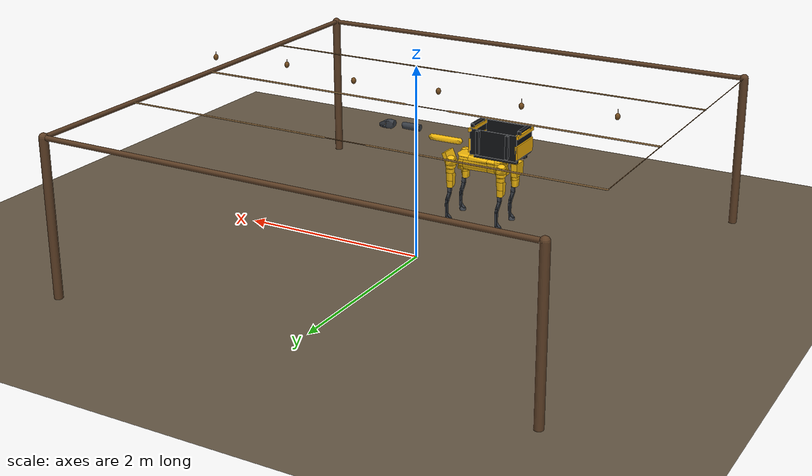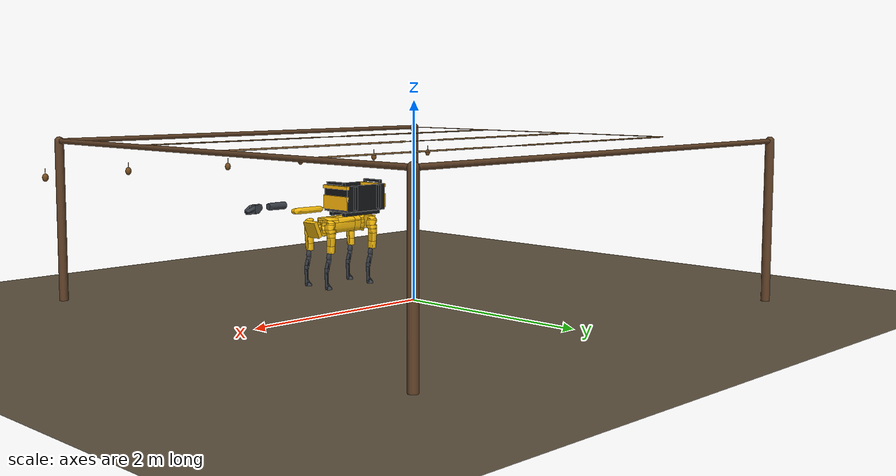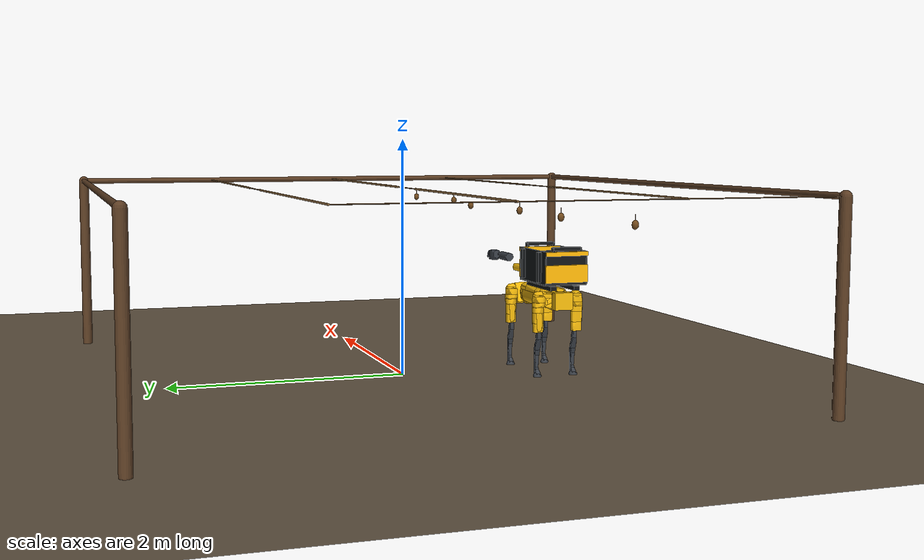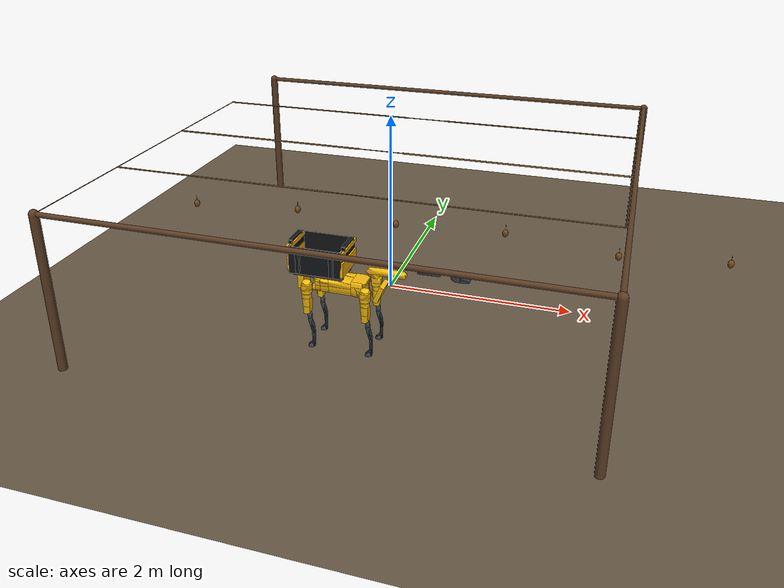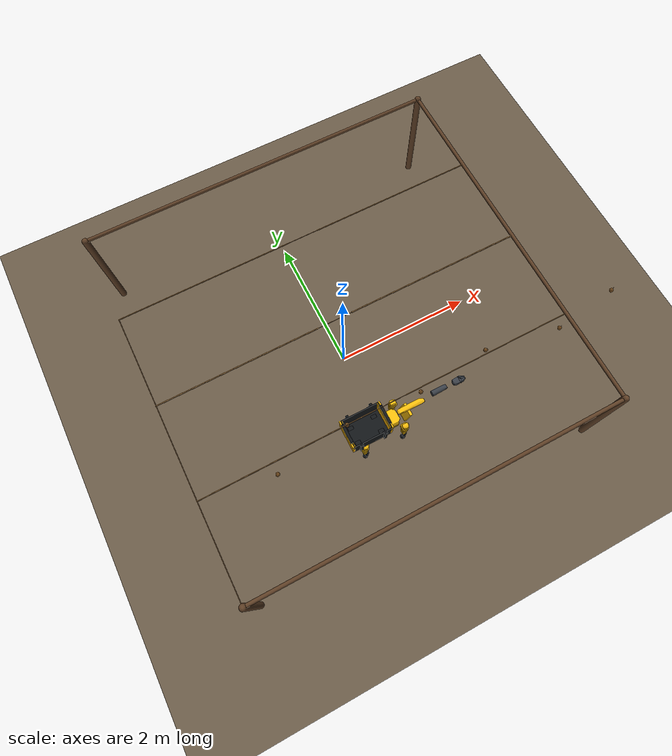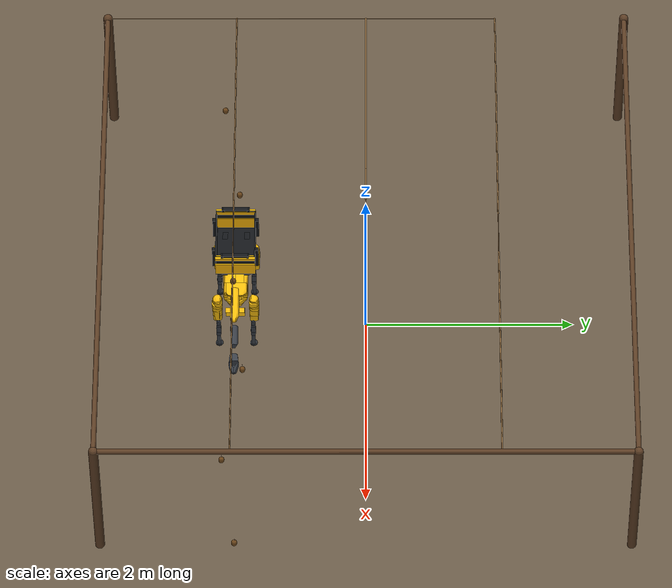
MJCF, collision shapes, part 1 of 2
<mujoco model="MuJoCo Model">
  <compiler angle="radian" />

  <option gravity="0 0 -9.81" integrator="implicitfast" timestep="0.005" solver="Newton" iterations="20" tolerance="1e-6">
    <flag multiccd="disable" midphase="enable" nativeccd="disable" />
  </option>

  <asset><texture name="sky_gradient" type="skybox" builtin="gradient" rgb1="0.62 0.78 0.95" rgb2="0.92 0.95 1.0" width="256" height="256" /><texture name="soil_tex" type="2d" builtin="checker" rgb1="0.42 0.36 0.28" rgb2="0.38 0.33 0.26" width="64" height="64" /><material name="soil_mat" texture="soil_tex" texrepeat="40 40" reflectance="0.02" />
    <mesh name="shape_66_66" vertex="-0.289802 0.0055663 0.0748036 -0.251372 0.0055663 0.075155 -0.289802 0.0055663 0.0931565 -0.289802 0.0133058 0.0639682 -0.242652 0.0055663 0.0754726 -0.275359 0.0134133 0.0639682 -0.25793 0.0135531 0.0639682 -0.242652 0.013682 0.0639682 -0.289308 0.0055663 0.0934403 -0.289802 0.0064048 0.0931599 -0.289802 0.0503049 0.0639682 -0.184631 0.0055663 0.0776079 -0.240912 0.0140045 0.0639682 -0.286271 0.0055663 0.0951837 -0.289802 0.0151332 0.09317 -0.289802 0.063978 0.0736076 -0.240017 0.106341 0.0639682 -0.184631 0.0055663 0.0852031 -0.236043 0.0152514 0.0639682 -0.184631 0.0939149 0.0639682 -0.277552 0.0055663 0.0980522 -0.289802 0.0218085 0.0931768 -0.289802 0.0648702 0.0792567 -0.235816 0.107986 0.0639682 -0.260102 0.0130801 0.0979576 -0.260102 0.0055663 0.0979508 -0.184631 0.0654184 0.0852031 -0.184631 0.115381 0.0639682 -0.268822 0.0055663 0.0984677 -0.268822 0.0130801 0.0984812 -0.277552 0.0130801 0.0980589 -0.286271 0.0218085 0.0951972 -0.289802 0.0637738 0.0811217 -0.247378 0.0964839 0.0756956 -0.233933 0.104105 0.0740975 -0.233933 0.106395 0.0697322 -0.233933 0.108383 0.0639682 -0.260102 0.0218085 0.0979508 -0.267607 0.0055663 0.0983968 -0.184631 0.0828646 0.0851423 -0.225213 0.104395 0.0745299 -0.184631 0.108545 0.071604 -0.277552 0.0218085 0.0980522 -0.287136 0.0312894 0.0942681 -0.289802 0.0339122 0.0927848 -0.289802 0.0619464 0.0839429 -0.24746 0.0877663 0.0838043 -0.242652 0.0930334 0.0815609 -0.260102 0.0305262 0.0971906 -0.184631 0.0876373 0.0846828 -0.225213 0.100031 0.0785843 -0.184631 0.104997 0.0751854 -0.268822 0.0305262 0.097569 -0.289802 0.0350732 0.0925145 -0.233933 0.0939686 0.082784 -0.184631 0.0901956 0.0844362 -0.184631 0.103417 0.076547 -0.190314 0.0901956 0.0844328 -0.225213 0.0899914 0.0843754 -0.233933 0.0896044 0.084274 -0.216483 0.0944523 0.0830543 -0.184631 0.0945598 0.0831489 -0.184631 0.100311 0.079081 -0.184631 0.0983006 0.0805473" face="3 1 0 7 12 11 18 19 11 18 11 12 4 7 11 4 1 7 5 1 3 20 28 29 48 55 52 6 7 1 6 1 5 15 16 10 15 22 16 36 35 27 34 40 27 34 27 35 42 29 52 38 29 28 38 25 29 24 17 26 24 25 17 24 29 25 41 27 40 41 40 51 49 55 48 49 48 39 23 16 35 23 35 36 47 46 54 47 54 34 30 20 29 30 29 42 30 13 20 43 42 52 43 52 46 37 26 39 37 24 26 37 39 48 37 29 24 37 52 29 37 48 52 50 56 51 50 51 40 50 40 34 50 34 54 50 62 56 57 52 55 57 58 52 57 55 61 57 61 58 60 54 58 60 58 61 60 61 63 60 50 54 60 63 62 60 62 50 59 46 52 59 52 58 59 54 46 59 58 54 33 47 34 33 46 47 33 22 32 33 16 22 33 35 16 33 34 35 8 9 2 8 13 9 14 13 21 14 9 13 31 13 30 31 30 42 31 42 43 31 21 13 45 46 33 45 33 32 45 43 46 45 53 43 44 43 53 44 21 31 44 31 43 23 27 19 23 12 7 23 18 12 23 7 6 23 19 18 23 5 3 23 3 10 23 10 16 23 6 5 23 36 27 63 61 55 63 11 19 63 19 27 63 17 11 63 26 17 63 39 26 63 56 62 63 27 41 63 41 51 63 51 56 63 55 49 63 49 39 8 2 0 8 0 1 8 11 17 8 4 11 8 28 20 8 1 4 8 38 28 8 17 25 8 20 13 8 25 38 44 0 2 44 3 0 44 32 22 44 22 15 44 10 3 44 2 9 44 15 10 44 45 32 44 14 21 44 9 14 44 53 45" />
    <mesh name="shape_67_67" vertex="0.129506 0.0003052 0.0851593 0.129506 -0.0422661 0.0851952 0.129506 0.0003052 0.0775356 -0.0030959 0.0003052 0.0949587 0.129506 -0.0509892 0.0852012 0.129506 -0.033884 0.0656891 -0.0030959 0.0003052 0.0758232 -0.0030959 -0.0218272 0.0949617 0.129506 -0.0567193 0.0852041 0.129506 -0.0374307 0.0653723 0.123769 -0.033884 0.0656891 0.0539765 -0.033884 0.0656921 0.0278091 -0.033884 0.0656951 0.0016418 -0.0338946 0.0657011 -0.0030959 -0.0342248 0.0658505 -0.0030959 -0.0305503 0.0945432 0.129506 -0.0828884 0.0850189 0.129506 -0.0654423 0.0852041 0.129506 -0.0392733 0.065208 0.123769 -0.0392733 0.065208 0.0190867 -0.0338946 0.0656951 0.0888663 -0.0392733 0.0652139 0.0016418 -0.0392733 0.0652468 -0.0030959 -0.0344165 0.0658356 -0.0030959 -0.0901096 0.0843584 0.0539765 -0.0901522 0.0843913 0.0975888 -0.0901735 0.0844062 0.106311 -0.0901735 0.0844092 0.115034 -0.0901735 0.0844092 0.129506 -0.0900244 0.0843225 0.129506 -0.0987048 0.0644339 0.0895802 -0.0919416 0.0644339 -0.0030959 -0.0911747 0.0644339 0.0975888 -0.0392733 0.065211 -0.0030959 -0.0392733 0.0656712 -0.0030959 -0.0924741 0.0836949 -0.0030959 -0.0944658 0.0831331 0.0016418 -0.0944765 0.0831331 0.0627119 -0.0945191 0.0831361 0.106311 -0.0945404 0.0831331 0.115034 -0.0945297 0.0831331 0.129506 -0.0943912 0.0831331 0.129506 -0.108227 0.0644339 -0.0030959 -0.108493 0.0644339 -0.0030959 -0.100132 0.0787758 0.0539765 -0.0945191 0.0831331 0.129506 -0.100121 0.0787729 0.129506 -0.106469 0.070142 -0.0030959 -0.10812 0.0656413 -0.0030959 -0.102496 0.0764837 0.129506 -0.104488 0.0745052 -0.0030959 -0.104488 0.0745381 0.129506 -0.10517 0.073011 0.123769 -0.10648 0.070139 0.0452541 -0.106576 0.0701301 0.0190867 -0.106597 0.070157 0.0016418 -0.106608 0.0701719 -0.0030959 -0.106608 0.0701779 0.115034 -0.106491 0.070139 -0.0030959 -0.105638 0.0721772" face="13 14 6 13 22 14 2 5 6 42 47 43 34 22 32 31 18 30 31 32 18 1 0 3 1 3 4 8 4 3 8 3 7 8 7 17 16 17 7 15 29 16 15 16 7 23 14 22 23 22 34 21 32 22 21 33 32 21 22 13 19 18 32 19 32 33 28 29 15 48 43 47 50 46 51 50 51 59 50 59 57 9 18 19 25 15 24 41 29 28 10 6 5 10 11 6 10 5 9 10 9 19 10 19 11 12 13 6 12 6 11 26 15 25 35 25 24 35 36 25 56 57 48 56 48 55 56 50 57 56 55 50 54 55 48 52 50 55 49 51 46 49 46 44 39 44 46 20 13 12 20 21 13 20 33 21 20 12 11 20 19 33 20 11 19 27 28 15 27 15 26 27 39 28 37 25 36 37 26 25 37 27 26 37 36 44 58 52 55 58 55 54 58 54 48 40 41 28 40 28 39 40 46 41 40 39 46 38 39 27 38 27 37 38 44 39 53 47 52 53 52 58 53 48 47 53 58 48 45 37 44 45 44 38 45 38 37 2 6 3 2 3 0 31 43 32 31 30 42 31 42 43 52 30 18 52 42 30 52 2 0 52 8 17 52 16 29 52 5 2 52 29 41 52 0 1 52 47 42 52 1 4 52 4 8 52 17 16 52 9 5 52 46 50 52 18 9 52 41 46 49 32 43 49 3 6 49 6 14 49 7 3 49 24 15 49 14 23 49 59 51 49 34 32 49 15 7 49 43 48 49 23 34 49 48 57 49 57 59 49 35 24 49 44 36 49 36 35" />
    <mesh name="shape_68_68" vertex="0.191262 -0.0020978 -0.0933115 0.237183 0.0067371 -0.101628 0.228449 -0.0020978 -0.0967846 0.191262 -0.0020978 -0.0846481 0.191262 -0.002063 -0.0933115 0.237183 0.0305288 -0.104636 0.237183 0.0218069 -0.104623 0.237183 0.0130764 -0.104142 0.245909 0.0065632 -0.10185 0.237183 -0.0020978 -0.097234 0.236807 -0.0020978 -0.0972147 0.245909 0.0130764 -0.104504 0.202296 -0.0020978 -0.0846481 0.263353 0.0152677 -0.0728967 0.241604 0.0156329 -0.0728967 0.238665 0.0157112 -0.0728967 0.191262 0.0478943 -0.0728967 0.191262 0.0043545 -0.0933051 0.245909 0.0218069 -0.104912 0.237183 0.0392507 -0.10461 0.263353 0.0064849 -0.10211 0.263353 0.0130764 -0.105044 0.272079 0.0130764 -0.105246 0.245909 -0.0020978 -0.0973207 0.272079 0.0064502 -0.102209 0.263353 0.0218069 -0.105461 0.274878 -0.0020978 -0.0848503 0.274878 0.0153981 -0.0728967 0.211022 0.0866949 -0.0728935 0.191262 0.0867384 -0.0728967 0.191262 0.0566944 -0.0930098 0.19357 0.0566944 -0.0934977 0.191262 0.0589901 -0.092692 0.191262 0.0626511 -0.0917355 0.263353 0.0392507 -0.105429 0.274878 0.0130764 -0.105255 0.274878 0.0218069 -0.105686 0.274878 0.0064502 -0.102209 0.26332 -0.0020978 -0.0973399 0.274878 -0.0020978 -0.0973431 0.274878 0.0567118 -0.0728967 0.250518 0.0787991 -0.0728967 0.249446 0.0797557 -0.0728967 0.238853 0.0851732 -0.0728967 0.21974 0.0866775 -0.0728967 0.21974 0.0823209 -0.0770342 0.191262 0.0823557 -0.0770535 0.191262 0.0688598 -0.0881244 0.19357 0.0629032 -0.0918703 0.274878 0.0581379 -0.0782219 0.250518 0.0787991 -0.0740265 0.259203 0.0699729 -0.0824685 0.254635 0.0712773 -0.0835695 0.211022 0.0776426 -0.0814029 0.191262 0.07766 -0.0814157 0.19357 0.0672685 -0.0892992 0.274878 0.0392507 -0.105657 0.263353 0.0470595 -0.102508 0.274878 0.0576162 -0.0865226 0.274878 0.0537379 -0.0948073 0.274878 0.0514074 -0.0977668 0.274878 0.0500074 -0.0994713 0.274878 0.0470508 -0.102623 0.211022 0.0732773 -0.084892" face="3 15 16 28 29 16 28 27 40 28 16 15 6 7 0 13 27 28 13 3 12 13 26 27 13 12 26 1 0 7 42 43 28 33 19 32 17 30 19 31 30 32 31 32 19 31 19 30 5 6 0 5 17 19 5 18 6 14 15 3 14 3 13 14 28 15 14 13 28 2 0 1 37 39 24 37 24 35 23 9 24 8 9 1 48 33 47 48 47 55 48 19 33 45 62 53 63 55 47 63 62 55 63 53 62 63 47 54 63 54 53 34 5 19 22 36 35 22 8 21 22 35 24 25 36 22 25 22 21 25 56 36 25 34 56 25 18 5 25 5 34 11 6 18 11 18 25 11 25 21 11 7 6 11 1 7 11 8 1 11 21 8 4 5 0 4 17 5 10 1 9 10 2 1 38 24 39 38 23 24 20 24 9 20 9 8 20 22 24 20 8 22 41 40 49 41 49 42 41 28 40 41 42 28 59 51 58 50 43 42 50 51 43 50 58 51 50 49 58 50 42 49 52 60 61 52 59 60 52 51 59 52 43 51 52 61 62 52 45 43 52 62 45 57 55 62 57 48 55 57 19 48 57 34 19 57 62 56 57 56 34 44 29 28 44 45 29 44 28 43 44 43 45 46 29 45 46 53 54 46 45 53 38 39 26 38 3 0 38 26 12 38 0 2 38 12 3 38 10 9 38 9 23 38 2 10 59 26 39 59 39 37 59 27 26 59 35 36 59 40 27 59 36 56 59 49 40 59 61 60 59 62 61 59 56 62 59 37 35 59 58 49 46 0 3 46 4 0 46 16 29 46 3 16 46 33 32 46 32 30 46 47 33 46 30 17 46 54 47 46 17 4" />
    <mesh name="shape_69_69" vertex="0.129506 -0.114654 0.0372884 0.129506 -0.113779 0.0418177 0.129506 -0.105169 0.0372884 0.211003 -0.114649 0.0372884 0.211003 -0.113777 0.0417948 0.211003 -0.109078 0.0618012 0.129506 -0.109033 0.0618012 0.129506 -0.0916108 0.0672226 0.230117 -0.0916108 0.0372884 0.219735 -0.113677 0.0412961 0.219735 -0.109022 0.0618012 0.219735 -0.106468 0.070178 0.211003 -0.106498 0.0701917 0.129506 -0.106473 0.0701368 0.129506 -0.10735 0.0672821 0.129506 -0.0916108 0.0838938 0.242797 -0.0916108 0.0372884 0.221475 -0.114338 0.0372884 0.228456 -0.108638 0.0618012 0.228456 -0.106234 0.0696519 0.219735 -0.104481 0.074538 0.129506 -0.105172 0.0730054 0.129506 -0.0943942 0.0831298 0.138294 -0.0916108 0.0839899 0.243422 -0.0916108 0.0705212 0.242797 -0.100345 0.0372884 0.237823 -0.106347 0.062094 0.235337 -0.105593 0.0681513 0.228456 -0.104116 0.0740164 0.219735 -0.100121 0.078596 0.211003 -0.100155 0.0787607 0.228456 -0.099758 0.0783032 0.129506 -0.100128 0.0787698 0.129506 -0.104488 0.0745014 0.132495 -0.10449 0.0745014 0.129506 -0.0963611 0.0816384 0.141227 -0.0945634 0.0831298 0.141227 -0.0916108 0.0840082 0.243422 -0.0916108 0.0706081 0.243422 -0.0916198 0.0705257 0.242173 -0.106448 0.0372884 0.242797 -0.100345 0.0443568 0.232504 -0.112525 0.0372884 0.241816 -0.105032 0.0593856 0.241158 -0.10401 0.0651959 0.236898 -0.110822 0.0372884 0.237177 -0.0981769 0.0770405 0.219735 -0.0942476 0.0829605 0.193562 -0.0945792 0.0831344 0.228456 -0.0936453 0.0826632 0.237177 -0.0925379 0.0814005 0.158668 -0.0945747 0.0831344 0.147137 -0.0916108 0.0840128 0.242485 -0.0916108 0.0783398 0.241916 -0.0966137 0.0755719 0.242139 -0.098116 0.0705257 0.242061 -0.105433 0.0530813 0.242686 -0.100345 0.0530813 0.237968 -0.0916108 0.0818031 0.224363 -0.0916108 0.0836056 0.219735 -0.0916108 0.0838023 0.193562 -0.0916108 0.0840219 0.176121 -0.0916108 0.0840265 0.231701 -0.0916108 0.0831161" face="8 2 7 25 16 24 41 40 25 38 53 54 58 54 53 49 47 31 49 58 63 10 5 4 21 34 33 55 54 43 55 38 54 55 43 38 56 38 43 39 24 38 39 25 24 39 41 25 39 38 41 46 54 58 46 31 28 27 54 46 27 46 28 27 28 19 11 5 10 59 49 63 59 60 47 59 47 49 50 49 31 50 58 49 50 31 46 50 46 58 48 60 61 48 47 60 48 30 47 48 51 30 48 61 62 48 62 51 36 22 35 36 37 22 36 52 37 36 62 52 36 51 62 23 15 22 23 22 37 32 36 35 32 33 34 32 30 51 32 51 36 20 32 34 20 30 32 20 28 31 20 19 28 20 11 19 29 31 47 29 47 30 29 20 31 29 30 20 14 5 13 14 6 5 1 0 3 1 3 4 1 5 6 1 4 5 9 10 4 9 3 17 9 4 3 45 40 56 45 56 43 57 41 38 57 38 56 57 40 41 57 56 40 44 43 54 44 54 27 26 42 45 26 45 43 26 43 44 26 44 27 18 17 42 18 27 19 18 42 26 18 26 27 18 9 17 18 10 9 18 19 11 18 11 10 12 34 21 12 20 34 12 11 20 12 21 13 12 13 5 12 5 11 23 8 7 23 24 16 23 7 15 23 63 58 23 62 61 23 16 8 23 38 24 23 59 63 23 53 38 23 58 53 23 61 60 23 52 62 23 60 59 23 37 52 1 2 0 1 15 7 1 7 2 1 13 21 1 35 22 1 14 13 1 22 15 1 32 35 1 21 33 1 33 32 1 6 14 45 0 2 45 16 25 45 8 16 45 2 8 45 25 40 45 3 0 45 42 17 45 17 3" />
    <mesh name="shape_70_70" vertex="0.242748 -0.0580968 0.0372884 0.242761 -0.0654458 0.0372884 0.242748 -0.0580968 0.0370064 0.199431 -0.0580968 0.0372884 0.242804 -0.0916135 0.0372884 0.24279 -0.0828966 0.0356307 0.242783 -0.0828966 0.0181864 0.24279 -0.0916135 0.0021523 0.24274 -0.0580968 0.0358921 0.198646 -0.0580968 0.0359746 0.171163 -0.105167 0.0372884 0.242796 -0.100342 0.0372884 0.242796 -0.100342 0.0356307 0.242783 -0.100342 0.0021523 0.242088 -0.0820496 0.0021523 0.242733 -0.0580968 0.0356307 0.198442 -0.0580968 0.0356307 0.171163 -0.102574 0.0181864 0.171163 -0.114651 0.0372884 0.242172 -0.106449 0.0372884 0.242172 -0.10658 0.0356307 0.242172 -0.107221 0.0269051 0.242165 -0.108103 0.0021523 0.242158 -0.0580968 0.0280538 0.241548 -0.0785411 0.0021523 0.199312 -0.0580968 0.0021523 0.171163 -0.102591 0.0094609 0.171163 -0.114834 0.0363461 0.211009 -0.114651 0.0372884 0.237965 -0.110083 0.0372884 0.238652 -0.111583 0.0269051 0.241029 -0.111754 0.0021523 0.239592 -0.0580968 0.0237994 0.207727 -0.0580968 0.0021523 0.171163 -0.104325 0.0021523 0.171163 -0.10365 0.00316 0.171163 -0.114971 0.0356307 0.211009 -0.114971 0.0356307 0.236899 -0.110822 0.0372884 0.239374 -0.112968 0.0021523 0.240314 -0.11243 0.0021523 0.236822 -0.111222 0.0353658 0.233673 -0.113586 0.0322808 0.23429 -0.113678 0.0269051 0.171163 -0.116568 0.0021523 0.171163 -0.115498 0.0306781 0.202292 -0.115898 0.0269051 0.211009 -0.115887 0.0269051 0.232502 -0.112521 0.0372884 0.236177 -0.114067 0.0021523 0.2299 -0.113334 0.0372884 0.228049 -0.113964 0.0353658 0.228463 -0.114685 0.0269051 0.230321 -0.115183 0.0021523 0.202292 -0.116562 0.0021523 0.171163 -0.115898 0.0269051 0.211009 -0.116551 0.0021523 0.21265 -0.116528 0.0021523 0.219732 -0.116362 0.0021523 0.219732 -0.115658 0.0269051 0.226864 -0.113803 0.0372884 0.221471 -0.114336 0.0372884 0.221598 -0.116213 0.0021523 0.228463 -0.115412 0.0021523" face="5 1 4 5 4 7 6 7 1 6 5 7 6 1 5 9 10 3 9 16 10 14 24 23 15 7 14 15 14 23 12 7 4 34 35 25 26 16 25 26 25 35 8 7 15 32 24 33 32 23 24 13 7 12 13 12 22 11 12 4 11 22 12 43 53 49 52 53 43 52 43 42 17 10 16 17 16 26 55 44 46 54 46 44 2 7 8 2 0 1 2 1 7 48 50 42 48 42 38 30 29 38 30 19 29 30 31 19 30 42 43 39 43 49 39 30 43 51 42 50 51 52 42 56 46 54 21 31 22 21 22 11 41 38 42 41 42 30 41 30 38 40 31 30 40 30 39 47 57 58 47 56 57 47 46 56 47 37 46 61 28 37 27 28 18 27 37 28 27 36 37 45 37 36 45 55 46 45 46 37 20 19 31 20 31 21 20 11 19 20 21 11 63 53 52 63 52 62 59 58 62 59 62 52 59 47 58 59 52 51 59 51 61 59 37 47 59 61 37 60 51 50 60 61 51 2 3 0 2 25 16 2 9 3 2 33 25 2 16 9 2 15 23 2 23 32 2 8 15 2 32 33 45 18 10 45 34 44 45 10 17 45 35 34 45 26 35 45 17 26 45 44 55 45 27 18 45 36 27 63 25 33 63 57 56 63 14 7 63 34 25 63 49 53 63 22 31 63 54 44 63 7 13 63 24 14 63 33 24 63 44 34 63 13 22 63 31 40 63 39 49 63 58 57 63 56 54 63 40 39 63 62 58 60 4 1 60 3 10 60 1 0 60 0 3 60 10 18 60 11 4 60 50 48 60 29 19 60 38 29 60 19 11 60 48 38 60 18 28 60 28 61" />
    <mesh name="shape_71_71" vertex="-0.0983355 0.080412 0.0675937 -0.0983355 0.080412 0.085123 -0.0983355 0.0828718 0.0851278 0.106311 0.0803564 0.0851214 0.115034 0.0828697 0.0851214 0.115034 0.0803564 0.0851165 0.129506 0.0803564 0.0850722 -0.0030959 0.0803564 0.0850919 -0.0030959 0.0803564 0.0658648 0.0801439 0.0803564 0.065688 0.0016418 0.0803564 0.065688 -0.0681583 0.101891 0.0358268 -0.0856102 0.080412 0.0656825 -0.0908961 0.080412 0.0659238 -0.0983355 0.104845 0.0358268 -0.0030959 0.105914 0.0349414 0.129506 0.106164 0.0349414 -0.0030959 0.115287 0.0349414 -0.0983355 0.118323 0.0358268 -0.0983355 0.115073 0.0675406 -0.0983355 0.123242 0.0591669 -0.0983355 0.122976 0.050243 -0.0983355 0.122465 0.0478492 -0.0768842 0.119185 0.0358268 -0.0856102 0.122469 0.0478347 -0.0768842 0.122393 0.0477333 -0.0856102 0.123585 0.0530809 -0.0983355 0.123581 0.0530809 -0.0856102 0.123238 0.0591669 -0.0768842 0.123183 0.0590414 -0.0768842 0.123449 0.0530809 0.129506 0.115096 0.0349414 0.129506 0.115024 0.035634 0.129506 0.1138 0.0420349 0.129506 0.109122 0.0618023 0.129506 0.104526 0.0746285 0.129506 0.10656 0.0702663 -0.0856102 0.119439 0.0635203 0.129506 0.100162 0.0787844 0.129506 0.0944381 0.0831466 0.115034 0.094551 0.0831466 -0.0856102 0.10542 0.0754896 -0.0768842 0.100318 0.0793603 -0.0983355 0.100318 0.0793844 -0.0943361 0.10542 0.0754896 -0.0856102 0.115077 0.0675454 -0.0983355 0.119434 0.0635251 -0.0983355 0.105415 0.0754896 -0.0983355 0.0945451 0.0831442 -0.0983355 0.0901834 0.0844183 0.115034 0.0901876 0.084414 0.129506 0.0900747 0.0843452 0.129506 0.0828697 0.0850526 0.129506 0.0803564 0.0672501 0.0889961 0.0803564 0.0659336" face="11 14 15 11 15 16 17 23 31 18 23 17 24 27 26 9 11 16 20 26 27 22 23 18 22 24 23 25 30 31 25 31 23 25 23 24 25 24 26 25 26 30 51 39 50 54 16 53 54 9 16 29 30 26 29 34 33 29 31 30 37 38 35 37 35 29 37 20 46 21 27 24 21 24 22 3 1 7 52 4 6 52 51 50 52 50 4 2 1 3 2 3 4 2 4 50 2 50 49 10 11 9 10 12 11 10 8 12 13 14 11 13 11 12 13 0 14 13 8 0 13 12 8 28 26 20 28 29 26 28 20 37 28 37 29 36 29 35 36 34 29 32 31 29 32 29 33 40 39 38 40 50 39 40 48 49 40 49 50 45 38 37 45 37 46 5 6 4 5 4 3 43 44 47 43 48 40 41 40 38 41 38 45 41 45 44 41 44 43 19 45 46 19 47 44 19 44 45 42 43 40 42 40 41 42 41 43 17 31 16 17 16 15 18 17 15 18 15 14 8 1 0 8 7 1 32 35 38 32 6 53 32 16 31 32 53 16 32 52 6 32 36 35 32 38 39 32 33 34 32 39 51 32 51 52 32 34 36 5 53 6 5 54 53 5 10 9 5 9 54 5 3 7 5 7 8 5 8 10 19 0 1 19 14 0 19 49 48 19 1 2 19 18 14 19 20 27 19 46 20 19 22 18 19 27 21 19 21 22 19 2 49 19 48 43 19 43 47" />
    <mesh name="shape_72_72" vertex="-0.289802 -0.0305236 0.0450088 -0.289802 -0.0114199 0.0184765 -0.283935 -0.0106294 0.0071135 -0.277548 -0.0127097 0.0071135 -0.248119 -0.0358768 0.0450088 -0.289802 0.0304904 0.0450088 -0.289802 -0.0050751 0.0184134 -0.284604 -0.0043678 0.0071135 -0.284502 -0.0058795 0.0071135 -0.248119 -0.0141242 0.0071135 -0.248119 0.0349629 0.0450088 -0.277728 0.012621 0.0071135 -0.282849 0.0109845 0.0071135 -0.283787 0.0106794 0.0071135 -0.289802 0.0114491 0.0184654 -0.289802 0.005028 0.018406 -0.289802 0.0065605 0.018406 -0.284595 0.0019978 0.0071135 -0.248119 0.0142435 0.0071135 -0.275202 0.0128428 0.0071135 -0.283955 0.009452 0.0071135 -0.28453 0.0044663 0.0071135" face="3 4 0 3 0 2 11 5 10 1 2 0 9 4 3 19 10 18 19 11 10 7 1 6 8 2 1 8 1 7 13 14 5 17 14 21 20 21 14 20 14 13 12 5 11 12 13 5 16 14 17 16 17 7 15 7 6 15 16 7 5 4 10 5 0 4 9 10 4 9 18 10 12 11 19 12 3 2 12 9 3 12 2 8 12 18 9 12 19 18 12 21 20 12 8 7 12 17 21 12 7 17 12 20 13 15 0 5 15 1 0 15 6 1 15 5 14 15 14 16" />
    <mesh name="shape_73_73" vertex="-0.246469 0.0222466 -0.0303359 -0.246469 0.0542587 -0.0437179 -0.289802 0.0165351 -0.0303359 -0.246469 -0.0229418 -0.0303359 -0.246469 0.0830939 -0.0571118 -0.289802 0.0366556 -0.0446191 -0.289802 -0.0166227 -0.0303359 -0.246469 -0.0829211 -0.0574042 -0.246469 0.0886666 -0.062412 -0.289802 0.0534428 -0.0637072 -0.289802 -0.036691 -0.0445654 -0.246469 -0.0886847 -0.062609 -0.246469 0.0880416 -0.0653725 -0.247466 0.0877812 -0.0651994 -0.289802 0.0552483 -0.0690553 -0.289802 0.0545539 -0.0668707 -0.289802 -0.0534436 -0.0637192 -0.246469 -0.0886847 -0.0641012 -0.289802 -0.0552664 -0.0690553 -0.246469 0.0867569 -0.0661544 -0.289802 0.0441204 -0.0910919 -0.289802 0.0447627 -0.0902921 -0.289802 0.0513249 -0.0808495 -0.289802 0.0541372 -0.0764864 -0.289802 0.0546059 -0.0733647 -0.247461 -0.0878167 -0.0652173 -0.246469 -0.0880597 -0.0653845 -0.289802 -0.054815 -0.072153 -0.246469 0.0722612 -0.0742302 -0.288708 0.0441031 -0.0910859 -0.289802 0.0392422 -0.0912531 -0.289802 -0.0541553 -0.0764565 -0.289802 -0.0532005 -0.0782233 -0.289802 -0.0440517 -0.0910621 -0.246469 -0.0747271 -0.0734304 -0.246469 0.065404 -0.0758955 -0.282748 0.0392422 -0.0906622 -0.287109 0.0392422 -0.0911934 -0.286519 0.0305101 -0.0911934 -0.286273 -0.0218134 -0.0912531 -0.289802 0.0338953 -0.091259 -0.246469 -0.0722793 -0.0742063 -0.246469 0.0566892 -0.0770534 -0.282159 0.0305101 -0.0908293 -0.246469 0.047957 -0.0774414 -0.281836 -0.0218134 -0.0909248 -0.281875 -0.0305455 -0.0909009 -0.286273 -0.0305455 -0.0912053 -0.289802 -0.0305455 -0.091265 -0.289802 -0.0218134 -0.0913008 -0.289802 -0.038809 -0.0911934 -0.286032 -0.0384791 -0.0911039 -0.281904 -0.0350592 -0.090877 -0.282961 -0.0408748 -0.0906264 -0.246469 0.0430615 -0.0774951 -0.246469 0.0392422 -0.0775369 -0.281853 -0.0172998 -0.0909128 -0.246469 -0.0267263 -0.0775309 -0.246469 -0.0392603 -0.0775249 -0.246469 0.0168824 -0.0775369 -0.246469 -0.0479925 -0.0774294 -0.246469 -0.0567073 -0.0769877 -0.246469 -0.0616202 -0.076355 -0.246469 -0.0654394 -0.0758119" face="1 2 0 1 4 2 5 4 8 5 8 9 5 2 4 7 3 6 18 11 16 10 16 11 10 11 7 10 7 6 29 30 20 15 9 8 15 8 14 26 33 34 38 39 30 45 58 46 45 38 43 45 46 39 45 39 38 47 39 46 13 12 20 13 22 23 13 8 12 13 23 24 13 24 14 13 14 8 36 42 44 36 44 43 19 28 29 19 20 12 19 29 20 25 32 33 25 33 26 25 31 32 25 27 31 25 18 27 40 30 39 40 39 49 37 30 29 37 38 30 37 43 38 37 36 43 37 29 36 54 55 43 54 43 44 56 43 55 56 55 45 56 45 43 57 58 45 21 13 20 21 22 13 35 42 36 35 29 28 35 36 29 17 25 26 17 11 18 17 18 25 41 53 63 41 34 33 41 33 53 51 53 33 51 33 50 51 50 47 62 53 61 62 63 53 52 61 53 52 60 61 52 53 51 52 58 60 52 46 58 52 47 46 52 51 47 59 45 55 59 57 45 48 47 50 48 49 39 48 39 47 6 3 0 6 0 2 59 7 11 59 0 3 59 34 41 59 8 4 59 1 0 59 4 1 59 12 8 59 3 7 59 28 19 59 35 28 59 62 61 59 61 60 59 26 34 59 11 17 59 44 42 59 55 54 59 19 12 59 54 44 59 60 58 59 58 57 59 42 35 59 17 26 59 41 63 59 63 62 48 6 2 48 32 31 48 31 27 48 2 5 48 23 22 48 20 30 48 5 9 48 24 23 48 33 32 48 10 6 48 9 15 48 18 16 48 16 10 48 50 33 48 15 14 48 14 24 48 27 18 48 30 40 48 40 49 48 21 20 48 22 21" />
    <mesh name="shape_74_74" vertex="0.191262 -0.0618265 -0.0918199 0.191262 -0.0626581 -0.0917241 0.190694 -0.0618265 -0.0917816 0.191262 -0.0618265 -0.0531948 0.187968 -0.0623007 -0.0915279 0.187901 -0.0618265 -0.0915806 0.191262 -0.0652236 -0.0902119 0.158673 -0.0733273 -0.0846796 0.191262 -0.0979743 -0.0459445 0.15903 -0.0618265 -0.0429343 0.152121 -0.0721524 -0.0838326 0.176518 -0.0618265 -0.0846653 0.152121 -0.0673469 -0.0838326 0.158673 -0.0660269 -0.0846796 0.158673 -0.0626652 -0.0777835 0.191262 -0.0733308 -0.0849046 0.158673 -0.0776905 -0.0814063 0.129506 -0.0953663 -0.0641444 0.129506 -0.0910066 -0.067413 0.158933 -0.0654466 -0.0429343 0.157579 -0.074173 -0.0429343 0.155415 -0.0798066 -0.0429343 0.146928 -0.0893505 -0.0429343 0.141221 -0.092231 -0.0429343 0.132468 -0.0930768 -0.0429343 0.132499 -0.0979743 -0.0449491 0.191262 -0.0979743 -0.0613065 0.158921 -0.0618265 -0.0429343 0.151915 -0.0618265 -0.0681883 0.150942 -0.0662888 -0.0777835 0.129506 -0.0844176 -0.067413 0.129506 -0.0813106 -0.0603398 0.191262 -0.077694 -0.0814063 0.16739 -0.077694 -0.081411 0.158673 -0.082305 -0.0770465 0.176113 -0.0823297 -0.0770465 0.16739 -0.0823191 -0.0770465 0.141221 -0.0954442 -0.0641252 0.129506 -0.0979743 -0.0613639 0.158673 -0.0866682 -0.0728543 0.149944 -0.0910845 -0.0684754 0.129506 -0.0930909 -0.0429343 0.130492 -0.0979743 -0.0449395 0.191262 -0.0954512 -0.0641061 0.132499 -0.0979743 -0.0613687 0.14911 -0.0618265 -0.0479928 0.14934 -0.0618442 -0.0429343 0.151166 -0.0618265 -0.0651924 0.149038 -0.0618265 -0.0516155 0.150059 -0.0618265 -0.0603398 0.191262 -0.0811053 -0.0781951 0.184836 -0.0823333 -0.0770465 0.176113 -0.086693 -0.0728734 0.184836 -0.0866965 -0.0728782 0.158673 -0.091088 -0.0684898 0.176113 -0.0910916 -0.0685137 0.184836 -0.0910916 -0.0685185 0.184836 -0.0954548 -0.0641061 0.129506 -0.0979743 -0.0449395 0.129506 -0.0816928 -0.0429343 0.129506 -0.0811372 -0.0516155 0.191262 -0.0823297 -0.0770417 0.191262 -0.086693 -0.0728782 0.191262 -0.091088 -0.0685137" face="3 9 8 21 22 8 23 8 22 18 7 17 10 7 18 16 17 7 16 7 15 14 12 28 42 41 58 20 21 8 24 8 23 24 25 8 24 42 25 24 41 42 43 26 44 6 15 7 5 10 12 19 8 9 19 20 8 1 6 7 61 62 51 33 32 51 33 15 32 33 16 15 34 17 16 34 39 17 11 14 28 11 5 14 13 12 14 13 5 12 13 14 5 29 28 12 29 12 31 29 31 28 30 31 12 57 43 44 40 17 39 52 39 34 52 40 39 2 0 1 2 1 5 4 1 7 4 5 1 4 7 10 4 10 5 50 51 32 50 61 51 36 34 16 36 52 34 27 45 46 60 59 46 60 46 45 56 62 63 56 63 43 56 43 57 37 17 40 37 57 44 37 55 56 37 56 57 37 38 17 37 44 38 54 52 55 54 40 52 54 55 37 54 37 40 53 51 62 53 62 56 53 55 52 53 56 55 35 16 33 35 36 16 35 33 51 35 51 53 35 52 36 35 53 52 47 28 31 47 31 49 48 49 31 48 31 60 48 60 45 44 26 8 44 8 25 44 42 58 44 58 38 44 25 42 30 12 10 30 10 18 50 8 26 50 0 3 50 3 8 50 26 43 50 1 0 50 32 15 50 63 62 50 15 6 50 6 1 50 62 61 50 43 63 27 41 24 27 19 9 27 22 21 27 23 22 27 59 41 27 21 20 27 24 23 27 46 59 27 20 19 60 38 58 60 17 38 60 58 41 60 18 17 60 41 59 60 30 18 60 31 30 48 3 0 48 9 3 48 11 28 48 0 2 48 5 11 48 27 9 48 2 5 48 45 27 48 28 47 48 47 49" />
    <mesh name="shape_75_75" vertex="0.157674 0.002343 0.0021523 0.158432 0.002343 0.000733 0.129506 0.002343 0.0021523 0.157674 -0.0567161 0.0021523 0.15926 0.002343 -0.0059927 0.158432 -0.0567161 0.000733 0.129506 0.002343 -0.0002686 0.129506 -0.061823 0.0021523 0.157657 -0.0591219 0.0021523 0.159504 0.002343 -0.0079916 0.159504 -0.0567161 -0.0079916 0.158332 -0.061823 0.000733 0.159436 -0.061823 -0.0079916 0.149511 0.002343 -0.0413899 0.149364 -0.061823 -0.0413899 0.129506 -0.061823 -0.0002686 0.157604 -0.061823 0.0021523 0.159102 0.002343 -0.0341613 0.15914 -0.0567161 -0.0413899 0.15899 -0.061823 -0.0413899 0.158964 0.002343 -0.0413899" face="14 6 13 15 6 14 17 18 20 17 9 18 12 19 18 10 18 9 10 12 18 8 16 11 4 10 9 5 11 12 5 12 10 5 4 1 5 10 4 5 3 8 5 8 11 18 13 20 18 19 14 18 14 13 15 2 6 15 7 2 12 7 15 12 16 7 12 14 19 12 11 16 12 15 14 8 0 2 8 7 16 8 2 7 8 3 0 4 6 2 4 2 0 4 9 17 4 13 6 4 20 13 4 0 1 4 17 20 5 1 0 5 0 3" />
    <mesh name="shape_76_76" vertex="-0.14819 0.0711905 -0.0070971 -0.148367 0.0719968 -0.0070971 -0.144369 -0.0057711 -0.0012673 -0.154746 -0.0057711 -0.0012673 -0.152876 0.0719277 -0.0070971 -0.153914 0.072688 -0.0442442 -0.148371 0.0726342 -0.0442442 -0.146867 -0.0057711 -0.048951 -0.147538 0.0668055 -0.0442442 -0.147451 0.0653387 -0.0070971 -0.145937 0.0479678 -0.0070971 -0.146403 0.0479678 -0.0341627 -0.146724 0.0479678 -0.0442442 -0.146515 -0.0632955 -0.048951 -0.157928 -0.0632955 -0.048951 -0.155926 -0.0057711 -0.048951 -0.154317 0.0707681 -0.0442442 -0.155186 0.0654155 -0.0442442 -0.156191 0.0479371 -0.0442442 -0.155714 0.0479678 -0.0254415 -0.155154 0.0479678 -0.0079918 -0.157927 -0.0567181 -0.048951 -0.155125 0.0479678 -0.0070971 -0.154451 -0.0632955 -0.0012673 -0.144171 -0.0632955 -0.0012673" face="23 3 14 15 5 7 12 13 7 17 15 18 21 18 15 2 24 13 2 13 12 6 7 5 16 5 15 16 15 17 4 16 17 4 5 16 8 12 7 8 7 6 8 6 0 1 3 2 1 4 3 1 2 0 1 0 6 1 6 5 1 5 4 22 3 4 22 4 17 22 21 14 22 14 3 11 2 12 11 10 2 11 12 8 11 8 10 9 8 0 9 10 8 9 0 2 9 2 10 19 18 21 19 17 18 20 21 22 20 19 21 20 22 17 20 17 19 23 13 24 23 14 13 21 13 14 21 7 13 21 15 7 2 23 24 2 3 23" />
    <mesh name="shape_77_77" vertex="-0.111792 -0.0973259 -0.0622243 -0.120517 -0.0995056 -0.0598789 -0.16413 -0.103967 -0.0550328 -0.16413 -0.0996058 -0.059737 -0.111792 -0.099492 -0.0598587 -0.107796 -0.0973259 -0.0621973 -0.0983355 -0.0994785 -0.0597843 -0.155404 -0.103955 -0.0550193 -0.0983355 -0.106837 -0.0505314 -0.16413 -0.106837 -0.0506733 -0.184631 -0.106841 -0.0506531 -0.172856 -0.103957 -0.0550261 -0.181581 -0.103946 -0.0550193 -0.184631 -0.103942 -0.0550125 -0.155404 -0.0973259 -0.0621094 -0.0983355 -0.101843 -0.0571416 -0.0983355 -0.103842 -0.0548909 -0.0983355 -0.0973259 -0.0621161 -0.0983355 -0.105466 -0.052532 -0.0983355 -0.108535 -0.0463882 -0.0983355 -0.109966 -0.0428871 -0.184631 -0.109918 -0.0428871 -0.184631 -0.0995788 -0.0596559 -0.0983355 -0.0973259 -0.0463409 -0.0983355 -0.113804 -0.03162 -0.184631 -0.113818 -0.0317146 -0.184631 -0.0973259 -0.0618999 -0.181581 -0.0973259 -0.0619337 -0.172856 -0.0973259 -0.0620012 -0.0983355 -0.108328 0.0067841 -0.144068 -0.0973259 -0.0423599 -0.16413 -0.102962 0.0067841 -0.0983355 -0.114343 -0.0282675 -0.184631 -0.114464 -0.027639 -0.0983355 -0.114796 -0.0254423 -0.184631 -0.0973259 -0.0439009 -0.0983355 -0.117028 0.0067841 -0.146611 -0.0973259 -0.0423396 -0.181581 -0.102891 0.0067841 -0.172856 -0.102923 0.0067841 -0.184631 -0.114811 -0.0254423 -0.0983355 -0.115924 -0.0167166 -0.184631 -0.10317 0.0067841 -0.153419 -0.0973259 -0.0424139 -0.0999151 -0.117028 0.0067841 -0.0983355 -0.117026 0.0054594 -0.155404 -0.11593 -0.0167166 -0.184631 -0.115932 -0.0167166 -0.0983355 -0.116354 -0.0119921 -0.184631 -0.116979 0.0067841 -0.105735 -0.117026 0.0067841 -0.0983355 -0.117012 0.0007282 -0.103066 -0.117012 0.0007282 -0.103066 -0.116719 -0.0079908 -0.184631 -0.116704 -0.0079908 -0.129243 -0.116715 -0.0079908 -0.0983355 -0.116717 -0.0079908 -0.184631 -0.116979 0.0064056 -0.175525 -0.116989 0.0067841 -0.0983355 -0.116879 -0.0032664 -0.111792 -0.117008 0.0007282 -0.181581 -0.116976 0.0007282 -0.184631 -0.116972 0.0007282 -0.149347 -0.117006 0.0067841" face="20 24 25 31 29 23 9 20 10 21 10 20 21 20 25 19 9 8 19 20 9 2 8 9 2 9 10 13 12 10 30 38 39 30 39 31 30 31 23 42 38 35 58 61 63 54 47 55 54 55 52 11 10 12 11 2 10 43 35 38 32 25 24 32 34 25 40 34 41 57 58 49 57 61 58 50 63 52 45 52 51 45 50 52 60 63 61 60 52 63 60 61 54 60 54 52 59 51 52 59 52 55 15 4 6 15 16 4 7 4 16 7 16 18 7 18 8 7 8 2 0 6 4 28 14 22 3 13 22 3 12 13 3 11 12 3 14 0 3 22 14 3 2 11 37 38 30 37 43 38 33 25 34 33 34 40 46 47 40 46 40 41 46 41 48 62 54 61 62 61 57 44 45 36 44 50 45 53 56 59 53 59 55 53 55 47 53 47 46 53 48 56 53 46 48 5 17 6 5 6 0 1 0 4 1 7 2 1 4 7 1 2 3 1 3 0 27 22 26 27 28 22 15 29 36 15 32 24 15 24 20 15 59 56 15 23 29 15 56 48 15 6 17 15 19 8 15 17 23 15 20 19 15 8 18 15 36 45 15 41 34 15 48 41 15 18 16 15 34 32 15 45 51 15 51 59 62 35 26 62 49 42 62 10 21 62 21 25 62 13 10 62 26 22 62 57 49 62 42 35 62 47 54 62 22 13 62 40 47 62 25 33 62 33 40 44 36 29 44 39 38 44 49 58 44 29 31 44 31 39 44 42 49 44 38 42 44 58 63 44 63 50 27 23 17 27 37 30 27 26 35 27 35 43 27 30 23 27 17 5 27 0 14 27 14 28 27 43 37 27 5 0" />
    <mesh name="shape_78_78" vertex="0.132496 0.0899563 0.0021535 0.129509 0.0898447 0.0021535 0.132496 0.0886519 0.0067448 0.129509 0.0885832 0.0065888 0.154219 0.0699609 0.0138717 0.129509 0.0866695 0.0070271 0.129509 0.0828678 0.0078233 0.129506 -0.0741616 0.0074646 0.129506 -0.0896165 0.0021528 0.129506 -0.0828876 0.0073014 0.154219 0.0696262 0.0138717 0.129509 0.0798728 0.007852 0.154408 0.0696262 0.0138717 0.154408 0.0699609 0.0138717 0.141222 0.0883687 0.0066439 0.146291 0.0876307 0.0057697 0.155275 0.0798041 0.006637 0.156007 0.0733764 0.0095098 0.156182 0.0662021 0.0094134 0.157657 -0.0591205 0.0021528 0.158734 0.0655413 0.0021535 0.156771 0.0745006 0.0021535 0.155695 0.0785683 0.0021535 0.155275 0.0798041 0.0027868 0.146291 0.0876307 0.0041382 0.143182 0.0883944 0.0021535 0.141382 0.0887377 0.0021535 0.153501 0.0804649 0.0021535 0.155087 -0.0795681 0.0021528 0.146031 -0.0875025 0.0021528 0.14122 -0.088618 0.0021528 0.135043 -0.0893736 0.0021528 0.132495 -0.0895715 0.0021528 0.129506 -0.0883751 0.0061173 0.132495 -0.0883391 0.0060726 0.14122 -0.0878083 0.0055921 0.142653 -0.0884291 0.0021528 0.145681 -0.0873136 0.0051496 0.148993 -0.0851726 0.0021528 0.154687 -0.0790464 0.0053961 0.151816 -0.0825997 0.0021528 0.156402 -0.0756459 0.0021528 0.155219 -0.0741616 0.0057117 0.149941 -0.0741616 0.0066347 0.155619 -0.0654446 0.0058776 0.157532 -0.0654446 0.0021528 0.157392 -0.0679275 0.0021528 0.132495 -0.0828876 0.0072083 0.14122 -0.0828876 0.0065858 0.149131 -0.0823299 0.0056774" face="11 6 7 11 4 6 1 8 7 27 23 22 16 20 21 16 22 23 16 21 22 2 0 1 25 23 27 19 27 22 19 22 21 19 25 27 19 21 20 19 1 0 19 8 1 17 20 16 3 4 2 3 2 1 3 1 7 14 0 2 42 43 39 24 23 25 24 25 15 26 19 0 26 25 19 26 0 14 26 15 25 26 14 15 18 19 20 18 20 17 5 6 4 5 4 3 5 7 6 5 3 7 12 42 44 12 43 42 12 19 18 12 47 43 9 47 12 38 39 37 38 37 29 13 18 17 13 12 18 13 17 16 13 16 15 13 15 14 13 2 4 13 14 2 34 35 47 34 9 33 34 47 9 48 43 47 48 47 35 48 35 37 10 7 9 10 11 7 10 4 11 10 9 12 41 39 28 41 42 39 41 46 42 45 12 44 45 19 12 45 44 42 45 42 46 40 28 39 40 39 38 49 37 39 49 48 37 49 39 43 49 43 48 36 29 37 36 37 35 36 35 30 31 30 35 31 35 34 32 31 34 32 33 8 32 34 33 24 15 16 24 16 23 9 8 33 9 7 8 10 12 13 10 13 4 32 41 28 32 8 19 32 29 36 32 19 45 32 38 29 32 46 41 32 45 46 32 28 40 32 40 38 32 36 30 32 30 31" />
    <mesh name="shape_79_79" vertex="-0.248115 -0.0358789 0.0450088 -0.248115 -0.0108026 0.0450088 -0.248115 -0.01413 0.0071135 -0.242783 -0.100342 0.0071135 -0.242765 -0.100342 0.0443559 -0.242752 -0.100342 0.0450088 -0.242653 -0.0109834 0.0450088 -0.248115 0.0032185 0.0087458 -0.248115 0.0032185 0.0071135 -0.242404 -0.102681 0.0071135 -0.241292 -0.109059 0.0071135 -0.241267 -0.109059 0.0094618 -0.241155 -0.109059 0.0181834 -0.240888 -0.109059 0.0269051 -0.24067 -0.107576 0.0450088 -0.243206 0.0032185 0.0071135 -0.2442 0.0032185 0.0079148 -0.235873 -0.014347 0.0450088 -0.202497 -0.0167702 0.023596 -0.240689 -0.110397 0.0071135 -0.239042 -0.113977 0.0071135 -0.238906 -0.113869 0.0181834 -0.240503 -0.10813 0.0450088 -0.238645 -0.113688 0.0269051 -0.20776 -0.0114295 0.0094618 -0.20776 -0.011116 0.0071135 -0.201509 -0.015637 0.0181834 -0.202099 -0.0247875 0.0325885 -0.209438 -0.0567237 0.0450088 -0.20776 -0.0567237 0.0449865 -0.20776 -0.0480072 0.044623 -0.201913 -0.0392787 0.0412174 -0.202963 -0.0343961 0.0402751 -0.201074 -0.0218579 0.026664 -0.233928 -0.115352 0.0181834 -0.233928 -0.115171 0.0269051 -0.238384 -0.113495 0.0316573 -0.236283 -0.112531 0.0443559 -0.236084 -0.112471 0.0450088 -0.234257 -0.114604 0.0349887 -0.200968 -0.0144073 0.0094618 -0.200968 -0.0142264 0.0071135 -0.199023 -0.0218337 0.0181834 -0.201378 -0.0311169 0.0355489 -0.184637 -0.101439 0.0450088 -0.201024 -0.0480072 0.0423118 -0.198731 -0.0305502 0.0269051 -0.233928 -0.11546 0.0071135 -0.225203 -0.11669 0.0269051 -0.225203 -0.116497 0.0356305 -0.231921 -0.114291 0.0443559 -0.231772 -0.114207 0.0450088 -0.198519 -0.0218337 0.0094618 -0.199178 -0.0196637 0.0071135 -0.184637 -0.119945 0.0450088 -0.184637 -0.101355 0.0443559 -0.225203 -0.11534 0.0443559 -0.225203 -0.115171 0.0450088 -0.198526 -0.0218337 0.0071135 -0.225203 -0.116666 0.0071135 -0.218828 -0.116883 0.0071135 -0.216479 -0.116955 0.0071135 -0.184637 -0.116979 0.0071135 -0.184637 -0.103163 0.0071135" face="3 0 2 1 6 7 29 44 30 43 44 27 43 31 44 45 30 44 45 44 31 45 31 30 32 43 27 32 31 43 17 30 31 17 29 30 17 31 32 17 32 27 46 27 44 28 44 29 28 29 17 16 7 6 16 6 15 18 15 6 18 26 15 18 6 17 18 17 27 42 46 44 38 50 51 59 54 48 55 63 58 19 20 12 4 0 3 24 15 26 52 42 44 52 44 55 52 55 58 33 26 18 33 42 26 33 18 27 33 27 46 33 46 42 56 57 51 56 51 50 56 54 57 37 38 22 37 22 36 37 36 50 37 50 38 61 62 54 21 12 20 21 13 12 47 59 48 39 50 36 11 10 19 11 19 12 11 4 10 11 12 4 9 4 3 9 10 4 14 13 22 5 12 13 5 4 12 5 13 14 5 0 4 25 15 24 53 52 58 53 41 52 40 52 41 40 42 52 40 26 42 40 24 26 40 41 25 40 25 24 49 48 54 49 54 56 49 56 50 49 50 39 49 35 48 49 39 35 60 54 59 60 61 54 23 21 35 23 39 36 23 35 39 23 36 22 23 22 13 23 13 21 34 20 47 34 21 20 34 35 21 34 48 35 34 47 48 8 0 1 8 2 0 8 1 7 16 8 7 16 15 8 55 44 54 55 62 63 55 54 62 5 54 44 5 22 38 5 1 0 5 57 54 5 6 1 5 17 6 5 44 28 5 28 17 5 51 57 5 38 51 5 14 22 60 62 61 60 3 2 60 2 8 60 47 20 60 15 25 60 58 63 60 8 15 60 63 62 60 9 3 60 20 19 60 19 10 60 53 58 60 59 47 60 10 9 60 25 41 60 41 53" />
    <mesh name="shape_80_80" vertex="0.223903 -0.110707 -0.0394318 0.223903 -0.109696 -0.0428878 0.228464 -0.109528 -0.0428878 0.228364 -0.110539 -0.0394318 0.223903 -0.0303701 -0.0394318 0.223903 -0.108091 -0.0468016 0.228464 -0.106456 -0.0499883 0.235606 -0.105703 -0.0488643 0.237981 -0.106961 -0.0436034 0.237632 -0.108081 -0.0394318 0.23337 -0.0185579 -0.0394318 0.223903 -0.0295674 -0.0394347 0.223903 -0.106624 -0.0501911 0.228464 -0.103493 -0.0543482 0.237188 -0.0978841 -0.0582359 0.237981 -0.102581 -0.0517091 0.24142 -0.104444 -0.046987 0.241969 -0.105386 -0.0411699 0.242024 -0.105534 -0.0394318 0.237812 -0.0136725 -0.0394318 0.237991 -0.0157733 -0.0603362 0.235471 -0.0218281 -0.0690271 0.223903 -0.0664212 -0.0690271 0.223903 -0.103602 -0.0545481 0.228464 -0.0991228 -0.0595222 0.237188 -0.089025 -0.0690271 0.237188 -0.090006 -0.0678625 0.237188 -0.0943761 -0.0625987 0.242578 -0.0886583 -0.0665068 0.274882 -0.0562143 -0.0690271 0.274882 -0.0554414 -0.0672484 0.274882 -0.0536577 -0.0633664 0.274882 -0.0370987 -0.0444087 0.274882 -0.0351168 -0.0430095 0.274882 -0.0307566 -0.0400488 0.274882 -0.0293494 -0.0394984 0.274882 -0.0291611 -0.0394318 0.241809 -0.0117005 -0.0394318 0.245916 -0.0099068 -0.0394318 0.239593 -0.0167444 -0.0690271 0.223903 -0.0904024 -0.0690271 0.223903 -0.0992418 -0.0596323 0.228464 -0.0952284 -0.063885 0.240202 -0.0876178 -0.0690271 0.228464 -0.0908682 -0.0684014 0.228464 -0.0902637 -0.0690271 0.24677 -0.0823558 -0.0690271 0.274882 -0.0164075 -0.0690271 0.274882 -0.0097384 -0.0394318 0.24914 -0.00956 -0.0394318 0.245367 -0.0165859 -0.0690271 0.245916 -0.0143067 -0.0603362 0.223903 -0.0909772 -0.0684506 0.223903 -0.0953374 -0.0639951 0.263323 -0.0161598 -0.0690271 0.263358 -0.0095699 -0.0394318 0.254635 -0.0094708 -0.0394318" face="22 11 21 54 48 47 20 39 21 20 21 11 51 56 54 55 54 56 55 48 54 28 29 16 25 43 28 17 16 29 17 29 18 50 39 51 50 51 54 38 39 20 10 20 11 10 19 20 10 11 4 46 29 28 46 28 43 2 3 0 31 32 18 9 17 18 9 16 17 37 20 19 37 38 20 49 56 51 49 51 39 49 39 38 23 13 12 1 2 0 7 13 14 27 14 13 27 28 14 35 36 18 35 18 34 33 18 32 33 34 18 30 18 29 30 31 18 53 42 41 24 41 42 24 23 41 24 13 23 24 25 13 24 42 25 5 2 1 6 7 2 6 5 12 6 2 5 6 12 13 6 13 7 15 16 7 15 7 14 15 28 16 15 14 28 8 2 7 8 9 3 8 3 2 8 16 9 8 7 16 26 13 25 26 27 13 26 25 28 26 28 27 52 40 45 52 45 53 44 42 53 44 53 45 44 45 25 44 25 42 49 4 0 49 18 36 49 36 48 49 55 56 49 0 3 49 10 4 49 48 55 49 37 19 49 3 9 49 19 10 49 9 18 49 38 37 30 29 47 30 48 36 30 47 48 30 33 32 30 36 35 30 32 31 30 35 34 30 34 33 45 54 47 45 47 29 45 21 39 45 22 21 45 40 22 45 29 46 45 39 50 45 43 25 45 50 54 45 46 43 52 0 4 52 22 40 52 4 11 52 11 22 52 23 12 52 1 0 52 41 23 52 12 5 52 53 41 52 5 1" />
    <mesh name="shape_81_81" vertex="0.274886 -9.54e-05 0.0021482 0.274886 -0.0109605 0.0021482 0.274886 -9.54e-05 -0.0172517 0.266053 -9.54e-05 0.0021482 0.237745 -0.0507101 -0.0230521 0.242143 -0.0507101 -0.0273465 0.274886 -0.0291582 -0.0394277 0.207714 -0.0507101 0.0021482 0.272474 -9.54e-05 -0.0162218 0.274886 -0.0088598 -0.0381455 0.254634 -0.0094742 -0.0394277 0.249134 -0.0095584 -0.0394277 0.245905 -0.0090877 -0.0374006 0.262958 -9.54e-05 0.0004956 0.245905 -0.0027559 0.0021482 0.246055 -0.0507101 -0.0394277 0.274886 -0.0097417 -0.0394277 0.199248 -0.0507101 0.0021482 0.262958 -9.54e-05 -0.0073319 0.240158 -0.0082653 -0.031881 0.245905 -0.0045346 -0.0167184 0.245905 -0.002969 -0.0079913 0.263355 -0.0095733 -0.0394277 0.245905 -0.0099102 -0.0394277 0.245905 -0.0026172 0.0007317 0.244489 -0.0030284 0.0021482 0.201293 -0.0507101 -0.0394277 0.198416 -0.0218256 0.0021482 0.198469 -0.0507101 -0.0341605 0.238562 -0.007532 -0.0254374 0.204298 -0.0164748 -0.0226247 0.202769 -0.0153551 -0.0167184 0.211019 -0.0111537 -0.0079913 0.237183 -0.0049409 -0.0079913 0.237183 -0.0043364 0.0007317 0.241799 -0.0116987 -0.0394277 0.237183 -0.0044702 0.0021482 0.19969 -0.0507101 -0.0365092 0.201323 -0.0479951 -0.0394277 0.198364 -0.0218256 -0.0079913 0.198438 -0.0479951 -0.0341605 0.202387 -0.0137201 0.0021482 0.20238 -0.0136111 0.0007317 0.199315 -0.0507101 -0.0358009 0.203893 -0.0243276 -0.0316205 0.20187 -0.0215829 -0.0254944 0.237805 -0.0136706 -0.0394277 0.198558 -0.0218256 -0.0167184 0.202395 -0.0141016 -0.0079913 0.211019 -0.0105493 0.0007317 0.211019 -0.0107029 0.0021482 0.201436 -0.0455377 -0.0394277 0.198821 -0.0392703 -0.0341605 0.198349 -0.0305455 -0.0254374 0.209618 -0.0111537 0.0021482 0.204605 -0.0335677 -0.0392852 0.202057 -0.0306148 -0.0343803 0.204927 -0.0338551 -0.0394277 0.202402 -0.0392703 -0.0394277 0.202874 -0.0379326 -0.0394277 0.204388 -0.0343455 -0.0394277" face="27 28 17 7 4 1 5 15 6 5 6 1 5 1 4 19 23 30 56 52 53 9 10 2 11 2 10 20 19 21 57 60 55 57 55 46 35 30 23 35 46 30 44 46 55 44 30 46 44 55 56 40 53 52 40 28 27 49 32 48 29 21 19 29 19 32 39 47 53 39 53 40 39 40 27 3 13 14 22 9 16 22 10 9 12 11 23 12 23 19 12 2 11 45 44 56 45 56 53 45 53 47 45 30 44 51 52 58 59 55 60 59 56 55 59 52 56 59 58 52 31 48 32 31 19 30 31 32 19 31 47 48 31 30 45 31 45 47 42 49 48 42 27 41 42 39 27 42 48 47 42 47 39 34 32 49 8 20 21 8 21 18 8 19 20 8 2 12 8 12 19 43 28 40 43 40 37 38 26 37 38 37 40 38 40 52 38 52 51 54 50 49 54 42 41 54 49 42 24 21 34 24 18 21 24 13 18 24 14 13 33 34 21 33 32 34 33 21 29 33 29 32 36 49 50 36 34 49 25 14 24 25 24 34 25 34 36 9 0 1 9 1 6 9 6 16 9 2 0 8 0 2 8 3 0 8 13 3 8 18 13 43 26 15 43 17 28 43 7 17 43 5 4 43 4 7 43 15 5 43 37 26 38 16 6 38 60 57 38 6 15 38 15 26 38 35 23 38 22 16 38 23 11 38 11 10 38 57 46 38 46 35 38 59 60 38 10 22 38 51 58 38 58 59 25 1 0 25 17 7 25 27 17 25 41 27 25 7 1 25 0 3 25 3 14 25 54 41 25 50 54 25 36 50" />
    <mesh name="shape_82_82" vertex="0.160995 0.0566923 -0.0489107 0.160995 0.0561471 -0.0489324 0.184838 0.0635458 -0.051488 0.160995 0.0635218 -0.049128 0.184838 0.0566923 -0.0519227 0.160995 0.0485867 -0.0516662 0.188868 0.0635458 -0.0522965 0.161001 0.0635458 -0.0491541 0.160995 0.0635458 -0.0543045 0.184838 0.0507913 -0.0541437 0.190225 0.0513604 -0.0548087 0.191262 0.0553503 -0.0542567 0.191262 0.0566923 -0.0539611 0.191262 0.0624375 -0.0528485 0.160995 0.0482092 -0.0518184 0.191262 0.0635458 -0.0527789 0.160995 0.0635458 -0.0802174 0.160995 0.0023793 -0.0763405 0.191262 0.0023493 -0.0846464 0.191262 0.0635458 -0.085294 0.186705 0.0635458 -0.0903879 0.187958 0.0622937 -0.0915397 0.162853 0.0350054 -0.0909833 0.161899 0.0305243 -0.091431 0.160995 0.0305542 -0.0904096 0.160995 0.0023493 -0.0816691 0.16479 0.0023493 -0.0796437 0.191262 0.0023493 -0.0933086 0.191262 0.0635398 -0.0910442 0.191238 0.0635458 -0.0910355 0.191262 0.0626532 -0.0917353 0.191262 0.0589928 -0.0926915 0.191262 0.0566923 -0.0930087 0.167395 0.0305243 -0.0922177 0.167395 0.0218016 -0.0928696 0.160995 0.0222329 -0.0918178 0.160995 0.0023493 -0.0920395 0.191262 0.0043502 -0.0933043 0.186311 0.0023493 -0.0932956 0.176118 0.0043502 -0.0932652 0.167395 0.0043502 -0.0931782 0.160995 0.0218016 -0.0918439 0.162245 0.0023493 -0.0922655 0.160995 0.0043502 -0.0920395 0.178115 0.0023493 -0.0932739 0.176118 0.0023493 -0.0932652 0.167395 0.0023493 -0.0931826" face="10 18 11 10 17 18 9 14 17 9 17 10 4 10 11 4 9 10 26 17 25 26 18 17 20 30 21 20 21 16 31 21 30 13 15 6 13 6 4 2 4 6 2 0 1 2 1 4 5 4 1 5 14 9 5 9 4 3 2 7 3 0 2 12 4 11 12 13 4 8 3 7 28 20 29 28 30 20 39 40 32 46 40 39 46 43 40 22 31 32 22 32 23 22 21 31 22 16 21 22 23 16 24 16 23 34 32 40 19 28 29 37 27 39 37 39 32 45 46 39 42 36 43 42 43 46 33 23 32 33 32 34 33 34 23 41 40 43 41 34 40 44 45 39 35 23 34 35 34 41 35 24 23 38 39 27 38 44 39 19 20 16 19 6 15 19 16 8 19 2 6 19 7 2 19 29 20 19 8 7 37 18 27 37 11 18 37 19 15 37 31 30 37 12 11 37 32 31 37 15 13 37 13 12 37 30 28 37 28 19 35 17 14 35 14 5 35 25 17 35 1 0 35 0 3 35 8 16 35 5 1 35 36 25 35 43 36 35 3 8 35 16 24 35 41 43 38 27 18 38 18 26 38 26 25 38 25 36 38 36 42 38 46 45 38 42 46 38 45 44" />
    <mesh name="shape_83_83" vertex="0.211014 0.111186 -0.0394318 0.191265 0.111178 -0.0394318 0.215148 0.111115 -0.0394318 0.219737 0.109874 -0.0428906 0.211014 0.110016 -0.0428906 0.191265 0.110016 -0.0428906 0.191265 0.101057 -0.0394318 0.2239 0.110791 -0.0394318 0.2239 0.109715 -0.0428906 0.219737 0.106798 -0.0504372 0.211014 0.106829 -0.0504765 0.193566 0.106829 -0.0504863 0.191265 0.106829 -0.0504863 0.191265 0.0553589 -0.0542563 0.20249 0.0392512 -0.0394318 0.2239 0.0304027 -0.0394318 0.2239 0.106663 -0.0502701 0.2239 0.105224 -0.05235 0.219737 0.103698 -0.0548 0.211014 0.103722 -0.0548394 0.202292 0.10373 -0.0548426 0.191265 0.104552 -0.0536962 0.191265 0.0531369 -0.0566441 0.204442 0.0346253 -0.0394318 0.211014 0.0326484 -0.0394318 0.191265 0.0479021 -0.0728935 0.2239 0.0317707 -0.0408205 0.2239 0.103595 -0.0546297 0.2239 0.101515 -0.0570241 0.2239 0.099238 -0.0595625 0.219737 0.0993328 -0.059651 0.211014 0.0993566 -0.0596575 0.202292 0.0993645 -0.0596673 0.191265 0.0993724 -0.0596772 0.191265 0.10373 -0.0548492 0.191265 0.0519429 -0.0603355 0.208314 0.0332019 -0.0394318 0.2239 0.0635116 -0.0728935 0.191265 0.0867361 -0.0728935 0.2239 0.0973322 -0.0616424 0.2239 0.0952367 -0.0639254 0.219737 0.0953237 -0.0640138 0.202292 0.0953474 -0.0640302 0.193566 0.0953553 -0.06404 0.191265 0.096415 -0.0628903 0.2239 0.0750804 -0.0728935 0.191265 0.0909904 -0.0685503 0.193566 0.0909904 -0.0685503 0.211014 0.0909746 -0.0685306 0.219737 0.0866887 -0.0728804 0.202272 0.0867124 -0.0728935 0.2239 0.0931571 -0.0661199 0.2239 0.088887 -0.0705581 0.219737 0.0909588 -0.0685208 0.191265 0.0921449 -0.0673613 0.191265 0.0953553 -0.06404 0.219737 0.0866728 -0.0728935 0.2239 0.0866017 -0.0728869 0.211014 0.0866966 -0.0728902" face="6 13 14 36 23 25 22 23 14 22 14 13 17 18 9 17 27 18 17 9 16 26 25 37 26 15 25 45 56 57 24 25 15 24 36 25 35 25 23 35 23 22 8 16 9 5 1 0 5 0 4 10 4 9 10 9 18 10 18 19 3 9 4 3 8 9 3 4 0 3 7 8 28 18 27 28 29 18 2 7 3 2 3 0 11 21 12 11 10 21 11 4 10 20 34 21 20 10 19 20 21 10 51 41 40 51 52 41 49 52 57 49 57 56 49 38 48 47 48 38 42 41 48 42 48 47 33 34 20 33 20 19 53 41 52 53 52 49 53 48 41 53 49 48 50 38 49 46 47 38 43 42 47 31 41 42 58 56 50 58 49 56 58 50 49 44 43 55 44 33 43 54 47 46 54 43 47 54 55 43 32 33 19 32 19 31 32 43 33 32 42 43 32 31 42 30 19 18 30 31 19 30 41 31 30 18 29 30 29 39 30 39 40 30 40 41 2 15 7 2 24 15 2 1 6 2 14 23 2 6 14 2 23 36 2 36 24 2 0 1 11 12 5 11 5 4 51 7 15 51 28 27 51 27 17 51 15 26 51 8 7 51 45 57 51 17 16 51 26 37 51 37 45 51 16 8 51 57 52 51 29 28 51 40 39 51 39 29 50 25 38 50 45 37 50 37 25 50 56 45 54 38 25 54 25 35 54 6 1 54 21 34 54 13 6 54 22 13 54 1 5 54 35 22 54 5 12 54 12 21 54 34 33 54 46 38 54 44 55 54 33 44" />
    <mesh name="shape_84_84" vertex="-0.0983355 -0.0502153 0.0852025 -0.137969 -0.065447 0.0852068 -0.0983355 -0.065447 0.0852025 -0.0983355 -0.0502153 0.077236 -0.184631 -0.0502153 0.0852025 -0.137969 -0.0828987 0.0851258 -0.184631 -0.065447 0.0852068 -0.103066 -0.0828987 0.0851088 -0.0983355 -0.0828987 0.0851045 -0.0983355 -0.106982 0.0416892 -0.181581 -0.101364 0.0416892 -0.16413 -0.0502153 0.0771508 -0.184631 -0.0502153 0.0772531 -0.137969 -0.09022 0.0844314 -0.184631 -0.0828987 0.0851258 -0.184631 -0.0854565 0.0848873 -0.111792 -0.0902056 0.0844187 -0.0983355 -0.0901984 0.0844101 -0.0983355 -0.119814 0.0416892 -0.183009 -0.101514 0.0416892 -0.178794 -0.0502153 0.0771721 -0.169958 -0.0502153 0.0771508 -0.184631 -0.101687 0.0416892 -0.137969 -0.0945811 0.0831491 -0.0983355 -0.0945596 0.0831491 -0.16413 -0.09022 0.0844314 -0.184631 -0.0902128 0.0844314 -0.0983355 -0.122479 0.0478707 -0.129243 -0.121064 0.0416892 -0.184631 -0.119376 0.0416892 -0.0983355 -0.100336 0.0793576 -0.184631 -0.091736 0.0839841 -0.172856 -0.0945811 0.0831449 -0.146678 -0.100336 0.0793618 -0.0983355 -0.123076 0.0506952 -0.129243 -0.122479 0.0466566 -0.146678 -0.121107 0.0416892 -0.0983355 -0.105401 0.0754638 -0.184631 -0.0945739 0.0831449 -0.172856 -0.100336 0.0793576 -0.172856 -0.105401 0.0754638 -0.0983355 -0.123579 0.0530809 -0.16413 -0.123607 0.0530809 -0.146678 -0.122487 0.0466566 -0.172856 -0.120547 0.0416892 -0.181303 -0.120044 0.0416892 -0.174798 -0.120468 0.0416892 -0.184631 -0.100336 0.0791105 -0.181581 -0.100336 0.0791957 -0.16413 -0.115072 0.0675186 -0.146678 -0.10977 0.0718853 -0.0983355 -0.123248 0.0591474 -0.111792 -0.123255 0.0591474 -0.137969 -0.123263 0.0591516 -0.16413 -0.123263 0.0591516 -0.178794 -0.122753 0.0583465 -0.184631 -0.105071 0.075221 -0.16413 -0.119433 0.0635098 -0.0983355 -0.121186 0.0615075 -0.120517 -0.123255 0.0591516 -0.103066 -0.11944 0.0635055 -0.172856 -0.119311 0.0633351 -0.0983355 -0.117077 0.0656825 -0.0983355 -0.11944 0.0635013" face="35 41 42 13 23 24 52 42 41 2 0 1 2 1 5 15 5 14 15 13 5 7 5 13 7 8 2 7 2 5 7 17 8 51 52 41 34 41 35 34 35 27 16 24 17 16 13 24 16 7 13 16 17 7 32 38 39 33 23 32 33 32 39 33 39 40 33 40 37 58 52 51 58 63 60 10 12 20 10 11 3 10 3 9 43 35 42 43 42 44 28 18 27 28 27 35 25 15 26 25 13 15 25 23 13 31 38 32 31 32 23 31 23 25 31 25 26 48 40 39 48 47 40 48 38 47 48 39 38 56 40 47 56 49 40 56 61 49 30 33 37 30 24 23 30 23 33 59 52 58 53 42 52 53 54 42 53 52 59 53 60 54 53 58 60 53 59 58 55 42 54 55 29 45 55 45 42 55 54 61 55 56 29 55 61 56 57 49 61 57 54 60 57 61 54 50 37 40 50 40 49 50 49 37 62 37 49 62 60 63 62 57 60 62 49 57 19 22 12 19 12 10 21 11 10 21 10 20 46 44 42 46 42 45 36 35 43 36 28 35 36 43 44 6 0 4 6 1 0 6 5 1 6 14 5 56 4 12 56 47 38 56 6 4 56 12 22 56 14 6 56 15 14 56 22 29 56 26 15 56 38 31 56 31 26 62 18 9 62 3 0 62 17 24 62 63 58 62 9 3 62 0 2 62 51 41 62 27 18 62 2 8 62 8 17 62 41 34 62 24 30 62 34 27 62 58 51 62 30 37 21 0 3 21 4 0 21 3 11 21 12 4 21 20 12 36 9 18 36 29 22 36 45 29 36 10 9 36 18 28 36 22 19 36 44 46 36 19 10 36 46 45" />
    <mesh name="shape_85_85" vertex="-0.232121 -0.0879058 0.0651873 -0.232803 -0.0879058 0.0450088 -0.244197 -0.0879058 0.0651873 -0.200338 -0.0903631 0.0651873 -0.242785 -0.0879058 0.0450088 -0.184637 -0.0918841 0.0651873 -0.184637 -0.101442 0.0450088 -0.242785 -0.0916193 0.0450088 -0.242762 -0.0996921 0.0450088 -0.244167 -0.0916193 0.0651873 -0.184637 -0.114401 0.0651873 -0.184637 -0.119942 0.0450088 -0.24275 -0.100344 0.0450088 -0.243957 -0.0962757 0.0651873 -0.184637 -0.114662 0.0649128 -0.233929 -0.107991 0.0651873 -0.184637 -0.120791 0.0514538 -0.2252 -0.115182 0.0450088 -0.240675 -0.107584 0.0450088 -0.242791 -0.100344 0.0618038 -0.242791 -0.100341 0.0651873 -0.184637 -0.117243 0.0616913 -0.23987 -0.106176 0.0651873 -0.233929 -0.10916 0.0618038 -0.184637 -0.120895 0.0530814 -0.184637 -0.11824 0.0594672 -0.231771 -0.114214 0.0450088 -0.240506 -0.108133 0.0450088 -0.240366 -0.107694 0.0530814 -0.241135 -0.10441 0.0651873 -0.240208 -0.106696 0.0618038 -0.236086 -0.112473 0.0450088 -0.233742 -0.111779 0.0526863 -0.230704 -0.113674 0.0495162 -0.232069 -0.114094 0.0450088" face="6 1 5 3 1 0 3 5 1 12 19 13 32 22 31 16 17 11 16 24 17 26 24 33 26 17 24 26 33 32 7 2 4 9 12 13 14 10 15 14 15 21 25 15 24 25 21 15 23 33 24 23 24 15 23 15 22 23 22 32 23 32 33 34 32 31 34 26 32 20 13 19 8 2 7 8 9 2 8 12 9 30 22 29 30 31 22 18 19 12 18 20 19 18 27 20 28 27 31 28 31 30 28 30 29 28 29 20 28 20 27 4 2 0 4 0 1 25 5 10 25 10 14 25 6 5 25 11 6 25 24 16 25 16 11 25 14 21 20 10 5 20 0 2 20 5 3 20 29 22 20 3 0 20 15 10 20 22 15 20 2 9 20 9 13 18 4 1 18 1 6 18 34 31 18 6 11 18 11 17 18 7 4 18 17 26 18 31 27 18 26 34 18 12 8 18 8 7" />
    <mesh name="shape_86_86" vertex="-0.0983355 -0.102866 0.0198535 0.0089364 -0.10277 0.0108845 -0.0983355 -0.106564 0.0149325 0.0006813 -0.103525 0.0108845 -0.0018888 -0.103813 0.0108845 -0.0030959 -0.104108 0.0108845 -0.0030959 -0.116488 0.0108845 -0.0983355 -0.116974 0.0149325 -0.0983355 -0.0970479 0.0815191 -0.0983355 -0.0970479 0.0605967 -0.0983355 -0.10177 0.0269123 -0.0030959 -0.0911803 0.064431 -0.0719339 -0.0970479 0.081506 -0.0632173 -0.0970479 0.08148 -0.0768842 -0.100344 0.0793551 -0.0031052 -0.0970479 0.0811476 -0.0681583 -0.100344 0.0792965 -0.0768842 -0.105401 0.075464 -0.0983355 -0.105406 0.075464 -0.0983355 -0.109769 0.0718857 -0.0983355 -0.100344 0.0793551 -0.0983355 -0.119444 0.0635037 -0.0983355 -0.115083 0.0675252 -0.0856102 -0.115083 0.0675187 -0.0031052 -0.100136 0.0787685 0.129506 -0.108228 0.064431 -0.0031052 -0.102497 0.0764808 -0.0768842 -0.119299 0.0633407 -0.0768842 -0.114935 0.067434 -0.0856102 -0.119444 0.0634971 -0.0983355 -0.123252 0.0591432 -0.0983355 -0.123581 0.0530751 -0.0856102 -0.123576 0.0530751 -0.0856102 -0.123246 0.0591367 -0.0768842 -0.123161 0.0589803 -0.0768842 -0.123415 0.0530751 0.129506 -0.115906 0.0269076 0.129506 -0.114974 0.0356346 0.129506 -0.113777 0.0418142 0.129506 -0.109033 0.0617998 -0.0031052 -0.104497 0.0745319 0.129506 -0.113294 0.0108845 0.0176589 -0.102517 0.0108845 0.0263813 -0.102458 0.0108845 0.0975888 -0.10246 0.0108845 0.129506 -0.102482 0.0108845 0.0895802 -0.0919458 0.064431 0.129506 -0.0987093 0.064431" face="15 46 11 45 11 46 45 44 11 6 31 7 6 41 36 9 8 11 47 15 25 47 46 15 47 45 46 24 25 15 27 34 25 27 29 34 30 29 21 35 6 36 35 36 34 10 11 0 10 9 11 40 27 25 39 25 34 39 34 38 37 34 36 37 38 34 23 21 29 33 34 29 33 29 30 32 31 6 32 6 35 32 30 31 32 33 30 32 35 34 32 34 33 5 2 4 1 2 0 26 24 27 26 27 40 26 25 24 26 40 25 22 21 23 28 23 29 28 24 23 28 29 27 28 27 24 20 14 8 20 18 14 13 14 15 13 15 11 16 24 15 16 15 14 3 4 2 3 2 1 42 0 11 42 1 0 12 11 8 12 13 11 12 8 14 12 14 13 17 14 18 17 16 14 17 18 19 17 23 24 17 24 16 17 19 22 17 22 23 43 11 44 43 42 11 37 36 41 37 47 25 37 41 45 37 45 47 37 25 39 37 39 38 5 7 2 5 6 7 19 31 30 19 21 22 19 7 31 19 0 2 19 8 9 19 2 7 19 10 0 19 30 21 19 9 10 19 20 8 19 18 20 43 45 41 43 44 45 43 41 6 43 6 5 43 5 4 43 4 3 43 3 1 43 1 42" />
    <mesh name="shape_87_87" vertex="-0.154484 0.0479699 0.0067909 -0.154479 0.0452875 0.0067909 -0.154314 0.0479699 0.0094596 -0.153627 0.0654143 0.0094596 -0.153506 0.0654143 0.0067909 -0.153891 -0.065436 0.0067909 -0.152901 0.0566921 0.0181828 -0.152835 0.0654143 0.0181828 -0.153682 -0.065436 0.0094596 -0.152495 0.0733577 0.0067909 -0.153456 -0.0681012 0.0067909 -0.151307 0.0566921 0.022753 -0.151285 0.0654143 0.0227405 -0.15211 -0.065436 0.0148626 -0.151181 0.0700696 0.0226561 -0.15178 0.0734443 0.0174562 -0.152159 -0.074712 0.0092596 -0.151747 -0.0721681 0.0145126 -0.151142 0.0786534 0.0140641 -0.151142 0.0786534 0.0135954 -0.142481 0.0873237 0.0135626 -0.137012 0.0885697 0.0067909 -0.151209 0.0521406 0.0226717 -0.150582 0.0566921 0.022753 -0.150576 0.0654143 0.0227405 -0.150763 0.0700696 0.0226561 -0.129235 0.0887081 0.0160391 -0.137957 0.0881024 0.0153688 -0.142481 0.0873237 0.014047 -0.150604 -0.0779829 0.0120345 -0.146685 -0.065436 0.0160985 -0.144789 -0.0809595 0.0146454 -0.137935 0.0885005 0.0101767 -0.134819 0.08921 0.0067909 -0.150769 0.0521406 0.0226717 -0.137957 -0.0741583 0.01615 -0.098341 0.0741365 0.0148626 -0.098341 -0.0828805 0.0147235 -0.098341 -0.0741583 0.0148626 -0.098341 0.078861 0.0148172 -0.098341 0.0828587 0.0147766 -0.098341 0.0854892 0.0145313 -0.098341 0.0877736 0.0142579 -0.098341 0.0887427 0.0116908 -0.098341 0.0895734 0.0094596 -0.120518 0.0901445 0.0094596 -0.129235 0.0903349 0.0094596 -0.151099 -0.0786232 0.0067909 -0.146515 -0.0827247 0.0089502 -0.14225 -0.0862897 0.0113642 -0.138452 -0.0834689 0.0151157 -0.141227 -0.0862897 0.0121736 -0.136814 -0.0862897 0.0146798 -0.129235 0.0903868 0.0067909 -0.129235 -0.0828805 0.0156875 -0.11179 -0.0828805 0.0151438 -0.098341 -0.0862897 0.0143376 -0.098341 0.0899715 0.0067909 -0.126569 0.0904733 0.0067909 -0.143657 -0.0859436 0.0067909 -0.142805 -0.0862897 0.0089127 -0.129235 -0.0862897 0.0150313 -0.098341 -0.0862897 0.0067909 -0.143283 -0.0862897 0.0067909" face="42 26 25 1 2 0 13 8 17 9 18 19 44 45 26 44 57 45 40 25 24 16 17 8 5 8 2 5 2 1 23 38 36 23 36 24 23 37 38 23 34 37 14 28 18 14 27 28 14 7 12 14 25 26 14 26 27 20 21 9 20 9 19 20 32 21 20 28 32 6 13 11 6 11 12 6 12 7 6 8 13 6 2 8 6 7 2 3 0 2 3 2 7 43 26 42 43 44 26 41 42 25 41 25 40 39 24 36 39 40 24 33 21 32 33 32 53 54 34 35 31 30 17 59 48 47 59 63 60 59 60 49 59 49 48 29 48 49 29 47 48 29 49 31 29 31 17 29 17 16 29 16 47 10 16 8 10 8 5 10 47 16 15 14 18 15 7 14 15 3 7 15 18 9 15 9 3 4 0 3 4 3 9 46 57 58 46 45 57 46 26 45 46 58 53 46 27 26 46 53 32 46 32 28 46 28 27 55 37 34 55 34 54 55 56 37 55 54 56 61 56 54 61 54 52 50 54 35 50 52 54 50 31 52 50 35 30 50 30 31 22 35 34 22 30 35 22 11 13 22 13 17 22 17 30 51 31 49 51 52 31 23 24 12 23 12 11 14 12 24 14 24 25 20 18 28 20 19 18 39 62 57 39 57 44 39 36 38 39 56 62 39 38 37 39 37 56 39 42 41 39 43 42 39 44 43 39 41 40 4 57 62 4 21 33 4 62 63 4 47 10 4 1 0 4 5 1 4 9 21 4 58 57 4 63 59 4 53 58 4 33 53 4 59 47 4 10 5 22 23 11 22 34 23 51 63 62 51 62 56 51 56 61 51 49 60 51 60 63 51 61 52" />
    <mesh name="shape_88_88" vertex="-0.184631 -0.116977 0.0067909 -0.184284 -0.119461 0.041685 -0.184631 -0.119379 0.041685 -0.184631 -0.103172 0.0067909 -0.184251 -0.11698 0.0067909 -0.146678 -0.12111 0.041685 -0.172856 -0.120551 0.041685 -0.174798 -0.120466 0.041685 -0.181303 -0.120046 0.041685 -0.184631 -0.10169 0.041685 -0.143282 -0.086307 0.0067909 -0.172856 -0.11699 0.0067909 -0.158073 -0.117001 0.0067909 -0.146678 -0.117008 0.0067909 -0.0999151 -0.117028 0.0067909 -0.0983355 -0.117028 0.0067909 -0.129243 -0.121065 0.041685 -0.181581 -0.101369 0.041685 -0.13682 -0.086307 0.014681 -0.14123 -0.086307 0.0121739 -0.142252 -0.086307 0.0113644 -0.0983355 -0.086307 0.0067909 -0.0983355 -0.119818 0.041685 -0.0983355 -0.106981 0.041685 -0.0983355 -0.086307 0.0143394 -0.103066 -0.086307 0.014459 -0.129243 -0.086307 0.0150328 -0.133737 -0.086307 0.0148347" face="3 9 10 14 15 5 14 5 13 4 5 0 4 11 5 12 13 5 12 5 11 16 15 22 16 5 15 8 0 7 6 0 5 6 7 0 17 23 24 1 2 0 1 0 8 18 9 17 20 10 9 19 9 18 19 20 9 25 17 24 25 26 17 27 18 17 27 17 26 2 3 0 2 9 3 12 15 14 12 0 3 12 21 15 12 3 10 12 4 0 12 14 13 12 10 21 12 11 4 24 15 21 24 23 22 24 22 15 1 9 2 1 17 9 1 6 5 1 22 23 1 5 16 1 16 22 1 8 7 1 7 6 1 23 17 27 21 10 27 24 21 27 10 20 27 19 18 27 25 24 27 20 19 27 26 25" />
    <mesh name="shape_89_89" vertex="0.158968 0.002343 -0.0413899 0.191258 0.002343 -0.0846438 0.149515 0.002343 -0.0413899 0.159141 -0.0567161 -0.0413899 0.191258 -0.061823 -0.053192 0.191258 -0.0567161 -0.0539544 0.191258 -0.055309 -0.0542644 0.190233 -0.0513767 -0.0548032 0.191258 0.002343 -0.0933048 0.14949 0.002343 -0.0428893 0.149035 -0.061823 -0.0516163 0.14911 -0.061823 -0.0479923 0.149366 -0.061823 -0.0413899 0.158993 -0.061823 -0.0413899 0.191258 -0.061823 -0.0918206 0.191258 -0.0020729 -0.0933099 0.18631 0.002343 -0.0932946 0.149312 0.002343 -0.0690602 0.149341 -0.0392722 -0.0690602 0.149531 -0.047991 -0.0690602 0.149556 -0.061823 -0.0567143 0.149229 -0.0305471 -0.0690602 0.187902 -0.061823 -0.0915818 0.191258 -0.0567161 -0.0930202 0.191258 -0.0043782 -0.0933099 0.176113 -0.0043782 -0.0932743 0.176113 0.002343 -0.0932641 0.149606 0.002343 -0.0710577 0.150565 -0.0218284 -0.0777822 0.152111 -0.047991 -0.0750223 0.152842 -0.0539585 -0.0744886 0.151912 -0.061823 -0.068186 0.151164 -0.061823 -0.0651923 0.150056 -0.061823 -0.0603383 0.153169 -0.0218284 -0.0843592 0.150602 0.002343 -0.0777822 0.176518 -0.061823 -0.0846642 0.162845 -0.0350322 -0.0909871 0.161886 -0.0305471 -0.0914242 0.167396 -0.0305471 -0.092212 0.167396 -0.0218284 -0.0928524 0.167396 -0.0043782 -0.0931879 0.169396 0.002343 -0.0932031 0.151185 0.002343 -0.0793172 0.153144 0.002343 -0.084466 0.153148 -0.0043782 -0.084471 0.153152 -0.0131033 -0.084405 0.153557 -0.0278335 -0.0835714 0.15657 -0.0218284 -0.0887253 0.156339 -0.0043782 -0.088832 0.160935 -0.0218284 -0.0918308 0.1607 -0.0043782 -0.0919935 0.167396 0.002343 -0.0931828 0.153875 0.002343 -0.0854672 0.156347 0.002343 -0.088832 0.160708 0.002343 -0.0919884" face="7 1 0 3 13 4 3 4 0 6 7 0 6 1 7 5 0 4 5 6 0 9 10 2 9 17 10 11 12 2 11 2 10 36 31 30 36 30 37 19 30 31 21 10 17 29 30 19 22 23 14 22 37 23 22 36 37 20 10 19 20 19 33 32 19 31 32 33 19 18 19 10 18 10 21 34 29 19 24 23 25 41 25 23 41 23 40 41 51 52 39 40 23 55 52 51 55 51 54 27 21 17 27 35 21 28 18 21 28 21 35 28 19 18 28 34 19 28 35 43 44 28 43 48 37 30 47 30 29 47 29 34 47 48 30 47 34 48 42 26 25 42 41 52 42 25 41 16 25 26 50 41 40 50 51 41 50 48 51 38 23 37 38 39 23 38 37 48 38 48 50 38 40 39 38 50 40 45 28 44 49 48 34 49 34 45 49 54 51 49 51 48 15 16 8 15 24 25 15 25 16 46 34 28 46 45 34 46 28 45 53 54 49 53 45 44 53 49 45 12 0 2 12 3 0 12 13 3 32 14 4 32 22 14 32 4 13 32 13 12 32 11 10 32 12 11 32 31 36 32 10 20 32 36 22 32 20 33 15 4 14 15 1 6 15 8 1 15 5 4 15 6 5 15 14 23 15 23 24 53 2 0 53 0 1 53 27 17 53 9 2 53 1 8 53 43 35 53 17 9 53 44 43 53 52 55 53 42 52 53 55 54 53 35 27 53 8 16 53 26 42 53 16 26" />
    <mesh name="shape_90_90" vertex="-0.0983355 -0.0954392 -0.0641468 -0.0983355 -0.116974 0.0149244 -0.0983355 -0.0803377 0.0147551 -0.0983355 -0.106559 0.0149244 -0.0031052 -0.103216 0.0149244 0.129506 -0.10248 0.0108768 0.129506 -0.113294 0.0108768 0.129506 -0.116911 0.0007277 0.129506 -0.115149 0.0083683 -0.0245472 -0.116967 0.0149244 -0.0071046 -0.116546 0.0149244 -0.0031052 -0.11628 0.0149244 -0.0594417 -0.117035 0.0149244 -0.0332731 -0.11701 0.0149244 -0.0507157 -0.117046 0.0094579 -0.0332731 -0.117024 0.000734 -0.0983355 -0.117013 0.000734 -0.0983355 -0.116719 -0.0079979 -0.0983355 -0.117035 0.0094579 -0.0983355 -0.113804 -0.0316218 -0.0983355 -0.115921 -0.0167218 0.129506 -0.115892 -0.016717 0.129506 -0.116674 -0.0079947 0.129506 -0.113825 -0.0318449 0.129506 -0.114804 -0.0254393 -0.0983355 -0.114796 -0.0254457 0.0365316 -0.113818 -0.0318219 0.0975888 -0.110147 -0.042884 0.129506 -0.110133 -0.042884 0.129506 -0.10685 -0.0504556 -0.0983355 -0.106835 -0.0505289 0.0365316 -0.110133 -0.042884 -0.0030959 -0.110097 -0.042884 -0.0983355 -0.109966 -0.0428854 -0.0983355 -0.103838 -0.0548908 0.129506 -0.103818 -0.0548206 0.129506 -0.0994556 -0.0597763 0.129506 -0.095369 -0.0641413 0.115034 -0.0954408 -0.0641336 0.115034 -0.091078 -0.0674783 -0.0983355 -0.0994752 -0.0597849 -0.0031052 -0.0910115 -0.0674364 0.106311 -0.0843615 -0.0674783 0.115034 -0.0843615 -0.0674783 0.129506 -0.0910098 -0.0674093 0.129506 -0.0813154 -0.0603363 0.129506 -0.0844225 -0.0674093 -0.0507157 -0.0813152 -0.0603331 -0.0332731 -0.0843628 -0.0674203 -0.0983355 -0.0813439 -0.0603331 -0.0681583 -0.0843808 -0.0673719 -0.0983355 -0.0844095 -0.0672993 -0.0983355 -0.0910762 -0.0672993 -0.0507157 -0.0909792 -0.0674042 -0.0983355 -0.0803377 -0.0020154 -0.0983355 -0.0811786 -0.0516093 0.129506 -0.0803539 -0.0102194 -0.0703398 -0.0803377 0.0138843 0.129506 -0.0803539 0.0073404" face="4 5 2 3 4 2 57 5 58 57 2 5 54 2 57 56 57 58 56 54 57 26 19 31 29 30 34 21 17 20 21 22 17 55 54 56 32 19 33 32 31 19 32 33 30 32 30 31 25 19 26 25 26 23 35 29 34 38 40 0 38 0 39 38 39 37 9 7 8 41 0 52 41 39 0 41 42 39 44 37 39 43 45 46 43 42 45 43 39 42 47 49 55 47 55 56 47 56 45 47 45 42 24 25 23 24 20 25 24 21 20 27 28 23 27 23 26 27 26 31 27 31 30 27 29 28 27 30 29 36 34 40 36 35 34 36 40 38 36 38 37 10 9 8 10 8 6 10 6 11 53 41 52 18 12 1 13 7 9 13 12 7 15 22 7 15 16 17 15 17 22 50 52 51 50 53 52 50 51 49 14 7 12 14 15 7 14 12 18 14 18 16 14 16 15 48 49 47 48 50 49 48 47 42 48 42 41 48 41 53 48 53 50 6 4 11 6 5 4 43 46 44 43 44 39 36 46 45 36 58 5 36 5 6 36 8 7 36 45 56 36 37 44 36 6 8 36 56 58 36 23 28 36 22 21 36 7 22 36 24 23 36 28 29 36 29 35 36 44 46 36 21 24 18 1 3 18 55 49 18 19 25 18 2 54 18 3 2 18 0 40 18 33 19 18 52 0 18 34 30 18 20 17 18 49 51 18 30 33 18 40 34 18 51 52 18 54 55 18 25 20 18 17 16 13 3 1 13 4 3 13 11 4 13 10 11 13 9 10 13 1 12" />
    <mesh name="shape_91_91" vertex="0.129517 0.105286 0.0372911 0.129517 0.104549 0.0392639 0.129517 0.114711 0.0372911 0.230006 0.091338 0.0372911 0.129517 0.0986713 0.0647089 0.167402 0.0913609 0.0647089 0.15884 0.0927109 0.0647089 0.129517 0.1138 0.0420365 0.147676 0.114699 0.0372911 0.242816 0.091338 0.0372911 0.228138 0.091338 0.0647089 0.129517 0.108245 0.0647089 0.132497 0.1138 0.0420258 0.129517 0.109123 0.0618048 0.132497 0.109123 0.0618048 0.141226 0.109121 0.0618048 0.167402 0.109114 0.0618048 0.193556 0.109096 0.0618048 0.211014 0.109082 0.0618048 0.156394 0.114692 0.0372911 0.242816 0.0915943 0.0372911 0.243105 0.091338 0.0647089 0.146953 0.10824 0.0647089 0.141226 0.113795 0.0420017 0.193556 0.114653 0.0372911 0.184849 0.114663 0.0372911 0.158673 0.108236 0.0647089 0.167402 0.108231 0.0647089 0.181847 0.108222 0.0647089 0.208 0.108203 0.0647089 0.211014 0.108201 0.0647089 0.219731 0.109027 0.0618048 0.211014 0.113754 0.0417977 0.184849 0.11377 0.0418728 0.242805 0.100319 0.0372911 0.242805 0.100319 0.0443583 0.242694 0.100319 0.0530788 0.242571 0.0979597 0.0647089 0.199961 0.114647 0.0372911 0.216729 0.108164 0.0647089 0.219731 0.11366 0.0413118 0.219731 0.108144 0.0647089 0.225425 0.107904 0.0647089 0.22846 0.108659 0.0618048 0.211014 0.114624 0.0372911 0.202285 0.114642 0.0372911 0.242293 0.105384 0.0372911 0.242171 0.105865 0.0443583 0.24206 0.105414 0.0530788 0.241815 0.105012 0.0594213 0.242193 0.0999687 0.0647089 0.224958 0.113514 0.0405603 0.219731 0.114425 0.0372911 0.22846 0.107757 0.0647089 0.236767 0.106014 0.0647089 0.237834 0.106345 0.0621188 0.230773 0.113066 0.0381527 0.242171 0.106439 0.0372911 0.236911 0.11083 0.0372911 0.237178 0.108126 0.0530788 0.240603 0.10441 0.0647089 0.241226 0.104103 0.0647089 0.226948 0.113798 0.0372911 0.231207 0.113141 0.0372911" face="6 4 1 6 1 5 3 10 5 3 5 1 3 1 0 59 63 55 60 55 54 58 63 59 36 37 21 36 21 35 34 35 21 34 46 35 16 27 28 33 18 32 33 32 38 45 32 44 45 38 32 49 61 50 49 60 61 49 55 60 49 59 55 49 58 59 49 50 37 20 21 9 20 34 21 14 13 11 14 7 13 22 14 11 29 16 28 8 2 7 12 19 8 12 8 7 12 7 18 43 53 54 43 42 53 43 54 55 48 57 58 48 58 49 48 37 36 48 49 37 26 27 16 26 16 22 15 22 16 15 14 22 15 16 7 15 7 14 17 29 30 17 16 29 17 30 18 17 18 7 17 7 16 25 19 12 23 33 38 23 38 12 23 18 33 23 12 18 62 52 51 40 52 44 40 44 32 40 51 52 40 43 51 56 51 43 56 63 62 56 62 51 56 55 63 56 43 55 31 41 42 31 42 43 31 39 41 31 43 40 31 30 39 31 18 30 31 32 18 31 40 32 47 57 48 47 48 36 47 36 35 47 46 57 47 35 46 24 12 38 24 25 12 3 21 10 3 9 21 13 0 1 13 2 0 13 1 4 13 4 11 13 7 2 26 4 6 26 11 4 26 10 21 26 21 37 26 50 61 26 5 10 26 6 5 26 54 53 26 22 11 26 53 42 26 37 50 26 61 60 26 39 30 26 60 54 26 41 39 26 28 27 26 42 41 26 30 29 26 29 28 24 0 2 24 63 58 24 9 3 24 45 44 24 3 0 24 2 8 24 20 9 24 58 57 24 57 46 24 46 34 24 62 63 24 38 45 24 34 20 24 8 19 24 44 52 24 19 25 24 52 62" />
    <mesh name="shape_92_92" vertex="-0.0983355 -0.0970479 0.0606029 -0.0942522 -0.0970479 0.0603039 -0.0983355 -0.0970479 0.0815159 -0.0983355 -0.0001202 0.0776055 -0.0414957 -0.0970479 0.0582622 -0.003273 -0.0342385 0.0658548 -0.0943361 -0.0970479 0.0815159 -0.0983355 -0.0945526 0.0831485 -0.0983355 -0.0001202 0.085202 -0.0419991 -0.0001202 0.0759257 -0.0031052 -0.034229 0.0658508 -0.0158212 -0.0970479 0.0587343 -0.0768842 -0.0970479 0.081508 -0.0943361 -0.0945526 0.0831485 -0.0983355 -0.0901977 0.0844113 -0.0245472 -0.0001202 0.0984477 -0.0983355 -0.0607095 0.0852059 -0.0375242 -0.0001202 0.0758156 -0.0031052 -0.0970479 0.0606265 -0.003618 -0.0970479 0.06054 -0.0070953 -0.0970479 0.0599617 -0.0332731 -0.0001202 0.0757172 -0.0288076 -0.0001202 0.0756897 -0.0245472 -0.0001202 0.0756661 -0.0158212 -0.0001202 0.0756661 -0.0071046 -0.0001202 0.0757408 -0.0031052 -0.0001202 0.0758234 -0.0719339 -0.0970479 0.0815041 -0.0507157 -0.0945242 0.0831406 -0.0856102 -0.0945431 0.0831485 -0.0983355 -0.0828921 0.0851037 -0.0594417 -0.0945242 0.0831445 -0.0031052 -0.0944672 0.0831327 -0.0507157 -0.0901598 0.0843877 -0.0245472 -0.0305572 0.097535 -0.0245472 -0.0218284 0.0984123 -0.0245472 -0.0130996 0.0984437 -0.0158212 -0.0043803 0.0984358 -0.0158212 -0.0001202 0.0984358 -0.0983355 -0.065444 0.0852059 -0.0031052 -0.0970479 0.08115 -0.0031052 -0.0001202 0.0949582 -0.0632173 -0.0970479 0.0814805 -0.0031052 -0.0924748 0.0836953 -0.0031052 -0.0901123 0.0843562 -0.0158212 -0.0305572 0.0975271 -0.0158212 -0.0218284 0.0984004 -0.0158212 -0.0130996 0.0984319 -0.0071046 -0.0218284 0.0968229 -0.0071046 -0.0001202 0.0968229 -0.0039069 -0.0001202 0.0953359 -0.0031052 -0.0218284 0.0949582 -0.0031052 -0.0305572 0.0945412 -0.0071046 -0.0305572 0.0962014" face="1 0 3 5 3 10 5 1 3 8 16 15 4 5 10 4 1 5 9 10 3 11 4 10 33 14 32 33 34 14 25 26 10 25 10 24 23 24 10 17 21 10 17 10 9 35 30 14 35 14 34 45 35 34 45 46 35 20 11 10 42 40 32 22 10 21 22 23 10 47 35 46 39 30 35 39 15 16 48 47 46 53 52 48 53 46 45 53 48 46 19 10 18 19 20 10 27 42 32 37 38 15 37 47 48 36 15 39 36 39 35 36 35 47 36 37 15 36 47 37 51 48 52 44 52 53 44 53 45 44 34 33 44 45 34 13 14 7 28 32 14 28 14 31 28 27 32 50 51 41 50 48 51 50 49 48 43 33 32 43 44 33 29 31 14 29 14 13 29 28 31 29 13 28 12 13 6 12 27 28 12 28 13 39 8 3 39 3 0 39 16 8 39 7 14 39 14 30 39 0 2 39 2 7 49 38 37 49 37 48 13 7 2 13 2 6 50 9 3 50 3 8 50 8 15 50 41 26 50 21 17 50 26 25 50 15 38 50 25 24 50 24 23 50 17 9 50 22 21 50 23 22 50 38 49 43 18 10 43 10 26 43 32 40 43 26 41 43 40 18 43 41 51 43 51 52 43 52 44 12 1 4 12 0 1 12 18 40 12 2 0 12 4 11 12 40 42 12 11 20 12 19 18 12 20 19 12 42 27 12 6 2" />
    <mesh name="shape_93_93" vertex="-0.110838 -0.0057711 -0.0777828 -0.110831 -0.0131032 -0.0777828 -0.113374 -0.0131032 -0.0845266 -0.113382 -0.0057711 -0.084523 -0.113606 -0.0057711 -0.0699662 -0.110809 -0.0392721 -0.0777828 -0.113367 -0.0305491 -0.0845303 -0.120514 -0.0131032 -0.0863535 -0.120514 -0.0057711 -0.0863499 -0.11336 -0.0392721 -0.0845303 -0.113606 -0.0392721 -0.0699662 -0.146867 -0.0057711 -0.048951 -0.14652 -0.0632955 -0.048951 -0.114422 -0.0479951 -0.0708119 -0.112608 -0.0479951 -0.0777828 -0.114343 -0.0479951 -0.0837541 -0.120514 -0.0218261 -0.0863462 -0.184624 -0.0479951 -0.0791118 -0.184624 -0.0057711 -0.0784161 -0.120514 -0.0479951 -0.0854309 -0.120514 -0.0392721 -0.086295 -0.120514 -0.0305491 -0.0863243 -0.155922 -0.0057711 -0.048951 -0.146585 -0.0632955 -0.0516127 -0.120514 -0.0551244 -0.0777828 -0.115275 -0.0531647 -0.0777828 -0.115542 -0.0529451 -0.0722434 -0.157923 -0.0632955 -0.048951 -0.1156 -0.0528437 -0.0826997 -0.184624 -0.0536715 -0.078969 -0.184624 -0.0057711 -0.0698527 -0.120514 -0.053587 -0.0833624 -0.129243 -0.0538911 -0.0835015 -0.16413 -0.0632955 -0.0794779 -0.129243 -0.0479951 -0.0849696 -0.184624 -0.0567181 -0.0788591 -0.184624 -0.0498591 -0.0535861 -0.184624 -0.0567181 -0.051199 -0.157923 -0.0567181 -0.048951 -0.148421 -0.0632955 -0.0767283 -0.184624 -0.0632955 -0.0512026 -0.155257 -0.0632955 -0.0797012 -0.184624 -0.0632955 -0.0780024 -0.184624 -0.0623945 -0.0781232" face="18 8 17 4 11 12 4 12 10 4 10 5 39 41 28 20 35 29 20 29 17 37 40 27 24 39 28 13 10 12 13 12 26 13 5 10 14 5 13 14 13 26 38 37 27 22 37 38 23 24 12 23 39 24 25 26 12 25 12 24 25 24 28 25 28 14 25 14 26 2 8 3 0 2 3 31 28 41 31 19 28 15 28 19 15 5 14 15 14 28 7 17 8 7 16 17 7 8 2 7 2 6 21 20 17 21 17 16 36 22 30 36 37 22 1 0 4 1 4 5 1 5 2 1 2 0 32 31 41 32 19 31 32 41 33 32 33 19 34 33 42 34 19 33 34 42 43 34 43 35 34 35 20 34 20 19 9 19 20 9 15 19 9 20 21 9 5 15 9 21 16 9 2 5 9 6 2 9 7 6 9 16 7 22 27 12 22 12 11 22 38 27 0 8 18 0 11 4 0 18 30 0 3 8 0 22 11 0 30 22 33 40 42 33 12 27 33 27 40 33 41 39 33 23 12 33 39 23 36 42 40 36 18 17 36 17 29 36 30 18 36 29 35 36 40 37 36 35 43 36 43 42" />
    <mesh name="shape_94_94" vertex="-0.244989 -0.0669834 -0.0493651 -0.243577 -0.0916197 -0.0493651 -0.242785 -0.100341 0.0071098 -0.242779 -0.0916197 0.0071098 -0.242283 -0.0852478 0.0071098 -0.241934 -0.0828987 0.0071098 -0.242762 -0.0669834 -0.0341629 -0.228901 -0.0669834 -0.0493651 -0.242779 -0.100341 -0.025434 -0.242785 -0.100341 0.0007304 -0.241166 -0.100585 -0.0493651 -0.242248 -0.100341 -0.0428862 -0.242773 -0.100341 -0.0341629 -0.241367 -0.109067 0.0007304 -0.242401 -0.10269 0.0071098 -0.240298 -0.0783473 0.0071098 -0.241261 -0.0669834 -0.0248923 -0.207761 -0.0669834 -0.0438094 -0.184631 -0.0897894 -0.0493651 -0.239488 -0.104349 -0.0493651 -0.239997 -0.106659 -0.0428862 -0.240528 -0.107721 -0.0341629 -0.241184 -0.109067 -0.0079929 -0.239122 -0.114034 0.0007304 -0.240688 -0.110403 0.0071098 -0.24129 -0.109067 0.0071098 -0.239695 -0.0769721 0.0071098 -0.239713 -0.0669834 -0.0200994 -0.206728 -0.0669834 -0.0435108 -0.201127 -0.0669834 -0.0411061 -0.200689 -0.0669834 -0.0400779 -0.198639 -0.0669834 -0.0341629 -0.198474 -0.0669834 -0.0326205 -0.198486 -0.0669834 -0.025434 -0.198551 -0.0669834 0.0071098 -0.184631 -0.10317 0.0071098 -0.184631 -0.107349 -0.0493651 -0.236168 -0.10594 -0.0493651 -0.239075 -0.105499 -0.048663 -0.233929 -0.109282 -0.0428862 -0.238939 -0.113897 -0.0079929 -0.235323 -0.115062 0.0071098 -0.239045 -0.11398 0.0071098 -0.239317 -0.0669834 -0.0196516 -0.20775 -0.0669834 0.0071098 -0.184631 -0.11698 0.0071098 -0.184631 -0.109918 -0.0428862 -0.199035 -0.109933 -0.0428862 -0.225202 -0.109948 -0.0428862 -0.233929 -0.106512 -0.0493651 -0.225202 -0.107231 -0.0493651 -0.225202 -0.113721 -0.0312993 -0.233929 -0.115458 0.0071098 -0.225202 -0.116422 -0.0079929 -0.225202 -0.116667 0.0007304 -0.216476 -0.116961 0.0071098 -0.184631 -0.116971 0.0007304 -0.184631 -0.113814 -0.0317139 -0.216476 -0.107334 -0.0493651 -0.216476 -0.116696 -0.0079929 -0.216476 -0.116951 0.0007304 -0.225202 -0.116672 0.0071098 -0.216476 -0.115933 -0.0167162 -0.184631 -0.116701 -0.0079929" face="35 18 34 1 2 0 28 29 18 33 34 18 33 18 32 31 32 18 3 0 2 3 4 0 5 0 4 16 26 27 57 51 48 17 18 7 17 28 18 30 18 29 30 31 18 43 26 44 43 27 26 15 26 16 6 0 5 6 5 15 6 15 16 9 2 1 9 13 2 12 21 22 12 22 13 39 48 51 39 50 48 23 13 22 23 41 42 20 38 39 19 37 38 19 38 20 19 20 10 8 13 9 8 12 13 8 9 1 8 1 12 52 41 23 58 36 48 58 48 50 49 50 39 49 38 37 49 39 38 62 53 51 62 57 63 62 51 57 47 36 46 47 48 36 47 46 57 47 57 48 14 2 13 14 13 25 40 22 21 40 23 22 40 21 20 40 20 39 40 39 51 40 51 53 40 53 52 40 52 23 24 23 42 24 25 13 24 13 23 11 10 20 11 1 10 11 12 1 11 21 12 11 20 21 54 53 60 54 61 52 54 52 53 54 55 61 54 60 55 59 60 53 59 53 62 59 62 63 59 63 56 59 56 60 6 7 0 6 29 28 6 44 34 6 34 33 6 17 7 6 27 43 6 33 32 6 32 31 6 30 29 6 16 27 6 28 17 6 31 30 6 43 44 49 0 7 49 1 0 49 18 36 49 7 18 49 36 58 49 10 1 49 37 19 49 19 10 49 58 50 55 45 35 55 26 15 55 35 34 55 34 44 55 24 42 55 3 2 55 4 3 55 5 4 55 44 26 55 15 5 55 42 41 55 41 52 55 2 14 55 52 61 55 14 25 55 25 24 56 35 45 56 36 18 56 18 35 56 46 36 56 63 57 56 57 46 56 45 55 56 55 60" />
    <mesh name="shape_95_95" vertex="-0.0983355 0.0804116 -0.001824 -0.0983355 0.118322 0.0358219 -0.0983355 0.115953 -0.0167145 -0.0983355 0.116728 -0.0079904 0.0888663 0.11671 -0.0079977 -0.0768842 0.119188 0.0358219 0.129506 0.11471 0.0372884 0.184769 0.114664 0.0372884 0.184769 0.114986 0.0356307 0.184769 0.115935 0.0269051 0.191262 0.116929 0.00073 0.191262 0.116608 0.0021461 0.191262 0.101851 0.0021461 0.184769 0.105495 0.0372884 0.184769 0.105208 0.0372644 0.181194 0.105206 0.0372884 -0.0681583 0.101885 0.0358219 0.129506 0.105288 0.0372884 -0.0983355 0.104846 0.0358219 -0.0983355 0.0804116 0.0147952 -0.0030959 0.0803529 0.010836 0.129506 0.0803529 0.0078387 -0.0030959 0.0803529 -0.0021202 0.129506 0.0803529 -0.0101128 0.191262 0.0980417 -0.0456215 0.191262 0.0980417 -0.0611238 0.191262 0.103736 -0.0548446 0.129506 0.0873947 -0.0736393 0.129506 0.0869606 -0.0736393 -0.0983355 0.084367 -0.0672898 0.129506 0.0858916 -0.0719919 0.129506 0.084263 -0.0691116 0.129506 0.0813036 -0.0603324 -0.0983355 0.0814403 -0.0603348 -0.0983355 0.106813 -0.0505594 -0.0983355 0.0954589 -0.0642167 -0.0983355 0.0910973 -0.0672898 -0.0983355 0.0995396 -0.0598496 -0.0983355 0.103897 -0.0549265 0.191262 0.106832 -0.0504846 0.191262 0.113821 -0.031939 0.191262 0.110018 -0.0428825 0.123769 0.110138 -0.0428804 -0.0983355 0.110108 -0.0428867 -0.0983355 0.113794 -0.0317971 -0.0983355 0.114826 -0.0254386 0.191262 0.11481 -0.0254425 0.191262 0.11589 -0.0167162 0.191262 0.116667 -0.0079962" face="19 21 14 26 27 38 26 38 39 9 10 5 11 10 7 6 5 1 6 7 5 3 1 5 3 5 4 16 19 14 20 21 19 35 27 36 12 14 21 8 5 7 8 9 5 8 7 10 8 10 9 15 16 14 23 0 33 23 33 32 31 33 29 31 32 33 18 19 16 37 38 27 37 27 35 13 14 12 13 15 14 48 47 4 48 5 10 48 4 5 46 40 45 2 47 46 2 46 45 2 3 4 2 4 47 44 45 40 44 40 43 42 43 40 34 39 38 34 42 39 34 43 42 22 0 23 25 23 32 25 32 31 25 27 26 28 27 25 17 16 15 17 18 16 41 39 42 41 42 40 24 12 21 30 29 28 30 31 29 30 25 31 30 28 25 13 12 11 13 11 7 34 45 44 34 18 1 34 0 19 34 1 3 34 33 0 34 36 29 34 38 37 34 35 36 34 2 45 34 29 33 34 19 18 34 37 35 34 3 2 34 44 43 22 19 0 22 20 19 22 21 20 22 23 21 28 29 36 28 36 27 17 13 7 17 7 6 17 15 13 17 1 18 17 6 1 24 26 39 24 40 46 24 25 26 24 10 11 24 11 12 24 48 10 24 47 48 24 46 47 24 39 41 24 41 40 24 21 23 24 23 25" />
    <mesh name="shape_96_96" vertex="0.242786 0.0564242 0.0372884 0.274886 0.0216918 0.0372884 0.242771 0.0564242 0.0359024 0.199392 0.0564242 0.0372884 0.274886 0.0085969 0.0372884 0.274886 0.0109392 0.0021523 0.242142 0.0564242 0.028666 0.198455 0.0564242 0.0356995 0.199369 0.0500702 0.0372884 0.273732 0.0086128 0.0372884 0.274886 0.0022853 0.0182518 0.238972 0.0564242 0.0243428 0.239054 0.0564242 0.0244357 0.274886 0.0022853 0.0021523 0.207726 0.0564242 0.0021523 0.198417 0.0564242 0.0356307 0.198388 0.0479716 0.0356307 0.199407 0.0479716 0.0372884 0.245912 0.0090473 0.0372884 0.272781 0.0022853 0.017447 0.245912 0.0081571 0.0338182 0.240471 0.008369 0.0328689 0.254291 0.0022853 0.0021523 0.199302 0.0564242 0.0021523 0.19841 0.021803 0.0021523 0.198327 0.021803 0.0094609 0.198537 0.0305206 0.0269051 0.199692 0.0392434 0.0356307 0.200389 0.0414056 0.0372884 0.24499 0.0091215 0.0372884 0.245912 0.0047601 0.0181864 0.245912 0.0034459 0.0094609 0.245912 0.0027304 0.0021523 0.23718 0.0051576 0.0094609 0.204893 0.0168269 0.0235139 0.203207 0.0155815 0.0181864 0.211016 0.0114851 0.0094609 0.201723 0.014988 0.0021523 0.19898 0.021803 0.0181864 0.202405 0.0142726 0.0094609 0.202427 0.0218772 0.0266162 0.204233 0.0248343 0.0325559 0.202952 0.0310929 0.0355309 0.200951 0.0392434 0.0372884 0.203252 0.0336102 0.0372884 0.236843 0.0126669 0.0372884 0.23718 0.0044474 0.0021523 0.211016 0.010775 0.0021523 0.20239 0.0137638 0.0021523 0.203994 0.0323171 0.0372884" face="11 5 14 6 1 5 38 26 25 42 27 26 12 5 11 12 6 5 2 0 1 2 1 6 16 26 27 16 25 26 41 49 42 41 42 26 37 25 24 39 38 25 39 37 48 39 25 37 39 35 38 19 31 32 19 32 22 19 30 31 19 21 30 19 10 21 43 28 27 17 27 28 17 16 27 15 24 25 15 25 16 15 23 24 45 49 41 34 45 41 34 35 21 34 29 45 34 21 29 40 26 38 40 41 26 40 34 41 40 38 35 40 35 34 47 39 48 9 10 4 9 18 10 20 21 10 20 10 18 20 18 29 20 29 21 44 42 49 44 27 42 44 43 27 8 16 17 7 15 16 7 8 3 7 16 8 33 32 31 33 31 30 33 30 21 46 32 33 36 39 47 36 33 21 36 47 46 36 46 33 36 21 35 36 35 39 13 1 4 13 5 1 13 4 10 19 13 10 19 22 13 8 0 3 8 1 0 8 4 1 8 44 49 8 29 18 8 9 4 8 49 45 8 28 43 8 17 28 8 45 29 8 18 9 8 43 44 7 11 14 7 3 0 7 12 11 7 14 23 7 0 2 7 6 12 7 2 6 7 23 15 46 5 13 46 14 5 46 23 14 46 24 23 46 22 32 46 37 24 46 48 37 46 13 22 46 47 48" />
    <mesh name="shape_97_97" vertex="-0.246469 -0.0032146 0.0071098 -0.242654 -0.0032775 0.0071098 -0.246469 -0.0026732 0.0007304 -0.246469 -0.014786 0.0071098 -0.242654 -0.0028683 0.0007304 -0.234839 -0.006035 0.0071098 -0.221661 -0.0097999 0.0007304 -0.246469 -0.0028998 -0.0041786 -0.240541 -0.0305 0.0071098 -0.246469 -0.0602597 -0.0493651 -0.242765 -0.0669834 -0.0341629 -0.241262 -0.0669834 -0.0248923 -0.239713 -0.0669834 -0.0200994 -0.242654 -0.0032775 -0.0079929 -0.221661 -0.0107379 0.0071098 -0.221661 -0.0100957 -0.0028131 -0.246469 -0.0031138 -0.0079929 -0.239322 -0.0669834 -0.0196516 -0.234025 -0.0335471 0.0071098 -0.244988 -0.0669834 -0.0493651 -0.246469 -0.0117263 -0.0493651 -0.235939 -0.0067087 -0.0167162 -0.23684 -0.0076278 -0.025434 -0.237658 -0.0083141 -0.0317416 -0.242654 -0.0046311 -0.0167162 -0.221661 -0.0106687 -0.0079929 -0.221661 -0.024645 0.0071098 -0.246469 -0.0038756 -0.0129019 -0.23393 -0.0669834 -0.0180651 -0.23393 -0.0335912 0.0071098 -0.228908 -0.0669834 -0.0493651 -0.246469 -0.0080245 -0.0330573 -0.242654 -0.0080622 -0.0329135 -0.2449 -0.0117641 -0.0493651 -0.242654 -0.0064317 -0.025434 -0.221661 -0.011613 -0.011542 -0.221661 -0.013061 -0.0167162 -0.235659 -0.0147357 -0.0493651 -0.237406 -0.0138165 -0.0493651 -0.242654 -0.0118522 -0.0493651 -0.246469 -0.0063624 -0.025434 -0.246469 -0.004587 -0.0167162 -0.225321 -0.0292346 0.0071098 -0.227565 -0.0669834 -0.0203482 -0.226013 -0.0669834 -0.0228635 -0.222077 -0.0669834 -0.0301384 -0.221661 -0.0669834 -0.0311722 -0.229678 -0.0669834 -0.0193089 -0.226501 -0.0304245 0.0071098 -0.221661 -0.0628031 -0.0493651 -0.221661 -0.0669834 -0.0436656 -0.221661 -0.0141879 -0.0194361 -0.221661 -0.0158878 -0.0233942 -0.221661 -0.0171217 -0.0251631 -0.221661 -0.019086 -0.0277558 -0.221661 -0.0208613 -0.0297128 -0.221661 -0.0234489 -0.0324934 -0.221661 -0.0284791 -0.036855 -0.221661 -0.032842 -0.0398623 -0.221661 -0.0479327 -0.0493651" face="19 10 9 4 6 13 3 9 10 14 6 5 21 22 13 7 13 16 7 4 13 7 2 4 1 5 6 1 6 4 1 2 0 1 4 2 18 17 29 18 8 17 28 29 17 12 8 3 12 17 8 30 49 50 42 43 26 42 48 43 24 16 13 47 48 29 47 29 28 47 43 48 11 3 10 11 12 3 44 26 43 58 59 37 25 22 21 25 21 13 27 16 24 45 46 26 45 26 44 57 37 56 57 58 37 31 32 20 31 40 32 33 20 32 33 32 39 34 40 24 34 32 40 51 37 36 51 52 37 23 22 25 23 38 39 23 39 32 23 37 38 23 36 37 23 32 34 23 34 24 23 13 22 23 24 13 15 13 6 15 25 13 41 24 40 41 27 24 55 56 37 55 37 54 53 37 52 53 54 37 35 36 23 35 23 25 42 14 5 42 29 48 42 1 0 42 0 3 42 3 8 42 26 14 42 18 29 42 5 1 42 8 18 45 11 10 45 10 19 45 43 47 45 19 30 45 28 17 45 17 12 45 30 50 45 50 46 45 47 28 45 12 11 45 44 43 33 19 9 33 9 20 33 59 49 33 49 30 33 30 19 33 37 59 33 38 37 33 39 38 41 20 9 41 0 2 41 3 0 41 16 27 41 9 3 41 7 16 41 2 7 41 31 20 41 40 31 35 14 26 35 49 59 35 46 50 35 6 14 35 50 49 35 26 46 35 57 56 35 51 36 35 59 58 35 15 6 35 53 52 35 58 57 35 56 55 35 52 51 35 25 15 35 55 54 35 54 53" />
    <mesh name="shape_98_98" vertex="0.191238 0.0635552 -0.0910337 0.191262 0.0688623 -0.0881173 0.191262 0.0667422 -0.0891602 0.191262 0.0635552 -0.0852952 0.186704 0.0635552 -0.0903872 0.158673 0.0733221 -0.0846817 0.191262 0.0733019 -0.0849083 0.191262 0.0635552 -0.0527804 0.158365 0.0635552 -0.0804817 0.158673 0.0660028 -0.0846817 0.152048 0.0673195 -0.0838323 0.152048 0.0721608 -0.0838323 0.129506 0.0873935 -0.073639 0.132499 0.0874442 -0.073705 0.158673 0.077684 -0.081402 0.191262 0.0744531 -0.0840069 0.191262 0.0980416 -0.0456309 0.158861 0.0635552 -0.0428277 0.15631 0.0635552 -0.0795426 0.151534 0.0635552 -0.0772916 0.129506 0.086958 -0.073639 0.129506 0.0980416 -0.0612984 0.191262 0.0980416 -0.0611285 0.191262 0.0964178 -0.0628935 0.191262 0.0953577 -0.064045 0.191262 0.0909958 -0.0685517 0.191262 0.0878459 -0.0717608 0.191262 0.086715 -0.0729122 0.191262 0.0823531 -0.0770509 0.191262 0.0789027 -0.0802599 0.191262 0.0776637 -0.0814114 0.158782 0.0654086 -0.0428277 0.132499 0.0980416 -0.0445361 0.132499 0.092883 -0.0428277 0.138386 0.0898547 -0.0428277 0.15634 0.0731736 -0.0428277 0.149685 0.0635552 -0.0428277 0.150525 0.0635552 -0.0690567 0.129506 0.0813031 -0.0603404 0.129506 0.0842572 -0.0691086 0.129506 0.0858878 -0.071992 0.129506 0.0980416 -0.0444936 0.129506 0.0930046 -0.0428277 0.149382 0.0635653 -0.0428277 0.149382 0.0635552 -0.0428891 0.14963 0.0635552 -0.0603404 0.129506 0.0816812 -0.0516148 0.148995 0.0635552 -0.0516148 0.129506 0.0823531 -0.0428277" face="7 16 17 44 46 38 32 33 16 32 41 33 42 33 41 20 10 19 5 1 0 5 6 1 5 0 4 47 44 38 31 17 16 31 16 35 34 16 33 34 35 16 48 46 44 39 19 38 2 3 0 2 0 1 13 5 12 13 15 6 13 30 15 13 27 28 13 12 21 13 21 22 11 4 10 11 5 4 11 12 5 45 47 38 43 48 44 40 20 19 40 19 39 18 19 10 9 4 8 9 10 4 9 8 18 9 18 10 14 6 5 14 13 6 14 5 13 29 30 13 29 13 28 25 13 24 23 13 22 23 24 13 37 38 19 37 45 38 36 43 44 26 27 13 26 13 25 32 16 22 32 21 41 32 22 21 11 20 12 11 10 20 40 42 41 40 21 12 40 41 21 40 38 46 40 12 20 40 48 42 40 46 48 40 39 38 36 7 17 36 3 7 36 37 19 36 19 18 36 0 3 36 4 0 36 44 47 36 8 4 36 47 45 36 18 8 36 45 37 36 17 31 36 34 33 36 33 42 36 31 35 36 35 34 36 42 48 36 48 43 26 22 16 26 15 30 26 16 7 26 1 6 26 2 1 26 23 22 26 7 3 26 6 15 26 30 29 26 28 27 26 3 2 26 29 28 26 25 24 26 24 23" />
    <mesh name="shape_99_99" vertex="-0.231156 0.0746456 0.0450106 -0.233003 0.0746456 0.0639649 -0.230587 0.0742166 0.0450106 -0.242796 0.0746456 0.0450106 -0.232722 0.065417 0.0639649 -0.212185 0.0566931 0.0450106 -0.245197 0.0746456 0.0639649 -0.289795 0.0304962 0.0450106 -0.289795 0.0305277 0.0450273 -0.289795 0.0401032 0.05085 -0.289795 0.0425759 0.0526127 -0.289795 0.0462093 0.0552086 -0.289795 0.0495903 0.0618032 -0.289795 0.0502968 0.0639649 -0.232372 0.0392516 0.0639649 -0.232365 0.0305277 0.0639649 -0.232592 0.0278027 0.0639649 -0.233109 0.0218038 0.0639649 -0.233968 0.0198673 0.0639649 -0.236042 0.0152498 0.0639649 -0.235784 0.0142342 0.0450106 -0.289795 0.0102098 0.0450106 -0.289795 0.013307 0.0639649 -0.240927 0.0140008 0.0639649 -0.242659 0.0108847 0.0450106 -0.24215 0.0110739 0.0450106 -0.289536 0.0102098 0.0450106 -0.288906 0.0133133 0.0639649 -0.242659 0.0136791 0.0639649 -0.250728 0.0106892 0.0450106 -0.268172 0.0104621 0.0450106 -0.249216 0.0136224 0.0639649 -0.275359 0.0134142 0.0639649" face="2 1 5 2 0 1 20 5 19 4 5 1 3 10 11 3 9 10 3 8 9 3 7 8 25 19 24 25 20 19 14 15 5 14 5 4 18 19 5 18 5 17 16 5 15 16 17 5 13 6 3 12 3 11 12 13 3 29 24 28 23 24 19 23 28 24 30 29 28 26 22 21 26 30 28 27 22 26 27 26 32 31 26 28 31 32 26 3 6 1 3 1 0 12 7 21 12 11 10 12 8 7 12 9 8 12 10 9 12 21 22 12 22 13 26 5 20 26 2 5 26 0 2 26 21 7 26 25 24 26 3 0 26 7 3 26 20 25 26 24 29 26 29 30 31 4 1 31 1 6 31 15 14 31 6 13 31 19 18 31 16 15 31 14 4 31 18 17 31 17 16 31 13 22 31 23 19 31 22 27 31 28 23 31 27 32" />
    <mesh name="shape_100_100" vertex="0.202292 0.116606 0.0021523 0.202292 0.115923 0.0269051 0.211017 0.115888 0.0269051 0.209439 0.116571 0.0021523 0.184776 0.116606 0.0021523 0.184847 0.115935 0.0269051 0.202292 0.114963 0.0356307 0.211017 0.114939 0.0356307 0.184847 0.114986 0.0356307 0.211017 0.116559 0.0021523 0.219736 0.114739 0.0356307 0.219736 0.115669 0.0269051 0.184776 0.104205 0.0021523 0.184776 0.115935 0.0269051 0.191251 0.114656 0.0372884 0.19997 0.114644 0.0372884 0.208682 0.114627 0.0372884 0.211017 0.114621 0.0372884 0.184776 0.114986 0.0356307 0.184847 0.114662 0.0372884 0.219736 0.116324 0.0021523 0.219736 0.114421 0.0372884 0.226948 0.113796 0.0372884 0.228102 0.113961 0.0353968 0.228461 0.114703 0.0269051 0.228461 0.115493 0.0021523 0.184776 0.103533 0.0031257 0.199298 0.0564242 0.0021523 0.184776 0.114662 0.0372884 0.231206 0.113136 0.0372884 0.233697 0.113566 0.0323324 0.242573 0.113619 0.0055332 0.242573 0.113619 0.0032357 0.240662 0.113843 0.0021523 0.184776 0.102526 0.0094093 0.198418 0.0564242 0.0356307 0.184776 0.10252 0.0094609 0.20773 0.0564242 0.0021523 0.184776 0.105489 0.0372884 0.236912 0.110827 0.0372884 0.236834 0.111227 0.0353968 0.251389 0.106614 0.006111 0.251389 0.106614 0.0040887 0.243864 0.111975 0.0021523 0.198457 0.0564242 0.0356995 0.184776 0.105206 0.0372644 0.184776 0.10262 0.0181864 0.241275 0.0788061 0.0021523 0.238973 0.0564242 0.0243428 0.184847 0.105194 0.0372884 0.242175 0.106437 0.0372884 0.242807 0.100316 0.0372884 0.242814 0.0915908 0.0372884 0.251389 0.103822 0.006111 0.242292 0.105383 0.0372884 0.251389 0.103822 0.0040887 0.248246 0.101848 0.0021523 0.247992 0.108488 0.0021523 0.199396 0.0564242 0.0372884 0.242142 0.0564242 0.028666 0.239058 0.0564242 0.0244357 0.242814 0.0828713 0.0372884 0.242788 0.0564242 0.0372884 0.242768 0.0564242 0.0359024" face="12 27 26 49 45 58 37 47 48 55 59 47 55 63 59 55 62 63 60 48 47 60 47 59 54 41 50 54 51 41 46 35 45 44 58 45 44 45 35 38 45 49 56 55 47 42 56 57 42 55 56 53 62 55 53 61 62 52 41 51 19 14 8 5 8 1 5 1 0 39 50 41 39 30 29 2 11 9 2 9 3 2 3 0 2 0 1 36 35 46 36 27 35 43 33 32 43 42 57 43 32 42 20 9 11 31 39 41 31 24 30 6 1 8 6 8 14 10 11 2 34 26 27 34 27 36 25 32 33 25 31 32 25 24 31 25 11 24 25 20 11 40 30 39 40 31 30 40 39 31 15 6 14 23 29 30 23 11 10 23 30 24 23 24 11 7 6 17 7 10 2 7 2 1 7 1 6 16 17 6 16 6 15 22 29 23 22 10 21 22 23 10 44 35 27 44 63 62 44 62 58 44 27 37 44 48 60 44 59 63 44 37 48 44 60 59 53 55 42 53 42 41 52 53 41 52 61 53 18 28 19 18 19 8 5 13 18 5 18 8 5 0 4 5 4 13 31 41 42 31 42 32 34 13 4 34 4 12 34 46 45 34 12 26 34 45 38 34 28 18 34 38 28 34 18 13 34 36 46 25 37 27 25 12 4 25 3 9 25 4 0 25 27 12 25 47 37 25 57 56 25 56 47 25 0 3 25 43 57 25 33 43 25 9 20 7 17 21 7 21 10 22 58 62 22 54 50 22 52 51 22 50 39 22 62 61 22 49 58 22 28 38 22 51 54 22 14 19 22 38 49 22 61 52 22 19 28 22 39 29 22 15 14 22 17 16 22 21 17 22 16 15" />
    <mesh name="shape_101_101" vertex="0.129509 -0.0930932 -0.0429343 0.129509 -0.0816944 -0.0429343 0.132465 -0.0930748 -0.0429343 0.129509 -0.0900629 0.0007312 0.149335 -0.0618444 -0.0429343 0.129509 -0.061823 -0.0002706 0.141219 -0.09223 -0.0429343 0.132498 -0.0900262 0.0007312 0.129509 -0.089616 0.0021523 0.149338 -0.061823 -0.0428858 0.158918 -0.061823 -0.0429343 0.129509 -0.061823 0.0021523 0.146921 -0.0893497 -0.0429343 0.146628 -0.0878376 -0.0079939 0.146197 -0.0875989 0.0007312 0.141219 -0.0889548 0.0007312 0.135044 -0.0893803 0.0021523 0.132498 -0.0895793 0.0021523 0.159023 -0.061823 -0.0429343 0.157603 -0.061823 0.0021523 0.155408 -0.0798058 -0.0429343 0.155569 -0.0802006 -0.0079939 0.15099 -0.0845624 -0.0079939 0.150559 -0.0841584 0.0007312 0.148992 -0.0851716 0.0021523 0.14603 -0.087507 0.0021523 0.142655 -0.0884284 0.0021523 0.141219 -0.0886212 0.0021523 0.158927 -0.0654471 -0.0429343 0.159437 -0.061823 -0.0079939 0.159387 -0.0654471 -0.0079939 0.157532 -0.0654471 0.0021523 0.158332 -0.061823 0.0007312 0.157573 -0.0741707 -0.0429343 0.158054 -0.0741707 -0.0079939 0.155259 -0.0797966 0.0007312 0.155086 -0.0795701 0.0021523 0.151816 -0.0826035 0.0021523 0.158259 -0.0654471 0.0007312 0.157151 -0.0741707 0.0007312 0.157394 -0.0679325 0.0021523 0.156401 -0.0756552 0.0021523 0.156601 -0.0741707 0.0021523" face="1 5 4 9 4 5 12 21 22 12 13 6 12 22 13 35 22 21 35 21 34 2 6 7 2 3 0 2 7 3 28 34 33 10 4 9 20 21 12 20 34 21 20 33 34 30 29 32 30 34 28 30 18 29 30 28 18 14 6 13 14 13 22 14 24 25 39 35 34 39 34 30 39 41 36 39 36 35 15 7 6 15 6 14 15 27 16 15 16 7 23 35 36 23 22 35 23 14 22 23 24 14 31 32 19 42 41 39 42 39 40 17 7 16 26 14 25 26 15 14 26 27 15 37 23 36 37 24 23 38 31 40 38 32 31 38 40 39 38 30 32 38 39 30 3 1 0 3 11 5 3 5 1 3 8 11 10 5 11 10 29 18 10 9 5 10 11 19 10 32 29 10 19 32 20 0 1 20 1 4 20 12 6 20 28 33 20 2 0 20 10 18 20 6 2 20 18 28 20 4 10 17 8 3 17 3 7 37 11 8 37 19 11 37 26 25 37 41 42 37 36 41 37 8 17 37 25 24 37 31 19 37 16 27 37 40 31 37 42 40 37 17 16 37 27 26" />
    <mesh name="shape_102_102" vertex="-0.244828 0.0655553 -0.0482459 -0.242754 0.0655553 -0.0340277 -0.242059 0.0828736 0.0071098 -0.242784 0.0915906 0.0071098 -0.242778 0.100318 0.0071098 -0.243815 0.0862375 -0.0482459 -0.231022 0.0655553 -0.0482459 -0.240969 0.0655553 -0.0248108 -0.239814 0.0769111 0.0071098 -0.243285 0.0949596 -0.0482459 -0.243497 0.0915906 -0.0482459 -0.241387 0.10904 0.0007322 -0.184631 0.0920841 -0.0482459 -0.207759 0.0655553 -0.0438027 -0.240821 0.0655553 -0.0240793 -0.240433 0.0655553 -0.0231473 -0.207747 0.0655553 0.0071098 -0.242772 0.100318 -0.0341632 -0.242253 0.100318 -0.042887 -0.241364 0.100529 -0.0482459 -0.239071 0.113975 0.0071098 -0.241193 0.10904 -0.0079917 -0.184631 0.107806 -0.0482459 -0.184631 0.103133 0.0071098 -0.198549 0.0655553 0.0071098 -0.198484 0.0655553 -0.0254339 -0.198519 0.0655553 -0.0341632 -0.201006 0.0655553 -0.0411097 -0.240527 0.107715 -0.0341632 -0.240002 0.106638 -0.042887 -0.240491 0.102967 -0.0482459 -0.233927 0.115445 0.0071098 -0.233927 0.115501 0.0007322 -0.23896 0.113889 -0.0079917 -0.184631 0.107922 -0.0479588 -0.184631 0.116996 0.0071098 -0.237905 0.113265 -0.0202646 -0.236278 0.112787 -0.0254339 -0.233421 0.11189 -0.0336592 -0.233927 0.109231 -0.042887 -0.239154 0.10555 -0.0482459 -0.225201 0.116644 0.0071098 -0.233927 0.115214 -0.0079917 -0.225201 0.116649 0.0007322 -0.21648 0.109946 -0.042887 -0.184631 0.109951 -0.042887 -0.210463 0.107791 -0.0482459 -0.231918 0.113864 -0.0254339 -0.23018 0.113527 -0.0304135 -0.233927 0.106965 -0.0482459 -0.225201 0.113693 -0.0312751 -0.225201 0.109911 -0.042887 -0.225201 0.10768 -0.0482459 -0.227823 0.107474 -0.0482459 -0.222855 0.116735 0.0071098 -0.21648 0.107776 -0.0482459 -0.219167 0.107766 -0.0482459 -0.184631 0.113799 -0.0317519 -0.184631 0.116719 -0.0079917 -0.21648 0.114841 -0.0254339 -0.21648 0.116966 0.0071098 -0.21648 0.115964 -0.0167155 -0.207759 0.116981 0.0007322 -0.184631 0.115964 -0.0167155" face="23 24 12 26 27 12 1 2 0 8 2 1 13 6 12 13 12 27 25 12 24 25 26 12 16 8 15 14 15 8 4 5 0 7 8 1 7 14 8 32 41 43 17 18 9 17 9 4 17 21 28 17 28 18 3 0 2 3 4 0 10 4 9 10 5 4 49 40 39 45 44 57 51 52 39 51 39 50 51 50 57 51 57 44 29 28 36 29 36 37 29 40 30 29 39 40 29 18 28 33 20 32 33 36 28 33 28 21 31 32 20 31 41 32 42 32 43 42 43 61 42 61 47 42 47 36 42 36 33 42 33 32 19 9 18 19 18 29 19 29 30 11 21 17 11 17 4 11 4 20 11 20 33 11 33 21 53 39 52 53 49 39 48 50 39 48 36 47 48 37 36 48 61 50 48 47 61 34 44 45 46 55 44 46 34 22 46 44 34 56 52 51 56 44 55 56 51 44 54 43 41 54 60 43 62 35 58 62 60 35 62 43 60 62 61 43 62 58 61 63 61 58 59 57 50 59 50 61 59 63 57 59 61 63 38 39 29 38 29 37 38 48 39 38 37 48 7 0 6 7 13 27 7 25 24 7 1 0 7 27 26 7 24 16 7 6 13 7 26 25 7 16 15 7 15 14 56 22 12 56 6 0 56 0 5 56 10 9 56 12 6 56 30 40 56 40 49 56 53 52 56 5 10 56 9 19 56 46 22 56 19 30 56 49 53 56 55 46 54 3 2 54 23 35 54 24 23 54 16 24 54 2 8 54 8 16 54 20 4 54 35 60 54 4 3 54 31 20 54 41 31 63 35 23 63 23 12 63 12 22 63 58 35 63 22 34 63 45 57 63 34 45" />
    <mesh name="shape_103_103" vertex="-0.289802 -0.0166254 -0.0303299 -0.246469 -0.0229449 -0.0303299 -0.277548 -0.0127134 0.0071098 -0.283936 -0.010629 0.0071098 -0.289802 -0.0155766 -0.0274347 -0.289802 0.016543 -0.0303299 -0.246469 -0.0147845 0.0071098 -0.246469 0.0222561 -0.0303299 -0.2845 -0.0058806 0.0071098 -0.289802 -0.0109299 -0.0178476 -0.289802 -0.0119124 -0.0194674 -0.289802 0.0109006 -0.0179465 -0.283788 0.0106793 0.0071098 -0.28285 0.0109891 0.0071098 -0.277726 0.0126265 0.0071098 -0.246469 0.0148746 0.0071098 -0.275202 0.0128477 0.0071098 -0.284606 -0.0043715 0.0071098 -0.289802 -0.0070444 -0.0178329 -0.284598 0.0019967 0.0071098 -0.28453 0.0044705 0.0071098 -0.283953 0.0094535 0.0071098 -0.289802 -0.0048406 -0.0178329" face="2 0 1 6 2 1 14 7 5 16 15 7 16 7 14 11 12 5 13 14 5 13 5 12 17 18 9 22 18 17 3 10 4 3 9 10 3 4 0 3 0 2 19 11 22 19 22 17 19 20 11 21 12 11 21 11 20 8 17 9 8 9 3 5 7 1 5 1 0 15 1 7 15 6 1 22 5 0 22 0 4 22 9 18 22 11 5 22 10 9 22 4 10 8 6 15 8 2 6 8 14 13 8 16 14 8 15 16 8 13 12 8 19 17 8 3 2 8 12 21 8 20 19 8 21 20" />
    <mesh name="shape_104_104" vertex="-0.198547 0.0655553 0.0071098 -0.198482 0.0655553 -0.0254339 -0.207743 0.0655553 0.0071098 -0.19852 0.0328739 0.0071098 -0.1985 0.0654191 -0.0341632 -0.198516 0.0655553 -0.0341632 -0.198461 0.0392457 -0.0254339 -0.221654 0.0655553 -0.0312697 -0.221654 0.0246831 0.0071098 -0.198518 0.0241494 0.0071098 -0.198516 0.0479702 -0.0341632 -0.20097 0.0566946 -0.0421067 -0.20099 0.0654191 -0.041126 -0.201004 0.0655553 -0.0411097 -0.198518 0.0218022 0.0071098 -0.198477 0.0305267 -0.0167155 -0.198502 0.0305267 -0.0254339 -0.221654 0.0655553 -0.0443446 -0.221654 0.0105725 0.0071098 -0.20097 0.0479702 -0.0419442 -0.198915 0.0392457 -0.0341632 -0.206349 0.0565912 -0.0482459 -0.207759 0.0655553 -0.0438027 -0.206553 0.0570269 -0.0482459 -0.198534 0.0218022 -0.0079917 -0.200965 0.0142377 0.0071098 -0.200965 0.0139164 0.0007322 -0.200861 0.0306029 -0.0343474 -0.198872 0.0218022 -0.0167155 -0.200809 0.0215789 -0.0254339 -0.216614 0.0655553 -0.044285 -0.21648 0.059788 -0.0482459 -0.221654 0.0575606 -0.0482459 -0.221654 0.0102458 0.0042813 -0.207759 0.0111008 0.0071098 -0.206948 0.0490648 -0.0482459 -0.201422 0.0392457 -0.040362 -0.215288 0.0596246 -0.0482459 -0.21648 0.0655553 -0.0442796 -0.200965 0.0142595 -0.0079917 -0.202793 0.0133173 0.0071098 -0.207759 0.0105072 0.0007322 -0.20238 0.0335601 -0.0392945 -0.201874 0.0243455 -0.0315623 -0.201363 0.0153432 -0.0167155 -0.202305 0.0166013 -0.0225242 -0.221654 0.0483623 -0.0482459 -0.221654 0.009919 0.0007322 -0.21648 0.0477088 -0.0482459 -0.207759 0.0329011 -0.0396522 -0.207759 0.0111607 -0.0079917 -0.207759 0.0285389 -0.0368345 -0.207759 0.0190683 -0.027623 -0.207759 0.0234305 -0.0324726 -0.207759 0.0132574 -0.0167155 -0.207759 0.0161601 -0.0232611 -0.220408 0.0481227 -0.0482459 -0.221654 0.0328194 -0.0398364 -0.221654 0.0107033 -0.0079917 -0.221654 0.0284572 -0.0368453 -0.221654 0.0159859 -0.0232719 -0.221654 0.0128925 -0.0167155 -0.221654 0.0191445 -0.0276338 -0.221654 0.0235068 -0.0324834" face="4 5 1 4 1 6 3 1 0 3 6 1 8 2 7 12 5 4 9 14 6 9 6 3 13 5 12 56 57 46 56 48 57 49 57 48 49 48 35 49 35 42 44 39 50 44 28 39 26 14 25 24 39 28 24 28 16 24 14 26 24 26 39 33 34 18 58 50 47 55 61 60 15 6 14 15 16 6 15 14 24 15 24 16 23 22 13 23 37 22 11 12 4 31 17 30 31 32 17 31 22 37 51 57 49 51 49 42 51 42 43 51 43 53 41 47 50 41 50 39 41 39 26 41 33 47 41 34 33 52 55 60 52 45 55 52 43 45 52 53 43 54 61 55 54 58 61 54 50 58 54 55 45 54 45 44 54 44 50 29 16 28 29 45 43 29 44 45 29 28 44 21 13 12 21 23 13 21 12 11 21 11 19 21 19 35 10 20 19 10 11 4 10 19 11 10 16 20 10 4 6 10 6 16 36 19 20 36 42 35 36 35 19 27 43 42 27 42 36 27 36 20 27 20 16 27 16 29 27 29 43 38 22 31 38 31 30 59 57 51 59 53 63 59 51 53 40 34 41 40 26 25 40 41 26 62 52 60 62 63 53 62 53 52 21 35 48 21 56 46 21 46 32 21 31 37 21 48 56 21 37 23 21 32 31 38 7 2 38 0 1 38 2 0 38 1 5 38 17 7 38 5 13 38 13 22 38 30 17 40 0 2 40 3 0 40 25 14 40 14 9 40 2 8 40 8 18 40 9 3 40 18 34 62 7 17 62 18 8 62 46 57 62 17 32 62 47 33 62 58 47 62 8 7 62 60 61 62 32 46 62 33 18 62 61 58 62 57 59 62 59 63" />
    <mesh name="shape_105_105" vertex="0.129506 0.0003079 0.0074618 0.129506 0.0003079 -0.0002679 -0.0030959 0.0003079 0.0021671 0.0539765 0.0003079 0.0003692 0.0452541 0.0003079 0.0005981 0.129506 -0.080346 -0.0102139 0.0627119 0.0003079 0.0002682 0.129506 -0.080346 0.0073463 -0.0983355 -0.0803341 -0.0020128 -0.0916139 -0.0001202 0.0050435 -0.0983355 -0.0001202 0.0060957 -0.0983355 -0.0001202 0.0148634 -0.0983355 -0.0803341 0.0147614 -0.0983355 -0.0741626 0.0148618 0.129506 -0.0741631 0.0074639 -0.0703398 -0.0803341 0.0138915 0.0627119 0.0003079 0.0096329 0.0539765 0.0003079 0.0098432 -0.0030959 0.0003079 0.0102308" face="9 5 8 10 9 8 2 9 10 2 5 9 15 7 14 15 12 7 13 12 15 13 14 11 13 15 14 17 18 11 6 1 5 6 5 3 4 5 2 4 3 5 16 17 11 16 14 0 16 11 14 1 7 5 1 0 14 1 14 7 12 5 7 12 8 5 18 10 11 18 2 10 13 11 10 13 10 8 13 8 12 16 0 1 16 4 2 16 2 18 16 1 6 16 18 17 16 6 3 16 3 4" />
    <mesh name="shape_106_106" vertex="-0.289802 -0.064846 0.0792549 -0.289802 -0.0619924 0.0839659 -0.289802 -0.0645641 0.0769549 -0.239862 -0.10617 0.0651873 -0.239553 -0.105701 0.0682954 -0.242652 -0.098138 0.0771601 -0.247501 -0.0878274 0.0838128 -0.284655 -0.0373316 0.0936484 -0.289802 -0.0331745 0.092658 -0.289802 -0.06393 0.0736123 -0.233933 -0.107991 0.0651873 -0.289802 -0.0507189 0.0651873 -0.233933 -0.106417 0.0697289 -0.233933 -0.104127 0.0740912 -0.233933 -0.0939456 0.0827572 -0.242652 -0.0886729 0.0840441 -0.277552 -0.0305558 0.0972516 -0.287054 -0.0307437 0.0942478 -0.184631 -0.114391 0.0651873 -0.289802 -0.050578 0.0651873 -0.225213 -0.104409 0.074518 -0.225213 -0.10004 0.0785806 -0.225213 -0.0943684 0.0829396 -0.233933 -0.0895889 0.0842623 -0.268822 -0.0305558 0.0975709 -0.268822 -0.0218306 0.0984342 -0.277552 -0.0218306 0.0980237 -0.286271 -0.0218306 0.0951535 -0.289802 -0.0266336 0.0930424 -0.184631 -0.0918788 0.0651873 -0.289802 -0.0117314 0.0702501 -0.289792 -0.0130114 0.0651873 -0.184631 -0.105066 0.0752217 -0.225213 -0.0900116 0.0843666 -0.260102 -0.0305558 0.0971995 -0.184631 -0.0902113 0.084435 -0.260102 -0.0218306 0.0979358 -0.268822 -0.0131054 0.0984472 -0.277552 -0.0043802 0.0980432 -0.289802 -0.0043802 0.0931466 -0.235827 -0.0149138 0.0651873 -0.184631 0.0055663 0.0776065 -0.289802 0.0055663 0.0748047 -0.286271 -0.0130349 0.0651873 -0.184631 -0.100334 0.0791149 -0.184631 -0.0828835 0.0851289 -0.184631 -0.0945798 0.0831449 -0.260102 0.004345 0.0979488 -0.268822 0.004345 0.0984668 -0.184631 -0.0654449 0.0852039 -0.276327 0.0055663 0.0981117 -0.277552 0.0055663 0.098053 -0.285057 0.0055663 0.0955835 -0.286271 0.0055663 0.0951828 -0.289802 0.004345 0.0931564 -0.242652 -0.0133637 0.0651873 -0.242652 0.0055663 0.0754725 -0.184631 0.0055663 0.0852039 -0.289802 0.0055663 0.0931564 -0.251372 0.0055663 0.0751533 -0.268822 -0.0131524 0.0651873 -0.27226 -0.0131289 0.0651873 -0.260102 0.0055663 0.0979488 -0.268822 0.0055663 0.0984668" face="29 40 41 55 41 40 9 11 3 30 42 31 60 42 55 59 55 42 2 3 0 2 9 3 19 30 31 12 10 18 12 18 13 61 42 60 56 41 55 56 55 59 37 36 48 37 48 26 38 26 48 17 16 26 34 24 35 34 35 45 34 45 36 23 16 15 23 24 16 49 36 45 53 58 54 4 3 10 4 10 12 4 12 13 4 13 5 4 0 3 4 1 0 4 5 1 20 18 32 20 13 18 46 22 44 21 32 44 21 44 22 21 20 32 21 13 20 14 23 15 14 22 23 14 5 13 14 13 21 14 21 22 6 1 5 6 14 15 6 5 14 6 15 16 43 31 42 43 42 61 25 37 26 25 26 16 25 16 24 25 36 37 25 34 36 25 24 34 28 8 17 7 8 1 7 17 8 7 16 17 7 6 16 7 1 6 33 35 24 33 24 23 33 23 22 33 46 35 33 22 46 47 36 49 47 48 36 50 48 63 50 38 48 50 51 38 27 54 39 27 53 54 27 39 28 27 28 17 27 17 26 27 26 38 52 38 51 52 27 38 52 53 27 46 18 29 46 41 57 46 45 35 46 29 41 46 57 49 46 32 18 46 44 32 46 49 45 43 19 31 43 18 10 43 29 18 43 3 11 43 40 29 43 55 40 43 10 3 43 60 55 43 11 19 43 61 60 28 19 11 28 39 54 28 58 42 28 42 30 28 0 1 28 11 9 28 2 0 28 54 58 28 9 2 28 30 19 28 1 8 47 57 62 47 49 57 47 62 63 47 63 48 52 57 41 52 62 57 52 42 58 52 59 42 52 41 56 52 51 50 52 56 59 52 63 62 52 58 53 52 50 63" />
    <mesh name="shape_107_107" vertex="-0.184631 -0.0502082 0.0772573 -0.178794 -0.0502082 0.077173 -0.184631 -0.0502082 0.0852063 -0.184631 0.0479882 0.0776033 -0.169958 -0.0502082 0.0771548 -0.181581 -0.0502082 0.0852063 -0.184631 0.0479882 0.0852056 -0.164155 0.0479882 0.0776017 -0.16413 -0.0502082 0.077154 -0.0983355 -0.0502082 0.0852056 -0.0983355 0.0479882 0.0852056 -0.155429 0.0479882 0.0776017 -0.0983355 -0.0502082 0.07724 -0.0983355 0.0479882 0.0776033" face="10 5 9 8 4 3 1 0 3 1 3 4 13 12 8 7 8 3 11 13 8 11 8 7 6 0 2 6 3 0 10 6 2 10 2 5 1 8 12 1 2 0 1 12 9 1 9 5 1 5 2 1 4 8 13 9 12 13 10 9 11 3 6 11 6 10 11 10 13 11 7 3" />
    <mesh name="shape_108_108" vertex="0.160992 0.0023493 -0.0920429 0.160705 0.0023493 -0.0919876 0.160708 0.0043502 -0.0919876 0.160992 0.0043502 -0.0920337 0.160992 0.0023493 -0.08167 0.157343 0.0023493 -0.0895534 0.156347 0.0043502 -0.088825 0.156582 0.0218016 -0.0887051 0.160943 0.0218016 -0.0918308 0.160992 0.0218016 -0.0918401 0.160992 0.0023793 -0.0763406 0.160918 0.0023493 -0.0762761 0.156344 0.0023493 -0.088825 0.153873 0.0023493 -0.0854688 0.153139 0.0043502 -0.0844638 0.153142 0.0130789 -0.0843992 0.153158 0.0218016 -0.0843439 0.160992 0.0305542 -0.0904109 0.160992 0.0222329 -0.0918124 0.151533 0.0635458 -0.0772903 0.160992 0.0482092 -0.0518145 0.159506 0.0023493 -0.0079993 0.153139 0.0023493 -0.0844638 0.150544 0.0218016 -0.077779 0.156307 0.0635458 -0.0795401 0.158363 0.0635458 -0.0804806 0.160992 0.0635458 -0.0802132 0.129509 0.0635458 -0.0002726 0.160992 0.0485867 -0.0516577 0.159506 0.0566923 -0.0079993 0.159115 0.0635458 0.0007324 0.158434 0.0023493 0.0007324 0.160992 0.0561471 -0.0489285 0.160992 0.0566923 -0.0489008 0.151179 0.0023493 -0.0793188 0.150596 0.0023493 -0.077779 0.129509 0.0023493 -0.0002726 0.160992 0.0635458 -0.0542947 0.129509 0.0635458 0.0021523 0.160992 0.0635218 -0.0491221 0.158462 0.0635458 0.0021523 0.159417 0.0635458 -0.0079993 0.157802 0.0023493 0.0019126 0.129509 0.0023493 0.0021523 0.157673 0.0023493 0.0021523" face="23 27 19 36 27 23 36 23 35 16 23 19 25 26 17 24 17 19 24 25 17 34 35 23 34 23 22 31 21 30 31 30 40 29 39 30 29 30 21 41 39 37 41 30 39 18 9 8 7 6 16 7 16 19 7 18 8 7 17 18 7 19 17 14 22 23 11 10 21 20 21 10 42 40 44 42 31 40 33 39 29 33 21 32 33 29 21 2 9 3 2 8 9 2 7 8 2 6 7 2 3 0 15 16 6 15 6 14 15 23 16 15 14 23 13 22 14 13 6 12 13 14 6 4 10 11 28 32 21 28 21 20 1 2 0 5 12 6 5 6 2 5 2 1 43 38 27 43 27 36 43 40 38 43 44 40 41 27 38 41 19 27 41 38 40 41 24 19 41 26 25 41 40 30 41 25 24 41 37 26 28 17 26 28 26 37 28 33 32 28 4 0 28 37 39 28 0 3 28 18 17 28 3 9 28 9 18 28 20 10 28 39 33 28 10 4 5 36 35 5 43 36 5 22 13 5 0 4 5 44 43 5 35 34 5 34 22 5 21 31 5 42 44 5 11 21 5 31 42 5 13 12 5 4 11 5 1 0" />
    <mesh name="shape_109_109" vertex="0.191265 -0.111121 -0.0394318 0.191265 -0.109988 -0.0428878 0.211014 -0.111121 -0.0394318 0.191265 -0.101205 -0.0394318 0.193566 -0.109988 -0.0428878 0.191265 -0.10685 -0.050446 0.202292 -0.106858 -0.0504431 0.211014 -0.10998 -0.0428878 0.219737 -0.109844 -0.0428878 0.219737 -0.110946 -0.0394318 0.202397 -0.0392738 -0.0394318 0.191265 -0.0553136 -0.0542584 0.211014 -0.106858 -0.0504431 0.191265 -0.106028 -0.051599 0.191265 -0.103736 -0.0548059 0.219737 -0.106778 -0.0503736 0.2239 -0.109692 -0.0428878 0.2239 -0.110706 -0.0394318 0.202873 -0.0379405 -0.0394318 0.204388 -0.0343557 -0.0394318 0.191265 -0.0519284 -0.0603362 0.193566 -0.103736 -0.0548059 0.211014 -0.103736 -0.0548001 0.219737 -0.103704 -0.0547335 0.191265 -0.102587 -0.0561096 0.2239 -0.106627 -0.0501911 0.2239 -0.108088 -0.0468016 0.2239 -0.103601 -0.0545481 0.2239 -0.0295733 -0.0394318 0.204924 -0.0338607 -0.0394318 0.191272 -0.0509703 -0.0690271 0.191265 -0.0510342 -0.0678133 0.193566 -0.0993771 -0.0597395 0.211014 -0.0993691 -0.0597365 0.219737 -0.0993372 -0.0597365 0.2239 -0.0992414 -0.0596323 0.191265 -0.0993771 -0.0597395 0.2239 -0.0295733 -0.0394347 0.207221 -0.0333018 -0.0394318 0.191265 -0.0531659 -0.0690271 0.2239 -0.0664353 -0.0690271 0.191265 -0.0983392 -0.0608924 0.193566 -0.095449 -0.0641023 0.202292 -0.095449 -0.0640994 0.219737 -0.095441 -0.0640965 0.2239 -0.0953452 -0.0639951 0.2239 -0.0972055 -0.0619122 0.191265 -0.0905708 -0.0690271 0.2239 -0.0903951 -0.0690271 0.191265 -0.095449 -0.0641023 0.191265 -0.0942993 -0.0652698 0.193566 -0.0910897 -0.0685143 0.219737 -0.0910818 -0.0684941 0.2239 -0.090978 -0.0684506 0.193566 -0.0905708 -0.0690271 0.191265 -0.0910897 -0.0685143 0.2239 -0.0906985 -0.0687287 0.219737 -0.0905389 -0.0690271 0.211014 -0.0905548 -0.0690271 0.218676 -0.0905468 -0.0690271" face="40 30 37 9 16 17 38 28 37 38 37 30 38 30 29 10 11 3 10 18 11 19 29 30 19 20 11 19 11 18 6 1 5 31 19 30 31 20 19 31 30 39 23 12 22 13 6 5 13 14 6 8 16 9 8 9 2 8 2 7 4 12 7 4 7 2 52 44 51 52 51 59 52 59 57 52 57 48 43 44 32 21 22 12 33 22 32 33 32 44 53 45 44 53 44 52 35 27 23 15 16 8 15 12 23 15 7 12 15 8 7 15 27 25 15 23 27 58 51 54 58 59 51 50 55 51 50 51 44 50 44 43 41 32 36 24 36 32 24 21 14 24 32 22 24 22 21 34 22 33 34 33 44 34 23 22 34 35 23 34 44 45 56 52 48 56 53 52 26 16 15 26 15 25 42 49 50 42 50 43 42 43 32 42 41 49 42 32 41 46 34 45 46 35 34 19 17 28 19 9 17 19 0 2 19 3 0 19 18 10 19 2 9 19 28 38 19 38 29 19 10 3 4 6 12 4 1 6 4 2 0 4 0 1 55 47 54 55 54 51 21 12 6 21 6 14 58 47 39 58 39 30 58 30 40 58 40 48 58 48 57 58 57 59 58 54 47 24 13 5 24 1 0 24 39 47 24 0 3 24 5 1 24 3 11 24 11 20 24 31 39 24 47 55 24 20 31 24 14 13 24 49 41 24 50 49 24 55 50 24 41 36 46 28 17 46 17 16 46 37 28 46 48 40 46 40 37 46 56 48 46 27 35 46 25 27 46 45 53 46 16 26 46 53 56 46 26 25" />
    <mesh name="shape_110_110" vertex="-0.289802 -0.010207 0.0450088 -0.268822 -0.0104656 0.0450088 -0.289802 -0.0305291 0.0450088 -0.289802 -0.0130058 0.0651834 -0.289795 -0.0130058 0.0651873 -0.268822 -0.0131503 0.0651873 -0.251374 -0.0132872 0.0651873 -0.242658 -0.0133557 0.0651873 -0.251374 -0.0106937 0.0450088 -0.289802 -0.035777 0.0481967 -0.242791 -0.0879058 0.0450088 -0.289802 -0.0505699 0.0651873 -0.235822 -0.0149148 0.0651873 -0.242658 -0.0109827 0.0450088 -0.289802 -0.040135 0.0508474 -0.232809 -0.0879058 0.0450088 -0.244199 -0.0879058 0.0651873 -0.289802 -0.0507068 0.0651873 -0.289802 -0.0495659 0.0618038 -0.289802 -0.0482121 0.0591492 -0.289802 -0.0461662 0.0552067 -0.235885 -0.0143444 0.0450088 -0.232761 -0.0218283 0.0651873 -0.209445 -0.0567152 0.0450088 -0.232132 -0.0879058 0.0651873 -0.232038 -0.0305519 0.0651873 -0.232046 -0.0392756 0.0651873" face="21 12 23 3 4 0 5 0 4 13 7 12 13 12 21 24 23 26 22 23 12 11 4 3 6 7 0 6 0 5 8 7 13 15 23 24 16 17 10 25 26 23 25 23 22 14 10 20 18 10 17 1 0 7 1 7 8 9 2 10 9 10 14 19 20 10 19 10 18 16 10 15 16 15 24 25 7 6 25 22 12 25 12 7 25 5 4 25 4 11 25 24 26 25 17 16 25 11 17 25 6 5 25 16 24 1 23 15 1 2 0 1 21 23 1 10 2 1 13 21 1 8 13 1 15 10 19 0 2 19 3 0 19 18 17 19 17 11 19 11 3 19 14 20 19 2 9 19 9 14" />
    <mesh name="shape_111_111" vertex="0.129506 0.0803451 -0.0101063 -0.0031052 0.0804078 0.010844 0.129506 0.0803451 0.0078456 -0.0983355 0.0804078 0.0148016 -0.0983355 0.0741412 0.0148618 -0.153509 0.0654164 0.0067909 -0.152492 0.0733583 0.0067909 -0.14089 0.0803644 0.0067909 -0.0983355 0.0804078 -0.0018179 -0.0031052 0.0804078 -0.0022107 -0.120516 0.0803644 -0.0015362 -0.128877 0.0803644 -0.0011013 -0.129233 0.0803644 -0.0010741 -0.136638 0.0803644 0.0017623 -0.152876 0.0719251 -0.0070921 -0.155122 0.0479645 -0.0070921 -0.154866 0.0479645 0.0007335 -0.154482 0.0479645 0.0067909 -0.0983355 -0.0001202 0.0148618 -0.154477 0.0453003 0.0067909 -0.154832 0.0305294 0.0007335 -0.155105 0.0226972 -0.0070921 -0.154977 -0.0057655 -0.0070921 -0.145899 -0.0057655 -0.0070921 -0.0983411 -0.0057655 0.0067909 -0.0983411 -0.0057655 0.006095 0.129506 0.0003158 -0.000267 0.129506 0.0003158 0.0074621 -0.0693702 -0.0001202 0.0139225 -0.154165 -0.0057655 0.0067909 -0.154666 -0.0057655 0.0007335" face="21 15 0 21 0 22 28 27 2 14 0 15 23 0 26 23 22 0 20 21 22 10 0 14 25 23 26 3 4 2 3 2 1 16 15 21 16 21 20 30 19 20 30 29 19 30 20 22 18 2 4 18 28 2 18 19 29 11 14 12 11 10 14 24 27 28 24 28 18 24 18 29 7 6 3 7 14 6 8 0 10 8 10 11 8 11 12 8 7 3 5 3 6 5 4 3 5 15 16 5 14 15 5 6 14 17 20 19 17 16 20 17 5 16 17 4 5 17 18 4 17 19 18 13 12 14 13 14 7 13 8 12 13 7 8 9 0 8 2 27 26 2 26 0 24 26 27 24 25 26 24 23 25 24 22 23 24 30 22 24 29 30 9 2 0 9 1 2 9 3 1 9 8 3" />
    <mesh name="shape_112_112" vertex="-0.0983355 -0.0632955 0.0067824 -0.1539 -0.0632955 0.0067824 -0.0983355 -0.0896729 0.0067824 -0.0983355 -0.0632955 0.0060882 -0.153892 -0.0654473 0.0067824 -0.184631 -0.0632955 -0.0511968 -0.184631 -0.097324 -0.0438986 -0.103066 -0.0897528 0.0067824 -0.0983355 -0.097324 -0.046337 -0.0983355 -0.081339 -0.0603323 -0.148418 -0.0632955 -0.0767236 -0.153453 -0.0681153 0.0067824 -0.184631 -0.0632955 -0.0780021 -0.184631 -0.097324 -0.0618986 -0.153419 -0.097324 -0.0424169 -0.129243 -0.090026 0.0067824 -0.138324 -0.0885204 0.0067824 -0.141281 -0.0876177 0.0067824 -0.142311 -0.0872314 0.0067824 -0.143654 -0.0859456 0.0067824 -0.150175 -0.0795536 0.0067824 -0.151096 -0.0786343 0.0067824 -0.151341 -0.0779548 0.0067824 -0.15238 -0.0745606 0.0067824 -0.111792 -0.0898528 0.0067824 -0.144068 -0.097324 -0.0423577 -0.0983355 -0.097324 -0.0621102 -0.0983355 -0.0830011 -0.0641168 -0.0983355 -0.0844034 -0.0673003 -0.155252 -0.0632955 -0.0797038 -0.16413 -0.0632955 -0.0794752 -0.184631 -0.0654473 -0.0777057 -0.184631 -0.0952055 -0.0640152 -0.146611 -0.097324 -0.0423408 -0.120517 -0.0899427 0.0067824 -0.0983355 -0.0954354 -0.0641422 -0.0983355 -0.0910719 -0.0673003 -0.155404 -0.0654473 -0.079272 -0.16413 -0.0654473 -0.0791535 -0.184631 -0.0741709 -0.0755044 -0.184631 -0.0908454 -0.0672325 -0.155404 -0.0910086 -0.0675373 -0.146678 -0.0910519 -0.0675966 -0.172856 -0.0952788 -0.064066 -0.172856 -0.097324 -0.0620002 -0.16413 -0.0953254 -0.0640999 -0.137969 -0.095452 -0.064193 -0.100878 -0.097324 -0.0621357 -0.111792 -0.095502 -0.0642184 -0.155404 -0.0847265 -0.0718976 -0.155404 -0.0803664 -0.0744376 -0.155404 -0.0741709 -0.0769691 -0.16413 -0.0741709 -0.0766728 -0.184631 -0.0791806 -0.0737095 -0.184631 -0.0835407 -0.0715928 -0.16413 -0.0844167 -0.0718045 -0.120517 -0.0954953 -0.0642438 -0.129243 -0.0954687 -0.0642269 -0.16413 -0.097324 -0.0620595 -0.111792 -0.097324 -0.0622288 -0.120517 -0.097324 -0.0622542 -0.129243 -0.097324 -0.0622288 -0.137969 -0.097324 -0.0621949 -0.155404 -0.097324 -0.0621102" face="1 5 6 10 28 29 36 29 28 30 31 12 19 6 18 16 6 15 14 15 6 3 9 10 27 28 10 27 10 9 51 36 50 4 1 6 22 6 21 22 23 6 20 21 6 20 6 19 17 18 6 17 6 16 33 25 15 33 15 14 34 15 25 34 25 24 7 8 2 7 25 8 7 24 25 38 31 30 38 30 29 39 31 38 49 50 36 42 49 36 42 41 49 11 6 23 11 4 6 48 35 26 48 36 35 48 59 60 48 60 56 48 42 36 48 56 42 62 63 56 37 38 29 37 51 38 37 29 36 37 36 51 52 38 51 52 39 38 52 51 50 40 49 41 55 54 50 55 50 49 55 40 54 55 49 40 47 48 26 47 59 48 61 56 60 61 62 56 53 39 52 53 50 54 53 52 50 32 43 13 32 40 41 32 41 42 32 42 43 57 42 56 57 46 42 57 56 63 45 43 42 45 42 46 45 13 43 45 44 13 45 46 44 58 44 46 58 57 63 58 46 57 3 12 5 3 5 1 3 1 0 3 29 30 3 10 29 3 30 12 35 28 27 35 0 2 35 8 26 35 2 8 35 36 28 35 3 0 35 9 3 35 27 9 11 0 1 11 2 0 11 21 20 11 15 34 11 19 18 11 1 4 11 22 21 11 16 15 11 18 17 11 7 2 11 23 22 11 20 19 11 17 16 11 34 24 11 24 7 32 5 12 32 6 5 32 12 31 32 13 6 32 31 39 32 53 54 32 54 40 32 39 53 58 6 13 58 26 8 58 14 6 58 8 25 58 25 33 58 47 26 58 33 14 58 60 59 58 13 44 58 61 60 58 63 62 58 59 47 58 62 61" />
    <mesh name="shape_113_113" vertex="-0.246469 -0.0886765 -0.0641062 -0.246469 -0.0886765 -0.0626152 -0.23949 -0.104343 -0.0493651 -0.241167 -0.100586 -0.0493651 -0.243582 -0.0916127 -0.0493651 -0.246469 -0.0829272 -0.0574054 -0.242649 -0.0890666 -0.0660457 -0.246469 -0.0747346 -0.0734337 -0.246469 -0.0602588 -0.0493651 -0.246469 -0.0738722 -0.0539633 -0.233927 -0.0828862 -0.0708303 -0.233927 -0.0946618 -0.0636461 -0.233927 -0.106284 -0.0499038 -0.233927 -0.106509 -0.0493651 -0.246469 -0.0117291 -0.0493651 -0.225205 -0.0828862 -0.0710487 -0.225205 -0.0905963 -0.0668553 -0.225205 -0.0949595 -0.0638674 -0.225205 -0.10384 -0.0548806 -0.225205 -0.106745 -0.0505183 -0.225205 -0.107228 -0.0493651 -0.190309 -0.0024687 -0.069517 -0.199037 -0.0024687 -0.0691005 -0.20776 -0.0024687 -0.0687482 -0.216476 -0.0024687 -0.068588 -0.223298 -0.0024687 -0.0685705 -0.240743 -0.0024687 -0.0685472 -0.246469 -0.0024687 -0.0685414 -0.184631 -0.0741699 -0.0755043 -0.184631 -0.0791799 -0.0737133 -0.184631 -0.0835329 -0.0715991 -0.199037 -0.09074 -0.0671116 -0.184631 -0.0908427 -0.0672368 -0.216476 -0.0995384 -0.0595429 -0.246469 -0.0654434 -0.0758159 -0.242649 -0.0654434 -0.0759498 -0.184631 -0.0654434 -0.0777088 -0.216476 -0.106828 -0.0506173 -0.216476 -0.107331 -0.0493651 -0.242649 -0.0118523 -0.0493651 -0.184631 -0.0024687 -0.0698519 -0.188408 -0.0024687 -0.0696276 -0.246469 -0.0024687 -0.0775311 -0.184631 -0.0952059 -0.0640247 -0.190309 -0.0995692 -0.059642 -0.184631 -0.0995692 -0.0596623 -0.20776 -0.103912 -0.0549942 -0.184631 -0.0024687 -0.0784164 -0.235658 -0.0147372 -0.0493651 -0.184631 -0.0567169 -0.0511997 -0.20776 -0.0024687 -0.0781718 -0.184631 -0.0480006 -0.0791153 -0.246469 -0.0567169 -0.0769895 -0.184631 -0.103932 -0.0550175 -0.199037 -0.107351 -0.0493651 -0.207881 -0.0494687 -0.0493651 -0.202318 -0.0567169 -0.0493651 -0.184631 -0.0897852 -0.0493651 -0.184631 -0.053678 -0.0789697 -0.246469 -0.0480006 -0.0774321 -0.246469 -0.0392741 -0.0775282 -0.246469 -0.052908 -0.0772079 -0.184631 -0.106838 -0.0506551 -0.184631 -0.107341 -0.0493651" face="41 21 14 51 58 59 25 14 24 23 24 14 32 31 30 32 43 17 3 0 2 16 10 15 16 31 32 16 32 17 16 30 31 16 15 30 11 10 16 11 16 17 11 17 18 11 18 12 56 57 49 56 49 55 48 55 49 48 49 40 52 58 36 50 47 51 50 51 42 60 42 51 60 51 59 35 36 28 35 7 34 35 28 7 35 34 52 35 52 36 26 27 14 26 14 25 22 14 21 22 23 14 29 30 15 29 15 10 29 7 28 29 10 7 9 4 8 9 5 4 1 4 5 1 3 4 1 0 3 38 37 54 38 20 37 19 18 37 19 37 20 19 12 18 13 2 12 13 19 20 13 12 19 45 44 43 46 37 18 46 53 37 46 45 53 46 44 45 33 17 43 33 43 44 33 18 17 33 46 18 33 44 46 62 63 54 62 54 37 62 37 53 6 0 7 6 2 0 6 7 10 6 10 11 6 12 2 6 11 12 39 48 40 39 40 41 39 41 14 61 59 58 61 58 52 22 42 27 22 40 47 22 27 26 22 50 42 22 21 41 22 41 40 22 25 24 22 24 23 22 47 50 22 26 25 62 40 49 62 51 47 62 57 63 62 47 40 62 49 57 62 29 28 62 28 36 62 43 32 62 58 51 62 36 58 62 32 30 62 45 43 62 30 29 62 53 45 39 14 8 39 3 2 39 57 56 39 2 13 39 8 4 39 38 54 39 54 63 39 4 3 39 63 57 39 56 55 39 55 48 39 20 38 39 13 20 61 52 34 61 14 27 61 7 0 61 27 42 61 8 14 61 9 8 61 34 7 61 42 60 61 0 1 61 60 59 61 5 9 61 1 5" />
    <mesh name="shape_114_114" vertex="0.274872 -0.0626426 0.0840659 0.274872 -0.0507463 0.0624887 0.274872 -0.0138083 0.0624887 0.242868 -0.0916108 0.0624887 0.274872 -0.0653202 0.0737365 0.274872 -0.066641 0.0791114 0.243423 -0.0916108 0.0706099 0.242483 -0.0916108 0.078342 0.274872 -0.0656257 0.0806969 0.241615 -0.0873518 0.0836567 0.237972 -0.0916108 0.0818044 0.231697 -0.0916108 0.0831164 0.228452 -0.0892747 0.0841793 0.228452 -0.0828862 0.0849198 0.237175 -0.0828862 0.0844373 0.274872 -0.0567124 0.0848064 0.274872 -0.0479878 0.0851444 0.193573 -0.0828862 0.0851311 0.129506 -0.065437 0.0852045 0.129506 0.0654156 0.0852064 0.254636 -0.0479878 0.0852 0.274872 0.0479726 0.0851563 0.245899 0.0479726 0.0852004 0.193573 0.0828691 0.0851362 0.228452 0.0828691 0.0849957 0.274872 0.0666532 0.0792093 0.219728 0.0899563 0.0843838 0.193573 0.0945471 0.0831338 0.219728 0.104438 0.0745343 0.228452 0.104035 0.0739665 0.211005 0.106521 0.0702246 0.236763 0.106014 0.064711 0.240605 0.104406 0.064711 0.241231 0.104099 0.064711 0.274872 0.0652569 0.0737157 0.274872 0.0512835 0.064711 0.129521 0.108245 0.064711 0.129506 0.106553 0.0702687 0.141232 0.104522 0.0746286 0.129506 0.104522 0.0746306 0.129506 -0.0567124 0.0652951 0.129506 0.098662 0.064711 0.226517 -0.0722028 0.0624887 0.229206 -0.0916108 0.0624887 0.225207 -0.0390207 0.0624887 0.227342 -0.0319403 0.0624887 0.167388 -0.0916108 0.0646391 0.129506 -0.0886008 0.0663225 0.129506 -0.0916108 0.0672276 0.129506 -0.0916108 0.0838925 0.193573 -0.0916108 0.0840237 0.219728 -0.0898767 0.0843528 0.219728 -0.0916108 0.0838013 0.141232 -0.0828862 0.0851267 0.129506 -0.0828862 0.0850177 0.129506 0.0900727 0.0843477 0.129506 0.0828691 0.0850519 0.141232 0.0901996 0.08444 0.129506 0.0944308 0.0831479 0.193573 0.090189 0.08444 0.149956 0.0901996 0.084442 0.202282 0.100143 0.0787699 0.129506 -0.0900294 0.0843216 0.237901 -0.0156233 0.0624887" face="31 2 36 1 4 3 33 35 2 9 7 0 5 3 4 63 36 2 63 45 36 37 39 38 37 36 41 23 22 21 23 19 22 32 2 31 32 33 2 53 18 54 15 16 13 15 9 0 10 7 9 12 51 52 12 13 51 8 0 7 8 7 5 6 3 5 6 5 7 46 48 47 46 47 40 46 40 43 42 40 41 42 43 40 20 16 21 20 21 22 20 19 18 20 22 19 24 26 23 24 23 21 24 21 25 24 25 26 56 19 23 34 35 33 34 33 25 50 52 51 17 51 13 17 53 51 17 13 16 17 16 20 17 18 53 17 20 18 62 53 54 62 51 53 62 49 50 62 50 51 14 15 13 14 9 15 14 13 12 14 12 9 11 12 52 11 10 9 11 9 12 44 36 45 44 41 36 44 42 41 59 23 26 59 60 23 59 26 27 59 27 60 61 28 38 61 38 39 61 27 26 61 26 28 61 39 58 61 58 27 30 37 38 30 38 28 30 36 37 30 31 36 29 32 31 29 31 30 29 30 28 29 33 32 29 25 33 29 26 25 29 28 26 57 58 55 57 55 56 57 60 27 57 27 58 57 23 60 57 56 23 34 0 8 34 2 35 34 4 1 34 15 0 34 1 2 34 21 16 34 5 4 34 25 21 34 16 15 34 8 5 62 18 19 62 40 47 62 54 18 62 47 48 62 55 58 62 37 41 62 41 40 62 48 49 62 39 37 62 56 55 62 58 39 62 19 56 11 48 46 11 52 50 11 43 3 11 3 6 11 49 48 11 7 10 11 6 7 11 46 43 11 50 49 44 2 1 44 1 3 44 3 43 44 63 2 44 45 63 44 43 42" />
    <mesh name="shape_115_115" vertex="0.191268 -0.116886 0.0007317 0.191268 -0.116665 -0.0079913 0.202295 -0.116886 0.0007317 0.191268 -0.116562 0.0021482 0.211016 -0.116665 -0.0079913 0.211016 -0.116879 0.0007317 0.202295 -0.116562 0.0021482 0.191268 -0.1022 0.0021482 0.219737 -0.116439 -0.0079913 0.219737 -0.116665 0.0007317 0.202295 -0.115882 -0.0167184 0.191268 -0.1148 -0.0254374 0.219737 -0.116361 0.0021482 0.212657 -0.11653 0.0021482 0.211016 -0.116549 0.0021482 0.191268 -0.101208 -0.0394277 0.199243 -0.0507166 0.0021482 0.198465 -0.0507166 -0.0341605 0.228458 -0.114722 -0.0167184 0.228458 -0.115435 -0.0079913 0.228458 -0.115655 0.0007317 0.221598 -0.116212 0.0021482 0.228195 -0.113841 -0.0249205 0.191268 -0.114547 -0.0271226 0.191268 -0.111127 -0.0394277 0.199318 -0.0507166 -0.0358009 0.199688 -0.0507166 -0.0365092 0.201286 -0.0507166 -0.0394277 0.207717 -0.0507166 0.0021482 0.23314 -0.113491 -0.0216682 0.234138 -0.113718 -0.0167184 0.235559 -0.114042 -0.0079913 0.236444 -0.114133 0.0007317 0.236176 -0.114068 0.0021482 0.230319 -0.115182 0.0021482 0.228458 -0.115415 0.0021482 0.228361 -0.110537 -0.0394277 0.228195 -0.112215 -0.0337087 0.230925 -0.113135 -0.0274808 0.191268 -0.113828 -0.0318281 0.202295 -0.111127 -0.0394277 0.246056 -0.0507166 -0.0394277 0.237742 -0.0507166 -0.0230521 0.241545 -0.0785408 0.0021482 0.237184 -0.109501 -0.0341605 0.23992 -0.111949 -0.0079913 0.24081 -0.112636 0.0007317 0.239378 -0.112966 0.0021482 0.211016 -0.11112 -0.0394277 0.219737 -0.110945 -0.0394277 0.23763 -0.108088 -0.0394277 0.242821 -0.10034 -0.0341605 0.242537 -0.100742 -0.0394277 0.242146 -0.0507166 -0.0273465 0.242092 -0.0820521 0.0021482 0.242789 -0.091614 0.0021482 0.242784 -0.10034 0.0021482 0.242805 -0.10034 -0.0167184 0.242017 -0.105536 -0.0394277 0.242162 -0.108276 0.0007317 0.24103 -0.111755 0.0021482 0.240317 -0.112429 0.0021482 0.242178 -0.105976 -0.0341605 0.242162 -0.108101 0.0021482" face="17 15 7 17 7 16 26 27 15 28 43 42 53 43 41 53 42 43 56 41 55 54 41 43 54 55 41 44 50 58 52 41 51 52 51 58 62 58 51 62 46 58 25 15 17 25 26 15 57 51 41 57 41 56 45 58 46 45 44 58 38 50 44 9 12 5 9 19 20 32 20 19 59 56 63 59 57 56 59 51 57 59 62 51 59 46 62 59 63 60 59 60 46 29 38 44 29 22 38 37 22 39 37 38 22 37 36 50 37 50 38 13 5 12 13 14 5 6 2 5 6 5 14 61 47 46 61 46 60 33 46 47 33 32 46 33 20 32 21 9 20 21 20 35 21 12 9 30 44 45 30 29 44 30 45 46 30 19 29 18 22 29 18 29 19 40 39 24 40 48 39 49 36 37 49 39 48 49 37 39 4 5 2 4 9 5 34 35 20 34 20 33 31 46 32 31 30 46 31 32 19 31 19 30 8 19 9 8 9 4 8 18 19 8 22 18 10 1 11 10 4 1 10 8 4 10 22 8 10 11 23 10 23 39 10 39 22 25 41 27 25 17 16 25 16 28 25 27 26 25 53 41 25 28 42 25 42 53 1 15 24 1 0 3 1 7 15 1 3 7 1 23 11 1 24 39 1 39 23 6 3 0 6 0 2 49 27 41 49 24 15 49 15 27 49 50 36 49 58 50 49 41 52 49 52 58 49 40 24 49 48 40 4 0 1 4 2 0 34 54 43 34 16 7 34 7 3 34 28 16 34 63 56 34 13 12 34 43 28 34 56 55 34 55 54 34 60 63 34 33 47 34 3 6 34 47 61 34 14 13 34 6 14 34 61 60 34 12 21 34 21 35" />
    <mesh name="shape_116_116" vertex="-0.0158212 0.0305271 0.0975362 -0.0245472 0.0218011 0.0984193 -0.0158212 0.0218011 0.0984096 -0.0245472 0.0130751 0.0984546 -0.0158212 0.0130751 0.098445 0.129506 0.0654204 0.0852037 0.129506 0.0392532 0.0852037 0.129506 0.0003158 0.0851571 -0.0158212 -0.0001202 0.0984353 -0.0245472 -0.0001202 0.098445 -0.0983355 -0.0001202 0.0852024 -0.0983355 0.0654152 0.0852056 -0.0983355 0.0804078 0.0851221 -0.0245472 0.0305271 0.097533 0.106311 0.0803451 0.0851222 -0.0031052 0.0804078 0.0850932 -0.0856102 0.0804078 0.0656886 -0.0031052 0.0804078 0.0658684 0.0801439 0.0803451 0.0656909 0.0889961 0.0803451 0.0659385 0.129506 0.0803451 0.0672522 0.129506 0.0803451 0.0850727 0.129506 0.0654204 0.0656793 0.129506 0.0566928 0.0652074 0.0016418 0.0566928 0.0652161 0.115034 0.0392532 0.0652161 0.129506 0.0392532 0.0652161 0.129506 0.0338631 0.0656938 0.129506 0.0003158 0.0775373 -0.0071046 -0.0001202 0.0757393 -0.0158212 -0.0001202 0.0756655 -0.0031052 -0.0001202 0.0949577 -0.0031052 -0.0001202 0.0758228 -0.0071046 -0.0001202 0.0968233 -0.0983355 -0.0001202 0.077605 -0.0375242 -0.0001202 0.0758164 -0.0332731 -0.0001202 0.0757169 -0.0245472 -0.0001202 0.0756655 0.0016418 0.0338788 0.0656997 -0.0419991 -0.0001202 0.0759256 -0.003273 0.0342161 0.0658556 -0.0909427 0.0695378 0.0660161 -0.0983355 0.0741412 0.0674579 -0.0910732 0.0741412 0.0659359 -0.0856102 0.0741412 0.0657047 -0.0908961 0.0804078 0.0659294 -0.0983355 0.0804078 0.0675992 0.0016418 0.0392532 0.0652307 0.115034 0.0803451 0.0851193" face="11 10 3 9 3 10 45 43 42 1 12 11 1 11 3 6 8 7 16 43 45 46 45 42 41 34 42 41 42 43 13 0 12 13 12 1 13 1 0 4 1 3 4 9 8 4 3 9 4 6 5 4 8 6 24 16 23 18 23 16 33 7 8 33 31 7 25 27 38 25 24 23 36 35 38 39 34 38 39 38 35 40 38 34 40 34 41 40 41 38 44 43 16 44 41 43 2 0 1 2 1 4 2 21 0 2 5 21 2 4 5 14 12 0 15 12 14 22 23 18 17 18 16 29 27 28 29 28 32 29 30 27 26 25 23 26 27 25 37 36 38 37 27 30 37 38 27 47 38 41 47 41 44 47 25 38 47 24 25 47 16 24 47 44 16 48 0 21 48 14 0 48 21 15 48 15 14 19 20 22 19 22 18 19 17 20 19 18 17 46 11 12 46 10 11 46 34 10 46 42 34 32 28 7 32 7 31 17 46 12 17 45 46 17 16 45 17 12 15 17 21 20 17 15 21 26 23 22 26 5 6 26 7 28 26 6 7 26 21 5 26 28 27 26 20 21 26 22 20 37 9 10 37 10 34 37 8 9 37 33 8 37 34 39 37 30 29 37 31 33 37 32 31 37 35 36 37 39 35 37 29 32" />
    <mesh name="shape_117_117" vertex="0.129506 -0.113825 -0.0318442 0.129506 -0.115894 -0.0167174 0.129506 -0.116914 0.0007285 0.129506 -0.116675 -0.0079944 0.191262 -0.116665 -0.0079944 0.191262 -0.115883 -0.0167174 0.191262 -0.114804 -0.0254404 0.129506 -0.114806 -0.0254404 0.191262 -0.113829 -0.0318256 0.191262 -0.102205 0.0021523 0.191262 -0.116563 0.0021523 0.191262 -0.116892 0.0007285 0.171163 -0.115902 0.0269051 0.171163 -0.114972 0.0356307 0.12951 -0.115906 0.0269051 0.149947 -0.114973 0.0356307 0.132495 -0.114654 0.0372884 0.171163 -0.114651 0.0372884 0.171163 -0.105169 0.0372884 0.12951 -0.10517 0.0372884 0.12951 -0.102582 0.0181864 0.129506 -0.0979762 -0.0449318 0.171163 -0.10258 0.0181864 0.191262 -0.0979762 -0.045939 0.129506 -0.0979762 -0.0613581 0.12951 -0.114654 0.0372884 0.12951 -0.114973 0.0356307 0.129506 -0.106853 -0.050459 0.129506 -0.110134 -0.0428863 0.191262 -0.109988 -0.0428863 0.191262 -0.106858 -0.0504404 0.132499 -0.103822 -0.0548174 0.191262 -0.10374 -0.054805 0.191262 -0.0979762 -0.0613021 0.132499 -0.0994593 -0.0597789 0.129506 -0.103822 -0.0548174 0.129506 -0.0994593 -0.0597789" face="19 21 2 11 2 4 11 12 2 14 2 12 3 4 2 3 1 4 20 21 19 7 0 8 5 4 1 28 29 8 28 8 0 30 28 27 30 29 28 25 19 2 13 17 16 13 14 12 13 12 11 13 11 17 22 23 21 22 21 20 22 9 23 22 18 9 22 19 18 22 20 19 6 1 7 6 5 1 6 7 8 26 2 14 26 25 2 10 17 11 15 13 16 15 14 13 15 26 14 34 24 33 34 33 32 36 24 34 31 34 32 31 32 30 31 27 35 31 30 27 23 24 21 23 33 24 25 18 19 25 16 17 25 17 18 10 4 5 10 33 23 10 8 29 10 11 4 10 6 8 10 32 33 10 29 30 10 23 9 10 5 6 10 30 32 10 18 17 10 9 18 15 16 25 15 25 26 36 2 21 36 3 2 36 21 24 36 0 7 36 28 0 36 1 3 36 7 1 36 27 28 36 35 27 31 35 36 31 36 34" />
    <mesh name="shape_118_118" vertex="0.223903 0.0304059 -0.0394318 0.223903 0.0304952 -0.0395235 0.234832 0.0217995 -0.0728935 0.236499 0.0184046 -0.0728935 0.234528 0.016995 -0.0394318 0.223903 0.110782 -0.0394318 0.223903 0.0317658 -0.0408205 0.223903 0.0635012 -0.0728935 0.23867 0.0157145 -0.0728935 0.237852 0.0136895 -0.0394318 0.224277 0.110772 -0.0394318 0.223903 0.110275 -0.0410826 0.223903 0.0750756 -0.0728935 0.241609 0.0156351 -0.0728935 0.254635 0.0094707 -0.0394318 0.245916 0.0099471 -0.0394318 0.228345 0.110514 -0.0394318 0.228464 0.109541 -0.0428906 0.223903 0.10971 -0.0428906 0.223903 0.0866004 -0.0728869 0.228464 0.086511 -0.0728935 0.263358 0.0152678 -0.0728935 0.260569 0.0093813 -0.0394318 0.233859 0.109134 -0.0394318 0.237996 0.10696 -0.043621 0.235626 0.105729 -0.0489305 0.228464 0.106513 -0.0500834 0.223903 0.106662 -0.0502701 0.223903 0.08665 -0.0728378 0.223903 0.0888835 -0.0705581 0.228684 0.0865011 -0.0728935 0.274882 0.0153968 -0.0728935 0.269567 0.0094707 -0.0394318 0.237637 0.108052 -0.0394318 0.24144 0.104438 -0.0470176 0.237996 0.102582 -0.0517506 0.228464 0.103496 -0.0544463 0.223903 0.105223 -0.05235 0.223903 0.0931519 -0.0661199 0.228464 0.0907795 -0.0684291 0.237188 0.0857268 -0.0728935 0.274882 0.0096493 -0.0394318 0.274882 0.0567213 -0.0728935 0.240766 0.106384 -0.0394318 0.242603 0.0886453 -0.0665555 0.241969 0.105362 -0.0412005 0.250523 0.0787981 -0.0728935 0.24945 0.079751 -0.0728935 0.237188 0.0943431 -0.0625792 0.237188 0.0899853 -0.0679148 0.237188 0.0863125 -0.0722744 0.223903 0.10152 -0.0570241 0.223903 0.103595 -0.0546297 0.223903 0.0952365 -0.0639254 0.228464 0.0951472 -0.0638271 0.23886 0.0851709 -0.0728935 0.274882 0.0289566 -0.0394318 0.242019 0.105501 -0.0394318 0.274882 0.0561158 -0.0690579 0.223903 0.099237 -0.0595625 0.274882 0.030386 -0.0399231 0.274882 0.032689 -0.0414265 0.274882 0.0370964 -0.0443875 0.274882 0.053654 -0.0633718" face="6 7 2 3 4 0 3 8 4 3 0 2 1 2 0 1 6 2 32 31 41 32 21 31 32 22 21 56 60 57 9 4 8 9 8 15 14 15 8 14 8 13 14 13 21 14 21 22 63 58 57 63 57 62 61 57 60 61 62 57 12 19 20 42 57 58 24 25 17 24 34 25 24 33 34 24 17 16 45 57 42 45 42 34 55 49 48 46 47 34 46 34 42 10 16 17 23 33 24 23 24 16 18 17 27 36 25 48 36 48 49 43 57 45 43 34 33 43 45 34 28 20 19 28 29 20 38 20 29 39 54 40 39 20 38 39 38 53 39 53 54 51 52 36 51 36 54 35 25 34 35 48 25 44 47 55 44 55 48 44 48 35 44 34 47 44 35 34 11 5 10 11 10 17 11 17 18 37 36 52 37 27 36 26 25 36 26 36 27 26 17 25 26 27 17 50 40 54 50 54 36 50 36 49 50 55 40 50 49 55 30 39 40 30 20 39 59 54 53 59 51 54 42 61 60 42 41 31 42 56 41 42 60 56 42 58 63 42 63 62 42 62 61 43 0 4 43 5 0 43 41 56 43 14 22 43 32 41 43 22 32 43 4 9 43 56 57 43 33 23 43 9 15 43 15 14 43 10 5 43 16 10 43 23 16 30 2 7 30 3 2 30 13 8 30 31 21 30 8 3 30 7 12 30 47 46 30 42 31 30 21 13 30 12 20 30 40 55 30 55 47 30 46 42 59 0 5 59 1 0 59 7 6 59 6 1 59 52 51 59 12 7 59 19 12 59 53 38 59 5 11 59 28 19 59 18 27 59 29 28 59 38 29 59 37 52 59 11 18 59 27 37" />
    <mesh name="shape_119_119" vertex="-0.246469 -0.0024687 -0.0775318 -0.20776 -0.0024687 -0.078172 -0.246469 -0.0024687 -0.0685419 -0.246469 0.0081749 -0.0775348 -0.184631 0.0479751 -0.079096 -0.199037 -0.0024687 -0.0782807 -0.246469 0.0115213 -0.0482459 -0.246469 0.0218087 -0.0775378 -0.184631 -0.0024687 -0.0784166 -0.246469 0.039253 -0.0775378 -0.246469 0.0479751 -0.0774442 -0.184631 0.0566865 -0.0788393 -0.242649 -0.0024687 -0.0685449 -0.225205 -0.0024687 -0.068566 -0.216476 -0.0024687 -0.0685872 -0.214575 -0.0024687 -0.0686204 -0.20776 -0.0024687 -0.0687472 -0.242649 0.0116292 -0.0482459 -0.246469 0.0585216 -0.0482459 -0.184631 -0.0024687 -0.0698494 -0.246469 0.0566865 -0.0770546 -0.184631 0.0597414 -0.0784498 -0.205853 -0.0024687 -0.0688227 -0.235694 0.0146086 -0.0482459 -0.199037 -0.0024687 -0.0691005 -0.19713 -0.0024687 -0.0691911 -0.190309 -0.0024687 -0.0695173 -0.243285 0.0949538 -0.0482459 -0.246469 0.0830904 -0.057112 -0.184631 0.0566865 -0.0511872 -0.246469 0.0654194 -0.0758981 -0.242649 0.0654194 -0.0760249 -0.184631 0.0654194 -0.077713 -0.206949 0.0490762 -0.0482459 -0.246469 0.0886605 -0.0624178 -0.184631 0.0920824 -0.0482459 -0.246469 0.0722633 -0.0742311 -0.242649 0.0727059 -0.0743157 -0.184631 0.0741416 -0.0757743 -0.184631 0.0684635 -0.0770607 -0.246469 0.0880344 -0.0653741 -0.239157 0.105544 -0.0482459 -0.184631 0.10781 -0.0482459 -0.242649 0.0828637 -0.0698041 -0.242649 0.0770777 -0.07283 -0.233927 0.0775743 -0.0731229 -0.240174 0.0979871 -0.05803 -0.233927 0.0828637 -0.0707856 -0.233927 0.0902257 -0.066724 -0.190309 0.0793986 -0.0738627 -0.184631 0.0795929 -0.0739684 -0.233927 0.106245 -0.049943 -0.233927 0.103568 -0.0543036 -0.184631 0.103935 -0.0550465 -0.216476 0.106806 -0.0506316 -0.225205 0.0948459 -0.0637827 -0.225205 0.103827 -0.0549106 -0.225205 0.099466 -0.0594252 -0.225205 0.107681 -0.0482459 -0.184631 0.0864152 -0.0700548 -0.199037 0.0951157 -0.0639941 -0.190309 0.0995632 -0.0596788 -0.184631 0.090841 -0.0672162 -0.184631 0.0952021 -0.0640575" face="1 0 4 9 10 4 5 4 8 5 1 4 35 33 29 23 29 33 23 19 29 7 9 4 32 20 31 13 14 6 15 16 6 15 6 14 17 19 23 17 26 19 17 25 26 17 24 25 17 6 16 3 4 0 3 7 4 30 31 20 11 10 20 11 4 10 27 28 18 52 56 57 52 57 55 43 36 40 12 6 2 12 13 6 22 17 16 22 24 17 21 20 32 21 11 20 39 32 31 39 31 38 34 28 27 34 27 41 34 41 40 48 59 50 48 50 47 48 47 43 48 62 59 48 55 62 48 43 40 48 52 55 54 58 42 54 42 53 54 53 56 60 55 57 60 57 63 60 63 62 60 62 55 61 53 63 61 63 57 61 56 53 61 57 56 46 40 41 46 41 52 46 48 40 46 52 48 51 41 58 51 52 41 51 56 52 51 54 56 51 58 54 44 47 45 44 36 43 44 43 47 49 47 50 49 45 47 49 50 38 49 38 45 37 45 38 37 38 31 37 36 44 37 44 45 37 30 36 37 31 30 58 18 6 58 41 27 58 35 42 58 33 35 58 23 33 58 6 17 58 17 23 58 27 18 22 8 19 22 2 0 22 0 1 22 16 15 22 5 8 22 1 5 22 12 2 22 19 26 22 14 13 22 15 14 22 26 25 22 25 24 22 13 12 34 3 0 34 0 2 34 2 6 34 40 36 34 10 9 34 6 18 34 9 7 34 20 10 34 18 28 34 36 30 34 7 3 34 30 20 62 8 4 62 42 35 62 19 8 62 29 19 62 50 59 62 35 29 62 4 11 62 38 50 62 53 42 62 21 32 62 32 39 62 63 53 62 11 21 62 39 38" />
    <mesh name="shape_120_120" vertex="0.15942 0.0635547 -0.007992 0.159394 0.065423 -0.007992 0.15923 0.065423 0.0007302 0.159115 0.0635547 0.0007302 0.158858 0.0635547 -0.0428277 0.156972 0.0747994 0.0002194 0.158779 0.0653625 -0.0428277 0.158776 0.0654086 -0.0428277 0.15677 0.0745053 0.0021523 0.158732 0.0655499 0.0021523 0.158462 0.0635547 0.0021523 0.149678 0.0635547 -0.0428277 0.155695 0.0785707 0.0021523 0.156351 0.0731213 -0.0428277 0.156334 0.0731732 -0.0428277 0.129506 0.0635547 0.0021523 0.149376 0.0635662 -0.0428277 0.129506 0.0635547 -0.0002693 0.153499 0.0804678 0.0021523 0.138384 0.0898557 -0.0428277 0.129506 0.0898471 0.0021523 0.129506 0.0823535 -0.0428277 0.143181 0.0883968 0.0021523 0.132496 0.0928831 -0.0428277 0.132496 0.0899538 0.0021523 0.129506 0.0902796 0.0007302 0.129506 0.0930071 -0.0428277 0.141424 0.0888293 0.0010296 0.141383 0.088737 0.0021523 0.132437 0.092886 -0.0428277 0.132496 0.0903574 0.0007302" face="1 0 4 19 12 14 25 30 26 24 25 20 24 30 25 2 0 1 23 22 19 23 27 22 23 30 27 18 19 22 18 12 19 6 1 4 6 7 1 17 16 11 17 21 16 28 30 24 28 22 27 28 27 30 5 2 1 5 1 7 5 7 13 5 13 14 5 14 12 3 0 2 3 9 10 3 2 9 29 26 30 29 30 23 8 9 2 8 5 12 8 2 5 17 26 21 17 25 26 17 15 20 17 20 25 3 4 0 3 10 15 3 15 17 3 11 4 3 17 11 29 21 26 29 14 13 29 4 11 29 16 21 29 19 14 29 6 4 29 11 16 29 23 19 29 7 6 29 13 7 8 15 10 8 20 15 8 18 22 8 22 28 8 24 20 8 12 18 8 28 24 8 10 9" />
    <mesh name="shape_121_121" vertex="-0.184631 0.101422 0.041685 -0.184631 0.0803663 -0.051124 -0.184251 0.101379 0.041685 -0.181581 0.101192 0.041685 -0.0983355 0.106082 0.041685 -0.0983355 0.102677 0.0305363 -0.0983355 0.0820086 -0.0400441 -0.120517 0.0820124 -0.0400441 -0.155446 0.0803663 -0.0505808 -0.149271 0.0803663 -0.0511476 -0.134202 0.0803663 -0.0603347 -0.14052 0.0803663 -0.0519843 -0.0983355 0.0814401 -0.0516132 -0.134616 0.0803663 -0.057946 -0.0983355 0.0814401 -0.0603347 -0.0983355 0.0910947 -0.0672916 -0.0983355 0.0843686 -0.0672916 -0.150285 0.0803663 -0.0739483 -0.155404 0.0803663 -0.0745118 -0.155404 0.0804218 -0.0744881 -0.183009 0.0803663 -0.0736109 -0.139811 0.0803663 -0.0665662 -0.149179 0.0803663 -0.0736447 -0.184631 0.0803663 -0.0735536 -0.184631 0.0839571 -0.0715765 -0.172856 0.0843342 -0.0717148 -0.155404 0.084784 -0.0718869 -0.184631 0.0908478 -0.067214 -0.184631 0.0864224 -0.0700548 -0.184631 0.09521 -0.0640561 -0.155404 0.0909799 -0.0675244 -0.146678 0.0910296 -0.0675818 -0.120517 0.0954818 -0.0642754 -0.0983355 0.0954569 -0.064218 -0.120517 0.0995971 -0.0599129 -0.184631 0.0995798 -0.0596936 -0.184631 0.103944 -0.0550417 -0.155404 0.103977 -0.0550742 -0.120517 0.103962 -0.0550157 -0.0983355 0.0995358 -0.0598556 -0.0983355 0.103899 -0.0549248 -0.0983355 0.106815 -0.0505606 -0.120517 0.10686 -0.050658 -0.155404 0.10685 -0.05071 -0.184631 0.106838 -0.0506775 -0.184631 0.113798 -0.031753 -0.184631 0.109954 -0.0428843 -0.120517 0.11015 -0.0428843 -0.0983355 0.113793 -0.031792 -0.0983355 0.110106 -0.0428843 -0.0983355 0.114826 -0.0254405 -0.184631 0.114838 -0.0254405 -0.184631 0.115966 -0.0167186 -0.184631 0.116723 -0.0079902 -0.146678 0.121126 0.041685 -0.0983355 0.116729 -0.0079902 -0.0983355 0.115954 -0.0167186 -0.0983355 0.120074 0.041685 -0.129243 0.121072 0.041685 -0.18132 0.120129 0.041685 -0.172856 0.120533 0.041685 -0.184631 0.119325 0.041685" face="3 1 7 3 7 6 3 6 5 3 5 4 8 6 7 8 7 1 22 16 14 12 6 11 60 54 53 52 53 54 47 48 49 47 45 48 42 37 43 42 47 49 42 43 47 55 58 57 55 54 58 55 52 54 55 56 52 2 0 1 2 1 3 9 11 6 9 6 8 20 23 24 44 47 43 44 43 37 44 37 36 17 16 22 17 15 16 17 18 15 10 14 12 59 53 61 59 60 53 50 52 56 46 45 47 46 47 44 21 22 14 21 14 10 13 12 11 13 10 12 51 52 50 51 50 48 51 48 45 41 42 49 34 33 32 34 36 37 34 35 36 34 32 35 19 18 20 19 20 24 19 15 18 19 26 15 27 30 26 31 33 15 31 32 33 31 15 26 31 26 30 39 33 34 38 34 37 38 37 42 38 40 39 38 39 34 38 41 40 38 42 41 25 27 26 25 19 24 25 26 19 29 30 27 29 31 30 29 32 31 29 35 32 28 25 24 28 27 25 59 4 57 59 58 54 59 61 0 59 54 60 59 57 58 59 3 4 59 0 2 59 2 3 13 1 23 13 8 1 13 20 18 13 11 9 13 18 17 13 9 8 13 23 20 13 17 22 13 22 21 13 21 10 39 57 4 39 49 48 39 4 5 39 5 6 39 50 56 39 16 15 39 14 16 39 6 12 39 55 57 39 12 14 39 15 33 39 56 55 39 48 50 39 41 49 39 40 41 28 0 61 28 1 0 28 23 1 28 45 46 28 61 53 28 24 23 28 51 45 28 53 52 28 44 36 28 36 35 28 46 44 28 52 51 28 35 29 28 29 27" />
    <mesh name="shape_122_122" vertex="-0.16413 0.123607 0.0530808 -0.172856 0.122385 0.0477812 -0.172856 0.123407 0.0530808 -0.172856 0.12314 0.0589938 -0.16413 0.123251 0.0591728 -0.129243 0.123251 0.0591728 -0.0983355 0.123244 0.0591685 -0.0983355 0.123429 0.0558712 -0.111792 0.123584 0.0530808 -0.146678 0.121127 0.041685 -0.178997 0.122667 0.0530808 -0.178811 0.122733 0.0583548 -0.172856 0.119269 0.0633562 -0.16413 0.119417 0.0635309 -0.146678 0.119424 0.0635309 -0.120517 0.119432 0.0635266 -0.0983355 0.119432 0.0635266 -0.0983355 0.121497 0.0611665 -0.0983355 0.123577 0.0530808 -0.0983355 0.122459 0.0478494 -0.129243 0.121068 0.041685 -0.18132 0.120128 0.041685 -0.184631 0.119965 0.0446585 -0.183364 0.121334 0.0530808 -0.184631 0.120905 0.0530808 -0.184631 0.117189 0.0616521 -0.184631 0.116271 0.0629813 -0.184631 0.108544 0.0715995 -0.16413 0.115057 0.0675268 -0.0983355 0.115072 0.0675396 -0.0983355 0.120076 0.041685 -0.184631 0.119321 0.041685 -0.172856 0.105316 0.0754294 -0.16413 0.105398 0.0754847 -0.103066 0.10978 0.071902 -0.0983355 0.106079 0.041685 -0.184631 0.101416 0.041685 -0.16413 0.100313 0.0793785 -0.0983355 0.0479882 0.077602 -0.181581 0.101186 0.041685 -0.184251 0.101371 0.041685 -0.184631 0.0479882 0.077602 -0.184631 0.0945613 0.0831487 -0.146678 0.0945687 0.0831487 -0.0983355 0.105413 0.0754933 -0.0983355 0.0479882 0.0852021 -0.146695 0.0479882 0.0775978 -0.164155 0.0479882 0.0775978 -0.184631 0.0479882 0.0852021 -0.184631 0.0901942 0.0844352 -0.146678 0.090209 0.0844395 -0.137969 0.0945687 0.0831487 -0.0983355 0.100313 0.0793828 -0.0983355 0.0654272 0.0852063 -0.184631 0.0654272 0.0852063 -0.184631 0.0828736 0.0851424 -0.155404 0.0828736 0.0851467 -0.137969 0.090209 0.0844395 -0.0983355 0.0945391 0.0831444 -0.0983355 0.0828736 0.0851254 -0.111792 0.0828736 0.0851382 -0.137969 0.0828736 0.0851467 -0.111792 0.0901868 0.084431 -0.0983355 0.090172 0.0844182" face="39 35 38 46 39 38 46 47 39 24 25 11 26 11 25 41 36 40 41 40 39 41 39 47 51 58 52 51 57 58 27 11 26 60 53 59 60 61 53 60 57 61 56 55 54 23 22 24 23 24 11 7 0 6 19 9 0 21 31 22 43 51 52 3 13 4 3 2 11 3 0 2 3 4 0 5 6 0 5 0 4 14 4 13 14 13 29 28 29 13 37 42 43 37 43 52 37 52 44 37 44 33 62 63 58 62 58 57 62 57 60 62 59 63 62 60 59 50 42 49 50 43 42 50 49 55 50 55 56 10 22 23 10 21 22 10 11 2 10 23 11 8 7 18 8 0 7 8 18 19 8 19 0 20 19 30 20 9 19 1 9 21 1 2 0 1 0 9 1 10 2 1 21 10 12 13 3 12 28 13 12 11 27 12 3 11 17 6 5 17 5 16 15 4 14 15 29 16 15 14 29 34 44 29 34 33 44 34 29 28 34 28 33 32 27 42 32 33 28 32 12 27 32 28 12 32 42 37 32 37 33 48 45 53 48 53 54 41 38 45 41 46 38 41 45 48 41 47 46 56 54 53 56 53 61 49 48 54 49 22 31 49 42 27 49 31 36 49 24 22 49 41 48 49 54 55 49 25 24 49 26 25 49 36 41 49 27 26 50 51 43 50 57 51 50 56 61 50 61 57 20 30 35 20 36 31 20 40 36 20 35 39 20 39 40 20 31 21 20 21 9 17 45 38 17 59 53 17 38 35 17 53 45 17 35 30 17 52 58 17 58 63 17 30 19 17 29 44 17 7 6 17 16 29 17 63 59 17 18 7 17 19 18 17 44 52 15 5 4 15 16 5" />
    <mesh name="shape_123_123" vertex="0.191268 0.101058 -0.0394277 0.191268 0.101845 0.0021482 0.191268 0.111176 -0.0394277 0.201348 0.0515933 -0.0394277 0.198475 0.0515933 -0.0341605 0.191268 0.116606 0.0021482 0.199251 0.0515933 0.0021482 0.191268 0.113817 -0.031938 0.202291 0.111182 -0.0394277 0.245134 0.0515933 -0.0394277 0.202291 0.116606 0.0021482 0.202291 0.116932 0.0007317 0.191268 0.116843 0.0011062 0.207719 0.0515933 0.0021482 0.191268 0.11408 -0.0302243 0.211016 0.113824 -0.0319502 0.211016 0.111182 -0.0394277 0.242144 0.0515933 -0.0276029 0.242512 0.100725 -0.0394277 0.247996 0.108483 0.0021482 0.248252 0.101845 0.0021482 0.211016 0.116561 0.0021482 0.211016 0.116881 0.0007317 0.211016 0.116664 -0.0079913 0.191268 0.116664 -0.0079913 0.191268 0.116734 -0.0056874 0.191268 0.116926 0.0007317 0.239539 0.0515933 -0.0249246 0.241274 0.0788072 0.0021482 0.191268 0.114809 -0.0254374 0.211016 0.114809 -0.0254374 0.21974 0.113696 -0.0313193 0.224276 0.110773 -0.0394277 0.21974 0.110946 -0.0394277 0.215155 0.111112 -0.0394277 0.242172 0.104089 -0.0394277 0.242015 0.105503 -0.0394277 0.243868 0.111975 0.0021482 0.21974 0.116324 0.0021482 0.21974 0.116632 0.0007317 0.21974 0.116446 -0.0079913 0.211016 0.115883 -0.0167184 0.193566 0.11589 -0.0167184 0.191268 0.116094 -0.0144146 0.191268 0.11589 -0.0167184 0.21974 0.114566 -0.0254374 0.225007 0.11351 -0.0303912 0.228337 0.110517 -0.0394277 0.24076 0.106386 -0.0394277 0.240972 0.113069 -0.0025857 0.24066 0.113843 0.0021482 0.22846 0.115493 0.0021482 0.22846 0.11573 0.0007317 0.22846 0.115468 -0.0079913 0.22846 0.114777 -0.0167184 0.228136 0.113843 -0.0251403 0.230825 0.113088 -0.0278472 0.228136 0.112148 -0.0336435 0.233854 0.109142 -0.0394277 0.237636 0.108055 -0.0394277 0.237184 0.109436 -0.0341605 0.239042 0.111662 -0.0167184 0.23357 0.113523 -0.0220304 0.23468 0.11376 -0.0167184" face="4 0 3 4 1 0 6 1 4 17 20 28 17 9 20 27 28 13 27 17 28 19 35 36 19 18 35 19 9 18 19 20 9 37 49 50 37 19 36 10 11 5 10 21 11 22 21 38 22 11 21 52 51 50 12 5 11 12 11 26 25 11 24 25 26 11 57 47 46 57 46 56 57 56 47 39 38 51 39 51 52 39 22 38 62 50 49 62 49 61 62 61 60 62 60 59 62 59 56 23 24 11 23 11 22 48 59 60 48 60 61 48 61 49 48 37 36 48 49 37 58 47 56 58 56 59 53 52 50 42 23 41 14 29 15 14 15 7 30 15 29 30 42 41 16 15 34 40 22 39 40 23 22 40 39 52 40 52 53 40 41 23 63 50 62 63 53 50 63 62 53 43 24 23 43 23 42 43 42 44 31 15 30 31 32 15 31 47 32 31 46 47 33 34 15 33 15 32 8 15 16 8 2 7 8 7 15 55 56 46 55 62 56 45 30 41 45 31 30 45 41 40 45 46 31 45 55 46 54 40 53 54 53 62 54 62 55 54 45 40 54 55 45 27 13 6 27 6 4 27 4 3 27 3 9 27 9 17 10 28 20 10 1 6 10 13 28 10 6 13 10 5 1 10 20 19 10 37 50 10 50 51 10 38 21 10 51 38 10 19 37 30 29 44 30 44 42 43 1 5 43 2 0 43 0 1 43 7 2 43 25 24 43 5 12 43 44 29 43 12 26 43 26 25 43 29 14 43 14 7 8 0 2 8 3 0 8 9 3 8 18 9 8 36 35 8 35 18 8 32 47 8 47 58 8 48 36 8 59 48 8 58 59 8 34 33 8 16 34 8 33 32" />
    <mesh name="shape_124_124" vertex="-0.184631 -0.0057655 -0.078417 -0.120513 -0.0057655 -0.0863504 -0.184631 -0.0057655 -0.0698489 -0.184631 0.0479645 -0.0790929 -0.120513 0.0130775 -0.0863422 -0.113405 0.0218035 -0.0845206 -0.113383 -0.0043744 -0.0845247 -0.113383 -0.0057655 -0.0845247 -0.155902 -0.0057655 -0.0442808 -0.155902 -0.0057318 -0.0442519 -0.184631 0.0566905 -0.051188 -0.184631 0.0566905 -0.0788374 -0.120513 0.039247 -0.0863257 -0.120513 0.0305294 -0.0863339 -0.113412 0.039247 -0.0845123 -0.110833 -0.0057655 -0.0777823 -0.1557 -0.0057655 -0.0442519 -0.156191 0.0479308 -0.0442519 -0.184631 0.0803644 -0.051122 -0.184631 0.0623729 -0.0511715 -0.129239 0.0479645 -0.0850028 -0.184631 0.0597424 -0.0784459 -0.120513 0.0479645 -0.085452 -0.114344 0.0479645 -0.0837623 -0.110891 0.039247 -0.0777823 -0.113614 0.0130775 -0.0699685 -0.113607 -0.0043744 -0.0699643 -0.113607 -0.0057655 -0.0699643 -0.113629 0.039247 -0.0699726 -0.146735 -0.0057655 -0.0442519 -0.15518 0.0654164 -0.0442519 -0.154313 0.0707616 -0.0442519 -0.153908 0.0726838 -0.0442519 -0.155447 0.0803644 -0.0505822 -0.184631 0.0803644 -0.073554 -0.184631 0.0654164 -0.0777123 -0.16413 0.0654164 -0.0792248 -0.120513 0.0535542 -0.0833625 -0.115565 0.0528376 -0.0827237 -0.16413 0.0741424 -0.0767933 -0.155404 0.0741424 -0.0770364 -0.112618 0.0479645 -0.0777823 -0.114423 0.0479645 -0.0707886 -0.146728 0.0479645 -0.0442519 -0.146728 0.0305294 -0.0442519 -0.140523 0.0803644 -0.0519834 -0.148368 0.0726333 -0.0442519 -0.147544 0.0668075 -0.0442519 -0.149271 0.0803644 -0.0511468 -0.181582 0.0796899 -0.0740238 -0.184631 0.0795887 -0.0739661 -0.184631 0.06846 -0.0770611 -0.184631 0.0741424 -0.0757712 -0.155404 0.0803644 -0.0745101 -0.154833 0.0803644 -0.0744565 -0.14969 0.0798501 -0.0741886 -0.115247 0.0531663 -0.0777823 -0.149177 0.0803644 -0.0736446 -0.139808 0.0803644 -0.0665684 -0.134202 0.0803644 -0.0603371 -0.184631 0.0759719 -0.0751942 -0.172856 0.0799681 -0.0741763 -0.134614 0.0803644 -0.0579509 -0.150289 0.0803644 -0.0739496" face="2 9 10 19 9 18 19 10 9 17 18 9 17 30 18 8 16 9 8 9 2 31 18 30 31 32 18 12 22 14 24 15 14 3 1 0 3 11 12 23 14 22 23 24 14 28 45 46 28 42 45 28 24 42 28 25 15 28 15 24 6 15 7 6 14 15 6 7 1 13 12 14 13 3 12 33 32 46 33 18 32 43 25 28 27 44 29 5 6 1 5 14 6 5 13 14 20 36 22 20 35 36 20 21 35 20 11 21 20 22 12 20 12 11 48 46 45 48 33 46 37 22 40 53 37 40 62 45 42 56 59 62 56 62 42 47 28 46 47 43 28 26 27 15 26 15 25 26 25 43 4 5 1 4 13 5 4 1 3 4 3 13 51 36 35 51 52 36 39 52 60 39 60 50 39 36 52 39 53 40 39 40 22 39 22 36 38 55 57 38 37 55 38 59 56 38 23 22 38 22 37 63 57 55 61 34 53 61 53 39 41 42 24 41 56 42 41 38 56 41 24 23 41 23 38 58 38 57 58 59 38 54 63 55 54 55 37 54 37 53 49 50 34 49 34 61 49 39 50 49 61 39 27 7 15 27 0 1 27 16 8 27 2 0 27 8 2 27 1 7 27 29 16 47 31 30 47 9 16 47 17 9 47 30 17 47 46 32 47 32 31 47 16 29 47 29 44 47 44 43 26 43 44 26 44 27 51 0 2 51 19 18 51 3 0 51 2 10 51 10 19 51 50 60 51 18 34 51 11 3 51 21 11 51 35 21 51 34 50 51 60 52 54 34 18 54 48 45 54 18 33 54 57 63 54 45 62 54 33 48 54 53 34 54 62 59 54 58 57 54 59 58" />
    <mesh name="shape_125_125" vertex="0.245131 0.0515933 -0.0394277 0.242141 0.0515933 -0.0276029 0.274879 0.0289517 -0.0394277 0.201355 0.0515933 -0.0394277 0.239533 0.0515933 -0.0249246 0.274879 0.0109396 0.0021482 0.274879 0.0096494 -0.0394277 0.201355 0.0479707 -0.0394277 0.19844 0.0479707 -0.0341605 0.198477 0.0515933 -0.0341605 0.207716 0.0515933 0.0021482 0.274879 -9.54e-05 0.0021482 0.274879 0.00885 -0.0381089 0.269566 0.0094622 -0.0394277 0.198927 0.0392429 -0.0341605 0.202494 0.0392429 -0.0394277 0.198335 0.0305202 -0.0254374 0.19841 0.0218025 0.0021482 0.199256 0.0515933 0.0021482 0.274879 -9.54e-05 -0.0172517 0.266059 -9.54e-05 0.0021482 0.260567 0.0093863 -0.0394277 0.202134 0.0306062 -0.0344047 0.204442 0.0346184 -0.0394277 0.198365 0.0218025 -0.0079913 0.201909 0.0215596 -0.0254659 0.198612 0.0218025 -0.0167184 0.201722 0.0149872 0.0021482 0.272474 -9.54e-05 -0.0162218 0.24591 0.0090827 -0.0372703 0.254632 0.0094672 -0.0394277 0.265895 -9.54e-05 0.0020628 0.24591 0.0027329 0.0021482 0.204742 0.0335711 -0.0392201 0.203887 0.024307 -0.0316571 0.23784 0.0136869 -0.0394277 0.202396 0.0140714 -0.0079913 0.202381 0.0136667 0.0007317 0.204374 0.0164798 -0.0225799 0.202823 0.0153566 -0.0167184 0.202389 0.0137628 0.0021482 0.262957 -9.54e-05 -0.0073319 0.24591 0.0028746 -0.0079913 0.24591 0.0044987 -0.0167184 0.240275 0.0082833 -0.0317548 0.24591 0.0099428 -0.0394277 0.262957 -9.54e-05 0.0004956 0.24591 0.0025912 0.0007317 0.23718 0.0044481 0.0021482 0.211021 0.0111369 -0.0079913 0.211021 0.010636 0.0007317 0.211021 0.0107726 0.0021482 0.23718 0.0043115 0.0007317 0.23718 0.0048782 -0.0079913" face="9 17 18 10 5 4 1 2 0 1 5 2 1 4 5 44 38 45 8 16 17 8 17 9 3 7 8 3 8 9 24 17 16 24 16 26 36 24 26 50 36 49 12 19 21 30 21 19 29 44 45 29 45 30 29 30 19 43 42 44 35 33 23 35 34 33 35 45 38 35 38 34 14 8 7 14 16 8 25 34 38 25 26 16 27 17 24 39 49 36 39 38 44 39 44 49 39 36 26 39 25 38 39 26 25 51 40 50 37 50 40 37 36 50 37 40 27 37 24 36 37 27 24 52 50 49 13 6 12 13 12 21 15 14 7 31 20 32 31 32 46 28 42 43 28 41 42 28 43 44 28 29 19 28 44 29 47 52 42 47 42 41 47 41 46 47 46 32 53 42 52 53 52 49 53 44 42 53 49 44 48 47 32 48 52 47 22 15 23 22 23 33 22 14 15 22 33 34 22 34 25 22 16 14 22 25 16 3 1 0 3 18 10 3 9 18 3 10 4 3 4 1 12 5 11 12 2 5 12 6 2 12 11 19 15 2 6 15 0 2 15 30 45 15 3 0 15 45 35 15 7 3 15 6 13 15 21 30 15 35 23 15 13 21 28 19 11 28 11 20 28 31 46 28 46 41 28 20 31 48 11 5 48 18 17 48 27 40 48 10 18 48 20 11 48 5 10 48 17 27 48 32 20 48 40 51 48 51 50 48 50 52" />
    <mesh name="shape_126_126" vertex="-0.0983355 0.0899813 0.0067909 -0.117848 0.0903571 0.0067909 -0.0983355 0.0803644 0.0067909 -0.0983355 0.0902943 0.0047279 -0.126567 0.0904899 0.0067909 -0.0983355 0.0908265 0.0007302 -0.140893 0.0803644 0.0067909 -0.0983355 0.0803644 -0.0017362 -0.129233 0.0903868 0.0067909 -0.103068 0.0908289 0.0007302 -0.111791 0.0908324 0.0007302 -0.12051 0.0908324 0.0007302 -0.12051 0.0922869 -0.0400441 -0.123355 0.0921791 -0.0400441 -0.0983355 0.0924742 -0.0400441 -0.13664 0.0803644 0.0017617 -0.139902 0.0828738 0.0067909 -0.13649 0.0906203 -0.0400441 -0.13519 0.0851154 -0.0400441 -0.129233 0.0825075 -0.0400441 -0.103068 0.0803644 -0.0017041 -0.12051 0.082012 -0.0400441 -0.111791 0.0820097 -0.0400441 -0.0983355 0.0820085 -0.0400441 -0.134815 0.0892251 0.0067909 -0.129233 0.091859 -0.0400441 -0.105909 0.0924197 -0.0400441 -0.114632 0.0923533 -0.0400441 -0.129233 0.0803644 -0.0010761 -0.137011 0.0885802 0.0067909 -0.111791 0.0803644 -0.0016354 -0.12051 0.0803644 -0.0015391 -0.128879 0.0803644 -0.0011036" face="29 24 17 18 19 6 18 6 17 8 17 24 22 23 7 22 7 21 15 21 28 15 19 21 15 6 19 16 17 6 16 29 17 13 8 4 1 0 3 1 3 5 1 5 4 10 14 11 10 11 4 30 31 21 32 28 21 32 21 31 25 17 8 25 8 13 12 4 11 12 13 4 9 5 14 9 14 10 9 4 5 9 10 4 20 21 7 20 30 21 27 12 11 26 11 14 26 27 11 3 2 7 3 0 2 3 23 14 3 7 23 3 14 5 1 2 0 1 6 2 1 16 6 1 8 24 1 24 29 1 4 8 1 29 16 20 2 6 20 7 2 20 6 15 20 28 32 20 15 28 20 31 30 20 32 31 26 14 23 26 23 22 26 19 18 26 21 19 26 18 17 26 22 21 26 17 25 26 25 13 26 13 12 26 12 27" />
    <mesh name="shape_127_127" vertex="0.274879 0.0022853 0.0182518 0.274879 -0.0086138 0.0372884 0.274879 0.0022853 0.0021523 0.272781 0.0022853 0.017447 0.245908 -0.0090629 0.0372884 0.247864 -0.0090275 0.0372884 0.274879 -0.0216761 0.0372884 0.274879 -0.0109602 0.0021523 0.254294 0.0022853 0.0021523 0.240438 -0.0083832 0.0328998 0.236819 -0.0126506 0.0372884 0.242746 -0.0580968 0.0372884 0.242746 -0.0580968 0.0370064 0.242739 -0.0580968 0.0356307 0.242162 -0.0580968 0.0280538 0.239591 -0.0580968 0.0237994 0.207728 -0.0580968 0.0021523 0.211018 -0.0107061 0.0021523 0.211018 -0.011504 0.0094609 0.203187 -0.0156236 0.0181864 0.20485 -0.016788 0.0235793 0.204139 -0.0247673 0.0326213 0.204094 -0.0323978 0.0372884 0.199425 -0.0580968 0.0372884 0.199313 -0.0580968 0.0021523 0.209616 -0.0111553 0.0021523 0.2024 -0.0142761 0.0094609 0.198953 -0.0218238 0.0181864 0.202348 -0.0218475 0.026654 0.198473 -0.0305478 0.0269051 0.203007 -0.0311684 0.0355688 0.201051 -0.0392717 0.0372884 0.19941 -0.0567196 0.0372884 0.198421 -0.0567196 0.0356307 0.198646 -0.0580968 0.0359746 0.198443 -0.0580968 0.0356307 0.198413 -0.0218238 0.0021523 0.202385 -0.0137205 0.0021523 0.198331 -0.0218238 0.0094609 0.198361 -0.0479957 0.0356307 0.1998 -0.0392717 0.0356307 0.19938 -0.0479957 0.0372884" face="15 16 7 35 36 24 33 38 36 33 36 35 5 1 0 5 0 4 9 10 4 14 7 6 14 15 7 21 22 10 29 28 27 29 21 28 29 27 38 34 23 33 34 33 35 3 4 0 3 9 4 3 8 9 19 9 8 19 27 28 13 14 6 30 22 21 30 21 29 39 38 33 39 29 38 18 8 17 18 19 8 20 10 9 20 9 19 20 21 10 20 28 21 20 19 28 37 36 38 12 6 11 12 13 6 31 22 30 32 41 39 32 33 23 32 39 33 26 19 18 26 27 19 26 38 27 26 37 38 40 41 31 40 39 41 40 29 39 40 30 29 40 31 30 25 37 26 25 18 17 25 26 18 6 7 2 6 2 0 6 0 1 3 0 2 3 2 8 12 24 16 12 11 23 12 35 24 12 16 15 12 23 34 12 15 14 12 34 35 12 14 13 32 23 11 32 11 6 32 4 10 32 10 22 32 6 1 32 1 5 32 5 4 32 22 31 32 31 41 25 2 7 25 16 24 25 8 2 25 7 16 25 17 8 25 24 36 25 36 37" />
    <mesh name="shape_128_128" vertex="-0.248115 0.00323 0.0071135 -0.248115 0.0142597 0.0071135 -0.248115 0.0349703 0.0450088 -0.242777 0.100314 0.0071135 -0.20776 0.011105 0.0071135 -0.20776 0.0113222 0.0094618 -0.248115 0.0107507 0.0450088 -0.242752 0.100314 0.0450088 -0.242758 0.100314 0.0443559 -0.242771 0.100314 0.0356305 -0.242783 0.100314 0.0181834 -0.241304 0.109035 0.0071135 -0.202795 0.0133224 0.0071135 -0.248115 0.0047273 0.0181834 -0.237787 0.0083962 0.0327628 -0.242653 0.0081905 0.0336903 -0.200968 0.0143625 0.0094618 -0.201546 0.0156769 0.0181834 -0.202553 0.0167971 0.0235441 -0.248115 0.0081333 0.0339054 -0.242653 0.0108879 0.0450088 -0.240503 0.108166 0.0450088 -0.240515 0.108212 0.0443559 -0.240882 0.109035 0.0269051 -0.241161 0.109035 0.0181834 -0.241279 0.109035 0.0094618 -0.239067 0.113973 0.0071135 -0.200968 0.0142368 0.0071135 -0.198513 0.0218033 0.0094618 -0.199054 0.0218033 0.0181834 -0.201098 0.0218261 0.0266306 -0.20208 0.0247521 0.0326219 -0.23578 0.0142368 0.0450088 -0.242143 0.0110707 0.0450088 -0.236706 0.112201 0.0450088 -0.238384 0.11347 0.031687 -0.238645 0.113664 0.0269051 -0.238918 0.113858 0.0181834 -0.239036 0.11395 0.0094618 -0.233928 0.115355 0.0181834 -0.233928 0.115447 0.0071135 -0.198519 0.0218033 0.0071135 -0.184637 0.101263 0.0443559 -0.184637 0.101388 0.0450088 -0.198725 0.0305241 0.0269051 -0.201453 0.0311642 0.0355711 -0.203093 0.0345017 0.0401861 -0.201956 0.0392564 0.0412322 -0.20776 0.0479773 0.044623 -0.20776 0.0566982 0.0449309 -0.236408 0.112567 0.0443559 -0.234307 0.114624 0.0350072 -0.225203 0.116521 0.0356305 -0.225203 0.116681 0.0269051 -0.225203 0.116647 0.0071135 -0.184637 0.103126 0.0071135 -0.184637 0.119985 0.0450088 -0.200968 0.0479773 0.0423044 -0.23189 0.114213 0.0450088 -0.225203 0.115321 0.0443559 -0.216479 0.116967 0.0071135 -0.184637 0.117001 0.0071135 -0.184637 0.119962 0.0446526 -0.20776 0.116979 0.0071135" face="5 0 4 55 42 41 3 2 10 9 10 2 43 31 44 46 32 31 46 47 32 14 0 5 1 2 3 60 54 56 23 37 24 23 24 7 11 3 10 11 10 9 34 35 21 36 21 35 36 37 23 36 39 37 8 2 7 8 9 2 8 7 11 8 11 9 45 31 43 45 43 47 45 46 31 45 47 46 48 32 47 29 43 44 30 44 31 30 29 44 18 14 5 18 31 32 18 30 31 15 6 19 33 18 32 40 26 39 38 37 39 38 39 26 38 24 37 38 26 24 62 60 56 25 26 11 25 24 26 25 7 24 25 11 7 50 34 58 50 35 34 22 21 36 22 36 23 22 7 21 22 23 7 49 43 32 49 32 48 49 48 43 57 47 43 57 48 47 57 43 48 12 27 16 12 5 4 12 16 5 28 29 16 28 27 41 28 16 27 28 43 29 28 42 43 28 41 42 17 5 16 17 18 5 17 16 29 17 29 30 17 30 18 13 15 19 13 0 14 13 14 15 20 14 18 20 18 33 20 15 14 20 6 15 59 58 56 59 56 52 59 52 58 53 56 54 53 52 56 53 54 40 53 40 39 53 39 52 51 58 52 51 50 58 51 35 50 51 52 39 51 36 35 51 39 36 63 62 61 63 60 62 62 55 61 62 42 55 62 56 43 62 43 42 13 6 2 13 19 6 13 1 0 13 2 1 20 7 2 20 56 58 20 2 6 20 43 56 20 21 7 20 34 21 20 32 43 20 58 34 20 33 32 63 4 0 63 61 55 63 11 26 63 0 1 63 55 41 63 12 4 63 26 40 63 1 3 63 54 60 63 3 11 63 41 27 63 40 54 63 27 12" />
    <mesh name="shape_129_129" vertex="-0.154747 -0.0057711 -0.0012673 -0.154587 -0.0218261 0.0007346 -0.154664 -0.0057711 0.0007346 -0.144366 -0.0057711 -0.0012673 -0.154532 -0.0499942 -0.0012673 -0.15446 -0.0479951 0.0007346 -0.153935 -0.0567181 0.0067909 -0.154162 -0.0070438 0.0067909 -0.154167 -0.0057711 0.0067909 -0.154057 -0.0305491 0.0067909 -0.154123 -0.0157724 0.0067909 -0.098341 -0.0057711 0.0060944 -0.144167 -0.0632955 -0.0012673 -0.154499 -0.0567181 -0.0012673 -0.154416 -0.0567181 0.0007346 -0.153902 -0.0632955 0.0067909 -0.098341 -0.0057711 0.0067909 -0.098341 -0.0632955 0.0060944 -0.154449 -0.0632955 -0.0012673 -0.154377 -0.0632955 0.0007346 -0.098341 -0.0632955 0.0067909" face="3 11 12 17 12 11 9 2 6 10 2 9 7 8 2 7 2 10 1 2 0 1 0 5 1 6 2 1 5 6 4 5 0 4 13 5 19 13 18 14 5 13 14 13 19 15 14 19 15 6 5 15 5 14 16 11 3 16 3 0 16 0 2 16 2 8 16 20 17 16 17 11 4 0 3 4 3 12 4 12 18 4 18 13 15 20 16 15 8 7 15 16 8 15 9 6 15 10 9 15 7 10 15 18 12 15 12 17 15 17 20 15 19 18" />
    <mesh name="shape_130_130" vertex="-0.233932 0.0336884 0.0071098 -0.229876 0.0655553 -0.0202538 -0.233932 0.0655553 -0.0191863 -0.240501 0.0304241 0.0071098 -0.226366 0.030535 0.0071098 -0.226521 0.0655553 -0.023337 -0.240436 0.0655553 -0.0231473 -0.246469 0.0148787 0.0071098 -0.221657 0.0246839 0.0071098 -0.221657 0.0655553 -0.0312697 -0.240825 0.0655553 -0.0240793 -0.246469 0.0030964 0.0071098 -0.240973 0.0655553 -0.0248108 -0.242758 0.0655553 -0.0340277 -0.246469 0.0585278 -0.0482459 -0.221657 0.0105735 0.0071098 -0.221657 0.0655553 -0.0443446 -0.246469 0.0029548 0.0056414 -0.245002 0.0031272 0.0071098 -0.244827 0.0655553 -0.0482459 -0.246469 0.0115159 -0.0482459 -0.236975 0.005209 0.0071098 -0.221657 0.0102471 0.0042813 -0.231024 0.0655553 -0.0482459 -0.221657 0.0575608 -0.0482459 -0.246469 0.0026345 0.0007322 -0.242653 0.0032504 0.0071098 -0.242653 0.0116206 -0.0482459 -0.242653 0.0080052 -0.0331066 -0.246469 0.0084117 -0.0351493 -0.221657 0.0099207 0.0007322 -0.221657 0.0483592 -0.0482459 -0.246469 0.0030964 -0.0079917 -0.242653 0.0032566 -0.0079917 -0.242653 0.0028378 0.0007322 -0.235697 0.0146015 -0.0482459 -0.237628 0.0082701 -0.0318874 -0.242653 0.0063607 -0.0254339 -0.246469 0.0062992 -0.0254339 -0.246469 0.0079744 -0.033242 -0.221657 0.0107029 -0.0079917 -0.221657 0.03282 -0.0398364 -0.246469 0.0045561 -0.0167155 -0.242653 0.0045993 -0.0167155 -0.23681 0.0075741 -0.0254339 -0.235833 0.006681 -0.0167155 -0.221657 0.0310462 -0.0387256 -0.221657 0.0284594 -0.0368453 -0.221657 0.0263838 -0.0350735 -0.221657 0.0235075 -0.0324834 -0.221657 0.0191408 -0.0276338 -0.221657 0.0159873 -0.0232719 -0.221657 0.0128955 -0.0167155 -0.246469 0.0053076 -0.0205301" face="4 1 0 3 6 7 2 0 1 2 3 0 2 6 3 16 24 23 28 20 27 13 19 14 13 14 7 5 8 9 5 4 8 5 1 4 10 7 6 51 52 35 40 30 33 21 22 15 21 30 22 21 26 30 18 11 17 18 17 25 18 25 26 34 30 26 34 33 30 34 26 25 34 25 33 32 33 25 32 42 43 32 43 33 29 20 28 29 28 39 38 39 28 12 13 7 12 7 10 41 35 31 41 46 35 47 35 46 50 35 49 50 51 35 37 38 28 36 27 35 36 28 27 36 52 40 36 35 52 36 37 28 36 43 37 36 33 43 53 43 42 53 37 43 53 38 37 48 49 35 48 35 47 45 40 33 44 36 40 44 40 45 44 33 36 44 45 33 31 27 20 31 20 14 31 19 23 31 23 24 31 14 19 31 35 27 18 8 4 18 3 7 18 4 0 18 0 3 18 15 8 18 7 11 18 21 15 18 26 21 12 6 2 12 2 1 12 1 5 12 16 23 12 23 19 12 9 16 12 19 13 12 5 9 12 10 6 53 14 20 53 7 14 53 11 7 53 25 17 53 32 25 53 17 11 53 20 29 53 42 32 53 29 39 53 39 38 48 8 15 48 31 24 48 50 49 48 16 9 48 24 16 48 9 8 48 22 30 48 41 31 48 15 22 48 30 40 48 52 51 48 40 52 48 46 41 48 47 46 48 51 50" />
    <mesh name="shape_131_131" vertex="-0.221659 -0.0107398 0.0071098 -0.207757 -0.0111093 0.0071098 -0.221659 -0.0097993 0.0007304 -0.221659 -0.0246454 0.0071098 -0.207757 -0.0102416 0.0007304 -0.200965 -0.0142274 0.0071098 -0.221659 -0.010096 -0.0028131 -0.221659 -0.0669834 -0.0311722 -0.207746 -0.0669834 0.0071098 -0.207757 -0.0110085 -0.0079929 -0.200965 -0.0137683 0.0007304 -0.200965 -0.014177 -0.0079929 -0.199178 -0.0196575 0.0071098 -0.221659 -0.010667 -0.0079929 -0.221659 -0.0669834 -0.0436656 -0.198546 -0.0669834 0.0071098 -0.221659 -0.0116131 -0.011542 -0.201314 -0.0153974 -0.0167162 -0.202241 -0.0165058 -0.0225815 -0.207757 -0.0133429 -0.0167162 -0.198537 -0.021824 -0.0079929 -0.198823 -0.021824 -0.0167162 -0.198524 -0.021824 0.0071098 -0.216479 -0.0669834 -0.0438149 -0.221659 -0.0628073 -0.0493651 -0.216479 -0.0634455 -0.0493651 -0.198481 -0.0669834 -0.025434 -0.198462 -0.0392675 -0.025434 -0.198526 -0.0305513 0.0071098 -0.221659 -0.013063 -0.0167162 -0.207757 -0.0160076 -0.0233555 -0.201821 -0.0243263 -0.0316697 -0.207757 -0.0190249 -0.0277171 -0.198462 -0.0305513 -0.025434 -0.198476 -0.0305513 -0.0167162 -0.207757 -0.0669834 -0.0438094 -0.221659 -0.0479333 -0.0493651 -0.207791 -0.062964 -0.0493651 -0.198469 -0.0669834 -0.0326205 -0.198467 -0.065444 -0.0341629 -0.221659 -0.0141882 -0.0194361 -0.221659 -0.0158844 -0.0233942 -0.207757 -0.0233858 -0.0325929 -0.202461 -0.0335967 -0.03921 -0.207757 -0.0285696 -0.0369545 -0.216479 -0.0190193 -0.0277558 -0.221659 -0.0171216 -0.0251631 -0.198512 -0.0479948 -0.0341629 -0.198976 -0.0392675 -0.0341629 -0.206726 -0.0669834 -0.0435108 -0.221659 -0.0328409 -0.0398623 -0.216479 -0.0479389 -0.0493651 -0.202318 -0.0567222 -0.0493651 -0.201124 -0.0669834 -0.0411061 -0.198635 -0.0669834 -0.0341629 -0.201483 -0.0392675 -0.0403543 -0.216479 -0.0285472 -0.0369324 -0.207757 -0.0329305 -0.0395749 -0.207875 -0.0494615 -0.0493651 -0.221659 -0.0208555 -0.0297128 -0.221659 -0.0190865 -0.0277558 -0.221659 -0.02848 -0.036855 -0.200686 -0.0669834 -0.0400779 -0.221659 -0.0234474 -0.0324934" face="3 7 8 28 15 27 26 27 15 26 38 27 34 22 28 34 28 27 12 22 20 1 5 4 2 0 1 2 1 4 9 19 16 9 4 11 39 27 38 52 53 37 52 48 47 52 47 39 25 14 24 35 25 37 29 16 19 10 4 5 10 11 4 10 5 12 10 12 20 10 20 11 17 9 11 13 9 16 54 39 38 54 52 39 33 27 39 33 39 47 33 47 48 33 34 27 33 20 22 33 22 34 33 48 31 55 48 52 49 37 53 49 35 37 23 14 25 23 25 35 42 31 44 42 32 31 30 32 41 30 41 40 30 40 29 30 29 19 6 9 13 6 2 4 6 4 9 62 53 52 62 52 54 21 20 33 21 11 20 21 17 11 21 33 31 43 52 58 43 55 52 43 44 31 43 31 48 43 48 55 50 51 36 50 44 51 57 58 51 57 51 44 57 43 58 57 44 43 46 41 32 63 59 42 63 42 61 56 42 44 56 61 42 56 50 61 56 44 50 45 59 60 45 42 59 45 32 42 45 60 46 45 46 32 18 30 19 18 19 9 18 9 17 18 21 31 18 17 21 18 31 32 18 32 30 1 0 3 1 12 5 1 8 15 1 15 28 1 3 8 1 28 22 1 22 12 51 24 36 51 25 24 51 58 52 51 52 37 51 37 25 62 15 8 62 8 7 62 7 14 62 14 23 62 26 15 62 38 26 62 49 53 62 54 38 62 35 49 62 23 35 63 3 0 63 14 7 63 40 41 63 7 3 63 24 14 63 36 24 63 13 16 63 0 2 63 16 29 63 41 46 63 60 59 63 2 6 63 29 40 63 50 36 63 6 13 63 61 50 63 46 60" />
    <mesh name="shape_132_132" vertex="0.191262 -0.0905771 -0.0690307 0.191262 -0.0531622 -0.0690307 0.21974 -0.0866624 -0.0728615 0.228466 -0.0902653 -0.0690307 0.19127 -0.0509623 -0.0690307 0.191262 -0.0509364 -0.069063 0.228466 -0.0776724 -0.0814018 0.237183 -0.0819509 -0.0768752 0.237183 -0.0863073 -0.0722266 0.237183 -0.0890268 -0.0690307 0.23959 -0.0167433 -0.0690307 0.191262 -0.0020978 -0.0846479 0.191262 -0.0776897 -0.081409 0.19357 -0.0733247 -0.0849349 0.245909 -0.072779 -0.0847161 0.245909 -0.0771441 -0.0800245 0.240196 -0.0876237 -0.0690307 0.245361 -0.0165788 -0.0690307 0.26332 -0.016163 -0.0690307 0.202296 -0.0020978 -0.0846479 0.191262 -0.0020978 -0.0933102 0.19357 -0.0672621 -0.0892929 0.237183 -0.0671841 -0.0892499 0.245909 -0.0670888 -0.0890741 0.274878 -0.0470736 -0.102572 0.250813 -0.0789282 -0.0742137 0.260914 -0.0710555 -0.0777863 0.261331 -0.0712894 -0.071624 0.246769 -0.0823579 -0.0690307 0.274878 -0.0575966 -0.0866136 0.274878 -0.0164055 -0.0690307 0.274878 -0.0020978 -0.0848488 0.228449 -0.0020978 -0.0967859 0.237183 -0.0218272 -0.104566 0.191262 -0.0043756 -0.0933138 0.191262 -0.0652181 -0.0902148 0.191262 -0.0626545 -0.0917213 0.19357 -0.062897 -0.0918576 0.245909 -0.0469784 -0.10222 0.254635 -0.047039 -0.102342 0.263353 -0.0470823 -0.102464 0.272079 -0.0470823 -0.102557 0.274878 -0.0392788 -0.105577 0.274878 -0.0582288 -0.0781162 0.274878 -0.0562022 -0.0690307 0.274878 -0.0020978 -0.0973455 0.237183 -0.0020978 -0.0972343 0.237183 -0.0392788 -0.104577 0.191262 -0.0567131 -0.0930197 0.19357 -0.0567131 -0.0935183 0.237183 -0.0467618 -0.102073 0.263353 -0.0392788 -0.105358 0.274878 -0.0064715 -0.102213 0.245909 -0.0020978 -0.0973204 0.263353 -0.0064802 -0.102137 0.254635 -0.0065148 -0.102005 0.263353 -0.0131058 -0.105068 0.245909 -0.0392788 -0.104867 0.254635 -0.0392788 -0.105115 0.263353 -0.0305487 -0.105402 0.274878 -0.0246333 -0.10566 0.254521 -0.0020978 -0.0973311 0.274878 -0.0131058 -0.105262 0.274878 -0.0218272 -0.105671" face="5 4 11 10 11 4 1 4 5 18 30 31 51 42 38 51 38 50 36 47 50 3 8 9 22 21 24 14 6 22 27 44 28 17 11 10 17 18 11 19 11 18 19 18 31 33 63 59 34 47 48 34 33 47 34 20 33 32 55 20 37 38 21 37 50 38 37 21 36 37 36 50 57 50 47 57 47 33 57 33 59 60 42 51 60 59 63 60 51 59 49 36 48 49 48 47 49 47 36 2 3 0 2 6 3 2 0 12 2 12 6 7 8 3 7 3 6 7 14 8 7 6 14 13 12 21 13 6 12 13 21 22 13 22 6 35 36 21 35 21 12 15 9 8 15 8 14 15 14 24 15 24 25 23 22 24 23 24 14 23 14 22 43 44 27 43 27 29 16 27 28 16 9 15 16 15 25 26 29 27 26 24 29 26 25 24 26 27 16 26 16 25 54 52 62 54 53 52 61 45 52 61 52 53 56 62 63 56 63 33 56 55 54 56 54 62 56 20 55 56 33 20 46 55 32 46 54 55 46 53 54 41 24 21 41 21 40 41 42 24 41 40 42 39 21 38 39 40 21 39 38 42 39 42 40 58 51 50 58 50 57 58 59 51 58 57 59 35 0 1 35 11 20 35 5 11 35 1 5 35 12 0 35 48 36 35 34 48 35 20 34 43 29 24 43 31 30 43 30 44 43 24 42 43 45 31 43 52 45 43 60 63 43 63 62 43 62 52 43 42 60 16 30 18 16 1 0 16 44 30 16 28 44 16 10 4 16 17 10 16 4 1 16 0 3 16 3 9 16 18 17 46 31 45 46 20 11 46 45 61 46 11 19 46 19 31 46 32 20 46 61 53" />
    <mesh name="shape_133_133" vertex="-0.184631 0.120912 0.0530822 -0.184631 0.117189 0.061651 -0.184631 0.119984 0.0450106 -0.225907 0.115115 0.0450106 -0.231888 0.114214 0.0450106 -0.230786 0.113657 0.04954 -0.233928 0.109133 0.0618032 -0.233928 0.10839 0.0639649 -0.184631 0.116275 0.0629759 -0.184631 0.101388 0.0450106 -0.2357 0.11271 0.0450106 -0.236204 0.112511 0.0450106 -0.233785 0.111773 0.0527018 -0.235807 0.107987 0.0639649 -0.184631 0.115378 0.0639649 -0.184631 0.0939248 0.0639649 -0.231147 0.0746456 0.0450106 -0.236708 0.112208 0.0450106 -0.240235 0.106673 0.0618032 -0.240016 0.106343 0.0639649 -0.232997 0.0746456 0.0639649 -0.24279 0.0746456 0.0450106 -0.240502 0.108172 0.0450106 -0.240383 0.107692 0.0530822 -0.242849 0.100315 0.0639649 -0.245191 0.0746456 0.0639649 -0.242784 0.091597 0.0450106 -0.242748 0.100315 0.0450106 -0.242855 0.100315 0.0618032 -0.243851 0.091597 0.0639649" face="20 16 15 9 15 16 27 25 29 5 0 4 1 0 7 23 22 24 26 21 25 26 25 27 28 29 24 28 27 29 28 22 27 28 24 22 8 7 14 8 1 7 3 0 2 3 4 0 18 24 19 18 23 24 17 22 23 17 23 18 6 13 7 6 5 13 6 7 0 6 0 5 12 19 13 12 13 5 11 18 19 11 17 18 11 19 12 11 12 5 10 5 4 10 11 5 20 21 16 20 25 21 13 25 20 13 14 7 13 29 25 13 15 14 13 20 15 13 24 29 13 19 24 8 14 15 8 0 1 8 15 9 8 2 0 8 9 2 10 9 16 10 16 21 10 4 3 10 27 22 10 2 9 10 21 26 10 26 27 10 3 2 10 22 17 10 17 11" />
    <mesh name="shape_134_134" vertex="0.199369 0.050069 0.0372911 0.199399 0.0566944 0.0372911 0.199406 0.0479794 0.0372911 0.202511 0.0479794 0.0423291 0.202481 0.0566944 0.0425143 0.19968 0.0654175 0.0372911 0.200389 0.0414107 0.0372911 0.220607 0.0392158 0.0647089 0.220895 0.0566944 0.0647089 0.20274 0.0654175 0.0420151 0.220658 0.0471046 0.0647089 0.202356 0.0740596 0.0372911 0.200951 0.0392482 0.0372911 0.221996 0.0332789 0.0647089 0.221678 0.0654337 0.0647089 0.228146 0.0913358 0.0647089 0.204218 0.0720186 0.041073 0.211019 0.0802719 0.0372911 0.20325 0.033619 0.0372911 0.203989 0.0323231 0.0372911 0.233609 0.019121 0.0647089 0.243101 0.0913358 0.0647089 0.230017 0.0913358 0.0372911 0.236854 0.0126658 0.0372911 0.237756 0.0148364 0.0647089 0.235272 0.0172419 0.0647089 0.274879 0.0512759 0.0647089 0.242812 0.0913358 0.0372911 0.244993 0.0091263 0.0372911 0.24591 0.0134514 0.0647089 0.274879 0.0504983 0.0619953 0.274879 0.0132489 0.0647089 0.274879 0.0492915 0.0597595 0.274879 0.0464 0.0551429 0.274879 0.0444723 0.0537418 0.274879 0.0216966 0.0372911 0.24591 0.0090453 0.0372911 0.263355 0.0133218 0.0647089 0.268884 0.0086889 0.0372911 0.273733 0.008616 0.0372911 0.274879 0.0085998 0.0372911 0.274813 0.0132489 0.0647089 0.272085 0.0132651 0.0647089" face="11 16 15 9 16 11 9 15 16 21 26 27 37 29 40 24 19 23 24 23 28 24 28 29 34 35 27 34 27 33 30 27 26 5 9 11 5 4 9 14 15 9 36 29 28 42 37 40 13 18 19 13 12 18 32 33 27 32 27 30 17 15 22 17 11 15 1 0 4 1 4 5 8 9 4 8 14 9 3 7 4 3 0 2 3 4 0 38 29 36 41 40 31 41 42 40 20 13 19 10 4 7 10 8 4 6 3 2 6 12 13 6 13 7 6 7 3 39 40 29 39 29 38 25 19 24 25 20 19 22 15 21 22 21 27 32 40 35 32 26 31 32 31 40 32 35 34 32 34 33 32 30 26 39 35 40 39 22 27 39 11 17 39 27 35 39 23 19 39 19 18 39 2 0 39 28 23 39 0 1 39 5 11 39 12 6 39 18 12 39 36 28 39 17 22 39 1 5 39 38 36 39 6 2 25 31 26 25 7 13 25 10 7 25 26 21 25 21 15 25 29 37 25 24 29 25 15 14 25 37 42 25 41 31 25 14 8 25 42 41 25 13 20 25 8 10" />
    <mesh name="shape_135_135" vertex="0.199377 -0.0479993 0.0372909 0.199407 -0.0567168 0.0372909 0.202489 -0.0567168 0.0424637 0.202481 -0.0479993 0.0423157 0.201047 -0.0392738 0.0372909 0.199503 -0.0633219 0.0372909 0.199613 -0.0654423 0.0372909 0.202688 -0.0654423 0.0420542 0.226525 -0.0722018 0.0624887 0.22586 -0.0628344 0.0624887 0.225217 -0.0390138 0.0624887 0.225638 -0.0369096 0.0624887 0.204033 -0.0392738 0.0412476 0.2041 -0.0324087 0.0372909 0.201949 -0.0730954 0.0372909 0.202282 -0.0741678 0.0372909 0.204137 -0.072153 0.0410798 0.229216 -0.0916108 0.0624887 0.227353 -0.0319457 0.0624887 0.232594 -0.0212784 0.0624887 0.237908 -0.0156239 0.0624887 0.236829 -0.0126504 0.0372909 0.208675 -0.0794243 0.0372909 0.230132 -0.0916108 0.0372909 0.242867 -0.0916108 0.0624887 0.245247 -0.0141127 0.0624887 0.245905 -0.0090594 0.0372909 0.242801 -0.0916108 0.0372909 0.274879 -0.0507454 0.0624887 0.245905 -0.0140477 0.0624887 0.247864 -0.0090269 0.0372909 0.274879 -0.0505504 0.0619214 0.274879 -0.0216765 0.0372909 0.274879 -0.0464639 0.0551403 0.274879 -0.013804 0.0624887 0.253947 -0.0139746 0.0624887 0.274879 -0.0086207 0.0372909 0.274657 -0.013804 0.0624887 0.263356 -0.0138934 0.0624887 0.27139 -0.0138284 0.0624887" face="24 27 28 33 27 32 26 21 20 16 15 17 16 17 7 16 7 15 8 7 17 22 23 17 22 17 15 31 28 27 31 27 33 13 20 21 13 19 20 13 12 19 14 15 7 14 7 6 2 7 8 2 10 3 2 6 7 2 3 0 18 19 12 4 12 13 4 0 3 4 3 12 30 29 36 30 26 29 25 26 20 25 29 26 9 10 2 9 2 8 1 2 0 11 18 12 11 3 10 11 12 3 39 36 38 35 36 29 35 38 36 5 6 2 5 2 1 37 34 36 37 36 39 23 24 17 23 27 24 31 32 36 31 34 28 31 36 34 31 33 32 5 0 4 5 36 32 5 22 15 5 32 27 5 27 23 5 30 36 5 21 26 5 15 14 5 23 22 5 13 21 5 14 6 5 4 13 5 26 30 5 1 0 37 24 28 37 28 34 37 17 24 37 8 17 37 20 19 37 25 20 37 11 10 37 10 9 37 19 18 37 35 29 37 29 25 37 9 8 37 18 11 37 39 38 37 38 35" />
    <mesh name="shape_140_140" vertex="0.0059812 0.0540081 -0.193573 0.0168121 0.0509636 -0.270856 0.0016796 0.0512404 -0.270856 -0.0065652 0.0538697 -0.193573 0.01228 0.0533421 -0.193573 0.014354 0.0531086 -0.193573 0.01646 0.0528232 -0.193573 0.018534 0.0525291 -0.193573 0.0207808 0.0509377 -0.237487 -0.0049649 0.0509377 -0.270856 0.0248968 0.0509204 -0.193573 0.0262283 0.0474607 -0.270856 -0.014938 0.0524167 -0.193573 0.026798 0.049969 -0.193573 0.0308436 0.0477807 -0.193573 0.0283215 0.045653 -0.270856 -0.014938 0.0486889 -0.270856 0.0318742 0.0462671 -0.193573 0.0328472 0.0446843 -0.193573 -0.017953 0.0472618 -0.270856 0.0326103 0.0194893 -0.233304 0.0325783 0.0236755 -0.233304 0.0316437 0.0236755 -0.270856 0.0293649 0.0435599 -0.270856 0.0320726 0.0027618 -0.193573 0.0325911 -0.0181605 -0.233304 -0.0233044 0.0490867 -0.193573 0.0312084 -0.0181605 -0.270856 0.031983 -0.0014244 -0.193573 0.0316309 -0.0056106 -0.193573 0.0299986 -0.0139743 -0.193573 0.0292817 -0.0168285 -0.193573 -0.022389 0.0437243 -0.270856 0.0272653 -0.0223467 -0.193573 0.0295633 -0.025002 -0.226162 -0.0282078 0.0452033 -0.193573 0.0246088 -0.0283406 -0.193573 0.0251849 -0.0288595 -0.221828 0.0254601 -0.0290671 -0.270856 -0.0262682 0.0395294 -0.266779 0.0225156 -0.0298023 -0.193573 -0.0325478 0.0392872 -0.193573 -0.029264 0.0334923 -0.270856 0.0128817 -0.0329419 -0.193573 -0.0325478 -0.0023671 -0.193573 0.0017948 -0.0326911 -0.270856 0.0017948 -0.0341701 -0.193573 -0.0277405 -0.0181605 -0.193573 -0.0325478 -0.0073491 -0.226291 -0.0325478 0.0274898 -0.262596 -0.0309411 0.0278617 -0.270856 -0.0325478 -0.007228 -0.229416 -0.02534 -0.0243101 -0.193573 -0.0325478 0.0194893 -0.265758 -0.0227219 -0.0265329 -0.270856 -0.0247767 -0.0181605 -0.270856 -0.0325478 -0.0058182 -0.244523 -0.019118 -0.0306931 -0.193573 -0.0216593 -0.0290066 -0.254229 -0.0325478 -0.0014244 -0.251649 -0.0103035 -0.0331582 -0.193573 -0.0325478 -0.0030504 -0.250045 -0.019118 -0.0299493 -0.254229 -0.0219986 -0.029266 -0.193573" face="22 23 18 24 25 18 24 28 25 20 18 25 20 25 22 38 34 37 38 37 40 60 57 62 58 63 52 58 52 54 58 54 62 58 57 63 58 62 57 12 16 26 12 9 16 12 3 9 39 32 42 39 42 41 35 39 41 35 32 39 19 26 16 19 35 26 19 32 35 2 3 0 2 9 3 2 0 1 8 7 10 8 1 7 8 11 1 8 10 11 15 11 14 15 14 17 15 17 18 15 18 23 13 14 11 13 11 10 6 7 1 6 1 5 4 1 0 4 5 1 31 25 30 31 34 25 31 33 34 29 25 28 29 30 25 36 34 33 36 40 37 36 37 34 21 22 18 21 18 20 21 20 22 27 22 25 27 25 34 27 34 38 45 62 54 45 46 60 45 60 62 43 38 40 43 45 38 43 46 45 47 44 48 47 48 52 51 54 52 51 52 48 51 56 54 55 53 50 55 59 53 49 50 53 49 42 50 49 41 42 61 54 56 61 55 54 61 59 55 47 36 33 47 52 63 47 14 13 47 0 3 47 10 7 47 4 0 47 41 44 47 3 12 47 18 17 47 24 18 47 46 43 47 63 57 47 60 46 47 35 41 47 17 14 47 7 6 47 28 24 47 33 31 47 29 28 47 57 60 47 12 26 47 26 35 47 13 10 47 6 5 47 5 4 47 31 30 47 30 29 47 40 36 47 43 40 55 22 27 55 19 16 55 42 32 55 1 11 55 23 22 55 45 54 55 16 9 55 2 1 55 15 23 55 50 42 55 32 19 55 9 2 55 11 15 55 27 38 55 38 45 61 44 41 61 56 51 61 41 49 61 48 44 61 53 59 61 51 48 61 49 53" />
    <mesh name="shape_141_141" vertex="0.0017821 0.0584365 -0.103564 -0.006568 0.0581576 -0.103582 0.0101467 0.0577764 -0.103564 0.0017966 0.0541876 -0.193573 -0.0040861 0.0550523 -0.17233 -0.0107647 0.0576183 -0.103564 -0.0087966 0.0550895 -0.164824 0.0123898 0.0550802 -0.156322 -0.0023785 0.0568188 -0.137062 -0.0107503 0.0533323 -0.193573 -0.0211192 0.0550337 -0.105071 -0.0212277 0.0550709 -0.103564 0.0249005 0.050915 -0.193573 -0.0210757 0.050822 -0.184189 -0.020439 0.0505617 -0.193573 0.0238802 0.0547455 -0.103564 0.0306384 0.051761 -0.103564 0.0293215 0.0510545 -0.137062 -0.0298672 0.0510545 -0.103564 -0.0294403 0.0508034 -0.111952 0.0352621 0.0489533 -0.103564 -0.0261191 0.0473077 -0.193573 0.0377802 0.0471124 -0.103564 0.0328454 0.0446858 -0.193573 -0.0344909 0.0474378 -0.103564 0.0380479 0.0445928 -0.103564 0.0380551 0.0446021 -0.103582 0.037375 0.046629 -0.122542 -0.0358657 0.0456806 -0.103582 -0.0358657 0.045504 -0.103564 -0.0338035 0.0467312 -0.118612 0.0370276 -0.0014194 -0.103582 -0.0358657 0.0446021 -0.112956 -0.0358657 -0.0056124 -0.103564 -0.0318715 0.0404184 -0.193573 -0.0336588 0.0423429 -0.158885 0.0370276 -0.0014379 -0.103564 0.0316297 -0.0056031 -0.193573 -0.0358657 -0.0059285 -0.103582 -0.0334851 0.0377501 -0.193573 -0.0358657 0.0404184 -0.145388 -0.0349974 -0.0097962 -0.103582 -0.0340929 -0.0127806 -0.103564 -0.0358657 0.0362346 -0.17174 0.0355371 -0.0097962 -0.103582 -0.0358657 -0.0061796 -0.157978 -0.0333042 -0.0148818 -0.103582 -0.0358657 0.0322647 -0.193573 -0.0358657 -0.0044782 -0.193573 -0.0317703 -0.0181637 -0.103582 -0.0317703 -0.0181637 -0.103564 0.0332361 -0.0161741 -0.103564 -0.0253376 -0.0243092 -0.193573 -0.0241437 -0.0263453 -0.193573 0.024611 -0.0283442 -0.193573 -0.0249758 -0.0281769 -0.103564 -0.0191221 -0.0306965 -0.193573 0.0227225 -0.0305012 -0.103564 -0.0149326 -0.0338947 -0.103582 -0.0149326 -0.0338947 -0.103564 0.0128818 -0.0329464 -0.193573 -0.006568 -0.0360517 -0.103582 0.0017966 -0.0365444 -0.103564 -0.0023785 -0.0340993 -0.193573" face="45 48 46 8 0 3 35 28 30 35 34 39 35 39 40 5 10 11 49 46 48 49 50 46 49 55 50 49 53 55 59 55 58 61 63 62 61 62 59 61 59 58 56 63 61 56 61 58 56 58 55 56 55 53 38 41 33 38 45 41 42 33 41 42 46 50 42 45 46 42 41 45 22 25 26 16 20 17 2 3 0 2 7 3 12 3 7 12 15 16 12 16 17 12 2 15 12 7 2 44 54 37 44 51 54 27 37 23 27 31 37 27 26 31 27 22 26 27 23 12 27 20 22 27 17 20 27 12 17 36 26 25 36 31 26 36 51 44 36 37 31 36 44 37 57 54 51 60 62 63 60 57 62 60 54 57 4 8 3 9 4 3 9 6 4 9 14 10 9 10 5 9 5 6 13 11 10 13 10 14 13 18 11 13 19 18 21 34 35 21 35 30 21 19 13 21 13 14 43 39 47 43 40 39 32 28 35 32 35 40 24 28 29 24 30 28 24 18 19 24 19 21 24 21 30 1 5 0 1 0 8 1 6 5 1 4 6 1 8 4 52 49 48 52 53 49 32 47 48 32 48 45 32 33 29 32 29 28 32 43 47 32 38 33 32 45 38 32 40 43 24 16 15 24 36 25 24 0 5 24 29 33 24 62 57 24 59 62 24 2 0 24 33 42 24 50 55 24 25 22 24 11 18 24 5 11 24 55 59 24 42 50 24 22 20 24 20 16 24 15 2 24 51 36 24 57 51 52 37 54 52 48 47 52 63 56 52 34 21 52 60 63 52 23 37 52 39 34 52 3 12 52 9 3 52 47 39 52 56 53 52 12 23 52 54 60 52 14 9 52 21 14" />
    <mesh name="shape_142_142" vertex="0.0059768 0.0585521 -0.0031444 0.0185312 0.057372 -0.017782 0.0181764 0.0554973 0.0135888 -0.0079179 0.0551642 0.0358734 0.0085783 0.0551166 0.0358734 0.0213594 0.0524804 0.0358734 -0.0261385 0.0506056 0.0358734 0.0336281 0.0469988 0.0358734 0.0337168 0.0512242 -0.017782 0.049868 0.0382719 0.0261413 -0.0341107 0.0469226 0.033615 0.0420535 0.0390237 0.0358734 0.0525188 0.0320479 0.0261413 -0.0393039 0.0438868 0.0219606 0.0512871 0.0278606 0.0297127 0.0526568 0.0278606 0.0261413 -0.04025 0.0404132 0.0345131 -0.0400036 0.0405274 0.0358734 0.0426448 0.001994 0.0358734 0.0512476 -0.0097878 0.029697 0.0512871 0.0236732 0.0297127 -0.0474042 0.015308 -0.0031444 0.0524794 -0.0223499 0.0261413 0.0525484 -0.0181625 0.0261413 0.0526174 0.0111206 0.0261413 0.052509 -0.0223499 -0.017782 0.0511392 0.0361116 -0.017782 -0.0479068 0.0111206 -0.0156969 -0.0450096 -0.0031831 0.0358734 0.0377767 -0.0166493 0.0358734 0.0368209 -0.018743 0.0358734 0.0507155 -0.0254333 0.0289722 0.0525287 -0.0223499 0.0219606 -0.0465469 0.0179822 -0.017782 -0.0480152 0.0069427 -0.0073303 -0.0479561 0.0027649 -0.0031444 -0.0451279 -0.0056099 0.0358734 0.0347318 -0.0216361 0.0358734 0.0299425 -0.0258045 0.0358734 0.0159198 -0.0377765 0.0358157 0.0509717 -0.0294494 0.0177747 0.0522725 -0.0265277 0.0094028 0.0509717 -0.0294589 -0.017782 -0.0476112 -0.0056099 -0.0031444 -0.0469903 -0.0139751 -0.0156969 -0.0447337 -0.0102255 0.0358734 0.0238526 -0.0377765 0.0317138 0.0351358 -0.0377765 0.0177852 0.0155355 -0.0377765 0.0358734 0.0384666 -0.0377765 -0.0044575 0.0380527 -0.0377765 -0.0073303 0.0367026 -0.0377765 -0.0129868 0.0355398 -0.0377765 -0.0168051 0.0351259 -0.0377765 -0.017782 -0.04634 -0.0203038 -0.0138587 -0.046202 -0.019847 0.0135888 -0.0159787 -0.0377765 0.0358734 -0.0352735 -0.0377765 -0.017782 -0.0463695 -0.0186479 -0.017782 -0.0394518 -0.0377765 -0.0031444 -0.0353326 -0.0377765 0.0179165 -0.0341206 -0.0247195 0.0358734 -0.0380524 -0.0377765 0.0078902 -0.0302675 -0.0377765 0.0246077" face="21 13 33 36 28 21 22 41 32 22 32 23 22 19 31 22 23 19 25 41 42 25 26 15 25 32 41 25 23 32 20 15 14 20 19 15 18 19 20 18 29 31 18 31 19 18 14 11 18 20 14 24 15 19 24 19 23 24 25 15 24 23 25 38 48 39 38 39 31 38 31 37 30 31 29 30 37 31 12 15 26 12 26 9 12 14 15 12 11 14 12 9 11 8 9 26 7 11 9 7 8 5 7 9 8 0 3 4 0 6 3 0 13 6 0 1 33 0 33 13 2 4 5 2 8 1 2 5 8 2 1 0 2 0 4 16 28 17 16 21 28 16 17 13 16 13 21 10 17 6 10 13 17 10 6 13 61 63 56 55 45 36 55 44 54 55 43 44 60 61 45 60 63 61 60 45 55 60 55 62 59 55 54 59 62 55 46 31 39 46 47 31 40 31 47 40 22 31 40 41 22 40 47 49 40 49 42 40 42 41 52 53 42 52 42 51 50 42 49 50 51 42 27 44 34 27 34 21 27 21 33 58 54 44 58 27 33 58 44 27 58 57 59 58 59 54 35 34 44 35 44 43 35 21 34 35 36 21 35 43 55 35 55 36 61 4 3 61 36 45 61 18 11 61 3 6 61 11 7 61 30 29 61 17 28 61 48 38 61 5 4 61 6 17 61 56 48 61 28 36 61 29 18 61 38 37 61 37 30 61 7 5 50 48 56 50 39 48 50 57 53 50 63 60 50 59 57 50 56 63 50 46 39 50 49 47 50 53 52 50 60 62 50 62 59 50 47 46 50 52 51 58 53 57 58 42 53 58 1 8 58 25 42 58 33 1 58 26 25 58 8 26" />
    <mesh name="shape_143_143" vertex="-0.0472067 -0.0092693 -0.128692 -0.0482678 -0.0056091 -0.120322 -0.0473427 -0.0089652 -0.120322 -0.0442309 -0.0105852 -0.124507 -0.0442309 -0.0098553 -0.120322 -0.0358669 -0.0059353 -0.103582 -0.0442309 -0.0107953 -0.128692 -0.0442309 -0.0107787 -0.132877 -0.0400468 -0.0108558 -0.199832 -0.0442309 -0.0107179 -0.137062 -0.0358628 -0.0100949 -0.237488 -0.0400468 -0.0106349 -0.212387 -0.0468461 -0.0088049 -0.141247 -0.0423811 -0.0082835 -0.220758 -0.0396106 -0.0093782 -0.241671 -0.0421726 -0.0077926 -0.227596 -0.0463908 -0.0078705 -0.157062 -0.0463908 -0.0070411 -0.157062 -0.0411165 -0.0056081 -0.241671 -0.0472965 0.0027617 -0.124507 -0.0482144 -0.0014237 -0.116137 -0.0475478 -0.0059796 -0.115776 -0.0474823 -0.0017886 -0.111582 -0.0471557 0.0027617 -0.108507 -0.0469153 -0.0006386 -0.109159 -0.0470573 -0.0048351 -0.112718 -0.046477 0.0083515 -0.105502 -0.0465122 0.0141735 -0.105344 -0.0454875 0.0194923 -0.107767 -0.043721 0.0278632 -0.103582 -0.0421657 0.0258617 -0.13537 -0.0419885 0.0336686 -0.103582 -0.0452568 0.0194923 -0.103564 -0.0410159 0.036234 -0.103564 -0.0380669 0.0302461 -0.174718 -0.0343772 0.0233898 -0.258415 -0.0339624 0.019492 -0.265024 -0.0325478 0.0230266 -0.266487 -0.0325478 0.0320495 -0.238952 -0.0338113 0.0342291 -0.210845 -0.0380256 0.0384622 -0.131731 -0.036593 0.0447486 -0.103564 -0.0358669 0.045683 -0.103582 -0.0358669 -0.0056146 -0.103564 -0.0445806 0.0149641 -0.103564 -0.0325478 -0.002373 -0.193573 -0.0325478 -0.0073508 -0.22629 -0.0332973 -0.0081755 -0.241671 -0.0325478 -0.0065359 -0.241671 -0.0404447 -0.0056081 -0.24586 -0.0399792 -0.0014255 -0.250043 -0.0384462 -0.0041157 -0.252648 -0.0325478 -0.0014255 -0.251649 -0.0334912 -0.0037917 -0.252398 -0.0368287 -0.0080331 -0.248437 -0.0377451 0.0122168 -0.254225 -0.0468376 0.0111326 -0.111952 -0.0463592 0.0050839 -0.135555 -0.0477797 0.0027617 -0.116137 -0.0400471 -0.0101871 -0.170533 -0.0400468 -0.0107724 -0.193573 -0.0400468 -0.0108166 -0.19565 -0.0442309 0.0111326 -0.103987 -0.0446449 0.0151853 -0.103564" face="10 5 59 45 43 5 45 38 42 45 42 43 2 21 1 20 1 21 24 5 26 6 5 3 6 59 5 6 3 2 46 5 10 46 45 5 60 10 59 60 59 6 41 43 42 41 40 33 28 55 56 28 27 29 28 56 27 36 37 53 36 53 51 50 36 51 50 55 36 62 26 5 44 5 43 44 62 5 44 63 26 44 26 62 16 12 1 16 13 12 4 3 5 4 5 2 4 2 3 0 12 13 0 1 12 0 2 1 0 6 2 57 18 19 57 50 18 57 55 50 57 56 55 58 19 20 58 56 57 58 57 19 58 27 56 58 20 27 17 19 18 17 20 19 17 1 20 17 16 1 32 29 27 32 33 29 32 26 63 32 27 26 25 5 24 25 2 5 25 21 2 23 24 26 23 26 27 23 27 20 22 20 21 22 21 25 22 25 24 22 23 20 22 24 23 7 9 8 7 8 6 7 0 9 7 6 0 47 48 46 47 46 10 47 53 48 61 8 10 61 10 60 61 6 8 61 60 6 52 53 37 52 48 53 49 14 18 49 51 14 49 18 50 49 50 51 15 18 14 15 14 13 15 13 16 15 17 18 15 16 17 54 51 53 54 14 51 54 53 47 54 10 14 54 47 10 11 10 8 11 14 10 11 8 9 11 9 0 11 13 14 11 0 13 39 33 40 39 38 34 39 34 33 39 40 41 39 42 38 39 41 42 31 29 33 31 33 34 30 28 29 30 55 28 30 29 31 35 34 38 35 36 55 35 55 30 35 38 37 35 37 36 35 31 34 35 30 31 32 44 43 32 43 41 32 41 33 32 63 44 52 37 38 52 46 48 52 38 45 52 45 46" />
    <mesh name="shape_144_144" vertex="0.0017926 0.0510535 0.0513616 0.0017926 0.0467722 0.0576268 -0.0107499 0.0498792 0.0516347 0.0101679 0.0400933 0.0631851 -0.0107499 0.0420994 0.0613421 -0.0025056 0.0316855 0.0692967 -0.0235708 0.0458017 0.0513616 0.0258051 0.0347763 0.0622319 0.0161362 0.0255449 0.0700207 -0.0107499 0.0194939 0.0725122 0.0374716 0.030079 0.0576341 -0.0308654 0.035184 0.0584167 0.0417289 0.022552 0.0578974 0.0416552 0.0307803 0.0513616 -0.0394782 0.0331779 0.0513616 -0.0271567 0.0150413 0.0692041 0.0353757 0.0236366 0.0629705 0.0418107 0.0069435 0.0622124 0.0417043 0.0283176 0.0513616 0.0416715 0.0139159 0.0618808 -0.0381191 0.0218425 0.0618345 -0.0363507 0.0153104 0.0649988 0.0091773 0.0069435 0.0743918 0.0383067 -0.0014235 0.0664615 0.0416306 0.0003706 0.0615737 0.0375207 -0.0167874 0.0513616 -0.0392571 0.0234164 0.0596892 -0.0411811 0.0198935 0.0513616 -0.0406407 0.0236774 0.0554401 -0.0402969 0.0194939 0.0596234 0.0101679 -0.0139739 0.0756424 0.0164473 -0.0035111 0.0742699 0.0381839 -0.005607 0.0665517 0.0416306 0.0003706 0.0619467 0.0370049 -0.0188832 0.0513616 -0.0418279 -0.0139739 0.0513616 -0.0405834 0.0153104 0.0596234 -0.0233006 -0.005607 0.0725999 -0.0109464 0.0028497 0.0745258 -0.0358595 0.00276 0.0672002 -0.0065664 -0.0139739 0.0760129 -0.0023828 -0.0139739 0.0762664 0.0059843 -0.0169668 0.0751451 0.0166766 -0.016135 0.0743235 0.019411 -0.0097905 0.0739822 0.0293337 0.0020587 0.0702182 0.0378073 -0.0083878 0.0663469 0.034426 -0.0213705 0.0596234 -0.0380127 -0.0077925 0.0659764 -0.0398957 0.00276 0.0638092 -0.0174551 -0.0097905 0.0743625 -0.0107499 -0.0166895 0.0748647 0.0299559 -0.0128078 0.0704985 0.0310857 -0.0227649 0.0596234 -0.0395764 -0.0164123 0.0513616 -0.0302187 -0.0208322 0.0622977 -0.0382665 -0.005607 0.066169 -0.0301532 -0.0124082 0.0703645 -0.0170376 -0.0160697 0.0742723 0.0145234 -0.0307405 0.0513616 -0.0255029 -0.0161105 0.0701402 -0.0065664 -0.0313113 0.0513616 -0.002391 -0.0320779 0.0513616 -0.0274924 -0.0234907 0.0513616" face="27 35 36 12 18 13 12 17 18 33 34 25 33 46 34 22 8 9 22 31 8 59 53 43 47 34 46 47 59 34 47 53 59 47 46 52 47 52 43 47 43 53 1 3 0 1 4 3 7 8 16 7 3 8 7 13 0 7 0 3 5 3 4 5 9 8 5 8 3 2 0 6 2 6 4 2 1 0 2 4 1 11 6 14 11 4 6 11 20 15 11 5 4 11 15 9 11 9 5 38 41 22 38 22 9 38 9 15 37 57 50 37 50 38 37 38 15 26 29 20 26 20 11 26 11 14 28 14 27 28 26 14 28 29 26 28 27 36 28 36 29 49 36 35 49 35 56 49 29 36 49 20 29 48 35 55 48 56 35 48 55 57 48 57 56 21 15 20 21 20 49 39 56 57 39 57 37 39 37 15 39 15 21 39 49 56 39 21 49 19 17 12 19 12 16 19 23 17 10 12 13 10 16 12 10 13 7 10 7 16 54 55 35 54 63 55 61 62 55 61 55 63 60 57 55 40 51 41 40 41 38 40 38 50 58 50 57 58 57 60 58 40 50 58 51 40 58 60 55 58 55 62 58 62 51 24 25 18 24 33 25 24 18 17 24 17 33 32 33 17 32 17 23 32 46 33 32 52 46 32 23 52 45 52 23 45 8 31 45 16 8 45 19 16 45 23 19 30 22 41 30 31 22 44 43 52 44 52 45 44 45 31 44 31 30 44 30 43 42 41 51 42 30 41 42 43 30 42 51 62 42 62 59 42 59 43 61 6 0 61 0 13 61 25 34 61 13 18 61 34 59 61 35 27 61 14 6 61 27 14 61 18 25 61 54 35 61 59 62 61 63 54" />
    <mesh name="shape_145_145" vertex="0.0017945 0.0555215 0.035875 -0.0023919 0.0549461 0.0400578 0.0017945 0.0549735 0.04017 0.0082323 0.0550831 0.0367376 -0.009546 0.0549735 0.035875 -0.0107462 0.053421 0.0428853 0.0017945 0.0530374 0.0470681 -0.0107462 0.0520785 0.0470681 -0.006569 0.0514027 0.0501078 0.0017945 0.0515945 0.0504156 0.005981 0.0514483 0.05022 0.01267 0.0509826 0.0493498 0.0176658 0.0511926 0.0457506 -0.019119 0.0524803 0.0387009 -0.0247009 0.0511744 0.035875 -0.0107462 0.0500419 0.0513601 -0.006569 0.0506903 0.0513601 0.0017945 0.0510465 0.0513601 0.005981 0.0508091 0.0513601 0.0106512 0.0501789 0.0513601 0.0154516 0.0506173 0.0485402 0.0292296 0.0468364 0.0452443 0.018531 0.0533114 0.035875 -0.0204401 0.0506173 0.0441194 0.0267829 0.0444985 0.0513601 0.0328579 0.0464711 0.0400047 0.0367652 0.0419323 0.043898 -0.0343576 0.0462702 0.035875 -0.0378277 0.042398 0.0404125 -0.0251289 0.0465716 0.0489329 0.0382165 0.0391468 0.0463419 0.0416401 0.0384619 0.041072 0.0379188 0.0429916 0.0387009 0.0336207 0.0469917 0.035875 -0.0274454 0.0438227 0.0513601 0.0420587 0.0390281 0.035875 0.0383095 0.0433204 0.035875 -0.0400047 0.0405258 0.035875 0.0416494 0.0307814 0.0513601 0.0416587 0.030818 0.0512525 0.0417052 0.0283156 0.0513601 0.0426634 0.0025984 0.035875 -0.0394744 0.0331833 0.0513601 0.0415564 0.0006532 0.044985 0.0375188 -0.01679 0.0513601 -0.0451307 -0.0056026 0.035875 -0.0480891 -0.0101597 0.0368467 -0.0517918 -0.0097945 0.0388843 -0.0510662 0.0153109 0.0454944 -0.0523779 -0.0097945 0.0428853 -0.0510848 -0.0097945 0.0455263 -0.0418188 -0.0139772 0.0513601 0.0377792 -0.016653 0.035875 -0.0387487 -0.0198859 0.035875 -0.0507592 -0.0162146 0.0403883 -0.0507964 -0.0139772 0.0452685 -0.050508 -0.0160685 0.0449805 0.0361419 -0.0198494 0.035875 0.0348301 -0.0217855 0.0428853 0.0155353 -0.0377765 0.035875 0.0310903 -0.0237581 0.0513601 0.018503 -0.0293563 0.0513601 0.0145213 -0.0307445 0.0513601 0.0017852 -0.0322514 0.0513601" face="44 41 43 31 32 26 39 35 31 39 31 38 48 51 42 48 50 51 48 49 50 48 47 49 48 37 47 48 28 37 48 42 28 54 49 47 54 56 49 54 53 59 54 59 56 55 51 50 55 56 51 55 50 49 55 49 56 58 59 57 58 60 59 58 44 60 58 57 44 61 59 60 61 62 59 63 51 56 63 56 59 63 59 62 34 15 29 34 28 42 34 29 28 4 14 13 4 13 5 27 37 28 27 28 29 23 13 14 23 5 13 23 14 27 23 27 29 23 29 15 46 45 53 46 53 54 46 54 47 46 37 45 46 47 37 36 33 32 36 31 35 36 32 31 30 26 21 30 31 26 30 38 31 25 26 32 25 21 26 25 32 33 25 33 22 25 22 21 12 20 21 12 21 22 3 22 0 3 0 2 3 12 22 1 6 2 1 5 6 1 4 5 1 0 4 1 2 0 16 8 15 7 15 8 7 23 15 7 5 23 7 6 5 7 8 6 9 10 6 9 6 8 9 16 17 9 8 16 40 44 43 40 43 41 40 39 38 40 41 35 40 35 39 52 41 44 52 44 57 11 19 20 11 10 19 11 20 12 11 6 10 11 12 3 11 2 6 11 3 2 18 19 10 18 9 17 18 10 9 24 21 20 24 20 19 24 38 30 24 30 21 52 53 45 52 35 41 52 36 35 52 59 53 52 0 22 52 37 27 52 57 59 52 4 0 52 45 37 52 22 33 52 14 4 52 27 14 52 33 36 24 51 63 24 40 38 24 15 34 24 60 44 24 42 51 24 61 60 24 16 15 24 18 17 24 62 61 24 63 62 24 34 42 24 17 16 24 44 40 24 19 18" />
    <mesh name="shape_146_146" vertex="-0.045258 0.0194885 -0.10356 -0.0406024 0.0404115 -0.0583858 -0.0446445 0.0151811 -0.10356 -0.0385687 -0.0056555 -0.0583858 -0.0391401 -0.0014249 -0.0583858 -0.0392998 0.0027674 -0.0583858 -0.0438126 0.0278635 -0.0993939 -0.0445773 0.0149605 -0.10356 -0.0380645 -0.0080059 -0.0583858 -0.0422579 0.0344732 -0.0952104 -0.033308 -0.0148843 -0.10356 -0.0382577 0.0470596 -0.0583858 -0.0317701 -0.0181652 -0.10356 -0.0385267 0.0434429 -0.0910269 -0.0414511 0.0358834 -0.0993629 -0.0301482 -0.0211007 -0.10356 -0.0344509 -0.0172538 -0.0583858 -0.0340391 -0.0165919 -0.0742885 -0.0382157 0.0429441 -0.0993939 -0.0298709 0.05106 -0.10356 -0.0346778 0.0476064 -0.0993939 -0.02498 -0.0281806 -0.10356 -0.0236102 0.0543601 -0.0993939 -0.0282238 0.0544369 -0.0583858 -0.0292406 -0.0247366 -0.0583858 -0.0228706 -0.0298594 -0.10356 -0.0191226 0.0563267 -0.0910269 -0.0195176 0.0556168 -0.10356 -0.0149376 0.0571709 -0.0952104 -0.0182822 0.0579672 -0.0583858 -0.0202655 -0.0322673 -0.0583858 -0.017383 -0.0329676 -0.10356 -0.0149376 -0.0348671 -0.0583858 -0.0107525 -0.0351836 -0.10356 -0.0107357 0.0595117 -0.0583858 -0.0023993 0.0584181 -0.10356 -0.0086516 -0.0368241 -0.0583858 -0.0023825 0.0602408 -0.0583858 -0.0023825 -0.0364883 -0.10356 0.0017941 -0.0365363 -0.10356 -0.0023825 -0.0377067 -0.0583858 0.0101474 0.0577753 -0.10356 0.0017941 -0.0377451 -0.0583858 0.0059792 -0.0362005 -0.10356 0.0102314 0.0596844 -0.0583858 0.0143492 -0.0342819 -0.10356 0.0143492 -0.0351453 -0.0583858 0.0227193 0.0569791 -0.0583858 0.0250555 -0.0288713 -0.10356 0.0227193 -0.0309338 -0.0583858 0.0309801 0.0519618 -0.0952104 0.0342743 0.0516164 -0.0583858 0.0377786 0.0471076 -0.10356 0.0405939 0.0446037 -0.0583858 0.0380476 0.0445941 -0.10356 0.0389131 0.0480477 -0.0583858 0.0374089 -8.18e-05 -0.0980672 0.0332323 -0.0161793 -0.10356 0.039535 -0.0014249 -0.0583858 0.0370223 -0.001444 -0.10356 0.0341146 -0.0139825 -0.10356 0.0364509 -0.0136851 -0.0583858 0.0355265 -0.0098094 -0.10356 0.038972 -0.0056075 -0.0583858" face="5 1 0 5 0 4 6 0 1 6 14 0 54 52 53 3 4 0 17 16 8 17 12 16 46 45 49 46 43 45 46 42 43 48 49 45 48 61 49 48 57 61 32 30 31 33 38 36 33 36 32 33 32 31 40 36 38 24 21 30 15 16 12 15 24 16 15 21 24 25 31 30 25 30 21 9 6 1 9 14 6 9 13 14 18 13 20 18 14 13 18 20 19 18 19 0 18 0 14 11 9 1 11 13 9 11 20 13 11 19 20 11 23 19 34 28 29 26 28 27 26 29 28 26 23 29 56 53 58 56 58 59 56 59 54 56 54 53 60 61 57 60 62 61 63 61 62 63 62 59 63 59 58 55 53 52 55 52 51 50 47 51 50 51 52 50 52 41 50 41 47 44 47 41 35 34 37 35 28 34 35 27 28 35 37 44 35 44 41 22 27 19 22 19 23 22 23 26 22 26 27 2 8 3 2 7 8 2 3 0 10 12 17 10 8 7 10 17 8 39 43 42 39 42 40 39 40 38 44 11 1 44 58 53 44 16 24 44 8 16 44 4 3 44 1 5 44 40 42 44 30 32 44 53 55 44 5 4 44 61 63 44 49 61 44 42 46 44 29 23 44 37 34 44 51 47 44 3 8 44 46 49 44 32 36 44 36 40 44 24 30 44 23 11 44 34 29 44 63 58 44 55 51 39 52 54 39 45 43 39 0 19 39 41 52 39 57 48 39 15 12 39 31 25 39 27 35 39 33 31 39 54 59 39 59 62 39 60 57 39 19 27 39 2 0 39 12 10 39 48 45 39 38 33 39 21 15 39 25 21 39 62 60 39 35 41 39 7 2 39 10 7" />
    <mesh name="shape_147_147" vertex="0.0018001 0.0605334 -0.0491768 -0.0023782 0.060418 -0.0449916 -0.0049136 0.0592823 -0.017782 -0.0110797 0.0594267 -0.0364265 -0.0131587 0.0593112 -0.0491768 -0.0131992 0.0593208 -0.0408065 0.0080371 0.0592438 -0.017782 0.0185335 0.0582718 -0.0408065 0.0253283 0.0552691 -0.017782 -0.0191219 0.0570495 -0.017782 -0.0233002 0.0565683 -0.0491768 0.0310887 0.0534405 -0.0583858 -0.0273061 0.0541334 -0.017782 0.0347701 0.0505051 -0.017782 0.0364333 0.0501587 -0.0491768 -0.0339893 0.0510345 -0.0198885 0.0498099 0.0382056 -0.017782 0.0497795 0.0381671 -0.0324441 0.0511385 0.0361171 -0.017782 0.0405913 0.044596 -0.0583858 -0.0384414 0.0472714 -0.0491768 0.0523656 0.0320462 -0.017782 0.0523352 0.0194963 -0.0324441 -0.0402568 0.044596 -0.0449916 -0.0403176 0.044596 -0.0366292 -0.0401249 0.044596 -0.017782 0.0505199 -0.0014264 -0.0485409 -0.0505504 0.0092756 -0.0472253 -0.0492624 0.0153099 -0.0408065 -0.0465445 0.0179854 -0.017782 0.052538 -0.0097897 -0.017782 -0.0406016 0.0404191 -0.0583858 -0.0510473 0.0027601 -0.0449916 -0.0508039 0.0069466 -0.0449916 -0.0471023 0.0153099 -0.017782 0.0509661 -0.0294614 -0.0282589 -0.0510676 0.0027601 -0.0408065 -0.0507127 -0.0014264 -0.0476625 -0.0509054 -0.0014264 -0.0449916 -0.0507228 0.007216 -0.0411364 -0.0504591 0.0087944 -0.0399559 -0.0473153 0.011133 -0.017782 0.0509661 -0.0294614 -0.017782 0.035125 -0.0377669 -0.017782 0.030318 -0.0377669 -0.0491768 -0.050662 -0.0014264 -0.0383343 -0.0352671 -0.0377669 -0.017782 0.0341312 -0.0183937 -0.0583858 -0.0467271 -0.0158625 -0.017782 -0.0502766 -0.0060075 -0.0408065 0.0268192 -0.0377669 -0.0515139 0.0201663 -0.0325892 -0.0583858 -0.0456723 -0.0152466 -0.0508501 -0.0344457 -0.017258 -0.0583858 -0.0447596 -0.0223492 -0.0449916 0.0062927 -0.0377669 -0.0570385 0.0063029 -0.0373242 -0.0583858 -0.0415143 -0.0236869 -0.050862 -0.0380054 -0.0286818 -0.0512992 -0.0265353 -0.0377669 -0.0514264 -0.0254603 -0.0286818 -0.0583858 -0.0294155 -0.036843 -0.0512197 -0.0287157 -0.0377669 -0.0505441 -0.0104712 -0.0363618 -0.0583858" face="1 2 6 1 6 0 4 10 5 4 0 11 4 1 0 4 5 1 9 5 10 9 10 12 15 25 12 15 20 25 15 10 20 15 12 10 7 6 8 7 0 6 7 11 0 7 8 11 18 17 16 18 21 17 13 11 8 14 16 17 14 13 16 14 11 13 31 20 10 31 10 4 31 4 11 31 23 20 31 37 27 31 28 23 31 27 28 41 34 36 29 25 28 29 28 34 24 28 25 24 23 28 24 25 20 24 20 23 40 34 28 40 28 27 40 27 39 40 36 34 40 39 36 32 27 37 33 36 39 33 39 27 33 32 36 33 27 32 45 49 48 45 48 41 45 41 36 38 37 49 38 36 32 38 32 37 38 45 36 38 49 45 58 57 53 58 61 62 58 62 46 52 53 57 52 31 53 52 37 31 54 46 48 54 58 46 54 57 58 54 52 57 54 48 49 54 49 37 54 37 52 35 42 43 35 43 44 35 30 42 35 26 30 22 21 30 22 30 26 22 17 21 22 26 17 19 17 26 19 14 17 19 11 14 47 44 50 47 50 51 47 19 26 47 35 44 47 26 35 56 50 55 56 51 50 60 63 61 60 61 58 60 58 53 59 61 63 59 62 61 59 63 56 59 56 55 3 2 1 3 1 5 3 9 2 3 5 9 29 6 2 29 42 30 29 48 46 29 41 48 29 46 43 29 18 16 29 30 21 29 43 42 29 12 25 29 8 6 29 2 9 29 16 13 29 9 12 29 21 18 29 13 8 29 34 41 60 47 51 60 53 31 60 51 56 60 31 11 60 11 19 60 19 47 60 56 63 59 43 46 59 44 43 59 46 62 59 55 50 59 50 44" />
    <mesh name="shape_149_149" vertex="-0.0209325 -0.0222451 -0.31725 -0.0200336 -0.0221311 -0.31725 -0.0250701 -0.0203764 -0.31725 -0.0166474 -0.0213232 -0.31725 -0.0254554 -0.0201633 -0.31725 0.0120974 -0.0066964 -0.31725 -0.0273815 -0.0173877 -0.31725 -0.0276336 -0.0166442 -0.31725 0.0120974 0.0031126 -0.31725 -0.0282138 -0.0123964 -0.31725 -0.0167282 0.0177295 -0.31725 -0.0282661 -0.0113555 -0.31725 -0.0284326 -0.0080347 -0.31725 -0.0285229 -0.0079256 -0.317401 -0.0208897 0.0186365 -0.31725 -0.0284421 -0.0077967 -0.31725 -0.0285277 0.0044162 -0.31739 -0.0254601 0.0165845 -0.31725 -0.0285467 -0.0039009 -0.31725 -0.0285515 -0.0028898 -0.31725 -0.0282376 0.0088424 -0.31725 -0.0280236 0.0107259 -0.31725 -0.0276431 0.0130902 -0.31725 -0.0285515 0.0003469 -0.31725 -0.0285372 0.0009615 -0.31725 -0.0284468 0.0042972 -0.31725 -0.0284373 0.0045252 -0.31725" face="8 5 13 3 13 5 16 13 19 16 8 13 4 6 13 1 0 13 1 13 3 17 14 16 17 16 22 10 16 14 10 8 16 7 13 6 7 9 13 2 13 0 2 4 13 21 22 16 21 16 20 18 19 13 18 13 15 12 15 13 23 16 19 23 24 16 25 16 24 11 13 9 11 12 13 26 20 16 26 16 25 26 0 1 26 5 8 26 3 5 26 2 0 26 14 17 26 10 14 26 7 6 26 22 21 26 6 4 26 1 3 26 11 9 26 17 22 26 8 10 26 19 18 26 9 7 26 4 2 26 23 19 26 21 20 26 18 15 26 15 12 26 24 23 26 25 24 26 12 11" />
    <mesh name="shape_150_150" vertex="0.0077559 -0.0184287 -0.284641 0.0077559 -0.0165227 -0.27962 0.0077559 -0.0180975 -0.287984 0.0199708 -0.0151395 -0.26679 0.0203339 -0.0151427 -0.26254 0.0207054 -0.0150843 -0.258407 0.0205909 -0.0150875 -0.258407 0.0174289 -0.0150875 -0.258407 0.0153089 -0.0141069 -0.258407 0.0077559 -0.0163214 -0.279307 0.0077559 -0.0067168 -0.307678 0.0220238 -0.0072363 -0.307678 0.0195937 -0.0149057 -0.270123 0.0220238 -0.0143959 -0.258407 0.0143172 -0.0119867 -0.258407 0.0077559 -0.015896 -0.278713 0.0077559 0.0030988 -0.307678 0.0220238 0.003654 -0.307678 0.0220238 0.0106026 -0.258407 0.0135673 -0.0081487 -0.258407 0.0077559 -0.0125744 -0.27524 0.0077559 -0.012964 -0.275588 0.0077559 0.0141808 -0.289074 0.0195518 0.0113039 -0.270074 0.0198968 0.011515 -0.26679 0.0220238 0.0105928 -0.259231 0.0204205 0.0114111 -0.258407 0.0201594 0.0114955 -0.26254 0.013327 -0.0038984 -0.258407 0.0077559 -0.0081487 -0.274454 0.0077559 -0.0121555 -0.275144 0.0077559 0.0147425 -0.285437 0.0177585 0.0114143 -0.258407 0.0077559 0.014697 -0.284617 0.0133312 0.0003454 -0.258407 0.0077559 0.0003454 -0.273813 0.0077559 -0.0038984 -0.27389 0.0176622 0.0113819 -0.258407 0.0077559 0.0126579 -0.279335 0.0156412 0.0103493 -0.258407 0.0135645 0.0044755 -0.258407 0.0077559 0.0045957 -0.274266 0.0077559 0.0012123 -0.273904 0.0077559 0.0111351 -0.276538 0.0143745 0.0083265 -0.258407 0.0135714 0.0045957 -0.258407 0.0077559 0.0089888 -0.275182 0.0142851 0.0080992 -0.258407 0.0143186 0.008229 -0.258407" face="2 10 11 2 11 12 3 11 13 3 12 11 3 0 2 3 2 12 7 8 0 27 18 25 22 17 16 22 31 23 22 23 17 4 13 5 4 3 13 4 5 0 4 0 3 6 0 5 6 7 0 1 0 8 38 43 39 26 18 27 26 27 31 24 27 25 24 25 17 24 17 23 24 23 31 24 31 27 14 19 20 14 15 8 33 38 39 33 39 37 33 37 32 33 32 26 33 26 31 44 39 43 42 35 34 42 34 41 9 1 8 9 8 15 21 14 20 21 15 14 48 43 47 48 44 43 40 41 34 40 45 41 46 41 45 46 45 47 46 47 43 30 20 19 30 19 29 28 36 29 28 29 19 28 35 36 28 34 35 16 17 11 16 11 10 25 13 11 25 11 17 25 18 13 30 0 1 30 2 0 30 10 2 30 31 22 30 16 10 30 1 9 30 36 35 30 22 16 30 33 31 30 43 38 30 46 43 30 35 42 30 21 20 30 38 33 30 42 41 30 9 15 30 15 21 30 29 36 30 41 46 28 13 18 28 5 13 28 39 44 28 6 5 28 37 39 28 8 7 28 40 34 28 7 6 28 18 26 28 32 37 28 14 8 28 26 32 28 19 14 28 48 47 28 47 45 28 44 48 28 45 40" />
    <mesh name="shape_151_151" vertex="0.008604 0.0208108 -0.109107 0.008581 0.0208603 -0.109583 0.0050741 0.0203344 -0.109107 0.0153962 0.0197726 -0.126578 0.0154192 0.0196917 -0.130825 0.015229 0.0195659 -0.134289 0.0051974 0.0203165 -0.109583 0.0146083 0.0195659 -0.134289 0.0103971 0.0196738 -0.125552 0.0063385 0.0195794 -0.116303 0.0031054 0.0171749 -0.109107 0.0111767 0.0199479 -0.109107 0.0151977 0.0196693 -0.123101 0.0204956 0.0168603 -0.147815 0.0207652 0.0167839 -0.152067 0.0208405 0.0167479 -0.15334 0.0170765 0.0185007 -0.143568 0.0170765 0.0181681 -0.147815 0.0170765 0.0174985 -0.15334 0.0143868 0.0159704 -0.15334 0.0030511 0.0169547 -0.109107 0.013578 0.0130895 -0.15334 0.0149197 0.0194041 -0.120269 0.0233233 0.0055029 -0.109107 0.0201633 0.0168108 -0.143568 0.0226483 0.0130086 -0.15334 0.0182552 0.0173592 -0.15334 0.0025453 0.0139839 -0.109107 0.0134735 0.0118176 -0.15334 0.0233233 0.0064333 -0.15334 0.0233233 -0.0092611 -0.109107 0.0132582 0.0088423 -0.15334 0.0024931 0.0130895 -0.109107 0.0233233 -0.0102184 -0.15334 0.0112937 -0.0237465 -0.109107 0.0153837 -0.0234499 -0.12233 0.0192082 -0.0230229 -0.141355 0.0227632 -0.0166544 -0.15334 0.0129238 0.0003434 -0.15334 0.0086123 -0.0249825 -0.109107 0.0019727 -0.0038993 -0.109107 0.0019936 0.0003434 -0.109107 0.0129176 -0.0038993 -0.15334 0.0047836 -0.0242814 -0.109107 0.008581 -0.0250544 -0.109583 0.0170765 -0.0216117 -0.15334 0.0021148 -0.0081465 -0.109107 0.013089 -0.0081465 -0.15334 0.008581 -0.0248656 -0.113831 0.0043761 -0.0238364 -0.109107 0.0056781 -0.0237555 -0.113831 0.0048944 -0.0242454 -0.109583 0.0148048 -0.0231083 -0.14213 0.0128277 -0.024133 -0.126578 0.0163451 -0.0228791 -0.144962 0.0142739 -0.0197915 -0.15334 0.0132645 -0.0123982 -0.15334 0.0022924 -0.0123982 -0.109107 0.0061901 -0.0233061 -0.116758 0.0028588 -0.020933 -0.109107 0.0136511 -0.0174903 -0.15334 0.0134714 -0.0166454 -0.15334 0.0024847 -0.0166454 -0.109107 0.0028316 -0.0206993 -0.109107" face="11 23 22 43 44 39 12 22 23 12 23 24 12 11 22 49 59 55 46 40 42 61 63 62 61 59 63 38 42 40 25 23 29 33 30 37 13 12 24 13 24 23 13 23 25 3 12 13 19 21 10 50 43 49 20 21 27 20 10 21 56 61 62 60 55 59 60 59 61 41 38 40 48 44 43 48 53 44 14 25 15 14 13 25 14 15 3 14 3 13 4 3 15 1 3 4 1 11 12 1 12 3 1 4 5 26 17 15 26 18 17 16 15 17 16 17 5 16 4 15 16 5 4 6 2 1 9 10 2 9 19 10 9 2 6 9 18 19 9 8 18 9 6 8 7 18 8 7 5 17 7 17 18 7 1 5 7 8 6 7 6 1 58 49 55 58 55 50 58 50 49 51 43 50 57 56 62 57 46 56 47 46 42 47 56 46 28 27 21 28 31 27 32 27 31 32 31 38 32 38 41 52 53 48 52 48 43 52 43 51 52 45 54 52 51 50 52 55 45 52 50 55 34 35 30 34 39 44 34 44 35 36 44 53 36 35 44 36 52 54 36 53 52 36 45 37 36 54 45 36 37 30 36 30 35 0 1 2 0 11 1 33 23 30 33 29 23 28 47 42 28 55 60 28 33 37 28 26 15 28 15 25 28 45 55 28 21 19 28 42 38 28 25 29 28 29 33 28 37 45 28 19 18 28 61 56 28 60 61 28 38 31 28 18 26 28 56 47 0 43 39 0 2 10 0 20 27 0 23 11 0 39 34 0 30 23 0 59 49 0 63 59 0 27 32 0 49 43 0 62 63 0 40 46 0 41 40 0 10 20 0 57 62 0 46 57 0 32 41 0 34 30" />
    <mesh name="shape_152_152" vertex="-0.0041648 -0.0039004 0.0560139 8.21e-05 -0.0039004 0.0557866 -0.0161101 -0.0109192 0.0504659 -0.0111621 0.0028667 0.054243 -0.0241006 -0.0081498 0.0428797 -0.0246579 0.0124951 0.0348827 -0.021157 0.0124815 0.0391265 0.0030932 0.0028565 0.0543148 -0.0235748 -0.0189792 0.0339175 -0.0266622 0.004595 0.0306309 -0.0264735 0.0088445 0.0263832 -0.026469 0.0088445 0.0306309 -0.0248152 0.0127162 0.0306309 -0.0248076 0.012764 -0.0033588 -0.026448 0.0088444 -0.0033588 -0.0247688 0.0127417 -0.007608 -0.026365 0.0088444 -0.007608 -0.0246499 0.0126746 -0.0118572 -0.0211533 0.0146567 -0.0163727 -0.0084172 0.0165905 0.0051366 -0.0084172 0.0166762 -0.007608 -0.0041681 0.0166873 0.0093858 0.0085824 0.0165823 0.0051366 0.0085824 0.0165675 -0.007608 0.005139 0.0148018 -0.0163727 -0.0002288 0.0156814 -0.0163727 -0.0166691 0.0151187 -0.0163727 -0.0244369 0.0125777 -0.0163727 -0.0261271 0.0088444 -0.0118572 -0.0259196 -0.0084136 -0.0163727 -0.0268464 -0.0038979 0.0093858 -0.026708 -0.0081491 0.0008874 -0.0234881 -0.0189354 -0.0163727 -0.0126634 -0.0210927 0.0008874 8.1e-05 -0.0204816 -0.0163727 0.0067169 -0.0189862 -0.0163727 0.0189933 -0.0039284 -0.0163727 0.0128285 -0.0203838 0.0008874 0.0150441 -0.0189304 0.0008874 0.0193048 -0.0062293 -0.010894 0.0201331 -0.0038987 -0.0033588 0.0192278 -0.0015049 -0.014276 0.0195046 0.002885 0.0008874 0.0193781 0.0027177 0.0051366 0.0192572 0.0025504 0.0078992 0.0194532 0.0028143 -0.0033588 0.0192003 0.0024649 -0.0097233 0.0121779 0.0160359 0.0051366 0.0152497 0.0028293 0.042074 0.0116634 0.0032239 0.0476221 0.010832 0.0026081 0.0498836 0.0147374 0.0003456 0.0450176 0.0164946 0.0003456 0.0391265 0.0156722 -0.0039004 0.043143 0.0158205 -0.0073571 0.0391265 0.0195559 -0.0066827 0.0051366 0.0196053 -0.0038987 0.0093858 0.0170339 0.0003456 0.0348827 0.0155778 0.0031865 0.0391265 -0.0041681 -0.0213758 0.0093858 -0.0253138 -0.0166477 0.0152641 -0.0257814 -0.0150156 0.0152671 -0.0266665 0.0045933 0.0008874 -0.0266306 0.0045933 -0.0033588" face="61 30 31 23 20 21 19 21 20 19 5 21 6 21 5 16 27 28 46 23 47 46 24 23 29 28 27 29 61 31 29 32 61 60 8 61 60 32 8 60 61 32 33 59 8 33 8 32 33 32 34 33 34 59 35 36 38 39 36 40 39 38 36 39 40 55 39 55 38 37 59 34 37 8 59 37 34 35 37 35 38 1 0 2 1 53 50 1 7 0 1 50 7 4 8 2 4 5 11 4 6 5 4 61 8 51 48 50 51 50 53 49 48 47 49 50 48 49 7 50 49 6 7 49 47 6 54 38 55 54 37 38 54 57 53 54 53 1 54 1 2 54 2 8 54 8 37 52 53 57 52 48 51 52 51 53 25 23 24 25 26 20 25 20 23 58 47 48 58 44 47 58 57 44 58 48 52 58 52 57 43 42 47 43 47 44 43 40 42 56 55 40 56 40 43 56 43 44 56 44 57 56 54 55 56 57 54 18 20 26 18 19 20 22 21 6 22 6 47 22 23 21 22 47 23 3 0 7 3 7 6 3 2 0 3 4 2 3 6 4 10 14 62 10 13 14 12 11 5 12 18 13 12 13 10 12 10 11 12 5 19 12 19 18 9 62 30 9 30 61 9 10 62 9 11 10 9 61 4 9 4 11 17 27 16 17 18 27 15 14 13 15 16 14 15 17 16 15 13 18 15 18 17 63 62 14 63 14 16 63 31 30 63 30 62 63 29 31 63 16 28 63 28 29 45 42 40 45 40 46 45 47 42 45 46 47 41 40 36 41 46 40 41 36 24 41 24 46 18 24 36 18 25 24 18 29 27 18 34 32 18 35 34 18 32 29 18 36 35 18 26 25" />
    <mesh name="shape_153_153" vertex="0.0381767 0.0045928 -0.258407 0.0361207 0.0092612 -0.307678 0.0362132 0.011015 -0.303293 0.035706 0.0114949 -0.307678 0.0352402 0.0129487 -0.307678 0.0404729 -0.0009838 -0.201677 0.036143 -0.013139 -0.307678 0.0361685 -0.0137706 -0.306395 0.0404729 -0.002667 -0.201677 0.0414939 -0.0039002 -0.173313 0.0414753 0.0003439 -0.173313 0.0415373 0.0003439 -0.169065 0.0404186 0.0102658 -0.191691 0.0404714 0.0110375 -0.188863 0.0409912 0.0088436 -0.17757 0.0411386 0.0088436 -0.173313 0.040746 0.0121685 -0.173313 0.0402557 0.0146423 -0.164818 0.0403162 0.0146499 -0.16057 0.0407382 0.0125165 -0.164818 0.0406762 0.0125241 -0.16057 0.0405784 0.0122517 -0.156323 0.0409679 0.0088436 -0.16057 0.0405086 0.0117297 -0.15334 0.0403224 0.013534 -0.15334 0.0381811 0.0167304 -0.15334 0.0331029 0.0159517 -0.307678 0.0339451 0.0148578 -0.307678 0.0401564 0.0145326 -0.169065 0.033122 -0.0195259 -0.307678 0.0404326 -0.0187281 -0.170587 0.0407941 -0.0163451 -0.173313 0.0408143 -0.0166477 -0.164818 0.0407662 -0.0166477 -0.16057 0.0412643 -0.012396 -0.169065 0.0414272 -0.0081481 -0.169065 0.0411882 -0.012396 -0.164818 0.0415544 -0.0039002 -0.169065 0.0412767 0.0045956 -0.164818 0.0340724 0.017294 -0.15334 0.0353121 0.0171729 -0.15334 0.029688 0.0162375 -0.307678 0.0287804 0.015987 -0.307678 0.0274485 0.0155247 -0.307678 0.0296896 -0.0198117 -0.307678 0.0340724 -0.0213495 -0.15334 0.0383208 -0.0205778 -0.156323 0.0386047 -0.0203698 -0.15334 0.0410222 -0.012396 -0.16057 0.0404915 -0.0175706 -0.15334 0.0408453 -0.0039002 -0.15334 0.0414256 -0.0039002 -0.164818 0.0257044 -0.0086587 -0.15334 0.031672 -0.0195149 -0.15334 0.0220238 -0.0143987 -0.258407 0.0257044 -0.0089803 -0.155551 0.0220238 0.0106022 -0.258407 0.0220238 -0.0072355 -0.307678 0.0220238 0.0036541 -0.307678 0.0220238 0.0105916 -0.259231 0.0316534 0.0157809 -0.15334 0.0257044 0.0047772 -0.15334 0.0257044 0.0051782 -0.156323 0.0274485 -0.0190848 -0.307678" face="60 39 43 57 63 54 42 39 41 42 43 39 26 40 25 26 39 40 26 41 39 56 43 59 56 60 43 55 53 52 55 52 54 55 54 53 12 2 13 33 49 32 33 32 34 11 51 37 58 59 43 3 2 1 3 4 2 28 2 4 62 61 60 62 56 61 62 60 56 15 11 10 9 11 37 9 10 11 9 37 35 9 35 34 9 34 7 0 12 10 0 1 2 0 2 12 36 49 33 36 33 34 36 34 35 36 37 51 36 35 37 6 7 29 6 1 0 6 0 8 6 8 9 6 9 7 31 34 32 31 7 34 45 46 47 45 63 44 45 44 29 45 29 46 45 53 54 45 54 63 30 49 47 30 32 49 30 31 32 30 46 29 30 47 46 30 29 7 30 7 31 38 51 11 38 15 22 38 11 15 50 22 23 50 38 22 50 51 38 24 18 25 24 20 18 21 23 22 21 22 20 21 24 23 21 20 24 17 25 18 17 26 25 16 13 2 16 2 28 16 28 17 16 15 13 16 17 18 27 28 4 27 26 17 27 17 28 14 10 12 14 15 10 14 12 13 14 13 15 19 20 22 19 22 15 19 15 16 19 18 20 19 16 18 5 0 10 5 8 0 5 10 9 5 9 8 48 49 36 48 36 51 48 50 49 48 51 50 56 52 61 56 54 52 58 54 56 58 57 54 58 56 59 24 39 60 24 52 53 24 40 39 24 53 45 24 60 61 24 61 52 24 25 40 24 47 49 24 49 50 24 45 47 24 50 23 27 63 57 27 3 1 27 41 26 27 58 43 27 42 41 27 29 44 27 43 42 27 1 6 27 44 63 27 57 58 27 4 3 27 6 29" />
    <mesh name="shape_154_154" vertex="0.0077559 0.0003447 -0.273814 -0.0201092 0.0130923 -0.307683 -0.0204225 0.0088431 -0.307683 -0.0208282 0.0003447 -0.307683 -0.0208031 -0.0039006 -0.307683 0.0077559 -0.0039006 -0.273887 0.0077559 0.0045939 -0.274265 -0.0198741 0.0146465 -0.307683 -0.0203302 -0.012399 -0.307683 -0.0202183 -0.0140718 -0.307683 -0.020042 -0.0166443 -0.307683 0.0077559 -0.0081498 -0.274457 0.0077559 0.0089886 -0.27518 -0.019155 0.0153585 -0.307016 -0.0195664 0.015504 -0.307683 -0.0195552 -0.0190522 -0.307683 -0.0191467 -0.0189067 -0.307026 0.0077559 -0.012154 -0.275144 0.0077559 0.0111361 -0.276536 -0.0167908 0.0170352 -0.307683 -0.0188529 -0.0195766 -0.307683 -0.0150085 -0.0190254 -0.302656 0.0077559 -0.0125751 -0.27524 0.0077559 0.0126559 -0.279331 -0.0124119 0.0161394 -0.301055 -0.012661 0.0177204 -0.305024 -0.0125155 0.0173376 -0.307683 -0.0167908 -0.0206332 -0.307683 -0.0108675 -0.0191019 -0.2983 0.0064884 -0.0141982 -0.277445 0.0077559 -0.0129617 -0.275588 0.0077559 0.0146962 -0.28462 0.0066591 0.015259 -0.28572 -0.0038417 0.0158294 -0.292534 -0.0092362 0.0163576 -0.307683 -0.015319 -0.0213299 -0.307683 -0.0124343 -0.0197565 -0.301055 0.0077559 -0.015894 -0.278711 -0.0022217 -0.0188991 -0.289984 0.0077559 0.0147422 -0.285439 8.1e-05 0.016415 -0.292275 -0.0040348 0.0166754 -0.300869 -0.0012648 0.0158868 -0.299516 -0.0053638 0.016082 -0.303913 0.0077559 0.0030971 -0.307683 -0.0125099 -0.0209854 -0.307683 -0.012661 -0.0213873 -0.305024 -0.0084136 -0.0211882 -0.300773 -0.0038501 -0.0194312 -0.292534 8.1e-05 -0.0191862 -0.289119 0.0077559 0.0141794 -0.289076 0.0066395 0.0153432 -0.290385 0.0027475 0.0156456 -0.295034 0.0077559 -0.0067143 -0.307683 -0.0105904 -0.0206523 -0.307683 -0.0041663 -0.0207519 -0.296526 0.0077559 -0.0165218 -0.27962 0.0056322 -0.0188723 -0.285511 0.0077559 -0.0180952 -0.287985 0.0067038 -0.0189412 -0.290472 -0.0012005 -0.0195116 -0.299566 -0.0092111 -0.0199901 -0.307683 0.0077559 -0.0184282 -0.284643 0.0069724 -0.0189756 -0.288031" face="4 0 3 2 3 0 2 0 1 5 4 8 5 0 4 36 35 46 12 13 7 48 36 46 26 19 25 14 7 13 50 44 51 40 25 33 10 11 5 10 16 11 28 20 36 28 48 38 28 36 48 17 11 16 17 16 22 6 7 1 6 12 7 6 1 0 24 25 19 24 33 25 24 19 14 24 14 13 18 23 33 18 33 24 18 13 12 18 24 13 45 46 35 45 54 46 47 46 54 47 48 46 47 55 48 47 59 55 47 54 59 27 35 36 27 36 20 58 59 53 60 61 53 60 53 59 60 54 61 60 59 54 49 55 57 49 38 48 49 48 55 56 57 62 56 49 57 56 37 38 56 38 49 63 62 57 63 58 62 63 59 58 63 55 59 63 57 55 41 26 25 41 25 40 41 40 51 41 34 26 39 50 51 43 44 34 43 42 44 43 34 41 43 41 42 52 51 44 52 44 42 52 41 51 52 42 41 32 51 40 32 31 39 32 39 51 32 23 31 32 33 23 32 40 33 9 5 8 9 10 5 15 16 10 21 22 16 21 28 22 21 16 15 21 15 20 21 20 28 29 28 38 29 22 28 29 30 22 29 37 30 29 38 37 39 44 50 39 53 44 39 30 37 39 0 5 39 31 23 39 23 18 39 5 11 39 62 58 39 11 17 39 6 0 39 56 62 39 17 22 39 22 30 39 12 6 39 18 12 39 58 53 39 37 56 15 34 44 15 61 54 15 4 3 15 44 53 15 3 2 15 8 4 15 7 14 15 53 61 15 2 1 15 1 7 15 26 34 15 35 27 15 45 35 15 19 26 15 14 19 15 9 8 15 54 45 15 27 20 15 10 9" />
    <mesh name="shape_155_155" vertex="0.0170793 -0.0216139 -0.15334 0.0213268 -0.0204499 -0.169065 0.0209225 -0.0205916 -0.15334 0.0142747 -0.0197913 -0.15334 0.0153097 -0.0141092 -0.258407 0.0174297 -0.0150856 -0.258407 0.0191267 -0.0188073 -0.20143 0.0194896 -0.0188073 -0.20143 0.0213268 -0.0198871 -0.181818 0.0234768 -0.0187958 -0.192833 0.0238409 -0.0192285 -0.17757 0.0238334 -0.0192668 -0.173313 0.0237321 -0.0191979 -0.169065 0.0236069 -0.0190485 -0.164818 0.0235131 -0.0188915 -0.161784 0.0136515 -0.017494 -0.15334 0.0143161 -0.0119841 -0.258407 0.020706 -0.0150856 -0.258407 0.0234843 -0.0145342 -0.252082 0.0257031 -0.0127231 -0.258283 0.0257031 -0.0100428 -0.17757 0.0257031 -0.0098935 -0.173313 0.0257031 -0.0089822 -0.155551 0.0257031 -0.0086568 -0.15334 0.0227634 -0.0166516 -0.15334 0.0134738 -0.0166478 -0.15334 0.0135664 -0.0081475 -0.258407 0.0255767 -0.0126772 -0.258407 0.0257031 -0.0126963 -0.258396 0.0231777 -0.0143696 -0.25492 0.0257031 0.004779 -0.15334 0.0133261 -0.0039012 -0.258407 0.0257031 -0.0125891 -0.258407 0.023493 0.0152856 -0.162257 0.0132673 -0.0123976 -0.15334 0.0133311 0.0003451 -0.258407 0.0129194 -0.0039012 -0.15334 0.0257031 0.008853 -0.258407 0.0208399 0.0167483 -0.15334 0.0135714 0.0045952 -0.258407 0.0129257 0.0003451 -0.15334 0.0132598 0.0088415 -0.15334 0.0204207 0.0114107 -0.258407 0.0229461 0.010733 -0.254036 0.0232603 0.0108977 -0.250847 0.023483 0.0109819 -0.248019 0.0234855 0.0152512 -0.184543 0.0236732 0.0154579 -0.17757 0.0257031 0.0062072 -0.174639 0.0213268 0.0164496 -0.169065 0.0142848 0.0080987 -0.258407 0.0134751 0.0118204 -0.15334 0.0135802 0.0130916 -0.15334 0.0177601 0.0114146 -0.258407 0.019845 0.0153124 -0.19382 0.0213268 0.016128 -0.17757 0.0170793 0.0175026 -0.15334 0.0143186 0.0082289 -0.258407 0.0143874 0.015971 -0.15334 0.0176637 0.0113801 -0.258407 0.0190115 0.0153124 -0.19382 0.0156426 0.0103463 -0.258407 0.015127 0.0164037 -0.15334 0.0143749 0.0083284 -0.258407" face="5 0 4 48 37 47 35 36 40 35 31 36 35 40 41 35 41 39 25 31 26 16 15 25 16 25 26 59 61 56 59 56 53 60 53 56 62 56 61 62 61 58 57 52 58 11 12 2 18 19 9 18 9 17 43 37 42 43 42 44 43 44 37 46 44 42 46 42 55 46 47 37 28 27 32 28 17 27 28 19 17 33 38 30 33 47 38 33 30 48 33 48 47 49 56 38 49 55 56 49 38 47 49 47 46 49 46 55 51 52 39 51 39 41 34 36 31 34 31 25 3 16 4 3 15 16 3 4 0 54 56 55 54 60 56 54 55 42 54 42 53 54 53 60 63 58 61 63 57 58 50 39 52 50 52 57 6 0 5 6 7 0 1 2 0 1 11 2 8 7 17 8 17 9 8 9 1 8 0 7 8 1 0 24 14 23 24 2 14 13 12 23 13 23 14 13 2 12 13 14 2 20 11 19 20 21 11 10 9 19 10 19 11 10 1 9 10 11 1 22 11 21 22 23 12 22 12 11 29 17 19 29 19 18 29 18 17 45 37 44 45 46 37 45 44 46 50 35 39 50 32 27 50 53 42 50 42 37 50 61 59 50 27 17 50 5 4 50 26 31 50 4 16 50 17 5 50 37 32 50 31 35 50 16 26 50 59 53 50 63 61 50 57 63 6 5 17 6 17 7 24 3 0 24 40 36 24 52 51 24 56 62 24 23 30 24 38 56 24 36 34 24 58 52 24 0 2 24 30 38 24 41 40 24 25 15 24 62 58 24 51 41 24 34 25 24 15 3 22 30 23 22 32 37 22 19 28 22 20 19 22 37 48 22 48 30 22 28 32 22 21 20" />
    <mesh name="shape_156_156" vertex="0.0298256 0.0209584 -0.109107 0.0330501 0.0200946 -0.118079 0.0331427 0.0196875 -0.130825 0.032726 0.0195609 -0.134047 0.0298256 0.0207503 -0.113831 0.0265564 0.0204338 -0.109107 0.032515 0.0199906 -0.109107 0.0325493 0.0200177 -0.109583 0.0341135 0.0192534 -0.135307 0.0340724 0.0188825 -0.13932 0.0340724 0.0172906 -0.15334 0.0266147 0.0204157 -0.109583 0.0233233 0.0064318 -0.15334 0.0252014 0.0173403 -0.109107 0.0336796 0.0173403 -0.109107 0.0363227 0.0156127 -0.119594 0.0381803 0.0167298 -0.15334 0.0353125 0.017173 -0.15334 0.0316522 0.01578 -0.15334 0.027438 0.0197463 -0.117087 0.0270658 0.0200946 -0.113831 0.0233233 0.0055002 -0.109107 0.0233233 -0.0102203 -0.15334 0.0388766 0.0130936 -0.135069 0.0343262 0.0130936 -0.109107 0.0403225 0.0135323 -0.15334 0.0233233 -0.0092616 -0.109107 0.0316711 -0.0195143 -0.15334 0.031937 -0.0230283 -0.14155 0.0273763 -0.0234308 -0.118079 0.0269286 -0.0239328 -0.113831 0.0264295 -0.0243218 -0.109107 0.0262305 -0.0239193 -0.109107 0.0250831 -0.0208937 -0.109107 0.0384255 0.0088424 -0.130825 0.0404357 0.0105022 -0.150162 0.0366074 0.0003444 -0.118278 0.0372712 0.0045957 -0.12233 0.0340724 -0.0213459 -0.15334 0.0340724 -0.0230509 -0.142096 0.0298256 -0.0249595 -0.113831 0.0298256 -0.0252353 -0.109583 0.0406193 0.0089373 -0.15334 0.0404306 0.0018459 -0.146014 0.0408337 0.0003444 -0.15334 0.0386039 -0.020369 -0.15334 0.0362558 -0.0230554 -0.142208 0.0340724 -0.0232409 -0.13932 0.0363484 -0.0231323 -0.135069 0.0328512 -0.0239554 -0.109583 0.0404649 -0.0009897 -0.145477 0.0346744 -0.0038978 -0.109107 0.0365646 -0.008149 -0.118446 0.0399246 -0.0192655 -0.15334 0.0362472 -0.0230645 -0.128167 0.0404357 -0.005544 -0.145893 0.0408439 -0.0038978 -0.15334 0.0371477 -0.0123957 -0.12233 0.0404906 -0.0175695 -0.15334 0.0367841 -0.0211876 -0.126682 0.0339815 -0.0208937 -0.109107 0.0382952 -0.0166469 -0.130825 0.039844 -0.0166469 -0.143568 0.0344686 -0.0166469 -0.109583" face="33 26 22 21 13 12 45 46 38 45 53 46 39 38 46 10 20 3 19 18 12 19 12 20 19 10 18 19 20 10 5 12 13 28 38 39 32 33 22 47 39 46 2 8 3 9 8 16 9 10 3 9 3 8 11 20 12 11 12 5 11 3 20 55 58 56 55 62 58 55 61 62 27 38 28 27 28 22 29 30 22 29 22 28 29 28 30 40 28 39 40 39 47 40 46 41 40 47 46 31 40 41 31 22 30 31 32 22 31 30 28 31 28 40 36 51 52 36 24 51 36 37 24 57 37 36 57 36 52 63 51 60 63 52 51 63 57 52 63 60 61 63 61 57 15 14 24 15 24 37 15 23 25 15 34 23 15 37 34 15 25 16 15 16 7 48 41 46 48 54 41 48 46 53 48 53 54 49 41 54 49 60 31 49 31 41 59 61 60 59 62 61 59 60 49 59 49 54 59 58 62 59 53 58 59 54 53 6 7 0 6 14 15 6 15 7 1 2 0 1 0 7 1 8 2 1 16 8 1 7 16 17 9 16 17 10 9 4 5 0 4 11 5 4 3 11 4 0 2 4 2 3 35 42 25 35 25 23 35 23 43 35 44 42 35 43 44 50 55 56 50 56 44 50 44 43 50 43 23 50 23 34 50 34 37 50 61 55 50 57 61 50 37 57 21 12 22 21 22 26 6 60 51 6 21 26 6 26 33 6 31 60 6 13 21 6 33 32 6 0 5 6 5 13 6 51 24 6 24 14 6 32 31 44 38 27 44 12 18 44 22 12 44 56 58 44 45 38 44 17 16 44 16 25 44 53 45 44 18 10 44 58 53 44 25 42 44 27 22 44 10 17" />
    <mesh name="shape_157_157" vertex="-0.0260361 -0.0038995 -0.0163756 0.0189946 -0.0039279 -0.0163756 -0.000228 0.0156803 -0.0163756 0.0167731 0.0040389 -0.0163756 0.0052994 0.0147007 -0.0163756 0.0030735 0.0154852 -0.0163756 0.0128292 0.0178371 -0.045848 0.0134774 0.0204042 -0.0634934 0.0128292 0.0203853 -0.0628486 0.0043304 0.0212646 -0.0713427 8.1e-05 0.0212835 -0.0713427 8.1e-05 0.0219218 -0.0798367 0.0043304 0.0215057 -0.0755897 0.0043304 0.0214726 -0.0968311 8.1e-05 0.0219265 -0.0840838 0.0086017 0.0208108 -0.109107 0.0111726 0.0199456 -0.109107 0.0188624 0.0001124 -0.0163756 0.017042 0.0088434 -0.0457674 0.0134774 0.0056966 -0.109107 0.0174254 0.0003441 -0.0457674 0.0174299 -0.0038995 -0.0457674 0.0134774 -0.0095075 -0.109107 0.017086 -0.0123988 -0.0457674 0.0168877 -0.0166505 -0.0457674 0.0158607 -0.0202844 -0.0457674 0.0128292 -0.0239456 -0.0543483 0.0043297 -0.0198332 -0.0163756 0.0067144 -0.0189877 -0.0163756 -0.000184 -0.0204795 -0.0163756 8.1e-05 -0.0263709 -0.0798367 -0.0234883 -0.0189349 -0.0163756 -0.0126626 -0.0225647 -0.0415982 -0.0041653 -0.0253213 -0.0670956 -0.0169118 -0.0198495 -0.0163756 -0.0234795 -0.0153945 -0.0274936 -0.0193317 -0.019191 -0.0404185 -0.024533 0.0003441 -0.0246047 0.0023075 -0.0222058 -0.107222 0.0021133 -0.0081459 -0.109107 0.0086111 -0.0249809 -0.109107 0.0043304 -0.0260116 -0.0755897 0.0112916 -0.023747 -0.109107 0.0134774 -0.0240071 -0.0714481 0.0119116 -0.0213123 -0.109107 0.0117895 0.0173407 -0.109107 0.0080787 0.0208155 -0.109107 0.0021509 0.0155253 -0.107625 0.0030496 0.016953 -0.109107 -0.02221 0.0088434 -0.0330986 -0.0184942 0.0003441 -0.0457674 -0.0251016 0.0088434 -0.0203578 -0.0256834 0.0088434 -0.0163756 -0.024436 0.0125789 -0.0163756 -0.0241539 0.0124488 -0.0203578 -0.0198254 0.0158388 -0.0330986 -0.0041653 0.0210755 -0.0713427 -0.0105973 0.0194965 -0.0561091 -0.0166693 0.0151193 -0.0163756 -0.0196138 0.0153836 -0.0210743 -0.020751 0.014721 -0.0163756 -0.0211521 0.014656 -0.0163756 8.1e-05 0.020877 -0.0670956 0.0166541 -0.008517 -0.0163756" face="21 22 19 21 1 23 21 23 22 13 46 14 24 23 1 24 1 25 24 22 23 26 25 28 12 13 14 12 7 13 57 10 56 57 55 59 57 56 14 20 21 19 20 19 18 20 1 21 17 1 20 17 20 18 17 18 7 34 32 29 34 31 32 33 29 32 33 26 29 33 32 31 33 36 30 33 31 36 35 31 0 35 36 31 50 39 36 50 47 39 50 49 47 50 36 35 38 39 40 38 36 39 38 40 30 38 30 36 15 13 7 15 46 13 15 7 16 45 18 19 45 7 18 45 16 7 63 25 1 63 28 25 41 30 40 41 33 30 41 26 33 27 29 26 27 26 28 44 22 24 44 24 42 43 24 25 43 42 24 43 25 26 43 40 42 43 41 40 43 26 41 58 59 60 58 2 57 58 57 59 61 55 53 61 60 59 61 59 55 52 51 0 37 0 51 37 51 49 37 35 0 37 49 50 37 50 35 54 53 55 54 52 53 54 51 52 54 55 49 54 49 51 48 39 47 48 14 46 48 57 14 48 55 57 48 49 55 48 47 49 5 8 2 5 7 8 6 4 3 6 3 17 6 17 7 6 5 4 6 7 5 62 2 8 62 57 2 62 10 57 9 10 62 9 62 8 9 7 12 9 8 7 11 14 56 11 56 10 11 12 14 11 10 9 11 9 12 48 46 15 48 19 22 48 40 39 48 22 44 48 45 19 48 42 40 48 15 16 48 16 45 48 44 42 5 0 31 5 61 53 5 52 0 5 34 29 5 1 17 5 29 27 5 63 1 5 2 58 5 3 4 5 17 3 5 31 34 5 28 63 5 27 28 5 58 60 5 60 61 5 53 52" />
    <mesh name="shape_158_158" vertex="0.0255743 -0.0259324 -0.0925841 0.0255743 -0.0257508 -0.0968311 0.0298238 -0.0252246 -0.109107 0.0298238 -0.025164 -0.105325 0.0255743 -0.0254201 -0.0883308 0.021329 -0.0257368 -0.0798367 0.0264271 -0.0243211 -0.109107 0.0134774 -0.024866 -0.0670956 0.0328076 -0.0239207 -0.109107 0.021329 -0.0251873 -0.0755897 0.0134774 -0.009508 -0.109107 0.0134774 -0.0240091 -0.0714481 0.0321519 -0.0232967 -0.102281 0.0239808 -0.0236692 -0.0755897 0.0152183 -0.0232128 -0.0513413 0.0134774 -0.0237484 -0.0535299 0.0134774 0.0057011 -0.109107 0.033982 -0.0208938 -0.109107 0.0331998 -0.0208938 -0.105325 0.027807 -0.0231942 -0.0858632 0.0235761 -0.0231942 -0.0730911 0.0192188 -0.0230359 -0.0606785 0.0158636 -0.0202837 -0.0457736 0.0265537 0.0204351 -0.109107 0.0134774 0.0198483 -0.0714791 0.0343617 -0.0166468 -0.109107 0.0334986 -0.0166468 -0.105325 0.0319237 -0.0182254 -0.0990507 0.0287096 -0.0208938 -0.0883308 0.0134774 -0.0219834 -0.0457736 0.0255743 0.0215434 -0.0968311 0.0294088 0.020924 -0.109107 0.0134774 0.020449 -0.0677404 0.0337683 -0.0081482 -0.105325 0.0329508 -0.0039012 -0.101078 0.03282 -0.0081482 -0.101078 0.0134774 0.0170263 -0.0457736 0.021329 0.0212826 -0.0840838 0.021329 0.0214549 -0.0798367 0.0255743 0.0216319 -0.0925841 0.0298238 0.0209566 -0.109107 0.0322121 0.0003458 -0.0980215 0.0321395 -0.0081482 -0.0982757 0.0174322 -0.0039012 -0.0457736 0.0151041 0.019541 -0.0560285 0.0244414 0.0203652 -0.0798367 0.0285726 0.0203559 -0.0925841 0.02911 0.020654 -0.0968311 0.0346751 -0.0039012 -0.109107 0.0338513 0.0003458 -0.105325 0.0336293 0.0088444 -0.105325 0.0327931 0.0045928 -0.101078 0.0326312 0.0088444 -0.101078 0.0134774 0.0174734 -0.045848 0.0157225 0.0161928 -0.0457736 0.0134774 0.0195689 -0.0557371 0.019418 0.0196434 -0.06438 0.0320316 0.0195643 -0.102851 0.032513 0.019988 -0.109107 0.0329777 0.0173383 -0.105325 0.0276493 0.0191777 -0.0863344 0.0234019 0.0193314 -0.0735561 0.0336791 0.0173383 -0.109107 0.0170463 0.0088444 -0.0457736" face="6 11 10 6 7 11 61 60 46 30 23 32 30 39 40 38 39 30 44 53 56 44 56 38 21 9 13 43 22 19 43 19 28 18 12 17 27 35 42 27 26 35 27 42 43 27 43 28 27 18 26 27 12 18 27 19 12 27 28 19 5 15 7 1 6 2 1 2 0 1 7 6 1 5 7 1 0 5 3 0 2 49 48 50 49 50 51 52 51 50 52 59 60 52 50 59 52 60 63 47 39 46 47 58 40 47 40 39 57 46 60 57 60 59 57 58 47 57 47 46 62 50 48 62 59 50 62 58 57 62 57 59 45 56 61 45 61 46 45 38 56 45 46 39 45 39 38 31 23 30 31 30 40 37 30 32 37 32 38 37 38 30 55 53 44 55 38 32 55 44 38 24 23 16 24 32 23 54 53 36 54 56 53 54 61 56 54 63 60 54 60 61 14 22 29 14 21 22 14 29 15 14 9 21 14 5 9 14 15 5 25 48 33 25 26 18 25 18 17 25 35 26 8 17 12 8 3 2 20 19 22 20 13 19 20 22 21 20 21 13 4 19 13 4 13 9 4 12 19 4 9 5 4 5 0 4 8 12 4 0 3 4 3 8 34 42 35 34 48 49 34 33 48 34 35 25 34 25 33 41 63 43 41 52 63 41 51 52 41 49 51 41 34 49 41 43 42 41 42 34 24 11 7 24 16 10 24 10 11 24 36 53 24 7 15 24 53 55 24 15 29 24 29 36 24 55 32 54 36 29 54 22 43 54 29 22 54 43 63 8 62 48 8 10 16 8 23 31 8 6 10 8 2 6 8 40 58 8 16 23 8 48 25 8 58 62 8 31 40 8 25 17" />
    <mesh name="shape_159_159" vertex="-0.0285532 0.0003439 -0.31725 -0.0275504 0.0028852 -0.31562 -0.0285492 -0.0038984 -0.31725 -0.0275823 -0.0038984 -0.315574 -0.0255648 0.0088444 -0.313522 -0.0284497 0.004298 -0.31725 -0.0275464 -0.0063597 -0.315624 -0.0258672 -0.0038984 -0.313449 -0.0237504 0.0003439 -0.310885 -0.0252306 0.0130906 -0.313522 -0.0274111 0.0088444 -0.315834 -0.0274788 -0.0091932 -0.315729 -0.0254972 -0.0123989 -0.313522 -0.0260702 -0.0079245 -0.313933 -0.0237424 -0.0038984 -0.310898 -0.0218125 0.0003439 -0.308761 -0.0208257 0.0003439 -0.307683 -0.0272281 0.0130906 -0.316357 -0.0280239 0.0107254 -0.31725 -0.0282388 0.0088444 -0.31725 -0.0273952 -0.0123989 -0.315855 -0.0282149 -0.0123989 -0.31725 -0.0232848 -0.0187742 -0.311396 -0.0233684 -0.0166451 -0.311304 -0.0235076 -0.0123989 -0.311151 -0.0208018 -0.0038984 -0.307683 -0.0208138 -0.0019173 -0.307683 -0.0201095 0.0130906 -0.307683 -0.0198747 0.0146474 -0.307683 -0.0195643 0.0155039 -0.307683 -0.0208058 0.0159441 -0.309689 -0.0276459 0.0130906 -0.31725 -0.0272122 -0.0166451 -0.316362 -0.0251709 -0.0166451 -0.313522 -0.027634 -0.0166451 -0.31725 -0.0241204 -0.0195346 -0.313522 -0.0273833 -0.0173895 -0.31725 -0.0215619 -0.0123989 -0.309027 -0.0167909 0.0170367 -0.307683 -0.02116 0.017609 -0.313522 -0.0254574 0.0165845 -0.31725 -0.0254534 -0.020163 -0.31725 -0.0250714 -0.0203791 -0.31725 -0.02116 -0.0211955 -0.313522 -0.0188521 -0.0195787 -0.307683 -0.0125134 0.0173369 -0.307683 -0.0169103 0.0176851 -0.309274 -0.0208894 0.0186375 -0.31725 -0.0209332 -0.0222481 -0.31725 -0.0092346 0.0163603 -0.307683 -0.0167312 0.0177291 -0.31725 -0.0200339 -0.022132 -0.31725 -0.0125094 -0.0209834 -0.307683 -0.0153186 -0.0213276 -0.307683 0.0120974 0.0031133 -0.31725 0.0120974 0.0030973 -0.307683 0.0120974 0.0031013 -0.308999 0.0120974 0.0031133 -0.317039 -0.0166477 -0.0213236 -0.31725 -0.0105915 -0.0206512 -0.307683 0.0120974 -0.0066958 -0.31725 0.0120974 -0.0067118 -0.307683 -0.0092107 -0.0199909 -0.307683 0.0120974 -0.0067038 -0.314254" face="50 49 54 35 36 41 35 22 36 32 36 22 32 20 21 12 20 22 62 58 60 62 59 58 56 49 55 17 10 9 17 40 31 8 7 14 28 29 9 28 9 27 39 47 40 39 46 47 39 38 46 42 35 41 26 14 25 6 7 3 33 22 20 33 32 22 33 20 32 34 36 32 34 32 21 24 14 12 24 25 14 24 37 25 52 53 48 43 48 53 43 42 48 43 35 42 44 22 35 44 37 22 44 35 43 44 43 53 44 25 37 51 58 59 51 59 52 51 52 48 63 61 62 63 62 60 57 54 49 57 49 56 5 10 19 18 17 31 18 19 10 18 10 17 1 10 5 1 3 7 1 7 8 1 5 0 1 0 3 15 8 14 15 26 16 15 14 26 15 16 27 15 27 8 4 9 10 4 27 9 4 8 27 4 10 1 4 1 8 45 46 38 45 47 46 45 50 47 45 49 50 30 29 38 30 38 39 30 39 40 30 40 17 30 9 29 30 17 9 13 7 6 13 6 12 13 14 7 13 12 14 11 20 12 11 12 6 11 21 20 11 6 21 2 21 6 2 3 0 2 6 3 23 12 22 23 24 12 23 22 37 23 37 24 57 60 54 57 55 61 57 61 63 57 56 55 57 63 60 45 27 16 45 55 49 45 29 28 45 16 26 45 61 55 45 62 61 45 25 44 45 52 59 45 59 62 45 28 27 45 38 29 45 26 25 45 53 52 45 44 53 2 51 48 2 40 47 2 36 34 2 50 54 2 54 60 2 47 50 2 41 36 2 18 31 2 31 40 2 48 42 2 60 58 2 0 5 2 42 41 2 34 21 2 58 51 2 5 19 2 19 18" />
    <mesh name="shape_160_160" vertex="0.0120997 -0.0086636 -0.325791 0.0120997 0.0051034 -0.325791 0.0269383 0.0164391 -0.325791 0.0298244 0.0179166 -0.325791 0.0334477 0.016696 -0.325791 0.03514 0.0130937 -0.325791 0.0354205 0.008844 -0.325791 0.035599 0.0045944 -0.325791 0.0357728 0.0003447 -0.325791 0.0357798 -0.0039 -0.325791 0.0356198 -0.0081496 -0.325791 0.0354576 -0.0123944 -0.325791 0.0351655 -0.016644 -0.325791 0.0334524 -0.020271 -0.325791 0.0298244 -0.0214619 -0.325791 0.0269638 -0.0199597 -0.325791 0.0120997 -0.0086636 -0.326791 0.0120997 0.0051034 -0.326791 0.0269383 0.0164391 -0.326791 0.0298244 0.0179166 -0.326791 0.0334477 0.016696 -0.326791 0.03514 0.0130937 -0.326791 0.0354205 0.008844 -0.326791 0.035599 0.0045944 -0.326791 0.0357728 0.0003447 -0.326791 0.0357798 -0.0039 -0.326791 0.0356198 -0.0081496 -0.326791 0.0354576 -0.0123944 -0.326791 0.0351655 -0.016644 -0.326791 0.0334524 -0.020271 -0.326791 0.0298244 -0.0214619 -0.326791 0.0269638 -0.0199597 -0.326791" face="17 1 0 17 16 0 17 2 1 17 2 18 20 4 5 20 5 21 24 8 9 24 25 9 31 15 0 31 16 0 31 15 14 31 30 14 19 2 3 19 2 18 19 4 3 19 20 4 27 11 12 27 12 28 29 13 12 29 12 28 29 30 14 29 13 14 7 24 8 7 23 24 22 6 5 22 5 21 22 7 6 22 7 23 10 15 0 10 1 0 10 4 3 10 6 5 10 15 14 10 8 9 10 2 3 10 4 5 10 7 8 10 2 1 10 13 14 10 11 12 10 13 12 10 7 6 26 19 18 26 20 21 26 17 16 26 29 28 26 27 28 26 17 18 26 31 16 26 24 25 26 31 30 26 19 20 26 23 24 26 22 21 26 29 30 26 22 23 26 25 9 26 10 9 26 27 11 26 10 11" />
    <mesh name="shape_161_161" vertex="0.0120998 -0.0086648 -0.326287 0.0269649 -0.0199592 -0.326287 0.0269649 -0.0199592 -0.326267 0.0270436 -0.019805 -0.322018 0.0271224 -0.0196199 -0.31777 0.0272155 -0.0194272 -0.313523 0.0273658 -0.0191921 -0.309274 0.0120998 -0.0067105 -0.307683 0.0120998 0.0051003 -0.326287 0.0298242 -0.0214625 -0.326287 0.0298242 -0.0205219 -0.313523 0.027447 -0.0190841 -0.307683 0.0120998 0.0030998 -0.307683 0.0273634 0.0156353 -0.309274 0.0272035 0.0158936 -0.313523 0.0270985 0.0160978 -0.31777 0.0269243 0.0164332 -0.326267 0.0269362 0.0164409 -0.326287 0.0334522 -0.0202714 -0.326287 0.0334522 -0.0202714 -0.326267 0.0334975 -0.0200401 -0.31777 0.0331204 -0.0195274 -0.307683 0.0298242 -0.0200594 -0.309274 0.0309866 -0.0197896 -0.307683 0.0296882 -0.0198088 -0.307683 0.027447 0.0155273 -0.307683 0.0298242 0.0173853 -0.31777 0.0298242 0.0179173 -0.326287 0.0351659 -0.0166441 -0.326287 0.0352924 -0.0166441 -0.322018 0.035376 -0.0166441 -0.31777 0.0353808 -0.0166441 -0.313523 0.0352733 -0.0165053 -0.307683 0.0298242 0.0169921 -0.313523 0.0331037 0.0159514 -0.307683 0.0334068 0.0163137 -0.313523 0.0334975 0.0165064 -0.31777 0.0334999 0.0166452 -0.322018 0.0334474 0.0166953 -0.326267 0.0334474 0.0166953 -0.326287 0.0354571 -0.0123962 -0.326287 0.0354595 -0.0123962 -0.326267 0.0361421 -0.0131402 -0.307683 0.0296858 0.0162366 -0.307683 0.0298242 0.0164833 -0.309274 0.0352399 0.0129485 -0.307683 0.0353521 0.0130912 -0.31777 0.0351397 0.0130912 -0.326287 0.0356218 -0.0081483 -0.326287 0.0362233 -0.0109391 -0.307819 0.0359488 -0.0081483 -0.31777 0.0361207 0.0092596 -0.307683 0.0354213 0.0088433 -0.326287 0.0357793 -0.0039004 -0.326287 0.0362233 -0.0066912 -0.312068 0.0362185 0.0029648 -0.311944 0.0356003 0.0045954 -0.326287 0.0361684 -0.0051648 -0.3149 0.0357722 0.0003436 -0.326287 0.0362161 -0.0012753 -0.31614 0.0364811 -0.0039004 -0.307683 0.0364262 -0.0054886 -0.307683 0.0363331 -0.0081329 -0.307683 0.0364763 0.0003436 -0.307683" face="1 2 0 1 9 2 17 8 16 5 9 6 5 6 0 40 41 28 13 12 25 13 8 12 3 2 9 3 0 2 7 0 6 7 6 11 48 41 40 48 53 54 57 53 60 57 60 54 57 54 53 42 28 41 18 19 9 15 16 8 15 17 16 15 27 17 26 33 34 26 13 25 26 25 33 37 27 36 52 47 51 4 9 5 4 3 9 4 5 0 4 0 3 50 41 48 50 48 54 10 21 23 10 9 21 10 6 9 10 11 6 14 8 13 14 15 8 14 13 26 14 27 15 14 26 27 44 43 34 44 34 33 44 25 43 44 33 25 35 26 34 35 34 45 35 45 36 35 36 27 35 27 26 38 39 27 38 27 37 38 37 39 46 45 51 46 51 47 46 47 39 46 39 37 46 37 36 46 36 45 56 52 51 55 51 63 55 58 56 55 56 51 59 53 58 59 63 60 59 60 53 59 58 55 59 55 63 61 54 60 61 62 54 49 62 42 49 54 62 49 50 54 49 42 41 49 41 50 31 42 32 31 30 42 31 19 18 31 18 30 29 28 42 29 42 30 29 18 28 29 30 18 20 32 21 20 31 32 20 19 31 20 9 19 20 21 9 22 23 24 22 10 23 22 24 11 22 11 10 7 8 0 7 12 8 56 17 27 56 53 48 56 0 8 56 1 0 56 27 39 56 58 53 56 9 1 56 8 17 56 39 47 56 40 28 56 18 9 56 48 40 56 28 18 56 47 52 61 12 7 61 25 12 61 45 34 61 60 63 61 24 23 61 34 43 61 11 24 61 7 11 61 32 42 61 21 32 61 43 25 61 51 45 61 63 51 61 42 62 61 23 21" />
    <mesh name="shape_165_165" vertex="0.0059812 0.0540081 -0.193573 0.0168121 0.0509636 -0.270856 0.0016796 0.0512404 -0.270856 -0.0065652 0.0538697 -0.193573 0.01228 0.0533421 -0.193573 0.014354 0.0531086 -0.193573 0.01646 0.0528232 -0.193573 0.018534 0.0525291 -0.193573 0.0207808 0.0509377 -0.237487 -0.0049649 0.0509377 -0.270856 0.0248968 0.0509204 -0.193573 0.0262283 0.0474607 -0.270856 -0.014938 0.0524167 -0.193573 0.026798 0.049969 -0.193573 0.0308436 0.0477807 -0.193573 0.0283215 0.045653 -0.270856 -0.014938 0.0486889 -0.270856 0.0318742 0.0462671 -0.193573 0.0328472 0.0446843 -0.193573 -0.017953 0.0472618 -0.270856 0.0326103 0.0194893 -0.233304 0.0325783 0.0236755 -0.233304 0.0316437 0.0236755 -0.270856 0.0293649 0.0435599 -0.270856 0.0320726 0.0027618 -0.193573 0.0325911 -0.0181605 -0.233304 -0.0233044 0.0490867 -0.193573 0.0312084 -0.0181605 -0.270856 0.031983 -0.0014244 -0.193573 0.0316309 -0.0056106 -0.193573 0.0299986 -0.0139743 -0.193573 0.0292817 -0.0168285 -0.193573 -0.022389 0.0437243 -0.270856 0.0272653 -0.0223467 -0.193573 0.0295633 -0.025002 -0.226162 -0.0282078 0.0452033 -0.193573 0.0246088 -0.0283406 -0.193573 0.0251849 -0.0288595 -0.221828 0.0254601 -0.0290671 -0.270856 -0.0262682 0.0395294 -0.266779 0.0225156 -0.0298023 -0.193573 -0.0325478 0.0392872 -0.193573 -0.029264 0.0334923 -0.270856 0.0128817 -0.0329419 -0.193573 -0.0325478 -0.0023671 -0.193573 0.0017948 -0.0326911 -0.270856 0.0017948 -0.0341701 -0.193573 -0.0277405 -0.0181605 -0.193573 -0.0325478 -0.0073491 -0.226291 -0.0325478 0.0274898 -0.262596 -0.0309411 0.0278617 -0.270856 -0.0325478 -0.007228 -0.229416 -0.02534 -0.0243101 -0.193573 -0.0325478 0.0194893 -0.265758 -0.0227219 -0.0265329 -0.270856 -0.0247767 -0.0181605 -0.270856 -0.0325478 -0.0058182 -0.244523 -0.019118 -0.0306931 -0.193573 -0.0216593 -0.0290066 -0.254229 -0.0325478 -0.0014244 -0.251649 -0.0103035 -0.0331582 -0.193573 -0.0325478 -0.0030504 -0.250045 -0.019118 -0.0299493 -0.254229 -0.0219986 -0.029266 -0.193573" face="22 23 18 24 25 18 24 28 25 20 18 25 20 25 22 38 34 37 38 37 40 60 57 62 58 63 52 58 52 54 58 54 62 58 57 63 58 62 57 12 16 26 12 9 16 12 3 9 39 32 42 39 42 41 35 39 41 35 32 39 19 26 16 19 35 26 19 32 35 2 3 0 2 9 3 2 0 1 8 7 10 8 1 7 8 11 1 8 10 11 15 11 14 15 14 17 15 17 18 15 18 23 13 14 11 13 11 10 6 7 1 6 1 5 4 1 0 4 5 1 31 25 30 31 34 25 31 33 34 29 25 28 29 30 25 36 34 33 36 40 37 36 37 34 21 22 18 21 18 20 21 20 22 27 22 25 27 25 34 27 34 38 45 62 54 45 46 60 45 60 62 43 38 40 43 45 38 43 46 45 47 44 48 47 48 52 51 54 52 51 52 48 51 56 54 55 53 50 55 59 53 49 50 53 49 42 50 49 41 42 61 54 56 61 55 54 61 59 55 47 36 33 47 52 63 47 14 13 47 0 3 47 10 7 47 4 0 47 41 44 47 3 12 47 18 17 47 24 18 47 46 43 47 63 57 47 60 46 47 35 41 47 17 14 47 7 6 47 28 24 47 33 31 47 29 28 47 57 60 47 12 26 47 26 35 47 13 10 47 6 5 47 5 4 47 31 30 47 30 29 47 40 36 47 43 40 55 22 27 55 19 16 55 42 32 55 1 11 55 23 22 55 45 54 55 16 9 55 2 1 55 15 23 55 50 42 55 32 19 55 9 2 55 11 15 55 27 38 55 38 45 61 44 41 61 56 51 61 41 49 61 48 44 61 53 59 61 51 48 61 49 53" />
    <mesh name="shape_166_166" vertex="0.0017821 0.0584365 -0.103564 -0.006568 0.0581576 -0.103582 0.0101467 0.0577764 -0.103564 0.0017966 0.0541876 -0.193573 -0.0040861 0.0550523 -0.17233 -0.0107647 0.0576183 -0.103564 -0.0087966 0.0550895 -0.164824 0.0123898 0.0550802 -0.156322 -0.0023785 0.0568188 -0.137062 -0.0107503 0.0533323 -0.193573 -0.0211192 0.0550337 -0.105071 -0.0212277 0.0550709 -0.103564 0.0249005 0.050915 -0.193573 -0.0210757 0.050822 -0.184189 -0.020439 0.0505617 -0.193573 0.0238802 0.0547455 -0.103564 0.0306384 0.051761 -0.103564 0.0293215 0.0510545 -0.137062 -0.0298672 0.0510545 -0.103564 -0.0294403 0.0508034 -0.111952 0.0352621 0.0489533 -0.103564 -0.0261191 0.0473077 -0.193573 0.0377802 0.0471124 -0.103564 0.0328454 0.0446858 -0.193573 -0.0344909 0.0474378 -0.103564 0.0380479 0.0445928 -0.103564 0.0380551 0.0446021 -0.103582 0.037375 0.046629 -0.122542 -0.0358657 0.0456806 -0.103582 -0.0358657 0.045504 -0.103564 -0.0338035 0.0467312 -0.118612 0.0370276 -0.0014194 -0.103582 -0.0358657 0.0446021 -0.112956 -0.0358657 -0.0056124 -0.103564 -0.0318715 0.0404184 -0.193573 -0.0336588 0.0423429 -0.158885 0.0370276 -0.0014379 -0.103564 0.0316297 -0.0056031 -0.193573 -0.0358657 -0.0059285 -0.103582 -0.0334851 0.0377501 -0.193573 -0.0358657 0.0404184 -0.145388 -0.0349974 -0.0097962 -0.103582 -0.0340929 -0.0127806 -0.103564 -0.0358657 0.0362346 -0.17174 0.0355371 -0.0097962 -0.103582 -0.0358657 -0.0061796 -0.157978 -0.0333042 -0.0148818 -0.103582 -0.0358657 0.0322647 -0.193573 -0.0358657 -0.0044782 -0.193573 -0.0317703 -0.0181637 -0.103582 -0.0317703 -0.0181637 -0.103564 0.0332361 -0.0161741 -0.103564 -0.0253376 -0.0243092 -0.193573 -0.0241437 -0.0263453 -0.193573 0.024611 -0.0283442 -0.193573 -0.0249758 -0.0281769 -0.103564 -0.0191221 -0.0306965 -0.193573 0.0227225 -0.0305012 -0.103564 -0.0149326 -0.0338947 -0.103582 -0.0149326 -0.0338947 -0.103564 0.0128818 -0.0329464 -0.193573 -0.006568 -0.0360517 -0.103582 0.0017966 -0.0365444 -0.103564 -0.0023785 -0.0340993 -0.193573" face="45 48 46 8 0 3 35 28 30 35 34 39 35 39 40 5 10 11 49 46 48 49 50 46 49 55 50 49 53 55 59 55 58 61 63 62 61 62 59 61 59 58 56 63 61 56 61 58 56 58 55 56 55 53 38 41 33 38 45 41 42 33 41 42 46 50 42 45 46 42 41 45 22 25 26 16 20 17 2 3 0 2 7 3 12 3 7 12 15 16 12 16 17 12 2 15 12 7 2 44 54 37 44 51 54 27 37 23 27 31 37 27 26 31 27 22 26 27 23 12 27 20 22 27 17 20 27 12 17 36 26 25 36 31 26 36 51 44 36 37 31 36 44 37 57 54 51 60 62 63 60 57 62 60 54 57 4 8 3 9 4 3 9 6 4 9 14 10 9 10 5 9 5 6 13 11 10 13 10 14 13 18 11 13 19 18 21 34 35 21 35 30 21 19 13 21 13 14 43 39 47 43 40 39 32 28 35 32 35 40 24 28 29 24 30 28 24 18 19 24 19 21 24 21 30 1 5 0 1 0 8 1 6 5 1 4 6 1 8 4 52 49 48 52 53 49 32 47 48 32 48 45 32 33 29 32 29 28 32 43 47 32 38 33 32 45 38 32 40 43 24 16 15 24 36 25 24 0 5 24 29 33 24 62 57 24 59 62 24 2 0 24 33 42 24 50 55 24 25 22 24 11 18 24 5 11 24 55 59 24 42 50 24 22 20 24 20 16 24 15 2 24 51 36 24 57 51 52 37 54 52 48 47 52 63 56 52 34 21 52 60 63 52 23 37 52 39 34 52 3 12 52 9 3 52 47 39 52 56 53 52 12 23 52 54 60 52 14 9 52 21 14" />
    <mesh name="shape_167_167" vertex="0.0059768 0.0585521 -0.0031444 0.0185312 0.057372 -0.017782 0.0181764 0.0554973 0.0135888 -0.0079179 0.0551642 0.0358734 0.0085783 0.0551166 0.0358734 0.0213594 0.0524804 0.0358734 -0.0261385 0.0506056 0.0358734 0.0336281 0.0469988 0.0358734 0.0337168 0.0512242 -0.017782 0.049868 0.0382719 0.0261413 -0.0341107 0.0469226 0.033615 0.0420535 0.0390237 0.0358734 0.0525188 0.0320479 0.0261413 -0.0393039 0.0438868 0.0219606 0.0512871 0.0278606 0.0297127 0.0526568 0.0278606 0.0261413 -0.04025 0.0404132 0.0345131 -0.0400036 0.0405274 0.0358734 0.0426448 0.001994 0.0358734 0.0512476 -0.0097878 0.029697 0.0512871 0.0236732 0.0297127 -0.0474042 0.015308 -0.0031444 0.0524794 -0.0223499 0.0261413 0.0525484 -0.0181625 0.0261413 0.0526174 0.0111206 0.0261413 0.052509 -0.0223499 -0.017782 0.0511392 0.0361116 -0.017782 -0.0479068 0.0111206 -0.0156969 -0.0450096 -0.0031831 0.0358734 0.0377767 -0.0166493 0.0358734 0.0368209 -0.018743 0.0358734 0.0507155 -0.0254333 0.0289722 0.0525287 -0.0223499 0.0219606 -0.0465469 0.0179822 -0.017782 -0.0480152 0.0069427 -0.0073303 -0.0479561 0.0027649 -0.0031444 -0.0451279 -0.0056099 0.0358734 0.0347318 -0.0216361 0.0358734 0.0299425 -0.0258045 0.0358734 0.0159198 -0.0377765 0.0358157 0.0509717 -0.0294494 0.0177747 0.0522725 -0.0265277 0.0094028 0.0509717 -0.0294589 -0.017782 -0.0476112 -0.0056099 -0.0031444 -0.0469903 -0.0139751 -0.0156969 -0.0447337 -0.0102255 0.0358734 0.0238526 -0.0377765 0.0317138 0.0351358 -0.0377765 0.0177852 0.0155355 -0.0377765 0.0358734 0.0384666 -0.0377765 -0.0044575 0.0380527 -0.0377765 -0.0073303 0.0367026 -0.0377765 -0.0129868 0.0355398 -0.0377765 -0.0168051 0.0351259 -0.0377765 -0.017782 -0.04634 -0.0203038 -0.0138587 -0.046202 -0.019847 0.0135888 -0.0159787 -0.0377765 0.0358734 -0.0352735 -0.0377765 -0.017782 -0.0463695 -0.0186479 -0.017782 -0.0394518 -0.0377765 -0.0031444 -0.0353326 -0.0377765 0.0179165 -0.0341206 -0.0247195 0.0358734 -0.0380524 -0.0377765 0.0078902 -0.0302675 -0.0377765 0.0246077" face="21 13 33 36 28 21 22 41 32 22 32 23 22 19 31 22 23 19 25 41 42 25 26 15 25 32 41 25 23 32 20 15 14 20 19 15 18 19 20 18 29 31 18 31 19 18 14 11 18 20 14 24 15 19 24 19 23 24 25 15 24 23 25 38 48 39 38 39 31 38 31 37 30 31 29 30 37 31 12 15 26 12 26 9 12 14 15 12 11 14 12 9 11 8 9 26 7 11 9 7 8 5 7 9 8 0 3 4 0 6 3 0 13 6 0 1 33 0 33 13 2 4 5 2 8 1 2 5 8 2 1 0 2 0 4 16 28 17 16 21 28 16 17 13 16 13 21 10 17 6 10 13 17 10 6 13 61 63 56 55 45 36 55 44 54 55 43 44 60 61 45 60 63 61 60 45 55 60 55 62 59 55 54 59 62 55 46 31 39 46 47 31 40 31 47 40 22 31 40 41 22 40 47 49 40 49 42 40 42 41 52 53 42 52 42 51 50 42 49 50 51 42 27 44 34 27 34 21 27 21 33 58 54 44 58 27 33 58 44 27 58 57 59 58 59 54 35 34 44 35 44 43 35 21 34 35 36 21 35 43 55 35 55 36 61 4 3 61 36 45 61 18 11 61 3 6 61 11 7 61 30 29 61 17 28 61 48 38 61 5 4 61 6 17 61 56 48 61 28 36 61 29 18 61 38 37 61 37 30 61 7 5 50 48 56 50 39 48 50 57 53 50 63 60 50 59 57 50 56 63 50 46 39 50 49 47 50 53 52 50 60 62 50 62 59 50 47 46 50 52 51 58 53 57 58 42 53 58 1 8 58 25 42 58 33 1 58 26 25 58 8 26" />
    <mesh name="shape_168_168" vertex="-0.0472067 -0.0092693 -0.128692 -0.0482678 -0.0056091 -0.120322 -0.0473427 -0.0089652 -0.120322 -0.0442309 -0.0105852 -0.124507 -0.0442309 -0.0098553 -0.120322 -0.0358669 -0.0059353 -0.103582 -0.0442309 -0.0107953 -0.128692 -0.0442309 -0.0107787 -0.132877 -0.0400468 -0.0108558 -0.199832 -0.0442309 -0.0107179 -0.137062 -0.0358628 -0.0100949 -0.237488 -0.0400468 -0.0106349 -0.212387 -0.0468461 -0.0088049 -0.141247 -0.0423811 -0.0082835 -0.220758 -0.0396106 -0.0093782 -0.241671 -0.0421726 -0.0077926 -0.227596 -0.0463908 -0.0078705 -0.157062 -0.0463908 -0.0070411 -0.157062 -0.0411165 -0.0056081 -0.241671 -0.0472965 0.0027617 -0.124507 -0.0482144 -0.0014237 -0.116137 -0.0475478 -0.0059796 -0.115776 -0.0474823 -0.0017886 -0.111582 -0.0471557 0.0027617 -0.108507 -0.0469153 -0.0006386 -0.109159 -0.0470573 -0.0048351 -0.112718 -0.046477 0.0083515 -0.105502 -0.0465122 0.0141735 -0.105344 -0.0454875 0.0194923 -0.107767 -0.043721 0.0278632 -0.103582 -0.0421657 0.0258617 -0.13537 -0.0419885 0.0336686 -0.103582 -0.0452568 0.0194923 -0.103564 -0.0410159 0.036234 -0.103564 -0.0380669 0.0302461 -0.174718 -0.0343772 0.0233898 -0.258415 -0.0339624 0.019492 -0.265024 -0.0325478 0.0230266 -0.266487 -0.0325478 0.0320495 -0.238952 -0.0338113 0.0342291 -0.210845 -0.0380256 0.0384622 -0.131731 -0.036593 0.0447486 -0.103564 -0.0358669 0.045683 -0.103582 -0.0358669 -0.0056146 -0.103564 -0.0445806 0.0149641 -0.103564 -0.0325478 -0.002373 -0.193573 -0.0325478 -0.0073508 -0.22629 -0.0332973 -0.0081755 -0.241671 -0.0325478 -0.0065359 -0.241671 -0.0404447 -0.0056081 -0.24586 -0.0399792 -0.0014255 -0.250043 -0.0384462 -0.0041157 -0.252648 -0.0325478 -0.0014255 -0.251649 -0.0334912 -0.0037917 -0.252398 -0.0368287 -0.0080331 -0.248437 -0.0377451 0.0122168 -0.254225 -0.0468376 0.0111326 -0.111952 -0.0463592 0.0050839 -0.135555 -0.0477797 0.0027617 -0.116137 -0.0400471 -0.0101871 -0.170533 -0.0400468 -0.0107724 -0.193573 -0.0400468 -0.0108166 -0.19565 -0.0442309 0.0111326 -0.103987 -0.0446449 0.0151853 -0.103564" face="10 5 59 45 43 5 45 38 42 45 42 43 2 21 1 20 1 21 24 5 26 6 5 3 6 59 5 6 3 2 46 5 10 46 45 5 60 10 59 60 59 6 41 43 42 41 40 33 28 55 56 28 27 29 28 56 27 36 37 53 36 53 51 50 36 51 50 55 36 62 26 5 44 5 43 44 62 5 44 63 26 44 26 62 16 12 1 16 13 12 4 3 5 4 5 2 4 2 3 0 12 13 0 1 12 0 2 1 0 6 2 57 18 19 57 50 18 57 55 50 57 56 55 58 19 20 58 56 57 58 57 19 58 27 56 58 20 27 17 19 18 17 20 19 17 1 20 17 16 1 32 29 27 32 33 29 32 26 63 32 27 26 25 5 24 25 2 5 25 21 2 23 24 26 23 26 27 23 27 20 22 20 21 22 21 25 22 25 24 22 23 20 22 24 23 7 9 8 7 8 6 7 0 9 7 6 0 47 48 46 47 46 10 47 53 48 61 8 10 61 10 60 61 6 8 61 60 6 52 53 37 52 48 53 49 14 18 49 51 14 49 18 50 49 50 51 15 18 14 15 14 13 15 13 16 15 17 18 15 16 17 54 51 53 54 14 51 54 53 47 54 10 14 54 47 10 11 10 8 11 14 10 11 8 9 11 9 0 11 13 14 11 0 13 39 33 40 39 38 34 39 34 33 39 40 41 39 42 38 39 41 42 31 29 33 31 33 34 30 28 29 30 55 28 30 29 31 35 34 38 35 36 55 35 55 30 35 38 37 35 37 36 35 31 34 35 30 31 32 44 43 32 43 41 32 41 33 32 63 44 52 37 38 52 46 48 52 38 45 52 45 46" />
    <mesh name="shape_169_169" vertex="0.0017926 0.0510535 0.0513616 0.0017926 0.0467722 0.0576268 -0.0107499 0.0498792 0.0516347 0.0101679 0.0400933 0.0631851 -0.0107499 0.0420994 0.0613421 -0.0025056 0.0316855 0.0692967 -0.0235708 0.0458017 0.0513616 0.0258051 0.0347763 0.0622319 0.0161362 0.0255449 0.0700207 -0.0107499 0.0194939 0.0725122 0.0374716 0.030079 0.0576341 -0.0308654 0.035184 0.0584167 0.0417289 0.022552 0.0578974 0.0416552 0.0307803 0.0513616 -0.0394782 0.0331779 0.0513616 -0.0271567 0.0150413 0.0692041 0.0353757 0.0236366 0.0629705 0.0418107 0.0069435 0.0622124 0.0417043 0.0283176 0.0513616 0.0416715 0.0139159 0.0618808 -0.0381191 0.0218425 0.0618345 -0.0363507 0.0153104 0.0649988 0.0091773 0.0069435 0.0743918 0.0383067 -0.0014235 0.0664615 0.0416306 0.0003706 0.0615737 0.0375207 -0.0167874 0.0513616 -0.0392571 0.0234164 0.0596892 -0.0411811 0.0198935 0.0513616 -0.0406407 0.0236774 0.0554401 -0.0402969 0.0194939 0.0596234 0.0101679 -0.0139739 0.0756424 0.0164473 -0.0035111 0.0742699 0.0381839 -0.005607 0.0665517 0.0416306 0.0003706 0.0619467 0.0370049 -0.0188832 0.0513616 -0.0418279 -0.0139739 0.0513616 -0.0405834 0.0153104 0.0596234 -0.0233006 -0.005607 0.0725999 -0.0109464 0.0028497 0.0745258 -0.0358595 0.00276 0.0672002 -0.0065664 -0.0139739 0.0760129 -0.0023828 -0.0139739 0.0762664 0.0059843 -0.0169668 0.0751451 0.0166766 -0.016135 0.0743235 0.019411 -0.0097905 0.0739822 0.0293337 0.0020587 0.0702182 0.0378073 -0.0083878 0.0663469 0.034426 -0.0213705 0.0596234 -0.0380127 -0.0077925 0.0659764 -0.0398957 0.00276 0.0638092 -0.0174551 -0.0097905 0.0743625 -0.0107499 -0.0166895 0.0748647 0.0299559 -0.0128078 0.0704985 0.0310857 -0.0227649 0.0596234 -0.0395764 -0.0164123 0.0513616 -0.0302187 -0.0208322 0.0622977 -0.0382665 -0.005607 0.066169 -0.0301532 -0.0124082 0.0703645 -0.0170376 -0.0160697 0.0742723 0.0145234 -0.0307405 0.0513616 -0.0255029 -0.0161105 0.0701402 -0.0065664 -0.0313113 0.0513616 -0.002391 -0.0320779 0.0513616 -0.0274924 -0.0234907 0.0513616" face="27 35 36 12 18 13 12 17 18 33 34 25 33 46 34 22 8 9 22 31 8 59 53 43 47 34 46 47 59 34 47 53 59 47 46 52 47 52 43 47 43 53 1 3 0 1 4 3 7 8 16 7 3 8 7 13 0 7 0 3 5 3 4 5 9 8 5 8 3 2 0 6 2 6 4 2 1 0 2 4 1 11 6 14 11 4 6 11 20 15 11 5 4 11 15 9 11 9 5 38 41 22 38 22 9 38 9 15 37 57 50 37 50 38 37 38 15 26 29 20 26 20 11 26 11 14 28 14 27 28 26 14 28 29 26 28 27 36 28 36 29 49 36 35 49 35 56 49 29 36 49 20 29 48 35 55 48 56 35 48 55 57 48 57 56 21 15 20 21 20 49 39 56 57 39 57 37 39 37 15 39 15 21 39 49 56 39 21 49 19 17 12 19 12 16 19 23 17 10 12 13 10 16 12 10 13 7 10 7 16 54 55 35 54 63 55 61 62 55 61 55 63 60 57 55 40 51 41 40 41 38 40 38 50 58 50 57 58 57 60 58 40 50 58 51 40 58 60 55 58 55 62 58 62 51 24 25 18 24 33 25 24 18 17 24 17 33 32 33 17 32 17 23 32 46 33 32 52 46 32 23 52 45 52 23 45 8 31 45 16 8 45 19 16 45 23 19 30 22 41 30 31 22 44 43 52 44 52 45 44 45 31 44 31 30 44 30 43 42 41 51 42 30 41 42 43 30 42 51 62 42 62 59 42 59 43 61 6 0 61 0 13 61 25 34 61 13 18 61 34 59 61 35 27 61 14 6 61 27 14 61 18 25 61 54 35 61 59 62 61 63 54" />
    <mesh name="shape_170_170" vertex="0.0017945 0.0555215 0.035875 -0.0023919 0.0549461 0.0400578 0.0017945 0.0549735 0.04017 0.0082323 0.0550831 0.0367376 -0.009546 0.0549735 0.035875 -0.0107462 0.053421 0.0428853 0.0017945 0.0530374 0.0470681 -0.0107462 0.0520785 0.0470681 -0.006569 0.0514027 0.0501078 0.0017945 0.0515945 0.0504156 0.005981 0.0514483 0.05022 0.01267 0.0509826 0.0493498 0.0176658 0.0511926 0.0457506 -0.019119 0.0524803 0.0387009 -0.0247009 0.0511744 0.035875 -0.0107462 0.0500419 0.0513601 -0.006569 0.0506903 0.0513601 0.0017945 0.0510465 0.0513601 0.005981 0.0508091 0.0513601 0.0106512 0.0501789 0.0513601 0.0154516 0.0506173 0.0485402 0.0292296 0.0468364 0.0452443 0.018531 0.0533114 0.035875 -0.0204401 0.0506173 0.0441194 0.0267829 0.0444985 0.0513601 0.0328579 0.0464711 0.0400047 0.0367652 0.0419323 0.043898 -0.0343576 0.0462702 0.035875 -0.0378277 0.042398 0.0404125 -0.0251289 0.0465716 0.0489329 0.0382165 0.0391468 0.0463419 0.0416401 0.0384619 0.041072 0.0379188 0.0429916 0.0387009 0.0336207 0.0469917 0.035875 -0.0274454 0.0438227 0.0513601 0.0420587 0.0390281 0.035875 0.0383095 0.0433204 0.035875 -0.0400047 0.0405258 0.035875 0.0416494 0.0307814 0.0513601 0.0416587 0.030818 0.0512525 0.0417052 0.0283156 0.0513601 0.0426634 0.0025984 0.035875 -0.0394744 0.0331833 0.0513601 0.0415564 0.0006532 0.044985 0.0375188 -0.01679 0.0513601 -0.0451307 -0.0056026 0.035875 -0.0480891 -0.0101597 0.0368467 -0.0517918 -0.0097945 0.0388843 -0.0510662 0.0153109 0.0454944 -0.0523779 -0.0097945 0.0428853 -0.0510848 -0.0097945 0.0455263 -0.0418188 -0.0139772 0.0513601 0.0377792 -0.016653 0.035875 -0.0387487 -0.0198859 0.035875 -0.0507592 -0.0162146 0.0403883 -0.0507964 -0.0139772 0.0452685 -0.050508 -0.0160685 0.0449805 0.0361419 -0.0198494 0.035875 0.0348301 -0.0217855 0.0428853 0.0155353 -0.0377765 0.035875 0.0310903 -0.0237581 0.0513601 0.018503 -0.0293563 0.0513601 0.0145213 -0.0307445 0.0513601 0.0017852 -0.0322514 0.0513601" face="44 41 43 31 32 26 39 35 31 39 31 38 48 51 42 48 50 51 48 49 50 48 47 49 48 37 47 48 28 37 48 42 28 54 49 47 54 56 49 54 53 59 54 59 56 55 51 50 55 56 51 55 50 49 55 49 56 58 59 57 58 60 59 58 44 60 58 57 44 61 59 60 61 62 59 63 51 56 63 56 59 63 59 62 34 15 29 34 28 42 34 29 28 4 14 13 4 13 5 27 37 28 27 28 29 23 13 14 23 5 13 23 14 27 23 27 29 23 29 15 46 45 53 46 53 54 46 54 47 46 37 45 46 47 37 36 33 32 36 31 35 36 32 31 30 26 21 30 31 26 30 38 31 25 26 32 25 21 26 25 32 33 25 33 22 25 22 21 12 20 21 12 21 22 3 22 0 3 0 2 3 12 22 1 6 2 1 5 6 1 4 5 1 0 4 1 2 0 16 8 15 7 15 8 7 23 15 7 5 23 7 6 5 7 8 6 9 10 6 9 6 8 9 16 17 9 8 16 40 44 43 40 43 41 40 39 38 40 41 35 40 35 39 52 41 44 52 44 57 11 19 20 11 10 19 11 20 12 11 6 10 11 12 3 11 2 6 11 3 2 18 19 10 18 9 17 18 10 9 24 21 20 24 20 19 24 38 30 24 30 21 52 53 45 52 35 41 52 36 35 52 59 53 52 0 22 52 37 27 52 57 59 52 4 0 52 45 37 52 22 33 52 14 4 52 27 14 52 33 36 24 51 63 24 40 38 24 15 34 24 60 44 24 42 51 24 61 60 24 16 15 24 18 17 24 62 61 24 63 62 24 34 42 24 17 16 24 44 40 24 19 18" />
    <mesh name="shape_171_171" vertex="-0.045258 0.0194885 -0.10356 -0.0406024 0.0404115 -0.0583858 -0.0446445 0.0151811 -0.10356 -0.0385687 -0.0056555 -0.0583858 -0.0391401 -0.0014249 -0.0583858 -0.0392998 0.0027674 -0.0583858 -0.0438126 0.0278635 -0.0993939 -0.0445773 0.0149605 -0.10356 -0.0380645 -0.0080059 -0.0583858 -0.0422579 0.0344732 -0.0952104 -0.033308 -0.0148843 -0.10356 -0.0382577 0.0470596 -0.0583858 -0.0317701 -0.0181652 -0.10356 -0.0385267 0.0434429 -0.0910269 -0.0414511 0.0358834 -0.0993629 -0.0301482 -0.0211007 -0.10356 -0.0344509 -0.0172538 -0.0583858 -0.0340391 -0.0165919 -0.0742885 -0.0382157 0.0429441 -0.0993939 -0.0298709 0.05106 -0.10356 -0.0346778 0.0476064 -0.0993939 -0.02498 -0.0281806 -0.10356 -0.0236102 0.0543601 -0.0993939 -0.0282238 0.0544369 -0.0583858 -0.0292406 -0.0247366 -0.0583858 -0.0228706 -0.0298594 -0.10356 -0.0191226 0.0563267 -0.0910269 -0.0195176 0.0556168 -0.10356 -0.0149376 0.0571709 -0.0952104 -0.0182822 0.0579672 -0.0583858 -0.0202655 -0.0322673 -0.0583858 -0.017383 -0.0329676 -0.10356 -0.0149376 -0.0348671 -0.0583858 -0.0107525 -0.0351836 -0.10356 -0.0107357 0.0595117 -0.0583858 -0.0023993 0.0584181 -0.10356 -0.0086516 -0.0368241 -0.0583858 -0.0023825 0.0602408 -0.0583858 -0.0023825 -0.0364883 -0.10356 0.0017941 -0.0365363 -0.10356 -0.0023825 -0.0377067 -0.0583858 0.0101474 0.0577753 -0.10356 0.0017941 -0.0377451 -0.0583858 0.0059792 -0.0362005 -0.10356 0.0102314 0.0596844 -0.0583858 0.0143492 -0.0342819 -0.10356 0.0143492 -0.0351453 -0.0583858 0.0227193 0.0569791 -0.0583858 0.0250555 -0.0288713 -0.10356 0.0227193 -0.0309338 -0.0583858 0.0309801 0.0519618 -0.0952104 0.0342743 0.0516164 -0.0583858 0.0377786 0.0471076 -0.10356 0.0405939 0.0446037 -0.0583858 0.0380476 0.0445941 -0.10356 0.0389131 0.0480477 -0.0583858 0.0374089 -8.18e-05 -0.0980672 0.0332323 -0.0161793 -0.10356 0.039535 -0.0014249 -0.0583858 0.0370223 -0.001444 -0.10356 0.0341146 -0.0139825 -0.10356 0.0364509 -0.0136851 -0.0583858 0.0355265 -0.0098094 -0.10356 0.038972 -0.0056075 -0.0583858" face="5 1 0 5 0 4 6 0 1 6 14 0 54 52 53 3 4 0 17 16 8 17 12 16 46 45 49 46 43 45 46 42 43 48 49 45 48 61 49 48 57 61 32 30 31 33 38 36 33 36 32 33 32 31 40 36 38 24 21 30 15 16 12 15 24 16 15 21 24 25 31 30 25 30 21 9 6 1 9 14 6 9 13 14 18 13 20 18 14 13 18 20 19 18 19 0 18 0 14 11 9 1 11 13 9 11 20 13 11 19 20 11 23 19 34 28 29 26 28 27 26 29 28 26 23 29 56 53 58 56 58 59 56 59 54 56 54 53 60 61 57 60 62 61 63 61 62 63 62 59 63 59 58 55 53 52 55 52 51 50 47 51 50 51 52 50 52 41 50 41 47 44 47 41 35 34 37 35 28 34 35 27 28 35 37 44 35 44 41 22 27 19 22 19 23 22 23 26 22 26 27 2 8 3 2 7 8 2 3 0 10 12 17 10 8 7 10 17 8 39 43 42 39 42 40 39 40 38 44 11 1 44 58 53 44 16 24 44 8 16 44 4 3 44 1 5 44 40 42 44 30 32 44 53 55 44 5 4 44 61 63 44 49 61 44 42 46 44 29 23 44 37 34 44 51 47 44 3 8 44 46 49 44 32 36 44 36 40 44 24 30 44 23 11 44 34 29 44 63 58 44 55 51 39 52 54 39 45 43 39 0 19 39 41 52 39 57 48 39 15 12 39 31 25 39 27 35 39 33 31 39 54 59 39 59 62 39 60 57 39 19 27 39 2 0 39 12 10 39 48 45 39 38 33 39 21 15 39 25 21 39 62 60 39 35 41 39 7 2 39 10 7" />
    <mesh name="shape_172_172" vertex="0.0018001 0.0605334 -0.0491768 -0.0023782 0.060418 -0.0449916 -0.0049136 0.0592823 -0.017782 -0.0110797 0.0594267 -0.0364265 -0.0131587 0.0593112 -0.0491768 -0.0131992 0.0593208 -0.0408065 0.0080371 0.0592438 -0.017782 0.0185335 0.0582718 -0.0408065 0.0253283 0.0552691 -0.017782 -0.0191219 0.0570495 -0.017782 -0.0233002 0.0565683 -0.0491768 0.0310887 0.0534405 -0.0583858 -0.0273061 0.0541334 -0.017782 0.0347701 0.0505051 -0.017782 0.0364333 0.0501587 -0.0491768 -0.0339893 0.0510345 -0.0198885 0.0498099 0.0382056 -0.017782 0.0497795 0.0381671 -0.0324441 0.0511385 0.0361171 -0.017782 0.0405913 0.044596 -0.0583858 -0.0384414 0.0472714 -0.0491768 0.0523656 0.0320462 -0.017782 0.0523352 0.0194963 -0.0324441 -0.0402568 0.044596 -0.0449916 -0.0403176 0.044596 -0.0366292 -0.0401249 0.044596 -0.017782 0.0505199 -0.0014264 -0.0485409 -0.0505504 0.0092756 -0.0472253 -0.0492624 0.0153099 -0.0408065 -0.0465445 0.0179854 -0.017782 0.052538 -0.0097897 -0.017782 -0.0406016 0.0404191 -0.0583858 -0.0510473 0.0027601 -0.0449916 -0.0508039 0.0069466 -0.0449916 -0.0471023 0.0153099 -0.017782 0.0509661 -0.0294614 -0.0282589 -0.0510676 0.0027601 -0.0408065 -0.0507127 -0.0014264 -0.0476625 -0.0509054 -0.0014264 -0.0449916 -0.0507228 0.007216 -0.0411364 -0.0504591 0.0087944 -0.0399559 -0.0473153 0.011133 -0.017782 0.0509661 -0.0294614 -0.017782 0.035125 -0.0377669 -0.017782 0.030318 -0.0377669 -0.0491768 -0.050662 -0.0014264 -0.0383343 -0.0352671 -0.0377669 -0.017782 0.0341312 -0.0183937 -0.0583858 -0.0467271 -0.0158625 -0.017782 -0.0502766 -0.0060075 -0.0408065 0.0268192 -0.0377669 -0.0515139 0.0201663 -0.0325892 -0.0583858 -0.0456723 -0.0152466 -0.0508501 -0.0344457 -0.017258 -0.0583858 -0.0447596 -0.0223492 -0.0449916 0.0062927 -0.0377669 -0.0570385 0.0063029 -0.0373242 -0.0583858 -0.0415143 -0.0236869 -0.050862 -0.0380054 -0.0286818 -0.0512992 -0.0265353 -0.0377669 -0.0514264 -0.0254603 -0.0286818 -0.0583858 -0.0294155 -0.036843 -0.0512197 -0.0287157 -0.0377669 -0.0505441 -0.0104712 -0.0363618 -0.0583858" face="1 2 6 1 6 0 4 10 5 4 0 11 4 1 0 4 5 1 9 5 10 9 10 12 15 25 12 15 20 25 15 10 20 15 12 10 7 6 8 7 0 6 7 11 0 7 8 11 18 17 16 18 21 17 13 11 8 14 16 17 14 13 16 14 11 13 31 20 10 31 10 4 31 4 11 31 23 20 31 37 27 31 28 23 31 27 28 41 34 36 29 25 28 29 28 34 24 28 25 24 23 28 24 25 20 24 20 23 40 34 28 40 28 27 40 27 39 40 36 34 40 39 36 32 27 37 33 36 39 33 39 27 33 32 36 33 27 32 45 49 48 45 48 41 45 41 36 38 37 49 38 36 32 38 32 37 38 45 36 38 49 45 58 57 53 58 61 62 58 62 46 52 53 57 52 31 53 52 37 31 54 46 48 54 58 46 54 57 58 54 52 57 54 48 49 54 49 37 54 37 52 35 42 43 35 43 44 35 30 42 35 26 30 22 21 30 22 30 26 22 17 21 22 26 17 19 17 26 19 14 17 19 11 14 47 44 50 47 50 51 47 19 26 47 35 44 47 26 35 56 50 55 56 51 50 60 63 61 60 61 58 60 58 53 59 61 63 59 62 61 59 63 56 59 56 55 3 2 1 3 1 5 3 9 2 3 5 9 29 6 2 29 42 30 29 48 46 29 41 48 29 46 43 29 18 16 29 30 21 29 43 42 29 12 25 29 8 6 29 2 9 29 16 13 29 9 12 29 21 18 29 13 8 29 34 41 60 47 51 60 53 31 60 51 56 60 31 11 60 11 19 60 19 47 60 56 63 59 43 46 59 44 43 59 46 62 59 55 50 59 50 44" />
    <mesh name="shape_174_174" vertex="-0.0209325 -0.0222451 -0.31725 -0.0200336 -0.0221311 -0.31725 -0.0250701 -0.0203764 -0.31725 -0.0166474 -0.0213232 -0.31725 -0.0254554 -0.0201633 -0.31725 0.0120974 -0.0066964 -0.31725 -0.0273815 -0.0173877 -0.31725 -0.0276336 -0.0166442 -0.31725 0.0120974 0.0031126 -0.31725 -0.0282138 -0.0123964 -0.31725 -0.0167282 0.0177295 -0.31725 -0.0282661 -0.0113555 -0.31725 -0.0284326 -0.0080347 -0.31725 -0.0285229 -0.0079256 -0.317401 -0.0208897 0.0186365 -0.31725 -0.0284421 -0.0077967 -0.31725 -0.0285277 0.0044162 -0.31739 -0.0254601 0.0165845 -0.31725 -0.0285467 -0.0039009 -0.31725 -0.0285515 -0.0028898 -0.31725 -0.0282376 0.0088424 -0.31725 -0.0280236 0.0107259 -0.31725 -0.0276431 0.0130902 -0.31725 -0.0285515 0.0003469 -0.31725 -0.0285372 0.0009615 -0.31725 -0.0284468 0.0042972 -0.31725 -0.0284373 0.0045252 -0.31725" face="8 5 13 3 13 5 16 13 19 16 8 13 4 6 13 1 0 13 1 13 3 17 14 16 17 16 22 10 16 14 10 8 16 7 13 6 7 9 13 2 13 0 2 4 13 21 22 16 21 16 20 18 19 13 18 13 15 12 15 13 23 16 19 23 24 16 25 16 24 11 13 9 11 12 13 26 20 16 26 16 25 26 0 1 26 5 8 26 3 5 26 2 0 26 14 17 26 10 14 26 7 6 26 22 21 26 6 4 26 1 3 26 11 9 26 17 22 26 8 10 26 19 18 26 9 7 26 4 2 26 23 19 26 21 20 26 18 15 26 15 12 26 24 23 26 25 24 26 12 11" />
    <mesh name="shape_175_175" vertex="0.0077559 -0.0184287 -0.284641 0.0077559 -0.0165227 -0.27962 0.0077559 -0.0180975 -0.287984 0.0199708 -0.0151395 -0.26679 0.0203339 -0.0151427 -0.26254 0.0207054 -0.0150843 -0.258407 0.0205909 -0.0150875 -0.258407 0.0174289 -0.0150875 -0.258407 0.0153089 -0.0141069 -0.258407 0.0077559 -0.0163214 -0.279307 0.0077559 -0.0067168 -0.307678 0.0220238 -0.0072363 -0.307678 0.0195937 -0.0149057 -0.270123 0.0220238 -0.0143959 -0.258407 0.0143172 -0.0119867 -0.258407 0.0077559 -0.015896 -0.278713 0.0077559 0.0030988 -0.307678 0.0220238 0.003654 -0.307678 0.0220238 0.0106026 -0.258407 0.0135673 -0.0081487 -0.258407 0.0077559 -0.0125744 -0.27524 0.0077559 -0.012964 -0.275588 0.0077559 0.0141808 -0.289074 0.0195518 0.0113039 -0.270074 0.0198968 0.011515 -0.26679 0.0220238 0.0105928 -0.259231 0.0204205 0.0114111 -0.258407 0.0201594 0.0114955 -0.26254 0.013327 -0.0038984 -0.258407 0.0077559 -0.0081487 -0.274454 0.0077559 -0.0121555 -0.275144 0.0077559 0.0147425 -0.285437 0.0177585 0.0114143 -0.258407 0.0077559 0.014697 -0.284617 0.0133312 0.0003454 -0.258407 0.0077559 0.0003454 -0.273813 0.0077559 -0.0038984 -0.27389 0.0176622 0.0113819 -0.258407 0.0077559 0.0126579 -0.279335 0.0156412 0.0103493 -0.258407 0.0135645 0.0044755 -0.258407 0.0077559 0.0045957 -0.274266 0.0077559 0.0012123 -0.273904 0.0077559 0.0111351 -0.276538 0.0143745 0.0083265 -0.258407 0.0135714 0.0045957 -0.258407 0.0077559 0.0089888 -0.275182 0.0142851 0.0080992 -0.258407 0.0143186 0.008229 -0.258407" face="2 10 11 2 11 12 3 11 13 3 12 11 3 0 2 3 2 12 7 8 0 27 18 25 22 17 16 22 31 23 22 23 17 4 13 5 4 3 13 4 5 0 4 0 3 6 0 5 6 7 0 1 0 8 38 43 39 26 18 27 26 27 31 24 27 25 24 25 17 24 17 23 24 23 31 24 31 27 14 19 20 14 15 8 33 38 39 33 39 37 33 37 32 33 32 26 33 26 31 44 39 43 42 35 34 42 34 41 9 1 8 9 8 15 21 14 20 21 15 14 48 43 47 48 44 43 40 41 34 40 45 41 46 41 45 46 45 47 46 47 43 30 20 19 30 19 29 28 36 29 28 29 19 28 35 36 28 34 35 16 17 11 16 11 10 25 13 11 25 11 17 25 18 13 30 0 1 30 2 0 30 10 2 30 31 22 30 16 10 30 1 9 30 36 35 30 22 16 30 33 31 30 43 38 30 46 43 30 35 42 30 21 20 30 38 33 30 42 41 30 9 15 30 15 21 30 29 36 30 41 46 28 13 18 28 5 13 28 39 44 28 6 5 28 37 39 28 8 7 28 40 34 28 7 6 28 18 26 28 32 37 28 14 8 28 26 32 28 19 14 28 48 47 28 47 45 28 44 48 28 45 40" />
    <mesh name="shape_176_176" vertex="0.008604 0.0208108 -0.109107 0.008581 0.0208603 -0.109583 0.0050741 0.0203344 -0.109107 0.0153962 0.0197726 -0.126578 0.0154192 0.0196917 -0.130825 0.015229 0.0195659 -0.134289 0.0051974 0.0203165 -0.109583 0.0146083 0.0195659 -0.134289 0.0103971 0.0196738 -0.125552 0.0063385 0.0195794 -0.116303 0.0031054 0.0171749 -0.109107 0.0111767 0.0199479 -0.109107 0.0151977 0.0196693 -0.123101 0.0204956 0.0168603 -0.147815 0.0207652 0.0167839 -0.152067 0.0208405 0.0167479 -0.15334 0.0170765 0.0185007 -0.143568 0.0170765 0.0181681 -0.147815 0.0170765 0.0174985 -0.15334 0.0143868 0.0159704 -0.15334 0.0030511 0.0169547 -0.109107 0.013578 0.0130895 -0.15334 0.0149197 0.0194041 -0.120269 0.0233233 0.0055029 -0.109107 0.0201633 0.0168108 -0.143568 0.0226483 0.0130086 -0.15334 0.0182552 0.0173592 -0.15334 0.0025453 0.0139839 -0.109107 0.0134735 0.0118176 -0.15334 0.0233233 0.0064333 -0.15334 0.0233233 -0.0092611 -0.109107 0.0132582 0.0088423 -0.15334 0.0024931 0.0130895 -0.109107 0.0233233 -0.0102184 -0.15334 0.0112937 -0.0237465 -0.109107 0.0153837 -0.0234499 -0.12233 0.0192082 -0.0230229 -0.141355 0.0227632 -0.0166544 -0.15334 0.0129238 0.0003434 -0.15334 0.0086123 -0.0249825 -0.109107 0.0019727 -0.0038993 -0.109107 0.0019936 0.0003434 -0.109107 0.0129176 -0.0038993 -0.15334 0.0047836 -0.0242814 -0.109107 0.008581 -0.0250544 -0.109583 0.0170765 -0.0216117 -0.15334 0.0021148 -0.0081465 -0.109107 0.013089 -0.0081465 -0.15334 0.008581 -0.0248656 -0.113831 0.0043761 -0.0238364 -0.109107 0.0056781 -0.0237555 -0.113831 0.0048944 -0.0242454 -0.109583 0.0148048 -0.0231083 -0.14213 0.0128277 -0.024133 -0.126578 0.0163451 -0.0228791 -0.144962 0.0142739 -0.0197915 -0.15334 0.0132645 -0.0123982 -0.15334 0.0022924 -0.0123982 -0.109107 0.0061901 -0.0233061 -0.116758 0.0028588 -0.020933 -0.109107 0.0136511 -0.0174903 -0.15334 0.0134714 -0.0166454 -0.15334 0.0024847 -0.0166454 -0.109107 0.0028316 -0.0206993 -0.109107" face="11 23 22 43 44 39 12 22 23 12 23 24 12 11 22 49 59 55 46 40 42 61 63 62 61 59 63 38 42 40 25 23 29 33 30 37 13 12 24 13 24 23 13 23 25 3 12 13 19 21 10 50 43 49 20 21 27 20 10 21 56 61 62 60 55 59 60 59 61 41 38 40 48 44 43 48 53 44 14 25 15 14 13 25 14 15 3 14 3 13 4 3 15 1 3 4 1 11 12 1 12 3 1 4 5 26 17 15 26 18 17 16 15 17 16 17 5 16 4 15 16 5 4 6 2 1 9 10 2 9 19 10 9 2 6 9 18 19 9 8 18 9 6 8 7 18 8 7 5 17 7 17 18 7 1 5 7 8 6 7 6 1 58 49 55 58 55 50 58 50 49 51 43 50 57 56 62 57 46 56 47 46 42 47 56 46 28 27 21 28 31 27 32 27 31 32 31 38 32 38 41 52 53 48 52 48 43 52 43 51 52 45 54 52 51 50 52 55 45 52 50 55 34 35 30 34 39 44 34 44 35 36 44 53 36 35 44 36 52 54 36 53 52 36 45 37 36 54 45 36 37 30 36 30 35 0 1 2 0 11 1 33 23 30 33 29 23 28 47 42 28 55 60 28 33 37 28 26 15 28 15 25 28 45 55 28 21 19 28 42 38 28 25 29 28 29 33 28 37 45 28 19 18 28 61 56 28 60 61 28 38 31 28 18 26 28 56 47 0 43 39 0 2 10 0 20 27 0 23 11 0 39 34 0 30 23 0 59 49 0 63 59 0 27 32 0 49 43 0 62 63 0 40 46 0 41 40 0 10 20 0 57 62 0 46 57 0 32 41 0 34 30" />
    <mesh name="shape_177_177" vertex="-0.0041648 -0.0039004 0.0560139 8.21e-05 -0.0039004 0.0557866 -0.0161101 -0.0109192 0.0504659 -0.0111621 0.0028667 0.054243 -0.0241006 -0.0081498 0.0428797 -0.0246579 0.0124951 0.0348827 -0.021157 0.0124815 0.0391265 0.0030932 0.0028565 0.0543148 -0.0235748 -0.0189792 0.0339175 -0.0266622 0.004595 0.0306309 -0.0264735 0.0088445 0.0263832 -0.026469 0.0088445 0.0306309 -0.0248152 0.0127162 0.0306309 -0.0248076 0.012764 -0.0033588 -0.026448 0.0088444 -0.0033588 -0.0247688 0.0127417 -0.007608 -0.026365 0.0088444 -0.007608 -0.0246499 0.0126746 -0.0118572 -0.0211533 0.0146567 -0.0163727 -0.0084172 0.0165905 0.0051366 -0.0084172 0.0166762 -0.007608 -0.0041681 0.0166873 0.0093858 0.0085824 0.0165823 0.0051366 0.0085824 0.0165675 -0.007608 0.005139 0.0148018 -0.0163727 -0.0002288 0.0156814 -0.0163727 -0.0166691 0.0151187 -0.0163727 -0.0244369 0.0125777 -0.0163727 -0.0261271 0.0088444 -0.0118572 -0.0259196 -0.0084136 -0.0163727 -0.0268464 -0.0038979 0.0093858 -0.026708 -0.0081491 0.0008874 -0.0234881 -0.0189354 -0.0163727 -0.0126634 -0.0210927 0.0008874 8.1e-05 -0.0204816 -0.0163727 0.0067169 -0.0189862 -0.0163727 0.0189933 -0.0039284 -0.0163727 0.0128285 -0.0203838 0.0008874 0.0150441 -0.0189304 0.0008874 0.0193048 -0.0062293 -0.010894 0.0201331 -0.0038987 -0.0033588 0.0192278 -0.0015049 -0.014276 0.0195046 0.002885 0.0008874 0.0193781 0.0027177 0.0051366 0.0192572 0.0025504 0.0078992 0.0194532 0.0028143 -0.0033588 0.0192003 0.0024649 -0.0097233 0.0121779 0.0160359 0.0051366 0.0152497 0.0028293 0.042074 0.0116634 0.0032239 0.0476221 0.010832 0.0026081 0.0498836 0.0147374 0.0003456 0.0450176 0.0164946 0.0003456 0.0391265 0.0156722 -0.0039004 0.043143 0.0158205 -0.0073571 0.0391265 0.0195559 -0.0066827 0.0051366 0.0196053 -0.0038987 0.0093858 0.0170339 0.0003456 0.0348827 0.0155778 0.0031865 0.0391265 -0.0041681 -0.0213758 0.0093858 -0.0253138 -0.0166477 0.0152641 -0.0257814 -0.0150156 0.0152671 -0.0266665 0.0045933 0.0008874 -0.0266306 0.0045933 -0.0033588" face="61 30 31 23 20 21 19 21 20 19 5 21 6 21 5 16 27 28 46 23 47 46 24 23 29 28 27 29 61 31 29 32 61 60 8 61 60 32 8 60 61 32 33 59 8 33 8 32 33 32 34 33 34 59 35 36 38 39 36 40 39 38 36 39 40 55 39 55 38 37 59 34 37 8 59 37 34 35 37 35 38 1 0 2 1 53 50 1 7 0 1 50 7 4 8 2 4 5 11 4 6 5 4 61 8 51 48 50 51 50 53 49 48 47 49 50 48 49 7 50 49 6 7 49 47 6 54 38 55 54 37 38 54 57 53 54 53 1 54 1 2 54 2 8 54 8 37 52 53 57 52 48 51 52 51 53 25 23 24 25 26 20 25 20 23 58 47 48 58 44 47 58 57 44 58 48 52 58 52 57 43 42 47 43 47 44 43 40 42 56 55 40 56 40 43 56 43 44 56 44 57 56 54 55 56 57 54 18 20 26 18 19 20 22 21 6 22 6 47 22 23 21 22 47 23 3 0 7 3 7 6 3 2 0 3 4 2 3 6 4 10 14 62 10 13 14 12 11 5 12 18 13 12 13 10 12 10 11 12 5 19 12 19 18 9 62 30 9 30 61 9 10 62 9 11 10 9 61 4 9 4 11 17 27 16 17 18 27 15 14 13 15 16 14 15 17 16 15 13 18 15 18 17 63 62 14 63 14 16 63 31 30 63 30 62 63 29 31 63 16 28 63 28 29 45 42 40 45 40 46 45 47 42 45 46 47 41 40 36 41 46 40 41 36 24 41 24 46 18 24 36 18 25 24 18 29 27 18 34 32 18 35 34 18 32 29 18 36 35 18 26 25" />
    <mesh name="shape_178_178" vertex="0.0381767 0.0045928 -0.258407 0.0361207 0.0092612 -0.307678 0.0362132 0.011015 -0.303293 0.035706 0.0114949 -0.307678 0.0352402 0.0129487 -0.307678 0.0404729 -0.0009838 -0.201677 0.036143 -0.013139 -0.307678 0.0361685 -0.0137706 -0.306395 0.0404729 -0.002667 -0.201677 0.0414939 -0.0039002 -0.173313 0.0414753 0.0003439 -0.173313 0.0415373 0.0003439 -0.169065 0.0404186 0.0102658 -0.191691 0.0404714 0.0110375 -0.188863 0.0409912 0.0088436 -0.17757 0.0411386 0.0088436 -0.173313 0.040746 0.0121685 -0.173313 0.0402557 0.0146423 -0.164818 0.0403162 0.0146499 -0.16057 0.0407382 0.0125165 -0.164818 0.0406762 0.0125241 -0.16057 0.0405784 0.0122517 -0.156323 0.0409679 0.0088436 -0.16057 0.0405086 0.0117297 -0.15334 0.0403224 0.013534 -0.15334 0.0381811 0.0167304 -0.15334 0.0331029 0.0159517 -0.307678 0.0339451 0.0148578 -0.307678 0.0401564 0.0145326 -0.169065 0.033122 -0.0195259 -0.307678 0.0404326 -0.0187281 -0.170587 0.0407941 -0.0163451 -0.173313 0.0408143 -0.0166477 -0.164818 0.0407662 -0.0166477 -0.16057 0.0412643 -0.012396 -0.169065 0.0414272 -0.0081481 -0.169065 0.0411882 -0.012396 -0.164818 0.0415544 -0.0039002 -0.169065 0.0412767 0.0045956 -0.164818 0.0340724 0.017294 -0.15334 0.0353121 0.0171729 -0.15334 0.029688 0.0162375 -0.307678 0.0287804 0.015987 -0.307678 0.0274485 0.0155247 -0.307678 0.0296896 -0.0198117 -0.307678 0.0340724 -0.0213495 -0.15334 0.0383208 -0.0205778 -0.156323 0.0386047 -0.0203698 -0.15334 0.0410222 -0.012396 -0.16057 0.0404915 -0.0175706 -0.15334 0.0408453 -0.0039002 -0.15334 0.0414256 -0.0039002 -0.164818 0.0257044 -0.0086587 -0.15334 0.031672 -0.0195149 -0.15334 0.0220238 -0.0143987 -0.258407 0.0257044 -0.0089803 -0.155551 0.0220238 0.0106022 -0.258407 0.0220238 -0.0072355 -0.307678 0.0220238 0.0036541 -0.307678 0.0220238 0.0105916 -0.259231 0.0316534 0.0157809 -0.15334 0.0257044 0.0047772 -0.15334 0.0257044 0.0051782 -0.156323 0.0274485 -0.0190848 -0.307678" face="60 39 43 57 63 54 42 39 41 42 43 39 26 40 25 26 39 40 26 41 39 56 43 59 56 60 43 55 53 52 55 52 54 55 54 53 12 2 13 33 49 32 33 32 34 11 51 37 58 59 43 3 2 1 3 4 2 28 2 4 62 61 60 62 56 61 62 60 56 15 11 10 9 11 37 9 10 11 9 37 35 9 35 34 9 34 7 0 12 10 0 1 2 0 2 12 36 49 33 36 33 34 36 34 35 36 37 51 36 35 37 6 7 29 6 1 0 6 0 8 6 8 9 6 9 7 31 34 32 31 7 34 45 46 47 45 63 44 45 44 29 45 29 46 45 53 54 45 54 63 30 49 47 30 32 49 30 31 32 30 46 29 30 47 46 30 29 7 30 7 31 38 51 11 38 15 22 38 11 15 50 22 23 50 38 22 50 51 38 24 18 25 24 20 18 21 23 22 21 22 20 21 24 23 21 20 24 17 25 18 17 26 25 16 13 2 16 2 28 16 28 17 16 15 13 16 17 18 27 28 4 27 26 17 27 17 28 14 10 12 14 15 10 14 12 13 14 13 15 19 20 22 19 22 15 19 15 16 19 18 20 19 16 18 5 0 10 5 8 0 5 10 9 5 9 8 48 49 36 48 36 51 48 50 49 48 51 50 56 52 61 56 54 52 58 54 56 58 57 54 58 56 59 24 39 60 24 52 53 24 40 39 24 53 45 24 60 61 24 61 52 24 25 40 24 47 49 24 49 50 24 45 47 24 50 23 27 63 57 27 3 1 27 41 26 27 58 43 27 42 41 27 29 44 27 43 42 27 1 6 27 44 63 27 57 58 27 4 3 27 6 29" />
    <mesh name="shape_179_179" vertex="0.0077559 0.0003447 -0.273814 -0.0201092 0.0130923 -0.307683 -0.0204225 0.0088431 -0.307683 -0.0208282 0.0003447 -0.307683 -0.0208031 -0.0039006 -0.307683 0.0077559 -0.0039006 -0.273887 0.0077559 0.0045939 -0.274265 -0.0198741 0.0146465 -0.307683 -0.0203302 -0.012399 -0.307683 -0.0202183 -0.0140718 -0.307683 -0.020042 -0.0166443 -0.307683 0.0077559 -0.0081498 -0.274457 0.0077559 0.0089886 -0.27518 -0.019155 0.0153585 -0.307016 -0.0195664 0.015504 -0.307683 -0.0195552 -0.0190522 -0.307683 -0.0191467 -0.0189067 -0.307026 0.0077559 -0.012154 -0.275144 0.0077559 0.0111361 -0.276536 -0.0167908 0.0170352 -0.307683 -0.0188529 -0.0195766 -0.307683 -0.0150085 -0.0190254 -0.302656 0.0077559 -0.0125751 -0.27524 0.0077559 0.0126559 -0.279331 -0.0124119 0.0161394 -0.301055 -0.012661 0.0177204 -0.305024 -0.0125155 0.0173376 -0.307683 -0.0167908 -0.0206332 -0.307683 -0.0108675 -0.0191019 -0.2983 0.0064884 -0.0141982 -0.277445 0.0077559 -0.0129617 -0.275588 0.0077559 0.0146962 -0.28462 0.0066591 0.015259 -0.28572 -0.0038417 0.0158294 -0.292534 -0.0092362 0.0163576 -0.307683 -0.015319 -0.0213299 -0.307683 -0.0124343 -0.0197565 -0.301055 0.0077559 -0.015894 -0.278711 -0.0022217 -0.0188991 -0.289984 0.0077559 0.0147422 -0.285439 8.1e-05 0.016415 -0.292275 -0.0040348 0.0166754 -0.300869 -0.0012648 0.0158868 -0.299516 -0.0053638 0.016082 -0.303913 0.0077559 0.0030971 -0.307683 -0.0125099 -0.0209854 -0.307683 -0.012661 -0.0213873 -0.305024 -0.0084136 -0.0211882 -0.300773 -0.0038501 -0.0194312 -0.292534 8.1e-05 -0.0191862 -0.289119 0.0077559 0.0141794 -0.289076 0.0066395 0.0153432 -0.290385 0.0027475 0.0156456 -0.295034 0.0077559 -0.0067143 -0.307683 -0.0105904 -0.0206523 -0.307683 -0.0041663 -0.0207519 -0.296526 0.0077559 -0.0165218 -0.27962 0.0056322 -0.0188723 -0.285511 0.0077559 -0.0180952 -0.287985 0.0067038 -0.0189412 -0.290472 -0.0012005 -0.0195116 -0.299566 -0.0092111 -0.0199901 -0.307683 0.0077559 -0.0184282 -0.284643 0.0069724 -0.0189756 -0.288031" face="4 0 3 2 3 0 2 0 1 5 4 8 5 0 4 36 35 46 12 13 7 48 36 46 26 19 25 14 7 13 50 44 51 40 25 33 10 11 5 10 16 11 28 20 36 28 48 38 28 36 48 17 11 16 17 16 22 6 7 1 6 12 7 6 1 0 24 25 19 24 33 25 24 19 14 24 14 13 18 23 33 18 33 24 18 13 12 18 24 13 45 46 35 45 54 46 47 46 54 47 48 46 47 55 48 47 59 55 47 54 59 27 35 36 27 36 20 58 59 53 60 61 53 60 53 59 60 54 61 60 59 54 49 55 57 49 38 48 49 48 55 56 57 62 56 49 57 56 37 38 56 38 49 63 62 57 63 58 62 63 59 58 63 55 59 63 57 55 41 26 25 41 25 40 41 40 51 41 34 26 39 50 51 43 44 34 43 42 44 43 34 41 43 41 42 52 51 44 52 44 42 52 41 51 52 42 41 32 51 40 32 31 39 32 39 51 32 23 31 32 33 23 32 40 33 9 5 8 9 10 5 15 16 10 21 22 16 21 28 22 21 16 15 21 15 20 21 20 28 29 28 38 29 22 28 29 30 22 29 37 30 29 38 37 39 44 50 39 53 44 39 30 37 39 0 5 39 31 23 39 23 18 39 5 11 39 62 58 39 11 17 39 6 0 39 56 62 39 17 22 39 22 30 39 12 6 39 18 12 39 58 53 39 37 56 15 34 44 15 61 54 15 4 3 15 44 53 15 3 2 15 8 4 15 7 14 15 53 61 15 2 1 15 1 7 15 26 34 15 35 27 15 45 35 15 19 26 15 14 19 15 9 8 15 54 45 15 27 20 15 10 9" />
    <mesh name="shape_180_180" vertex="0.0170793 -0.0216139 -0.15334 0.0213268 -0.0204499 -0.169065 0.0209225 -0.0205916 -0.15334 0.0142747 -0.0197913 -0.15334 0.0153097 -0.0141092 -0.258407 0.0174297 -0.0150856 -0.258407 0.0191267 -0.0188073 -0.20143 0.0194896 -0.0188073 -0.20143 0.0213268 -0.0198871 -0.181818 0.0234768 -0.0187958 -0.192833 0.0238409 -0.0192285 -0.17757 0.0238334 -0.0192668 -0.173313 0.0237321 -0.0191979 -0.169065 0.0236069 -0.0190485 -0.164818 0.0235131 -0.0188915 -0.161784 0.0136515 -0.017494 -0.15334 0.0143161 -0.0119841 -0.258407 0.020706 -0.0150856 -0.258407 0.0234843 -0.0145342 -0.252082 0.0257031 -0.0127231 -0.258283 0.0257031 -0.0100428 -0.17757 0.0257031 -0.0098935 -0.173313 0.0257031 -0.0089822 -0.155551 0.0257031 -0.0086568 -0.15334 0.0227634 -0.0166516 -0.15334 0.0134738 -0.0166478 -0.15334 0.0135664 -0.0081475 -0.258407 0.0255767 -0.0126772 -0.258407 0.0257031 -0.0126963 -0.258396 0.0231777 -0.0143696 -0.25492 0.0257031 0.004779 -0.15334 0.0133261 -0.0039012 -0.258407 0.0257031 -0.0125891 -0.258407 0.023493 0.0152856 -0.162257 0.0132673 -0.0123976 -0.15334 0.0133311 0.0003451 -0.258407 0.0129194 -0.0039012 -0.15334 0.0257031 0.008853 -0.258407 0.0208399 0.0167483 -0.15334 0.0135714 0.0045952 -0.258407 0.0129257 0.0003451 -0.15334 0.0132598 0.0088415 -0.15334 0.0204207 0.0114107 -0.258407 0.0229461 0.010733 -0.254036 0.0232603 0.0108977 -0.250847 0.023483 0.0109819 -0.248019 0.0234855 0.0152512 -0.184543 0.0236732 0.0154579 -0.17757 0.0257031 0.0062072 -0.174639 0.0213268 0.0164496 -0.169065 0.0142848 0.0080987 -0.258407 0.0134751 0.0118204 -0.15334 0.0135802 0.0130916 -0.15334 0.0177601 0.0114146 -0.258407 0.019845 0.0153124 -0.19382 0.0213268 0.016128 -0.17757 0.0170793 0.0175026 -0.15334 0.0143186 0.0082289 -0.258407 0.0143874 0.015971 -0.15334 0.0176637 0.0113801 -0.258407 0.0190115 0.0153124 -0.19382 0.0156426 0.0103463 -0.258407 0.015127 0.0164037 -0.15334 0.0143749 0.0083284 -0.258407" face="5 0 4 48 37 47 35 36 40 35 31 36 35 40 41 35 41 39 25 31 26 16 15 25 16 25 26 59 61 56 59 56 53 60 53 56 62 56 61 62 61 58 57 52 58 11 12 2 18 19 9 18 9 17 43 37 42 43 42 44 43 44 37 46 44 42 46 42 55 46 47 37 28 27 32 28 17 27 28 19 17 33 38 30 33 47 38 33 30 48 33 48 47 49 56 38 49 55 56 49 38 47 49 47 46 49 46 55 51 52 39 51 39 41 34 36 31 34 31 25 3 16 4 3 15 16 3 4 0 54 56 55 54 60 56 54 55 42 54 42 53 54 53 60 63 58 61 63 57 58 50 39 52 50 52 57 6 0 5 6 7 0 1 2 0 1 11 2 8 7 17 8 17 9 8 9 1 8 0 7 8 1 0 24 14 23 24 2 14 13 12 23 13 23 14 13 2 12 13 14 2 20 11 19 20 21 11 10 9 19 10 19 11 10 1 9 10 11 1 22 11 21 22 23 12 22 12 11 29 17 19 29 19 18 29 18 17 45 37 44 45 46 37 45 44 46 50 35 39 50 32 27 50 53 42 50 42 37 50 61 59 50 27 17 50 5 4 50 26 31 50 4 16 50 17 5 50 37 32 50 31 35 50 16 26 50 59 53 50 63 61 50 57 63 6 5 17 6 17 7 24 3 0 24 40 36 24 52 51 24 56 62 24 23 30 24 38 56 24 36 34 24 58 52 24 0 2 24 30 38 24 41 40 24 25 15 24 62 58 24 51 41 24 34 25 24 15 3 22 30 23 22 32 37 22 19 28 22 20 19 22 37 48 22 48 30 22 28 32 22 21 20" />
    <mesh name="shape_181_181" vertex="0.0298256 0.0209584 -0.109107 0.0330501 0.0200946 -0.118079 0.0331427 0.0196875 -0.130825 0.032726 0.0195609 -0.134047 0.0298256 0.0207503 -0.113831 0.0265564 0.0204338 -0.109107 0.032515 0.0199906 -0.109107 0.0325493 0.0200177 -0.109583 0.0341135 0.0192534 -0.135307 0.0340724 0.0188825 -0.13932 0.0340724 0.0172906 -0.15334 0.0266147 0.0204157 -0.109583 0.0233233 0.0064318 -0.15334 0.0252014 0.0173403 -0.109107 0.0336796 0.0173403 -0.109107 0.0363227 0.0156127 -0.119594 0.0381803 0.0167298 -0.15334 0.0353125 0.017173 -0.15334 0.0316522 0.01578 -0.15334 0.027438 0.0197463 -0.117087 0.0270658 0.0200946 -0.113831 0.0233233 0.0055002 -0.109107 0.0233233 -0.0102203 -0.15334 0.0388766 0.0130936 -0.135069 0.0343262 0.0130936 -0.109107 0.0403225 0.0135323 -0.15334 0.0233233 -0.0092616 -0.109107 0.0316711 -0.0195143 -0.15334 0.031937 -0.0230283 -0.14155 0.0273763 -0.0234308 -0.118079 0.0269286 -0.0239328 -0.113831 0.0264295 -0.0243218 -0.109107 0.0262305 -0.0239193 -0.109107 0.0250831 -0.0208937 -0.109107 0.0384255 0.0088424 -0.130825 0.0404357 0.0105022 -0.150162 0.0366074 0.0003444 -0.118278 0.0372712 0.0045957 -0.12233 0.0340724 -0.0213459 -0.15334 0.0340724 -0.0230509 -0.142096 0.0298256 -0.0249595 -0.113831 0.0298256 -0.0252353 -0.109583 0.0406193 0.0089373 -0.15334 0.0404306 0.0018459 -0.146014 0.0408337 0.0003444 -0.15334 0.0386039 -0.020369 -0.15334 0.0362558 -0.0230554 -0.142208 0.0340724 -0.0232409 -0.13932 0.0363484 -0.0231323 -0.135069 0.0328512 -0.0239554 -0.109583 0.0404649 -0.0009897 -0.145477 0.0346744 -0.0038978 -0.109107 0.0365646 -0.008149 -0.118446 0.0399246 -0.0192655 -0.15334 0.0362472 -0.0230645 -0.128167 0.0404357 -0.005544 -0.145893 0.0408439 -0.0038978 -0.15334 0.0371477 -0.0123957 -0.12233 0.0404906 -0.0175695 -0.15334 0.0367841 -0.0211876 -0.126682 0.0339815 -0.0208937 -0.109107 0.0382952 -0.0166469 -0.130825 0.039844 -0.0166469 -0.143568 0.0344686 -0.0166469 -0.109583" face="33 26 22 21 13 12 45 46 38 45 53 46 39 38 46 10 20 3 19 18 12 19 12 20 19 10 18 19 20 10 5 12 13 28 38 39 32 33 22 47 39 46 2 8 3 9 8 16 9 10 3 9 3 8 11 20 12 11 12 5 11 3 20 55 58 56 55 62 58 55 61 62 27 38 28 27 28 22 29 30 22 29 22 28 29 28 30 40 28 39 40 39 47 40 46 41 40 47 46 31 40 41 31 22 30 31 32 22 31 30 28 31 28 40 36 51 52 36 24 51 36 37 24 57 37 36 57 36 52 63 51 60 63 52 51 63 57 52 63 60 61 63 61 57 15 14 24 15 24 37 15 23 25 15 34 23 15 37 34 15 25 16 15 16 7 48 41 46 48 54 41 48 46 53 48 53 54 49 41 54 49 60 31 49 31 41 59 61 60 59 62 61 59 60 49 59 49 54 59 58 62 59 53 58 59 54 53 6 7 0 6 14 15 6 15 7 1 2 0 1 0 7 1 8 2 1 16 8 1 7 16 17 9 16 17 10 9 4 5 0 4 11 5 4 3 11 4 0 2 4 2 3 35 42 25 35 25 23 35 23 43 35 44 42 35 43 44 50 55 56 50 56 44 50 44 43 50 43 23 50 23 34 50 34 37 50 61 55 50 57 61 50 37 57 21 12 22 21 22 26 6 60 51 6 21 26 6 26 33 6 31 60 6 13 21 6 33 32 6 0 5 6 5 13 6 51 24 6 24 14 6 32 31 44 38 27 44 12 18 44 22 12 44 56 58 44 45 38 44 17 16 44 16 25 44 53 45 44 18 10 44 58 53 44 25 42 44 27 22 44 10 17" />
    <mesh name="shape_182_182" vertex="-0.0260361 -0.0038995 -0.0163756 0.0189946 -0.0039279 -0.0163756 -0.000228 0.0156803 -0.0163756 0.0167731 0.0040389 -0.0163756 0.0052994 0.0147007 -0.0163756 0.0030735 0.0154852 -0.0163756 0.0128292 0.0178371 -0.045848 0.0134774 0.0204042 -0.0634934 0.0128292 0.0203853 -0.0628486 0.0043304 0.0212646 -0.0713427 8.1e-05 0.0212835 -0.0713427 8.1e-05 0.0219218 -0.0798367 0.0043304 0.0215057 -0.0755897 0.0043304 0.0214726 -0.0968311 8.1e-05 0.0219265 -0.0840838 0.0086017 0.0208108 -0.109107 0.0111726 0.0199456 -0.109107 0.0188624 0.0001124 -0.0163756 0.017042 0.0088434 -0.0457674 0.0134774 0.0056966 -0.109107 0.0174254 0.0003441 -0.0457674 0.0174299 -0.0038995 -0.0457674 0.0134774 -0.0095075 -0.109107 0.017086 -0.0123988 -0.0457674 0.0168877 -0.0166505 -0.0457674 0.0158607 -0.0202844 -0.0457674 0.0128292 -0.0239456 -0.0543483 0.0043297 -0.0198332 -0.0163756 0.0067144 -0.0189877 -0.0163756 -0.000184 -0.0204795 -0.0163756 8.1e-05 -0.0263709 -0.0798367 -0.0234883 -0.0189349 -0.0163756 -0.0126626 -0.0225647 -0.0415982 -0.0041653 -0.0253213 -0.0670956 -0.0169118 -0.0198495 -0.0163756 -0.0234795 -0.0153945 -0.0274936 -0.0193317 -0.019191 -0.0404185 -0.024533 0.0003441 -0.0246047 0.0023075 -0.0222058 -0.107222 0.0021133 -0.0081459 -0.109107 0.0086111 -0.0249809 -0.109107 0.0043304 -0.0260116 -0.0755897 0.0112916 -0.023747 -0.109107 0.0134774 -0.0240071 -0.0714481 0.0119116 -0.0213123 -0.109107 0.0117895 0.0173407 -0.109107 0.0080787 0.0208155 -0.109107 0.0021509 0.0155253 -0.107625 0.0030496 0.016953 -0.109107 -0.02221 0.0088434 -0.0330986 -0.0184942 0.0003441 -0.0457674 -0.0251016 0.0088434 -0.0203578 -0.0256834 0.0088434 -0.0163756 -0.024436 0.0125789 -0.0163756 -0.0241539 0.0124488 -0.0203578 -0.0198254 0.0158388 -0.0330986 -0.0041653 0.0210755 -0.0713427 -0.0105973 0.0194965 -0.0561091 -0.0166693 0.0151193 -0.0163756 -0.0196138 0.0153836 -0.0210743 -0.020751 0.014721 -0.0163756 -0.0211521 0.014656 -0.0163756 8.1e-05 0.020877 -0.0670956 0.0166541 -0.008517 -0.0163756" face="21 22 19 21 1 23 21 23 22 13 46 14 24 23 1 24 1 25 24 22 23 26 25 28 12 13 14 12 7 13 57 10 56 57 55 59 57 56 14 20 21 19 20 19 18 20 1 21 17 1 20 17 20 18 17 18 7 34 32 29 34 31 32 33 29 32 33 26 29 33 32 31 33 36 30 33 31 36 35 31 0 35 36 31 50 39 36 50 47 39 50 49 47 50 36 35 38 39 40 38 36 39 38 40 30 38 30 36 15 13 7 15 46 13 15 7 16 45 18 19 45 7 18 45 16 7 63 25 1 63 28 25 41 30 40 41 33 30 41 26 33 27 29 26 27 26 28 44 22 24 44 24 42 43 24 25 43 42 24 43 25 26 43 40 42 43 41 40 43 26 41 58 59 60 58 2 57 58 57 59 61 55 53 61 60 59 61 59 55 52 51 0 37 0 51 37 51 49 37 35 0 37 49 50 37 50 35 54 53 55 54 52 53 54 51 52 54 55 49 54 49 51 48 39 47 48 14 46 48 57 14 48 55 57 48 49 55 48 47 49 5 8 2 5 7 8 6 4 3 6 3 17 6 17 7 6 5 4 6 7 5 62 2 8 62 57 2 62 10 57 9 10 62 9 62 8 9 7 12 9 8 7 11 14 56 11 56 10 11 12 14 11 10 9 11 9 12 48 46 15 48 19 22 48 40 39 48 22 44 48 45 19 48 42 40 48 15 16 48 16 45 48 44 42 5 0 31 5 61 53 5 52 0 5 34 29 5 1 17 5 29 27 5 63 1 5 2 58 5 3 4 5 17 3 5 31 34 5 28 63 5 27 28 5 58 60 5 60 61 5 53 52" />
    <mesh name="shape_183_183" vertex="0.0255743 -0.0259324 -0.0925841 0.0255743 -0.0257508 -0.0968311 0.0298238 -0.0252246 -0.109107 0.0298238 -0.025164 -0.105325 0.0255743 -0.0254201 -0.0883308 0.021329 -0.0257368 -0.0798367 0.0264271 -0.0243211 -0.109107 0.0134774 -0.024866 -0.0670956 0.0328076 -0.0239207 -0.109107 0.021329 -0.0251873 -0.0755897 0.0134774 -0.009508 -0.109107 0.0134774 -0.0240091 -0.0714481 0.0321519 -0.0232967 -0.102281 0.0239808 -0.0236692 -0.0755897 0.0152183 -0.0232128 -0.0513413 0.0134774 -0.0237484 -0.0535299 0.0134774 0.0057011 -0.109107 0.033982 -0.0208938 -0.109107 0.0331998 -0.0208938 -0.105325 0.027807 -0.0231942 -0.0858632 0.0235761 -0.0231942 -0.0730911 0.0192188 -0.0230359 -0.0606785 0.0158636 -0.0202837 -0.0457736 0.0265537 0.0204351 -0.109107 0.0134774 0.0198483 -0.0714791 0.0343617 -0.0166468 -0.109107 0.0334986 -0.0166468 -0.105325 0.0319237 -0.0182254 -0.0990507 0.0287096 -0.0208938 -0.0883308 0.0134774 -0.0219834 -0.0457736 0.0255743 0.0215434 -0.0968311 0.0294088 0.020924 -0.109107 0.0134774 0.020449 -0.0677404 0.0337683 -0.0081482 -0.105325 0.0329508 -0.0039012 -0.101078 0.03282 -0.0081482 -0.101078 0.0134774 0.0170263 -0.0457736 0.021329 0.0212826 -0.0840838 0.021329 0.0214549 -0.0798367 0.0255743 0.0216319 -0.0925841 0.0298238 0.0209566 -0.109107 0.0322121 0.0003458 -0.0980215 0.0321395 -0.0081482 -0.0982757 0.0174322 -0.0039012 -0.0457736 0.0151041 0.019541 -0.0560285 0.0244414 0.0203652 -0.0798367 0.0285726 0.0203559 -0.0925841 0.02911 0.020654 -0.0968311 0.0346751 -0.0039012 -0.109107 0.0338513 0.0003458 -0.105325 0.0336293 0.0088444 -0.105325 0.0327931 0.0045928 -0.101078 0.0326312 0.0088444 -0.101078 0.0134774 0.0174734 -0.045848 0.0157225 0.0161928 -0.0457736 0.0134774 0.0195689 -0.0557371 0.019418 0.0196434 -0.06438 0.0320316 0.0195643 -0.102851 0.032513 0.019988 -0.109107 0.0329777 0.0173383 -0.105325 0.0276493 0.0191777 -0.0863344 0.0234019 0.0193314 -0.0735561 0.0336791 0.0173383 -0.109107 0.0170463 0.0088444 -0.0457736" face="6 11 10 6 7 11 61 60 46 30 23 32 30 39 40 38 39 30 44 53 56 44 56 38 21 9 13 43 22 19 43 19 28 18 12 17 27 35 42 27 26 35 27 42 43 27 43 28 27 18 26 27 12 18 27 19 12 27 28 19 5 15 7 1 6 2 1 2 0 1 7 6 1 5 7 1 0 5 3 0 2 49 48 50 49 50 51 52 51 50 52 59 60 52 50 59 52 60 63 47 39 46 47 58 40 47 40 39 57 46 60 57 60 59 57 58 47 57 47 46 62 50 48 62 59 50 62 58 57 62 57 59 45 56 61 45 61 46 45 38 56 45 46 39 45 39 38 31 23 30 31 30 40 37 30 32 37 32 38 37 38 30 55 53 44 55 38 32 55 44 38 24 23 16 24 32 23 54 53 36 54 56 53 54 61 56 54 63 60 54 60 61 14 22 29 14 21 22 14 29 15 14 9 21 14 5 9 14 15 5 25 48 33 25 26 18 25 18 17 25 35 26 8 17 12 8 3 2 20 19 22 20 13 19 20 22 21 20 21 13 4 19 13 4 13 9 4 12 19 4 9 5 4 5 0 4 8 12 4 0 3 4 3 8 34 42 35 34 48 49 34 33 48 34 35 25 34 25 33 41 63 43 41 52 63 41 51 52 41 49 51 41 34 49 41 43 42 41 42 34 24 11 7 24 16 10 24 10 11 24 36 53 24 7 15 24 53 55 24 15 29 24 29 36 24 55 32 54 36 29 54 22 43 54 29 22 54 43 63 8 62 48 8 10 16 8 23 31 8 6 10 8 2 6 8 40 58 8 16 23 8 48 25 8 58 62 8 31 40 8 25 17" />
    <mesh name="shape_184_184" vertex="-0.0285532 0.0003439 -0.31725 -0.0275504 0.0028852 -0.31562 -0.0285492 -0.0038984 -0.31725 -0.0275823 -0.0038984 -0.315574 -0.0255648 0.0088444 -0.313522 -0.0284497 0.004298 -0.31725 -0.0275464 -0.0063597 -0.315624 -0.0258672 -0.0038984 -0.313449 -0.0237504 0.0003439 -0.310885 -0.0252306 0.0130906 -0.313522 -0.0274111 0.0088444 -0.315834 -0.0274788 -0.0091932 -0.315729 -0.0254972 -0.0123989 -0.313522 -0.0260702 -0.0079245 -0.313933 -0.0237424 -0.0038984 -0.310898 -0.0218125 0.0003439 -0.308761 -0.0208257 0.0003439 -0.307683 -0.0272281 0.0130906 -0.316357 -0.0280239 0.0107254 -0.31725 -0.0282388 0.0088444 -0.31725 -0.0273952 -0.0123989 -0.315855 -0.0282149 -0.0123989 -0.31725 -0.0232848 -0.0187742 -0.311396 -0.0233684 -0.0166451 -0.311304 -0.0235076 -0.0123989 -0.311151 -0.0208018 -0.0038984 -0.307683 -0.0208138 -0.0019173 -0.307683 -0.0201095 0.0130906 -0.307683 -0.0198747 0.0146474 -0.307683 -0.0195643 0.0155039 -0.307683 -0.0208058 0.0159441 -0.309689 -0.0276459 0.0130906 -0.31725 -0.0272122 -0.0166451 -0.316362 -0.0251709 -0.0166451 -0.313522 -0.027634 -0.0166451 -0.31725 -0.0241204 -0.0195346 -0.313522 -0.0273833 -0.0173895 -0.31725 -0.0215619 -0.0123989 -0.309027 -0.0167909 0.0170367 -0.307683 -0.02116 0.017609 -0.313522 -0.0254574 0.0165845 -0.31725 -0.0254534 -0.020163 -0.31725 -0.0250714 -0.0203791 -0.31725 -0.02116 -0.0211955 -0.313522 -0.0188521 -0.0195787 -0.307683 -0.0125134 0.0173369 -0.307683 -0.0169103 0.0176851 -0.309274 -0.0208894 0.0186375 -0.31725 -0.0209332 -0.0222481 -0.31725 -0.0092346 0.0163603 -0.307683 -0.0167312 0.0177291 -0.31725 -0.0200339 -0.022132 -0.31725 -0.0125094 -0.0209834 -0.307683 -0.0153186 -0.0213276 -0.307683 0.0120974 0.0031133 -0.31725 0.0120974 0.0030973 -0.307683 0.0120974 0.0031013 -0.308999 0.0120974 0.0031133 -0.317039 -0.0166477 -0.0213236 -0.31725 -0.0105915 -0.0206512 -0.307683 0.0120974 -0.0066958 -0.31725 0.0120974 -0.0067118 -0.307683 -0.0092107 -0.0199909 -0.307683 0.0120974 -0.0067038 -0.314254" face="50 49 54 35 36 41 35 22 36 32 36 22 32 20 21 12 20 22 62 58 60 62 59 58 56 49 55 17 10 9 17 40 31 8 7 14 28 29 9 28 9 27 39 47 40 39 46 47 39 38 46 42 35 41 26 14 25 6 7 3 33 22 20 33 32 22 33 20 32 34 36 32 34 32 21 24 14 12 24 25 14 24 37 25 52 53 48 43 48 53 43 42 48 43 35 42 44 22 35 44 37 22 44 35 43 44 43 53 44 25 37 51 58 59 51 59 52 51 52 48 63 61 62 63 62 60 57 54 49 57 49 56 5 10 19 18 17 31 18 19 10 18 10 17 1 10 5 1 3 7 1 7 8 1 5 0 1 0 3 15 8 14 15 26 16 15 14 26 15 16 27 15 27 8 4 9 10 4 27 9 4 8 27 4 10 1 4 1 8 45 46 38 45 47 46 45 50 47 45 49 50 30 29 38 30 38 39 30 39 40 30 40 17 30 9 29 30 17 9 13 7 6 13 6 12 13 14 7 13 12 14 11 20 12 11 12 6 11 21 20 11 6 21 2 21 6 2 3 0 2 6 3 23 12 22 23 24 12 23 22 37 23 37 24 57 60 54 57 55 61 57 61 63 57 56 55 57 63 60 45 27 16 45 55 49 45 29 28 45 16 26 45 61 55 45 62 61 45 25 44 45 52 59 45 59 62 45 28 27 45 38 29 45 26 25 45 53 52 45 44 53 2 51 48 2 40 47 2 36 34 2 50 54 2 54 60 2 47 50 2 41 36 2 18 31 2 31 40 2 48 42 2 60 58 2 0 5 2 42 41 2 34 21 2 58 51 2 5 19 2 19 18" />
    <mesh name="shape_185_185" vertex="0.0120997 -0.0086636 -0.325791 0.0120997 0.0051034 -0.325791 0.0269383 0.0164391 -0.325791 0.0298244 0.0179166 -0.325791 0.0334477 0.016696 -0.325791 0.03514 0.0130937 -0.325791 0.0354205 0.008844 -0.325791 0.035599 0.0045944 -0.325791 0.0357728 0.0003447 -0.325791 0.0357798 -0.0039 -0.325791 0.0356198 -0.0081496 -0.325791 0.0354576 -0.0123944 -0.325791 0.0351655 -0.016644 -0.325791 0.0334524 -0.020271 -0.325791 0.0298244 -0.0214619 -0.325791 0.0269638 -0.0199597 -0.325791 0.0120997 -0.0086636 -0.326791 0.0120997 0.0051034 -0.326791 0.0269383 0.0164391 -0.326791 0.0298244 0.0179166 -0.326791 0.0334477 0.016696 -0.326791 0.03514 0.0130937 -0.326791 0.0354205 0.008844 -0.326791 0.035599 0.0045944 -0.326791 0.0357728 0.0003447 -0.326791 0.0357798 -0.0039 -0.326791 0.0356198 -0.0081496 -0.326791 0.0354576 -0.0123944 -0.326791 0.0351655 -0.016644 -0.326791 0.0334524 -0.020271 -0.326791 0.0298244 -0.0214619 -0.326791 0.0269638 -0.0199597 -0.326791" face="17 1 0 17 16 0 17 2 1 17 2 18 20 4 5 20 5 21 24 8 9 24 25 9 31 15 0 31 16 0 31 15 14 31 30 14 19 2 3 19 2 18 19 4 3 19 20 4 27 11 12 27 12 28 29 13 12 29 12 28 29 30 14 29 13 14 7 24 8 7 23 24 22 6 5 22 5 21 22 7 6 22 7 23 10 15 0 10 1 0 10 4 3 10 6 5 10 15 14 10 8 9 10 2 3 10 4 5 10 7 8 10 2 1 10 13 14 10 11 12 10 13 12 10 7 6 26 19 18 26 20 21 26 17 16 26 29 28 26 27 28 26 17 18 26 31 16 26 24 25 26 31 30 26 19 20 26 23 24 26 22 21 26 29 30 26 22 23 26 25 9 26 10 9 26 27 11 26 10 11" />
    <mesh name="shape_186_186" vertex="0.0120998 -0.0086648 -0.326287 0.0269649 -0.0199592 -0.326287 0.0269649 -0.0199592 -0.326267 0.0270436 -0.019805 -0.322018 0.0271224 -0.0196199 -0.31777 0.0272155 -0.0194272 -0.313523 0.0273658 -0.0191921 -0.309274 0.0120998 -0.0067105 -0.307683 0.0120998 0.0051003 -0.326287 0.0298242 -0.0214625 -0.326287 0.0298242 -0.0205219 -0.313523 0.027447 -0.0190841 -0.307683 0.0120998 0.0030998 -0.307683 0.0273634 0.0156353 -0.309274 0.0272035 0.0158936 -0.313523 0.0270985 0.0160978 -0.31777 0.0269243 0.0164332 -0.326267 0.0269362 0.0164409 -0.326287 0.0334522 -0.0202714 -0.326287 0.0334522 -0.0202714 -0.326267 0.0334975 -0.0200401 -0.31777 0.0331204 -0.0195274 -0.307683 0.0298242 -0.0200594 -0.309274 0.0309866 -0.0197896 -0.307683 0.0296882 -0.0198088 -0.307683 0.027447 0.0155273 -0.307683 0.0298242 0.0173853 -0.31777 0.0298242 0.0179173 -0.326287 0.0351659 -0.0166441 -0.326287 0.0352924 -0.0166441 -0.322018 0.035376 -0.0166441 -0.31777 0.0353808 -0.0166441 -0.313523 0.0352733 -0.0165053 -0.307683 0.0298242 0.0169921 -0.313523 0.0331037 0.0159514 -0.307683 0.0334068 0.0163137 -0.313523 0.0334975 0.0165064 -0.31777 0.0334999 0.0166452 -0.322018 0.0334474 0.0166953 -0.326267 0.0334474 0.0166953 -0.326287 0.0354571 -0.0123962 -0.326287 0.0354595 -0.0123962 -0.326267 0.0361421 -0.0131402 -0.307683 0.0296858 0.0162366 -0.307683 0.0298242 0.0164833 -0.309274 0.0352399 0.0129485 -0.307683 0.0353521 0.0130912 -0.31777 0.0351397 0.0130912 -0.326287 0.0356218 -0.0081483 -0.326287 0.0362233 -0.0109391 -0.307819 0.0359488 -0.0081483 -0.31777 0.0361207 0.0092596 -0.307683 0.0354213 0.0088433 -0.326287 0.0357793 -0.0039004 -0.326287 0.0362233 -0.0066912 -0.312068 0.0362185 0.0029648 -0.311944 0.0356003 0.0045954 -0.326287 0.0361684 -0.0051648 -0.3149 0.0357722 0.0003436 -0.326287 0.0362161 -0.0012753 -0.31614 0.0364811 -0.0039004 -0.307683 0.0364262 -0.0054886 -0.307683 0.0363331 -0.0081329 -0.307683 0.0364763 0.0003436 -0.307683" face="1 2 0 1 9 2 17 8 16 5 9 6 5 6 0 40 41 28 13 12 25 13 8 12 3 2 9 3 0 2 7 0 6 7 6 11 48 41 40 48 53 54 57 53 60 57 60 54 57 54 53 42 28 41 18 19 9 15 16 8 15 17 16 15 27 17 26 33 34 26 13 25 26 25 33 37 27 36 52 47 51 4 9 5 4 3 9 4 5 0 4 0 3 50 41 48 50 48 54 10 21 23 10 9 21 10 6 9 10 11 6 14 8 13 14 15 8 14 13 26 14 27 15 14 26 27 44 43 34 44 34 33 44 25 43 44 33 25 35 26 34 35 34 45 35 45 36 35 36 27 35 27 26 38 39 27 38 27 37 38 37 39 46 45 51 46 51 47 46 47 39 46 39 37 46 37 36 46 36 45 56 52 51 55 51 63 55 58 56 55 56 51 59 53 58 59 63 60 59 60 53 59 58 55 59 55 63 61 54 60 61 62 54 49 62 42 49 54 62 49 50 54 49 42 41 49 41 50 31 42 32 31 30 42 31 19 18 31 18 30 29 28 42 29 42 30 29 18 28 29 30 18 20 32 21 20 31 32 20 19 31 20 9 19 20 21 9 22 23 24 22 10 23 22 24 11 22 11 10 7 8 0 7 12 8 56 17 27 56 53 48 56 0 8 56 1 0 56 27 39 56 58 53 56 9 1 56 8 17 56 39 47 56 40 28 56 18 9 56 48 40 56 28 18 56 47 52 61 12 7 61 25 12 61 45 34 61 60 63 61 24 23 61 34 43 61 11 24 61 7 11 61 32 42 61 21 32 61 43 25 61 51 45 61 63 51 61 42 62 61 23 21" />
    <mesh name="shape_190_190" vertex="0.0059812 0.0540081 -0.193573 0.0168121 0.0509636 -0.270856 0.0016796 0.0512404 -0.270856 -0.0065652 0.0538697 -0.193573 0.01228 0.0533421 -0.193573 0.014354 0.0531086 -0.193573 0.01646 0.0528232 -0.193573 0.018534 0.0525291 -0.193573 0.0207808 0.0509377 -0.237487 -0.0049649 0.0509377 -0.270856 0.0248968 0.0509204 -0.193573 0.0262283 0.0474607 -0.270856 -0.014938 0.0524167 -0.193573 0.026798 0.049969 -0.193573 0.0308436 0.0477807 -0.193573 0.0283215 0.045653 -0.270856 -0.014938 0.0486889 -0.270856 0.0318742 0.0462671 -0.193573 0.0328472 0.0446843 -0.193573 -0.017953 0.0472618 -0.270856 0.0326103 0.0194893 -0.233304 0.0325783 0.0236755 -0.233304 0.0316437 0.0236755 -0.270856 0.0293649 0.0435599 -0.270856 0.0320726 0.0027618 -0.193573 0.0325911 -0.0181605 -0.233304 -0.0233044 0.0490867 -0.193573 0.0312084 -0.0181605 -0.270856 0.031983 -0.0014244 -0.193573 0.0316309 -0.0056106 -0.193573 0.0299986 -0.0139743 -0.193573 0.0292817 -0.0168285 -0.193573 -0.022389 0.0437243 -0.270856 0.0272653 -0.0223467 -0.193573 0.0295633 -0.025002 -0.226162 -0.0282078 0.0452033 -0.193573 0.0246088 -0.0283406 -0.193573 0.0251849 -0.0288595 -0.221828 0.0254601 -0.0290671 -0.270856 -0.0262682 0.0395294 -0.266779 0.0225156 -0.0298023 -0.193573 -0.0325478 0.0392872 -0.193573 -0.029264 0.0334923 -0.270856 0.0128817 -0.0329419 -0.193573 -0.0325478 -0.0023671 -0.193573 0.0017948 -0.0326911 -0.270856 0.0017948 -0.0341701 -0.193573 -0.0277405 -0.0181605 -0.193573 -0.0325478 -0.0073491 -0.226291 -0.0325478 0.0274898 -0.262596 -0.0309411 0.0278617 -0.270856 -0.0325478 -0.007228 -0.229416 -0.02534 -0.0243101 -0.193573 -0.0325478 0.0194893 -0.265758 -0.0227219 -0.0265329 -0.270856 -0.0247767 -0.0181605 -0.270856 -0.0325478 -0.0058182 -0.244523 -0.019118 -0.0306931 -0.193573 -0.0216593 -0.0290066 -0.254229 -0.0325478 -0.0014244 -0.251649 -0.0103035 -0.0331582 -0.193573 -0.0325478 -0.0030504 -0.250045 -0.019118 -0.0299493 -0.254229 -0.0219986 -0.029266 -0.193573" face="22 23 18 24 25 18 24 28 25 20 18 25 20 25 22 38 34 37 38 37 40 60 57 62 58 63 52 58 52 54 58 54 62 58 57 63 58 62 57 12 16 26 12 9 16 12 3 9 39 32 42 39 42 41 35 39 41 35 32 39 19 26 16 19 35 26 19 32 35 2 3 0 2 9 3 2 0 1 8 7 10 8 1 7 8 11 1 8 10 11 15 11 14 15 14 17 15 17 18 15 18 23 13 14 11 13 11 10 6 7 1 6 1 5 4 1 0 4 5 1 31 25 30 31 34 25 31 33 34 29 25 28 29 30 25 36 34 33 36 40 37 36 37 34 21 22 18 21 18 20 21 20 22 27 22 25 27 25 34 27 34 38 45 62 54 45 46 60 45 60 62 43 38 40 43 45 38 43 46 45 47 44 48 47 48 52 51 54 52 51 52 48 51 56 54 55 53 50 55 59 53 49 50 53 49 42 50 49 41 42 61 54 56 61 55 54 61 59 55 47 36 33 47 52 63 47 14 13 47 0 3 47 10 7 47 4 0 47 41 44 47 3 12 47 18 17 47 24 18 47 46 43 47 63 57 47 60 46 47 35 41 47 17 14 47 7 6 47 28 24 47 33 31 47 29 28 47 57 60 47 12 26 47 26 35 47 13 10 47 6 5 47 5 4 47 31 30 47 30 29 47 40 36 47 43 40 55 22 27 55 19 16 55 42 32 55 1 11 55 23 22 55 45 54 55 16 9 55 2 1 55 15 23 55 50 42 55 32 19 55 9 2 55 11 15 55 27 38 55 38 45 61 44 41 61 56 51 61 41 49 61 48 44 61 53 59 61 51 48 61 49 53" />
    <mesh name="shape_191_191" vertex="0.0017821 0.0584365 -0.103564 -0.006568 0.0581576 -0.103582 0.0101467 0.0577764 -0.103564 0.0017966 0.0541876 -0.193573 -0.0040861 0.0550523 -0.17233 -0.0107647 0.0576183 -0.103564 -0.0087966 0.0550895 -0.164824 0.0123898 0.0550802 -0.156322 -0.0023785 0.0568188 -0.137062 -0.0107503 0.0533323 -0.193573 -0.0211192 0.0550337 -0.105071 -0.0212277 0.0550709 -0.103564 0.0249005 0.050915 -0.193573 -0.0210757 0.050822 -0.184189 -0.020439 0.0505617 -0.193573 0.0238802 0.0547455 -0.103564 0.0306384 0.051761 -0.103564 0.0293215 0.0510545 -0.137062 -0.0298672 0.0510545 -0.103564 -0.0294403 0.0508034 -0.111952 0.0352621 0.0489533 -0.103564 -0.0261191 0.0473077 -0.193573 0.0377802 0.0471124 -0.103564 0.0328454 0.0446858 -0.193573 -0.0344909 0.0474378 -0.103564 0.0380479 0.0445928 -0.103564 0.0380551 0.0446021 -0.103582 0.037375 0.046629 -0.122542 -0.0358657 0.0456806 -0.103582 -0.0358657 0.045504 -0.103564 -0.0338035 0.0467312 -0.118612 0.0370276 -0.0014194 -0.103582 -0.0358657 0.0446021 -0.112956 -0.0358657 -0.0056124 -0.103564 -0.0318715 0.0404184 -0.193573 -0.0336588 0.0423429 -0.158885 0.0370276 -0.0014379 -0.103564 0.0316297 -0.0056031 -0.193573 -0.0358657 -0.0059285 -0.103582 -0.0334851 0.0377501 -0.193573 -0.0358657 0.0404184 -0.145388 -0.0349974 -0.0097962 -0.103582 -0.0340929 -0.0127806 -0.103564 -0.0358657 0.0362346 -0.17174 0.0355371 -0.0097962 -0.103582 -0.0358657 -0.0061796 -0.157978 -0.0333042 -0.0148818 -0.103582 -0.0358657 0.0322647 -0.193573 -0.0358657 -0.0044782 -0.193573 -0.0317703 -0.0181637 -0.103582 -0.0317703 -0.0181637 -0.103564 0.0332361 -0.0161741 -0.103564 -0.0253376 -0.0243092 -0.193573 -0.0241437 -0.0263453 -0.193573 0.024611 -0.0283442 -0.193573 -0.0249758 -0.0281769 -0.103564 -0.0191221 -0.0306965 -0.193573 0.0227225 -0.0305012 -0.103564 -0.0149326 -0.0338947 -0.103582 -0.0149326 -0.0338947 -0.103564 0.0128818 -0.0329464 -0.193573 -0.006568 -0.0360517 -0.103582 0.0017966 -0.0365444 -0.103564 -0.0023785 -0.0340993 -0.193573" face="45 48 46 8 0 3 35 28 30 35 34 39 35 39 40 5 10 11 49 46 48 49 50 46 49 55 50 49 53 55 59 55 58 61 63 62 61 62 59 61 59 58 56 63 61 56 61 58 56 58 55 56 55 53 38 41 33 38 45 41 42 33 41 42 46 50 42 45 46 42 41 45 22 25 26 16 20 17 2 3 0 2 7 3 12 3 7 12 15 16 12 16 17 12 2 15 12 7 2 44 54 37 44 51 54 27 37 23 27 31 37 27 26 31 27 22 26 27 23 12 27 20 22 27 17 20 27 12 17 36 26 25 36 31 26 36 51 44 36 37 31 36 44 37 57 54 51 60 62 63 60 57 62 60 54 57 4 8 3 9 4 3 9 6 4 9 14 10 9 10 5 9 5 6 13 11 10 13 10 14 13 18 11 13 19 18 21 34 35 21 35 30 21 19 13 21 13 14 43 39 47 43 40 39 32 28 35 32 35 40 24 28 29 24 30 28 24 18 19 24 19 21 24 21 30 1 5 0 1 0 8 1 6 5 1 4 6 1 8 4 52 49 48 52 53 49 32 47 48 32 48 45 32 33 29 32 29 28 32 43 47 32 38 33 32 45 38 32 40 43 24 16 15 24 36 25 24 0 5 24 29 33 24 62 57 24 59 62 24 2 0 24 33 42 24 50 55 24 25 22 24 11 18 24 5 11 24 55 59 24 42 50 24 22 20 24 20 16 24 15 2 24 51 36 24 57 51 52 37 54 52 48 47 52 63 56 52 34 21 52 60 63 52 23 37 52 39 34 52 3 12 52 9 3 52 47 39 52 56 53 52 12 23 52 54 60 52 14 9 52 21 14" />
    <mesh name="shape_192_192" vertex="0.0059768 0.0585521 -0.0031444 0.0185312 0.057372 -0.017782 0.0181764 0.0554973 0.0135888 -0.0079179 0.0551642 0.0358734 0.0085783 0.0551166 0.0358734 0.0213594 0.0524804 0.0358734 -0.0261385 0.0506056 0.0358734 0.0336281 0.0469988 0.0358734 0.0337168 0.0512242 -0.017782 0.049868 0.0382719 0.0261413 -0.0341107 0.0469226 0.033615 0.0420535 0.0390237 0.0358734 0.0525188 0.0320479 0.0261413 -0.0393039 0.0438868 0.0219606 0.0512871 0.0278606 0.0297127 0.0526568 0.0278606 0.0261413 -0.04025 0.0404132 0.0345131 -0.0400036 0.0405274 0.0358734 0.0426448 0.001994 0.0358734 0.0512476 -0.0097878 0.029697 0.0512871 0.0236732 0.0297127 -0.0474042 0.015308 -0.0031444 0.0524794 -0.0223499 0.0261413 0.0525484 -0.0181625 0.0261413 0.0526174 0.0111206 0.0261413 0.052509 -0.0223499 -0.017782 0.0511392 0.0361116 -0.017782 -0.0479068 0.0111206 -0.0156969 -0.0450096 -0.0031831 0.0358734 0.0377767 -0.0166493 0.0358734 0.0368209 -0.018743 0.0358734 0.0507155 -0.0254333 0.0289722 0.0525287 -0.0223499 0.0219606 -0.0465469 0.0179822 -0.017782 -0.0480152 0.0069427 -0.0073303 -0.0479561 0.0027649 -0.0031444 -0.0451279 -0.0056099 0.0358734 0.0347318 -0.0216361 0.0358734 0.0299425 -0.0258045 0.0358734 0.0159198 -0.0377765 0.0358157 0.0509717 -0.0294494 0.0177747 0.0522725 -0.0265277 0.0094028 0.0509717 -0.0294589 -0.017782 -0.0476112 -0.0056099 -0.0031444 -0.0469903 -0.0139751 -0.0156969 -0.0447337 -0.0102255 0.0358734 0.0238526 -0.0377765 0.0317138 0.0351358 -0.0377765 0.0177852 0.0155355 -0.0377765 0.0358734 0.0384666 -0.0377765 -0.0044575 0.0380527 -0.0377765 -0.0073303 0.0367026 -0.0377765 -0.0129868 0.0355398 -0.0377765 -0.0168051 0.0351259 -0.0377765 -0.017782 -0.04634 -0.0203038 -0.0138587 -0.046202 -0.019847 0.0135888 -0.0159787 -0.0377765 0.0358734 -0.0352735 -0.0377765 -0.017782 -0.0463695 -0.0186479 -0.017782 -0.0394518 -0.0377765 -0.0031444 -0.0353326 -0.0377765 0.0179165 -0.0341206 -0.0247195 0.0358734 -0.0380524 -0.0377765 0.0078902 -0.0302675 -0.0377765 0.0246077" face="21 13 33 36 28 21 22 41 32 22 32 23 22 19 31 22 23 19 25 41 42 25 26 15 25 32 41 25 23 32 20 15 14 20 19 15 18 19 20 18 29 31 18 31 19 18 14 11 18 20 14 24 15 19 24 19 23 24 25 15 24 23 25 38 48 39 38 39 31 38 31 37 30 31 29 30 37 31 12 15 26 12 26 9 12 14 15 12 11 14 12 9 11 8 9 26 7 11 9 7 8 5 7 9 8 0 3 4 0 6 3 0 13 6 0 1 33 0 33 13 2 4 5 2 8 1 2 5 8 2 1 0 2 0 4 16 28 17 16 21 28 16 17 13 16 13 21 10 17 6 10 13 17 10 6 13 61 63 56 55 45 36 55 44 54 55 43 44 60 61 45 60 63 61 60 45 55 60 55 62 59 55 54 59 62 55 46 31 39 46 47 31 40 31 47 40 22 31 40 41 22 40 47 49 40 49 42 40 42 41 52 53 42 52 42 51 50 42 49 50 51 42 27 44 34 27 34 21 27 21 33 58 54 44 58 27 33 58 44 27 58 57 59 58 59 54 35 34 44 35 44 43 35 21 34 35 36 21 35 43 55 35 55 36 61 4 3 61 36 45 61 18 11 61 3 6 61 11 7 61 30 29 61 17 28 61 48 38 61 5 4 61 6 17 61 56 48 61 28 36 61 29 18 61 38 37 61 37 30 61 7 5 50 48 56 50 39 48 50 57 53 50 63 60 50 59 57 50 56 63 50 46 39 50 49 47 50 53 52 50 60 62 50 62 59 50 47 46 50 52 51 58 53 57 58 42 53 58 1 8 58 25 42 58 33 1 58 26 25 58 8 26" />
    <mesh name="shape_193_193" vertex="-0.0472067 -0.0092693 -0.128692 -0.0482678 -0.0056091 -0.120322 -0.0473427 -0.0089652 -0.120322 -0.0442309 -0.0105852 -0.124507 -0.0442309 -0.0098553 -0.120322 -0.0358669 -0.0059353 -0.103582 -0.0442309 -0.0107953 -0.128692 -0.0442309 -0.0107787 -0.132877 -0.0400468 -0.0108558 -0.199832 -0.0442309 -0.0107179 -0.137062 -0.0358628 -0.0100949 -0.237488 -0.0400468 -0.0106349 -0.212387 -0.0468461 -0.0088049 -0.141247 -0.0423811 -0.0082835 -0.220758 -0.0396106 -0.0093782 -0.241671 -0.0421726 -0.0077926 -0.227596 -0.0463908 -0.0078705 -0.157062 -0.0463908 -0.0070411 -0.157062 -0.0411165 -0.0056081 -0.241671 -0.0472965 0.0027617 -0.124507 -0.0482144 -0.0014237 -0.116137 -0.0475478 -0.0059796 -0.115776 -0.0474823 -0.0017886 -0.111582 -0.0471557 0.0027617 -0.108507 -0.0469153 -0.0006386 -0.109159 -0.0470573 -0.0048351 -0.112718 -0.046477 0.0083515 -0.105502 -0.0465122 0.0141735 -0.105344 -0.0454875 0.0194923 -0.107767 -0.043721 0.0278632 -0.103582 -0.0421657 0.0258617 -0.13537 -0.0419885 0.0336686 -0.103582 -0.0452568 0.0194923 -0.103564 -0.0410159 0.036234 -0.103564 -0.0380669 0.0302461 -0.174718 -0.0343772 0.0233898 -0.258415 -0.0339624 0.019492 -0.265024 -0.0325478 0.0230266 -0.266487 -0.0325478 0.0320495 -0.238952 -0.0338113 0.0342291 -0.210845 -0.0380256 0.0384622 -0.131731 -0.036593 0.0447486 -0.103564 -0.0358669 0.045683 -0.103582 -0.0358669 -0.0056146 -0.103564 -0.0445806 0.0149641 -0.103564 -0.0325478 -0.002373 -0.193573 -0.0325478 -0.0073508 -0.22629 -0.0332973 -0.0081755 -0.241671 -0.0325478 -0.0065359 -0.241671 -0.0404447 -0.0056081 -0.24586 -0.0399792 -0.0014255 -0.250043 -0.0384462 -0.0041157 -0.252648 -0.0325478 -0.0014255 -0.251649 -0.0334912 -0.0037917 -0.252398 -0.0368287 -0.0080331 -0.248437 -0.0377451 0.0122168 -0.254225 -0.0468376 0.0111326 -0.111952 -0.0463592 0.0050839 -0.135555 -0.0477797 0.0027617 -0.116137 -0.0400471 -0.0101871 -0.170533 -0.0400468 -0.0107724 -0.193573 -0.0400468 -0.0108166 -0.19565 -0.0442309 0.0111326 -0.103987 -0.0446449 0.0151853 -0.103564" face="10 5 59 45 43 5 45 38 42 45 42 43 2 21 1 20 1 21 24 5 26 6 5 3 6 59 5 6 3 2 46 5 10 46 45 5 60 10 59 60 59 6 41 43 42 41 40 33 28 55 56 28 27 29 28 56 27 36 37 53 36 53 51 50 36 51 50 55 36 62 26 5 44 5 43 44 62 5 44 63 26 44 26 62 16 12 1 16 13 12 4 3 5 4 5 2 4 2 3 0 12 13 0 1 12 0 2 1 0 6 2 57 18 19 57 50 18 57 55 50 57 56 55 58 19 20 58 56 57 58 57 19 58 27 56 58 20 27 17 19 18 17 20 19 17 1 20 17 16 1 32 29 27 32 33 29 32 26 63 32 27 26 25 5 24 25 2 5 25 21 2 23 24 26 23 26 27 23 27 20 22 20 21 22 21 25 22 25 24 22 23 20 22 24 23 7 9 8 7 8 6 7 0 9 7 6 0 47 48 46 47 46 10 47 53 48 61 8 10 61 10 60 61 6 8 61 60 6 52 53 37 52 48 53 49 14 18 49 51 14 49 18 50 49 50 51 15 18 14 15 14 13 15 13 16 15 17 18 15 16 17 54 51 53 54 14 51 54 53 47 54 10 14 54 47 10 11 10 8 11 14 10 11 8 9 11 9 0 11 13 14 11 0 13 39 33 40 39 38 34 39 34 33 39 40 41 39 42 38 39 41 42 31 29 33 31 33 34 30 28 29 30 55 28 30 29 31 35 34 38 35 36 55 35 55 30 35 38 37 35 37 36 35 31 34 35 30 31 32 44 43 32 43 41 32 41 33 32 63 44 52 37 38 52 46 48 52 38 45 52 45 46" />
    <mesh name="shape_194_194" vertex="0.0017926 0.0510535 0.0513616 0.0017926 0.0467722 0.0576268 -0.0107499 0.0498792 0.0516347 0.0101679 0.0400933 0.0631851 -0.0107499 0.0420994 0.0613421 -0.0025056 0.0316855 0.0692967 -0.0235708 0.0458017 0.0513616 0.0258051 0.0347763 0.0622319 0.0161362 0.0255449 0.0700207 -0.0107499 0.0194939 0.0725122 0.0374716 0.030079 0.0576341 -0.0308654 0.035184 0.0584167 0.0417289 0.022552 0.0578974 0.0416552 0.0307803 0.0513616 -0.0394782 0.0331779 0.0513616 -0.0271567 0.0150413 0.0692041 0.0353757 0.0236366 0.0629705 0.0418107 0.0069435 0.0622124 0.0417043 0.0283176 0.0513616 0.0416715 0.0139159 0.0618808 -0.0381191 0.0218425 0.0618345 -0.0363507 0.0153104 0.0649988 0.0091773 0.0069435 0.0743918 0.0383067 -0.0014235 0.0664615 0.0416306 0.0003706 0.0615737 0.0375207 -0.0167874 0.0513616 -0.0392571 0.0234164 0.0596892 -0.0411811 0.0198935 0.0513616 -0.0406407 0.0236774 0.0554401 -0.0402969 0.0194939 0.0596234 0.0101679 -0.0139739 0.0756424 0.0164473 -0.0035111 0.0742699 0.0381839 -0.005607 0.0665517 0.0416306 0.0003706 0.0619467 0.0370049 -0.0188832 0.0513616 -0.0418279 -0.0139739 0.0513616 -0.0405834 0.0153104 0.0596234 -0.0233006 -0.005607 0.0725999 -0.0109464 0.0028497 0.0745258 -0.0358595 0.00276 0.0672002 -0.0065664 -0.0139739 0.0760129 -0.0023828 -0.0139739 0.0762664 0.0059843 -0.0169668 0.0751451 0.0166766 -0.016135 0.0743235 0.019411 -0.0097905 0.0739822 0.0293337 0.0020587 0.0702182 0.0378073 -0.0083878 0.0663469 0.034426 -0.0213705 0.0596234 -0.0380127 -0.0077925 0.0659764 -0.0398957 0.00276 0.0638092 -0.0174551 -0.0097905 0.0743625 -0.0107499 -0.0166895 0.0748647 0.0299559 -0.0128078 0.0704985 0.0310857 -0.0227649 0.0596234 -0.0395764 -0.0164123 0.0513616 -0.0302187 -0.0208322 0.0622977 -0.0382665 -0.005607 0.066169 -0.0301532 -0.0124082 0.0703645 -0.0170376 -0.0160697 0.0742723 0.0145234 -0.0307405 0.0513616 -0.0255029 -0.0161105 0.0701402 -0.0065664 -0.0313113 0.0513616 -0.002391 -0.0320779 0.0513616 -0.0274924 -0.0234907 0.0513616" face="27 35 36 12 18 13 12 17 18 33 34 25 33 46 34 22 8 9 22 31 8 59 53 43 47 34 46 47 59 34 47 53 59 47 46 52 47 52 43 47 43 53 1 3 0 1 4 3 7 8 16 7 3 8 7 13 0 7 0 3 5 3 4 5 9 8 5 8 3 2 0 6 2 6 4 2 1 0 2 4 1 11 6 14 11 4 6 11 20 15 11 5 4 11 15 9 11 9 5 38 41 22 38 22 9 38 9 15 37 57 50 37 50 38 37 38 15 26 29 20 26 20 11 26 11 14 28 14 27 28 26 14 28 29 26 28 27 36 28 36 29 49 36 35 49 35 56 49 29 36 49 20 29 48 35 55 48 56 35 48 55 57 48 57 56 21 15 20 21 20 49 39 56 57 39 57 37 39 37 15 39 15 21 39 49 56 39 21 49 19 17 12 19 12 16 19 23 17 10 12 13 10 16 12 10 13 7 10 7 16 54 55 35 54 63 55 61 62 55 61 55 63 60 57 55 40 51 41 40 41 38 40 38 50 58 50 57 58 57 60 58 40 50 58 51 40 58 60 55 58 55 62 58 62 51 24 25 18 24 33 25 24 18 17 24 17 33 32 33 17 32 17 23 32 46 33 32 52 46 32 23 52 45 52 23 45 8 31 45 16 8 45 19 16 45 23 19 30 22 41 30 31 22 44 43 52 44 52 45 44 45 31 44 31 30 44 30 43 42 41 51 42 30 41 42 43 30 42 51 62 42 62 59 42 59 43 61 6 0 61 0 13 61 25 34 61 13 18 61 34 59 61 35 27 61 14 6 61 27 14 61 18 25 61 54 35 61 59 62 61 63 54" />
    <mesh name="shape_195_195" vertex="0.0017945 0.0555215 0.035875 -0.0023919 0.0549461 0.0400578 0.0017945 0.0549735 0.04017 0.0082323 0.0550831 0.0367376 -0.009546 0.0549735 0.035875 -0.0107462 0.053421 0.0428853 0.0017945 0.0530374 0.0470681 -0.0107462 0.0520785 0.0470681 -0.006569 0.0514027 0.0501078 0.0017945 0.0515945 0.0504156 0.005981 0.0514483 0.05022 0.01267 0.0509826 0.0493498 0.0176658 0.0511926 0.0457506 -0.019119 0.0524803 0.0387009 -0.0247009 0.0511744 0.035875 -0.0107462 0.0500419 0.0513601 -0.006569 0.0506903 0.0513601 0.0017945 0.0510465 0.0513601 0.005981 0.0508091 0.0513601 0.0106512 0.0501789 0.0513601 0.0154516 0.0506173 0.0485402 0.0292296 0.0468364 0.0452443 0.018531 0.0533114 0.035875 -0.0204401 0.0506173 0.0441194 0.0267829 0.0444985 0.0513601 0.0328579 0.0464711 0.0400047 0.0367652 0.0419323 0.043898 -0.0343576 0.0462702 0.035875 -0.0378277 0.042398 0.0404125 -0.0251289 0.0465716 0.0489329 0.0382165 0.0391468 0.0463419 0.0416401 0.0384619 0.041072 0.0379188 0.0429916 0.0387009 0.0336207 0.0469917 0.035875 -0.0274454 0.0438227 0.0513601 0.0420587 0.0390281 0.035875 0.0383095 0.0433204 0.035875 -0.0400047 0.0405258 0.035875 0.0416494 0.0307814 0.0513601 0.0416587 0.030818 0.0512525 0.0417052 0.0283156 0.0513601 0.0426634 0.0025984 0.035875 -0.0394744 0.0331833 0.0513601 0.0415564 0.0006532 0.044985 0.0375188 -0.01679 0.0513601 -0.0451307 -0.0056026 0.035875 -0.0480891 -0.0101597 0.0368467 -0.0517918 -0.0097945 0.0388843 -0.0510662 0.0153109 0.0454944 -0.0523779 -0.0097945 0.0428853 -0.0510848 -0.0097945 0.0455263 -0.0418188 -0.0139772 0.0513601 0.0377792 -0.016653 0.035875 -0.0387487 -0.0198859 0.035875 -0.0507592 -0.0162146 0.0403883 -0.0507964 -0.0139772 0.0452685 -0.050508 -0.0160685 0.0449805 0.0361419 -0.0198494 0.035875 0.0348301 -0.0217855 0.0428853 0.0155353 -0.0377765 0.035875 0.0310903 -0.0237581 0.0513601 0.018503 -0.0293563 0.0513601 0.0145213 -0.0307445 0.0513601 0.0017852 -0.0322514 0.0513601" face="44 41 43 31 32 26 39 35 31 39 31 38 48 51 42 48 50 51 48 49 50 48 47 49 48 37 47 48 28 37 48 42 28 54 49 47 54 56 49 54 53 59 54 59 56 55 51 50 55 56 51 55 50 49 55 49 56 58 59 57 58 60 59 58 44 60 58 57 44 61 59 60 61 62 59 63 51 56 63 56 59 63 59 62 34 15 29 34 28 42 34 29 28 4 14 13 4 13 5 27 37 28 27 28 29 23 13 14 23 5 13 23 14 27 23 27 29 23 29 15 46 45 53 46 53 54 46 54 47 46 37 45 46 47 37 36 33 32 36 31 35 36 32 31 30 26 21 30 31 26 30 38 31 25 26 32 25 21 26 25 32 33 25 33 22 25 22 21 12 20 21 12 21 22 3 22 0 3 0 2 3 12 22 1 6 2 1 5 6 1 4 5 1 0 4 1 2 0 16 8 15 7 15 8 7 23 15 7 5 23 7 6 5 7 8 6 9 10 6 9 6 8 9 16 17 9 8 16 40 44 43 40 43 41 40 39 38 40 41 35 40 35 39 52 41 44 52 44 57 11 19 20 11 10 19 11 20 12 11 6 10 11 12 3 11 2 6 11 3 2 18 19 10 18 9 17 18 10 9 24 21 20 24 20 19 24 38 30 24 30 21 52 53 45 52 35 41 52 36 35 52 59 53 52 0 22 52 37 27 52 57 59 52 4 0 52 45 37 52 22 33 52 14 4 52 27 14 52 33 36 24 51 63 24 40 38 24 15 34 24 60 44 24 42 51 24 61 60 24 16 15 24 18 17 24 62 61 24 63 62 24 34 42 24 17 16 24 44 40 24 19 18" />
    <mesh name="shape_196_196" vertex="-0.045258 0.0194885 -0.10356 -0.0406024 0.0404115 -0.0583858 -0.0446445 0.0151811 -0.10356 -0.0385687 -0.0056555 -0.0583858 -0.0391401 -0.0014249 -0.0583858 -0.0392998 0.0027674 -0.0583858 -0.0438126 0.0278635 -0.0993939 -0.0445773 0.0149605 -0.10356 -0.0380645 -0.0080059 -0.0583858 -0.0422579 0.0344732 -0.0952104 -0.033308 -0.0148843 -0.10356 -0.0382577 0.0470596 -0.0583858 -0.0317701 -0.0181652 -0.10356 -0.0385267 0.0434429 -0.0910269 -0.0414511 0.0358834 -0.0993629 -0.0301482 -0.0211007 -0.10356 -0.0344509 -0.0172538 -0.0583858 -0.0340391 -0.0165919 -0.0742885 -0.0382157 0.0429441 -0.0993939 -0.0298709 0.05106 -0.10356 -0.0346778 0.0476064 -0.0993939 -0.02498 -0.0281806 -0.10356 -0.0236102 0.0543601 -0.0993939 -0.0282238 0.0544369 -0.0583858 -0.0292406 -0.0247366 -0.0583858 -0.0228706 -0.0298594 -0.10356 -0.0191226 0.0563267 -0.0910269 -0.0195176 0.0556168 -0.10356 -0.0149376 0.0571709 -0.0952104 -0.0182822 0.0579672 -0.0583858 -0.0202655 -0.0322673 -0.0583858 -0.017383 -0.0329676 -0.10356 -0.0149376 -0.0348671 -0.0583858 -0.0107525 -0.0351836 -0.10356 -0.0107357 0.0595117 -0.0583858 -0.0023993 0.0584181 -0.10356 -0.0086516 -0.0368241 -0.0583858 -0.0023825 0.0602408 -0.0583858 -0.0023825 -0.0364883 -0.10356 0.0017941 -0.0365363 -0.10356 -0.0023825 -0.0377067 -0.0583858 0.0101474 0.0577753 -0.10356 0.0017941 -0.0377451 -0.0583858 0.0059792 -0.0362005 -0.10356 0.0102314 0.0596844 -0.0583858 0.0143492 -0.0342819 -0.10356 0.0143492 -0.0351453 -0.0583858 0.0227193 0.0569791 -0.0583858 0.0250555 -0.0288713 -0.10356 0.0227193 -0.0309338 -0.0583858 0.0309801 0.0519618 -0.0952104 0.0342743 0.0516164 -0.0583858 0.0377786 0.0471076 -0.10356 0.0405939 0.0446037 -0.0583858 0.0380476 0.0445941 -0.10356 0.0389131 0.0480477 -0.0583858 0.0374089 -8.18e-05 -0.0980672 0.0332323 -0.0161793 -0.10356 0.039535 -0.0014249 -0.0583858 0.0370223 -0.001444 -0.10356 0.0341146 -0.0139825 -0.10356 0.0364509 -0.0136851 -0.0583858 0.0355265 -0.0098094 -0.10356 0.038972 -0.0056075 -0.0583858" face="5 1 0 5 0 4 6 0 1 6 14 0 54 52 53 3 4 0 17 16 8 17 12 16 46 45 49 46 43 45 46 42 43 48 49 45 48 61 49 48 57 61 32 30 31 33 38 36 33 36 32 33 32 31 40 36 38 24 21 30 15 16 12 15 24 16 15 21 24 25 31 30 25 30 21 9 6 1 9 14 6 9 13 14 18 13 20 18 14 13 18 20 19 18 19 0 18 0 14 11 9 1 11 13 9 11 20 13 11 19 20 11 23 19 34 28 29 26 28 27 26 29 28 26 23 29 56 53 58 56 58 59 56 59 54 56 54 53 60 61 57 60 62 61 63 61 62 63 62 59 63 59 58 55 53 52 55 52 51 50 47 51 50 51 52 50 52 41 50 41 47 44 47 41 35 34 37 35 28 34 35 27 28 35 37 44 35 44 41 22 27 19 22 19 23 22 23 26 22 26 27 2 8 3 2 7 8 2 3 0 10 12 17 10 8 7 10 17 8 39 43 42 39 42 40 39 40 38 44 11 1 44 58 53 44 16 24 44 8 16 44 4 3 44 1 5 44 40 42 44 30 32 44 53 55 44 5 4 44 61 63 44 49 61 44 42 46 44 29 23 44 37 34 44 51 47 44 3 8 44 46 49 44 32 36 44 36 40 44 24 30 44 23 11 44 34 29 44 63 58 44 55 51 39 52 54 39 45 43 39 0 19 39 41 52 39 57 48 39 15 12 39 31 25 39 27 35 39 33 31 39 54 59 39 59 62 39 60 57 39 19 27 39 2 0 39 12 10 39 48 45 39 38 33 39 21 15 39 25 21 39 62 60 39 35 41 39 7 2 39 10 7" />
    <mesh name="shape_197_197" vertex="0.0018001 0.0605334 -0.0491768 -0.0023782 0.060418 -0.0449916 -0.0049136 0.0592823 -0.017782 -0.0110797 0.0594267 -0.0364265 -0.0131587 0.0593112 -0.0491768 -0.0131992 0.0593208 -0.0408065 0.0080371 0.0592438 -0.017782 0.0185335 0.0582718 -0.0408065 0.0253283 0.0552691 -0.017782 -0.0191219 0.0570495 -0.017782 -0.0233002 0.0565683 -0.0491768 0.0310887 0.0534405 -0.0583858 -0.0273061 0.0541334 -0.017782 0.0347701 0.0505051 -0.017782 0.0364333 0.0501587 -0.0491768 -0.0339893 0.0510345 -0.0198885 0.0498099 0.0382056 -0.017782 0.0497795 0.0381671 -0.0324441 0.0511385 0.0361171 -0.017782 0.0405913 0.044596 -0.0583858 -0.0384414 0.0472714 -0.0491768 0.0523656 0.0320462 -0.017782 0.0523352 0.0194963 -0.0324441 -0.0402568 0.044596 -0.0449916 -0.0403176 0.044596 -0.0366292 -0.0401249 0.044596 -0.017782 0.0505199 -0.0014264 -0.0485409 -0.0505504 0.0092756 -0.0472253 -0.0492624 0.0153099 -0.0408065 -0.0465445 0.0179854 -0.017782 0.052538 -0.0097897 -0.017782 -0.0406016 0.0404191 -0.0583858 -0.0510473 0.0027601 -0.0449916 -0.0508039 0.0069466 -0.0449916 -0.0471023 0.0153099 -0.017782 0.0509661 -0.0294614 -0.0282589 -0.0510676 0.0027601 -0.0408065 -0.0507127 -0.0014264 -0.0476625 -0.0509054 -0.0014264 -0.0449916 -0.0507228 0.007216 -0.0411364 -0.0504591 0.0087944 -0.0399559 -0.0473153 0.011133 -0.017782 0.0509661 -0.0294614 -0.017782 0.035125 -0.0377669 -0.017782 0.030318 -0.0377669 -0.0491768 -0.050662 -0.0014264 -0.0383343 -0.0352671 -0.0377669 -0.017782 0.0341312 -0.0183937 -0.0583858 -0.0467271 -0.0158625 -0.017782 -0.0502766 -0.0060075 -0.0408065 0.0268192 -0.0377669 -0.0515139 0.0201663 -0.0325892 -0.0583858 -0.0456723 -0.0152466 -0.0508501 -0.0344457 -0.017258 -0.0583858 -0.0447596 -0.0223492 -0.0449916 0.0062927 -0.0377669 -0.0570385 0.0063029 -0.0373242 -0.0583858 -0.0415143 -0.0236869 -0.050862 -0.0380054 -0.0286818 -0.0512992 -0.0265353 -0.0377669 -0.0514264 -0.0254603 -0.0286818 -0.0583858 -0.0294155 -0.036843 -0.0512197 -0.0287157 -0.0377669 -0.0505441 -0.0104712 -0.0363618 -0.0583858" face="1 2 6 1 6 0 4 10 5 4 0 11 4 1 0 4 5 1 9 5 10 9 10 12 15 25 12 15 20 25 15 10 20 15 12 10 7 6 8 7 0 6 7 11 0 7 8 11 18 17 16 18 21 17 13 11 8 14 16 17 14 13 16 14 11 13 31 20 10 31 10 4 31 4 11 31 23 20 31 37 27 31 28 23 31 27 28 41 34 36 29 25 28 29 28 34 24 28 25 24 23 28 24 25 20 24 20 23 40 34 28 40 28 27 40 27 39 40 36 34 40 39 36 32 27 37 33 36 39 33 39 27 33 32 36 33 27 32 45 49 48 45 48 41 45 41 36 38 37 49 38 36 32 38 32 37 38 45 36 38 49 45 58 57 53 58 61 62 58 62 46 52 53 57 52 31 53 52 37 31 54 46 48 54 58 46 54 57 58 54 52 57 54 48 49 54 49 37 54 37 52 35 42 43 35 43 44 35 30 42 35 26 30 22 21 30 22 30 26 22 17 21 22 26 17 19 17 26 19 14 17 19 11 14 47 44 50 47 50 51 47 19 26 47 35 44 47 26 35 56 50 55 56 51 50 60 63 61 60 61 58 60 58 53 59 61 63 59 62 61 59 63 56 59 56 55 3 2 1 3 1 5 3 9 2 3 5 9 29 6 2 29 42 30 29 48 46 29 41 48 29 46 43 29 18 16 29 30 21 29 43 42 29 12 25 29 8 6 29 2 9 29 16 13 29 9 12 29 21 18 29 13 8 29 34 41 60 47 51 60 53 31 60 51 56 60 31 11 60 11 19 60 19 47 60 56 63 59 43 46 59 44 43 59 46 62 59 55 50 59 50 44" />
    <mesh name="shape_199_199" vertex="-0.0209325 -0.0222451 -0.31725 -0.0200336 -0.0221311 -0.31725 -0.0250701 -0.0203764 -0.31725 -0.0166474 -0.0213232 -0.31725 -0.0254554 -0.0201633 -0.31725 0.0120974 -0.0066964 -0.31725 -0.0273815 -0.0173877 -0.31725 -0.0276336 -0.0166442 -0.31725 0.0120974 0.0031126 -0.31725 -0.0282138 -0.0123964 -0.31725 -0.0167282 0.0177295 -0.31725 -0.0282661 -0.0113555 -0.31725 -0.0284326 -0.0080347 -0.31725 -0.0285229 -0.0079256 -0.317401 -0.0208897 0.0186365 -0.31725 -0.0284421 -0.0077967 -0.31725 -0.0285277 0.0044162 -0.31739 -0.0254601 0.0165845 -0.31725 -0.0285467 -0.0039009 -0.31725 -0.0285515 -0.0028898 -0.31725 -0.0282376 0.0088424 -0.31725 -0.0280236 0.0107259 -0.31725 -0.0276431 0.0130902 -0.31725 -0.0285515 0.0003469 -0.31725 -0.0285372 0.0009615 -0.31725 -0.0284468 0.0042972 -0.31725 -0.0284373 0.0045252 -0.31725" face="8 5 13 3 13 5 16 13 19 16 8 13 4 6 13 1 0 13 1 13 3 17 14 16 17 16 22 10 16 14 10 8 16 7 13 6 7 9 13 2 13 0 2 4 13 21 22 16 21 16 20 18 19 13 18 13 15 12 15 13 23 16 19 23 24 16 25 16 24 11 13 9 11 12 13 26 20 16 26 16 25 26 0 1 26 5 8 26 3 5 26 2 0 26 14 17 26 10 14 26 7 6 26 22 21 26 6 4 26 1 3 26 11 9 26 17 22 26 8 10 26 19 18 26 9 7 26 4 2 26 23 19 26 21 20 26 18 15 26 15 12 26 24 23 26 25 24 26 12 11" />
    <mesh name="shape_200_200" vertex="0.0077559 -0.0184287 -0.284641 0.0077559 -0.0165227 -0.27962 0.0077559 -0.0180975 -0.287984 0.0199708 -0.0151395 -0.26679 0.0203339 -0.0151427 -0.26254 0.0207054 -0.0150843 -0.258407 0.0205909 -0.0150875 -0.258407 0.0174289 -0.0150875 -0.258407 0.0153089 -0.0141069 -0.258407 0.0077559 -0.0163214 -0.279307 0.0077559 -0.0067168 -0.307678 0.0220238 -0.0072363 -0.307678 0.0195937 -0.0149057 -0.270123 0.0220238 -0.0143959 -0.258407 0.0143172 -0.0119867 -0.258407 0.0077559 -0.015896 -0.278713 0.0077559 0.0030988 -0.307678 0.0220238 0.003654 -0.307678 0.0220238 0.0106026 -0.258407 0.0135673 -0.0081487 -0.258407 0.0077559 -0.0125744 -0.27524 0.0077559 -0.012964 -0.275588 0.0077559 0.0141808 -0.289074 0.0195518 0.0113039 -0.270074 0.0198968 0.011515 -0.26679 0.0220238 0.0105928 -0.259231 0.0204205 0.0114111 -0.258407 0.0201594 0.0114955 -0.26254 0.013327 -0.0038984 -0.258407 0.0077559 -0.0081487 -0.274454 0.0077559 -0.0121555 -0.275144 0.0077559 0.0147425 -0.285437 0.0177585 0.0114143 -0.258407 0.0077559 0.014697 -0.284617 0.0133312 0.0003454 -0.258407 0.0077559 0.0003454 -0.273813 0.0077559 -0.0038984 -0.27389 0.0176622 0.0113819 -0.258407 0.0077559 0.0126579 -0.279335 0.0156412 0.0103493 -0.258407 0.0135645 0.0044755 -0.258407 0.0077559 0.0045957 -0.274266 0.0077559 0.0012123 -0.273904 0.0077559 0.0111351 -0.276538 0.0143745 0.0083265 -0.258407 0.0135714 0.0045957 -0.258407 0.0077559 0.0089888 -0.275182 0.0142851 0.0080992 -0.258407 0.0143186 0.008229 -0.258407" face="2 10 11 2 11 12 3 11 13 3 12 11 3 0 2 3 2 12 7 8 0 27 18 25 22 17 16 22 31 23 22 23 17 4 13 5 4 3 13 4 5 0 4 0 3 6 0 5 6 7 0 1 0 8 38 43 39 26 18 27 26 27 31 24 27 25 24 25 17 24 17 23 24 23 31 24 31 27 14 19 20 14 15 8 33 38 39 33 39 37 33 37 32 33 32 26 33 26 31 44 39 43 42 35 34 42 34 41 9 1 8 9 8 15 21 14 20 21 15 14 48 43 47 48 44 43 40 41 34 40 45 41 46 41 45 46 45 47 46 47 43 30 20 19 30 19 29 28 36 29 28 29 19 28 35 36 28 34 35 16 17 11 16 11 10 25 13 11 25 11 17 25 18 13 30 0 1 30 2 0 30 10 2 30 31 22 30 16 10 30 1 9 30 36 35 30 22 16 30 33 31 30 43 38 30 46 43 30 35 42 30 21 20 30 38 33 30 42 41 30 9 15 30 15 21 30 29 36 30 41 46 28 13 18 28 5 13 28 39 44 28 6 5 28 37 39 28 8 7 28 40 34 28 7 6 28 18 26 28 32 37 28 14 8 28 26 32 28 19 14 28 48 47 28 47 45 28 44 48 28 45 40" />
    <mesh name="shape_201_201" vertex="0.008604 0.0208108 -0.109107 0.008581 0.0208603 -0.109583 0.0050741 0.0203344 -0.109107 0.0153962 0.0197726 -0.126578 0.0154192 0.0196917 -0.130825 0.015229 0.0195659 -0.134289 0.0051974 0.0203165 -0.109583 0.0146083 0.0195659 -0.134289 0.0103971 0.0196738 -0.125552 0.0063385 0.0195794 -0.116303 0.0031054 0.0171749 -0.109107 0.0111767 0.0199479 -0.109107 0.0151977 0.0196693 -0.123101 0.0204956 0.0168603 -0.147815 0.0207652 0.0167839 -0.152067 0.0208405 0.0167479 -0.15334 0.0170765 0.0185007 -0.143568 0.0170765 0.0181681 -0.147815 0.0170765 0.0174985 -0.15334 0.0143868 0.0159704 -0.15334 0.0030511 0.0169547 -0.109107 0.013578 0.0130895 -0.15334 0.0149197 0.0194041 -0.120269 0.0233233 0.0055029 -0.109107 0.0201633 0.0168108 -0.143568 0.0226483 0.0130086 -0.15334 0.0182552 0.0173592 -0.15334 0.0025453 0.0139839 -0.109107 0.0134735 0.0118176 -0.15334 0.0233233 0.0064333 -0.15334 0.0233233 -0.0092611 -0.109107 0.0132582 0.0088423 -0.15334 0.0024931 0.0130895 -0.109107 0.0233233 -0.0102184 -0.15334 0.0112937 -0.0237465 -0.109107 0.0153837 -0.0234499 -0.12233 0.0192082 -0.0230229 -0.141355 0.0227632 -0.0166544 -0.15334 0.0129238 0.0003434 -0.15334 0.0086123 -0.0249825 -0.109107 0.0019727 -0.0038993 -0.109107 0.0019936 0.0003434 -0.109107 0.0129176 -0.0038993 -0.15334 0.0047836 -0.0242814 -0.109107 0.008581 -0.0250544 -0.109583 0.0170765 -0.0216117 -0.15334 0.0021148 -0.0081465 -0.109107 0.013089 -0.0081465 -0.15334 0.008581 -0.0248656 -0.113831 0.0043761 -0.0238364 -0.109107 0.0056781 -0.0237555 -0.113831 0.0048944 -0.0242454 -0.109583 0.0148048 -0.0231083 -0.14213 0.0128277 -0.024133 -0.126578 0.0163451 -0.0228791 -0.144962 0.0142739 -0.0197915 -0.15334 0.0132645 -0.0123982 -0.15334 0.0022924 -0.0123982 -0.109107 0.0061901 -0.0233061 -0.116758 0.0028588 -0.020933 -0.109107 0.0136511 -0.0174903 -0.15334 0.0134714 -0.0166454 -0.15334 0.0024847 -0.0166454 -0.109107 0.0028316 -0.0206993 -0.109107" face="11 23 22 43 44 39 12 22 23 12 23 24 12 11 22 49 59 55 46 40 42 61 63 62 61 59 63 38 42 40 25 23 29 33 30 37 13 12 24 13 24 23 13 23 25 3 12 13 19 21 10 50 43 49 20 21 27 20 10 21 56 61 62 60 55 59 60 59 61 41 38 40 48 44 43 48 53 44 14 25 15 14 13 25 14 15 3 14 3 13 4 3 15 1 3 4 1 11 12 1 12 3 1 4 5 26 17 15 26 18 17 16 15 17 16 17 5 16 4 15 16 5 4 6 2 1 9 10 2 9 19 10 9 2 6 9 18 19 9 8 18 9 6 8 7 18 8 7 5 17 7 17 18 7 1 5 7 8 6 7 6 1 58 49 55 58 55 50 58 50 49 51 43 50 57 56 62 57 46 56 47 46 42 47 56 46 28 27 21 28 31 27 32 27 31 32 31 38 32 38 41 52 53 48 52 48 43 52 43 51 52 45 54 52 51 50 52 55 45 52 50 55 34 35 30 34 39 44 34 44 35 36 44 53 36 35 44 36 52 54 36 53 52 36 45 37 36 54 45 36 37 30 36 30 35 0 1 2 0 11 1 33 23 30 33 29 23 28 47 42 28 55 60 28 33 37 28 26 15 28 15 25 28 45 55 28 21 19 28 42 38 28 25 29 28 29 33 28 37 45 28 19 18 28 61 56 28 60 61 28 38 31 28 18 26 28 56 47 0 43 39 0 2 10 0 20 27 0 23 11 0 39 34 0 30 23 0 59 49 0 63 59 0 27 32 0 49 43 0 62 63 0 40 46 0 41 40 0 10 20 0 57 62 0 46 57 0 32 41 0 34 30" />
    <mesh name="shape_202_202" vertex="-0.0041648 -0.0039004 0.0560139 8.21e-05 -0.0039004 0.0557866 -0.0161101 -0.0109192 0.0504659 -0.0111621 0.0028667 0.054243 -0.0241006 -0.0081498 0.0428797 -0.0246579 0.0124951 0.0348827 -0.021157 0.0124815 0.0391265 0.0030932 0.0028565 0.0543148 -0.0235748 -0.0189792 0.0339175 -0.0266622 0.004595 0.0306309 -0.0264735 0.0088445 0.0263832 -0.026469 0.0088445 0.0306309 -0.0248152 0.0127162 0.0306309 -0.0248076 0.012764 -0.0033588 -0.026448 0.0088444 -0.0033588 -0.0247688 0.0127417 -0.007608 -0.026365 0.0088444 -0.007608 -0.0246499 0.0126746 -0.0118572 -0.0211533 0.0146567 -0.0163727 -0.0084172 0.0165905 0.0051366 -0.0084172 0.0166762 -0.007608 -0.0041681 0.0166873 0.0093858 0.0085824 0.0165823 0.0051366 0.0085824 0.0165675 -0.007608 0.005139 0.0148018 -0.0163727 -0.0002288 0.0156814 -0.0163727 -0.0166691 0.0151187 -0.0163727 -0.0244369 0.0125777 -0.0163727 -0.0261271 0.0088444 -0.0118572 -0.0259196 -0.0084136 -0.0163727 -0.0268464 -0.0038979 0.0093858 -0.026708 -0.0081491 0.0008874 -0.0234881 -0.0189354 -0.0163727 -0.0126634 -0.0210927 0.0008874 8.1e-05 -0.0204816 -0.0163727 0.0067169 -0.0189862 -0.0163727 0.0189933 -0.0039284 -0.0163727 0.0128285 -0.0203838 0.0008874 0.0150441 -0.0189304 0.0008874 0.0193048 -0.0062293 -0.010894 0.0201331 -0.0038987 -0.0033588 0.0192278 -0.0015049 -0.014276 0.0195046 0.002885 0.0008874 0.0193781 0.0027177 0.0051366 0.0192572 0.0025504 0.0078992 0.0194532 0.0028143 -0.0033588 0.0192003 0.0024649 -0.0097233 0.0121779 0.0160359 0.0051366 0.0152497 0.0028293 0.042074 0.0116634 0.0032239 0.0476221 0.010832 0.0026081 0.0498836 0.0147374 0.0003456 0.0450176 0.0164946 0.0003456 0.0391265 0.0156722 -0.0039004 0.043143 0.0158205 -0.0073571 0.0391265 0.0195559 -0.0066827 0.0051366 0.0196053 -0.0038987 0.0093858 0.0170339 0.0003456 0.0348827 0.0155778 0.0031865 0.0391265 -0.0041681 -0.0213758 0.0093858 -0.0253138 -0.0166477 0.0152641 -0.0257814 -0.0150156 0.0152671 -0.0266665 0.0045933 0.0008874 -0.0266306 0.0045933 -0.0033588" face="61 30 31 23 20 21 19 21 20 19 5 21 6 21 5 16 27 28 46 23 47 46 24 23 29 28 27 29 61 31 29 32 61 60 8 61 60 32 8 60 61 32 33 59 8 33 8 32 33 32 34 33 34 59 35 36 38 39 36 40 39 38 36 39 40 55 39 55 38 37 59 34 37 8 59 37 34 35 37 35 38 1 0 2 1 53 50 1 7 0 1 50 7 4 8 2 4 5 11 4 6 5 4 61 8 51 48 50 51 50 53 49 48 47 49 50 48 49 7 50 49 6 7 49 47 6 54 38 55 54 37 38 54 57 53 54 53 1 54 1 2 54 2 8 54 8 37 52 53 57 52 48 51 52 51 53 25 23 24 25 26 20 25 20 23 58 47 48 58 44 47 58 57 44 58 48 52 58 52 57 43 42 47 43 47 44 43 40 42 56 55 40 56 40 43 56 43 44 56 44 57 56 54 55 56 57 54 18 20 26 18 19 20 22 21 6 22 6 47 22 23 21 22 47 23 3 0 7 3 7 6 3 2 0 3 4 2 3 6 4 10 14 62 10 13 14 12 11 5 12 18 13 12 13 10 12 10 11 12 5 19 12 19 18 9 62 30 9 30 61 9 10 62 9 11 10 9 61 4 9 4 11 17 27 16 17 18 27 15 14 13 15 16 14 15 17 16 15 13 18 15 18 17 63 62 14 63 14 16 63 31 30 63 30 62 63 29 31 63 16 28 63 28 29 45 42 40 45 40 46 45 47 42 45 46 47 41 40 36 41 46 40 41 36 24 41 24 46 18 24 36 18 25 24 18 29 27 18 34 32 18 35 34 18 32 29 18 36 35 18 26 25" />
    <mesh name="shape_203_203" vertex="0.0381767 0.0045928 -0.258407 0.0361207 0.0092612 -0.307678 0.0362132 0.011015 -0.303293 0.035706 0.0114949 -0.307678 0.0352402 0.0129487 -0.307678 0.0404729 -0.0009838 -0.201677 0.036143 -0.013139 -0.307678 0.0361685 -0.0137706 -0.306395 0.0404729 -0.002667 -0.201677 0.0414939 -0.0039002 -0.173313 0.0414753 0.0003439 -0.173313 0.0415373 0.0003439 -0.169065 0.0404186 0.0102658 -0.191691 0.0404714 0.0110375 -0.188863 0.0409912 0.0088436 -0.17757 0.0411386 0.0088436 -0.173313 0.040746 0.0121685 -0.173313 0.0402557 0.0146423 -0.164818 0.0403162 0.0146499 -0.16057 0.0407382 0.0125165 -0.164818 0.0406762 0.0125241 -0.16057 0.0405784 0.0122517 -0.156323 0.0409679 0.0088436 -0.16057 0.0405086 0.0117297 -0.15334 0.0403224 0.013534 -0.15334 0.0381811 0.0167304 -0.15334 0.0331029 0.0159517 -0.307678 0.0339451 0.0148578 -0.307678 0.0401564 0.0145326 -0.169065 0.033122 -0.0195259 -0.307678 0.0404326 -0.0187281 -0.170587 0.0407941 -0.0163451 -0.173313 0.0408143 -0.0166477 -0.164818 0.0407662 -0.0166477 -0.16057 0.0412643 -0.012396 -0.169065 0.0414272 -0.0081481 -0.169065 0.0411882 -0.012396 -0.164818 0.0415544 -0.0039002 -0.169065 0.0412767 0.0045956 -0.164818 0.0340724 0.017294 -0.15334 0.0353121 0.0171729 -0.15334 0.029688 0.0162375 -0.307678 0.0287804 0.015987 -0.307678 0.0274485 0.0155247 -0.307678 0.0296896 -0.0198117 -0.307678 0.0340724 -0.0213495 -0.15334 0.0383208 -0.0205778 -0.156323 0.0386047 -0.0203698 -0.15334 0.0410222 -0.012396 -0.16057 0.0404915 -0.0175706 -0.15334 0.0408453 -0.0039002 -0.15334 0.0414256 -0.0039002 -0.164818 0.0257044 -0.0086587 -0.15334 0.031672 -0.0195149 -0.15334 0.0220238 -0.0143987 -0.258407 0.0257044 -0.0089803 -0.155551 0.0220238 0.0106022 -0.258407 0.0220238 -0.0072355 -0.307678 0.0220238 0.0036541 -0.307678 0.0220238 0.0105916 -0.259231 0.0316534 0.0157809 -0.15334 0.0257044 0.0047772 -0.15334 0.0257044 0.0051782 -0.156323 0.0274485 -0.0190848 -0.307678" face="60 39 43 57 63 54 42 39 41 42 43 39 26 40 25 26 39 40 26 41 39 56 43 59 56 60 43 55 53 52 55 52 54 55 54 53 12 2 13 33 49 32 33 32 34 11 51 37 58 59 43 3 2 1 3 4 2 28 2 4 62 61 60 62 56 61 62 60 56 15 11 10 9 11 37 9 10 11 9 37 35 9 35 34 9 34 7 0 12 10 0 1 2 0 2 12 36 49 33 36 33 34 36 34 35 36 37 51 36 35 37 6 7 29 6 1 0 6 0 8 6 8 9 6 9 7 31 34 32 31 7 34 45 46 47 45 63 44 45 44 29 45 29 46 45 53 54 45 54 63 30 49 47 30 32 49 30 31 32 30 46 29 30 47 46 30 29 7 30 7 31 38 51 11 38 15 22 38 11 15 50 22 23 50 38 22 50 51 38 24 18 25 24 20 18 21 23 22 21 22 20 21 24 23 21 20 24 17 25 18 17 26 25 16 13 2 16 2 28 16 28 17 16 15 13 16 17 18 27 28 4 27 26 17 27 17 28 14 10 12 14 15 10 14 12 13 14 13 15 19 20 22 19 22 15 19 15 16 19 18 20 19 16 18 5 0 10 5 8 0 5 10 9 5 9 8 48 49 36 48 36 51 48 50 49 48 51 50 56 52 61 56 54 52 58 54 56 58 57 54 58 56 59 24 39 60 24 52 53 24 40 39 24 53 45 24 60 61 24 61 52 24 25 40 24 47 49 24 49 50 24 45 47 24 50 23 27 63 57 27 3 1 27 41 26 27 58 43 27 42 41 27 29 44 27 43 42 27 1 6 27 44 63 27 57 58 27 4 3 27 6 29" />
    <mesh name="shape_204_204" vertex="0.0077559 0.0003447 -0.273814 -0.0201092 0.0130923 -0.307683 -0.0204225 0.0088431 -0.307683 -0.0208282 0.0003447 -0.307683 -0.0208031 -0.0039006 -0.307683 0.0077559 -0.0039006 -0.273887 0.0077559 0.0045939 -0.274265 -0.0198741 0.0146465 -0.307683 -0.0203302 -0.012399 -0.307683 -0.0202183 -0.0140718 -0.307683 -0.020042 -0.0166443 -0.307683 0.0077559 -0.0081498 -0.274457 0.0077559 0.0089886 -0.27518 -0.019155 0.0153585 -0.307016 -0.0195664 0.015504 -0.307683 -0.0195552 -0.0190522 -0.307683 -0.0191467 -0.0189067 -0.307026 0.0077559 -0.012154 -0.275144 0.0077559 0.0111361 -0.276536 -0.0167908 0.0170352 -0.307683 -0.0188529 -0.0195766 -0.307683 -0.0150085 -0.0190254 -0.302656 0.0077559 -0.0125751 -0.27524 0.0077559 0.0126559 -0.279331 -0.0124119 0.0161394 -0.301055 -0.012661 0.0177204 -0.305024 -0.0125155 0.0173376 -0.307683 -0.0167908 -0.0206332 -0.307683 -0.0108675 -0.0191019 -0.2983 0.0064884 -0.0141982 -0.277445 0.0077559 -0.0129617 -0.275588 0.0077559 0.0146962 -0.28462 0.0066591 0.015259 -0.28572 -0.0038417 0.0158294 -0.292534 -0.0092362 0.0163576 -0.307683 -0.015319 -0.0213299 -0.307683 -0.0124343 -0.0197565 -0.301055 0.0077559 -0.015894 -0.278711 -0.0022217 -0.0188991 -0.289984 0.0077559 0.0147422 -0.285439 8.1e-05 0.016415 -0.292275 -0.0040348 0.0166754 -0.300869 -0.0012648 0.0158868 -0.299516 -0.0053638 0.016082 -0.303913 0.0077559 0.0030971 -0.307683 -0.0125099 -0.0209854 -0.307683 -0.012661 -0.0213873 -0.305024 -0.0084136 -0.0211882 -0.300773 -0.0038501 -0.0194312 -0.292534 8.1e-05 -0.0191862 -0.289119 0.0077559 0.0141794 -0.289076 0.0066395 0.0153432 -0.290385 0.0027475 0.0156456 -0.295034 0.0077559 -0.0067143 -0.307683 -0.0105904 -0.0206523 -0.307683 -0.0041663 -0.0207519 -0.296526 0.0077559 -0.0165218 -0.27962 0.0056322 -0.0188723 -0.285511 0.0077559 -0.0180952 -0.287985 0.0067038 -0.0189412 -0.290472 -0.0012005 -0.0195116 -0.299566 -0.0092111 -0.0199901 -0.307683 0.0077559 -0.0184282 -0.284643 0.0069724 -0.0189756 -0.288031" face="4 0 3 2 3 0 2 0 1 5 4 8 5 0 4 36 35 46 12 13 7 48 36 46 26 19 25 14 7 13 50 44 51 40 25 33 10 11 5 10 16 11 28 20 36 28 48 38 28 36 48 17 11 16 17 16 22 6 7 1 6 12 7 6 1 0 24 25 19 24 33 25 24 19 14 24 14 13 18 23 33 18 33 24 18 13 12 18 24 13 45 46 35 45 54 46 47 46 54 47 48 46 47 55 48 47 59 55 47 54 59 27 35 36 27 36 20 58 59 53 60 61 53 60 53 59 60 54 61 60 59 54 49 55 57 49 38 48 49 48 55 56 57 62 56 49 57 56 37 38 56 38 49 63 62 57 63 58 62 63 59 58 63 55 59 63 57 55 41 26 25 41 25 40 41 40 51 41 34 26 39 50 51 43 44 34 43 42 44 43 34 41 43 41 42 52 51 44 52 44 42 52 41 51 52 42 41 32 51 40 32 31 39 32 39 51 32 23 31 32 33 23 32 40 33 9 5 8 9 10 5 15 16 10 21 22 16 21 28 22 21 16 15 21 15 20 21 20 28 29 28 38 29 22 28 29 30 22 29 37 30 29 38 37 39 44 50 39 53 44 39 30 37 39 0 5 39 31 23 39 23 18 39 5 11 39 62 58 39 11 17 39 6 0 39 56 62 39 17 22 39 22 30 39 12 6 39 18 12 39 58 53 39 37 56 15 34 44 15 61 54 15 4 3 15 44 53 15 3 2 15 8 4 15 7 14 15 53 61 15 2 1 15 1 7 15 26 34 15 35 27 15 45 35 15 19 26 15 14 19 15 9 8 15 54 45 15 27 20 15 10 9" />
    <mesh name="shape_205_205" vertex="0.0170793 -0.0216139 -0.15334 0.0213268 -0.0204499 -0.169065 0.0209225 -0.0205916 -0.15334 0.0142747 -0.0197913 -0.15334 0.0153097 -0.0141092 -0.258407 0.0174297 -0.0150856 -0.258407 0.0191267 -0.0188073 -0.20143 0.0194896 -0.0188073 -0.20143 0.0213268 -0.0198871 -0.181818 0.0234768 -0.0187958 -0.192833 0.0238409 -0.0192285 -0.17757 0.0238334 -0.0192668 -0.173313 0.0237321 -0.0191979 -0.169065 0.0236069 -0.0190485 -0.164818 0.0235131 -0.0188915 -0.161784 0.0136515 -0.017494 -0.15334 0.0143161 -0.0119841 -0.258407 0.020706 -0.0150856 -0.258407 0.0234843 -0.0145342 -0.252082 0.0257031 -0.0127231 -0.258283 0.0257031 -0.0100428 -0.17757 0.0257031 -0.0098935 -0.173313 0.0257031 -0.0089822 -0.155551 0.0257031 -0.0086568 -0.15334 0.0227634 -0.0166516 -0.15334 0.0134738 -0.0166478 -0.15334 0.0135664 -0.0081475 -0.258407 0.0255767 -0.0126772 -0.258407 0.0257031 -0.0126963 -0.258396 0.0231777 -0.0143696 -0.25492 0.0257031 0.004779 -0.15334 0.0133261 -0.0039012 -0.258407 0.0257031 -0.0125891 -0.258407 0.023493 0.0152856 -0.162257 0.0132673 -0.0123976 -0.15334 0.0133311 0.0003451 -0.258407 0.0129194 -0.0039012 -0.15334 0.0257031 0.008853 -0.258407 0.0208399 0.0167483 -0.15334 0.0135714 0.0045952 -0.258407 0.0129257 0.0003451 -0.15334 0.0132598 0.0088415 -0.15334 0.0204207 0.0114107 -0.258407 0.0229461 0.010733 -0.254036 0.0232603 0.0108977 -0.250847 0.023483 0.0109819 -0.248019 0.0234855 0.0152512 -0.184543 0.0236732 0.0154579 -0.17757 0.0257031 0.0062072 -0.174639 0.0213268 0.0164496 -0.169065 0.0142848 0.0080987 -0.258407 0.0134751 0.0118204 -0.15334 0.0135802 0.0130916 -0.15334 0.0177601 0.0114146 -0.258407 0.019845 0.0153124 -0.19382 0.0213268 0.016128 -0.17757 0.0170793 0.0175026 -0.15334 0.0143186 0.0082289 -0.258407 0.0143874 0.015971 -0.15334 0.0176637 0.0113801 -0.258407 0.0190115 0.0153124 -0.19382 0.0156426 0.0103463 -0.258407 0.015127 0.0164037 -0.15334 0.0143749 0.0083284 -0.258407" face="5 0 4 48 37 47 35 36 40 35 31 36 35 40 41 35 41 39 25 31 26 16 15 25 16 25 26 59 61 56 59 56 53 60 53 56 62 56 61 62 61 58 57 52 58 11 12 2 18 19 9 18 9 17 43 37 42 43 42 44 43 44 37 46 44 42 46 42 55 46 47 37 28 27 32 28 17 27 28 19 17 33 38 30 33 47 38 33 30 48 33 48 47 49 56 38 49 55 56 49 38 47 49 47 46 49 46 55 51 52 39 51 39 41 34 36 31 34 31 25 3 16 4 3 15 16 3 4 0 54 56 55 54 60 56 54 55 42 54 42 53 54 53 60 63 58 61 63 57 58 50 39 52 50 52 57 6 0 5 6 7 0 1 2 0 1 11 2 8 7 17 8 17 9 8 9 1 8 0 7 8 1 0 24 14 23 24 2 14 13 12 23 13 23 14 13 2 12 13 14 2 20 11 19 20 21 11 10 9 19 10 19 11 10 1 9 10 11 1 22 11 21 22 23 12 22 12 11 29 17 19 29 19 18 29 18 17 45 37 44 45 46 37 45 44 46 50 35 39 50 32 27 50 53 42 50 42 37 50 61 59 50 27 17 50 5 4 50 26 31 50 4 16 50 17 5 50 37 32 50 31 35 50 16 26 50 59 53 50 63 61 50 57 63 6 5 17 6 17 7 24 3 0 24 40 36 24 52 51 24 56 62 24 23 30 24 38 56 24 36 34 24 58 52 24 0 2 24 30 38 24 41 40 24 25 15 24 62 58 24 51 41 24 34 25 24 15 3 22 30 23 22 32 37 22 19 28 22 20 19 22 37 48 22 48 30 22 28 32 22 21 20" />
    <mesh name="shape_206_206" vertex="0.0298256 0.0209584 -0.109107 0.0330501 0.0200946 -0.118079 0.0331427 0.0196875 -0.130825 0.032726 0.0195609 -0.134047 0.0298256 0.0207503 -0.113831 0.0265564 0.0204338 -0.109107 0.032515 0.0199906 -0.109107 0.0325493 0.0200177 -0.109583 0.0341135 0.0192534 -0.135307 0.0340724 0.0188825 -0.13932 0.0340724 0.0172906 -0.15334 0.0266147 0.0204157 -0.109583 0.0233233 0.0064318 -0.15334 0.0252014 0.0173403 -0.109107 0.0336796 0.0173403 -0.109107 0.0363227 0.0156127 -0.119594 0.0381803 0.0167298 -0.15334 0.0353125 0.017173 -0.15334 0.0316522 0.01578 -0.15334 0.027438 0.0197463 -0.117087 0.0270658 0.0200946 -0.113831 0.0233233 0.0055002 -0.109107 0.0233233 -0.0102203 -0.15334 0.0388766 0.0130936 -0.135069 0.0343262 0.0130936 -0.109107 0.0403225 0.0135323 -0.15334 0.0233233 -0.0092616 -0.109107 0.0316711 -0.0195143 -0.15334 0.031937 -0.0230283 -0.14155 0.0273763 -0.0234308 -0.118079 0.0269286 -0.0239328 -0.113831 0.0264295 -0.0243218 -0.109107 0.0262305 -0.0239193 -0.109107 0.0250831 -0.0208937 -0.109107 0.0384255 0.0088424 -0.130825 0.0404357 0.0105022 -0.150162 0.0366074 0.0003444 -0.118278 0.0372712 0.0045957 -0.12233 0.0340724 -0.0213459 -0.15334 0.0340724 -0.0230509 -0.142096 0.0298256 -0.0249595 -0.113831 0.0298256 -0.0252353 -0.109583 0.0406193 0.0089373 -0.15334 0.0404306 0.0018459 -0.146014 0.0408337 0.0003444 -0.15334 0.0386039 -0.020369 -0.15334 0.0362558 -0.0230554 -0.142208 0.0340724 -0.0232409 -0.13932 0.0363484 -0.0231323 -0.135069 0.0328512 -0.0239554 -0.109583 0.0404649 -0.0009897 -0.145477 0.0346744 -0.0038978 -0.109107 0.0365646 -0.008149 -0.118446 0.0399246 -0.0192655 -0.15334 0.0362472 -0.0230645 -0.128167 0.0404357 -0.005544 -0.145893 0.0408439 -0.0038978 -0.15334 0.0371477 -0.0123957 -0.12233 0.0404906 -0.0175695 -0.15334 0.0367841 -0.0211876 -0.126682 0.0339815 -0.0208937 -0.109107 0.0382952 -0.0166469 -0.130825 0.039844 -0.0166469 -0.143568 0.0344686 -0.0166469 -0.109583" face="33 26 22 21 13 12 45 46 38 45 53 46 39 38 46 10 20 3 19 18 12 19 12 20 19 10 18 19 20 10 5 12 13 28 38 39 32 33 22 47 39 46 2 8 3 9 8 16 9 10 3 9 3 8 11 20 12 11 12 5 11 3 20 55 58 56 55 62 58 55 61 62 27 38 28 27 28 22 29 30 22 29 22 28 29 28 30 40 28 39 40 39 47 40 46 41 40 47 46 31 40 41 31 22 30 31 32 22 31 30 28 31 28 40 36 51 52 36 24 51 36 37 24 57 37 36 57 36 52 63 51 60 63 52 51 63 57 52 63 60 61 63 61 57 15 14 24 15 24 37 15 23 25 15 34 23 15 37 34 15 25 16 15 16 7 48 41 46 48 54 41 48 46 53 48 53 54 49 41 54 49 60 31 49 31 41 59 61 60 59 62 61 59 60 49 59 49 54 59 58 62 59 53 58 59 54 53 6 7 0 6 14 15 6 15 7 1 2 0 1 0 7 1 8 2 1 16 8 1 7 16 17 9 16 17 10 9 4 5 0 4 11 5 4 3 11 4 0 2 4 2 3 35 42 25 35 25 23 35 23 43 35 44 42 35 43 44 50 55 56 50 56 44 50 44 43 50 43 23 50 23 34 50 34 37 50 61 55 50 57 61 50 37 57 21 12 22 21 22 26 6 60 51 6 21 26 6 26 33 6 31 60 6 13 21 6 33 32 6 0 5 6 5 13 6 51 24 6 24 14 6 32 31 44 38 27 44 12 18 44 22 12 44 56 58 44 45 38 44 17 16 44 16 25 44 53 45 44 18 10 44 58 53 44 25 42 44 27 22 44 10 17" />
    <mesh name="shape_207_207" vertex="-0.0260361 -0.0038995 -0.0163756 0.0189946 -0.0039279 -0.0163756 -0.000228 0.0156803 -0.0163756 0.0167731 0.0040389 -0.0163756 0.0052994 0.0147007 -0.0163756 0.0030735 0.0154852 -0.0163756 0.0128292 0.0178371 -0.045848 0.0134774 0.0204042 -0.0634934 0.0128292 0.0203853 -0.0628486 0.0043304 0.0212646 -0.0713427 8.1e-05 0.0212835 -0.0713427 8.1e-05 0.0219218 -0.0798367 0.0043304 0.0215057 -0.0755897 0.0043304 0.0214726 -0.0968311 8.1e-05 0.0219265 -0.0840838 0.0086017 0.0208108 -0.109107 0.0111726 0.0199456 -0.109107 0.0188624 0.0001124 -0.0163756 0.017042 0.0088434 -0.0457674 0.0134774 0.0056966 -0.109107 0.0174254 0.0003441 -0.0457674 0.0174299 -0.0038995 -0.0457674 0.0134774 -0.0095075 -0.109107 0.017086 -0.0123988 -0.0457674 0.0168877 -0.0166505 -0.0457674 0.0158607 -0.0202844 -0.0457674 0.0128292 -0.0239456 -0.0543483 0.0043297 -0.0198332 -0.0163756 0.0067144 -0.0189877 -0.0163756 -0.000184 -0.0204795 -0.0163756 8.1e-05 -0.0263709 -0.0798367 -0.0234883 -0.0189349 -0.0163756 -0.0126626 -0.0225647 -0.0415982 -0.0041653 -0.0253213 -0.0670956 -0.0169118 -0.0198495 -0.0163756 -0.0234795 -0.0153945 -0.0274936 -0.0193317 -0.019191 -0.0404185 -0.024533 0.0003441 -0.0246047 0.0023075 -0.0222058 -0.107222 0.0021133 -0.0081459 -0.109107 0.0086111 -0.0249809 -0.109107 0.0043304 -0.0260116 -0.0755897 0.0112916 -0.023747 -0.109107 0.0134774 -0.0240071 -0.0714481 0.0119116 -0.0213123 -0.109107 0.0117895 0.0173407 -0.109107 0.0080787 0.0208155 -0.109107 0.0021509 0.0155253 -0.107625 0.0030496 0.016953 -0.109107 -0.02221 0.0088434 -0.0330986 -0.0184942 0.0003441 -0.0457674 -0.0251016 0.0088434 -0.0203578 -0.0256834 0.0088434 -0.0163756 -0.024436 0.0125789 -0.0163756 -0.0241539 0.0124488 -0.0203578 -0.0198254 0.0158388 -0.0330986 -0.0041653 0.0210755 -0.0713427 -0.0105973 0.0194965 -0.0561091 -0.0166693 0.0151193 -0.0163756 -0.0196138 0.0153836 -0.0210743 -0.020751 0.014721 -0.0163756 -0.0211521 0.014656 -0.0163756 8.1e-05 0.020877 -0.0670956 0.0166541 -0.008517 -0.0163756" face="21 22 19 21 1 23 21 23 22 13 46 14 24 23 1 24 1 25 24 22 23 26 25 28 12 13 14 12 7 13 57 10 56 57 55 59 57 56 14 20 21 19 20 19 18 20 1 21 17 1 20 17 20 18 17 18 7 34 32 29 34 31 32 33 29 32 33 26 29 33 32 31 33 36 30 33 31 36 35 31 0 35 36 31 50 39 36 50 47 39 50 49 47 50 36 35 38 39 40 38 36 39 38 40 30 38 30 36 15 13 7 15 46 13 15 7 16 45 18 19 45 7 18 45 16 7 63 25 1 63 28 25 41 30 40 41 33 30 41 26 33 27 29 26 27 26 28 44 22 24 44 24 42 43 24 25 43 42 24 43 25 26 43 40 42 43 41 40 43 26 41 58 59 60 58 2 57 58 57 59 61 55 53 61 60 59 61 59 55 52 51 0 37 0 51 37 51 49 37 35 0 37 49 50 37 50 35 54 53 55 54 52 53 54 51 52 54 55 49 54 49 51 48 39 47 48 14 46 48 57 14 48 55 57 48 49 55 48 47 49 5 8 2 5 7 8 6 4 3 6 3 17 6 17 7 6 5 4 6 7 5 62 2 8 62 57 2 62 10 57 9 10 62 9 62 8 9 7 12 9 8 7 11 14 56 11 56 10 11 12 14 11 10 9 11 9 12 48 46 15 48 19 22 48 40 39 48 22 44 48 45 19 48 42 40 48 15 16 48 16 45 48 44 42 5 0 31 5 61 53 5 52 0 5 34 29 5 1 17 5 29 27 5 63 1 5 2 58 5 3 4 5 17 3 5 31 34 5 28 63 5 27 28 5 58 60 5 60 61 5 53 52" />
    <mesh name="shape_208_208" vertex="0.0255743 -0.0259324 -0.0925841 0.0255743 -0.0257508 -0.0968311 0.0298238 -0.0252246 -0.109107 0.0298238 -0.025164 -0.105325 0.0255743 -0.0254201 -0.0883308 0.021329 -0.0257368 -0.0798367 0.0264271 -0.0243211 -0.109107 0.0134774 -0.024866 -0.0670956 0.0328076 -0.0239207 -0.109107 0.021329 -0.0251873 -0.0755897 0.0134774 -0.009508 -0.109107 0.0134774 -0.0240091 -0.0714481 0.0321519 -0.0232967 -0.102281 0.0239808 -0.0236692 -0.0755897 0.0152183 -0.0232128 -0.0513413 0.0134774 -0.0237484 -0.0535299 0.0134774 0.0057011 -0.109107 0.033982 -0.0208938 -0.109107 0.0331998 -0.0208938 -0.105325 0.027807 -0.0231942 -0.0858632 0.0235761 -0.0231942 -0.0730911 0.0192188 -0.0230359 -0.0606785 0.0158636 -0.0202837 -0.0457736 0.0265537 0.0204351 -0.109107 0.0134774 0.0198483 -0.0714791 0.0343617 -0.0166468 -0.109107 0.0334986 -0.0166468 -0.105325 0.0319237 -0.0182254 -0.0990507 0.0287096 -0.0208938 -0.0883308 0.0134774 -0.0219834 -0.0457736 0.0255743 0.0215434 -0.0968311 0.0294088 0.020924 -0.109107 0.0134774 0.020449 -0.0677404 0.0337683 -0.0081482 -0.105325 0.0329508 -0.0039012 -0.101078 0.03282 -0.0081482 -0.101078 0.0134774 0.0170263 -0.0457736 0.021329 0.0212826 -0.0840838 0.021329 0.0214549 -0.0798367 0.0255743 0.0216319 -0.0925841 0.0298238 0.0209566 -0.109107 0.0322121 0.0003458 -0.0980215 0.0321395 -0.0081482 -0.0982757 0.0174322 -0.0039012 -0.0457736 0.0151041 0.019541 -0.0560285 0.0244414 0.0203652 -0.0798367 0.0285726 0.0203559 -0.0925841 0.02911 0.020654 -0.0968311 0.0346751 -0.0039012 -0.109107 0.0338513 0.0003458 -0.105325 0.0336293 0.0088444 -0.105325 0.0327931 0.0045928 -0.101078 0.0326312 0.0088444 -0.101078 0.0134774 0.0174734 -0.045848 0.0157225 0.0161928 -0.0457736 0.0134774 0.0195689 -0.0557371 0.019418 0.0196434 -0.06438 0.0320316 0.0195643 -0.102851 0.032513 0.019988 -0.109107 0.0329777 0.0173383 -0.105325 0.0276493 0.0191777 -0.0863344 0.0234019 0.0193314 -0.0735561 0.0336791 0.0173383 -0.109107 0.0170463 0.0088444 -0.0457736" face="6 11 10 6 7 11 61 60 46 30 23 32 30 39 40 38 39 30 44 53 56 44 56 38 21 9 13 43 22 19 43 19 28 18 12 17 27 35 42 27 26 35 27 42 43 27 43 28 27 18 26 27 12 18 27 19 12 27 28 19 5 15 7 1 6 2 1 2 0 1 7 6 1 5 7 1 0 5 3 0 2 49 48 50 49 50 51 52 51 50 52 59 60 52 50 59 52 60 63 47 39 46 47 58 40 47 40 39 57 46 60 57 60 59 57 58 47 57 47 46 62 50 48 62 59 50 62 58 57 62 57 59 45 56 61 45 61 46 45 38 56 45 46 39 45 39 38 31 23 30 31 30 40 37 30 32 37 32 38 37 38 30 55 53 44 55 38 32 55 44 38 24 23 16 24 32 23 54 53 36 54 56 53 54 61 56 54 63 60 54 60 61 14 22 29 14 21 22 14 29 15 14 9 21 14 5 9 14 15 5 25 48 33 25 26 18 25 18 17 25 35 26 8 17 12 8 3 2 20 19 22 20 13 19 20 22 21 20 21 13 4 19 13 4 13 9 4 12 19 4 9 5 4 5 0 4 8 12 4 0 3 4 3 8 34 42 35 34 48 49 34 33 48 34 35 25 34 25 33 41 63 43 41 52 63 41 51 52 41 49 51 41 34 49 41 43 42 41 42 34 24 11 7 24 16 10 24 10 11 24 36 53 24 7 15 24 53 55 24 15 29 24 29 36 24 55 32 54 36 29 54 22 43 54 29 22 54 43 63 8 62 48 8 10 16 8 23 31 8 6 10 8 2 6 8 40 58 8 16 23 8 48 25 8 58 62 8 31 40 8 25 17" />
    <mesh name="shape_209_209" vertex="-0.0285532 0.0003439 -0.31725 -0.0275504 0.0028852 -0.31562 -0.0285492 -0.0038984 -0.31725 -0.0275823 -0.0038984 -0.315574 -0.0255648 0.0088444 -0.313522 -0.0284497 0.004298 -0.31725 -0.0275464 -0.0063597 -0.315624 -0.0258672 -0.0038984 -0.313449 -0.0237504 0.0003439 -0.310885 -0.0252306 0.0130906 -0.313522 -0.0274111 0.0088444 -0.315834 -0.0274788 -0.0091932 -0.315729 -0.0254972 -0.0123989 -0.313522 -0.0260702 -0.0079245 -0.313933 -0.0237424 -0.0038984 -0.310898 -0.0218125 0.0003439 -0.308761 -0.0208257 0.0003439 -0.307683 -0.0272281 0.0130906 -0.316357 -0.0280239 0.0107254 -0.31725 -0.0282388 0.0088444 -0.31725 -0.0273952 -0.0123989 -0.315855 -0.0282149 -0.0123989 -0.31725 -0.0232848 -0.0187742 -0.311396 -0.0233684 -0.0166451 -0.311304 -0.0235076 -0.0123989 -0.311151 -0.0208018 -0.0038984 -0.307683 -0.0208138 -0.0019173 -0.307683 -0.0201095 0.0130906 -0.307683 -0.0198747 0.0146474 -0.307683 -0.0195643 0.0155039 -0.307683 -0.0208058 0.0159441 -0.309689 -0.0276459 0.0130906 -0.31725 -0.0272122 -0.0166451 -0.316362 -0.0251709 -0.0166451 -0.313522 -0.027634 -0.0166451 -0.31725 -0.0241204 -0.0195346 -0.313522 -0.0273833 -0.0173895 -0.31725 -0.0215619 -0.0123989 -0.309027 -0.0167909 0.0170367 -0.307683 -0.02116 0.017609 -0.313522 -0.0254574 0.0165845 -0.31725 -0.0254534 -0.020163 -0.31725 -0.0250714 -0.0203791 -0.31725 -0.02116 -0.0211955 -0.313522 -0.0188521 -0.0195787 -0.307683 -0.0125134 0.0173369 -0.307683 -0.0169103 0.0176851 -0.309274 -0.0208894 0.0186375 -0.31725 -0.0209332 -0.0222481 -0.31725 -0.0092346 0.0163603 -0.307683 -0.0167312 0.0177291 -0.31725 -0.0200339 -0.022132 -0.31725 -0.0125094 -0.0209834 -0.307683 -0.0153186 -0.0213276 -0.307683 0.0120974 0.0031133 -0.31725 0.0120974 0.0030973 -0.307683 0.0120974 0.0031013 -0.308999 0.0120974 0.0031133 -0.317039 -0.0166477 -0.0213236 -0.31725 -0.0105915 -0.0206512 -0.307683 0.0120974 -0.0066958 -0.31725 0.0120974 -0.0067118 -0.307683 -0.0092107 -0.0199909 -0.307683 0.0120974 -0.0067038 -0.314254" face="50 49 54 35 36 41 35 22 36 32 36 22 32 20 21 12 20 22 62 58 60 62 59 58 56 49 55 17 10 9 17 40 31 8 7 14 28 29 9 28 9 27 39 47 40 39 46 47 39 38 46 42 35 41 26 14 25 6 7 3 33 22 20 33 32 22 33 20 32 34 36 32 34 32 21 24 14 12 24 25 14 24 37 25 52 53 48 43 48 53 43 42 48 43 35 42 44 22 35 44 37 22 44 35 43 44 43 53 44 25 37 51 58 59 51 59 52 51 52 48 63 61 62 63 62 60 57 54 49 57 49 56 5 10 19 18 17 31 18 19 10 18 10 17 1 10 5 1 3 7 1 7 8 1 5 0 1 0 3 15 8 14 15 26 16 15 14 26 15 16 27 15 27 8 4 9 10 4 27 9 4 8 27 4 10 1 4 1 8 45 46 38 45 47 46 45 50 47 45 49 50 30 29 38 30 38 39 30 39 40 30 40 17 30 9 29 30 17 9 13 7 6 13 6 12 13 14 7 13 12 14 11 20 12 11 12 6 11 21 20 11 6 21 2 21 6 2 3 0 2 6 3 23 12 22 23 24 12 23 22 37 23 37 24 57 60 54 57 55 61 57 61 63 57 56 55 57 63 60 45 27 16 45 55 49 45 29 28 45 16 26 45 61 55 45 62 61 45 25 44 45 52 59 45 59 62 45 28 27 45 38 29 45 26 25 45 53 52 45 44 53 2 51 48 2 40 47 2 36 34 2 50 54 2 54 60 2 47 50 2 41 36 2 18 31 2 31 40 2 48 42 2 60 58 2 0 5 2 42 41 2 34 21 2 58 51 2 5 19 2 19 18" />
    <mesh name="shape_210_210" vertex="0.0120997 -0.0086636 -0.325791 0.0120997 0.0051034 -0.325791 0.0269383 0.0164391 -0.325791 0.0298244 0.0179166 -0.325791 0.0334477 0.016696 -0.325791 0.03514 0.0130937 -0.325791 0.0354205 0.008844 -0.325791 0.035599 0.0045944 -0.325791 0.0357728 0.0003447 -0.325791 0.0357798 -0.0039 -0.325791 0.0356198 -0.0081496 -0.325791 0.0354576 -0.0123944 -0.325791 0.0351655 -0.016644 -0.325791 0.0334524 -0.020271 -0.325791 0.0298244 -0.0214619 -0.325791 0.0269638 -0.0199597 -0.325791 0.0120997 -0.0086636 -0.326791 0.0120997 0.0051034 -0.326791 0.0269383 0.0164391 -0.326791 0.0298244 0.0179166 -0.326791 0.0334477 0.016696 -0.326791 0.03514 0.0130937 -0.326791 0.0354205 0.008844 -0.326791 0.035599 0.0045944 -0.326791 0.0357728 0.0003447 -0.326791 0.0357798 -0.0039 -0.326791 0.0356198 -0.0081496 -0.326791 0.0354576 -0.0123944 -0.326791 0.0351655 -0.016644 -0.326791 0.0334524 -0.020271 -0.326791 0.0298244 -0.0214619 -0.326791 0.0269638 -0.0199597 -0.326791" face="17 1 0 17 16 0 17 2 1 17 2 18 20 4 5 20 5 21 24 8 9 24 25 9 31 15 0 31 16 0 31 15 14 31 30 14 19 2 3 19 2 18 19 4 3 19 20 4 27 11 12 27 12 28 29 13 12 29 12 28 29 30 14 29 13 14 7 24 8 7 23 24 22 6 5 22 5 21 22 7 6 22 7 23 10 15 0 10 1 0 10 4 3 10 6 5 10 15 14 10 8 9 10 2 3 10 4 5 10 7 8 10 2 1 10 13 14 10 11 12 10 13 12 10 7 6 26 19 18 26 20 21 26 17 16 26 29 28 26 27 28 26 17 18 26 31 16 26 24 25 26 31 30 26 19 20 26 23 24 26 22 21 26 29 30 26 22 23 26 25 9 26 10 9 26 27 11 26 10 11" />
    <mesh name="shape_211_211" vertex="0.0120998 -0.0086648 -0.326287 0.0269649 -0.0199592 -0.326287 0.0269649 -0.0199592 -0.326267 0.0270436 -0.019805 -0.322018 0.0271224 -0.0196199 -0.31777 0.0272155 -0.0194272 -0.313523 0.0273658 -0.0191921 -0.309274 0.0120998 -0.0067105 -0.307683 0.0120998 0.0051003 -0.326287 0.0298242 -0.0214625 -0.326287 0.0298242 -0.0205219 -0.313523 0.027447 -0.0190841 -0.307683 0.0120998 0.0030998 -0.307683 0.0273634 0.0156353 -0.309274 0.0272035 0.0158936 -0.313523 0.0270985 0.0160978 -0.31777 0.0269243 0.0164332 -0.326267 0.0269362 0.0164409 -0.326287 0.0334522 -0.0202714 -0.326287 0.0334522 -0.0202714 -0.326267 0.0334975 -0.0200401 -0.31777 0.0331204 -0.0195274 -0.307683 0.0298242 -0.0200594 -0.309274 0.0309866 -0.0197896 -0.307683 0.0296882 -0.0198088 -0.307683 0.027447 0.0155273 -0.307683 0.0298242 0.0173853 -0.31777 0.0298242 0.0179173 -0.326287 0.0351659 -0.0166441 -0.326287 0.0352924 -0.0166441 -0.322018 0.035376 -0.0166441 -0.31777 0.0353808 -0.0166441 -0.313523 0.0352733 -0.0165053 -0.307683 0.0298242 0.0169921 -0.313523 0.0331037 0.0159514 -0.307683 0.0334068 0.0163137 -0.313523 0.0334975 0.0165064 -0.31777 0.0334999 0.0166452 -0.322018 0.0334474 0.0166953 -0.326267 0.0334474 0.0166953 -0.326287 0.0354571 -0.0123962 -0.326287 0.0354595 -0.0123962 -0.326267 0.0361421 -0.0131402 -0.307683 0.0296858 0.0162366 -0.307683 0.0298242 0.0164833 -0.309274 0.0352399 0.0129485 -0.307683 0.0353521 0.0130912 -0.31777 0.0351397 0.0130912 -0.326287 0.0356218 -0.0081483 -0.326287 0.0362233 -0.0109391 -0.307819 0.0359488 -0.0081483 -0.31777 0.0361207 0.0092596 -0.307683 0.0354213 0.0088433 -0.326287 0.0357793 -0.0039004 -0.326287 0.0362233 -0.0066912 -0.312068 0.0362185 0.0029648 -0.311944 0.0356003 0.0045954 -0.326287 0.0361684 -0.0051648 -0.3149 0.0357722 0.0003436 -0.326287 0.0362161 -0.0012753 -0.31614 0.0364811 -0.0039004 -0.307683 0.0364262 -0.0054886 -0.307683 0.0363331 -0.0081329 -0.307683 0.0364763 0.0003436 -0.307683" face="1 2 0 1 9 2 17 8 16 5 9 6 5 6 0 40 41 28 13 12 25 13 8 12 3 2 9 3 0 2 7 0 6 7 6 11 48 41 40 48 53 54 57 53 60 57 60 54 57 54 53 42 28 41 18 19 9 15 16 8 15 17 16 15 27 17 26 33 34 26 13 25 26 25 33 37 27 36 52 47 51 4 9 5 4 3 9 4 5 0 4 0 3 50 41 48 50 48 54 10 21 23 10 9 21 10 6 9 10 11 6 14 8 13 14 15 8 14 13 26 14 27 15 14 26 27 44 43 34 44 34 33 44 25 43 44 33 25 35 26 34 35 34 45 35 45 36 35 36 27 35 27 26 38 39 27 38 27 37 38 37 39 46 45 51 46 51 47 46 47 39 46 39 37 46 37 36 46 36 45 56 52 51 55 51 63 55 58 56 55 56 51 59 53 58 59 63 60 59 60 53 59 58 55 59 55 63 61 54 60 61 62 54 49 62 42 49 54 62 49 50 54 49 42 41 49 41 50 31 42 32 31 30 42 31 19 18 31 18 30 29 28 42 29 42 30 29 18 28 29 30 18 20 32 21 20 31 32 20 19 31 20 9 19 20 21 9 22 23 24 22 10 23 22 24 11 22 11 10 7 8 0 7 12 8 56 17 27 56 53 48 56 0 8 56 1 0 56 27 39 56 58 53 56 9 1 56 8 17 56 39 47 56 40 28 56 18 9 56 48 40 56 28 18 56 47 52 61 12 7 61 25 12 61 45 34 61 60 63 61 24 23 61 34 43 61 11 24 61 7 11 61 32 42 61 21 32 61 43 25 61 51 45 61 63 51 61 42 62 61 23 21" />
    <mesh name="shape_215_215" vertex="0.0059812 0.0540081 -0.193573 0.0168121 0.0509636 -0.270856 0.0016796 0.0512404 -0.270856 -0.0065652 0.0538697 -0.193573 0.01228 0.0533421 -0.193573 0.014354 0.0531086 -0.193573 0.01646 0.0528232 -0.193573 0.018534 0.0525291 -0.193573 0.0207808 0.0509377 -0.237487 -0.0049649 0.0509377 -0.270856 0.0248968 0.0509204 -0.193573 0.0262283 0.0474607 -0.270856 -0.014938 0.0524167 -0.193573 0.026798 0.049969 -0.193573 0.0308436 0.0477807 -0.193573 0.0283215 0.045653 -0.270856 -0.014938 0.0486889 -0.270856 0.0318742 0.0462671 -0.193573 0.0328472 0.0446843 -0.193573 -0.017953 0.0472618 -0.270856 0.0326103 0.0194893 -0.233304 0.0325783 0.0236755 -0.233304 0.0316437 0.0236755 -0.270856 0.0293649 0.0435599 -0.270856 0.0320726 0.0027618 -0.193573 0.0325911 -0.0181605 -0.233304 -0.0233044 0.0490867 -0.193573 0.0312084 -0.0181605 -0.270856 0.031983 -0.0014244 -0.193573 0.0316309 -0.0056106 -0.193573 0.0299986 -0.0139743 -0.193573 0.0292817 -0.0168285 -0.193573 -0.022389 0.0437243 -0.270856 0.0272653 -0.0223467 -0.193573 0.0295633 -0.025002 -0.226162 -0.0282078 0.0452033 -0.193573 0.0246088 -0.0283406 -0.193573 0.0251849 -0.0288595 -0.221828 0.0254601 -0.0290671 -0.270856 -0.0262682 0.0395294 -0.266779 0.0225156 -0.0298023 -0.193573 -0.0325478 0.0392872 -0.193573 -0.029264 0.0334923 -0.270856 0.0128817 -0.0329419 -0.193573 -0.0325478 -0.0023671 -0.193573 0.0017948 -0.0326911 -0.270856 0.0017948 -0.0341701 -0.193573 -0.0277405 -0.0181605 -0.193573 -0.0325478 -0.0073491 -0.226291 -0.0325478 0.0274898 -0.262596 -0.0309411 0.0278617 -0.270856 -0.0325478 -0.007228 -0.229416 -0.02534 -0.0243101 -0.193573 -0.0325478 0.0194893 -0.265758 -0.0227219 -0.0265329 -0.270856 -0.0247767 -0.0181605 -0.270856 -0.0325478 -0.0058182 -0.244523 -0.019118 -0.0306931 -0.193573 -0.0216593 -0.0290066 -0.254229 -0.0325478 -0.0014244 -0.251649 -0.0103035 -0.0331582 -0.193573 -0.0325478 -0.0030504 -0.250045 -0.019118 -0.0299493 -0.254229 -0.0219986 -0.029266 -0.193573" face="22 23 18 24 25 18 24 28 25 20 18 25 20 25 22 38 34 37 38 37 40 60 57 62 58 63 52 58 52 54 58 54 62 58 57 63 58 62 57 12 16 26 12 9 16 12 3 9 39 32 42 39 42 41 35 39 41 35 32 39 19 26 16 19 35 26 19 32 35 2 3 0 2 9 3 2 0 1 8 7 10 8 1 7 8 11 1 8 10 11 15 11 14 15 14 17 15 17 18 15 18 23 13 14 11 13 11 10 6 7 1 6 1 5 4 1 0 4 5 1 31 25 30 31 34 25 31 33 34 29 25 28 29 30 25 36 34 33 36 40 37 36 37 34 21 22 18 21 18 20 21 20 22 27 22 25 27 25 34 27 34 38 45 62 54 45 46 60 45 60 62 43 38 40 43 45 38 43 46 45 47 44 48 47 48 52 51 54 52 51 52 48 51 56 54 55 53 50 55 59 53 49 50 53 49 42 50 49 41 42 61 54 56 61 55 54 61 59 55 47 36 33 47 52 63 47 14 13 47 0 3 47 10 7 47 4 0 47 41 44 47 3 12 47 18 17 47 24 18 47 46 43 47 63 57 47 60 46 47 35 41 47 17 14 47 7 6 47 28 24 47 33 31 47 29 28 47 57 60 47 12 26 47 26 35 47 13 10 47 6 5 47 5 4 47 31 30 47 30 29 47 40 36 47 43 40 55 22 27 55 19 16 55 42 32 55 1 11 55 23 22 55 45 54 55 16 9 55 2 1 55 15 23 55 50 42 55 32 19 55 9 2 55 11 15 55 27 38 55 38 45 61 44 41 61 56 51 61 41 49 61 48 44 61 53 59 61 51 48 61 49 53" />
    <mesh name="shape_216_216" vertex="0.0017821 0.0584365 -0.103564 -0.006568 0.0581576 -0.103582 0.0101467 0.0577764 -0.103564 0.0017966 0.0541876 -0.193573 -0.0040861 0.0550523 -0.17233 -0.0107647 0.0576183 -0.103564 -0.0087966 0.0550895 -0.164824 0.0123898 0.0550802 -0.156322 -0.0023785 0.0568188 -0.137062 -0.0107503 0.0533323 -0.193573 -0.0211192 0.0550337 -0.105071 -0.0212277 0.0550709 -0.103564 0.0249005 0.050915 -0.193573 -0.0210757 0.050822 -0.184189 -0.020439 0.0505617 -0.193573 0.0238802 0.0547455 -0.103564 0.0306384 0.051761 -0.103564 0.0293215 0.0510545 -0.137062 -0.0298672 0.0510545 -0.103564 -0.0294403 0.0508034 -0.111952 0.0352621 0.0489533 -0.103564 -0.0261191 0.0473077 -0.193573 0.0377802 0.0471124 -0.103564 0.0328454 0.0446858 -0.193573 -0.0344909 0.0474378 -0.103564 0.0380479 0.0445928 -0.103564 0.0380551 0.0446021 -0.103582 0.037375 0.046629 -0.122542 -0.0358657 0.0456806 -0.103582 -0.0358657 0.045504 -0.103564 -0.0338035 0.0467312 -0.118612 0.0370276 -0.0014194 -0.103582 -0.0358657 0.0446021 -0.112956 -0.0358657 -0.0056124 -0.103564 -0.0318715 0.0404184 -0.193573 -0.0336588 0.0423429 -0.158885 0.0370276 -0.0014379 -0.103564 0.0316297 -0.0056031 -0.193573 -0.0358657 -0.0059285 -0.103582 -0.0334851 0.0377501 -0.193573 -0.0358657 0.0404184 -0.145388 -0.0349974 -0.0097962 -0.103582 -0.0340929 -0.0127806 -0.103564 -0.0358657 0.0362346 -0.17174 0.0355371 -0.0097962 -0.103582 -0.0358657 -0.0061796 -0.157978 -0.0333042 -0.0148818 -0.103582 -0.0358657 0.0322647 -0.193573 -0.0358657 -0.0044782 -0.193573 -0.0317703 -0.0181637 -0.103582 -0.0317703 -0.0181637 -0.103564 0.0332361 -0.0161741 -0.103564 -0.0253376 -0.0243092 -0.193573 -0.0241437 -0.0263453 -0.193573 0.024611 -0.0283442 -0.193573 -0.0249758 -0.0281769 -0.103564 -0.0191221 -0.0306965 -0.193573 0.0227225 -0.0305012 -0.103564 -0.0149326 -0.0338947 -0.103582 -0.0149326 -0.0338947 -0.103564 0.0128818 -0.0329464 -0.193573 -0.006568 -0.0360517 -0.103582 0.0017966 -0.0365444 -0.103564 -0.0023785 -0.0340993 -0.193573" face="45 48 46 8 0 3 35 28 30 35 34 39 35 39 40 5 10 11 49 46 48 49 50 46 49 55 50 49 53 55 59 55 58 61 63 62 61 62 59 61 59 58 56 63 61 56 61 58 56 58 55 56 55 53 38 41 33 38 45 41 42 33 41 42 46 50 42 45 46 42 41 45 22 25 26 16 20 17 2 3 0 2 7 3 12 3 7 12 15 16 12 16 17 12 2 15 12 7 2 44 54 37 44 51 54 27 37 23 27 31 37 27 26 31 27 22 26 27 23 12 27 20 22 27 17 20 27 12 17 36 26 25 36 31 26 36 51 44 36 37 31 36 44 37 57 54 51 60 62 63 60 57 62 60 54 57 4 8 3 9 4 3 9 6 4 9 14 10 9 10 5 9 5 6 13 11 10 13 10 14 13 18 11 13 19 18 21 34 35 21 35 30 21 19 13 21 13 14 43 39 47 43 40 39 32 28 35 32 35 40 24 28 29 24 30 28 24 18 19 24 19 21 24 21 30 1 5 0 1 0 8 1 6 5 1 4 6 1 8 4 52 49 48 52 53 49 32 47 48 32 48 45 32 33 29 32 29 28 32 43 47 32 38 33 32 45 38 32 40 43 24 16 15 24 36 25 24 0 5 24 29 33 24 62 57 24 59 62 24 2 0 24 33 42 24 50 55 24 25 22 24 11 18 24 5 11 24 55 59 24 42 50 24 22 20 24 20 16 24 15 2 24 51 36 24 57 51 52 37 54 52 48 47 52 63 56 52 34 21 52 60 63 52 23 37 52 39 34 52 3 12 52 9 3 52 47 39 52 56 53 52 12 23 52 54 60 52 14 9 52 21 14" />
    <mesh name="shape_217_217" vertex="0.0059768 0.0585521 -0.0031444 0.0185312 0.057372 -0.017782 0.0181764 0.0554973 0.0135888 -0.0079179 0.0551642 0.0358734 0.0085783 0.0551166 0.0358734 0.0213594 0.0524804 0.0358734 -0.0261385 0.0506056 0.0358734 0.0336281 0.0469988 0.0358734 0.0337168 0.0512242 -0.017782 0.049868 0.0382719 0.0261413 -0.0341107 0.0469226 0.033615 0.0420535 0.0390237 0.0358734 0.0525188 0.0320479 0.0261413 -0.0393039 0.0438868 0.0219606 0.0512871 0.0278606 0.0297127 0.0526568 0.0278606 0.0261413 -0.04025 0.0404132 0.0345131 -0.0400036 0.0405274 0.0358734 0.0426448 0.001994 0.0358734 0.0512476 -0.0097878 0.029697 0.0512871 0.0236732 0.0297127 -0.0474042 0.015308 -0.0031444 0.0524794 -0.0223499 0.0261413 0.0525484 -0.0181625 0.0261413 0.0526174 0.0111206 0.0261413 0.052509 -0.0223499 -0.017782 0.0511392 0.0361116 -0.017782 -0.0479068 0.0111206 -0.0156969 -0.0450096 -0.0031831 0.0358734 0.0377767 -0.0166493 0.0358734 0.0368209 -0.018743 0.0358734 0.0507155 -0.0254333 0.0289722 0.0525287 -0.0223499 0.0219606 -0.0465469 0.0179822 -0.017782 -0.0480152 0.0069427 -0.0073303 -0.0479561 0.0027649 -0.0031444 -0.0451279 -0.0056099 0.0358734 0.0347318 -0.0216361 0.0358734 0.0299425 -0.0258045 0.0358734 0.0159198 -0.0377765 0.0358157 0.0509717 -0.0294494 0.0177747 0.0522725 -0.0265277 0.0094028 0.0509717 -0.0294589 -0.017782 -0.0476112 -0.0056099 -0.0031444 -0.0469903 -0.0139751 -0.0156969 -0.0447337 -0.0102255 0.0358734 0.0238526 -0.0377765 0.0317138 0.0351358 -0.0377765 0.0177852 0.0155355 -0.0377765 0.0358734 0.0384666 -0.0377765 -0.0044575 0.0380527 -0.0377765 -0.0073303 0.0367026 -0.0377765 -0.0129868 0.0355398 -0.0377765 -0.0168051 0.0351259 -0.0377765 -0.017782 -0.04634 -0.0203038 -0.0138587 -0.046202 -0.019847 0.0135888 -0.0159787 -0.0377765 0.0358734 -0.0352735 -0.0377765 -0.017782 -0.0463695 -0.0186479 -0.017782 -0.0394518 -0.0377765 -0.0031444 -0.0353326 -0.0377765 0.0179165 -0.0341206 -0.0247195 0.0358734 -0.0380524 -0.0377765 0.0078902 -0.0302675 -0.0377765 0.0246077" face="21 13 33 36 28 21 22 41 32 22 32 23 22 19 31 22 23 19 25 41 42 25 26 15 25 32 41 25 23 32 20 15 14 20 19 15 18 19 20 18 29 31 18 31 19 18 14 11 18 20 14 24 15 19 24 19 23 24 25 15 24 23 25 38 48 39 38 39 31 38 31 37 30 31 29 30 37 31 12 15 26 12 26 9 12 14 15 12 11 14 12 9 11 8 9 26 7 11 9 7 8 5 7 9 8 0 3 4 0 6 3 0 13 6 0 1 33 0 33 13 2 4 5 2 8 1 2 5 8 2 1 0 2 0 4 16 28 17 16 21 28 16 17 13 16 13 21 10 17 6 10 13 17 10 6 13 61 63 56 55 45 36 55 44 54 55 43 44 60 61 45 60 63 61 60 45 55 60 55 62 59 55 54 59 62 55 46 31 39 46 47 31 40 31 47 40 22 31 40 41 22 40 47 49 40 49 42 40 42 41 52 53 42 52 42 51 50 42 49 50 51 42 27 44 34 27 34 21 27 21 33 58 54 44 58 27 33 58 44 27 58 57 59 58 59 54 35 34 44 35 44 43 35 21 34 35 36 21 35 43 55 35 55 36 61 4 3 61 36 45 61 18 11 61 3 6 61 11 7 61 30 29 61 17 28 61 48 38 61 5 4 61 6 17 61 56 48 61 28 36 61 29 18 61 38 37 61 37 30 61 7 5 50 48 56 50 39 48 50 57 53 50 63 60 50 59 57 50 56 63 50 46 39 50 49 47 50 53 52 50 60 62 50 62 59 50 47 46 50 52 51 58 53 57 58 42 53 58 1 8 58 25 42 58 33 1 58 26 25 58 8 26" />
    <mesh name="shape_218_218" vertex="-0.0472067 -0.0092693 -0.128692 -0.0482678 -0.0056091 -0.120322 -0.0473427 -0.0089652 -0.120322 -0.0442309 -0.0105852 -0.124507 -0.0442309 -0.0098553 -0.120322 -0.0358669 -0.0059353 -0.103582 -0.0442309 -0.0107953 -0.128692 -0.0442309 -0.0107787 -0.132877 -0.0400468 -0.0108558 -0.199832 -0.0442309 -0.0107179 -0.137062 -0.0358628 -0.0100949 -0.237488 -0.0400468 -0.0106349 -0.212387 -0.0468461 -0.0088049 -0.141247 -0.0423811 -0.0082835 -0.220758 -0.0396106 -0.0093782 -0.241671 -0.0421726 -0.0077926 -0.227596 -0.0463908 -0.0078705 -0.157062 -0.0463908 -0.0070411 -0.157062 -0.0411165 -0.0056081 -0.241671 -0.0472965 0.0027617 -0.124507 -0.0482144 -0.0014237 -0.116137 -0.0475478 -0.0059796 -0.115776 -0.0474823 -0.0017886 -0.111582 -0.0471557 0.0027617 -0.108507 -0.0469153 -0.0006386 -0.109159 -0.0470573 -0.0048351 -0.112718 -0.046477 0.0083515 -0.105502 -0.0465122 0.0141735 -0.105344 -0.0454875 0.0194923 -0.107767 -0.043721 0.0278632 -0.103582 -0.0421657 0.0258617 -0.13537 -0.0419885 0.0336686 -0.103582 -0.0452568 0.0194923 -0.103564 -0.0410159 0.036234 -0.103564 -0.0380669 0.0302461 -0.174718 -0.0343772 0.0233898 -0.258415 -0.0339624 0.019492 -0.265024 -0.0325478 0.0230266 -0.266487 -0.0325478 0.0320495 -0.238952 -0.0338113 0.0342291 -0.210845 -0.0380256 0.0384622 -0.131731 -0.036593 0.0447486 -0.103564 -0.0358669 0.045683 -0.103582 -0.0358669 -0.0056146 -0.103564 -0.0445806 0.0149641 -0.103564 -0.0325478 -0.002373 -0.193573 -0.0325478 -0.0073508 -0.22629 -0.0332973 -0.0081755 -0.241671 -0.0325478 -0.0065359 -0.241671 -0.0404447 -0.0056081 -0.24586 -0.0399792 -0.0014255 -0.250043 -0.0384462 -0.0041157 -0.252648 -0.0325478 -0.0014255 -0.251649 -0.0334912 -0.0037917 -0.252398 -0.0368287 -0.0080331 -0.248437 -0.0377451 0.0122168 -0.254225 -0.0468376 0.0111326 -0.111952 -0.0463592 0.0050839 -0.135555 -0.0477797 0.0027617 -0.116137 -0.0400471 -0.0101871 -0.170533 -0.0400468 -0.0107724 -0.193573 -0.0400468 -0.0108166 -0.19565 -0.0442309 0.0111326 -0.103987 -0.0446449 0.0151853 -0.103564" face="10 5 59 45 43 5 45 38 42 45 42 43 2 21 1 20 1 21 24 5 26 6 5 3 6 59 5 6 3 2 46 5 10 46 45 5 60 10 59 60 59 6 41 43 42 41 40 33 28 55 56 28 27 29 28 56 27 36 37 53 36 53 51 50 36 51 50 55 36 62 26 5 44 5 43 44 62 5 44 63 26 44 26 62 16 12 1 16 13 12 4 3 5 4 5 2 4 2 3 0 12 13 0 1 12 0 2 1 0 6 2 57 18 19 57 50 18 57 55 50 57 56 55 58 19 20 58 56 57 58 57 19 58 27 56 58 20 27 17 19 18 17 20 19 17 1 20 17 16 1 32 29 27 32 33 29 32 26 63 32 27 26 25 5 24 25 2 5 25 21 2 23 24 26 23 26 27 23 27 20 22 20 21 22 21 25 22 25 24 22 23 20 22 24 23 7 9 8 7 8 6 7 0 9 7 6 0 47 48 46 47 46 10 47 53 48 61 8 10 61 10 60 61 6 8 61 60 6 52 53 37 52 48 53 49 14 18 49 51 14 49 18 50 49 50 51 15 18 14 15 14 13 15 13 16 15 17 18 15 16 17 54 51 53 54 14 51 54 53 47 54 10 14 54 47 10 11 10 8 11 14 10 11 8 9 11 9 0 11 13 14 11 0 13 39 33 40 39 38 34 39 34 33 39 40 41 39 42 38 39 41 42 31 29 33 31 33 34 30 28 29 30 55 28 30 29 31 35 34 38 35 36 55 35 55 30 35 38 37 35 37 36 35 31 34 35 30 31 32 44 43 32 43 41 32 41 33 32 63 44 52 37 38 52 46 48 52 38 45 52 45 46" />
    <mesh name="shape_219_219" vertex="0.0017926 0.0510535 0.0513616 0.0017926 0.0467722 0.0576268 -0.0107499 0.0498792 0.0516347 0.0101679 0.0400933 0.0631851 -0.0107499 0.0420994 0.0613421 -0.0025056 0.0316855 0.0692967 -0.0235708 0.0458017 0.0513616 0.0258051 0.0347763 0.0622319 0.0161362 0.0255449 0.0700207 -0.0107499 0.0194939 0.0725122 0.0374716 0.030079 0.0576341 -0.0308654 0.035184 0.0584167 0.0417289 0.022552 0.0578974 0.0416552 0.0307803 0.0513616 -0.0394782 0.0331779 0.0513616 -0.0271567 0.0150413 0.0692041 0.0353757 0.0236366 0.0629705 0.0418107 0.0069435 0.0622124 0.0417043 0.0283176 0.0513616 0.0416715 0.0139159 0.0618808 -0.0381191 0.0218425 0.0618345 -0.0363507 0.0153104 0.0649988 0.0091773 0.0069435 0.0743918 0.0383067 -0.0014235 0.0664615 0.0416306 0.0003706 0.0615737 0.0375207 -0.0167874 0.0513616 -0.0392571 0.0234164 0.0596892 -0.0411811 0.0198935 0.0513616 -0.0406407 0.0236774 0.0554401 -0.0402969 0.0194939 0.0596234 0.0101679 -0.0139739 0.0756424 0.0164473 -0.0035111 0.0742699 0.0381839 -0.005607 0.0665517 0.0416306 0.0003706 0.0619467 0.0370049 -0.0188832 0.0513616 -0.0418279 -0.0139739 0.0513616 -0.0405834 0.0153104 0.0596234 -0.0233006 -0.005607 0.0725999 -0.0109464 0.0028497 0.0745258 -0.0358595 0.00276 0.0672002 -0.0065664 -0.0139739 0.0760129 -0.0023828 -0.0139739 0.0762664 0.0059843 -0.0169668 0.0751451 0.0166766 -0.016135 0.0743235 0.019411 -0.0097905 0.0739822 0.0293337 0.0020587 0.0702182 0.0378073 -0.0083878 0.0663469 0.034426 -0.0213705 0.0596234 -0.0380127 -0.0077925 0.0659764 -0.0398957 0.00276 0.0638092 -0.0174551 -0.0097905 0.0743625 -0.0107499 -0.0166895 0.0748647 0.0299559 -0.0128078 0.0704985 0.0310857 -0.0227649 0.0596234 -0.0395764 -0.0164123 0.0513616 -0.0302187 -0.0208322 0.0622977 -0.0382665 -0.005607 0.066169 -0.0301532 -0.0124082 0.0703645 -0.0170376 -0.0160697 0.0742723 0.0145234 -0.0307405 0.0513616 -0.0255029 -0.0161105 0.0701402 -0.0065664 -0.0313113 0.0513616 -0.002391 -0.0320779 0.0513616 -0.0274924 -0.0234907 0.0513616" face="27 35 36 12 18 13 12 17 18 33 34 25 33 46 34 22 8 9 22 31 8 59 53 43 47 34 46 47 59 34 47 53 59 47 46 52 47 52 43 47 43 53 1 3 0 1 4 3 7 8 16 7 3 8 7 13 0 7 0 3 5 3 4 5 9 8 5 8 3 2 0 6 2 6 4 2 1 0 2 4 1 11 6 14 11 4 6 11 20 15 11 5 4 11 15 9 11 9 5 38 41 22 38 22 9 38 9 15 37 57 50 37 50 38 37 38 15 26 29 20 26 20 11 26 11 14 28 14 27 28 26 14 28 29 26 28 27 36 28 36 29 49 36 35 49 35 56 49 29 36 49 20 29 48 35 55 48 56 35 48 55 57 48 57 56 21 15 20 21 20 49 39 56 57 39 57 37 39 37 15 39 15 21 39 49 56 39 21 49 19 17 12 19 12 16 19 23 17 10 12 13 10 16 12 10 13 7 10 7 16 54 55 35 54 63 55 61 62 55 61 55 63 60 57 55 40 51 41 40 41 38 40 38 50 58 50 57 58 57 60 58 40 50 58 51 40 58 60 55 58 55 62 58 62 51 24 25 18 24 33 25 24 18 17 24 17 33 32 33 17 32 17 23 32 46 33 32 52 46 32 23 52 45 52 23 45 8 31 45 16 8 45 19 16 45 23 19 30 22 41 30 31 22 44 43 52 44 52 45 44 45 31 44 31 30 44 30 43 42 41 51 42 30 41 42 43 30 42 51 62 42 62 59 42 59 43 61 6 0 61 0 13 61 25 34 61 13 18 61 34 59 61 35 27 61 14 6 61 27 14 61 18 25 61 54 35 61 59 62 61 63 54" />
    <mesh name="shape_220_220" vertex="0.0017945 0.0555215 0.035875 -0.0023919 0.0549461 0.0400578 0.0017945 0.0549735 0.04017 0.0082323 0.0550831 0.0367376 -0.009546 0.0549735 0.035875 -0.0107462 0.053421 0.0428853 0.0017945 0.0530374 0.0470681 -0.0107462 0.0520785 0.0470681 -0.006569 0.0514027 0.0501078 0.0017945 0.0515945 0.0504156 0.005981 0.0514483 0.05022 0.01267 0.0509826 0.0493498 0.0176658 0.0511926 0.0457506 -0.019119 0.0524803 0.0387009 -0.0247009 0.0511744 0.035875 -0.0107462 0.0500419 0.0513601 -0.006569 0.0506903 0.0513601 0.0017945 0.0510465 0.0513601 0.005981 0.0508091 0.0513601 0.0106512 0.0501789 0.0513601 0.0154516 0.0506173 0.0485402 0.0292296 0.0468364 0.0452443 0.018531 0.0533114 0.035875 -0.0204401 0.0506173 0.0441194 0.0267829 0.0444985 0.0513601 0.0328579 0.0464711 0.0400047 0.0367652 0.0419323 0.043898 -0.0343576 0.0462702 0.035875 -0.0378277 0.042398 0.0404125 -0.0251289 0.0465716 0.0489329 0.0382165 0.0391468 0.0463419 0.0416401 0.0384619 0.041072 0.0379188 0.0429916 0.0387009 0.0336207 0.0469917 0.035875 -0.0274454 0.0438227 0.0513601 0.0420587 0.0390281 0.035875 0.0383095 0.0433204 0.035875 -0.0400047 0.0405258 0.035875 0.0416494 0.0307814 0.0513601 0.0416587 0.030818 0.0512525 0.0417052 0.0283156 0.0513601 0.0426634 0.0025984 0.035875 -0.0394744 0.0331833 0.0513601 0.0415564 0.0006532 0.044985 0.0375188 -0.01679 0.0513601 -0.0451307 -0.0056026 0.035875 -0.0480891 -0.0101597 0.0368467 -0.0517918 -0.0097945 0.0388843 -0.0510662 0.0153109 0.0454944 -0.0523779 -0.0097945 0.0428853 -0.0510848 -0.0097945 0.0455263 -0.0418188 -0.0139772 0.0513601 0.0377792 -0.016653 0.035875 -0.0387487 -0.0198859 0.035875 -0.0507592 -0.0162146 0.0403883 -0.0507964 -0.0139772 0.0452685 -0.050508 -0.0160685 0.0449805 0.0361419 -0.0198494 0.035875 0.0348301 -0.0217855 0.0428853 0.0155353 -0.0377765 0.035875 0.0310903 -0.0237581 0.0513601 0.018503 -0.0293563 0.0513601 0.0145213 -0.0307445 0.0513601 0.0017852 -0.0322514 0.0513601" face="44 41 43 31 32 26 39 35 31 39 31 38 48 51 42 48 50 51 48 49 50 48 47 49 48 37 47 48 28 37 48 42 28 54 49 47 54 56 49 54 53 59 54 59 56 55 51 50 55 56 51 55 50 49 55 49 56 58 59 57 58 60 59 58 44 60 58 57 44 61 59 60 61 62 59 63 51 56 63 56 59 63 59 62 34 15 29 34 28 42 34 29 28 4 14 13 4 13 5 27 37 28 27 28 29 23 13 14 23 5 13 23 14 27 23 27 29 23 29 15 46 45 53 46 53 54 46 54 47 46 37 45 46 47 37 36 33 32 36 31 35 36 32 31 30 26 21 30 31 26 30 38 31 25 26 32 25 21 26 25 32 33 25 33 22 25 22 21 12 20 21 12 21 22 3 22 0 3 0 2 3 12 22 1 6 2 1 5 6 1 4 5 1 0 4 1 2 0 16 8 15 7 15 8 7 23 15 7 5 23 7 6 5 7 8 6 9 10 6 9 6 8 9 16 17 9 8 16 40 44 43 40 43 41 40 39 38 40 41 35 40 35 39 52 41 44 52 44 57 11 19 20 11 10 19 11 20 12 11 6 10 11 12 3 11 2 6 11 3 2 18 19 10 18 9 17 18 10 9 24 21 20 24 20 19 24 38 30 24 30 21 52 53 45 52 35 41 52 36 35 52 59 53 52 0 22 52 37 27 52 57 59 52 4 0 52 45 37 52 22 33 52 14 4 52 27 14 52 33 36 24 51 63 24 40 38 24 15 34 24 60 44 24 42 51 24 61 60 24 16 15 24 18 17 24 62 61 24 63 62 24 34 42 24 17 16 24 44 40 24 19 18" />
    <mesh name="shape_221_221" vertex="-0.045258 0.0194885 -0.10356 -0.0406024 0.0404115 -0.0583858 -0.0446445 0.0151811 -0.10356 -0.0385687 -0.0056555 -0.0583858 -0.0391401 -0.0014249 -0.0583858 -0.0392998 0.0027674 -0.0583858 -0.0438126 0.0278635 -0.0993939 -0.0445773 0.0149605 -0.10356 -0.0380645 -0.0080059 -0.0583858 -0.0422579 0.0344732 -0.0952104 -0.033308 -0.0148843 -0.10356 -0.0382577 0.0470596 -0.0583858 -0.0317701 -0.0181652 -0.10356 -0.0385267 0.0434429 -0.0910269 -0.0414511 0.0358834 -0.0993629 -0.0301482 -0.0211007 -0.10356 -0.0344509 -0.0172538 -0.0583858 -0.0340391 -0.0165919 -0.0742885 -0.0382157 0.0429441 -0.0993939 -0.0298709 0.05106 -0.10356 -0.0346778 0.0476064 -0.0993939 -0.02498 -0.0281806 -0.10356 -0.0236102 0.0543601 -0.0993939 -0.0282238 0.0544369 -0.0583858 -0.0292406 -0.0247366 -0.0583858 -0.0228706 -0.0298594 -0.10356 -0.0191226 0.0563267 -0.0910269 -0.0195176 0.0556168 -0.10356 -0.0149376 0.0571709 -0.0952104 -0.0182822 0.0579672 -0.0583858 -0.0202655 -0.0322673 -0.0583858 -0.017383 -0.0329676 -0.10356 -0.0149376 -0.0348671 -0.0583858 -0.0107525 -0.0351836 -0.10356 -0.0107357 0.0595117 -0.0583858 -0.0023993 0.0584181 -0.10356 -0.0086516 -0.0368241 -0.0583858 -0.0023825 0.0602408 -0.0583858 -0.0023825 -0.0364883 -0.10356 0.0017941 -0.0365363 -0.10356 -0.0023825 -0.0377067 -0.0583858 0.0101474 0.0577753 -0.10356 0.0017941 -0.0377451 -0.0583858 0.0059792 -0.0362005 -0.10356 0.0102314 0.0596844 -0.0583858 0.0143492 -0.0342819 -0.10356 0.0143492 -0.0351453 -0.0583858 0.0227193 0.0569791 -0.0583858 0.0250555 -0.0288713 -0.10356 0.0227193 -0.0309338 -0.0583858 0.0309801 0.0519618 -0.0952104 0.0342743 0.0516164 -0.0583858 0.0377786 0.0471076 -0.10356 0.0405939 0.0446037 -0.0583858 0.0380476 0.0445941 -0.10356 0.0389131 0.0480477 -0.0583858 0.0374089 -8.18e-05 -0.0980672 0.0332323 -0.0161793 -0.10356 0.039535 -0.0014249 -0.0583858 0.0370223 -0.001444 -0.10356 0.0341146 -0.0139825 -0.10356 0.0364509 -0.0136851 -0.0583858 0.0355265 -0.0098094 -0.10356 0.038972 -0.0056075 -0.0583858" face="5 1 0 5 0 4 6 0 1 6 14 0 54 52 53 3 4 0 17 16 8 17 12 16 46 45 49 46 43 45 46 42 43 48 49 45 48 61 49 48 57 61 32 30 31 33 38 36 33 36 32 33 32 31 40 36 38 24 21 30 15 16 12 15 24 16 15 21 24 25 31 30 25 30 21 9 6 1 9 14 6 9 13 14 18 13 20 18 14 13 18 20 19 18 19 0 18 0 14 11 9 1 11 13 9 11 20 13 11 19 20 11 23 19 34 28 29 26 28 27 26 29 28 26 23 29 56 53 58 56 58 59 56 59 54 56 54 53 60 61 57 60 62 61 63 61 62 63 62 59 63 59 58 55 53 52 55 52 51 50 47 51 50 51 52 50 52 41 50 41 47 44 47 41 35 34 37 35 28 34 35 27 28 35 37 44 35 44 41 22 27 19 22 19 23 22 23 26 22 26 27 2 8 3 2 7 8 2 3 0 10 12 17 10 8 7 10 17 8 39 43 42 39 42 40 39 40 38 44 11 1 44 58 53 44 16 24 44 8 16 44 4 3 44 1 5 44 40 42 44 30 32 44 53 55 44 5 4 44 61 63 44 49 61 44 42 46 44 29 23 44 37 34 44 51 47 44 3 8 44 46 49 44 32 36 44 36 40 44 24 30 44 23 11 44 34 29 44 63 58 44 55 51 39 52 54 39 45 43 39 0 19 39 41 52 39 57 48 39 15 12 39 31 25 39 27 35 39 33 31 39 54 59 39 59 62 39 60 57 39 19 27 39 2 0 39 12 10 39 48 45 39 38 33 39 21 15 39 25 21 39 62 60 39 35 41 39 7 2 39 10 7" />
    <mesh name="shape_222_222" vertex="0.0018001 0.0605334 -0.0491768 -0.0023782 0.060418 -0.0449916 -0.0049136 0.0592823 -0.017782 -0.0110797 0.0594267 -0.0364265 -0.0131587 0.0593112 -0.0491768 -0.0131992 0.0593208 -0.0408065 0.0080371 0.0592438 -0.017782 0.0185335 0.0582718 -0.0408065 0.0253283 0.0552691 -0.017782 -0.0191219 0.0570495 -0.017782 -0.0233002 0.0565683 -0.0491768 0.0310887 0.0534405 -0.0583858 -0.0273061 0.0541334 -0.017782 0.0347701 0.0505051 -0.017782 0.0364333 0.0501587 -0.0491768 -0.0339893 0.0510345 -0.0198885 0.0498099 0.0382056 -0.017782 0.0497795 0.0381671 -0.0324441 0.0511385 0.0361171 -0.017782 0.0405913 0.044596 -0.0583858 -0.0384414 0.0472714 -0.0491768 0.0523656 0.0320462 -0.017782 0.0523352 0.0194963 -0.0324441 -0.0402568 0.044596 -0.0449916 -0.0403176 0.044596 -0.0366292 -0.0401249 0.044596 -0.017782 0.0505199 -0.0014264 -0.0485409 -0.0505504 0.0092756 -0.0472253 -0.0492624 0.0153099 -0.0408065 -0.0465445 0.0179854 -0.017782 0.052538 -0.0097897 -0.017782 -0.0406016 0.0404191 -0.0583858 -0.0510473 0.0027601 -0.0449916 -0.0508039 0.0069466 -0.0449916 -0.0471023 0.0153099 -0.017782 0.0509661 -0.0294614 -0.0282589 -0.0510676 0.0027601 -0.0408065 -0.0507127 -0.0014264 -0.0476625 -0.0509054 -0.0014264 -0.0449916 -0.0507228 0.007216 -0.0411364 -0.0504591 0.0087944 -0.0399559 -0.0473153 0.011133 -0.017782 0.0509661 -0.0294614 -0.017782 0.035125 -0.0377669 -0.017782 0.030318 -0.0377669 -0.0491768 -0.050662 -0.0014264 -0.0383343 -0.0352671 -0.0377669 -0.017782 0.0341312 -0.0183937 -0.0583858 -0.0467271 -0.0158625 -0.017782 -0.0502766 -0.0060075 -0.0408065 0.0268192 -0.0377669 -0.0515139 0.0201663 -0.0325892 -0.0583858 -0.0456723 -0.0152466 -0.0508501 -0.0344457 -0.017258 -0.0583858 -0.0447596 -0.0223492 -0.0449916 0.0062927 -0.0377669 -0.0570385 0.0063029 -0.0373242 -0.0583858 -0.0415143 -0.0236869 -0.050862 -0.0380054 -0.0286818 -0.0512992 -0.0265353 -0.0377669 -0.0514264 -0.0254603 -0.0286818 -0.0583858 -0.0294155 -0.036843 -0.0512197 -0.0287157 -0.0377669 -0.0505441 -0.0104712 -0.0363618 -0.0583858" face="1 2 6 1 6 0 4 10 5 4 0 11 4 1 0 4 5 1 9 5 10 9 10 12 15 25 12 15 20 25 15 10 20 15 12 10 7 6 8 7 0 6 7 11 0 7 8 11 18 17 16 18 21 17 13 11 8 14 16 17 14 13 16 14 11 13 31 20 10 31 10 4 31 4 11 31 23 20 31 37 27 31 28 23 31 27 28 41 34 36 29 25 28 29 28 34 24 28 25 24 23 28 24 25 20 24 20 23 40 34 28 40 28 27 40 27 39 40 36 34 40 39 36 32 27 37 33 36 39 33 39 27 33 32 36 33 27 32 45 49 48 45 48 41 45 41 36 38 37 49 38 36 32 38 32 37 38 45 36 38 49 45 58 57 53 58 61 62 58 62 46 52 53 57 52 31 53 52 37 31 54 46 48 54 58 46 54 57 58 54 52 57 54 48 49 54 49 37 54 37 52 35 42 43 35 43 44 35 30 42 35 26 30 22 21 30 22 30 26 22 17 21 22 26 17 19 17 26 19 14 17 19 11 14 47 44 50 47 50 51 47 19 26 47 35 44 47 26 35 56 50 55 56 51 50 60 63 61 60 61 58 60 58 53 59 61 63 59 62 61 59 63 56 59 56 55 3 2 1 3 1 5 3 9 2 3 5 9 29 6 2 29 42 30 29 48 46 29 41 48 29 46 43 29 18 16 29 30 21 29 43 42 29 12 25 29 8 6 29 2 9 29 16 13 29 9 12 29 21 18 29 13 8 29 34 41 60 47 51 60 53 31 60 51 56 60 31 11 60 11 19 60 19 47 60 56 63 59 43 46 59 44 43 59 46 62 59 55 50 59 50 44" />
    <mesh name="shape_224_224" vertex="-0.0209325 -0.0222451 -0.31725 -0.0200336 -0.0221311 -0.31725 -0.0250701 -0.0203764 -0.31725 -0.0166474 -0.0213232 -0.31725 -0.0254554 -0.0201633 -0.31725 0.0120974 -0.0066964 -0.31725 -0.0273815 -0.0173877 -0.31725 -0.0276336 -0.0166442 -0.31725 0.0120974 0.0031126 -0.31725 -0.0282138 -0.0123964 -0.31725 -0.0167282 0.0177295 -0.31725 -0.0282661 -0.0113555 -0.31725 -0.0284326 -0.0080347 -0.31725 -0.0285229 -0.0079256 -0.317401 -0.0208897 0.0186365 -0.31725 -0.0284421 -0.0077967 -0.31725 -0.0285277 0.0044162 -0.31739 -0.0254601 0.0165845 -0.31725 -0.0285467 -0.0039009 -0.31725 -0.0285515 -0.0028898 -0.31725 -0.0282376 0.0088424 -0.31725 -0.0280236 0.0107259 -0.31725 -0.0276431 0.0130902 -0.31725 -0.0285515 0.0003469 -0.31725 -0.0285372 0.0009615 -0.31725 -0.0284468 0.0042972 -0.31725 -0.0284373 0.0045252 -0.31725" face="8 5 13 3 13 5 16 13 19 16 8 13 4 6 13 1 0 13 1 13 3 17 14 16 17 16 22 10 16 14 10 8 16 7 13 6 7 9 13 2 13 0 2 4 13 21 22 16 21 16 20 18 19 13 18 13 15 12 15 13 23 16 19 23 24 16 25 16 24 11 13 9 11 12 13 26 20 16 26 16 25 26 0 1 26 5 8 26 3 5 26 2 0 26 14 17 26 10 14 26 7 6 26 22 21 26 6 4 26 1 3 26 11 9 26 17 22 26 8 10 26 19 18 26 9 7 26 4 2 26 23 19 26 21 20 26 18 15 26 15 12 26 24 23 26 25 24 26 12 11" />
    <mesh name="shape_225_225" vertex="0.0077559 -0.0184287 -0.284641 0.0077559 -0.0165227 -0.27962 0.0077559 -0.0180975 -0.287984 0.0199708 -0.0151395 -0.26679 0.0203339 -0.0151427 -0.26254 0.0207054 -0.0150843 -0.258407 0.0205909 -0.0150875 -0.258407 0.0174289 -0.0150875 -0.258407 0.0153089 -0.0141069 -0.258407 0.0077559 -0.0163214 -0.279307 0.0077559 -0.0067168 -0.307678 0.0220238 -0.0072363 -0.307678 0.0195937 -0.0149057 -0.270123 0.0220238 -0.0143959 -0.258407 0.0143172 -0.0119867 -0.258407 0.0077559 -0.015896 -0.278713 0.0077559 0.0030988 -0.307678 0.0220238 0.003654 -0.307678 0.0220238 0.0106026 -0.258407 0.0135673 -0.0081487 -0.258407 0.0077559 -0.0125744 -0.27524 0.0077559 -0.012964 -0.275588 0.0077559 0.0141808 -0.289074 0.0195518 0.0113039 -0.270074 0.0198968 0.011515 -0.26679 0.0220238 0.0105928 -0.259231 0.0204205 0.0114111 -0.258407 0.0201594 0.0114955 -0.26254 0.013327 -0.0038984 -0.258407 0.0077559 -0.0081487 -0.274454 0.0077559 -0.0121555 -0.275144 0.0077559 0.0147425 -0.285437 0.0177585 0.0114143 -0.258407 0.0077559 0.014697 -0.284617 0.0133312 0.0003454 -0.258407 0.0077559 0.0003454 -0.273813 0.0077559 -0.0038984 -0.27389 0.0176622 0.0113819 -0.258407 0.0077559 0.0126579 -0.279335 0.0156412 0.0103493 -0.258407 0.0135645 0.0044755 -0.258407 0.0077559 0.0045957 -0.274266 0.0077559 0.0012123 -0.273904 0.0077559 0.0111351 -0.276538 0.0143745 0.0083265 -0.258407 0.0135714 0.0045957 -0.258407 0.0077559 0.0089888 -0.275182 0.0142851 0.0080992 -0.258407 0.0143186 0.008229 -0.258407" face="2 10 11 2 11 12 3 11 13 3 12 11 3 0 2 3 2 12 7 8 0 27 18 25 22 17 16 22 31 23 22 23 17 4 13 5 4 3 13 4 5 0 4 0 3 6 0 5 6 7 0 1 0 8 38 43 39 26 18 27 26 27 31 24 27 25 24 25 17 24 17 23 24 23 31 24 31 27 14 19 20 14 15 8 33 38 39 33 39 37 33 37 32 33 32 26 33 26 31 44 39 43 42 35 34 42 34 41 9 1 8 9 8 15 21 14 20 21 15 14 48 43 47 48 44 43 40 41 34 40 45 41 46 41 45 46 45 47 46 47 43 30 20 19 30 19 29 28 36 29 28 29 19 28 35 36 28 34 35 16 17 11 16 11 10 25 13 11 25 11 17 25 18 13 30 0 1 30 2 0 30 10 2 30 31 22 30 16 10 30 1 9 30 36 35 30 22 16 30 33 31 30 43 38 30 46 43 30 35 42 30 21 20 30 38 33 30 42 41 30 9 15 30 15 21 30 29 36 30 41 46 28 13 18 28 5 13 28 39 44 28 6 5 28 37 39 28 8 7 28 40 34 28 7 6 28 18 26 28 32 37 28 14 8 28 26 32 28 19 14 28 48 47 28 47 45 28 44 48 28 45 40" />
    <mesh name="shape_226_226" vertex="0.008604 0.0208108 -0.109107 0.008581 0.0208603 -0.109583 0.0050741 0.0203344 -0.109107 0.0153962 0.0197726 -0.126578 0.0154192 0.0196917 -0.130825 0.015229 0.0195659 -0.134289 0.0051974 0.0203165 -0.109583 0.0146083 0.0195659 -0.134289 0.0103971 0.0196738 -0.125552 0.0063385 0.0195794 -0.116303 0.0031054 0.0171749 -0.109107 0.0111767 0.0199479 -0.109107 0.0151977 0.0196693 -0.123101 0.0204956 0.0168603 -0.147815 0.0207652 0.0167839 -0.152067 0.0208405 0.0167479 -0.15334 0.0170765 0.0185007 -0.143568 0.0170765 0.0181681 -0.147815 0.0170765 0.0174985 -0.15334 0.0143868 0.0159704 -0.15334 0.0030511 0.0169547 -0.109107 0.013578 0.0130895 -0.15334 0.0149197 0.0194041 -0.120269 0.0233233 0.0055029 -0.109107 0.0201633 0.0168108 -0.143568 0.0226483 0.0130086 -0.15334 0.0182552 0.0173592 -0.15334 0.0025453 0.0139839 -0.109107 0.0134735 0.0118176 -0.15334 0.0233233 0.0064333 -0.15334 0.0233233 -0.0092611 -0.109107 0.0132582 0.0088423 -0.15334 0.0024931 0.0130895 -0.109107 0.0233233 -0.0102184 -0.15334 0.0112937 -0.0237465 -0.109107 0.0153837 -0.0234499 -0.12233 0.0192082 -0.0230229 -0.141355 0.0227632 -0.0166544 -0.15334 0.0129238 0.0003434 -0.15334 0.0086123 -0.0249825 -0.109107 0.0019727 -0.0038993 -0.109107 0.0019936 0.0003434 -0.109107 0.0129176 -0.0038993 -0.15334 0.0047836 -0.0242814 -0.109107 0.008581 -0.0250544 -0.109583 0.0170765 -0.0216117 -0.15334 0.0021148 -0.0081465 -0.109107 0.013089 -0.0081465 -0.15334 0.008581 -0.0248656 -0.113831 0.0043761 -0.0238364 -0.109107 0.0056781 -0.0237555 -0.113831 0.0048944 -0.0242454 -0.109583 0.0148048 -0.0231083 -0.14213 0.0128277 -0.024133 -0.126578 0.0163451 -0.0228791 -0.144962 0.0142739 -0.0197915 -0.15334 0.0132645 -0.0123982 -0.15334 0.0022924 -0.0123982 -0.109107 0.0061901 -0.0233061 -0.116758 0.0028588 -0.020933 -0.109107 0.0136511 -0.0174903 -0.15334 0.0134714 -0.0166454 -0.15334 0.0024847 -0.0166454 -0.109107 0.0028316 -0.0206993 -0.109107" face="11 23 22 43 44 39 12 22 23 12 23 24 12 11 22 49 59 55 46 40 42 61 63 62 61 59 63 38 42 40 25 23 29 33 30 37 13 12 24 13 24 23 13 23 25 3 12 13 19 21 10 50 43 49 20 21 27 20 10 21 56 61 62 60 55 59 60 59 61 41 38 40 48 44 43 48 53 44 14 25 15 14 13 25 14 15 3 14 3 13 4 3 15 1 3 4 1 11 12 1 12 3 1 4 5 26 17 15 26 18 17 16 15 17 16 17 5 16 4 15 16 5 4 6 2 1 9 10 2 9 19 10 9 2 6 9 18 19 9 8 18 9 6 8 7 18 8 7 5 17 7 17 18 7 1 5 7 8 6 7 6 1 58 49 55 58 55 50 58 50 49 51 43 50 57 56 62 57 46 56 47 46 42 47 56 46 28 27 21 28 31 27 32 27 31 32 31 38 32 38 41 52 53 48 52 48 43 52 43 51 52 45 54 52 51 50 52 55 45 52 50 55 34 35 30 34 39 44 34 44 35 36 44 53 36 35 44 36 52 54 36 53 52 36 45 37 36 54 45 36 37 30 36 30 35 0 1 2 0 11 1 33 23 30 33 29 23 28 47 42 28 55 60 28 33 37 28 26 15 28 15 25 28 45 55 28 21 19 28 42 38 28 25 29 28 29 33 28 37 45 28 19 18 28 61 56 28 60 61 28 38 31 28 18 26 28 56 47 0 43 39 0 2 10 0 20 27 0 23 11 0 39 34 0 30 23 0 59 49 0 63 59 0 27 32 0 49 43 0 62 63 0 40 46 0 41 40 0 10 20 0 57 62 0 46 57 0 32 41 0 34 30" />
    <mesh name="shape_227_227" vertex="-0.0041648 -0.0039004 0.0560139 8.21e-05 -0.0039004 0.0557866 -0.0161101 -0.0109192 0.0504659 -0.0111621 0.0028667 0.054243 -0.0241006 -0.0081498 0.0428797 -0.0246579 0.0124951 0.0348827 -0.021157 0.0124815 0.0391265 0.0030932 0.0028565 0.0543148 -0.0235748 -0.0189792 0.0339175 -0.0266622 0.004595 0.0306309 -0.0264735 0.0088445 0.0263832 -0.026469 0.0088445 0.0306309 -0.0248152 0.0127162 0.0306309 -0.0248076 0.012764 -0.0033588 -0.026448 0.0088444 -0.0033588 -0.0247688 0.0127417 -0.007608 -0.026365 0.0088444 -0.007608 -0.0246499 0.0126746 -0.0118572 -0.0211533 0.0146567 -0.0163727 -0.0084172 0.0165905 0.0051366 -0.0084172 0.0166762 -0.007608 -0.0041681 0.0166873 0.0093858 0.0085824 0.0165823 0.0051366 0.0085824 0.0165675 -0.007608 0.005139 0.0148018 -0.0163727 -0.0002288 0.0156814 -0.0163727 -0.0166691 0.0151187 -0.0163727 -0.0244369 0.0125777 -0.0163727 -0.0261271 0.0088444 -0.0118572 -0.0259196 -0.0084136 -0.0163727 -0.0268464 -0.0038979 0.0093858 -0.026708 -0.0081491 0.0008874 -0.0234881 -0.0189354 -0.0163727 -0.0126634 -0.0210927 0.0008874 8.1e-05 -0.0204816 -0.0163727 0.0067169 -0.0189862 -0.0163727 0.0189933 -0.0039284 -0.0163727 0.0128285 -0.0203838 0.0008874 0.0150441 -0.0189304 0.0008874 0.0193048 -0.0062293 -0.010894 0.0201331 -0.0038987 -0.0033588 0.0192278 -0.0015049 -0.014276 0.0195046 0.002885 0.0008874 0.0193781 0.0027177 0.0051366 0.0192572 0.0025504 0.0078992 0.0194532 0.0028143 -0.0033588 0.0192003 0.0024649 -0.0097233 0.0121779 0.0160359 0.0051366 0.0152497 0.0028293 0.042074 0.0116634 0.0032239 0.0476221 0.010832 0.0026081 0.0498836 0.0147374 0.0003456 0.0450176 0.0164946 0.0003456 0.0391265 0.0156722 -0.0039004 0.043143 0.0158205 -0.0073571 0.0391265 0.0195559 -0.0066827 0.0051366 0.0196053 -0.0038987 0.0093858 0.0170339 0.0003456 0.0348827 0.0155778 0.0031865 0.0391265 -0.0041681 -0.0213758 0.0093858 -0.0253138 -0.0166477 0.0152641 -0.0257814 -0.0150156 0.0152671 -0.0266665 0.0045933 0.0008874 -0.0266306 0.0045933 -0.0033588" face="61 30 31 23 20 21 19 21 20 19 5 21 6 21 5 16 27 28 46 23 47 46 24 23 29 28 27 29 61 31 29 32 61 60 8 61 60 32 8 60 61 32 33 59 8 33 8 32 33 32 34 33 34 59 35 36 38 39 36 40 39 38 36 39 40 55 39 55 38 37 59 34 37 8 59 37 34 35 37 35 38 1 0 2 1 53 50 1 7 0 1 50 7 4 8 2 4 5 11 4 6 5 4 61 8 51 48 50 51 50 53 49 48 47 49 50 48 49 7 50 49 6 7 49 47 6 54 38 55 54 37 38 54 57 53 54 53 1 54 1 2 54 2 8 54 8 37 52 53 57 52 48 51 52 51 53 25 23 24 25 26 20 25 20 23 58 47 48 58 44 47 58 57 44 58 48 52 58 52 57 43 42 47 43 47 44 43 40 42 56 55 40 56 40 43 56 43 44 56 44 57 56 54 55 56 57 54 18 20 26 18 19 20 22 21 6 22 6 47 22 23 21 22 47 23 3 0 7 3 7 6 3 2 0 3 4 2 3 6 4 10 14 62 10 13 14 12 11 5 12 18 13 12 13 10 12 10 11 12 5 19 12 19 18 9 62 30 9 30 61 9 10 62 9 11 10 9 61 4 9 4 11 17 27 16 17 18 27 15 14 13 15 16 14 15 17 16 15 13 18 15 18 17 63 62 14 63 14 16 63 31 30 63 30 62 63 29 31 63 16 28 63 28 29 45 42 40 45 40 46 45 47 42 45 46 47 41 40 36 41 46 40 41 36 24 41 24 46 18 24 36 18 25 24 18 29 27 18 34 32 18 35 34 18 32 29 18 36 35 18 26 25" />
    <mesh name="shape_228_228" vertex="0.0381767 0.0045928 -0.258407 0.0361207 0.0092612 -0.307678 0.0362132 0.011015 -0.303293 0.035706 0.0114949 -0.307678 0.0352402 0.0129487 -0.307678 0.0404729 -0.0009838 -0.201677 0.036143 -0.013139 -0.307678 0.0361685 -0.0137706 -0.306395 0.0404729 -0.002667 -0.201677 0.0414939 -0.0039002 -0.173313 0.0414753 0.0003439 -0.173313 0.0415373 0.0003439 -0.169065 0.0404186 0.0102658 -0.191691 0.0404714 0.0110375 -0.188863 0.0409912 0.0088436 -0.17757 0.0411386 0.0088436 -0.173313 0.040746 0.0121685 -0.173313 0.0402557 0.0146423 -0.164818 0.0403162 0.0146499 -0.16057 0.0407382 0.0125165 -0.164818 0.0406762 0.0125241 -0.16057 0.0405784 0.0122517 -0.156323 0.0409679 0.0088436 -0.16057 0.0405086 0.0117297 -0.15334 0.0403224 0.013534 -0.15334 0.0381811 0.0167304 -0.15334 0.0331029 0.0159517 -0.307678 0.0339451 0.0148578 -0.307678 0.0401564 0.0145326 -0.169065 0.033122 -0.0195259 -0.307678 0.0404326 -0.0187281 -0.170587 0.0407941 -0.0163451 -0.173313 0.0408143 -0.0166477 -0.164818 0.0407662 -0.0166477 -0.16057 0.0412643 -0.012396 -0.169065 0.0414272 -0.0081481 -0.169065 0.0411882 -0.012396 -0.164818 0.0415544 -0.0039002 -0.169065 0.0412767 0.0045956 -0.164818 0.0340724 0.017294 -0.15334 0.0353121 0.0171729 -0.15334 0.029688 0.0162375 -0.307678 0.0287804 0.015987 -0.307678 0.0274485 0.0155247 -0.307678 0.0296896 -0.0198117 -0.307678 0.0340724 -0.0213495 -0.15334 0.0383208 -0.0205778 -0.156323 0.0386047 -0.0203698 -0.15334 0.0410222 -0.012396 -0.16057 0.0404915 -0.0175706 -0.15334 0.0408453 -0.0039002 -0.15334 0.0414256 -0.0039002 -0.164818 0.0257044 -0.0086587 -0.15334 0.031672 -0.0195149 -0.15334 0.0220238 -0.0143987 -0.258407 0.0257044 -0.0089803 -0.155551 0.0220238 0.0106022 -0.258407 0.0220238 -0.0072355 -0.307678 0.0220238 0.0036541 -0.307678 0.0220238 0.0105916 -0.259231 0.0316534 0.0157809 -0.15334 0.0257044 0.0047772 -0.15334 0.0257044 0.0051782 -0.156323 0.0274485 -0.0190848 -0.307678" face="60 39 43 57 63 54 42 39 41 42 43 39 26 40 25 26 39 40 26 41 39 56 43 59 56 60 43 55 53 52 55 52 54 55 54 53 12 2 13 33 49 32 33 32 34 11 51 37 58 59 43 3 2 1 3 4 2 28 2 4 62 61 60 62 56 61 62 60 56 15 11 10 9 11 37 9 10 11 9 37 35 9 35 34 9 34 7 0 12 10 0 1 2 0 2 12 36 49 33 36 33 34 36 34 35 36 37 51 36 35 37 6 7 29 6 1 0 6 0 8 6 8 9 6 9 7 31 34 32 31 7 34 45 46 47 45 63 44 45 44 29 45 29 46 45 53 54 45 54 63 30 49 47 30 32 49 30 31 32 30 46 29 30 47 46 30 29 7 30 7 31 38 51 11 38 15 22 38 11 15 50 22 23 50 38 22 50 51 38 24 18 25 24 20 18 21 23 22 21 22 20 21 24 23 21 20 24 17 25 18 17 26 25 16 13 2 16 2 28 16 28 17 16 15 13 16 17 18 27 28 4 27 26 17 27 17 28 14 10 12 14 15 10 14 12 13 14 13 15 19 20 22 19 22 15 19 15 16 19 18 20 19 16 18 5 0 10 5 8 0 5 10 9 5 9 8 48 49 36 48 36 51 48 50 49 48 51 50 56 52 61 56 54 52 58 54 56 58 57 54 58 56 59 24 39 60 24 52 53 24 40 39 24 53 45 24 60 61 24 61 52 24 25 40 24 47 49 24 49 50 24 45 47 24 50 23 27 63 57 27 3 1 27 41 26 27 58 43 27 42 41 27 29 44 27 43 42 27 1 6 27 44 63 27 57 58 27 4 3 27 6 29" />
    <mesh name="shape_229_229" vertex="0.0077559 0.0003447 -0.273814 -0.0201092 0.0130923 -0.307683 -0.0204225 0.0088431 -0.307683 -0.0208282 0.0003447 -0.307683 -0.0208031 -0.0039006 -0.307683 0.0077559 -0.0039006 -0.273887 0.0077559 0.0045939 -0.274265 -0.0198741 0.0146465 -0.307683 -0.0203302 -0.012399 -0.307683 -0.0202183 -0.0140718 -0.307683 -0.020042 -0.0166443 -0.307683 0.0077559 -0.0081498 -0.274457 0.0077559 0.0089886 -0.27518 -0.019155 0.0153585 -0.307016 -0.0195664 0.015504 -0.307683 -0.0195552 -0.0190522 -0.307683 -0.0191467 -0.0189067 -0.307026 0.0077559 -0.012154 -0.275144 0.0077559 0.0111361 -0.276536 -0.0167908 0.0170352 -0.307683 -0.0188529 -0.0195766 -0.307683 -0.0150085 -0.0190254 -0.302656 0.0077559 -0.0125751 -0.27524 0.0077559 0.0126559 -0.279331 -0.0124119 0.0161394 -0.301055 -0.012661 0.0177204 -0.305024 -0.0125155 0.0173376 -0.307683 -0.0167908 -0.0206332 -0.307683 -0.0108675 -0.0191019 -0.2983 0.0064884 -0.0141982 -0.277445 0.0077559 -0.0129617 -0.275588 0.0077559 0.0146962 -0.28462 0.0066591 0.015259 -0.28572 -0.0038417 0.0158294 -0.292534 -0.0092362 0.0163576 -0.307683 -0.015319 -0.0213299 -0.307683 -0.0124343 -0.0197565 -0.301055 0.0077559 -0.015894 -0.278711 -0.0022217 -0.0188991 -0.289984 0.0077559 0.0147422 -0.285439 8.1e-05 0.016415 -0.292275 -0.0040348 0.0166754 -0.300869 -0.0012648 0.0158868 -0.299516 -0.0053638 0.016082 -0.303913 0.0077559 0.0030971 -0.307683 -0.0125099 -0.0209854 -0.307683 -0.012661 -0.0213873 -0.305024 -0.0084136 -0.0211882 -0.300773 -0.0038501 -0.0194312 -0.292534 8.1e-05 -0.0191862 -0.289119 0.0077559 0.0141794 -0.289076 0.0066395 0.0153432 -0.290385 0.0027475 0.0156456 -0.295034 0.0077559 -0.0067143 -0.307683 -0.0105904 -0.0206523 -0.307683 -0.0041663 -0.0207519 -0.296526 0.0077559 -0.0165218 -0.27962 0.0056322 -0.0188723 -0.285511 0.0077559 -0.0180952 -0.287985 0.0067038 -0.0189412 -0.290472 -0.0012005 -0.0195116 -0.299566 -0.0092111 -0.0199901 -0.307683 0.0077559 -0.0184282 -0.284643 0.0069724 -0.0189756 -0.288031" face="4 0 3 2 3 0 2 0 1 5 4 8 5 0 4 36 35 46 12 13 7 48 36 46 26 19 25 14 7 13 50 44 51 40 25 33 10 11 5 10 16 11 28 20 36 28 48 38 28 36 48 17 11 16 17 16 22 6 7 1 6 12 7 6 1 0 24 25 19 24 33 25 24 19 14 24 14 13 18 23 33 18 33 24 18 13 12 18 24 13 45 46 35 45 54 46 47 46 54 47 48 46 47 55 48 47 59 55 47 54 59 27 35 36 27 36 20 58 59 53 60 61 53 60 53 59 60 54 61 60 59 54 49 55 57 49 38 48 49 48 55 56 57 62 56 49 57 56 37 38 56 38 49 63 62 57 63 58 62 63 59 58 63 55 59 63 57 55 41 26 25 41 25 40 41 40 51 41 34 26 39 50 51 43 44 34 43 42 44 43 34 41 43 41 42 52 51 44 52 44 42 52 41 51 52 42 41 32 51 40 32 31 39 32 39 51 32 23 31 32 33 23 32 40 33 9 5 8 9 10 5 15 16 10 21 22 16 21 28 22 21 16 15 21 15 20 21 20 28 29 28 38 29 22 28 29 30 22 29 37 30 29 38 37 39 44 50 39 53 44 39 30 37 39 0 5 39 31 23 39 23 18 39 5 11 39 62 58 39 11 17 39 6 0 39 56 62 39 17 22 39 22 30 39 12 6 39 18 12 39 58 53 39 37 56 15 34 44 15 61 54 15 4 3 15 44 53 15 3 2 15 8 4 15 7 14 15 53 61 15 2 1 15 1 7 15 26 34 15 35 27 15 45 35 15 19 26 15 14 19 15 9 8 15 54 45 15 27 20 15 10 9" />
    <mesh name="shape_230_230" vertex="0.0170793 -0.0216139 -0.15334 0.0213268 -0.0204499 -0.169065 0.0209225 -0.0205916 -0.15334 0.0142747 -0.0197913 -0.15334 0.0153097 -0.0141092 -0.258407 0.0174297 -0.0150856 -0.258407 0.0191267 -0.0188073 -0.20143 0.0194896 -0.0188073 -0.20143 0.0213268 -0.0198871 -0.181818 0.0234768 -0.0187958 -0.192833 0.0238409 -0.0192285 -0.17757 0.0238334 -0.0192668 -0.173313 0.0237321 -0.0191979 -0.169065 0.0236069 -0.0190485 -0.164818 0.0235131 -0.0188915 -0.161784 0.0136515 -0.017494 -0.15334 0.0143161 -0.0119841 -0.258407 0.020706 -0.0150856 -0.258407 0.0234843 -0.0145342 -0.252082 0.0257031 -0.0127231 -0.258283 0.0257031 -0.0100428 -0.17757 0.0257031 -0.0098935 -0.173313 0.0257031 -0.0089822 -0.155551 0.0257031 -0.0086568 -0.15334 0.0227634 -0.0166516 -0.15334 0.0134738 -0.0166478 -0.15334 0.0135664 -0.0081475 -0.258407 0.0255767 -0.0126772 -0.258407 0.0257031 -0.0126963 -0.258396 0.0231777 -0.0143696 -0.25492 0.0257031 0.004779 -0.15334 0.0133261 -0.0039012 -0.258407 0.0257031 -0.0125891 -0.258407 0.023493 0.0152856 -0.162257 0.0132673 -0.0123976 -0.15334 0.0133311 0.0003451 -0.258407 0.0129194 -0.0039012 -0.15334 0.0257031 0.008853 -0.258407 0.0208399 0.0167483 -0.15334 0.0135714 0.0045952 -0.258407 0.0129257 0.0003451 -0.15334 0.0132598 0.0088415 -0.15334 0.0204207 0.0114107 -0.258407 0.0229461 0.010733 -0.254036 0.0232603 0.0108977 -0.250847 0.023483 0.0109819 -0.248019 0.0234855 0.0152512 -0.184543 0.0236732 0.0154579 -0.17757 0.0257031 0.0062072 -0.174639 0.0213268 0.0164496 -0.169065 0.0142848 0.0080987 -0.258407 0.0134751 0.0118204 -0.15334 0.0135802 0.0130916 -0.15334 0.0177601 0.0114146 -0.258407 0.019845 0.0153124 -0.19382 0.0213268 0.016128 -0.17757 0.0170793 0.0175026 -0.15334 0.0143186 0.0082289 -0.258407 0.0143874 0.015971 -0.15334 0.0176637 0.0113801 -0.258407 0.0190115 0.0153124 -0.19382 0.0156426 0.0103463 -0.258407 0.015127 0.0164037 -0.15334 0.0143749 0.0083284 -0.258407" face="5 0 4 48 37 47 35 36 40 35 31 36 35 40 41 35 41 39 25 31 26 16 15 25 16 25 26 59 61 56 59 56 53 60 53 56 62 56 61 62 61 58 57 52 58 11 12 2 18 19 9 18 9 17 43 37 42 43 42 44 43 44 37 46 44 42 46 42 55 46 47 37 28 27 32 28 17 27 28 19 17 33 38 30 33 47 38 33 30 48 33 48 47 49 56 38 49 55 56 49 38 47 49 47 46 49 46 55 51 52 39 51 39 41 34 36 31 34 31 25 3 16 4 3 15 16 3 4 0 54 56 55 54 60 56 54 55 42 54 42 53 54 53 60 63 58 61 63 57 58 50 39 52 50 52 57 6 0 5 6 7 0 1 2 0 1 11 2 8 7 17 8 17 9 8 9 1 8 0 7 8 1 0 24 14 23 24 2 14 13 12 23 13 23 14 13 2 12 13 14 2 20 11 19 20 21 11 10 9 19 10 19 11 10 1 9 10 11 1 22 11 21 22 23 12 22 12 11 29 17 19 29 19 18 29 18 17 45 37 44 45 46 37 45 44 46 50 35 39 50 32 27 50 53 42 50 42 37 50 61 59 50 27 17 50 5 4 50 26 31 50 4 16 50 17 5 50 37 32 50 31 35 50 16 26 50 59 53 50 63 61 50 57 63 6 5 17 6 17 7 24 3 0 24 40 36 24 52 51 24 56 62 24 23 30 24 38 56 24 36 34 24 58 52 24 0 2 24 30 38 24 41 40 24 25 15 24 62 58 24 51 41 24 34 25 24 15 3 22 30 23 22 32 37 22 19 28 22 20 19 22 37 48 22 48 30 22 28 32 22 21 20" />
    <mesh name="shape_231_231" vertex="0.0298256 0.0209584 -0.109107 0.0330501 0.0200946 -0.118079 0.0331427 0.0196875 -0.130825 0.032726 0.0195609 -0.134047 0.0298256 0.0207503 -0.113831 0.0265564 0.0204338 -0.109107 0.032515 0.0199906 -0.109107 0.0325493 0.0200177 -0.109583 0.0341135 0.0192534 -0.135307 0.0340724 0.0188825 -0.13932 0.0340724 0.0172906 -0.15334 0.0266147 0.0204157 -0.109583 0.0233233 0.0064318 -0.15334 0.0252014 0.0173403 -0.109107 0.0336796 0.0173403 -0.109107 0.0363227 0.0156127 -0.119594 0.0381803 0.0167298 -0.15334 0.0353125 0.017173 -0.15334 0.0316522 0.01578 -0.15334 0.027438 0.0197463 -0.117087 0.0270658 0.0200946 -0.113831 0.0233233 0.0055002 -0.109107 0.0233233 -0.0102203 -0.15334 0.0388766 0.0130936 -0.135069 0.0343262 0.0130936 -0.109107 0.0403225 0.0135323 -0.15334 0.0233233 -0.0092616 -0.109107 0.0316711 -0.0195143 -0.15334 0.031937 -0.0230283 -0.14155 0.0273763 -0.0234308 -0.118079 0.0269286 -0.0239328 -0.113831 0.0264295 -0.0243218 -0.109107 0.0262305 -0.0239193 -0.109107 0.0250831 -0.0208937 -0.109107 0.0384255 0.0088424 -0.130825 0.0404357 0.0105022 -0.150162 0.0366074 0.0003444 -0.118278 0.0372712 0.0045957 -0.12233 0.0340724 -0.0213459 -0.15334 0.0340724 -0.0230509 -0.142096 0.0298256 -0.0249595 -0.113831 0.0298256 -0.0252353 -0.109583 0.0406193 0.0089373 -0.15334 0.0404306 0.0018459 -0.146014 0.0408337 0.0003444 -0.15334 0.0386039 -0.020369 -0.15334 0.0362558 -0.0230554 -0.142208 0.0340724 -0.0232409 -0.13932 0.0363484 -0.0231323 -0.135069 0.0328512 -0.0239554 -0.109583 0.0404649 -0.0009897 -0.145477 0.0346744 -0.0038978 -0.109107 0.0365646 -0.008149 -0.118446 0.0399246 -0.0192655 -0.15334 0.0362472 -0.0230645 -0.128167 0.0404357 -0.005544 -0.145893 0.0408439 -0.0038978 -0.15334 0.0371477 -0.0123957 -0.12233 0.0404906 -0.0175695 -0.15334 0.0367841 -0.0211876 -0.126682 0.0339815 -0.0208937 -0.109107 0.0382952 -0.0166469 -0.130825 0.039844 -0.0166469 -0.143568 0.0344686 -0.0166469 -0.109583" face="33 26 22 21 13 12 45 46 38 45 53 46 39 38 46 10 20 3 19 18 12 19 12 20 19 10 18 19 20 10 5 12 13 28 38 39 32 33 22 47 39 46 2 8 3 9 8 16 9 10 3 9 3 8 11 20 12 11 12 5 11 3 20 55 58 56 55 62 58 55 61 62 27 38 28 27 28 22 29 30 22 29 22 28 29 28 30 40 28 39 40 39 47 40 46 41 40 47 46 31 40 41 31 22 30 31 32 22 31 30 28 31 28 40 36 51 52 36 24 51 36 37 24 57 37 36 57 36 52 63 51 60 63 52 51 63 57 52 63 60 61 63 61 57 15 14 24 15 24 37 15 23 25 15 34 23 15 37 34 15 25 16 15 16 7 48 41 46 48 54 41 48 46 53 48 53 54 49 41 54 49 60 31 49 31 41 59 61 60 59 62 61 59 60 49 59 49 54 59 58 62 59 53 58 59 54 53 6 7 0 6 14 15 6 15 7 1 2 0 1 0 7 1 8 2 1 16 8 1 7 16 17 9 16 17 10 9 4 5 0 4 11 5 4 3 11 4 0 2 4 2 3 35 42 25 35 25 23 35 23 43 35 44 42 35 43 44 50 55 56 50 56 44 50 44 43 50 43 23 50 23 34 50 34 37 50 61 55 50 57 61 50 37 57 21 12 22 21 22 26 6 60 51 6 21 26 6 26 33 6 31 60 6 13 21 6 33 32 6 0 5 6 5 13 6 51 24 6 24 14 6 32 31 44 38 27 44 12 18 44 22 12 44 56 58 44 45 38 44 17 16 44 16 25 44 53 45 44 18 10 44 58 53 44 25 42 44 27 22 44 10 17" />
    <mesh name="shape_232_232" vertex="-0.0260361 -0.0038995 -0.0163756 0.0189946 -0.0039279 -0.0163756 -0.000228 0.0156803 -0.0163756 0.0167731 0.0040389 -0.0163756 0.0052994 0.0147007 -0.0163756 0.0030735 0.0154852 -0.0163756 0.0128292 0.0178371 -0.045848 0.0134774 0.0204042 -0.0634934 0.0128292 0.0203853 -0.0628486 0.0043304 0.0212646 -0.0713427 8.1e-05 0.0212835 -0.0713427 8.1e-05 0.0219218 -0.0798367 0.0043304 0.0215057 -0.0755897 0.0043304 0.0214726 -0.0968311 8.1e-05 0.0219265 -0.0840838 0.0086017 0.0208108 -0.109107 0.0111726 0.0199456 -0.109107 0.0188624 0.0001124 -0.0163756 0.017042 0.0088434 -0.0457674 0.0134774 0.0056966 -0.109107 0.0174254 0.0003441 -0.0457674 0.0174299 -0.0038995 -0.0457674 0.0134774 -0.0095075 -0.109107 0.017086 -0.0123988 -0.0457674 0.0168877 -0.0166505 -0.0457674 0.0158607 -0.0202844 -0.0457674 0.0128292 -0.0239456 -0.0543483 0.0043297 -0.0198332 -0.0163756 0.0067144 -0.0189877 -0.0163756 -0.000184 -0.0204795 -0.0163756 8.1e-05 -0.0263709 -0.0798367 -0.0234883 -0.0189349 -0.0163756 -0.0126626 -0.0225647 -0.0415982 -0.0041653 -0.0253213 -0.0670956 -0.0169118 -0.0198495 -0.0163756 -0.0234795 -0.0153945 -0.0274936 -0.0193317 -0.019191 -0.0404185 -0.024533 0.0003441 -0.0246047 0.0023075 -0.0222058 -0.107222 0.0021133 -0.0081459 -0.109107 0.0086111 -0.0249809 -0.109107 0.0043304 -0.0260116 -0.0755897 0.0112916 -0.023747 -0.109107 0.0134774 -0.0240071 -0.0714481 0.0119116 -0.0213123 -0.109107 0.0117895 0.0173407 -0.109107 0.0080787 0.0208155 -0.109107 0.0021509 0.0155253 -0.107625 0.0030496 0.016953 -0.109107 -0.02221 0.0088434 -0.0330986 -0.0184942 0.0003441 -0.0457674 -0.0251016 0.0088434 -0.0203578 -0.0256834 0.0088434 -0.0163756 -0.024436 0.0125789 -0.0163756 -0.0241539 0.0124488 -0.0203578 -0.0198254 0.0158388 -0.0330986 -0.0041653 0.0210755 -0.0713427 -0.0105973 0.0194965 -0.0561091 -0.0166693 0.0151193 -0.0163756 -0.0196138 0.0153836 -0.0210743 -0.020751 0.014721 -0.0163756 -0.0211521 0.014656 -0.0163756 8.1e-05 0.020877 -0.0670956 0.0166541 -0.008517 -0.0163756" face="21 22 19 21 1 23 21 23 22 13 46 14 24 23 1 24 1 25 24 22 23 26 25 28 12 13 14 12 7 13 57 10 56 57 55 59 57 56 14 20 21 19 20 19 18 20 1 21 17 1 20 17 20 18 17 18 7 34 32 29 34 31 32 33 29 32 33 26 29 33 32 31 33 36 30 33 31 36 35 31 0 35 36 31 50 39 36 50 47 39 50 49 47 50 36 35 38 39 40 38 36 39 38 40 30 38 30 36 15 13 7 15 46 13 15 7 16 45 18 19 45 7 18 45 16 7 63 25 1 63 28 25 41 30 40 41 33 30 41 26 33 27 29 26 27 26 28 44 22 24 44 24 42 43 24 25 43 42 24 43 25 26 43 40 42 43 41 40 43 26 41 58 59 60 58 2 57 58 57 59 61 55 53 61 60 59 61 59 55 52 51 0 37 0 51 37 51 49 37 35 0 37 49 50 37 50 35 54 53 55 54 52 53 54 51 52 54 55 49 54 49 51 48 39 47 48 14 46 48 57 14 48 55 57 48 49 55 48 47 49 5 8 2 5 7 8 6 4 3 6 3 17 6 17 7 6 5 4 6 7 5 62 2 8 62 57 2 62 10 57 9 10 62 9 62 8 9 7 12 9 8 7 11 14 56 11 56 10 11 12 14 11 10 9 11 9 12 48 46 15 48 19 22 48 40 39 48 22 44 48 45 19 48 42 40 48 15 16 48 16 45 48 44 42 5 0 31 5 61 53 5 52 0 5 34 29 5 1 17 5 29 27 5 63 1 5 2 58 5 3 4 5 17 3 5 31 34 5 28 63 5 27 28 5 58 60 5 60 61 5 53 52" />
    <mesh name="shape_233_233" vertex="0.0255743 -0.0259324 -0.0925841 0.0255743 -0.0257508 -0.0968311 0.0298238 -0.0252246 -0.109107 0.0298238 -0.025164 -0.105325 0.0255743 -0.0254201 -0.0883308 0.021329 -0.0257368 -0.0798367 0.0264271 -0.0243211 -0.109107 0.0134774 -0.024866 -0.0670956 0.0328076 -0.0239207 -0.109107 0.021329 -0.0251873 -0.0755897 0.0134774 -0.009508 -0.109107 0.0134774 -0.0240091 -0.0714481 0.0321519 -0.0232967 -0.102281 0.0239808 -0.0236692 -0.0755897 0.0152183 -0.0232128 -0.0513413 0.0134774 -0.0237484 -0.0535299 0.0134774 0.0057011 -0.109107 0.033982 -0.0208938 -0.109107 0.0331998 -0.0208938 -0.105325 0.027807 -0.0231942 -0.0858632 0.0235761 -0.0231942 -0.0730911 0.0192188 -0.0230359 -0.0606785 0.0158636 -0.0202837 -0.0457736 0.0265537 0.0204351 -0.109107 0.0134774 0.0198483 -0.0714791 0.0343617 -0.0166468 -0.109107 0.0334986 -0.0166468 -0.105325 0.0319237 -0.0182254 -0.0990507 0.0287096 -0.0208938 -0.0883308 0.0134774 -0.0219834 -0.0457736 0.0255743 0.0215434 -0.0968311 0.0294088 0.020924 -0.109107 0.0134774 0.020449 -0.0677404 0.0337683 -0.0081482 -0.105325 0.0329508 -0.0039012 -0.101078 0.03282 -0.0081482 -0.101078 0.0134774 0.0170263 -0.0457736 0.021329 0.0212826 -0.0840838 0.021329 0.0214549 -0.0798367 0.0255743 0.0216319 -0.0925841 0.0298238 0.0209566 -0.109107 0.0322121 0.0003458 -0.0980215 0.0321395 -0.0081482 -0.0982757 0.0174322 -0.0039012 -0.0457736 0.0151041 0.019541 -0.0560285 0.0244414 0.0203652 -0.0798367 0.0285726 0.0203559 -0.0925841 0.02911 0.020654 -0.0968311 0.0346751 -0.0039012 -0.109107 0.0338513 0.0003458 -0.105325 0.0336293 0.0088444 -0.105325 0.0327931 0.0045928 -0.101078 0.0326312 0.0088444 -0.101078 0.0134774 0.0174734 -0.045848 0.0157225 0.0161928 -0.0457736 0.0134774 0.0195689 -0.0557371 0.019418 0.0196434 -0.06438 0.0320316 0.0195643 -0.102851 0.032513 0.019988 -0.109107 0.0329777 0.0173383 -0.105325 0.0276493 0.0191777 -0.0863344 0.0234019 0.0193314 -0.0735561 0.0336791 0.0173383 -0.109107 0.0170463 0.0088444 -0.0457736" face="6 11 10 6 7 11 61 60 46 30 23 32 30 39 40 38 39 30 44 53 56 44 56 38 21 9 13 43 22 19 43 19 28 18 12 17 27 35 42 27 26 35 27 42 43 27 43 28 27 18 26 27 12 18 27 19 12 27 28 19 5 15 7 1 6 2 1 2 0 1 7 6 1 5 7 1 0 5 3 0 2 49 48 50 49 50 51 52 51 50 52 59 60 52 50 59 52 60 63 47 39 46 47 58 40 47 40 39 57 46 60 57 60 59 57 58 47 57 47 46 62 50 48 62 59 50 62 58 57 62 57 59 45 56 61 45 61 46 45 38 56 45 46 39 45 39 38 31 23 30 31 30 40 37 30 32 37 32 38 37 38 30 55 53 44 55 38 32 55 44 38 24 23 16 24 32 23 54 53 36 54 56 53 54 61 56 54 63 60 54 60 61 14 22 29 14 21 22 14 29 15 14 9 21 14 5 9 14 15 5 25 48 33 25 26 18 25 18 17 25 35 26 8 17 12 8 3 2 20 19 22 20 13 19 20 22 21 20 21 13 4 19 13 4 13 9 4 12 19 4 9 5 4 5 0 4 8 12 4 0 3 4 3 8 34 42 35 34 48 49 34 33 48 34 35 25 34 25 33 41 63 43 41 52 63 41 51 52 41 49 51 41 34 49 41 43 42 41 42 34 24 11 7 24 16 10 24 10 11 24 36 53 24 7 15 24 53 55 24 15 29 24 29 36 24 55 32 54 36 29 54 22 43 54 29 22 54 43 63 8 62 48 8 10 16 8 23 31 8 6 10 8 2 6 8 40 58 8 16 23 8 48 25 8 58 62 8 31 40 8 25 17" />
    <mesh name="shape_234_234" vertex="-0.0285532 0.0003439 -0.31725 -0.0275504 0.0028852 -0.31562 -0.0285492 -0.0038984 -0.31725 -0.0275823 -0.0038984 -0.315574 -0.0255648 0.0088444 -0.313522 -0.0284497 0.004298 -0.31725 -0.0275464 -0.0063597 -0.315624 -0.0258672 -0.0038984 -0.313449 -0.0237504 0.0003439 -0.310885 -0.0252306 0.0130906 -0.313522 -0.0274111 0.0088444 -0.315834 -0.0274788 -0.0091932 -0.315729 -0.0254972 -0.0123989 -0.313522 -0.0260702 -0.0079245 -0.313933 -0.0237424 -0.0038984 -0.310898 -0.0218125 0.0003439 -0.308761 -0.0208257 0.0003439 -0.307683 -0.0272281 0.0130906 -0.316357 -0.0280239 0.0107254 -0.31725 -0.0282388 0.0088444 -0.31725 -0.0273952 -0.0123989 -0.315855 -0.0282149 -0.0123989 -0.31725 -0.0232848 -0.0187742 -0.311396 -0.0233684 -0.0166451 -0.311304 -0.0235076 -0.0123989 -0.311151 -0.0208018 -0.0038984 -0.307683 -0.0208138 -0.0019173 -0.307683 -0.0201095 0.0130906 -0.307683 -0.0198747 0.0146474 -0.307683 -0.0195643 0.0155039 -0.307683 -0.0208058 0.0159441 -0.309689 -0.0276459 0.0130906 -0.31725 -0.0272122 -0.0166451 -0.316362 -0.0251709 -0.0166451 -0.313522 -0.027634 -0.0166451 -0.31725 -0.0241204 -0.0195346 -0.313522 -0.0273833 -0.0173895 -0.31725 -0.0215619 -0.0123989 -0.309027 -0.0167909 0.0170367 -0.307683 -0.02116 0.017609 -0.313522 -0.0254574 0.0165845 -0.31725 -0.0254534 -0.020163 -0.31725 -0.0250714 -0.0203791 -0.31725 -0.02116 -0.0211955 -0.313522 -0.0188521 -0.0195787 -0.307683 -0.0125134 0.0173369 -0.307683 -0.0169103 0.0176851 -0.309274 -0.0208894 0.0186375 -0.31725 -0.0209332 -0.0222481 -0.31725 -0.0092346 0.0163603 -0.307683 -0.0167312 0.0177291 -0.31725 -0.0200339 -0.022132 -0.31725 -0.0125094 -0.0209834 -0.307683 -0.0153186 -0.0213276 -0.307683 0.0120974 0.0031133 -0.31725 0.0120974 0.0030973 -0.307683 0.0120974 0.0031013 -0.308999 0.0120974 0.0031133 -0.317039 -0.0166477 -0.0213236 -0.31725 -0.0105915 -0.0206512 -0.307683 0.0120974 -0.0066958 -0.31725 0.0120974 -0.0067118 -0.307683 -0.0092107 -0.0199909 -0.307683 0.0120974 -0.0067038 -0.314254" face="50 49 54 35 36 41 35 22 36 32 36 22 32 20 21 12 20 22 62 58 60 62 59 58 56 49 55 17 10 9 17 40 31 8 7 14 28 29 9 28 9 27 39 47 40 39 46 47 39 38 46 42 35 41 26 14 25 6 7 3 33 22 20 33 32 22 33 20 32 34 36 32 34 32 21 24 14 12 24 25 14 24 37 25 52 53 48 43 48 53 43 42 48 43 35 42 44 22 35 44 37 22 44 35 43 44 43 53 44 25 37 51 58 59 51 59 52 51 52 48 63 61 62 63 62 60 57 54 49 57 49 56 5 10 19 18 17 31 18 19 10 18 10 17 1 10 5 1 3 7 1 7 8 1 5 0 1 0 3 15 8 14 15 26 16 15 14 26 15 16 27 15 27 8 4 9 10 4 27 9 4 8 27 4 10 1 4 1 8 45 46 38 45 47 46 45 50 47 45 49 50 30 29 38 30 38 39 30 39 40 30 40 17 30 9 29 30 17 9 13 7 6 13 6 12 13 14 7 13 12 14 11 20 12 11 12 6 11 21 20 11 6 21 2 21 6 2 3 0 2 6 3 23 12 22 23 24 12 23 22 37 23 37 24 57 60 54 57 55 61 57 61 63 57 56 55 57 63 60 45 27 16 45 55 49 45 29 28 45 16 26 45 61 55 45 62 61 45 25 44 45 52 59 45 59 62 45 28 27 45 38 29 45 26 25 45 53 52 45 44 53 2 51 48 2 40 47 2 36 34 2 50 54 2 54 60 2 47 50 2 41 36 2 18 31 2 31 40 2 48 42 2 60 58 2 0 5 2 42 41 2 34 21 2 58 51 2 5 19 2 19 18" />
    <mesh name="shape_235_235" vertex="0.0120997 -0.0086636 -0.325791 0.0120997 0.0051034 -0.325791 0.0269383 0.0164391 -0.325791 0.0298244 0.0179166 -0.325791 0.0334477 0.016696 -0.325791 0.03514 0.0130937 -0.325791 0.0354205 0.008844 -0.325791 0.035599 0.0045944 -0.325791 0.0357728 0.0003447 -0.325791 0.0357798 -0.0039 -0.325791 0.0356198 -0.0081496 -0.325791 0.0354576 -0.0123944 -0.325791 0.0351655 -0.016644 -0.325791 0.0334524 -0.020271 -0.325791 0.0298244 -0.0214619 -0.325791 0.0269638 -0.0199597 -0.325791 0.0120997 -0.0086636 -0.326791 0.0120997 0.0051034 -0.326791 0.0269383 0.0164391 -0.326791 0.0298244 0.0179166 -0.326791 0.0334477 0.016696 -0.326791 0.03514 0.0130937 -0.326791 0.0354205 0.008844 -0.326791 0.035599 0.0045944 -0.326791 0.0357728 0.0003447 -0.326791 0.0357798 -0.0039 -0.326791 0.0356198 -0.0081496 -0.326791 0.0354576 -0.0123944 -0.326791 0.0351655 -0.016644 -0.326791 0.0334524 -0.020271 -0.326791 0.0298244 -0.0214619 -0.326791 0.0269638 -0.0199597 -0.326791" face="17 1 0 17 16 0 17 2 1 17 2 18 20 4 5 20 5 21 24 8 9 24 25 9 31 15 0 31 16 0 31 15 14 31 30 14 19 2 3 19 2 18 19 4 3 19 20 4 27 11 12 27 12 28 29 13 12 29 12 28 29 30 14 29 13 14 7 24 8 7 23 24 22 6 5 22 5 21 22 7 6 22 7 23 10 15 0 10 1 0 10 4 3 10 6 5 10 15 14 10 8 9 10 2 3 10 4 5 10 7 8 10 2 1 10 13 14 10 11 12 10 13 12 10 7 6 26 19 18 26 20 21 26 17 16 26 29 28 26 27 28 26 17 18 26 31 16 26 24 25 26 31 30 26 19 20 26 23 24 26 22 21 26 29 30 26 22 23 26 25 9 26 10 9 26 27 11 26 10 11" />
    <mesh name="shape_236_236" vertex="0.0120998 -0.0086648 -0.326287 0.0269649 -0.0199592 -0.326287 0.0269649 -0.0199592 -0.326267 0.0270436 -0.019805 -0.322018 0.0271224 -0.0196199 -0.31777 0.0272155 -0.0194272 -0.313523 0.0273658 -0.0191921 -0.309274 0.0120998 -0.0067105 -0.307683 0.0120998 0.0051003 -0.326287 0.0298242 -0.0214625 -0.326287 0.0298242 -0.0205219 -0.313523 0.027447 -0.0190841 -0.307683 0.0120998 0.0030998 -0.307683 0.0273634 0.0156353 -0.309274 0.0272035 0.0158936 -0.313523 0.0270985 0.0160978 -0.31777 0.0269243 0.0164332 -0.326267 0.0269362 0.0164409 -0.326287 0.0334522 -0.0202714 -0.326287 0.0334522 -0.0202714 -0.326267 0.0334975 -0.0200401 -0.31777 0.0331204 -0.0195274 -0.307683 0.0298242 -0.0200594 -0.309274 0.0309866 -0.0197896 -0.307683 0.0296882 -0.0198088 -0.307683 0.027447 0.0155273 -0.307683 0.0298242 0.0173853 -0.31777 0.0298242 0.0179173 -0.326287 0.0351659 -0.0166441 -0.326287 0.0352924 -0.0166441 -0.322018 0.035376 -0.0166441 -0.31777 0.0353808 -0.0166441 -0.313523 0.0352733 -0.0165053 -0.307683 0.0298242 0.0169921 -0.313523 0.0331037 0.0159514 -0.307683 0.0334068 0.0163137 -0.313523 0.0334975 0.0165064 -0.31777 0.0334999 0.0166452 -0.322018 0.0334474 0.0166953 -0.326267 0.0334474 0.0166953 -0.326287 0.0354571 -0.0123962 -0.326287 0.0354595 -0.0123962 -0.326267 0.0361421 -0.0131402 -0.307683 0.0296858 0.0162366 -0.307683 0.0298242 0.0164833 -0.309274 0.0352399 0.0129485 -0.307683 0.0353521 0.0130912 -0.31777 0.0351397 0.0130912 -0.326287 0.0356218 -0.0081483 -0.326287 0.0362233 -0.0109391 -0.307819 0.0359488 -0.0081483 -0.31777 0.0361207 0.0092596 -0.307683 0.0354213 0.0088433 -0.326287 0.0357793 -0.0039004 -0.326287 0.0362233 -0.0066912 -0.312068 0.0362185 0.0029648 -0.311944 0.0356003 0.0045954 -0.326287 0.0361684 -0.0051648 -0.3149 0.0357722 0.0003436 -0.326287 0.0362161 -0.0012753 -0.31614 0.0364811 -0.0039004 -0.307683 0.0364262 -0.0054886 -0.307683 0.0363331 -0.0081329 -0.307683 0.0364763 0.0003436 -0.307683" face="1 2 0 1 9 2 17 8 16 5 9 6 5 6 0 40 41 28 13 12 25 13 8 12 3 2 9 3 0 2 7 0 6 7 6 11 48 41 40 48 53 54 57 53 60 57 60 54 57 54 53 42 28 41 18 19 9 15 16 8 15 17 16 15 27 17 26 33 34 26 13 25 26 25 33 37 27 36 52 47 51 4 9 5 4 3 9 4 5 0 4 0 3 50 41 48 50 48 54 10 21 23 10 9 21 10 6 9 10 11 6 14 8 13 14 15 8 14 13 26 14 27 15 14 26 27 44 43 34 44 34 33 44 25 43 44 33 25 35 26 34 35 34 45 35 45 36 35 36 27 35 27 26 38 39 27 38 27 37 38 37 39 46 45 51 46 51 47 46 47 39 46 39 37 46 37 36 46 36 45 56 52 51 55 51 63 55 58 56 55 56 51 59 53 58 59 63 60 59 60 53 59 58 55 59 55 63 61 54 60 61 62 54 49 62 42 49 54 62 49 50 54 49 42 41 49 41 50 31 42 32 31 30 42 31 19 18 31 18 30 29 28 42 29 42 30 29 18 28 29 30 18 20 32 21 20 31 32 20 19 31 20 9 19 20 21 9 22 23 24 22 10 23 22 24 11 22 11 10 7 8 0 7 12 8 56 17 27 56 53 48 56 0 8 56 1 0 56 27 39 56 58 53 56 9 1 56 8 17 56 39 47 56 40 28 56 18 9 56 48 40 56 28 18 56 47 52 61 12 7 61 25 12 61 45 34 61 60 63 61 24 23 61 34 43 61 11 24 61 7 11 61 32 42 61 21 32 61 43 25 61 51 45 61 63 51 61 42 62 61 23 21" />
    <mesh name="shape_240_240" vertex="-0.030085 0 0.001601 0.368332 0.0085 0 0.328308 -0.042929 0.009881 0.252038 -0.013837 -0.032288 0.141004 0.013833 0.032342 -0.007181 -0.029277 -0.026798 0 -0.02881 0.028014 0.338552 0.01305 0.029604 0.34275 0.016393 -0.027611 0.338549 -0.033173 -0.0275 0.304061 0.038649 0.006781 0 -0.02881 -0.028014 0.096554 -0.038319 0.008534 -0.024141 -0.029162 -0.013938 0.325431 -0.041342 0.01595 -0.00316 0.010246 -0.029578 0.356198 -0.033173 0.021049 0.343852 -0.019653 -0.028606 0.106073 -0.006882 0.032789 0.324808 -0.042886 0.003427 0.083522 -0.038628 -0.00625 -0.015887 -0.007535 -0.027616 -0.028014 -0.02881 0 -0.007114 -0.029389 0.026546 0.364726 -0.035761 0 0.363311 -0.035761 -0.0085 0.112128 -0.006973 -0.032619 -0.010014 -0.007535 -0.029587 0.343319 -0.033173 -0.027075 0.360013 -0.035761 -0.015 0.083245 -0.037702 -0.009115 0.095664 -0.039473 -0.001148 -0.026798 -0.029277 -0.007181 -0.013112 -0.007535 -0.029081 0.083366 -0.038353 0.007197 0.343855 -0.019653 0.028605 -0.002269 0.025277 -0.024023 0.172571 -0.013866 -0.031906 -0.001835 -0.018093 -0.029161 0.347481 -0.035761 -0.024639 -0.020902 -0.007535 -0.022806 -0.012485 0.032 -0.009865 -0.025605 -0.018093 0.014076 0.289877 -0.014113 0.032149 0.356191 -0.0305 -0.021484 0.362018 -0.019653 0.017142 0.172208 -0.006558 -0.032767 -0.025605 -0.018093 -0.014076 -0.021106 0 -0.022973 -0.002666 0.007329 0.029753 -0.002082 0.030752 0.019809 0.360013 -0.035761 0.015 0.282671 0.021025 0.030011 0.271909 0 -0.032992 0.352413 0.007521 0.026431 0.363093 0.007521 0.01695 0.166923 0 -0.033095 -0.019525 0.025669 0.014024 0.363243 -0.033173 0.011763 0.252829 0.038999 -0.006043 0.104507 0.038966 -0.005982 0.140707 0.024103 0.028514 0.279909 0.032516 0.02083 0.366342 -0.029238 0.003023" face="46 26 56 46 3 26 11 3 9 11 38 26 11 39 5 11 9 39 21 48 33 21 40 48 21 33 5 47 0 48 47 48 40 53 56 8 53 46 56 53 3 46 53 8 17 53 17 9 53 9 3 52 7 62 52 4 43 52 43 7 59 36 60 59 8 36 10 1 8 10 55 1 10 8 59 10 62 7 10 7 55 10 59 60 15 56 26 15 8 56 15 36 8 15 33 48 15 48 36 49 23 6 41 60 36 41 36 48 41 48 0 41 0 57 61 4 52 61 52 62 61 49 4 50 10 60 50 62 10 50 60 41 50 41 57 50 61 62 50 57 49 50 49 61 63 58 24 63 1 55 30 5 39 30 20 5 30 39 20 13 5 20 13 21 5 13 40 21 13 47 40 32 20 34 32 34 23 32 23 22 32 13 20 32 47 13 32 22 0 32 0 47 31 2 34 31 34 20 19 20 39 19 29 2 19 39 29 19 2 31 19 31 20 25 24 2 25 2 29 25 63 24 25 29 1 25 1 63 44 29 39 44 17 8 44 8 1 44 1 29 28 9 17 28 39 9 28 17 44 28 44 39 12 34 2 12 23 34 42 0 22 42 22 23 42 57 0 42 49 57 42 23 49 14 16 6 14 6 23 14 12 2 14 23 12 51 24 58 51 58 16 51 2 24 51 14 2 51 16 14 54 55 7 45 16 58 45 63 55 45 58 63 45 55 54 45 54 16 18 43 4 18 6 43 18 4 49 18 49 6 35 7 43 35 54 7 35 16 54 35 6 16 35 43 6 27 26 38 27 33 15 27 15 26 27 38 11 27 5 33 27 11 5 37 26 3 37 3 11 37 11 26" />
    <mesh name="shape_243_243" vertex="-0.264 -0.007 -0.037 -0.264 0.037 -0.009 -0.074 0.01 -0.036 -0.048 -0.028 0.026 -0.26 0.034 0.017 -0.264 0.023 -0.03 -0.047 -0.015 0.029 -0.264 -0.019 0.033 -0.047 -0.016 -0.029 -0.075 0.024 -0.029 -0.087 0.038 0.002 -0.264 -0.038 0 -0.264 -0.029 -0.024 -0.244 -0.019 -0.033 -0.074 0.004 0.037 -0.264 -0.027 0.027 -0.047 -0.028 -0.021 -0.049 0.024 0.023 -0.114 0.018 -0.033 -0.087 0.037 -0.009 -0.259 0.002 -0.039 -0.087 0.029 -0.025 -0.234 -0.034 -0.016 -0.264 -0.032 0.02 -0.264 -0.037 0.007 -0.077 0.024 0.029 -0.259 -0.002 0.039 -0.076 -0.014 0.035 -0.047 -0.023 0.027 -0.234 -0.019 0.033 -0.047 -0.022 -0.027 -0.049 -0.029 -0.021 -0.049 -0.005 -0.033 -0.068 0.036 0.005 -0.049 0.019 0.027 -0.049 0.03 0.014 -0.047 -0.015 -0.028 -0.264 0.035 0.013 -0.262 0.038 0 -0.087 0.033 -0.019 -0.264 -0.036 -0.012 -0.229 -0.037 -0.006 -0.234 -0.034 0.016 -0.049 0.012 0.031 -0.264 0.023 0.03 -0.264 -0.007 0.037 -0.049 -0.005 0.033 -0.088 -0.008 0.037 -0.219 -0.012 0.036 -0.049 0.011 -0.031 -0.07 -0.006 -0.036 -0.049 0.028 0.017 -0.078 0.006 -0.037 -0.264 -0.035 0.014 -0.236 0.003 0.039 -0.264 0.006 0.037 -0.071 -0.005 0.036 -0.068 0.03 0.021 -0.078 0.035 0.014 -0.054 0.004 -0.034 -0.078 0.03 0.022 -0.068 0.035 0.009 -0.078 0.037 0.005 -0.087 0.034 0.017" face="3 46 27 50 32 30 13 12 0 13 0 50 13 50 30 13 31 12 13 30 31 41 11 40 41 40 31 41 3 11 41 31 3 22 40 12 22 12 31 22 31 40 19 38 10 1 38 19 1 19 39 20 0 5 20 50 0 20 52 50 18 5 9 18 20 5 21 39 9 21 9 5 21 5 1 21 1 39 17 6 51 17 34 6 17 51 57 17 25 34 17 57 25 43 25 14 43 34 25 43 14 46 43 6 34 43 46 6 59 49 32 59 32 50 59 50 52 2 9 49 2 18 9 2 59 52 2 49 59 2 52 20 2 20 18 33 49 9 33 9 39 33 39 19 33 19 10 33 10 62 60 25 57 60 57 63 60 63 4 60 44 25 60 4 44 35 57 51 35 33 61 35 49 33 35 36 49 35 51 6 35 6 36 58 63 57 58 35 61 58 57 35 58 62 10 58 61 33 58 33 62 58 4 63 54 55 26 54 26 47 54 47 14 54 14 25 54 44 55 54 25 44 37 44 4 37 38 1 37 10 38 37 58 10 37 4 58 48 26 7 48 47 26 48 27 47 45 26 55 45 7 26 56 14 47 56 47 27 56 46 14 56 27 46 24 42 53 24 11 3 24 3 42 23 53 42 23 3 15 23 42 3 16 31 30 16 3 31 28 6 46 28 46 3 28 3 16 29 7 15 29 15 3 29 3 27 29 27 48 29 48 7 8 30 32 8 32 49 8 49 36 23 15 7 23 0 12 23 40 11 23 5 0 23 12 40 23 45 55 23 55 44 23 44 37 23 11 24 23 1 5 23 37 1 23 7 45 23 24 53 8 6 28 8 36 6 8 16 30 8 28 16" />
    <mesh name="spot_with_arm_arm_link_wr1_collision_246" vertex="0.0555 -0.036968 0.003105 0.120175 0.041972 -0.027971 0.1461 -0.040627 -0.049222 0.086962 0.004868 -0.059304 0.055875 0.027639 0.025443 0.136824 -0.040803 0.031821 0.095999 -0.038519 -0.051427 0.138013 0.040526 0.031966 0.0555 0.012046 -0.03509 0.055651 -0.022993 -0.029541 0.1461 -0.038188 -0.039881 0.129504 0.022707 -0.058177 0.094739 -0.041372 -0.045866 0.086574 0.041681 -0.028899 0.144471 0.041202 -0.041097 0.1461 0.038222 -0.039889 0.139066 -0.040385 0.02914 0.1461 -0.02475 -0.057007 0.095953 -0.040768 -0.048346 0.143682 -0.041345 -0.040673 0.12056 -0.041972 -0.02816 0.055762 0.017842 0.032969 0.1461 0.03554 -0.05361 0.055875 -0.033039 0.01788 0.055762 0.035456 0.012172 0.087992 -0.041712 -0.027786 0.055772 -0.037366 -0.003096 0.136025 0.041755 -0.036241 0.088047 0.014469 -0.05842 0.142344 -0.034852 0.031787 0.1461 0.040768 -0.041912 0.144302 -0.041193 -0.041006 0.089954 -0.017123 -0.058594 0.1461 0.038928 -0.05156 0.055762 -0.012172 -0.035456 0.131103 -0.020183 -0.058702 0.095039 0.039493 0.029573 0.119325 -0.040387 0.031231 0.141888 -0.034933 0.033202 0.137854 -0.041759 -0.04566 0.055762 0 -0.037487 0.140499 0.037537 0.033124 0.061218 -0.004589 0.037814 0.14283 -0.031764 0.028766 0.142104 -0.037034 0.030637 0.140953 -0.03853 0.032225 0.096084 -0.039778 0.029388 0.138119 -0.040481 0.031972 0.055762 -0.035456 -0.012172 0.055567 -0.032848 -0.017777 0.0555 0.029063 0.02304 0.100877 0.039077 0.031711 0.140271 -0.003 0.037585 0.142615 -0.013143 0.030366 0.1461 0.007703 -0.059686 0.101797 -0.003036 -0.060609 0.0555 -0.036969 -0.003101 0.095993 0.039645 -0.050212 0.139225 0 0.038397 0.141978 -0.038121 0.026325 0.055772 -0.025394 0.027585 0.055875 -0.037054 0.006183 0.0555 -0.025127 0.027295 0.055762 0.034329 -0.015058" face="27 1 7 28 8 57 13 1 27 13 27 57 13 7 1 63 57 8 63 13 57 63 24 13 41 7 51 41 30 7 36 4 21 36 21 51 36 13 24 36 51 7 36 7 13 14 7 30 14 27 7 14 57 27 40 34 8 40 28 3 40 8 28 9 6 49 9 49 8 9 8 34 23 46 60 23 62 0 23 60 62 42 60 46 42 46 37 42 51 21 42 62 60 42 21 62 42 38 58 42 58 41 42 41 51 42 47 38 42 37 47 31 19 2 5 47 37 56 26 0 56 8 49 61 0 26 61 23 0 61 46 23 18 6 2 18 49 6 18 12 49 39 2 19 39 18 2 39 12 18 39 5 20 39 19 5 48 49 12 48 12 26 48 56 49 48 26 56 25 37 46 25 39 20 25 12 39 25 26 12 25 20 5 25 5 37 25 46 61 25 61 26 16 31 2 16 19 31 16 47 5 16 5 19 45 38 47 45 47 16 45 2 59 45 16 2 44 45 59 44 38 45 44 2 10 44 59 2 15 43 10 15 53 43 15 30 41 15 41 53 52 58 38 52 41 58 52 53 41 29 43 53 29 38 44 29 52 38 29 53 52 29 10 43 29 44 10 50 63 8 50 24 63 50 62 21 50 21 4 50 4 36 50 36 24 32 35 6 32 40 3 32 34 40 32 6 9 32 9 34 55 54 35 55 3 28 55 32 3 55 35 32 17 35 54 17 2 6 17 6 35 33 22 57 33 14 30 33 57 14 11 22 54 11 54 55 11 55 28 11 28 57 11 57 22 50 56 0 50 0 62 50 8 56 33 10 2 33 30 15 33 2 17 33 54 22 33 15 10 33 17 54" />
    <mesh name="spot_with_arm_arm_link_fngr_collision_248" vertex="0.114738 0.016372 -0.058887 0.032 0.043971 0.015718 0.032 0.045124 -0.028152 0.073587 0 -0.036882 0.036186 0.035605 -0.03185 0.113869 0.028309 -0.050778 0.113871 0.016268 -0.058683 0.032 0.040609 0.014959 0.119244 0 -0.050855 0.032 0.047 0.006019 0.093769 0.008114 -0.047807 0.037999 0.033238 -0.029125 0.075281 0 -0.019995 0.032 0.042 -0.028198 0.121749 0.022022 -0.040252 0.032 0.046431 -0.027375 0.096077 0 -0.043955 0.036485 0.034872 -0.031612 0.052794 0.020304 -0.010961 0.119987 0 -0.034226 0.05415 0.046861 -0.026677 0.043407 0.032596 0.009152 0.121093 0.013695 -0.026989 0.073412 0.041931 -0.022285 0.11808 0.019943 -0.055905 0.122758 0 -0.039084 0.115393 0.027638 -0.05143 0.054144 0.047 -0.025962 0.057339 0.046323 -0.027316 0.032 0.046962 -0.026386 0.091231 0.036612 -0.038663 0.036727 0.039436 0.013915 0.123123 0.013564 -0.028512 0.120756 0.012932 -0.02711 0.04855 0.035342 0.009196 0.118799 0 -0.03368 0.117018 0.027307 -0.050597 0.095512 0.031196 -0.025731 0.05798 0.043816 -0.00591 0.096711 0.031586 -0.028421 0.1184 0.02179 -0.054888 0.119507 0.025626 -0.047741 0.070946 0.043945 -0.027308 0.039786 0.038496 0.013 0.124641 0.013703 -0.031 0.122947 0.012784 -0.028625 0.122489 0.021211 -0.040967 0.052277 0.037368 0.009214 0.09573 0.03499 -0.038828 0.120283 0.024082 -0.048594 0.061734 0.046309 -0.025766 0.125008 0.014549 -0.033017 0.123996 0.013498 -0.029666 0.09457 0.028085 -0.018461 0.120838 0.012197 -0.047137 0.122433 0 -0.042063 0.05279 0.03907 0.009106 0.033309 0.046864 0.008366 0.093955 0.03573 -0.039352 0.06086 0.046098 -0.021621 0.121933 0 -0.036345 0.049966 0.046875 -0.013077 0.121177 0.009248 -0.046059 0.106322 0.021291 -0.020717" face="6 0 8 17 4 3 17 3 11 18 3 12 18 11 3 16 6 8 13 4 17 2 0 6 2 6 4 2 4 13 10 16 3 10 6 16 10 3 4 10 4 6 24 8 0 24 0 40 24 54 62 24 40 54 49 51 54 49 54 40 49 40 36 43 47 1 34 21 12 34 12 35 34 35 47 34 47 43 34 43 21 31 43 1 31 21 43 7 18 12 7 12 21 7 21 31 7 31 1 7 11 18 7 17 11 7 13 17 33 22 47 33 47 35 33 35 19 33 45 22 33 19 45 32 22 45 32 45 52 32 52 14 32 14 63 55 51 25 55 54 51 55 62 54 55 8 24 55 24 62 44 25 51 44 51 14 44 14 52 60 52 45 60 45 19 60 44 52 60 25 44 48 42 23 38 37 23 38 59 57 38 23 42 38 42 59 41 49 36 41 36 48 41 48 23 39 37 14 39 23 37 39 14 41 39 41 23 56 47 22 56 22 32 56 32 63 56 1 47 56 57 1 56 38 57 53 14 37 53 63 14 53 56 63 53 37 38 53 38 56 58 30 42 58 42 48 58 48 36 58 36 5 58 5 30 15 0 2 15 5 0 26 40 0 26 0 5 26 36 40 26 5 36 9 27 29 9 1 57 20 29 27 20 15 29 20 28 5 20 5 15 61 57 59 61 9 57 61 27 9 50 42 30 50 59 42 50 28 20 50 20 27 50 5 28 50 30 5 50 61 59 50 27 61 46 14 51 46 51 49 46 41 14 46 49 41 60 3 16 60 12 3 60 16 8 60 35 12 60 19 35 60 8 55 60 55 25 9 7 1 9 29 15 9 2 13 9 13 7 9 15 2" />
    <mesh name="spot_with_arm_arm_link_fngr_collision_249" vertex="0.114216 0.016201 -0.058831 0.093419 0.031312 -0.043062 0.113647 0.025738 -0.057692 0.096588 0.024531 -0.053215 0.11775 0.022625 -0.055971 0.099355 0.030948 -0.050349 0.091495 0.024266 -0.046805 0.115408 0.02262 -0.058564 0.095534 0.025205 -0.0519 0.110899 0.025074 -0.052334 0.108792 0.020793 -0.059709 0.10858 0.019481 -0.059226 0.117076 0.021233 -0.057579 0.115728 0.024467 -0.057546 0.113328 0.023891 -0.05871 0.113671 0.018093 -0.060035 0.096391 0.025099 -0.052831 0.098215 0.031112 -0.049168 0.090685 0.025447 -0.045826 0.092781 0.029593 -0.043922 0.116788 0.022968 -0.05546 0.108606 0.020355 -0.059765 0.111473 0.026701 -0.056977 0.111751 0.018234 -0.060248 0.112591 0.016651 -0.058049 0.117423 0.020788 -0.057001 0.113918 0.023995 -0.053937 0.116925 0.021382 -0.057722 0.109899 0.020348 -0.06018 0.114984 0.02291 -0.058669 0.115094 0.016762 -0.058842 0.095401 0.024781 -0.05199 0.098012 0.024645 -0.053988 0.105444 0.027023 -0.049439 0.095909 0.025158 -0.052308 0.090751 0.025229 -0.04598 0.112698 0.02443 -0.053289 0.112619 0.024244 -0.05857 0.11337 0.017676 -0.06009 0.11186 0.019331 -0.06047 0.113506 0.016449 -0.05883 0.113933 0.016231 -0.058724 0.092197 0.023938 -0.047225 0.09774 0.023652 -0.053831 0.117396 0.02308 -0.056562 0.112674 0.018814 -0.060369 0.114456 0.017416 -0.059511 0.114726 0.016377 -0.058881 0.095427 0.024316 -0.051953 0.097137 0.024924 -0.053443 0.097832 0.024221 -0.054043 0.100693 0.030553 -0.051256 0.106318 0.02671 -0.049903 0.091011 0.024652 -0.046417 0.09074 0.025003 -0.046116 0.103461 0.019914 -0.053202 0.108534 0.019971 -0.059642 0.113684 0.016268 -0.058624 0.095596 0.02396 -0.051809 0.0978 0.023333 -0.053505 0.117537 0.021427 -0.056643 0.114427 0.016255 -0.058863 0.114379 0.016771 -0.059335 0.096577 0.024031 -0.053084" face="41 20 55 44 12 27 44 4 60 44 60 12 17 18 1 17 8 18 33 17 1 19 1 18 19 18 35 19 55 20 19 35 55 16 17 5 54 35 18 61 41 0 61 0 62 25 20 41 25 4 20 25 60 4 25 41 61 25 12 60 46 27 12 46 15 27 29 45 39 9 20 4 9 4 26 9 5 17 9 17 33 36 19 20 36 20 9 36 9 33 34 8 17 34 17 16 40 0 41 47 61 62 47 25 61 13 44 27 13 29 2 13 4 44 13 26 4 13 9 26 28 21 10 14 2 29 14 37 2 14 29 39 14 39 28 14 28 37 22 2 37 22 28 10 22 37 28 22 13 2 22 5 9 22 9 13 56 11 43 52 1 19 52 19 36 52 33 1 52 36 33 49 3 16 49 16 5 50 3 49 50 49 32 50 10 21 50 32 10 50 56 43 50 21 56 58 6 48 57 41 55 57 40 41 24 11 40 24 57 55 24 40 57 23 0 40 23 39 45 23 28 39 23 40 11 23 11 56 23 21 28 23 56 21 30 46 12 30 12 25 30 25 47 30 62 46 30 47 62 7 13 27 7 29 13 7 27 15 7 15 45 7 45 29 51 5 22 51 49 5 51 32 49 51 10 32 51 22 10 53 6 54 53 48 6 31 18 8 31 54 18 31 3 48 31 53 54 31 48 53 31 8 34 31 16 3 31 34 16 42 24 55 42 11 24 42 6 58 42 54 6 42 55 35 42 35 54 59 43 11 59 11 42 59 42 58 63 58 48 63 48 3 63 43 59 63 59 58 63 3 50 63 50 43 38 62 0 38 0 23 38 15 46 38 46 62 38 45 15 38 23 45" />
    <mesh name="spot_with_arm_arm_link_fngr_collision_250" vertex="0.114738 -0.016372 -0.058887 0.032 -0.043971 0.015718 0.032 -0.045136 -0.02815 0.073587 0 -0.036882 0.073973 -0.042897 -0.028207 0.03645 -0.034932 -0.031655 0.075281 0 -0.019995 0.119244 0 -0.050855 0.058908 -0.040649 0.000634 0.032 -0.040609 0.014959 0.114198 -0.016233 -0.058805 0.032 -0.047 0.006019 0.119987 0 -0.034226 0.071857 -0.041036 -0.016716 0.052794 -0.020304 -0.010961 0.036186 -0.035605 -0.03185 0.093827 -0.008107 -0.047829 0.061096 -0.046326 -0.026562 0.11775 -0.022625 -0.055971 0.124641 -0.013703 -0.031 0.052277 -0.037368 0.009214 0.073412 -0.041931 -0.022285 0.122863 -0.019181 -0.036009 0.037999 -0.033238 -0.029125 0.032 -0.046304 -0.027541 0.117018 -0.027307 -0.050597 0.122234 -0.015044 -0.028393 0.121933 0 -0.036345 0.121093 -0.013695 -0.026989 0.120756 -0.012932 -0.02711 0.118799 0 -0.03368 0.116841 -0.027158 -0.048523 0.069185 -0.040165 -0.01072 0.043407 -0.032596 0.009152 0.1184 -0.02179 -0.054888 0.12174 -0.022028 -0.040246 0.123123 -0.013564 -0.028512 0.122947 -0.012784 -0.028625 0.12275 0 -0.039159 0.055973 -0.037068 0.007589 0.04855 -0.035342 0.009196 0.120331 -0.024074 -0.04406 0.065306 -0.039406 -0.004389 0.051504 -0.047 -0.020834 0.057339 -0.046323 -0.027316 0.123996 -0.013498 -0.029666 0.122433 0 -0.042063 0.095542 -0.033422 -0.032148 0.125008 -0.014549 -0.033017 0.061678 -0.045268 -0.017139 0.036727 -0.039436 0.013915 0.122538 -0.020536 -0.041383 0.057277 -0.042279 -0.000896 0.062071 -0.042644 -0.007598 0.060175 -0.043957 -0.009206 0.055825 -0.046541 -0.017439 0.056125 -0.03828 0.007063 0.067205 -0.043408 -0.017272 0.036499 -0.04574 0.011959 0.039786 -0.038496 0.013 0.06782 -0.0449 -0.026424 0.045753 -0.042289 0.011436 0.120838 -0.012197 -0.047137 0.121177 -0.009248 -0.046059" face="10 7 0 5 3 15 5 23 3 14 6 3 14 3 23 16 3 7 16 7 10 16 15 3 16 10 15 34 63 62 44 24 25 44 43 24 11 24 43 11 43 55 11 55 58 11 58 1 2 10 0 2 0 24 2 15 10 2 5 15 18 24 0 18 25 24 18 0 7 18 7 34 18 41 25 18 34 41 51 34 62 51 41 34 59 1 20 40 6 33 40 30 6 40 20 30 40 59 20 40 33 59 50 1 59 50 59 33 9 6 14 9 33 6 9 50 33 9 1 50 9 14 23 9 23 5 9 5 2 39 28 20 39 56 28 26 28 56 26 22 48 26 56 8 61 8 56 61 1 58 61 20 1 61 39 20 61 56 39 29 20 28 29 30 20 29 12 30 29 28 37 29 37 12 36 37 28 36 45 37 36 28 26 36 26 45 46 38 48 46 48 51 46 62 63 46 51 62 46 34 7 46 63 34 19 48 38 19 26 48 19 45 26 27 37 45 27 12 37 27 45 19 27 19 38 4 60 25 31 25 41 31 4 25 31 21 4 47 41 13 47 13 21 47 31 41 47 21 31 49 55 60 49 58 55 49 54 58 57 21 13 57 54 49 57 49 60 57 60 4 57 4 21 42 32 22 42 26 8 42 22 26 52 8 61 52 42 8 52 32 42 52 58 54 52 61 58 53 13 32 53 57 13 53 54 57 53 52 54 53 32 52 35 13 41 35 32 13 35 22 32 35 41 51 35 48 22 35 51 48 17 25 60 17 44 25 17 60 55 17 55 43 17 43 44 9 24 11 9 11 1 9 2 24 27 7 3 27 3 6 27 6 30 27 30 12 27 46 7 27 38 46" />
    <mesh name="spot_with_arm_arm_link_fngr_collision_251" vertex="0.093419 -0.031319 -0.043057 0.114199 -0.016205 -0.058823 0.113647 -0.025738 -0.057692 0.096588 -0.024531 -0.053215 0.11775 -0.022625 -0.055971 0.099355 -0.030948 -0.050349 0.109676 -0.019884 -0.060232 0.091476 -0.024275 -0.046793 0.115408 -0.02262 -0.058564 0.116788 -0.022968 -0.05546 0.111598 -0.024824 -0.052705 0.098012 -0.024645 -0.053988 0.0978 -0.023333 -0.053505 0.115728 -0.024467 -0.057546 0.117076 -0.021233 -0.057579 0.112674 -0.018814 -0.060369 0.114689 -0.016353 -0.058884 0.090685 -0.025447 -0.045825 0.098215 -0.031112 -0.049168 0.10685 -0.02652 -0.050185 0.112011 -0.024676 -0.052924 0.097832 -0.024221 -0.054043 0.111473 -0.026701 -0.056977 0.096577 -0.024031 -0.053084 0.113655 -0.016273 -0.058612 0.114984 -0.02291 -0.058669 0.116925 -0.021382 -0.057722 0.112584 -0.017664 -0.060048 0.116868 -0.020986 -0.056706 0.117423 -0.020788 -0.057001 0.095401 -0.024781 -0.05199 0.098306 -0.027619 -0.046854 0.108792 -0.020793 -0.059709 0.100693 -0.030553 -0.051256 0.095691 -0.02381 -0.051729 0.109538 -0.019428 -0.060029 0.113328 -0.023891 -0.05871 0.117396 -0.02308 -0.056562 0.114456 -0.017416 -0.059511 0.11106 -0.019183 -0.060479 0.114046 -0.017105 -0.059669 0.113963 -0.016501 -0.059191 0.117636 -0.021981 -0.056332 0.115063 -0.016719 -0.058847 0.090756 -0.024993 -0.046127 0.095441 -0.024312 -0.051942 0.108608 -0.020359 -0.059765 0.111153 -0.024853 -0.057995 0.096736 -0.023645 -0.05278 0.092127 -0.023964 -0.047187 0.097742 -0.023643 -0.053822 0.10858 -0.019481 -0.059226 0.109899 -0.020348 -0.06018 0.11186 -0.019331 -0.06047 0.112619 -0.024244 -0.05857 0.113671 -0.018093 -0.060035 0.112908 -0.018012 -0.06025 0.110845 -0.018766 -0.060263 0.112315 -0.017486 -0.059646 0.113903 -0.016227 -0.058718 0.091017 -0.024646 -0.046422 0.110765 -0.019935 -0.060394 0.11054 -0.018582 -0.059797 0.110259 -0.020177 -0.060269" face="28 17 9 28 24 17 31 9 17 0 31 17 7 17 24 7 24 49 42 9 4 42 28 9 18 0 17 10 0 18 10 18 5 44 17 7 44 7 60 59 24 1 59 1 41 58 49 24 58 24 59 58 59 41 29 28 42 20 0 10 20 9 31 20 4 9 20 10 4 22 10 5 8 55 26 40 55 56 15 56 55 15 55 8 15 8 25 15 39 56 16 28 29 16 1 24 16 24 28 16 29 43 16 41 1 16 40 41 16 43 40 14 43 29 14 29 42 19 31 0 19 20 31 19 0 20 33 22 5 54 2 22 35 51 62 6 32 46 6 39 61 6 46 35 37 26 14 37 42 4 37 14 42 13 2 25 13 25 8 13 37 4 13 8 26 13 26 37 13 22 2 13 4 10 13 10 22 38 55 40 38 40 43 38 26 55 38 14 26 38 43 14 53 15 25 53 61 39 53 39 15 57 62 58 57 35 62 57 39 6 57 6 35 63 61 54 63 6 61 47 54 22 47 22 33 48 62 51 48 49 58 48 58 62 45 60 7 21 46 32 36 54 61 36 61 53 36 53 25 36 25 2 36 2 54 27 57 58 27 58 41 27 56 39 27 39 57 27 41 40 27 40 56 52 47 32 52 54 47 52 63 54 52 32 6 52 6 63 12 48 51 34 7 49 34 49 48 34 48 23 34 45 7 34 23 45 30 44 60 30 60 45 30 17 44 30 18 17 30 5 18 11 21 32 11 32 47 11 47 33 11 33 5 50 21 23 50 35 46 50 46 21 50 23 48 50 48 12 50 51 35 50 12 51 3 23 21 3 45 23 3 30 45 3 21 11 3 5 30 3 11 5" />
    <mesh name="spot_with_arm_arm_link_jaw_collision_252" vertex="0.2022 -0.014541 -0.040176 0.235654 0.009437 -0.039331 0.2022 0.014018 -0.058046 0.228064 -0.010649 -0.058884 0.2022 0.013034 -0.036397 0.23551 -0.009828 -0.039319 0.227824 0.010925 -0.058882 0.2022 -0.012499 -0.05917 0.23244 0.012704 -0.040082 0.2022 0.011713 -0.059266 0.229441 -0.007959 -0.058919 0.23169 -0.012909 -0.040198 0.202509 -0.01176 -0.0358 0.223464 0.011846 -0.0362 0.2022 0.014541 -0.040176 0.224934 0.012776 -0.05817 0.23003 0.010866 -0.052914 0.2022 -0.011943 -0.035835 0.2022 -0.014055 -0.057941 0.230906 -0.009175 -0.053509 0.231239 -0.007054 -0.053175 0.22916 0.008214 -0.059237 0.229337 -0.011399 -0.052939 0.226981 0.01124 -0.03663 0.218722 0.011429 -0.035632 0.2022 0.014224 -0.052727 0.22313 0.013294 -0.038262 0.227283 0.012688 -0.053652 0.225398 0.011643 -0.059291 0.22517 0.012903 -0.053072 0.2022 -0.013031 -0.036383 0.2022 0.011926 -0.035814 0.223347 -0.011835 -0.03639 0.2022 -0.012349 -0.059222 0.225074 -0.013014 -0.053672 0.225586 -0.011535 -0.059286 0.231212 0.007082 -0.053236 0.230938 0.009146 -0.053471 0.226039 0.011621 -0.036513 0.228182 0.009257 -0.036792 0.219904 0.011893 -0.035771 0.2022 0.012816 -0.059104 0.227314 0.008489 -0.059716 0.221115 -0.013399 -0.039412 0.2022 -0.011441 -0.035801 0.227092 -0.011303 -0.036837 0.218595 -0.011731 -0.035816 0.2022 -0.014202 -0.052777 0.226186 -0.012349 -0.0584 0.228308 -0.008568 -0.059628 0.227264 0.011066 -0.036665 0.223016 0.011831 -0.036146 0.2022 0.012137 -0.059228 0.225145 -0.012048 -0.037054 0.2022 0.010352 -0.035812 0.228303 -0.009197 -0.036965 0.226978 -0.012764 -0.052851 0.202507 -0.01232 -0.059227 0.22794 0.010221 -0.036754 0.203892 0.01199 -0.059248" face="6 27 8 33 9 42 43 30 0 43 0 11 26 8 14 36 1 10 21 42 6 21 36 10 21 1 36 16 8 1 16 6 8 15 8 27 15 27 6 49 42 21 49 21 10 20 10 1 34 18 48 34 47 18 34 0 47 34 11 0 22 11 48 54 44 24 54 24 31 23 1 8 32 30 43 4 26 14 37 21 6 37 6 16 37 1 21 37 16 1 25 15 2 29 14 8 29 8 15 29 25 14 29 15 25 28 2 15 28 15 6 28 6 42 57 33 42 57 42 49 56 48 11 56 11 34 56 34 48 3 22 48 3 10 19 3 49 10 40 26 4 40 4 31 40 31 24 38 8 26 38 23 8 46 17 30 46 30 32 53 43 11 53 32 43 41 2 28 35 57 49 35 3 48 35 49 3 35 18 7 35 48 18 35 7 33 35 33 57 13 26 40 13 38 26 12 44 17 12 17 46 12 24 44 12 46 24 5 1 39 5 20 1 5 11 22 5 19 10 5 10 20 5 3 19 5 22 3 52 41 28 52 42 9 51 40 24 51 13 40 51 24 46 50 23 38 50 38 13 50 13 51 50 1 23 45 32 53 45 53 11 45 11 5 45 50 51 45 46 32 45 51 46 59 28 42 59 42 52 59 52 28 55 50 45 55 5 39 55 45 5 58 55 39 58 50 55 58 39 1 58 1 50 52 9 33 52 4 14 52 0 30 52 47 0 52 44 54 52 14 25 52 18 47 52 17 44 52 7 18 52 30 17 52 33 7 52 54 31 52 31 4 52 25 2 52 2 41" />
    <mesh name="spot_with_arm_arm_link_jaw_collision_253" vertex="0.146743 -0.040797 -0.040228 0.14664 0.040774 -0.040253 0.2022 0.011938 -0.059249 0.2022 0.010352 -0.035812 0.1461 0.001072 -0.059955 0.148835 0.035747 -0.035903 0.2022 0.014541 -0.040176 0.2022 -0.014055 -0.057941 0.1461 -0.038188 -0.039881 0.1461 0.03554 -0.05361 0.159381 0.035847 -0.053381 0.156036 0.036273 -0.035902 0.2022 -0.013031 -0.036383 0.2022 -0.012384 -0.05921 0.2022 0.012816 -0.059104 0.1461 -0.035359 -0.053672 0.1461 0.038222 -0.039889 0.1461 0.040545 -0.049159 0.2022 0.011926 -0.035814 0.151516 0.037854 -0.036036 0.159673 0.036428 -0.040177 0.160278 -0.035906 -0.040175 0.151478 -0.037912 -0.036064 0.1461 0.017426 -0.058496 0.2022 0.014018 -0.058046 0.1461 -0.040708 -0.048865 0.1461 -0.018996 -0.058203 0.160068 -0.035556 -0.053474 0.148787 -0.035754 -0.035932 0.1461 0.038928 -0.05156 0.2022 0.013034 -0.036397 0.149666 0.037357 -0.036255 0.152244 0.039056 -0.051462 0.156552 -0.03599 -0.035881 0.153954 -0.03874 -0.040175 0.1461 0.007703 -0.059686 0.178934 0.024178 -0.057131 0.2022 0.014224 -0.052727 0.158033 0.036875 -0.047296 0.159884 -0.035953 -0.047029 0.2022 -0.014541 -0.040176 0.1461 -0.040291 -0.040207 0.1461 -0.008869 -0.059603 0.175712 -0.026255 -0.056592 0.153091 -0.038761 -0.051753 0.1461 0.035314 -0.039872 0.149677 -0.037364 -0.036268 0.1461 0.040748 -0.041793 0.2022 -0.011441 -0.035801 0.1461 0.012583 -0.059231 0.1461 0.006787 -0.05974 0.1461 0.024022 -0.057193 0.1461 0.020268 -0.057979 0.1461 -0.007587 -0.059693 0.1461 -0.013717 -0.059089 0.1461 -0.028218 -0.056083 0.1461 -0.038252 -0.052055 0.146204 -0.040772 -0.048526 0.1461 0.016572 -0.058626 0.1461 0.00895 -0.05957 0.1461 0.033959 -0.054116 0.1461 0.021207 -0.057802 0.1461 -0.028585 -0.055973 0.1461 -0.024855 -0.05698" face="13 4 2 26 13 43 33 5 28 19 5 11 20 30 6 20 11 30 20 1 19 20 19 11 27 15 43 27 44 15 29 10 9 16 5 1 14 23 52 14 2 23 36 9 10 36 24 14 36 10 24 36 14 52 48 3 5 48 5 33 22 33 28 18 30 11 18 5 3 18 11 5 31 1 5 31 19 1 31 5 19 37 20 6 37 24 20 38 24 10 38 20 24 62 43 15 62 55 43 63 26 43 63 43 55 53 4 13 53 13 42 54 13 26 54 42 13 57 44 0 57 0 25 57 25 44 56 15 44 56 44 25 41 25 0 41 28 8 7 43 13 7 27 43 50 2 4 50 35 2 59 49 2 59 2 35 58 2 49 58 23 2 32 29 17 32 10 29 32 38 10 32 17 1 32 1 20 32 20 38 47 1 17 47 16 1 45 28 5 45 5 16 45 8 28 60 9 36 60 36 51 61 36 52 61 51 36 12 48 33 12 21 40 12 33 21 46 0 22 46 22 28 46 41 0 46 28 41 39 44 27 39 27 7 39 7 40 39 40 21 34 33 22 34 21 33 34 22 0 34 0 44 34 44 39 34 39 21 61 47 17 61 54 26 61 52 23 61 8 45 61 26 63 61 41 8 61 29 9 61 9 60 61 62 15 61 4 53 61 15 56 61 50 4 61 49 59 61 17 29 61 58 49 61 55 62 61 63 55 61 53 42 61 42 54 61 56 25 61 25 41 61 35 50 61 59 35 61 23 58 61 16 47 61 45 16 61 60 51 12 3 48 12 2 14 12 13 2 12 37 6 12 18 3 12 6 30 12 14 24 12 7 13 12 30 18 12 24 37 12 40 7" />
    <mesh name="spot_with_arm_arm_link_jaw_collision_254" vertex="0.223347 -0.011835 -0.03639 0.219904 0.011893 -0.035771 0.228182 0.009257 -0.036792 0.224876 -0.010897 -0.032193 0.227243 -0.011218 -0.036855 0.218595 -0.011731 -0.035816 0.224942 0.010768 -0.032153 0.224024 -0.011798 -0.033212 0.228303 -0.009197 -0.036965 0.223507 -0.011795 -0.036409 0.226039 0.011621 -0.036513 0.218722 0.011429 -0.035632 0.227041 -0.011331 -0.036831 0.227264 0.011066 -0.036665 0.226981 0.01124 -0.03663 0.22399 0.01184 -0.033228 0.22794 0.010221 -0.036754 0.223485 0.011841 -0.036203" face="4 5 1 11 1 5 3 8 6 3 4 8 3 11 5 3 6 11 15 1 11 15 11 6 13 6 16 2 8 4 2 4 1 2 6 8 2 16 6 9 5 4 9 0 5 9 4 0 7 4 3 7 5 0 7 3 5 17 10 1 17 1 15 17 15 10 14 13 16 14 16 2 14 10 15 14 1 10 14 2 1 14 15 6 14 6 13 12 0 4 12 4 7 12 7 0" />
  <mesh name="visual_body_0" file="../../assets/relic/source/relic/relic/assets/spot/meshes/base/visual/body.obj" /><mesh name="visual_fl_hip_0" file="../../assets/relic/source/relic/relic/assets/spot/meshes/base/visual/front_left_hip.obj" /><mesh name="visual_fl_uleg_0" file="../../assets/relic/source/relic/relic/assets/spot/meshes/base/visual/front_left_upper_leg.obj" /><mesh name="visual_fl_lleg_0" file="../../assets/relic/source/relic/relic/assets/spot/meshes/base/visual/front_left_lower_leg.obj" /><mesh name="visual_fr_hip_0" file="../../assets/relic/source/relic/relic/assets/spot/meshes/base/visual/front_right_hip.obj" /><mesh name="visual_fr_uleg_0" file="../../assets/relic/source/relic/relic/assets/spot/meshes/base/visual/front_right_upper_leg.obj" /><mesh name="visual_fr_lleg_0" file="../../assets/relic/source/relic/relic/assets/spot/meshes/base/visual/front_right_lower_leg.obj" /><mesh name="visual_hl_hip_0" file="../../assets/relic/source/relic/relic/assets/spot/meshes/base/visual/rear_left_hip.obj" /><mesh name="visual_hl_uleg_0" file="../../assets/relic/source/relic/relic/assets/spot/meshes/base/visual/rear_left_upper_leg.obj" /><mesh name="visual_hl_lleg_0" file="../../assets/relic/source/relic/relic/assets/spot/meshes/base/visual/rear_left_lower_leg.obj" /><mesh name="visual_hr_hip_0" file="../../assets/relic/source/relic/relic/assets/spot/meshes/base/visual/rear_right_hip.obj" /><mesh name="visual_hr_uleg_0" file="../../assets/relic/source/relic/relic/assets/spot/meshes/base/visual/rear_right_upper_leg.obj" /><mesh name="visual_hr_lleg_0" file="../../assets/relic/source/relic/relic/assets/spot/meshes/base/visual/rear_right_lower_leg.obj" /><mesh name="visual_arm_link_sh0_0" file="../../assets/relic/source/relic/relic/assets/spot/meshes/arm/visual/arm_link_sh0.obj" /><mesh name="visual_arm_link_sh1_0" file="../../assets/relic/source/relic/relic/assets/spot/meshes/arm/visual/arm_link_sh1.obj" /><mesh name="visual_arm_link_el0_0" file="../../assets/relic/source/relic/relic/assets/spot/meshes/arm/visual/arm_link_el0.obj" /><mesh name="visual_arm_link_el1_0" file="../../assets/relic/source/relic/relic/assets/spot/meshes/arm/visual/arm_link_el1.obj" /><mesh name="visual_arm_link_wr0_0" file="../../assets/relic/source/relic/relic/assets/spot/meshes/arm/visual/arm_link_wr0.obj" /><mesh name="visual_arm_link_wr1_0" file="../../assets/relic/source/relic/relic/assets/spot/meshes/arm/visual/arm_link_wr1.obj" /><mesh name="visual_arm_link_fngr_0" file="../../assets/relic/source/relic/relic/assets/spot/meshes/gripper/visual/arm_link_fngr.obj" /><mesh name="basket_mesh_260" inertia="shell" vertex="-0.465 -0.1995 0.2 -0.44 -0.1995 0.163 0.035 -0.1995 0.163 0.065 -0.1995 0.2 0.03 -0.1995 0.235 -0.43 -0.1995 0.235 -0.465 -0.1805 0.2 -0.44 -0.1805 0.163 0.035 -0.1805 0.163 0.065 -0.1805 0.2 0.03 -0.1805 0.235 -0.43 -0.1805 0.235" face="0 2 1 6 7 8 0 3 2 6 8 9 0 4 3 6 9 10 0 5 4 6 10 11 0 1 7 0 7 6 1 2 8 1 8 7 2 3 9 2 9 8 3 4 10 3 10 9 4 5 11 4 11 10 5 0 6 5 6 11" /><mesh name="basket_mesh_261" inertia="shell" vertex="-0.45 -0.2015 0.38 -0.415 -0.2015 0.423 0.015 -0.2015 0.423 0.055 -0.2015 0.385 0.025 -0.2015 0.365 -0.425 -0.2015 0.365 -0.45 -0.1785 0.38 -0.415 -0.1785 0.423 0.015 -0.1785 0.423 0.055 -0.1785 0.385 0.025 -0.1785 0.365 -0.425 -0.1785 0.365" face="0 2 1 6 7 8 0 3 2 6 8 9 0 4 3 6 9 10 0 5 4 6 10 11 0 1 7 0 7 6 1 2 8 1 8 7 2 3 9 2 9 8 3 4 10 3 10 9 4 5 11 4 11 10 5 0 6 5 6 11" /><mesh name="basket_mesh_262" inertia="shell" vertex="-0.45 -0.202 0.195 -0.445 -0.202 0.385 -0.36 -0.202 0.395 -0.32 -0.202 0.325 -0.35 -0.202 0.21 -0.45 -0.178 0.195 -0.445 -0.178 0.385 -0.36 -0.178 0.395 -0.32 -0.178 0.325 -0.35 -0.178 0.21" face="0 2 1 5 6 7 0 3 2 5 7 8 0 4 3 5 8 9 0 1 6 0 6 5 1 2 7 1 7 6 2 3 8 2 8 7 3 4 9 3 9 8 4 0 5 4 5 9" /><mesh name="basket_mesh_263" inertia="shell" vertex="-0.05 -0.202 0.205 -0.08 -0.202 0.325 -0.04 -0.202 0.4 0.04 -0.202 0.385 0.055 -0.202 0.2 -0.05 -0.178 0.205 -0.08 -0.178 0.325 -0.04 -0.178 0.4 0.04 -0.178 0.385 0.055 -0.178 0.2" face="0 2 1 5 6 7 0 3 2 5 7 8 0 4 3 5 8 9 0 1 6 0 6 5 1 2 7 1 7 6 2 3 8 2 8 7 3 4 9 3 9 8 4 0 5 4 5 9" /><mesh name="basket_mesh_264" inertia="shell" vertex="-0.355 -0.198 0.285 -0.05 -0.198 0.285 -0.05 -0.198 0.307 -0.355 -0.198 0.307 -0.355 -0.182 0.285 -0.05 -0.182 0.285 -0.05 -0.182 0.307 -0.355 -0.182 0.307" face="0 2 1 4 5 6 0 3 2 4 6 7 0 1 5 0 5 4 1 2 6 1 6 5 2 3 7 2 7 6 3 0 4 3 4 7" /><mesh name="basket_mesh_265" inertia="shell" vertex="-0.322 -0.197 0.223 -0.23 -0.197 0.367 -0.205 -0.197 0.367 -0.295 -0.197 0.223 -0.322 -0.183 0.223 -0.23 -0.183 0.367 -0.205 -0.183 0.367 -0.295 -0.183 0.223" face="0 2 1 4 5 6 0 3 2 4 6 7 0 1 5 0 5 4 1 2 6 1 6 5 2 3 7 2 7 6 3 0 4 3 4 7" /><mesh name="basket_mesh_266" inertia="shell" vertex="-0.142 -0.197 0.223 -0.05 -0.197 0.367 -0.025 -0.197 0.367 -0.115 -0.197 0.223 -0.142 -0.183 0.223 -0.05 -0.183 0.367 -0.025 -0.183 0.367 -0.115 -0.183 0.223" face="0 2 1 4 5 6 0 3 2 4 6 7 0 1 5 0 5 4 1 2 6 1 6 5 2 3 7 2 7 6 3 0 4 3 4 7" /><mesh name="basket_mesh_267" inertia="shell" vertex="-0.457 -0.2185 0.203 -0.429 -0.2185 0.154 -0.31 -0.2185 0.154 -0.27 -0.2185 0.184 -0.13 -0.2185 0.184 -0.09 -0.2185 0.154 0.028 -0.2185 0.154 0.065 -0.2185 0.199 0.045 -0.2185 0.213 0.02 -0.2185 0.175 -0.08 -0.2185 0.175 -0.115 -0.2185 0.205 -0.285 -0.2185 0.205 -0.32 -0.2185 0.175 -0.418 -0.2185 0.175 -0.437 -0.2185 0.217 -0.457 -0.1935 0.203 -0.429 -0.1935 0.154 -0.31 -0.1935 0.154 -0.27 -0.1935 0.184 -0.13 -0.1935 0.184 -0.09 -0.1935 0.154 0.028 -0.1935 0.154 0.065 -0.1935 0.199 0.045 -0.1935 0.213 0.02 -0.1935 0.175 -0.08 -0.1935 0.175 -0.115 -0.1935 0.205 -0.285 -0.1935 0.205 -0.32 -0.1935 0.175 -0.418 -0.1935 0.175 -0.437 -0.1935 0.217" face="0 2 1 16 17 18 0 3 2 16 18 19 0 4 3 16 19 20 0 5 4 16 20 21 0 6 5 16 21 22 0 7 6 16 22 23 0 8 7 16 23 24 0 9 8 16 24 25 0 10 9 16 25 26 0 11 10 16 26 27 0 12 11 16 27 28 0 13 12 16 28 29 0 14 13 16 29 30 0 15 14 16 30 31 0 1 17 0 17 16 1 2 18 1 18 17 2 3 19 2 19 18 3 4 20 3 20 19 4 5 21 4 21 20 5 6 22 5 22 21 6 7 23 6 23 22 7 8 24 7 24 23 8 9 25 8 25 24 9 10 26 9 26 25 10 11 27 10 27 26 11 12 28 11 28 27 12 13 29 12 29 28 13 14 30 13 30 29 14 15 31 14 31 30 15 0 16 15 16 31" /><mesh name="basket_mesh_273" inertia="shell" vertex="-0.465 0.1805 0.2 -0.44 0.1805 0.163 0.035 0.1805 0.163 0.065 0.1805 0.2 0.03 0.1805 0.235 -0.43 0.1805 0.235 -0.465 0.1995 0.2 -0.44 0.1995 0.163 0.035 0.1995 0.163 0.065 0.1995 0.2 0.03 0.1995 0.235 -0.43 0.1995 0.235" face="0 2 1 6 7 8 0 3 2 6 8 9 0 4 3 6 9 10 0 5 4 6 10 11 0 1 7 0 7 6 1 2 8 1 8 7 2 3 9 2 9 8 3 4 10 3 10 9 4 5 11 4 11 10 5 0 6 5 6 11" /><mesh name="basket_mesh_274" inertia="shell" vertex="-0.45 0.1785 0.38 -0.415 0.1785 0.423 0.015 0.1785 0.423 0.055 0.1785 0.385 0.025 0.1785 0.365 -0.425 0.1785 0.365 -0.45 0.2015 0.38 -0.415 0.2015 0.423 0.015 0.2015 0.423 0.055 0.2015 0.385 0.025 0.2015 0.365 -0.425 0.2015 0.365" face="0 2 1 6 7 8 0 3 2 6 8 9 0 4 3 6 9 10 0 5 4 6 10 11 0 1 7 0 7 6 1 2 8 1 8 7 2 3 9 2 9 8 3 4 10 3 10 9 4 5 11 4 11 10 5 0 6 5 6 11" /><mesh name="basket_mesh_275" inertia="shell" vertex="-0.45 0.178 0.195 -0.445 0.178 0.385 -0.36 0.178 0.395 -0.32 0.178 0.325 -0.35 0.178 0.21 -0.45 0.202 0.195 -0.445 0.202 0.385 -0.36 0.202 0.395 -0.32 0.202 0.325 -0.35 0.202 0.21" face="0 2 1 5 6 7 0 3 2 5 7 8 0 4 3 5 8 9 0 1 6 0 6 5 1 2 7 1 7 6 2 3 8 2 8 7 3 4 9 3 9 8 4 0 5 4 5 9" /><mesh name="basket_mesh_276" inertia="shell" vertex="-0.05 0.178 0.205 -0.08 0.178 0.325 -0.04 0.178 0.4 0.04 0.178 0.385 0.055 0.178 0.2 -0.05 0.202 0.205 -0.08 0.202 0.325 -0.04 0.202 0.4 0.04 0.202 0.385 0.055 0.202 0.2" face="0 2 1 5 6 7 0 3 2 5 7 8 0 4 3 5 8 9 0 1 6 0 6 5 1 2 7 1 7 6 2 3 8 2 8 7 3 4 9 3 9 8 4 0 5 4 5 9" /><mesh name="basket_mesh_277" inertia="shell" vertex="-0.355 0.182 0.285 -0.05 0.182 0.285 -0.05 0.182 0.307 -0.355 0.182 0.307 -0.355 0.198 0.285 -0.05 0.198 0.285 -0.05 0.198 0.307 -0.355 0.198 0.307" face="0 2 1 4 5 6 0 3 2 4 6 7 0 1 5 0 5 4 1 2 6 1 6 5 2 3 7 2 7 6 3 0 4 3 4 7" /><mesh name="basket_mesh_278" inertia="shell" vertex="-0.322 0.183 0.223 -0.23 0.183 0.367 -0.205 0.183 0.367 -0.295 0.183 0.223 -0.322 0.197 0.223 -0.23 0.197 0.367 -0.205 0.197 0.367 -0.295 0.197 0.223" face="0 2 1 4 5 6 0 3 2 4 6 7 0 1 5 0 5 4 1 2 6 1 6 5 2 3 7 2 7 6 3 0 4 3 4 7" /><mesh name="basket_mesh_279" inertia="shell" vertex="-0.142 0.183 0.223 -0.05 0.183 0.367 -0.025 0.183 0.367 -0.115 0.183 0.223 -0.142 0.197 0.223 -0.05 0.197 0.367 -0.025 0.197 0.367 -0.115 0.197 0.223" face="0 2 1 4 5 6 0 3 2 4 6 7 0 1 5 0 5 4 1 2 6 1 6 5 2 3 7 2 7 6 3 0 4 3 4 7" /><mesh name="basket_mesh_280" inertia="shell" vertex="-0.457 0.1935 0.203 -0.429 0.1935 0.154 -0.31 0.1935 0.154 -0.27 0.1935 0.184 -0.13 0.1935 0.184 -0.09 0.1935 0.154 0.028 0.1935 0.154 0.065 0.1935 0.199 0.045 0.1935 0.213 0.02 0.1935 0.175 -0.08 0.1935 0.175 -0.115 0.1935 0.205 -0.285 0.1935 0.205 -0.32 0.1935 0.175 -0.418 0.1935 0.175 -0.437 0.1935 0.217 -0.457 0.2185 0.203 -0.429 0.2185 0.154 -0.31 0.2185 0.154 -0.27 0.2185 0.184 -0.13 0.2185 0.184 -0.09 0.2185 0.154 0.028 0.2185 0.154 0.065 0.2185 0.199 0.045 0.2185 0.213 0.02 0.2185 0.175 -0.08 0.2185 0.175 -0.115 0.2185 0.205 -0.285 0.2185 0.205 -0.32 0.2185 0.175 -0.418 0.2185 0.175 -0.437 0.2185 0.217" face="0 2 1 16 17 18 0 3 2 16 18 19 0 4 3 16 19 20 0 5 4 16 20 21 0 6 5 16 21 22 0 7 6 16 22 23 0 8 7 16 23 24 0 9 8 16 24 25 0 10 9 16 25 26 0 11 10 16 26 27 0 12 11 16 27 28 0 13 12 16 28 29 0 14 13 16 29 30 0 15 14 16 30 31 0 1 17 0 17 16 1 2 18 1 18 17 2 3 19 2 19 18 3 4 20 3 20 19 4 5 21 4 21 20 5 6 22 5 22 21 6 7 23 6 23 22 7 8 24 7 24 23 8 9 25 8 25 24 9 10 26 9 26 25 10 11 27 10 27 26 11 12 28 11 28 27 12 13 29 12 29 28 13 14 30 13 30 29 14 15 31 14 31 30 15 0 16 15 16 31" /><mesh name="basket_mesh_296" inertia="shell" vertex="-0.042 -0.203 0.236 0.031 -0.203 0.236 0.031 -0.203 0.361 -0.042 -0.203 0.361" face="0 1 2 0 2 3 2 1 0 3 2 0" texcoord="0.0 1.0 1.0 1.0 1.0 0.0 0.0 0.0" /><texture name="basket_mesh_296" type="2d" file="../../assets/training/scenes/base-seed42-n1-static-camera-v1/basket_mesh_296.png" /><material name="basket_mesh_296" texture="basket_mesh_296" /><mesh name="basket_mesh_297" inertia="shell" vertex="-0.042 0.203 0.236 0.031 0.203 0.236 0.031 0.203 0.361 -0.042 0.203 0.361" face="0 1 2 0 2 3 2 1 0 3 2 0" texcoord="0.0 1.0 1.0 1.0 1.0 0.0 0.0 0.0" /><texture name="basket_mesh_297" type="2d" file="../../assets/training/scenes/base-seed42-n1-static-camera-v1/basket_mesh_297.png" /><material name="basket_mesh_297" texture="basket_mesh_297" /><mesh name="canopy_mesh_28" inertia="shell" scale="1.0 1.0 1.0" vertex="-0.0010125 0.000556875 0.0 0.0 0.0 0.0 0.0010125 0.000556875 0.0 -0.027810143 0.016348794 0.022896 0.0 0.001053216 0.022896 0.027810143 0.016348794 0.022896 -0.0347084 0.022020308 0.045792 0.0 0.002930688 0.045792 0.0347084 0.022020308 0.045792 -0.03097568 0.020745777 0.068688 0.0 0.003709152 0.068688 0.03097568 0.020745777 0.068688 -0.019460088 0.012168392 0.091584 0.0 0.001465344 0.091584 0.019460088 0.012168392 0.091584 -0.0018305453 -0.0047172 0.11448 0.0 -0.005724 0.11448 0.0018305453 -0.0047172 0.11448" face="0 1 3 1 4 3 1 2 4 2 5 4 3 4 6 4 7 6 4 5 7 5 8 7 6 7 9 7 10 9 7 8 10 8 11 10 9 10 12 10 13 12 10 11 13 11 14 13 12 13 15 13 16 15 13 14 16 14 17 16 0 3 1 1 3 4 1 4 2 2 4 5 3 6 4 4 6 7 4 7 5 5 7 8 6 9 7 7 9 10 7 10 8 8 10 11 9 12 10 10 12 13 10 13 11 11 13 14 12 15 13 13 15 16 13 16 14 14 16 17" /><mesh name="canopy_mesh_29" inertia="shell" scale="1.0 1.0 1.0" vertex="-0.0010125 0.000556875 0.0 0.0 0.0 0.0 0.0010125 0.000556875 0.0 -0.027810143 0.016348794 0.022896 0.0 0.001053216 0.022896 0.027810143 0.016348794 0.022896 -0.0347084 0.022020308 0.045792 0.0 0.002930688 0.045792 0.0347084 0.022020308 0.045792 -0.03097568 0.020745777 0.068688 0.0 0.003709152 0.068688 0.03097568 0.020745777 0.068688 -0.019460088 0.012168392 0.091584 0.0 0.001465344 0.091584 0.019460088 0.012168392 0.091584 -0.0018305453 -0.0047172 0.11448 0.0 -0.005724 0.11448 0.0018305453 -0.0047172 0.11448" face="0 1 3 1 4 3 1 2 4 2 5 4 3 4 6 4 7 6 4 5 7 5 8 7 6 7 9 7 10 9 7 8 10 8 11 10 9 10 12 10 13 12 10 11 13 11 14 13 12 13 15 13 16 15 13 14 16 14 17 16 0 3 1 1 3 4 1 4 2 2 4 5 3 6 4 4 6 7 4 7 5 5 7 8 6 9 7 7 9 10 7 10 8 8 10 11 9 12 10 10 12 13 10 13 11 11 13 14 12 15 13 13 15 16 13 16 14 14 16 17" /><mesh name="canopy_mesh_30" inertia="shell" scale="1.0 1.0 1.0" vertex="-0.00054 0.000297 0.0 0.0 0.0 0.0 0.00054 0.000297 0.0 -0.014832076 0.008719357 0.0122112 0.0 0.0005617152 0.0122112 0.014832076 0.008719357 0.0122112 -0.018511146 0.011744165 0.0244224 0.0 0.0015630336 0.0244224 0.018511146 0.011744165 0.0244224 -0.016520364 0.011064414 0.0366336 0.0 0.0019782144 0.0366336 0.016520364 0.011064414 0.0366336 -0.010378713 0.006489809 0.0488448 0.0 0.0007815168 0.0488448 0.010378713 0.006489809 0.0488448 -0.0009762908 -0.00251584 0.061056 0.0 -0.0030528 0.061056 0.0009762908 -0.00251584 0.061056" face="0 1 3 1 4 3 1 2 4 2 5 4 3 4 6 4 7 6 4 5 7 5 8 7 6 7 9 7 10 9 7 8 10 8 11 10 9 10 12 10 13 12 10 11 13 11 14 13 12 13 15 13 16 15 13 14 16 14 17 16 0 3 1 1 3 4 1 4 2 2 4 5 3 6 4 4 6 7 4 7 5 5 7 8 6 9 7 7 9 10 7 10 8 8 10 11 9 12 10 10 12 13 10 13 11 11 13 14 12 15 13 13 15 16 13 16 14 14 16 17" /><mesh name="canopy_mesh_31" inertia="shell" scale="1.0 1.0 1.0" vertex="-0.00054 0.000297 0.0 0.0 0.0 0.0 0.00054 0.000297 0.0 -0.014832076 0.008719357 0.0122112 0.0 0.0005617152 0.0122112 0.014832076 0.008719357 0.0122112 -0.018511146 0.011744165 0.0244224 0.0 0.0015630336 0.0244224 0.018511146 0.011744165 0.0244224 -0.016520364 0.011064414 0.0366336 0.0 0.0019782144 0.0366336 0.016520364 0.011064414 0.0366336 -0.010378713 0.006489809 0.0488448 0.0 0.0007815168 0.0488448 0.010378713 0.006489809 0.0488448 -0.0009762908 -0.00251584 0.061056 0.0 -0.0030528 0.061056 0.0009762908 -0.00251584 0.061056" face="0 1 3 1 4 3 1 2 4 2 5 4 3 4 6 4 7 6 4 5 7 5 8 7 6 7 9 7 10 9 7 8 10 8 11 10 9 10 12 10 13 12 10 11 13 11 14 13 12 13 15 13 16 15 13 14 16 14 17 16 0 3 1 1 3 4 1 4 2 2 4 5 3 6 4 4 6 7 4 7 5 5 7 8 6 9 7 7 9 10 7 10 8 8 10 11 9 12 10 10 12 13 10 13 11 11 13 14 12 15 13 13 15 16 13 16 14 14 16 17" /><mesh name="canopy_mesh_32" inertia="shell" scale="1.0 1.0 1.0" vertex="-0.0010125 0.000556875 0.0 0.0 0.0 0.0 0.0010125 0.000556875 0.0 -0.027810143 0.016348794 0.022896 0.0 0.001053216 0.022896 0.027810143 0.016348794 0.022896 -0.0347084 0.022020308 0.045792 0.0 0.002930688 0.045792 0.0347084 0.022020308 0.045792 -0.03097568 0.020745777 0.068688 0.0 0.003709152 0.068688 0.03097568 0.020745777 0.068688 -0.019460088 0.012168392 0.091584 0.0 0.001465344 0.091584 0.019460088 0.012168392 0.091584 -0.0018305453 -0.0047172 0.11448 0.0 -0.005724 0.11448 0.0018305453 -0.0047172 0.11448" face="0 1 3 1 4 3 1 2 4 2 5 4 3 4 6 4 7 6 4 5 7 5 8 7 6 7 9 7 10 9 7 8 10 8 11 10 9 10 12 10 13 12 10 11 13 11 14 13 12 13 15 13 16 15 13 14 16 14 17 16 0 3 1 1 3 4 1 4 2 2 4 5 3 6 4 4 6 7 4 7 5 5 7 8 6 9 7 7 9 10 7 10 8 8 10 11 9 12 10 10 12 13 10 13 11 11 13 14 12 15 13 13 15 16 13 16 14 14 16 17" /><mesh name="canopy_mesh_33" inertia="shell" scale="1.0 1.0 1.0" vertex="-0.00075 0.0004125 0.0 0.0 0.0 0.0 0.00075 0.0004125 0.0 -0.020600107 0.012110218 0.01696 0.0 0.00078016 0.01696 0.020600107 0.012110218 0.01696 -0.025709927 0.01631134 0.03392 0.0 0.00217088 0.03392 0.025709927 0.01631134 0.03392 -0.02294495 0.0153672425 0.05088 0.0 0.00274752 0.05088 0.02294495 0.0153672425 0.05088 -0.0144148795 0.009013624 0.06784 0.0 0.00108544 0.06784 0.0144148795 0.009013624 0.06784 -0.0013559595 -0.0034942224 0.0848 0.0 -0.00424 0.0848 0.0013559595 -0.0034942224 0.0848" face="0 1 3 1 4 3 1 2 4 2 5 4 3 4 6 4 7 6 4 5 7 5 8 7 6 7 9 7 10 9 7 8 10 8 11 10 9 10 12 10 13 12 10 11 13 11 14 13 12 13 15 13 16 15 13 14 16 14 17 16 0 3 1 1 3 4 1 4 2 2 4 5 3 6 4 4 6 7 4 7 5 5 7 8 6 9 7 7 9 10 7 10 8 8 10 11 9 12 10 10 12 13 10 13 11 11 13 14 12 15 13 13 15 16 13 16 14 14 16 17" /><mesh name="canopy_mesh_34" inertia="shell" scale="1.0 1.0 1.0" vertex="-0.0010125 0.000556875 0.0 0.0 0.0 0.0 0.0010125 0.000556875 0.0 -0.027810143 0.016348794 0.022896 0.0 0.001053216 0.022896 0.027810143 0.016348794 0.022896 -0.0347084 0.022020308 0.045792 0.0 0.002930688 0.045792 0.0347084 0.022020308 0.045792 -0.03097568 0.020745777 0.068688 0.0 0.003709152 0.068688 0.03097568 0.020745777 0.068688 -0.019460088 0.012168392 0.091584 0.0 0.001465344 0.091584 0.019460088 0.012168392 0.091584 -0.0018305453 -0.0047172 0.11448 0.0 -0.005724 0.11448 0.0018305453 -0.0047172 0.11448" face="0 1 3 1 4 3 1 2 4 2 5 4 3 4 6 4 7 6 4 5 7 5 8 7 6 7 9 7 10 9 7 8 10 8 11 10 9 10 12 10 13 12 10 11 13 11 14 13 12 13 15 13 16 15 13 14 16 14 17 16 0 3 1 1 3 4 1 4 2 2 4 5 3 6 4 4 6 7 4 7 5 5 7 8 6 9 7 7 9 10 7 10 8 8 10 11 9 12 10 10 12 13 10 13 11 11 13 14 12 15 13 13 15 16 13 16 14 14 16 17" /><mesh name="canopy_mesh_35" inertia="shell" scale="1.0 1.0 1.0" vertex="-0.0010125 0.000556875 0.0 0.0 0.0 0.0 0.0010125 0.000556875 0.0 -0.027810143 0.016348794 0.022896 0.0 0.001053216 0.022896 0.027810143 0.016348794 0.022896 -0.0347084 0.022020308 0.045792 0.0 0.002930688 0.045792 0.0347084 0.022020308 0.045792 -0.03097568 0.020745777 0.068688 0.0 0.003709152 0.068688 0.03097568 0.020745777 0.068688 -0.019460088 0.012168392 0.091584 0.0 0.001465344 0.091584 0.019460088 0.012168392 0.091584 -0.0018305453 -0.0047172 0.11448 0.0 -0.005724 0.11448 0.0018305453 -0.0047172 0.11448" face="0 1 3 1 4 3 1 2 4 2 5 4 3 4 6 4 7 6 4 5 7 5 8 7 6 7 9 7 10 9 7 8 10 8 11 10 9 10 12 10 13 12 10 11 13 11 14 13 12 13 15 13 16 15 13 14 16 14 17 16 0 3 1 1 3 4 1 4 2 2 4 5 3 6 4 4 6 7 4 7 5 5 7 8 6 9 7 7 9 10 7 10 8 8 10 11 9 12 10 10 12 13 10 13 11 11 13 14 12 15 13 13 15 16 13 16 14 14 16 17" /><mesh name="canopy_mesh_36" inertia="shell" scale="1.0 1.0 1.0" vertex="-0.00075 0.0004125 0.0 0.0 0.0 0.0 0.00075 0.0004125 0.0 -0.020600107 0.012110218 0.01696 0.0 0.00078016 0.01696 0.020600107 0.012110218 0.01696 -0.025709927 0.01631134 0.03392 0.0 0.00217088 0.03392 0.025709927 0.01631134 0.03392 -0.02294495 0.0153672425 0.05088 0.0 0.00274752 0.05088 0.02294495 0.0153672425 0.05088 -0.0144148795 0.009013624 0.06784 0.0 0.00108544 0.06784 0.0144148795 0.009013624 0.06784 -0.0013559595 -0.0034942224 0.0848 0.0 -0.00424 0.0848 0.0013559595 -0.0034942224 0.0848" face="0 1 3 1 4 3 1 2 4 2 5 4 3 4 6 4 7 6 4 5 7 5 8 7 6 7 9 7 10 9 7 8 10 8 11 10 9 10 12 10 13 12 10 11 13 11 14 13 12 13 15 13 16 15 13 14 16 14 17 16 0 3 1 1 3 4 1 4 2 2 4 5 3 6 4 4 6 7 4 7 5 5 7 8 6 9 7 7 9 10 7 10 8 8 10 11 9 12 10 10 12 13 10 13 11 11 13 14 12 15 13 13 15 16 13 16 14 14 16 17" /><mesh name="canopy_mesh_37" inertia="shell" scale="1.0 1.0 1.0" vertex="-0.00054 0.000297 0.0 0.0 0.0 0.0 0.00054 0.000297 0.0 -0.014832076 0.008719357 0.0122112 0.0 0.0005617152 0.0122112 0.014832076 0.008719357 0.0122112 -0.018511146 0.011744165 0.0244224 0.0 0.0015630336 0.0244224 0.018511146 0.011744165 0.0244224 -0.016520364 0.011064414 0.0366336 0.0 0.0019782144 0.0366336 0.016520364 0.011064414 0.0366336 -0.010378713 0.006489809 0.0488448 0.0 0.0007815168 0.0488448 0.010378713 0.006489809 0.0488448 -0.0009762908 -0.00251584 0.061056 0.0 -0.0030528 0.061056 0.0009762908 -0.00251584 0.061056" face="0 1 3 1 4 3 1 2 4 2 5 4 3 4 6 4 7 6 4 5 7 5 8 7 6 7 9 7 10 9 7 8 10 8 11 10 9 10 12 10 13 12 10 11 13 11 14 13 12 13 15 13 16 15 13 14 16 14 17 16 0 3 1 1 3 4 1 4 2 2 4 5 3 6 4 4 6 7 4 7 5 5 7 8 6 9 7 7 9 10 7 10 8 8 10 11 9 12 10 10 12 13 10 13 11 11 13 14 12 15 13 13 15 16 13 16 14 14 16 17" /><mesh name="canopy_mesh_38" inertia="shell" scale="1.0 1.0 1.0" vertex="-0.00054 0.000297 0.0 0.0 0.0 0.0 0.00054 0.000297 0.0 -0.014832076 0.008719357 0.0122112 0.0 0.0005617152 0.0122112 0.014832076 0.008719357 0.0122112 -0.018511146 0.011744165 0.0244224 0.0 0.0015630336 0.0244224 0.018511146 0.011744165 0.0244224 -0.016520364 0.011064414 0.0366336 0.0 0.0019782144 0.0366336 0.016520364 0.011064414 0.0366336 -0.010378713 0.006489809 0.0488448 0.0 0.0007815168 0.0488448 0.010378713 0.006489809 0.0488448 -0.0009762908 -0.00251584 0.061056 0.0 -0.0030528 0.061056 0.0009762908 -0.00251584 0.061056" face="0 1 3 1 4 3 1 2 4 2 5 4 3 4 6 4 7 6 4 5 7 5 8 7 6 7 9 7 10 9 7 8 10 8 11 10 9 10 12 10 13 12 10 11 13 11 14 13 12 13 15 13 16 15 13 14 16 14 17 16 0 3 1 1 3 4 1 4 2 2 4 5 3 6 4 4 6 7 4 7 5 5 7 8 6 9 7 7 9 10 7 10 8 8 10 11 9 12 10 10 12 13 10 13 11 11 13 14 12 15 13 13 15 16 13 16 14 14 16 17" /><mesh name="canopy_mesh_39" inertia="shell" scale="1.0 1.0 1.0" vertex="-0.00075 0.0004125 0.0 0.0 0.0 0.0 0.00075 0.0004125 0.0 -0.020600107 0.012110218 0.01696 0.0 0.00078016 0.01696 0.020600107 0.012110218 0.01696 -0.025709927 0.01631134 0.03392 0.0 0.00217088 0.03392 0.025709927 0.01631134 0.03392 -0.02294495 0.0153672425 0.05088 0.0 0.00274752 0.05088 0.02294495 0.0153672425 0.05088 -0.0144148795 0.009013624 0.06784 0.0 0.00108544 0.06784 0.0144148795 0.009013624 0.06784 -0.0013559595 -0.0034942224 0.0848 0.0 -0.00424 0.0848 0.0013559595 -0.0034942224 0.0848" face="0 1 3 1 4 3 1 2 4 2 5 4 3 4 6 4 7 6 4 5 7 5 8 7 6 7 9 7 10 9 7 8 10 8 11 10 9 10 12 10 13 12 10 11 13 11 14 13 12 13 15 13 16 15 13 14 16 14 17 16 0 3 1 1 3 4 1 4 2 2 4 5 3 6 4 4 6 7 4 7 5 5 7 8 6 9 7 7 9 10 7 10 8 8 10 11 9 12 10 10 12 13 10 13 11 11 13 14 12 15 13 13 15 16 13 16 14 14 16 17" /><mesh name="canopy_mesh_40" inertia="shell" scale="1.0 1.0 1.0" vertex="-0.00054 0.000297 0.0 0.0 0.0 0.0 0.00054 0.000297 0.0 -0.014832076 0.008719357 0.0122112 0.0 0.0005617152 0.0122112 0.014832076 0.008719357 0.0122112 -0.018511146 0.011744165 0.0244224 0.0 0.0015630336 0.0244224 0.018511146 0.011744165 0.0244224 -0.016520364 0.011064414 0.0366336 0.0 0.0019782144 0.0366336 0.016520364 0.011064414 0.0366336 -0.010378713 0.006489809 0.0488448 0.0 0.0007815168 0.0488448 0.010378713 0.006489809 0.0488448 -0.0009762908 -0.00251584 0.061056 0.0 -0.0030528 0.061056 0.0009762908 -0.00251584 0.061056" face="0 1 3 1 4 3 1 2 4 2 5 4 3 4 6 4 7 6 4 5 7 5 8 7 6 7 9 7 10 9 7 8 10 8 11 10 9 10 12 10 13 12 10 11 13 11 14 13 12 13 15 13 16 15 13 14 16 14 17 16 0 3 1 1 3 4 1 4 2 2 4 5 3 6 4 4 6 7 4 7 5 5 7 8 6 9 7 7 9 10 7 10 8 8 10 11 9 12 10 10 12 13 10 13 11 11 13 14 12 15 13 13 15 16 13 16 14 14 16 17" /><mesh name="canopy_mesh_41" inertia="shell" scale="1.0 1.0 1.0" vertex="-0.00075 0.0004125 0.0 0.0 0.0 0.0 0.00075 0.0004125 0.0 -0.020600107 0.012110218 0.01696 0.0 0.00078016 0.01696 0.020600107 0.012110218 0.01696 -0.025709927 0.01631134 0.03392 0.0 0.00217088 0.03392 0.025709927 0.01631134 0.03392 -0.02294495 0.0153672425 0.05088 0.0 0.00274752 0.05088 0.02294495 0.0153672425 0.05088 -0.0144148795 0.009013624 0.06784 0.0 0.00108544 0.06784 0.0144148795 0.009013624 0.06784 -0.0013559595 -0.0034942224 0.0848 0.0 -0.00424 0.0848 0.0013559595 -0.0034942224 0.0848" face="0 1 3 1 4 3 1 2 4 2 5 4 3 4 6 4 7 6 4 5 7 5 8 7 6 7 9 7 10 9 7 8 10 8 11 10 9 10 12 10 13 12 10 11 13 11 14 13 12 13 15 13 16 15 13 14 16 14 17 16 0 3 1 1 3 4 1 4 2 2 4 5 3 6 4 4 6 7 4 7 5 5 7 8 6 9 7 7 9 10 7 10 8 8 10 11 9 12 10 10 12 13 10 13 11 11 13 14 12 15 13 13 15 16 13 16 14 14 16 17" /><mesh name="canopy_mesh_42" inertia="shell" scale="1.0 1.0 1.0" vertex="-0.00075 0.0004125 0.0 0.0 0.0 0.0 0.00075 0.0004125 0.0 -0.020600107 0.012110218 0.01696 0.0 0.00078016 0.01696 0.020600107 0.012110218 0.01696 -0.025709927 0.01631134 0.03392 0.0 0.00217088 0.03392 0.025709927 0.01631134 0.03392 -0.02294495 0.0153672425 0.05088 0.0 0.00274752 0.05088 0.02294495 0.0153672425 0.05088 -0.0144148795 0.009013624 0.06784 0.0 0.00108544 0.06784 0.0144148795 0.009013624 0.06784 -0.0013559595 -0.0034942224 0.0848 0.0 -0.00424 0.0848 0.0013559595 -0.0034942224 0.0848" face="0 1 3 1 4 3 1 2 4 2 5 4 3 4 6 4 7 6 4 5 7 5 8 7 6 7 9 7 10 9 7 8 10 8 11 10 9 10 12 10 13 12 10 11 13 11 14 13 12 13 15 13 16 15 13 14 16 14 17 16 0 3 1 1 3 4 1 4 2 2 4 5 3 6 4 4 6 7 4 7 5 5 7 8 6 9 7 7 9 10 7 10 8 8 10 11 9 12 10 10 12 13 10 13 11 11 13 14 12 15 13 13 15 16 13 16 14 14 16 17" /><mesh name="canopy_mesh_43" inertia="shell" scale="1.0 1.0 1.0" vertex="-0.00075 0.0004125 0.0 0.0 0.0 0.0 0.00075 0.0004125 0.0 -0.020600107 0.012110218 0.01696 0.0 0.00078016 0.01696 0.020600107 0.012110218 0.01696 -0.025709927 0.01631134 0.03392 0.0 0.00217088 0.03392 0.025709927 0.01631134 0.03392 -0.02294495 0.0153672425 0.05088 0.0 0.00274752 0.05088 0.02294495 0.0153672425 0.05088 -0.0144148795 0.009013624 0.06784 0.0 0.00108544 0.06784 0.0144148795 0.009013624 0.06784 -0.0013559595 -0.0034942224 0.0848 0.0 -0.00424 0.0848 0.0013559595 -0.0034942224 0.0848" face="0 1 3 1 4 3 1 2 4 2 5 4 3 4 6 4 7 6 4 5 7 5 8 7 6 7 9 7 10 9 7 8 10 8 11 10 9 10 12 10 13 12 10 11 13 11 14 13 12 13 15 13 16 15 13 14 16 14 17 16 0 3 1 1 3 4 1 4 2 2 4 5 3 6 4 4 6 7 4 7 5 5 7 8 6 9 7 7 9 10 7 10 8 8 10 11 9 12 10 10 12 13 10 13 11 11 13 14 12 15 13 13 15 16 13 16 14 14 16 17" /><mesh name="canopy_mesh_44" inertia="shell" scale="1.0 1.0 1.0" vertex="-0.00054 0.000297 0.0 0.0 0.0 0.0 0.00054 0.000297 0.0 -0.014832076 0.008719357 0.0122112 0.0 0.0005617152 0.0122112 0.014832076 0.008719357 0.0122112 -0.018511146 0.011744165 0.0244224 0.0 0.0015630336 0.0244224 0.018511146 0.011744165 0.0244224 -0.016520364 0.011064414 0.0366336 0.0 0.0019782144 0.0366336 0.016520364 0.011064414 0.0366336 -0.010378713 0.006489809 0.0488448 0.0 0.0007815168 0.0488448 0.010378713 0.006489809 0.0488448 -0.0009762908 -0.00251584 0.061056 0.0 -0.0030528 0.061056 0.0009762908 -0.00251584 0.061056" face="0 1 3 1 4 3 1 2 4 2 5 4 3 4 6 4 7 6 4 5 7 5 8 7 6 7 9 7 10 9 7 8 10 8 11 10 9 10 12 10 13 12 10 11 13 11 14 13 12 13 15 13 16 15 13 14 16 14 17 16 0 3 1 1 3 4 1 4 2 2 4 5 3 6 4 4 6 7 4 7 5 5 7 8 6 9 7 7 9 10 7 10 8 8 10 11 9 12 10 10 12 13 10 13 11 11 13 14 12 15 13 13 15 16 13 16 14 14 16 17" /><mesh name="canopy_mesh_45" inertia="shell" scale="1.0 1.0 1.0" vertex="-0.00054 0.000297 0.0 0.0 0.0 0.0 0.00054 0.000297 0.0 -0.014832076 0.008719357 0.0122112 0.0 0.0005617152 0.0122112 0.014832076 0.008719357 0.0122112 -0.018511146 0.011744165 0.0244224 0.0 0.0015630336 0.0244224 0.018511146 0.011744165 0.0244224 -0.016520364 0.011064414 0.0366336 0.0 0.0019782144 0.0366336 0.016520364 0.011064414 0.0366336 -0.010378713 0.006489809 0.0488448 0.0 0.0007815168 0.0488448 0.010378713 0.006489809 0.0488448 -0.0009762908 -0.00251584 0.061056 0.0 -0.0030528 0.061056 0.0009762908 -0.00251584 0.061056" face="0 1 3 1 4 3 1 2 4 2 5 4 3 4 6 4 7 6 4 5 7 5 8 7 6 7 9 7 10 9 7 8 10 8 11 10 9 10 12 10 13 12 10 11 13 11 14 13 12 13 15 13 16 15 13 14 16 14 17 16 0 3 1 1 3 4 1 4 2 2 4 5 3 6 4 4 6 7 4 7 5 5 7 8 6 9 7 7 9 10 7 10 8 8 10 11 9 12 10 10 12 13 10 13 11 11 13 14 12 15 13 13 15 16 13 16 14 14 16 17" /><mesh name="canopy_mesh_46" inertia="shell" scale="1.0 1.0 1.0" vertex="-0.00075 0.0004125 0.0 0.0 0.0 0.0 0.00075 0.0004125 0.0 -0.020600107 0.012110218 0.01696 0.0 0.00078016 0.01696 0.020600107 0.012110218 0.01696 -0.025709927 0.01631134 0.03392 0.0 0.00217088 0.03392 0.025709927 0.01631134 0.03392 -0.02294495 0.0153672425 0.05088 0.0 0.00274752 0.05088 0.02294495 0.0153672425 0.05088 -0.0144148795 0.009013624 0.06784 0.0 0.00108544 0.06784 0.0144148795 0.009013624 0.06784 -0.0013559595 -0.0034942224 0.0848 0.0 -0.00424 0.0848 0.0013559595 -0.0034942224 0.0848" face="0 1 3 1 4 3 1 2 4 2 5 4 3 4 6 4 7 6 4 5 7 5 8 7 6 7 9 7 10 9 7 8 10 8 11 10 9 10 12 10 13 12 10 11 13 11 14 13 12 13 15 13 16 15 13 14 16 14 17 16 0 3 1 1 3 4 1 4 2 2 4 5 3 6 4 4 6 7 4 7 5 5 7 8 6 9 7 7 9 10 7 10 8 8 10 11 9 12 10 10 12 13 10 13 11 11 13 14 12 15 13 13 15 16 13 16 14 14 16 17" /><mesh name="canopy_mesh_47" inertia="shell" scale="1.0 1.0 1.0" vertex="-0.0010125 0.000556875 0.0 0.0 0.0 0.0 0.0010125 0.000556875 0.0 -0.027810143 0.016348794 0.022896 0.0 0.001053216 0.022896 0.027810143 0.016348794 0.022896 -0.0347084 0.022020308 0.045792 0.0 0.002930688 0.045792 0.0347084 0.022020308 0.045792 -0.03097568 0.020745777 0.068688 0.0 0.003709152 0.068688 0.03097568 0.020745777 0.068688 -0.019460088 0.012168392 0.091584 0.0 0.001465344 0.091584 0.019460088 0.012168392 0.091584 -0.0018305453 -0.0047172 0.11448 0.0 -0.005724 0.11448 0.0018305453 -0.0047172 0.11448" face="0 1 3 1 4 3 1 2 4 2 5 4 3 4 6 4 7 6 4 5 7 5 8 7 6 7 9 7 10 9 7 8 10 8 11 10 9 10 12 10 13 12 10 11 13 11 14 13 12 13 15 13 16 15 13 14 16 14 17 16 0 3 1 1 3 4 1 4 2 2 4 5 3 6 4 4 6 7 4 7 5 5 7 8 6 9 7 7 9 10 7 10 8 8 10 11 9 12 10 10 12 13 10 13 11 11 13 14 12 15 13 13 15 16 13 16 14 14 16 17" /><mesh name="canopy_mesh_48" inertia="shell" scale="1.0 1.0 1.0" vertex="-0.00075 0.0004125 0.0 0.0 0.0 0.0 0.00075 0.0004125 0.0 -0.020600107 0.012110218 0.01696 0.0 0.00078016 0.01696 0.020600107 0.012110218 0.01696 -0.025709927 0.01631134 0.03392 0.0 0.00217088 0.03392 0.025709927 0.01631134 0.03392 -0.02294495 0.0153672425 0.05088 0.0 0.00274752 0.05088 0.02294495 0.0153672425 0.05088 -0.0144148795 0.009013624 0.06784 0.0 0.00108544 0.06784 0.0144148795 0.009013624 0.06784 -0.0013559595 -0.0034942224 0.0848 0.0 -0.00424 0.0848 0.0013559595 -0.0034942224 0.0848" face="0 1 3 1 4 3 1 2 4 2 5 4 3 4 6 4 7 6 4 5 7 5 8 7 6 7 9 7 10 9 7 8 10 8 11 10 9 10 12 10 13 12 10 11 13 11 14 13 12 13 15 13 16 15 13 14 16 14 17 16 0 3 1 1 3 4 1 4 2 2 4 5 3 6 4 4 6 7 4 7 5 5 7 8 6 9 7 7 9 10 7 10 8 8 10 11 9 12 10 10 12 13 10 13 11 11 13 14 12 15 13 13 15 16 13 16 14 14 16 17" /><mesh name="canopy_mesh_49" inertia="shell" scale="1.0 1.0 1.0" vertex="-0.00054 0.000297 0.0 0.0 0.0 0.0 0.00054 0.000297 0.0 -0.014832076 0.008719357 0.0122112 0.0 0.0005617152 0.0122112 0.014832076 0.008719357 0.0122112 -0.018511146 0.011744165 0.0244224 0.0 0.0015630336 0.0244224 0.018511146 0.011744165 0.0244224 -0.016520364 0.011064414 0.0366336 0.0 0.0019782144 0.0366336 0.016520364 0.011064414 0.0366336 -0.010378713 0.006489809 0.0488448 0.0 0.0007815168 0.0488448 0.010378713 0.006489809 0.0488448 -0.0009762908 -0.00251584 0.061056 0.0 -0.0030528 0.061056 0.0009762908 -0.00251584 0.061056" face="0 1 3 1 4 3 1 2 4 2 5 4 3 4 6 4 7 6 4 5 7 5 8 7 6 7 9 7 10 9 7 8 10 8 11 10 9 10 12 10 13 12 10 11 13 11 14 13 12 13 15 13 16 15 13 14 16 14 17 16 0 3 1 1 3 4 1 4 2 2 4 5 3 6 4 4 6 7 4 7 5 5 7 8 6 9 7 7 9 10 7 10 8 8 10 11 9 12 10 10 12 13 10 13 11 11 13 14 12 15 13 13 15 16 13 16 14 14 16 17" /><mesh name="canopy_mesh_50" inertia="shell" scale="1.0 1.0 1.0" vertex="-0.00075 0.0004125 0.0 0.0 0.0 0.0 0.00075 0.0004125 0.0 -0.020600107 0.012110218 0.01696 0.0 0.00078016 0.01696 0.020600107 0.012110218 0.01696 -0.025709927 0.01631134 0.03392 0.0 0.00217088 0.03392 0.025709927 0.01631134 0.03392 -0.02294495 0.0153672425 0.05088 0.0 0.00274752 0.05088 0.02294495 0.0153672425 0.05088 -0.0144148795 0.009013624 0.06784 0.0 0.00108544 0.06784 0.0144148795 0.009013624 0.06784 -0.0013559595 -0.0034942224 0.0848 0.0 -0.00424 0.0848 0.0013559595 -0.0034942224 0.0848" face="0 1 3 1 4 3 1 2 4 2 5 4 3 4 6 4 7 6 4 5 7 5 8 7 6 7 9 7 10 9 7 8 10 8 11 10 9 10 12 10 13 12 10 11 13 11 14 13 12 13 15 13 16 15 13 14 16 14 17 16 0 3 1 1 3 4 1 4 2 2 4 5 3 6 4 4 6 7 4 7 5 5 7 8 6 9 7 7 9 10 7 10 8 8 10 11 9 12 10 10 12 13 10 13 11 11 13 14 12 15 13 13 15 16 13 16 14 14 16 17" /><mesh name="canopy_mesh_51" inertia="shell" scale="1.0 1.0 1.0" vertex="-0.0010125 0.000556875 0.0 0.0 0.0 0.0 0.0010125 0.000556875 0.0 -0.027810143 0.016348794 0.022896 0.0 0.001053216 0.022896 0.027810143 0.016348794 0.022896 -0.0347084 0.022020308 0.045792 0.0 0.002930688 0.045792 0.0347084 0.022020308 0.045792 -0.03097568 0.020745777 0.068688 0.0 0.003709152 0.068688 0.03097568 0.020745777 0.068688 -0.019460088 0.012168392 0.091584 0.0 0.001465344 0.091584 0.019460088 0.012168392 0.091584 -0.0018305453 -0.0047172 0.11448 0.0 -0.005724 0.11448 0.0018305453 -0.0047172 0.11448" face="0 1 3 1 4 3 1 2 4 2 5 4 3 4 6 4 7 6 4 5 7 5 8 7 6 7 9 7 10 9 7 8 10 8 11 10 9 10 12 10 13 12 10 11 13 11 14 13 12 13 15 13 16 15 13 14 16 14 17 16 0 3 1 1 3 4 1 4 2 2 4 5 3 6 4 4 6 7 4 7 5 5 7 8 6 9 7 7 9 10 7 10 8 8 10 11 9 12 10 10 12 13 10 13 11 11 13 14 12 15 13 13 15 16 13 16 14 14 16 17" /><mesh name="canopy_mesh_52" inertia="shell" scale="1.0 1.0 1.0" vertex="-0.0010125 0.000556875 0.0 0.0 0.0 0.0 0.0010125 0.000556875 0.0 -0.027810143 0.016348794 0.022896 0.0 0.001053216 0.022896 0.027810143 0.016348794 0.022896 -0.0347084 0.022020308 0.045792 0.0 0.002930688 0.045792 0.0347084 0.022020308 0.045792 -0.03097568 0.020745777 0.068688 0.0 0.003709152 0.068688 0.03097568 0.020745777 0.068688 -0.019460088 0.012168392 0.091584 0.0 0.001465344 0.091584 0.019460088 0.012168392 0.091584 -0.0018305453 -0.0047172 0.11448 0.0 -0.005724 0.11448 0.0018305453 -0.0047172 0.11448" face="0 1 3 1 4 3 1 2 4 2 5 4 3 4 6 4 7 6 4 5 7 5 8 7 6 7 9 7 10 9 7 8 10 8 11 10 9 10 12 10 13 12 10 11 13 11 14 13 12 13 15 13 16 15 13 14 16 14 17 16 0 3 1 1 3 4 1 4 2 2 4 5 3 6 4 4 6 7 4 7 5 5 7 8 6 9 7 7 9 10 7 10 8 8 10 11 9 12 10 10 12 13 10 13 11 11 13 14 12 15 13 13 15 16 13 16 14 14 16 17" /><mesh name="canopy_mesh_53" inertia="shell" scale="1.0 1.0 1.0" vertex="-0.00075 0.0004125 0.0 0.0 0.0 0.0 0.00075 0.0004125 0.0 -0.020600107 0.012110218 0.01696 0.0 0.00078016 0.01696 0.020600107 0.012110218 0.01696 -0.025709927 0.01631134 0.03392 0.0 0.00217088 0.03392 0.025709927 0.01631134 0.03392 -0.02294495 0.0153672425 0.05088 0.0 0.00274752 0.05088 0.02294495 0.0153672425 0.05088 -0.0144148795 0.009013624 0.06784 0.0 0.00108544 0.06784 0.0144148795 0.009013624 0.06784 -0.0013559595 -0.0034942224 0.0848 0.0 -0.00424 0.0848 0.0013559595 -0.0034942224 0.0848" face="0 1 3 1 4 3 1 2 4 2 5 4 3 4 6 4 7 6 4 5 7 5 8 7 6 7 9 7 10 9 7 8 10 8 11 10 9 10 12 10 13 12 10 11 13 11 14 13 12 13 15 13 16 15 13 14 16 14 17 16 0 3 1 1 3 4 1 4 2 2 4 5 3 6 4 4 6 7 4 7 5 5 7 8 6 9 7 7 9 10 7 10 8 8 10 11 9 12 10 10 12 13 10 13 11 11 13 14 12 15 13 13 15 16 13 16 14 14 16 17" /><mesh name="canopy_mesh_54" inertia="shell" scale="1.0 1.0 1.0" vertex="-0.00054 0.000297 0.0 0.0 0.0 0.0 0.00054 0.000297 0.0 -0.014832076 0.008719357 0.0122112 0.0 0.0005617152 0.0122112 0.014832076 0.008719357 0.0122112 -0.018511146 0.011744165 0.0244224 0.0 0.0015630336 0.0244224 0.018511146 0.011744165 0.0244224 -0.016520364 0.011064414 0.0366336 0.0 0.0019782144 0.0366336 0.016520364 0.011064414 0.0366336 -0.010378713 0.006489809 0.0488448 0.0 0.0007815168 0.0488448 0.010378713 0.006489809 0.0488448 -0.0009762908 -0.00251584 0.061056 0.0 -0.0030528 0.061056 0.0009762908 -0.00251584 0.061056" face="0 1 3 1 4 3 1 2 4 2 5 4 3 4 6 4 7 6 4 5 7 5 8 7 6 7 9 7 10 9 7 8 10 8 11 10 9 10 12 10 13 12 10 11 13 11 14 13 12 13 15 13 16 15 13 14 16 14 17 16 0 3 1 1 3 4 1 4 2 2 4 5 3 6 4 4 6 7 4 7 5 5 7 8 6 9 7 7 9 10 7 10 8 8 10 11 9 12 10 10 12 13 10 13 11 11 13 14 12 15 13 13 15 16 13 16 14 14 16 17" /><mesh name="canopy_mesh_55" inertia="shell" scale="1.0 1.0 1.0" vertex="-0.00075 0.0004125 0.0 0.0 0.0 0.0 0.00075 0.0004125 0.0 -0.020600107 0.012110218 0.01696 0.0 0.00078016 0.01696 0.020600107 0.012110218 0.01696 -0.025709927 0.01631134 0.03392 0.0 0.00217088 0.03392 0.025709927 0.01631134 0.03392 -0.02294495 0.0153672425 0.05088 0.0 0.00274752 0.05088 0.02294495 0.0153672425 0.05088 -0.0144148795 0.009013624 0.06784 0.0 0.00108544 0.06784 0.0144148795 0.009013624 0.06784 -0.0013559595 -0.0034942224 0.0848 0.0 -0.00424 0.0848 0.0013559595 -0.0034942224 0.0848" face="0 1 3 1 4 3 1 2 4 2 5 4 3 4 6 4 7 6 4 5 7 5 8 7 6 7 9 7 10 9 7 8 10 8 11 10 9 10 12 10 13 12 10 11 13 11 14 13 12 13 15 13 16 15 13 14 16 14 17 16 0 3 1 1 3 4 1 4 2 2 4 5 3 6 4 4 6 7 4 7 5 5 7 8 6 9 7 7 9 10 7 10 8 8 10 11 9 12 10 10 12 13 10 13 11 11 13 14 12 15 13 13 15 16 13 16 14 14 16 17" /><mesh name="canopy_mesh_56" inertia="shell" scale="1.0 1.0 1.0" vertex="-0.00075 0.0004125 0.0 0.0 0.0 0.0 0.00075 0.0004125 0.0 -0.020600107 0.012110218 0.01696 0.0 0.00078016 0.01696 0.020600107 0.012110218 0.01696 -0.025709927 0.01631134 0.03392 0.0 0.00217088 0.03392 0.025709927 0.01631134 0.03392 -0.02294495 0.0153672425 0.05088 0.0 0.00274752 0.05088 0.02294495 0.0153672425 0.05088 -0.0144148795 0.009013624 0.06784 0.0 0.00108544 0.06784 0.0144148795 0.009013624 0.06784 -0.0013559595 -0.0034942224 0.0848 0.0 -0.00424 0.0848 0.0013559595 -0.0034942224 0.0848" face="0 1 3 1 4 3 1 2 4 2 5 4 3 4 6 4 7 6 4 5 7 5 8 7 6 7 9 7 10 9 7 8 10 8 11 10 9 10 12 10 13 12 10 11 13 11 14 13 12 13 15 13 16 15 13 14 16 14 17 16 0 3 1 1 3 4 1 4 2 2 4 5 3 6 4 4 6 7 4 7 5 5 7 8 6 9 7 7 9 10 7 10 8 8 10 11 9 12 10 10 12 13 10 13 11 11 13 14 12 15 13 13 15 16 13 16 14 14 16 17" /><mesh name="canopy_mesh_57" inertia="shell" scale="1.0 1.0 1.0" vertex="-0.00075 0.0004125 0.0 0.0 0.0 0.0 0.00075 0.0004125 0.0 -0.020600107 0.012110218 0.01696 0.0 0.00078016 0.01696 0.020600107 0.012110218 0.01696 -0.025709927 0.01631134 0.03392 0.0 0.00217088 0.03392 0.025709927 0.01631134 0.03392 -0.02294495 0.0153672425 0.05088 0.0 0.00274752 0.05088 0.02294495 0.0153672425 0.05088 -0.0144148795 0.009013624 0.06784 0.0 0.00108544 0.06784 0.0144148795 0.009013624 0.06784 -0.0013559595 -0.0034942224 0.0848 0.0 -0.00424 0.0848 0.0013559595 -0.0034942224 0.0848" face="0 1 3 1 4 3 1 2 4 2 5 4 3 4 6 4 7 6 4 5 7 5 8 7 6 7 9 7 10 9 7 8 10 8 11 10 9 10 12 10 13 12 10 11 13 11 14 13 12 13 15 13 16 15 13 14 16 14 17 16 0 3 1 1 3 4 1 4 2 2 4 5 3 6 4 4 6 7 4 7 5 5 7 8 6 9 7 7 9 10 7 10 8 8 10 11 9 12 10 10 12 13 10 13 11 11 13 14 12 15 13 13 15 16 13 16 14 14 16 17" /><mesh name="canopy_mesh_58" inertia="shell" scale="1.0 1.0 1.0" vertex="-0.00075 0.0004125 0.0 0.0 0.0 0.0 0.00075 0.0004125 0.0 -0.020600107 0.012110218 0.01696 0.0 0.00078016 0.01696 0.020600107 0.012110218 0.01696 -0.025709927 0.01631134 0.03392 0.0 0.00217088 0.03392 0.025709927 0.01631134 0.03392 -0.02294495 0.0153672425 0.05088 0.0 0.00274752 0.05088 0.02294495 0.0153672425 0.05088 -0.0144148795 0.009013624 0.06784 0.0 0.00108544 0.06784 0.0144148795 0.009013624 0.06784 -0.0013559595 -0.0034942224 0.0848 0.0 -0.00424 0.0848 0.0013559595 -0.0034942224 0.0848" face="0 1 3 1 4 3 1 2 4 2 5 4 3 4 6 4 7 6 4 5 7 5 8 7 6 7 9 7 10 9 7 8 10 8 11 10 9 10 12 10 13 12 10 11 13 11 14 13 12 13 15 13 16 15 13 14 16 14 17 16 0 3 1 1 3 4 1 4 2 2 4 5 3 6 4 4 6 7 4 7 5 5 7 8 6 9 7 7 9 10 7 10 8 8 10 11 9 12 10 10 12 13 10 13 11 11 13 14 12 15 13 13 15 16 13 16 14 14 16 17" /><mesh name="canopy_mesh_59" inertia="shell" scale="1.0 1.0 1.0" vertex="-0.00054 0.000297 0.0 0.0 0.0 0.0 0.00054 0.000297 0.0 -0.014832076 0.008719357 0.0122112 0.0 0.0005617152 0.0122112 0.014832076 0.008719357 0.0122112 -0.018511146 0.011744165 0.0244224 0.0 0.0015630336 0.0244224 0.018511146 0.011744165 0.0244224 -0.016520364 0.011064414 0.0366336 0.0 0.0019782144 0.0366336 0.016520364 0.011064414 0.0366336 -0.010378713 0.006489809 0.0488448 0.0 0.0007815168 0.0488448 0.010378713 0.006489809 0.0488448 -0.0009762908 -0.00251584 0.061056 0.0 -0.0030528 0.061056 0.0009762908 -0.00251584 0.061056" face="0 1 3 1 4 3 1 2 4 2 5 4 3 4 6 4 7 6 4 5 7 5 8 7 6 7 9 7 10 9 7 8 10 8 11 10 9 10 12 10 13 12 10 11 13 11 14 13 12 13 15 13 16 15 13 14 16 14 17 16 0 3 1 1 3 4 1 4 2 2 4 5 3 6 4 4 6 7 4 7 5 5 7 8 6 9 7 7 9 10 7 10 8 8 10 11 9 12 10 10 12 13 10 13 11 11 13 14 12 15 13 13 15 16 13 16 14 14 16 17" /><mesh name="canopy_mesh_60" inertia="shell" scale="1.0 1.0 1.0" vertex="-0.00054 0.000297 0.0 0.0 0.0 0.0 0.00054 0.000297 0.0 -0.014832076 0.008719357 0.0122112 0.0 0.0005617152 0.0122112 0.014832076 0.008719357 0.0122112 -0.018511146 0.011744165 0.0244224 0.0 0.0015630336 0.0244224 0.018511146 0.011744165 0.0244224 -0.016520364 0.011064414 0.0366336 0.0 0.0019782144 0.0366336 0.016520364 0.011064414 0.0366336 -0.010378713 0.006489809 0.0488448 0.0 0.0007815168 0.0488448 0.010378713 0.006489809 0.0488448 -0.0009762908 -0.00251584 0.061056 0.0 -0.0030528 0.061056 0.0009762908 -0.00251584 0.061056" face="0 1 3 1 4 3 1 2 4 2 5 4 3 4 6 4 7 6 4 5 7 5 8 7 6 7 9 7 10 9 7 8 10 8 11 10 9 10 12 10 13 12 10 11 13 11 14 13 12 13 15 13 16 15 13 14 16 14 17 16 0 3 1 1 3 4 1 4 2 2 4 5 3 6 4 4 6 7 4 7 5 5 7 8 6 9 7 7 9 10 7 10 8 8 10 11 9 12 10 10 12 13 10 13 11 11 13 14 12 15 13 13 15 16 13 16 14 14 16 17" /><mesh name="canopy_mesh_61" inertia="shell" scale="1.0 1.0 1.0" vertex="-0.00075 0.0004125 0.0 0.0 0.0 0.0 0.00075 0.0004125 0.0 -0.020600107 0.012110218 0.01696 0.0 0.00078016 0.01696 0.020600107 0.012110218 0.01696 -0.025709927 0.01631134 0.03392 0.0 0.00217088 0.03392 0.025709927 0.01631134 0.03392 -0.02294495 0.0153672425 0.05088 0.0 0.00274752 0.05088 0.02294495 0.0153672425 0.05088 -0.0144148795 0.009013624 0.06784 0.0 0.00108544 0.06784 0.0144148795 0.009013624 0.06784 -0.0013559595 -0.0034942224 0.0848 0.0 -0.00424 0.0848 0.0013559595 -0.0034942224 0.0848" face="0 1 3 1 4 3 1 2 4 2 5 4 3 4 6 4 7 6 4 5 7 5 8 7 6 7 9 7 10 9 7 8 10 8 11 10 9 10 12 10 13 12 10 11 13 11 14 13 12 13 15 13 16 15 13 14 16 14 17 16 0 3 1 1 3 4 1 4 2 2 4 5 3 6 4 4 6 7 4 7 5 5 7 8 6 9 7 7 9 10 7 10 8 8 10 11 9 12 10 10 12 13 10 13 11 11 13 14 12 15 13 13 15 16 13 16 14 14 16 17" /><mesh name="canopy_mesh_62" inertia="shell" scale="1.0 1.0 1.0" vertex="-0.00054 0.000297 0.0 0.0 0.0 0.0 0.00054 0.000297 0.0 -0.014832076 0.008719357 0.0122112 0.0 0.0005617152 0.0122112 0.014832076 0.008719357 0.0122112 -0.018511146 0.011744165 0.0244224 0.0 0.0015630336 0.0244224 0.018511146 0.011744165 0.0244224 -0.016520364 0.011064414 0.0366336 0.0 0.0019782144 0.0366336 0.016520364 0.011064414 0.0366336 -0.010378713 0.006489809 0.0488448 0.0 0.0007815168 0.0488448 0.010378713 0.006489809 0.0488448 -0.0009762908 -0.00251584 0.061056 0.0 -0.0030528 0.061056 0.0009762908 -0.00251584 0.061056" face="0 1 3 1 4 3 1 2 4 2 5 4 3 4 6 4 7 6 4 5 7 5 8 7 6 7 9 7 10 9 7 8 10 8 11 10 9 10 12 10 13 12 10 11 13 11 14 13 12 13 15 13 16 15 13 14 16 14 17 16 0 3 1 1 3 4 1 4 2 2 4 5 3 6 4 4 6 7 4 7 5 5 7 8 6 9 7 7 9 10 7 10 8 8 10 11 9 12 10 10 12 13 10 13 11 11 13 14 12 15 13 13 15 16 13 16 14 14 16 17" /><mesh name="canopy_mesh_63" inertia="shell" scale="1.0 1.0 1.0" vertex="-0.0010125 0.000556875 0.0 0.0 0.0 0.0 0.0010125 0.000556875 0.0 -0.027810143 0.016348794 0.022896 0.0 0.001053216 0.022896 0.027810143 0.016348794 0.022896 -0.0347084 0.022020308 0.045792 0.0 0.002930688 0.045792 0.0347084 0.022020308 0.045792 -0.03097568 0.020745777 0.068688 0.0 0.003709152 0.068688 0.03097568 0.020745777 0.068688 -0.019460088 0.012168392 0.091584 0.0 0.001465344 0.091584 0.019460088 0.012168392 0.091584 -0.0018305453 -0.0047172 0.11448 0.0 -0.005724 0.11448 0.0018305453 -0.0047172 0.11448" face="0 1 3 1 4 3 1 2 4 2 5 4 3 4 6 4 7 6 4 5 7 5 8 7 6 7 9 7 10 9 7 8 10 8 11 10 9 10 12 10 13 12 10 11 13 11 14 13 12 13 15 13 16 15 13 14 16 14 17 16 0 3 1 1 3 4 1 4 2 2 4 5 3 6 4 4 6 7 4 7 5 5 7 8 6 9 7 7 9 10 7 10 8 8 10 11 9 12 10 10 12 13 10 13 11 11 13 14 12 15 13 13 15 16 13 16 14 14 16 17" /><mesh name="visual_arm_link_wr1_0_aperture" vertex="0.061244000000000007 -0.025093999999999995 -0.028660000000000012 0.055999999999999994 -0.023094 -0.029671999999999997 0.061217999999999995 -0.02235599999999999 -0.030840000000000006 0.061217999999999995 -0.033522999999999983 -0.018086000000000005 0.055762000000000006 -0.034328999999999985 -0.015058000000000002 0.055875000000000022 -0.033038999999999999 -0.01788 0.074232000000000006 0.029083999999999999 0.024597999999999998 0.074205999999999994 0.026705 0.027165999999999999 0.079450000000000021 0.027663 0.025465999999999999 0.079450000000000021 -0.037086999999999995 0.0061890000000000035 0.074216000000000018 -0.037887999999999991 0.0039410000000000001 0.079450000000000021 -0.037472000000000005 0.0031050000000000001 0.074232000000000006 -0.0010979999999999948 0.038074999999999998 0.079450000000000021 -0.0031049999999999967 0.037472000000000005 0.079450000000000021 3.4694469519536142e-18 0.037600000000000001 0.074230000000000018 0.038052000000000002 -0.0017499999999999981 0.074224000000000012 0.038052999999999997 0.0017500000000000016 0.079450000000000021 0.037599999999999995 3.4694469519536142e-18 0.079450000000000021 -0.037086999999999995 -0.0061889999999999966 0.074224000000000012 -0.037887000000000004 -0.0039410000000000001 0.074205999999999994 -0.037366999999999984 -0.0074019999999999989 0.074224000000000012 0.03788699999999999 0.0039410000000000035 0.079450000000000021 0.037087000000000002 0.0061890000000000035 0.079450000000000021 0.037471999999999991 0.0031050000000000036 0.074205999999999994 -0.020542000000000001 0.032079999999999997 0.079450000000000021 -0.017895999999999999 0.033068 0.074232000000000006 -0.017510000000000001 0.033827999999999997 0.074205999999999994 -0.025093999999999995 0.028660000000000005 0.079450000000000021 -0.023094 0.029672000000000004 0.074232000000000006 -0.02235599999999999 0.030839999999999999 0.080303000000000013 0.0327 0.014781000000000001 0.080303000000000013 0.029732000000000001 0.020094999999999998 0.080313999999999997 0.023703999999999999 0.026932999999999999 0.080177000000000012 0.026152000000000002 0.024990999999999999 0.080181000000000002 0.025949 0.025193 0.080313999999999997 0.023703999999999999 0.026932999999999999 0.080313999999999997 0.035749000000000003 -0.0030430000000000006 0.080303000000000013 0.0327 0.014781000000000001 0.080313999999999997 0.023703999999999999 0.026932999999999999 0.074232000000000006 0.0010979999999999983 -0.038074999999999998 0.079450000000000007 0.0031050000000000001 -0.037471999999999998 0.079450000000000021 0 -0.037600000000000001 0.074232000000000006 0.012272000000000002 -0.036060000000000002 0.079450000000000007 0.015103999999999999 -0.034432999999999998 0.079450000000000021 0.012209000000000001 -0.035562999999999997 0.055762000000000006 0.02758 -0.025388999999999995 0.061243999999999993 0.026705 -0.027166000000000003 0.055999999999999994 0.025465999999999999 -0.027663000000000007 0.055999999999999994 -0.0092299999999999952 0.036449000000000002 0.061243999999999993 -0.0067619999999999972 0.037489000000000001 0.055762000000000006 -0.0061699999999999949 0.036975000000000001 0.079927999999999999 -0.03647099999999999 -0.0061410000000000006 0.080147999999999997 -0.035473999999999992 -0.0077930000000000013 0.080147999999999997 -0.036060000000000009 -0.0043759999999999979 0.080313999999999997 -0.034720999999999988 -0.0090410000000000004 0.080313999999999997 -0.032693999999999987 -0.014777999999999999 0.080313999999999997 -0.029725999999999999 -0.020090999999999991 0.080313999999999997 -0.034720999999999988 -0.0090410000000000004 0.080313999999999997 -0.029725999999999999 -0.020090999999999991 0.080313999999999997 0.0075589999999999997 -0.035072999999999993 0.080313999999999997 -0.034720999999999988 -0.0090410000000000004 0.080313999999999997 0.0075589999999999997 -0.035072999999999993 0.08031400000000001 0.018811000000000001 -0.030551999999999996 0.080313999999999997 -0.034720999999999988 -0.0090410000000000004 0.08031400000000001 0.018811000000000001 -0.030551999999999996 0.080313999999999997 0.023703999999999999 -0.026932999999999999 0.080313999999999997 -0.034720999999999988 -0.0090410000000000004 0.080313999999999997 0.023703999999999999 -0.026932999999999999 0.080313999999999997 0.027914999999999999 -0.022540000000000004 0.080313999999999997 -0.034720999999999988 -0.0090410000000000004 0.080313999999999997 0.027914999999999999 -0.022540000000000004 0.080313999999999997 0.031322999999999997 -0.017497999999999993 0.080313999999999997 -0.034720999999999988 -0.0090410000000000004 0.080313999999999997 0.031322999999999997 -0.017497999999999993 0.080313999999999997 0.035749000000000003 -0.0030430000000000006 0.080313999999999997 -0.034720999999999988 -0.0090410000000000004 0.080313999999999997 0.035749000000000003 -0.0030430000000000006 0.080313999999999997 0.023703999999999999 0.026932999999999999 0.080313999999999997 -0.034720999999999988 -0.0090410000000000004 0.080313999999999997 0.023703999999999999 0.026932999999999999 0.080313999999999997 0.013378000000000001 0.033291000000000001 0.080313999999999997 -0.034720999999999988 -0.0090410000000000004 0.080313999999999997 0.013378000000000001 0.033291000000000001 0.080313999999999997 0.0075589999999999997 0.035073 0.080313999999999997 -0.034720999999999988 -0.0090410000000000004 0.080313999999999997 0.0075589999999999997 0.035073 0.080313999999999997 -0.010505999999999991 0.034306000000000003 0.080313999999999997 -0.034720999999999988 -0.0090410000000000004 0.080313999999999997 -0.010505999999999991 0.034306000000000003 0.080313999999999997 -0.029725999999999992 0.020091000000000001 0.080313999999999997 -0.034720999999999988 -0.0090410000000000004 0.080313999999999997 -0.029725999999999992 0.020091000000000001 0.080313999999999997 -0.032694000000000001 0.014777999999999999 0.080313999999999997 -0.034720999999999988 -0.0090410000000000004 0.080313999999999997 -0.032694000000000001 0.014777999999999999 0.080313999999999997 -0.034720999999999988 0.0090410000000000004 0.080313999999999997 -0.034720999999999988 -0.0090410000000000004 0.080313999999999997 -0.034720999999999988 0.0090410000000000004 0.080313999999999997 -0.035748999999999989 0.0030430000000000006 0.074232000000000006 0.026703000000000001 -0.027164000000000001 0.074205999999999994 0.029085 -0.02459999999999999 0.079450000000000021 0.027663 -0.025466000000000003 0.080313999999999997 -0.034720999999999988 -0.0090410000000000004 0.080313999999999997 -0.035748999999999989 0.0030430000000000006 0.080313999999999997 -0.035748999999999989 -0.0030430000000000006 0.08022600000000002 -0.035522999999999999 0.0060249999999999991 0.080236000000000002 -0.03589500000000001 0.0036699999999999997 0.080313999999999997 -0.035748999999999989 0.0030430000000000006 0.055762000000000006 0.023025 0.029581999999999997 0.061244000000000007 0.025094000000000002 0.028659999999999998 0.055762000000000006 0.025388999999999998 0.02758 0.080303000000000013 0.034728000000000002 -0.0090420000000000014 0.080313999999999997 0.035749000000000003 -0.0030430000000000006 0.080313999999999997 0.031322999999999997 -0.017497999999999993 0.080156000000000005 0.033972000000000002 0.012687 0.080215000000000009 0.033196999999999997 0.014274000000000002 0.080303000000000013 0.0327 0.014781000000000001 0.080313999999999997 0.035749000000000003 -0.0030430000000000006 0.080303000000000013 0.034728000000000002 0.0090419999999999997 0.080303000000000013 0.0327 0.014781000000000001 0.079950000000000007 0.031059 0.020292000000000004 0.080241000000000007 0.029359 0.020910000000000002 0.080262 0.029885999999999996 0.020118 0.061218000000000009 0.033522999999999997 0.018086000000000001 0.055762000000000006 0.034328999999999998 0.015058 0.055875000000000022 0.033038999999999999 0.01788 0.055762000000000006 0.015058 -0.034328999999999998 0.061244000000000007 0.012273000000000001 -0.03606199999999999 0.055762000000000006 0.012172000000000002 -0.035456000000000001 0.080145999999999995 0.035458000000000003 -0.0078280000000000016 0.080313999999999997 0.035749000000000003 -0.0030430000000000006 0.080303000000000013 0.034728000000000002 -0.0090420000000000014 0.074206000000000008 0.033524999999999999 0.018086999999999999 0.079450000000000021 0.034432999999999998 0.015104000000000001 0.07423200000000002 0.035041999999999997 0.014933000000000002 0.079843999999999998 0.037328 0 0.080147999999999997 0.036297000000000003 0.00032000000000000084 0.080144999999999994 0.036306999999999999 0 0.080303000000000013 0.035756999999999997 0.003043000000000004 0.080303000000000013 0.034728000000000002 0.0090419999999999997 0.080313999999999997 0.035749000000000003 -0.0030430000000000006 0.080313999999999997 -0.034720999999999988 -0.0090410000000000004 0.080130000000000007 -0.034949000000000008 -0.010244000000000003 0.080082000000000014 -0.034227000000000007 -0.012777999999999998 0.080162000000000011 -0.03395999999999999 0.012724000000000001 0.080159000000000008 -0.03438999999999999 0.011540000000000002 0.080313999999999997 -0.032694000000000001 0.014777999999999999 0.074232000000000006 0.033522999999999997 -0.018086000000000005 0.079450000000000021 0.034432999999999998 -0.015103999999999992 0.079450000000000021 0.033068 -0.017895999999999995 0.055762000000000006 0.031383000000000001 -0.020503 0.061244000000000007 0.030454999999999996 -0.022882 0.055762000000000006 0.029581999999999997 -0.023025000000000011 0.080230999999999997 0.03143 0.017576999999999999 0.080231999999999998 0.032927999999999999 0.014814000000000001 0.079843999999999998 0.034183999999999999 0.014994 0.061217999999999995 -0.030453000000000004 -0.022881000000000006 0.055762000000000006 -0.031382999999999994 -0.020503 0.05576200000000002 -0.029581999999999994 -0.023024999999999997 0.055999999999999994 -0.0031049999999999932 0.037471999999999998 0.061243999999999993 -0.0010989999999999958 0.038078000000000001 0.055875000000000022 0 0.037567000000000003 0.080303000000000013 -0.023708999999999997 -0.026939000000000005 0.080303000000000013 -0.018814999999999988 -0.030558000000000002 0.080313999999999997 -0.029725999999999999 -0.020090999999999991 0.080303000000000013 -0.018814999999999988 -0.030558000000000002 0.080313999999999997 0.0075589999999999997 -0.035072999999999993 0.080313999999999997 -0.029725999999999999 -0.020090999999999991 0.079950000000000007 -0.031058999999999993 0.020292000000000004 0.080236000000000016 -0.029265999999999997 0.021097000000000005 0.079916000000000015 -0.027387000000000005 0.025211999999999998 0.080313999999999997 -0.010505999999999991 0.034306000000000003 0.080303000000000013 -0.023708999999999997 0.026938999999999998 0.080313999999999997 -0.029725999999999992 0.020091000000000001 0.080182000000000017 -0.028282999999999999 0.022539000000000003 0.080236000000000016 -0.029265999999999997 0.021097000000000005 0.080313999999999997 -0.029725999999999992 0.020091000000000001 0.074232000000000006 0.030453000000000001 -0.022880999999999999 0.079450000000000007 0.031476999999999998 -0.020565 0.079450000000000007 0.029672 -0.023094000000000003 0.079843999999999998 -0.027462999999999991 -0.025280999999999998 0.080157000000000006 -0.026181999999999993 -0.025077000000000002 0.08017100000000002 -0.027789000000000005 -0.023330999999999998 0.079844000000000012 -0.022926999999999993 -0.02945699999999999 0.08015700000000002 -0.021568999999999994 -0.02913799999999999 0.080168000000000017 -0.02347999999999999 -0.027677999999999994 0.079950000000000007 -0.017658000000000004 -0.03262799999999999 0.080154000000000003 -0.016283000000000002 -0.032340000000000001 0.080154000000000017 -0.016308999999999994 -0.032327999999999996 0.080200000000000007 -0.013421999999999993 -0.033403000000000002 0.080303000000000013 -0.0075599999999999973 -0.03508 0.080303000000000013 -0.018814999999999988 -0.030558000000000002 0.080303000000000013 -0.0075599999999999973 -0.03508 0.080313999999999997 0.0075589999999999997 -0.035072999999999993 0.080303000000000013 -0.018814999999999988 -0.030558000000000002 0.080303000000000013 -0.0075599999999999973 -0.03508 0.080140000000000017 0.0015340000000000041 -0.0361 0.080313999999999997 0.0075589999999999997 -0.035072999999999993 0.079844000000000012 0.012120000000000002 -0.035305000000000003 0.08014300000000002 0.013170000000000001 -0.033758000000000003 0.080127000000000004 0.0093740000000000039 -0.035165000000000002 0.08021300000000002 0.013418000000000001 -0.033392999999999992 0.08031400000000001 0.018811000000000001 -0.030551999999999996 0.080313999999999997 0.0075589999999999997 -0.035072999999999993 0.079916000000000015 -0.02036 0.031164000000000001 0.08014700000000001 -0.018968999999999989 0.030765000000000001 0.080146999999999996 -0.018935999999999998 0.030786000000000001 0.055875000000000008 -0.03705399999999999 -0.006183000000000001 0.061233999999999997 -0.037887999999999991 -0.0039409999999999966 0.055772000000000002 -0.03736600000000001 -0.003096000000000005 0.074216000000000018 0.037887999999999991 -0.0039410000000000001 0.079450000000000021 0.037087000000000002 -0.0061890000000000001 0.07423200000000002 0.037365000000000002 -0.0074019999999999989 0.055875000000000008 -0.03705399999999999 0.006183000000000001 0.061226000000000017 -0.03788699999999999 0.0039410000000000035 0.061243999999999993 -0.037366999999999984 0.0074019999999999989 0.074205999999999994 -0.026704999999999996 -0.027165999999999989 0.079450000000000021 -0.027662999999999997 -0.025465999999999996 0.074232000000000006 -0.029083999999999988 -0.024598000000000002 0.079450000000000007 -0.017895999999999999 -0.033068 0.074232000000000006 -0.020541 -0.032078000000000009 0.074205999999999994 -0.017510999999999995 -0.033829999999999999 0.079949999999999993 0.017658 -0.032627999999999997 0.080144000000000021 0.016343 -0.032383000000000002 0.080144000000000021 0.016301 -0.032402 0.079844000000000012 0.022926999999999999 -0.029456999999999997 0.080146999999999996 0.021606 -0.029177999999999996 0.080154000000000017 0.020216000000000001 -0.030177999999999996 0.079916000000000015 3.4694469519536142e-18 0.037225000000000001 0.080185000000000006 0.0013810000000000003 0.036077999999999999 0.080139000000000016 0.0042300000000000046 0.036020999999999997 0.08021300000000002 0.0015270000000000006 0.035956000000000002 0.080303000000000013 -0.0075600000000000007 0.03508 0.080313999999999997 0.0075589999999999997 0.035073 0.080200000000000007 -0.0015279999999999981 0.035966999999999999 0.080134000000000011 -0.0042519999999999954 0.036018000000000001 0.080303000000000013 -0.0075600000000000007 0.03508 0.079450000000000021 -0.027662999999999997 0.025466000000000003 0.074232000000000006 -0.026703000000000001 0.027164000000000001 0.074205999999999994 -0.029084999999999996 0.0246 0.061243999999999993 -0.026704999999999996 0.027165999999999996 0.055875000000000008 -0.027639 0.025443 0.061217999999999995 -0.029083999999999988 0.024597999999999998 0.074206000000000008 0.025094000000000002 -0.028659999999999998 0.079450000000000021 0.023094 -0.029671999999999997 0.074232000000000006 0.022356000000000001 -0.030839999999999999 0.074232000000000006 0.025093000000000001 0.028657999999999999 0.079450000000000021 0.023094 0.029672000000000004 0.079450000000000021 0.025465999999999999 0.027663 0.074206000000000008 0.030454999999999999 0.022882 0.079450000000000021 0.031476999999999998 0.020565000000000003 0.074232000000000006 0.032425000000000002 0.019989 0.07423200000000002 0.020541 0.032078000000000002 0.079450000000000021 0.017895999999999999 0.033068 0.079450000000000021 0.020565 0.031476999999999998 0.061226000000000017 -0.03805299999999999 0.0017500000000000016 0.055772000000000002 -0.037494 0 0.061220000000000011 -0.038051999999999989 -0.0017500000000000016 0.05576200000000002 0.0030960000000000015 -0.037358999999999996 0.061244000000000007 0.0010990000000000028 -0.038078000000000001 0.055762000000000006 0 -0.037486999999999999 0.074232000000000006 -0.0067609999999999962 0.037485999999999998 0.079450000000000021 -0.0092299999999999986 0.036449000000000002 0.079450000000000021 -0.0061889999999999966 0.037087000000000002 0.079450000000000021 -0.037599999999999995 0 0.074230000000000004 -0.038051999999999989 0.0017500000000000016 0.074224000000000012 -0.03805299999999999 -0.0017499999999999981 0.079843999999999998 0.027463000000000001 -0.025280999999999998 0.080146999999999996 0.026223 -0.025111999999999988 0.080155000000000004 0.024974 -0.026374999999999996 0.055499999999999994 -0.036967999999999987 0.0031050000000000001 0.055499999999999994 -0.031059 0.020291999999999998 0.055500000000000022 -0.029062999999999995 0.023040000000000005 0.061217999999999995 -0.026702999999999994 -0.027164000000000001 0.055762000000000006 -0.027580000000000004 -0.025388999999999988 0.055999999999999994 -0.025465999999999992 -0.027663000000000007 0.080168000000000017 0.021475999999999999 0.029099 0.080151000000000014 0.018933999999999999 0.030759999999999999 0.080313999999999997 0.023703999999999999 0.026932999999999999 0.055499999999999994 -0.036967999999999987 0.0031050000000000001 0.055500000000000008 -0.012045999999999991 0.035090000000000003 0.055500000000000008 -0.0091080000000000015 0.035964999999999997 0.055499999999999994 -0.036967999999999987 0.0031050000000000001 0.055500000000000008 0.0091079999999999998 0.035964999999999997 0.055500000000000008 0.012046000000000001 0.035090000000000003 0.055499999999999994 -0.036967999999999987 0.0031050000000000001 0.055500000000000008 0.029062999999999999 0.023040000000000005 0.055499999999999994 0.031059 0.020291999999999998 0.055499999999999994 -0.036967999999999987 0.0031050000000000001 0.055500000000000008 0.031059 -0.020292000000000004 0.055500000000000008 0.029062999999999999 -0.023040000000000005 0.074232000000000006 -0.012271999999999995 0.036059999999999995 0.079450000000000021 -0.015103999999999996 0.034432999999999998 0.079450000000000021 -0.012208999999999994 0.035562999999999997 0.055762000000000006 -0.017841999999999993 -0.032968999999999991 0.061243999999999993 -0.020542000000000001 -0.032079999999999997 0.055762000000000006 -0.020503000000000004 -0.031383000000000001 0.055499999999999994 -0.036967999999999987 0.0031050000000000001 0.055500000000000008 0.012046000000000001 -0.035089999999999996 0.055500000000000008 0.0091080000000000015 -0.035964999999999997 0.055999999999999994 -0.015104000000000003 0.034432999999999998 0.061244000000000007 -0.012272999999999996 0.036061999999999997 0.055875000000000022 -0.012197999999999997 0.035531000000000007 0.055499999999999994 -0.036967999999999987 0.0031050000000000001 0.055500000000000008 -0.009107999999999998 -0.035964999999999997 0.055500000000000008 -0.012045999999999991 -0.035090000000000003 0.055499999999999994 -0.036967999999999987 0.0031050000000000001 0.055500000000000008 -0.029062999999999995 -0.023039999999999998 0.055500000000000008 -0.031058999999999993 -0.020291999999999998 0.07423200000000002 0.0067610000000000014 -0.037485999999999998 0.079450000000000021 0.0092300000000000021 -0.036449000000000002 0.079450000000000021 0.0061890000000000001 -0.037087000000000002 0.05576200000000002 0.035456000000000001 0.012172000000000001 0.061244000000000007 0.036878000000000001 0.0095440000000000004 0.055762000000000006 0.036339999999999997 0.0092020000000000001 0.080150000000000013 -0.036298999999999984 0.00032899999999999943 0.080145999999999995 -0.036311999999999983 4.9000000000003902e-05 0.080313999999999997 -0.035748999999999989 -0.0030430000000000006 0.074232000000000006 0.036875999999999992 0.0095429999999999977 0.079450000000000021 0.035562999999999997 0.012208999999999999 0.079450000000000021 0.036448999999999995 0.0092300000000000021 0.079450000000000021 -0.035562999999999997 0.012208999999999999 0.074206000000000008 -0.036877999999999994 0.0095440000000000021 0.079450000000000021 -0.036448999999999995 0.0092300000000000004 0.055762000000000006 0.0092020000000000001 -0.036339999999999997 0.061243999999999993 0.0067620000000000041 -0.037489000000000001 0.055762000000000006 0.0061700000000000001 -0.036975000000000001 0.055875000000000008 0.027639 0.025443 0.061217999999999995 0.026703000000000001 0.027164000000000001 0.061243999999999993 0.029085 0.0246 0.074232000000000006 -0.025092999999999994 -0.028658000000000003 0.079450000000000021 -0.023093999999999993 -0.029672000000000011 0.079450000000000021 -0.025465999999999992 -0.027663 0.055772000000000002 0.037494 0 0.061220000000000011 0.038052000000000002 0.0017500000000000016 0.061226000000000017 0.03805299999999999 -0.0017500000000000016 0.079843999999999998 0.035305000000000003 -0.012119999999999999 0.080080000000000012 0.034223000000000003 -0.012754000000000001 0.080095 0.03388 -0.013575999999999998 0.079843999999999998 -0.034183999999999992 0.014993999999999999 0.080235000000000001 -0.032944000000000001 0.014814000000000001 0.080231000000000011 -0.031448000000000004 0.017599 0.080227000000000021 0.035485000000000003 0.0060949999999999997 0.080234 0.035045999999999994 0.0085119999999999987 0.080303000000000013 0.034728000000000002 0.0090419999999999997 0.05576200000000002 -0.035455999999999988 -0.012172000000000002 0.061244000000000007 -0.036877999999999994 -0.0095439999999999969 0.055762000000000006 -0.036339999999999983 -0.0092020000000000018 0.080166000000000001 -0.024829 -0.026444000000000002 0.080169000000000018 -0.024166999999999991 -0.027092000000000005 0.081012000000000001 -0.030243999999999997 -0.038393999999999998 0.14627699999999999 -0.036507999999999985 -0.043675000000000005 0.14621799999999999 0.040514999999999995 -0.041419999999999998 0.14621700000000001 -0.04050999999999999 -0.041415999999999981 0.14479600000000001 -0.016989999999999995 -0.024884999999999997 0.14300599999999999 -0.017316999999999996 -0.02325399999999999 0.14294999999999999 -0.018860999999999999 -0.024139000000000001 0.14621700000000001 -0.04050999999999999 -0.041415999999999981 0.14294999999999999 -0.018860999999999999 -0.024139000000000001 0.143812 -0.041181999999999996 -0.040386999999999992 0.14627699999999999 -0.036507999999999985 -0.043675000000000005 0.14627399999999999 0.03652699999999999 -0.043675000000000005 0.14621799999999999 0.040514999999999995 -0.041419999999999998 0.14479600000000001 -0.015571999999999992 -0.024161999999999996 0.14479600000000001 0.015572000000000003 -0.024161999999999996 0.14412 -0.013999999999999995 -0.023273999999999996 0.14621799999999999 0.040514999999999995 -0.041419999999999998 0.14495 -0.015367999999999996 -0.024790999999999994 0.14621700000000001 -0.04050999999999999 -0.041415999999999981 0.080138000000000015 -0.010857999999999996 -0.034591999999999998 0.08012900000000002 -0.0092849999999999946 -0.035165000000000002 0.080950000000000008 -0.015930999999999997 -0.0465 0.11745 -0.040337999999999985 0.030425000000000001 0.12525 -0.040541999999999995 0.028334999999999999 0.119325 -0.040386999999999992 0.031230999999999998 0.13758600000000001 -0.039813999999999988 0.032668000000000003 0.14050799999999999 -0.037542999999999993 0.033123 0.119325 -0.039560999999999985 0.032215000000000001 0.141655 -0.038319999999999993 0.029356 0.14197799999999999 -0.038120999999999988 0.026325000000000001 0.14246700000000001 -0.037173999999999985 0.025375999999999999 0.14166799999999999 -0.038527999999999993 0.027300999999999999 0.14113700000000001 -0.039143999999999984 0.026325000000000001 0.14175299999999999 -0.038442999999999991 -0.017448999999999999 0.14197799999999999 -0.038120999999999988 0.026325000000000001 0.14166799999999999 -0.038527999999999993 0.027300999999999999 0.14175299999999999 -0.038442999999999991 -0.017448999999999999 0.12525 0.040541999999999995 0.028334999999999999 0.11745 0.040337999999999999 0.030425000000000001 0.119325 0.040386999999999992 0.031230999999999998 0.14258299999999999 -0.032832999999999987 0.030592999999999999 0.142344 -0.034851999999999994 0.031787000000000003 0.14283000000000001 -0.031763999999999987 0.028766 0.14258299999999999 -0.032832999999999987 0.030592999999999999 0.142704 -0.032218999999999984 0.029666000000000001 0.102492 -0.033593999999999985 0.032738000000000003 0.14133399999999999 -0.03500099999999999 0.033500000000000002 0.14258299999999999 -0.032832999999999987 0.030592999999999999 0.102492 -0.033593999999999985 0.032738000000000003 0.14050799999999999 -0.037542999999999993 0.033123 0.14133399999999999 -0.03500099999999999 0.033500000000000002 0.102492 -0.033593999999999985 0.032738000000000003 0.119325 -0.039560999999999985 0.032215000000000001 0.14050799999999999 -0.037542999999999993 0.033123 0.102492 -0.033593999999999985 0.032738000000000003 0.14210400000000001 -0.037033999999999984 0.030637000000000001 0.14283000000000001 -0.031763999999999987 0.028766 0.142344 -0.034851999999999994 0.031787000000000003 0.10295000000000001 -0.039958000000000007 0.030425000000000001 0.102492 -0.033593999999999985 0.032738000000000003 0.116796 -0.041562999999999989 -0.026542999999999997 0.136824 -0.040802999999999992 0.031821000000000002 0.119325 -0.040386999999999992 0.031230999999999998 0.12056 -0.041971999999999995 -0.028160000000000004 0.13967499999999999 -0.04010699999999999 -0.017860000000000001 0.13689299999999999 -0.040845000000000006 -0.017527000000000008 0.12056 -0.041971999999999995 -0.028160000000000004 0.14132 -0.036507999999999985 -0.019214999999999996 0.14138300000000001 -0.038155999999999995 -0.018273999999999992 0.12056 -0.041971999999999995 -0.028160000000000004 0.14247599999999999 -0.03470899999999999 -0.018875999999999997 0.14132 -0.036507999999999985 -0.019214999999999996 0.12056 -0.041971999999999995 -0.028160000000000004 0.14621799999999999 0.040514999999999995 -0.041419999999999998 0.144958 0.016027 -0.025073999999999992 0.14495 -0.015367999999999996 -0.024790999999999994 0.116796 -0.041562999999999989 -0.026542999999999997 0.119325 -0.040386999999999992 0.031230999999999998 0.10295000000000001 -0.039958000000000007 0.030425000000000001 0.14294999999999999 0.015779000000000001 -0.022359000000000004 0.11602999999999999 0.04156 -0.026521000000000003 0.09988000000000001 0.036053000000000002 -0.024074999999999999 0.14291300000000001 -0.031703000000000009 0.027674000000000001 0.14285200000000001 -0.035925999999999986 0.024788999999999999 0.142927 -0.032587999999999992 0.025877000000000001 0.14291300000000001 -0.031703000000000009 0.027674000000000001 0.142927 -0.032587999999999992 0.025877000000000001 0.14294999999999999 -0.032382999999999995 -0.018412999999999999 0.12056 -0.041971999999999995 -0.028160000000000004 0.116796 -0.041562999999999989 -0.026542999999999997 0.14294999999999999 -0.032382999999999995 -0.018412999999999999 0.14270099999999999 -0.034083000000000002 -0.018720000000000001 0.12056 -0.041971999999999995 -0.028160000000000004 0.14294999999999999 -0.032382999999999995 -0.018412999999999999 0.14422099999999999 0.040913999999999992 -0.048763000000000001 0.14627399999999999 0.03652699999999999 -0.043675000000000005 0.14625199999999999 0.036378000000000001 -0.049010000000000012 0.14294999999999999 -0.015778999999999991 -0.022359000000000004 0.09988000000000001 -0.036052999999999988 -0.024074999999999999 0.116796 -0.041562999999999989 -0.026542999999999997 0.14621799999999999 0.040514999999999995 -0.041419999999999998 0.14294999999999999 0.018860999999999999 -0.024139000000000001 0.14479600000000001 0.016990000000000002 -0.024885000000000004 0.14627699999999999 -0.036507999999999985 -0.043675000000000005 0.146204 -0.040771999999999989 -0.048526 0.14624400000000001 -0.036369999999999986 -0.048996999999999999 0.080996000000000012 -0.0035549999999999957 -0.049121999999999999 0.080069000000000001 -0.0047009999999999968 -0.036193000000000003 0.080068000000000014 -0.0045789999999999928 -0.036200999999999997 0.080981999999999998 -0.009323999999999999 -0.048335000000000003 0.080070000000000002 -0.0048669999999999963 -0.036178999999999996 0.080069000000000001 -0.0047009999999999968 -0.036193000000000003 0.080958000000000002 0.016102000000000005 -0.0465 0.080127000000000004 0.0093740000000000039 -0.035165000000000002 0.08014300000000002 0.013170000000000001 -0.033758000000000003 0.081012000000000001 -0.030243999999999997 -0.038393999999999998 0.080164000000000013 -0.020055999999999994 -0.030225999999999996 0.080168000000000017 -0.019286999999999995 -0.030761999999999991 0.080949999999999994 -0.023236999999999997 -0.043247999999999995 0.080154000000000003 -0.016283000000000002 -0.032340000000000001 0.080949999999999994 -0.0195 -0.045062000000000005 0.080157000000000006 0.019345999999999999 -0.030783999999999999 0.080154000000000017 0.020216000000000001 -0.030177999999999996 0.08100400000000002 0.030269999999999998 -0.038387999999999992 0.08100400000000002 0.030269999999999998 -0.038387999999999992 0.080159000000000008 0.024223999999999999 -0.027108 0.080155000000000004 0.024974 -0.026374999999999996 0.080996000000000012 0.0037040000000000024 -0.049110000000000001 0.080070000000000002 0.0047100000000000006 -0.036207000000000003 0.080982000000000012 0.0094720000000000013 -0.048305000000000001 0.14618 -0.028680000000000001 -0.052186999999999997 0.14623900000000001 -0.035145999999999983 -0.050026000000000001 0.146204 -0.040771999999999989 -0.048526 0.14618 0.028680000000000001 -0.052186999999999983 0.14422099999999999 0.040913999999999992 -0.048763000000000001 0.14625199999999999 0.036378000000000001 -0.049010000000000012 0.13225600000000001 0.0073570000000000007 -0.022294000000000001 0.14299700000000001 -0.013999999999999995 -0.022328000000000001 0.14294999999999999 0.015779000000000001 -0.022359000000000004 0.09988000000000001 -0.036052999999999988 -0.024074999999999999 0.14294999999999999 -0.015778999999999991 -0.022359000000000004 0.080750000000000016 -0.027765999999999989 -0.022419999999999989 0.14299700000000001 -0.013999999999999995 -0.022328000000000001 0.13225600000000001 -0.0073569999999999955 -0.022294000000000001 0.080750000000000016 -0.027765999999999989 -0.022419999999999989 0.13225600000000001 -0.0073569999999999955 -0.022294000000000001 0.085949999999999999 -0.017921000000000003 -0.022382000000000006 0.080750000000000016 -0.027765999999999989 -0.022419999999999989 0.086449999999999999 0.011606 -0.022423999999999999 0.13225600000000001 0.0073570000000000007 -0.022294000000000001 0.080313999999999997 0.027914999999999999 -0.022540000000000004 0.13225600000000001 0.0073570000000000007 -0.022294000000000001 0.14294999999999999 0.015779000000000001 -0.022359000000000004 0.080313999999999997 0.027914999999999999 -0.022540000000000004 0.14294999999999999 0.015779000000000001 -0.022359000000000004 0.09988000000000001 0.036053000000000002 -0.024074999999999999 0.080313999999999997 0.027914999999999999 -0.022540000000000004 0.145874 -0.023122 -0.053251000000000007 0.132766 -0.0080530000000000011 -0.059692000000000009 0.13835 -0.0074819999999999956 -0.057472999999999996 0.080950000000000008 0.023237000000000001 -0.043247999999999995 0.080144000000000021 0.016301 -0.032402 0.080144000000000021 0.016343 -0.032383000000000002 0.081183000000000019 0.028303999999999999 0.024174000000000001 0.080177000000000012 0.026152000000000002 0.024990999999999999 0.088294000000000011 0.039299000000000001 0.023234999999999999 0.081153000000000003 0.030273999999999999 0.021634 0.080180000000000015 0.028149 0.022682999999999998 0.087162000000000017 0.039100000000000003 0.021465000000000001 0.081249000000000016 0.032117 0.018994 0.080262 0.029885999999999996 0.020118 0.080241000000000007 0.029359 0.020910000000000002 0.081220000000000001 0.037097999999999992 0.0038009999999999988 0.080234 0.035974999999999993 0.0030489999999999996 0.080235000000000001 0.035887000000000002 0.0036090000000000046 0.081022000000000011 0.036292999999999992 -0.033321999999999991 0.080145999999999995 0.035458000000000003 -0.0078280000000000016 0.080147999999999997 0.036060000000000002 -0.0043769999999999989 0.12601999999999999 -0.041727 -0.044706999999999997 0.11745 -0.040337999999999985 0.030425000000000001 0.12056 -0.041971999999999995 -0.028160000000000004 0.10295000000000001 -0.039958000000000007 0.030425000000000001 0.097910999999999998 -0.039825999999999986 0.030095 0.087992000000000001 -0.041711999999999985 -0.027786000000000005 0.096084000000000003 -0.039778000000000008 0.029388000000000001 0.091308 -0.039652999999999994 0.025814 0.087992000000000001 -0.041711999999999985 -0.027786000000000005 0.12603900000000001 -0.040853999999999988 -0.048623 0.13228999999999999 -0.021968999999999999 -0.057673000000000002 0.12601999999999999 -0.041727 -0.044706999999999997 0.13228999999999999 -0.021968999999999999 -0.057673000000000002 0.12547800000000001 -0.039499999999999993 -0.013185999999999996 0.12601999999999999 -0.041727 -0.044706999999999997 0.12547800000000001 -0.039499999999999993 -0.013185999999999996 0.12475 -0.040528999999999996 -0.014050999999999994 0.12601999999999999 -0.041727 -0.044706999999999997 0.12475 -0.040528999999999996 -0.014050999999999994 0.11745 -0.040337999999999985 0.030425000000000001 0.12601999999999999 -0.041727 -0.044706999999999997 0.118089 -0.010223999999999997 0.034000000000000002 0.117289 -0.011838999999999985 0.036141 0.11745 -0.040337999999999985 0.030425000000000001 0.117289 -0.011838999999999985 0.036141 0.116259 -0.0060719999999999975 0.037524000000000002 0.11745 -0.040337999999999985 0.030425000000000001 0.116259 -0.0060719999999999975 0.037524000000000002 0.10164900000000002 -0.039280999999999996 0.031731000000000002 0.11745 -0.040337999999999985 0.030425000000000001 0.12606800000000001 -0.038511999999999991 -0.051879999999999996 0.13228999999999999 -0.021968999999999999 -0.057673000000000002 0.12603900000000001 -0.040853999999999988 -0.048623 0.13153799999999999 -0.020423999999999994 -0.058523000000000019 0.132766 -0.014047 -0.059055999999999997 0.13228999999999999 -0.021968999999999999 -0.057673000000000002 0.12610199999999999 -0.035077999999999984 -0.053955000000000003 0.13125300000000001 -0.021253000000000005 -0.058387000000000008 0.13228999999999999 -0.021968999999999999 -0.057673000000000002 0.13245299999999999 -0.021057999999999997 -0.057729000000000016 0.124941 -0.038875999999999994 -0.0073309999999999972 0.12547800000000001 -0.039499999999999993 -0.013185999999999996 0.11878900000000001 0.0062410000000000018 0.034000000000000002 0.117289 -0.011838999999999985 0.036141 0.118089 -0.010223999999999997 0.034000000000000002 0.11878900000000001 0.0062410000000000018 0.034000000000000002 0.11888899999999999 0.0088390000000000014 0.034000000000000002 0.117289 -0.011838999999999985 0.036141 0.11888899999999999 0.0088390000000000014 0.034000000000000002 0.117289 0.0058390000000000039 0.037580000000000002 0.117289 -0.011838999999999985 0.036141 0.117289 0.0058390000000000039 0.037580000000000002 0.116259 -0.0060719999999999975 0.037524000000000002 0.117289 -0.011838999999999985 0.036141 0.098833000000000004 -0.0059409999999999949 0.037238 0.102492 -0.033593999999999985 0.032738000000000003 0.116259 -0.0060719999999999975 0.037524000000000002 0.086908000000000013 -0.03953799999999999 0.018137 0.086114999999999997 -0.039325999999999986 0.016237999999999999 0.08476800000000001 -0.04153599999999999 -0.032844999999999992 0.086114999999999997 -0.039325999999999986 0.016237999999999999 0.081217000000000011 -0.037103999999999984 0.0038019999999999998 0.08476800000000001 -0.04153599999999999 -0.032844999999999992 0.081395999999999996 -0.012665999999999993 0.035181999999999998 0.095213000000000006 -0.038920999999999997 0.030027999999999999 0.097750000000000004 -0.039344999999999991 0.030848 0.13131000000000001 -0.010315999999999995 -0.060109999999999997 0.132766 -0.0080530000000000011 -0.059692000000000009 0.132766 -0.014047 -0.059055999999999997 0.132766 -0.0080530000000000011 -0.059692000000000009 0.132766 0.006714000000000003 -0.059786999999999993 0.132766 0.012141000000000001 -0.059281 0.132766 -0.0080530000000000011 -0.059692000000000009 0.132766 0.012720000000000002 -0.059227000000000002 0.132766 -0.014047 -0.059055999999999997 0.132766 0.012720000000000002 -0.059227000000000002 0.13276499999999999 0.02 -0.058075000000000002 0.132766 -0.014047 -0.059055999999999997 0.13276499999999999 0.02 -0.058075000000000002 0.13181200000000001 0.041873999999999995 -0.038999999999999993 0.132766 -0.014047 -0.059055999999999997 0.13181200000000001 0.041873999999999995 -0.038999999999999993 0.12995000000000001 0.0026260000000000033 -0.029714999999999998 0.132766 -0.014047 -0.059055999999999997 0.12995000000000001 0.0026260000000000033 -0.029714999999999998 0.13245299999999999 -0.021057999999999997 -0.057729000000000016 0.132766 -0.014047 -0.059055999999999997 0.11806700000000001 0.011735999999999998 0.036188999999999999 0.117289 0.0058390000000000039 0.037580000000000002 0.11888899999999999 0.0088390000000000014 0.034000000000000002 0.11991200000000002 0.028015999999999999 0.032447999999999998 0.11806700000000001 0.011735999999999998 0.036188999999999999 0.11888899999999999 0.0088390000000000014 0.034000000000000002 0.119325 0.039560999999999999 0.032215000000000001 0.098833000000000004 0.0059410000000000001 0.037238 0.117289 0.0058390000000000039 0.037580000000000002 0.11806700000000001 0.011735999999999998 0.036188999999999999 0.119325 0.039560999999999999 0.032215000000000001 0.117289 0.0058390000000000039 0.037580000000000002 0.081220000000000001 0.037097999999999992 0.0038009999999999988 0.086073000000000011 0.039326 0.015849000000000002 0.084810999999999998 0.041406999999999999 -0.031504999999999991 0.086073000000000011 0.039326 0.015849000000000002 0.086749000000000021 0.03941299999999999 0.019401000000000002 0.084810999999999998 0.041406999999999999 -0.031504999999999991 0.13276499999999999 0.02 -0.058075000000000002 0.131025 0.041816999999999993 -0.041937000000000016 0.13181200000000001 0.041873999999999995 -0.038999999999999993 0.120175 0.041972000000000002 -0.027970999999999996 0.119325 0.040386999999999992 0.031230999999999998 0.13181200000000001 0.041873999999999995 -0.038999999999999993 0.119325 0.040386999999999992 0.031230999999999998 0.128188 0.040619000000000002 -0.011413 0.13181200000000001 0.041873999999999995 -0.038999999999999993 0.119325 0.039560999999999999 0.032215000000000001 0.11806700000000001 0.011735999999999998 0.036188999999999999 0.11991200000000002 0.028015999999999999 0.032447999999999998 0.084472000000000019 -0.041200999999999988 -0.032830999999999999 0.080145000000000008 -0.036316999999999988 -0.0019479999999999949 0.080140000000000017 -0.036303999999999989 -0.0026080000000000027 0.08014300000000002 -0.034216999999999984 0.012193000000000001 0.086249999999999993 -0.039217999999999989 0.018317 0.087410000000000015 -0.039109000000000005 0.021988000000000001 0.14291300000000001 -0.031703000000000009 0.027674000000000001 0.116796 -0.041562999999999989 -0.026542999999999997 0.102492 -0.033593999999999985 0.032738000000000003 0.080988000000000004 0.012550000000000002 0.034859000000000001 0.080301000000000011 0.010518000000000001 0.034318000000000001 0.080264000000000002 0.008124000000000001 0.035090000000000003 0.080982999999999999 0.023602999999999999 0.028531000000000001 0.080237000000000003 0.02351 0.027428000000000001 0.080221000000000015 0.022925000000000001 0.027918000000000002 0.08115 0.033534000000000001 0.016102999999999999 0.080138000000000015 0.034216000000000003 0.012185 0.080146999999999996 0.034098999999999997 0.012425 0.080969000000000013 -0.012651999999999993 0.034782 0.080253000000000019 -0.0077339999999999978 0.035200000000000002 0.080308000000000018 -0.010489999999999996 0.034327999999999997 0.13250100000000001 0.021142999999999999 -0.057759000000000005 0.12606800000000001 0.038511999999999998 -0.051879999999999982 0.131025 0.041816999999999993 -0.041937000000000016 0.081328000000000011 0.035970000000000002 0.010144999999999998 0.080138000000000001 0.034228000000000001 0.012151 0.086174000000000001 0.039240999999999998 0.017866 0.12606800000000001 0.038511999999999998 -0.051879999999999982 0.12603900000000001 0.040854000000000001 -0.048623 0.131025 0.041816999999999993 -0.041937000000000016 0.12603900000000001 0.040854000000000001 -0.048623 0.12601999999999999 0.041727 -0.044706999999999997 0.131025 0.041816999999999993 -0.041937000000000016 0.081110000000000002 0.036442000000000002 0.0069239999999999996 0.080235000000000001 0.034944999999999997 0.0090600000000000003 0.080221000000000015 0.03483 0.0095889999999999986 0.090945999999999999 0.041693000000000001 -0.026834000000000004 0.119325 0.040386999999999992 0.031230999999999998 0.120175 0.041972000000000002 -0.027970999999999996 0.090945999999999999 0.041693000000000001 -0.026834000000000004 0.086574000000000012 0.041681000000000003 -0.028899000000000001 0.119325 0.040386999999999992 0.031230999999999998 0.087410000000000015 -0.039109000000000005 0.021988000000000001 0.080162000000000011 -0.03395999999999999 0.012724000000000001 0.08014300000000002 -0.034216999999999984 0.012193000000000001 0.081240000000000021 -0.032112999999999989 0.018991999999999998 0.080235000000000001 -0.032944000000000001 0.014814000000000001 0.080217000000000011 -0.033230999999999983 0.014231000000000001 0.087909000000000015 0.039564000000000002 0.021124 0.089695000000000011 0.039611 0.024184000000000001 0.086574000000000012 0.041681000000000003 -0.028899000000000001 0.089695000000000011 0.039611 0.024184000000000001 0.092409000000000019 0.039682000000000002 0.02707 0.086574000000000012 0.041681000000000003 -0.028899000000000001 0.098636000000000001 0.039844999999999992 0.030029 0.102492 0.039946000000000002 0.030859999999999999 0.086574000000000012 0.041681000000000003 -0.028899000000000001 0.080982999999999999 -0.023602999999999996 0.028531000000000001 0.080240000000000006 -0.023961 0.027002000000000002 0.080232999999999999 -0.024373999999999996 0.026627000000000001 0.132766 0.005587 -0.05985299999999999 0.131328 0.0049800000000000018 -0.060496000000000008 0.132766 0.006714000000000003 -0.059786999999999993 0.088439000000000018 -0.039144999999999985 0.023798 0.081228999999999996 -0.026169999999999995 0.026584 0.080180000000000001 -0.026124999999999999 0.024986000000000001 0.12610199999999999 0.035077999999999998 -0.053955000000000003 0.131879 0.022383 -0.057508999999999991 0.13097800000000001 0.022065000000000001 -0.058176999999999993 0.091797000000000017 0.038816000000000003 0.027829 0.090378000000000014 0.039206999999999992 0.026263000000000002 0.081217000000000011 0.021205999999999999 0.030682999999999998 0.14291400000000001 0.033408 0.025242000000000001 0.142876 0.035223999999999998 0.024868000000000001 0.142932 0.031766999999999997 0.027276999999999999 0.14166799999999999 -0.038527999999999993 0.027300999999999999 0.14197799999999999 -0.038120999999999988 0.026325000000000001 0.141655 -0.038319999999999993 0.029356 0.14213000000000001 0.037004000000000002 0.030745000000000001 0.14117299999999999 0.038213999999999998 0.032285000000000001 0.14155000000000001 0.037536 0.032405999999999997 0.14210631573443744 0.033226906509398017 0.00073692559287233741 0.14280100000000001 0.036162 -0.017434000000000005 0.14285083823962577 0.034489946082784072 -0.00042394250451850343 0.14168412272348987 0.031443109150454986 0.011780270271977667 0.14210631573443744 0.033226906509398017 0.00073692559287233741 0.14285083823962577 0.034489946082784072 -0.00042394250451850343 0.14288480951281232 0.03335022283351069 0.011170634559932533 0.14148007427274228 0.030580989034532005 0.017117585941381415 0.14168412272348987 0.031443109150454986 0.011780270271977667 0.14288480951281232 0.03335022283351069 0.011170634559932533 0.1429028938994453 0.032743498564412055 0.017342932351893627 0.14134837745145487 0.03002456001770289 0.020562392825690667 0.14148007427274228 0.030580989034532005 0.017117585941381415 0.1429028938994453 0.032743498564412055 0.017342932351893627 0.14291586041877916 0.032308476789813786 0.021768474687289124 0.1412440791946033 0.029583892004993124 0.023290532728473021 0.14134837745145487 0.03002456001770289 0.020562392825690667 0.14291586041877916 0.032308476789813786 0.021768474687289124 0.14292797774259985 0.03190194520056247 0.025904182056348406 0.14113731897290288 0.029132822004847958 0.026083070491259491 0.1412440791946033 0.029583892004993124 0.023290532728473021 0.14292797774259985 0.03190194520056247 0.025904182056348406 0.142932 0.031766999999999997 0.027276999999999999 0.14225695987130083 0.030492809941293407 0.029584635999714615 0.1408801519440096 0.028046271884282263 0.032809814105029797 0.14113731897290288 0.029132822004847958 0.026083070491259491 0.14225695987130083 0.030492809941293407 0.029584635999714615 0.1409608333212295 0.028046271587923017 0.034015466345896181 0.140815 0.027770999999999997 0.034514000000000003 0.1408801519440096 0.028046271884282263 0.032809814105029797 0.1409608333212295 0.028046271587923017 0.034015466345896181 0.14235800000000001 0.034852000000000001 0.031724000000000002 0.14285800000000001 0.031703000000000002 0.028462999999999999 0.142876 0.035223999999999998 0.024868000000000001 0.14235800000000001 0.034852000000000001 0.031724000000000002 0.14260200000000001 0.032712999999999992 0.030481000000000001 0.14285800000000001 0.031703000000000002 0.028462999999999999 0.14260200000000001 0.032712999999999992 0.030481000000000001 0.14272299999999999 0.032141999999999997 0.029522 0.14285800000000001 0.031703000000000002 0.028462999999999999 0.14272299999999999 0.032141999999999997 0.029522 0.14189099999999999 0.030119 0.033523999999999998 0.14285800000000001 0.031703000000000002 0.028462999999999999 0.14189099999999999 0.030119 0.033523999999999998 0.140815 0.027770999999999997 0.034514000000000003 0.14285800000000001 0.031703000000000002 0.028462999999999999 0.14125699999999999 0.035219 0.033480000000000003 0.13594999999999999 0.027812 0.034408000000000001 0.140815 0.027770999999999997 0.034514000000000003 0.13594999999999999 0.038486999999999993 -0.019168999999999999 0.14004 0.037656999999999996 -0.019075000000000009 0.14280100000000001 0.036162 -0.017434000000000005 0.14004 0.037656999999999996 -0.019075000000000009 0.14121500000000001 0.038438 -0.018172000000000001 0.14280100000000001 0.036162 -0.017434000000000005 0.136798 0.040842000000000003 0.028930999999999998 0.136794 0.040843999999999991 0.026751 0.119325 0.040386999999999992 0.031230999999999998 0.14213000000000001 0.037004000000000002 0.030745000000000001 0.142876 0.035223999999999998 0.024868000000000001 0.142759 0.036270999999999998 0.024974 0.136793 0.040843999999999991 0.026325000000000001 0.132518 0.040732999999999991 0.018863000000000001 0.119325 0.040386999999999992 0.031230999999999998 0.132518 0.040732999999999991 0.018863000000000001 0.13594999999999999 0.040821999999999997 -0.017498000000000007 0.119325 0.040386999999999992 0.031230999999999998 0.14294999999999999 -0.032382999999999995 -0.018412999999999999 0.142927 -0.032587999999999992 0.025877000000000001 0.14294999999999999 -0.034846999999999989 -0.017517999999999999 0.136794 0.040843999999999991 0.026751 0.136851 0.040839 0.030980000000000001 0.13681499999999999 0.040844999999999999 -0.017528999999999996 0.14049900000000001 0.037537000000000001 0.033124000000000001 0.13594999999999999 0.027812 0.034408000000000001 0.14125699999999999 0.035219 0.033480000000000003 0.128188 0.040619000000000002 -0.011413 0.13594999999999999 0.040515000000000002 -0.018189999999999998 0.13594999999999999 0.038486999999999993 -0.019168999999999999 0.14213000000000001 0.037004000000000002 0.030745000000000001 0.14247099999999999 0.037176000000000001 0.025364000000000001 0.141682 0.038238999999999995 0.029489999999999999 0.14197799999999999 0.038121000000000002 0.026325000000000001 0.141682 0.038238999999999995 0.029489999999999999 0.14247099999999999 0.037176000000000001 0.025364000000000001 0.13758600000000001 -0.039813999999999988 0.032668000000000003 0.139487 -0.038812999999999986 0.032881000000000001 0.14050799999999999 -0.037542999999999993 0.033123 0.14153299999999999 0.038719000000000003 -0.017451999999999995 0.14197799999999999 0.038121000000000002 0.026325000000000001 0.14247099999999999 0.037176000000000001 0.025364000000000001 0.13819600000000001 0.039775999999999992 0.032643999999999999 0.136049 0.040077000000000002 0.032555000000000001 0.14049900000000001 0.037537000000000001 0.033124000000000001 0.119325 0.040386999999999992 0.031230999999999998 0.128188 0.040619000000000002 -0.011413 0.11745 0.040337999999999999 0.030425000000000001 0.080162999999999998 0.030195 -0.020193000000000003 0.080146000000000009 0.031813000000000001 -0.017605999999999997 0.081022000000000011 0.036292999999999992 -0.033321999999999991 0.080238000000000018 -0.034959000000000004 0.0090610000000000013 0.080236000000000016 -0.035072999999999993 0.0084580000000000002 0.081120999999999999 -0.036451999999999984 0.0069269999999999991 0.080231000000000011 -0.031448000000000004 0.017599 0.080313999999999997 -0.032694000000000001 0.014777999999999999 0.080313999999999997 -0.029725999999999992 0.020091000000000001 0.080262 0.029885999999999996 0.020118 0.080241000000000007 0.029359 0.020910000000000002 0.080303000000000013 0.029732000000000001 0.020094999999999998 0.080151000000000014 0.018933999999999999 0.030759999999999999 0.080151000000000014 0.018942000000000001 0.030755000000000005 0.079916000000000001 0.02036 0.031164000000000001 0.080157000000000006 -0.026181999999999993 -0.025077000000000002 0.080303000000000013 -0.023708999999999997 -0.026939000000000005 0.080303000000000013 -0.02791999999999999 -0.022544000000000002 0.080146999999999996 0.026223 -0.025111999999999988 0.080313999999999997 0.027914999999999999 -0.022540000000000004 0.080313999999999997 0.023703999999999999 -0.026932999999999999 0.080145999999999995 -0.036311999999999983 4.9000000000003902e-05 0.080150000000000013 -0.036298999999999984 0.00032899999999999943 0.079843999999999998 -0.037327999999999986 3.4694469519536142e-18 0.08022600000000002 -0.035522999999999999 0.0060249999999999991 0.08022600000000002 -0.035508999999999985 0.0061080000000000023 0.079927999999999999 -0.03647099999999999 0.0061410000000000006 0.080082000000000014 -0.034227000000000007 -0.012777999999999998 0.079843999999999998 -0.035304999999999989 -0.012119999999999992 0.080096000000000014 -0.033904999999999991 -0.013545000000000001 0.080138000000000015 0.034222000000000002 0.012171 0.080138000000000001 0.034228000000000001 0.012151 0.079843999999999998 0.035305000000000003 0.012120000000000001 0.080147999999999997 -0.035473999999999992 -0.0077930000000000013 0.080313999999999997 -0.035748999999999989 -0.0030430000000000006 0.080147999999999997 -0.036060000000000009 -0.0043759999999999979 0.080180000000000001 -0.026124999999999999 0.024986000000000001 0.080180000000000001 -0.026077999999999987 0.025038000000000001 0.079916000000000015 -0.027387000000000005 0.025211999999999998 0.08015700000000002 -0.021568999999999994 -0.02913799999999999 0.080303000000000013 -0.018814999999999988 -0.030558000000000002 0.080303000000000013 -0.023708999999999997 -0.026939000000000005 0.080303000000000013 0.035756999999999997 0.003043000000000004 0.080313999999999997 0.035749000000000003 -0.0030430000000000006 0.080147999999999997 0.036297000000000003 0.00032000000000000084 0.080200000000000007 -0.013421999999999993 -0.033403000000000002 0.080303000000000013 -0.018814999999999988 -0.030558000000000002 0.080154000000000017 -0.016308999999999994 -0.032327999999999996 0.080146999999999996 0.021606 -0.029177999999999996 0.080313999999999997 0.023703999999999999 -0.026932999999999999 0.08031400000000001 0.018811000000000001 -0.030551999999999996 0.08031400000000001 0.018811000000000001 -0.030551999999999996 0.08021300000000002 0.013418000000000001 -0.033392999999999992 0.080144000000000021 0.016301 -0.032402 0.080147999999999997 0.036060000000000002 -0.0043769999999999989 0.080145999999999995 0.035458000000000003 -0.0078280000000000016 0.079927999999999999 0.036471000000000003 -0.0061409999999999972 0.080139000000000016 0.0042300000000000046 0.036020999999999997 0.08021300000000002 0.0015270000000000006 0.035956000000000002 0.080313999999999997 0.0075589999999999997 0.035073 0.080227000000000021 0.035485000000000003 0.0060949999999999997 0.080227000000000021 0.035492999999999997 0.0060499999999999998 0.079927999999999999 0.036471000000000003 0.0061410000000000006 0.080236000000000016 -0.029265999999999997 0.021097000000000005 0.080262 -0.02991799999999999 0.020119999999999999 0.081240000000000021 -0.032112999999999989 0.018991999999999998 0.080182000000000017 -0.028282999999999999 0.022539000000000003 0.087410000000000015 -0.039109000000000005 0.021988000000000001 0.080177000000000012 -0.028174999999999995 0.022694000000000002 0.080215000000000009 0.033196999999999997 0.014274000000000002 0.080231999999999998 0.032927999999999999 0.014814000000000001 0.081249000000000016 0.032117 0.018994 0.080236000000000016 -0.029265999999999997 0.021097000000000005 0.080262 -0.02991799999999999 0.020119999999999999 0.080313999999999997 -0.029725999999999992 0.020091000000000001 0.080134000000000011 -0.0042519999999999954 0.036018000000000001 0.080176999999999998 -0.001403999999999999 0.036068999999999997 0.079916000000000015 3.4694469519536142e-18 0.037225000000000001 0.080185000000000006 0.0013810000000000003 0.036077999999999999 0.080176999999999998 -0.001403999999999999 0.036068999999999997 0.081173000000000009 3.4694469519536142e-18 0.037152999999999999 0.080127000000000004 0.0093740000000000039 -0.035165000000000002 0.08021300000000002 0.013418000000000001 -0.033392999999999992 0.080313999999999997 0.0075589999999999997 -0.035072999999999993 0.080080000000000012 0.034223000000000003 -0.012754000000000001 0.080303000000000013 0.034728000000000002 -0.0090420000000000014 0.080303000000000013 0.0327 -0.014781000000000002 0.080142000000000019 -0.034229999999999997 0.012161 0.08014300000000002 -0.034216999999999984 0.012193000000000001 0.079843999999999998 -0.035305000000000003 0.012120000000000002 0.080179000000000014 0.028105999999999999 0.022734000000000001 0.080180000000000015 0.028149 0.022682999999999998 0.079916000000000015 0.027387000000000002 0.025211999999999998 0.080142000000000019 -0.034229999999999997 0.012161 0.081328000000000011 -0.035969999999999988 0.010145 0.086249999999999993 -0.039217999999999989 0.018317 0.080170000000000005 -0.02147 0.029072000000000001 0.080303000000000013 -0.023708999999999997 0.026938999999999998 0.080146999999999996 -0.018935999999999998 0.030786000000000001 0.080230999999999997 0.03143 0.017576999999999999 0.080303000000000013 0.029732000000000001 0.020094999999999998 0.080303000000000013 0.0327 0.014781000000000001 0.080146000000000009 -0.035242999999999997 -0.0090849999999999959 0.080130000000000007 -0.034949000000000008 -0.010244000000000003 0.081025000000000014 -0.036320999999999992 -0.033234 0.080236000000000002 -0.035989999999999994 0.0030489999999999996 0.080220000000000014 -0.036065 0.0024349999999999997 0.081217000000000011 -0.037103999999999984 0.0038019999999999998 0.061244000000000007 -0.025093999999999995 -0.028660000000000012 0.055999999999999994 -0.025465999999999992 -0.027663000000000007 0.055999999999999994 -0.023094 -0.029671999999999997 0.061217999999999995 -0.033522999999999983 -0.018086000000000005 0.061243999999999993 -0.035043999999999992 -0.014934000000000003 0.055762000000000006 -0.034328999999999985 -0.015058000000000002 0.079450000000000021 -0.037086999999999995 0.0061890000000000035 0.07423200000000002 -0.037365000000000009 0.0074019999999999989 0.074216000000000018 -0.037887999999999991 0.0039410000000000001 0.074232000000000006 -0.0010979999999999948 0.038074999999999998 0.074205999999999994 -0.0045889999999999993 0.037816000000000002 0.079450000000000021 -0.0031049999999999967 0.037472000000000005 0.079450000000000021 -0.037086999999999995 -0.0061889999999999966 0.079450000000000021 -0.037471999999999991 -0.0031049999999999967 0.074224000000000012 -0.037887000000000004 -0.0039410000000000001 0.074224000000000012 0.03788699999999999 0.0039410000000000035 0.074205999999999994 0.037366999999999997 0.0074019999999999989 0.079450000000000021 0.037087000000000002 0.0061890000000000035 0.074205999999999994 -0.020542000000000001 0.032079999999999997 0.079450000000000021 -0.020564999999999996 0.031477000000000005 0.079450000000000021 -0.017895999999999999 0.033068 0.074205999999999994 -0.025093999999999995 0.028660000000000005 0.079450000000000021 -0.025465999999999992 0.027663000000000004 0.079450000000000021 -0.023094 0.029672000000000004 0.080313999999999997 0.023703999999999999 0.026932999999999999 0.080303000000000013 0.029732000000000001 0.020094999999999998 0.080179000000000014 0.028105999999999999 0.022734000000000001 0.080303000000000013 0.029732000000000001 0.020094999999999998 0.080241000000000007 0.029359 0.020910000000000002 0.080183000000000004 0.028228 0.022571000000000001 0.080179000000000014 0.028105999999999999 0.022734000000000001 0.080183000000000004 0.028228 0.022571000000000001 0.080180000000000001 0.028170000000000001 0.022655000000000002 0.080303000000000013 0.029732000000000001 0.020094999999999998 0.080183000000000004 0.028228 0.022571000000000001 0.080179000000000014 0.028105999999999999 0.022734000000000001 0.080180000000000001 0.028170000000000001 0.022655000000000002 0.080180000000000015 0.028149 0.022682999999999998 0.080179000000000014 0.028105999999999999 0.022734000000000001 0.080179000000000014 0.028105999999999999 0.022734000000000001 0.080176999999999998 0.026172999999999998 0.024967 0.080313999999999997 0.023703999999999999 0.026932999999999999 0.080176999999999998 0.026172999999999998 0.024967 0.080177000000000012 0.026152000000000002 0.024990999999999999 0.080313999999999997 0.023703999999999999 0.026932999999999999 0.080177000000000012 0.026152000000000002 0.024990999999999999 0.080177000000000012 0.026088 0.025061000000000003 0.080181000000000002 0.025949 0.025193 0.080181000000000002 0.025949 0.025193 0.080231000000000011 0.024469000000000001 0.026575999999999999 0.080313999999999997 0.023703999999999999 0.026932999999999999 0.074232000000000006 0.0010979999999999983 -0.038074999999999998 0.074205999999999994 0.0045889999999999993 -0.037816000000000002 0.079450000000000007 0.0031050000000000001 -0.037471999999999998 0.074232000000000006 0.012272000000000002 -0.036060000000000002 0.074206000000000008 0.015531 -0.034783000000000001 0.079450000000000007 0.015103999999999999 -0.034432999999999998 0.055762000000000006 0.02758 -0.025388999999999995 0.061218000000000009 0.029083999999999999 -0.024597999999999995 0.061243999999999993 0.026705 -0.027166000000000003 0.055999999999999994 -0.0092299999999999952 0.036449000000000002 0.061218000000000009 -0.010172999999999995 0.036706999999999997 0.061243999999999993 -0.0067619999999999972 0.037489000000000001 0.080313999999999997 -0.035748999999999989 0.0030430000000000006 0.080313999999999997 -0.034720999999999988 0.0090410000000000004 0.08022600000000002 -0.035522999999999999 0.0060249999999999991 0.080313999999999997 -0.034720999999999988 0.0090410000000000004 0.080236000000000016 -0.035072999999999993 0.0084580000000000002 0.08022600000000002 -0.035508999999999985 0.0061080000000000023 0.08022600000000002 -0.035522999999999999 0.0060249999999999991 0.080313999999999997 -0.034720999999999988 0.0090410000000000004 0.08022600000000002 -0.035508999999999985 0.0061080000000000023 0.055762000000000006 0.023025 0.029581999999999997 0.061217999999999995 0.022356000000000001 0.030839999999999996 0.061244000000000007 0.025094000000000002 0.028659999999999998 0.080303000000000013 0.0327 0.014781000000000001 0.080303000000000013 0.034728000000000002 0.0090419999999999997 0.080156000000000005 0.033972000000000002 0.012687 0.080303000000000013 0.034728000000000002 0.0090419999999999997 0.080221000000000015 0.03483 0.0095889999999999986 0.080154000000000003 0.034380000000000001 0.011559000000000002 0.080146999999999996 0.034098999999999997 0.012425 0.080143000000000006 0.034287999999999999 0.011925 0.080138000000000015 0.034222000000000002 0.012171 0.080154000000000003 0.034380000000000001 0.011559000000000002 0.080143000000000006 0.034287999999999999 0.011925 0.080146999999999996 0.034098999999999997 0.012425 0.080303000000000013 0.034728000000000002 0.0090419999999999997 0.080154000000000003 0.034380000000000001 0.011559000000000002 0.080156000000000005 0.033972000000000002 0.012687 0.080143000000000006 0.034287999999999999 0.011925 0.080138000000000001 0.034228000000000001 0.012151 0.080138000000000015 0.034222000000000002 0.012171 0.080138000000000015 0.034222000000000002 0.012171 0.080138000000000015 0.034216000000000003 0.012185 0.080146999999999996 0.034098999999999997 0.012425 0.080146999999999996 0.034098999999999997 0.012425 0.080156000000000005 0.033972000000000002 0.012687 0.080154000000000003 0.034380000000000001 0.011559000000000002 0.079950000000000007 0.031059 0.020292000000000004 0.079916000000000015 0.027387000000000002 0.025211999999999998 0.080241000000000007 0.029359 0.020910000000000002 0.061218000000000009 0.033522999999999997 0.018086000000000001 0.061244000000000007 0.035043999999999992 0.014933999999999999 0.055762000000000006 0.034328999999999998 0.015058 0.055762000000000006 0.015058 -0.034328999999999998 0.061218000000000009 0.015531 -0.034780999999999999 0.061244000000000007 0.012273000000000001 -0.03606199999999999 0.080145999999999995 0.035458000000000003 -0.0078280000000000016 0.080147999999999997 0.036060000000000002 -0.0043769999999999989 0.080313999999999997 0.035749000000000003 -0.0030430000000000006 0.074206000000000008 0.033524999999999999 0.018086999999999999 0.079450000000000021 0.033068 0.017895999999999999 0.079450000000000021 0.034432999999999998 0.015104000000000001 0.079843999999999998 0.037328 0 0.080219000000000013 0.036045000000000001 0.0024850000000000011 0.080147999999999997 0.036297000000000003 0.00032000000000000084 0.080144999999999994 0.036306999999999999 0 0.080146999999999996 0.036309000000000001 -0.0019629999999999995 0.079843999999999998 0.037328 0 0.080096000000000014 -0.033904999999999991 -0.013545000000000001 0.080313999999999997 -0.032693999999999987 -0.014777999999999999 0.080082000000000014 -0.034227000000000007 -0.012777999999999998 0.080313999999999997 -0.032693999999999987 -0.014777999999999999 0.080313999999999997 -0.034720999999999988 -0.0090410000000000004 0.080082000000000014 -0.034227000000000007 -0.012777999999999998 0.080313999999999997 -0.034720999999999988 0.0090410000000000004 0.080313999999999997 -0.032694000000000001 0.014777999999999999 0.080159000000000008 -0.03438999999999999 0.011540000000000002 0.080313999999999997 -0.032694000000000001 0.014777999999999999 0.080217000000000011 -0.033230999999999983 0.014231000000000001 0.080162000000000011 -0.03395999999999999 0.012724000000000001 0.080159000000000008 -0.03438999999999999 0.011540000000000002 0.080162000000000011 -0.03395999999999999 0.012724000000000001 0.080147999999999997 -0.034295000000000006 0.011918 0.080162000000000011 -0.03395999999999999 0.012724000000000001 0.08014300000000002 -0.034216999999999984 0.012193000000000001 0.080147999999999997 -0.034295000000000006 0.011918 0.08014300000000002 -0.034216999999999984 0.012193000000000001 0.080142000000000019 -0.034229999999999997 0.012161 0.080147999999999997 -0.034295000000000006 0.011918 0.080159000000000008 -0.03438999999999999 0.011540000000000002 0.080224000000000018 -0.034833000000000003 0.0096319999999999999 0.080313999999999997 -0.034720999999999988 0.0090410000000000004 0.074232000000000006 0.033522999999999997 -0.018086000000000005 0.074205999999999994 0.035043999999999999 -0.014934000000000003 0.079450000000000021 0.034432999999999998 -0.015103999999999992 0.055762000000000006 0.031383000000000001 -0.020503 0.061217999999999995 0.032425000000000002 -0.019989 0.061244000000000007 0.030454999999999996 -0.022882 0.079843999999999998 0.034183999999999999 0.014994 0.079950000000000007 0.031059 0.020292000000000004 0.080230999999999997 0.03143 0.017576999999999999 0.079950000000000007 0.031059 0.020292000000000004 0.080262 0.029885999999999996 0.020118 0.080230999999999997 0.03143 0.017576999999999999 0.061217999999999995 -0.030453000000000004 -0.022881000000000006 0.061243999999999993 -0.032426999999999984 -0.019990000000000001 0.055762000000000006 -0.031382999999999994 -0.020503 0.055999999999999994 -0.0031049999999999932 0.037471999999999998 0.061218000000000009 -0.0045889999999999959 0.037814 0.061243999999999993 -0.0010989999999999958 0.038078000000000001 0.079950000000000007 -0.031058999999999993 0.020292000000000004 0.080262 -0.02991799999999999 0.020119999999999999 0.080236000000000016 -0.029265999999999997 0.021097000000000005 0.080313999999999997 -0.029725999999999992 0.020091000000000001 0.080303000000000013 -0.023708999999999997 0.026938999999999998 0.080180000000000001 -0.026077999999999987 0.025038000000000001 0.080303000000000013 -0.023708999999999997 0.026938999999999998 0.080232999999999999 -0.024373999999999996 0.026627000000000001 0.080183000000000004 -0.025970999999999998 0.025139000000000005 0.080313999999999997 -0.029725999999999992 0.020091000000000001 0.080180000000000001 -0.026077999999999987 0.025038000000000001 0.080182000000000017 -0.028282999999999999 0.022539000000000003 0.080183000000000004 -0.025970999999999998 0.025139000000000005 0.080180000000000001 -0.026077999999999987 0.025038000000000001 0.080303000000000013 -0.023708999999999997 0.026938999999999998 0.080180000000000001 -0.026077999999999987 0.025038000000000001 0.080180000000000001 -0.026124999999999999 0.024986000000000001 0.080177000000000012 -0.028174999999999995 0.022694000000000002 0.080177000000000012 -0.028174999999999995 0.022694000000000002 0.080182000000000017 -0.028282999999999999 0.022539000000000003 0.080180000000000001 -0.026077999999999987 0.025038000000000001 0.074232000000000006 0.030453000000000001 -0.022880999999999999 0.074205999999999994 0.032426999999999997 -0.019990000000000001 0.079450000000000007 0.031476999999999998 -0.020565 0.079843999999999998 -0.027462999999999991 -0.025280999999999998 0.080166000000000001 -0.024829 -0.026444000000000002 0.080157000000000006 -0.026181999999999993 -0.025077000000000002 0.079844000000000012 -0.022926999999999993 -0.02945699999999999 0.080164000000000013 -0.020055999999999994 -0.030225999999999996 0.08015700000000002 -0.021568999999999994 -0.02913799999999999 0.079950000000000007 -0.017658000000000004 -0.03262799999999999 0.080152000000000015 -0.014241 -0.033252999999999998 0.080154000000000003 -0.016283000000000002 -0.032340000000000001 0.080154000000000017 -0.016308999999999994 -0.032327999999999996 0.080169000000000018 -0.018375000000000006 -0.031344999999999998 0.079950000000000007 -0.017658000000000004 -0.03262799999999999 0.080147999999999997 -0.018902999999999993 0.030803000000000001 0.080213000000000007 -0.016201999999999998 0.032134999999999997 0.079916000000000015 -0.02036 0.031164000000000001 0.079916000000000015 -0.02036 0.031164000000000001 0.080225000000000019 -0.023029999999999998 0.027796000000000001 0.08017100000000002 -0.021535999999999989 0.029024000000000001 0.079916000000000015 -0.02036 0.031164000000000001 0.08017100000000002 -0.021535999999999989 0.029024000000000001 0.080170000000000005 -0.02147 0.029072000000000001 0.080146999999999996 -0.018935999999999998 0.030786000000000001 0.080147999999999997 -0.018902999999999993 0.030803000000000001 0.079916000000000015 -0.02036 0.031164000000000001 0.079916000000000015 -0.02036 0.031164000000000001 0.080170000000000005 -0.02147 0.029072000000000001 0.08014700000000001 -0.018968999999999989 0.030765000000000001 0.055875000000000008 -0.03705399999999999 -0.006183000000000001 0.061218000000000009 -0.037365000000000009 -0.0074019999999999989 0.061233999999999997 -0.037887999999999991 -0.0039409999999999966 0.074216000000000018 0.037887999999999991 -0.0039410000000000001 0.079450000000000021 0.037471999999999991 -0.0031049999999999967 0.079450000000000021 0.037087000000000002 -0.0061890000000000001 0.055875000000000008 -0.03705399999999999 0.006183000000000001 0.05576200000000002 -0.037359000000000003 0.0030960000000000015 0.061226000000000017 -0.03788699999999999 0.0039410000000000035 0.079450000000000007 -0.017895999999999999 -0.033068 0.079450000000000021 -0.020564999999999996 -0.031476999999999991 0.074232000000000006 -0.020541 -0.032078000000000009 0.079949999999999993 0.017658 -0.032627999999999997 0.080158000000000007 0.018318000000000001 -0.031438999999999995 0.080144000000000021 0.016343 -0.032383000000000002 0.080144000000000021 0.016301 -0.032402 0.080144000000000021 0.014522999999999999 -0.033193999999999994 0.079949999999999993 0.017658 -0.032627999999999997 0.079844000000000012 0.022926999999999999 -0.029456999999999997 0.080157999999999993 0.023446000000000002 -0.027772000000000005 0.080146999999999996 0.021606 -0.029177999999999996 0.080200000000000007 -0.0015279999999999981 0.035966999999999999 0.080176999999999998 -0.001403999999999999 0.036068999999999997 0.080134000000000011 -0.0042519999999999954 0.036018000000000001 0.074206000000000008 0.025094000000000002 -0.028659999999999998 0.079450000000000021 0.025465999999999999 -0.027663 0.079450000000000021 0.023094 -0.029671999999999997 0.074232000000000006 0.025093000000000001 0.028657999999999999 0.074205999999999994 0.022357999999999999 0.030842000000000001 0.079450000000000021 0.023094 0.029672000000000004 0.074206000000000008 0.030454999999999999 0.022882 0.079450000000000007 0.029672 0.023094 0.079450000000000021 0.031476999999999998 0.020565000000000003 0.07423200000000002 0.020541 0.032078000000000002 0.074206000000000008 0.017510999999999999 0.033829999999999999 0.079450000000000021 0.017895999999999999 0.033068 0.05576200000000002 0.0030960000000000015 -0.037358999999999996 0.061217999999999995 0.0045890000000000011 -0.037814 0.061244000000000007 0.0010990000000000028 -0.038078000000000001 0.074232000000000006 -0.0067609999999999962 0.037485999999999998 0.074205999999999994 -0.010173999999999996 0.03671 0.079450000000000021 -0.0092299999999999986 0.036449000000000002 0.079843999999999998 0.027463000000000001 -0.025280999999999998 0.080162000000000011 0.027768999999999999 -0.023423999999999993 0.080146999999999996 0.026223 -0.025111999999999988 0.061217999999999995 -0.026702999999999994 -0.027164000000000001 0.061244000000000007 -0.029084999999999989 -0.02459999999999999 0.055762000000000006 -0.027580000000000004 -0.025388999999999988 0.080313999999999997 0.013378000000000001 0.033291000000000001 0.080313999999999997 0.023703999999999999 0.026932999999999999 0.080203999999999998 0.016204 0.032152 0.080313999999999997 0.023703999999999999 0.026932999999999999 0.080221000000000015 0.022925000000000001 0.027918000000000002 0.080171000000000006 0.021573999999999999 0.029027000000000001 0.080203999999999998 0.016204 0.032152 0.080313999999999997 0.023703999999999999 0.026932999999999999 0.080151000000000014 0.018933999999999999 0.030759999999999999 0.080171000000000006 0.021573999999999999 0.029027000000000001 0.080168000000000017 0.021475999999999999 0.029099 0.080313999999999997 0.023703999999999999 0.026932999999999999 0.080168000000000017 0.021475999999999999 0.029099 0.080151000000000014 0.018942000000000001 0.030755000000000005 0.080151000000000014 0.018933999999999999 0.030759999999999999 0.080151000000000014 0.018933999999999999 0.030759999999999999 0.080151000000000014 0.018925999999999998 0.030764 0.080203999999999998 0.016204 0.032152 0.080203999999999998 0.016204 0.032152 0.080203999999999998 0.016187 0.032160000000000001 0.080294000000000018 0.013722000000000002 0.033186 0.080294000000000018 0.013722000000000002 0.033186 0.080313999999999997 0.013378000000000001 0.033291000000000001 0.080203999999999998 0.016204 0.032152 0.074232000000000006 -0.012271999999999995 0.036059999999999995 0.074206000000000008 -0.015531 0.034783000000000008 0.079450000000000021 -0.015103999999999996 0.034432999999999998 0.055762000000000006 -0.017841999999999993 -0.032968999999999991 0.061217999999999995 -0.017510000000000001 -0.033828000000000004 0.061243999999999993 -0.020542000000000001 -0.032079999999999997 0.055999999999999994 -0.015104000000000003 0.034432999999999998 0.061218000000000009 -0.015531 0.034780999999999999 0.061244000000000007 -0.012272999999999996 0.036061999999999997 0.07423200000000002 0.0067610000000000014 -0.037485999999999998 0.074206000000000008 0.010174000000000002 -0.036709999999999993 0.079450000000000021 0.0092300000000000021 -0.036449000000000002 0.05576200000000002 0.035456000000000001 0.012172000000000001 0.061217999999999995 0.035845000000000002 0.012887999999999998 0.061244000000000007 0.036878000000000001 0.0095440000000000004 0.080145000000000008 -0.036316999999999988 -0.0019479999999999949 0.080313999999999997 -0.035748999999999989 -0.0030430000000000006 0.080142000000000019 -0.036326999999999984 -0.00068899999999999864 0.080313999999999997 -0.035748999999999989 -0.0030430000000000006 0.080313999999999997 -0.035748999999999989 0.0030430000000000006 0.080150000000000013 -0.036298999999999984 0.00032899999999999943 0.080142000000000019 -0.036326999999999984 -0.00068899999999999864 0.080313999999999997 -0.035748999999999989 -0.0030430000000000006 0.080145999999999995 -0.036311999999999983 4.9000000000003902e-05 0.080313999999999997 -0.035748999999999989 0.0030430000000000006 0.080220000000000014 -0.036065 0.0024349999999999997 0.080150000000000013 -0.036298999999999984 0.00032899999999999943 0.074232000000000006 0.036875999999999992 0.0095429999999999977 0.074206000000000008 0.03584699999999999 0.012888999999999999 0.079450000000000021 0.035562999999999997 0.012208999999999999 0.079450000000000021 -0.035562999999999997 0.012208999999999999 0.074232000000000006 -0.035845000000000002 0.012887999999999998 0.074206000000000008 -0.036877999999999994 0.0095440000000000021 0.055762000000000006 0.0092020000000000001 -0.036339999999999997 0.061217999999999995 0.010173000000000001 -0.036707000000000004 0.061243999999999993 0.0067620000000000041 -0.037489000000000001 0.074232000000000006 -0.025092999999999994 -0.028658000000000003 0.074206000000000008 -0.022357999999999992 -0.030842000000000008 0.079450000000000021 -0.023093999999999993 -0.029672000000000011 0.079843999999999998 0.035305000000000003 -0.012119999999999999 0.080129000000000006 0.034946999999999992 -0.010209999999999997 0.080080000000000012 0.034223000000000003 -0.012754000000000001 0.080262 -0.02991799999999999 0.020119999999999999 0.079950000000000007 -0.031058999999999993 0.020292000000000004 0.080231000000000011 -0.031448000000000004 0.017599 0.079950000000000007 -0.031058999999999993 0.020292000000000004 0.079843999999999998 -0.034183999999999992 0.014993999999999999 0.080231000000000011 -0.031448000000000004 0.017599 0.080303000000000013 0.034728000000000002 0.0090419999999999997 0.080303000000000013 0.035756999999999997 0.003043000000000004 0.080227000000000021 0.035485000000000003 0.0060949999999999997 0.080303000000000013 0.035756999999999997 0.003043000000000004 0.080235000000000001 0.035887000000000002 0.0036090000000000046 0.080227000000000021 0.035492999999999997 0.0060499999999999998 0.080227000000000021 0.035485000000000003 0.0060949999999999997 0.080303000000000013 0.035756999999999997 0.003043000000000004 0.080227000000000021 0.035492999999999997 0.0060499999999999998 0.05576200000000002 -0.035455999999999988 -0.012172000000000002 0.061218000000000009 -0.035845000000000002 -0.012887999999999997 0.061244000000000007 -0.036877999999999994 -0.0095439999999999969 0.08015700000000002 -0.021568999999999994 -0.02913799999999999 0.081012000000000001 -0.030243999999999997 -0.038393999999999998 0.080168000000000017 -0.02347999999999999 -0.027677999999999994 0.081012000000000001 -0.030243999999999997 -0.038393999999999998 0.081025000000000014 -0.036320999999999992 -0.033234 0.080166000000000001 -0.024829 -0.026444000000000002 0.080168000000000017 -0.02347999999999999 -0.027677999999999994 0.081012000000000001 -0.030243999999999997 -0.038393999999999998 0.080169000000000018 -0.024166999999999991 -0.027092000000000005 0.081025000000000014 -0.036320999999999992 -0.033234 0.080157000000000006 -0.026181999999999993 -0.025077000000000002 0.080166000000000001 -0.024829 -0.026444000000000002 0.14479600000000001 -0.016989999999999995 -0.024884999999999997 0.144367 -0.015734000000000001 -0.023662000000000002 0.14300599999999999 -0.017316999999999996 -0.02325399999999999 0.14621700000000001 -0.04050999999999999 -0.041415999999999981 0.14479600000000001 -0.016989999999999995 -0.024884999999999997 0.14294999999999999 -0.018860999999999999 -0.024139000000000001 0.080950000000000008 -0.015930999999999997 -0.0465 0.080949999999999994 -0.0195 -0.045062000000000005 0.080148999999999998 -0.013236000000000001 -0.033674999999999997 0.080949999999999994 -0.0195 -0.045062000000000005 0.080154000000000003 -0.016283000000000002 -0.032340000000000001 0.080152000000000015 -0.014241 -0.033252999999999998 0.080949999999999994 -0.0195 -0.045062000000000005 0.080152000000000015 -0.014241 -0.033252999999999998 0.080149999999999999 -0.01364099999999999 -0.033512 0.080079999999999998 -0.0053839999999999999 -0.036110000000000003 0.080070000000000002 -0.0048669999999999963 -0.036178999999999996 0.080950000000000008 -0.015930999999999997 -0.0465 0.080106000000000011 -0.0067469999999999995 -0.035927000000000001 0.080079999999999998 -0.0053839999999999999 -0.036110000000000003 0.080950000000000008 -0.015930999999999997 -0.0465 0.080949999999999994 -0.0195 -0.045062000000000005 0.080149999999999999 -0.01364099999999999 -0.033512 0.080148999999999998 -0.013236000000000001 -0.033674999999999997 0.080121000000000012 -0.008196999999999996 -0.035519000000000002 0.080106000000000011 -0.0067469999999999995 -0.035927000000000001 0.080950000000000008 -0.015930999999999997 -0.0465 0.08012900000000002 -0.0092849999999999946 -0.035165000000000002 0.080121000000000012 -0.008196999999999996 -0.035519000000000002 0.080950000000000008 -0.015930999999999997 -0.0465 0.080950000000000008 -0.015930999999999997 -0.0465 0.080148999999999998 -0.013236000000000001 -0.033674999999999997 0.080138000000000015 -0.010857999999999996 -0.034591999999999998 0.14210400000000001 -0.037033999999999984 0.030637000000000001 0.14285200000000001 -0.035925999999999986 0.024788999999999999 0.14283000000000001 -0.031763999999999987 0.028766 0.116796 -0.041562999999999989 -0.026542999999999997 0.12056 -0.041971999999999995 -0.028160000000000004 0.119325 -0.040386999999999992 0.031230999999999998 0.14422099999999999 0.040913999999999992 -0.048763000000000001 0.14621799999999999 0.040514999999999995 -0.041419999999999998 0.14627399999999999 0.03652699999999999 -0.043675000000000005 0.14621799999999999 0.040514999999999995 -0.041419999999999998 0.144791 0.040773999999999991 -0.040753999999999999 0.14294999999999999 0.018860999999999999 -0.024139000000000001 0.14627699999999999 -0.036507999999999985 -0.043675000000000005 0.14621700000000001 -0.04050999999999999 -0.041415999999999981 0.146204 -0.040771999999999989 -0.048526 0.080996000000000012 -0.0035549999999999957 -0.049121999999999999 0.080981999999999998 -0.009323999999999999 -0.048335000000000003 0.080069000000000001 -0.0047009999999999968 -0.036193000000000003 0.080981999999999998 -0.009323999999999999 -0.048335000000000003 0.080950000000000008 -0.015930999999999997 -0.0465 0.080070000000000002 -0.0048669999999999963 -0.036178999999999996 0.080144000000000021 0.016301 -0.032402 0.080950000000000008 0.0195 -0.045062000000000005 0.080144000000000021 0.014522999999999999 -0.033193999999999994 0.080950000000000008 0.0195 -0.045062000000000005 0.080958000000000002 0.016102000000000005 -0.0465 0.08014300000000002 0.013170000000000001 -0.033758000000000003 0.080144000000000021 0.014522999999999999 -0.033193999999999994 0.080950000000000008 0.0195 -0.045062000000000005 0.080144000000000021 0.013712999999999999 -0.033540999999999994 0.080958000000000002 0.016102000000000005 -0.0465 0.080071000000000003 0.0048850000000000005 -0.036190999999999994 0.080079000000000011 0.0053250000000000016 -0.036135 0.080958000000000002 0.016102000000000005 -0.0465 0.080079000000000011 0.0053250000000000016 -0.036135 0.080103999999999995 0.0067230000000000015 -0.035949000000000002 0.080144000000000021 0.013712999999999999 -0.033540999999999994 0.080950000000000008 0.0195 -0.045062000000000005 0.08014300000000002 0.013170000000000001 -0.033758000000000003 0.080958000000000002 0.016102000000000005 -0.0465 0.080103999999999995 0.0067230000000000015 -0.035949000000000002 0.080118999999999996 0.0082249999999999997 -0.035534999999999997 0.080958000000000002 0.016102000000000005 -0.0465 0.080118999999999996 0.0082249999999999997 -0.035534999999999997 0.080127000000000004 0.0093740000000000039 -0.035165000000000002 0.080154000000000017 -0.016308999999999994 -0.032327999999999996 0.080949999999999994 -0.023236999999999997 -0.043247999999999995 0.080169000000000018 -0.018375000000000006 -0.031344999999999998 0.080949999999999994 -0.023236999999999997 -0.043247999999999995 0.081012000000000001 -0.030243999999999997 -0.038393999999999998 0.080168000000000017 -0.019286999999999995 -0.030761999999999991 0.080169000000000018 -0.018375000000000006 -0.031344999999999998 0.080949999999999994 -0.023236999999999997 -0.043247999999999995 0.080168000000000017 -0.019286999999999995 -0.030761999999999991 0.081012000000000001 -0.030243999999999997 -0.038393999999999998 0.08015700000000002 -0.021568999999999994 -0.02913799999999999 0.080164000000000013 -0.020055999999999994 -0.030225999999999996 0.080949999999999994 -0.023236999999999997 -0.043247999999999995 0.080154000000000017 -0.016308999999999994 -0.032327999999999996 0.080154000000000003 -0.016283000000000002 -0.032340000000000001 0.08100400000000002 0.030269999999999998 -0.038387999999999992 0.080950000000000008 0.023237000000000001 -0.043247999999999995 0.080157000000000006 0.019345999999999999 -0.030783999999999999 0.080950000000000008 0.023237000000000001 -0.043247999999999995 0.080144000000000021 0.016343 -0.032383000000000002 0.080158000000000007 0.018318000000000001 -0.031438999999999995 0.080950000000000008 0.023237000000000001 -0.043247999999999995 0.080158000000000007 0.018318000000000001 -0.031438999999999995 0.080157000000000006 0.019345999999999999 -0.030783999999999999 0.080154000000000017 0.020216000000000001 -0.030177999999999996 0.080146999999999996 0.021606 -0.029177999999999996 0.08100400000000002 0.030269999999999998 -0.038387999999999992 0.081022000000000011 0.036292999999999992 -0.033321999999999991 0.08100400000000002 0.030269999999999998 -0.038387999999999992 0.080155000000000004 0.024974 -0.026374999999999996 0.08100400000000002 0.030269999999999998 -0.038387999999999992 0.080146999999999996 0.021606 -0.029177999999999996 0.080157999999999993 0.023446000000000002 -0.027772000000000005 0.08100400000000002 0.030269999999999998 -0.038387999999999992 0.080157999999999993 0.023446000000000002 -0.027772000000000005 0.080159000000000008 0.024223999999999999 -0.027108 0.080155000000000004 0.024974 -0.026374999999999996 0.080146999999999996 0.026223 -0.025111999999999988 0.081022000000000011 0.036292999999999992 -0.033321999999999991 0.080996000000000012 0.0037040000000000024 -0.049110000000000001 0.080069000000000015 0.004582000000000001 -0.036214999999999997 0.080070000000000002 0.0047100000000000006 -0.036207000000000003 0.13225600000000001 0.0073570000000000007 -0.022294000000000001 0.13225600000000001 -0.0073569999999999955 -0.022294000000000001 0.14299700000000001 -0.013999999999999995 -0.022328000000000001 0.080950000000000008 0.023237000000000001 -0.043247999999999995 0.080950000000000008 0.0195 -0.045062000000000005 0.080144000000000021 0.016301 -0.032402 0.081183000000000019 0.028303999999999999 0.024174000000000001 0.080176999999999998 0.026172999999999998 0.024967 0.080177000000000012 0.026152000000000002 0.024990999999999999 0.081153000000000003 0.030273999999999999 0.021634 0.080180000000000001 0.028170000000000001 0.022655000000000002 0.080180000000000015 0.028149 0.022682999999999998 0.081249000000000016 0.032117 0.018994 0.080230999999999997 0.03143 0.017576999999999999 0.080262 0.029885999999999996 0.020118 0.080241000000000007 0.029359 0.020910000000000002 0.080183000000000004 0.028228 0.022571000000000001 0.081249000000000016 0.032117 0.018994 0.081220000000000001 0.037097999999999992 0.0038009999999999988 0.080147999999999997 0.036297000000000003 0.00032000000000000084 0.080219000000000013 0.036045000000000001 0.0024850000000000011 0.081220000000000001 0.037097999999999992 0.0038009999999999988 0.080219000000000013 0.036045000000000001 0.0024850000000000011 0.080234 0.035974999999999993 0.0030489999999999996 0.080235000000000001 0.035887000000000002 0.0036090000000000046 0.080227000000000021 0.035492999999999997 0.0060499999999999998 0.081220000000000001 0.037097999999999992 0.0038009999999999988 0.081022000000000011 0.036292999999999992 -0.033321999999999991 0.080080000000000012 0.034223000000000003 -0.012754000000000001 0.080129000000000006 0.034946999999999992 -0.010209999999999997 0.081022000000000011 0.036292999999999992 -0.033321999999999991 0.080129000000000006 0.034946999999999992 -0.010209999999999997 0.080144000000000021 0.035231999999999999 -0.0090839999999999949 0.080147999999999997 0.036060000000000002 -0.0043769999999999989 0.080156000000000005 0.036235000000000003 -0.0030559999999999997 0.081022000000000011 0.036292999999999992 -0.033321999999999991 0.081022000000000011 0.036292999999999992 -0.033321999999999991 0.080144000000000021 0.035231999999999999 -0.0090839999999999949 0.080145999999999995 0.035458000000000003 -0.0078280000000000016 0.080140000000000017 -0.036303999999999989 -0.0026080000000000027 0.081178 -0.03722700000000001 -0.032274999999999998 0.084472000000000019 -0.041200999999999988 -0.032830999999999999 0.084472000000000019 -0.041200999999999988 -0.032830999999999999 0.080142000000000019 -0.036326999999999984 -0.00068899999999999864 0.080145000000000008 -0.036316999999999988 -0.0019479999999999949 0.08014300000000002 -0.034216999999999984 0.012193000000000001 0.080142000000000019 -0.034229999999999997 0.012161 0.086249999999999993 -0.039217999999999989 0.018317 0.14291300000000001 -0.031703000000000009 0.027674000000000001 0.14294999999999999 -0.032382999999999995 -0.018412999999999999 0.116796 -0.041562999999999989 -0.026542999999999997 0.080988000000000004 0.012550000000000002 0.034859000000000001 0.080203999999999998 0.016187 0.032160000000000001 0.080294000000000018 0.013722000000000002 0.033186 0.080988000000000004 0.012550000000000002 0.034859000000000001 0.080294000000000018 0.013722000000000002 0.033186 0.080302000000000012 0.013524000000000001 0.033267999999999999 0.08021300000000002 0.0066130000000000026 0.035525000000000001 0.080165000000000014 0.0055830000000000046 0.035798000000000003 0.080988000000000004 0.012550000000000002 0.034859000000000001 0.080246000000000012 0.0073540000000000012 0.035326000000000003 0.08021300000000002 0.0066130000000000026 0.035525000000000001 0.080988000000000004 0.012550000000000002 0.034859000000000001 0.080988000000000004 0.012550000000000002 0.034859000000000001 0.080302000000000012 0.013524000000000001 0.033267999999999999 0.080304000000000014 0.013414000000000002 0.033311 0.080988000000000004 0.012550000000000002 0.034859000000000001 0.080304000000000014 0.013414000000000002 0.033311 0.080305000000000015 0.013348000000000002 0.033335999999999998 0.080256999999999995 0.0077520000000000037 0.035207000000000002 0.080246000000000012 0.0073540000000000012 0.035326000000000003 0.080988000000000004 0.012550000000000002 0.034859000000000001 0.080264000000000002 0.008124000000000001 0.035090000000000003 0.080256999999999995 0.0077520000000000037 0.035207000000000002 0.080988000000000004 0.012550000000000002 0.034859000000000001 0.080988000000000004 0.012550000000000002 0.034859000000000001 0.080305000000000015 0.013348000000000002 0.033335999999999998 0.080301000000000011 0.010518000000000001 0.034318000000000001 0.080982999999999999 0.023602999999999999 0.028531000000000001 0.080181000000000002 0.025949 0.025193 0.080231000000000011 0.024469000000000001 0.026575999999999999 0.080982999999999999 0.023602999999999999 0.028531000000000001 0.080231000000000011 0.024469000000000001 0.026575999999999999 0.080240000000000006 0.023994000000000001 0.027007 0.080221000000000015 0.022925000000000001 0.027918000000000002 0.080171000000000006 0.021573999999999999 0.029027000000000001 0.080982999999999999 0.023602999999999999 0.028531000000000001 0.080982999999999999 0.023602999999999999 0.028531000000000001 0.080240000000000006 0.023994000000000001 0.027007 0.080237000000000003 0.02351 0.027428000000000001 0.08115 0.033534000000000001 0.016102999999999999 0.087162000000000017 0.039100000000000003 0.021465000000000001 0.080138000000000015 0.034216000000000003 0.012185 0.080309000000000019 -0.010525999999999997 0.034317 0.080303000000000013 -0.01338 0.033298000000000001 0.080969000000000013 -0.012651999999999993 0.034782 0.080969000000000013 -0.012651999999999993 0.034782 0.08016100000000001 -0.0055849999999999927 0.035790000000000002 0.080212000000000006 -0.0066769999999999989 0.035498000000000002 0.080969000000000013 -0.012651999999999993 0.034782 0.080212000000000006 -0.0066769999999999989 0.035498000000000002 0.080243000000000009 -0.0073739999999999986 0.035307999999999999 0.080308000000000018 -0.010489999999999996 0.034327999999999997 0.080309000000000019 -0.010525999999999997 0.034317 0.080969000000000013 -0.012651999999999993 0.034782 0.080969000000000013 -0.012651999999999993 0.034782 0.080243000000000009 -0.0073739999999999986 0.035307999999999999 0.080253000000000019 -0.0077339999999999978 0.035200000000000002 0.081328000000000011 0.035970000000000002 0.010144999999999998 0.080143000000000006 0.034287999999999999 0.011925 0.080138000000000001 0.034228000000000001 0.012151 0.081110000000000002 0.036442000000000002 0.0069239999999999996 0.080227000000000021 0.035485000000000003 0.0060949999999999997 0.080234 0.035045999999999994 0.0085119999999999987 0.081110000000000002 0.036442000000000002 0.0069239999999999996 0.080234 0.035045999999999994 0.0085119999999999987 0.080235000000000001 0.034944999999999997 0.0090600000000000003 0.080221000000000015 0.03483 0.0095889999999999986 0.080154000000000003 0.034380000000000001 0.011559000000000002 0.081110000000000002 0.036442000000000002 0.0069239999999999996 0.087410000000000015 -0.039109000000000005 0.021988000000000001 0.081240000000000021 -0.032112999999999989 0.018991999999999998 0.080162000000000011 -0.03395999999999999 0.012724000000000001 0.081240000000000021 -0.032112999999999989 0.018991999999999998 0.080231000000000011 -0.031448000000000004 0.017599 0.080235000000000001 -0.032944000000000001 0.014814000000000001 0.080217000000000011 -0.033230999999999983 0.014231000000000001 0.080162000000000011 -0.03395999999999999 0.012724000000000001 0.081240000000000021 -0.032112999999999989 0.018991999999999998 0.080982999999999999 -0.023602999999999996 0.028531000000000001 0.08017100000000002 -0.021535999999999989 0.029024000000000001 0.080225000000000019 -0.023029999999999998 0.027796000000000001 0.080982999999999999 -0.023602999999999996 0.028531000000000001 0.080225000000000019 -0.023029999999999998 0.027796000000000001 0.080238000000000018 -0.023538999999999994 0.027369999999999998 0.080232999999999999 -0.024373999999999996 0.026627000000000001 0.080183000000000004 -0.025970999999999998 0.025139000000000005 0.080982999999999999 -0.023602999999999996 0.028531000000000001 0.080982999999999999 -0.023602999999999996 0.028531000000000001 0.080238000000000018 -0.023538999999999994 0.027369999999999998 0.080240000000000006 -0.023961 0.027002000000000002 0.089499999999999996 -0.039179999999999993 0.025257999999999999 0.081228999999999996 -0.026169999999999995 0.026584 0.088439000000000018 -0.039144999999999985 0.023798 0.081228999999999996 -0.026169999999999995 0.026584 0.080180000000000001 -0.026077999999999987 0.025038000000000001 0.080180000000000001 -0.026124999999999999 0.024986000000000001 0.14213000000000001 0.037004000000000002 0.030745000000000001 0.141682 0.038238999999999995 0.029489999999999999 0.14117299999999999 0.038213999999999998 0.032285000000000001 0.14213000000000001 0.037004000000000002 0.030745000000000001 0.14235800000000001 0.034852000000000001 0.031724000000000002 0.142876 0.035223999999999998 0.024868000000000001 0.14213000000000001 0.037004000000000002 0.030745000000000001 0.142759 0.036270999999999998 0.024974 0.14247099999999999 0.037176000000000001 0.025364000000000001 0.081022000000000011 0.036292999999999992 -0.033321999999999991 0.080146999999999996 0.026223 -0.025111999999999988 0.080162000000000011 0.027768999999999999 -0.023423999999999993 0.081022000000000011 0.036292999999999992 -0.033321999999999991 0.080162000000000011 0.027768999999999999 -0.023423999999999993 0.080166000000000001 0.028400999999999996 -0.022662000000000009 0.080095 0.03388 -0.013575999999999998 0.080080000000000012 0.034223000000000003 -0.012754000000000001 0.081022000000000011 0.036292999999999992 -0.033321999999999991 0.080116000000000021 0.033304 -0.014867999999999999 0.080095 0.03388 -0.013575999999999998 0.081022000000000011 0.036292999999999992 -0.033321999999999991 0.081022000000000011 0.036292999999999992 -0.033321999999999991 0.080166000000000001 0.028400999999999996 -0.022662000000000009 0.080162999999999998 0.030195 -0.020193000000000003 0.080146000000000009 0.031813000000000001 -0.017605999999999997 0.080116000000000021 0.033304 -0.014867999999999999 0.081022000000000011 0.036292999999999992 -0.033321999999999991 0.081120999999999999 -0.036451999999999984 0.0069269999999999991 0.080159000000000008 -0.03438999999999999 0.011540000000000002 0.080224000000000018 -0.034833000000000003 0.0096319999999999999 0.081120999999999999 -0.036451999999999984 0.0069269999999999991 0.080224000000000018 -0.034833000000000003 0.0096319999999999999 0.080238000000000018 -0.034959000000000004 0.0090610000000000013 0.080236000000000016 -0.035072999999999993 0.0084580000000000002 0.08022600000000002 -0.035508999999999985 0.0061080000000000023 0.081120999999999999 -0.036451999999999984 0.0069269999999999991 0.080313999999999997 -0.029725999999999992 0.020091000000000001 0.080262 -0.02991799999999999 0.020119999999999999 0.080231000000000011 -0.031448000000000004 0.017599 0.080231000000000011 -0.031448000000000004 0.017599 0.080235000000000001 -0.032944000000000001 0.014814000000000001 0.080313999999999997 -0.032694000000000001 0.014777999999999999 0.079916000000000001 0.02036 0.031164000000000001 0.080294000000000018 0.013722000000000002 0.033186 0.080203999999999998 0.016187 0.032160000000000001 0.079916000000000001 0.02036 0.031164000000000001 0.080203999999999998 0.016187 0.032160000000000001 0.080203999999999998 0.016204 0.032152 0.080171000000000006 0.021573999999999999 0.029027000000000001 0.080221000000000015 0.022925000000000001 0.027918000000000002 0.079916000000000001 0.02036 0.031164000000000001 0.080168000000000017 0.021475999999999999 0.029099 0.080171000000000006 0.021573999999999999 0.029027000000000001 0.079916000000000001 0.02036 0.031164000000000001 0.079916000000000001 0.02036 0.031164000000000001 0.080203999999999998 0.016204 0.032152 0.080151000000000014 0.018925999999999998 0.030764 0.079916000000000001 0.02036 0.031164000000000001 0.080151000000000014 0.018925999999999998 0.030764 0.080151000000000014 0.018933999999999999 0.030759999999999999 0.080151000000000014 0.018942000000000001 0.030755000000000005 0.080168000000000017 0.021475999999999999 0.029099 0.079916000000000001 0.02036 0.031164000000000001 0.080303000000000013 -0.02791999999999999 -0.022544000000000002 0.08017100000000002 -0.027789000000000005 -0.023330999999999998 0.080157000000000006 -0.026181999999999993 -0.025077000000000002 0.080157000000000006 -0.026181999999999993 -0.025077000000000002 0.080166000000000001 -0.024829 -0.026444000000000002 0.080303000000000013 -0.023708999999999997 -0.026939000000000005 0.080313999999999997 0.023703999999999999 -0.026932999999999999 0.080155000000000004 0.024974 -0.026374999999999996 0.080146999999999996 0.026223 -0.025111999999999988 0.080146999999999996 0.026223 -0.025111999999999988 0.080162000000000011 0.027768999999999999 -0.023423999999999993 0.080313999999999997 0.027914999999999999 -0.022540000000000004 0.079843999999999998 -0.037327999999999986 3.4694469519536142e-18 0.080145000000000008 -0.036316999999999988 -0.0019479999999999949 0.080142000000000019 -0.036326999999999984 -0.00068899999999999864 0.079843999999999998 -0.037327999999999986 3.4694469519536142e-18 0.080142000000000019 -0.036326999999999984 -0.00068899999999999864 0.080145999999999995 -0.036311999999999983 4.9000000000003902e-05 0.080150000000000013 -0.036298999999999984 0.00032899999999999943 0.080220000000000014 -0.036065 0.0024349999999999997 0.079843999999999998 -0.037327999999999986 3.4694469519536142e-18 0.079927999999999999 -0.03647099999999999 0.0061410000000000006 0.080236000000000002 -0.03589500000000001 0.0036699999999999997 0.08022600000000002 -0.035522999999999999 0.0060249999999999991 0.08022600000000002 -0.035508999999999985 0.0061080000000000023 0.080236000000000016 -0.035072999999999993 0.0084580000000000002 0.079927999999999999 -0.03647099999999999 0.0061410000000000006 0.080082000000000014 -0.034227000000000007 -0.012777999999999998 0.080130000000000007 -0.034949000000000008 -0.010244000000000003 0.079843999999999998 -0.035304999999999989 -0.012119999999999992 0.079843999999999998 0.035305000000000003 0.012120000000000001 0.080215000000000009 0.033196999999999997 0.014274000000000002 0.080156000000000005 0.033972000000000002 0.012687 0.079843999999999998 0.035305000000000003 0.012120000000000001 0.080156000000000005 0.033972000000000002 0.012687 0.080146999999999996 0.034098999999999997 0.012425 0.080154000000000003 0.034380000000000001 0.011559000000000002 0.080221000000000015 0.03483 0.0095889999999999986 0.079843999999999998 0.035305000000000003 0.012120000000000001 0.080143000000000006 0.034287999999999999 0.011925 0.080154000000000003 0.034380000000000001 0.011559000000000002 0.079843999999999998 0.035305000000000003 0.012120000000000001 0.079843999999999998 0.035305000000000003 0.012120000000000001 0.080146999999999996 0.034098999999999997 0.012425 0.080138000000000015 0.034216000000000003 0.012185 0.079843999999999998 0.035305000000000003 0.012120000000000001 0.080138000000000015 0.034216000000000003 0.012185 0.080138000000000015 0.034222000000000002 0.012171 0.080138000000000001 0.034228000000000001 0.012151 0.080143000000000006 0.034287999999999999 0.011925 0.079843999999999998 0.035305000000000003 0.012120000000000001 0.080147999999999997 -0.035473999999999992 -0.0077930000000000013 0.080313999999999997 -0.034720999999999988 -0.0090410000000000004 0.080313999999999997 -0.035748999999999989 -0.0030430000000000006 0.079916000000000015 -0.027387000000000005 0.025211999999999998 0.080236000000000016 -0.029265999999999997 0.021097000000000005 0.080182000000000017 -0.028282999999999999 0.022539000000000003 0.079916000000000015 -0.027387000000000005 0.025211999999999998 0.080182000000000017 -0.028282999999999999 0.022539000000000003 0.080177000000000012 -0.028174999999999995 0.022694000000000002 0.080183000000000004 -0.025970999999999998 0.025139000000000005 0.080232999999999999 -0.024373999999999996 0.026627000000000001 0.079916000000000015 -0.027387000000000005 0.025211999999999998 0.080180000000000001 -0.026077999999999987 0.025038000000000001 0.080183000000000004 -0.025970999999999998 0.025139000000000005 0.079916000000000015 -0.027387000000000005 0.025211999999999998 0.079916000000000015 -0.027387000000000005 0.025211999999999998 0.080177000000000012 -0.028174999999999995 0.022694000000000002 0.080180000000000001 -0.026124999999999999 0.024986000000000001 0.080303000000000013 -0.023708999999999997 -0.026939000000000005 0.080168000000000017 -0.02347999999999999 -0.027677999999999994 0.08015700000000002 -0.021568999999999994 -0.02913799999999999 0.08015700000000002 -0.021568999999999994 -0.02913799999999999 0.080164000000000013 -0.020055999999999994 -0.030225999999999996 0.080303000000000013 -0.018814999999999988 -0.030558000000000002 0.080313999999999997 0.035749000000000003 -0.0030430000000000006 0.080146999999999996 0.036309000000000001 -0.0019629999999999995 0.080144999999999994 0.036306999999999999 0 0.080144999999999994 0.036306999999999999 0 0.080147999999999997 0.036297000000000003 0.00032000000000000084 0.080313999999999997 0.035749000000000003 -0.0030430000000000006 0.080147999999999997 0.036297000000000003 0.00032000000000000084 0.080219000000000013 0.036045000000000001 0.0024850000000000011 0.080303000000000013 0.035756999999999997 0.003043000000000004 0.080303000000000013 -0.018814999999999988 -0.030558000000000002 0.080169000000000018 -0.018375000000000006 -0.031344999999999998 0.080154000000000017 -0.016308999999999994 -0.032327999999999996 0.080154000000000017 -0.016308999999999994 -0.032327999999999996 0.080154000000000003 -0.016283000000000002 -0.032340000000000001 0.080152000000000015 -0.014241 -0.033252999999999998 0.080152000000000015 -0.014241 -0.033252999999999998 0.080200000000000007 -0.013421999999999993 -0.033403000000000002 0.080154000000000017 -0.016308999999999994 -0.032327999999999996 0.08031400000000001 0.018811000000000001 -0.030551999999999996 0.080154000000000017 0.020216000000000001 -0.030177999999999996 0.080146999999999996 0.021606 -0.029177999999999996 0.080146999999999996 0.021606 -0.029177999999999996 0.080157999999999993 0.023446000000000002 -0.027772000000000005 0.080313999999999997 0.023703999999999999 -0.026932999999999999 0.08021300000000002 0.013418000000000001 -0.033392999999999992 0.080144000000000021 0.014522999999999999 -0.033193999999999994 0.080144000000000021 0.016301 -0.032402 0.080144000000000021 0.016301 -0.032402 0.080144000000000021 0.016343 -0.032383000000000002 0.08031400000000001 0.018811000000000001 -0.030551999999999996 0.080144000000000021 0.016343 -0.032383000000000002 0.080158000000000007 0.018318000000000001 -0.031438999999999995 0.08031400000000001 0.018811000000000001 -0.030551999999999996 0.080139000000000016 0.0042300000000000046 0.036020999999999997 0.080185000000000006 0.0013810000000000003 0.036077999999999999 0.08021300000000002 0.0015270000000000006 0.035956000000000002 0.079927999999999999 0.036471000000000003 0.0061410000000000006 0.080234 0.035045999999999994 0.0085119999999999987 0.080227000000000021 0.035485000000000003 0.0060949999999999997 0.080227000000000021 0.035492999999999997 0.0060499999999999998 0.080235000000000001 0.035887000000000002 0.0036090000000000046 0.079927999999999999 0.036471000000000003 0.0061410000000000006 0.081240000000000021 -0.032112999999999989 0.018991999999999998 0.080182000000000017 -0.028282999999999999 0.022539000000000003 0.080236000000000016 -0.029265999999999997 0.021097000000000005 0.080262 -0.02991799999999999 0.020119999999999999 0.080231000000000011 -0.031448000000000004 0.017599 0.081240000000000021 -0.032112999999999989 0.018991999999999998 0.080182000000000017 -0.028282999999999999 0.022539000000000003 0.081240000000000021 -0.032112999999999989 0.018991999999999998 0.087410000000000015 -0.039109000000000005 0.021988000000000001 0.081249000000000016 0.032117 0.018994 0.080156000000000005 0.033972000000000002 0.012687 0.080215000000000009 0.033196999999999997 0.014274000000000002 0.080231999999999998 0.032927999999999999 0.014814000000000001 0.080230999999999997 0.03143 0.017576999999999999 0.081249000000000016 0.032117 0.018994 0.081173000000000009 3.4694469519536142e-18 0.037152999999999999 0.080139000000000016 0.0042300000000000046 0.036020999999999997 0.080185000000000006 0.0013810000000000003 0.036077999999999999 0.080176999999999998 -0.001403999999999999 0.036068999999999997 0.080134000000000011 -0.0042519999999999954 0.036018000000000001 0.081173000000000009 3.4694469519536142e-18 0.037152999999999999 0.080127000000000004 0.0093740000000000039 -0.035165000000000002 0.08014300000000002 0.013170000000000001 -0.033758000000000003 0.08021300000000002 0.013418000000000001 -0.033392999999999992 0.080303000000000013 0.0327 -0.014781000000000002 0.080095 0.03388 -0.013575999999999998 0.080080000000000012 0.034223000000000003 -0.012754000000000001 0.080080000000000012 0.034223000000000003 -0.012754000000000001 0.080129000000000006 0.034946999999999992 -0.010209999999999997 0.080303000000000013 0.034728000000000002 -0.0090420000000000014 0.079843999999999998 -0.035305000000000003 0.012120000000000002 0.080224000000000018 -0.034833000000000003 0.0096319999999999999 0.080159000000000008 -0.03438999999999999 0.011540000000000002 0.079843999999999998 -0.035305000000000003 0.012120000000000002 0.080159000000000008 -0.03438999999999999 0.011540000000000002 0.080147999999999997 -0.034295000000000006 0.011918 0.080162000000000011 -0.03395999999999999 0.012724000000000001 0.080217000000000011 -0.033230999999999983 0.014231000000000001 0.079843999999999998 -0.035305000000000003 0.012120000000000002 0.08014300000000002 -0.034216999999999984 0.012193000000000001 0.080162000000000011 -0.03395999999999999 0.012724000000000001 0.079843999999999998 -0.035305000000000003 0.012120000000000002 0.079843999999999998 -0.035305000000000003 0.012120000000000002 0.080147999999999997 -0.034295000000000006 0.011918 0.080142000000000019 -0.034229999999999997 0.012161 0.079916000000000015 0.027387000000000002 0.025211999999999998 0.080231000000000011 0.024469000000000001 0.026575999999999999 0.080181000000000002 0.025949 0.025193 0.079916000000000015 0.027387000000000002 0.025211999999999998 0.080181000000000002 0.025949 0.025193 0.080177000000000012 0.026088 0.025061000000000003 0.080183000000000004 0.028228 0.022571000000000001 0.080241000000000007 0.029359 0.020910000000000002 0.079916000000000015 0.027387000000000002 0.025211999999999998 0.080180000000000001 0.028170000000000001 0.022655000000000002 0.080183000000000004 0.028228 0.022571000000000001 0.079916000000000015 0.027387000000000002 0.025211999999999998 0.079916000000000015 0.027387000000000002 0.025211999999999998 0.080177000000000012 0.026088 0.025061000000000003 0.080177000000000012 0.026152000000000002 0.024990999999999999 0.079916000000000015 0.027387000000000002 0.025211999999999998 0.080177000000000012 0.026152000000000002 0.024990999999999999 0.080176999999999998 0.026172999999999998 0.024967 0.080180000000000015 0.028149 0.022682999999999998 0.080180000000000001 0.028170000000000001 0.022655000000000002 0.079916000000000015 0.027387000000000002 0.025211999999999998 0.079916000000000015 0.027387000000000002 0.025211999999999998 0.080176999999999998 0.026172999999999998 0.024967 0.080179000000000014 0.028105999999999999 0.022734000000000001 0.080142000000000019 -0.034229999999999997 0.012161 0.080147999999999997 -0.034295000000000006 0.011918 0.081328000000000011 -0.035969999999999988 0.010145 0.080213000000000007 -0.016201999999999998 0.032134999999999997 0.080147999999999997 -0.018902999999999993 0.030803000000000001 0.080146999999999996 -0.018935999999999998 0.030786000000000001 0.080146999999999996 -0.018935999999999998 0.030786000000000001 0.08014700000000001 -0.018968999999999989 0.030765000000000001 0.080170000000000005 -0.02147 0.029072000000000001 0.080170000000000005 -0.02147 0.029072000000000001 0.08017100000000002 -0.021535999999999989 0.029024000000000001 0.080303000000000013 -0.023708999999999997 0.026938999999999998 0.08017100000000002 -0.021535999999999989 0.029024000000000001 0.080225000000000019 -0.023029999999999998 0.027796000000000001 0.080303000000000013 -0.023708999999999997 0.026938999999999998 0.080303000000000013 -0.023708999999999997 0.026938999999999998 0.080213000000000007 -0.016201999999999998 0.032134999999999997 0.080146999999999996 -0.018935999999999998 0.030786000000000001 0.080303000000000013 0.0327 0.014781000000000001 0.080231999999999998 0.032927999999999999 0.014814000000000001 0.080230999999999997 0.03143 0.017576999999999999 0.080230999999999997 0.03143 0.017576999999999999 0.080262 0.029885999999999996 0.020118 0.080303000000000013 0.029732000000000001 0.020094999999999998 0.081025000000000014 -0.036320999999999992 -0.033234 0.080156000000000005 -0.036237999999999992 -0.0030559999999999962 0.080147999999999997 -0.036060000000000009 -0.0043759999999999979 0.081025000000000014 -0.036320999999999992 -0.033234 0.080147999999999997 -0.036060000000000009 -0.0043759999999999979 0.080147999999999997 -0.035473999999999992 -0.0077930000000000013 0.080130000000000007 -0.034949000000000008 -0.010244000000000003 0.080082000000000014 -0.034227000000000007 -0.012777999999999998 0.081025000000000014 -0.036320999999999992 -0.033234 0.081025000000000014 -0.036320999999999992 -0.033234 0.080147999999999997 -0.035473999999999992 -0.0077930000000000013 0.080146000000000009 -0.035242999999999997 -0.0090849999999999959 0.081217000000000011 -0.037103999999999984 0.0038019999999999998 0.08022600000000002 -0.035522999999999999 0.0060249999999999991 0.080236000000000002 -0.03589500000000001 0.0036699999999999997 0.081217000000000011 -0.037103999999999984 0.0038019999999999998 0.080236000000000002 -0.03589500000000001 0.0036699999999999997 0.080236000000000002 -0.035989999999999994 0.0030489999999999996 0.080220000000000014 -0.036065 0.0024349999999999997 0.080150000000000013 -0.036298999999999984 0.00032899999999999943 0.081217000000000011 -0.037103999999999984 0.0038019999999999998 0.061244000000000007 0.032426999999999997 0.019990000000000001 0.074206000000000008 0.033524999999999999 0.018086999999999999 0.061218000000000009 0.033522999999999997 0.018086000000000001 0.055762000000000006 0.023025 0.029581999999999997 0.055567000000000019 0.020428999999999999 0.031267999999999997 0.055875000000000008 0.020546999999999999 0.031448999999999998 0.055499999999999994 -0.02676799999999999 -0.025654000000000003 0.055500000000000008 -0.025127 -0.027295 0.05565100000000002 -0.025353999999999998 -0.027540999999999996 0.079843999999999998 0.009163000000000001 0.036185000000000002 0.079699999999999993 0.012187000000000002 0.035499000000000003 0.079450000000000021 0.0092300000000000021 0.036449000000000002 0.061243999999999993 -0.035043999999999992 -0.014934000000000003 0.074205999999999994 -0.03584699999999999 -0.012888999999999998 0.061218000000000009 -0.035845000000000002 -0.012887999999999997 0.055499999999999994 -0.01669 -0.033101999999999999 0.055500000000000008 -0.014902999999999996 -0.033974999999999998 0.05576200000000002 -0.015057999999999985 -0.034328999999999991 0.05565100000000002 -0.003091 0.037307 0.055999999999999994 -0.0031049999999999932 0.037471999999999998 0.055875000000000022 0 0.037567000000000003 0.055499999999999994 0.001572999999999998 -0.037034999999999998 0.05576200000000002 0.0030960000000000015 -0.037358999999999996 0.055762000000000006 0 -0.037486999999999999 0.055500000000000008 -0.036968999999999988 -0.0031009999999999961 0.055500000000000008 -0.036576999999999985 -0.0061879999999999956 0.055567000000000033 -0.036840999999999985 -0.0061479999999999972 0.055762000000000006 0.012172000000000002 -0.035456000000000001 0.055500000000000008 0.013822000000000001 -0.034396999999999997 0.055762000000000006 0.015058 -0.034328999999999998 0.074232000000000006 -0.017510000000000001 0.033827999999999997 0.074206000000000008 -0.015531 0.034783000000000008 0.061243999999999993 -0.017510999999999995 0.033829999999999999 0.07423200000000002 0.020541 0.032078000000000002 0.074205999999999994 0.022357999999999999 0.030842000000000001 0.061243999999999993 0.020542000000000001 0.032079999999999997 0.079791000000000029 0.0061630000000000018 -0.036930999999999999 0.079843999999999998 0.009163000000000001 -0.036185000000000002 0.079950000000000007 0.0061060000000000038 -0.036594000000000002 0.079700000000000007 -0.033008999999999983 -0.017864000000000005 0.079450000000000021 -0.033068 -0.017895999999999995 0.079450000000000021 -0.031476999999999991 -0.020565 0.074232000000000006 0.033522999999999997 -0.018086000000000005 0.074205999999999994 0.032426999999999997 -0.019990000000000001 0.061244000000000007 0.033524999999999999 -0.018086999999999999 0.055500000000000008 0.025127 0.027295 0.055500000000000008 0.024494999999999999 0.027831000000000002 0.055762000000000006 0.025388999999999998 0.02758 0.074232000000000006 0.030453000000000001 -0.022880999999999999 0.074205999999999994 0.029085 -0.02459999999999999 0.061244000000000007 0.030454999999999996 -0.022882 0.055999999999999994 -0.0031049999999999932 0.037471999999999998 0.05565100000000002 -0.003091 0.037307 0.055762000000000006 -0.0061699999999999949 0.036975000000000001 0.079791000000000029 0.017819999999999999 -0.032928999999999993 0.079949999999999993 0.017658 -0.032627999999999997 0.079843999999999998 0.014994000000000002 -0.034183999999999999 0.055762000000000006 -0.017841999999999993 0.032968999999999998 0.055567000000000019 -0.020428999999999999 0.031267999999999997 0.055875000000000008 -0.020546999999999999 0.031448999999999998 0.055499999999999994 -0.031059 0.020291999999999998 0.055567000000000019 -0.032848000000000002 0.017777000000000001 0.05576200000000002 -0.031382999999999994 0.020503 0.079843999999999998 0.009163000000000001 -0.036185000000000002 0.079791000000000029 0.0061630000000000018 -0.036930999999999999 0.079450000000000021 0.0092300000000000021 -0.036449000000000002 0.079843999999999998 -0.034183999999999992 0.014993999999999999 0.079699999999999993 -0.033008999999999983 0.017864000000000001 0.079450000000000021 -0.034432999999999991 0.015103999999999999 0.079843999999999998 -0.020416 -0.031248999999999999 0.079791000000000001 -0.017819999999999992 -0.032929 0.079950000000000007 -0.017658000000000004 -0.03262799999999999 0.079450000000000021 -0.0031049999999999967 0.037472000000000005 0.079700000000000007 3.4694469519536142e-18 0.037532999999999997 0.079450000000000021 3.4694469519536142e-18 0.037600000000000001 0.055875000000000022 0.012198000000000002 0.035530999999999993 0.05565100000000002 0.0091900000000000037 0.036289000000000002 0.055999999999999994 0.0092300000000000021 0.036449000000000002 0.079699999999999993 0.027614 0.025420000000000002 0.079791000000000001 0.025357999999999999 0.027546999999999999 0.079916000000000015 0.027387000000000002 0.025211999999999998 0.055500000000000008 -0.0061059999999999968 -0.036593999999999995 0.055500000000000008 -0.0047079999999999969 -0.036768000000000002 0.05576200000000002 -0.0061699999999999949 -0.036975000000000001 0.061243999999999993 -0.032426999999999984 -0.019990000000000001 0.074206000000000008 -0.033524999999999985 -0.018086999999999999 0.061217999999999995 -0.033522999999999983 -0.018086000000000005 0.079791000000000015 -0.022996999999999993 0.029547000000000004 0.079700000000000007 -0.020528999999999995 0.031421000000000004 0.079450000000000021 -0.023094 0.029672000000000004 0.074232000000000006 0.015531 0.034780999999999999 0.074206000000000008 0.017510999999999999 0.033829999999999999 0.061244000000000007 0.015531 0.034783000000000001 0.079791000000000001 -0.025357999999999995 0.027546999999999995 0.079699999999999993 -0.027613999999999982 0.025420000000000002 0.079916000000000015 -0.027387000000000005 0.025211999999999998 0.079844000000000012 0.036184999999999995 0.009163000000000001 0.079700000000000007 0.037020999999999998 0.0061779999999999995 0.079450000000000021 0.036448999999999995 0.0092300000000000021 0.055500000000000008 -0.025127 0.027295 0.055567000000000019 -0.027479 0.025295999999999999 0.055772000000000002 -0.025393999999999989 0.027584999999999995 0.074232000000000006 -0.02235599999999999 0.030839999999999999 0.074205999999999994 -0.020542000000000001 0.032079999999999997 0.061244000000000007 -0.022357999999999992 0.030842000000000001 0.055499999999999994 -0.026767999999999997 0.025654 0.055500000000000008 -0.027294999999999996 0.025127000000000003 0.055567000000000019 -0.027479 0.025295999999999999 0.074232000000000006 -0.020541 -0.032078000000000009 0.074206000000000008 -0.022357999999999992 -0.030842000000000008 0.061243999999999993 -0.020542000000000001 -0.032079999999999997 0.079791000000000001 -0.017819999999999999 0.032929 0.079700000000000007 -0.020528999999999995 0.031421000000000004 0.079916000000000015 -0.02036 0.031164000000000001 0.079843999999999998 -0.0030819999999999979 0.037199999999999997 0.079450000000000021 -0.0031049999999999967 0.037472000000000005 0.079450000000000021 -0.0061889999999999966 0.037087000000000002 0.079844000000000012 -0.022926999999999993 -0.02945699999999999 0.079450000000000021 -0.023093999999999993 -0.029672000000000011 0.079450000000000021 -0.020564999999999996 -0.031476999999999991 0.074205999999999994 0.022357999999999999 0.030842000000000001 0.061217999999999995 0.022356000000000001 0.030839999999999996 0.061243999999999993 0.020542000000000001 0.032079999999999997 0.055500000000000008 0.017658 -0.03262799999999999 0.055500000000000008 0.019438 -0.031567999999999999 0.055762000000000006 0.017842 -0.032969000000000005 0.079916000000000015 -0.027387000000000005 0.025211999999999998 0.079699999999999993 -0.027613999999999982 0.025420000000000002 0.079843999999999998 -0.029456999999999994 0.022926999999999999 0.061243999999999993 0.026705 -0.027166000000000003 0.074206000000000008 0.025094000000000002 -0.028659999999999998 0.061217999999999995 0.025093000000000001 -0.028658000000000003 0.055500000000000008 3.4694469519536142e-18 -0.037100000000000001 0.055499999999999994 0.001572999999999998 -0.037034999999999998 0.055762000000000006 0 -0.037486999999999999 0.055567000000000019 0 0.037350000000000008 0.055500000000000008 3.4694469519536142e-18 0.037100000000000001 0.055499999999999994 -0.001572999999999998 0.037034999999999998 0.055500000000000008 -0.0047079999999999969 -0.036768000000000002 0.055500000000000008 -0.0030640000000000008 -0.036972999999999992 0.055762000000000006 -0.0030959999999999946 -0.037359000000000003 0.055500000000000008 0.0047080000000000038 -0.036768000000000002 0.055762000000000006 0.0061700000000000001 -0.036975000000000001 0.05576200000000002 0.0030960000000000015 -0.037358999999999996 0.079791000000000001 -0.0061629999999999949 -0.036930999999999999 0.079450000000000021 -0.0061889999999999966 -0.037087000000000002 0.079450000000000021 -0.0031049999999999967 -0.037471999999999998 0.079950000000000007 0.022787000000000002 0.029277000000000004 0.079791000000000015 0.022997 0.029547000000000004 0.079916000000000001 0.02036 0.031164000000000001 0.055500000000000008 -0.022786999999999991 0.029277000000000001 0.055500000000000008 -0.024494999999999992 0.027831000000000005 0.055762000000000006 -0.023025 0.029581999999999997 0.07423200000000002 0.035041999999999997 0.014933000000000002 0.074206000000000008 0.03584699999999999 0.012888999999999999 0.061244000000000007 0.035043999999999992 0.014933999999999999 0.079791000000000001 0.017819999999999999 0.032929 0.079699999999999993 0.020528999999999999 0.031420999999999998 0.079450000000000021 0.017895999999999999 0.033068 0.074232000000000006 0.032425000000000002 0.019989 0.074206000000000008 0.033524999999999999 0.018086999999999999 0.061244000000000007 0.032426999999999997 0.019990000000000001 0.07423200000000002 0.035845000000000002 -0.012887999999999997 0.074205999999999994 0.035043999999999999 -0.014934000000000003 0.061244000000000007 0.035846999999999997 -0.012888999999999998 0.079791000000000001 -0.017819999999999992 -0.032929 0.079843999999999998 -0.014994000000000004 -0.034183999999999999 0.079950000000000007 -0.017658000000000004 -0.03262799999999999 0.055567000000000019 -0.032848000000000002 0.017777000000000001 0.055762000000000006 -0.034328999999999985 0.015057999999999998 0.055875000000000036 -0.033038999999999999 0.01788 0.074224000000000012 -0.03805299999999999 -0.0017499999999999981 0.061220000000000011 -0.038051999999999989 -0.0017500000000000016 0.061233999999999997 -0.037887999999999991 -0.0039409999999999966 0.074206000000000008 0.012273000000000001 0.036061999999999997 0.061217999999999995 0.012272 0.036060000000000002 0.061244000000000007 0.010174000000000002 0.036710000000000007 0.074232000000000006 -0.036875999999999992 -0.0095429999999999959 0.074205999999999994 -0.037366999999999984 -0.0074019999999999989 0.061244000000000007 -0.036877999999999994 -0.0095439999999999969 0.055762000000000006 -0.023025 0.029581999999999997 0.055500000000000008 -0.024494999999999992 0.027831000000000005 0.055772000000000002 -0.025393999999999989 0.027584999999999995 0.055567000000000019 -0.036840999999999999 0.0061480000000000042 0.05576200000000002 -0.037359000000000003 0.0030960000000000015 0.055875000000000008 -0.03705399999999999 0.006183000000000001 0.074206000000000008 -0.015531 0.034783000000000008 0.061218000000000009 -0.015531 0.034780999999999999 0.061243999999999993 -0.017510999999999995 0.033829999999999999 0.055500000000000008 0.024494999999999999 0.027831000000000002 0.055499999999999994 0.022787000000000002 0.029277000000000001 0.055762000000000006 0.023025 0.029581999999999997 0.055499999999999994 -0.033975000000000005 0.014903 0.055500000000000008 -0.03504199999999999 0.012170000000000002 0.055762000000000006 -0.035455999999999988 0.012172000000000001 0.074232000000000006 -0.035845000000000002 0.012887999999999998 0.074205999999999994 -0.035043999999999992 0.014934000000000001 0.061243999999999993 -0.035847000000000004 0.012888999999999999 0.074205999999999994 -0.025093999999999995 0.028660000000000005 0.061218000000000009 -0.025092999999999994 0.028657999999999999 0.061243999999999993 -0.026704999999999996 0.027165999999999996 0.055500000000000022 -0.024494999999999992 -0.027831000000000002 0.055651000000000006 -0.022992999999999996 -0.029541000000000005 0.05565100000000002 -0.025353999999999998 -0.027540999999999996 0.061244000000000007 0.035043999999999992 0.014933999999999999 0.074206000000000008 0.03584699999999999 0.012888999999999999 0.061217999999999995 0.035845000000000002 0.012887999999999998 0.079791000000000001 0.025357999999999999 0.027546999999999999 0.079450000000000021 0.025465999999999999 0.027663 0.079450000000000021 0.023094 0.029672000000000004 0.055500000000000008 0.022046 0.029807 0.055499999999999994 0.020292000000000001 0.031058999999999996 0.055567000000000019 0.020428999999999999 0.031267999999999997 0.055762000000000006 0.036339999999999997 0.0092020000000000001 0.055499999999999994 0.035894000000000002 0.0093460000000000001 0.05576200000000002 0.035456000000000001 0.012172000000000001 0.079450000000000021 -0.023093999999999993 -0.029672000000000011 0.079844000000000012 -0.022926999999999993 -0.02945699999999999 0.079843999999999998 -0.025281000000000001 -0.027463000000000001 0.079699999999999993 0.020528999999999999 0.031420999999999998 0.079450000000000021 0.020565 0.031476999999999998 0.079450000000000021 0.017895999999999999 0.033068 0.079843999999999998 0.037199999999999997 -0.0030820000000000014 0.079699999999999993 0.037020999999999998 -0.0061779999999999995 0.079450000000000021 0.037471999999999991 -0.0031049999999999967 0.055875000000000022 0.037053999999999997 -0.006183000000000001 0.055567000000000033 0.036840999999999999 -0.0061479999999999972 0.05576200000000002 0.037359000000000003 -0.0030959999999999981 0.079699999999999993 -0.037020999999999984 0.0061779999999999995 0.079450000000000021 -0.037086999999999995 0.0061890000000000035 0.079450000000000021 -0.037472000000000005 0.0031050000000000001 0.079843999999999998 0.029456999999999997 0.022926999999999999 0.079791000000000015 0.031344999999999998 0.020479000000000001 0.079450000000000007 0.029672 0.023094 0.061244000000000007 0.030454999999999996 -0.022882 0.074205999999999994 0.029085 -0.02459999999999999 0.061218000000000009 0.029083999999999999 -0.024597999999999995 0.079450000000000021 0.034432999999999998 0.015104000000000001 0.079843999999999998 0.035305000000000003 0.012120000000000001 0.079450000000000021 0.035562999999999997 0.012208999999999999 0.055500000000000008 -0.0047079999999999969 -0.036768000000000002 0.055762000000000006 -0.0030959999999999946 -0.037359000000000003 0.05576200000000002 -0.0061699999999999949 -0.036975000000000001 0.079843999999999998 0.014994000000000002 0.034183999999999999 0.079699999999999993 0.012187000000000002 0.035499000000000003 0.079916000000000001 0.012087000000000002 0.035208000000000003 0.074232000000000006 -0.025092999999999994 -0.028658000000000003 0.074205999999999994 -0.026704999999999996 -0.027165999999999989 0.061244000000000007 -0.025093999999999995 -0.028660000000000012 0.079843999999999998 0.034183999999999999 -0.014994 0.079699999999999993 0.033008999999999997 -0.017863999999999998 0.079450000000000021 0.034432999999999998 -0.015103999999999992 0.079916000000000001 0.02036 0.031164000000000001 0.079791000000000001 0.017819999999999999 0.032929 0.079949999999999993 0.017658 0.032628000000000004 0.055567000000000033 0.036840999999999999 -0.0061479999999999972 0.055500000000000008 0.036968000000000001 -0.0031050000000000001 0.05576200000000002 0.037359000000000003 -0.0030959999999999981 0.055500000000000008 -0.007810000000000001 -0.036236999999999998 0.055500000000000008 -0.0061059999999999968 -0.036593999999999995 0.05576200000000002 -0.0061699999999999949 -0.036975000000000001 0.055762000000000006 -0.034328999999999985 -0.015058000000000002 0.05576200000000002 -0.035455999999999988 -0.012172000000000002 0.055500000000000008 -0.035029999999999992 -0.012201000000000004 0.055499999999999994 0.035964999999999997 -0.009107999999999998 0.055567000000000033 0.036840999999999999 -0.0061479999999999972 0.055762000000000006 0.036339999999999997 -0.0092020000000000018 0.079843999999999998 0.0030820000000000014 -0.037199999999999997 0.080079000000000011 0.0012240000000000029 -0.036351000000000001 0.07983800000000002 3.4694469519536142e-18 -0.037340999999999999 0.074205999999999994 0.026705 0.027165999999999999 0.061217999999999995 0.026703000000000001 0.027164000000000001 0.061244000000000007 0.025094000000000002 0.028659999999999998 0.079916000000000015 -0.02036 0.031164000000000001 0.079791000000000015 -0.022996999999999993 0.029547000000000004 0.079950000000000007 -0.022786999999999991 0.029277000000000004 0.079843999999999998 -0.009163000000000001 0.036185000000000002 0.079699999999999993 -0.012186999999999993 0.035499000000000003 0.079916000000000015 -0.012086999999999997 0.035208000000000003 0.055499999999999994 -0.036967999999999987 0.0031050000000000001 0.055499999999999994 -0.037099999999999994 0 0.05576200000000002 -0.037359000000000003 0.0030960000000000015 0.07423200000000002 -0.015531 -0.034780999999999999 0.074205999999999994 -0.017510999999999995 -0.033829999999999999 0.061244000000000007 -0.015531 -0.034783000000000001 0.074205999999999994 -0.032426999999999984 0.019990000000000001 0.061217999999999995 -0.032424999999999995 0.019989 0.061244000000000007 -0.033524999999999999 0.018086999999999999 0.055875000000000022 0.033038999999999999 -0.01788 0.055567000000000019 0.032848000000000002 -0.017777000000000001 0.055762000000000006 0.034328999999999998 -0.015058000000000002 0.055875000000000022 -0.033038999999999999 -0.01788 0.055762000000000006 -0.034328999999999985 -0.015058000000000002 0.055567000000000005 -0.032848000000000002 -0.017777000000000001 0.074232000000000006 0.026703000000000001 -0.027164000000000001 0.074206000000000008 0.025094000000000002 -0.028659999999999998 0.061243999999999993 0.026705 -0.027166000000000003 0.074205999999999994 0.0010989999999999993 0.038078000000000001 0.061218000000000009 0.0010979999999999983 0.038074999999999998 0.061243999999999993 -0.0010989999999999958 0.038078000000000001 0.061244000000000007 0.022357999999999999 -0.030842000000000001 0.074205999999999994 0.020542000000000001 -0.032079999999999997 0.061217999999999995 0.020541 -0.032078000000000002 0.079844000000000012 0.031248999999999999 -0.020416000000000004 0.079843999999999998 0.029456999999999997 -0.022926999999999996 0.079450000000000007 0.031476999999999998 -0.020565 0.079700000000000007 -0.020528999999999995 0.031421000000000004 0.079791000000000015 -0.022996999999999993 0.029547000000000004 0.079916000000000015 -0.02036 0.031164000000000001 0.055567000000000019 0.032848000000000002 0.017777000000000001 0.055500000000000008 0.033792999999999997 0.015275000000000002 0.055500000000000008 0.032501000000000002 0.017871000000000001 0.074205999999999994 -0.026704999999999996 -0.027165999999999989 0.061217999999999995 -0.026702999999999994 -0.027164000000000001 0.061244000000000007 -0.025093999999999995 -0.028660000000000012 0.079949999999999993 -0.025126999999999993 0.027295000000000003 0.079791000000000001 -0.025357999999999995 0.027546999999999995 0.079916000000000015 -0.027387000000000005 0.025211999999999998 0.055567000000000019 0.032848000000000002 0.017777000000000001 0.055875000000000022 0.033038999999999999 0.01788 0.055762000000000006 0.034328999999999998 0.015058 0.055500000000000008 0.024494999999999999 0.027831000000000002 0.055762000000000006 0.023025 0.029581999999999997 0.055762000000000006 0.025388999999999998 0.02758 0.074232000000000006 -0.026703000000000001 0.027164000000000001 0.074205999999999994 -0.025093999999999995 0.028660000000000005 0.061243999999999993 -0.026704999999999996 0.027165999999999996 0.055651000000000006 0.0030910000000000035 0.037306999999999993 0.055567000000000019 0 0.037350000000000008 0.055875000000000022 0 0.037567000000000003 0.079916000000000015 -0.012086999999999997 0.035208000000000003 0.079699999999999993 -0.012186999999999993 0.035499000000000003 0.079843999999999998 -0.014993999999999997 0.034183999999999999 0.055499999999999994 0.001572999999999998 -0.037034999999999998 0.055500000000000008 0.0030640000000000042 -0.036972999999999999 0.05576200000000002 0.0030960000000000015 -0.037358999999999996 0.079450000000000021 0.036448999999999995 0.0092300000000000021 0.079700000000000007 0.037020999999999998 0.0061779999999999995 0.079450000000000021 0.037087000000000002 0.0061890000000000035 0.055499999999999994 -0.033975000000000005 0.014903 0.055762000000000006 -0.035455999999999988 0.012172000000000001 0.055762000000000006 -0.034328999999999985 0.015057999999999998 0.061244000000000007 0.035846999999999997 -0.012888999999999998 0.074205999999999994 0.035043999999999999 -0.014934000000000003 0.061218000000000009 0.035041999999999997 -0.014933000000000002 0.05576200000000002 -0.015057999999999985 -0.034328999999999991 0.055499999999999994 -0.013821999999999991 -0.034396999999999997 0.055762000000000006 -0.012171999999999999 -0.035455999999999994 0.079844000000000012 -0.036184999999999995 0.009163000000000001 0.079843999999999998 -0.035305000000000003 0.012120000000000002 0.079450000000000021 -0.036448999999999995 0.0092300000000000004 0.074232000000000006 -0.035042000000000004 -0.014933000000000002 0.074205999999999994 -0.03584699999999999 -0.012888999999999998 0.061243999999999993 -0.035043999999999992 -0.014934000000000003 0.055762000000000006 -0.031382999999999994 -0.020503 0.055875000000000022 -0.033038999999999999 -0.01788 0.055567000000000005 -0.032848000000000002 -0.017777000000000001 0.061244000000000007 -0.030454999999999992 0.022882 0.074205999999999994 -0.029084999999999996 0.0246 0.061217999999999995 -0.029083999999999988 0.024597999999999998 0.055500000000000008 -0.014902999999999996 0.033974999999999998 0.055500000000000008 -0.017076999999999998 0.032911999999999997 0.055651000000000006 -0.015036999999999998 0.034280999999999999 0.055499999999999994 0.035029999999999999 0.012201 0.055762000000000006 0.034328999999999998 0.015058 0.05576200000000002 0.035456000000000001 0.012172000000000001 0.079450000000000021 -0.036448999999999995 -0.0092300000000000021 0.079699999999999993 -0.037020999999999984 -0.0061779999999999995 0.079450000000000021 -0.037086999999999995 -0.0061889999999999966 0.074232000000000006 0.0010979999999999983 -0.038074999999999998 0.074205999999999994 -0.0010989999999999958 -0.038078000000000001 0.061244000000000007 0.0010990000000000028 -0.038078000000000001 0.079844000000000012 -0.037199999999999983 0.0030820000000000049 0.079699999999999993 -0.037020999999999984 0.0061779999999999995 0.079450000000000021 -0.037472000000000005 0.0031050000000000001 0.055567000000000019 0.032848000000000002 -0.017777000000000001 0.055875000000000022 0.033038999999999999 -0.01788 0.055762000000000006 0.031383000000000001 -0.020503 0.055500000000000008 0.012046000000000001 -0.035089999999999996 0.055500000000000008 0.013822000000000001 -0.034396999999999997 0.055762000000000006 0.012172000000000002 -0.035456000000000001 0.079450000000000021 -0.034432999999999991 -0.015103999999999999 0.079843999999999998 -0.035304999999999989 -0.012119999999999992 0.079450000000000021 -0.035562999999999984 -0.012208999999999998 0.079949999999999993 0.017658 -0.032627999999999997 0.079791000000000029 0.017819999999999999 -0.032928999999999993 0.079843999999999998 0.020416 -0.031248999999999999 0.055567000000000019 -0.012127999999999989 0.035326000000000003 0.055500000000000008 -0.012045999999999991 0.035090000000000003 0.055499999999999994 -0.013821999999999997 0.034396999999999997 0.079844000000000012 -0.034183999999999992 -0.014994 0.079843999999999998 -0.035304999999999989 -0.012119999999999992 0.079450000000000021 -0.034432999999999991 -0.015103999999999999 0.079791000000000001 -0.017819999999999992 -0.032929 0.079450000000000021 -0.015103999999999996 -0.034432999999999991 0.079843999999999998 -0.014994000000000004 -0.034183999999999999 0.055567000000000019 0.020428999999999999 0.031267999999999997 0.055762000000000006 0.017842 0.032968999999999998 0.055875000000000008 0.020546999999999999 0.031448999999999998 0.074206000000000008 0.015531 -0.034783000000000001 0.061218000000000009 0.015531 -0.034780999999999999 0.061244000000000007 0.017510999999999999 -0.033829999999999992 0.074231999999999992 0.017510000000000001 -0.033827999999999997 0.074206000000000008 0.015531 -0.034783000000000001 0.061244000000000007 0.017510999999999999 -0.033829999999999992 0.074232000000000006 0.022356000000000001 -0.030839999999999999 0.074205999999999994 0.020542000000000001 -0.032079999999999997 0.061244000000000007 0.022357999999999999 -0.030842000000000001 0.061244000000000007 0.0010990000000000028 -0.038078000000000001 0.074205999999999994 -0.0010989999999999958 -0.038078000000000001 0.061218000000000009 -0.0010979999999999983 -0.038074999999999998 0.074205999999999994 0.032426999999999997 -0.019990000000000001 0.061217999999999995 0.032425000000000002 -0.019989 0.061244000000000007 0.033524999999999999 -0.018086999999999999 0.074231999999999992 -0.032425000000000009 -0.019989000000000007 0.074206000000000008 -0.033524999999999985 -0.018086999999999999 0.061243999999999993 -0.032426999999999984 -0.019990000000000001 0.061244000000000007 -0.029084999999999989 -0.02459999999999999 0.074205999999999994 -0.030454999999999992 -0.022882 0.061217999999999995 -0.030453000000000004 -0.022881000000000006 0.074232000000000006 -0.029083999999999988 -0.024598000000000002 0.074205999999999994 -0.030454999999999992 -0.022882 0.061244000000000007 -0.029084999999999989 -0.02459999999999999 0.061244000000000007 -0.036877999999999994 -0.0095439999999999969 0.074205999999999994 -0.037366999999999984 -0.0074019999999999989 0.061218000000000009 -0.037365000000000009 -0.0074019999999999989 0.074224000000000012 -0.037887000000000004 -0.0039410000000000001 0.074224000000000012 -0.03805299999999999 -0.0017499999999999981 0.061233999999999997 -0.037887999999999991 -0.0039409999999999966 0.074205999999999994 -0.017510999999999995 -0.033829999999999999 0.061217999999999995 -0.017510000000000001 -0.033828000000000004 0.061244000000000007 -0.015531 -0.034783000000000001 0.074206000000000008 -0.022357999999999992 -0.030842000000000008 0.061217999999999995 -0.02235599999999999 -0.030840000000000006 0.061243999999999993 -0.020542000000000001 -0.032079999999999997 0.074205999999999994 -0.020542000000000001 0.032079999999999997 0.061218000000000009 -0.020541 0.032078000000000002 0.061244000000000007 -0.022357999999999992 0.030842000000000001 0.074232000000000006 -0.0010979999999999948 0.038074999999999998 0.074205999999999994 0.0010989999999999993 0.038078000000000001 0.061243999999999993 -0.0010989999999999958 0.038078000000000001 0.074205999999999994 -0.035043999999999992 0.014934000000000001 0.061218000000000009 -0.03504199999999999 0.014933000000000002 0.061243999999999993 -0.035847000000000004 0.012888999999999999 0.074232000000000006 -0.030452999999999997 0.022880999999999999 0.074205999999999994 -0.029084999999999996 0.0246 0.061244000000000007 -0.030454999999999992 0.022882 0.074232000000000006 -0.033522999999999983 0.018086000000000001 0.074205999999999994 -0.032426999999999984 0.019990000000000001 0.061244000000000007 -0.033524999999999999 0.018086999999999999 0.074206000000000008 0.030454999999999999 0.022882 0.061218000000000009 0.030453000000000001 0.022880999999999999 0.061243999999999993 0.029085 0.0246 0.074232000000000006 0.029083999999999999 0.024597999999999998 0.074206000000000008 0.030454999999999999 0.022882 0.061243999999999993 0.029085 0.0246 0.074232000000000006 0.025093000000000001 0.028657999999999999 0.074205999999999994 0.026705 0.027165999999999999 0.061244000000000007 0.025094000000000002 0.028659999999999998 0.061244000000000007 0.036878000000000001 0.0095440000000000004 0.074205999999999994 0.037366999999999997 0.0074019999999999989 0.061218000000000009 0.037365000000000002 0.0074019999999999989 0.074232000000000006 0.036875999999999992 0.0095429999999999977 0.074205999999999994 0.037366999999999997 0.0074019999999999989 0.061244000000000007 0.036878000000000001 0.0095440000000000004 0.074232000000000006 0.010173000000000003 0.036706999999999997 0.074206000000000008 0.012273000000000001 0.036061999999999997 0.061244000000000007 0.010174000000000002 0.036710000000000007 0.074206000000000008 0.017510999999999999 0.033829999999999999 0.061217999999999995 0.017510000000000001 0.033827999999999997 0.061244000000000007 0.015531 0.034783000000000001 0.079450000000000021 0.025465999999999999 0.027663 0.079699999999999993 0.027614 0.025420000000000002 0.079450000000000021 0.027663 0.025465999999999999 0.079700000000000007 -0.020528999999999995 0.031421000000000004 0.079450000000000021 -0.020564999999999996 0.031477000000000005 0.079450000000000021 -0.023094 0.029672000000000004 0.056000000000000008 0.0031050000000000001 0.037471999999999998 0.055651000000000006 0.0030910000000000035 0.037306999999999993 0.055875000000000022 0 0.037567000000000003 0.055567000000000019 -0.032848000000000002 0.017777000000000001 0.055875000000000036 -0.033038999999999999 0.01788 0.05576200000000002 -0.031382999999999994 0.020503 0.079450000000000021 0.015103999999999999 0.034432999999999998 0.079791000000000001 0.017819999999999999 0.032929 0.079450000000000021 0.017895999999999999 0.033068 0.05576200000000002 -0.035455999999999988 -0.012172000000000002 0.055762000000000006 -0.036339999999999983 -0.0092020000000000018 0.055500000000000008 -0.035893999999999995 -0.0093460000000000001 0.079450000000000021 -0.034432999999999991 0.015103999999999999 0.079699999999999993 -0.033008999999999983 0.017864000000000001 0.079450000000000021 -0.033068 0.017895999999999999 0.055500000000000008 -0.035893999999999995 -0.0093460000000000001 0.055762000000000006 -0.036339999999999983 -0.0092020000000000018 0.055500000000000008 -0.035964999999999983 -0.009107999999999998 0.055500000000000008 -0.035029999999999992 -0.012201000000000004 0.05576200000000002 -0.035455999999999988 -0.012172000000000002 0.055500000000000008 -0.035893999999999995 -0.0093460000000000001 0.055762000000000006 -0.034328999999999985 -0.015058000000000002 0.055500000000000008 -0.035029999999999992 -0.012201000000000004 0.055499999999999994 -0.033974999999999991 -0.014903 0.055500000000000008 -0.032501000000000002 -0.017870999999999998 0.055567000000000005 -0.032848000000000002 -0.017777000000000001 0.055500000000000008 -0.03379299999999999 -0.015274999999999997 0.055500000000000008 -0.029062999999999995 -0.023039999999999998 0.055762000000000006 -0.027580000000000004 -0.025388999999999988 0.05576200000000002 -0.029581999999999994 -0.023024999999999997 0.055500000000000008 -0.029062999999999995 -0.023039999999999998 0.055500000000000008 -0.027294999999999996 -0.025126999999999997 0.055762000000000006 -0.027580000000000004 -0.025388999999999988 0.055500000000000008 -0.025127 -0.027295 0.055500000000000022 -0.024494999999999992 -0.027831000000000002 0.05565100000000002 -0.025353999999999998 -0.027540999999999996 0.055500000000000022 -0.024494999999999992 -0.027831000000000002 0.055500000000000022 -0.022786999999999998 -0.029276999999999997 0.055651000000000006 -0.022992999999999996 -0.029541000000000005 0.055651000000000006 -0.022992999999999996 -0.029541000000000005 0.055500000000000022 -0.022786999999999998 -0.029276999999999997 0.055499999999999994 -0.022045999999999993 -0.029807 0.055500000000000008 -0.019438 -0.031567999999999999 0.055500000000000008 -0.017657999999999997 -0.03262799999999999 0.055762000000000006 -0.017841999999999993 -0.032968999999999991 0.055500000000000008 -0.017657999999999997 -0.03262799999999999 0.055499999999999994 -0.01669 -0.033101999999999999 0.055762000000000006 -0.017841999999999993 -0.032968999999999991 0.055499999999999994 -0.01669 -0.033101999999999999 0.05576200000000002 -0.015057999999999985 -0.034328999999999991 0.055762000000000006 -0.017841999999999993 -0.032968999999999991 0.055500000000000008 -0.014902999999999996 -0.033974999999999998 0.055499999999999994 -0.013821999999999991 -0.034396999999999997 0.05576200000000002 -0.015057999999999985 -0.034328999999999991 0.055499999999999994 -0.013821999999999991 -0.034396999999999997 0.055500000000000008 -0.012045999999999991 -0.035090000000000003 0.055762000000000006 -0.012171999999999999 -0.035455999999999994 0.055500000000000008 -0.009107999999999998 -0.035964999999999997 0.055500000000000008 -0.007810000000000001 -0.036236999999999998 0.055762000000000006 -0.0092019999999999949 -0.036339999999999997 0.055762000000000006 -0.0092019999999999949 -0.036339999999999997 0.055500000000000008 -0.007810000000000001 -0.036236999999999998 0.05576200000000002 -0.0061699999999999949 -0.036975000000000001 0.055500000000000008 -0.0030640000000000008 -0.036972999999999992 0.055499999999999994 -0.001572999999999998 -0.037034999999999998 0.055762000000000006 -0.0030959999999999946 -0.037359000000000003 0.055762000000000006 -0.0030959999999999946 -0.037359000000000003 0.055499999999999994 -0.001572999999999998 -0.037034999999999998 0.055762000000000006 0 -0.037486999999999999 0.055499999999999994 -0.001572999999999998 -0.037034999999999998 0.055500000000000008 3.4694469519536142e-18 -0.037100000000000001 0.055762000000000006 0 -0.037486999999999999 0.055500000000000008 0.0030640000000000042 -0.036972999999999999 0.055500000000000008 0.0047080000000000038 -0.036768000000000002 0.05576200000000002 0.0030960000000000015 -0.037358999999999996 0.055500000000000008 0.0047080000000000038 -0.036768000000000002 0.055500000000000008 0.0061060000000000021 -0.036594000000000002 0.055762000000000006 0.0061700000000000001 -0.036975000000000001 0.055500000000000008 0.0061060000000000021 -0.036594000000000002 0.055500000000000008 0.007810000000000001 -0.036236999999999991 0.055762000000000006 0.0061700000000000001 -0.036975000000000001 0.055500000000000008 0.007810000000000001 -0.036236999999999991 0.055762000000000006 0.0092020000000000001 -0.036339999999999997 0.055762000000000006 0.0061700000000000001 -0.036975000000000001 0.055500000000000008 0.007810000000000001 -0.036236999999999991 0.055500000000000008 0.0091080000000000015 -0.035964999999999997 0.055762000000000006 0.0092020000000000001 -0.036339999999999997 0.055499999999999994 0.01669 -0.033101999999999993 0.055762000000000006 0.017842 -0.032969000000000005 0.055762000000000006 0.015058 -0.034328999999999998 0.055500000000000008 0.013822000000000001 -0.034396999999999997 0.055499999999999994 0.014903 -0.033974999999999991 0.055762000000000006 0.015058 -0.034328999999999998 0.055499999999999994 0.014903 -0.033974999999999991 0.055499999999999994 0.01669 -0.033101999999999993 0.055762000000000006 0.015058 -0.034328999999999998 0.055499999999999994 0.01669 -0.033101999999999993 0.055500000000000008 0.017658 -0.03262799999999999 0.055762000000000006 0.017842 -0.032969000000000005 0.055651000000000006 0.022993 -0.029540999999999991 0.055499999999999994 0.022046 -0.029807 0.055500000000000008 0.022787000000000002 -0.029276999999999997 0.055500000000000008 0.024494999999999999 -0.027830999999999995 0.055651000000000006 0.022993 -0.029540999999999991 0.055500000000000008 0.022787000000000002 -0.029276999999999997 0.055659000000000014 0.025357999999999999 -0.027547000000000002 0.055651000000000006 0.022993 -0.029540999999999991 0.055500000000000008 0.024494999999999999 -0.027830999999999995 0.055499999999999994 0.025127 -0.027295 0.055659000000000014 0.025357999999999999 -0.027547000000000002 0.055500000000000008 0.024494999999999999 -0.027830999999999995 0.055500000000000008 0.031059 -0.020292000000000004 0.055567000000000019 0.032848000000000002 -0.017777000000000001 0.055762000000000006 0.031383000000000001 -0.020503 0.055567000000000019 0.032848000000000002 -0.017777000000000001 0.055500000000000008 0.031059 -0.020292000000000004 0.055500000000000008 0.032513 -0.017852 0.055762000000000006 0.034328999999999998 -0.015058000000000002 0.055500000000000008 0.033974999999999998 -0.014903 0.05576200000000002 0.035456000000000001 -0.012172000000000002 0.055500000000000008 0.033974999999999998 -0.014903 0.055500000000000008 0.03504199999999999 -0.01217 0.05576200000000002 0.035456000000000001 -0.012172000000000002 0.055499999999999994 0.035894000000000002 -0.0093460000000000001 0.055499999999999994 0.035964999999999997 -0.009107999999999998 0.055762000000000006 0.036339999999999997 -0.0092020000000000018 0.055567000000000033 0.036840999999999999 -0.0061479999999999972 0.055499999999999994 0.035964999999999997 -0.009107999999999998 0.055500000000000008 0.036579 -0.0061790000000000005 0.055500000000000008 0.036968000000000001 -0.0031050000000000001 0.055567000000000033 0.036840999999999999 -0.0061479999999999972 0.055500000000000008 0.036579 -0.0061790000000000005 0.055500000000000008 0.036968000000000001 -0.0031050000000000001 0.055500000000000008 0.037100000000000001 0 0.05576200000000002 0.037359000000000003 -0.0030959999999999981 0.05576200000000002 0.037359000000000003 -0.0030959999999999981 0.055500000000000008 0.037100000000000001 0 0.055772000000000002 0.037494 0 0.055500000000000008 0.036969000000000002 0.0031009999999999996 0.055567000000000019 0.036840999999999999 0.0061480000000000042 0.055772000000000016 0.037365999999999996 0.0030960000000000015 0.055567000000000019 0.036840999999999999 0.0061480000000000042 0.055500000000000008 0.036969000000000002 0.0031009999999999996 0.055500000000000008 0.036576999999999998 0.0061879999999999991 0.055499999999999994 0.035964999999999997 0.009107999999999998 0.055499999999999994 0.035894000000000002 0.0093460000000000001 0.055762000000000006 0.036339999999999997 0.0092020000000000001 0.055499999999999994 0.035894000000000002 0.0093460000000000001 0.055499999999999994 0.035029999999999999 0.012201 0.05576200000000002 0.035456000000000001 0.012172000000000001 0.055499999999999994 0.035029999999999999 0.012201 0.055500000000000008 0.033974999999999998 0.014903000000000001 0.055762000000000006 0.034328999999999998 0.015058 0.055500000000000008 0.029062999999999999 0.023040000000000005 0.055567000000000019 0.027479 0.025295999999999999 0.055762000000000006 0.029581999999999997 0.023025 0.055500000000000008 0.029062999999999999 0.023040000000000005 0.055500000000000008 0.027295 0.025127000000000003 0.055567000000000019 0.027479 0.025295999999999999 0.055500000000000008 0.027295 0.025127000000000003 0.055500000000000008 0.026768 0.025654 0.055567000000000019 0.027479 0.025295999999999999 0.055499999999999994 0.020292000000000001 0.031058999999999996 0.055500000000000008 0.019438 0.031567999999999999 0.055567000000000019 0.020428999999999999 0.031267999999999997 0.055499999999999994 0.014903 0.033974999999999998 0.055651000000000006 0.015037000000000002 0.034280999999999992 0.055500000000000008 0.017173999999999998 0.032864999999999998 0.055500000000000008 0.012046000000000001 0.035090000000000003 0.055567000000000019 0.012128 0.03532600000000001 0.055500000000000008 0.013822000000000001 0.034396999999999997 0.055500000000000008 0.007810000000000001 0.036237000000000005 0.05565100000000002 0.0091900000000000037 0.036289000000000002 0.055500000000000008 0.0091079999999999998 0.035964999999999997 0.055762000000000006 -0.027580000000000004 -0.025388999999999988 0.05565100000000002 -0.025353999999999998 -0.027540999999999996 0.055999999999999994 -0.025465999999999992 -0.027663000000000007 0.055499999999999994 0.0047080000000000021 0.036768000000000002 0.055500000000000008 0.0030640000000000008 0.036972999999999999 0.055651000000000006 0.0030910000000000035 0.037306999999999993 0.055500000000000008 3.4694469519536142e-18 0.037100000000000001 0.055567000000000019 0 0.037350000000000008 0.055499999999999994 0.0015730000000000015 0.037034999999999998 0.05565100000000002 -0.003091 0.037307 0.055500000000000008 -0.0030639999999999973 0.036972999999999999 0.055500000000000008 -0.0047079999999999969 0.036767999999999995 0.055651000000000006 -0.0091900000000000003 0.036289000000000002 0.055500000000000008 -0.007810000000000001 0.036236999999999998 0.055500000000000008 -0.0091080000000000015 0.035964999999999997 0.055499999999999994 -0.020291999999999994 0.031058999999999996 0.055567000000000019 -0.020428999999999999 0.031267999999999997 0.055499999999999994 -0.019438 0.031567999999999999 0.055567000000000019 -0.020428999999999999 0.031267999999999997 0.055499999999999994 -0.020291999999999994 0.031058999999999996 0.055500000000000008 -0.022045999999999993 0.029807 0.079843999999999998 -0.0061439999999999967 0.036818999999999998 0.079843999999999998 -0.0030819999999999979 0.037199999999999997 0.079450000000000021 -0.0061889999999999966 0.037087000000000002 0.055500000000000008 -0.024494999999999992 0.027831000000000005 0.055500000000000008 -0.025127 0.027295 0.055772000000000002 -0.025393999999999989 0.027584999999999995 0.055500000000000008 -0.025127 0.027295 0.055499999999999994 -0.026767999999999997 0.025654 0.055567000000000019 -0.027479 0.025295999999999999 0.055567000000000019 -0.032848000000000002 0.017777000000000001 0.055499999999999994 -0.031059 0.020291999999999998 0.055500000000000008 -0.032513 0.017852 0.055500000000000008 -0.035893999999999995 0.0093460000000000019 0.055500000000000008 -0.035964999999999983 0.0091079999999999998 0.055762000000000006 -0.036339999999999983 0.0092020000000000001 0.055500000000000008 -0.035964999999999983 0.0091079999999999998 0.055567000000000019 -0.036840999999999999 0.0061480000000000042 0.055762000000000006 -0.036339999999999983 0.0092020000000000001 0.055567000000000019 0.027479 0.025295999999999999 0.055875000000000008 0.027639 0.025443 0.055762000000000006 0.029581999999999997 0.023025 0.055500000000000008 -0.035964999999999983 0.0091079999999999998 0.055499999999999994 -0.036578999999999987 0.0061790000000000005 0.055567000000000019 -0.036840999999999999 0.0061480000000000042 0.055499999999999994 -0.036578999999999987 0.0061790000000000005 0.055499999999999994 -0.036967999999999987 0.0031050000000000001 0.055567000000000019 -0.036840999999999999 0.0061480000000000042 0.055567000000000019 -0.036840999999999999 0.0061480000000000042 0.055499999999999994 -0.036967999999999987 0.0031050000000000001 0.05576200000000002 -0.037359000000000003 0.0030960000000000015 0.055499999999999994 -0.037099999999999994 0 0.055772000000000002 -0.037494 0 0.05576200000000002 -0.037359000000000003 0.0030960000000000015 0.055772000000000002 -0.03736600000000001 -0.003096000000000005 0.055500000000000008 -0.036968999999999988 -0.0031009999999999961 0.055567000000000033 -0.036840999999999985 -0.0061479999999999972 0.055567000000000019 -0.036840999999999999 0.0061480000000000042 0.055875000000000008 -0.03705399999999999 0.006183000000000001 0.055762000000000006 -0.036339999999999983 0.0092020000000000001 0.055875000000000008 -0.027639 0.025443 0.055567000000000019 -0.027479 0.025295999999999999 0.055762000000000006 -0.029581999999999994 0.023025 0.055567000000000019 -0.027479 0.025295999999999999 0.055875000000000008 -0.027639 0.025443 0.055772000000000002 -0.025393999999999989 0.027584999999999995 0.055567000000000019 -0.020428999999999999 0.031267999999999997 0.055762000000000006 -0.023025 0.029581999999999997 0.055875000000000008 -0.020546999999999999 0.031448999999999998 0.055567000000000019 -0.012127999999999989 0.035326000000000003 0.055651000000000006 -0.015036999999999998 0.034280999999999999 0.055875000000000022 -0.012197999999999997 0.035531000000000007 0.055651000000000006 -0.0091900000000000003 0.036289000000000002 0.055567000000000019 -0.012127999999999989 0.035326000000000003 0.055875000000000022 -0.012197999999999997 0.035531000000000007 0.055567000000000019 0 0.037350000000000008 0.05565100000000002 -0.003091 0.037307 0.055875000000000022 0 0.037567000000000003 0.055567000000000019 0.012128 0.03532600000000001 0.05565100000000002 0.0091900000000000037 0.036289000000000002 0.055875000000000022 0.012198000000000002 0.035530999999999993 0.055651000000000006 0.015037000000000002 0.034280999999999992 0.055567000000000019 0.012128 0.03532600000000001 0.055875000000000022 0.012198000000000002 0.035530999999999993 0.055875000000000008 0.027639 0.025443 0.055567000000000019 0.027479 0.025295999999999999 0.055762000000000006 0.025388999999999998 0.02758 0.055567000000000019 0.032848000000000002 0.017777000000000001 0.055762000000000006 0.031383000000000001 0.020503 0.055875000000000022 0.033038999999999999 0.01788 0.055567000000000019 0.036840999999999999 0.0061480000000000042 0.055762000000000006 0.036339999999999997 0.0092020000000000001 0.055875000000000022 0.037053999999999997 0.006183000000000001 0.055772000000000016 0.037365999999999996 0.0030960000000000015 0.055567000000000019 0.036840999999999999 0.0061480000000000042 0.055875000000000022 0.037053999999999997 0.006183000000000001 0.055762000000000006 0.036339999999999997 -0.0092020000000000018 0.055567000000000033 0.036840999999999999 -0.0061479999999999972 0.055875000000000022 0.037053999999999997 -0.006183000000000001 0.055762000000000006 -0.036339999999999983 -0.0092020000000000018 0.055875000000000008 -0.03705399999999999 -0.006183000000000001 0.055567000000000033 -0.036840999999999985 -0.0061479999999999972 0.055875000000000008 -0.03705399999999999 -0.006183000000000001 0.055772000000000002 -0.03736600000000001 -0.003096000000000005 0.055567000000000033 -0.036840999999999985 -0.0061479999999999972 0.055651000000000006 -0.015036999999999998 0.034280999999999999 0.055762000000000006 -0.017841999999999993 0.032968999999999998 0.055999999999999994 -0.015104000000000003 0.034432999999999998 0.055875000000000022 -0.012197999999999997 0.035531000000000007 0.055651000000000006 -0.015036999999999998 0.034280999999999999 0.055999999999999994 -0.015104000000000003 0.034432999999999998 0.055999999999999994 -0.0092299999999999952 0.036449000000000002 0.055651000000000006 -0.0091900000000000003 0.036289000000000002 0.055875000000000022 -0.012197999999999997 0.035531000000000007 0.055651000000000006 -0.0091900000000000003 0.036289000000000002 0.055999999999999994 -0.0092299999999999952 0.036449000000000002 0.055762000000000006 -0.0061699999999999949 0.036975000000000001 0.055651000000000006 0.0030910000000000035 0.037306999999999993 0.056000000000000008 0.0031050000000000001 0.037471999999999998 0.055762000000000006 0.0061700000000000001 0.036974999999999994 0.05565100000000002 0.0091900000000000037 0.036289000000000002 0.055762000000000006 0.0061700000000000001 0.036974999999999994 0.055999999999999994 0.0092300000000000021 0.036449000000000002 0.055651000000000006 0.015037000000000002 0.034280999999999992 0.055875000000000022 0.012198000000000002 0.035530999999999993 0.056000000000000008 0.015103999999999999 0.034432999999999998 0.055762000000000006 0.017842 0.032968999999999998 0.055651000000000006 0.015037000000000002 0.034280999999999992 0.056000000000000008 0.015103999999999999 0.034432999999999998 0.055999999999999994 0.025465999999999999 -0.027663000000000007 0.055659000000000014 0.025357999999999999 -0.027547000000000002 0.055762000000000006 0.02758 -0.025388999999999995 0.055999999999999994 0.023094 -0.029672000000000004 0.055659000000000014 0.025357999999999999 -0.027547000000000002 0.055999999999999994 0.025465999999999999 -0.027663000000000007 0.055651000000000006 0.022993 -0.029540999999999991 0.055659000000000014 0.025357999999999999 -0.027547000000000002 0.055999999999999994 0.023094 -0.029672000000000004 0.05576200000000002 0.020503 -0.031383000000000001 0.055651000000000006 0.022993 -0.029540999999999991 0.055999999999999994 0.023094 -0.029672000000000004 0.055999999999999994 -0.023094 -0.029671999999999997 0.055651000000000006 -0.022992999999999996 -0.029541000000000005 0.055762000000000006 -0.020503000000000004 -0.031383000000000001 0.079950000000000007 0.031059 0.020292000000000004 0.079791000000000015 0.031344999999999998 0.020479000000000001 0.079843999999999998 0.029456999999999997 0.022926999999999999 0.079791000000000001 0.025357999999999999 0.027546999999999999 0.079950000000000007 0.025127 0.027295000000000003 0.079916000000000015 0.027387000000000002 0.025211999999999998 0.079791000000000001 0.017819999999999999 0.032929 0.079843999999999998 0.014994000000000002 0.034183999999999999 0.079949999999999993 0.017658 0.032628000000000004 0.079791000000000001 -0.017819999999999999 0.032929 0.079949999999999993 -0.017658000000000004 0.032627999999999997 0.079843999999999998 -0.014993999999999997 0.034183999999999999 0.079949999999999993 -0.017658000000000004 0.032627999999999997 0.079791000000000001 -0.017819999999999999 0.032929 0.079916000000000015 -0.02036 0.031164000000000001 0.079791000000000015 -0.022996999999999993 0.029547000000000004 0.079791000000000001 -0.025357999999999995 0.027546999999999995 0.079950000000000007 -0.022786999999999991 0.029277000000000004 0.079791000000000001 -0.025357999999999995 0.027546999999999995 0.079949999999999993 -0.025126999999999993 0.027295000000000003 0.079950000000000007 -0.022786999999999991 0.029277000000000004 0.079791000000000015 -0.031344999999999998 0.020479000000000004 0.079950000000000007 -0.031058999999999993 0.020292000000000004 0.079843999999999998 -0.029456999999999994 0.022926999999999999 0.079791000000000001 -0.0061629999999999949 -0.036930999999999999 0.079949999999999993 -0.0061059999999999968 -0.036593999999999995 0.079843999999999998 -0.0091629999999999975 -0.036185000000000002 0.079791000000000001 -0.0061629999999999949 -0.036930999999999999 0.079844000000000012 -0.0030820000000000014 -0.037199999999999997 0.079949999999999993 -0.0061059999999999968 -0.036593999999999995 0.079843999999999998 0.0030820000000000014 -0.037199999999999997 0.079791000000000029 0.0061630000000000018 -0.036930999999999999 0.079950000000000007 0.0061060000000000038 -0.036594000000000002 0.079699999999999993 0.027614 0.025420000000000002 0.079916000000000015 0.027387000000000002 0.025211999999999998 0.079843999999999998 0.029456999999999997 0.022926999999999999 0.079791000000000015 0.022997 0.029547000000000004 0.079699999999999993 0.020528999999999999 0.031420999999999998 0.079916000000000001 0.02036 0.031164000000000001 0.079699999999999993 0.020528999999999999 0.031420999999999998 0.079791000000000001 0.017819999999999999 0.032929 0.079916000000000001 0.02036 0.031164000000000001 0.079916000000000001 0.012087000000000002 0.035208000000000003 0.079699999999999993 0.012187000000000002 0.035499000000000003 0.079843999999999998 0.009163000000000001 0.036185000000000002 0.07983800000000002 0.0030840000000000034 0.037213999999999997 0.079700000000000007 3.4694469519536142e-18 0.037532999999999997 0.079916000000000015 3.4694469519536142e-18 0.037225000000000001 0.079916000000000015 3.4694469519536142e-18 0.037225000000000001 0.079700000000000007 3.4694469519536142e-18 0.037532999999999997 0.079843999999999998 -0.0030819999999999979 0.037199999999999997 0.079843999999999998 0.037199999999999997 0.0030820000000000049 0.079843999999999998 0.037328 0 0.079450000000000021 0.037471999999999991 0.0031050000000000036 0.079843999999999998 0.034183999999999999 0.014994 0.079843999999999998 0.035305000000000003 0.012120000000000001 0.079450000000000021 0.034432999999999998 0.015104000000000001 0.079699999999999993 0.033008999999999997 0.017864000000000005 0.079450000000000021 0.033068 0.017895999999999999 0.079450000000000021 0.031476999999999998 0.020565000000000003 0.079791000000000015 0.031344999999999998 0.020479000000000001 0.079699999999999993 0.033008999999999997 0.017864000000000005 0.079450000000000021 0.031476999999999998 0.020565000000000003 0.079450000000000007 0.029672 0.023094 0.079791000000000015 0.031344999999999998 0.020479000000000001 0.079450000000000021 0.031476999999999998 0.020565000000000003 0.079791000000000001 0.025357999999999999 0.027546999999999999 0.079699999999999993 0.027614 0.025420000000000002 0.079450000000000021 0.025465999999999999 0.027663 0.079791000000000015 0.022997 0.029547000000000004 0.079791000000000001 0.025357999999999999 0.027546999999999999 0.079450000000000021 0.023094 0.029672000000000004 0.079843999999999998 0.014994000000000002 0.034183999999999999 0.079791000000000001 0.017819999999999999 0.032929 0.079450000000000021 0.015103999999999999 0.034432999999999998 0.079450000000000021 0.0092300000000000021 0.036449000000000002 0.079699999999999993 0.012187000000000002 0.035499000000000003 0.079450000000000021 0.012209000000000001 0.035562999999999997 0.079843999999999998 0.009163000000000001 0.036185000000000002 0.079450000000000021 0.0092300000000000021 0.036449000000000002 0.079450000000000021 0.0061890000000000018 0.037087000000000002 0.079843999999999998 0.0061440000000000019 0.036818999999999998 0.079843999999999998 0.009163000000000001 0.036185000000000002 0.079450000000000021 0.0061890000000000018 0.037087000000000002 0.079843999999999998 -0.0030819999999999979 0.037199999999999997 0.079700000000000007 3.4694469519536142e-18 0.037532999999999997 0.079450000000000021 -0.0031049999999999967 0.037472000000000005 0.079699999999999993 -0.012186999999999993 0.035499000000000003 0.079450000000000021 -0.012208999999999994 0.035562999999999997 0.079450000000000021 -0.015103999999999996 0.034432999999999998 0.079843999999999998 -0.014993999999999997 0.034183999999999999 0.079699999999999993 -0.012186999999999993 0.035499000000000003 0.079450000000000021 -0.015103999999999996 0.034432999999999998 0.079699999999999993 -0.027613999999999982 0.025420000000000002 0.079450000000000021 -0.027662999999999997 0.025466000000000003 0.079450000000000021 -0.029671999999999987 0.023094 0.079843999999999998 -0.029456999999999994 0.022926999999999999 0.079699999999999993 -0.027613999999999982 0.025420000000000002 0.079450000000000021 -0.029671999999999987 0.023094 0.079843999999999998 -0.035305000000000003 0.012120000000000002 0.079450000000000021 -0.035562999999999997 0.012208999999999999 0.079450000000000021 -0.036448999999999995 0.0092300000000000004 0.079843999999999998 -0.037327999999999986 3.4694469519536142e-18 0.079450000000000021 -0.037599999999999995 0 0.079450000000000021 -0.037471999999999991 -0.0031049999999999967 0.079843999999999998 -0.037199999999999983 -0.0030820000000000014 0.079843999999999998 -0.037327999999999986 3.4694469519536142e-18 0.079450000000000021 -0.037471999999999991 -0.0031049999999999967 0.079843999999999998 -0.036184999999999995 -0.0091629999999999975 0.079699999999999993 -0.037020999999999984 -0.0061779999999999995 0.079450000000000021 -0.036448999999999995 -0.0092300000000000021 0.079843999999999998 -0.031248999999999989 -0.020416000000000004 0.079700000000000007 -0.033008999999999983 -0.017864000000000005 0.079450000000000021 -0.031476999999999991 -0.020565 0.079450000000000021 -0.027662999999999997 -0.025465999999999996 0.079843999999999998 -0.029456999999999994 -0.022927000000000003 0.079450000000000021 -0.029671999999999994 -0.023093999999999996 0.079843999999999998 -0.029456999999999994 -0.022927000000000003 0.079450000000000021 -0.027662999999999997 -0.025465999999999996 0.079843999999999998 -0.027462999999999991 -0.025280999999999998 0.079450000000000021 -0.025465999999999992 -0.027663 0.079450000000000021 -0.023093999999999993 -0.029672000000000011 0.079843999999999998 -0.025281000000000001 -0.027463000000000001 0.079843999999999998 -0.020416 -0.031248999999999999 0.079844000000000012 -0.022926999999999993 -0.02945699999999999 0.079450000000000021 -0.020564999999999996 -0.031476999999999991 0.079450000000000021 -0.015103999999999996 -0.034432999999999991 0.079791000000000001 -0.017819999999999992 -0.032929 0.079450000000000007 -0.017895999999999999 -0.033068 0.079843999999999998 -0.012119999999999995 -0.035305000000000003 0.079450000000000021 -0.012208999999999994 -0.03556299999999999 0.079450000000000021 -0.0092299999999999952 -0.036449000000000002 0.079843999999999998 -0.012119999999999995 -0.035305000000000003 0.079450000000000021 -0.0092299999999999952 -0.036449000000000002 0.079843999999999998 -0.0091629999999999975 -0.036185000000000002 0.079844000000000012 -0.0030820000000000014 -0.037199999999999997 0.079791000000000001 -0.0061629999999999949 -0.036930999999999999 0.079450000000000021 -0.0031049999999999967 -0.037471999999999998 0.07983800000000002 3.4694469519536142e-18 -0.037340999999999999 0.079450000000000021 0 -0.037600000000000001 0.079450000000000007 0.0031050000000000001 -0.037471999999999998 0.079843999999999998 0.0030820000000000014 -0.037199999999999997 0.07983800000000002 3.4694469519536142e-18 -0.037340999999999999 0.079450000000000007 0.0031050000000000001 -0.037471999999999998 0.079791000000000029 0.0061630000000000018 -0.036930999999999999 0.079450000000000021 0.0061890000000000001 -0.037087000000000002 0.079450000000000021 0.0092300000000000021 -0.036449000000000002 0.079450000000000007 0.015103999999999999 -0.034432999999999998 0.079844000000000012 0.012120000000000002 -0.035305000000000003 0.079450000000000021 0.012209000000000001 -0.035562999999999997 0.079843999999999998 0.014994000000000002 -0.034183999999999999 0.079844000000000012 0.012120000000000002 -0.035305000000000003 0.079450000000000007 0.015103999999999999 -0.034432999999999998 0.079450000000000021 0.020565 -0.031476999999999991 0.079791000000000029 0.017819999999999999 -0.032928999999999993 0.079450000000000021 0.017895999999999999 -0.033067999999999993 0.079843999999999998 0.020416 -0.031248999999999999 0.079791000000000029 0.017819999999999999 -0.032928999999999993 0.079450000000000021 0.020565 -0.031476999999999991 0.079843999999999998 0.025281000000000001 -0.027462999999999994 0.079450000000000021 0.025465999999999999 -0.027663 0.079450000000000021 0.027663 -0.025466000000000003 0.079843999999999998 0.027463000000000001 -0.025280999999999998 0.079843999999999998 0.025281000000000001 -0.027462999999999994 0.079450000000000021 0.027663 -0.025466000000000003 0.079843999999999998 0.029456999999999997 -0.022926999999999996 0.079450000000000007 0.029672 -0.023094000000000003 0.079450000000000007 0.031476999999999998 -0.020565 0.079450000000000021 0.034432999999999998 -0.015103999999999992 0.079699999999999993 0.033008999999999997 -0.017863999999999998 0.079450000000000021 0.033068 -0.017895999999999995 0.079843999999999998 0.035305000000000003 -0.012119999999999999 0.079450000000000021 0.035562999999999997 -0.012208999999999998 0.079450000000000007 0.036448999999999995 -0.0092300000000000021 0.079843999999999998 0.036184999999999995 -0.0091629999999999975 0.079843999999999998 0.035305000000000003 -0.012119999999999999 0.079450000000000007 0.036448999999999995 -0.0092300000000000021 0.079450000000000021 0.037471999999999991 -0.0031049999999999967 0.079699999999999993 0.037020999999999998 -0.0061779999999999995 0.079450000000000021 0.037087000000000002 -0.0061890000000000001 0.079843999999999998 0.037328 0 0.079450000000000021 0.037599999999999995 3.4694469519536142e-18 0.079450000000000021 0.037471999999999991 0.0031050000000000036 0.061226000000000017 -0.03805299999999999 0.0017500000000000016 0.074224000000000012 -0.03805299999999999 -0.0017499999999999981 0.074230000000000004 -0.038051999999999989 0.0017500000000000016 0.055651000000000006 0.022993 -0.029540999999999991 0.05576200000000002 0.020503 -0.031383000000000001 0.055499999999999994 0.020292000000000001 -0.031058999999999996 0.055762000000000006 -0.036339999999999983 -0.0092020000000000018 0.055500000000000008 -0.036576999999999985 -0.0061879999999999956 0.055500000000000008 -0.035964999999999983 -0.009107999999999998 0.055659000000000014 0.025357999999999999 -0.027547000000000002 0.055500000000000008 0.027295 -0.025126999999999997 0.055762000000000006 0.02758 -0.025388999999999995 0.061244000000000007 -0.030454999999999992 0.022882 0.05576200000000002 -0.031382999999999994 0.020503 0.061217999999999995 -0.032424999999999995 0.019989 0.061244000000000007 -0.030454999999999992 0.022882 0.074205999999999994 -0.032426999999999984 0.019990000000000001 0.074232000000000006 -0.030452999999999997 0.022880999999999999 0.074205999999999994 -0.032426999999999984 0.019990000000000001 0.079450000000000021 -0.033068 0.017895999999999999 0.079450000000000021 -0.031476999999999991 0.020565 0.055875000000000022 -0.012197999999999997 0.035531000000000007 0.061218000000000009 -0.010172999999999995 0.036706999999999997 0.055999999999999994 -0.0092299999999999952 0.036449000000000002 0.079843999999999998 -0.034183999999999992 0.014993999999999999 0.079450000000000021 -0.035562999999999997 0.012208999999999999 0.079843999999999998 -0.035305000000000003 0.012120000000000002 0.079450000000000021 -0.036448999999999995 0.0092300000000000004 0.079699999999999993 -0.037020999999999984 0.0061779999999999995 0.079844000000000012 -0.036184999999999995 0.009163000000000001 0.079843999999999998 0.037199999999999997 0.0030820000000000049 0.079844000000000012 0.036184999999999995 0.009163000000000001 0.079927999999999999 0.036471000000000003 0.0061410000000000006 0.079843999999999998 0.037199999999999997 0.0030820000000000049 0.079700000000000007 0.037020999999999998 0.0061779999999999995 0.079844000000000012 0.036184999999999995 0.009163000000000001 0.055762000000000006 -0.034328999999999985 0.015057999999999998 0.061243999999999993 -0.035847000000000004 0.012888999999999999 0.061218000000000009 -0.03504199999999999 0.014933000000000002 0.079450000000000021 -0.034432999999999991 -0.015103999999999999 0.074205999999999994 -0.03584699999999999 -0.012888999999999998 0.074232000000000006 -0.035042000000000004 -0.014933000000000002 0.055762000000000006 -0.034328999999999985 0.015057999999999998 0.061244000000000007 -0.033524999999999999 0.018086999999999999 0.055875000000000036 -0.033038999999999999 0.01788 0.079700000000000007 -0.033008999999999983 -0.017864000000000005 0.079450000000000021 -0.034432999999999991 -0.015103999999999999 0.079450000000000021 -0.033068 -0.017895999999999995 0.079450000000000021 -0.036448999999999995 -0.0092300000000000021 0.074205999999999994 -0.037366999999999984 -0.0074019999999999989 0.074232000000000006 -0.036875999999999992 -0.0095429999999999959 0.074232000000000006 -0.029083999999999988 -0.024598000000000002 0.079450000000000021 -0.029671999999999994 -0.023093999999999996 0.074205999999999994 -0.030454999999999992 -0.022882 0.074205999999999994 -0.030454999999999992 -0.022882 0.079450000000000021 -0.031476999999999991 -0.020565 0.074231999999999992 -0.032425000000000009 -0.019989000000000007 0.079450000000000021 -0.025465999999999992 -0.027663 0.074205999999999994 -0.026704999999999996 -0.027165999999999989 0.074232000000000006 -0.025092999999999994 -0.028658000000000003 0.079450000000000021 -0.037471999999999991 -0.0031049999999999967 0.074224000000000012 -0.03805299999999999 -0.0017499999999999981 0.074224000000000012 -0.037887000000000004 -0.0039410000000000001 0.079699999999999993 -0.037020999999999984 -0.0061779999999999995 0.079450000000000021 -0.037471999999999991 -0.0031049999999999967 0.079450000000000021 -0.037086999999999995 -0.0061889999999999966 0.074206000000000008 -0.022357999999999992 -0.030842000000000008 0.061244000000000007 -0.025093999999999995 -0.028660000000000012 0.061217999999999995 -0.02235599999999999 -0.030840000000000006 0.079450000000000021 -0.035562999999999984 -0.012208999999999998 0.074232000000000006 -0.036875999999999992 -0.0095429999999999959 0.074205999999999994 -0.03584699999999999 -0.012888999999999998 0.055500000000000008 -0.0091080000000000015 0.035964999999999997 0.055567000000000019 -0.012127999999999989 0.035326000000000003 0.055651000000000006 -0.0091900000000000003 0.036289000000000002 0.074205999999999994 -0.0045889999999999993 0.037816000000000002 0.079450000000000021 -0.0061889999999999966 0.037087000000000002 0.079450000000000021 -0.0031049999999999967 0.037472000000000005 0.061243999999999993 -0.0010989999999999958 0.038078000000000001 0.074205999999999994 -0.0045889999999999993 0.037816000000000002 0.074232000000000006 -0.0010979999999999948 0.038074999999999998 0.074205999999999994 -0.0045889999999999993 0.037816000000000002 0.061243999999999993 -0.0067619999999999972 0.037489000000000001 0.074232000000000006 -0.0067609999999999962 0.037485999999999998 0.074205999999999994 -0.010173999999999996 0.03671 0.061243999999999993 -0.0067619999999999972 0.037489000000000001 0.061218000000000009 -0.010172999999999995 0.036706999999999997 0.074205999999999994 -0.010173999999999996 0.03671 0.061244000000000007 -0.012272999999999996 0.036061999999999997 0.074232000000000006 -0.012271999999999995 0.036059999999999995 0.074206000000000008 -0.015531 0.034783000000000008 0.061244000000000007 -0.012272999999999996 0.036061999999999997 0.061218000000000009 -0.015531 0.034780999999999999 0.061243999999999993 -0.017510999999999995 0.033829999999999999 0.074205999999999994 -0.020542000000000001 0.032079999999999997 0.074232000000000006 -0.017510000000000001 0.033827999999999997 0.074232000000000006 -0.02235599999999999 0.030839999999999999 0.079450000000000021 -0.020564999999999996 0.031477000000000005 0.074205999999999994 -0.020542000000000001 0.032079999999999997 0.079844000000000012 -0.037199999999999983 0.0030820000000000049 0.079450000000000021 -0.037599999999999995 0 0.079843999999999998 -0.037327999999999986 3.4694469519536142e-18 0.079843999999999998 0.029456999999999997 -0.022926999999999996 0.080162000000000011 0.027768999999999999 -0.023423999999999993 0.079843999999999998 0.027463000000000001 -0.025280999999999998 0.079843999999999998 0.025281000000000001 -0.027462999999999994 0.079450000000000021 0.023094 -0.029671999999999997 0.079450000000000021 0.025465999999999999 -0.027663 0.079843999999999998 -0.029456999999999994 -0.022927000000000003 0.080170000000000019 -0.030192 -0.02019 0.079843999999999998 -0.031248999999999989 -0.020416000000000004 0.080303000000000013 0.029732000000000001 -0.020095000000000002 0.080313999999999997 0.031322999999999997 -0.017497999999999993 0.080313999999999997 0.027914999999999999 -0.022540000000000004 0.061244000000000007 0.022357999999999999 -0.030842000000000001 0.074206000000000008 0.025094000000000002 -0.028659999999999998 0.074232000000000006 0.022356000000000001 -0.030839999999999999 0.061217999999999995 0.020541 -0.032078000000000002 0.055762000000000006 0.017842 -0.032969000000000005 0.05576200000000002 0.020503 -0.031383000000000001 0.055762000000000006 0.029581999999999997 0.023025 0.061243999999999993 0.029085 0.0246 0.061218000000000009 0.030453000000000001 0.022880999999999999 0.079950000000000007 0.025127 0.027295000000000003 0.080231000000000011 0.024469000000000001 0.026575999999999999 0.079916000000000015 0.027387000000000002 0.025211999999999998 0.079950000000000007 0.025127 0.027295000000000003 0.080237000000000003 0.02351 0.027428000000000001 0.080240000000000006 0.023994000000000001 0.027007 0.079950000000000007 0.022787000000000002 0.029277000000000004 0.080221000000000015 0.022925000000000001 0.027918000000000002 0.080237000000000003 0.02351 0.027428000000000001 0.079699999999999993 -0.012186999999999993 0.035499000000000003 0.079450000000000021 -0.0092299999999999986 0.036449000000000002 0.079450000000000021 -0.012208999999999994 0.035562999999999997 0.074205999999999994 -0.0067619999999999937 -0.037489000000000001 0.079450000000000021 -0.0092299999999999952 -0.036449000000000002 0.074232000000000006 -0.010172999999999995 -0.036707000000000004 0.074232000000000006 -0.010172999999999995 -0.036707000000000004 0.079450000000000021 -0.012208999999999994 -0.03556299999999999 0.074205999999999994 -0.012272999999999996 -0.036061999999999997 0.074232000000000006 -0.0045889999999999959 -0.037814 0.079450000000000021 -0.0061889999999999966 -0.037087000000000002 0.074205999999999994 -0.0067619999999999937 -0.037489000000000001 0.074205999999999994 -0.0010989999999999958 -0.038078000000000001 0.079450000000000021 -0.0031049999999999967 -0.037471999999999998 0.074232000000000006 -0.0045889999999999959 -0.037814 0.061244000000000007 -0.029084999999999989 -0.02459999999999999 0.05576200000000002 -0.029581999999999994 -0.023024999999999997 0.055762000000000006 -0.027580000000000004 -0.025388999999999988 0.061243999999999993 -0.0045889999999999993 -0.037816000000000002 0.074205999999999994 -0.0010989999999999958 -0.038078000000000001 0.074232000000000006 -0.0045889999999999959 -0.037814 0.074205999999999994 -0.0067619999999999937 -0.037489000000000001 0.061243999999999993 -0.0045889999999999993 -0.037816000000000002 0.074232000000000006 -0.0045889999999999959 -0.037814 0.074205999999999994 -0.0067619999999999937 -0.037489000000000001 0.061244000000000007 -0.010173999999999999 -0.036709999999999993 0.061218000000000009 -0.0067609999999999962 -0.037485999999999998 0.055999999999999994 -0.025465999999999992 -0.027663000000000007 0.055651000000000006 -0.022992999999999996 -0.029541000000000005 0.055999999999999994 -0.023094 -0.029671999999999997 0.074232000000000006 0.010173000000000003 0.036706999999999997 0.079450000000000021 0.012209000000000001 0.035562999999999997 0.074206000000000008 0.012273000000000001 0.036061999999999997 0.074231999999999992 0.017510000000000001 -0.033827999999999997 0.079450000000000007 0.015103999999999999 -0.034432999999999998 0.074206000000000008 0.015531 -0.034783000000000001 0.055567000000000019 -0.020428999999999999 0.031267999999999997 0.055500000000000008 -0.022786999999999991 0.029277000000000001 0.055762000000000006 -0.023025 0.029581999999999997 0.055500000000000008 -0.019438 -0.031567999999999999 0.055762000000000006 -0.017841999999999993 -0.032968999999999991 0.055499999999999994 -0.020292000000000001 -0.03105900000000001 0.055762000000000006 -0.017841999999999993 -0.032968999999999991 0.055762000000000006 -0.020503000000000004 -0.031383000000000001 0.055499999999999994 -0.020292000000000001 -0.03105900000000001 0.055762000000000006 -0.036339999999999983 0.0092020000000000001 0.061243999999999993 -0.037366999999999984 0.0074019999999999989 0.061218000000000009 -0.036875999999999992 0.0095429999999999994 0.061243999999999993 0.020542000000000001 0.032079999999999997 0.074206000000000008 0.017510999999999999 0.033829999999999999 0.07423200000000002 0.020541 0.032078000000000002 0.074206000000000008 0.012273000000000001 0.036061999999999997 0.061244000000000007 0.015531 0.034783000000000001 0.061217999999999995 0.012272 0.036060000000000002 0.074206000000000008 0.010174000000000002 -0.036709999999999993 0.061244000000000007 0.012273000000000001 -0.03606199999999999 0.074232000000000006 0.012272000000000002 -0.036060000000000002 0.074205999999999994 0.0067620000000000041 0.037489000000000001 0.061244000000000007 0.010174000000000002 0.036710000000000007 0.061217999999999995 0.0067610000000000014 0.037485999999999998 0.074205999999999994 0.0067620000000000041 0.037489000000000001 0.061243999999999993 0.0045890000000000011 0.037816000000000002 0.074232000000000006 0.0045889999999999993 0.037814 0.079700000000000007 3.4694469519536142e-18 0.037532999999999997 0.079450000000000021 0.0031050000000000001 0.037471999999999998 0.079450000000000021 3.4694469519536142e-18 0.037600000000000001 0.061243999999999993 0.0045890000000000011 0.037816000000000002 0.074205999999999994 0.0010989999999999993 0.038078000000000001 0.074232000000000006 0.0045889999999999993 0.037814 0.061218000000000009 -0.0010979999999999983 -0.038074999999999998 0.055762000000000006 0 -0.037486999999999999 0.061244000000000007 0.0010990000000000028 -0.038078000000000001 0.055772000000000002 -0.03736600000000001 -0.003096000000000005 0.061220000000000011 -0.038051999999999989 -0.0017500000000000016 0.055772000000000002 -0.037494 0 0.061217999999999995 -0.029083999999999988 0.024597999999999998 0.055762000000000006 -0.029581999999999994 0.023025 0.061244000000000007 -0.030454999999999992 0.022882 0.079450000000000021 -0.034432999999999991 0.015103999999999999 0.074232000000000006 -0.035845000000000002 0.012887999999999998 0.079450000000000021 -0.035562999999999997 0.012208999999999999 0.061217999999999995 -0.02235599999999999 -0.030840000000000006 0.055762000000000006 -0.020503000000000004 -0.031383000000000001 0.061243999999999993 -0.020542000000000001 -0.032079999999999997 0.079450000000000021 -0.012208999999999994 -0.03556299999999999 0.079843999999999998 -0.014994000000000004 -0.034183999999999999 0.079450000000000021 -0.015103999999999996 -0.034432999999999991 0.055875000000000022 0.012198000000000002 0.035530999999999993 0.061244000000000007 0.010174000000000002 0.036710000000000007 0.061217999999999995 0.012272 0.036060000000000002 0.05576200000000002 -0.015057999999999985 -0.034328999999999991 0.061217999999999995 -0.012271999999999988 -0.036060000000000002 0.061244000000000007 -0.015531 -0.034783000000000001 0.05576200000000002 -0.015057999999999985 -0.034328999999999991 0.061217999999999995 -0.017510000000000001 -0.033828000000000004 0.055762000000000006 -0.017841999999999993 -0.032968999999999991 0.079450000000000021 -0.025465999999999992 0.027663000000000004 0.079699999999999993 -0.027613999999999982 0.025420000000000002 0.079791000000000001 -0.025357999999999995 0.027546999999999995 0.061244000000000007 0.0010990000000000028 -0.038078000000000001 0.074205999999999994 0.0045889999999999993 -0.037816000000000002 0.074232000000000006 0.0010979999999999983 -0.038074999999999998 0.055762000000000006 -0.029581999999999994 0.023025 0.055499999999999994 -0.031059 0.020291999999999998 0.05576200000000002 -0.031382999999999994 0.020503 0.074205999999999994 -0.029084999999999996 0.0246 0.079450000000000021 -0.029671999999999987 0.023094 0.079450000000000021 -0.027662999999999997 0.025466000000000003 0.080130000000000007 -0.034949000000000008 -0.010244000000000003 0.079843999999999998 -0.036184999999999995 -0.0091629999999999975 0.079843999999999998 -0.035304999999999989 -0.012119999999999992 0.080313999999999997 -0.034720999999999988 -0.0090410000000000004 0.080147999999999997 -0.035473999999999992 -0.0077930000000000013 0.080146000000000009 -0.035242999999999997 -0.0090849999999999959 0.079844000000000012 -0.037199999999999983 0.0030820000000000049 0.080236000000000002 -0.03589500000000001 0.0036699999999999997 0.079927999999999999 -0.03647099999999999 0.0061410000000000006 0.079927999999999999 -0.03647099999999999 0.0061410000000000006 0.079844000000000012 -0.036184999999999995 0.009163000000000001 0.079844000000000012 -0.037199999999999983 0.0030820000000000049 0.074205999999999994 0.026705 0.027165999999999999 0.079450000000000021 0.025465999999999999 0.027663 0.079450000000000021 0.027663 0.025465999999999999 0.079844000000000012 -0.036184999999999995 0.009163000000000001 0.079699999999999993 -0.037020999999999984 0.0061779999999999995 0.079844000000000012 -0.037199999999999983 0.0030820000000000049 0.055500000000000008 0.029062999999999999 -0.023040000000000005 0.055762000000000006 0.02758 -0.025388999999999995 0.055500000000000008 0.027295 -0.025126999999999997 0.07423200000000002 0.037365000000000002 -0.0074019999999999989 0.079450000000000007 0.036448999999999995 -0.0092300000000000021 0.074206000000000008 0.036877999999999994 -0.0095439999999999969 0.080303000000000013 0.0327 -0.014781000000000002 0.080303000000000013 0.034728000000000002 -0.0090420000000000014 0.080313999999999997 0.031322999999999997 -0.017497999999999993 0.074206000000000008 0.036877999999999994 -0.0095439999999999969 0.079450000000000021 0.035562999999999997 -0.012208999999999998 0.07423200000000002 0.035845000000000002 -0.012887999999999997 0.074206000000000008 0.036877999999999994 -0.0095439999999999969 0.061244000000000007 0.035846999999999997 -0.012888999999999998 0.061217999999999995 0.036875999999999992 -0.0095429999999999959 0.074205999999999994 -0.017510999999999995 -0.033829999999999999 0.061243999999999993 -0.020542000000000001 -0.032079999999999997 0.061217999999999995 -0.017510000000000001 -0.033828000000000004 0.055762000000000006 0.034328999999999998 -0.015058000000000002 0.061244000000000007 0.035846999999999997 -0.012888999999999998 0.061218000000000009 0.035041999999999997 -0.014933000000000002 0.079843999999999998 0.034183999999999999 0.014994 0.080215000000000009 0.033196999999999997 0.014274000000000002 0.079843999999999998 0.035305000000000003 0.012120000000000001 0.055500000000000008 -0.035893999999999995 0.0093460000000000019 0.055762000000000006 -0.035455999999999988 0.012172000000000001 0.055500000000000008 -0.03504199999999999 0.012170000000000002 0.055499999999999994 0.035894000000000002 -0.0093460000000000001 0.05576200000000002 0.035456000000000001 -0.012172000000000002 0.055500000000000008 0.03504199999999999 -0.01217 0.079950000000000007 0.031059 0.020292000000000004 0.079843999999999998 0.029456999999999997 0.022926999999999999 0.079916000000000015 0.027387000000000002 0.025211999999999998 0.055499999999999994 -0.033974999999999991 -0.014903 0.055567000000000005 -0.032848000000000002 -0.017777000000000001 0.055762000000000006 -0.034328999999999985 -0.015058000000000002 0.061244000000000007 0.035043999999999992 0.014933999999999999 0.074206000000000008 0.033524999999999999 0.018086999999999999 0.07423200000000002 0.035041999999999997 0.014933000000000002 0.079843999999999998 0.037199999999999997 -0.0030820000000000014 0.080147999999999997 0.036060000000000002 -0.0043769999999999989 0.079927999999999999 0.036471000000000003 -0.0061409999999999972 0.080140000000000017 0.036303000000000002 -0.0026660000000000017 0.079843999999999998 0.037199999999999997 -0.0030820000000000014 0.080146999999999996 0.036309000000000001 -0.0019629999999999995 0.079450000000000007 0.036448999999999995 -0.0092300000000000021 0.079699999999999993 0.037020999999999998 -0.0061779999999999995 0.079843999999999998 0.036184999999999995 -0.0091629999999999975 0.079844000000000012 -0.034183999999999992 -0.014994 0.080096000000000014 -0.033904999999999991 -0.013545000000000001 0.079843999999999998 -0.035304999999999989 -0.012119999999999992 0.061244000000000007 0.022357999999999999 -0.030842000000000001 0.05576200000000002 0.020503 -0.031383000000000001 0.055999999999999994 0.023094 -0.029672000000000004 0.079844000000000012 -0.036184999999999995 0.009163000000000001 0.080224000000000018 -0.034833000000000003 0.0096319999999999999 0.079843999999999998 -0.035305000000000003 0.012120000000000002 0.079844000000000012 -0.036184999999999995 0.009163000000000001 0.080236000000000016 -0.035072999999999993 0.0084580000000000002 0.080238000000000018 -0.034959000000000004 0.0090610000000000013 0.074232000000000006 -0.017510000000000001 0.033827999999999997 0.079450000000000021 -0.015103999999999996 0.034432999999999998 0.074206000000000008 -0.015531 0.034783000000000008 0.074205999999999994 -0.012272999999999996 -0.036061999999999997 0.079450000000000021 -0.015103999999999996 -0.034432999999999991 0.07423200000000002 -0.015531 -0.034780999999999999 0.079450000000000007 0.029672 -0.023094000000000003 0.079843999999999998 0.027463000000000001 -0.025280999999999998 0.079450000000000021 0.027663 -0.025466000000000003 0.07423200000000002 0.035845000000000002 -0.012887999999999997 0.079450000000000021 0.034432999999999998 -0.015103999999999992 0.074205999999999994 0.035043999999999999 -0.014934000000000003 0.061243999999999993 -0.037366999999999984 0.0074019999999999989 0.074206000000000008 -0.036877999999999994 0.0095440000000000021 0.061218000000000009 -0.036875999999999992 0.0095429999999999994 0.074205999999999994 0.035043999999999999 -0.014934000000000003 0.061244000000000007 0.033524999999999999 -0.018086999999999999 0.061218000000000009 0.035041999999999997 -0.014933000000000002 0.055762000000000006 0.034328999999999998 -0.015058000000000002 0.061244000000000007 0.033524999999999999 -0.018086999999999999 0.055875000000000022 0.033038999999999999 -0.01788 0.074205999999999994 -0.012272999999999996 -0.036061999999999997 0.061244000000000007 -0.010173999999999999 -0.036709999999999993 0.074232000000000006 -0.010172999999999995 -0.036707000000000004 0.074206000000000008 0.010174000000000002 -0.036709999999999993 0.061243999999999993 0.0067620000000000041 -0.037489000000000001 0.061217999999999995 0.010173000000000001 -0.036707000000000004 0.055567000000000019 -0.032848000000000002 0.017777000000000001 0.055499999999999994 -0.033975000000000005 0.014903 0.055762000000000006 -0.034328999999999985 0.015057999999999998 0.055567000000000019 -0.032848000000000002 0.017777000000000001 0.055500000000000008 -0.03379299999999999 0.015275 0.055499999999999994 -0.033975000000000005 0.014903 0.055500000000000008 -0.03379299999999999 -0.015274999999999997 0.055567000000000005 -0.032848000000000002 -0.017777000000000001 0.055499999999999994 -0.033974999999999991 -0.014903 0.074232000000000006 -0.0010979999999999948 0.038074999999999998 0.079450000000000021 3.4694469519536142e-18 0.037600000000000001 0.074205999999999994 0.0010989999999999993 0.038078000000000001 0.055500000000000008 -0.032501000000000002 -0.017870999999999998 0.055500000000000008 -0.031058999999999993 -0.020291999999999998 0.055567000000000005 -0.032848000000000002 -0.017777000000000001 0.061218000000000009 0.0010979999999999983 0.038074999999999998 0.055875000000000022 0 0.037567000000000003 0.061243999999999993 -0.0010989999999999958 0.038078000000000001 0.055500000000000008 -0.031058999999999993 -0.020291999999999998 0.055762000000000006 -0.031382999999999994 -0.020503 0.055567000000000005 -0.032848000000000002 -0.017777000000000001 0.079844000000000012 0.031248999999999999 -0.020416000000000004 0.080146000000000009 0.031813000000000001 -0.017605999999999997 0.080162999999999998 0.030195 -0.020193000000000003 0.055875000000000022 0.033038999999999999 0.01788 0.061244000000000007 0.032426999999999997 0.019990000000000001 0.061218000000000009 0.033522999999999997 0.018086000000000001 0.079450000000000021 0.0061890000000000001 -0.037087000000000002 0.074205999999999994 0.0045889999999999993 -0.037816000000000002 0.07423200000000002 0.0067610000000000014 -0.037485999999999998 0.074232000000000006 0.032425000000000002 0.019989 0.079450000000000021 0.033068 0.017895999999999999 0.074206000000000008 0.033524999999999999 0.018086999999999999 0.074205999999999994 -0.017510999999999995 -0.033829999999999999 0.079450000000000021 -0.015103999999999996 -0.034432999999999991 0.079450000000000007 -0.017895999999999999 -0.033068 0.061244000000000007 0.036878000000000001 0.0095440000000000004 0.074206000000000008 0.03584699999999999 0.012888999999999999 0.074232000000000006 0.036875999999999992 0.0095429999999999977 0.079843999999999998 -0.031248999999999989 -0.020416000000000004 0.079844000000000012 -0.034183999999999992 -0.014994 0.079700000000000007 -0.033008999999999983 -0.017864000000000005 0.079843999999999998 -0.031248999999999989 -0.020416000000000004 0.079928000000000013 -0.032447999999999991 -0.017745999999999998 0.079844000000000012 -0.034183999999999992 -0.014994 0.080116000000000021 0.033304 -0.014867999999999999 0.079927999999999999 0.032447999999999998 -0.017745999999999998 0.079843999999999998 0.034183999999999999 -0.014994 0.055567000000000019 -0.020428999999999999 0.031267999999999997 0.055500000000000008 -0.022045999999999993 0.029807 0.055500000000000008 -0.022786999999999991 0.029277000000000001 0.055762000000000006 0.015058 -0.034328999999999998 0.061244000000000007 0.017510999999999999 -0.033829999999999992 0.061218000000000009 0.015531 -0.034780999999999999 0.080303000000000013 -0.031328999999999996 -0.017500999999999996 0.080313999999999997 -0.029725999999999999 -0.020090999999999991 0.080313999999999997 -0.032693999999999987 -0.014777999999999999 0.055762000000000006 -0.017841999999999993 0.032968999999999998 0.055651000000000006 -0.015036999999999998 0.034280999999999999 0.055567000000000019 -0.020428999999999999 0.031267999999999997 0.079843999999999998 -0.034183999999999992 0.014993999999999999 0.080217000000000011 -0.033230999999999983 0.014231000000000001 0.080235000000000001 -0.032944000000000001 0.014814000000000001 0.055651000000000006 -0.015036999999999998 0.034280999999999999 0.055500000000000008 -0.017076999999999998 0.032911999999999997 0.055567000000000019 -0.020428999999999999 0.031267999999999997 0.055500000000000008 -0.017076999999999998 0.032911999999999997 0.055499999999999994 -0.019438 0.031567999999999999 0.055567000000000019 -0.020428999999999999 0.031267999999999997 0.074205999999999994 0.020542000000000001 -0.032079999999999997 0.079450000000000021 0.017895999999999999 -0.033067999999999993 0.074231999999999992 0.017510000000000001 -0.033827999999999997 0.055762000000000006 -0.012171999999999999 -0.035455999999999994 0.061244000000000007 -0.010173999999999999 -0.036709999999999993 0.061217999999999995 -0.012271999999999988 -0.036060000000000002 0.055875000000000022 0.033038999999999999 -0.01788 0.061217999999999995 0.032425000000000002 -0.019989 0.055762000000000006 0.031383000000000001 -0.020503 0.074206000000000008 0.012273000000000001 0.036061999999999997 0.079450000000000021 0.015103999999999999 0.034432999999999998 0.074232000000000006 0.015531 0.034780999999999999 0.055500000000000008 -0.032513 0.017852 0.055500000000000008 -0.03379299999999999 0.015275 0.055567000000000019 -0.032848000000000002 0.017777000000000001 0.055499999999999994 0.031059 0.020291999999999998 0.055762000000000006 0.029581999999999997 0.023025 0.055762000000000006 0.031383000000000001 0.020503 0.055762000000000006 0.031383000000000001 0.020503 0.061218000000000009 0.030453000000000001 0.022880999999999999 0.061244000000000007 0.032426999999999997 0.019990000000000001 0.061244000000000007 0.032426999999999997 0.019990000000000001 0.074206000000000008 0.030454999999999999 0.022882 0.074232000000000006 0.032425000000000002 0.019989 0.079450000000000021 -0.0061889999999999966 0.037087000000000002 0.079843999999999998 -0.009163000000000001 0.036185000000000002 0.079843999999999998 -0.0061439999999999967 0.036818999999999998 0.080303000000000013 -0.02791999999999999 -0.022544000000000002 0.080303000000000013 -0.023708999999999997 -0.026939000000000005 0.080313999999999997 -0.029725999999999999 -0.020090999999999991 0.079916000000000015 -0.027387000000000005 0.025211999999999998 0.079843999999999998 -0.029456999999999994 0.022926999999999999 0.079950000000000007 -0.031058999999999993 0.020292000000000004 0.079791000000000015 -0.031344999999999998 0.020479000000000004 0.079699999999999993 -0.033008999999999983 0.017864000000000001 0.079950000000000007 -0.031058999999999993 0.020292000000000004 0.079699999999999993 -0.033008999999999983 0.017864000000000001 0.079843999999999998 -0.034183999999999992 0.014993999999999999 0.079950000000000007 -0.031058999999999993 0.020292000000000004 0.079791000000000001 -0.017819999999999992 -0.032929 0.079450000000000021 -0.020564999999999996 -0.031476999999999991 0.079450000000000007 -0.017895999999999999 -0.033068 0.074205999999999994 0.020542000000000001 -0.032079999999999997 0.061244000000000007 0.017510999999999999 -0.033829999999999992 0.061217999999999995 0.020541 -0.032078000000000002 0.074205999999999994 0.022357999999999999 0.030842000000000001 0.079450000000000021 0.020565 0.031476999999999998 0.079450000000000021 0.023094 0.029672000000000004 0.055500000000000008 0.031059 -0.020292000000000004 0.055762000000000006 0.029581999999999997 -0.023025000000000011 0.055500000000000008 0.029062999999999999 -0.023040000000000005 0.079450000000000021 0.015103999999999999 0.034432999999999998 0.079699999999999993 0.012187000000000002 0.035499000000000003 0.079843999999999998 0.014994000000000002 0.034183999999999999 0.055772000000000002 -0.025393999999999989 0.027584999999999995 0.061243999999999993 -0.026704999999999996 0.027165999999999996 0.061218000000000009 -0.025092999999999994 0.028657999999999999 0.08017100000000002 -0.027789000000000005 -0.023330999999999998 0.079843999999999998 -0.029456999999999994 -0.022927000000000003 0.079843999999999998 -0.027462999999999991 -0.025280999999999998 0.079843999999999998 -0.025281000000000001 -0.027463000000000001 0.080168000000000017 -0.02347999999999999 -0.027677999999999994 0.080169000000000018 -0.024166999999999991 -0.027092000000000005 0.079843999999999998 -0.025281000000000001 -0.027463000000000001 0.080166000000000001 -0.024829 -0.026444000000000002 0.079843999999999998 -0.027462999999999991 -0.025280999999999998 0.079843999999999998 -0.020416 -0.031248999999999999 0.080164000000000013 -0.020055999999999994 -0.030225999999999996 0.079844000000000012 -0.022926999999999993 -0.02945699999999999 0.079843999999999998 -0.020416 -0.031248999999999999 0.080169000000000018 -0.018375000000000006 -0.031344999999999998 0.080168000000000017 -0.019286999999999995 -0.030761999999999991 0.080071000000000017 0.0048170000000000018 -0.036198000000000001 0.080313999999999997 0.0075589999999999997 -0.035072999999999993 0.080070000000000002 0.0047100000000000006 -0.036207000000000003 0.079950000000000007 0.0061060000000000038 -0.036594000000000002 0.080079000000000011 0.0053250000000000016 -0.036135 0.079843999999999998 0.0030820000000000014 -0.037199999999999997 0.079843999999999998 0.009163000000000001 -0.036185000000000002 0.080103999999999995 0.0067230000000000015 -0.035949000000000002 0.079950000000000007 0.0061060000000000038 -0.036594000000000002 0.079843999999999998 0.009163000000000001 -0.036185000000000002 0.080127000000000004 0.0093740000000000039 -0.035165000000000002 0.080118999999999996 0.0082249999999999997 -0.035534999999999997 0.080303000000000013 -0.023708999999999997 0.026938999999999998 0.080240000000000006 -0.023961 0.027002000000000002 0.080232999999999999 -0.024373999999999996 0.026627000000000001 0.080313999999999997 0.0075589999999999997 0.035073 0.080303000000000013 -0.0075600000000000007 0.03508 0.080313999999999997 -0.010505999999999991 0.034306000000000003 0.080303000000000013 -0.0075600000000000007 0.03508 0.080308000000000018 -0.010489999999999996 0.034327999999999997 0.080313999999999997 -0.010505999999999991 0.034306000000000003 0.079916000000000015 -0.012086999999999997 0.035208000000000003 0.080308000000000018 -0.010489999999999996 0.034327999999999997 0.079843999999999998 -0.009163000000000001 0.036185000000000002 0.079916000000000015 -0.012086999999999997 0.035208000000000003 0.080303000000000013 -0.01338 0.033298000000000001 0.080309000000000019 -0.010525999999999997 0.034317 0.080303000000000013 -0.01338 0.033298000000000001 0.080303000000000013 -0.023708999999999997 0.026938999999999998 0.080313999999999997 -0.010505999999999991 0.034306000000000003 0.080303000000000013 -0.01338 0.033298000000000001 0.080213000000000007 -0.016201999999999998 0.032134999999999997 0.080303000000000013 -0.023708999999999997 0.026938999999999998 0.079950000000000007 -0.022786999999999991 0.029277000000000004 0.080225000000000019 -0.023029999999999998 0.027796000000000001 0.079916000000000015 -0.02036 0.031164000000000001 0.079949999999999993 -0.025126999999999993 0.027295000000000003 0.080238000000000018 -0.023538999999999994 0.027369999999999998 0.079950000000000007 -0.022786999999999991 0.029277000000000004 0.079450000000000021 0.023094 0.029672000000000004 0.079699999999999993 0.020528999999999999 0.031420999999999998 0.079791000000000015 0.022997 0.029547000000000004 0.055567000000000019 -0.027479 0.025295999999999999 0.055500000000000022 -0.029062999999999995 0.023040000000000005 0.055762000000000006 -0.029581999999999994 0.023025 0.055567000000000019 -0.027479 0.025295999999999999 0.055500000000000008 -0.027294999999999996 0.025127000000000003 0.055500000000000022 -0.029062999999999995 0.023040000000000005 0.055499999999999994 -0.02676799999999999 -0.025654000000000003 0.05565100000000002 -0.025353999999999998 -0.027540999999999996 0.055500000000000008 -0.027294999999999996 -0.025126999999999997 0.05565100000000002 -0.025353999999999998 -0.027540999999999996 0.055762000000000006 -0.027580000000000004 -0.025388999999999988 0.055500000000000008 -0.027294999999999996 -0.025126999999999997 0.061244000000000007 0.025094000000000002 0.028659999999999998 0.074205999999999994 0.022357999999999999 0.030842000000000001 0.074232000000000006 0.025093000000000001 0.028657999999999999 0.056000000000000008 0.0031050000000000001 0.037471999999999998 0.061218000000000009 0.0010979999999999983 0.038074999999999998 0.061243999999999993 0.0045890000000000011 0.037816000000000002 0.079450000000000021 0.023094 -0.029671999999999997 0.079843999999999998 0.020416 -0.031248999999999999 0.079450000000000021 0.020565 -0.031476999999999991 0.079843999999999998 -0.014994000000000004 -0.034183999999999999 0.080152000000000015 -0.014241 -0.033252999999999998 0.079950000000000007 -0.017658000000000004 -0.03262799999999999 0.079843999999999998 -0.014994000000000004 -0.034183999999999999 0.080148999999999998 -0.013236000000000001 -0.033674999999999997 0.080149999999999999 -0.01364099999999999 -0.033512 0.079843999999999998 -0.012119999999999995 -0.035305000000000003 0.080138000000000015 -0.010857999999999996 -0.034591999999999998 0.080148999999999998 -0.013236000000000001 -0.033674999999999997 0.08021300000000002 -0.010537999999999999 -0.034410999999999997 0.080303000000000013 -0.0075599999999999973 -0.03508 0.080200000000000007 -0.013421999999999993 -0.033403000000000002 0.08021300000000002 -0.010537999999999999 -0.034410999999999997 0.08012900000000002 -0.0092849999999999946 -0.035165000000000002 0.080303000000000013 -0.0075599999999999973 -0.03508 0.079843999999999998 -0.0091629999999999975 -0.036185000000000002 0.08012900000000002 -0.0092849999999999946 -0.035165000000000002 0.079843999999999998 -0.012119999999999995 -0.035305000000000003 0.079843999999999998 -0.0091629999999999975 -0.036185000000000002 0.080106000000000011 -0.0067469999999999995 -0.035927000000000001 0.080121000000000012 -0.008196999999999996 -0.035519000000000002 0.079949999999999993 -0.0061059999999999968 -0.036593999999999995 0.080079999999999998 -0.0053839999999999999 -0.036110000000000003 0.080106000000000011 -0.0067469999999999995 -0.035927000000000001 0.079844000000000012 -0.0030820000000000014 -0.037199999999999997 0.080068000000000014 -0.0045789999999999928 -0.036200999999999997 0.080069000000000001 -0.0047009999999999968 -0.036193000000000003 0.080135000000000012 -0.0015329999999999962 -0.036097999999999991 0.080140000000000017 0.0015340000000000041 -0.0361 0.080303000000000013 -0.0075599999999999973 -0.03508 0.080077999999999996 -0.0012390000000000005 -0.036337000000000001 0.080140000000000017 0.0015340000000000041 -0.0361 0.080135000000000012 -0.0015329999999999962 -0.036097999999999991 0.074231999999999992 -0.032425000000000009 -0.019989000000000007 0.079450000000000021 -0.033068 -0.017895999999999995 0.074206000000000008 -0.033524999999999985 -0.018086999999999999 0.079450000000000021 0.036448999999999995 0.0092300000000000021 0.079843999999999998 0.035305000000000003 0.012120000000000001 0.079844000000000012 0.036184999999999995 0.009163000000000001 0.079843999999999998 0.014994000000000002 -0.034183999999999999 0.08014300000000002 0.013170000000000001 -0.033758000000000003 0.079844000000000012 0.012120000000000002 -0.035305000000000003 0.079843999999999998 0.014994000000000002 -0.034183999999999999 0.080144000000000021 0.014522999999999999 -0.033193999999999994 0.080144000000000021 0.013712999999999999 -0.033540999999999994 0.079843999999999998 0.020416 -0.031248999999999999 0.080158000000000007 0.018318000000000001 -0.031438999999999995 0.079949999999999993 0.017658 -0.032627999999999997 0.079843999999999998 0.020416 -0.031248999999999999 0.080154000000000017 0.020216000000000001 -0.030177999999999996 0.080157000000000006 0.019345999999999999 -0.030783999999999999 0.079450000000000021 -0.031476999999999991 0.020565 0.079699999999999993 -0.033008999999999983 0.017864000000000001 0.079791000000000015 -0.031344999999999998 0.020479000000000004 0.079843999999999998 -0.027462999999999991 -0.025280999999999998 0.079450000000000021 -0.025465999999999992 -0.027663 0.079843999999999998 -0.025281000000000001 -0.027463000000000001 0.080313999999999997 0.013378000000000001 0.033291000000000001 0.080303000000000013 0.010508000000000002 0.034313000000000003 0.080313999999999997 0.0075589999999999997 0.035073 0.080303000000000013 0.010508000000000002 0.034313000000000003 0.080264000000000002 0.008124000000000001 0.035090000000000003 0.080313999999999997 0.0075589999999999997 0.035073 0.079843999999999998 0.009163000000000001 0.036185000000000002 0.080264000000000002 0.008124000000000001 0.035090000000000003 0.079916000000000001 0.012087000000000002 0.035208000000000003 0.079843999999999998 0.009163000000000001 0.036185000000000002 0.080246000000000012 0.0073540000000000012 0.035326000000000003 0.080256999999999995 0.0077520000000000037 0.035207000000000002 0.079843999999999998 0.0061440000000000019 0.036818999999999998 0.08021300000000002 0.0066130000000000026 0.035525000000000001 0.080246000000000012 0.0073540000000000012 0.035326000000000003 0.07983800000000002 0.0030840000000000034 0.037213999999999997 0.080134000000000011 0.0047310000000000008 0.035989 0.080142000000000005 0.0050160000000000014 0.035933 0.08021300000000002 0.0015270000000000006 0.035956000000000002 0.080200000000000007 -0.0015279999999999981 0.035966999999999999 0.080303000000000013 -0.0075600000000000007 0.03508 0.079843999999999998 -0.0030819999999999979 0.037199999999999997 0.080130000000000021 -0.0047249999999999966 0.035985999999999997 0.080131000000000008 -0.0044879999999999955 0.036006000000000003 0.079843999999999998 -0.0061439999999999967 0.036818999999999998 0.080212000000000006 -0.0066769999999999989 0.035498000000000002 0.079843999999999998 -0.0030819999999999979 0.037199999999999997 0.079843999999999998 -0.009163000000000001 0.036185000000000002 0.080243000000000009 -0.0073739999999999986 0.035307999999999999 0.079843999999999998 -0.0061439999999999967 0.036818999999999998 0.079450000000000021 0.0092300000000000021 -0.036449000000000002 0.079844000000000012 0.012120000000000002 -0.035305000000000003 0.079843999999999998 0.009163000000000001 -0.036185000000000002 0.079699999999999993 0.033008999999999997 -0.017863999999999998 0.079450000000000007 0.031476999999999998 -0.020565 0.079450000000000021 0.033068 -0.017895999999999995 0.079843999999999998 -0.014993999999999997 0.034183999999999999 0.080303000000000013 -0.01338 0.033298000000000001 0.079916000000000015 -0.012086999999999997 0.035208000000000003 0.079949999999999993 -0.017658000000000004 0.032627999999999997 0.080213000000000007 -0.016201999999999998 0.032134999999999997 0.080303000000000013 -0.01338 0.033298000000000001 0.079843999999999998 -0.014993999999999997 0.034183999999999999 0.079949999999999993 -0.017658000000000004 0.032627999999999997 0.080303000000000013 -0.01338 0.033298000000000001 0.079949999999999993 -0.017658000000000004 0.032627999999999997 0.079916000000000015 -0.02036 0.031164000000000001 0.080213000000000007 -0.016201999999999998 0.032134999999999997 0.061243999999999993 0.029085 0.0246 0.074205999999999994 0.026705 0.027165999999999999 0.074232000000000006 0.029083999999999999 0.024597999999999998 0.05576200000000002 0.037359000000000003 -0.0030959999999999981 0.061226000000000017 0.03805299999999999 -0.0017500000000000016 0.061226000000000003 0.037886999999999997 -0.0039409999999999966 0.079450000000000021 -0.023094 0.029672000000000004 0.079791000000000001 -0.025357999999999995 0.027546999999999995 0.079791000000000015 -0.022996999999999993 0.029547000000000004 0.061244000000000007 -0.025093999999999995 -0.028660000000000012 0.061217999999999995 -0.026702999999999994 -0.027164000000000001 0.055999999999999994 -0.025465999999999992 -0.027663000000000007 0.079843999999999998 0.034183999999999999 -0.014994 0.079450000000000021 0.035562999999999997 -0.012208999999999998 0.079843999999999998 0.035305000000000003 -0.012119999999999999 0.079450000000000021 -0.015103999999999996 0.034432999999999998 0.079791000000000001 -0.017819999999999999 0.032929 0.079843999999999998 -0.014993999999999997 0.034183999999999999 0.055772000000000016 0.037365999999999996 0.0030960000000000015 0.061220000000000011 0.038052000000000002 0.0017500000000000016 0.055772000000000002 0.037494 0 0.055500000000000008 -0.009107999999999998 -0.035964999999999997 0.055762000000000006 -0.012171999999999999 -0.035455999999999994 0.055500000000000008 -0.012045999999999991 -0.035090000000000003 0.080077999999999996 -0.0012390000000000005 -0.036337000000000001 0.079844000000000012 -0.0030820000000000014 -0.037199999999999997 0.07983800000000002 3.4694469519536142e-18 -0.037340999999999999 0.074224000000000012 0.038052999999999997 0.0017500000000000016 0.061226000000000017 0.03805299999999999 -0.0017500000000000016 0.061220000000000011 0.038052000000000002 0.0017500000000000016 0.055500000000000008 0.037100000000000001 0 0.055772000000000016 0.037365999999999996 0.0030960000000000015 0.055772000000000002 0.037494 0 0.080303000000000013 -0.031328999999999996 -0.017500999999999996 0.080170000000000019 -0.030192 -0.02019 0.080313999999999997 -0.029725999999999999 -0.020090999999999991 0.055875000000000022 0.037053999999999997 0.006183000000000001 0.061234000000000011 0.037887999999999998 0.0039410000000000035 0.055772000000000016 0.037365999999999996 0.0030960000000000015 0.079450000000000021 -0.012208999999999994 0.035562999999999997 0.074205999999999994 -0.010173999999999996 0.03671 0.074232000000000006 -0.012271999999999995 0.036059999999999995 0.074205999999999994 0.037366999999999997 0.0074019999999999989 0.061234000000000011 0.037887999999999998 0.0039410000000000035 0.061218000000000009 0.037365000000000002 0.0074019999999999989 0.055499999999999994 -0.037099999999999994 0 0.055772000000000002 -0.03736600000000001 -0.003096000000000005 0.055772000000000002 -0.037494 0 0.079450000000000021 -0.037472000000000005 0.0031050000000000001 0.074230000000000004 -0.038051999999999989 0.0017500000000000016 0.079450000000000021 -0.037599999999999995 0 0.074206000000000008 0.010174000000000002 -0.036709999999999993 0.079450000000000021 0.012209000000000001 -0.035562999999999997 0.079450000000000021 0.0092300000000000021 -0.036449000000000002 0.079791000000000029 0.0061630000000000018 -0.036930999999999999 0.079450000000000007 0.0031050000000000001 -0.037471999999999998 0.079450000000000021 0.0061890000000000001 -0.037087000000000002 0.074216000000000018 0.037887999999999991 -0.0039410000000000001 0.061226000000000017 0.03805299999999999 -0.0017500000000000016 0.074230000000000018 0.038052000000000002 -0.0017499999999999981 0.055499999999999994 -0.036967999999999987 0.0031050000000000001 0.055499999999999994 -0.036578999999999987 0.0061790000000000005 0.055500000000000008 -0.035964999999999983 0.0091079999999999998 0.079843999999999998 -0.031248999999999989 -0.020416000000000004 0.079450000000000021 -0.029671999999999994 -0.023093999999999996 0.079843999999999998 -0.029456999999999994 -0.022927000000000003 0.055499999999999994 -0.036967999999999987 0.0031050000000000001 0.055500000000000008 -0.035964999999999983 0.0091079999999999998 0.055500000000000008 -0.035893999999999995 0.0093460000000000019 0.055499999999999994 -0.036967999999999987 0.0031050000000000001 0.055500000000000008 -0.035893999999999995 0.0093460000000000019 0.055500000000000008 -0.03504199999999999 0.012170000000000002 0.079843999999999998 0.025281000000000001 -0.027462999999999994 0.080157999999999993 0.023446000000000002 -0.027772000000000005 0.079844000000000012 0.022926999999999999 -0.029456999999999997 0.055499999999999994 -0.036967999999999987 0.0031050000000000001 0.055500000000000008 -0.03504199999999999 0.012170000000000002 0.055499999999999994 -0.033975000000000005 0.014903 0.055499999999999994 -0.036967999999999987 0.0031050000000000001 0.055499999999999994 -0.033975000000000005 0.014903 0.055500000000000008 -0.03379299999999999 0.015275 0.079843999999999998 0.025281000000000001 -0.027462999999999994 0.080155000000000004 0.024974 -0.026374999999999996 0.080159000000000008 0.024223999999999999 -0.027108 0.055499999999999994 -0.036967999999999987 0.0031050000000000001 0.055500000000000008 -0.03379299999999999 0.015275 0.055500000000000008 -0.032513 0.017852 0.055499999999999994 -0.036967999999999987 0.0031050000000000001 0.055500000000000008 -0.032513 0.017852 0.055499999999999994 -0.031059 0.020291999999999998 0.074232000000000006 0.026703000000000001 -0.027164000000000001 0.079450000000000021 0.025465999999999999 -0.027663 0.074206000000000008 0.025094000000000002 -0.028659999999999998 0.055499999999999994 -0.036967999999999987 0.0031050000000000001 0.055500000000000022 -0.029062999999999995 0.023040000000000005 0.055500000000000008 -0.027294999999999996 0.025127000000000003 0.055499999999999994 -0.036967999999999987 0.0031050000000000001 0.055500000000000008 -0.027294999999999996 0.025127000000000003 0.055499999999999994 -0.026767999999999997 0.025654 0.055499999999999994 -0.036967999999999987 0.0031050000000000001 0.055499999999999994 -0.026767999999999997 0.025654 0.055500000000000008 -0.025127 0.027295 0.055499999999999994 -0.036967999999999987 0.0031050000000000001 0.055500000000000008 -0.025127 0.027295 0.055500000000000008 -0.024494999999999992 0.027831000000000005 0.055499999999999994 -0.036967999999999987 0.0031050000000000001 0.055500000000000008 -0.024494999999999992 0.027831000000000005 0.055500000000000008 -0.022786999999999991 0.029277000000000001 0.055499999999999994 -0.036967999999999987 0.0031050000000000001 0.055500000000000008 -0.022786999999999991 0.029277000000000001 0.055500000000000008 -0.022045999999999993 0.029807 0.055499999999999994 -0.036967999999999987 0.0031050000000000001 0.055500000000000008 -0.022045999999999993 0.029807 0.055499999999999994 -0.020291999999999994 0.031058999999999996 0.079949999999999993 0.017658 0.032628000000000004 0.080294000000000018 0.013722000000000002 0.033186 0.079916000000000001 0.02036 0.031164000000000001 0.055499999999999994 -0.036967999999999987 0.0031050000000000001 0.055499999999999994 -0.020291999999999994 0.031058999999999996 0.055499999999999994 -0.019438 0.031567999999999999 0.079843999999999998 0.014994000000000002 0.034183999999999999 0.080302000000000012 0.013524000000000001 0.033267999999999999 0.079949999999999993 0.017658 0.032628000000000004 0.055499999999999994 -0.036967999999999987 0.0031050000000000001 0.055499999999999994 -0.019438 0.031567999999999999 0.055500000000000008 -0.017076999999999998 0.032911999999999997 0.079843999999999998 0.014994000000000002 0.034183999999999999 0.080305000000000015 0.013348000000000002 0.033335999999999998 0.080304000000000014 0.013414000000000002 0.033311 0.055499999999999994 -0.036967999999999987 0.0031050000000000001 0.055500000000000008 -0.017076999999999998 0.032911999999999997 0.055500000000000008 -0.014902999999999996 0.033974999999999998 0.079916000000000001 0.012087000000000002 0.035208000000000003 0.080301000000000011 0.010518000000000001 0.034318000000000001 0.080305000000000015 0.013348000000000002 0.033335999999999998 0.055499999999999994 -0.036967999999999987 0.0031050000000000001 0.055500000000000008 -0.014902999999999996 0.033974999999999998 0.055499999999999994 -0.013821999999999997 0.034396999999999997 0.055499999999999994 -0.036967999999999987 0.0031050000000000001 0.055499999999999994 -0.013821999999999997 0.034396999999999997 0.055500000000000008 -0.012045999999999991 0.035090000000000003 0.055499999999999994 -0.036967999999999987 0.0031050000000000001 0.055500000000000008 -0.0091080000000000015 0.035964999999999997 0.055500000000000008 -0.007810000000000001 0.036236999999999998 0.055499999999999994 -0.036967999999999987 0.0031050000000000001 0.055500000000000008 -0.007810000000000001 0.036236999999999998 0.055500000000000008 -0.0061060000000000003 0.036594000000000002 0.055499999999999994 -0.036967999999999987 0.0031050000000000001 0.055500000000000008 -0.0061060000000000003 0.036594000000000002 0.055500000000000008 -0.0047079999999999969 0.036767999999999995 0.079450000000000021 -0.0031049999999999967 -0.037471999999999998 0.07983800000000002 3.4694469519536142e-18 -0.037340999999999999 0.079844000000000012 -0.0030820000000000014 -0.037199999999999997 0.055499999999999994 -0.036967999999999987 0.0031050000000000001 0.055500000000000008 -0.0047079999999999969 0.036767999999999995 0.055500000000000008 -0.0030639999999999973 0.036972999999999999 0.055499999999999994 -0.036967999999999987 0.0031050000000000001 0.055500000000000008 -0.0030639999999999973 0.036972999999999999 0.055499999999999994 -0.001572999999999998 0.037034999999999998 0.055499999999999994 -0.036967999999999987 0.0031050000000000001 0.055499999999999994 -0.001572999999999998 0.037034999999999998 0.055500000000000008 3.4694469519536142e-18 0.037100000000000001 0.055499999999999994 -0.036967999999999987 0.0031050000000000001 0.055500000000000008 3.4694469519536142e-18 0.037100000000000001 0.055499999999999994 0.0015730000000000015 0.037034999999999998 0.055499999999999994 -0.036967999999999987 0.0031050000000000001 0.055499999999999994 0.0015730000000000015 0.037034999999999998 0.055500000000000008 0.0030640000000000008 0.036972999999999999 0.08021300000000002 0.0015270000000000006 0.035956000000000002 0.080176999999999998 -0.001403999999999999 0.036068999999999997 0.080200000000000007 -0.0015279999999999981 0.035966999999999999 0.055499999999999994 -0.036967999999999987 0.0031050000000000001 0.055500000000000008 0.0030640000000000008 0.036972999999999999 0.055499999999999994 0.0047080000000000021 0.036768000000000002 0.055499999999999994 -0.036967999999999987 0.0031050000000000001 0.055499999999999994 0.0047080000000000021 0.036768000000000002 0.055499999999999994 0.0061060000000000021 0.036594000000000002 0.055499999999999994 -0.036967999999999987 0.0031050000000000001 0.055499999999999994 0.0061060000000000021 0.036594000000000002 0.055500000000000008 0.007810000000000001 0.036237000000000005 0.055499999999999994 -0.036967999999999987 0.0031050000000000001 0.055500000000000008 0.007810000000000001 0.036237000000000005 0.055500000000000008 0.0091079999999999998 0.035964999999999997 0.055762000000000006 0.0061700000000000001 -0.036975000000000001 0.061217999999999995 0.0045890000000000011 -0.037814 0.05576200000000002 0.0030960000000000015 -0.037358999999999996 0.055499999999999994 -0.036967999999999987 0.0031050000000000001 0.055500000000000008 0.012046000000000001 0.035090000000000003 0.055500000000000008 0.013822000000000001 0.034396999999999997 0.079450000000000021 -0.036448999999999995 0.0092300000000000004 0.07423200000000002 -0.037365000000000009 0.0074019999999999989 0.079450000000000021 -0.037086999999999995 0.0061890000000000035 0.055499999999999994 -0.036967999999999987 0.0031050000000000001 0.055500000000000008 0.013822000000000001 0.034396999999999997 0.055499999999999994 0.014903 0.033974999999999998 0.055499999999999994 -0.036967999999999987 0.0031050000000000001 0.055499999999999994 0.014903 0.033974999999999998 0.055500000000000008 0.017173999999999998 0.032864999999999998 0.055499999999999994 -0.036967999999999987 0.0031050000000000001 0.055500000000000008 0.017173999999999998 0.032864999999999998 0.055500000000000008 0.019438 0.031567999999999999 0.055499999999999994 -0.036967999999999987 0.0031050000000000001 0.055500000000000008 0.019438 0.031567999999999999 0.055499999999999994 0.020292000000000001 0.031058999999999996 0.055499999999999994 -0.036967999999999987 0.0031050000000000001 0.055499999999999994 0.020292000000000001 0.031058999999999996 0.055500000000000008 0.022046 0.029807 0.055499999999999994 -0.036967999999999987 0.0031050000000000001 0.055500000000000008 0.022046 0.029807 0.055499999999999994 0.022787000000000002 0.029277000000000001 0.079791000000000029 0.017819999999999999 -0.032928999999999993 0.079450000000000007 0.015103999999999999 -0.034432999999999998 0.079450000000000021 0.017895999999999999 -0.033067999999999993 0.055499999999999994 -0.036967999999999987 0.0031050000000000001 0.055499999999999994 0.022787000000000002 0.029277000000000001 0.055500000000000008 0.024494999999999999 0.027831000000000002 0.055499999999999994 -0.036967999999999987 0.0031050000000000001 0.055500000000000008 0.024494999999999999 0.027831000000000002 0.055500000000000008 0.025127 0.027295 0.061218000000000009 -0.037365000000000009 -0.0074019999999999989 0.055762000000000006 -0.036339999999999983 -0.0092020000000000018 0.061244000000000007 -0.036877999999999994 -0.0095439999999999969 0.055499999999999994 -0.036967999999999987 0.0031050000000000001 0.055500000000000008 0.025127 0.027295 0.055500000000000008 0.026768 0.025654 0.055499999999999994 -0.036967999999999987 0.0031050000000000001 0.055500000000000008 0.026768 0.025654 0.055500000000000008 0.027295 0.025127000000000003 0.055499999999999994 -0.036967999999999987 0.0031050000000000001 0.055500000000000008 0.027295 0.025127000000000003 0.055500000000000008 0.029062999999999999 0.023040000000000005 0.055499999999999994 -0.036967999999999987 0.0031050000000000001 0.055499999999999994 0.031059 0.020291999999999998 0.055500000000000008 0.032501000000000002 0.017871000000000001 0.055499999999999994 -0.036967999999999987 0.0031050000000000001 0.055500000000000008 0.032501000000000002 0.017871000000000001 0.055500000000000008 0.033792999999999997 0.015275000000000002 0.055499999999999994 -0.036967999999999987 0.0031050000000000001 0.055500000000000008 0.033792999999999997 0.015275000000000002 0.055500000000000008 0.033974999999999998 0.014903000000000001 0.055499999999999994 -0.036967999999999987 0.0031050000000000001 0.055500000000000008 0.033974999999999998 0.014903000000000001 0.055499999999999994 0.035029999999999999 0.012201 0.055499999999999994 -0.036967999999999987 0.0031050000000000001 0.055499999999999994 0.035029999999999999 0.012201 0.055499999999999994 0.035894000000000002 0.0093460000000000001 0.055499999999999994 -0.036967999999999987 0.0031050000000000001 0.055499999999999994 0.035894000000000002 0.0093460000000000001 0.055499999999999994 0.035964999999999997 0.009107999999999998 0.055499999999999994 -0.036967999999999987 0.0031050000000000001 0.055499999999999994 0.035964999999999997 0.009107999999999998 0.055500000000000008 0.036576999999999998 0.0061879999999999991 0.055499999999999994 -0.022045999999999993 -0.029807 0.055499999999999994 -0.020292000000000001 -0.03105900000000001 0.055651000000000006 -0.022992999999999996 -0.029541000000000005 0.055499999999999994 -0.036967999999999987 0.0031050000000000001 0.055500000000000008 0.036576999999999998 0.0061879999999999991 0.055500000000000008 0.036969000000000002 0.0031009999999999996 0.055499999999999994 -0.020292000000000001 -0.03105900000000001 0.055762000000000006 -0.020503000000000004 -0.031383000000000001 0.055651000000000006 -0.022992999999999996 -0.029541000000000005 0.055499999999999994 -0.036967999999999987 0.0031050000000000001 0.055500000000000008 0.036969000000000002 0.0031009999999999996 0.055500000000000008 0.037100000000000001 0 0.055499999999999994 -0.036967999999999987 0.0031050000000000001 0.055500000000000008 0.037100000000000001 0 0.055500000000000008 0.036968000000000001 -0.0031050000000000001 0.074205999999999994 0.037366999999999997 0.0074019999999999989 0.079450000000000021 0.036448999999999995 0.0092300000000000021 0.079450000000000021 0.037087000000000002 0.0061890000000000035 0.055499999999999994 -0.036967999999999987 0.0031050000000000001 0.055500000000000008 0.036968000000000001 -0.0031050000000000001 0.055500000000000008 0.036579 -0.0061790000000000005 0.055499999999999994 -0.036967999999999987 0.0031050000000000001 0.055500000000000008 0.036579 -0.0061790000000000005 0.055499999999999994 0.035964999999999997 -0.009107999999999998 0.055499999999999994 -0.036967999999999987 0.0031050000000000001 0.055499999999999994 0.035964999999999997 -0.009107999999999998 0.055499999999999994 0.035894000000000002 -0.0093460000000000001 0.061244000000000007 -0.022357999999999992 0.030842000000000001 0.074205999999999994 -0.025093999999999995 0.028660000000000005 0.074232000000000006 -0.02235599999999999 0.030839999999999999 0.055499999999999994 -0.036967999999999987 0.0031050000000000001 0.055499999999999994 0.035894000000000002 -0.0093460000000000001 0.055500000000000008 0.03504199999999999 -0.01217 0.055499999999999994 -0.036967999999999987 0.0031050000000000001 0.055500000000000008 0.03504199999999999 -0.01217 0.055500000000000008 0.033974999999999998 -0.014903 0.055499999999999994 -0.036967999999999987 0.0031050000000000001 0.055500000000000008 0.033974999999999998 -0.014903 0.055500000000000008 0.033792999999999997 -0.015274999999999997 0.055499999999999994 -0.036967999999999987 0.0031050000000000001 0.055500000000000008 0.033792999999999997 -0.015274999999999997 0.055500000000000008 0.032513 -0.017852 0.055499999999999994 -0.036967999999999987 0.0031050000000000001 0.055500000000000008 0.032513 -0.017852 0.055500000000000008 0.031059 -0.020292000000000004 0.074206000000000008 0.017510999999999999 0.033829999999999999 0.079450000000000021 0.015103999999999999 0.034432999999999998 0.079450000000000021 0.017895999999999999 0.033068 0.055499999999999994 -0.036967999999999987 0.0031050000000000001 0.055500000000000008 0.029062999999999999 -0.023040000000000005 0.055500000000000008 0.027295 -0.025126999999999997 0.055499999999999994 -0.036967999999999987 0.0031050000000000001 0.055500000000000008 0.027295 -0.025126999999999997 0.055500000000000008 0.026768 -0.025653999999999996 0.055499999999999994 -0.036967999999999987 0.0031050000000000001 0.055500000000000008 0.026768 -0.025653999999999996 0.055499999999999994 0.025127 -0.027295 0.055499999999999994 -0.036967999999999987 0.0031050000000000001 0.055499999999999994 0.025127 -0.027295 0.055500000000000008 0.024494999999999999 -0.027830999999999995 0.055499999999999994 -0.036967999999999987 0.0031050000000000001 0.055500000000000008 0.024494999999999999 -0.027830999999999995 0.055500000000000008 0.022787000000000002 -0.029276999999999997 0.055499999999999994 -0.036967999999999987 0.0031050000000000001 0.055500000000000008 0.022787000000000002 -0.029276999999999997 0.055499999999999994 0.022046 -0.029807 0.061243999999999993 0.0045890000000000011 0.037816000000000002 0.055762000000000006 0.0061700000000000001 0.036974999999999994 0.056000000000000008 0.0031050000000000001 0.037471999999999998 0.055499999999999994 -0.036967999999999987 0.0031050000000000001 0.055499999999999994 0.022046 -0.029807 0.055499999999999994 0.020292000000000001 -0.031058999999999996 0.055499999999999994 -0.036967999999999987 0.0031050000000000001 0.055499999999999994 0.020292000000000001 -0.031058999999999996 0.055500000000000008 0.019438 -0.031567999999999999 0.055499999999999994 -0.036967999999999987 0.0031050000000000001 0.055500000000000008 0.019438 -0.031567999999999999 0.055500000000000008 0.017658 -0.03262799999999999 0.055499999999999994 -0.036967999999999987 0.0031050000000000001 0.055500000000000008 0.017658 -0.03262799999999999 0.055499999999999994 0.01669 -0.033101999999999993 0.055499999999999994 -0.036967999999999987 0.0031050000000000001 0.055499999999999994 0.01669 -0.033101999999999993 0.055499999999999994 0.014903 -0.033974999999999991 0.074224000000000012 0.038052999999999997 0.0017500000000000016 0.079450000000000021 0.037471999999999991 0.0031050000000000036 0.079450000000000021 0.037599999999999995 3.4694469519536142e-18 0.055499999999999994 -0.036967999999999987 0.0031050000000000001 0.055499999999999994 0.014903 -0.033974999999999991 0.055500000000000008 0.013822000000000001 -0.034396999999999997 0.055499999999999994 -0.036967999999999987 0.0031050000000000001 0.055500000000000008 0.013822000000000001 -0.034396999999999997 0.055500000000000008 0.012046000000000001 -0.035089999999999996 0.074205999999999994 -0.0010989999999999958 -0.038078000000000001 0.074232000000000006 0.0010979999999999983 -0.038074999999999998 0.079450000000000021 0 -0.037600000000000001 0.055499999999999994 -0.036967999999999987 0.0031050000000000001 0.055500000000000008 0.0091080000000000015 -0.035964999999999997 0.055500000000000008 0.007810000000000001 -0.036236999999999991 0.055499999999999994 -0.036967999999999987 0.0031050000000000001 0.055500000000000008 0.007810000000000001 -0.036236999999999991 0.055500000000000008 0.0061060000000000021 -0.036594000000000002 0.055499999999999994 -0.036967999999999987 0.0031050000000000001 0.055500000000000008 0.0061060000000000021 -0.036594000000000002 0.055500000000000008 0.0047080000000000038 -0.036768000000000002 0.055499999999999994 -0.036967999999999987 0.0031050000000000001 0.055500000000000008 0.0047080000000000038 -0.036768000000000002 0.055500000000000008 0.0030640000000000042 -0.036972999999999999 0.055499999999999994 -0.036967999999999987 0.0031050000000000001 0.055500000000000008 0.0030640000000000042 -0.036972999999999999 0.055499999999999994 0.001572999999999998 -0.037034999999999998 0.055499999999999994 -0.036967999999999987 0.0031050000000000001 0.055499999999999994 0.001572999999999998 -0.037034999999999998 0.055500000000000008 3.4694469519536142e-18 -0.037100000000000001 0.055499999999999994 -0.036967999999999987 0.0031050000000000001 0.055500000000000008 3.4694469519536142e-18 -0.037100000000000001 0.055499999999999994 -0.001572999999999998 -0.037034999999999998 0.055499999999999994 -0.036967999999999987 0.0031050000000000001 0.055499999999999994 -0.001572999999999998 -0.037034999999999998 0.055500000000000008 -0.0030640000000000008 -0.036972999999999992 0.055499999999999994 -0.036967999999999987 0.0031050000000000001 0.055500000000000008 -0.0030640000000000008 -0.036972999999999992 0.055500000000000008 -0.0047079999999999969 -0.036768000000000002 0.055499999999999994 -0.036967999999999987 0.0031050000000000001 0.055500000000000008 -0.0047079999999999969 -0.036768000000000002 0.055500000000000008 -0.0061059999999999968 -0.036593999999999995 0.055499999999999994 -0.036967999999999987 0.0031050000000000001 0.055500000000000008 -0.0061059999999999968 -0.036593999999999995 0.055500000000000008 -0.007810000000000001 -0.036236999999999998 0.055499999999999994 -0.036967999999999987 0.0031050000000000001 0.055500000000000008 -0.007810000000000001 -0.036236999999999998 0.055500000000000008 -0.009107999999999998 -0.035964999999999997 0.05565100000000002 0.0091900000000000037 0.036289000000000002 0.055499999999999994 0.0061060000000000021 0.036594000000000002 0.055762000000000006 0.0061700000000000001 0.036974999999999994 0.055499999999999994 0.0061060000000000021 0.036594000000000002 0.055651000000000006 0.0030910000000000035 0.037306999999999993 0.055762000000000006 0.0061700000000000001 0.036974999999999994 0.055499999999999994 -0.036967999999999987 0.0031050000000000001 0.055500000000000008 -0.012045999999999991 -0.035090000000000003 0.055499999999999994 -0.013821999999999991 -0.034396999999999997 0.055499999999999994 0.0061060000000000021 0.036594000000000002 0.055499999999999994 0.0047080000000000021 0.036768000000000002 0.055651000000000006 0.0030910000000000035 0.037306999999999993 0.055499999999999994 -0.036967999999999987 0.0031050000000000001 0.055499999999999994 -0.013821999999999991 -0.034396999999999997 0.055500000000000008 -0.014902999999999996 -0.033974999999999998 0.055499999999999994 -0.036967999999999987 0.0031050000000000001 0.055500000000000008 -0.014902999999999996 -0.033974999999999998 0.055499999999999994 -0.01669 -0.033101999999999999 0.055500000000000008 0.0030640000000000008 0.036972999999999999 0.055567000000000019 0 0.037350000000000008 0.055651000000000006 0.0030910000000000035 0.037306999999999993 0.055499999999999994 -0.036967999999999987 0.0031050000000000001 0.055499999999999994 -0.01669 -0.033101999999999999 0.055500000000000008 -0.017657999999999997 -0.03262799999999999 0.055500000000000008 0.0030640000000000008 0.036972999999999999 0.055499999999999994 0.0015730000000000015 0.037034999999999998 0.055567000000000019 0 0.037350000000000008 0.055499999999999994 -0.036967999999999987 0.0031050000000000001 0.055500000000000008 -0.017657999999999997 -0.03262799999999999 0.055500000000000008 -0.019438 -0.031567999999999999 0.055499999999999994 -0.036967999999999987 0.0031050000000000001 0.055500000000000008 -0.019438 -0.031567999999999999 0.055499999999999994 -0.020292000000000001 -0.03105900000000001 0.055499999999999994 -0.036967999999999987 0.0031050000000000001 0.055499999999999994 -0.020292000000000001 -0.03105900000000001 0.055499999999999994 -0.022045999999999993 -0.029807 0.055499999999999994 -0.001572999999999998 0.037034999999999998 0.055500000000000008 -0.0030639999999999973 0.036972999999999999 0.055567000000000019 0 0.037350000000000008 0.055499999999999994 -0.036967999999999987 0.0031050000000000001 0.055499999999999994 -0.022045999999999993 -0.029807 0.055500000000000022 -0.022786999999999998 -0.029276999999999997 0.055500000000000008 -0.0030639999999999973 0.036972999999999999 0.05565100000000002 -0.003091 0.037307 0.055567000000000019 0 0.037350000000000008 0.055499999999999994 -0.036967999999999987 0.0031050000000000001 0.055500000000000022 -0.022786999999999998 -0.029276999999999997 0.055500000000000022 -0.024494999999999992 -0.027831000000000002 0.055499999999999994 -0.036967999999999987 0.0031050000000000001 0.055500000000000022 -0.024494999999999992 -0.027831000000000002 0.055500000000000008 -0.025127 -0.027295 0.055500000000000008 -0.0047079999999999969 0.036767999999999995 0.055500000000000008 -0.0061060000000000003 0.036594000000000002 0.05565100000000002 -0.003091 0.037307 0.055499999999999994 -0.036967999999999987 0.0031050000000000001 0.055500000000000008 -0.025127 -0.027295 0.055499999999999994 -0.02676799999999999 -0.025654000000000003 0.055500000000000008 -0.007810000000000001 0.036236999999999998 0.055651000000000006 -0.0091900000000000003 0.036289000000000002 0.055500000000000008 -0.0061060000000000003 0.036594000000000002 0.055499999999999994 -0.036967999999999987 0.0031050000000000001 0.055499999999999994 -0.02676799999999999 -0.025654000000000003 0.055500000000000008 -0.027294999999999996 -0.025126999999999997 0.055499999999999994 -0.036967999999999987 0.0031050000000000001 0.055500000000000008 -0.027294999999999996 -0.025126999999999997 0.055500000000000008 -0.029062999999999995 -0.023039999999999998 0.055500000000000008 0.0091079999999999998 0.035964999999999997 0.055567000000000019 0.012128 0.03532600000000001 0.055500000000000008 0.012046000000000001 0.035090000000000003 0.055499999999999994 -0.036967999999999987 0.0031050000000000001 0.055500000000000008 -0.031058999999999993 -0.020291999999999998 0.055500000000000008 -0.032501000000000002 -0.017870999999999998 0.055499999999999994 -0.013821999999999997 0.034396999999999997 0.055500000000000008 -0.014902999999999996 0.033974999999999998 0.055567000000000019 -0.012127999999999989 0.035326000000000003 0.055499999999999994 -0.036967999999999987 0.0031050000000000001 0.055500000000000008 -0.032501000000000002 -0.017870999999999998 0.055500000000000008 -0.03379299999999999 -0.015274999999999997 0.055499999999999994 -0.036967999999999987 0.0031050000000000001 0.055500000000000008 -0.03379299999999999 -0.015274999999999997 0.055499999999999994 -0.033974999999999991 -0.014903 0.055499999999999994 -0.036967999999999987 0.0031050000000000001 0.055499999999999994 -0.033974999999999991 -0.014903 0.055500000000000008 -0.035029999999999992 -0.012201000000000004 0.055499999999999994 -0.036967999999999987 0.0031050000000000001 0.055500000000000008 -0.035029999999999992 -0.012201000000000004 0.055500000000000008 -0.035893999999999995 -0.0093460000000000001 0.055499999999999994 -0.036967999999999987 0.0031050000000000001 0.055500000000000008 -0.035893999999999995 -0.0093460000000000001 0.055500000000000008 -0.035964999999999983 -0.009107999999999998 0.055499999999999994 -0.036967999999999987 0.0031050000000000001 0.055500000000000008 -0.035964999999999983 -0.009107999999999998 0.055500000000000008 -0.036576999999999985 -0.0061879999999999956 0.055499999999999994 0.025127 -0.027295 0.055500000000000008 0.026768 -0.025653999999999996 0.055659000000000014 0.025357999999999999 -0.027547000000000002 0.055499999999999994 -0.036967999999999987 0.0031050000000000001 0.055500000000000008 -0.036576999999999985 -0.0061879999999999956 0.055500000000000008 -0.036968999999999988 -0.0031009999999999961 0.055500000000000008 0.026768 -0.025653999999999996 0.055500000000000008 0.027295 -0.025126999999999997 0.055659000000000014 0.025357999999999999 -0.027547000000000002 0.055499999999999994 -0.036967999999999987 0.0031050000000000001 0.055500000000000008 -0.036968999999999988 -0.0031009999999999961 0.055499999999999994 -0.037099999999999994 0 0.05576200000000002 -0.029581999999999994 -0.023024999999999997 0.055500000000000008 -0.031058999999999993 -0.020291999999999998 0.055500000000000008 -0.029062999999999995 -0.023039999999999998 0.055875000000000022 0.037053999999999997 -0.006183000000000001 0.061226000000000003 0.037886999999999997 -0.0039409999999999966 0.061243999999999993 0.037366999999999997 -0.0074019999999999989 0.055500000000000008 0.036576999999999998 0.0061879999999999991 0.055762000000000006 0.036339999999999997 0.0092020000000000001 0.055567000000000019 0.036840999999999999 0.0061480000000000042 0.074232000000000006 -0.033522999999999983 0.018086000000000001 0.079450000000000021 -0.034432999999999991 0.015103999999999999 0.079450000000000021 -0.033068 0.017895999999999999 0.074206000000000008 -0.033524999999999985 -0.018086999999999999 0.061243999999999993 -0.035043999999999992 -0.014934000000000003 0.061217999999999995 -0.033522999999999983 -0.018086000000000005 0.055762000000000006 0.036339999999999997 0.0092020000000000001 0.061218000000000009 0.037365000000000002 0.0074019999999999989 0.055875000000000022 0.037053999999999997 0.006183000000000001 0.074232000000000006 0.0045889999999999993 0.037814 0.079450000000000021 0.0061890000000000018 0.037087000000000002 0.074205999999999994 0.0067620000000000041 0.037489000000000001 0.074205999999999994 -0.030454999999999992 -0.022882 0.061243999999999993 -0.032426999999999984 -0.019990000000000001 0.061217999999999995 -0.030453000000000004 -0.022881000000000006 0.055762000000000006 -0.035455999999999988 0.012172000000000001 0.061218000000000009 -0.036875999999999992 0.0095429999999999994 0.061243999999999993 -0.035847000000000004 0.012888999999999999 0.055762000000000006 -0.0061699999999999949 0.036975000000000001 0.061218000000000009 -0.0045889999999999959 0.037814 0.055999999999999994 -0.0031049999999999932 0.037471999999999998 0.079450000000000007 0.029672 0.023094 0.079699999999999993 0.027614 0.025420000000000002 0.079843999999999998 0.029456999999999997 0.022926999999999999 0.074205999999999994 -0.03584699999999999 -0.012888999999999998 0.061244000000000007 -0.036877999999999994 -0.0095439999999999969 0.061218000000000009 -0.035845000000000002 -0.012887999999999997 0.079450000000000021 0.037599999999999995 3.4694469519536142e-18 0.079843999999999998 0.037199999999999997 -0.0030820000000000014 0.079450000000000021 0.037471999999999991 -0.0031049999999999967 0.074230000000000018 0.038052000000000002 -0.0017499999999999981 0.079450000000000021 0.037471999999999991 -0.0031049999999999967 0.074216000000000018 0.037887999999999991 -0.0039410000000000001 0.074216000000000018 0.037887999999999991 -0.0039410000000000001 0.061243999999999993 0.037366999999999997 -0.0074019999999999989 0.061226000000000003 0.037886999999999997 -0.0039409999999999966 0.074205999999999994 0.029085 -0.02459999999999999 0.061243999999999993 0.026705 -0.027166000000000003 0.061218000000000009 0.029083999999999999 -0.024597999999999995 0.061243999999999993 0.037366999999999997 -0.0074019999999999989 0.055762000000000006 0.036339999999999997 -0.0092020000000000018 0.055875000000000022 0.037053999999999997 -0.006183000000000001 0.079450000000000021 -0.029671999999999987 0.023094 0.079791000000000015 -0.031344999999999998 0.020479000000000004 0.079843999999999998 -0.029456999999999994 0.022926999999999999 0.074205999999999994 -0.012272999999999996 -0.036061999999999997 0.061244000000000007 -0.015531 -0.034783000000000001 0.061217999999999995 -0.012271999999999988 -0.036060000000000002 0.074205999999999994 0.032426999999999997 -0.019990000000000001 0.061244000000000007 0.030454999999999996 -0.022882 0.061217999999999995 0.032425000000000002 -0.019989 0.061243999999999993 -0.035847000000000004 0.012888999999999999 0.074206000000000008 -0.036877999999999994 0.0095440000000000021 0.074232000000000006 -0.035845000000000002 0.012887999999999998 0.074205999999999994 0.0067620000000000041 0.037489000000000001 0.079450000000000021 0.0092300000000000021 0.036449000000000002 0.074232000000000006 0.010173000000000003 0.036706999999999997 0.074205999999999994 -0.026704999999999996 -0.027165999999999989 0.061244000000000007 -0.029084999999999989 -0.02459999999999999 0.061217999999999995 -0.026702999999999994 -0.027164000000000001 0.080313999999999997 -0.035748999999999989 -0.0030430000000000006 0.080140000000000017 -0.036303999999999989 -0.0026080000000000027 0.080156000000000005 -0.036237999999999992 -0.0030559999999999962 0.079699999999999993 -0.037020999999999984 -0.0061779999999999995 0.079843999999999998 -0.036184999999999995 -0.0091629999999999975 0.079843999999999998 -0.037199999999999983 -0.0030820000000000014 0.074224000000000012 0.038052999999999997 0.0017500000000000016 0.061234000000000011 0.037887999999999998 0.0039410000000000035 0.074224000000000012 0.03788699999999999 0.0039410000000000035 0.079843999999999998 -0.036184999999999995 -0.0091629999999999975 0.079927999999999999 -0.03647099999999999 -0.0061410000000000006 0.079843999999999998 -0.037199999999999983 -0.0030820000000000014 0.080147999999999997 -0.036060000000000009 -0.0043759999999999979 0.079843999999999998 -0.037199999999999983 -0.0030820000000000014 0.079927999999999999 -0.03647099999999999 -0.0061410000000000006 0.061233999999999997 -0.037887999999999991 -0.0039409999999999966 0.074205999999999994 -0.037366999999999984 -0.0074019999999999989 0.074224000000000012 -0.037887000000000004 -0.0039410000000000001 0.080313999999999997 -0.035748999999999989 0.0030430000000000006 0.080236000000000002 -0.035989999999999994 0.0030489999999999996 0.080220000000000014 -0.036065 0.0024349999999999997 0.061226000000000017 -0.03805299999999999 0.0017500000000000016 0.074216000000000018 -0.037887999999999991 0.0039410000000000001 0.061226000000000017 -0.03788699999999999 0.0039410000000000035 0.061243999999999993 -0.037366999999999984 0.0074019999999999989 0.074216000000000018 -0.037887999999999991 0.0039410000000000001 0.07423200000000002 -0.037365000000000009 0.0074019999999999989 0.074205999999999994 0.0010989999999999993 0.038078000000000001 0.079450000000000021 0.0031050000000000001 0.037471999999999998 0.074232000000000006 0.0045889999999999993 0.037814 0.055999999999999994 0.0092300000000000021 0.036449000000000002 0.061217999999999995 0.0067610000000000014 0.037485999999999998 0.061244000000000007 0.010174000000000002 0.036710000000000007 0.079700000000000007 0.037020999999999998 0.0061779999999999995 0.079450000000000021 0.037471999999999991 0.0031050000000000036 0.079450000000000021 0.037087000000000002 0.0061890000000000035 0.074206000000000008 0.036877999999999994 -0.0095439999999999969 0.061243999999999993 0.037366999999999997 -0.0074019999999999989 0.07423200000000002 0.037365000000000002 -0.0074019999999999989 0.061217999999999995 0.036875999999999992 -0.0095429999999999959 0.05576200000000002 0.035456000000000001 -0.012172000000000002 0.055762000000000006 0.036339999999999997 -0.0092020000000000018 0.055567000000000019 0.020428999999999999 0.031267999999999997 0.055651000000000006 0.015037000000000002 0.034280999999999992 0.055762000000000006 0.017842 0.032968999999999998 0.055499999999999994 0.014903 0.033974999999999998 0.055567000000000019 0.012128 0.03532600000000001 0.055651000000000006 0.015037000000000002 0.034280999999999992 0.055567000000000019 0.020428999999999999 0.031267999999999997 0.055500000000000008 0.017173999999999998 0.032864999999999998 0.055651000000000006 0.015037000000000002 0.034280999999999992 0.055499999999999994 0.014903 0.033974999999999998 0.055500000000000008 0.013822000000000001 0.034396999999999997 0.055567000000000019 0.012128 0.03532600000000001 0.055762000000000006 0.034328999999999998 0.015058 0.061217999999999995 0.035845000000000002 0.012887999999999998 0.05576200000000002 0.035456000000000001 0.012172000000000001 0.061243999999999993 -0.032426999999999984 -0.019990000000000001 0.055875000000000022 -0.033038999999999999 -0.01788 0.055762000000000006 -0.031382999999999994 -0.020503 0.055500000000000008 0.007810000000000001 0.036237000000000005 0.055499999999999994 0.0061060000000000021 0.036594000000000002 0.05565100000000002 0.0091900000000000037 0.036289000000000002 0.055500000000000008 0.032513 -0.017852 0.055500000000000008 0.033792999999999997 -0.015274999999999997 0.055567000000000019 0.032848000000000002 -0.017777000000000001 0.055500000000000008 0.033792999999999997 -0.015274999999999997 0.055500000000000008 0.033974999999999998 -0.014903 0.055567000000000019 0.032848000000000002 -0.017777000000000001 0.055500000000000008 0.033974999999999998 -0.014903 0.055762000000000006 0.034328999999999998 -0.015058000000000002 0.055567000000000019 0.032848000000000002 -0.017777000000000001 0.055762000000000006 0.012172000000000002 -0.035456000000000001 0.061217999999999995 0.010173000000000001 -0.036707000000000004 0.055762000000000006 0.0092020000000000001 -0.036339999999999997 0.061217999999999995 -0.032424999999999995 0.019989 0.055875000000000036 -0.033038999999999999 0.01788 0.061244000000000007 -0.033524999999999999 0.018086999999999999 0.055762000000000006 -0.034328999999999985 -0.015058000000000002 0.061218000000000009 -0.035845000000000002 -0.012887999999999997 0.05576200000000002 -0.035455999999999988 -0.012172000000000002 0.055875000000000008 -0.020546999999999999 0.031448999999999998 0.061244000000000007 -0.022357999999999992 0.030842000000000001 0.061218000000000009 -0.020541 0.032078000000000002 0.055762000000000006 0.017842 0.032968999999999998 0.061243999999999993 0.020542000000000001 0.032079999999999997 0.055875000000000008 0.020546999999999999 0.031448999999999998 0.055762000000000006 0.025388999999999998 0.02758 0.061217999999999995 0.026703000000000001 0.027164000000000001 0.055875000000000008 0.027639 0.025443 0.074205999999999994 0.0045889999999999993 -0.037816000000000002 0.061243999999999993 0.0067620000000000041 -0.037489000000000001 0.07423200000000002 0.0067610000000000014 -0.037485999999999998 0.079791000000000001 -0.0061629999999999949 -0.036930999999999999 0.079450000000000021 -0.0092299999999999952 -0.036449000000000002 0.079450000000000021 -0.0061889999999999966 -0.037087000000000002 0.055762000000000006 -0.017841999999999993 0.032968999999999998 0.061218000000000009 -0.020541 0.032078000000000002 0.061243999999999993 -0.017510999999999995 0.033829999999999999 0.056000000000000008 0.015103999999999999 0.034432999999999998 0.061217999999999995 0.012272 0.036060000000000002 0.061244000000000007 0.015531 0.034783000000000001 0.074232000000000006 -0.030452999999999997 0.022880999999999999 0.079450000000000021 -0.031476999999999991 0.020565 0.079450000000000021 -0.029671999999999987 0.023094 0.079791000000000001 0.025357999999999999 0.027546999999999999 0.079950000000000007 0.022787000000000002 0.029277000000000004 0.079950000000000007 0.025127 0.027295000000000003 0.055762000000000006 0.029581999999999997 -0.023025000000000011 0.061218000000000009 0.029083999999999999 -0.024597999999999995 0.055762000000000006 0.02758 -0.025388999999999995 0.05576200000000002 -0.0061699999999999949 -0.036975000000000001 0.061243999999999993 -0.0045889999999999993 -0.037816000000000002 0.061218000000000009 -0.0067609999999999962 -0.037485999999999998 0.05576200000000002 -0.037359000000000003 0.0030960000000000015 0.061226000000000017 -0.03805299999999999 0.0017500000000000016 0.061226000000000017 -0.03788699999999999 0.0039410000000000035 0.055500000000000008 0.019438 -0.031567999999999999 0.055499999999999994 0.020292000000000001 -0.031058999999999996 0.055762000000000006 0.017842 -0.032969000000000005 0.055499999999999994 0.020292000000000001 -0.031058999999999996 0.05576200000000002 0.020503 -0.031383000000000001 0.055762000000000006 0.017842 -0.032969000000000005 0.055762000000000006 -0.0030959999999999946 -0.037359000000000003 0.061218000000000009 -0.0010979999999999983 -0.038074999999999998 0.061243999999999993 -0.0045889999999999993 -0.037816000000000002 0.055999999999999994 -0.015104000000000003 0.034432999999999998 0.061243999999999993 -0.017510999999999995 0.033829999999999999 0.061218000000000009 -0.015531 0.034780999999999999 0.074232000000000006 0.029083999999999999 0.024597999999999998 0.079450000000000007 0.029672 0.023094 0.074206000000000008 0.030454999999999999 0.022882 0.055999999999999994 0.025465999999999999 -0.027663000000000007 0.061243999999999993 0.026705 -0.027166000000000003 0.061217999999999995 0.025093000000000001 -0.028658000000000003 0.079450000000000007 0.029672 -0.023094000000000003 0.074205999999999994 0.029085 -0.02459999999999999 0.074232000000000006 0.030453000000000001 -0.022880999999999999 0.055567000000000019 0.027479 0.025295999999999999 0.055500000000000008 0.025127 0.027295 0.055762000000000006 0.025388999999999998 0.02758 0.061243999999999993 -0.026704999999999996 0.027165999999999996 0.074205999999999994 -0.029084999999999996 0.0246 0.074232000000000006 -0.026703000000000001 0.027164000000000001 0.055499999999999994 0.022787000000000002 0.029277000000000001 0.055567000000000019 0.020428999999999999 0.031267999999999997 0.055762000000000006 0.023025 0.029581999999999997 0.055500000000000008 0.019438 0.031567999999999999 0.055500000000000008 0.017173999999999998 0.032864999999999998 0.055567000000000019 0.020428999999999999 0.031267999999999997 0.055499999999999994 0.022787000000000002 0.029277000000000001 0.055500000000000008 0.022046 0.029807 0.055567000000000019 0.020428999999999999 0.031267999999999997 0.074232000000000006 0.022356000000000001 -0.030839999999999999 0.079450000000000021 0.020565 -0.031476999999999991 0.074205999999999994 0.020542000000000001 -0.032079999999999997 0.080162999999999998 0.030195 -0.020193000000000003 0.079843999999999998 0.029456999999999997 -0.022926999999999996 0.079844000000000012 0.031248999999999999 -0.020416000000000004 0.079699999999999993 0.033008999999999997 0.017864000000000005 0.079450000000000021 0.034432999999999998 0.015104000000000001 0.079450000000000021 0.033068 0.017895999999999999 0.079699999999999993 0.033008999999999997 -0.017863999999999998 0.079843999999999998 0.034183999999999999 -0.014994 0.079844000000000012 0.031248999999999999 -0.020416000000000004 0.079450000000000021 0.033068 -0.017895999999999995 0.074205999999999994 0.032426999999999997 -0.019990000000000001 0.074232000000000006 0.033522999999999997 -0.018086000000000005 0.079843999999999998 0.034183999999999999 -0.014994 0.079927999999999999 0.032447999999999998 -0.017745999999999998 0.079844000000000012 0.031248999999999999 -0.020416000000000004 0.080095 0.03388 -0.013575999999999998 0.079843999999999998 0.034183999999999999 -0.014994 0.079843999999999998 0.035305000000000003 -0.012119999999999999 0.079843999999999998 0.036184999999999995 -0.0091629999999999975 0.080129000000000006 0.034946999999999992 -0.010209999999999997 0.079843999999999998 0.035305000000000003 -0.012119999999999999 0.079843999999999998 0.036184999999999995 -0.0091629999999999975 0.080145999999999995 0.035458000000000003 -0.0078280000000000016 0.080144000000000021 0.035231999999999999 -0.0090839999999999949 0.056000000000000008 0.015103999999999999 0.034432999999999998 0.061217999999999995 0.017510000000000001 0.033827999999999997 0.055762000000000006 0.017842 0.032968999999999998 0.079844000000000012 0.036184999999999995 0.009163000000000001 0.080234 0.035045999999999994 0.0085119999999999987 0.079927999999999999 0.036471000000000003 0.0061410000000000006 0.055500000000000008 0.033974999999999998 0.014903000000000001 0.055567000000000019 0.032848000000000002 0.017777000000000001 0.055762000000000006 0.034328999999999998 0.015058 0.079844000000000012 0.036184999999999995 0.009163000000000001 0.080221000000000015 0.03483 0.0095889999999999986 0.080235000000000001 0.034944999999999997 0.0090600000000000003 0.055567000000000019 0.032848000000000002 0.017777000000000001 0.055499999999999994 0.031059 0.020291999999999998 0.055762000000000006 0.031383000000000001 0.020503 0.080313999999999997 -0.032693999999999987 -0.014777999999999999 0.080148999999999998 -0.031787999999999983 -0.017600999999999999 0.080303000000000013 -0.031328999999999996 -0.017500999999999996 0.079843999999999998 -0.035304999999999989 -0.012119999999999992 0.079450000000000021 -0.036448999999999995 -0.0092300000000000021 0.079450000000000021 -0.035562999999999984 -0.012208999999999998 0.079699999999999993 0.033008999999999997 0.017864000000000005 0.079950000000000007 0.031059 0.020292000000000004 0.079843999999999998 0.034183999999999999 0.014994 0.079699999999999993 0.033008999999999997 0.017864000000000005 0.079791000000000015 0.031344999999999998 0.020479000000000001 0.079950000000000007 0.031059 0.020292000000000004 0.055762000000000006 -0.023025 0.029581999999999997 0.061218000000000009 -0.025092999999999994 0.028657999999999999 0.061244000000000007 -0.022357999999999992 0.030842000000000001 0.074206000000000008 -0.033524999999999985 -0.018086999999999999 0.079450000000000021 -0.034432999999999991 -0.015103999999999999 0.074232000000000006 -0.035042000000000004 -0.014933000000000002 0.055567000000000019 0.027479 0.025295999999999999 0.055500000000000008 0.026768 0.025654 0.055500000000000008 0.025127 0.027295 0.079843999999999998 0.036184999999999995 -0.0091629999999999975 0.079843999999999998 0.037199999999999997 -0.0030820000000000014 0.079927999999999999 0.036471000000000003 -0.0061409999999999972 0.079843999999999998 0.036184999999999995 -0.0091629999999999975 0.079699999999999993 0.037020999999999998 -0.0061779999999999995 0.079843999999999998 0.037199999999999997 -0.0030820000000000014 0.079450000000000021 0.0061890000000000018 0.037087000000000002 0.07983800000000002 0.0030840000000000034 0.037213999999999997 0.079843999999999998 0.0061440000000000019 0.036818999999999998 0.079843999999999998 0.037199999999999997 0.0030820000000000049 0.080219000000000013 0.036045000000000001 0.0024850000000000011 0.079843999999999998 0.037328 0 0.055500000000000008 0.033974999999999998 0.014903000000000001 0.055500000000000008 0.033792999999999997 0.015275000000000002 0.055567000000000019 0.032848000000000002 0.017777000000000001 0.079843999999999998 0.037199999999999997 0.0030820000000000049 0.080235000000000001 0.035887000000000002 0.0036090000000000046 0.080234 0.035974999999999993 0.0030489999999999996 0.055500000000000008 0.032501000000000002 0.017871000000000001 0.055499999999999994 0.031059 0.020291999999999998 0.055567000000000019 0.032848000000000002 0.017777000000000001 0.074206000000000008 -0.022357999999999992 -0.030842000000000008 0.079450000000000021 -0.020564999999999996 -0.031476999999999991 0.079450000000000021 -0.023093999999999993 -0.029672000000000011 0.079450000000000021 -0.017895999999999999 0.033068 0.079700000000000007 -0.020528999999999995 0.031421000000000004 0.079791000000000001 -0.017819999999999999 0.032929 0.055999999999999994 0.023094 -0.029672000000000004 0.061217999999999995 0.025093000000000001 -0.028658000000000003 0.061244000000000007 0.022357999999999999 -0.030842000000000001 0.061244000000000007 -0.033524999999999999 0.018086999999999999 0.074205999999999994 -0.035043999999999992 0.014934000000000001 0.074232000000000006 -0.033522999999999983 0.018086000000000001 0.074206000000000008 0.015531 -0.034783000000000001 0.061244000000000007 0.012273000000000001 -0.03606199999999999 0.061218000000000009 0.015531 -0.034780999999999999 0.074206000000000008 0.03584699999999999 0.012888999999999999 0.079450000000000021 0.034432999999999998 0.015104000000000001 0.079450000000000021 0.035562999999999997 0.012208999999999999 0.055875000000000008 0.020546999999999999 0.031448999999999998 0.061217999999999995 0.022356000000000001 0.030839999999999996 0.055762000000000006 0.023025 0.029581999999999997 0.055762000000000006 -0.0092019999999999949 -0.036339999999999997 0.061218000000000009 -0.0067609999999999962 -0.037485999999999998 0.061244000000000007 -0.010173999999999999 -0.036709999999999993 0.074232000000000006 -0.026703000000000001 0.027164000000000001 0.079450000000000021 -0.025465999999999992 0.027663000000000004 0.074205999999999994 -0.025093999999999995 0.028660000000000005 0.05565100000000002 -0.003091 0.037307 0.055500000000000008 -0.0061060000000000003 0.036594000000000002 0.055762000000000006 -0.0061699999999999949 0.036975000000000001 0.055500000000000008 -0.0061060000000000003 0.036594000000000002 0.055651000000000006 -0.0091900000000000003 0.036289000000000002 0.055762000000000006 -0.0061699999999999949 0.036975000000000001 0.055567000000000019 -0.012127999999999989 0.035326000000000003 0.055500000000000008 -0.014902999999999996 0.033974999999999998 0.055651000000000006 -0.015036999999999998 0.034280999999999999 0.055500000000000008 0.0091080000000000015 -0.035964999999999997 0.055762000000000006 0.012172000000000002 -0.035456000000000001 0.055762000000000006 0.0092020000000000001 -0.036339999999999997 0.055499999999999994 0.022046 -0.029807 0.055651000000000006 0.022993 -0.029540999999999991 0.055499999999999994 0.020292000000000001 -0.031058999999999996 0.130496 -0.012361 0.034516999999999999 0.12998399999999999 -0.012257999999999995 0.033921 0.13011400000000001 -0.0099329999999999974 0.034887000000000001 0.12996099999999999 0.039499999999999993 -0.0087030000000000024 0.12794 0.0395 -0.011165000000000008 0.11962 0.039499999999999993 -0.015613000000000009 0.14014799999999999 0.038322000000000002 -0.016944000000000001 0.14053199999999999 0.037966 -0.016007 0.139266 0.038993 -0.016143999999999999 0.133323 -0.0029999999999999957 0.017867000000000001 0.13302700000000001 -0.005000000000000001 0.019845000000000002 0.133303 -0.0040000000000000001 0.018134999999999998 0.20250899999999999 -0.011759999999999996 -0.035799999999999998 0.21872199999999997 0.011429 -0.035631999999999997 0.20217799999999997 0.011926000000000003 -0.035813000000000005 0.14128599999999999 0.036475 0.015994000000000001 0.13644999999999999 0.036681999999999992 0.015910000000000001 0.13644999999999999 0.036681999999999992 0.014659999999999999 0.13277800000000001 -0.0065269999999999981 0.031301000000000002 0.13298599999999999 -0.0078539999999999964 0.029989999999999999 0.13804900000000001 -0.0085499999999999951 0.035034000000000003 0.13622999999999999 -0.029498999999999994 0.032864999999999998 0.13594999999999999 -0.027811999999999993 0.034408000000000001 0.13617199999999999 -0.028447999999999991 0.032814999999999997 0.13844999999999999 0.033625000000000002 0.030381999999999999 0.14230599999999999 0.033654999999999997 0.030710999999999999 0.13844999999999999 0.032618000000000001 0.029374999999999998 0.13270000000000001 -0.039499999999999993 0.014825 0.13270000000000001 -0.039499999999999993 0.0003249999999999989 0.13288800000000001 -0.03839999999999999 0.014825 0.131463 -0.039499999999999993 -0.0058939999999999965 0.12996099999999999 -0.039499999999999993 -0.0087030000000000024 0.131463 -0.03839999999999999 -0.0058939999999999965 0.15127299999999999 -0.037817999999999991 -0.041675000000000018 0.15958 0.034595000000000001 -0.041666999999999996 0.15006 -0.037512999999999991 -0.04166099999999999 0.121557 -0.0082739999999999966 0.034911999999999999 0.12145 -0.0053619999999999952 0.035215000000000003 0.12158099999999999 -0.0054359999999999964 0.035704 0.128188 -0.040618999999999988 -0.011413 0.12475 -0.038400000000000004 -0.014051000000000001 0.12806400000000001 -0.03839999999999999 -0.011289 0.13644999999999999 -0.039071999999999996 -0.00063799999999999968 0.13921 -0.039023999999999989 -0.0023989999999999984 0.13644999999999999 -0.039071999999999996 -0.0024479999999999988 0.14422099999999999 0.040913999999999992 -0.048763000000000001 0.144288 0.04105099999999999 -0.048236000000000001 0.14621799999999999 0.040514999999999995 -0.041419999999999998 0.130831 -0.0097469999999999987 0.035451999999999997 0.13009000000000001 -0.009041999999999991 0.035566 0.13594999999999999 -0.008313999999999995 0.035907000000000001 0.12806400000000001 -0.03839999999999999 -0.011289 0.12547800000000001 -0.039499999999999993 -0.013185999999999996 0.12547800000000001 -0.03839999999999999 -0.013186000000000003 0.13644999999999999 -0.036681999999999992 0.0067310000000000009 0.14130100000000001 -0.036454 0.0068159999999999991 0.13644999999999999 -0.036681999999999992 0.0054809999999999998 0.092409000000000019 0.039682000000000002 0.02707 0.093384999999999996 0.039598999999999995 0.028376999999999999 0.093639 0.039713999999999999 0.028003 0.15523899999999999 -0.037519999999999984 -0.046147000000000007 0.154948 -0.038134999999999988 -0.046109999999999998 0.15731400000000001 -0.03710999999999999 -0.047010999999999983 0.14053199999999999 0.037966 0.0023500000000000014 0.13921 0.039024000000000003 0.0023730000000000001 0.14053199999999999 0.037966 0.00068299999999999958 0.139406 0.0054130000000000029 0.038033999999999998 0.139408 0.0024560000000000033 0.038309999999999997 0.14011299999999999 0.0051580000000000011 0.037692999999999997 0.159306 0.034446999999999998 -0.047135999999999997 0.159442 0.035400000000000001 -0.047361 0.16001499999999999 0.035637000000000002 -0.047369000000000008 0.13844999999999999 -0.037749999999999992 0.028000000000000001 0.14142099999999999 -0.037658999999999984 0.029056999999999999 0.14131199999999999 -0.037810999999999984 0.028011999999999999 0.198549 -0.015152000000000009 -0.052634999999999987 0.20035700000000001 -0.014345999999999987 -0.053027000000000005 0.200239 -0.013233999999999992 -0.052805000000000005 0.13594999999999999 -0.036195999999999992 0.027799000000000001 0.136041 -0.040710999999999983 0.031900999999999999 0.13619999999999999 -0.038569999999999993 0.02419 0.129304 -0.0091489999999999974 0.034986000000000003 0.129276 -0.0091949999999999948 0.028483000000000001 0.12570899999999999 -0.0090019999999999961 0.034973999999999998 0.14091600000000001 0.028389000000000001 0.032376000000000002 0.14097799999999999 0.029321 0.031995999999999997 0.140627 0.021028999999999999 0.033306000000000002 0.13644999999999999 -0.036681999999999992 0.008541 0.13644999999999999 -0.039071999999999996 0.008541 0.13644999999999999 -0.039071999999999996 0.0097909999999999994 0.14948600000000001 0.038255999999999998 -0.043426000000000006 0.14619199999999999 0.037958999999999993 -0.041496999999999978 0.14693500000000001 0.037870000000000001 -0.043675000000000005 0.14128599999999999 0.036475 0.0068150000000000016 0.14131099999999999 0.036448999999999995 0.0084560000000000017 0.14053199999999999 0.037966 0.0084690000000000008 0.13644999999999999 -0.039071999999999996 -0.0067569999999999991 0.13644999999999999 -0.036681999999999992 -0.0067569999999999991 0.14053199999999999 -0.037965999999999986 -0.0068280000000000007 0.13617199999999999 0.013343000000000001 0.034355999999999998 0.140046 0.011967999999999999 0.034668999999999998 0.139485 0.010919 0.034873000000000001 0.14041600000000001 -0.0058279999999999964 0.036891 0.132883 -0.0043599999999999993 0.030641000000000002 0.14028199999999999 -0.0040859999999999959 0.037127 0.13667199999999999 0.0031020000000000006 0.03585 0.13264500000000001 0.0048540000000000024 0.032142999999999998 0.13259899999999999 0.0030000000000000027 0.032432999999999997 0.13302700000000001 -0.005000000000000001 0.019845000000000002 0.13096099999999999 -0.0084999999999999971 0.033186 0.13491500000000001 -0.005000000000000001 0.0079940000000000011 0.12937000000000001 0.0084070000000000013 0.035767 0.130188 0.0090920000000000011 0.035562999999999997 0.13594999999999999 0.0083140000000000019 0.035907000000000001 0.14128599999999999 0.036475000000000007 -0.011541999999999997 0.13644999999999999 0.036681999999999992 -0.011625999999999997 0.13644999999999999 0.036681999999999992 -0.012875999999999992 0.20690700000000001 -0.012947999999999991 -0.053089999999999998 0.20969799999999997 -0.012035000000000001 -0.053028000000000006 0.20690999999999998 -0.012037999999999997 -0.052986999999999992 0.14266400000000001 0.0084810000000000007 0.0028210000000000006 0.13736799999999999 0.0043500000000000032 0.0023210000000000036 0.142649 0.0058770000000000037 0.00060300000000000284 0.14161247779588759 0.012353704707741654 0.0269673336600404 0.13353799999999999 0.0074010000000000013 0.026506999999999999 0.14282700000000001 0.011346000000000002 0.0092160000000000002 0.14284124915432994 0.01235370019421243 0.01937393713871826 0.14215915412677455 0.012353702699687365 0.023589056553623755 0.14284124915432994 0.01235370019421243 0.01937393713871826 0.14284613085426981 0.012698934013960392 0.022854003391856375 0.14180271639097042 0.012470392821732226 0.02697817934331171 0.14161247779588759 0.012353704707741654 0.0269673336600404 0.14166052218157923 0.012353704531264772 0.026670435405801697 0.13594999999999999 0.040515000000000002 -0.018189999999999998 0.13594999999999999 0.039447999999999997 -0.018504 0.10248500000000001 0.039403999999999995 -0.017413999999999999 0.138131 0.0092470000000000017 0.035563999999999998 0.13833000000000001 0.0089720000000000025 0.035073 0.13744999999999999 0.007415999999999999 0.035725 0.13594999999999999 0.038486999999999993 -0.019168999999999999 0.116226 0.03801199999999999 -0.031371999999999997 0.10248699999999999 0.037809000000000002 -0.018451999999999996 0.13594999999999999 0.014158 0.035778999999999998 0.13611699999999999 0.014242000000000001 0.034159000000000002 0.13617199999999999 0.013343000000000001 0.034355999999999998 0.081400000000000014 0.012667000000000001 0.035182999999999999 0.12449499999999999 0.013221 0.035792999999999998 0.119297 0.013427 0.035617999999999997 0.12074 -0.041736999999999996 -0.027827999999999999 0.14300599999999999 -0.017316999999999996 -0.02325399999999999 0.14294999999999999 -0.015778999999999991 -0.022359000000000004 0.140317 0.011934999999999999 0.034178 0.14014599999999999 0.011425000000000003 0.034200000000000001 0.14013900000000001 0.011509999999999999 0.034597000000000003 0.144899 -0.013999999999999995 -0.024354000000000001 0.144896 0.014000000000000002 -0.024341000000000002 0.14479600000000001 -0.015571999999999992 -0.024161999999999996 0.13594999999999999 0.040821999999999997 -0.017498000000000007 0.13594999999999999 0.040515000000000002 -0.018189999999999998 0.13594999999999999 0.037446 -0.0033049999999999989 0.13594999999999999 6.9388939039072284e-18 0.038357000000000002 0.119036 0.0064470000000000013 0.037511000000000003 0.118066 0.0059410000000000018 0.037578 0.14010500000000001 -0.037601000000000009 -0.019097999999999997 0.139266 -0.03809499999999999 -0.044131999999999991 0.141155 -0.036650999999999989 -0.043892 0.214895 0.011521999999999999 -0.043499999999999997 0.20982400000000001 -0.00099599999999999689 -0.043475 0.20982899999999999 0.00099799999999999889 -0.043476000000000001 0.14479600000000001 0.015572000000000003 -0.024161999999999996 0.14405899999999999 0.014000000000000002 -0.023246000000000003 0.14412 -0.013999999999999995 -0.023273999999999996 0.14128599999999999 0.036475 -0.014601000000000003 0.14131099999999999 0.036448999999999995 -0.012961 0.14053199999999999 0.037966 -0.012947 0.13633899999999999 0.039412000000000003 -0.016034999999999994 0.13644999999999999 0.036681999999999992 -0.014685999999999998 0.13644999999999999 0.039072000000000003 -0.014686000000000005 0.099292000000000019 -0.039035999999999987 0.031473000000000001 0.097750000000000004 -0.039344999999999991 0.030848 0.099388000000000004 -0.039684999999999984 0.030942000000000001 0.142259 0.034699000000000001 0.030998999999999999 0.14230599999999999 0.033654999999999997 0.030710999999999999 0.13844999999999999 0.033625000000000002 0.030381999999999999 0.13594999999999999 0.040821999999999997 -0.017498000000000007 0.13594999999999999 0.03848 -0.0019969999999999988 0.136047 0.040701000000000001 0.031928999999999999 0.12005300000000001 -0.009937999999999992 0.036757999999999999 0.13211300000000001 -0.012969999999999999 0.036026000000000002 0.12028899999999999 -0.0088389999999999962 0.037043 0.139686 -0.040186999999999987 -0.017512 0.14113700000000001 -0.039143999999999984 0.026325000000000001 0.139131 -0.040433999999999984 0.026977999999999999 0.13611699999999999 -0.014241999999999994 0.034159000000000002 0.13619999999999999 -0.013343000000000004 0.034355999999999998 0.140296 -0.014110999999999995 0.033968999999999999 0.13633600000000001 -0.036678999999999989 0.020955999999999999 0.136209 -0.036466999999999986 0.021991 0.14130699999999999 -0.036239000000000007 0.022010999999999999 0.13093299999999999 0.012225000000000001 0.034676999999999999 0.13093299999999999 0.010390000000000002 0.035270000000000003 0.13050200000000001 0.012186000000000001 0.034567000000000001 0.22959199999999996 -0.0089609999999999967 -0.052982000000000001 0.23083999999999999 -0.0094769999999999958 -0.053038999999999989 0.22809099999999999 -0.011060999999999991 -0.052963999999999997 0.13287499999999999 0.038399999999999997 0.00032500000000000237 0.13284599999999999 0.038399999999999997 0.014825000000000001 0.132045 0.038483000000000003 0.0080749999999999988 0.23003000000000001 0.010866000000000001 -0.052914000000000003 0.23243999999999998 0.012704 -0.040081999999999993 0.23106299999999996 0.0088959999999999994 -0.053024000000000002 0.140956 0.030025999999999997 0.031732000000000003 0.14097799999999999 0.029321 0.031995999999999997 0.14061199999999999 0.029457999999999998 0.032377999999999997 0.13921 -0.039023999999999989 0.019016999999999999 0.14130100000000001 -0.036454 0.019054000000000001 0.13644999999999999 -0.039071999999999996 0.018969 0.22031099999999998 0.012051000000000001 -0.039807999999999996 0.22148200000000001 0.011818000000000002 -0.040745999999999977 0.22278300000000001 0.011853000000000002 -0.04005199999999999 0.15127299999999999 -0.037817999999999991 -0.041675000000000018 0.15174499999999999 -0.038278999999999994 -0.041564000000000004 0.15234300000000001 -0.037727999999999984 -0.041663999999999993 0.13606299999999999 -0.03835899999999999 -0.043786000000000005 0.13594999999999999 -0.038488999999999995 -0.019159999999999996 0.13186400000000001 -0.038561999999999985 -0.039199999999999999 0.13644999999999999 -0.039071999999999996 0.0054809999999999998 0.13644999999999999 -0.039071999999999996 0.0036719999999999982 0.136409 -0.039557999999999996 -0.016008000000000001 0.122186 -0.0055019999999999999 0.036133999999999999 0.122433 -0.0027749999999999962 0.036514999999999999 0.13644000000000001 -0.0030379999999999956 0.036692000000000002 0.13594999999999999 -0.037487999999999994 -0.0033079999999999984 0.13612199999999999 -0.038445999999999994 -0.018067999999999994 0.13594999999999999 -0.039495999999999989 -0.018504 0.13093299999999999 0.012225000000000001 0.034676999999999999 0.130826 0.012884 0.034436000000000001 0.13617199999999999 0.013343000000000001 0.034355999999999998 0.13644999999999999 -0.036681999999999992 -0.0085669999999999982 0.14130100000000001 -0.036454 -0.0084820000000000034 0.13644999999999999 -0.036681999999999992 -0.0098169999999999993 0.14210200000000001 -0.034416999999999989 -0.01813 0.14169999999999999 -0.034737000000000004 0.023061000000000002 0.14169999999999999 -0.03327999999999999 -0.018043000000000003 0.119365 0.015646 0.035135 0.110915 0.015167 0.034981999999999999 0.11933299999999999 0.014527000000000002 0.035293999999999999 0.14096700000000001 0.013250000000000001 0.031789999999999999 0.133247 0.0087060000000000002 0.028337999999999999 0.14058799999999999 0.012491000000000002 0.032843999999999998 0.22736500000000001 -0.011800999999999996 -0.037497000000000003 0.22292000000000001 -0.011790999999999992 -0.040035999999999988 0.222549 -0.011877999999999996 -0.040133000000000002 0.13753299999999999 0.0022870000000000008 0.0012819999999999984 0.14263899999999999 0.0024670000000000004 -0.00083700000000000094 0.14264099999999999 0.0031340000000000048 -0.00056799999999999906 0.13631699999999999 0.028448000000000001 0.032814999999999997 0.13628299999999999 0.029408 0.032854000000000001 0.13594999999999999 0.027812 0.034408000000000001 0.14054800000000001 -0.0071229999999999974 0.037014999999999999 0.14094000000000001 -0.0087139999999999961 0.035729999999999998 0.14071500000000001 -0.0073259999999999957 0.036551 0.14294999999999999 -0.034846999999999989 -0.017517999999999999 0.14288999999999999 -0.033545999999999992 -0.018289 0.1429 -0.0099049999999999971 0.0042900000000000021 0.11933299999999999 -0.014526999999999995 0.035293999999999999 0.11047800000000002 -0.015144000000000001 0.034970000000000001 0.12776499999999999 -0.014361999999999996 0.035535999999999998 0.19984499999999999 0.013561999999999999 -0.036439999999999993 0.15603600000000001 0.036273 -0.035901999999999996 0.195964 0.015221000000000002 -0.041664999999999994 0.13844999999999999 0.036374999999999998 0.025617999999999998 0.14150799999999999 0.037672999999999998 0.027081999999999998 0.13844999999999999 0.037381999999999999 0.026624999999999999 0.140571 -0.028377999999999997 0.032724000000000003 0.14080200000000001 -0.028351999999999992 0.032577000000000002 0.140791 -0.029116999999999994 0.032443 0.14054700000000001 0.028459999999999999 0.032721 0.14097799999999999 0.029321 0.031995999999999997 0.14079700000000001 0.028414999999999996 0.032579999999999998 0.133325 -0.0071859999999999979 0.02785 0.13353799999999999 -0.0074010000000000013 0.026506999999999999 0.13353799999999999 -0.0089999999999999941 0.026506999999999999 0.15523899999999999 -0.037519999999999984 -0.046147000000000007 0.15718299999999999 -0.036490000000000009 -0.046804999999999986 0.15731400000000001 -0.03710999999999999 -0.047010999999999983 0.14258299999999999 -0.032832999999999987 0.030592999999999999 0.141786 -0.027539999999999999 0.033863999999999998 0.14246300000000001 -0.033345999999999987 0.030668999999999998 0.14405899999999999 0.014000000000000002 -0.023246000000000003 0.14479600000000001 0.015572000000000003 -0.024161999999999996 0.144367 0.015734000000000001 -0.023662000000000002 0.13001499999999999 -0.013055999999999995 0.034039 0.12998399999999999 -0.012257999999999995 0.033921 0.13145000000000001 -0.013288999999999999 0.033742000000000001 0.12996099999999999 -0.039499999999999993 -0.0087030000000000024 0.11645 -0.039499999999999993 -0.015925000000000002 0.11962 -0.039499999999999993 -0.015613000000000002 0.13009000000000001 -0.009041999999999991 0.035566 0.12923699999999999 -0.008368999999999998 0.035774 0.13594999999999999 -0.008313999999999995 0.035907000000000001 0.13921 0.039024000000000003 0.00066000000000000086 0.13921 0.039024000000000003 0.0023730000000000001 0.13644999999999999 0.039072000000000003 0.0024220000000000005 0.13594999999999999 -0.040821999999999983 -0.017498 0.12475 -0.040528999999999996 -0.014050999999999994 0.12074600000000001 -0.040424000000000002 -0.015709000000000001 0.13644999999999999 -0.036681999999999992 -0.012875999999999999 0.141296 -0.036469999999999989 -0.012961 0.14053199999999999 -0.037965999999999986 -0.012947 0.136238 0.030249999999999999 0.031838999999999999 0.13628299999999999 0.029408 0.032854000000000001 0.13623299999999999 0.030446000000000001 0.032663999999999999 0.141296 -0.036469999999999989 0.0023369999999999988 0.14053199999999999 -0.037965999999999986 0.0023500000000000014 0.13644999999999999 -0.036681999999999992 0.0024220000000000005 0.089932000000000012 -0.039555999999999994 0.024903000000000002 0.091024999999999995 -0.039380999999999985 0.026669999999999999 0.089499999999999996 -0.039179999999999993 0.025257999999999999 0.13259899999999999 -0.0029999999999999957 0.032432999999999997 0.13680600000000001 -0.0030699999999999963 0.036089000000000003 0.136855 -0.0021520000000000011 0.036126999999999999 0.14055599999999999 -0.029181999999999989 0.032515000000000002 0.140571 -0.028377999999999997 0.032724000000000003 0.140791 -0.029116999999999994 0.032443 0.12998399999999999 -0.012257999999999995 0.033921 0.12995000000000001 -0.010107999999999999 0.034311000000000001 0.13011400000000001 -0.0099329999999999974 0.034887000000000001 0.136381 0.039815000000000003 0.022029 0.13644999999999999 0.039071999999999996 -0.00063799999999999968 0.13644999999999999 0.039072000000000003 0.0006120000000000049 0.13594999999999999 0.039447999999999997 -0.018504 0.136153 0.038446000000000001 -0.018067 0.102496 0.038196000000000001 -0.017850999999999992 0.118963 -0.0063759999999999928 0.037522 0.13594999999999999 6.9388939039072284e-18 0.038357000000000002 0.118066 -0.0059409999999999949 0.037578 0.137571 -0.0052899999999999961 0.0010429999999999988 0.141486 -0.0040829999999999964 -0.0014340000000000012 0.141401 -0.0065149999999999965 -3.2000000000000778e-05 0.13644999999999999 -0.036681999999999992 -0.011625999999999991 0.14130100000000001 -0.036454 -0.011540999999999996 0.13644999999999999 -0.036681999999999992 -0.012875999999999999 0.13248399999999999 0.038399999999999997 -0.0039709999999999954 0.129772 0.038369 -0.0016429999999999986 0.13287499999999999 0.038399999999999997 0.00032500000000000237 0.13921 -0.039023999999999989 -0.0068049999999999986 0.14053199999999999 -0.037965999999999986 -0.0068280000000000007 0.13921 -0.039023999999999989 -0.0085179999999999978 0.14621700000000001 -0.04050999999999999 -0.041415999999999981 0.14495 -0.015367999999999996 -0.024790999999999994 0.14479600000000001 -0.015571999999999992 -0.024161999999999996 0.20402500000000001 0.012481000000000003 -0.04163399999999999 0.20048199999999999 0.013354000000000001 -0.04163399999999999 0.19596399999999997 -0.015221999999999996 -0.041662999999999978 0.141433 -0.034398999999999985 0.023608000000000001 0.14146800000000001 -0.035536999999999985 0.022891000000000002 0.141208 -0.035092999999999999 0.023452000000000001 0.23003000000000001 0.010866000000000001 -0.052914000000000003 0.23106299999999996 0.0088959999999999994 -0.053024000000000002 0.22976299999999997 0.010991000000000001 -0.052930999999999992 0.22817299999999999 0.010178000000000001 -0.052560999999999983 0.227273 0.011132 -0.052599999999999994 0.22740899999999997 0.011057000000000001 -0.05297700000000001 0.19770099999999999 0.014082000000000003 -0.043481000000000006 0.20401900000000001 0.010289000000000003 -0.043619000000000005 0.19862799999999997 0.011533 -0.043476000000000001 0.14169999999999999 0.0315 -0.044658000000000003 0.14169899999999999 0.032481000000000003 -0.018384999999999999 0.14169899999999999 0.032284 -0.044236999999999999 0.13594999999999999 -0.040821999999999983 -0.017498 0.102492 -0.039945999999999995 -0.016621999999999998 0.10248600000000001 -0.039401999999999993 -0.017409999999999995 0.141155 0.036652999999999991 -0.043795000000000001 0.13916500000000001 0.038072999999999996 -0.019137000000000001 0.13930400000000001 0.038156000000000002 -0.044152999999999998 0.14132700000000001 0.036442000000000002 -0.016021000000000001 0.141655 0.035465000000000003 -0.017323000000000005 0.14169999999999999 0.034834999999999998 -0.017419000000000004 0.14125699999999999 0.015377999999999999 0.035242999999999997 0.14161000000000001 0.010972000000000001 0.034049999999999997 0.14160500000000001 0.022733 0.034415000000000001 0.13678899999999999 0.0070390000000000019 0.0059760000000000021 0.13711200000000001 0.005988000000000002 0.0039380000000000005 0.142683 0.010335000000000002 0.00579 0.13611699999999999 -0.014241999999999994 0.034159000000000002 0.13001499999999999 -0.013055999999999995 0.034039 0.13619999999999999 -0.013343000000000004 0.034355999999999998 0.13324800000000001 -0.029519 0.032343999999999998 0.133247 -0.030431999999999997 0.031475000000000003 0.118466 -0.029138999999999995 0.03202 0.13594999999999999 6.9388939039072284e-18 0.038357000000000002 0.11615 0.0060910000000000009 0.037519999999999998 0.100065 0.0058990000000000032 0.037266000000000001 0.13644999999999999 -0.036681999999999992 -0.0098169999999999993 0.141296 -0.036469999999999989 -0.009901000000000007 0.14053199999999999 -0.037966 -0.009887999999999994 0.13086500000000001 0.0098630000000000002 0.03542 0.13093299999999999 0.010390000000000002 0.035270000000000003 0.13594999999999999 0.0083140000000000019 0.035907000000000001 0.14146900000000001 -0.030485999999999989 0.027949000000000002 0.14168900000000001 -0.014172999999999995 0.027035 0.14169999999999999 -0.014113999999999991 0.026325000000000001 0.141649 -0.036645999999999998 0.030273000000000001 0.13844999999999999 -0.036374999999999991 0.030381999999999999 0.141848 -0.03666599999999999 0.030335999999999998 0.14113700000000001 0.039143999999999998 0.026325000000000001 0.13913200000000001 0.040430999999999995 0.027038 0.141127 0.039140000000000008 0.027104 0.140403 -0.036315999999999987 -0.018083000000000002 0.140149 -0.037522999999999987 -0.017445000000000002 0.14108599999999999 -0.037177999999999989 -0.017252000000000003 0.21571899999999999 0.010917000000000001 -0.043731000000000006 0.22640899999999997 0.011081000000000001 -0.052834000000000006 0.20728199999999997 0.011414000000000001 -0.052892000000000008 0.13270000000000001 -0.039499999999999993 0.0003249999999999989 0.13284000000000001 -0.03839999999999999 0.00032500000000000237 0.13288800000000001 -0.03839999999999999 0.014825 0.15958 0.034595000000000001 -0.041666999999999996 0.14854400000000001 -0.035406000000000007 -0.041600999999999999 0.148785 -0.035414000000000001 -0.041675000000000004 0.19596399999999997 -0.015221999999999996 -0.041662999999999978 0.156024 0.036306999999999992 -0.041663999999999993 0.15957399999999999 -0.03458399999999999 -0.041665999999999995 0.13617699999999999 -0.028487999999999996 0.033563999999999997 0.13622999999999999 -0.029498999999999994 0.032864999999999998 0.13594999999999999 -0.027758999999999995 0.034414 0.13594999999999999 0.040821999999999997 -0.017498000000000007 0.13594999999999999 0.040515000000000002 -0.018189999999999998 0.13617199999999999 0.039439000000000002 -0.01702 0.22278300000000001 0.011853000000000002 -0.04005199999999999 0.22830299999999998 0.0091999999999999998 -0.036964999999999998 0.22762099999999999 0.011112000000000002 -0.037357999999999995 0.14155899999999999 -0.0099349999999999959 0.0029570000000000013 0.14155100000000001 -0.0073529999999999984 0.00027699999999999947 0.14169999999999999 -0.010194999999999996 0.0027750000000000032 0.20048199999999999 0.013354000000000001 -0.04163399999999999 0.195964 0.015221000000000002 -0.041664999999999994 0.20503199999999999 -0.012137999999999993 -0.04166499999999998 0.12996099999999999 0.038399999999999997 -0.0087030000000000024 0.131463 0.038399999999999997 -0.0058939999999999965 0.12845400000000001 0.038644999999999999 -0.0037879999999999962 0.20937 -0.010857999999999996 -0.043827000000000005 0.22053200000000001 -0.011301000000000002 -0.043118000000000017 0.22675999999999999 -0.011052999999999997 -0.052946000000000007 0.13594999999999999 -0.038488999999999995 -0.019159999999999996 0.13109499999999999 -0.038597999999999993 -0.038292000000000007 0.13186400000000001 -0.038561999999999985 -0.039199999999999999 0.141296 -0.036469999999999989 -0.0068420000000000009 0.13644999999999999 -0.036681999999999992 -0.0067569999999999991 0.14130100000000001 -0.036454 -0.0054219999999999997 0.100914 -0.02760099999999999 0.031995999999999997 0.10108400000000001 -0.024522999999999993 0.032358999999999999 0.118482 -0.027983999999999998 0.032413999999999998 0.13844999999999999 -0.033624999999999988 0.030381999999999999 0.13844999999999999 -0.032617999999999994 0.029374999999999998 0.14225499999999999 -0.033214000000000007 0.030244 0.22517000000000001 0.012903000000000001 -0.053071999999999994 0.20970899999999998 0.012886999999999999 -0.053031000000000023 0.209704 0.012054 -0.053032000000000024 0.142537 0.032433999999999998 0.026842000000000001 0.13844999999999999 0.032618000000000001 0.026624999999999999 0.14247799999999999 0.032191999999999998 0.027924999999999998 0.22817699999999996 -0.010022999999999997 -0.039456000000000005 0.22376299999999999 -0.011278 -0.041779999999999998 0.22793799999999997 -0.011212999999999997 -0.039379999999999998 0.14130200000000001 -0.0099799999999999958 0.034929000000000002 0.14161899999999999 -0.010938999999999997 0.034030999999999999 0.133133 -0.0065610000000000009 0.029062000000000001 0.15193200000000001 0.038349000000000001 -0.040170999999999998 0.14957899999999999 0.037395999999999999 -0.041581999999999994 0.15149199999999999 0.038073999999999997 -0.041616 0.209704 0.012054 -0.053032000000000024 0.20691100000000001 0.012026999999999999 -0.052981 0.20728199999999997 0.011414000000000001 -0.052892000000000008 0.118089 -0.0074529999999999944 0.034000000000000002 0.118674 -0.0080389999999999975 0.034000000000000002 0.11988699999999999 -0.0073389999999999983 0.034000000000000002 0.19932800000000001 0.013752 -0.052726000000000009 0.197016 0.014298999999999999 -0.052410999999999999 0.19720399999999999 0.015454000000000002 -0.052711999999999981 0.12216399999999999 3.4694469519536142e-18 0.036544 0.122433 0.0027750000000000032 0.036514999999999999 0.13639200000000001 0.0030150000000000003 0.036694999999999998 0.13238800000000001 -0.039499999999999993 -0.0028449999999999968 0.131463 -0.039499999999999993 -0.0058939999999999965 0.13238800000000001 -0.03839999999999999 -0.0028449999999999968 0.14169999999999999 -0.031550999999999996 0.024655 0.14163400000000001 -0.031729000000000007 0.024827999999999999 0.14169999999999999 -0.030940999999999993 0.025430999999999999 0.14430200000000001 -0.041192999999999994 -0.041006000000000001 0.146204 -0.040771999999999989 -0.048526 0.14621700000000001 -0.04050999999999999 -0.041415999999999981 0.139408 0.0024560000000000033 0.038309999999999997 0.13594999999999999 6.9388939039072284e-18 0.038357000000000002 0.13922499999999999 0 0.038397000000000001 0.13594999999999999 0.034238999999999999 0.028937999999999998 0.13594999999999999 0.035414000000000001 0.02912 0.13594999999999999 0.027812 0.034408000000000001 0.14130100000000001 -0.036454 -0.0054219999999999997 0.13921 -0.039023999999999989 -0.0054589999999999986 0.14053199999999999 -0.037965999999999986 -0.0054359999999999964 0.15431900000000001 0.037383 -0.045772999999999994 0.155693 0.037388999999999999 -0.046307000000000001 0.15437400000000001 0.038261000000000003 -0.045915999999999998 0.081400000000000014 0.012667000000000001 0.035182999999999999 0.127723 0.013121000000000001 0.035888999999999997 0.12449499999999999 0.013221 0.035792999999999998 0.118482 -0.027983999999999998 0.032413999999999998 0.133267 -0.028329999999999998 0.032760999999999998 0.118466 -0.029138999999999995 0.03202 0.130826 0.012884 0.034436000000000001 0.13093299999999999 0.012225000000000001 0.034676999999999999 0.13045999999999999 0.012689000000000002 0.034411999999999998 0.102492 -0.033593999999999985 0.032738000000000003 0.13594999999999999 -0.027811999999999993 0.034408000000000001 0.102492 -0.023930999999999997 0.033968999999999999 0.12028899999999999 0.0088389999999999996 0.037043 0.12005300000000001 0.0099370000000000014 0.036757999999999999 0.12028899999999999 0.0088389999999999996 0.034000000000000002 0.14130100000000001 -0.036454 0.0098750000000000001 0.141296 -0.036469999999999989 0.011515999999999998 0.14169999999999999 -0.034737000000000004 0.023061000000000002 0.156024 -0.036306999999999992 -0.041663999999999979 0.151478 -0.037911999999999987 -0.036063999999999999 0.15234300000000001 -0.037727999999999984 -0.041663999999999993 0.177981 0.025583999999999999 -0.050540000000000002 0.17764099999999999 0.024457 -0.050328999999999985 0.17766499999999999 0.024951000000000001 -0.050302999999999987 0.080969000000000013 -0.012651999999999993 0.034782 0.081165000000000015 -0.015581999999999995 0.033799000000000003 0.081395999999999996 -0.012665999999999993 0.035181999999999998 0.13287499999999999 0.038399999999999997 0.00032500000000000237 0.132045 0.038483000000000003 0.0080749999999999988 0.13189400000000001 0.038658999999999999 0.005566999999999999 0.13164400000000001 0.0029999999999999992 0.028232 0.13173599999999999 0.0040000000000000036 0.027975 0.131743 0.0029999999999999992 0.028247999999999999 0.12996099999999999 -0.039499999999999993 -0.0087030000000000024 0.12794 -0.039499999999999993 -0.011165000000000001 0.12996099999999999 -0.03839999999999999 -0.0087030000000000024 0.13844999999999999 0.036374999999999998 0.030381999999999999 0.142071 0.036490999999999996 0.030679000000000001 0.13844999999999999 0.035000000000000003 0.03075 0.13594999999999999 -0.038488999999999995 -0.019159999999999996 0.13594999999999999 -0.036682000000000006 -0.0034970000000000001 0.13594999999999999 -0.036672999999999983 -0.035092999999999992 0.129304 -0.0091489999999999974 0.034986000000000003 0.12570899999999999 -0.0090019999999999961 0.034973999999999998 0.12917600000000001 -0.008759999999999997 0.035580000000000001 0.13256599999999999 0.012972000000000001 0.036033000000000003 0.11806700000000001 0.011735999999999998 0.036188999999999999 0.119003 0.011290000000000001 0.036347999999999998 0.13605400000000001 -0.040097999999999995 0.032547 0.13594999999999999 -0.027811999999999993 0.034408000000000001 0.13594999999999999 -0.03552799999999999 0.029125000000000002 0.13644999999999999 -0.036681999999999992 0.008541 0.13644999999999999 -0.039071999999999996 0.0097909999999999994 0.13644999999999999 -0.036681999999999992 0.0097909999999999994 0.13594999999999999 6.9388939039072284e-18 0.038357000000000002 0.13945299999999999 -0.00082899999999999641 0.038376 0.13922499999999999 0 0.038397000000000001 0.218528 0.011804000000000002 -0.036155000000000007 0.218414 0.011817000000000001 -0.041525999999999993 0.217448 0.011914000000000001 -0.036704999999999995 0.13594999999999999 -0.014203000000000004 0.035770000000000003 0.13594999999999999 -0.015544999999999993 0.035576999999999998 0.13855500000000001 -0.015477999999999995 0.035650000000000001 0.14197199999999999 0.011828000000000002 0.032864999999999998 0.14220037897588345 0.012353702548260039 0.032209410756560961 0.14195731207571516 0.012353703441094618 0.032928721629223584 0.14171749942711415 0.022477053842926181 0.034028457169212989 0.14164099999999999 0.023675000000000002 0.034300999999999998 0.14167776342605481 0.022359180336943875 0.034141506707508346 0.14184244849771097 0.020520408354221278 0.033583303856445687 0.14171749942711415 0.022477053842926181 0.034028457169212989 0.14167776342605481 0.022359180336943875 0.034141506707508346 0.14174724778162737 0.019872228190514558 0.033840057962486611 0.14198223440387006 0.018331424783840887 0.033085291675101068 0.14184244849771097 0.020520408354221278 0.033583303856445687 0.14174724778162737 0.019872228190514558 0.033840057962486611 0.14192337076148992 0.013568515373500799 0.033075971560424341 0.14220037897588345 0.012353702548260039 0.032209410756560961 0.142343 0.012682000000000002 0.031800000000000002 0.14198223440387006 0.018331424783840887 0.033085291675101068 0.14192337076148992 0.013568515373500799 0.033075971560424341 0.14195731207571516 0.012353703441094618 0.032928721629223584 0.14053199999999999 -0.037966 -0.0023759999999999996 0.14130100000000001 -0.036454 -0.0023630000000000005 0.13921 -0.039023999999999989 -0.0023989999999999984 0.20288999999999999 -0.012691999999999991 -0.052798999999999999 0.20035700000000001 -0.014345999999999987 -0.053027000000000005 0.203291 -0.013751999999999997 -0.053143999999999997 0.13238800000000001 -0.039499999999999993 -0.0028449999999999968 0.13270000000000001 -0.039499999999999993 0.0003249999999999989 0.13284000000000001 -0.03839999999999999 0.00032500000000000237 0.13921 0.039024000000000003 -0.0068049999999999986 0.14131099999999999 0.036448999999999995 -0.0068420000000000009 0.13644999999999999 0.039071999999999996 -0.0067569999999999991 0.14300599999999999 0.017316999999999999 -0.023253999999999997 0.14479600000000001 0.016990000000000002 -0.024885000000000004 0.14294999999999999 0.018860999999999999 -0.024139000000000001 0.20690700000000001 -0.012947999999999991 -0.053089999999999998 0.20349500000000001 -0.013230000000000002 -0.053056000000000006 0.203291 -0.013751999999999997 -0.053143999999999997 0.14854400000000001 -0.035406000000000007 -0.041600999999999999 0.14902699999999999 -0.036830999999999989 -0.04157799999999999 0.14899299999999999 -0.036384 -0.041662999999999992 0.14130100000000001 -0.036454 0.0068159999999999991 0.141296 -0.036469999999999989 0.005395999999999998 0.13644999999999999 -0.036681999999999992 0.0054809999999999998 0.132518 0.038399999999999997 0.018863000000000001 0.13095999999999999 0.038399999999999997 0.022624999999999999 0.132518 0.040732999999999991 0.018863000000000001 0.140956 -0.027684999999999991 0.034522999999999998 0.13594999999999999 -0.027758999999999995 0.034414 0.14133399999999999 -0.03500099999999999 0.033500000000000002 0.13683600000000001 0.039437 -0.018544000000000005 0.1391 0.039648000000000003 -0.018431000000000003 0.13939799999999999 0.038733999999999991 -0.018512000000000001 0.12005300000000001 0.0099370000000000014 0.036757999999999999 0.119003 0.011290000000000001 0.036347999999999998 0.11988699999999999 0.010338999999999999 0.034000000000000002 0.13238800000000001 -0.03839999999999999 -0.0028449999999999968 0.131463 -0.039499999999999993 -0.0058939999999999965 0.131463 -0.03839999999999999 -0.0058939999999999965 0.141296 -0.036469999999999989 0.011515999999999998 0.14130100000000001 -0.036454 0.0098750000000000001 0.14053199999999999 -0.037966 0.0098619999999999992 0.14160900000000001 0.038289999999999991 0.028108000000000001 0.14143 0.037665999999999998 0.029041000000000001 0.14127799999999999 0.037817999999999997 0.028067000000000002 0.159306 0.034446999999999998 -0.047135999999999997 0.15925 0.033973999999999997 -0.043675000000000005 0.16744999999999999 0.029857999999999999 -0.048764000000000002 0.1429 -0.0099049999999999971 0.0042900000000000021 0.14294999999999999 -0.032382999999999995 -0.018412999999999999 0.14294999999999999 -0.007699000000000001 0.0013610000000000011 0.13833000000000001 0.0089720000000000025 0.035073 0.139485 0.010919 0.034873000000000001 0.13952300000000001 0.010713 0.034351 0.14128599999999999 0.036475 0.0037559999999999989 0.14053199999999999 0.037966 0.0054099999999999947 0.14053199999999999 0.037966 0.0037429999999999998 0.143812 -0.041181999999999996 -0.040386999999999992 0.14294999999999999 -0.018860999999999999 -0.024139000000000001 0.13603399999999999 -0.041732999999999992 -0.036223999999999992 0.136855 0.0021520000000000011 0.036126999999999999 0.13678999999999999 0.0020760000000000015 0.036621000000000001 0.136797 0.0031030000000000016 0.036464999999999997 0.118066 0.0059410000000000018 0.037578 0.119036 0.0064470000000000013 0.037511000000000003 0.11878900000000001 0.0062410000000000018 0.034000000000000002 0.13594999999999999 -0.036195999999999992 0.027799000000000001 0.13594999999999999 -0.037373999999999991 0.020722999999999998 0.136041 -0.040710999999999983 0.031900999999999999 0.136432 -0.0074009999999999979 0.0082349999999999993 0.13686699999999999 -0.0085599999999999982 0.0054880000000000033 0.136432 -0.0089999999999999941 0.0082349999999999993 0.13594999999999999 -0.038488999999999995 -0.019159999999999996 0.10248699999999999 -0.037806999999999993 -0.018461000000000005 0.092855999999999994 -0.037605 -0.032160999999999995 0.130188 0.0090920000000000011 0.035562999999999997 0.12933500000000001 0.0091660000000000005 0.034967999999999999 0.12990299999999999 0.0093390000000000001 0.035034000000000003 0.13921 -0.039023999999999989 0.0098390000000000023 0.14053199999999999 -0.037966 0.011529000000000001 0.14053199999999999 -0.037966 0.0098619999999999992 0.14511499999999999 0.039514999999999995 -0.040175000000000002 0.14495 0.038719999999999991 -0.040175000000000002 0.1487 0.036677000000000001 -0.040182999999999996 0.14249899999999999 -0.012887999999999993 0.030568999999999999 0.14282300000000001 -0.013237999999999989 0.028521000000000001 0.142599 -0.012969999999999992 0.029260000000000001 0.13594999999999999 -0.040821999999999983 -0.017498 0.13619999999999999 -0.039817999999999992 0.022029 0.136409 -0.039557999999999996 -0.016008000000000001 0.13753299999999999 -0.0022869999999999974 0.0012819999999999984 0.13736799999999999 -0.0043499999999999962 0.0023210000000000001 0.14264399999999999 -0.0044249999999999984 -0.00019399999999999973 0.10108400000000001 -0.024522999999999993 0.032358999999999999 0.10108400000000001 -0.014992999999999996 0.033195000000000002 0.11862700000000001 -0.014339000000000001 0.033744999999999997 0.141786 0.037029999999999993 -0.018390999999999998 0.14115800000000001 0.037444999999999992 -0.018533000000000001 0.14121500000000001 0.038438 -0.018172000000000001 0.12794 -0.039499999999999993 -0.011165000000000001 0.12547800000000001 -0.039499999999999993 -0.013185999999999996 0.12806400000000001 -0.03839999999999999 -0.011289 0.13594999999999999 0.039447999999999997 -0.018504 0.136153 0.038446000000000001 -0.018067 0.13594999999999999 0.037446 -0.0033049999999999989 0.14294999999999999 0.010735000000000001 0.0055900000000000012 0.14294829633938483 0.012353699801006163 0.0070927027347738071 0.14294922275354097 0.012353699797603254 0.0097519767893324751 0.14294999999999999 0.011646 0.0091880000000000017 0.14294829633938483 0.012353699801006163 0.0070927027347738071 0.14294310964577905 0.017281735251748885 0.011667592003488292 0.14294449198320777 0.016661169028822014 0.01318466488024117 0.14294922275354097 0.012353699797603254 0.0097519767893324751 0.14294310964577905 0.017281735251748885 0.011667592003488292 0.1429402109018944 0.020035920039182895 0.014224410142081336 0.14294178675337452 0.019124339601333796 0.015147603170979835 0.14294449198320777 0.016661169028822014 0.01318466488024117 0.1429402109018944 0.020035920039182895 0.014224410142081336 0.14293822856185837 0.021919401639511268 0.015972920242564644 0.142939982824759 0.020766855821604768 0.016456549460737366 0.14294178675337452 0.019124339601333796 0.015147603170979835 0.14293822856185837 0.021919401639511268 0.015972920242564644 0.14293666926579593 0.023400936285271758 0.017348287165117292 0.14293875341739243 0.021886257955123559 0.017348618136427137 0.142939982824759 0.020766855821604768 0.016456549460737366 0.14293666926579593 0.023400936285271758 0.017348287165117292 0.14293524727310553 0.024752014818471033 0.018602546543830225 0.1429386003157852 0.022025660296797103 0.017459709993947421 0.14293875341739243 0.021886257955123559 0.017348618136427137 0.14293524727310553 0.024752014818471033 0.018602546543830225 0.142927 0.032587999999999999 0.025877000000000001 0.14293067985940133 0.029237408018135867 0.023206862019609854 0.14293537944754803 0.024644543955918138 0.018557496779099895 0.14293067985940133 0.029237408018135867 0.023206862019609854 0.14293295738978443 0.027163667092792523 0.021554266169019884 0.14293312096405733 0.026851738998492438 0.020791844621961084 0.13844999999999999 0.032250000000000001 0.028000000000000001 0.14244299999999999 0.032383000000000002 0.029142999999999999 0.14247799999999999 0.032191999999999998 0.027924999999999998 0.12996099999999999 -0.039499999999999993 -0.0087030000000000024 0.11962 -0.039499999999999993 -0.015613000000000002 0.12794 -0.039499999999999993 -0.011165000000000001 0.11962 -0.039499999999999993 -0.015613000000000002 0.122669 -0.039499999999999993 -0.014688 0.12794 -0.039499999999999993 -0.011165000000000001 0.12794 -0.039499999999999993 -0.011165000000000001 0.12806400000000001 -0.03839999999999999 -0.011289 0.12996099999999999 -0.03839999999999999 -0.0087030000000000024 0.122669 -0.039499999999999993 -0.014688 0.12547800000000001 -0.039499999999999993 -0.013185999999999996 0.12794 -0.039499999999999993 -0.011165000000000001 0.081217000000000011 0.021205999999999999 0.030682999999999998 0.080988000000000004 0.018356999999999998 0.032183000000000003 0.08135400000000001 0.018520999999999999 0.032469999999999999 0.14053199999999999 -0.037966 -0.009887999999999994 0.13921 -0.039023999999999989 -0.011577999999999991 0.13921 -0.039023999999999989 -0.0098649999999999988 0.13844999999999999 -0.037381999999999985 0.026624999999999999 0.13844999999999999 -0.037749999999999992 0.028000000000000001 0.14131199999999999 -0.037810999999999984 0.028011999999999999 0.13238800000000001 0.039499999999999993 -0.0028450000000000003 0.131463 0.038399999999999997 -0.0058939999999999965 0.131463 0.039500000000000007 -0.0058939999999999999 0.136631 -0.0063070000000000001 0.036310000000000002 0.136542 -0.0051049999999999984 0.036461 0.13699500000000001 -0.0060779999999999966 0.035817000000000002 0.14182400000000001 0.038212999999999997 0.027002999999999999 0.14150799999999999 0.037672999999999998 0.027081999999999998 0.141846 0.037669000000000001 0.026707999999999999 0.0872 0.039545999999999998 0.019258000000000001 0.086749000000000021 0.03941299999999999 0.019401000000000002 0.087482000000000018 0.039434999999999998 0.021318 0.141544 -0.013775999999999993 0.026356999999999998 0.14158200000000001 -0.012190000000000003 0.0090180000000000034 0.14169999999999999 -0.014113999999999991 0.026325000000000001 0.12996099999999999 -0.039499999999999993 -0.0087030000000000024 0.095714999999999995 -0.039499999999999993 -0.0085100000000000037 0.11645 -0.039499999999999993 -0.015925000000000002 0.14131099999999999 0.036448999999999995 -0.0037820000000000041 0.14128599999999999 0.036475 -0.0054230000000000007 0.14169999999999999 0.034834999999999998 -0.017419000000000004 0.14285500000000001 0.034252999999999992 -0.018085999999999998 0.142878 0.033502999999999998 -0.018288000000000006 0.14250399999999999 0.034832000000000002 -0.018511999999999994 0.140176 -0.0098889999999999985 0.037014999999999999 0.14102799999999999 -0.012519999999999993 0.035831000000000002 0.140761 -0.0096969999999999973 0.036555999999999998 0.13284899999999999 0.0030000000000000027 0.030853999999999999 0.13259899999999999 -0.0029999999999999957 0.032432999999999997 0.13259899999999999 0.0030000000000000027 0.032432999999999997 0.13644999999999999 -0.039071999999999996 -0.0067569999999999991 0.13921 -0.039023999999999989 -0.0068049999999999986 0.13921 -0.039023999999999989 -0.0085179999999999978 0.117289 -0.0072389999999999954 0.034000000000000002 0.11878900000000001 -0.0062409999999999966 0.034000000000000002 0.117289 -0.0058390000000000004 0.034000000000000002 0.132407 -0.039499999999999993 0.0178 0.13270000000000001 -0.039499999999999993 0.014825 0.132407 -0.038400000000000004 0.0178 0.14131099999999999 0.036448999999999995 -0.00072300000000000142 0.13921 0.039024000000000003 -0.00068600000000000258 0.14053199999999999 0.037966 -0.0007090000000000013 0.20349400000000001 0.013222000000000001 -0.05305600000000002 0.20022999999999999 0.013231 -0.052786 0.203481 0.012278000000000001 -0.052943000000000004 0.14169999999999999 -0.034737000000000004 0.023061000000000002 0.141762 -0.018912000000000002 -0.027403999999999998 0.14175299999999999 -0.019202999999999994 -0.028999999999999998 0.138021 0.0085530000000000016 0.034944999999999997 0.13738700000000001 0.007333000000000001 0.035223999999999998 0.13744999999999999 0.007415999999999999 0.035725 0.141601 0.033519 -0.018230999999999997 0.14157400000000001 0.033454999999999999 -0.01865 0.14169899999999999 0.032481000000000003 -0.018384999999999999 0.22517000000000001 0.012903000000000001 -0.053071999999999994 0.23243999999999998 0.012704 -0.040081999999999993 0.227742 0.012125 -0.053039000000000003 0.133267 -0.028329999999999998 0.032760999999999998 0.13617199999999999 -0.028447999999999991 0.032814999999999997 0.13324800000000001 -0.029519 0.032343999999999998 0.131463 -0.03839999999999999 -0.0058939999999999965 0.12996099999999999 -0.039499999999999993 -0.0087030000000000024 0.12996099999999999 -0.03839999999999999 -0.0087030000000000024 0.13284000000000001 -0.03839999999999999 0.00032500000000000237 0.13238800000000001 -0.039499999999999993 -0.0028449999999999968 0.13238800000000001 -0.03839999999999999 -0.0028449999999999968 0.142211 0.036495 0.025613 0.13844999999999999 0.036374999999999998 0.025617999999999998 0.13844999999999999 0.035000000000000003 0.025250000000000002 0.13594999999999999 -0.040821999999999983 -0.017498 0.13594999999999999 -0.037487999999999994 -0.0033079999999999984 0.13594999999999999 -0.040526999999999994 -0.018176999999999999 0.138021 0.0085530000000000016 0.034944999999999997 0.13298599999999999 0.0078539999999999999 0.029989999999999999 0.13277800000000001 0.0065270000000000016 0.031301000000000002 0.13353799999999999 -0.0089999999999999941 0.026506999999999999 0.141544 -0.013775999999999993 0.026356999999999998 0.14154900000000001 -0.013849999999999991 0.027054999999999999 0.196552 -0.013810999999999993 -0.043673999999999991 0.195799 -0.014804000000000001 -0.052468000000000001 0.19700400000000001 -0.014347000000000002 -0.052547999999999984 0.136238 0.030249999999999999 0.031838999999999999 0.132526 0.029499999999999998 0.032328000000000003 0.132524 0.030412999999999996 0.031461999999999997 0.13248399999999999 0.038399999999999997 -0.0039709999999999954 0.129772 0.038369 -0.0016429999999999986 0.12693599999999999 0.038464999999999999 -0.005791000000000001 0.22740899999999997 0.011057000000000001 -0.05297700000000001 0.22539899999999996 0.012007000000000002 -0.053018999999999997 0.22640899999999997 0.011081000000000001 -0.052834000000000006 0.14014599999999999 0.011425000000000003 0.034200000000000001 0.139485 0.010919 0.034873000000000001 0.14013900000000001 0.011509999999999999 0.034597000000000003 0.20288600000000001 -0.012535999999999995 -0.040180999999999994 0.207012 -0.012101999999999991 -0.041561000000000015 0.20174500000000001 -0.013047 -0.041620000000000004 0.136049 0.040077000000000002 0.032555000000000001 0.13594999999999999 0.035414000000000001 0.02912 0.13594999999999999 0.027812 0.034408000000000001 0.13211300000000001 -0.012969999999999999 0.036026000000000002 0.111276 -0.013739999999999992 0.035351 0.12776499999999999 -0.014361999999999996 0.035535999999999998 0.13644999999999999 0.036681999999999992 -0.014685999999999998 0.14053199999999999 0.037966 -0.014613999999999995 0.13644999999999999 0.039072000000000003 -0.014686000000000005 0.14160600000000001 -0.033413999999999985 -0.018334000000000003 0.14169999999999999 -0.032381000000000007 -0.018412999999999999 0.14169999999999999 -0.032283999999999993 -0.044179000000000024 0.13644999999999999 -0.039071999999999996 -0.00063799999999999968 0.13644999999999999 -0.039071999999999996 -0.0024479999999999988 0.136409 -0.039557999999999996 -0.016008000000000001 0.14130100000000001 -0.036454 0.012935000000000002 0.13921 -0.039023999999999989 0.012898 0.14053199999999999 -0.037965999999999986 0.012921 0.14880399999999999 -0.036852999999999983 -0.040175999999999989 0.15229300000000001 -0.038293999999999995 -0.040174999999999988 0.15174499999999999 -0.038278999999999994 -0.041564000000000004 0.142072 0.035576999999999998 -0.018909000000000002 0.14128199999999999 0.036563999999999999 -0.019207000000000002 0.14113899999999999 0.036464999999999997 -0.018132999999999996 0.129772 0.038369 -0.0016429999999999986 0.13287499999999999 0.038399999999999997 0.00032500000000000237 0.13119800000000001 0.038505999999999999 0.0031540000000000006 0.13619999999999999 -0.0082889999999999978 0.036677000000000001 0.136542 -0.0051049999999999984 0.036461 0.13644999999999999 -0.0094429999999999931 0.035625999999999998 0.14053199999999999 0.037966 0.0098619999999999992 0.14128599999999999 0.036475000000000007 0.0098750000000000001 0.14053199999999999 0.037966 0.011528999999999999 0.133267 -0.028329999999999998 0.032760999999999998 0.13324800000000001 -0.029519 0.032343999999999998 0.118466 -0.029138999999999995 0.03202 0.133303 -0.0040000000000000001 0.018134999999999998 0.13491500000000001 -0.005000000000000001 0.0079940000000000011 0.134682 -0.0046979999999999973 0.009688999999999998 0.13594999999999999 0.0066000000000000017 0.037784999999999999 0.13639200000000001 0.0030150000000000003 0.036694999999999998 0.13594999999999999 6.9388939039072284e-18 0.038357000000000002 0.11991200000000002 0.028015999999999999 0.032447999999999998 0.13611699999999999 0.014242000000000001 0.034159000000000002 0.118626 0.014315000000000001 0.033750000000000002 0.102492 -0.039945999999999995 -0.016621999999999998 0.13594999999999999 -0.040821999999999983 -0.017498 0.11645 -0.040311999999999987 -0.016274999999999998 0.13644999999999999 0.036681999999999992 -0.014685999999999998 0.13633899999999999 0.039412000000000003 -0.016034999999999994 0.13644999999999999 0.036681999999999992 -0.015936000000000006 0.136771 0.040779000000000003 0.031875000000000001 0.13786499999999999 0.040196999999999997 0.032494000000000002 0.138013 0.040525999999999993 0.031966000000000001 0.11988699999999999 -0.0073389999999999983 0.037361999999999999 0.13594999999999999 -0.0065999999999999948 0.037784999999999999 0.119426 -0.0067329999999999959 0.037468000000000001 0.136432 0.0090000000000000011 0.0082349999999999993 0.14159099999999999 0.012204 0.0090159999999999997 0.141434 0.011150000000000002 0.0054230000000000007 0.13324800000000001 -0.029519 0.032343999999999998 0.13594999999999999 -0.02958499999999999 0.032395 0.133247 -0.030431999999999997 0.031475000000000003 0.21872199999999997 0.011429 -0.035631999999999997 0.21859499999999998 -0.011731000000000002 -0.035816000000000001 0.22494199999999998 0.010768 -0.032153000000000001 0.142072 0.035576999999999998 -0.018909000000000002 0.14229 0.036162 -0.018291000000000002 0.14113899999999999 0.036464999999999997 -0.018132999999999996 0.13644999999999999 -0.039071999999999996 0.0024219999999999971 0.13644999999999999 -0.039071999999999996 0.00061200000000000143 0.136409 -0.039557999999999996 -0.016008000000000001 0.22033199999999997 -0.010059999999999999 -0.043414999999999995 0.20937 -0.010857999999999996 -0.043827000000000005 0.22053200000000001 -0.011301000000000002 -0.043118000000000017 0.10164900000000002 -0.039280999999999996 0.031731000000000002 0.10248500000000002 -0.039838999999999986 0.031308999999999997 0.11931799999999999 -0.040150999999999992 0.031834000000000001 0.14080200000000001 -0.028351999999999992 0.032577000000000002 0.140343 -0.021317000000000006 0.033508000000000003 0.14058799999999999 -0.021296999999999993 0.033364999999999999 0.14169799999999999 -0.030388999999999989 0.026657 0.14146900000000001 -0.030485999999999989 0.027949000000000002 0.14169999999999999 -0.014113999999999991 0.026325000000000001 0.20288600000000001 -0.012535999999999995 -0.040180999999999994 0.19847200000000001 -0.015635 -0.040176000000000003 0.20595599999999997 -0.013437999999999995 -0.040177000000000004 0.12547800000000001 -0.0082729999999999956 0.035728999999999997 0.122186 -0.0055019999999999999 0.036133999999999999 0.13594999999999999 -0.008313999999999995 0.035907000000000001 0.14102000000000001 -0.030448999999999993 0.031115 0.141343 -0.03058399999999999 0.030096000000000001 0.14097599999999999 -0.030895999999999996 0.030235999999999999 0.10248500000000002 -0.039838999999999986 0.031308999999999997 0.119325 -0.040386999999999992 0.031230999999999998 0.11931799999999999 -0.040150999999999992 0.031834000000000001 0.102492 0.033593999999999999 0.032738000000000003 0.13594999999999999 0.027812 0.034408000000000001 0.119325 0.039560999999999999 0.032215000000000001 0.122073 0.0081950000000000009 0.035587000000000001 0.12220300000000001 0.0055020000000000017 0.036138999999999998 0.121559 0.008262000000000002 0.034938999999999998 0.13594999999999999 -0.0065999999999999948 0.037784999999999999 0.13594999999999999 -0.012867999999999994 0.036133999999999999 0.13619999999999999 -0.0082889999999999978 0.036677000000000001 0.12820699999999999 0.038249999999999992 -0.0020319999999999991 0.12907399999999999 0.038565000000000002 -0.0012869999999999965 0.12820100000000001 0.035749999999999997 -0.0021009999999999987 0.20503299999999997 0.012143000000000001 -0.04166499999999998 0.20048199999999999 0.013354000000000001 -0.04163399999999999 0.20503199999999999 -0.012137999999999993 -0.04166499999999998 0.14055000000000001 -0.020304999999999993 0.035324000000000001 0.140956 -0.027684999999999991 0.034522999999999998 0.141232 -0.020255999999999993 0.035014000000000003 0.14185500000000001 -0.037607000000000002 0.029926000000000001 0.141539 -0.037236999999999992 0.029728000000000001 0.141848 -0.03666599999999999 0.030335999999999998 0.14247599999999999 0.034707000000000002 -0.018875999999999997 0.142878 0.033502999999999998 -0.018288000000000006 0.14279900000000001 0.033709000000000003 -0.018643999999999994 0.13256599999999999 0.012972000000000001 0.036033000000000003 0.081400000000000014 0.012667000000000001 0.035182999999999999 0.117289 0.011839000000000002 0.036141 0.141287 -0.036457000000000003 0.020957 0.14130100000000001 -0.036454 0.019054000000000001 0.14053199999999999 -0.037966 0.019040000000000001 0.10249200000000001 0.038772000000000001 -0.017620999999999998 0.13594999999999999 0.039447999999999997 -0.018504 0.102496 0.038196000000000001 -0.017850999999999992 0.081400000000000014 0.012667000000000001 0.035182999999999999 0.119297 0.013427 0.035617999999999997 0.110872 0.013761000000000002 0.035333000000000003 0.14161899999999999 -0.010938999999999997 0.034030999999999999 0.14199899999999999 -0.011855000000000001 0.032962999999999999 0.14183000000000001 -0.011624999999999986 0.032761999999999999 0.14130100000000001 -0.036454 -0.011540999999999996 0.141296 -0.036469999999999989 -0.009901000000000007 0.14169999999999999 -0.034737000000000004 0.023061000000000002 0.13594999999999999 -0.012867999999999994 0.036133999999999999 0.13846800000000001 -0.012816999999999999 0.036198000000000001 0.140176 -0.0098889999999999985 0.037014999999999999 0.139408 0.0024560000000000033 0.038309999999999997 0.13945299999999999 -0.00082899999999999641 0.038376 0.14005000000000001 0.0024109999999999999 0.037941999999999997 0.134409 -0.0038299999999999966 0.011168000000000003 0.13458400000000001 -0.0046980000000000008 0.0096729999999999993 0.134851 3.4694469519536142e-18 0.007983999999999998 0.13611699999999999 -0.014241999999999994 0.034159000000000002 0.13617199999999999 -0.028447999999999991 0.032814999999999997 0.13594999999999999 -0.015544999999999993 0.035576999999999998 0.135403 0.0038300000000000001 0.0048179999999999994 0.13516800000000001 0.0046980000000000025 0.0063029999999999996 0.134851 3.4694469519536142e-18 0.007983999999999998 0.217448 0.011914000000000001 -0.036704999999999995 0.20705799999999996 0.011945000000000002 -0.036308 0.21737200000000001 0.011775000000000001 -0.03619 0.20643099999999998 0.013101000000000002 -0.052949999999999983 0.20349400000000001 0.013222000000000001 -0.05305600000000002 0.203259 0.013761000000000002 -0.053138000000000005 0.122186 -0.0055019999999999999 0.036133999999999999 0.13644000000000001 -0.0030379999999999956 0.036692000000000002 0.13594999999999999 -0.008313999999999995 0.035907000000000001 0.13001499999999999 -0.013055999999999995 0.034039 0.130852 -0.012800999999999996 0.034466999999999998 0.13619999999999999 -0.013343000000000004 0.034355999999999998 0.12995999999999999 0.038564000000000001 0.00099300000000000083 0.129772 0.038369 -0.0016429999999999986 0.13083500000000001 0.03853899999999999 0.00064700000000000174 0.13921 0.039024000000000003 0.0067790000000000003 0.13644999999999999 0.039072000000000003 0.008541 0.13644999999999999 0.039072000000000003 0.0067310000000000009 0.14169899999999999 0.032481000000000003 -0.018384999999999999 0.141872 0.018054000000000001 -0.026053999999999994 0.14169999999999999 0.017184000000000001 -0.024617 0.140121 -0.0041430000000000008 0.037747000000000003 0.14027100000000001 -0.0029999999999999957 0.037585 0.14000599999999999 -0.0011339999999999961 0.038020999999999999 0.13594999999999999 -0.014203000000000004 0.035770000000000003 0.13594999999999999 -0.015544999999999993 0.035576999999999998 0.136181 -0.013613999999999998 0.035052 0.14053199999999999 -0.037966 0.020707 0.13921 -0.039023999999999989 0.020730999999999999 0.13644999999999999 -0.039071999999999996 0.020778999999999999 0.14046700000000001 0.0081700000000000019 0.037103999999999998 0.14092499999999999 0.010961000000000002 0.036180999999999998 0.140707 0.011083000000000003 0.036490000000000002 0.12220300000000001 0.0055020000000000017 0.036138999999999998 0.121521 0.0027190000000000027 0.035788 0.12158099999999999 0.0054360000000000016 0.035704 0.14158200000000001 -0.012190000000000003 0.0090180000000000034 0.14166799999999999 -0.011744000000000001 0.0062620000000000002 0.14169999999999999 -0.012483999999999999 0.008989999999999998 0.141509 -0.00038499999999999646 -0.0021699999999999983 0.13783899999999999 0 -0.00065499999999999933 0.141544 0.0031710000000000002 -0.0017950000000000015 0.141322 -0.036446000000000006 -0.016021000000000001 0.14165 -0.035488999999999993 -0.017321999999999997 0.141426 -0.036380999999999997 -0.017279000000000003 0.14053199999999999 0.037966 -0.014613999999999995 0.13921 0.039024000000000003 -0.014636999999999997 0.13644999999999999 0.039072000000000003 -0.014686000000000005 0.13945299999999999 -0.00082899999999999641 0.038376 0.140121 -0.0041430000000000008 0.037747000000000003 0.14000599999999999 -0.0011339999999999961 0.038020999999999999 0.13864199999999999 -0.010402999999999996 0.035318000000000002 0.137935 -0.0089329999999999965 0.035653999999999998 0.13895199999999999 -0.010074999999999997 0.034979000000000003 0.14294999999999999 -0.004608999999999995 -0.00061599999999999849 0.14288999999999999 -0.0010559999999999979 -0.0013559999999999996 0.14285400000000001 -0.0044979999999999951 -0.00036199999999999774 0.141296 -0.036469999999999989 -0.0037820000000000041 0.14130100000000001 -0.036454 -0.0023630000000000005 0.14169999999999999 -0.034737000000000004 0.023061000000000002 0.14003199999999999 0.0082910000000000015 0.037447000000000001 0.14046700000000001 0.0081700000000000019 0.037103999999999998 0.140707 0.011083000000000003 0.036490000000000002 0.14150799999999999 0.037672999999999998 0.027081999999999998 0.14127799999999999 0.037817999999999997 0.028067000000000002 0.13844999999999999 0.037749999999999992 0.028000000000000001 0.13119800000000001 0.038505999999999999 0.0031540000000000006 0.13287499999999999 0.038399999999999997 0.00032500000000000237 0.132045 0.038483000000000003 0.0080749999999999988 0.142683 0.010335000000000002 0.00579 0.14266400000000001 0.0084810000000000007 0.0028210000000000006 0.142815 0.008519000000000004 0.0026769999999999988 0.118066 -0.0059409999999999949 0.037578 0.117289 -0.0058390000000000004 0.037580000000000002 0.117289 -0.0058390000000000004 0.034000000000000002 0.14131099999999999 0.036448999999999995 -0.00072300000000000142 0.14128599999999999 0.036475 -0.002363000000000004 0.14169999999999999 0.034834999999999998 -0.017419000000000004 0.19872699999999999 -0.013971999999999995 -0.052517999999999995 0.200239 -0.013233999999999992 -0.052805000000000005 0.20022999999999999 -0.013052999999999992 -0.052439 0.142344 -0.034851999999999994 0.031787000000000003 0.142093 -0.034865000000000007 0.032815999999999998 0.14189299999999999 -0.03624899999999999 0.032759999999999997 0.13921 0.039024000000000003 0.0084919999999999961 0.13921 0.039024000000000003 0.0067790000000000003 0.14053199999999999 0.037966 0.006801999999999999 0.12145 -0.0053619999999999952 0.035215000000000003 0.121521 -0.0027189999999999957 0.035788 0.12158099999999999 -0.0054359999999999964 0.035704 0.13628299999999999 0.029408 0.032854000000000001 0.13631699999999999 0.028448000000000001 0.032814999999999997 0.132544 0.028312 0.032744000000000002 0.13594999999999999 -0.014203000000000004 0.035770000000000003 0.13594999999999999 -0.012867999999999994 0.036133999999999999 0.136181 -0.013613999999999998 0.035052 0.13644999999999999 -0.036681999999999992 0.00061200000000000143 0.14130100000000001 -0.036454 0.00069700000000000317 0.13644999999999999 -0.036681999999999992 -0.00063799999999999968 0.14128599999999999 0.036475 -0.0054230000000000007 0.14053199999999999 0.037966 -0.003768999999999998 0.14053199999999999 0.037966 -0.0054359999999999999 0.13298599999999999 -0.0078539999999999964 0.029989999999999999 0.133247 -0.0087059999999999985 0.028337999999999999 0.14059199999999999 -0.012493999999999995 0.032848000000000002 0.14053199999999999 0.037966 -0.016007 0.14014799999999999 0.038322000000000002 -0.016944000000000001 0.140041 0.037525999999999997 -0.017466999999999996 0.13256599999999999 0.012972000000000001 0.036033000000000003 0.13594999999999999 0.014158 0.035778999999999998 0.12776499999999999 0.014362 0.035535999999999998 0.13119800000000001 0.038505999999999999 0.0031540000000000006 0.128832 0.037699999999999997 -0.0011639999999999984 0.12907399999999999 0.038565000000000002 -0.0012869999999999965 0.14258399999999999 0.013029000000000001 0.030089000000000001 0.133325 0.0071860000000000014 0.02785 0.142622 0.012949000000000002 0.02828 0.136238 0.030249999999999999 0.031838999999999999 0.13594999999999999 0.029575999999999998 0.032379999999999999 0.13594999999999999 0.027812 0.034408000000000001 0.136238 0.030249999999999999 0.031838999999999999 0.13594999999999999 0.029575999999999998 0.032379999999999999 0.132526 0.029499999999999998 0.032328000000000003 0.14621500000000001 -0.037928999999999991 -0.043675000000000005 0.14719199999999999 -0.038387999999999992 -0.042049000000000003 0.14730099999999999 -0.037809999999999996 -0.043675000000000005 0.14247199999999999 -0.032531999999999991 0.029700000000000001 0.14261499999999999 -0.013142999999999998 0.030366000000000001 0.142704 -0.032218999999999984 0.029666000000000001 0.13804900000000001 -0.0085499999999999951 0.035034000000000003 0.13895199999999999 -0.010074999999999997 0.034979000000000003 0.138131 -0.0085939999999999975 0.035381000000000003 0.14130100000000001 -0.036454 -0.0023630000000000005 0.141296 -0.036469999999999989 -0.0037820000000000041 0.13644999999999999 -0.036681999999999992 -0.0036979999999999964 0.095323000000000019 0.039759000000000003 0.029016 0.097043000000000018 0.039745000000000003 0.030053 0.098636000000000001 0.039844999999999992 0.030029 0.12806400000000001 0.03839999999999999 -0.011289 0.12693599999999999 0.038464999999999999 -0.005791000000000001 0.130826 0.038399999999999997 -0.007974999999999996 0.14146900000000001 -0.037614999999999996 0.027022999999999998 0.13844999999999999 -0.037381999999999985 0.026624999999999999 0.14131199999999999 -0.037810999999999984 0.028011999999999999 0.20969799999999997 -0.012035000000000001 -0.053028000000000006 0.22536600000000001 -0.012074999999999992 -0.053032999999999997 0.22675999999999999 -0.011052999999999997 -0.052946000000000007 0.13173599999999999 0.0040000000000000036 0.027975 0.13200700000000001 0.005000000000000001 0.026263999999999999 0.131856 0.0047320000000000018 0.027252999999999999 0.14130699999999999 -0.036447999999999994 -0.014601000000000003 0.14169999999999999 -0.034737000000000004 0.023061000000000002 0.14169999999999999 -0.034814999999999985 -0.017423999999999995 0.13297999999999999 -0.0055869999999999982 0.030023999999999999 0.14041600000000001 -0.0058279999999999964 0.036891 0.140595 -0.0072359999999999959 0.036269000000000003 0.14169999999999999 -0.0042190000000000005 -0.0018080000000000006 0.141509 -0.00038499999999999646 -0.0021699999999999983 0.14169999999999999 -0.00050400000000000097 -0.0025409999999999981 0.139206 0.036645999999999998 -0.019040000000000001 0.139044 0.036637000000000003 -0.039568000000000006 0.13996900000000001 0.036039999999999996 -0.019418999999999999 0.22675999999999999 -0.011052999999999997 -0.052946000000000007 0.22715099999999999 -0.011114000000000002 -0.052793999999999994 0.23163 -0.010346999999999995 -0.040707000000000007 0.198659 0.012765 -0.04367 0.21571899999999999 0.010917000000000001 -0.043731000000000006 0.20728199999999997 0.011414000000000001 -0.052892000000000008 0.14294999999999999 0.0025710000000000038 -0.0012880000000000009 0.14294999999999999 0.015779000000000001 -0.022359000000000004 0.14294899999999999 0.032496999999999998 -0.018395000000000002 0.116226 0.03801199999999999 -0.031371999999999997 0.13594999999999999 0.038486999999999993 -0.019168999999999999 0.12837999999999999 0.038225000000000002 -0.031440000000000003 0.13644999999999999 -0.039071999999999996 -0.012875999999999992 0.13644999999999999 -0.039071999999999996 -0.011625999999999997 0.13644999999999999 -0.036681999999999992 -0.012875999999999999 0.13594999999999999 0.03617999999999999 0.027786000000000002 0.136047 0.040701000000000001 0.031928999999999999 0.13594999999999999 0.036121 0.028648 0.139408 0.0024560000000000033 0.038309999999999997 0.13922499999999999 0 0.038397000000000001 0.13945299999999999 -0.00082899999999999641 0.038376 0.13811899999999999 -0.040480999999999989 0.031972 0.13892399999999999 -0.040295999999999985 0.031175000000000001 0.138848 -0.040235000000000007 0.03184 0.142152 -0.035455999999999988 -0.018876999999999998 0.14132 -0.036507999999999985 -0.019214999999999996 0.142483 -0.03466799999999999 -0.044069999999999998 0.13644999999999999 -0.039071999999999996 -0.00063799999999999968 0.13921 -0.039023999999999989 -0.00068599999999999564 0.13921 -0.039023999999999989 -0.0023989999999999984 0.14169999999999999 0.015674 -0.023848000000000001 0.14169999999999999 0.014 -0.023583 0.14169999999999999 -0.0075509999999999952 1.9000000000001654e-05 0.14125699999999999 0.015377999999999999 0.035242999999999997 0.14160500000000001 0.022733 0.034415000000000001 0.141204 0.022794999999999999 0.034901000000000001 0.15193200000000001 0.038349000000000001 -0.040170999999999998 0.15149199999999999 0.038073999999999997 -0.041616 0.15709100000000001 0.036103999999999997 -0.041491 0.13594999999999999 -0.040821999999999983 -0.017498 0.13594999999999999 -0.038449999999999984 -0.0019970000000000022 0.13594999999999999 -0.038290999999999992 -0.0027009999999999985 0.15958 0.034595000000000001 -0.041666999999999996 0.148785 -0.035414000000000001 -0.041675000000000004 0.14899299999999999 -0.036384 -0.041662999999999992 0.22640899999999997 0.011081000000000001 -0.052834000000000006 0.227273 0.011132 -0.052599999999999994 0.23131199999999996 0.010503000000000002 -0.040605000000000002 0.092008999999999994 0.039409 0.027556000000000001 0.091797000000000017 0.038816000000000003 0.027829 0.093192999999999998 0.039290999999999993 0.028670000000000001 0.207012 -0.012101999999999991 -0.041561000000000015 0.20808699999999999 0.011977 -0.041591000000000003 0.20503199999999999 -0.012137999999999993 -0.04166499999999998 0.14133399999999999 -0.03500099999999999 0.033500000000000002 0.14131099999999999 -0.036482000000000001 0.033182999999999997 0.14188799999999999 -0.034932999999999992 0.033202000000000002 0.140627 0.021028999999999999 0.033306000000000002 0.140291 0.013956 0.033993000000000002 0.14031299999999999 0.021059000000000001 0.033537999999999998 0.14169999999999999 -0.015674000000000004 -0.023848000000000001 0.14169999999999999 -0.034737000000000004 0.023061000000000002 0.14169999999999999 -0.033176999999999984 0.023555 0.13594999999999999 0.03617999999999999 0.027786000000000002 0.13594999999999999 0.038386000000000003 0.019689999999999999 0.136047 0.040701000000000001 0.031928999999999999 0.12220300000000001 0.0055020000000000017 0.036138999999999998 0.12547800000000001 0.0082730000000000026 0.035728999999999997 0.13639200000000001 0.0030150000000000003 0.036694999999999998 0.14130100000000001 -0.036454 0.019054000000000001 0.141296 -0.036469999999999989 0.017635000000000001 0.13644999999999999 -0.036681999999999992 0.017718999999999999 0.14053199999999999 -0.037965999999999986 -0.012947 0.141296 -0.036469999999999989 -0.012961 0.14053199999999999 -0.037965999999999986 -0.014614000000000002 0.13844999999999999 -0.037749999999999992 0.028000000000000001 0.13844999999999999 -0.037381999999999985 0.029374999999999998 0.14142099999999999 -0.037658999999999984 0.029056999999999999 0.13594999999999999 0.040821999999999997 -0.017498000000000007 0.11645 0.040312000000000001 -0.016274999999999998 0.12074600000000001 0.040424000000000002 -0.015708999999999994 0.132526 0.029499999999999998 0.032328000000000003 0.11991200000000002 0.028015999999999999 0.032447999999999998 0.119896 0.029173999999999999 0.032051000000000003 0.12995000000000001 0.017894 0.033217999999999998 0.12995000000000001 0.014346000000000001 0.033494000000000003 0.13145000000000001 0.014346000000000001 0.033507000000000002 0.081150000000000014 0.015573999999999999 0.033783000000000007 0.080988000000000004 0.012550000000000002 0.034859000000000001 0.081400000000000014 0.012667000000000001 0.035182999999999999 0.13680600000000001 -0.0030699999999999963 0.036089000000000003 0.136797 -0.0031029999999999947 0.036464999999999997 0.13678999999999999 -0.0020760000000000015 0.036621000000000001 0.225159 -0.012886999999999999 -0.053139000000000006 0.22715099999999999 -0.011114000000000002 -0.052793999999999994 0.22725200000000001 -0.012522000000000002 -0.052930999999999992 0.14077999999999999 -0.038475999999999996 0.032614999999999998 0.141373 -0.037881999999999985 0.032344999999999999 0.14101900000000001 -0.037782999999999983 0.032883000000000003 0.13594999999999999 0.012868000000000001 0.036133999999999999 0.13594999999999999 0.0083140000000000019 0.035907000000000001 0.13617199999999999 0.013343000000000001 0.034355999999999998 0.20690700000000001 0.012949000000000002 -0.053096999999999991 0.20970899999999998 0.012886999999999999 -0.053031000000000023 0.209704 0.012054 -0.053032000000000024 0.13594999999999999 -0.036195999999999992 0.027799000000000001 0.136041 -0.040710999999999983 0.031900999999999999 0.13594999999999999 -0.036109000000000002 0.028639999999999999 0.11862700000000001 -0.014339000000000001 0.033744999999999997 0.10106100000000001 -0.014015000000000003 0.033280999999999998 0.115005 -0.01376599999999999 0.033794999999999999 0.14031399999999999 -0.011899999999999997 0.034174000000000003 0.14014799999999999 -0.011425000000000001 0.034203999999999998 0.14059199999999999 -0.012493999999999995 0.032848000000000002 0.10093000000000002 -0.028717999999999997 0.031627000000000002 0.118482 -0.027983999999999998 0.032413999999999998 0.118466 -0.029138999999999995 0.03202 0.14159099999999999 0.012204 0.0090159999999999997 0.136432 0.0090000000000000011 0.0082349999999999993 0.14002199630053935 0.0123537105499064 0.020978959443364177 0.14158583446677134 0.012353704805608068 0.010674805772555579 0.14002199630053935 0.0123537105499064 0.020978959443364177 0.14042228677871496 0.012727654779175649 0.022399931832296306 0.1415531322363347 0.013301463891411153 0.021176460920741717 0.14158583446677134 0.012353704805608068 0.010674805772555579 0.20349500000000001 -0.013230000000000002 -0.053056000000000006 0.20641899999999999 -0.013103999999999994 -0.052941000000000002 0.203291 -0.013751999999999997 -0.053143999999999997 0.097750000000000004 -0.039344999999999991 0.030848 0.097910999999999998 -0.039825999999999986 0.030095 0.099388000000000004 -0.039684999999999984 0.030942000000000001 0.121521 0.0027190000000000027 0.035788 0.12220300000000001 0.0055020000000000017 0.036138999999999998 0.12194000000000002 0.0027639999999999991 0.036375999999999999 0.132883 0.0043600000000000028 0.030641000000000002 0.14045099999999999 0.0061020000000000033 0.036819999999999999 0.14019799999999999 0.0045430000000000054 0.036877 0.147036 -0.036811999999999984 -0.041954000000000005 0.14621700000000001 -0.04050999999999999 -0.041415999999999981 0.14512700000000001 -0.039508999999999989 -0.040918999999999997 0.14246300000000001 -0.033345999999999987 0.030668999999999998 0.13844999999999999 -0.033624999999999988 0.030381999999999999 0.14225499999999999 -0.033214000000000007 0.030244 0.091024999999999995 -0.039380999999999985 0.026669999999999999 0.092467999999999995 -0.039269999999999985 0.028146000000000001 0.090788000000000008 -0.038770999999999986 0.026919999999999999 0.133247 -0.0087059999999999985 0.028337999999999999 0.13298599999999999 -0.0078539999999999964 0.029989999999999999 0.133133 -0.0065610000000000009 0.029062000000000001 0.23243999999999998 0.012704 -0.040081999999999993 0.22762099999999999 0.011112000000000002 -0.037357999999999995 0.22813899999999998 0.010185000000000001 -0.03706000000000001 0.13644999999999999 0.036681999999999992 -0.0085669999999999982 0.14053199999999999 0.037966 -0.0084950000000000025 0.13644999999999999 0.039071999999999996 -0.0085669999999999982 0.13594999999999999 0.015545 0.035576999999999998 0.13594999999999999 0.014158 0.035778999999999998 0.13855500000000001 0.015478000000000002 0.035650000000000001 0.12995000000000001 0.010108000000000002 0.034311000000000001 0.12998299999999999 0.012297000000000002 0.033887 0.130135 0.009974000000000002 0.034883999999999998 0.14479600000000001 -0.016989999999999995 -0.024884999999999997 0.14479600000000001 -0.015571999999999992 -0.024161999999999996 0.144367 -0.015734000000000001 -0.023662000000000002 0.136432 0.0090000000000000011 0.0082349999999999993 0.13686699999999999 0.0085600000000000016 0.0054879999999999998 0.13678899999999999 0.0070390000000000019 0.0059760000000000021 0.14131099999999999 0.036448999999999995 0.0023369999999999988 0.14128599999999999 0.036475 0.0006959999999999987 0.14169999999999999 0.034834999999999998 -0.017419000000000004 0.13594999999999999 -0.037487999999999994 -0.0033079999999999984 0.13594999999999999 -0.040526999999999994 -0.018176999999999999 0.13594999999999999 -0.039495999999999989 -0.018504 0.13594999999999999 6.9388939039072284e-18 0.038357000000000002 0.13628299999999999 0.0027830000000000008 0.037497999999999997 0.13628299999999999 -0.0027829999999999973 0.037497999999999997 0.14143 0.037665999999999998 0.029041000000000001 0.13844999999999999 0.037381999999999999 0.029374999999999998 0.14127799999999999 0.037817999999999997 0.028067000000000002 0.15229300000000001 -0.038293999999999995 -0.040174999999999988 0.160278 -0.035905999999999993 -0.040175000000000002 0.20288600000000001 -0.012535999999999995 -0.040180999999999994 0.13248399999999999 0.038399999999999997 -0.0039709999999999954 0.12693599999999999 0.038464999999999999 -0.005791000000000001 0.130826 0.038399999999999997 -0.007974999999999996 0.13631699999999999 0.028448000000000001 0.032814999999999997 0.13611699999999999 0.014242000000000001 0.034159000000000002 0.13594999999999999 0.027812 0.034408000000000001 0.13594999999999999 0.014158 0.035778999999999998 0.13594999999999999 0.015545 0.035576999999999998 0.12783800000000001 0.015661999999999999 0.035355999999999999 0.139266 0.038993 -0.016143999999999999 0.14132700000000001 0.036442000000000002 -0.016021000000000001 0.13633899999999999 0.039412000000000003 -0.016034999999999994 0.121521 -0.0027189999999999957 0.035788 0.12194000000000002 -0.0027639999999999991 0.036375999999999999 0.12158099999999999 -0.0054359999999999964 0.035704 0.13594999999999999 -0.038363999999999995 0.019788 0.13594999999999999 -0.037373999999999991 0.020722999999999998 0.136041 -0.040710999999999983 0.031900999999999999 0.13594999999999999 0.036681999999999999 -0.0034970000000000001 0.136153 0.038446000000000001 -0.018067 0.13594999999999999 0.038486999999999993 -0.019168999999999999 0.13594999999999999 -0.034259999999999985 0.028930999999999998 0.13594999999999999 -0.027811999999999993 0.034408000000000001 0.13594999999999999 -0.03552799999999999 0.029125000000000002 0.136047 0.040701000000000001 0.031928999999999999 0.136049 0.040077000000000002 0.032555000000000001 0.13594999999999999 0.036121 0.028648 0.129772 0.038369 -0.0016429999999999986 0.12907399999999999 0.038565000000000002 -0.0012869999999999965 0.12845400000000001 0.038644999999999999 -0.0037879999999999962 0.14719199999999999 -0.038387999999999992 -0.042049000000000003 0.14619199999999999 -0.037958999999999993 -0.041496999999999992 0.143849 -0.040849999999999984 -0.040224999999999983 0.136049 0.040077000000000002 0.032555000000000001 0.13594999999999999 0.036121 0.028648 0.13594999999999999 0.035414000000000001 0.02912 0.13628299999999999 0.029408 0.032854000000000001 0.13594999999999999 0.029575999999999998 0.032379999999999999 0.13594999999999999 0.027812 0.034408000000000001 0.13594999999999999 0.040821999999999997 -0.017498000000000007 0.136381 0.039815000000000003 0.022029 0.13633899999999999 0.039412000000000003 -0.016034999999999994 0.13594999999999999 0.029575999999999998 0.032379999999999999 0.13628299999999999 0.029408 0.032854000000000001 0.132526 0.029499999999999998 0.032328000000000003 0.13594999999999999 0.034238999999999999 0.028937999999999998 0.136238 0.030249999999999999 0.031838999999999999 0.13594999999999999 0.027812 0.034408000000000001 0.13611699999999999 -0.014241999999999994 0.034159000000000002 0.13619999999999999 -0.013343000000000004 0.034355999999999998 0.13594999999999999 -0.014203000000000004 0.035770000000000003 0.13594999999999999 0.012868000000000001 0.036133999999999999 0.13594999999999999 0.0083140000000000019 0.035907000000000001 0.13594999999999999 0.0066000000000000017 0.037784999999999999 0.13594999999999999 0.0083140000000000019 0.035907000000000001 0.13594999999999999 0.0066000000000000017 0.037784999999999999 0.13639200000000001 0.0030150000000000003 0.036694999999999998 0.13639200000000001 0.0030150000000000003 0.036694999999999998 0.13594999999999999 6.9388939039072284e-18 0.038357000000000002 0.13644000000000001 -0.0030379999999999956 0.036692000000000002 0.13594999999999999 6.9388939039072284e-18 0.038357000000000002 0.13644000000000001 -0.0030379999999999956 0.036692000000000002 0.13594999999999999 -0.008313999999999995 0.035907000000000001 0.13594999999999999 6.9388939039072284e-18 0.038357000000000002 0.13594999999999999 -0.008313999999999995 0.035907000000000001 0.13594999999999999 -0.0065999999999999948 0.037784999999999999 0.13602300000000001 0.038358000000000003 -0.043785000000000004 0.13594999999999999 0.038486999999999993 -0.019168999999999999 0.13594999999999999 0.036676 -0.035063999999999998 0.13619999999999999 -0.013343000000000004 0.034355999999999998 0.13594999999999999 -0.008313999999999995 0.035907000000000001 0.13594999999999999 -0.0065999999999999948 0.037784999999999999 0.13619999999999999 -0.013343000000000004 0.034355999999999998 0.13594999999999999 -0.0065999999999999948 0.037784999999999999 0.13594999999999999 -0.012867999999999994 0.036133999999999999 0.13619999999999999 -0.013343000000000004 0.034355999999999998 0.13594999999999999 -0.014203000000000004 0.035770000000000003 0.13594999999999999 -0.012867999999999994 0.036133999999999999 0.13594999999999999 -0.027811999999999993 0.034408000000000001 0.13617199999999999 -0.028447999999999991 0.032814999999999997 0.13594999999999999 -0.015544999999999993 0.035576999999999998 0.13611699999999999 -0.014241999999999994 0.034159000000000002 0.13594999999999999 -0.014203000000000004 0.035770000000000003 0.13594999999999999 -0.015544999999999993 0.035576999999999998 0.13605400000000001 -0.040097999999999995 0.032547 0.13594999999999999 -0.03552799999999999 0.029125000000000002 0.136041 -0.040710999999999983 0.031900999999999999 0.13594999999999999 -0.0065999999999999948 0.037784999999999999 0.11988699999999999 -0.0073389999999999983 0.037361999999999999 0.120187 -0.0080639999999999948 0.037218000000000001 0.13594999999999999 -0.03552799999999999 0.029125000000000002 0.136041 -0.040710999999999983 0.031900999999999999 0.13594999999999999 -0.036109000000000002 0.028639999999999999 0.22793799999999997 -0.011212999999999997 -0.039379999999999998 0.22817699999999996 -0.010022999999999997 -0.039456000000000005 0.22948699999999997 -0.011302000000000003 -0.039849000000000009 0.13594999999999999 0.015545 0.035576999999999998 0.13611699999999999 0.014242000000000001 0.034159000000000002 0.13594999999999999 0.027812 0.034408000000000001 0.13594999999999999 0.015545 0.035576999999999998 0.13594999999999999 0.014158 0.035778999999999998 0.13611699999999999 0.014242000000000001 0.034159000000000002 0.13594999999999999 0.014158 0.035778999999999998 0.13594999999999999 0.012868000000000001 0.036133999999999999 0.13617199999999999 0.013343000000000001 0.034355999999999998 0.13594999999999999 -0.034259999999999985 0.028930999999999998 0.13594999999999999 -0.027811999999999993 0.034408000000000001 0.13627400000000001 -0.030289999999999994 0.031997999999999999 0.13594999999999999 -0.02958499999999999 0.032395 0.13594999999999999 -0.027811999999999993 0.034408000000000001 0.13627400000000001 -0.030289999999999994 0.031997999999999999 0.13622999999999999 -0.029498999999999994 0.032864999999999998 0.13594999999999999 -0.02958499999999999 0.032395 0.13594999999999999 -0.027811999999999993 0.034408000000000001 0.13594999999999999 0.038386000000000003 0.019689999999999999 0.13594999999999999 0.03848 -0.0019969999999999988 0.136047 0.040701000000000001 0.031928999999999999 0.13594999999999999 0.038281000000000003 -0.002694999999999996 0.13594999999999999 0.040821999999999997 -0.017498000000000007 0.13594999999999999 0.03848 -0.0019969999999999988 0.13594999999999999 0.040821999999999997 -0.017498000000000007 0.13594999999999999 0.038281000000000003 -0.002694999999999996 0.13594999999999999 0.037446 -0.0033049999999999989 0.13644999999999999 0.039072000000000003 0.0054810000000000032 0.13644999999999999 0.036681999999999992 0.0067310000000000009 0.13644999999999999 0.039072000000000003 0.0067310000000000009 0.13594999999999999 -0.038449999999999984 -0.0019970000000000022 0.13594999999999999 -0.038363999999999995 0.019788 0.136041 -0.040710999999999983 0.031900999999999999 0.13594999999999999 -0.040821999999999983 -0.017498 0.13594999999999999 -0.038449999999999984 -0.0019970000000000022 0.136041 -0.040710999999999983 0.031900999999999999 0.13594999999999999 0.027812 0.034408000000000001 0.102492 0.023935999999999999 0.033968999999999999 0.112675 0.015633000000000001 0.034959999999999998 0.13594999999999999 0.039447999999999997 -0.018504 0.13594999999999999 0.040515000000000002 -0.018189999999999998 0.13594999999999999 0.037446 -0.0033049999999999989 0.13594999999999999 -0.038488999999999995 -0.019159999999999996 0.13594999999999999 -0.036682000000000006 -0.0034970000000000001 0.13612199999999999 -0.038445999999999994 -0.018067999999999994 0.13689299999999999 -0.040845000000000006 -0.017527000000000008 0.139686 -0.040186999999999987 -0.017512 0.139131 -0.040433999999999984 0.026977999999999999 0.13594999999999999 0.036681999999999999 -0.0034970000000000001 0.13594999999999999 0.038486999999999993 -0.019168999999999999 0.13594999999999999 0.036676 -0.035063999999999998 0.149731 -0.038505999999999985 -0.043348999999999999 0.149279 -0.036448000000000008 -0.043273999999999993 0.156496 -0.035823999999999995 -0.043452000000000005 0.13594999999999999 -0.040821999999999983 -0.017498 0.13594999999999999 -0.038290999999999992 -0.0027009999999999985 0.13594999999999999 -0.037487999999999994 -0.0033079999999999984 0.137492 -0.0074189999999999916 0.035314999999999999 0.13277800000000001 -0.0065269999999999981 0.031301000000000002 0.13804900000000001 -0.0085499999999999951 0.035034000000000003 0.13606299999999999 -0.03835899999999999 -0.043786000000000005 0.13594999999999999 -0.038488999999999995 -0.019159999999999996 0.13594999999999999 -0.036672999999999983 -0.035092999999999992 0.11878900000000001 -0.011436999999999999 0.036297999999999997 0.13211300000000001 -0.012969999999999999 0.036026000000000002 0.11941300000000001 -0.010956999999999998 0.036457000000000003 0.142926 -0.03063999999999999 -0.045387999999999998 0.14294999999999999 -0.032382999999999995 -0.018412999999999999 0.143044 -0.032346999999999987 -0.044173999999999991 0.120187 0.008066000000000002 0.037218000000000001 0.12028899999999999 0.0088389999999999996 0.037043 0.12028899999999999 0.0088389999999999996 0.034000000000000002 0.13305 -0.040745999999999991 0.014825 0.132518 -0.040732999999999991 0.018863000000000001 0.13288800000000001 -0.03839999999999999 0.014825 0.14128599999999999 0.036475 0.0037559999999999989 0.14131099999999999 0.036448999999999995 0.0023369999999999988 0.14169999999999999 0.034834999999999998 -0.017419000000000004 0.14130100000000001 -0.036454 -0.0054219999999999997 0.141296 -0.036469999999999989 -0.0037820000000000041 0.14169999999999999 -0.034737000000000004 0.023061000000000002 0.141296 -0.036469999999999989 0.017635000000000001 0.14053199999999999 -0.037965999999999986 0.015980999999999999 0.14053199999999999 -0.037965999999999986 0.017648 0.15226100000000001 -0.037506999999999985 -0.044749999999999998 0.150812 -0.037604999999999986 -0.043809000000000001 0.152313 -0.037324999999999983 -0.044485999999999998 0.134851 3.4694469519536142e-18 0.007983999999999998 0.13562199999999999 -0.00086799999999999725 0.0031209999999999988 0.13562199999999999 0.00086800000000000072 0.0031209999999999988 0.11645 -0.040311999999999987 -0.016274999999999998 0.13594999999999999 -0.040821999999999983 -0.017498 0.12074600000000001 -0.040424000000000002 -0.015709000000000001 0.141513 -0.030733999999999994 0.026723 0.14147000000000001 -0.031256999999999993 0.025631000000000001 0.14131199999999999 -0.030908999999999996 0.026578000000000001 0.141127 0.039140000000000008 0.027104 0.13913200000000001 0.040430999999999995 0.027038 0.139066 0.040384999999999997 0.029139999999999999 0.19642899999999999 -0.016122999999999995 -0.052485999999999977 0.19661400000000001 -0.016015999999999992 -0.052822999999999995 0.19658900000000001 -0.015096999999999996 -0.052660999999999986 0.13895199999999999 -0.010074999999999997 0.034979000000000003 0.14014799999999999 -0.011425000000000001 0.034203999999999998 0.14013900000000001 -0.011503999999999997 0.034592999999999999 0.14128599999999999 0.036475 -0.0084820000000000034 0.14131099999999999 0.036448999999999995 -0.0099010000000000001 0.14169999999999999 0.034834999999999998 -0.017419000000000004 0.133185 -0.0047319999999999932 0.018858 0.13302700000000001 -0.005000000000000001 0.019845000000000002 0.13491500000000001 -0.005000000000000001 0.0079940000000000011 0.20969799999999997 -0.012035000000000001 -0.053028000000000006 0.20690999999999998 -0.012037999999999997 -0.052986999999999992 0.20730999999999999 -0.011383000000000001 -0.052865000000000023 0.1410981508814092 0.028046271083527453 0.030857147706135298 0.14105999999999999 0.030537000000000002 0.030914000000000001 0.14111821428428525 0.02804627100983046 0.030644288858595603 0.14112467099254075 0.026314871828162792 0.030817627540527501 0.1410981508814092 0.028046271083527453 0.030857147706135298 0.14111821428428525 0.02804627100983046 0.030644288858595603 0.14115533292026713 0.026458130507019686 0.030472315436591756 0.14113601760965691 0.025574093468358455 0.030800718856197513 0.14112467099254075 0.026314871828162792 0.030817627540527501 0.14115533292026713 0.026458130507019686 0.030472315436591756 0.14116704754393369 0.025956914128025449 0.030418040707304604 0.141315 0.013889 0.030533999999999999 0.14130486076572005 0.014550952832519712 0.03054910944716227 0.14137156315467797 0.013927565787280442 0.029928517139697072 0.141539 -0.037236999999999992 0.029728000000000001 0.141649 -0.036645999999999998 0.030273000000000001 0.141848 -0.03666599999999999 0.030335999999999998 0.10248500000000001 0.039838999999999999 0.031308999999999997 0.102492 0.039946000000000002 0.030859999999999999 0.10049500000000001 0.039841000000000001 0.030919000000000002 0.132518 -0.040732999999999991 0.018863000000000001 0.13095999999999999 -0.040691999999999992 0.022624999999999999 0.132518 -0.038400000000000004 0.018863000000000001 0.136047 0.040701000000000001 0.031928999999999999 0.136381 0.039815000000000003 0.022029 0.13622300000000001 0.03948299999999999 0.023276000000000002 0.10295000000000001 -0.039958000000000007 0.030425000000000001 0.119325 -0.040386999999999992 0.031230999999999998 0.101522 -0.039879999999999999 0.031022999999999998 0.22817699999999996 -0.010022999999999997 -0.039456000000000005 0.23163 -0.010346999999999995 -0.040707000000000007 0.2303 -0.0083170000000000015 -0.040451000000000015 0.13095999999999999 0.038399999999999997 0.022624999999999999 0.13095999999999999 0.040691999999999999 0.022624999999999999 0.132518 0.040732999999999991 0.018863000000000001 0.118674 -0.0096389999999999948 0.034000000000000002 0.118089 -0.010223999999999997 0.034000000000000002 0.11878900000000001 -0.011436999999999999 0.034000000000000002 0.14405899999999999 0.014000000000000002 -0.023246000000000003 0.14294999999999999 0.015779000000000001 -0.022359000000000004 0.143011 0.014000000000000002 -0.022388999999999999 0.10164900000000002 -0.039280999999999996 0.031731000000000002 0.099292000000000019 -0.039035999999999987 0.031473000000000001 0.099388000000000004 -0.039684999999999984 0.030942000000000001 0.14155899999999999 -0.0099349999999999959 0.0029570000000000013 0.13725899999999999 -0.0072809999999999993 0.0030099999999999988 0.14141500000000001 -0.0091409999999999964 0.0023210000000000001 0.14412 -0.013999999999999995 -0.023273999999999996 0.14294999999999999 -0.015778999999999991 -0.022359000000000004 0.144367 -0.015734000000000001 -0.023662000000000002 0.091024999999999995 -0.039380999999999985 0.026669999999999999 0.090788000000000008 -0.038770999999999986 0.026919999999999999 0.089499999999999996 -0.039179999999999993 0.025257999999999999 0.22376299999999999 -0.011278 -0.041779999999999998 0.22793799999999997 -0.011212999999999997 -0.039379999999999998 0.22793599999999997 0.011259 -0.039359999999999992 0.086908000000000013 -0.03953799999999999 0.018137 0.086964000000000014 -0.039349000000000009 0.01992 0.086249999999999993 -0.039217999999999989 0.018317 0.14300599999999999 0.017316999999999999 -0.023253999999999997 0.120033 0.041665999999999995 -0.027407000000000001 0.14294999999999999 0.015779000000000001 -0.022359000000000004 0.094114000000000003 -0.039543999999999996 0.028838000000000003 0.096084000000000003 -0.039778000000000008 0.029388000000000001 0.095784999999999995 -0.039321999999999996 0.030068000000000001 0.096084000000000003 -0.039778000000000008 0.029388000000000001 0.097910999999999998 -0.039825999999999986 0.030095 0.095784999999999995 -0.039321999999999996 0.030068000000000001 0.097910999999999998 -0.039825999999999986 0.030095 0.097750000000000004 -0.039344999999999991 0.030848 0.095784999999999995 -0.039321999999999996 0.030068000000000001 0.14300599999999999 -0.017316999999999996 -0.02325399999999999 0.144367 -0.015734000000000001 -0.023662000000000002 0.14294999999999999 -0.015778999999999991 -0.022359000000000004 0.092813000000000007 -0.039637999999999993 0.027682999999999999 0.094114000000000003 -0.039543999999999996 0.028838000000000003 0.092467999999999995 -0.039269999999999985 0.028146000000000001 0.092813000000000007 -0.039637999999999993 0.027682999999999999 0.092467999999999995 -0.039269999999999985 0.028146000000000001 0.091024999999999995 -0.039380999999999985 0.026669999999999999 0.088439000000000018 -0.039144999999999985 0.023798 0.087410000000000015 -0.039109000000000005 0.021988000000000001 0.088732000000000005 -0.039470999999999992 0.023602999999999999 0.087410000000000015 -0.039109000000000005 0.021988000000000001 0.087914999999999993 -0.039499999999999993 0.021735999999999998 0.088732000000000005 -0.039470999999999992 0.023602999999999999 0.086964000000000014 -0.039349000000000009 0.01992 0.087914999999999993 -0.039499999999999993 0.021735999999999998 0.087410000000000015 -0.039109000000000005 0.021988000000000001 0.141317 0.036442000000000002 0.017634 0.13921 0.039024000000000003 0.017670999999999999 0.14053199999999999 0.037966 0.017648 0.141486 0.030608999999999997 0.027164000000000001 0.14144399999999999 0.031267999999999997 0.025638000000000001 0.14166300000000001 0.030675000000000001 0.026391000000000001 0.13921 0.039024000000000003 0.020730999999999999 0.141293 0.036451999999999998 0.020781999999999998 0.13644999999999999 0.039071999999999996 0.020778999999999999 0.14266400000000001 0.0084810000000000007 0.0028210000000000006 0.142878 0.0058570000000000011 0.00026100000000000428 0.142815 0.008519000000000004 0.0026769999999999988 0.144367 0.015734000000000001 -0.023662000000000002 0.14300599999999999 0.017316999999999999 -0.023253999999999997 0.14294999999999999 0.015779000000000001 -0.022359000000000004 0.13594999999999999 6.9388939039072284e-18 0.038357000000000002 0.117289 -0.0058390000000000004 0.037580000000000002 0.118066 -0.0059409999999999949 0.037578 0.14053199999999999 -0.037966 0.020707 0.14053199999999999 -0.037966 0.019040000000000001 0.13921 -0.039023999999999989 0.019016999999999999 0.20349499999999998 0.012118000000000002 -0.052574999999999997 0.198659 0.012765 -0.04367 0.20499200000000001 0.011900000000000001 -0.052610000000000004 0.13594999999999999 -0.039495999999999989 -0.018504 0.13688800000000001 -0.039467999999999989 -0.018544999999999999 0.136902 -0.040523000000000003 -0.018179000000000001 0.14128599999999999 0.036475 -0.002363000000000004 0.14053199999999999 0.037966 -0.0023759999999999996 0.13644999999999999 0.036681999999999992 -0.0024479999999999988 0.14619199999999999 -0.037958999999999993 -0.041496999999999992 0.14719199999999999 -0.038387999999999992 -0.042049000000000003 0.14621500000000001 -0.037928999999999991 -0.043675000000000005 0.153557 -0.038743999999999987 -0.045114000000000001 0.15306400000000001 -0.037478999999999985 -0.045035000000000006 0.15523899999999999 -0.037519999999999984 -0.046147000000000007 0.13594999999999999 -0.012867999999999994 0.036133999999999999 0.13594999999999999 -0.0065999999999999948 0.037784999999999999 0.13211300000000001 -0.012969999999999999 0.036026000000000002 0.22830299999999998 -0.0091969999999999968 -0.036964999999999998 0.22278300000000001 0.011853000000000002 -0.04005199999999999 0.22292000000000001 -0.011790999999999992 -0.040035999999999988 0.20982200000000001 -0.011761999999999998 -0.041664999999999994 0.207012 -0.012101999999999991 -0.041561000000000015 0.21706300000000001 -0.011757 -0.041664999999999994 0.13644999999999999 0.039072000000000003 0.0054810000000000032 0.13644999999999999 0.036681999999999992 0.0054809999999999998 0.13644999999999999 0.036681999999999992 0.0067310000000000009 0.141322 -0.036446000000000006 -0.016021000000000001 0.140149 -0.037522999999999987 -0.017445000000000002 0.14053199999999999 -0.037965999999999986 -0.016007000000000007 0.22817299999999999 0.010178000000000001 -0.052560999999999983 0.22942499999999999 0.0097390000000000011 -0.052886000000000002 0.22740899999999997 0.011057000000000001 -0.05297700000000001 0.12933500000000001 0.0091660000000000005 0.034967999999999999 0.130188 0.0090920000000000011 0.035562999999999997 0.129269 0.0087889999999999999 0.035574000000000001 0.136181 -0.013613999999999998 0.035052 0.13619999999999999 -0.0082889999999999978 0.036677000000000001 0.13644999999999999 -0.0094429999999999931 0.035625999999999998 0.14189199999999999 -0.018016000000000001 -0.026082000000000001 0.14169999999999999 -0.034737000000000004 0.023061000000000002 0.14169999999999999 -0.017183999999999994 -0.024617 0.13711200000000001 -0.0059880000000000003 0.0039380000000000005 0.13678899999999999 -0.0070389999999999932 0.0059760000000000021 0.14265 -0.0096069999999999975 0.0044130000000000003 0.13353799999999999 -0.0074010000000000013 0.026506999999999999 0.142599 -0.012969999999999992 0.029260000000000001 0.142653 -0.012946999999999997 0.027951 0.13921 0.039024000000000003 0.014611000000000001 0.13921 0.039024000000000003 0.012898 0.14053199999999999 0.037966 0.012920999999999998 0.152305 -0.038592999999999988 -0.044800999999999994 0.15226100000000001 -0.037506999999999985 -0.044749999999999998 0.155198 -0.036561999999999997 -0.045987 0.13594999999999999 -0.040526999999999994 -0.018176999999999999 0.13594999999999999 -0.040821999999999983 -0.017498 0.10248600000000001 -0.039401999999999993 -0.017409999999999995 0.11806800000000001 -0.011735999999999993 0.036188999999999999 0.11878900000000001 -0.011436999999999999 0.036297999999999997 0.11878900000000001 -0.011436999999999999 0.034000000000000002 0.127723 0.013121000000000001 0.035888999999999997 0.081400000000000014 0.012667000000000001 0.035182999999999999 0.13256599999999999 0.012972000000000001 0.036033000000000003 0.131463 0.038399999999999997 -0.0058939999999999965 0.12996099999999999 0.038399999999999997 -0.0087030000000000024 0.131463 0.039500000000000007 -0.0058939999999999999 0.13297999999999999 0.0055870000000000017 0.030023999999999999 0.141068 0.0091000000000000004 0.035610000000000003 0.14070299999999999 0.0075160000000000018 0.036208999999999998 0.141786 -0.027539999999999999 0.033863999999999998 0.14258299999999999 -0.032832999999999987 0.030592999999999999 0.14247199999999999 -0.032531999999999991 0.029700000000000001 0.13594999999999999 0.012868000000000001 0.036133999999999999 0.13594999999999999 0.014158 0.035778999999999998 0.13256599999999999 0.012972000000000001 0.036033000000000003 0.13259899999999999 -0.0029999999999999957 0.032432999999999997 0.13692299999999999 3.4694469519536142e-18 0.036180999999999998 0.13259899999999999 0.0030000000000000027 0.032432999999999997 0.196552 -0.013810999999999993 -0.043673999999999991 0.159305 -0.034443000000000001 -0.04713299999999998 0.17755599999999999 -0.024447 -0.050297000000000008 0.14041300000000001 0.015429999999999999 0.035701999999999998 0.13855500000000001 0.015478000000000002 0.035650000000000001 0.14033999999999999 0.014057999999999999 0.035888999999999997 0.152341 0.037723 -0.041666000000000009 0.15124799999999999 0.037815000000000001 -0.041675000000000004 0.14899899999999999 0.036380999999999997 -0.041663999999999979 0.13628299999999999 0.0027830000000000008 0.037497999999999997 0.13647699999999999 3.4694469519536142e-18 0.036856 0.13628299999999999 -0.0027829999999999973 0.037497999999999997 0.14294999999999999 0.018860999999999999 -0.024139000000000001 0.12074699999999999 0.041705999999999993 -0.027813999999999998 0.120033 0.041665999999999995 -0.027407000000000001 0.20674499999999998 0.012081 -0.052969000000000002 0.20499200000000001 0.011900000000000001 -0.052610000000000004 0.203481 0.012278000000000001 -0.052943000000000004 0.13594999999999999 0.038486999999999993 -0.019168999999999999 0.129967 0.038251999999999994 -0.032114999999999998 0.12920499999999999 0.038239000000000002 -0.031366999999999999 0.14104800000000001 -0.039039999999999991 -0.017459000000000002 0.14113700000000001 -0.039143999999999984 0.026325000000000001 0.139686 -0.040186999999999987 -0.017512 0.13093299999999999 -0.012224999999999989 0.034676999999999999 0.13093299999999999 -0.010389999999999993 0.035270000000000003 0.13594999999999999 -0.008313999999999995 0.035907000000000001 0.13093299999999999 -0.010389999999999993 0.035270000000000003 0.130831 -0.0097469999999999987 0.035451999999999997 0.13594999999999999 -0.008313999999999995 0.035907000000000001 0.12923699999999999 -0.008368999999999998 0.035774 0.12571099999999999 -0.0082769999999999962 0.035732 0.13594999999999999 -0.008313999999999995 0.035907000000000001 0.130188 0.0090920000000000011 0.035562999999999997 0.13086500000000001 0.0098630000000000002 0.03542 0.13594999999999999 0.0083140000000000019 0.035907000000000001 0.13093299999999999 0.010390000000000002 0.035270000000000003 0.13093299999999999 0.012225000000000001 0.034676999999999999 0.13617199999999999 0.013343000000000001 0.034355999999999998 0.13594999999999999 0.0083140000000000019 0.035907000000000001 0.13093299999999999 0.010390000000000002 0.035270000000000003 0.13617199999999999 0.013343000000000001 0.034355999999999998 0.122073 0.0081950000000000009 0.035587000000000001 0.12547800000000001 0.0082730000000000026 0.035728999999999997 0.12220300000000001 0.0055020000000000017 0.036138999999999998 0.122433 0.0027750000000000032 0.036514999999999999 0.12220300000000001 0.0055020000000000017 0.036138999999999998 0.13639200000000001 0.0030150000000000003 0.036694999999999998 0.12571099999999999 0.0082769999999999996 0.035732 0.12937000000000001 0.0084070000000000013 0.035767 0.13594999999999999 0.0083140000000000019 0.035907000000000001 0.12547800000000001 -0.0082729999999999956 0.035728999999999997 0.122074 -0.008194999999999994 0.035587000000000001 0.122186 -0.0055019999999999999 0.036133999999999999 0.117289 -0.011838999999999992 0.034000000000000002 0.117289 -0.011838999999999985 0.036141 0.11878900000000001 -0.011436999999999999 0.034000000000000002 0.12571099999999999 -0.0082769999999999962 0.035732 0.12547800000000001 -0.0082729999999999956 0.035728999999999997 0.13594999999999999 -0.008313999999999995 0.035907000000000001 0.122433 -0.0027749999999999962 0.036514999999999999 0.13639200000000001 0.0030150000000000003 0.036694999999999998 0.13644000000000001 -0.0030379999999999956 0.036692000000000002 0.122433 -0.0027749999999999962 0.036514999999999999 0.12216399999999999 3.4694469519536142e-18 0.036544 0.13639200000000001 0.0030150000000000003 0.036694999999999998 0.13298599999999999 -0.0078539999999999964 0.029989999999999999 0.13895199999999999 -0.010074999999999997 0.034979000000000003 0.13804900000000001 -0.0085499999999999951 0.035034000000000003 0.12005300000000001 -0.009937999999999992 0.036757999999999999 0.12028899999999999 -0.0088389999999999962 0.037043 0.12028899999999999 -0.0088389999999999962 0.034000000000000002 0.148787 0.035368999999999998 -0.041675000000000004 0.152341 0.037723 -0.041666000000000009 0.14899899999999999 0.036380999999999997 -0.041663999999999979 0.14169999999999999 -0.031499999999999986 -0.044658000000000003 0.14169999999999999 -0.032381000000000007 -0.018412999999999999 0.14169999999999999 -0.029867999999999995 -0.045021999999999979 0.13594999999999999 0.038486999999999993 -0.019168999999999999 0.13602300000000001 0.038358000000000003 -0.043785000000000004 0.129967 0.038251999999999994 -0.032114999999999998 0.14169999999999999 -0.034737000000000004 0.023061000000000002 0.14169999999999999 -0.032381000000000007 -0.018412999999999999 0.14169999999999999 -0.03327999999999999 -0.018043000000000003 0.13594999999999999 0.027812 0.034408000000000001 0.102492 0.033593999999999999 0.032738000000000003 0.102492 0.027699000000000001 0.033488999999999998 0.11862700000000001 -0.014339000000000001 0.033744999999999997 0.13611699999999999 -0.014241999999999994 0.034159000000000002 0.133267 -0.028329999999999998 0.032760999999999998 0.206654 -0.012094000000000004 -0.052988999999999994 0.20690700000000001 -0.012947999999999991 -0.053089999999999998 0.20690999999999998 -0.012037999999999997 -0.052986999999999992 0.12074 -0.041736999999999996 -0.027827999999999999 0.14294999999999999 -0.015778999999999991 -0.022359000000000004 0.116796 -0.041562999999999989 -0.026542999999999997 0.13594999999999999 0.040821999999999997 -0.017498000000000007 0.12475 0.040529000000000003 -0.014051000000000001 0.128188 0.040619000000000002 -0.011413 0.144958 0.016027 -0.025073999999999992 0.14621799999999999 0.040514999999999995 -0.041419999999999998 0.14479600000000001 0.015572000000000003 -0.024161999999999996 0.081207000000000001 -0.021201999999999988 0.030675999999999995 0.080982999999999999 -0.023602999999999996 0.028531000000000001 0.081336000000000019 -0.023824000000000001 0.028798000000000001 0.198549 -0.015152000000000009 -0.052634999999999987 0.19661400000000001 -0.016015999999999992 -0.052822999999999995 0.19720399999999999 -0.015453999999999999 -0.052711999999999995 0.14247599999999999 -0.03470899999999999 -0.018875999999999997 0.14282400000000001 -0.034041999999999989 -0.018239000000000005 0.14210200000000001 -0.034416999999999989 -0.01813 0.13572000000000001 0.00086800000000000418 0.0031370000000000009 0.13572000000000001 -0.00086799999999999725 0.0031370000000000044 0.14019100000000001 -0.0084999999999999937 -0.025087999999999999 0.13594999999999999 -0.0065999999999999948 0.037784999999999999 0.13619999999999999 -0.0082889999999999978 0.036677000000000001 0.13628299999999999 -0.0027829999999999973 0.037497999999999997 0.13844999999999999 -0.033624999999999988 0.025617999999999998 0.13844999999999999 -0.034999999999999989 0.025250000000000002 0.14251800000000001 -0.034661999999999998 0.025205000000000002 0.142071 0.036490999999999996 0.030679000000000001 0.13844999999999999 0.036374999999999998 0.030381999999999999 0.141678 0.036554000000000003 0.030336999999999999 0.137935 -0.0089329999999999965 0.035653999999999998 0.13644999999999999 -0.0094429999999999931 0.035625999999999998 0.137237 -0.0076809999999999934 0.036001999999999999 0.12570899999999999 0.0090020000000000013 0.034973999999999998 0.12933500000000001 0.0091660000000000005 0.034967999999999999 0.12570600000000001 0.0086760000000000014 0.035538 0.14128199999999999 0.036563999999999999 -0.019207000000000002 0.14115800000000001 0.037444999999999992 -0.018533000000000001 0.14113899999999999 0.036464999999999997 -0.018132999999999996 0.143011 0.014000000000000002 -0.022388999999999999 0.14294999999999999 0.015779000000000001 -0.022359000000000004 0.14299700000000001 -0.013999999999999995 -0.022328000000000001 0.11806800000000001 -0.011735999999999993 0.036188999999999999 0.13211300000000001 -0.012969999999999999 0.036026000000000002 0.11878900000000001 -0.011436999999999999 0.036297999999999997 0.142878 0.033502999999999998 -0.018288000000000006 0.14294899999999999 0.032496999999999998 -0.018395000000000002 0.14279900000000001 0.033709000000000003 -0.018643999999999994 0.22762099999999999 0.011112000000000002 -0.037357999999999995 0.22830299999999998 0.0091999999999999998 -0.036964999999999998 0.22813899999999998 0.010185000000000001 -0.03706000000000001 0.13211300000000001 -0.012969999999999999 0.036026000000000002 0.12005300000000001 -0.009937999999999992 0.036757999999999999 0.11941300000000001 -0.010956999999999998 0.036457000000000003 0.10164900000000002 -0.039280999999999996 0.031731000000000002 0.13594999999999999 -0.027811999999999993 0.034408000000000001 0.102492 -0.033593999999999985 0.032738000000000003 0.14130100000000001 -0.036454 0.00069700000000000317 0.141296 -0.036469999999999989 0.0023369999999999988 0.14169999999999999 -0.034737000000000004 0.023061000000000002 0.11615 0.0060910000000000009 0.037519999999999998 0.13594999999999999 6.9388939039072284e-18 0.038357000000000002 0.117289 0.0058390000000000039 0.037580000000000002 0.14269231329290721 0.013125051410691313 0.029325186920300464 0.14258399999999999 0.013029000000000001 0.030089000000000001 0.14260324557474841 0.012988483000529689 0.02917280934947758 0.14275692487689967 0.013182348475741224 0.028869553344504636 0.14269231329290721 0.013125051410691313 0.029325186920300464 0.14260324557474841 0.012988483000529689 0.02917280934947758 0.142622 0.012949000000000002 0.02828 0.14262303479387792 0.012950593820455662 0.028281867386653271 0.13516800000000001 0.0046980000000000025 0.0063029999999999996 0.135403 0.0038300000000000001 0.0048179999999999994 0.14019100000000001 0.0085000000000000023 -0.025087999999999999 0.130826 -0.040687999999999988 -0.007974999999999996 0.13248399999999999 -0.04073199999999999 -0.0039709999999999988 0.130826 -0.03839999999999999 -0.007974999999999996 0.13594999999999999 0.015545 0.035576999999999998 0.13594999999999999 0.027812 0.034408000000000001 0.12783800000000001 0.015661999999999999 0.035355999999999999 0.140434 0.035599999999999993 -0.019338999999999988 0.14025399999999999 0.036511000000000002 -0.01804 0.13996900000000001 0.036039999999999996 -0.019418999999999999 0.13921 -0.039023999999999989 -0.0085179999999999978 0.14053199999999999 -0.037965999999999986 -0.0068280000000000007 0.14053199999999999 -0.037965999999999986 -0.0084950000000000025 0.13096099999999999 0.0085000000000000023 0.033186 0.13300899999999999 0.0050000000000000027 0.019841999999999999 0.14019100000000001 0.0085000000000000023 -0.025087999999999999 0.14282700000000001 0.011346000000000002 0.0092160000000000002 0.13353799999999999 0.0074010000000000013 0.026506999999999999 0.136432 0.0074010000000000013 0.0082350000000000027 0.14099200000000001 0.039083999999999994 0.029397 0.141127 0.039140000000000008 0.027104 0.139066 0.040384999999999997 0.029139999999999999 0.13594999999999999 -0.027811999999999993 0.034408000000000001 0.13594999999999999 -0.015544999999999993 0.035576999999999998 0.11047800000000002 -0.015144000000000001 0.034970000000000001 0.12693599999999999 0.038464999999999999 -0.005791000000000001 0.129772 0.038369 -0.0016429999999999986 0.12628300000000001 0.038463999999999998 -0.0052019999999999983 0.13611699999999999 -0.014241999999999994 0.034159000000000002 0.13619999999999999 -0.013343000000000004 0.034355999999999998 0.13619999999999999 -0.014289 0.034903000000000003 0.14053199999999999 -0.037965999999999986 0.00068300000000000305 0.14130100000000001 -0.036454 0.00069700000000000317 0.13921 -0.039023999999999989 0.00066000000000000433 0.087909000000000015 0.039564000000000002 0.021124 0.0872 0.039545999999999998 0.019258000000000001 0.087482000000000018 0.039434999999999998 0.021318 0.14091400000000001 -0.028323999999999992 0.032385999999999998 0.140959 -0.029328999999999997 0.032099000000000003 0.14080200000000001 -0.028351999999999992 0.032577000000000002 0.12571099999999999 -0.0082769999999999962 0.035732 0.12923699999999999 -0.008368999999999998 0.035774 0.12570600000000001 -0.0086759999999999997 0.035538 0.136209 -0.036466999999999986 0.021991 0.13625799999999999 -0.039483000000000004 0.023276000000000002 0.13619999999999999 -0.039817999999999992 0.022029 0.156552 -0.035989999999999994 -0.035881000000000003 0.199735 -0.013582999999999994 -0.036416000000000004 0.15957399999999999 -0.03458399999999999 -0.041665999999999995 0.136049 0.040077000000000002 0.032555000000000001 0.13594999999999999 0.035414000000000001 0.02912 0.13594999999999999 0.035000000000000003 0.02945 0.15925 0.033973999999999997 -0.043675000000000005 0.15121000000000001 0.036191000000000001 -0.043609999999999996 0.15878 0.033091000000000002 -0.043675000000000005 0.13594999999999999 0.038486999999999993 -0.019168999999999999 0.12920499999999999 0.038239000000000002 -0.031366999999999999 0.12837999999999999 0.038225000000000002 -0.031440000000000003 0.19770099999999999 0.014082000000000003 -0.043481000000000006 0.20280400000000001 0.012638999999999999 -0.052784999999999999 0.20022400000000001 0.013013 -0.052437999999999999 0.093023999999999996 -0.037606999999999988 -0.033193999999999994 0.13594999999999999 -0.038488999999999995 -0.019159999999999996 0.092855999999999994 -0.037605 -0.032160999999999995 0.13594999999999999 -0.038488999999999995 -0.019159999999999996 0.093023999999999996 -0.037606999999999988 -0.033193999999999994 0.13014300000000001 -0.03860799999999999 -0.037973 0.19642899999999999 -0.016122999999999995 -0.052485999999999977 0.189106 -0.019668999999999996 -0.052000000000000005 0.19617799999999996 -0.015207999999999989 -0.052444000000000005 0.13594999999999999 -0.038488999999999995 -0.019159999999999996 0.13109499999999999 -0.038597999999999993 -0.038292000000000007 0.13014300000000001 -0.03860799999999999 -0.037973 0.144896 0.014000000000000002 -0.024341000000000002 0.14479600000000001 0.015572000000000003 -0.024161999999999996 0.14479600000000001 -0.015571999999999992 -0.024161999999999996 0.13119800000000001 0.038505999999999999 0.0031540000000000006 0.13104399999999999 0.038634000000000002 0.0056669999999999984 0.130437 0.038442999999999998 0.0033369999999999997 0.19717199999999999 0.014536 -0.052710999999999994 0.197016 0.014298999999999999 -0.052410999999999999 0.20022999999999999 0.013231 -0.052786 0.14128599999999999 0.036475 0.019054000000000001 0.14053199999999999 0.037966 0.020707 0.14053199999999999 0.037966 0.019040000000000001 0.13619999999999999 0.036679000000000003 0.020944000000000001 0.136381 0.039815000000000003 0.022029 0.13644999999999999 0.039071999999999996 0.020778999999999999 0.198549 -0.015152000000000009 -0.052634999999999987 0.20035700000000001 -0.014345999999999987 -0.053027000000000005 0.203291 -0.013751999999999997 -0.053143999999999997 0.13921 -0.039023999999999989 0.0067790000000000003 0.14130100000000001 -0.036454 0.0068159999999999991 0.13644999999999999 -0.039071999999999996 0.0067310000000000009 0.14621700000000001 -0.04050999999999999 -0.041415999999999981 0.14479600000000001 -0.015571999999999992 -0.024161999999999996 0.14479600000000001 -0.016989999999999995 -0.024884999999999997 0.120033 0.041665999999999995 -0.027407000000000001 0.11602999999999999 0.04156 -0.026521000000000003 0.14294999999999999 0.015779000000000001 -0.022359000000000004 0.12028899999999999 0.0088389999999999996 0.037043 0.13256599999999999 0.012972000000000001 0.036033000000000003 0.12005300000000001 0.0099370000000000014 0.036757999999999999 0.153557 -0.038743999999999987 -0.045114000000000001 0.14674300000000001 -0.040796999999999986 -0.040228 0.15232699999999999 -0.039101999999999984 -0.045014999999999999 0.13647699999999999 3.4694469519536142e-18 0.036856 0.13652800000000001 -0.0022520000000000005 0.036759 0.13628299999999999 -0.0027829999999999973 0.037497999999999997 0.13211300000000001 -0.012969999999999999 0.036026000000000002 0.11806800000000001 -0.011735999999999993 0.036188999999999999 0.117289 -0.011838999999999985 0.036141 0.14131099999999999 0.036448999999999995 0.0023369999999999988 0.13921 0.039024000000000003 0.0023730000000000001 0.14053199999999999 0.037966 0.0023500000000000014 0.13644999999999999 -0.036681999999999992 -0.0085669999999999982 0.13644999999999999 -0.039071999999999996 -0.0085669999999999913 0.14130100000000001 -0.036454 -0.0084820000000000034 0.13353799999999999 -0.0089999999999999941 0.026506999999999999 0.13353799999999999 -0.0074010000000000013 0.026506999999999999 0.136432 -0.0089999999999999941 0.0082349999999999993 0.12005300000000001 0.0099370000000000014 0.036757999999999999 0.13256599999999999 0.012972000000000001 0.036033000000000003 0.119003 0.011290000000000001 0.036347999999999998 0.14168900000000001 -0.014172999999999995 0.027035 0.141544 -0.013775999999999993 0.026356999999999998 0.14169999999999999 -0.014113999999999991 0.026325000000000001 0.11806700000000001 0.011735999999999998 0.036188999999999999 0.13256599999999999 0.012972000000000001 0.036033000000000003 0.117289 0.011839000000000002 0.036141 0.110915 0.015167 0.034981999999999999 0.119365 0.015646 0.035135 0.112675 0.015633000000000001 0.034959999999999998 0.13594999999999999 0.0066000000000000017 0.037784999999999999 0.13594999999999999 0.012868000000000001 0.036133999999999999 0.13256599999999999 0.012972000000000001 0.036033000000000003 0.13594999999999999 0.0066000000000000017 0.037784999999999999 0.12028899999999999 0.0088389999999999996 0.037043 0.120187 0.008066000000000002 0.037218000000000001 0.13594999999999999 0.0066000000000000017 0.037784999999999999 0.13256599999999999 0.012972000000000001 0.036033000000000003 0.12028899999999999 0.0088389999999999996 0.037043 0.13594999999999999 -0.0065999999999999948 0.037784999999999999 0.120187 -0.0080639999999999948 0.037218000000000001 0.12028899999999999 -0.0088389999999999962 0.037043 0.13211300000000001 -0.012969999999999999 0.036026000000000002 0.13594999999999999 -0.0065999999999999948 0.037784999999999999 0.12028899999999999 -0.0088389999999999962 0.037043 0.081395999999999996 -0.012665999999999993 0.035181999999999998 0.13211300000000001 -0.012969999999999999 0.036026000000000002 0.117289 -0.011838999999999985 0.036141 0.136409 -0.039557999999999996 -0.016008000000000001 0.14013500000000001 -0.038343999999999989 -0.016934999999999999 0.13644999999999999 -0.038520999999999986 -0.016904000000000002 0.13211300000000001 -0.012969999999999999 0.036026000000000002 0.081395999999999996 -0.012665999999999993 0.035181999999999998 0.111276 -0.013739999999999992 0.035351 0.13439799999999999 0.0038300000000000001 0.011167 0.134682 0.0046980000000000025 0.0096889999999999997 0.13331999999999999 0.004000000000000007 0.018138000000000001 0.15149199999999999 0.038073999999999997 -0.041616 0.14957899999999999 0.037395999999999999 -0.041581999999999994 0.15005299999999999 0.037516000000000001 -0.041660000000000003 0.13594999999999999 0.0066000000000000017 0.037784999999999999 0.120187 0.008066000000000002 0.037218000000000001 0.11988699999999999 0.0073390000000000018 0.037361999999999999 0.140149 -0.037522999999999987 -0.017445000000000002 0.141322 -0.036446000000000006 -0.016021000000000001 0.14108599999999999 -0.037177999999999989 -0.017252000000000003 0.13594999999999999 0.0066000000000000017 0.037784999999999999 0.11988699999999999 0.0073390000000000018 0.037361999999999999 0.119036 0.0064470000000000013 0.037511000000000003 0.13594999999999999 6.9388939039072284e-18 0.038357000000000002 0.13594999999999999 0.0066000000000000017 0.037784999999999999 0.119036 0.0064470000000000013 0.037511000000000003 0.13594999999999999 6.9388939039072284e-18 0.038357000000000002 0.118066 0.0059410000000000018 0.037578 0.117289 0.0058390000000000039 0.037580000000000002 0.081173000000000009 3.4694469519536142e-18 0.037152999999999999 0.100065 0.0058990000000000032 0.037266000000000001 0.098833000000000004 0.0059410000000000001 0.037238 0.13302700000000001 -0.005000000000000001 0.019845000000000002 0.133323 -0.0029999999999999957 0.017867000000000001 0.13300899999999999 0.0050000000000000027 0.019841999999999999 0.100077 -0.0058999999999999955 0.037266000000000001 0.081173000000000009 3.4694469519536142e-18 0.037152999999999999 0.098833000000000004 -0.0059409999999999949 0.037238 0.081173000000000009 3.4694469519536142e-18 0.037152999999999999 0.100077 -0.0058999999999999955 0.037266000000000001 0.116259 -0.0060719999999999975 0.037524000000000002 0.14165 -0.035488999999999993 -0.017321999999999997 0.141322 -0.036446000000000006 -0.016021000000000001 0.14169999999999999 -0.034814999999999985 -0.017423999999999995 0.081173000000000009 3.4694469519536142e-18 0.037152999999999999 0.13594999999999999 6.9388939039072284e-18 0.038357000000000002 0.100065 0.0058990000000000032 0.037266000000000001 0.13594999999999999 6.9388939039072284e-18 0.038357000000000002 0.081173000000000009 3.4694469519536142e-18 0.037152999999999999 0.117289 -0.0058390000000000004 0.037580000000000002 0.117289 -0.0058390000000000004 0.037580000000000002 0.081173000000000009 3.4694469519536142e-18 0.037152999999999999 0.116259 -0.0060719999999999975 0.037524000000000002 0.13594999999999999 -0.0065999999999999948 0.037784999999999999 0.13594999999999999 6.9388939039072284e-18 0.038357000000000002 0.118963 -0.0063759999999999928 0.037522 0.119426 -0.0067329999999999959 0.037468000000000001 0.13594999999999999 -0.0065999999999999948 0.037784999999999999 0.118963 -0.0063759999999999928 0.037522 0.13594999999999999 -0.039495999999999989 -0.018504 0.10248600000000001 -0.039401999999999993 -0.017409999999999995 0.102386 -0.038181000000000007 -0.017850999999999999 0.13594999999999999 -0.039495999999999989 -0.018504 0.13594999999999999 -0.040526999999999994 -0.018176999999999999 0.10248600000000001 -0.039401999999999993 -0.017409999999999995 0.13594999999999999 -0.027811999999999993 0.034408000000000001 0.10164900000000002 -0.039280999999999996 0.031731000000000002 0.119325 -0.039560999999999985 0.032215000000000001 0.13605400000000001 -0.040097999999999995 0.032547 0.13594999999999999 -0.027811999999999993 0.034408000000000001 0.119325 -0.039560999999999985 0.032215000000000001 0.102492 -0.023930999999999997 0.033968999999999999 0.13594999999999999 -0.027811999999999993 0.034408000000000001 0.11047800000000002 -0.015144000000000001 0.034970000000000001 0.119325 -0.040386999999999992 0.031230999999999998 0.10248500000000002 -0.039838999999999986 0.031308999999999997 0.101522 -0.039879999999999999 0.031022999999999998 0.119325 -0.039560999999999985 0.032215000000000001 0.10164900000000002 -0.039280999999999996 0.031731000000000002 0.11931799999999999 -0.040150999999999992 0.031834000000000001 0.14027800000000001 0.039059999999999997 0.032500000000000001 0.140237 0.039282999999999998 0.032070000000000001 0.139679 0.039584999999999995 0.032388 0.10248699999999999 0.039387999999999999 0.031729 0.102492 0.033593999999999999 0.032738000000000003 0.119325 0.039560999999999999 0.032215000000000001 0.14153299999999999 0.038719000000000003 -0.017451999999999995 0.14235900000000001 0.037116999999999997 -0.017439999999999997 0.14271400000000001 0.036131999999999997 -0.017839000000000001 0.13833000000000001 0.0089720000000000025 0.035073 0.138021 0.0085530000000000016 0.034944999999999997 0.13744999999999999 0.007415999999999999 0.035725 0.13594999999999999 0.027812 0.034408000000000001 0.102492 0.027699000000000001 0.033488999999999998 0.102492 0.023935999999999999 0.033968999999999999 0.088294000000000011 0.039299000000000001 0.023234999999999999 0.087482000000000018 0.039434999999999998 0.021318 0.087162000000000017 0.039100000000000003 0.021465000000000001 0.23123899999999997 -0.0070540000000000012 -0.053174999999999986 0.23551 -0.0098279999999999999 -0.039319000000000007 0.23083999999999999 -0.0094769999999999958 -0.053038999999999989 0.119365 0.015646 0.035135 0.13594999999999999 0.027812 0.034408000000000001 0.112675 0.015633000000000001 0.034959999999999998 0.13594999999999999 0.027812 0.034408000000000001 0.119365 0.015646 0.035135 0.12783800000000001 0.015661999999999999 0.035355999999999999 0.13594999999999999 0.014158 0.035778999999999998 0.13594999999999999 0.012868000000000001 0.036133999999999999 0.13846800000000001 0.012817 0.036198000000000001 0.13439799999999999 0.0038300000000000001 0.011167 0.13331999999999999 0.004000000000000007 0.018138000000000001 0.13422300000000001 0.0024999999999999988 0.012269 0.095033999999999993 0.038915999999999992 0.029954999999999999 0.095039000000000012 0.039492999999999993 0.029572999999999999 0.093192999999999998 0.039290999999999993 0.028670000000000001 0.095033999999999993 0.038915999999999992 0.029954999999999999 0.096828999999999998 0.03918 0.03066 0.095039000000000012 0.039492999999999993 0.029572999999999999 0.141322 -0.036446000000000006 -0.016021000000000001 0.141426 -0.036380999999999997 -0.017279000000000003 0.14108599999999999 -0.037177999999999989 -0.017252000000000003 0.10087699999999999 0.039077000000000001 0.031711000000000003 0.10248699999999999 0.039387999999999999 0.031729 0.100414 0.039276999999999992 0.031580999999999998 0.086174000000000001 0.039240999999999998 0.017866 0.086412000000000017 0.039069999999999994 0.019508999999999999 0.086749000000000021 0.03941299999999999 0.019401000000000002 0.086749000000000021 0.03941299999999999 0.019401000000000002 0.086412000000000017 0.039069999999999994 0.019508999999999999 0.087162000000000017 0.039100000000000003 0.021465000000000001 0.087482000000000018 0.039434999999999998 0.021318 0.086749000000000021 0.03941299999999999 0.019401000000000002 0.087162000000000017 0.039100000000000003 0.021465000000000001 0.119426 -0.0067329999999999959 0.037468000000000001 0.118963 -0.0063759999999999928 0.037522 0.11878900000000001 -0.0062409999999999966 0.034000000000000002 0.093384999999999996 0.039598999999999995 0.028376999999999999 0.092008999999999994 0.039409 0.027556000000000001 0.093192999999999998 0.039290999999999993 0.028670000000000001 0.095039000000000012 0.039492999999999993 0.029572999999999999 0.093384999999999996 0.039598999999999995 0.028376999999999999 0.093192999999999998 0.039290999999999993 0.028670000000000001 0.096828999999999998 0.03918 0.03066 0.097043000000000018 0.039745000000000003 0.030053 0.095039000000000012 0.039492999999999993 0.029572999999999999 0.096828999999999998 0.03918 0.03066 0.098346000000000017 0.039361 0.031022999999999998 0.097043000000000018 0.039745000000000003 0.030053 0.098346000000000017 0.039361 0.031022999999999998 0.100414 0.039276999999999992 0.031580999999999998 0.10049500000000001 0.039841000000000001 0.030919000000000002 0.0872 0.039545999999999998 0.019258000000000001 0.086857000000000018 0.039537000000000003 0.017926000000000001 0.086749000000000021 0.03941299999999999 0.019401000000000002 0.089164999999999994 0.039302999999999998 0.024580000000000001 0.090948000000000001 0.039607000000000003 0.025753999999999999 0.089695000000000011 0.039611 0.024184000000000001 0.090948000000000001 0.039607000000000003 0.025753999999999999 0.092008999999999994 0.039409 0.027556000000000001 0.092409000000000019 0.039682000000000002 0.02707 0.092008999999999994 0.039409 0.027556000000000001 0.093384999999999996 0.039598999999999995 0.028376999999999999 0.092409000000000019 0.039682000000000002 0.02707 0.14292225013080129 0.029493696122956506 0.027247872265768861 0.142932 0.031766999999999997 0.027276999999999999 0.14292120744692016 0.029538697540785072 0.027357704313585817 0.14291604230700067 0.028046264406039391 0.027229326392164445 0.14292225013080129 0.029493696122956506 0.027247872265768861 0.14292120744692016 0.029538697540785072 0.027357704313585817 0.14291397900103464 0.028046264413618335 0.027411757025596537 0.14291541367373378 0.027899690701955443 0.027227448350279706 0.14291604230700067 0.028046264406039391 0.027229326392164445 0.14291397900103464 0.028046264413618335 0.027411757025596537 0.14291288690366169 0.027820782709352735 0.027419923487063048 0.11645 0.040312000000000001 -0.016274999999999998 0.13594999999999999 0.040821999999999997 -0.017498000000000007 0.102492 0.039946000000000002 -0.016621999999999991 0.12475 0.040529000000000003 -0.014051000000000001 0.13594999999999999 0.040821999999999997 -0.017498000000000007 0.12074600000000001 0.040424000000000002 -0.015708999999999994 0.142849 0.034533000000000001 0.024971 0.142899 0.035626999999999999 -0.017439999999999997 0.142876 0.035223999999999998 0.024868000000000001 0.10248500000000001 0.039403999999999995 -0.017413999999999999 0.13594999999999999 0.039447999999999997 -0.018504 0.10249200000000001 0.038772000000000001 -0.017620999999999998 0.13594999999999999 0.040515000000000002 -0.018189999999999998 0.10248500000000001 0.039403999999999995 -0.017413999999999999 0.102492 0.039946000000000002 -0.016621999999999991 0.13594999999999999 0.040821999999999997 -0.017498000000000007 0.13594999999999999 0.040515000000000002 -0.018189999999999998 0.102492 0.039946000000000002 -0.016621999999999991 0.10248699999999999 0.039387999999999999 0.031729 0.119325 0.039560999999999999 0.032215000000000001 0.11931799999999999 0.040113999999999997 0.031877999999999997 0.10248500000000001 0.039838999999999999 0.031308999999999997 0.10248699999999999 0.039387999999999999 0.031729 0.11931799999999999 0.040113999999999997 0.031877999999999997 0.14146900000000001 -0.030485999999999989 0.027949000000000002 0.14138400000000001 -0.030641999999999992 0.029246999999999999 0.141318 -0.013900999999999993 0.030528 0.14479600000000001 0.015572000000000003 -0.024161999999999996 0.14479600000000001 0.016990000000000002 -0.024885000000000004 0.144367 0.015734000000000001 -0.023662000000000002 0.12996099999999999 0.038399999999999997 -0.0087030000000000024 0.12806400000000001 0.03839999999999999 -0.011289 0.12996099999999999 0.039499999999999993 -0.0087030000000000024 0.22817299999999999 0.010178000000000001 -0.052560999999999983 0.23265399999999997 0.010381 -0.04077299999999999 0.22942499999999999 0.0097390000000000011 -0.052886000000000002 0.13617199999999999 -0.028447999999999991 0.032814999999999997 0.13617699999999999 -0.028487999999999996 0.033563999999999997 0.13644999999999999 -0.028847000000000001 0.033495999999999998 0.140407 -0.012741999999999993 0.036213000000000002 0.140344 -0.014110999999999995 0.035878 0.14089099999999999 -0.014114999999999999 0.035700000000000003 0.13644999999999999 -0.039071999999999996 0.011599999999999997 0.136409 -0.039557999999999996 -0.016008000000000001 0.13644999999999999 -0.039071999999999996 0.012850000000000002 0.14145675472051972 0.029855060455625065 0.027899037112790848 0.14145199999999999 0.030497999999999997 0.027904999999999999 0.14146151035587984 0.02984290903063927 0.027870088567023346 0.14147013124171096 0.028046269717167296 0.027882261639493641 0.14145675472051972 0.029855060455625065 0.027899037112790848 0.14146151035587984 0.02984290903063927 0.027870088567023346 0.14148759326751809 0.028046269653025695 0.027774341169870282 0.14147387290952493 0.027540316488255188 0.027877569220022005 0.14147013124171096 0.028046269717167296 0.027882261639493641 0.14148759326751809 0.028046269653025695 0.027774341169870282 0.14149416306550786 0.027593729770396657 0.027750224189907816 0.13921 -0.039023999999999989 0.015958 0.14130100000000001 -0.036454 0.015994000000000001 0.13644999999999999 -0.039071999999999996 0.015910000000000001 0.13119800000000001 0.038505999999999999 0.0031540000000000006 0.128832 0.037699999999999997 -0.0011639999999999984 0.13048799999999999 0.037699999999999997 0.003324000000000004 0.136238 0.030249999999999999 0.031838999999999999 0.14105999999999999 0.030537000000000002 0.030914000000000001 0.14063500000000001 0.030204999999999996 0.031792000000000001 0.13284899999999999 -0.0029999999999999957 0.030853999999999999 0.13259899999999999 -0.0029999999999999957 0.032432999999999997 0.13284899999999999 0.0030000000000000027 0.030853999999999999 0.152305 -0.038592999999999988 -0.044800999999999994 0.155198 -0.036561999999999997 -0.045987 0.15523899999999999 -0.037519999999999984 -0.046147000000000007 0.13844999999999999 0.032250000000000001 0.028000000000000001 0.13844999999999999 0.032618000000000001 0.029374999999999998 0.14244299999999999 0.032383000000000002 0.029142999999999999 0.13120799999999999 0.038488999999999995 0.0080749999999999988 0.13104399999999999 0.038634000000000002 0.0056669999999999984 0.13189400000000001 0.038658999999999999 0.005566999999999999 0.13658500000000001 0.006123 0.036341999999999999 0.13683100000000001 0.005092000000000001 0.036007999999999998 0.13653299999999999 0.0050959999999999998 0.036464000000000003 0.13305 -0.040745999999999991 0.014825 0.13284000000000001 -0.03839999999999999 0.00032500000000000237 0.13288800000000001 -0.03839999999999999 0.014825 0.14143 0.037665999999999998 0.029041000000000001 0.141877 0.037553000000000003 0.029985999999999999 0.14154700000000001 0.037184999999999996 0.029787999999999999 0.13594999999999999 -0.040821999999999983 -0.017498 0.136409 -0.039557999999999996 -0.016008000000000001 0.13616400000000001 -0.039431999999999995 -0.017029999999999997 0.121516 3.4694469519536142e-18 0.035867999999999997 0.121521 0.0027190000000000027 0.035788 0.12194000000000002 0.0027639999999999991 0.036375999999999999 0.13644999999999999 0.036681999999999992 -0.0024479999999999988 0.13644999999999999 0.039071999999999996 -0.0036979999999999999 0.13644999999999999 0.036681999999999992 -0.0036979999999999999 0.14053199999999999 -0.037965999999999986 0.014588 0.13921 -0.039023999999999989 0.014611000000000001 0.13644999999999999 -0.039071999999999996 0.014659999999999999 0.081153000000000003 -0.0095369999999999969 0.035966999999999999 0.080969000000000013 -0.012651999999999993 0.034782 0.081395999999999996 -0.012665999999999993 0.035181999999999998 0.13594999999999999 0.015545 0.035576999999999998 0.13594999999999999 0.014158 0.035778999999999998 0.136181 0.014289 0.034903000000000003 0.13921 0.039024000000000003 0.015958 0.13644999999999999 0.039072000000000003 0.017718999999999999 0.13644999999999999 0.039071999999999996 0.015910000000000001 0.142072 0.035576999999999998 -0.018909000000000002 0.142483 0.034673000000000002 -0.044025999999999996 0.14128199999999999 0.036563999999999999 -0.019207000000000002 0.23323199999999999 0.0072270000000000025 -0.041097000000000009 0.23014200000000001 0.0080530000000000011 -0.040189999999999976 0.23030899999999999 0.0016180000000000049 -0.040299000000000001 0.22942499999999999 0.0097390000000000011 -0.052886000000000002 0.22959199999999996 -0.0089609999999999967 -0.052982000000000001 0.23319000000000001 -0.0071879999999999965 -0.041099999999999998 0.13611699999999999 -0.014241999999999994 0.034159000000000002 0.11862700000000001 -0.014339000000000001 0.033744999999999997 0.12922 -0.01309999999999999 0.033846000000000001 0.13644999999999999 0.039071999999999996 0.015910000000000001 0.136381 0.039815000000000003 0.022029 0.13644999999999999 0.039071999999999996 0.014660000000000001 0.10248699999999999 -0.037806999999999993 -0.018461000000000005 0.13594999999999999 -0.038488999999999995 -0.019159999999999996 0.102386 -0.038181000000000007 -0.017850999999999999 0.13683100000000001 0.005092000000000001 0.036007999999999998 0.13639200000000001 0.0030150000000000003 0.036694999999999998 0.13653299999999999 0.0050959999999999998 0.036464000000000003 0.10108400000000001 -0.024522999999999993 0.032358999999999999 0.11862700000000001 -0.014339000000000001 0.033744999999999997 0.118482 -0.027983999999999998 0.032413999999999998 0.136381 0.039815000000000003 0.022029 0.13644999999999999 0.039072000000000003 0.0006120000000000049 0.13644999999999999 0.039072000000000003 0.0024220000000000005 0.118482 -0.027983999999999998 0.032413999999999998 0.11862700000000001 -0.014339000000000001 0.033744999999999997 0.133267 -0.028329999999999998 0.032760999999999998 0.13611699999999999 0.014242000000000001 0.034159000000000002 0.11991200000000002 0.028015999999999999 0.032447999999999998 0.132544 0.028312 0.032744000000000002 0.132544 0.028312 0.032744000000000002 0.11991200000000002 0.028015999999999999 0.032447999999999998 0.132526 0.029499999999999998 0.032328000000000003 0.13628299999999999 0.029408 0.032854000000000001 0.132544 0.028312 0.032744000000000002 0.132526 0.029499999999999998 0.032328000000000003 0.140046 0.011967999999999999 0.034668999999999998 0.140317 0.011934999999999999 0.034178 0.14013900000000001 0.011509999999999999 0.034597000000000003 0.222549 -0.011877999999999996 -0.040133000000000002 0.21859499999999998 -0.011731000000000002 -0.035816000000000001 0.224024 -0.011797999999999999 -0.033211999999999998 0.12907399999999999 0.038565000000000002 -0.0012869999999999965 0.12820699999999999 0.038249999999999992 -0.0020319999999999991 0.12756799999999999 0.038400999999999991 -0.0031960000000000009 0.12995999999999999 0.038564000000000001 0.00099300000000000083 0.130437 0.038442999999999998 0.0033369999999999997 0.12972700000000001 0.035246 0.0011439999999999992 0.140041 0.037525999999999997 -0.017466999999999996 0.14014799999999999 0.038322000000000002 -0.016944000000000001 0.13644999999999999 0.038497000000000003 -0.016919999999999998 0.13667399999999999 0.0045920000000000023 0.035688999999999999 0.13264500000000001 0.0048540000000000024 0.032142999999999998 0.13667199999999999 0.0031020000000000006 0.03585 0.135578 -0.0024999999999999953 0.0037149999999999996 0.13562199999999999 -0.00086799999999999725 0.0031209999999999988 0.134851 3.4694469519536142e-18 0.007983999999999998 0.14169999999999999 -0.00050400000000000097 -0.0025409999999999981 0.141544 0.0031710000000000002 -0.0017950000000000015 0.14169999999999999 0.0032580000000000005 -0.0021140000000000048 0.14014799999999999 -0.011425000000000001 0.034203999999999998 0.13298599999999999 -0.0078539999999999964 0.029989999999999999 0.14059199999999999 -0.012493999999999995 0.032848000000000002 0.14061199999999999 0.029457999999999998 0.032377999999999997 0.14097799999999999 0.029321 0.031995999999999997 0.14055799999999999 0.029347999999999999 0.032446000000000003 0.14264099999999999 -0.0031370000000000009 -0.00052500000000000116 0.14264399999999999 -0.0044249999999999984 -0.00019399999999999973 0.14285400000000001 -0.0044979999999999951 -0.00036199999999999774 0.140407 -0.038203999999999988 -0.018511 0.13688800000000001 -0.039467999999999989 -0.018544999999999999 0.13785600000000001 -0.038926999999999989 -0.018578999999999998 0.13617199999999999 -0.028447999999999991 0.032814999999999997 0.13622999999999999 -0.029498999999999994 0.032864999999999998 0.13324800000000001 -0.029519 0.032343999999999998 0.14153299999999999 0.0093110000000000016 0.0021870000000000049 0.141461 0.006524000000000002 -0.0001910000000000002 0.13725899999999999 0.0072809999999999993 0.0030099999999999988 0.13622999999999999 -0.029498999999999994 0.032864999999999998 0.13594999999999999 -0.02958499999999999 0.032395 0.13324800000000001 -0.029519 0.032343999999999998 0.14264399999999999 -0.0044249999999999984 -0.00019399999999999973 0.14266599999999999 -0.0073919999999999958 0.0016919999999999991 0.14285400000000001 -0.0044979999999999951 -0.00036199999999999774 0.100914 -0.02760099999999999 0.031995999999999997 0.118482 -0.027983999999999998 0.032413999999999998 0.10093000000000002 -0.028717999999999997 0.031627000000000002 0.100923 -0.029606999999999998 0.030855 0.10093000000000002 -0.028717999999999997 0.031627000000000002 0.118466 -0.029138999999999995 0.03202 0.13855500000000001 0.015478000000000002 0.035650000000000001 0.14038900000000001 0.012744999999999999 0.036215999999999998 0.14033999999999999 0.014057999999999999 0.035888999999999997 0.142878 0.0058570000000000011 0.00026100000000000428 0.14264099999999999 0.0031340000000000048 -0.00056799999999999906 0.14285300000000001 0.0025080000000000033 -0.0010149999999999985 0.15709100000000001 0.036103999999999997 -0.041491 0.15149199999999999 0.038073999999999997 -0.041616 0.152341 0.037723 -0.041666000000000009 0.15431900000000001 0.037383 -0.045772999999999994 0.15226200000000001 0.037504999999999997 -0.044753000000000001 0.15229899999999999 0.038601999999999997 -0.044801999999999995 0.22021099999999999 -0.012059999999999991 -0.039916999999999994 0.22002299999999997 -0.011854999999999994 -0.041207000000000008 0.219587 -0.011828999999999996 -0.041247999999999993 0.15226200000000001 0.037504999999999997 -0.044753000000000001 0.15229899999999999 0.038601999999999997 -0.044801999999999995 0.14948600000000001 0.038255999999999998 -0.043426000000000006 0.14169999999999999 0.0095779999999999997 0.0019689999999999951 0.14169999999999999 0.011558000000000002 0.0052540000000000017 0.14169999999999999 0.034834999999999998 -0.017419000000000004 0.14097799999999999 0.029321 0.031995999999999997 0.14054700000000001 0.028459999999999999 0.032721 0.14055799999999999 0.029347999999999999 0.032446000000000003 0.14131099999999999 0.036448999999999995 0.011514999999999999 0.14128599999999999 0.036475000000000007 0.0098750000000000001 0.14169999999999999 0.034834999999999998 -0.017419000000000004 0.13644999999999999 0.039071999999999996 -0.0036979999999999999 0.14131099999999999 0.036448999999999995 -0.0037820000000000041 0.13644999999999999 0.036681999999999992 -0.0036979999999999999 0.12995999999999999 0.038564000000000001 0.00099300000000000083 0.13119800000000001 0.038505999999999999 0.0031540000000000006 0.130437 0.038442999999999998 0.0033369999999999997 0.142927 -0.032587999999999992 0.025877000000000001 0.14285400000000001 -0.013052999999999992 0.026343999999999999 0.14285200000000001 -0.032272999999999996 0.026606999999999999 0.14169999999999999 -0.014113999999999991 0.026325000000000001 0.14169999999999999 -0.030940999999999993 0.025430999999999999 0.14169999999999999 -0.030496999999999993 0.026325000000000001 0.15149199999999999 0.038073999999999997 -0.041616 0.15124799999999999 0.037815000000000001 -0.041675000000000004 0.152341 0.037723 -0.041666000000000009 0.14621799999999999 0.040514999999999995 -0.041419999999999998 0.14479600000000001 0.016990000000000002 -0.024885000000000004 0.14479600000000001 0.015572000000000003 -0.024161999999999996 0.13644999999999999 -0.039071999999999996 -0.014685999999999991 0.13644999999999999 -0.039071999999999996 -0.012875999999999992 0.13921 -0.039023999999999989 -0.014636999999999997 0.14027100000000001 -0.0029999999999999957 0.037585 0.14027100000000001 0.0029999999999999992 0.037585 0.14000599999999999 -0.0011339999999999961 0.038020999999999999 0.13594999999999999 -0.015544999999999993 0.035576999999999998 0.13594999999999999 -0.014203000000000004 0.035770000000000003 0.12776499999999999 -0.014361999999999996 0.035535999999999998 0.14163999999999999 -0.023525999999999995 0.034300999999999998 0.141786 -0.027539999999999999 0.033863999999999998 0.14249899999999999 -0.012887999999999993 0.030568999999999999 0.15925 0.036199999999999996 -0.047121999999999983 0.15749299999999999 0.036339999999999997 -0.046901999999999985 0.15427099999999999 0.038529000000000001 -0.045445999999999986 0.13594999999999999 0.014158 0.035778999999999998 0.12783800000000001 0.015661999999999999 0.035355999999999999 0.12776499999999999 0.014362 0.035535999999999998 0.119297 0.013427 0.035617999999999997 0.12449499999999999 0.013221 0.035792999999999998 0.12776499999999999 0.014362 0.035535999999999998 0.12449499999999999 0.013221 0.035792999999999998 0.127723 0.013121000000000001 0.035888999999999997 0.12776499999999999 0.014362 0.035535999999999998 0.127723 0.013121000000000001 0.035888999999999997 0.13256599999999999 0.012972000000000001 0.036033000000000003 0.12776499999999999 0.014362 0.035535999999999998 0.14146800000000001 -0.035536999999999985 0.022891000000000002 0.136355 -0.035145999999999983 0.023517 0.141208 -0.035092999999999999 0.023452000000000001 0.12783800000000001 0.015661999999999999 0.035355999999999999 0.119365 0.015646 0.035135 0.12776499999999999 0.014362 0.035535999999999998 0.12776499999999999 0.014362 0.035535999999999998 0.119365 0.015646 0.035135 0.11933299999999999 0.014527000000000002 0.035293999999999999 0.119297 0.013427 0.035617999999999997 0.12776499999999999 0.014362 0.035535999999999998 0.11933299999999999 0.014527000000000002 0.035293999999999999 0.110915 0.015167 0.034981999999999999 0.119297 0.013427 0.035617999999999997 0.11933299999999999 0.014527000000000002 0.035293999999999999 0.110872 0.013761000000000002 0.035333000000000003 0.119297 0.013427 0.035617999999999997 0.110915 0.015167 0.034981999999999999 0.22715099999999999 -0.011114000000000002 -0.052793999999999994 0.22933700000000001 -0.011399000000000003 -0.052939 0.22725200000000001 -0.012522000000000002 -0.052930999999999992 0.14169899999999999 0.032481000000000003 -0.018384999999999999 0.14169999999999999 0.0095779999999999997 0.0019689999999999951 0.14169999999999999 0.033598999999999997 -0.017848000000000003 0.142259 -0.034426999999999985 0.030921000000000001 0.13844999999999999 -0.033624999999999988 0.030381999999999999 0.14246300000000001 -0.033345999999999987 0.030668999999999998 0.14022200000000001 0.013240999999999999 0.034181999999999997 0.140317 0.011934999999999999 0.034178 0.140046 0.011967999999999999 0.034668999999999998 0.141342 0.030620000000000001 0.030062999999999999 0.14105999999999999 0.030537000000000002 0.030914000000000001 0.14099999999999999 0.030914000000000001 0.029967000000000001 0.141296 -0.036469999999999989 0.005395999999999998 0.14053199999999999 -0.037965999999999986 0.0054100000000000016 0.13644999999999999 -0.036681999999999992 0.0054809999999999998 0.22539899999999996 0.012007000000000002 -0.053018999999999997 0.22376299999999999 0.011278 -0.041779999999999998 0.22053200000000001 0.011301000000000002 -0.043118000000000004 0.20971099999999998 -0.012885999999999998 -0.053034999999999999 0.225159 -0.012886999999999999 -0.053139000000000006 0.22536600000000001 -0.012074999999999992 -0.053032999999999997 0.13353799999999999 0.0074010000000000013 0.026506999999999999 0.13353799999999999 0.0089999999999999993 0.026506999999999999 0.136432 0.0074010000000000013 0.0082350000000000027 0.19867199999999996 0.015161000000000001 -0.05254099999999999 0.20593400000000001 0.013449000000000001 -0.040175999999999989 0.20643099999999998 0.013101000000000002 -0.052949999999999983 0.13594999999999999 0.038486999999999993 -0.019168999999999999 0.10248699999999999 0.037809000000000002 -0.018451999999999996 0.102496 0.038196000000000001 -0.017850999999999992 0.136153 0.038446000000000001 -0.018067 0.13594999999999999 0.038486999999999993 -0.019168999999999999 0.102496 0.038196000000000001 -0.017850999999999992 0.11047800000000002 -0.015144000000000001 0.034970000000000001 0.13594999999999999 -0.015544999999999993 0.035576999999999998 0.12776499999999999 -0.014361999999999996 0.035535999999999998 0.13594999999999999 -0.014203000000000004 0.035770000000000003 0.13594999999999999 -0.012867999999999994 0.036133999999999999 0.13211300000000001 -0.012969999999999999 0.036026000000000002 0.13594999999999999 -0.014203000000000004 0.035770000000000003 0.13211300000000001 -0.012969999999999999 0.036026000000000002 0.12776499999999999 -0.014361999999999996 0.035535999999999998 0.13331999999999999 0.004000000000000007 0.018138000000000001 0.134409 -0.0038299999999999966 0.011168000000000003 0.13422300000000001 -0.0024999999999999988 0.012269000000000002 0.14014599999999999 0.011425000000000003 0.034200000000000001 0.140317 0.011934999999999999 0.034178 0.14058799999999999 0.012491000000000002 0.032843999999999998 0.111276 -0.013739999999999992 0.035351 0.11047800000000002 -0.015144000000000001 0.034970000000000001 0.11933299999999999 -0.014526999999999995 0.035293999999999999 0.111276 -0.013739999999999992 0.035351 0.11933299999999999 -0.014526999999999995 0.035293999999999999 0.12776499999999999 -0.014361999999999996 0.035535999999999998 0.23211899999999996 -0.010781999999999996 -0.040615999999999999 0.23319000000000001 -0.0071879999999999965 -0.041099999999999998 0.22948699999999997 -0.011302000000000003 -0.039849000000000009 0.14132700000000001 0.036442000000000002 -0.016021000000000001 0.141014 0.037275999999999997 -0.017250000000000001 0.141426 0.036348999999999992 -0.017280000000000004 0.08752600000000002 0.024025999999999999 -0.053830000000000003 0.087635000000000018 0.024213999999999999 -0.05387299999999999 0.086694999999999994 0.021007000000000001 -0.054450999999999999 0.14155899999999999 -0.0099349999999999959 0.0029570000000000013 0.14141500000000001 -0.0091409999999999964 0.0023210000000000001 0.14155100000000001 -0.0073529999999999984 0.00027699999999999947 0.13644999999999999 0.039071999999999996 0.018969 0.13644999999999999 0.039072000000000003 0.017718999999999999 0.13644999999999999 0.036681999999999992 0.018969 0.19759499999999997 0.014625000000000001 -0.041565000000000005 0.195964 0.015221000000000002 -0.041664999999999994 0.15957399999999999 -0.03458399999999999 -0.041665999999999995 0.141874 0.011492000000000002 0.033465000000000002 0.141875 0.011637 0.033577000000000003 0.14153099999999999 0.010541 0.034519000000000001 0.156552 -0.035989999999999994 -0.035881000000000003 0.156024 -0.036306999999999992 -0.041663999999999979 0.15957399999999999 -0.03458399999999999 -0.041665999999999995 0.22959199999999996 -0.0089609999999999967 -0.052982000000000001 0.23123899999999997 -0.0070540000000000012 -0.053174999999999986 0.23083999999999999 -0.0094769999999999958 -0.053038999999999989 0.14262303479387792 0.012950593820455662 0.028281867386653271 0.142622 0.012949000000000002 0.02828 0.14262251216376456 0.012949549412038349 0.028279231754353155 0.141786 -0.027539999999999999 0.033863999999999998 0.142259 -0.034426999999999985 0.030921000000000001 0.14246300000000001 -0.033345999999999987 0.030668999999999998 0.222916 0.011821999999999999 -0.040028999999999981 0.22684699999999997 0.011535000000000002 -0.037808000000000008 0.22830299999999998 0.0091999999999999998 -0.036964999999999998 0.22752699999999998 -0.011255999999999999 -0.037414000000000017 0.22487599999999999 -0.010897 -0.032193000000000006 0.224024 -0.011797999999999999 -0.033211999999999998 0.14479600000000001 -0.015571999999999992 -0.024161999999999996 0.14412 -0.013999999999999995 -0.023273999999999996 0.144367 -0.015734000000000001 -0.023662000000000002 0.20280400000000001 0.012638999999999999 -0.052784999999999999 0.20035500000000001 0.014338 -0.053019999999999998 0.203259 0.013761000000000002 -0.053138000000000005 0.13612199999999999 -0.038445999999999994 -0.018067999999999994 0.13594999999999999 -0.039495999999999989 -0.018504 0.102386 -0.038181000000000007 -0.017850999999999999 0.13594999999999999 -0.038488999999999995 -0.019159999999999996 0.13612199999999999 -0.038445999999999994 -0.018067999999999994 0.102386 -0.038181000000000007 -0.017850999999999999 0.14128599999999999 0.036475 -0.0084820000000000034 0.14131099999999999 0.036448999999999995 -0.0068420000000000009 0.14053199999999999 0.037966 -0.0068279999999999938 0.20243499999999998 0.012636000000000001 -0.04018300000000001 0.15193200000000001 0.038349000000000001 -0.040170999999999998 0.15709100000000001 0.036103999999999997 -0.041491 0.178257 -0.025954999999999995 -0.050393000000000007 0.189106 -0.019668999999999996 -0.052000000000000005 0.178008 -0.025595999999999997 -0.050543999999999978 0.12907399999999999 0.038565000000000002 -0.0012869999999999965 0.12936600000000001 0.035360999999999997 0.00081699999999999481 0.12820100000000001 0.035749999999999997 -0.0021009999999999987 0.13001499999999999 -0.013055999999999995 0.034039 0.13611699999999999 -0.014241999999999994 0.034159000000000002 0.12922 -0.01309999999999999 0.033846000000000001 0.11862700000000001 -0.014339000000000001 0.033744999999999997 0.10108400000000001 -0.014992999999999996 0.033195000000000002 0.10106100000000001 -0.014015000000000003 0.033280999999999998 0.13594999999999999 0.0066000000000000017 0.037784999999999999 0.13594999999999999 6.9388939039072284e-18 0.038357000000000002 0.139408 0.0024560000000000033 0.038309999999999997 0.14105999999999999 0.030537000000000002 0.030914000000000001 0.141342 0.030620000000000001 0.030062999999999999 0.14135823950703336 0.028046270128168585 0.029917308422614915 0.14111821428428525 0.02804627100983046 0.030644288858595603 0.14135823950703336 0.028046270128168585 0.029917308422614915 0.14136654874563839 0.026729374512681713 0.029842762681987031 0.14115533292026713 0.026458130507019686 0.030472315436591756 0.14111821428428525 0.02804627100983046 0.030644288858595603 0.14136654874563839 0.026729374512681713 0.029842762681987031 0.14136758190584015 0.026565633380133478 0.029833493759034057 0.14116704754393369 0.025956914128025449 0.030418040707304604 0.14115533292026713 0.026458130507019686 0.030472315436591756 0.137796 -0.038429000000000005 -0.019168999999999999 0.139266 -0.03809499999999999 -0.044131999999999991 0.13913800000000001 -0.037843999999999989 -0.019474999999999999 0.1391 0.039648000000000003 -0.018431000000000003 0.139318 0.040153000000000001 -0.018035999999999996 0.14121500000000001 0.038438 -0.018172000000000001 0.080982999999999999 0.023602999999999999 0.028531000000000001 0.08135400000000001 0.023827000000000001 0.028802000000000001 0.081217000000000011 0.026165999999999998 0.026579999999999999 0.080982999999999999 0.023602999999999999 0.028531000000000001 0.081217000000000011 0.021205999999999999 0.030682999999999998 0.08135400000000001 0.023827000000000001 0.028802000000000001 0.080988000000000004 0.018356999999999998 0.032183000000000003 0.081150000000000014 0.015573999999999999 0.033783000000000007 0.08135400000000001 0.018520999999999999 0.032469999999999999 0.14169999999999999 0.034526000000000001 0.023140999999999998 0.14169999999999999 0.034834999999999998 -0.017419000000000004 0.14169999999999999 0.033176999999999998 0.023555 0.080988000000000004 0.012550000000000002 0.034859000000000001 0.081159000000000009 0.0095370000000000021 0.035970000000000002 0.081400000000000014 0.012667000000000001 0.035182999999999999 0.081165000000000015 -0.015581999999999995 0.033799000000000003 0.080982999999999999 -0.018345999999999991 0.032164999999999999 0.081349000000000005 -0.018519999999999991 0.032468999999999998 0.081349000000000005 -0.018519999999999991 0.032468999999999998 0.080982999999999999 -0.018345999999999991 0.032164999999999999 0.081207000000000001 -0.021201999999999988 0.030675999999999995 0.081336000000000019 -0.023824000000000001 0.028798000000000001 0.080982999999999999 -0.023602999999999996 0.028531000000000001 0.081228999999999996 -0.026169999999999995 0.026584 0.142878 0.0058570000000000011 0.00026100000000000428 0.14293400000000001 0.0087130000000000003 0.0025079999999999998 0.142815 0.008519000000000004 0.0026769999999999988 0.12571099999999999 0.0082769999999999996 0.035732 0.12570600000000001 0.0086760000000000014 0.035538 0.129269 0.0087889999999999999 0.035574000000000001 0.12074699999999999 0.041705999999999993 -0.027813999999999998 0.13602500000000001 0.041755 -0.036241000000000002 0.119932 0.041937000000000002 -0.027636000000000001 0.14132700000000001 0.036442000000000002 -0.016021000000000001 0.14053199999999999 0.037966 -0.016007 0.139266 0.038993 -0.016143999999999999 0.142517 -0.032178999999999985 0.027734999999999999 0.13844999999999999 -0.032250000000000001 0.028000000000000001 0.142542 -0.032479999999999995 0.026706000000000001 0.22762099999999999 0.011112000000000002 -0.037357999999999995 0.22398999999999997 0.011840000000000002 -0.033228000000000001 0.22494199999999998 0.010768 -0.032153000000000001 0.22002299999999997 -0.011854999999999994 -0.041207000000000008 0.21859499999999998 -0.011731000000000002 -0.035816000000000001 0.22164099999999998 -0.011768999999999991 -0.040710999999999997 0.14053199999999999 -0.037966 -0.0023759999999999996 0.13921 -0.039023999999999989 -0.0023989999999999984 0.14053199999999999 -0.037966 -0.0007090000000000013 0.141296 0.013853000000000001 0.035268000000000001 0.14125699999999999 0.015377999999999999 0.035242999999999997 0.14090900000000001 0.013976000000000002 0.035713000000000002 0.13921 0.039024000000000003 -0.0098650000000000057 0.14131099999999999 0.036448999999999995 -0.0099010000000000001 0.13644999999999999 0.039072000000000003 -0.0098170000000000063 0.13921 0.039024000000000003 -0.014636999999999997 0.13921 0.039024000000000003 -0.012923999999999991 0.13644999999999999 0.039072000000000003 -0.012875999999999999 0.13844999999999999 -0.037381999999999985 0.029374999999999998 0.13844999999999999 -0.036374999999999991 0.030381999999999999 0.141539 -0.037236999999999992 0.029728000000000001 0.14169999999999999 -0.032381000000000007 -0.018412999999999999 0.14160600000000001 -0.033413999999999985 -0.018334000000000003 0.14169999999999999 -0.03327999999999999 -0.018043000000000003 0.12806400000000001 0.03839999999999999 -0.011289 0.130826 0.038399999999999997 -0.007974999999999996 0.128188 0.040619000000000002 -0.011413 0.142878 0.0058570000000000011 0.00026100000000000428 0.14294999999999999 0.0025710000000000038 -0.0012880000000000009 0.14294899999999999 0.032496999999999998 -0.018395000000000002 0.19872699999999999 -0.013971999999999995 -0.052517999999999995 0.198549 -0.015152000000000009 -0.052634999999999987 0.19720399999999999 -0.015453999999999999 -0.052711999999999995 0.13753299999999999 0.0022870000000000008 0.0012819999999999984 0.13758899999999999 0 0.00092399999999999774 0.14263899999999999 0.0024670000000000004 -0.00083700000000000094 0.14282700000000001 0.011346000000000002 0.0092160000000000002 0.142683 0.010335000000000002 0.00579 0.142875 0.010506000000000001 0.0056870000000000011 0.20048199999999999 0.013354000000000001 -0.04163399999999999 0.19984499999999999 0.013561999999999999 -0.036439999999999993 0.195964 0.015221000000000002 -0.041664999999999994 0.14282300000000001 -0.013237999999999989 0.028521000000000001 0.14261499999999999 -0.013142999999999998 0.030366000000000001 0.14283000000000001 -0.031763999999999987 0.028766 0.133323 -0.0029999999999999957 0.017867000000000001 0.134409 -0.0038299999999999966 0.011168000000000003 0.13334099999999999 0.0029999999999999992 0.01787 0.15947600000000001 -0.036071999999999993 -0.047244999999999995 0.159442 -0.035403000000000004 -0.047359999999999999 0.15731400000000001 -0.03710999999999999 -0.047010999999999983 0.15229899999999999 0.038601999999999997 -0.044801999999999995 0.14948600000000001 0.038255999999999998 -0.043426000000000006 0.144791 0.040773999999999991 -0.040753999999999999 0.13594999999999999 0.038486999999999993 -0.019168999999999999 0.13683600000000001 0.039437 -0.018544000000000005 0.136852 0.038516999999999996 -0.019173999999999997 0.13613800000000001 -0.035590999999999984 0.023192999999999998 0.136355 -0.035145999999999983 0.023517 0.14146800000000001 -0.035536999999999985 0.022891000000000002 0.13353799999999999 -0.0089999999999999941 0.026506999999999999 0.136432 -0.0089999999999999941 0.0082349999999999993 0.14158200000000001 -0.012190000000000003 0.0090180000000000034 0.14155100000000001 -0.0073529999999999984 0.00027699999999999947 0.14166200000000001 -0.0041540000000000014 -0.001628000000000001 0.14169999999999999 -0.0075509999999999952 1.9000000000001654e-05 0.13594999999999999 0.03848 -0.0019969999999999988 0.13594999999999999 0.038386000000000003 0.019689999999999999 0.13494999999999999 0.038463999999999998 -0.0019969999999999988 0.13594999999999999 0.038281000000000003 -0.002694999999999996 0.13594999999999999 0.03848 -0.0019969999999999988 0.13494999999999999 0.038463999999999998 -0.0019969999999999988 0.129304 -0.0091489999999999974 0.034986000000000003 0.13009000000000001 -0.009041999999999991 0.035566 0.12984999999999999 -0.0092909999999999972 0.034969 0.140149 -0.037522999999999987 -0.017445000000000002 0.14013500000000001 -0.038343999999999989 -0.016934999999999999 0.14053199999999999 -0.037965999999999986 -0.016007000000000007 0.14169999999999999 0.030940999999999996 0.025430999999999999 0.14144399999999999 0.031267999999999997 0.025638000000000001 0.14169999999999999 0.031551000000000003 0.024655 0.156024 -0.036306999999999992 -0.041663999999999979 0.148785 -0.035414000000000001 -0.041675000000000004 0.15234300000000001 -0.037727999999999984 -0.041663999999999993 0.13594999999999999 -0.040821999999999983 -0.017498 0.13594999999999999 -0.040526999999999994 -0.018176999999999999 0.13616400000000001 -0.039431999999999995 -0.017029999999999997 0.14053199999999999 0.037966 -0.009888000000000001 0.14131099999999999 0.036448999999999995 -0.0099010000000000001 0.13921 0.039024000000000003 -0.0098650000000000057 0.129884 0.0098600000000000007 0.028483000000000001 0.12995000000000001 0.010065000000000001 0.031858999999999998 0.130135 0.009974000000000002 0.034883999999999998 0.14292120744692016 0.029538697540785072 0.027357704313585817 0.142932 0.031766999999999997 0.027276999999999999 0.14291589146613415 0.029569843358736404 0.027432992199274617 0.14291397900103464 0.028046264413618335 0.027411757025596537 0.14292120744692016 0.029538697540785072 0.027357704313585817 0.14291589146613415 0.029569843358736404 0.027432992199274617 0.14290472129190712 0.0280462644476238 0.02754116219528191 0.14291288690366169 0.027820782709352739 0.027419923487063048 0.14291397900103464 0.028046264413618335 0.027411757025596537 0.14290472129190712 0.0280462644476238 0.02754116219528191 0.14290263917159515 0.027762269360957673 0.027561325080949797 0.13688800000000001 -0.039467999999999989 -0.018544999999999999 0.140407 -0.038203999999999988 -0.018511 0.13943700000000001 -0.039628999999999984 -0.018347000000000009 0.13353799999999999 -0.0074010000000000013 0.026506999999999999 0.133325 -0.0071859999999999979 0.02785 0.142599 -0.012969999999999992 0.029260000000000001 0.13933300000000001 -0.0042279999999999957 0.038182000000000001 0.13594999999999999 -0.0065999999999999948 0.037784999999999999 0.13952100000000001 -0.0068590000000000005 0.037793 0.1391 0.039648000000000003 -0.018431000000000003 0.13683600000000001 0.039437 -0.018544000000000005 0.136818 0.040530999999999998 -0.018169000000000005 0.11878900000000001 0.0062410000000000018 0.034000000000000002 0.119036 0.0064470000000000013 0.037511000000000003 0.11988699999999999 0.0073390000000000018 0.034000000000000002 0.13594999999999999 0.027758999999999999 0.034414 0.14063200000000001 0.022832999999999999 0.035085999999999999 0.140815 0.027770999999999997 0.034514000000000003 0.198549 -0.015152000000000009 -0.052634999999999987 0.19847200000000001 -0.015635 -0.040176000000000003 0.19642899999999999 -0.016122999999999995 -0.052485999999999977 0.136189 -0.030901999999999995 0.032229000000000001 0.13628899999999999 -0.030729000000000003 0.031130000000000001 0.136243 -0.031533999999999993 0.031056 0.178257 -0.025954999999999995 -0.050393000000000007 0.16212299999999999 -0.033755000000000007 -0.047865000000000005 0.178008 -0.025595999999999997 -0.050543999999999978 0.13284599999999999 0.038399999999999997 0.014825000000000001 0.132518 0.038399999999999997 0.018863000000000001 0.13305 0.040745999999999997 0.014825000000000001 0.13633899999999999 0.039412000000000003 -0.016034999999999994 0.13617199999999999 0.039439000000000002 -0.01702 0.13644999999999999 0.038497000000000003 -0.016919999999999998 0.14948600000000001 0.038255999999999998 -0.043426000000000006 0.15925 0.033973999999999997 -0.043675000000000005 0.15231500000000001 0.037311999999999998 -0.044482000000000008 0.13287499999999999 0.038399999999999997 0.00032500000000000237 0.13119800000000001 0.038505999999999999 0.0031540000000000006 0.13083500000000001 0.03853899999999999 0.00064700000000000174 0.13844999999999999 0.032618000000000001 0.029374999999999998 0.14230200000000001 0.032967999999999997 0.030027000000000002 0.14244299999999999 0.032383000000000002 0.029142999999999999 0.15925 0.036199999999999996 -0.047121999999999983 0.15967300000000001 0.036428000000000002 -0.04017699999999999 0.159884 0.035952999999999999 -0.047029000000000001 0.14224600000000001 0.012405000000000001 0.031654000000000002 0.133325 0.0071860000000000014 0.02785 0.14224700000000001 0.012484000000000002 0.031005999999999999 0.13644999999999999 -0.039071999999999996 0.0067310000000000009 0.13644999999999999 -0.039071999999999996 0.0054809999999999998 0.136409 -0.039557999999999996 -0.016008000000000001 0.137237 -0.0076809999999999934 0.036001999999999999 0.136631 -0.0063070000000000001 0.036310000000000002 0.13699500000000001 -0.0060779999999999966 0.035817000000000002 0.12194000000000002 -0.0027639999999999991 0.036375999999999999 0.122186 -0.0055019999999999999 0.036133999999999999 0.12158099999999999 -0.0054359999999999964 0.035704 0.11988699999999999 -0.0073389999999999983 0.037361999999999999 0.119426 -0.0067329999999999959 0.037468000000000001 0.11988699999999999 -0.0073389999999999983 0.034000000000000002 0.13001499999999999 -0.013055999999999995 0.034039 0.12922 -0.01309999999999999 0.033846000000000001 0.12926299999999999 -0.01280199999999999 0.033230999999999997 0.14128599999999999 0.036475 0.012935 0.14131099999999999 0.036448999999999995 0.014574999999999999 0.14053199999999999 0.037966 0.014588000000000002 0.13844999999999999 0.032618000000000001 0.029374999999999998 0.14230599999999999 0.033654999999999997 0.030710999999999999 0.14230200000000001 0.032967999999999997 0.030027000000000002 0.14053199999999999 -0.037966 0.006801999999999999 0.14130100000000001 -0.036454 0.0068159999999999991 0.13921 -0.039023999999999989 0.0067790000000000003 0.130188 0.0090920000000000011 0.035562999999999997 0.12937000000000001 0.0084070000000000013 0.035767 0.129269 0.0087889999999999999 0.035574000000000001 0.13458400000000001 -0.0046980000000000008 0.0096729999999999993 0.13491500000000001 -0.005000000000000001 0.0079940000000000011 0.134851 3.4694469519536142e-18 0.007983999999999998 0.13612199999999999 -0.038445999999999994 -0.018067999999999994 0.13594999999999999 -0.039495999999999989 -0.018504 0.13616400000000001 -0.039431999999999995 -0.017029999999999997 0.13353799999999999 0.0074010000000000013 0.026506999999999999 0.14161247779588759 0.012353704707741654 0.0269673336600404 0.1416472949537432 0.012353704579851093 0.028089758691434027 0.14161247779588759 0.012353704707741654 0.0269673336600404 0.14180271639097042 0.012470392821732226 0.02697817934331171 0.14262229982548721 0.012949215092197347 0.028278380942369074 0.142622 0.012949000000000002 0.02828 0.1416472949537432 0.012353704579851093 0.028089758691434027 0.13611699999999999 -0.014241999999999994 0.034159000000000002 0.13617699999999999 -0.028487999999999996 0.033563999999999997 0.13619999999999999 -0.014289 0.034903000000000003 0.15193200000000001 0.038349000000000001 -0.040170999999999998 0.1487 0.036677000000000001 -0.040182999999999996 0.14957899999999999 0.037395999999999999 -0.041581999999999994 0.197571 -0.014623999999999995 -0.041562999999999989 0.19596399999999997 -0.015221999999999996 -0.041662999999999978 0.15957399999999999 -0.03458399999999999 -0.041665999999999995 0.12570600000000001 0.0086760000000000014 0.035538 0.12547800000000001 0.0082730000000000026 0.035728999999999997 0.122428 0.0086180000000000024 0.035492999999999997 0.13644999999999999 -0.039071999999999996 -0.0036980000000000034 0.13644999999999999 -0.039071999999999996 -0.0055069999999999945 0.136409 -0.039557999999999996 -0.016008000000000001 0.12996099999999999 0.039499999999999993 -0.0087030000000000024 0.095714999999999995 0.0395 -0.0085100000000000037 0.11609899999999999 0.0395 0.0024039999999999999 0.20500099999999999 0.011952000000000001 -0.043475 0.19770099999999999 0.014082000000000003 -0.043481000000000006 0.20280400000000001 0.012638999999999999 -0.052784999999999999 0.12693599999999999 0.038464999999999999 -0.005791000000000001 0.12996099999999999 0.038399999999999997 -0.0087030000000000024 0.12845400000000001 0.038644999999999999 -0.0037879999999999962 0.14224100000000001 -0.012407999999999992 0.031834000000000001 0.14199899999999999 -0.011855000000000001 0.032962999999999999 0.14163999999999999 -0.023525999999999995 0.034300999999999998 0.20022400000000001 0.013013 -0.052437999999999999 0.20349499999999998 0.012118000000000002 -0.052574999999999997 0.203481 0.012278000000000001 -0.052943000000000004 0.13644999999999999 -0.036681999999999992 0.0054809999999999998 0.14053199999999999 -0.037965999999999986 0.0054100000000000016 0.13644999999999999 -0.039071999999999996 0.0054809999999999998 0.227273 0.011132 -0.052599999999999994 0.23265399999999997 0.010381 -0.04077299999999999 0.22944599999999998 0.011264 -0.039851999999999999 0.14053199999999999 0.037966 0.019040000000000001 0.13644999999999999 0.039071999999999996 0.018969 0.13644999999999999 0.036681999999999992 0.018969 0.141572 0.011270000000000001 0.0053559999999999997 0.14153299999999999 0.0093110000000000016 0.0021870000000000049 0.13686699999999999 0.0085600000000000016 0.0054879999999999998 0.18585499999999999 0.021066999999999999 -0.051616000000000009 0.177981 0.025583999999999999 -0.050540000000000002 0.17766499999999999 0.024951000000000001 -0.050302999999999987 0.13644999999999999 0.039071999999999996 -0.0085669999999999982 0.136381 0.039815000000000003 0.022029 0.13644999999999999 0.039072000000000003 -0.0098170000000000063 0.13644999999999999 0.036681999999999992 0.015910000000000001 0.13644999999999999 0.039071999999999996 0.014660000000000001 0.13644999999999999 0.036681999999999992 0.014659999999999999 0.11988699999999999 0.010338999999999999 0.034000000000000002 0.119003 0.011290000000000001 0.036347999999999998 0.11878900000000001 0.011437000000000001 0.034000000000000002 0.14102799999999999 -0.012519999999999993 0.035831000000000002 0.14130000000000001 -0.013911999999999997 0.035256000000000003 0.14161899999999999 -0.010938999999999997 0.034030999999999999 0.14282400000000001 -0.034041999999999989 -0.018239000000000005 0.14246200000000001 -0.03533 -0.018352000000000007 0.14210200000000001 -0.034416999999999989 -0.01813 0.136409 -0.039557999999999996 -0.016008000000000001 0.13619999999999999 -0.039817999999999992 0.022029 0.13644999999999999 -0.039071999999999996 0.018969 0.14294999999999999 0.034680000000000002 -0.017558000000000004 0.14285500000000001 0.034252999999999992 -0.018085999999999998 0.14283100000000001 0.03526 -0.017895999999999995 0.14049900000000001 0.037537000000000001 0.033124000000000001 0.14122199999999999 0.037470999999999997 0.032908 0.140846 0.038099999999999995 0.032813000000000002 0.20500099999999999 0.011952000000000001 -0.043475 0.20674499999999998 0.012081 -0.052969000000000002 0.20499200000000001 0.011900000000000001 -0.052610000000000004 0.197514 -0.014163999999999993 -0.043480999999999992 0.17680199999999999 -0.022797999999999995 -0.043630000000000002 0.17896500000000001 -0.021600999999999999 -0.043465999999999991 0.13846800000000001 -0.012816999999999999 0.036198000000000001 0.140407 -0.012741999999999993 0.036213000000000002 0.140176 -0.0098889999999999985 0.037014999999999999 0.13572000000000001 -0.00086799999999999725 0.0031370000000000044 0.13572000000000001 0.00086800000000000418 0.0031370000000000009 0.13562199999999999 0.00086800000000000072 0.0031209999999999988 0.15306400000000001 -0.037478999999999985 -0.045035000000000006 0.156496 -0.035823999999999995 -0.043452000000000005 0.155198 -0.036561999999999997 -0.045987 0.141601 0.033519 -0.018230999999999997 0.14121900000000001 0.034426999999999999 -0.018954000000000006 0.14157400000000001 0.033454999999999999 -0.01865 0.15226200000000001 0.037504999999999997 -0.044753000000000001 0.15229899999999999 0.038601999999999997 -0.044801999999999995 0.15437400000000001 0.038261000000000003 -0.045915999999999998 0.14288999999999999 -0.0010559999999999979 -0.0013559999999999996 0.14263799999999999 -0.0010289999999999987 -0.001066999999999995 0.14264099999999999 -0.0031370000000000009 -0.00052500000000000116 0.13680600000000001 0.0030660000000000028 0.036094000000000001 0.136855 0.0021520000000000011 0.036126999999999999 0.136797 0.0031030000000000016 0.036464999999999997 0.117289 -0.011838999999999985 0.036141 0.11806800000000001 -0.011735999999999993 0.036188999999999999 0.11878900000000001 -0.011436999999999999 0.034000000000000002 0.11988699999999999 0.0073390000000000018 0.037361999999999999 0.120187 0.008066000000000002 0.037218000000000001 0.11988699999999999 0.0073390000000000018 0.034000000000000002 0.141296 -0.036469999999999989 0.0084560000000000017 0.14130100000000001 -0.036454 0.0098750000000000001 0.14169999999999999 -0.034737000000000004 0.023061000000000002 0.148785 -0.035414000000000001 -0.041675000000000004 0.156024 -0.036306999999999992 -0.041663999999999979 0.148787 0.035368999999999998 -0.041675000000000004 0.13617199999999999 0.013343000000000001 0.034355999999999998 0.13621900000000001 0.0082889999999999995 0.036677000000000001 0.13622300000000001 0.013613 0.035050999999999999 0.13644999999999999 -0.039071999999999996 -0.0024479999999999988 0.13644999999999999 -0.039071999999999996 -0.0036980000000000034 0.136409 -0.039557999999999996 -0.016008000000000001 0.22933700000000001 -0.011399000000000003 -0.052939 0.23551 -0.0098279999999999999 -0.039319000000000007 0.23169000000000001 -0.012908999999999986 -0.040197999999999984 0.11878900000000001 -0.0062409999999999966 0.034000000000000002 0.118089 -0.0074529999999999944 0.034000000000000002 0.11988699999999999 -0.0073389999999999983 0.034000000000000002 0.218414 0.011817000000000001 -0.041525999999999993 0.21736800000000001 0.011991 -0.041458000000000009 0.21706300000000001 0.011769000000000002 -0.041662999999999992 0.14169999999999999 -0.034737000000000004 0.023061000000000002 0.14169999999999999 -0.015674000000000004 -0.023848000000000001 0.14169999999999999 -0.017183999999999994 -0.024617 0.20982200000000001 0.011762999999999999 -0.041662999999999992 0.20982200000000001 -0.011761999999999998 -0.041664999999999994 0.21706300000000001 -0.011757 -0.041664999999999994 0.14128599999999999 0.036475 0.019054000000000001 0.14053199999999999 0.037966 0.019040000000000001 0.13644999999999999 0.036681999999999992 0.018969 0.13644999999999999 0.039072000000000003 0.01285 0.13921 0.039024000000000003 0.012898 0.13644999999999999 0.039071999999999996 0.014660000000000001 0.13844999999999999 0.036374999999999998 0.030381999999999999 0.14143 0.037665999999999998 0.029041000000000001 0.14154700000000001 0.037184999999999996 0.029787999999999999 0.139485 0.010919 0.034873000000000001 0.14014599999999999 0.011425000000000003 0.034200000000000001 0.13952300000000001 0.010713 0.034351 0.14053199999999999 -0.037966 0.011529000000000001 0.13921 -0.039023999999999989 0.011552000000000002 0.13644999999999999 -0.039071999999999996 0.011599999999999997 0.14128599999999999 0.036475 -0.014601000000000003 0.13644999999999999 0.036681999999999992 -0.014685999999999998 0.13644999999999999 0.036681999999999992 -0.015936000000000006 0.14155000000000001 0.037536 0.032405999999999997 0.14172199999999999 0.037044000000000001 0.032487000000000002 0.14188100000000001 0.037072000000000008 0.031912999999999997 0.12570899999999999 0.0090020000000000013 0.034973999999999998 0.12570600000000001 0.0086760000000000014 0.035538 0.122428 0.0086180000000000024 0.035492999999999997 0.133247 0.0087060000000000002 0.028337999999999999 0.13298599999999999 0.0078539999999999999 0.029989999999999999 0.14014599999999999 0.011425000000000003 0.034200000000000001 0.11862700000000001 -0.014339000000000001 0.033744999999999997 0.115005 -0.01376599999999999 0.033794999999999999 0.12922 -0.01309999999999999 0.033846000000000001 0.22830299999999998 -0.0091969999999999968 -0.036964999999999998 0.22487599999999999 -0.010897 -0.032193000000000006 0.22752699999999998 -0.011255999999999999 -0.037414000000000017 0.133133 0.0065610000000000026 0.029062000000000001 0.133325 0.0071860000000000014 0.02785 0.14179 0.011337000000000002 0.033328999999999998 0.13093299999999999 -0.010389999999999993 0.035270000000000003 0.130496 -0.012361 0.034516999999999999 0.13011400000000001 -0.0099329999999999974 0.034887000000000001 0.14263799999999999 -8.0000000000010618e-06 -0.0010000000000000044 0.14288999999999999 -0.0010559999999999979 -0.0013559999999999996 0.14285300000000001 0.0025080000000000033 -0.0010149999999999985 0.141068 0.0091000000000000004 0.035610000000000003 0.14092499999999999 0.010961000000000002 0.036180999999999998 0.14075099999999999 0.0076610000000000029 0.036523 0.13921 -0.039023999999999989 -0.011577999999999991 0.13644999999999999 -0.039071999999999996 -0.0098169999999999993 0.13921 -0.039023999999999989 -0.0098649999999999988 0.14053199999999999 -0.037966 -0.0037690000000000015 0.13921 -0.039023999999999989 -0.0054589999999999986 0.13921 -0.039023999999999989 -0.0037459999999999959 0.13633600000000001 -0.036678999999999989 0.020955999999999999 0.141287 -0.036457000000000003 0.020957 0.14053199999999999 -0.037966 0.020707 0.14164099999999999 0.023675000000000002 0.034300999999999998 0.14132600000000001 0.030214999999999999 0.034079999999999999 0.141204 0.022794999999999999 0.034901000000000001 0.15603600000000001 0.036273 -0.035901999999999996 0.156552 -0.035989999999999994 -0.035881000000000003 0.20250899999999999 -0.011759999999999996 -0.035799999999999998 0.13644999999999999 -0.036681999999999992 -0.0024479999999999988 0.14130100000000001 -0.036454 -0.0023630000000000005 0.13644999999999999 -0.036681999999999992 -0.0036979999999999964 0.20174500000000001 -0.013047 -0.041620000000000004 0.20808699999999999 0.011977 -0.041591000000000003 0.20503299999999997 0.012143000000000001 -0.04166499999999998 0.12547800000000001 -0.0082729999999999956 0.035728999999999997 0.12571099999999999 -0.0082769999999999962 0.035732 0.12570600000000001 -0.0086759999999999997 0.035538 0.12923699999999999 -0.008368999999999998 0.035774 0.12917600000000001 -0.008759999999999997 0.035580000000000001 0.12570600000000001 -0.0086759999999999997 0.035538 0.12917600000000001 -0.008759999999999997 0.035580000000000001 0.12570899999999999 -0.0090019999999999961 0.034973999999999998 0.12570600000000001 -0.0086759999999999997 0.035538 0.12570899999999999 -0.0090019999999999961 0.034973999999999998 0.12213499999999999 -0.0088709999999999969 0.034884999999999999 0.12570600000000001 -0.0086759999999999997 0.035538 0.122074 -0.008194999999999994 0.035587000000000001 0.12547800000000001 -0.0082729999999999956 0.035728999999999997 0.122428 -0.0086179999999999972 0.035492999999999997 0.122428 -0.0086179999999999972 0.035492999999999997 0.12547800000000001 -0.0082729999999999956 0.035728999999999997 0.12570600000000001 -0.0086759999999999997 0.035538 0.12213499999999999 -0.0088709999999999969 0.034884999999999999 0.122428 -0.0086179999999999972 0.035492999999999997 0.12570600000000001 -0.0086759999999999997 0.035538 0.122074 -0.008194999999999994 0.035587000000000001 0.122428 -0.0086179999999999972 0.035492999999999997 0.121945 -0.0085329999999999989 0.035386000000000001 0.121557 -0.0082739999999999966 0.034911999999999999 0.122074 -0.008194999999999994 0.035587000000000001 0.121945 -0.0085329999999999989 0.035386000000000001 0.122428 -0.0086179999999999972 0.035492999999999997 0.12213499999999999 -0.0088709999999999969 0.034884999999999999 0.121945 -0.0085329999999999989 0.035386000000000001 0.122433 -0.0027749999999999962 0.036514999999999999 0.122186 -0.0055019999999999999 0.036133999999999999 0.12194000000000002 -0.0027639999999999991 0.036375999999999999 0.12216399999999999 3.4694469519536142e-18 0.036544 0.122433 -0.0027749999999999962 0.036514999999999999 0.12194000000000002 -0.0027639999999999991 0.036375999999999999 0.14130200000000001 -0.0099799999999999958 0.034929000000000002 0.14102799999999999 -0.012519999999999993 0.035831000000000002 0.14161899999999999 -0.010938999999999997 0.034030999999999999 0.20643099999999998 0.013101000000000002 -0.052949999999999983 0.20674499999999998 0.012081 -0.052969000000000002 0.20349400000000001 0.013222000000000001 -0.05305600000000002 0.122433 0.0027750000000000032 0.036514999999999999 0.12216399999999999 3.4694469519536142e-18 0.036544 0.12194000000000002 0.0027639999999999991 0.036375999999999999 0.12220300000000001 0.0055020000000000017 0.036138999999999998 0.122433 0.0027750000000000032 0.036514999999999999 0.12194000000000002 0.0027639999999999991 0.036375999999999999 0.122186 -0.0055019999999999999 0.036133999999999999 0.122074 -0.008194999999999994 0.035587000000000001 0.121557 -0.0082739999999999966 0.034911999999999999 0.122186 -0.0055019999999999999 0.036133999999999999 0.121557 -0.0082739999999999966 0.034911999999999999 0.12158099999999999 -0.0054359999999999964 0.035704 0.121521 -0.0027189999999999957 0.035788 0.12216399999999999 3.4694469519536142e-18 0.036544 0.12194000000000002 -0.0027639999999999991 0.036375999999999999 0.121516 3.4694469519536142e-18 0.035867999999999997 0.12216399999999999 3.4694469519536142e-18 0.036544 0.121521 -0.0027189999999999957 0.035788 0.12216399999999999 3.4694469519536142e-18 0.036544 0.121516 3.4694469519536142e-18 0.035867999999999997 0.12194000000000002 0.0027639999999999991 0.036375999999999999 0.121559 0.008262000000000002 0.034938999999999998 0.12220300000000001 0.0055020000000000017 0.036138999999999998 0.12158099999999999 0.0054360000000000016 0.035704 0.12571099999999999 0.0082769999999999996 0.035732 0.12547800000000001 0.0082730000000000026 0.035728999999999997 0.12570600000000001 0.0086760000000000014 0.035538 0.12937000000000001 0.0084070000000000013 0.035767 0.12571099999999999 0.0082769999999999996 0.035732 0.129269 0.0087889999999999999 0.035574000000000001 0.14053199999999999 -0.037966 0.011529000000000001 0.141296 -0.036469999999999989 0.011515999999999998 0.14053199999999999 -0.037966 0.0098619999999999992 0.12570600000000001 0.0086760000000000014 0.035538 0.12933500000000001 0.0091660000000000005 0.034967999999999999 0.129269 0.0087889999999999999 0.035574000000000001 0.14266599999999999 -0.0073919999999999958 0.0016919999999999991 0.1429 -0.0099049999999999971 0.0042900000000000021 0.14285900000000001 -0.0075180000000000004 0.0015640000000000029 0.14131099999999999 0.036448999999999995 0.0084560000000000017 0.14128599999999999 0.036475 0.0068150000000000016 0.14169999999999999 0.034834999999999998 -0.017419000000000004 0.11941300000000001 -0.010956999999999998 0.036457000000000003 0.12005300000000001 -0.009937999999999992 0.036757999999999999 0.11988699999999999 -0.010338999999999994 0.034000000000000002 0.13617199999999999 0.039439000000000002 -0.01702 0.136153 0.038446000000000001 -0.018067 0.13644999999999999 0.038497000000000003 -0.016919999999999998 0.13683100000000001 0.005092000000000001 0.036007999999999998 0.136933 0.0059230000000000029 0.035867999999999997 0.13264500000000001 0.0048540000000000024 0.032142999999999998 0.142483 0.034673000000000002 -0.044025999999999996 0.14247599999999999 0.034707000000000002 -0.018875999999999997 0.14279900000000001 0.033709000000000003 -0.018643999999999994 0.140597 -0.030012999999999995 0.031987000000000002 0.14055599999999999 -0.029181999999999989 0.032515000000000002 0.14088100000000001 -0.029941999999999993 0.031903000000000001 0.13686699999999999 0.0085600000000000016 0.0054879999999999998 0.14153299999999999 0.0093110000000000016 0.0021870000000000049 0.13725899999999999 0.0072809999999999993 0.0030099999999999988 0.14128599999999999 0.036475 0.0006959999999999987 0.14131099999999999 0.036448999999999995 0.0023369999999999988 0.14053199999999999 0.037966 0.0023500000000000014 0.13594999999999999 6.9388939039072284e-18 0.038357000000000002 0.13594999999999999 -0.0065999999999999948 0.037784999999999999 0.13933300000000001 -0.0042279999999999957 0.038182000000000001 0.14128599999999999 0.036475 -0.014601000000000003 0.14053199999999999 0.037966 -0.012947 0.14053199999999999 0.037966 -0.014613999999999995 0.12995000000000001 -0.010107999999999999 0.034311000000000001 0.12995000000000001 -0.010065999999999995 0.031864999999999997 0.13011400000000001 -0.0099329999999999974 0.034887000000000001 0.12995000000000001 -0.010065999999999995 0.031864999999999997 0.12987299999999999 -0.0098180000000000003 0.028483000000000001 0.13011400000000001 -0.0099329999999999974 0.034887000000000001 0.12987299999999999 -0.0098180000000000003 0.028483000000000001 0.12984999999999999 -0.0092909999999999972 0.034969 0.13011400000000001 -0.0099329999999999974 0.034887000000000001 0.129304 -0.0091489999999999974 0.034986000000000003 0.12987299999999999 -0.0098180000000000003 0.028483000000000001 0.129276 -0.0091949999999999948 0.028483000000000001 0.12987299999999999 -0.0098180000000000003 0.028483000000000001 0.129304 -0.0091489999999999974 0.034986000000000003 0.12984999999999999 -0.0092909999999999972 0.034969 0.130831 -0.0097469999999999987 0.035451999999999997 0.13093299999999999 -0.010389999999999993 0.035270000000000003 0.13011400000000001 -0.0099329999999999974 0.034887000000000001 0.13009000000000001 -0.009041999999999991 0.035566 0.130831 -0.0097469999999999987 0.035451999999999997 0.13011400000000001 -0.0099329999999999974 0.034887000000000001 0.12923699999999999 -0.008368999999999998 0.035774 0.13009000000000001 -0.009041999999999991 0.035566 0.12917600000000001 -0.008759999999999997 0.035580000000000001 0.12984999999999999 -0.0092909999999999972 0.034969 0.13009000000000001 -0.009041999999999991 0.035566 0.13011400000000001 -0.0099329999999999974 0.034887000000000001 0.13009000000000001 -0.009041999999999991 0.035566 0.129304 -0.0091489999999999974 0.034986000000000003 0.12917600000000001 -0.008759999999999997 0.035580000000000001 0.13093299999999999 -0.010389999999999993 0.035270000000000003 0.13093299999999999 -0.012224999999999989 0.034676999999999999 0.130496 -0.012361 0.034516999999999999 0.130852 -0.012800999999999996 0.034466999999999998 0.13001499999999999 -0.013055999999999995 0.034039 0.130496 -0.012361 0.034516999999999999 0.13001499999999999 -0.013055999999999995 0.034039 0.12998399999999999 -0.012257999999999995 0.033921 0.130496 -0.012361 0.034516999999999999 0.12998399999999999 -0.012257999999999995 0.033921 0.13001499999999999 -0.013055999999999995 0.034039 0.129852 -0.012194999999999994 0.032923000000000001 0.129852 -0.012194999999999994 0.032923000000000001 0.13001499999999999 -0.013055999999999995 0.034039 0.12965599999999999 -0.012594999999999992 0.033229000000000002 0.13001499999999999 -0.013055999999999995 0.034039 0.12926299999999999 -0.01280199999999999 0.033230999999999997 0.12965599999999999 -0.012594999999999992 0.033229000000000002 0.133325 -0.0071859999999999979 0.02785 0.14249899999999999 -0.012887999999999993 0.030568999999999999 0.142599 -0.012969999999999992 0.029260000000000001 0.157249 0.035668999999999999 -0.04347899999999999 0.15636700000000001 0.036177000000000001 -0.046398000000000009 0.15749299999999999 0.036339999999999997 -0.046901999999999985 0.12972500000000001 -0.0050789999999999932 0.030759000000000002 0.12986800000000001 -0.0049939999999999984 0.029860000000000001 0.13003500000000001 -0.0059209999999999957 0.029956 0.141296 -0.036469999999999989 -0.012961 0.14130699999999999 -0.036447999999999994 -0.014601000000000003 0.14053199999999999 -0.037965999999999986 -0.014614000000000002 0.13297999999999999 0.0055870000000000017 0.030023999999999999 0.14045099999999999 0.0061020000000000033 0.036819999999999999 0.132883 0.0043600000000000028 0.030641000000000002 0.16212299999999999 -0.033755000000000007 -0.047865000000000005 0.159305 -0.034443000000000001 -0.04713299999999998 0.159442 -0.035403000000000004 -0.047359999999999999 0.14041300000000001 -0.015429999999999989 0.035701999999999998 0.13855500000000001 -0.015477999999999995 0.035650000000000001 0.14055000000000001 -0.020304999999999993 0.035324000000000001 0.13594999999999999 0.012868000000000001 0.036133999999999999 0.139655 0.0083429999999999997 0.037504999999999997 0.140183 0.011220000000000003 0.036714999999999998 0.13644999999999999 -0.0094429999999999931 0.035625999999999998 0.136542 -0.0051049999999999984 0.036461 0.136631 -0.0063070000000000001 0.036310000000000002 0.15124799999999999 0.037815000000000001 -0.041675000000000004 0.14966599999999999 0.037356999999999994 -0.036255000000000003 0.15005299999999999 0.037516000000000001 -0.041660000000000003 0.129884 0.0098600000000000007 0.028483000000000001 0.130135 0.009974000000000002 0.034883999999999998 0.12990299999999999 0.0093390000000000001 0.035034000000000003 0.12995000000000001 0.010065000000000001 0.031858999999999998 0.12995000000000001 0.010108000000000002 0.034311000000000001 0.130135 0.009974000000000002 0.034883999999999998 0.13093299999999999 0.012225000000000001 0.034676999999999999 0.13050200000000001 0.012186000000000001 0.034567000000000001 0.13045999999999999 0.012689000000000002 0.034411999999999998 0.13050200000000001 0.012186000000000001 0.034567000000000001 0.12998299999999999 0.012297000000000002 0.033887 0.13045999999999999 0.012689000000000002 0.034411999999999998 0.130135 0.009974000000000002 0.034883999999999998 0.130188 0.0090920000000000011 0.035562999999999997 0.12990299999999999 0.0093390000000000001 0.035034000000000003 0.13594999999999999 -0.015544999999999993 0.035576999999999998 0.140956 -0.027684999999999991 0.034522999999999998 0.14055000000000001 -0.020304999999999993 0.035324000000000001 0.13086500000000001 0.0098630000000000002 0.03542 0.130188 0.0090920000000000011 0.035562999999999997 0.130135 0.009974000000000002 0.034883999999999998 0.13093299999999999 0.010390000000000002 0.035270000000000003 0.13086500000000001 0.0098630000000000002 0.03542 0.130135 0.009974000000000002 0.034883999999999998 0.13050200000000001 0.012186000000000001 0.034567000000000001 0.13093299999999999 0.010390000000000002 0.035270000000000003 0.130135 0.009974000000000002 0.034883999999999998 0.12998299999999999 0.012297000000000002 0.033887 0.13050200000000001 0.012186000000000001 0.034567000000000001 0.130135 0.009974000000000002 0.034883999999999998 0.13644999999999999 -0.039071999999999996 0.011599999999999997 0.13921 -0.039023999999999989 0.0098390000000000023 0.13644999999999999 -0.039071999999999996 0.0097909999999999994 0.13644999999999999 0.039072000000000003 -0.012875999999999999 0.13633899999999999 0.039412000000000003 -0.016034999999999994 0.13644999999999999 0.039072000000000003 -0.014686000000000005 0.13783899999999999 0 -0.00065499999999999933 0.137771 0.0027809999999999988 -0.00021900000000000044 0.141544 0.0031710000000000002 -0.0017950000000000015 0.13844999999999999 -0.036374999999999991 0.030381999999999999 0.13844999999999999 -0.034999999999999989 0.03075 0.14214299999999999 -0.035643999999999995 0.030911000000000001 0.141315 0.013889 0.030533999999999999 0.14137156315467797 0.013927565787280442 0.029928517139697072 0.14130089490759259 0.013770821356772116 0.029758626270332871 0.141101 0.013486000000000001 0.030630999999999999 0.14131099999999999 0.036448999999999995 -0.012961 0.14128599999999999 0.036475000000000007 -0.011541999999999997 0.13644999999999999 0.036681999999999992 -0.012875999999999992 0.141296 -0.036469999999999989 -0.0037820000000000041 0.14053199999999999 -0.037965999999999986 -0.0054359999999999964 0.14053199999999999 -0.037966 -0.0037690000000000015 0.11988699999999999 0.0073390000000000018 0.034000000000000002 0.11888899999999999 0.0088390000000000014 0.034000000000000002 0.118674 0.008039000000000001 0.034000000000000002 0.196552 -0.013810999999999993 -0.043673999999999991 0.15551499999999999 -0.035257999999999998 -0.043699000000000002 0.159305 -0.034443000000000001 -0.04713299999999998 0.13331999999999999 0.004000000000000007 0.018138000000000001 0.13413 0.00086800000000000418 0.012855999999999999 0.13422300000000001 0.0024999999999999988 0.012269 0.14957899999999999 0.037395999999999999 -0.041581999999999994 0.15124799999999999 0.037815000000000001 -0.041675000000000004 0.15005299999999999 0.037516000000000001 -0.041660000000000003 0.13617199999999999 0.013343000000000001 0.034355999999999998 0.13644999999999999 0.0094660000000000022 0.035619999999999999 0.13621900000000001 0.0082889999999999995 0.036677000000000001 0.14053199999999999 0.037966 0.011528999999999999 0.14131099999999999 0.036448999999999995 0.011514999999999999 0.13921 0.039024000000000003 0.011552000000000002 0.14282300000000001 -0.013237999999999989 0.028521000000000001 0.14291300000000001 -0.031703000000000009 0.027674000000000001 0.14282900000000001 -0.013084999999999989 0.027149 0.14010500000000001 -0.037601000000000009 -0.019097999999999997 0.141155 -0.036650999999999989 -0.043892 0.14132 -0.036507999999999985 -0.019214999999999996 0.14164099999999999 0.023675000000000002 0.034300999999999998 0.14161000000000001 0.010972000000000001 0.034049999999999997 0.141875 0.011637 0.033577000000000003 0.20288600000000001 -0.012535999999999995 -0.040180999999999994 0.20174500000000001 -0.013047 -0.041620000000000004 0.197571 -0.014623999999999995 -0.041562999999999989 0.13921 0.039024000000000003 0.015958 0.13921 0.039024000000000003 0.017670999999999999 0.13644999999999999 0.039072000000000003 0.017718999999999999 0.139266 -0.03809499999999999 -0.044131999999999991 0.14010500000000001 -0.037601000000000009 -0.019097999999999997 0.13913800000000001 -0.037843999999999989 -0.019474999999999999 0.148787 0.035368999999999998 -0.041675000000000004 0.148835 0.035747000000000001 -0.03590299999999999 0.14899899999999999 0.036380999999999997 -0.041663999999999979 0.14128599999999999 0.036475 0.012935 0.14053199999999999 0.037966 0.012920999999999998 0.13644999999999999 0.036681999999999992 0.012850000000000002 0.14157400000000001 -0.027592000000000002 0.034230999999999998 0.14133399999999999 -0.03500099999999999 0.033500000000000002 0.14188799999999999 -0.034932999999999992 0.033202000000000002 0.14290275572418798 0.012353699968286183 0.017793207380046552 0.14294999999999999 0.011646 0.0091880000000000017 0.14294922275354097 0.012353699797603254 0.0097519767893324769 0.14287574251737165 0.012758346780596022 0.02271347005016279 0.14290275572418798 0.012353699968286183 0.017793207380046552 0.14294922275354097 0.012353699797603254 0.0097519767893324769 0.14294449198320777 0.016661169028822014 0.013184664880241172 0.14288965648194377 0.013548225361215928 0.020784968411113644 0.14294449198320777 0.016661169028822014 0.013184664880241172 0.14294178675337452 0.019124339601333792 0.015147603170979837 0.14291029122279222 0.015755420319698725 0.01855352845107321 0.14294178675337452 0.019124339601333792 0.015147603170979837 0.142939982824759 0.020766855821604764 0.016456549460737366 0.14292737730648639 0.018639259544985281 0.017346818265013296 0.142939982824759 0.020766855821604764 0.016456549460737366 0.14293875341739243 0.021886257955123556 0.017348618136427137 0.1429383135316695 0.021760704657093396 0.017348548539906444 0.14293875341739243 0.021886257955123556 0.017348618136427137 0.1429386003157852 0.022025660296797093 0.017459709993947414 0.142927 0.032587999999999999 0.025877000000000001 0.14292440911905827 0.03191526912720611 0.025917106836978211 0.14293067985940133 0.029237408018135867 0.023206862019609854 0.14292440911905827 0.03191526912720611 0.025917106836978211 0.14291326033367929 0.029020449840940946 0.026089690034644529 0.14293295738978443 0.027163667092792523 0.021554266169019884 0.14293067985940133 0.029237408018135867 0.023206862019609854 0.14291326033367929 0.029020449840940946 0.026089690034644529 0.14290950846422168 0.028046264430039537 0.02614776897384842 0.14292359465293858 0.028046264378298075 0.023710120318574612 0.13833000000000001 0.0089720000000000025 0.035073 0.13298599999999999 0.0078539999999999999 0.029989999999999999 0.138021 0.0085530000000000016 0.034944999999999997 0.130608 0.038249999999999992 0.0045649999999999996 0.13104399999999999 0.038634000000000002 0.0056669999999999984 0.13064400000000001 0.030899999999999997 0.0045770000000000012 0.14169999999999999 -0.032307000000000002 0.024021000000000001 0.141545 -0.032496999999999984 0.024302000000000001 0.14169999999999999 -0.031550999999999996 0.024655 0.141317 0.036442000000000002 0.017634 0.14128599999999999 0.036475 0.015994000000000001 0.14169999999999999 0.034834999999999998 -0.017419000000000004 0.128832 0.037699999999999997 -0.0011639999999999984 0.12617400000000001 0.037699999999999997 -0.0051409999999999963 0.12907399999999999 0.038565000000000002 -0.0012869999999999965 0.11878900000000001 0.0062410000000000018 0.034000000000000002 0.11988699999999999 0.0073390000000000018 0.034000000000000002 0.118674 0.008039000000000001 0.034000000000000002 0.12028899999999999 0.0088389999999999996 0.034000000000000002 0.12005300000000001 0.0099370000000000014 0.036757999999999999 0.11988699999999999 0.010338999999999999 0.034000000000000002 0.120187 0.008066000000000002 0.037218000000000001 0.12028899999999999 0.0088389999999999996 0.034000000000000002 0.11988699999999999 0.0073390000000000018 0.034000000000000002 0.119036 0.0064470000000000013 0.037511000000000003 0.11988699999999999 0.0073390000000000018 0.037361999999999999 0.11988699999999999 0.0073390000000000018 0.034000000000000002 0.13619999999999999 -0.031432999999999989 0.025742000000000001 0.14147000000000001 -0.031256999999999993 0.025631000000000001 0.141296 -0.032092000000000009 0.024819000000000001 0.118066 0.0059410000000000018 0.037578 0.11878900000000001 0.0062410000000000018 0.034000000000000002 0.117289 0.0058390000000000039 0.034000000000000002 0.117289 0.0058390000000000039 0.037580000000000002 0.118066 0.0059410000000000018 0.037578 0.117289 0.0058390000000000039 0.034000000000000002 0.119003 0.011290000000000001 0.036347999999999998 0.11806700000000001 0.011735999999999998 0.036188999999999999 0.11878900000000001 0.011437000000000001 0.034000000000000002 0.13594999999999999 0.035390999999999999 0.026852000000000001 0.136181 0.03857 0.02419 0.136217 0.037322000000000001 0.024524000000000001 0.143044 -0.032346999999999987 -0.044173999999999991 0.14270099999999999 -0.034083000000000002 -0.018720000000000001 0.142483 -0.03466799999999999 -0.044069999999999998 0.14128599999999999 0.036475 0.015994000000000001 0.141317 0.036442000000000002 0.017634 0.14053199999999999 0.037966 0.017648 0.14264099999999999 0.0031340000000000048 -0.00056799999999999906 0.14263899999999999 0.0024670000000000004 -0.00083700000000000094 0.14285300000000001 0.0025080000000000033 -0.0010149999999999985 0.14130100000000001 -0.036454 -0.0054219999999999997 0.13644999999999999 -0.036681999999999992 -0.005506999999999998 0.13644999999999999 -0.039071999999999996 -0.0055069999999999945 0.13725899999999999 -0.0072809999999999993 0.0030099999999999988 0.13711200000000001 -0.0059880000000000003 0.0039380000000000005 0.137571 -0.0052899999999999961 0.0010429999999999988 0.13844999999999999 -0.032617999999999994 0.029374999999999998 0.14247199999999999 -0.032531999999999991 0.029700000000000001 0.14225499999999999 -0.033214000000000007 0.030244 0.13692299999999999 3.4694469519536142e-18 0.036180999999999998 0.136855 0.0021520000000000011 0.036126999999999999 0.13259899999999999 0.0030000000000000027 0.032432999999999997 0.149677 -0.037363999999999994 -0.036268000000000002 0.14899299999999999 -0.036384 -0.041662999999999992 0.15006 -0.037512999999999991 -0.04166099999999999 0.13516800000000001 -0.0046979999999999973 0.0063029999999999996 0.13491500000000001 -0.005000000000000001 0.0079940000000000011 0.14019100000000001 -0.0084999999999999937 -0.025087999999999999 0.117289 -0.0072389999999999954 0.034000000000000002 0.118089 -0.0074529999999999944 0.034000000000000002 0.11878900000000001 -0.0062409999999999966 0.034000000000000002 0.118089 -0.010223999999999997 0.034000000000000002 0.117289 -0.011838999999999992 0.034000000000000002 0.11878900000000001 -0.011436999999999999 0.034000000000000002 0.13594999999999999 -0.0065999999999999948 0.037784999999999999 0.140176 -0.0098889999999999985 0.037014999999999999 0.13952100000000001 -0.0068590000000000005 0.037793 0.119426 -0.0067329999999999959 0.037468000000000001 0.11878900000000001 -0.0062409999999999966 0.034000000000000002 0.11988699999999999 -0.0073389999999999983 0.034000000000000002 0.120187 -0.0080639999999999948 0.037218000000000001 0.11988699999999999 -0.0073389999999999983 0.037361999999999999 0.11988699999999999 -0.0073389999999999983 0.034000000000000002 0.20525199999999999 -0.011848000000000001 -0.043479000000000004 0.20983099999999999 -0.0095739999999999992 -0.043478000000000017 0.21706300000000001 -0.011557999999999995 -0.043475000000000014 0.120187 -0.0080639999999999948 0.037218000000000001 0.11988699999999999 -0.0073389999999999983 0.034000000000000002 0.12028899999999999 -0.0088389999999999962 0.034000000000000002 0.12028899999999999 -0.0088389999999999962 0.037043 0.120187 -0.0080639999999999948 0.037218000000000001 0.12028899999999999 -0.0088389999999999962 0.034000000000000002 0.136825 3.4694469519536142e-18 0.036712000000000002 0.136855 -0.0021520000000000011 0.036126999999999999 0.13678999999999999 -0.0020760000000000015 0.036621000000000001 0.11988699999999999 -0.010338999999999994 0.034000000000000002 0.12005300000000001 -0.009937999999999992 0.036757999999999999 0.12028899999999999 -0.0088389999999999962 0.034000000000000002 0.11878900000000001 -0.011436999999999999 0.036297999999999997 0.11988699999999999 -0.010338999999999994 0.034000000000000002 0.11878900000000001 -0.011436999999999999 0.034000000000000002 0.141572 0.011270000000000001 0.0053559999999999997 0.14159099999999999 0.012204 0.0090159999999999997 0.14169999999999999 0.011558000000000002 0.0052540000000000017 0.11878900000000001 -0.011436999999999999 0.036297999999999997 0.11941300000000001 -0.010956999999999998 0.036457000000000003 0.11988699999999999 -0.010338999999999994 0.034000000000000002 0.118963 -0.0063759999999999928 0.037522 0.118066 -0.0059409999999999949 0.037578 0.11878900000000001 -0.0062409999999999966 0.034000000000000002 0.11878900000000001 -0.0062409999999999966 0.034000000000000002 0.118066 -0.0059409999999999949 0.037578 0.117289 -0.0058390000000000004 0.034000000000000002 0.139131 -0.040433999999999984 0.026977999999999999 0.14113700000000001 -0.039143999999999984 0.026325000000000001 0.141127 -0.039139999999999994 0.027104 0.117289 -0.0058390000000000004 0.037580000000000002 0.116259 -0.0060719999999999975 0.037524000000000002 0.117289 -0.0058390000000000004 0.034000000000000002 0.137935 -0.0089329999999999965 0.035653999999999998 0.137237 -0.0076809999999999934 0.036001999999999999 0.13753299999999999 -0.0074959999999999992 0.035742000000000003 0.13298599999999999 -0.0078539999999999964 0.029989999999999999 0.13297999999999999 -0.0055869999999999982 0.030023999999999999 0.133133 -0.0065610000000000009 0.029062000000000001 0.13644999999999999 0.039072000000000003 0.017718999999999999 0.141317 0.036442000000000002 0.017634 0.13644999999999999 0.036681999999999992 0.017718999999999999 0.20730999999999999 -0.011383000000000001 -0.052865000000000023 0.20969799999999997 -0.012035000000000001 -0.053028000000000006 0.22675999999999999 -0.011052999999999997 -0.052946000000000007 0.140815 0.027770999999999997 0.034514000000000003 0.14063200000000001 0.022832999999999999 0.035085999999999999 0.141204 0.022794999999999999 0.034901000000000001 0.13921 -0.039023999999999989 0.017670999999999999 0.13921 -0.039023999999999989 0.015958 0.13644999999999999 -0.039071999999999996 0.017718999999999999 0.13119800000000001 0.038505999999999999 0.0031540000000000006 0.13048799999999999 0.037699999999999997 0.003324000000000004 0.13120799999999999 0.038488999999999995 0.0080749999999999988 0.14092499999999999 0.010961000000000002 0.036180999999999998 0.14102799999999999 0.01252 0.035831000000000002 0.140707 0.011083000000000003 0.036490000000000002 0.13284899999999999 -0.0029999999999999957 0.030853999999999999 0.13264500000000001 -0.0048539999999999972 0.032142999999999998 0.13259899999999999 -0.0029999999999999957 0.032432999999999997 0.13644999999999999 0.039072000000000003 0.0036720000000000017 0.13644999999999999 0.039072000000000003 0.0054810000000000032 0.136381 0.039815000000000003 0.022029 0.13594999999999999 0.014158 0.035778999999999998 0.13846800000000001 0.012817 0.036198000000000001 0.13855500000000001 0.015478000000000002 0.035650000000000001 0.13594999999999999 -0.034259999999999985 0.028930999999999998 0.136189 -0.030901999999999995 0.032229000000000001 0.136243 -0.031533999999999993 0.031056 0.22959199999999996 -0.0089609999999999967 -0.052982000000000001 0.23211899999999996 -0.010781999999999996 -0.040615999999999999 0.23319000000000001 -0.0071879999999999965 -0.041099999999999998 0.13644999999999999 0.036681999999999992 0.0097909999999999994 0.14053199999999999 0.037966 0.0098619999999999992 0.13644999999999999 0.039071999999999996 0.0097909999999999994 0.148787 -0.035753999999999994 -0.035931999999999999 0.148835 0.035747000000000001 -0.03590299999999999 0.148787 0.035368999999999998 -0.041675000000000004 0.14292440911905827 0.03191526912720611 0.025917106836978211 0.142927 0.032587999999999999 0.025877000000000001 0.14292861769126058 0.032322375095011388 0.026329953552964733 0.14291326033367929 0.029020449840940946 0.026089690034644529 0.14292440911905827 0.03191526912720611 0.025917106836978211 0.14292861769126058 0.032322375095011388 0.026329953552964733 0.142932 0.031766999999999997 0.027276999999999999 0.14292225013080129 0.029493696122956506 0.027247872265768861 0.14290950846422168 0.02804626443003954 0.02614776897384842 0.14291326033367929 0.029020449840940946 0.026089690034644529 0.14292225013080129 0.029493696122956506 0.027247872265768861 0.14291604230700067 0.028046264406039391 0.027229326392164445 0.14291386511331272 0.028046264414036671 0.026868932047833676 0.14291604230700067 0.028046264406039391 0.027229326392164445 0.14291541367373378 0.027899690701955446 0.027227448350279706 0.22821900000000001 -0.010231999999999998 -0.052560999999999997 0.22715099999999999 -0.011114000000000002 -0.052793999999999994 0.22675999999999999 -0.011052999999999997 -0.052946000000000007 0.198659 0.012765 -0.04367 0.197016 0.014298999999999999 -0.052410999999999999 0.196378 0.014505000000000001 -0.052400000000000002 0.133325 0.0071860000000000014 0.02785 0.14258399999999999 0.013029000000000001 0.030089000000000001 0.14224700000000001 0.012484000000000002 0.031005999999999999 0.14019100000000001 -0.0084999999999999937 -0.025087999999999999 0.13572000000000001 -0.00086799999999999725 0.0031370000000000044 0.135578 -0.0024999999999999953 0.0037149999999999996 0.136041 -0.040710999999999983 0.031900999999999999 0.13625799999999999 -0.039483000000000004 0.023276000000000002 0.13619999999999999 -0.039817999999999992 0.022029 0.14096500000000001 -0.013254999999999999 0.031792000000000001 0.140296 -0.014110999999999995 0.033968999999999999 0.140712 -0.012739999999999998 0.033043999999999997 0.136542 -0.0051049999999999984 0.036461 0.13644000000000001 -0.0030379999999999956 0.036692000000000002 0.136797 -0.0031029999999999947 0.036464999999999997 0.13627400000000001 -0.030289999999999994 0.031997999999999999 0.13628899999999999 -0.030729000000000003 0.031130000000000001 0.136189 -0.030901999999999995 0.032229000000000001 0.129772 0.038369 -0.0016429999999999986 0.13238800000000001 0.03839999999999999 -0.0028449999999999968 0.13083500000000001 0.03853899999999999 0.00064700000000000174 0.14011299999999999 0.0051580000000000011 0.037692999999999997 0.14027100000000001 0.0029999999999999992 0.037585 0.14035600000000001 0.0045710000000000021 0.037168 0.22830299999999998 -0.0091969999999999968 -0.036964999999999998 0.23565399999999997 0.0094369999999999992 -0.039330999999999977 0.22830299999999998 0.0091999999999999998 -0.036964999999999998 0.14053199999999999 -0.037966 -0.0037690000000000015 0.13921 -0.039023999999999989 -0.0037459999999999959 0.13644999999999999 -0.039071999999999996 -0.0036980000000000034 0.141296 -0.036469999999999989 0.0023369999999999988 0.14130100000000001 -0.036454 0.00069700000000000317 0.14053199999999999 -0.037965999999999986 0.00068300000000000305 0.13844999999999999 -0.032617999999999994 0.029374999999999998 0.13844999999999999 -0.032250000000000001 0.028000000000000001 0.142481 -0.032219999999999999 0.028683 0.22539899999999996 0.012007000000000002 -0.053018999999999997 0.22793599999999997 0.011259 -0.039359999999999992 0.22376299999999999 0.011278 -0.041779999999999998 0.13644999999999999 -0.039071999999999996 0.008541 0.13644999999999999 -0.039071999999999996 0.0067310000000000009 0.136409 -0.039557999999999996 -0.016008000000000001 0.14294999999999999 0.0025710000000000038 -0.0012880000000000009 0.142878 0.0058570000000000011 0.00026100000000000428 0.14285300000000001 0.0025080000000000033 -0.0010149999999999985 0.14169399999999999 0.035074000000000001 0.022891999999999999 0.14162 0.035713000000000002 0.022343999999999999 0.141293 0.036451999999999998 0.020781999999999998 0.19932800000000001 0.013752 -0.052726000000000009 0.19867199999999996 0.015161000000000001 -0.05254099999999999 0.20035500000000001 0.014338 -0.053019999999999998 0.14053199999999999 0.037966 0.0037429999999999998 0.13921 0.039024000000000003 0.0037200000000000011 0.13644999999999999 0.039072000000000003 0.0036720000000000017 0.13104399999999999 0.038634000000000002 0.0056669999999999984 0.13119800000000001 0.038505999999999999 0.0031540000000000006 0.13189400000000001 0.038658999999999999 0.005566999999999999 0.13305 0.040745999999999997 0.014825000000000001 0.132518 0.038399999999999997 0.018863000000000001 0.132518 0.040732999999999991 0.018863000000000001 0.14159099999999999 0.012204 0.0090159999999999997 0.141572 0.011270000000000001 0.0053559999999999997 0.141434 0.011150000000000002 0.0054230000000000007 0.133133 0.0065610000000000026 0.029062000000000001 0.141403 0.010386000000000001 0.034308999999999999 0.14102000000000001 0.0091439999999999994 0.035264999999999998 0.14294899999999999 0.032496999999999998 -0.018395000000000002 0.14294999999999999 0.018860999999999999 -0.024139000000000001 0.14294999999999999 0.019954 -0.025562000000000001 0.14131099999999999 0.036448999999999995 0.0084560000000000017 0.14128599999999999 0.036475000000000007 0.0098750000000000001 0.13644999999999999 0.036681999999999992 0.008541 0.14169899999999999 0.032481000000000003 -0.018384999999999999 0.14169999999999999 -0.0042190000000000005 -0.0018080000000000006 0.14169999999999999 -0.00050400000000000097 -0.0025409999999999981 0.13095999999999999 -0.040691999999999992 0.022624999999999999 0.12848100000000001 -0.040626999999999996 0.025856000000000001 0.13095999999999999 -0.03839999999999999 0.022624999999999999 0.13095999999999999 -0.040691999999999992 0.022624999999999999 0.13095999999999999 -0.03839999999999999 0.022624999999999999 0.132518 -0.038400000000000004 0.018863000000000001 0.132518 -0.040732999999999991 0.018863000000000001 0.132518 -0.038400000000000004 0.018863000000000001 0.13288800000000001 -0.03839999999999999 0.014825 0.13305 -0.040746000000000004 0.0003249999999999989 0.13248399999999999 -0.03839999999999999 -0.0039709999999999954 0.13284000000000001 -0.03839999999999999 0.00032500000000000237 0.13248399999999999 -0.04073199999999999 -0.0039709999999999988 0.13305 -0.040746000000000004 0.0003249999999999989 0.13248399999999999 -0.03839999999999999 -0.0039709999999999954 0.13248399999999999 -0.04073199999999999 -0.0039709999999999988 0.13248399999999999 -0.03839999999999999 -0.0039709999999999954 0.130826 -0.03839999999999999 -0.007974999999999996 0.130826 -0.040687999999999988 -0.007974999999999996 0.130826 -0.03839999999999999 -0.007974999999999996 0.12806400000000001 -0.03839999999999999 -0.011289 0.128188 -0.040618999999999988 -0.011413 0.130826 -0.040687999999999988 -0.007974999999999996 0.12806400000000001 -0.03839999999999999 -0.011289 0.12475 -0.040528999999999996 -0.014050999999999994 0.128188 -0.040618999999999988 -0.011413 0.12475 -0.038400000000000004 -0.014051000000000001 0.13305 -0.040746000000000004 0.0003249999999999989 0.13305 -0.040745999999999991 0.014825 0.13284000000000001 -0.03839999999999999 0.00032500000000000237 0.13644999999999999 -0.039071999999999996 0.017718999999999999 0.13644999999999999 -0.039071999999999996 0.015910000000000001 0.136409 -0.039557999999999996 -0.016008000000000001 0.14004800000000001 -0.011954000000000003 0.034669999999999999 0.13864199999999999 -0.010402999999999996 0.035318000000000002 0.13895199999999999 -0.010074999999999997 0.034979000000000003 0.13844999999999999 -0.036374999999999991 0.025617999999999998 0.14211499999999999 -0.037351000000000009 0.025989999999999999 0.14232700000000001 -0.036479999999999985 0.025524999999999999 0.13622999999999999 -0.029498999999999994 0.032864999999999998 0.13617199999999999 -0.028447999999999991 0.032814999999999997 0.13644999999999999 -0.028847000000000001 0.033495999999999998 0.14288999999999999 -0.0010559999999999979 -0.0013559999999999996 0.14264099999999999 -0.0031370000000000009 -0.00052500000000000116 0.14285400000000001 -0.0044979999999999951 -0.00036199999999999774 0.14053199999999999 0.037966 -0.0023759999999999996 0.14128599999999999 0.036475 -0.002363000000000004 0.14053199999999999 0.037966 -0.0007090000000000013 0.14049900000000001 0.037537000000000001 0.033124000000000001 0.14118700000000001 0.036358000000000001 0.033286999999999997 0.14122199999999999 0.037470999999999997 0.032908 0.13855500000000001 -0.015477999999999995 0.035650000000000001 0.14041300000000001 -0.015429999999999989 0.035701999999999998 0.140344 -0.014110999999999995 0.035878 0.222916 0.011821999999999999 -0.040028999999999981 0.22292000000000001 -0.011790999999999992 -0.040035999999999988 0.22830299999999998 0.0091999999999999998 -0.036964999999999998 0.13603399999999999 -0.041732999999999992 -0.036223999999999992 0.12074 -0.041736999999999996 -0.027827999999999999 0.12056 -0.041971999999999995 -0.028160000000000004 0.15124799999999999 0.037815000000000001 -0.041675000000000004 0.15005299999999999 0.037516000000000001 -0.041660000000000003 0.14899899999999999 0.036380999999999997 -0.041663999999999979 0.141872 0.018054000000000001 -0.026053999999999994 0.14169899999999999 0.032481000000000003 -0.018384999999999999 0.14169999999999999 0.0315 -0.044658000000000003 0.20643099999999998 0.013101000000000002 -0.052949999999999983 0.20690700000000001 0.012949000000000002 -0.053096999999999991 0.20691100000000001 0.012026999999999999 -0.052981 0.12907399999999999 0.038565000000000002 -0.0012869999999999965 0.12995999999999999 0.038564000000000001 0.00099300000000000083 0.12936600000000001 0.035360999999999997 0.00081699999999999481 0.136049 0.040077000000000002 0.032555000000000001 0.13628299999999999 0.029408 0.032854000000000001 0.13594999999999999 0.027758999999999999 0.034414 0.141293 0.036451999999999998 0.020781999999999998 0.13619999999999999 0.036679000000000003 0.020944000000000001 0.13644999999999999 0.039071999999999996 0.020778999999999999 0.13921 -0.039023999999999989 0.0098390000000000023 0.13921 -0.039023999999999989 0.011552000000000002 0.14053199999999999 -0.037966 0.011529000000000001 0.15967300000000001 0.036428000000000002 -0.04017699999999999 0.15925 0.036199999999999996 -0.047121999999999983 0.15427099999999999 0.038529000000000001 -0.045445999999999986 0.13921 0.039024000000000003 0.014611000000000001 0.14131099999999999 0.036448999999999995 0.014574999999999999 0.13644999999999999 0.039071999999999996 0.014660000000000001 0.22148200000000001 0.011818000000000002 -0.040745999999999977 0.22002299999999997 -0.011854999999999994 -0.041207000000000008 0.22164099999999998 -0.011768999999999991 -0.040710999999999997 0.13594999999999999 0.03617999999999999 0.027786000000000002 0.136047 0.040701000000000001 0.031928999999999999 0.13594999999999999 0.036255999999999997 0.027275000000000001 0.13667199999999999 -0.0031019999999999971 0.03585 0.13259899999999999 -0.0029999999999999957 0.032432999999999997 0.13667399999999999 -0.0045919999999999954 0.035688999999999999 0.14053199999999999 0.037966 -0.011555000000000003 0.14053199999999999 0.037966 -0.009888000000000001 0.13921 0.039024000000000003 -0.0098650000000000057 0.133325 -0.0071859999999999979 0.02785 0.14224100000000001 -0.012407999999999992 0.031834000000000001 0.14224700000000001 -0.012483999999999992 0.031005000000000001 0.153557 -0.038743999999999987 -0.045114000000000001 0.15523899999999999 -0.037519999999999984 -0.046147000000000007 0.154948 -0.038134999999999988 -0.046109999999999998 0.20982200000000001 -0.011761999999999998 -0.041664999999999994 0.21859499999999998 -0.011731000000000002 -0.035816000000000001 0.20699999999999999 -0.011955999999999998 -0.036320000000000005 0.20243499999999998 0.012636000000000001 -0.04018300000000001 0.21898400000000001 0.013249 -0.040027999999999994 0.20593400000000001 0.013449000000000001 -0.040175999999999989 0.134682 0.0046980000000000025 0.0096889999999999997 0.134905 0.005000000000000001 0.0079930000000000001 0.13331999999999999 0.004000000000000007 0.018138000000000001 0.13119800000000001 0.038505999999999999 0.0031540000000000006 0.132045 0.038483000000000003 0.0080749999999999988 0.13120799999999999 0.038488999999999995 0.0080749999999999988 0.129772 0.038369 -0.0016429999999999986 0.13119800000000001 0.038505999999999999 0.0031540000000000006 0.12907399999999999 0.038565000000000002 -0.0012869999999999965 0.12628300000000001 0.038463999999999998 -0.0052019999999999983 0.129772 0.038369 -0.0016429999999999986 0.12907399999999999 0.038565000000000002 -0.0012869999999999965 0.14053199999999999 -0.037965999999999986 -0.016007000000000007 0.13927999999999999 -0.038984999999999992 -0.016176999999999997 0.136409 -0.039557999999999996 -0.016008000000000001 0.14053199999999999 0.037966 -0.0054359999999999999 0.13921 0.039024000000000003 -0.0054589999999999986 0.13644999999999999 0.039071999999999996 -0.0055070000000000015 0.14169999999999999 -0.0042190000000000005 -0.0018080000000000006 0.14169999999999999 0.015674 -0.023848000000000001 0.14169999999999999 -0.0075509999999999952 1.9000000000001654e-05 0.14719199999999999 -0.038387999999999992 -0.042049000000000003 0.150812 -0.037604999999999986 -0.043809000000000001 0.14730099999999999 -0.037809999999999996 -0.043675000000000005 0.13096099999999999 -0.0084999999999999971 0.033186 0.131741 -0.0039999999999999966 0.027976000000000001 0.131743 -0.0029999999999999957 0.028247999999999999 0.12628300000000001 0.038463999999999998 -0.0052019999999999983 0.12693599999999999 0.038464999999999999 -0.005791000000000001 0.12789300000000001 0.038841000000000001 -0.0034129999999999994 0.13284899999999999 0.0030000000000000027 0.030853999999999999 0.132883 0.0043600000000000028 0.030641000000000002 0.14019799999999999 0.0045430000000000054 0.036877 0.14130100000000001 -0.036454 0.0037559999999999955 0.141296 -0.036469999999999989 0.005395999999999998 0.14169999999999999 -0.034737000000000004 0.023061000000000002 0.13048799999999999 0.037699999999999997 0.003324000000000004 0.13105 0.037699999999999997 0.0080749999999999988 0.13120799999999999 0.038488999999999995 0.0080749999999999988 0.12617400000000001 0.037699999999999997 -0.0051409999999999963 0.12628300000000001 0.038463999999999998 -0.0052019999999999983 0.12907399999999999 0.038565000000000002 -0.0012869999999999965 0.19720399999999999 -0.015453999999999999 -0.052711999999999995 0.20035700000000001 -0.014345999999999987 -0.053027000000000005 0.19714799999999999 -0.015915999999999996 -0.052960999999999994 0.135403 0.0038300000000000001 0.0048179999999999994 0.135578 0.0024999999999999988 0.0037149999999999996 0.14019100000000001 0.0085000000000000023 -0.025087999999999999 0.15523899999999999 -0.037519999999999984 -0.046147000000000007 0.15718299999999999 -0.036490000000000009 -0.046804999999999986 0.155892 -0.035824999999999996 -0.046350000000000002 0.13644999999999999 -0.036681999999999992 0.0024220000000000005 0.14053199999999999 -0.037965999999999986 0.0023500000000000014 0.13644999999999999 -0.039071999999999996 0.0024219999999999971 0.13353799999999999 0.0089999999999999993 0.026506999999999999 0.13908111713953039 0.012353714005948537 0.026886561188612101 0.1391631532655063 0.012353713704613018 0.026401515190670591 0.13908111713953039 0.012353714005948537 0.026886561188612101 0.13947929656731023 0.012594621764202941 0.026913826255015118 0.13924062078517999 0.012399899803040803 0.026400062493089509 0.1391631532655063 0.012353713704613018 0.026401515190670591 0.136381 0.039815000000000003 0.022029 0.13644999999999999 0.039071999999999996 -0.011625999999999991 0.13644999999999999 0.039072000000000003 -0.0098170000000000063 0.195964 0.015221000000000002 -0.041664999999999994 0.156024 -0.036306999999999992 -0.041663999999999979 0.15957399999999999 -0.03458399999999999 -0.041665999999999995 0.141318 -0.013900999999999993 0.030528 0.14096500000000001 -0.013254999999999999 0.031792000000000001 0.14110800000000001 -0.013492999999999995 0.030634999999999999 0.14141500000000001 -0.0091409999999999964 0.0023210000000000001 0.13725899999999999 -0.0072809999999999993 0.0030099999999999988 0.14155100000000001 -0.0073529999999999984 0.00027699999999999947 0.14125699999999999 0.015377999999999999 0.035242999999999997 0.141296 0.013853000000000001 0.035268000000000001 0.14161000000000001 0.010972000000000001 0.034049999999999997 0.131463 0.038399999999999997 -0.0058939999999999965 0.129772 0.038369 -0.0016429999999999986 0.12845400000000001 0.038644999999999999 -0.0037879999999999962 0.14131099999999999 0.036448999999999995 -0.0099010000000000001 0.14128599999999999 0.036475000000000007 -0.011541999999999997 0.14169999999999999 0.034834999999999998 -0.017419000000000004 0.136962 -0.040325 0.032460999999999997 0.13811899999999999 -0.040480999999999989 0.031972 0.138269 -0.040046999999999985 0.032532999999999999 0.14263799999999999 -0.0010289999999999987 -0.001066999999999995 0.14288999999999999 -0.0010559999999999979 -0.0013559999999999996 0.14263799999999999 -8.0000000000010618e-06 -0.0010000000000000044 0.141601 0.033519 -0.018230999999999997 0.14169899999999999 0.032481000000000003 -0.018384999999999999 0.14169999999999999 0.033598999999999997 -0.017848000000000003 0.14169999999999999 -0.013999999999999995 -0.023583 0.14169999999999999 -0.010194999999999996 0.0027750000000000032 0.14169999999999999 -0.0075509999999999952 1.9000000000001654e-05 0.14041600000000001 -0.0058279999999999964 0.036891 0.13297999999999999 -0.0055869999999999982 0.030023999999999999 0.132883 -0.0043599999999999993 0.030641000000000002 0.12936600000000001 0.035360999999999997 0.00081699999999999481 0.12995999999999999 0.038564000000000001 0.00099300000000000083 0.12972700000000001 0.035246 0.0011439999999999992 0.13104399999999999 0.038634000000000002 0.0056669999999999984 0.13120799999999999 0.038488999999999995 0.0080749999999999988 0.13095000000000001 0.030899999999999997 0.0080749999999999988 0.13064400000000001 0.030899999999999997 0.0045770000000000012 0.13104399999999999 0.038634000000000002 0.0056669999999999984 0.13095000000000001 0.030899999999999997 0.0080749999999999988 0.13621900000000001 0.0082889999999999995 0.036677000000000001 0.13644999999999999 0.0094660000000000022 0.035619999999999999 0.13653299999999999 0.0050959999999999998 0.036464000000000003 0.20937 -0.010857999999999996 -0.043827000000000005 0.20499200000000001 -0.011899999999999997 -0.052610000000000018 0.20730999999999999 -0.011383000000000001 -0.052865000000000023 0.13635 0.036026000000000002 0.022766999999999999 0.141314 0.036307999999999993 0.02172 0.14128399999999999 0.035978999999999997 0.022602000000000001 0.141296 -0.036469999999999989 0.005395999999999998 0.14053199999999999 -0.037965999999999986 0.0037429999999999998 0.14053199999999999 -0.037965999999999986 0.0054100000000000016 0.13119800000000001 0.038505999999999999 0.0031540000000000006 0.13287499999999999 0.038399999999999997 0.00032500000000000237 0.13189400000000001 0.038658999999999999 0.005566999999999999 0.13238800000000001 0.03839999999999999 -0.0028449999999999968 0.13287499999999999 0.038399999999999997 0.00032500000000000237 0.13083500000000001 0.03853899999999999 0.00064700000000000174 0.13238800000000001 0.03839999999999999 -0.0028449999999999968 0.129772 0.038369 -0.0016429999999999986 0.131463 0.038399999999999997 -0.0058939999999999965 0.12806400000000001 0.03839999999999999 -0.011289 0.12693599999999999 0.038464999999999999 -0.005791000000000001 0.12996099999999999 0.038399999999999997 -0.0087030000000000024 0.14128599999999999 0.036475 -0.0054230000000000007 0.14053199999999999 0.037966 -0.0054359999999999999 0.13644999999999999 0.036681999999999992 -0.005506999999999998 0.19661400000000001 -0.016015999999999992 -0.052822999999999995 0.19720399999999999 -0.015453999999999999 -0.052711999999999995 0.19714799999999999 -0.015915999999999996 -0.052960999999999994 0.14130100000000001 -0.036454 0.00069700000000000317 0.13644999999999999 -0.036681999999999992 0.00061200000000000143 0.13644999999999999 -0.039071999999999996 0.00061200000000000143 0.14247199999999999 -0.032531999999999991 0.029700000000000001 0.13844999999999999 -0.032617999999999994 0.029374999999999998 0.142481 -0.032219999999999999 0.028683 0.095714999999999995 0.0395 -0.0085100000000000037 0.12996099999999999 0.039499999999999993 -0.0087030000000000024 0.11645 0.0395 -0.015925000000000002 0.11645 0.0395 -0.015925000000000002 0.12996099999999999 0.039499999999999993 -0.0087030000000000024 0.11962 0.039499999999999993 -0.015613000000000009 0.15127299999999999 -0.037817999999999991 -0.041675000000000018 0.15234300000000001 -0.037727999999999984 -0.041663999999999993 0.15006 -0.037512999999999991 -0.04166099999999999 0.14169999999999999 -0.030940999999999993 0.025430999999999999 0.14166300000000001 -0.030674999999999997 0.026391000000000001 0.14169999999999999 -0.030496999999999993 0.026325000000000001 0.13238800000000001 0.03839999999999999 -0.0028449999999999968 0.131463 0.038399999999999997 -0.0058939999999999965 0.13238800000000001 0.039499999999999993 -0.0028450000000000003 0.12996099999999999 0.038399999999999997 -0.0087030000000000024 0.12996099999999999 0.039499999999999993 -0.0087030000000000024 0.131463 0.039500000000000007 -0.0058939999999999999 0.12996099999999999 0.039499999999999993 -0.0087030000000000024 0.12806400000000001 0.03839999999999999 -0.011289 0.12794 0.0395 -0.011165000000000008 0.14053199999999999 0.037966 -0.0023759999999999996 0.13921 0.039024000000000003 -0.00068600000000000258 0.13921 0.039024000000000003 -0.0023989999999999984 0.15174499999999999 -0.038278999999999994 -0.041564000000000004 0.197571 -0.014623999999999995 -0.041562999999999989 0.15957399999999999 -0.03458399999999999 -0.041665999999999995 0.13628299999999999 0.0027830000000000008 0.037497999999999997 0.13639200000000001 0.0030150000000000003 0.036694999999999998 0.13652800000000001 0.002252000000000004 0.036759 0.14022200000000001 0.013240999999999999 0.034181999999999997 0.140713 0.012746 0.033048000000000001 0.140317 0.011934999999999999 0.034178 0.21706300000000001 -0.011757 -0.041664999999999994 0.207012 -0.012101999999999991 -0.041561000000000015 0.21851400000000001 -0.011856000000000002 -0.041494999999999976 0.13945299999999999 -0.00082899999999999641 0.038376 0.13933300000000001 -0.0042279999999999957 0.038182000000000001 0.140121 -0.0041430000000000008 0.037747000000000003 0.14027100000000001 -0.0029999999999999957 0.037585 0.140121 -0.0041430000000000008 0.037747000000000003 0.14024400000000001 -0.0029999999999999957 0.037157000000000003 0.14621799999999999 0.040514999999999995 -0.041419999999999998 0.14698900000000001 0.036832999999999998 -0.041930000000000009 0.14512700000000001 0.039509000000000002 -0.040918999999999997 0.12907399999999999 0.038565000000000002 -0.0012869999999999965 0.129772 0.038369 -0.0016429999999999986 0.12995999999999999 0.038564000000000001 0.00099300000000000083 0.13119800000000001 0.038505999999999999 0.0031540000000000006 0.12995999999999999 0.038564000000000001 0.00099300000000000083 0.13083500000000001 0.03853899999999999 0.00064700000000000174 0.15718299999999999 -0.036490000000000009 -0.046804999999999986 0.159442 -0.035403000000000004 -0.047359999999999999 0.15731400000000001 -0.03710999999999999 -0.047010999999999983 0.13625599999999999 -0.031262999999999999 0.030054999999999998 0.14102000000000001 -0.030448999999999993 0.031115 0.14097599999999999 -0.030895999999999996 0.030235999999999999 0.12756799999999999 0.038400999999999991 -0.0031960000000000009 0.12628300000000001 0.038463999999999998 -0.0052019999999999983 0.12789300000000001 0.038841000000000001 -0.0034129999999999994 0.12907399999999999 0.038565000000000002 -0.0012869999999999965 0.12756799999999999 0.038400999999999991 -0.0031960000000000009 0.12789300000000001 0.038841000000000001 -0.0034129999999999994 0.14094000000000001 -0.0087139999999999961 0.035729999999999998 0.140595 -0.0072359999999999959 0.036269000000000003 0.14071500000000001 -0.0073259999999999957 0.036551 0.13644999999999999 -0.039071999999999996 -0.0036980000000000034 0.13921 -0.039023999999999989 -0.0054589999999999986 0.13644999999999999 -0.039071999999999996 -0.0055069999999999945 0.13264500000000001 0.0048540000000000024 0.032142999999999998 0.132883 0.0043600000000000028 0.030641000000000002 0.13259899999999999 0.0030000000000000027 0.032432999999999997 0.13844999999999999 -0.034999999999999989 0.025250000000000002 0.13844999999999999 -0.036374999999999991 0.025617999999999998 0.14232700000000001 -0.036479999999999985 0.025524999999999999 0.140121 -0.0041430000000000008 0.037747000000000003 0.14041600000000001 -0.0058279999999999964 0.036891 0.14028199999999999 -0.0040859999999999959 0.037127 0.12845400000000001 0.038644999999999999 -0.0037879999999999962 0.12907399999999999 0.038565000000000002 -0.0012869999999999965 0.12789300000000001 0.038841000000000001 -0.0034129999999999994 0.12693599999999999 0.038464999999999999 -0.005791000000000001 0.12845400000000001 0.038644999999999999 -0.0037879999999999962 0.12789300000000001 0.038841000000000001 -0.0034129999999999994 0.13104399999999999 0.038634000000000002 0.0056669999999999984 0.130608 0.038249999999999992 0.0045649999999999996 0.130437 0.038442999999999998 0.0033369999999999997 0.132045 0.038483000000000003 0.0080749999999999988 0.13120799999999999 0.038488999999999995 0.0080749999999999988 0.13189400000000001 0.038658999999999999 0.005566999999999999 0.14144499999999999 -0.013972000000000002 0.02912 0.133247 -0.0087059999999999985 0.028337999999999999 0.13353799999999999 -0.0089999999999999941 0.026506999999999999 0.17755599999999999 -0.024447 -0.050297000000000008 0.178008 -0.025595999999999997 -0.050543999999999978 0.195799 -0.014804000000000001 -0.052468000000000001 0.197514 -0.014163999999999993 -0.043480999999999992 0.189106 -0.019668999999999996 -0.052000000000000005 0.17768500000000001 -0.02493699999999999 -0.050327999999999998 0.13921 0.039024000000000003 -0.00068600000000000258 0.14053199999999999 0.037966 -0.0023759999999999996 0.14053199999999999 0.037966 -0.0007090000000000013 0.14179 0.011337000000000002 0.033328999999999998 0.14197199999999999 0.011828000000000002 0.032864999999999998 0.141874 0.011492000000000002 0.033465000000000002 0.14165 -0.035488999999999993 -0.017321999999999997 0.14133599999999999 -0.034601000000000007 -0.018095 0.14117299999999999 -0.035210999999999992 -0.018075999999999995 0.132883 0.0043600000000000028 0.030641000000000002 0.13284899999999999 0.0030000000000000027 0.030853999999999999 0.13259899999999999 0.0030000000000000027 0.032432999999999997 0.133133 0.0065610000000000026 0.029062000000000001 0.14161000000000001 0.010972000000000001 0.034049999999999997 0.141403 0.010386000000000001 0.034308999999999999 0.13921 0.039024000000000003 0.012898 0.13921 0.039024000000000003 0.014611000000000001 0.13644999999999999 0.039071999999999996 0.014660000000000001 0.14091400000000001 -0.028323999999999992 0.032385999999999998 0.14080200000000001 -0.028351999999999992 0.032577000000000002 0.14058799999999999 -0.021296999999999993 0.033364999999999999 0.14285 -0.011195999999999994 0.0077910000000000028 0.13678899999999999 -0.0070389999999999932 0.0059760000000000021 0.136432 -0.0074009999999999979 0.0082349999999999993 0.12995000000000001 0.017894 0.033217999999999998 0.13145000000000001 0.014346000000000001 0.033507000000000002 0.13145000000000001 0.020701000000000001 0.033013000000000001 0.139487 -0.038812999999999986 0.032881000000000001 0.140343 -0.03821200000000001 0.032954999999999998 0.14050799999999999 -0.037542999999999993 0.033123 0.14130100000000001 -0.036454 -0.011540999999999996 0.13921 -0.039023999999999989 -0.011577999999999991 0.14053199999999999 -0.037966 -0.011554999999999989 0.13605400000000001 -0.040097999999999995 0.032547 0.13758600000000001 -0.039813999999999988 0.032668000000000003 0.119325 -0.039560999999999985 0.032215000000000001 0.136962 -0.040325 0.032460999999999997 0.13605400000000001 -0.040097999999999995 0.032547 0.119325 -0.039560999999999985 0.032215000000000001 0.11931799999999999 -0.040150999999999992 0.031834000000000001 0.136962 -0.040325 0.032460999999999997 0.119325 -0.039560999999999985 0.032215000000000001 0.15947600000000001 -0.036071999999999993 -0.047244999999999995 0.15718299999999999 -0.036490000000000009 -0.046804999999999986 0.159442 -0.035403000000000004 -0.047359999999999999 0.11931799999999999 -0.040150999999999992 0.031834000000000001 0.10295000000000001 -0.039958000000000007 0.030425000000000001 0.119325 -0.040386999999999992 0.031230999999999998 0.14121900000000001 0.034426999999999999 -0.018954000000000006 0.141601 0.033519 -0.018230999999999997 0.14132400000000001 0.034637000000000001 -0.018092999999999998 0.13644999999999999 -0.039071999999999996 -0.0085669999999999913 0.13644999999999999 -0.039071999999999996 -0.0098169999999999993 0.136409 -0.039557999999999996 -0.016008000000000001 0.20288999999999999 -0.012691999999999991 -0.052798999999999999 0.20035700000000001 -0.014345999999999987 -0.053027000000000005 0.200239 -0.013233999999999992 -0.052805000000000005 0.13758899999999999 0 0.00092399999999999774 0.13753299999999999 -0.0022869999999999974 0.0012819999999999984 0.14263799999999999 -0.0010289999999999987 -0.001066999999999995 0.13594999999999999 0.014158 0.035778999999999998 0.13594999999999999 0.012868000000000001 0.036133999999999999 0.136181 0.014289 0.034903000000000003 0.156496 -0.035823999999999995 -0.043452000000000005 0.159305 -0.034443000000000001 -0.04713299999999998 0.157141 -0.035398999999999986 -0.046496999999999997 0.13619999999999999 0.036679000000000003 0.020944000000000001 0.13622400000000001 0.036478999999999998 0.021964000000000001 0.136381 0.039815000000000003 0.022029 0.14139099999999999 0.0033890000000000031 -0.0015550000000000008 0.137771 0.0027809999999999988 -0.00021900000000000044 0.141461 0.006524000000000002 -0.0001910000000000002 0.139066 -0.04038499999999999 0.029139999999999999 0.13811899999999999 -0.040480999999999989 0.031972 0.136824 -0.040802999999999992 0.031821000000000002 0.139131 -0.040433999999999984 0.026977999999999999 0.139066 -0.04038499999999999 0.029139999999999999 0.136824 -0.040802999999999992 0.031821000000000002 0.14149200000000001 -0.011403999999999994 0.0060739999999999995 0.13686699999999999 -0.0085599999999999982 0.0054880000000000033 0.14155899999999999 -0.0099349999999999959 0.0029570000000000013 0.14247599999999999 -0.03470899999999999 -0.018875999999999997 0.142152 -0.035455999999999988 -0.018876999999999998 0.142483 -0.03466799999999999 -0.044069999999999998 0.13491500000000001 -0.005000000000000001 0.0079940000000000011 0.13096099999999999 -0.0084999999999999971 0.033186 0.14019100000000001 -0.0084999999999999937 -0.025087999999999999 0.13259899999999999 -0.0029999999999999957 0.032432999999999997 0.13264500000000001 -0.0048539999999999972 0.032142999999999998 0.13667399999999999 -0.0045919999999999954 0.035688999999999999 0.14131099999999999 0.036448999999999995 -0.0099010000000000001 0.13644999999999999 0.036681999999999992 -0.0098169999999999993 0.13644999999999999 0.039072000000000003 -0.0098170000000000063 0.13644999999999999 -0.036681999999999992 0.015910000000000001 0.14130100000000001 -0.036454 0.015994000000000001 0.13644999999999999 -0.036681999999999992 0.014660000000000001 0.13921 0.039024000000000003 0.014611000000000001 0.14053199999999999 0.037966 0.012920999999999998 0.14053199999999999 0.037966 0.014588000000000002 0.15551499999999999 -0.035257999999999998 -0.043699000000000002 0.159305 -0.034443000000000001 -0.04713299999999998 0.157141 -0.035398999999999986 -0.046496999999999997 0.15431900000000001 0.037383 -0.045772999999999994 0.15229899999999999 0.038601999999999997 -0.044801999999999995 0.15437400000000001 0.038261000000000003 -0.045915999999999998 0.14229 0.036162 -0.018291000000000002 0.141786 0.037029999999999993 -0.018390999999999998 0.14121500000000001 0.038438 -0.018172000000000001 0.11931799999999999 -0.040150999999999992 0.031834000000000001 0.119325 -0.040386999999999992 0.031230999999999998 0.136824 -0.040802999999999992 0.031821000000000002 0.22684699999999997 0.011535000000000002 -0.037808000000000008 0.22762099999999999 0.011112000000000002 -0.037357999999999995 0.22813899999999998 0.010185000000000001 -0.03706000000000001 0.15925 0.033973999999999997 -0.043675000000000005 0.17676900000000001 0.022953000000000001 -0.043653999999999984 0.198659 0.012765 -0.04367 0.14144300000000001 0.035276000000000002 0.023181 0.14169399999999999 0.035074000000000001 0.022891999999999999 0.14169999999999999 0.034526000000000001 0.023140999999999998 0.136041 -0.040710999999999983 0.031900999999999999 0.11931799999999999 -0.040150999999999992 0.031834000000000001 0.136824 -0.040802999999999992 0.031821000000000002 0.15958 0.034595000000000001 -0.041666999999999996 0.19596399999999997 -0.015221999999999996 -0.041662999999999978 0.20037199999999999 -0.013310999999999993 -0.041664999999999994 0.136771 0.040779000000000003 0.031875000000000001 0.13675100000000001 0.040322999999999991 0.032465000000000001 0.13786499999999999 0.040196999999999997 0.032494000000000002 0.13644999999999999 0.036681999999999992 0.0054809999999999998 0.14128599999999999 0.036475 0.0068150000000000016 0.13644999999999999 0.036681999999999992 0.0067310000000000009 0.197514 -0.014163999999999993 -0.043480999999999992 0.19872699999999999 -0.013971999999999995 -0.052517999999999995 0.20022999999999999 -0.013052999999999992 -0.052439 0.13605400000000001 -0.040097999999999995 0.032547 0.13622999999999999 -0.029498999999999994 0.032864999999999998 0.13594999999999999 -0.03552799999999999 0.029125000000000002 0.14027800000000001 0.039059999999999997 0.032500000000000001 0.13988800000000001 0.038740999999999998 0.032853 0.140846 0.038099999999999995 0.032813000000000002 0.136209 -0.036466999999999986 0.021991 0.136239 -0.036009999999999986 0.022787000000000002 0.14130699999999999 -0.036239000000000007 0.022010999999999999 0.22640899999999997 0.011081000000000001 -0.052834000000000006 0.227273 0.011132 -0.052599999999999994 0.22740899999999997 0.011057000000000001 -0.05297700000000001 0.23121199999999997 0.0070819999999999998 -0.053235999999999992 0.23123899999999997 -0.0070540000000000012 -0.053174999999999986 0.22919999999999996 0.0081410000000000041 -0.052943999999999991 0.13277800000000001 -0.0065269999999999981 0.031301000000000002 0.137492 -0.0074189999999999916 0.035314999999999999 0.13699500000000001 -0.0060779999999999966 0.035817000000000002 0.140956 -0.027684999999999991 0.034522999999999998 0.14133399999999999 -0.03500099999999999 0.033500000000000002 0.14157400000000001 -0.027592000000000002 0.034230999999999998 0.139408 0.0024560000000000033 0.038309999999999997 0.14005000000000001 0.0024109999999999999 0.037941999999999997 0.14011299999999999 0.0051580000000000011 0.037692999999999997 0.14130000000000001 -0.013911999999999997 0.035256000000000003 0.14102799999999999 -0.012519999999999993 0.035831000000000002 0.14089099999999999 -0.014114999999999999 0.035700000000000003 0.13622799999999999 0.031297999999999999 0.029069999999999999 0.136217 0.030825999999999999 0.027366999999999999 0.14145199999999999 0.030497999999999997 0.027904999999999999 0.14025599999999999 0.0030000000000000027 0.037178000000000003 0.14027100000000001 0.0029999999999999992 0.037585 0.14024400000000001 -0.0029999999999999957 0.037157000000000003 0.14054800000000001 -0.0071229999999999974 0.037014999999999999 0.140761 -0.0096969999999999973 0.036555999999999998 0.14094000000000001 -0.0087139999999999961 0.035729999999999998 0.140296 -0.014110999999999995 0.033968999999999999 0.14096500000000001 -0.013254999999999999 0.031792000000000001 0.141318 -0.013900999999999993 0.030528 0.13844999999999999 -0.032250000000000001 0.028000000000000001 0.13844999999999999 -0.032617999999999994 0.026624999999999999 0.142542 -0.032479999999999995 0.026706000000000001 0.14005000000000001 0.0024109999999999999 0.037941999999999997 0.14027100000000001 0.0029999999999999992 0.037585 0.14011299999999999 0.0051580000000000011 0.037692999999999997 0.13297999999999999 -0.0055869999999999982 0.030023999999999999 0.14094000000000001 -0.0087139999999999961 0.035729999999999998 0.133133 -0.0065610000000000009 0.029062000000000001 0.22398999999999997 0.011840000000000002 -0.033228000000000001 0.21911199999999997 0.011903000000000002 -0.036263000000000004 0.21872199999999997 0.011429 -0.035631999999999997 0.14102799999999999 0.01252 0.035831000000000002 0.14092499999999999 0.010961000000000002 0.036180999999999998 0.141068 0.0091000000000000004 0.035610000000000003 0.141403 0.010386000000000001 0.034308999999999999 0.14179 0.011337000000000002 0.033328999999999998 0.14153099999999999 0.010541 0.034519000000000001 0.13264500000000001 -0.0048539999999999972 0.032142999999999998 0.13277800000000001 -0.0065269999999999981 0.031301000000000002 0.13699500000000001 -0.0060779999999999966 0.035817000000000002 0.15306400000000001 -0.037478999999999985 -0.045035000000000006 0.153557 -0.038743999999999987 -0.045114000000000001 0.152305 -0.038592999999999988 -0.044800999999999994 0.13680600000000001 0.0030660000000000028 0.036094000000000001 0.13667199999999999 0.0031020000000000006 0.03585 0.13259899999999999 0.0030000000000000027 0.032432999999999997 0.14854400000000001 -0.035406000000000007 -0.041600999999999999 0.15958 0.034595000000000001 -0.041666999999999996 0.156024 0.036306999999999992 -0.041663999999999993 0.13680600000000001 -0.0030699999999999963 0.036089000000000003 0.13259899999999999 -0.0029999999999999957 0.032432999999999997 0.13667199999999999 -0.0031019999999999971 0.03585 0.14902699999999999 -0.036830999999999989 -0.04157799999999999 0.15174499999999999 -0.038278999999999994 -0.041564000000000004 0.15006 -0.037512999999999991 -0.04166099999999999 0.13844999999999999 0.032618000000000001 0.026624999999999999 0.142537 0.032433999999999998 0.026842000000000001 0.13844999999999999 0.033625000000000002 0.025617999999999998 0.141204 0.022794999999999999 0.034901000000000001 0.14041300000000001 0.015429999999999999 0.035701999999999998 0.140817 0.015415 0.035629000000000001 0.13516800000000001 -0.0046979999999999973 0.0063029999999999996 0.135403 -0.0038299999999999966 0.0048180000000000028 0.134851 3.4694469519536142e-18 0.007983999999999998 0.23123899999999997 -0.0070540000000000012 -0.053174999999999986 0.23121199999999997 0.0070819999999999998 -0.053235999999999992 0.23565399999999997 0.0094369999999999992 -0.039330999999999977 0.14130100000000001 -0.036454 0.0098750000000000001 0.13921 -0.039023999999999989 0.0098390000000000023 0.14053199999999999 -0.037966 0.0098619999999999992 0.136855 -0.0021520000000000011 0.036126999999999999 0.13680600000000001 -0.0030699999999999963 0.036089000000000003 0.13678999999999999 -0.0020760000000000015 0.036621000000000001 0.14157400000000001 0.033454999999999999 -0.01865 0.14121900000000001 0.034426999999999999 -0.018954000000000006 0.14130799999999999 0.034174000000000003 -0.043795000000000001 0.13708300000000001 0.007640000000000001 0.036045000000000001 0.138131 0.0092470000000000017 0.035563999999999998 0.13744999999999999 0.007415999999999999 0.035725 0.22031099999999998 0.012051000000000001 -0.039807999999999996 0.22608200000000001 0.012123999999999999 -0.037479999999999992 0.22313 0.013294 -0.038262000000000004 0.14293400000000001 0.0087130000000000003 0.0025079999999999998 0.142878 0.0058570000000000011 0.00026100000000000428 0.14294899999999999 0.032496999999999998 -0.018395000000000002 0.22933700000000001 -0.011399000000000003 -0.052939 0.23169000000000001 -0.012908999999999986 -0.040197999999999984 0.22725200000000001 -0.012522000000000002 -0.052930999999999992 0.14128599999999999 0.036475 -0.0054230000000000007 0.14131099999999999 0.036448999999999995 -0.0068420000000000009 0.14169999999999999 0.034834999999999998 -0.017419000000000004 0.13622400000000001 0.036478999999999998 0.021964000000000001 0.141293 0.036451999999999998 0.020781999999999998 0.141314 0.036307999999999993 0.02172 0.22021099999999999 -0.012059999999999991 -0.039916999999999994 0.207012 -0.012101999999999991 -0.041561000000000015 0.20288600000000001 -0.012535999999999995 -0.040180999999999994 0.13644999999999999 -0.039071999999999996 0.0036719999999999982 0.13644999999999999 -0.036681999999999992 0.0024220000000000005 0.13644999999999999 -0.039071999999999996 0.0024219999999999971 0.14149200000000001 -0.011403999999999994 0.0060739999999999995 0.14155899999999999 -0.0099349999999999959 0.0029570000000000013 0.14166799999999999 -0.011744000000000001 0.0062620000000000002 0.14121900000000001 0.034426999999999999 -0.018954000000000006 0.141096 0.035291000000000003 -0.018111999999999996 0.14086799999999999 0.035057999999999999 -0.019187999999999997 0.13627400000000001 -0.030289999999999994 0.031997999999999999 0.14055599999999999 -0.029181999999999989 0.032515000000000002 0.140597 -0.030012999999999995 0.031987000000000002 0.13644999999999999 -0.039071999999999996 0.015910000000000001 0.14130100000000001 -0.036454 0.015994000000000001 0.13644999999999999 -0.036681999999999992 0.015910000000000001 0.13300899999999999 0.0050000000000000027 0.019841999999999999 0.13334099999999999 0.0029999999999999992 0.01787 0.13317999999999999 0.0047320000000000036 0.018856999999999999 0.141296 -0.036469999999999989 0.017635000000000001 0.14130100000000001 -0.036454 0.015994000000000001 0.14053199999999999 -0.037965999999999986 0.015980999999999999 0.14038900000000001 0.012744999999999999 0.036215999999999998 0.13846800000000001 0.012817 0.036198000000000001 0.140183 0.011220000000000003 0.036714999999999998 0.14099999999999999 0.030914000000000001 0.029967000000000001 0.14105999999999999 0.030537000000000002 0.030914000000000001 0.13644999999999999 0.031197999999999997 0.030700999999999999 0.14053199999999999 0.037966 0.0098619999999999992 0.13921 0.039024000000000003 0.0098390000000000005 0.13644999999999999 0.039071999999999996 0.0097909999999999994 0.139131 -0.040433999999999984 0.026977999999999999 0.136824 -0.040802999999999992 0.031821000000000002 0.136796 -0.040842000000000003 0.028927999999999999 0.13681499999999999 0.040844999999999999 -0.017528999999999996 0.13913700000000001 0.040433999999999998 0.026325000000000001 0.13924500000000001 0.040357999999999991 -0.017485000000000001 0.133247 0.0087060000000000002 0.028337999999999999 0.14096700000000001 0.013250000000000001 0.031789999999999999 0.141101 0.013486000000000001 0.030630999999999999 0.14053199999999999 -0.037965999999999986 0.0023500000000000014 0.13921 -0.039023999999999989 0.0023730000000000001 0.13644999999999999 -0.039071999999999996 0.0024219999999999971 0.144958 0.016027 -0.025073999999999992 0.144896 0.014000000000000002 -0.024341000000000002 0.14495 -0.015367999999999996 -0.024790999999999994 0.142483 0.034673000000000002 -0.044025999999999996 0.141155 0.036652999999999991 -0.043795000000000001 0.14128199999999999 0.036563999999999999 -0.019207000000000002 0.139686 -0.040186999999999987 -0.017512 0.13689299999999999 -0.040845000000000006 -0.017527000000000008 0.13967499999999999 -0.04010699999999999 -0.017860000000000001 0.142152 -0.035455999999999988 -0.018876999999999998 0.14132 -0.036507999999999985 -0.019214999999999996 0.14247599999999999 -0.03470899999999999 -0.018875999999999997 0.14053199999999999 0.037966 0.012920999999999998 0.13644999999999999 0.039072000000000003 0.01285 0.13644999999999999 0.036681999999999992 0.012850000000000002 0.13658500000000001 0.006123 0.036341999999999999 0.13644999999999999 0.0094660000000000022 0.035619999999999999 0.13708300000000001 0.007640000000000001 0.036045000000000001 0.139206 0.036645999999999998 -0.019040000000000001 0.14025399999999999 0.036511000000000002 -0.01804 0.13933000000000001 0.036783000000000003 -0.018435999999999994 0.23003000000000001 0.010866000000000001 -0.052914000000000003 0.22976299999999997 0.010991000000000001 -0.052930999999999992 0.227989 0.012151000000000002 -0.053170000000000009 0.14054800000000001 -0.0071229999999999974 0.037014999999999999 0.140121 -0.0041430000000000008 0.037747000000000003 0.14004900000000001 -0.0070309999999999956 0.037615999999999997 0.142599 -0.012969999999999992 0.029260000000000001 0.14282300000000001 -0.013237999999999989 0.028521000000000001 0.142653 -0.012946999999999997 0.027951 0.141314 0.036307999999999993 0.02172 0.14162 0.035713000000000002 0.022343999999999999 0.14128399999999999 0.035978999999999997 0.022602000000000001 0.13625799999999999 -0.039483000000000004 0.023276000000000002 0.136041 -0.040710999999999983 0.031900999999999999 0.13619999999999999 -0.038569999999999993 0.02419 0.13594999999999999 0.027758999999999999 0.034414 0.13594999999999999 0.015545 0.035576999999999998 0.13855500000000001 0.015478000000000002 0.035650000000000001 0.15306400000000001 -0.037478999999999985 -0.045035000000000006 0.15226100000000001 -0.037506999999999985 -0.044749999999999998 0.152313 -0.037324999999999983 -0.044485999999999998 0.20982200000000001 -0.011761999999999998 -0.041664999999999994 0.20503199999999999 -0.012137999999999993 -0.04166499999999998 0.20699999999999999 -0.011955999999999998 -0.036320000000000005 0.14132700000000001 0.036442000000000002 -0.016021000000000001 0.14053199999999999 0.037966 -0.016007 0.141014 0.037275999999999997 -0.017250000000000001 0.13644999999999999 -0.039071999999999996 -0.014685999999999991 0.13644999999999999 -0.036681999999999992 -0.014685999999999998 0.136409 -0.039557999999999996 -0.016008000000000001 0.136542 -0.0051049999999999984 0.036461 0.13619999999999999 -0.0082889999999999978 0.036677000000000001 0.13628299999999999 -0.0027829999999999973 0.037497999999999997 0.13811899999999999 -0.040480999999999989 0.031972 0.13947300000000001 -0.039799999999999988 0.032199999999999999 0.138269 -0.040046999999999985 0.032532999999999999 0.148787 -0.035753999999999994 -0.035931999999999999 0.156552 -0.035989999999999994 -0.035881000000000003 0.148835 0.035747000000000001 -0.03590299999999999 0.23030899999999999 0.0016180000000000049 -0.040299000000000001 0.23020199999999996 -0.0014409999999999978 -0.040272000000000002 0.23319000000000001 -0.0071879999999999965 -0.041099999999999998 0.14094000000000001 -0.0087139999999999961 0.035729999999999998 0.14130200000000001 -0.0099799999999999958 0.034929000000000002 0.133133 -0.0065610000000000009 0.029062000000000001 0.13725899999999999 -0.0072809999999999993 0.0030099999999999988 0.137571 -0.0052899999999999961 0.0010429999999999988 0.14155100000000001 -0.0073529999999999984 0.00027699999999999947 0.13644999999999999 0.036681999999999992 0.0036720000000000051 0.14053199999999999 0.037966 0.0037429999999999998 0.13644999999999999 0.039072000000000003 0.0036720000000000017 0.13594999999999999 -0.015544999999999993 0.035576999999999998 0.136181 -0.013613999999999998 0.035052 0.13619999999999999 -0.014289 0.034903000000000003 0.13644999999999999 0.039071999999999996 -0.0067569999999999991 0.14131099999999999 0.036448999999999995 -0.0068420000000000009 0.13644999999999999 0.036681999999999992 -0.0067569999999999991 0.14147000000000001 -0.031256999999999993 0.025631000000000001 0.13619999999999999 -0.031432999999999989 0.025742000000000001 0.14131199999999999 -0.030908999999999996 0.026578000000000001 0.222549 -0.011877999999999996 -0.040133000000000002 0.21859499999999998 -0.011731000000000002 -0.035816000000000001 0.22164099999999998 -0.011768999999999991 -0.040710999999999997 0.14131099999999999 0.036448999999999995 -0.0099010000000000001 0.14128599999999999 0.036475 -0.0084820000000000034 0.13644999999999999 0.036681999999999992 -0.0098169999999999993 0.13644999999999999 -0.039071999999999996 -0.0098169999999999993 0.14053199999999999 -0.037966 -0.009887999999999994 0.13921 -0.039023999999999989 -0.0098649999999999988 0.136239 -0.036009999999999986 0.022787000000000002 0.136209 -0.036466999999999986 0.021991 0.13625799999999999 -0.039483000000000004 0.023276000000000002 0.141232 -0.020255999999999993 0.035014000000000003 0.140956 -0.027684999999999991 0.034522999999999998 0.14157400000000001 -0.027592000000000002 0.034230999999999998 0.14102000000000001 -0.030448999999999993 0.031115 0.140597 -0.030012999999999995 0.031987000000000002 0.14088100000000001 -0.029941999999999993 0.031903000000000001 0.134409 -0.0038299999999999966 0.011168000000000003 0.133323 -0.0029999999999999957 0.017867000000000001 0.133303 -0.0040000000000000001 0.018134999999999998 0.14572499999999999 0.018981999999999999 -0.040187 0.1487 0.036677000000000001 -0.040182999999999996 0.145597 0.019474000000000002 -0.04018999999999999 0.22514499999999998 -0.012047999999999993 -0.037054000000000004 0.23169000000000001 -0.012908999999999986 -0.040197999999999984 0.22736500000000001 -0.011800999999999996 -0.037497000000000003 0.14115800000000001 0.037444999999999992 -0.018533000000000001 0.14033799999999999 0.038180999999999993 -0.018529999999999998 0.14121500000000001 0.038438 -0.018172000000000001 0.20348099999999997 -0.012260000000000004 -0.052947000000000008 0.20349499999999998 -0.012146000000000001 -0.052574999999999997 0.20022999999999999 -0.013052999999999992 -0.052439 0.14015 -0.039399999999999991 0.032046999999999999 0.14095299999999999 -0.038529999999999995 0.032224999999999997 0.14077999999999999 -0.038475999999999996 0.032614999999999998 0.13921 -0.039023999999999989 -0.0023989999999999984 0.13921 -0.039023999999999989 -0.00068599999999999564 0.14053199999999999 -0.037966 -0.0007090000000000013 0.222549 -0.011877999999999996 -0.040133000000000002 0.22278300000000001 0.011853000000000002 -0.04005199999999999 0.22164099999999998 -0.011768999999999991 -0.040710999999999997 0.14131099999999999 0.036448999999999995 -0.0068420000000000009 0.14128599999999999 0.036475 -0.0054230000000000007 0.13644999999999999 0.036681999999999992 -0.0067569999999999991 0.13644999999999999 -0.036681999999999992 -0.014685999999999998 0.14130699999999999 -0.036447999999999994 -0.014601000000000003 0.13644999999999999 -0.036681999999999992 -0.015935999999999992 0.14216599999999999 0.035652999999999997 0.03091 0.142259 0.034699000000000001 0.030998999999999999 0.13844999999999999 0.035000000000000003 0.03075 0.133325 0.0071860000000000014 0.02785 0.14197199999999999 0.011828000000000002 0.032864999999999998 0.14179 0.011337000000000002 0.033328999999999998 0.142152 -0.035455999999999988 -0.018876999999999998 0.14247599999999999 -0.03470899999999999 -0.018875999999999997 0.142738 -0.035967999999999986 -0.017856999999999998 0.14053199999999999 -0.037965999999999986 0.0023500000000000014 0.14053199999999999 -0.037965999999999986 0.00068300000000000305 0.13921 -0.039023999999999989 0.00066000000000000433 0.141545 -0.032496999999999984 0.024302000000000001 0.14163400000000001 -0.031729000000000007 0.024827999999999999 0.14169999999999999 -0.031550999999999996 0.024655 0.22817699999999996 -0.010022999999999997 -0.039456000000000005 0.22803499999999999 -0.0098979999999999971 -0.043708999999999984 0.22033199999999997 -0.010059999999999999 -0.043414999999999995 0.13738700000000001 0.007333000000000001 0.035223999999999998 0.136933 0.0059230000000000029 0.035867999999999997 0.13744999999999999 0.007415999999999999 0.035725 0.14674300000000001 -0.040796999999999986 -0.040228 0.14621700000000001 -0.04050999999999999 -0.041415999999999981 0.15232699999999999 -0.039101999999999984 -0.045014999999999999 0.13644999999999999 0.036681999999999992 -0.005506999999999998 0.14053199999999999 0.037966 -0.0054359999999999999 0.13644999999999999 0.039071999999999996 -0.0055070000000000015 0.14038900000000001 0.012744999999999999 0.036215999999999998 0.140183 0.011220000000000003 0.036714999999999998 0.14102799999999999 0.01252 0.035831000000000002 0.13644999999999999 0.036681999999999992 0.011599999999999999 0.14128599999999999 0.036475 0.012935 0.13644999999999999 0.036681999999999992 0.012850000000000002 0.13753299999999999 0.0022870000000000008 0.0012819999999999984 0.14264099999999999 0.0031340000000000048 -0.00056799999999999906 0.142649 0.0058770000000000037 0.00060300000000000284 0.15306400000000001 -0.037478999999999985 -0.045035000000000006 0.155198 -0.036561999999999997 -0.045987 0.15523899999999999 -0.037519999999999984 -0.046147000000000007 0.14092499999999999 0.010961000000000002 0.036180999999999998 0.14046700000000001 0.0081700000000000019 0.037103999999999998 0.14075099999999999 0.0076610000000000029 0.036523 0.13611699999999999 0.014242000000000001 0.034159000000000002 0.13622300000000001 0.013613 0.035050999999999999 0.136181 0.014289 0.034903000000000003 0.14169999999999999 -0.034737000000000004 0.023061000000000002 0.14189199999999999 -0.018016000000000001 -0.026082000000000001 0.141762 -0.018912000000000002 -0.027403999999999998 0.14211499999999999 -0.037351000000000009 0.025989999999999999 0.13844999999999999 -0.036374999999999991 0.025617999999999998 0.14146900000000001 -0.037614999999999996 0.027022999999999998 0.14131099999999999 0.036448999999999995 -0.0068420000000000009 0.14128599999999999 0.036475 -0.0084820000000000034 0.14169999999999999 0.034834999999999998 -0.017419000000000004 0.150314 0.038383 -0.043556999999999998 0.15226200000000001 0.037504999999999997 -0.044753000000000001 0.15229899999999999 0.038601999999999997 -0.044801999999999995 0.14130100000000001 -0.036454 0.015994000000000001 0.141296 -0.036469999999999989 0.014574999999999999 0.13644999999999999 -0.036681999999999992 0.014660000000000001 0.13297999999999999 0.0055870000000000017 0.030023999999999999 0.133133 0.0065610000000000026 0.029062000000000001 0.13277800000000001 0.0065270000000000016 0.031301000000000002 0.13096099999999999 0.0085000000000000023 0.033186 0.13096099999999999 -0.0084999999999999971 0.033186 0.131743 -0.0029999999999999957 0.028247999999999999 0.14133599999999999 -0.034601000000000007 -0.018095 0.14210200000000001 -0.034416999999999989 -0.01813 0.14169999999999999 -0.034814999999999985 -0.017423999999999995 0.13678899999999999 -0.0070389999999999932 0.0059760000000000021 0.13725899999999999 -0.0072809999999999993 0.0030099999999999988 0.13686699999999999 -0.0085599999999999982 0.0054880000000000033 0.149677 -0.037363999999999994 -0.036268000000000002 0.15127299999999999 -0.037817999999999991 -0.041675000000000018 0.151478 -0.037911999999999987 -0.036063999999999999 0.19850699999999999 0.015620999999999999 -0.040176000000000003 0.15193200000000001 0.038349000000000001 -0.040170999999999998 0.20243499999999998 0.012636000000000001 -0.04018300000000001 0.13921 0.039024000000000003 0.020730999999999999 0.13921 0.039024000000000003 0.019016999999999999 0.14053199999999999 0.037966 0.019040000000000001 0.141296 -0.036469999999999989 -0.0037820000000000041 0.14053199999999999 -0.037966 -0.0037690000000000015 0.13644999999999999 -0.036681999999999992 -0.0036979999999999964 0.141877 0.037553000000000003 0.029985999999999999 0.142071 0.036490999999999996 0.030679000000000001 0.14154700000000001 0.037184999999999996 0.029787999999999999 0.22762099999999999 0.011112000000000002 -0.037357999999999995 0.22684699999999997 0.011535000000000002 -0.037808000000000008 0.22398999999999997 0.011840000000000002 -0.033228000000000001 0.148785 -0.035414000000000001 -0.041675000000000004 0.148787 -0.035753999999999994 -0.035931999999999999 0.148787 0.035368999999999998 -0.041675000000000004 0.13644999999999999 0.036681999999999992 0.0024220000000000005 0.14128599999999999 0.036475 0.0037559999999999989 0.13644999999999999 0.036681999999999992 0.0036720000000000051 0.13644999999999999 -0.039071999999999996 -0.012875999999999992 0.14053199999999999 -0.037965999999999986 -0.012947 0.13921 -0.039023999999999989 -0.012923999999999998 0.14004800000000001 -0.011954000000000003 0.034669999999999999 0.13619999999999999 -0.013343000000000004 0.034355999999999998 0.13864199999999999 -0.010402999999999996 0.035318000000000002 0.13622999999999999 -0.029498999999999994 0.032864999999999998 0.13627400000000001 -0.030289999999999994 0.031997999999999999 0.13644999999999999 -0.030009999999999998 0.033015000000000003 0.15174499999999999 -0.038278999999999994 -0.041564000000000004 0.15229300000000001 -0.038293999999999995 -0.040174999999999988 0.197571 -0.014623999999999995 -0.041562999999999989 0.13678999999999999 0.0020760000000000015 0.036621000000000001 0.136825 3.4694469519536142e-18 0.036712000000000002 0.13652800000000001 0.002252000000000004 0.036759 0.12848100000000001 0.040626999999999996 0.025856000000000001 0.11745 0.040337999999999999 0.030425000000000001 0.12525 0.040541999999999995 0.028334999999999999 0.14130100000000001 -0.036454 0.0098750000000000001 0.13644999999999999 -0.036681999999999992 0.008541 0.13644999999999999 -0.036681999999999992 0.0097909999999999994 0.14053199999999999 0.037966 0.0037429999999999998 0.13921 0.039024000000000003 0.0054330000000000038 0.13921 0.039024000000000003 0.0037200000000000011 0.17755599999999999 -0.024447 -0.050297000000000008 0.17768500000000001 -0.02493699999999999 -0.050327999999999998 0.178008 -0.025595999999999997 -0.050543999999999978 0.22398999999999997 0.011840000000000002 -0.033228000000000001 0.222916 0.011821999999999999 -0.040028999999999981 0.22278300000000001 0.011853000000000002 -0.04005199999999999 0.13736799999999999 -0.0043499999999999962 0.0023210000000000001 0.13711200000000001 -0.0059880000000000003 0.0039380000000000005 0.14266599999999999 -0.0073919999999999958 0.0016919999999999991 0.156552 -0.035989999999999994 -0.035881000000000003 0.156024 -0.036306999999999992 -0.041663999999999979 0.151478 -0.037911999999999987 -0.036063999999999999 0.14197199999999999 0.011828000000000002 0.032864999999999998 0.141875 0.011637 0.033577000000000003 0.141874 0.011492000000000002 0.033465000000000002 0.14131099999999999 0.036448999999999995 0.014574999999999999 0.14128599999999999 0.036475 0.015994000000000001 0.13644999999999999 0.036681999999999992 0.014659999999999999 0.20971099999999998 -0.012885999999999998 -0.053034999999999999 0.20595599999999997 -0.013437999999999995 -0.040177000000000004 0.20690700000000001 -0.012947999999999991 -0.053089999999999998 0.13921 0.039024000000000003 -0.011577999999999998 0.13921 0.039024000000000003 -0.0098650000000000057 0.13644999999999999 0.039072000000000003 -0.0098170000000000063 0.15121000000000001 0.036191000000000001 -0.043609999999999996 0.14948600000000001 0.038255999999999998 -0.043426000000000006 0.14693500000000001 0.037870000000000001 -0.043675000000000005 0.14063200000000001 0.022832999999999999 0.035085999999999999 0.13594999999999999 0.027758999999999999 0.034414 0.13855500000000001 0.015478000000000002 0.035650000000000001 0.14264399999999999 -0.0044249999999999984 -0.00019399999999999973 0.13736799999999999 -0.0043499999999999962 0.0023210000000000001 0.14266599999999999 -0.0073919999999999958 0.0016919999999999991 0.14294999999999999 0.011646 0.0091880000000000017 0.14290275572418798 0.012353699968286183 0.017793207380046552 0.14284124915432994 0.01235370019421243 0.01937393713871826 0.14282700000000001 0.011346000000000002 0.0092160000000000002 0.14290275572418798 0.012353699968286183 0.017793207380046552 0.14287574251737165 0.012758346780596022 0.02271347005016279 0.14284613085426981 0.012698934013960392 0.022854003391856375 0.14284124915432994 0.01235370019421243 0.01937393713871826 0.156552 -0.035989999999999994 -0.035881000000000003 0.148787 -0.035753999999999994 -0.035931999999999999 0.151478 -0.037911999999999987 -0.036063999999999999 0.14046700000000001 0.0081700000000000019 0.037103999999999998 0.14011299999999999 0.0051580000000000011 0.037692999999999997 0.14045099999999999 0.0061020000000000033 0.036819999999999999 0.23121199999999997 0.0070819999999999998 -0.053235999999999992 0.22942499999999999 0.0097390000000000011 -0.052886000000000002 0.23106299999999996 0.0088959999999999994 -0.053024000000000002 0.14053199999999999 0.037966 0.006801999999999999 0.13921 0.039024000000000003 0.0067790000000000003 0.13644999999999999 0.039072000000000003 0.0067310000000000009 0.13783899999999999 0 -0.00065499999999999933 0.13753299999999999 -0.0022869999999999974 0.0012819999999999984 0.13758899999999999 0 0.00092399999999999774 0.21911199999999997 0.011903000000000002 -0.036263000000000004 0.22016199999999997 0.011825000000000002 -0.041154999999999997 0.22398999999999997 0.011840000000000002 -0.033228000000000001 0.13753299999999999 -0.0022869999999999974 0.0012819999999999984 0.137771 -0.0027809999999999953 -0.00021900000000000044 0.13736799999999999 -0.0043499999999999962 0.0023210000000000001 0.15174499999999999 -0.038278999999999994 -0.041564000000000004 0.15127299999999999 -0.037817999999999991 -0.041675000000000018 0.15006 -0.037512999999999991 -0.04166099999999999 0.13921 0.039024000000000003 0.0054330000000000038 0.14131099999999999 0.036448999999999995 0.005395999999999998 0.13644999999999999 0.039072000000000003 0.0054810000000000032 0.224024 -0.011797999999999999 -0.033211999999999998 0.22292000000000001 -0.011790999999999992 -0.040035999999999988 0.22752699999999998 -0.011255999999999999 -0.037414000000000017 0.142072 0.035576999999999998 -0.018909000000000002 0.14247599999999999 0.034707000000000002 -0.018875999999999997 0.142483 0.034673000000000002 -0.044025999999999996 0.140343 -0.03821200000000001 0.032954999999999998 0.139878 -0.039202999999999988 0.032607999999999998 0.14077999999999999 -0.038475999999999996 0.032614999999999998 0.142878 0.033502999999999998 -0.018288000000000006 0.14247599999999999 0.034707000000000002 -0.018875999999999997 0.14250399999999999 0.034832000000000002 -0.018511999999999994 0.14055000000000001 -0.020304999999999993 0.035324000000000001 0.141232 -0.020255999999999993 0.035014000000000003 0.14089099999999999 -0.014114999999999999 0.035700000000000003 0.13096099999999999 0.0085000000000000023 0.033186 0.13200700000000001 0.005000000000000001 0.026263999999999999 0.13300899999999999 0.0050000000000000027 0.019841999999999999 0.13594999999999999 0.039447999999999997 -0.018504 0.136153 0.038446000000000001 -0.018067 0.13594999999999999 0.038486999999999993 -0.019168999999999999 0.13264500000000001 -0.0048539999999999972 0.032142999999999998 0.13277800000000001 -0.0065269999999999981 0.031301000000000002 0.132883 -0.0043599999999999993 0.030641000000000002 0.141509 -0.00038499999999999646 -0.0021699999999999983 0.141544 0.0031710000000000002 -0.0017950000000000015 0.14169999999999999 -0.00050400000000000097 -0.0025409999999999981 0.21706300000000001 -0.011557999999999995 -0.043475000000000014 0.214895 0.011521999999999999 -0.043499999999999997 0.22053200000000001 0.011301000000000002 -0.043118000000000004 0.13184999999999999 -0.0047320000000000001 0.027251999999999998 0.13164400000000001 -0.0029999999999999957 0.028232 0.131741 -0.0039999999999999966 0.027976000000000001 0.13096099999999999 -0.0084999999999999971 0.033186 0.13302700000000001 -0.005000000000000001 0.019845000000000002 0.13198799999999999 -0.005000000000000001 0.026261 0.14053199999999999 -0.037966 0.0084690000000000008 0.14053199999999999 -0.037966 0.006801999999999999 0.13921 -0.039023999999999989 0.0067790000000000003 0.14128599999999999 0.036475000000000007 -0.011541999999999997 0.14053199999999999 0.037966 -0.011555000000000003 0.13644999999999999 0.036681999999999992 -0.011625999999999997 0.14031399999999999 -0.011899999999999997 0.034174000000000003 0.14004800000000001 -0.011954000000000003 0.034669999999999999 0.14013900000000001 -0.011503999999999997 0.034592999999999999 0.140713 0.012746 0.033048000000000001 0.14022200000000001 0.013240999999999999 0.034181999999999997 0.140291 0.013956 0.033993000000000002 0.22813899999999998 0.010185000000000001 -0.03706000000000001 0.22762099999999999 0.011112000000000002 -0.037357999999999995 0.22494199999999998 0.010768 -0.032153000000000001 0.14053199999999999 0.037966 0.020707 0.14128599999999999 0.036475 0.019054000000000001 0.141293 0.036451999999999998 0.020781999999999998 0.13439799999999999 0.0038300000000000001 0.011167 0.13422300000000001 0.0024999999999999988 0.012269 0.134851 3.4694469519536142e-18 0.007983999999999998 0.142152 -0.035455999999999988 -0.018876999999999998 0.142738 -0.035967999999999986 -0.017856999999999998 0.14169499999999999 -0.038394999999999999 -0.017827999999999997 0.13173599999999999 0.0040000000000000036 0.027975 0.13096099999999999 0.0085000000000000023 0.033186 0.131743 0.0029999999999999992 0.028247999999999999 0.14132700000000001 0.036442000000000002 -0.016021000000000001 0.14128599999999999 0.036475 -0.014601000000000003 0.13644999999999999 0.036681999999999992 -0.015936000000000006 0.13644999999999999 -0.039071999999999996 0.00061200000000000143 0.13644999999999999 -0.039071999999999996 -0.00063799999999999968 0.136409 -0.039557999999999996 -0.016008000000000001 0.14125699999999999 -0.015377999999999999 0.035242999999999997 0.14130000000000001 -0.013911999999999997 0.035256000000000003 0.14089099999999999 -0.014114999999999999 0.035700000000000003 0.14149910192315082 0.029548196015235867 0.027155674147357353 0.141486 0.030608999999999997 0.027164000000000001 0.14150001059804196 0.029529070959336712 0.027109070599265445 0.14151765212234421 0.028046269542613352 0.027143886089741855 0.14149910192315082 0.029548196015235867 0.027155674147357353 0.14150001059804196 0.029529070959336712 0.027109070599265445 0.14151924791264839 0.02804626953675169 0.027033649538728988 0.14152014880981387 0.027844123950243337 0.027142299524798089 0.14151765212234421 0.028046269542613352 0.027143886089741855 0.14151924791264839 0.02804626953675169 0.027033649538728988 0.14152125118064771 0.027891858762692047 0.027025795604843809 0.197571 -0.014623999999999995 -0.041562999999999989 0.20402500000000001 0.012481000000000003 -0.04163399999999999 0.19596399999999997 -0.015221999999999996 -0.041662999999999978 0.141232 -0.020255999999999993 0.035014000000000003 0.14125699999999999 -0.015377999999999999 0.035242999999999997 0.14089099999999999 -0.014114999999999999 0.035700000000000003 0.14128599999999999 0.036475 -0.0054230000000000007 0.13644999999999999 0.036681999999999992 -0.005506999999999998 0.13644999999999999 0.036681999999999992 -0.0067569999999999991 0.13619999999999999 -0.013343000000000004 0.034355999999999998 0.136181 -0.013613999999999998 0.035052 0.13644999999999999 -0.0094429999999999931 0.035625999999999998 0.137492 -0.0074189999999999916 0.035314999999999999 0.13804900000000001 -0.0085499999999999951 0.035034000000000003 0.138131 -0.0085939999999999975 0.035381000000000003 0.141296 -0.036469999999999989 -0.012961 0.14130100000000001 -0.036454 -0.011540999999999996 0.14169999999999999 -0.034737000000000004 0.023061000000000002 0.14182400000000001 0.038212999999999997 0.027002999999999999 0.14160900000000001 0.038289999999999991 0.028108000000000001 0.14150799999999999 0.037672999999999998 0.027081999999999998 0.13921 -0.039023999999999989 0.0054330000000000003 0.13921 -0.039023999999999989 0.0037200000000000011 0.13644999999999999 -0.039071999999999996 0.0054809999999999998 0.14169999999999999 -0.0042190000000000005 -0.0018080000000000006 0.14169899999999999 0.032481000000000003 -0.018384999999999999 0.14169999999999999 0.017184000000000001 -0.024617 0.13921 0.039024000000000003 0.0084919999999999961 0.14053199999999999 0.037966 0.006801999999999999 0.14053199999999999 0.037966 0.0084690000000000008 0.14132 -0.036507999999999985 -0.019214999999999996 0.142152 -0.035455999999999988 -0.018876999999999998 0.14169499999999999 -0.038394999999999999 -0.017827999999999997 0.13644999999999999 0.039071999999999996 -0.00063799999999999968 0.14131099999999999 0.036448999999999995 -0.00072300000000000142 0.13644999999999999 0.036681999999999992 -0.00063799999999999968 0.13644999999999999 0.039071999999999996 0.020778999999999999 0.136381 0.039815000000000003 0.022029 0.13644999999999999 0.039071999999999996 0.018969 0.14138300000000001 -0.038155999999999995 -0.018273999999999992 0.14132 -0.036507999999999985 -0.019214999999999996 0.14169499999999999 -0.038394999999999999 -0.017827999999999997 0.13617199999999999 -0.028447999999999991 0.032814999999999997 0.140571 -0.028377999999999997 0.032724000000000003 0.14055599999999999 -0.029181999999999989 0.032515000000000002 0.19720399999999999 0.015454000000000002 -0.052711999999999981 0.19658900000000001 0.015096999999999999 -0.052660999999999999 0.19617799999999999 0.015207999999999999 -0.052444000000000005 0.13921 0.039024000000000003 -0.0037459999999999993 0.14131099999999999 0.036448999999999995 -0.0037820000000000041 0.13644999999999999 0.039071999999999996 -0.0036979999999999999 0.218414 0.011817000000000001 -0.041525999999999993 0.21706300000000001 0.011769000000000002 -0.041662999999999992 0.217448 0.011914000000000001 -0.036704999999999995 0.14031399999999999 -0.011899999999999997 0.034174000000000003 0.140712 -0.012739999999999998 0.033043999999999997 0.14023099999999999 -0.013236999999999988 0.034174000000000003 0.13683600000000001 0.039437 -0.018544000000000005 0.13594999999999999 0.040515000000000002 -0.018189999999999998 0.136818 0.040530999999999998 -0.018169000000000005 0.14053199999999999 -0.037966 0.019040000000000001 0.14130100000000001 -0.036454 0.019054000000000001 0.13921 -0.039023999999999989 0.019016999999999999 0.13628299999999999 0.029408 0.032854000000000001 0.13594999999999999 0.027758999999999999 0.034414 0.13621900000000001 0.028487999999999999 0.033563000000000003 0.13846800000000001 -0.012816999999999999 0.036198000000000001 0.13855500000000001 -0.015477999999999995 0.035650000000000001 0.140344 -0.014110999999999995 0.035878 0.14054700000000001 0.028459999999999999 0.032721 0.13628299999999999 0.029408 0.032854000000000001 0.14055799999999999 0.029347999999999999 0.032446000000000003 0.14294999999999999 -0.015778999999999991 -0.022359000000000004 0.14288999999999999 -0.0010559999999999979 -0.0013559999999999996 0.14300599999999999 -0.017316999999999996 -0.02325399999999999 0.14179 0.011337000000000002 0.033328999999999998 0.141874 0.011492000000000002 0.033465000000000002 0.14153099999999999 0.010541 0.034519000000000001 0.137237 -0.0076809999999999934 0.036001999999999999 0.13644999999999999 -0.0094429999999999931 0.035625999999999998 0.136631 -0.0063070000000000001 0.036310000000000002 0.14033999999999999 0.014057999999999999 0.035888999999999997 0.14038900000000001 0.012744999999999999 0.036215999999999998 0.14090900000000001 0.013976000000000002 0.035713000000000002 0.140959 -0.029328999999999997 0.032099000000000003 0.14102000000000001 -0.030448999999999993 0.031115 0.14088100000000001 -0.029941999999999993 0.031903000000000001 0.14258399999999999 0.013029000000000001 0.030089000000000001 0.14224600000000001 0.012405000000000001 0.031654000000000002 0.14224700000000001 0.012484000000000002 0.031005999999999999 0.148787 0.035368999999999998 -0.041675000000000004 0.156024 -0.036306999999999992 -0.041663999999999979 0.15957399999999999 -0.03458399999999999 -0.041665999999999995 0.15551499999999999 -0.035257999999999998 -0.043699000000000002 0.155892 -0.035824999999999996 -0.046350000000000002 0.157141 -0.035398999999999986 -0.046496999999999997 0.20674499999999998 0.012081 -0.052969000000000002 0.20643099999999998 0.013101000000000002 -0.052949999999999983 0.20691100000000001 0.012026999999999999 -0.052981 0.14161000000000001 0.010972000000000001 0.034049999999999997 0.141403 0.010386000000000001 0.034308999999999999 0.14179 0.011337000000000002 0.033328999999999998 0.136355 -0.035145999999999983 0.023517 0.141433 -0.034398999999999985 0.023608000000000001 0.141208 -0.035092999999999999 0.023452000000000001 0.141426 -0.036380999999999997 -0.017279000000000003 0.140403 -0.036315999999999987 -0.018083000000000002 0.14108599999999999 -0.037177999999999989 -0.017252000000000003 0.150474 -0.038235999999999992 -0.043750999999999998 0.152305 -0.038592999999999988 -0.044800999999999994 0.143849 -0.040849999999999984 -0.040224999999999983 0.142072 0.035576999999999998 -0.018909000000000002 0.14244899999999999 0.035389999999999998 -0.018349000000000004 0.14250399999999999 0.034832000000000002 -0.018511999999999994 0.14948600000000001 0.038255999999999998 -0.043426000000000006 0.144791 0.040773999999999991 -0.040753999999999999 0.14619199999999999 0.037958999999999993 -0.041496999999999978 0.14160900000000001 0.038289999999999991 0.028108000000000001 0.141656 0.038253999999999996 0.029066999999999999 0.14143 0.037665999999999998 0.029041000000000001 0.14053199999999999 -0.037965999999999986 0.0054100000000000016 0.13921 -0.039023999999999989 0.0054330000000000003 0.13644999999999999 -0.039071999999999996 0.0054809999999999998 0.14104800000000001 -0.039039999999999991 -0.017459000000000002 0.139686 -0.040186999999999987 -0.017512 0.13967499999999999 -0.04010699999999999 -0.017860000000000001 0.14282900000000001 -0.013084999999999989 0.027149 0.14285400000000001 -0.013052999999999992 0.026343999999999999 0.13353799999999999 -0.0074010000000000013 0.026506999999999999 0.14294999999999999 0.0025710000000000038 -0.0012880000000000009 0.14299700000000001 -0.013999999999999995 -0.022328000000000001 0.143011 0.014000000000000002 -0.022388999999999999 0.13846800000000001 0.012817 0.036198000000000001 0.13594999999999999 0.012868000000000001 0.036133999999999999 0.140183 0.011220000000000003 0.036714999999999998 0.14053199999999999 -0.037965999999999986 0.015980999999999999 0.13921 -0.039023999999999989 0.015958 0.14053199999999999 -0.037965999999999986 0.017648 0.13631699999999999 0.028448000000000001 0.032814999999999997 0.13628299999999999 0.029408 0.032854000000000001 0.14054700000000001 0.028459999999999999 0.032721 0.23243999999999998 0.012704 -0.040081999999999993 0.22976299999999997 0.010991000000000001 -0.052930999999999992 0.227989 0.012151000000000002 -0.053170000000000009 0.142899 0.035626999999999999 -0.017439999999999997 0.14294999999999999 0.034680000000000002 -0.017558000000000004 0.14283100000000001 0.03526 -0.017895999999999995 0.139206 0.036645999999999998 -0.019040000000000001 0.13933000000000001 0.036783000000000003 -0.018435999999999994 0.13644999999999999 0.036881999999999998 -0.018482999999999999 0.14014799999999999 0.038322000000000002 -0.016944000000000001 0.139266 0.038993 -0.016143999999999999 0.13644999999999999 0.038497000000000003 -0.016919999999999998 0.13572000000000001 0.00086800000000000418 0.0031370000000000009 0.135578 0.0024999999999999988 0.0037149999999999996 0.13562199999999999 0.00086800000000000072 0.0031209999999999988 0.14264099999999999 0.0031340000000000048 -0.00056799999999999906 0.142878 0.0058570000000000011 0.00026100000000000428 0.142649 0.0058770000000000037 0.00060300000000000284 0.20982200000000001 -0.011761999999999998 -0.041664999999999994 0.21859499999999998 -0.011731000000000002 -0.035816000000000001 0.21706300000000001 -0.011757 -0.041664999999999994 0.14113700000000001 -0.039143999999999984 0.026325000000000001 0.14104800000000001 -0.039039999999999991 -0.017459000000000002 0.14175299999999999 -0.038442999999999991 -0.017448999999999999 0.13644999999999999 -0.039071999999999996 -0.0067569999999999991 0.13644999999999999 -0.039071999999999996 -0.0085669999999999913 0.136409 -0.039557999999999996 -0.016008000000000001 0.136432 -0.0089999999999999941 0.0082349999999999993 0.14149200000000001 -0.011403999999999994 0.0060739999999999995 0.14158200000000001 -0.012190000000000003 0.0090180000000000034 0.136381 0.039815000000000003 0.022029 0.13644999999999999 0.039071999999999996 -0.0085669999999999982 0.13644999999999999 0.039071999999999996 -0.0067569999999999991 0.22640899999999997 0.011081000000000001 -0.052834000000000006 0.209704 0.012054 -0.053032000000000024 0.20728199999999997 0.011414000000000001 -0.052892000000000008 0.14133599999999999 -0.034601000000000007 -0.018095 0.14160600000000001 -0.033413999999999985 -0.018334000000000003 0.14210200000000001 -0.034416999999999989 -0.01813 0.141433 -0.033326000000000008 0.023917999999999998 0.141545 -0.032496999999999984 0.024302000000000001 0.14169999999999999 -0.032307000000000002 0.024021000000000001 0.23169000000000001 -0.012908999999999986 -0.040197999999999984 0.23551 -0.0098279999999999999 -0.039319000000000007 0.22736500000000001 -0.011800999999999996 -0.037497000000000003 0.20982899999999999 0.0095450000000000014 -0.043505000000000002 0.214895 0.011521999999999999 -0.043499999999999997 0.20982899999999999 0.00099799999999999889 -0.043476000000000001 0.148785 -0.035414000000000001 -0.041675000000000004 0.14899299999999999 -0.036384 -0.041662999999999992 0.148787 -0.035753999999999994 -0.035931999999999999 0.13644999999999999 -0.039071999999999996 0.0097909999999999994 0.13644999999999999 -0.039071999999999996 0.008541 0.136409 -0.039557999999999996 -0.016008000000000001 0.14132600000000001 0.030214999999999999 0.034079999999999999 0.136049 0.040077000000000002 0.032555000000000001 0.13594999999999999 0.027758999999999999 0.034414 0.207012 -0.012101999999999991 -0.041561000000000015 0.22021099999999999 -0.012059999999999991 -0.039916999999999994 0.21851400000000001 -0.011856000000000002 -0.041494999999999976 0.141374 0.030599999999999999 0.029023 0.14137748247105381 0.030310972314890466 0.029000868896453147 0.14137522605366873 0.030320846054412938 0.029024645935062123 0.14137748247105381 0.030310972314890466 0.029000868896453147 0.14140476968543583 0.028046269957253695 0.028827458649055331 0.14138521606930252 0.028046270029078141 0.029038057188926679 0.14137522605366873 0.030320846054412938 0.029024645935062123 0.14140476968543583 0.028046269957253695 0.028827458649055331 0.14141526521346875 0.027175193608160061 0.028760759568406014 0.14138955791585558 0.027057696994033792 0.029043885969230774 0.14138521606930252 0.028046270029078141 0.029038057188926679 0.159442 -0.035403000000000004 -0.047359999999999999 0.16212299999999999 -0.033755000000000007 -0.047865000000000005 0.16001199999999999 -0.035622999999999988 -0.047372999999999998 0.19720399999999999 -0.015453999999999999 -0.052711999999999995 0.20035700000000001 -0.014345999999999987 -0.053027000000000005 0.200239 -0.013233999999999992 -0.052805000000000005 0.141433 -0.034398999999999985 0.023608000000000001 0.141433 -0.033326000000000008 0.023917999999999998 0.14169999999999999 -0.033176999999999984 0.023555 0.14053199999999999 0.037966 0.0054099999999999947 0.13921 0.039024000000000003 0.0054330000000000038 0.14053199999999999 0.037966 0.0037429999999999998 0.13594999999999999 -0.040821999999999983 -0.017498 0.136041 -0.040710999999999983 0.031900999999999999 0.13619999999999999 -0.039817999999999992 0.022029 0.13611699999999999 -0.014241999999999994 0.034159000000000002 0.13617199999999999 -0.028447999999999991 0.032814999999999997 0.13617699999999999 -0.028487999999999996 0.033563999999999997 0.22517000000000001 0.012903000000000001 -0.053071999999999994 0.227742 0.012125 -0.053039000000000003 0.22539899999999996 0.012007000000000002 -0.053018999999999997 0.14054800000000001 -0.0071229999999999974 0.037014999999999999 0.14041600000000001 -0.0058279999999999964 0.036891 0.140121 -0.0041430000000000008 0.037747000000000003 0.13683100000000001 0.005092000000000001 0.036007999999999998 0.13264500000000001 0.0048540000000000024 0.032142999999999998 0.13667399999999999 0.0045920000000000023 0.035688999999999999 0.14229 0.036162 -0.018291000000000002 0.14271400000000001 0.036131999999999997 -0.017839000000000001 0.14283100000000001 0.03526 -0.017895999999999995 0.14150001059804196 0.029529070959336712 0.027109070599265445 0.141486 0.030608999999999997 0.027164000000000001 0.14169999999999999 0.030496999999999996 0.026325000000000001 0.14169999999999999 0.029195337293641405 0.026325000000000001 0.14151924791264839 0.02804626953675169 0.027033649538728988 0.14150001059804196 0.029529070959336712 0.027109070599265445 0.14169999999999999 0.029195337293641405 0.026325000000000001 0.14169999999999999 0.028046268872812197 0.026325000000000001 0.14152125118064771 0.02789185876269205 0.027025795604843809 0.14151924791264839 0.02804626953675169 0.027033649538728988 0.14161378185026718 0.028046269189509147 0.026663023493578613 0.140291 0.013956 0.033993000000000002 0.13611699999999999 0.014242000000000001 0.034159000000000002 0.14031299999999999 0.021059000000000001 0.033537999999999998 0.13921 -0.039023999999999989 0.014611000000000001 0.13921 -0.039023999999999989 0.012898 0.13644999999999999 -0.039071999999999996 0.014659999999999999 0.13921 0.039024000000000003 -0.014636999999999997 0.13644999999999999 0.039072000000000003 -0.012875999999999999 0.13644999999999999 0.039072000000000003 -0.014686000000000005 0.13758600000000001 -0.039813999999999988 0.032668000000000003 0.136962 -0.040325 0.032460999999999997 0.138269 -0.040046999999999985 0.032532999999999999 0.14169899999999999 0.032481000000000003 -0.018384999999999999 0.14157400000000001 0.033454999999999999 -0.01865 0.14169899999999999 0.032284 -0.044236999999999999 0.13594999999999999 -0.040526999999999994 -0.018176999999999999 0.13594999999999999 -0.039495999999999989 -0.018504 0.13616400000000001 -0.039431999999999995 -0.017029999999999997 0.14130100000000001 -0.036454 -0.011540999999999996 0.141296 -0.036469999999999989 -0.012961 0.13644999999999999 -0.036681999999999992 -0.012875999999999999 0.14169999999999999 0.0095779999999999997 0.0019689999999999951 0.14169999999999999 0.034834999999999998 -0.017419000000000004 0.14169999999999999 0.033598999999999997 -0.017848000000000003 0.15232399999999999 0.039107999999999997 -0.045026999999999998 0.15229899999999999 0.038601999999999997 -0.044801999999999995 0.15437400000000001 0.038261000000000003 -0.045915999999999998 0.14053199999999999 0.037966 0.0098619999999999992 0.13921 0.039024000000000003 0.011552000000000002 0.13921 0.039024000000000003 0.0098390000000000005 0.14102000000000001 -0.030448999999999993 0.031115 0.140959 -0.029328999999999997 0.032099000000000003 0.141318 -0.013900999999999993 0.030528 0.13921 -0.039023999999999989 -0.00068599999999999564 0.13644999999999999 -0.039071999999999996 -0.00063799999999999968 0.14053199999999999 -0.037966 -0.0007090000000000013 0.13644999999999999 -0.036681999999999992 -0.014685999999999998 0.13644999999999999 -0.039071999999999996 -0.014685999999999991 0.14130699999999999 -0.036447999999999994 -0.014601000000000003 0.141513 -0.030733999999999994 0.026723 0.14169799999999999 -0.030388999999999989 0.026657 0.14169999999999999 -0.030496999999999993 0.026325000000000001 0.14166200000000001 -0.0041540000000000014 -0.001628000000000001 0.14169999999999999 -0.0042190000000000005 -0.0018080000000000006 0.14169999999999999 -0.0075509999999999952 1.9000000000001654e-05 0.141544 0.0031710000000000002 -0.0017950000000000015 0.14139099999999999 0.0033890000000000031 -0.0015550000000000008 0.141461 0.006524000000000002 -0.0001910000000000002 0.14138400000000001 -0.030641999999999992 0.029246999999999999 0.14146900000000001 -0.030485999999999989 0.027949000000000002 0.14107 -0.030864999999999993 0.029264999999999999 0.13988800000000001 0.038740999999999998 0.032853 0.14049900000000001 0.037537000000000001 0.033124000000000001 0.140846 0.038099999999999995 0.032813000000000002 0.13644999999999999 -0.039071999999999996 -0.0055069999999999945 0.13644999999999999 -0.039071999999999996 -0.0067569999999999991 0.136409 -0.039557999999999996 -0.016008000000000001 0.133247 -0.0087059999999999985 0.028337999999999999 0.14096500000000001 -0.013254999999999999 0.031792000000000001 0.14059199999999999 -0.012493999999999995 0.032848000000000002 0.13921 -0.039023999999999989 0.011552000000000002 0.13921 -0.039023999999999989 0.0098390000000000023 0.13644999999999999 -0.039071999999999996 0.011599999999999997 0.13644999999999999 -0.039071999999999996 -0.011625999999999997 0.13644999999999999 -0.039071999999999996 -0.0098169999999999993 0.13921 -0.039023999999999989 -0.011577999999999991 0.141461 0.006524000000000002 -0.0001910000000000002 0.137571 0.0052899999999999996 0.0010429999999999988 0.13725899999999999 0.0072809999999999993 0.0030099999999999988 0.22278300000000001 0.011853000000000002 -0.04005199999999999 0.22148200000000001 0.011818000000000002 -0.040745999999999977 0.222549 -0.011877999999999996 -0.040133000000000002 0.14143 0.037665999999999998 0.029041000000000001 0.13844999999999999 0.036374999999999998 0.030381999999999999 0.13844999999999999 0.037381999999999999 0.029374999999999998 0.13594999999999999 0.035390999999999999 0.026852000000000001 0.13594999999999999 0.036255999999999997 0.027275000000000001 0.136181 0.03857 0.02419 0.14131099999999999 0.036448999999999995 0.014574999999999999 0.13921 0.039024000000000003 0.014611000000000001 0.14053199999999999 0.037966 0.014588000000000002 0.14246700000000001 -0.037173999999999985 0.025375999999999999 0.14197799999999999 -0.038120999999999988 0.026325000000000001 0.14175299999999999 -0.038442999999999991 -0.017448999999999999 0.13562199999999999 -0.00086799999999999725 0.0031209999999999988 0.13572000000000001 -0.00086799999999999725 0.0031370000000000044 0.13562199999999999 0.00086800000000000072 0.0031209999999999988 0.137492 -0.0074189999999999916 0.035314999999999999 0.138131 -0.0085939999999999975 0.035381000000000003 0.13753299999999999 -0.0074959999999999992 0.035742000000000003 0.14130100000000001 -0.036454 0.0037559999999999955 0.141296 -0.036469999999999989 0.0023369999999999988 0.13644999999999999 -0.036681999999999992 0.0024220000000000005 0.13297999999999999 0.0055870000000000017 0.030023999999999999 0.13264500000000001 0.0048540000000000024 0.032142999999999998 0.13277800000000001 0.0065270000000000016 0.031301000000000002 0.136797 -0.0031029999999999947 0.036464999999999997 0.13644000000000001 -0.0030379999999999956 0.036692000000000002 0.13652800000000001 -0.0022520000000000005 0.036759 0.13594999999999999 0.038486999999999993 -0.019168999999999999 0.13594999999999999 0.039447999999999997 -0.018504 0.13683600000000001 0.039437 -0.018544000000000005 0.21706300000000001 0.011769000000000002 -0.041662999999999992 0.20705799999999996 0.011945000000000002 -0.036308 0.217448 0.011914000000000001 -0.036704999999999995 0.14128599999999999 0.036475000000000007 0.0098750000000000001 0.14053199999999999 0.037966 0.0098619999999999992 0.13644999999999999 0.036681999999999992 0.0097909999999999994 0.19642899999999999 -0.016122999999999995 -0.052485999999999977 0.19658900000000001 -0.015096999999999996 -0.052660999999999986 0.19617799999999996 -0.015207999999999989 -0.052444000000000005 0.13644999999999999 0.039072000000000003 0.0054810000000000032 0.13644999999999999 0.039072000000000003 0.0067310000000000009 0.136381 0.039815000000000003 0.022029 0.13334099999999999 0.0029999999999999992 0.01787 0.13331999999999999 0.004000000000000007 0.018138000000000001 0.13317999999999999 0.0047320000000000036 0.018856999999999999 0.218528 0.011804000000000002 -0.036155000000000007 0.218414 0.011817000000000001 -0.041525999999999993 0.22016199999999997 0.011825000000000002 -0.041154999999999997 0.134905 0.005000000000000001 0.0079930000000000001 0.13516800000000001 0.0046980000000000025 0.0063029999999999996 0.14019100000000001 0.0085000000000000023 -0.025087999999999999 0.13921 0.039024000000000003 0.017670999999999999 0.14053199999999999 0.037966 0.015980999999999999 0.14053199999999999 0.037966 0.017648 0.22608200000000001 0.012123999999999999 -0.037479999999999992 0.222916 0.011821999999999999 -0.040028999999999981 0.22762099999999999 0.011112000000000002 -0.037357999999999995 0.13921 -0.039023999999999989 0.0084919999999999995 0.13921 -0.039023999999999989 0.0067790000000000003 0.13644999999999999 -0.039071999999999996 0.008541 0.13653299999999999 0.0050959999999999998 0.036464000000000003 0.13639200000000001 0.0030150000000000003 0.036694999999999998 0.13628299999999999 0.0027830000000000008 0.037497999999999997 0.20035500000000001 0.014338 -0.053019999999999998 0.20349400000000001 0.013222000000000001 -0.05305600000000002 0.20022999999999999 0.013231 -0.052786 0.13611699999999999 -0.034311999999999995 0.023831000000000001 0.141433 -0.033326000000000008 0.023917999999999998 0.141433 -0.034398999999999985 0.023608000000000001 0.142343 0.012682000000000002 0.031800000000000002 0.14197199999999999 0.011828000000000002 0.032864999999999998 0.14224600000000001 0.012405000000000001 0.031654000000000002 0.140344 -0.014110999999999995 0.035878 0.14041300000000001 -0.015429999999999989 0.035701999999999998 0.14089099999999999 -0.014114999999999999 0.035700000000000003 0.141373 -0.037881999999999985 0.032344999999999999 0.14188100000000001 -0.037072000000000008 0.031912999999999997 0.14172999999999999 -0.037045999999999996 0.032487000000000002 0.13627400000000001 -0.030289999999999994 0.031997999999999999 0.13622999999999999 -0.029498999999999994 0.032864999999999998 0.14055599999999999 -0.029181999999999989 0.032515000000000002 0.13619999999999999 -0.039817999999999992 0.022029 0.13633600000000001 -0.036678999999999989 0.020955999999999999 0.13644999999999999 -0.039071999999999996 0.020778999999999999 0.20971099999999998 -0.012885999999999998 -0.053034999999999999 0.20969799999999997 -0.012035000000000001 -0.053028000000000006 0.22536600000000001 -0.012074999999999992 -0.053032999999999997 0.13594999999999999 0.039447999999999997 -0.018504 0.13594999999999999 0.040515000000000002 -0.018189999999999998 0.13617199999999999 0.039439000000000002 -0.01702 0.141296 0.013853000000000001 0.035268000000000001 0.14152100000000001 0.010673000000000002 0.034657 0.14161000000000001 0.010972000000000001 0.034049999999999997 0.13844999999999999 -0.032250000000000001 0.028000000000000001 0.142517 -0.032178999999999985 0.027734999999999999 0.142481 -0.032219999999999999 0.028683 0.152305 -0.038592999999999988 -0.044800999999999994 0.15226100000000001 -0.037506999999999985 -0.044749999999999998 0.150812 -0.037604999999999986 -0.043809000000000001 0.14130100000000001 -0.036454 -0.0084820000000000034 0.141296 -0.036469999999999989 -0.009901000000000007 0.13644999999999999 -0.036681999999999992 -0.0098169999999999993 0.13644999999999999 0.0094660000000000022 0.035619999999999999 0.138131 0.0092470000000000017 0.035563999999999998 0.13708300000000001 0.007640000000000001 0.036045000000000001 0.13921 0.039024000000000003 0.0098390000000000005 0.13921 0.039024000000000003 0.011552000000000002 0.13644999999999999 0.039072000000000003 0.011600000000000001 0.13691 0.038578000000000001 -0.044110999999999997 0.13916500000000001 0.038072999999999996 -0.019137000000000001 0.13930400000000001 0.038156000000000002 -0.044152999999999998 0.14105999999999999 0.030537000000000002 0.030914000000000001 0.1410981508814092 0.028046271083527453 0.030857147706135298 0.14100583719093954 0.028046271422614573 0.031875234501027895 0.14097799999999999 0.029321 0.031995999999999997 0.1410981508814092 0.028046271083527453 0.030857147706135298 0.14112467099254075 0.026314871828162792 0.030817627540527501 0.141051432257915 0.02595836912716739 0.03167743038257638 0.14100583719093954 0.028046271422614573 0.031875234501027895 0.14112467099254075 0.026314871828162792 0.030817627540527501 0.14113601760965691 0.025574093468358455 0.030800718856197513 0.14107658325943712 0.024806647300790775 0.031568318322560657 0.141051432257915 0.02595836912716739 0.03167743038257638 0.14130486076572005 0.014550952832519708 0.03054910944716227 0.141315 0.013889 0.030533999999999999 0.14129939110036013 0.01460376717876025 0.030601715760455381 0.136381 0.039815000000000003 0.022029 0.13644999999999999 0.039071999999999996 -0.0055070000000000015 0.13644999999999999 0.039071999999999996 -0.0036979999999999999 0.13644999999999999 -0.039071999999999996 0.011599999999999997 0.13644999999999999 -0.039071999999999996 0.0097909999999999994 0.136409 -0.039557999999999996 -0.016008000000000001 0.1428522893057069 0.030000292020928888 0.028475066144393504 0.14285800000000001 0.031703000000000002 0.028462999999999999 0.14283382287692772 0.030055249648716562 0.028606474460275616 0.14284573571400985 0.028046264664289926 0.028488913249430814 0.1428522893057069 0.030000292020928888 0.028475066144393504 0.14283382287692772 0.030055249648716562 0.028606474460275616 0.14280434542999212 0.028046264816324929 0.028781402667272981 0.14284349109918443 0.027377007411663372 0.028493655903336152 0.14284573571400985 0.028046264664289926 0.028488913249430814 0.14280434542999212 0.028046264816324929 0.028781402667272981 0.14279232126388022 0.027226778400361473 0.028852757755221819 0.14258399999999999 0.013029000000000001 0.030089000000000001 0.14269231329290721 0.013125051410691313 0.029325186920300464 0.14259569467624683 0.013826030599391779 0.030019600205922085 0.14269231329290721 0.013125051410691313 0.029325186920300464 0.14275692487689967 0.013182348475741224 0.028869553344504636 0.14263398549501663 0.013548226300347903 0.029744398032778393 0.14131099999999999 0.036448999999999995 0.0084560000000000017 0.13644999999999999 0.036681999999999992 0.008541 0.13644999999999999 0.039072000000000003 0.008541 0.142815 0.008519000000000004 0.0026769999999999988 0.14293400000000001 0.0087130000000000003 0.0025079999999999998 0.142875 0.010506000000000001 0.0056870000000000011 0.142211 0.036495 0.025613 0.13844999999999999 0.035000000000000003 0.025250000000000002 0.142563 0.036153999999999992 0.025271999999999999 0.14188100000000001 -0.037072000000000008 0.031912999999999997 0.141655 -0.038319999999999993 0.029356 0.14210400000000001 -0.037033999999999984 0.030637000000000001 0.14046700000000001 0.0081700000000000019 0.037103999999999998 0.14045099999999999 0.0061020000000000033 0.036819999999999999 0.14075099999999999 0.0076610000000000029 0.036523 0.22398999999999997 0.011840000000000002 -0.033228000000000001 0.222916 0.011821999999999999 -0.040028999999999981 0.22684699999999997 0.011535000000000002 -0.037808000000000008 0.14131099999999999 -0.036482000000000001 0.033182999999999997 0.14050799999999999 -0.037542999999999993 0.033123 0.14101900000000001 -0.037782999999999983 0.032883000000000003 0.19770099999999999 0.014082000000000003 -0.043481000000000006 0.18585499999999999 0.021066999999999999 -0.051616000000000009 0.19617799999999999 0.015207999999999999 -0.052444000000000005 0.14270099999999999 -0.034083000000000002 -0.018720000000000001 0.14247599999999999 -0.03470899999999999 -0.018875999999999997 0.142483 -0.03466799999999999 -0.044069999999999998 0.13933300000000001 -0.0042279999999999957 0.038182000000000001 0.13952100000000001 -0.0068590000000000005 0.037793 0.14004900000000001 -0.0070309999999999956 0.037615999999999997 0.13844999999999999 -0.036374999999999991 0.030381999999999999 0.14212900000000001 -0.036392999999999995 0.030755000000000001 0.141848 -0.03666599999999999 0.030335999999999998 0.13644999999999999 0.039072000000000003 0.0067310000000000009 0.13644999999999999 0.039072000000000003 0.008541 0.136381 0.039815000000000003 0.022029 0.14285 -0.011195999999999994 0.0077910000000000028 0.1429 -0.0099049999999999971 0.0042900000000000021 0.14265 -0.0096069999999999975 0.0044130000000000003 0.1391 0.039648000000000003 -0.018431000000000003 0.136818 0.040530999999999998 -0.018169000000000005 0.139318 0.040153000000000001 -0.018035999999999996 0.22640899999999997 0.011081000000000001 -0.052834000000000006 0.21571899999999999 0.010917000000000001 -0.043731000000000006 0.22053200000000001 0.011301000000000002 -0.043118000000000004 0.14152100000000001 0.010673000000000002 0.034657 0.14102799999999999 0.01252 0.035831000000000002 0.141068 0.0091000000000000004 0.035610000000000003 0.14169999999999999 -0.014113999999999991 0.026325000000000001 0.14169999999999999 -0.012483999999999999 0.008989999999999998 0.14169999999999999 -0.030940999999999993 0.025430999999999999 0.142093 -0.034865000000000007 0.032815999999999998 0.141786 -0.027539999999999999 0.033863999999999998 0.14188799999999999 -0.034932999999999992 0.033202000000000002 0.13619999999999999 -0.013343000000000004 0.034355999999999998 0.136181 -0.013613999999999998 0.035052 0.13619999999999999 -0.014289 0.034903000000000003 0.147036 -0.036811999999999984 -0.041954000000000005 0.14496100000000001 -0.038719999999999991 -0.040828999999999976 0.14608399999999999 -0.035991999999999996 -0.041438999999999976 0.149731 -0.038505999999999985 -0.043348999999999999 0.150474 -0.038235999999999992 -0.043750999999999998 0.152305 -0.038592999999999988 -0.044800999999999994 0.136355 -0.035145999999999983 0.023517 0.13611699999999999 -0.034311999999999995 0.023831000000000001 0.141433 -0.034398999999999985 0.023608000000000001 0.13692299999999999 3.4694469519536142e-18 0.036180999999999998 0.136825 3.4694469519536142e-18 0.036712000000000002 0.13678999999999999 0.0020760000000000015 0.036621000000000001 0.20280400000000001 0.012638999999999999 -0.052784999999999999 0.20349400000000001 0.013222000000000001 -0.05305600000000002 0.203481 0.012278000000000001 -0.052943000000000004 0.14285800000000001 0.031703000000000002 0.028462999999999999 0.1428522893057069 0.030000292020928888 0.028475066144393504 0.14291589146613415 0.0295698433587364 0.027432992199274617 0.142932 0.031766999999999997 0.027276999999999999 0.1428522893057069 0.030000292020928888 0.028475066144393504 0.14284573571400985 0.02804626466428993 0.028488913249430814 0.14290472129190712 0.028046264447623804 0.02754116219528191 0.14291589146613415 0.0295698433587364 0.027432992199274617 0.14284573571400985 0.02804626466428993 0.028488913249430814 0.14284349109918443 0.027377007411663368 0.028493655903336152 0.14290263917159515 0.027762269360957676 0.027561325080949797 0.14290472129190712 0.028046264447623804 0.02754116219528191 0.14169999999999999 -0.032381000000000007 -0.018412999999999999 0.14169999999999999 -0.034737000000000004 0.023061000000000002 0.14175299999999999 -0.019202999999999994 -0.028999999999999998 0.139655 0.0083429999999999997 0.037504999999999997 0.13950799999999999 0.0066130000000000008 0.037817000000000003 0.14003199999999999 0.0082910000000000015 0.037447000000000001 0.14147000000000001 -0.031256999999999993 0.025631000000000001 0.141513 -0.030733999999999994 0.026723 0.14169999999999999 -0.030940999999999993 0.025430999999999999 0.14169999999999999 -0.031550999999999996 0.024655 0.14169999999999999 -0.012483999999999999 0.008989999999999998 0.14169999999999999 -0.011909999999999994 0.0062079999999999982 0.13644999999999999 -0.036681999999999992 -0.00063799999999999968 0.14130100000000001 -0.036454 0.00069700000000000317 0.141296 -0.036469999999999989 -0.00072300000000000142 0.14188100000000001 -0.037072000000000008 0.031912999999999997 0.14210400000000001 -0.037033999999999984 0.030637000000000001 0.142344 -0.034851999999999994 0.031787000000000003 0.13753299999999999 0.0022870000000000008 0.0012819999999999984 0.13736799999999999 0.0043500000000000032 0.0023210000000000036 0.137571 0.0052899999999999996 0.0010429999999999988 0.141293 0.036451999999999998 0.020781999999999998 0.14128599999999999 0.036475 0.019054000000000001 0.14169999999999999 0.034526000000000001 0.023140999999999998 0.13284899999999999 0.0030000000000000027 0.030853999999999999 0.14019799999999999 0.0045430000000000054 0.036877 0.14025599999999999 0.0030000000000000027 0.037178000000000003 0.22830299999999998 -0.0091969999999999968 -0.036964999999999998 0.22292000000000001 -0.011790999999999992 -0.040035999999999988 0.22752699999999998 -0.011255999999999999 -0.037414000000000017 0.13331999999999999 0.004000000000000007 0.018138000000000001 0.14019100000000001 0.0085000000000000023 -0.025087999999999999 0.13317999999999999 0.0047320000000000036 0.018856999999999999 0.14294999999999999 -0.018860999999999999 -0.024139000000000001 0.14294999999999999 -0.032382999999999995 -0.018412999999999999 0.14294999999999999 -0.019953999999999996 -0.025562000000000001 0.156024 -0.036306999999999992 -0.041663999999999979 0.15174499999999999 -0.038278999999999994 -0.041564000000000004 0.15957399999999999 -0.03458399999999999 -0.041665999999999995 0.22684699999999997 0.011535000000000002 -0.037808000000000008 0.22830299999999998 0.0091999999999999998 -0.036964999999999998 0.22813899999999998 0.010185000000000001 -0.03706000000000001 0.14168900000000001 -0.014172999999999995 0.027035 0.14146900000000001 -0.030485999999999989 0.027949000000000002 0.14155699999999999 -0.013981000000000004 0.027751999999999999 0.13877 0.040233999999999992 0.032014000000000001 0.13892399999999999 0.040295999999999998 0.031175000000000001 0.138013 0.040525999999999993 0.031966000000000001 0.14128599999999999 0.036475 0.0068150000000000016 0.14053199999999999 0.037966 0.006801999999999999 0.13644999999999999 0.036681999999999992 0.0067310000000000009 0.14053199999999999 -0.037965999999999986 0.0054100000000000016 0.14053199999999999 -0.037965999999999986 0.0037429999999999998 0.13921 -0.039023999999999989 0.0037200000000000011 0.14169999999999999 0.0095779999999999997 0.0019689999999999951 0.141572 0.011270000000000001 0.0053559999999999997 0.14169999999999999 0.011558000000000002 0.0052540000000000017 0.14113899999999999 0.036464999999999997 -0.018132999999999996 0.141096 0.035291000000000003 -0.018111999999999996 0.141426 0.036348999999999992 -0.017280000000000004 0.14169999999999999 0.034834999999999998 -0.017419000000000004 0.14169999999999999 0.032307000000000002 0.024021000000000001 0.14169999999999999 0.033176999999999998 0.023555 0.14080200000000001 -0.028351999999999992 0.032577000000000002 0.140959 -0.029328999999999997 0.032099000000000003 0.140791 -0.029116999999999994 0.032443 0.133325 -0.0071859999999999979 0.02785 0.133247 -0.0087059999999999985 0.028337999999999999 0.133133 -0.0065610000000000009 0.029062000000000001 0.21859499999999998 -0.011731000000000002 -0.035816000000000001 0.21706300000000001 -0.011757 -0.041664999999999994 0.21851400000000001 -0.011856000000000002 -0.041494999999999976 0.23323199999999999 0.0072270000000000025 -0.041097000000000009 0.22919600000000001 -0.0079629999999999979 -0.052934999999999996 0.23319000000000001 -0.0071879999999999965 -0.041099999999999998 0.140712 -0.012739999999999998 0.033043999999999997 0.14031399999999999 -0.011899999999999997 0.034174000000000003 0.14059199999999999 -0.012493999999999995 0.032848000000000002 0.136826 -0.0050909999999999983 0.036007999999999998 0.136542 -0.0051049999999999984 0.036461 0.136797 -0.0031029999999999947 0.036464999999999997 0.133325 0.0071860000000000014 0.02785 0.13353799999999999 0.0074010000000000013 0.026506999999999999 0.142622 0.012949000000000002 0.02828 0.142071 0.036490999999999996 0.030679000000000001 0.141678 0.036554000000000003 0.030336999999999999 0.14185900000000001 0.036609999999999997 0.030346000000000001 0.155693 0.037388999999999999 -0.046307000000000001 0.15423000000000001 0.036654999999999993 -0.045723 0.15551999999999999 0.036462000000000001 -0.046093000000000009 0.13644999999999999 -0.039071999999999996 0.0097909999999999994 0.14130100000000001 -0.036454 0.0098750000000000001 0.13644999999999999 -0.036681999999999992 0.0097909999999999994 0.14169999999999999 0.014 -0.023583 0.14169999999999999 -0.013999999999999995 -0.023583 0.14169999999999999 -0.0075509999999999952 1.9000000000001654e-05 0.14113700000000001 0.039143999999999998 0.026325000000000001 0.13913700000000001 0.040433999999999998 0.026325000000000001 0.13913200000000001 0.040430999999999995 0.027038 0.136432 0.0090000000000000011 0.0082349999999999993 0.13678899999999999 0.0070390000000000019 0.0059760000000000021 0.136432 0.0074010000000000013 0.0082350000000000027 0.15431900000000001 0.037383 -0.045772999999999994 0.15636700000000001 0.036177000000000001 -0.046398000000000009 0.15427199999999999 0.036600999999999995 -0.045458999999999999 0.19658900000000001 0.015096999999999999 -0.052660999999999999 0.19617799999999999 0.015207999999999999 -0.052444000000000005 0.19642899999999999 0.016122999999999998 -0.052485999999999991 0.14153299999999999 0.0093110000000000016 0.0021870000000000049 0.141572 0.011270000000000001 0.0053559999999999997 0.14169999999999999 0.0095779999999999997 0.0019689999999999951 0.14294899999999999 0.032496999999999998 -0.018395000000000002 0.142878 0.033502999999999998 -0.018288000000000006 0.14285500000000001 0.034252999999999992 -0.018085999999999998 0.14028199999999999 -0.0040859999999999959 0.037127 0.132883 -0.0043599999999999993 0.030641000000000002 0.14024400000000001 -0.0029999999999999957 0.037157000000000003 0.14258299999999999 -0.032832999999999987 0.030592999999999999 0.142093 -0.034865000000000007 0.032815999999999998 0.142344 -0.034851999999999994 0.031787000000000003 0.14293400000000001 0.0087130000000000003 0.0025079999999999998 0.14294999999999999 0.010735000000000001 0.0055900000000000012 0.142875 0.010506000000000001 0.0056870000000000011 0.14130100000000001 -0.036454 0.012935000000000002 0.141296 -0.036469999999999989 0.011515999999999998 0.13644999999999999 -0.036681999999999992 0.011600000000000001 0.20982200000000001 -0.011761999999999998 -0.041664999999999994 0.20982200000000001 0.011762999999999999 -0.041662999999999992 0.20503299999999997 0.012143000000000001 -0.04166499999999998 0.13711200000000001 0.005988000000000002 0.0039380000000000005 0.13686699999999999 0.0085600000000000016 0.0054879999999999998 0.13725899999999999 0.0072809999999999993 0.0030099999999999988 0.13753299999999999 -0.0022869999999999974 0.0012819999999999984 0.13783899999999999 0 -0.00065499999999999933 0.137771 -0.0027809999999999953 -0.00021900000000000044 0.19770099999999999 0.014082000000000003 -0.043481000000000006 0.157249 0.035668999999999999 -0.04347899999999999 0.16617399999999999 0.031106999999999999 -0.048540000000000014 0.13625599999999999 -0.031262999999999999 0.030054999999999998 0.13628899999999999 -0.030729000000000003 0.031130000000000001 0.14102000000000001 -0.030448999999999993 0.031115 0.13594999999999999 6.9388939039072284e-18 0.038357000000000002 0.13594999999999999 -0.0065999999999999948 0.037784999999999999 0.13628299999999999 -0.0027829999999999973 0.037497999999999997 0.14131099999999999 0.036448999999999995 0.0084560000000000017 0.13921 0.039024000000000003 0.0084919999999999961 0.14053199999999999 0.037966 0.0084690000000000008 0.22821900000000001 -0.010231999999999998 -0.052560999999999997 0.23211899999999996 -0.010781999999999996 -0.040615999999999999 0.22959199999999996 -0.0089609999999999967 -0.052982000000000001 0.13594999999999999 -0.038488999999999995 -0.019159999999999996 0.136242 -0.037426999999999988 -0.039568000000000006 0.136211 -0.037504999999999983 -0.019111000000000003 0.14169999999999999 -0.032307000000000002 0.024021000000000001 0.14169999999999999 -0.031550999999999996 0.024655 0.14169999999999999 -0.015674000000000004 -0.023848000000000001 0.141647 -0.035556000000000004 0.021958999999999999 0.141287 -0.036457000000000003 0.020957 0.14130699999999999 -0.036239000000000007 0.022010999999999999 0.14152100000000001 0.010673000000000002 0.034657 0.141296 0.013853000000000001 0.035268000000000001 0.14102799999999999 0.01252 0.035831000000000002 0.14169499999999999 -0.038394999999999999 -0.017827999999999997 0.13967499999999999 -0.04010699999999999 -0.017860000000000001 0.14138300000000001 -0.038155999999999995 -0.018273999999999992 0.13594999999999999 0.039447999999999997 -0.018504 0.13594999999999999 0.040515000000000002 -0.018189999999999998 0.13683600000000001 0.039437 -0.018544000000000005 0.13264500000000001 -0.0048539999999999972 0.032142999999999998 0.13699500000000001 -0.0060779999999999966 0.035817000000000002 0.136826 -0.0050909999999999983 0.036007999999999998 0.150474 -0.038235999999999992 -0.043750999999999998 0.15226100000000001 -0.037506999999999985 -0.044749999999999998 0.152313 -0.037324999999999983 -0.044485999999999998 0.141433 0.033326000000000001 0.023917999999999998 0.14169999999999999 0.034526000000000001 0.023140999999999998 0.14169999999999999 0.033176999999999998 0.023555 0.14053199999999999 0.037966 -0.016007 0.140041 0.037525999999999997 -0.017466999999999996 0.141014 0.037275999999999997 -0.017250000000000001 0.138131 -0.0085939999999999975 0.035381000000000003 0.137935 -0.0089329999999999965 0.035653999999999998 0.13753299999999999 -0.0074959999999999992 0.035742000000000003 0.14053199999999999 -0.037966 0.011529000000000001 0.13644999999999999 -0.039071999999999996 0.011599999999999997 0.13644999999999999 -0.036681999999999992 0.011600000000000001 0.22053200000000001 -0.011301000000000002 -0.043118000000000017 0.22376299999999999 -0.011278 -0.041779999999999998 0.22536600000000001 -0.012074999999999992 -0.053032999999999997 0.13594999999999999 -0.0065999999999999948 0.037784999999999999 0.13594999999999999 -0.012867999999999994 0.036133999999999999 0.140176 -0.0098889999999999985 0.037014999999999999 0.14288999999999999 -0.033545999999999992 -0.018289 0.14294999999999999 -0.032382999999999995 -0.018412999999999999 0.1429 -0.0099049999999999971 0.0042900000000000021 0.14117299999999999 0.038213999999999998 0.032285000000000001 0.140704 0.038975999999999997 0.031611 0.140237 0.039282999999999998 0.032070000000000001 0.19596399999999997 -0.015221999999999996 -0.041662999999999978 0.199735 -0.013582999999999994 -0.036416000000000004 0.20037199999999999 -0.013310999999999993 -0.041664999999999994 0.152341 0.037723 -0.041666000000000009 0.148614 0.036077999999999999 -0.041542999999999997 0.156024 0.036306999999999992 -0.041663999999999993 0.140959 -0.029328999999999997 0.032099000000000003 0.14055599999999999 -0.029181999999999989 0.032515000000000002 0.140791 -0.029116999999999994 0.032443 0.137237 -0.0076809999999999934 0.036001999999999999 0.13699500000000001 -0.0060779999999999966 0.035817000000000002 0.13753299999999999 -0.0074959999999999992 0.035742000000000003 0.14063200000000001 0.022832999999999999 0.035085999999999999 0.14041300000000001 0.015429999999999999 0.035701999999999998 0.141204 0.022794999999999999 0.034901000000000001 0.20022400000000001 0.013013 -0.052437999999999999 0.198659 0.012765 -0.04367 0.20349499999999998 0.012118000000000002 -0.052574999999999997 0.14294999999999999 -0.004608999999999995 -0.00061599999999999849 0.14285400000000001 -0.0044979999999999951 -0.00036199999999999774 0.14285900000000001 -0.0075180000000000004 0.0015640000000000029 0.14144599999999999 0.034423000000000002 0.023595000000000001 0.14144300000000001 0.035276000000000002 0.023181 0.14169999999999999 0.034526000000000001 0.023140999999999998 0.13758899999999999 0 0.00092399999999999774 0.14263799999999999 -8.0000000000010618e-06 -0.0010000000000000044 0.14263899999999999 0.0024670000000000004 -0.00083700000000000094 0.141096 0.035291000000000003 -0.018111999999999996 0.14132400000000001 0.034637000000000001 -0.018092999999999998 0.141655 0.035465000000000003 -0.017323000000000005 0.13516800000000001 0.0046980000000000025 0.0063029999999999996 0.134905 0.005000000000000001 0.0079930000000000001 0.134851 3.4694469519536142e-18 0.007983999999999998 0.14053199999999999 0.037966 0.015980999999999999 0.14128599999999999 0.036475 0.015994000000000001 0.14053199999999999 0.037966 0.017648 0.14053199999999999 0.037966 -0.011555000000000003 0.13921 0.039024000000000003 -0.011577999999999998 0.13644999999999999 0.039071999999999996 -0.011625999999999991 0.14041300000000001 0.015429999999999999 0.035701999999999998 0.14033999999999999 0.014057999999999999 0.035888999999999997 0.140817 0.015415 0.035629000000000001 0.14188100000000001 -0.037072000000000008 0.031912999999999997 0.14189299999999999 -0.03624899999999999 0.032759999999999997 0.14172999999999999 -0.037045999999999996 0.032487000000000002 0.134905 0.005000000000000001 0.0079930000000000001 0.134682 0.0046980000000000025 0.0096889999999999997 0.13458400000000001 0.0046980000000000025 0.0096729999999999993 0.152341 0.037723 -0.041666000000000009 0.14957899999999999 0.037395999999999999 -0.041581999999999994 0.14899899999999999 0.036380999999999997 -0.041663999999999979 0.136853 -0.038509999999999989 -0.019176999999999993 0.137796 -0.038429000000000005 -0.019168999999999999 0.13785600000000001 -0.038926999999999989 -0.018578999999999998 0.14294999999999999 -0.032382999999999995 -0.018412999999999999 0.14294999999999999 -0.018860999999999999 -0.024139000000000001 0.14294999999999999 -0.004608999999999995 -0.00061599999999999849 0.14130100000000001 -0.036454 0.012935000000000002 0.141296 -0.036469999999999989 0.014574999999999999 0.14169999999999999 -0.034737000000000004 0.023061000000000002 0.13921 -0.039023999999999989 0.014611000000000001 0.14053199999999999 -0.037965999999999986 0.014588 0.13921 -0.039023999999999989 0.012898 0.141296 -0.036469999999999989 -0.00072300000000000142 0.14130100000000001 -0.036454 -0.0023630000000000005 0.14053199999999999 -0.037966 -0.0023759999999999996 0.20037199999999999 -0.013310999999999993 -0.041664999999999994 0.20503199999999999 -0.012137999999999993 -0.04166499999999998 0.199735 -0.013582999999999994 -0.036416000000000004 0.14169399999999999 0.035074000000000001 0.022891999999999999 0.141293 0.036451999999999998 0.020781999999999998 0.14169999999999999 0.034526000000000001 0.023140999999999998 0.13353799999999999 0.0089999999999999993 0.026506999999999999 0.136432 0.0090000000000000011 0.0082349999999999993 0.136432 0.0074010000000000013 0.0082350000000000027 0.139266 0.038993 -0.016143999999999999 0.13633899999999999 0.039412000000000003 -0.016034999999999994 0.13644999999999999 0.038497000000000003 -0.016919999999999998 0.139655 0.0083429999999999997 0.037504999999999997 0.13594999999999999 0.0066000000000000017 0.037784999999999999 0.13950799999999999 0.0066130000000000008 0.037817000000000003 0.14247199999999999 -0.032531999999999991 0.029700000000000001 0.14261499999999999 -0.013142999999999998 0.030366000000000001 0.14249899999999999 -0.012887999999999993 0.030568999999999999 0.142704 -0.032218999999999984 0.029666000000000001 0.14258299999999999 -0.032832999999999987 0.030592999999999999 0.14283000000000001 -0.031763999999999987 0.028766 0.14169999999999999 -0.034737000000000004 0.023061000000000002 0.141433 -0.034398999999999985 0.023608000000000001 0.14169999999999999 -0.033176999999999984 0.023555 0.13644999999999999 -0.036681999999999992 0.00061200000000000143 0.13644999999999999 -0.036681999999999992 -0.00063799999999999968 0.13644999999999999 -0.039071999999999996 0.00061200000000000143 0.14130100000000001 -0.036454 -0.0054219999999999997 0.13644999999999999 -0.036681999999999992 -0.0067569999999999991 0.13644999999999999 -0.036681999999999992 -0.005506999999999998 0.13686699999999999 0.0085600000000000016 0.0054879999999999998 0.136432 0.0090000000000000011 0.0082349999999999993 0.141434 0.011150000000000002 0.0054230000000000007 0.14025399999999999 0.036511000000000002 -0.01804 0.139206 0.036645999999999998 -0.019040000000000001 0.13996900000000001 0.036039999999999996 -0.019418999999999999 0.178257 -0.025954999999999995 -0.050393000000000007 0.19847200000000001 -0.015635 -0.040176000000000003 0.16212299999999999 -0.033755000000000007 -0.047865000000000005 0.140956 0.030025999999999997 0.031732000000000003 0.14061199999999999 0.029457999999999998 0.032377999999999997 0.14063500000000001 0.030204999999999996 0.031792000000000001 0.13619999999999999 -0.013343000000000004 0.034355999999999998 0.137935 -0.0089329999999999965 0.035653999999999998 0.13864199999999999 -0.010402999999999996 0.035318000000000002 0.14130000000000001 -0.013911999999999997 0.035256000000000003 0.14125699999999999 -0.015377999999999999 0.035242999999999997 0.14161899999999999 -0.010938999999999997 0.034030999999999999 0.14053199999999999 -0.037965999999999986 0.0023500000000000014 0.141296 -0.036469999999999989 0.0023369999999999988 0.14053199999999999 -0.037965999999999986 0.00068300000000000305 0.13594999999999999 0.038486999999999993 -0.019168999999999999 0.13617899999999999 0.037502000000000001 -0.019127000000000005 0.13619999999999999 0.037428000000000003 -0.039568000000000006 0.14130100000000001 -0.036454 -0.0084820000000000034 0.13644999999999999 -0.039071999999999996 -0.0085669999999999913 0.13921 -0.039023999999999989 -0.0085179999999999978 0.13594999999999999 0.036255999999999997 0.027275000000000001 0.136047 0.040701000000000001 0.031928999999999999 0.136181 0.03857 0.02419 0.13644999999999999 -0.039071999999999996 -0.012875999999999992 0.13644999999999999 -0.039071999999999996 -0.014685999999999991 0.136409 -0.039557999999999996 -0.016008000000000001 0.14053199999999999 -0.037965999999999986 -0.014614000000000002 0.14130699999999999 -0.036447999999999994 -0.014601000000000003 0.13921 -0.039023999999999989 -0.014636999999999997 0.14144499999999999 -0.013972000000000002 0.02912 0.14146900000000001 -0.030485999999999989 0.027949000000000002 0.141318 -0.013900999999999993 0.030528 0.14053199999999999 0.037966 0.012920999999999998 0.14128599999999999 0.036475 0.012935 0.14053199999999999 0.037966 0.014588000000000002 0.13594999999999999 -0.027758999999999995 0.034414 0.13605400000000001 -0.040097999999999995 0.032547 0.14133399999999999 -0.03500099999999999 0.033500000000000002 0.14169999999999999 0.011558000000000002 0.0052540000000000017 0.14169999999999999 0.012353704386254646 0.0059736965741404857 0.14169999999999999 0.012353704386254645 0.0044789428384434636 0.14169999999999999 0.012353704386254646 0.0059736965741404857 0.14169999999999999 0.017592214969490004 0.010711810609302564 0.14169999999999999 0.025302067950663594 -0.0081334319132790184 0.14169999999999999 0.012353704386254645 0.0044789428384434636 0.14169999999999999 0.017592214969490004 0.010711810609302564 0.14169999999999999 0.02061282957864018 0.013443888028451504 0.14169999999999999 0.033764551360305248 0.00012822770132531539 0.14169999999999999 0.034834999999999998 -0.017419000000000004 0.14169999999999999 0.025302067950663594 -0.0081334319132790184 0.14169999999999999 0.02061282957864018 0.013443888028451504 0.14169999999999999 0.022788951429128221 0.015412140896932349 0.14169999999999999 0.033095861776326674 0.011089658223505742 0.14169999999999999 0.033764551360305248 0.00012822770132531539 0.14169999999999999 0.022788951429128221 0.015412140896932349 0.14169999999999999 0.024713024570146062 0.017152421423101409 0.14169999999999999 0.032726010097179896 0.017152416761418175 0.14169999999999999 0.033095861776326674 0.011089658223505742 0.14169999999999999 0.024713024570146062 0.017152421423101409 0.14169999999999999 0.02726534051420746 0.019460933318720487 0.14169999999999999 0.032452476303815675 0.021636293500743087 0.14169999999999999 0.032726010097179896 0.017152416761418175 0.14169999999999999 0.02726534051420746 0.019460933318720487 0.14169999999999999 0.032307000000000002 0.024021000000000001 0.14169999999999999 0.032452476303815675 0.021636293500743087 0.13594999999999999 0.03848 -0.0019969999999999988 0.13594999999999999 0.038386000000000003 0.019689999999999999 0.13594999999999999 0.037446 -0.0033049999999999989 0.141096 0.035291000000000003 -0.018111999999999996 0.141655 0.035465000000000003 -0.017323000000000005 0.141426 0.036348999999999992 -0.017280000000000004 0.13644999999999999 0.039072000000000003 0.0036720000000000017 0.136381 0.039815000000000003 0.022029 0.13644999999999999 0.039072000000000003 0.0024220000000000005 0.19596399999999997 -0.015221999999999996 -0.041662999999999978 0.20048199999999999 0.013354000000000001 -0.04163399999999999 0.15957399999999999 -0.03458399999999999 -0.041665999999999995 0.136432 -0.0074009999999999979 0.0082349999999999993 0.13678899999999999 -0.0070389999999999932 0.0059760000000000021 0.13686699999999999 -0.0085599999999999982 0.0054880000000000033 0.20643099999999998 0.013101000000000002 -0.052949999999999983 0.20593400000000001 0.013449000000000001 -0.040175999999999989 0.20690700000000001 0.012949000000000002 -0.053096999999999991 0.13594999999999999 0.0066000000000000017 0.037784999999999999 0.13594999999999999 6.9388939039072284e-18 0.038357000000000002 0.13628299999999999 0.0027830000000000008 0.037497999999999997 0.13145000000000001 -0.014345999999999994 0.033507000000000002 0.12995000000000001 -0.015693999999999989 0.033366 0.13145000000000001 -0.028201000000000007 0.032198999999999998 0.13921 -0.039023999999999989 0.015958 0.13644999999999999 -0.039071999999999996 0.015910000000000001 0.13644999999999999 -0.039071999999999996 0.017718999999999999 0.14162 0.035713000000000002 0.022343999999999999 0.14169399999999999 0.035074000000000001 0.022891999999999999 0.14144300000000001 0.035276000000000002 0.023181 0.136239 -0.036009999999999986 0.022787000000000002 0.14146800000000001 -0.035536999999999985 0.022891000000000002 0.141151 -0.035911999999999986 0.022758 0.14169999999999999 0.011558000000000002 0.0052540000000000017 0.14169999999999999 0.012353704386254646 0.0060822994067719141 0.14169999999999999 0.012353704386254646 0.0060261432900378283 0.14169999999999999 0.012353704386254646 0.0060822994067719141 0.14169999999999999 0.017355909517454624 0.011289413523896296 0.14169999999999999 0.017475739282200642 0.0109965128702033 0.14169999999999999 0.012353704386254646 0.0060261432900378283 0.14169999999999999 0.017355909517454624 0.011289413523896296 0.14169999999999999 0.020010977160418188 0.014053242643850682 0.14169999999999999 0.020311836914109739 0.013748632619949132 0.14169999999999999 0.017475739282200642 0.0109965128702033 0.14169999999999999 0.020010977160418188 0.014053242643850682 0.14169999999999999 0.021739284034498443 0.015852347415986949 0.14169999999999999 0.022256302365670676 0.015635521742428687 0.14169999999999999 0.020311836914109739 0.013748632619949132 0.14169999999999999 0.021739284034498443 0.015852347415986949 0.14169999999999999 0.02298819883499784 0.017152422426546528 0.14169999999999999 0.023819489093603447 0.017152421942930048 0.14169999999999999 0.022256302365670676 0.015635521742428687 0.14169999999999999 0.02298819883499784 0.017152422426546528 0.14169999999999999 0.023816368936613645 0.018014517465513774 0.14169999999999999 0.025386426754084729 0.018672962009503219 0.14169999999999999 0.023819489093603447 0.017152421942930048 0.14169999999999999 0.03124487587403027 0.025044430035659856 0.14169999999999999 0.031551000000000003 0.024655 0.14169999999999999 0.025386426754084729 0.018672962009503219 0.14169999999999999 0.024644548493720227 0.018361836083180198 0.14169999999999999 0.027263397228049258 0.021602748896989623 0.14169999999999999 0.030940999999999996 0.025430999999999999 0.14169999999999999 0.03124487587403027 0.025044430035659856 0.14169999999999999 0.026851743527998656 0.020596541627031468 0.152341 0.037723 -0.041666000000000009 0.15151600000000001 0.037853999999999999 -0.036035999999999999 0.15603600000000001 0.036273 -0.035901999999999996 0.14899299999999999 -0.036384 -0.041662999999999992 0.149677 -0.037363999999999994 -0.036268000000000002 0.148787 -0.035753999999999994 -0.035931999999999999 0.156024 -0.036306999999999992 -0.041663999999999979 0.15958 0.034595000000000001 -0.041666999999999996 0.15234300000000001 -0.037727999999999984 -0.041663999999999993 0.141296 -0.036469999999999989 0.005395999999999998 0.14130100000000001 -0.036454 0.0068159999999999991 0.14169999999999999 -0.034737000000000004 0.023061000000000002 0.13594999999999999 0.015545 0.035576999999999998 0.13621900000000001 0.028487999999999999 0.033563000000000003 0.136181 0.014289 0.034903000000000003 0.20674499999999998 0.012081 -0.052969000000000002 0.20349400000000001 0.013222000000000001 -0.05305600000000002 0.203481 0.012278000000000001 -0.052943000000000004 0.14294999999999999 0.010735000000000001 0.0055900000000000012 0.14294999999999999 0.011646 0.0091880000000000017 0.142875 0.010506000000000001 0.0056870000000000011 0.14053199999999999 -0.037965999999999986 -0.016007000000000007 0.14013500000000001 -0.038343999999999989 -0.016934999999999999 0.13927999999999999 -0.038984999999999992 -0.016176999999999997 0.14102799999999999 -0.012519999999999993 0.035831000000000002 0.14130200000000001 -0.0099799999999999958 0.034929000000000002 0.140761 -0.0096969999999999973 0.036555999999999998 0.13594999999999999 -0.038488999999999995 -0.019159999999999996 0.13606299999999999 -0.03835899999999999 -0.043786000000000005 0.136853 -0.038509999999999989 -0.019176999999999993 0.15127299999999999 -0.037817999999999991 -0.041675000000000018 0.151478 -0.037911999999999987 -0.036063999999999999 0.15234300000000001 -0.037727999999999984 -0.041663999999999993 0.13952100000000001 -0.0068590000000000005 0.037793 0.140176 -0.0098889999999999985 0.037014999999999999 0.14004900000000001 -0.0070309999999999956 0.037615999999999997 0.14131099999999999 0.036448999999999995 -0.0037820000000000041 0.13921 0.039024000000000003 -0.0037459999999999993 0.14053199999999999 0.037966 -0.003768999999999998 0.14158200000000001 -0.012190000000000003 0.0090180000000000034 0.14149200000000001 -0.011403999999999994 0.0060739999999999995 0.14166799999999999 -0.011744000000000001 0.0062620000000000002 0.14128199999999999 0.036563999999999999 -0.019207000000000002 0.14085 0.037023 -0.019127000000000005 0.14115800000000001 0.037444999999999992 -0.018533000000000001 0.139484 0.03708199999999999 -0.017974000000000004 0.139206 0.036645999999999998 -0.019040000000000001 0.13933000000000001 0.036783000000000003 -0.018435999999999994 0.14011299999999999 0.0051580000000000011 0.037692999999999997 0.14046700000000001 0.0081700000000000019 0.037103999999999998 0.14003199999999999 0.0082910000000000015 0.037447000000000001 0.13680600000000001 0.0030660000000000028 0.036094000000000001 0.13683100000000001 0.005092000000000001 0.036007999999999998 0.13667199999999999 0.0031020000000000006 0.03585 0.141296 -0.036469999999999989 0.014574999999999999 0.14130100000000001 -0.036454 0.015994000000000001 0.14169999999999999 -0.034737000000000004 0.023061000000000002 0.140627 0.021028999999999999 0.033306000000000002 0.14031299999999999 0.021059000000000001 0.033537999999999998 0.14079700000000001 0.028414999999999996 0.032579999999999998 0.14125699999999999 0.015377999999999999 0.035242999999999997 0.141204 0.022794999999999999 0.034901000000000001 0.140817 0.015415 0.035629000000000001 0.13921 -0.039023999999999989 0.0067790000000000003 0.13644999999999999 -0.039071999999999996 0.0067310000000000009 0.13644999999999999 -0.039071999999999996 0.008541 0.135403 -0.0038299999999999966 0.0048180000000000028 0.14019100000000001 -0.0084999999999999937 -0.025087999999999999 0.135578 -0.0024999999999999953 0.0037149999999999996 0.13298599999999999 0.0078539999999999999 0.029989999999999999 0.13833000000000001 0.0089720000000000025 0.035073 0.13952300000000001 0.010713 0.034351 0.12995000000000001 0.020688000000000002 0.033001000000000003 0.12995000000000001 0.017894 0.033217999999999998 0.13145000000000001 0.020701000000000001 0.033013000000000001 0.134682 0.0046980000000000025 0.0096889999999999997 0.13439799999999999 0.0038300000000000001 0.011167 0.13458400000000001 0.0046980000000000025 0.0096729999999999993 0.14265 -0.0096069999999999975 0.0044130000000000003 0.1429 -0.0099049999999999971 0.0042900000000000021 0.14266599999999999 -0.0073919999999999958 0.0016919999999999991 0.14283000000000001 -0.031763999999999987 0.028766 0.14291300000000001 -0.031703000000000009 0.027674000000000001 0.102492 -0.033593999999999985 0.032738000000000003 0.14130699999999999 -0.036447999999999994 -0.014601000000000003 0.141322 -0.036446000000000006 -0.016021000000000001 0.13644999999999999 -0.036681999999999992 -0.015935999999999992 0.141315 0.013889 0.030533999999999999 0.14096700000000001 0.013250000000000001 0.031789999999999999 0.140291 0.013956 0.033993000000000002 0.14122199999999999 0.037470999999999997 0.032908 0.14117299999999999 0.038213999999999998 0.032285000000000001 0.140846 0.038099999999999995 0.032813000000000002 0.13001499999999999 -0.013055999999999995 0.034039 0.13145000000000001 -0.014345999999999994 0.033507000000000002 0.13145000000000001 -0.013288999999999999 0.033742000000000001 0.13001499999999999 -0.013055999999999995 0.034039 0.12995000000000001 -0.014345 0.033494000000000003 0.13145000000000001 -0.014345999999999994 0.033507000000000002 0.14053199999999999 0.037966 -0.0084950000000000025 0.13921 0.039024000000000003 -0.0085179999999999909 0.13644999999999999 0.039071999999999996 -0.0085669999999999982 0.12995000000000001 -0.015693999999999989 0.033366 0.12995000000000001 -0.028188000000000001 0.032187 0.13145000000000001 -0.028201000000000007 0.032198999999999998 0.12995000000000001 -0.014345 0.033494000000000003 0.12995000000000001 -0.015693999999999989 0.033366 0.13145000000000001 -0.014345999999999994 0.033507000000000002 0.13921 0.039024000000000003 0.019016999999999999 0.13921 0.039024000000000003 0.020730999999999999 0.13644999999999999 0.039071999999999996 0.020778999999999999 0.14160500000000001 0.022733 0.034415000000000001 0.14164099999999999 0.023675000000000002 0.034300999999999998 0.141204 0.022794999999999999 0.034901000000000001 0.14169999999999999 -0.013999999999999995 -0.023583 0.14169999999999999 -0.015674000000000004 -0.023848000000000001 0.14169999999999999 -0.010194999999999996 0.0027750000000000032 0.13594999999999999 0.038281000000000003 -0.002694999999999996 0.13594999999999999 0.03848 -0.0019969999999999988 0.13594999999999999 0.037446 -0.0033049999999999989 0.20288999999999999 -0.012691999999999991 -0.052798999999999999 0.20349500000000001 -0.013230000000000002 -0.053056000000000006 0.203291 -0.013751999999999997 -0.053143999999999997 0.23565399999999997 0.0094369999999999992 -0.039330999999999977 0.23243999999999998 0.012704 -0.040081999999999993 0.22813899999999998 0.010185000000000001 -0.03706000000000001 0.141343 -0.03058399999999999 0.030096000000000001 0.14102000000000001 -0.030448999999999993 0.031115 0.141318 -0.013900999999999993 0.030528 0.141296 -0.036469999999999989 -0.009901000000000007 0.14130100000000001 -0.036454 -0.0084820000000000034 0.14169999999999999 -0.034737000000000004 0.023061000000000002 0.14053199999999999 0.037966 0.020707 0.13921 0.039024000000000003 0.020730999999999999 0.14053199999999999 0.037966 0.019040000000000001 0.13628299999999999 0.029408 0.032854000000000001 0.136238 0.030249999999999999 0.031838999999999999 0.14061199999999999 0.029457999999999998 0.032377999999999997 0.140176 -0.0098889999999999985 0.037014999999999999 0.140407 -0.012741999999999993 0.036213000000000002 0.14102799999999999 -0.012519999999999993 0.035831000000000002 0.22148200000000001 0.011818000000000002 -0.040745999999999977 0.22398999999999997 0.011840000000000002 -0.033228000000000001 0.22278300000000001 0.011853000000000002 -0.04005199999999999 0.22292000000000001 -0.011790999999999992 -0.040035999999999988 0.22830299999999998 -0.0091969999999999968 -0.036964999999999998 0.22830299999999998 0.0091999999999999998 -0.036964999999999998 0.156552 -0.035989999999999994 -0.035881000000000003 0.15151600000000001 0.037853999999999999 -0.036035999999999999 0.148835 0.035747000000000001 -0.03590299999999999 0.136217 0.030825999999999999 0.027366999999999999 0.141486 0.030608999999999997 0.027164000000000001 0.14145199999999999 0.030497999999999997 0.027904999999999999 0.13921 -0.039023999999999989 0.00066000000000000433 0.13644999999999999 -0.039071999999999996 0.00061200000000000143 0.13644999999999999 -0.039071999999999996 0.0024219999999999971 0.13622999999999999 -0.029498999999999994 0.032864999999999998 0.13617199999999999 -0.028447999999999991 0.032814999999999997 0.14055599999999999 -0.029181999999999989 0.032515000000000002 0.136432 0.0090000000000000011 0.0082349999999999993 0.13353799999999999 0.0089999999999999993 0.026506999999999999 0.1391631532655063 0.012353713704613018 0.026401515190670591 0.14002199630053935 0.0123537105499064 0.020978959443364174 0.14042228677871496 0.012727654779175647 0.022399931832296306 0.14002199630053935 0.0123537105499064 0.020978959443364174 0.13967101495197543 0.012353711839132879 0.023194982454809408 0.1391631532655063 0.012353713704613018 0.026401515190670591 0.13924062078517999 0.012399899803040803 0.026400062493089509 0.13918271635676252 0.012353713632753774 0.026277997913823219 0.14169899999999999 0.032481000000000003 -0.018384999999999999 0.14169999999999999 0.0032580000000000005 -0.0021140000000000048 0.14169999999999999 0.0067240000000000025 -0.000563000000000001 0.15306400000000001 -0.037478999999999985 -0.045035000000000006 0.152305 -0.038592999999999988 -0.044800999999999994 0.15226100000000001 -0.037506999999999985 -0.044749999999999998 0.13844999999999999 -0.036374999999999991 0.025617999999999998 0.13844999999999999 -0.037381999999999985 0.026624999999999999 0.14146900000000001 -0.037614999999999996 0.027022999999999998 0.137571 -0.0052899999999999961 0.0010429999999999988 0.13711200000000001 -0.0059880000000000003 0.0039380000000000005 0.13736799999999999 -0.0043499999999999962 0.0023210000000000001 0.22494199999999998 0.010768 -0.032153000000000001 0.22830299999999998 0.0091999999999999998 -0.036964999999999998 0.22813899999999998 0.010185000000000001 -0.03706000000000001 0.14235900000000001 0.037116999999999997 -0.017439999999999997 0.14280100000000001 0.036162 -0.017434000000000005 0.14271400000000001 0.036131999999999997 -0.017839000000000001 0.136855 0.0021520000000000011 0.036126999999999999 0.13692299999999999 3.4694469519536142e-18 0.036180999999999998 0.13678999999999999 0.0020760000000000015 0.036621000000000001 0.140712 -0.012739999999999998 0.033043999999999997 0.140296 -0.014110999999999995 0.033968999999999999 0.14023099999999999 -0.013236999999999988 0.034174000000000003 0.14280100000000001 0.036162 -0.017434000000000005 0.142899 0.035626999999999999 -0.017439999999999997 0.14271400000000001 0.036131999999999997 -0.017839000000000001 0.142704 -0.032218999999999984 0.029666000000000001 0.14283000000000001 -0.031763999999999987 0.028766 0.102492 -0.033593999999999985 0.032738000000000003 0.141647 -0.035556000000000004 0.021958999999999999 0.141287 -0.036457000000000003 0.020957 0.14169999999999999 -0.034737000000000004 0.023061000000000002 0.141343 -0.03058399999999999 0.030096000000000001 0.14107 -0.030864999999999993 0.029264999999999999 0.14097599999999999 -0.030895999999999996 0.030235999999999999 0.13644999999999999 -0.039071999999999996 -0.0085669999999999913 0.13644999999999999 -0.039071999999999996 -0.0067569999999999991 0.13921 -0.039023999999999989 -0.0085179999999999978 0.218414 0.011817000000000001 -0.041525999999999993 0.219587 -0.011828999999999996 -0.041247999999999993 0.21851400000000001 -0.011856000000000002 -0.041494999999999976 0.14288999999999999 -0.0010559999999999979 -0.0013559999999999996 0.14294999999999999 -0.018860999999999999 -0.024139000000000001 0.14300599999999999 -0.017316999999999996 -0.02325399999999999 0.136215 -0.030825999999999989 0.027366999999999999 0.14146900000000001 -0.030485999999999989 0.027949000000000002 0.141513 -0.030733999999999994 0.026723 0.13594999999999999 -0.015544999999999993 0.035576999999999998 0.13619999999999999 -0.014289 0.034903000000000003 0.13594999999999999 -0.027758999999999995 0.034414 0.136381 0.039815000000000003 0.022029 0.13644999999999999 0.039072000000000003 -0.012875999999999999 0.13644999999999999 0.039071999999999996 -0.011625999999999991 0.14294999999999999 0.010735000000000001 0.0055900000000000012 0.14293400000000001 0.0087130000000000003 0.0025079999999999998 0.14294899999999999 0.032496999999999998 -0.018395000000000002 0.14294999999999999 -0.011645999999999993 0.0091880000000000035 0.14285400000000001 -0.013052999999999992 0.026343999999999999 0.142927 -0.032587999999999992 0.025877000000000001 0.140176 -0.0098889999999999985 0.037014999999999999 0.14054800000000001 -0.0071229999999999974 0.037014999999999999 0.14004900000000001 -0.0070309999999999956 0.037615999999999997 0.141877 0.037553000000000003 0.029985999999999999 0.14143 0.037665999999999998 0.029041000000000001 0.14172799999999999 0.038036 0.029242000000000001 0.22827700000000001 3.4694469519536142e-18 -0.041064000000000003 0.22421099999999999 -0.00089399999999999549 -0.055744000000000002 0.23020199999999996 -0.0014409999999999978 -0.040272000000000002 0.14130100000000001 -0.036454 0.019054000000000001 0.141287 -0.036457000000000003 0.020957 0.14169999999999999 -0.034737000000000004 0.023061000000000002 0.13644999999999999 0.039072000000000003 0.008541 0.13644999999999999 0.039071999999999996 0.0097909999999999994 0.136381 0.039815000000000003 0.022029 0.14169999999999999 0.0095779999999999997 0.0019689999999999951 0.14169899999999999 0.032481000000000003 -0.018384999999999999 0.14169999999999999 0.0067240000000000025 -0.000563000000000001 0.13184999999999999 -0.0047320000000000001 0.027251999999999998 0.13096099999999999 -0.0084999999999999971 0.033186 0.13198799999999999 -0.005000000000000001 0.026261 0.133303 -0.0040000000000000001 0.018134999999999998 0.133185 -0.0047319999999999932 0.018858 0.13491500000000001 -0.005000000000000001 0.0079940000000000011 0.140317 0.011934999999999999 0.034178 0.140713 0.012746 0.033048000000000001 0.14058799999999999 0.012491000000000002 0.032843999999999998 0.13096099999999999 0.0085000000000000023 0.033186 0.13173599999999999 0.0040000000000000036 0.027975 0.131856 0.0047320000000000018 0.027252999999999999 0.13096099999999999 -0.0084999999999999971 0.033186 0.13184999999999999 -0.0047320000000000001 0.027251999999999998 0.131741 -0.0039999999999999966 0.027976000000000001 0.131743 0.0029999999999999992 0.028247999999999999 0.13096099999999999 0.0085000000000000023 0.033186 0.131743 -0.0029999999999999957 0.028247999999999999 0.13200700000000001 0.005000000000000001 0.026263999999999999 0.13096099999999999 0.0085000000000000023 0.033186 0.131856 0.0047320000000000018 0.027252999999999999 0.14019100000000001 0.0085000000000000023 -0.025087999999999999 0.13300899999999999 0.0050000000000000027 0.019841999999999999 0.13317999999999999 0.0047320000000000036 0.018856999999999999 0.13334099999999999 0.0029999999999999992 0.01787 0.134409 -0.0038299999999999966 0.011168000000000003 0.13331999999999999 0.004000000000000007 0.018138000000000001 0.13413 -0.00086799999999999725 0.012856000000000001 0.13331999999999999 0.004000000000000007 0.018138000000000001 0.13422300000000001 -0.0024999999999999988 0.012269000000000002 0.13413 0.00086800000000000418 0.012855999999999999 0.13331999999999999 0.004000000000000007 0.018138000000000001 0.13413 -0.00086799999999999725 0.012856000000000001 0.134409 -0.0038299999999999966 0.011168000000000003 0.133303 -0.0040000000000000001 0.018134999999999998 0.134682 -0.0046979999999999973 0.009688999999999998 0.136381 0.039815000000000003 0.022029 0.13644999999999999 0.039072000000000003 0.01285 0.13644999999999999 0.039071999999999996 0.014660000000000001 0.135403 -0.0038299999999999966 0.0048180000000000028 0.13516800000000001 -0.0046979999999999973 0.0063029999999999996 0.14019100000000001 -0.0084999999999999937 -0.025087999999999999 0.13331999999999999 0.004000000000000007 0.018138000000000001 0.134905 0.005000000000000001 0.0079930000000000001 0.14019100000000001 0.0085000000000000023 -0.025087999999999999 0.135578 0.0024999999999999988 0.0037149999999999996 0.13572000000000001 0.00086800000000000418 0.0031370000000000009 0.14019100000000001 0.0085000000000000023 -0.025087999999999999 0.14130100000000001 -0.036454 -0.0023630000000000005 0.141296 -0.036469999999999989 -0.00072300000000000142 0.14169999999999999 -0.034737000000000004 0.023061000000000002 0.13572000000000001 0.00086800000000000418 0.0031370000000000009 0.14019100000000001 -0.0084999999999999937 -0.025087999999999999 0.14019100000000001 0.0085000000000000023 -0.025087999999999999 0.131741 -0.0039999999999999966 0.027976000000000001 0.13164400000000001 -0.0029999999999999957 0.028232 0.131743 -0.0029999999999999957 0.028247999999999999 0.13164400000000001 -0.0029999999999999957 0.028232 0.13164400000000001 0.0029999999999999992 0.028232 0.131743 -0.0029999999999999957 0.028247999999999999 0.13164400000000001 0.0029999999999999992 0.028232 0.131743 0.0029999999999999992 0.028247999999999999 0.131743 -0.0029999999999999957 0.028247999999999999 0.13302700000000001 -0.005000000000000001 0.019845000000000002 0.13300899999999999 0.0050000000000000027 0.019841999999999999 0.13198799999999999 -0.005000000000000001 0.026261 0.13300899999999999 0.0050000000000000027 0.019841999999999999 0.13200700000000001 0.005000000000000001 0.026263999999999999 0.13198799999999999 -0.005000000000000001 0.026261 0.133323 -0.0029999999999999957 0.017867000000000001 0.13334099999999999 0.0029999999999999992 0.01787 0.13300899999999999 0.0050000000000000027 0.019841999999999999 0.13302700000000001 -0.005000000000000001 0.019845000000000002 0.133185 -0.0047319999999999932 0.018858 0.133303 -0.0040000000000000001 0.018134999999999998 0.13164400000000001 -0.0029999999999999957 0.028232 0.13184999999999999 -0.0047320000000000001 0.027251999999999998 0.13198799999999999 -0.005000000000000001 0.026261 0.13164400000000001 0.0029999999999999992 0.028232 0.13164400000000001 -0.0029999999999999957 0.028232 0.13198799999999999 -0.005000000000000001 0.026261 0.13200700000000001 0.005000000000000001 0.026263999999999999 0.13164400000000001 0.0029999999999999992 0.028232 0.13198799999999999 -0.005000000000000001 0.026261 0.13164400000000001 0.0029999999999999992 0.028232 0.13200700000000001 0.005000000000000001 0.026263999999999999 0.13173599999999999 0.0040000000000000036 0.027975 0.13572000000000001 -0.00086799999999999725 0.0031370000000000044 0.13562199999999999 -0.00086799999999999725 0.0031209999999999988 0.135578 -0.0024999999999999953 0.0037149999999999996 0.134409 -0.0038299999999999966 0.011168000000000003 0.134682 -0.0046979999999999973 0.009688999999999998 0.13458400000000001 -0.0046980000000000008 0.0096729999999999993 0.134682 -0.0046979999999999973 0.009688999999999998 0.13491500000000001 -0.005000000000000001 0.0079940000000000011 0.13458400000000001 -0.0046980000000000008 0.0096729999999999993 0.13491500000000001 -0.005000000000000001 0.0079940000000000011 0.13516800000000001 -0.0046979999999999973 0.0063029999999999996 0.134851 3.4694469519536142e-18 0.007983999999999998 0.13413 0.00086800000000000418 0.012855999999999999 0.13413 -0.00086799999999999725 0.012856000000000001 0.134851 3.4694469519536142e-18 0.007983999999999998 0.13413 -0.00086799999999999725 0.012856000000000001 0.13422300000000001 -0.0024999999999999988 0.012269000000000002 0.134851 3.4694469519536142e-18 0.007983999999999998 0.13422300000000001 -0.0024999999999999988 0.012269000000000002 0.134409 -0.0038299999999999966 0.011168000000000003 0.134851 3.4694469519536142e-18 0.007983999999999998 0.13458400000000001 0.0046980000000000025 0.0096729999999999993 0.13439799999999999 0.0038300000000000001 0.011167 0.134851 3.4694469519536142e-18 0.007983999999999998 0.13422300000000001 0.0024999999999999988 0.012269 0.13413 0.00086800000000000418 0.012855999999999999 0.134851 3.4694469519536142e-18 0.007983999999999998 0.22148200000000001 0.011818000000000002 -0.040745999999999977 0.22016199999999997 0.011825000000000002 -0.041154999999999997 0.22398999999999997 0.011840000000000002 -0.033228000000000001 0.134905 0.005000000000000001 0.0079930000000000001 0.13458400000000001 0.0046980000000000025 0.0096729999999999993 0.134851 3.4694469519536142e-18 0.007983999999999998 0.135578 0.0024999999999999988 0.0037149999999999996 0.134851 3.4694469519536142e-18 0.007983999999999998 0.13562199999999999 0.00086800000000000072 0.0031209999999999988 0.13644999999999999 -0.039071999999999996 0.015910000000000001 0.13644999999999999 -0.036681999999999992 0.015910000000000001 0.13644999999999999 -0.036681999999999992 0.014660000000000001 0.135578 0.0024999999999999988 0.0037149999999999996 0.135403 0.0038300000000000001 0.0048179999999999994 0.134851 3.4694469519536142e-18 0.007983999999999998 0.135403 -0.0038299999999999966 0.0048180000000000028 0.135578 -0.0024999999999999953 0.0037149999999999996 0.134851 3.4694469519536142e-18 0.007983999999999998 0.14294999999999999 0.015779000000000001 -0.022359000000000004 0.14300599999999999 0.017316999999999999 -0.023253999999999997 0.14294899999999999 0.032496999999999998 -0.018395000000000002 0.22376299999999999 -0.011278 -0.041779999999999998 0.22817699999999996 -0.010022999999999997 -0.039456000000000005 0.22033199999999997 -0.010059999999999999 -0.043414999999999995 0.13003500000000001 0.0059210000000000009 0.029956 0.12986800000000001 0.0049940000000000036 0.029860000000000001 0.12972500000000001 0.0050790000000000019 0.030759000000000002 0.197514 -0.014163999999999993 -0.043480999999999992 0.20288999999999999 -0.012691999999999991 -0.052798999999999999 0.20022999999999999 -0.013052999999999992 -0.052439 0.14097799999999999 0.029321 0.031995999999999997 0.14091600000000001 0.028389000000000001 0.032376000000000002 0.14079700000000001 0.028414999999999996 0.032579999999999998 0.14224100000000001 -0.012407999999999992 0.031834000000000001 0.14249899999999999 -0.012887999999999993 0.030568999999999999 0.14224700000000001 -0.012483999999999992 0.031005000000000001 0.13644999999999999 -0.039071999999999996 0.0067310000000000009 0.13644999999999999 -0.036681999999999992 0.0054809999999999998 0.13644999999999999 -0.039071999999999996 0.0054809999999999998 0.14131099999999999 0.036448999999999995 -0.012961 0.14128599999999999 0.036475 -0.014601000000000003 0.14169999999999999 0.034834999999999998 -0.017419000000000004 0.13921 -0.039023999999999989 0.0037200000000000011 0.14130100000000001 -0.036454 0.0037559999999999955 0.13644999999999999 -0.039071999999999996 0.0036719999999999982 0.14288999999999999 -0.0010559999999999979 -0.0013559999999999996 0.14294999999999999 -0.015778999999999991 -0.022359000000000004 0.14299700000000001 -0.013999999999999995 -0.022328000000000001 0.14261499999999999 -0.013142999999999998 0.030366000000000001 0.142704 -0.032218999999999984 0.029666000000000001 0.14283000000000001 -0.031763999999999987 0.028766 0.142259 0.034699000000000001 0.030998999999999999 0.13844999999999999 0.033625000000000002 0.030381999999999999 0.13844999999999999 0.035000000000000003 0.03075 0.14169999999999999 -0.034737000000000004 0.023061000000000002 0.14210200000000001 -0.034416999999999989 -0.01813 0.14169999999999999 -0.034814999999999985 -0.017423999999999995 0.14169999999999999 -0.0042190000000000005 -0.0018080000000000006 0.14169999999999999 0.017184000000000001 -0.024617 0.14169999999999999 0.015674 -0.023848000000000001 0.14197199999999999 0.011828000000000002 0.032864999999999998 0.133325 0.0071860000000000014 0.02785 0.14224600000000001 0.012405000000000001 0.031654000000000002 0.14169899999999999 0.032481000000000003 -0.018384999999999999 0.14169999999999999 -0.00050400000000000097 -0.0025409999999999981 0.14169999999999999 0.0032580000000000005 -0.0021140000000000048 0.14169999999999999 0.012484000000000002 0.0089899999999999997 0.14169999999999999 0.01357028743740633 0.020542633575115786 0.14169999999999999 0.016654602362969083 0.013003623047913675 0.14169999999999999 0.01357028743740633 0.020542633575115786 0.14169999999999999 0.013572999032983932 0.020571471310905795 0.14169999999999999 0.018906868075526939 0.015171114644382361 0.14169999999999999 0.016654602362969083 0.013003623047913675 0.14169999999999999 0.020259572967546362 0.016472904424161224 0.14169999999999999 0.018906868075526939 0.015171114644382361 0.14169999999999999 0.01575542476534662 0.018361841254570924 0.14169999999999999 0.020965669245121613 0.017152423603185654 0.14169999999999999 0.020259572967546362 0.016472904424161224 0.14169999999999999 0.018639264053393868 0.017152424956609298 0.14169999999999999 0.029195337293641405 0.026325000000000001 0.14169999999999999 0.030496999999999996 0.026325000000000001 0.14169999999999999 0.028350050131337411 0.024258860213553213 0.14169999999999999 0.0280462688728122 0.026325000000000001 0.14169999999999999 0.029195337293641405 0.026325000000000001 0.14169999999999999 0.028350050131337411 0.024258860213553213 0.14169999999999999 0.028046268872812197 0.023966513124421222 0.14169999999999999 0.016744124202363719 0.012784804248310229 0.14169999999999999 0.012484000000000002 0.0089899999999999997 0.14169999999999999 0.016654602362969083 0.013003623047913677 0.14169999999999999 0.019148454334459965 0.014926516969868138 0.14169999999999999 0.016744124202363719 0.012784804248310229 0.14169999999999999 0.016654602362969083 0.013003623047913677 0.14169999999999999 0.018906868075526939 0.015171114644382363 0.14169999999999999 0.020684434765831535 0.016294727094600218 0.14169999999999999 0.019148454334459965 0.014926516969868138 0.14169999999999999 0.018906868075526939 0.015171114644382363 0.14169999999999999 0.020259572967546359 0.016472904424161224 0.14169999999999999 0.021647301814053957 0.017152423206634938 0.14169999999999999 0.020684434765831535 0.016294727094600218 0.14169999999999999 0.020259572967546359 0.016472904424161224 0.14169999999999999 0.020965669245121613 0.017152423603185654 0.14169999999999999 0.030940999999999996 0.025430999999999999 0.14169999999999999 0.027618936279249214 0.022471794840284786 0.14169999999999999 0.028350050131337411 0.024258860213553213 0.14169999999999999 0.030496999999999996 0.026325000000000001 0.14169999999999999 0.028046268872812197 0.023966513124421222 0.14169999999999999 0.028350050131337411 0.024258860213553213 0.14169999999999999 0.028046268872812197 0.023516326110817019 0.14169999999999999 0.012353704386254648 0.0060822994067719141 0.14169999999999999 0.011558000000000002 0.0052540000000000017 0.14169999999999999 0.012353704386254646 0.008464314888820039 0.14169999999999999 0.017355909517454624 0.011289413523896296 0.14169999999999999 0.012353704386254648 0.0060822994067719141 0.14169999999999999 0.012353704386254646 0.008464314888820039 0.14169999999999999 0.012484000000000002 0.0089899999999999997 0.14169999999999999 0.016744124202363719 0.012784804248310229 0.14169999999999999 0.020010977160418192 0.014053242643850683 0.14169999999999999 0.017355909517454624 0.011289413523896296 0.14169999999999999 0.016744124202363719 0.012784804248310229 0.14169999999999999 0.019148454334459965 0.01492651696986814 0.14169999999999999 0.021739284034498443 0.015852347415986949 0.14169999999999999 0.020010977160418192 0.014053242643850683 0.14169999999999999 0.019148454334459965 0.01492651696986814 0.14169999999999999 0.020684434765831535 0.016294727094600218 0.14169999999999999 0.022988198834997836 0.017152422426546528 0.14169999999999999 0.021739284034498443 0.015852347415986949 0.14169999999999999 0.020684434765831535 0.016294727094600218 0.14169999999999999 0.021647301814053957 0.017152423206634938 0.14169999999999999 0.023816368936613645 0.018014517465513774 0.14169999999999999 0.022988198834997836 0.017152422426546528 0.14169999999999999 0.021760709205672978 0.017152423140658367 0.14169999999999999 0.030940999999999996 0.025430999999999999 0.14169999999999999 0.027263397228049258 0.021602748896989623 0.14169999999999999 0.027618936279249211 0.022471794840284786 0.14169999999999999 -0.012483999999999999 0.008989999999999998 0.14169999999999999 -0.031550999999999996 0.024655 0.14169999999999999 -0.030940999999999993 0.025430999999999999 0.14169999999999999 -0.015674000000000004 -0.023848000000000001 0.14169999999999999 -0.031550999999999996 0.024655 0.14169999999999999 -0.011909999999999994 0.0062079999999999982 0.14169999999999999 -0.010194999999999996 0.0027750000000000032 0.14169999999999999 -0.015674000000000004 -0.023848000000000001 0.14169999999999999 -0.011909999999999994 0.0062079999999999982 0.14169999999999999 0.012353704386254645 0.0059736965741404857 0.14169999999999999 0.011558000000000002 0.0052540000000000017 0.14169999999999999 0.012353704386254648 0.0060261432900378283 0.14169999999999999 0.017592214969490004 0.010711810609302565 0.14169999999999999 0.012353704386254645 0.0059736965741404857 0.14169999999999999 0.012353704386254648 0.0060261432900378283 0.14169999999999999 0.017475739282200642 0.010996512870203298 0.14169999999999999 0.02061282957864018 0.013443888028451504 0.14169999999999999 0.017592214969490004 0.010711810609302565 0.14169999999999999 0.017475739282200642 0.010996512870203298 0.14169999999999999 0.020311836914109739 0.013748632619949132 0.14169999999999999 0.022788951429128221 0.015412140896932349 0.14169999999999999 0.02061282957864018 0.013443888028451504 0.14169999999999999 0.020311836914109739 0.013748632619949132 0.14169999999999999 0.022256302365670676 0.015635521742428687 0.14169999999999999 0.024713024570146062 0.017152421423101409 0.14169999999999999 0.022788951429128221 0.015412140896932349 0.14169999999999999 0.022256302365670676 0.015635521742428687 0.14169999999999999 0.023819489093603447 0.017152421942930048 0.14169999999999999 0.02726534051420746 0.019460933318720487 0.14169999999999999 0.024713024570146062 0.017152421423101409 0.14169999999999999 0.023819489093603447 0.017152421942930048 0.14169999999999999 0.025386426754084729 0.018672962009503219 0.14169999999999999 0.032307000000000002 0.024021000000000001 0.14169999999999999 0.02726534051420746 0.019460933318720487 0.14169999999999999 0.025386426754084729 0.018672962009503219 0.14169999999999999 0.031551000000000003 0.024655 0.14169999999999999 -0.032307000000000002 0.024021000000000001 0.14169999999999999 -0.015674000000000004 -0.023848000000000001 0.14169999999999999 -0.033176999999999984 0.023555 0.14169999999999999 -0.032283999999999993 -0.044179000000000024 0.14169999999999999 -0.032381000000000007 -0.018412999999999999 0.14169999999999999 -0.031499999999999986 -0.044658000000000003 0.14169999999999999 -0.032381000000000007 -0.018412999999999999 0.14175299999999999 -0.019202999999999994 -0.028999999999999998 0.14169999999999999 -0.029867999999999995 -0.045021999999999979 0.14130100000000001 -0.036454 0.015994000000000001 0.141296 -0.036469999999999989 0.017635000000000001 0.14169999999999999 -0.034737000000000004 0.023061000000000002 0.141296 -0.036469999999999989 0.0023369999999999988 0.14130100000000001 -0.036454 0.0037559999999999955 0.14169999999999999 -0.034737000000000004 0.023061000000000002 0.144896 0.014000000000000002 -0.024341000000000002 0.144958 0.016027 -0.025073999999999992 0.14479600000000001 0.015572000000000003 -0.024161999999999996 0.14495 -0.015367999999999996 -0.024790999999999994 0.144899 -0.013999999999999995 -0.024354000000000001 0.14479600000000001 -0.015571999999999992 -0.024161999999999996 0.14131099999999999 -0.036482000000000001 0.033182999999999997 0.14189299999999999 -0.03624899999999999 0.032759999999999997 0.14188799999999999 -0.034932999999999992 0.033202000000000002 0.13644999999999999 0.039072000000000003 0.017718999999999999 0.136381 0.039815000000000003 0.022029 0.13644999999999999 0.039071999999999996 0.015910000000000001 0.13644999999999999 0.036681999999999992 0.015910000000000001 0.13644999999999999 0.039071999999999996 0.015910000000000001 0.13644999999999999 0.039071999999999996 0.014660000000000001 0.22827700000000001 3.4694469519536142e-18 -0.041064000000000003 0.23020199999999996 -0.0014409999999999978 -0.040272000000000002 0.22815799999999997 3.4694469519536142e-18 -0.039546999999999999 0.14155899999999999 -0.0099349999999999959 0.0029570000000000013 0.14169999999999999 -0.010194999999999996 0.0027750000000000032 0.14169999999999999 -0.011909999999999994 0.0062079999999999982 0.13616400000000001 -0.039431999999999995 -0.017029999999999997 0.136409 -0.039557999999999996 -0.016008000000000001 0.13644999999999999 -0.038520999999999986 -0.016904000000000002 0.13644999999999999 -0.036681999999999992 0.017718999999999999 0.13644999999999999 -0.039071999999999996 0.018969 0.13644999999999999 -0.036681999999999992 0.018969 0.13644999999999999 -0.036681999999999992 0.017718999999999999 0.13644999999999999 -0.039071999999999996 0.017718999999999999 0.13644999999999999 -0.039071999999999996 0.018969 0.136381 0.039815000000000003 0.022029 0.13644999999999999 0.039072000000000003 0.017718999999999999 0.13644999999999999 0.039071999999999996 0.018969 0.13644999999999999 0.039072000000000003 0.017718999999999999 0.13644999999999999 0.036681999999999992 0.017718999999999999 0.13644999999999999 0.036681999999999992 0.018969 0.14128599999999999 0.036475 0.0037559999999999989 0.14131099999999999 0.036448999999999995 0.005395999999999998 0.14053199999999999 0.037966 0.0054099999999999947 0.13644999999999999 -0.039071999999999996 0.012850000000000002 0.13644999999999999 -0.036681999999999992 0.01285 0.13644999999999999 -0.036681999999999992 0.011600000000000001 0.13644999999999999 0.039072000000000003 -0.012875999999999999 0.136381 0.039815000000000003 0.022029 0.13633899999999999 0.039412000000000003 -0.016034999999999994 0.13644999999999999 0.039071999999999996 -0.00063799999999999968 0.136381 0.039815000000000003 0.022029 0.13644999999999999 0.039071999999999996 -0.0024479999999999988 0.136381 0.039815000000000003 0.022029 0.13644999999999999 0.039071999999999996 -0.0036979999999999999 0.13644999999999999 0.039071999999999996 -0.0024479999999999988 0.13644999999999999 0.039071999999999996 -0.0036979999999999999 0.13644999999999999 0.036681999999999992 -0.0024479999999999988 0.13644999999999999 0.039071999999999996 -0.0024479999999999988 0.136381 0.039815000000000003 0.022029 0.13622400000000001 0.036478999999999998 0.021964000000000001 0.13622300000000001 0.03948299999999999 0.023276000000000002 0.13622400000000001 0.036478999999999998 0.021964000000000001 0.136181 0.03857 0.02419 0.13622300000000001 0.03948299999999999 0.023276000000000002 0.13622400000000001 0.036478999999999998 0.021964000000000001 0.13635 0.036026000000000002 0.022766999999999999 0.136181 0.03857 0.02419 0.136181 0.03857 0.02419 0.13635 0.036026000000000002 0.022766999999999999 0.136217 0.037322000000000001 0.024524000000000001 0.136381 0.039815000000000003 0.022029 0.13644999999999999 0.039071999999999996 -0.0067569999999999991 0.13644999999999999 0.039071999999999996 -0.0055070000000000015 0.136209 -0.036466999999999986 0.021991 0.13633600000000001 -0.036678999999999989 0.020955999999999999 0.13619999999999999 -0.039817999999999992 0.022029 0.13644999999999999 0.036681999999999992 0.0036720000000000051 0.13644999999999999 0.039072000000000003 0.0036720000000000017 0.13644999999999999 0.039072000000000003 0.0024220000000000005 0.13644999999999999 0.036681999999999992 0.0024220000000000005 0.13644999999999999 0.036681999999999992 0.0036720000000000051 0.13644999999999999 0.039072000000000003 0.0024220000000000005 0.136239 -0.036009999999999986 0.022787000000000002 0.13625799999999999 -0.039483000000000004 0.023276000000000002 0.13619999999999999 -0.038569999999999993 0.02419 0.13619999999999999 -0.039817999999999992 0.022029 0.13644999999999999 -0.039071999999999996 0.020778999999999999 0.13644999999999999 -0.039071999999999996 0.018969 0.13644999999999999 -0.039071999999999996 0.017718999999999999 0.136409 -0.039557999999999996 -0.016008000000000001 0.13644999999999999 -0.039071999999999996 0.018969 0.13644999999999999 0.039072000000000003 0.01285 0.13644999999999999 0.039072000000000003 0.011600000000000001 0.13644999999999999 0.036681999999999992 0.012850000000000002 0.13644999999999999 0.039072000000000003 0.01285 0.136381 0.039815000000000003 0.022029 0.13644999999999999 0.039072000000000003 0.011600000000000001 0.136381 0.039815000000000003 0.022029 0.13644999999999999 0.039071999999999996 0.0097909999999999994 0.13644999999999999 0.039072000000000003 0.011600000000000001 0.222549 -0.011877999999999996 -0.040133000000000002 0.22148200000000001 0.011818000000000002 -0.040745999999999977 0.22164099999999998 -0.011768999999999991 -0.040710999999999997 0.13644999999999999 -0.039071999999999996 0.0036719999999999982 0.14130100000000001 -0.036454 0.0037559999999999955 0.13644999999999999 -0.036681999999999992 0.0036720000000000017 0.13644999999999999 -0.039071999999999996 0.015910000000000001 0.13644999999999999 -0.036681999999999992 0.014660000000000001 0.13644999999999999 -0.039071999999999996 0.014659999999999999 0.13644999999999999 -0.039071999999999996 0.015910000000000001 0.13644999999999999 -0.039071999999999996 0.014659999999999999 0.136409 -0.039557999999999996 -0.016008000000000001 0.136409 -0.039557999999999996 -0.016008000000000001 0.13644999999999999 -0.039071999999999996 0.014659999999999999 0.13644999999999999 -0.039071999999999996 0.012850000000000002 0.13644999999999999 -0.039071999999999996 0.011599999999999997 0.13644999999999999 -0.039071999999999996 0.012850000000000002 0.13644999999999999 -0.036681999999999992 0.011600000000000001 0.13628299999999999 0.029408 0.032854000000000001 0.13631699999999999 0.028448000000000001 0.032814999999999997 0.13621900000000001 0.028487999999999999 0.033563000000000003 0.13621900000000001 0.028487999999999999 0.033563000000000003 0.13631699999999999 0.028448000000000001 0.032814999999999997 0.136181 0.014289 0.034903000000000003 0.13631699999999999 0.028448000000000001 0.032814999999999997 0.13611699999999999 0.014242000000000001 0.034159000000000002 0.136181 0.014289 0.034903000000000003 0.13611699999999999 0.014242000000000001 0.034159000000000002 0.13617199999999999 0.013343000000000001 0.034355999999999998 0.13622300000000001 0.013613 0.035050999999999999 0.13644999999999999 -0.039071999999999996 0.0036719999999999982 0.13644999999999999 -0.039071999999999996 0.0024219999999999971 0.136409 -0.039557999999999996 -0.016008000000000001 0.13644999999999999 -0.039071999999999996 0.0067310000000000009 0.13644999999999999 -0.036681999999999992 0.0067310000000000009 0.13644999999999999 -0.036681999999999992 0.0054809999999999998 0.13652800000000001 -0.0022520000000000005 0.036759 0.13644000000000001 -0.0030379999999999956 0.036692000000000002 0.13628299999999999 -0.0027829999999999973 0.037497999999999997 0.13644999999999999 -0.036681999999999992 -0.0024479999999999988 0.13644999999999999 -0.036681999999999992 -0.0036979999999999964 0.13644999999999999 -0.039071999999999996 -0.0024479999999999988 0.13647699999999999 3.4694469519536142e-18 0.036856 0.13628299999999999 0.0027830000000000008 0.037497999999999997 0.13652800000000001 0.002252000000000004 0.036759 0.13644999999999999 -0.036681999999999992 -0.0036979999999999964 0.13644999999999999 -0.039071999999999996 -0.0036980000000000034 0.13644999999999999 -0.039071999999999996 -0.0024479999999999988 0.140713 0.012746 0.033048000000000001 0.14096700000000001 0.013250000000000001 0.031789999999999999 0.14058799999999999 0.012491000000000002 0.032843999999999998 0.13644999999999999 -0.036681999999999992 -0.00063799999999999968 0.13644999999999999 -0.039071999999999996 -0.00063799999999999968 0.13644999999999999 -0.039071999999999996 0.00061200000000000143 0.13621900000000001 0.0082889999999999995 0.036677000000000001 0.13653299999999999 0.0050959999999999998 0.036464000000000003 0.13628299999999999 0.0027830000000000008 0.037497999999999997 0.13644000000000001 -0.0030379999999999956 0.036692000000000002 0.136542 -0.0051049999999999984 0.036461 0.13628299999999999 -0.0027829999999999973 0.037497999999999997 0.13644999999999999 -0.039071999999999996 -0.0085669999999999913 0.13644999999999999 -0.036681999999999992 -0.0085669999999999982 0.13644999999999999 -0.036681999999999992 -0.0098169999999999993 0.13644999999999999 -0.039071999999999996 -0.0098169999999999993 0.13644999999999999 -0.039071999999999996 -0.011625999999999997 0.136409 -0.039557999999999996 -0.016008000000000001 0.13644999999999999 -0.039071999999999996 -0.0085669999999999913 0.13644999999999999 -0.036681999999999992 -0.0098169999999999993 0.13644999999999999 -0.039071999999999996 -0.0098169999999999993 0.13644999999999999 -0.039071999999999996 -0.011625999999999997 0.13644999999999999 -0.039071999999999996 -0.012875999999999992 0.136409 -0.039557999999999996 -0.016008000000000001 0.13644999999999999 -0.036681999999999992 -0.014685999999999998 0.13644999999999999 -0.036681999999999992 -0.015935999999999992 0.136409 -0.039557999999999996 -0.016008000000000001 0.13644999999999999 -0.036681999999999992 0.0036720000000000017 0.14130100000000001 -0.036454 0.0037559999999999955 0.13644999999999999 -0.036681999999999992 0.0024220000000000005 0.14130100000000001 -0.036454 0.019054000000000001 0.13644999999999999 -0.036681999999999992 0.017718999999999999 0.13644999999999999 -0.036681999999999992 0.018969 0.13644999999999999 -0.036681999999999992 0.01285 0.14130100000000001 -0.036454 0.012935000000000002 0.13644999999999999 -0.036681999999999992 0.011600000000000001 0.14130100000000001 -0.036454 0.0098750000000000001 0.141296 -0.036469999999999989 0.0084560000000000017 0.13644999999999999 -0.036681999999999992 0.008541 0.139044 0.036637000000000003 -0.039568000000000006 0.139206 0.036645999999999998 -0.019040000000000001 0.13644999999999999 0.036681999999999992 -0.019498000000000001 0.13644999999999999 0.036681999999999992 -0.0098169999999999993 0.14128599999999999 0.036475 -0.0084820000000000034 0.13644999999999999 0.036681999999999992 -0.0085669999999999982 0.14128599999999999 0.036475 -0.002363000000000004 0.13644999999999999 0.036681999999999992 -0.0024479999999999988 0.13644999999999999 0.036681999999999992 -0.0036979999999999999 0.14131099999999999 0.036448999999999995 -0.0037820000000000041 0.14128599999999999 0.036475 -0.002363000000000004 0.13644999999999999 0.036681999999999992 -0.0036979999999999999 0.14131099999999999 0.036448999999999995 -0.00072300000000000142 0.14128599999999999 0.036475 0.0006959999999999987 0.13644999999999999 0.036681999999999992 -0.00063799999999999968 0.14128599999999999 0.036475 0.0006959999999999987 0.13644999999999999 0.036681999999999992 0.00061200000000000143 0.13644999999999999 0.036681999999999992 -0.00063799999999999968 0.14131099999999999 0.036448999999999995 0.011514999999999999 0.14128599999999999 0.036475 0.012935 0.13644999999999999 0.036681999999999992 0.011599999999999999 0.14128599999999999 0.036475000000000007 0.0098750000000000001 0.13644999999999999 0.036681999999999992 0.0097909999999999994 0.13644999999999999 0.036681999999999992 0.008541 0.14131099999999999 0.036448999999999995 0.005395999999999998 0.14128599999999999 0.036475 0.0068150000000000016 0.13644999999999999 0.036681999999999992 0.0054809999999999998 0.14131099999999999 0.036448999999999995 0.0023369999999999988 0.14128599999999999 0.036475 0.0037559999999999989 0.13644999999999999 0.036681999999999992 0.0024220000000000005 0.141317 0.036442000000000002 0.017634 0.14128599999999999 0.036475 0.019054000000000001 0.13644999999999999 0.036681999999999992 0.017718999999999999 0.13644999999999999 0.036681999999999992 0.017718999999999999 0.14128599999999999 0.036475 0.019054000000000001 0.13644999999999999 0.036681999999999992 0.018969 0.13617199999999999 0.013343000000000001 0.034355999999999998 0.14022200000000001 0.013240999999999999 0.034181999999999997 0.140046 0.011967999999999999 0.034668999999999998 0.13644999999999999 0.0094660000000000022 0.035619999999999999 0.13617199999999999 0.013343000000000001 0.034355999999999998 0.139485 0.010919 0.034873000000000001 0.13644999999999999 0.0094660000000000022 0.035619999999999999 0.139485 0.010919 0.034873000000000001 0.138131 0.0092470000000000017 0.035563999999999998 0.13644999999999999 0.0094660000000000022 0.035619999999999999 0.13658500000000001 0.006123 0.036341999999999999 0.13653299999999999 0.0050959999999999998 0.036464000000000003 0.13619999999999999 -0.013343000000000004 0.034355999999999998 0.14004800000000001 -0.011954000000000003 0.034669999999999999 0.14023099999999999 -0.013236999999999988 0.034174000000000003 0.13619999999999999 -0.013343000000000004 0.034355999999999998 0.13644999999999999 -0.0094429999999999931 0.035625999999999998 0.137935 -0.0089329999999999965 0.035653999999999998 0.14169799999999999 -0.030388999999999989 0.026657 0.14169999999999999 -0.014113999999999991 0.026325000000000001 0.14169999999999999 -0.030496999999999993 0.026325000000000001 0.14146900000000001 -0.030485999999999989 0.027949000000000002 0.14144499999999999 -0.013972000000000002 0.02912 0.14155699999999999 -0.013981000000000004 0.027751999999999999 0.14138400000000001 -0.030641999999999992 0.029246999999999999 0.141343 -0.03058399999999999 0.030096000000000001 0.141318 -0.013900999999999993 0.030528 0.140959 -0.029328999999999997 0.032099000000000003 0.14091400000000001 -0.028323999999999992 0.032385999999999998 0.141318 -0.013900999999999993 0.030528 0.14091400000000001 -0.028323999999999992 0.032385999999999998 0.14068800000000001 -0.021275999999999993 0.033182999999999997 0.141318 -0.013900999999999993 0.030528 0.14068800000000001 -0.021275999999999993 0.033182999999999997 0.140296 -0.014110999999999995 0.033968999999999999 0.141318 -0.013900999999999993 0.030528 0.14135203489191966 0.030613728192550208 0.029736866012610861 0.141374 0.030599999999999999 0.029023 0.14137522605366873 0.030320846054412938 0.029024645935062123 0.141342 0.030620000000000001 0.030062999999999999 0.14135203489191966 0.030613728192550208 0.029736866012610861 0.14137522605366873 0.030320846054412938 0.029024645935062123 0.14138521606930252 0.028046270029078141 0.029038057188926679 0.14135823950703336 0.028046270128168585 0.029917308422614915 0.14138521606930252 0.028046270029078141 0.029038057188926679 0.14138955791585558 0.027057696994033795 0.029043885969230774 0.14136654874563839 0.02672937451268171 0.029842762681987031 0.14135823950703336 0.028046270128168585 0.029917308422614915 0.14136758190584015 0.026565633380133482 0.029833493759034057 0.14136654874563839 0.02672937451268171 0.029842762681987031 0.14137512457312595 0.026851744721332733 0.029545010576728082 0.14137748247105381 0.030310972314890466 0.029000868896453147 0.141374 0.030599999999999999 0.029023 0.14145199999999999 0.030497999999999997 0.027904999999999999 0.14145675472051972 0.029855060455625065 0.027899037112790848 0.14140476968543583 0.028046269957253695 0.028827458649055331 0.14137748247105381 0.030310972314890466 0.029000868896453147 0.14145675472051972 0.029855060455625065 0.027899037112790848 0.14147013124171096 0.028046269717167296 0.027882261639493641 0.14141526521346875 0.027175193608160061 0.028760759568406014 0.14140476968543583 0.028046269957253695 0.028827458649055331 0.14147013124171096 0.028046269717167296 0.027882261639493641 0.14147387290952493 0.027540316488255188 0.027877569220022005 0.141486 0.030608999999999997 0.027164000000000001 0.14149910192315085 0.02954819601523587 0.027155674147357353 0.14146151035587984 0.029842909030639266 0.027870088567023346 0.14145199999999999 0.030497999999999997 0.027904999999999999 0.14149910192315085 0.02954819601523587 0.027155674147357353 0.14151765212234421 0.028046269542613356 0.027143886089741855 0.14148759326751809 0.028046269653025691 0.027774341169870282 0.14146151035587984 0.029842909030639266 0.027870088567023346 0.14151765212234421 0.028046269542613356 0.027143886089741855 0.14152014880981387 0.027844123950243337 0.027142299524798089 0.14149416306550786 0.027593729770396661 0.027750224189907816 0.14148759326751809 0.028046269653025691 0.027774341169870282 0.140956 0.030025999999999997 0.031732000000000003 0.14105999999999999 0.030537000000000002 0.030914000000000001 0.14097799999999999 0.029321 0.031995999999999997 0.14096700000000001 0.013250000000000001 0.031789999999999999 0.140713 0.012746 0.033048000000000001 0.140291 0.013956 0.033993000000000002 0.140627 0.021028999999999999 0.033306000000000002 0.14064204618447565 0.0208728520971567 0.033245377873013779 0.14060760562382363 0.020620736837215874 0.033345654572717758 0.14064204618447565 0.0208728520971567 0.033245377873013779 0.14073096604887103 0.019950050016076699 0.032887113535653309 0.14062342702261396 0.013934249403793814 0.032870084891385085 0.140291 0.013956 0.033993000000000002 0.14060760562382363 0.020620736837215874 0.033345654572717758 0.14118576562880905 0.013897455764521283 0.030970544619091295 0.14062342702261396 0.013934249403793814 0.032870084891385085 0.14070753437898925 0.018639267698923653 0.032883403165707481 0.14121159676204503 0.014962109184590849 0.030950618859899973 0.141315 0.013889 0.030533999999999999 0.14118576562880905 0.013897455764521283 0.030970544619091295 0.14099838154817171 0.0157554273425351 0.031720054903670226 0.14097799999999999 0.029321 0.031995999999999997 0.14100583719093954 0.028046271422614573 0.031875234501027895 0.14092404080738027 0.028046271723069463 0.032197386160489505 0.14100583719093954 0.028046271422614573 0.031875234501027895 0.141051432257915 0.02595836912716739 0.03167743038257638 0.14081924542199795 0.025570592704293578 0.032588502840976294 0.14092404080738027 0.028046271723069463 0.032197386160489505 0.141051432257915 0.02595836912716739 0.03167743038257638 0.14107658325943712 0.024806647300790779 0.031568318322560657 0.14072765245008503 0.023406806598589954 0.032930345556662702 0.14081924542199795 0.025570592704293578 0.032588502840976294 0.14064204618447565 0.0208728520971567 0.033245377873013779 0.140627 0.021028999999999999 0.033306000000000002 0.14072765245008503 0.023406806598589954 0.032930345556662702 0.141036178364051 0.02464455093207325 0.031726036031722291 0.14073096604887103 0.019950050016076699 0.032887113535653309 0.14064204618447565 0.0208728520971567 0.033245377873013779 0.14073482518671263 0.02176071275095803 0.032887723696580412 0.14129939110036013 0.01460376717876025 0.030601715760455381 0.141315 0.013889 0.030533999999999999 0.14121159676204503 0.014962109184590847 0.030950618859899973 0.20402500000000001 0.012481000000000003 -0.04163399999999999 0.197571 -0.014623999999999995 -0.041562999999999989 0.20037199999999999 -0.013310999999999993 -0.041664999999999994 0.13594999999999999 -0.034259999999999985 0.028930999999999998 0.13594999999999999 -0.034999999999999989 0.02945 0.136189 -0.030901999999999995 0.032229000000000001 0.13644999999999999 -0.036681999999999992 -0.0036979999999999964 0.14053199999999999 -0.037966 -0.0037690000000000015 0.13644999999999999 -0.039071999999999996 -0.0036980000000000034 0.13606299999999999 -0.03835899999999999 -0.043786000000000005 0.13594999999999999 -0.038488999999999995 -0.019159999999999996 0.136242 -0.037426999999999988 -0.039568000000000006 0.13594999999999999 -0.038488999999999995 -0.019159999999999996 0.13612199999999999 -0.038445999999999994 -0.018067999999999994 0.136211 -0.037504999999999983 -0.019111000000000003 0.13594999999999999 0.040821999999999997 -0.017498000000000007 0.136047 0.040701000000000001 0.031928999999999999 0.136381 0.039815000000000003 0.022029 0.136181 0.03857 0.02419 0.136047 0.040701000000000001 0.031928999999999999 0.13622300000000001 0.03948299999999999 0.023276000000000002 0.13622999999999999 -0.029498999999999994 0.032864999999999998 0.13594999999999999 -0.034999999999999989 0.02945 0.136189 -0.030901999999999995 0.032229000000000001 0.13594999999999999 -0.038488999999999995 -0.019159999999999996 0.13612199999999999 -0.038445999999999994 -0.018067999999999994 0.13594999999999999 -0.039495999999999989 -0.018504 0.13605400000000001 -0.040097999999999995 0.032547 0.13622999999999999 -0.029498999999999994 0.032864999999999998 0.13594999999999999 -0.027758999999999995 0.034414 0.13594999999999999 0.040821999999999997 -0.017498000000000007 0.13617199999999999 0.039439000000000002 -0.01702 0.13633899999999999 0.039412000000000003 -0.016034999999999994 0.136153 0.038446000000000001 -0.018067 0.13594999999999999 0.038486999999999993 -0.019168999999999999 0.13617899999999999 0.037502000000000001 -0.019127000000000005 0.13602300000000001 0.038358000000000003 -0.043785000000000004 0.13594999999999999 0.038486999999999993 -0.019168999999999999 0.13619999999999999 0.037428000000000003 -0.039568000000000006 0.13594999999999999 0.039447999999999997 -0.018504 0.136153 0.038446000000000001 -0.018067 0.13617199999999999 0.039439000000000002 -0.01702 0.14133599999999999 -0.034601000000000007 -0.018095 0.14165 -0.035488999999999993 -0.017321999999999997 0.14169999999999999 -0.034814999999999985 -0.017423999999999995 0.13594999999999999 0.015545 0.035576999999999998 0.13594999999999999 0.027758999999999999 0.034414 0.13621900000000001 0.028487999999999999 0.033563000000000003 0.13628299999999999 0.029408 0.032854000000000001 0.136049 0.040077000000000002 0.032555000000000001 0.13623299999999999 0.030446000000000001 0.032663999999999999 0.136049 0.040077000000000002 0.032555000000000001 0.13594999999999999 0.035000000000000003 0.02945 0.13623299999999999 0.030446000000000001 0.032663999999999999 0.13619999999999999 -0.014289 0.034903000000000003 0.13617699999999999 -0.028487999999999996 0.033563999999999997 0.13594999999999999 -0.027758999999999995 0.034414 0.141155 0.036652999999999991 -0.043795000000000001 0.13916500000000001 0.038072999999999996 -0.019137000000000001 0.14004 0.037656999999999996 -0.019075000000000009 0.13594999999999999 -0.012867999999999994 0.036133999999999999 0.136181 -0.013613999999999998 0.035052 0.13619999999999999 -0.0082889999999999978 0.036677000000000001 0.13594999999999999 0.0066000000000000017 0.037784999999999999 0.13621900000000001 0.0082889999999999995 0.036677000000000001 0.13628299999999999 0.0027830000000000008 0.037497999999999997 0.13594999999999999 0.012868000000000001 0.036133999999999999 0.13594999999999999 0.0066000000000000017 0.037784999999999999 0.13621900000000001 0.0082889999999999995 0.036677000000000001 0.13594999999999999 0.012868000000000001 0.036133999999999999 0.13621900000000001 0.0082889999999999995 0.036677000000000001 0.13622300000000001 0.013613 0.035050999999999999 0.13594999999999999 0.012868000000000001 0.036133999999999999 0.13622300000000001 0.013613 0.035050999999999999 0.136181 0.014289 0.034903000000000003 0.14132600000000001 0.030214999999999999 0.034079999999999999 0.13594999999999999 0.027758999999999999 0.034414 0.140815 0.027770999999999997 0.034514000000000003 0.14041300000000001 0.015429999999999999 0.035701999999999998 0.14063200000000001 0.022832999999999999 0.035085999999999999 0.13855500000000001 0.015478000000000002 0.035650000000000001 0.13594999999999999 0.012868000000000001 0.036133999999999999 0.13594999999999999 0.0066000000000000017 0.037784999999999999 0.139655 0.0083429999999999997 0.037504999999999997 0.13594999999999999 0.0066000000000000017 0.037784999999999999 0.139408 0.0024560000000000033 0.038309999999999997 0.139406 0.0054130000000000029 0.038033999999999998 0.13594999999999999 0.0066000000000000017 0.037784999999999999 0.139406 0.0054130000000000029 0.038033999999999998 0.13950799999999999 0.0066130000000000008 0.037817000000000003 0.13594999999999999 6.9388939039072284e-18 0.038357000000000002 0.13933300000000001 -0.0042279999999999957 0.038182000000000001 0.13945299999999999 -0.00082899999999999641 0.038376 0.13855500000000001 -0.015477999999999995 0.035650000000000001 0.13594999999999999 -0.015544999999999993 0.035576999999999998 0.14055000000000001 -0.020304999999999993 0.035324000000000001 0.13594999999999999 -0.015544999999999993 0.035576999999999998 0.13594999999999999 -0.027758999999999995 0.034414 0.140956 -0.027684999999999991 0.034522999999999998 0.14025599999999999 0.0030000000000000027 0.037178000000000003 0.14019799999999999 0.0045430000000000054 0.036877 0.14035600000000001 0.0045710000000000021 0.037168 0.136962 -0.040325 0.032460999999999997 0.136041 -0.040710999999999983 0.031900999999999999 0.136824 -0.040802999999999992 0.031821000000000002 0.13594999999999999 0.040821999999999997 -0.017498000000000007 0.136793 0.040843999999999991 0.026325000000000001 0.13681499999999999 0.040844999999999999 -0.017528999999999996 0.13602300000000001 0.038358000000000003 -0.043785000000000004 0.136852 0.038516999999999996 -0.019173999999999997 0.13691 0.038578000000000001 -0.044110999999999997 0.13602300000000001 0.038358000000000003 -0.043785000000000004 0.13594999999999999 0.038486999999999993 -0.019168999999999999 0.136852 0.038516999999999996 -0.019173999999999997 0.14146900000000001 -0.030485999999999989 0.027949000000000002 0.136215 -0.030825999999999989 0.027366999999999999 0.14107 -0.030864999999999993 0.029264999999999999 0.136853 -0.038509999999999989 -0.019176999999999993 0.13606299999999999 -0.03835899999999999 -0.043786000000000005 0.13689799999999999 -0.038541999999999993 -0.044145000000000004 0.14294999999999999 0.010735000000000001 0.0055900000000000012 0.14294742984197278 0.012353699804188985 0.0069930207097394226 0.14294829633938483 0.012353699801006163 0.0070927027347738071 0.14294742984197278 0.012353699804188985 0.0069930207097394226 0.14293941209838132 0.017403319261121125 0.01136981785028679 0.14294310964577905 0.017281735251748885 0.01166759200348829 0.14294829633938483 0.012353699801006163 0.0070927027347738071 0.14293941209838132 0.017403319261121125 0.01136981785028679 0.14293474886761376 0.020340247905371499 0.01391542371262562 0.1429402109018944 0.020035920039182895 0.014224410142081336 0.14294310964577905 0.017281735251748885 0.01166759200348829 0.14293474886761376 0.020340247905371499 0.01391542371262562 0.14293139254086365 0.022454081138853357 0.015747605192993702 0.14293822856185837 0.021919401639511268 0.015972920242564644 0.1429402109018944 0.020035920039182895 0.014224410142081336 0.14293139254086365 0.022454081138853357 0.015747605192993702 0.1429284626741574 0.024299327467474961 0.017346986873850744 0.14293666926579593 0.023400936285271758 0.017348287165117292 0.14293822856185837 0.021919401639511268 0.015972920242564644 0.1429284626741574 0.024299327467474961 0.017346986873850744 0.1429246863136493 0.026677700295274703 0.019408460115676731 0.14293524727310553 0.024752014818471033 0.018602546543830225 0.14293666926579593 0.023400936285271758 0.017348287165117292 0.1429246863136493 0.026677700295274703 0.019408460115676731 0.14291400000000001 0.033408 0.025242000000000001 0.142927 0.032587999999999999 0.025877000000000001 0.14293524727310553 0.024752014818471033 0.018602546543830225 0.14161899999999999 -0.010938999999999997 0.034030999999999999 0.133325 -0.0071859999999999979 0.02785 0.133133 -0.0065610000000000009 0.029062000000000001 0.14294999999999999 -0.019953999999999996 -0.025562000000000001 0.14294999999999999 -0.032382999999999995 -0.018412999999999999 0.142926 -0.03063999999999999 -0.045387999999999998 0.142878 0.033502999999999998 -0.018288000000000006 0.14294999999999999 0.010735000000000001 0.0055900000000000012 0.14294899999999999 0.032496999999999998 -0.018395000000000002 0.14294999999999999 0.034680000000000002 -0.017558000000000004 0.14294999999999999 0.010735000000000001 0.0055900000000000012 0.142878 0.033502999999999998 -0.018288000000000006 0.14300599999999999 0.017316999999999999 -0.023253999999999997 0.14294999999999999 0.018860999999999999 -0.024139000000000001 0.14294899999999999 0.032496999999999998 -0.018395000000000002 0.14294999999999999 -0.032382999999999995 -0.018412999999999999 0.14294999999999999 -0.004608999999999995 -0.00061599999999999849 0.14294999999999999 -0.007699000000000001 0.0013610000000000011 0.14294999999999999 -0.018860999999999999 -0.024139000000000001 0.14288999999999999 -0.0010559999999999979 -0.0013559999999999996 0.14294999999999999 -0.004608999999999995 -0.00061599999999999849 0.14285 -0.011195999999999994 0.0077910000000000028 0.14294999999999999 -0.011645999999999993 0.0091880000000000035 0.142927 -0.032587999999999992 0.025877000000000001 0.1429 -0.0099049999999999971 0.0042900000000000021 0.14285 -0.011195999999999994 0.0077910000000000028 0.142927 -0.032587999999999992 0.025877000000000001 0.14291699999999999 -0.033402000000000001 0.025232000000000001 0.1429 -0.0099049999999999971 0.0042900000000000021 0.142927 -0.032587999999999992 0.025877000000000001 0.14294999999999999 -0.034846999999999989 -0.017517999999999999 0.1429 -0.0099049999999999971 0.0042900000000000021 0.14291699999999999 -0.033402000000000001 0.025232000000000001 0.14294742984197278 0.012353699804188985 0.0069930207097394226 0.14294999999999999 0.010735000000000001 0.0055900000000000012 0.1429431301503564 0.012353699819982635 0.0069082629301236848 0.14293941209838132 0.017403319261121129 0.011369817850286791 0.14294742984197278 0.012353699804188985 0.0069930207097394226 0.1429431301503564 0.012353699819982635 0.0069082629301236848 0.14292124829573782 0.017509584732983786 0.011107195844607058 0.14293474886761376 0.020340247905371495 0.013915423712625618 0.14293941209838132 0.017403319261121129 0.011369817850286791 0.14292124829573782 0.017509584732983786 0.011107195844607058 0.14290807620649551 0.020613241958613568 0.013634802395154615 0.14293139254086365 0.02245408113885336 0.015747605192993702 0.14293474886761376 0.020340247905371495 0.013915423712625618 0.14290807620649551 0.020613241958613568 0.013634802395154615 0.14289817085891848 0.022947177222355338 0.015535550329711269 0.1429284626741574 0.024299327467474961 0.017346986873850744 0.14293139254086365 0.02245408113885336 0.015747605192993702 0.14289817085891848 0.022947177222355338 0.015535550329711269 0.14288876370778081 0.025163725566659641 0.017340698806934639 0.1429246863136493 0.026677700295274706 0.019408460115676728 0.1429284626741574 0.024299327467474961 0.017346986873850744 0.14288876370778081 0.025163725566659641 0.017340698806934639 0.14287345664034132 0.028770434387694513 0.020277988648958207 0.14291400000000001 0.033408 0.025242000000000001 0.1429246863136493 0.026677700295274706 0.019408460115676728 0.14287345664034132 0.028770434387694513 0.020277988648958207 0.142849 0.034533000000000001 0.024971 0.14294999999999999 0.010735000000000001 0.0055900000000000012 0.14294999999999999 0.012353699794748268 0.0040251779975430009 0.1429431301503564 0.012353699819982633 0.0069082629301236848 0.14294999999999999 0.012353699794748268 0.0040251779975430009 0.14294999999999999 0.025678858255638114 -0.0088564577532474834 0.14292124829573782 0.017509584732983783 0.011107195844607056 0.1429431301503564 0.012353699819982633 0.0069082629301236848 0.14294999999999999 0.025678858255638114 -0.0088564577532474834 0.14294999999999999 0.034680000000000002 -0.017558000000000004 0.14290960268244596 0.034621203904154019 -0.00054752952221942541 0.14290807620649551 0.020613241958613564 0.013634802395154615 0.14292124829573782 0.017509584732983783 0.011107195844607056 0.14290960268244596 0.034621203904154019 -0.00054752952221942541 0.14288300176312096 0.034582487714641397 0.010653564517115174 0.14289817085891848 0.022947177222355335 0.015535550329711269 0.14290807620649551 0.020613241958613564 0.013634802395154615 0.14288300176312096 0.034582487714641397 0.010653564517115174 0.14286712897205026 0.034559385731597884 0.017337266808664036 0.14288876370778081 0.025163725566659641 0.017340698806934639 0.14289817085891848 0.022947177222355335 0.015535550329711269 0.14286712897205026 0.034559385731597884 0.017337266808664036 0.14285440527249529 0.034540867079770381 0.022694952139084894 0.14287345664034132 0.028770434387694513 0.020277988648958207 0.14288876370778081 0.025163725566659641 0.017340698806934639 0.14285440527249529 0.034540867079770381 0.022694952139084894 0.142849 0.034533000000000001 0.024971 0.14287345664034132 0.028770434387694513 0.020277988648958207 0.14294999999999999 0.0025710000000000038 -0.0012880000000000009 0.14288999999999999 -0.0010559999999999979 -0.0013559999999999996 0.14299700000000001 -0.013999999999999995 -0.022328000000000001 0.14294999999999999 0.015779000000000001 -0.022359000000000004 0.14294999999999999 0.0025710000000000038 -0.0012880000000000009 0.143011 0.014000000000000002 -0.022388999999999999 0.14310899999999999 0.020264000000000001 -0.027320999999999998 0.14294899999999999 0.032496999999999998 -0.018395000000000002 0.14294999999999999 0.019954 -0.025562000000000001 0.14294899999999999 0.032496999999999998 -0.018395000000000002 0.14310899999999999 0.020264000000000001 -0.027320999999999998 0.14304700000000001 0.03236 -0.044147000000000006 0.141068 0.0091000000000000004 0.035610000000000003 0.141403 0.010386000000000001 0.034308999999999999 0.14153099999999999 0.010541 0.034519000000000001 0.141155 0.036652999999999991 -0.043795000000000001 0.14004 0.037656999999999996 -0.019075000000000009 0.14085 0.037023 -0.019127000000000005 0.14128199999999999 0.036563999999999999 -0.019207000000000002 0.141155 0.036652999999999991 -0.043795000000000001 0.14085 0.037023 -0.019127000000000005 0.136852 0.038516999999999996 -0.019173999999999997 0.13691 0.038578000000000001 -0.044110999999999997 0.13916500000000001 0.038072999999999996 -0.019137000000000001 0.142483 0.034673000000000002 -0.044025999999999996 0.14279900000000001 0.033709000000000003 -0.018643999999999994 0.14304700000000001 0.03236 -0.044147000000000006 0.14279900000000001 0.033709000000000003 -0.018643999999999994 0.14294899999999999 0.032496999999999998 -0.018395000000000002 0.14304700000000001 0.03236 -0.044147000000000006 0.13683100000000001 0.005092000000000001 0.036007999999999998 0.13680600000000001 0.0030660000000000028 0.036094000000000001 0.136797 0.0031030000000000016 0.036464999999999997 0.13921 -0.039023999999999989 0.020730999999999999 0.14053199999999999 -0.037966 0.020707 0.13921 -0.039023999999999989 0.019016999999999999 0.136853 -0.038509999999999989 -0.019176999999999993 0.13689799999999999 -0.038541999999999993 -0.044145000000000004 0.137796 -0.038429000000000005 -0.019168999999999999 0.13689799999999999 -0.038541999999999993 -0.044145000000000004 0.139266 -0.03809499999999999 -0.044131999999999991 0.137796 -0.038429000000000005 -0.019168999999999999 0.14132 -0.036507999999999985 -0.019214999999999996 0.141155 -0.036650999999999989 -0.043892 0.142483 -0.03466799999999999 -0.044069999999999998 0.14294999999999999 -0.032382999999999995 -0.018412999999999999 0.14288999999999999 -0.033545999999999992 -0.018289 0.143044 -0.032346999999999987 -0.044173999999999991 0.143044 -0.032346999999999987 -0.044173999999999991 0.14288999999999999 -0.033545999999999992 -0.018289 0.14270099999999999 -0.034083000000000002 -0.018720000000000001 0.136796 -0.040842000000000003 0.028927999999999999 0.13689299999999999 -0.040845000000000006 -0.017527000000000008 0.139131 -0.040433999999999984 0.026977999999999999 0.14283999999999999 -0.035989999999999994 -0.017433000000000004 0.14285200000000001 -0.035925999999999986 0.024788999999999999 0.14261099999999999 -0.036748000000000003 0.025238 0.139878 -0.039202999999999988 0.032607999999999998 0.13911799999999999 -0.039379999999999984 0.032721 0.138269 -0.040046999999999985 0.032532999999999999 0.136796 -0.040842000000000003 0.028927999999999999 0.136824 -0.040802999999999992 0.031821000000000002 0.12056 -0.041971999999999995 -0.028160000000000004 0.142849 0.034533000000000001 0.024971 0.14294999999999999 0.034680000000000002 -0.017558000000000004 0.142899 0.035626999999999999 -0.017439999999999997 0.139878 -0.039202999999999988 0.032607999999999998 0.138269 -0.040046999999999985 0.032532999999999999 0.13947300000000001 -0.039799999999999988 0.032199999999999999 0.142876 0.035223999999999998 0.024868000000000001 0.142899 0.035626999999999999 -0.017439999999999997 0.14280100000000001 0.036162 -0.017434000000000005 0.142592 0.032698999999999999 0.030225999999999999 0.14259119834309125 0.030727926075601202 0.030212271625437589 0.14271075460728219 0.030458214453126502 0.029571950630726589 0.14272299999999999 0.032141999999999997 0.029522 0.14259119834309125 0.030727926075601202 0.030212271625437589 0.14259010768301097 0.028046265603264113 0.030193594071563148 0.14269321361723486 0.028046265224534871 0.029643502726818854 0.14271075460728219 0.030458214453126502 0.029571950630726589 0.14259010768301097 0.028046265603264113 0.030193594071563148 0.14258954753826758 0.026669009715408518 0.030184001592832282 0.14268474773142542 0.026882175472909421 0.029678036232242994 0.14269321361723486 0.028046265224534871 0.029643502726818854 0.14258954753826758 0.026669009715408518 0.030184001592832282 0.14258944314761549 0.026412339199593324 0.030182213902915318 0.14267115517945678 0.026851739960746496 0.029750277266951248 0.14258435520403354 0.013902357917495075 0.030095082869074571 0.14258399999999999 0.013029000000000001 0.030089000000000001 0.14259012189930503 0.013870783175662656 0.030064027935928387 0.14283382287692772 0.030055249648716562 0.028606474460275616 0.14285800000000001 0.031703000000000002 0.028462999999999999 0.14276 0.032007000000000001 0.028854000000000001 0.1427433368079134 0.030210215571481361 0.028970926376289417 0.14280434542999212 0.028046264816324929 0.028781402667272981 0.14283382287692772 0.030055249648716562 0.028606474460275616 0.1427433368079134 0.030210215571481361 0.028970926376289417 0.14272326855622763 0.028046265114136916 0.029111746210561753 0.14279232126388022 0.027226778400361473 0.028852757755221819 0.14280434542999212 0.028046264816324929 0.028781402667272981 0.14272326855622763 0.028046265114136916 0.029111746210561753 0.14271440325634632 0.027090323857616158 0.029173954422797136 0.14258399999999999 0.013029000000000001 0.030089000000000001 0.14259569467624683 0.013826030599391779 0.030019600205922085 0.14259154812778371 0.013842911187951008 0.030036034444244943 0.14272299999999999 0.032141999999999997 0.029522 0.14271075460728219 0.030458214453126502 0.029571950630726589 0.1427433368079134 0.030210215571481361 0.028970926376289417 0.14276 0.032007000000000001 0.028854000000000001 0.14271075460728219 0.030458214453126502 0.029571950630726589 0.14269321361723486 0.028046265224534871 0.029643502726818854 0.14272326855622763 0.028046265114136916 0.029111746210561753 0.1427433368079134 0.030210215571481361 0.028970926376289417 0.14269321361723486 0.028046265224534871 0.029643502726818854 0.14268474773142542 0.026882175472909421 0.029678036232242994 0.14271440325634632 0.027090323857616158 0.029173954422797136 0.14272326855622763 0.028046265114136916 0.029111746210561753 0.14259012189930503 0.013870783175662656 0.030064027935928387 0.14258399999999999 0.013029000000000001 0.030089000000000001 0.14259154812778371 0.013842911187951008 0.030036034444244943 0.14173427428650306 0.022621979794154954 0.033884381447771991 0.14164099999999999 0.023675000000000002 0.034300999999999998 0.14171749942711415 0.022477053842926184 0.034028457169212989 0.1418624389096789 0.021175065076944305 0.033311921858358955 0.14173427428650306 0.022621979794154954 0.033884381447771991 0.14171749942711415 0.022477053842926184 0.034028457169212989 0.14184244849771097 0.020520408354221274 0.033583303856445687 0.14191554291949121 0.020575547273697075 0.033074727702123996 0.1418624389096789 0.021175065076944305 0.033311921858358955 0.14184244849771097 0.020520408354221274 0.033583303856445687 0.14198223440387006 0.018331424783840887 0.033085291675101068 0.142343 0.012682000000000002 0.031800000000000002 0.14249002773394839 0.012893695533942309 0.030756164096324819 0.14197308597679842 0.018639263050293065 0.033083842558511933 0.14198223440387006 0.018331424783840887 0.033085291675101068 0.14249002773394839 0.012893695533942309 0.030756164096324819 0.14258399999999999 0.013029000000000001 0.030089000000000001 0.1424549497813235 0.014485912649024305 0.03066541518670772 0.1422325516322521 0.015755422809175249 0.031915524059332255 0.14259119834309125 0.030727926075601202 0.030212271625437589 0.142592 0.032698999999999999 0.030225999999999999 0.14241816569222154 0.031049493382341888 0.030970873611143264 0.14259010768301097 0.028046265603264117 0.030193594071563148 0.14259119834309125 0.030727926075601202 0.030212271625437589 0.14241816569222154 0.031049493382341888 0.030970873611143264 0.1421016688048457 0.028046267397400293 0.03232705112539825 0.14258954753826758 0.026669009715408521 0.030184001592832282 0.14259010768301097 0.028046265603264117 0.030193594071563148 0.1421016688048457 0.028046267397400293 0.03232705112539825 0.14180371784052065 0.025219022915729125 0.033603760041933044 0.14258944314761549 0.026412339199593328 0.030182213902915318 0.14258954753826758 0.026669009715408521 0.030184001592832282 0.14180371784052065 0.025219022915729125 0.033603760041933044 0.14164099999999999 0.023675000000000002 0.034300999999999998 0.14173427428650306 0.022621979794154954 0.033884381447771991 0.14219059941170653 0.024644546691647964 0.031908874451138235 0.14173427428650306 0.022621979794154954 0.033884381447771991 0.1418624389096789 0.021175065076944305 0.033311921858358955 0.14191783191360891 0.021760708405531685 0.033075089545932704 0.1418624389096789 0.021175065076944305 0.033311921858358955 0.14191554291949121 0.020575547273697075 0.033074727702123996 0.14258399999999999 0.013029000000000001 0.030089000000000001 0.14258435520403354 0.013902357917495077 0.030095082869074571 0.1424549497813235 0.014485912649024305 0.03066541518670772 0.142592 0.032698999999999999 0.030225999999999999 0.14189099999999999 0.030119 0.033523999999999998 0.14164099999999999 0.023675000000000002 0.034300999999999998 0.13689299999999999 -0.040845000000000006 -0.017527000000000008 0.136796 -0.040842000000000003 0.028927999999999999 0.12056 -0.041971999999999995 -0.028160000000000004 0.151478 -0.037911999999999987 -0.036063999999999999 0.148787 -0.035753999999999994 -0.035931999999999999 0.149677 -0.037363999999999994 -0.036268000000000002 0.140761 -0.0096969999999999973 0.036555999999999998 0.14130200000000001 -0.0099799999999999958 0.034929000000000002 0.14094000000000001 -0.0087139999999999961 0.035729999999999998 0.14161000000000001 0.010972000000000001 0.034049999999999997 0.14164099999999999 0.023675000000000002 0.034300999999999998 0.14160500000000001 0.022733 0.034415000000000001 0.14197199999999999 0.011828000000000002 0.032864999999999998 0.14195731207571516 0.012353703441094618 0.032928721629223584 0.14186106839276122 0.012353703794617405 0.033620104630943927 0.141875 0.011637 0.033577000000000003 0.14167776342605481 0.022359180336943875 0.034141506707508346 0.14164099999999999 0.023675000000000002 0.034300999999999998 0.14166806159577786 0.022282831239427335 0.034217270960071891 0.14174724778162737 0.019872228190514558 0.033840057962486611 0.14167776342605481 0.022359180336943875 0.034141506707508346 0.14166806159577786 0.022282831239427335 0.034217270960071891 0.14172448021718378 0.019380406604877554 0.034042710781021043 0.14192337076148992 0.013568515373500799 0.033075971560424341 0.14174724778162737 0.019872228190514558 0.033840057962486611 0.14172448021718378 0.019380406604877554 0.034042710781021043 0.14186106839276122 0.012353703794617405 0.033620104630943927 0.14193652411512428 0.01235370351745306 0.033078055509140177 0.14195731207571516 0.012353703441094618 0.032928721629223584 0.14192337076148992 0.013568515373500799 0.033075971560424341 0.14193652411512428 0.01235370351745306 0.033078055509140177 0.13602500000000001 0.041755 -0.036241000000000002 0.120175 0.041972000000000002 -0.027970999999999996 0.119932 0.041937000000000002 -0.027636000000000001 0.14027100000000001 0.0029999999999999992 0.037585 0.14005000000000001 0.0024109999999999999 0.037941999999999997 0.14000599999999999 -0.0011339999999999961 0.038020999999999999 0.141786 -0.027539999999999999 0.033863999999999998 0.142093 -0.034865000000000007 0.032815999999999998 0.142259 -0.034426999999999985 0.030921000000000001 0.14224100000000001 -0.012407999999999992 0.031834000000000001 0.14163999999999999 -0.023525999999999995 0.034300999999999998 0.14249899999999999 -0.012887999999999993 0.030568999999999999 0.14161899999999999 -0.010938999999999997 0.034030999999999999 0.14125699999999999 -0.015377999999999999 0.035242999999999997 0.141232 -0.020255999999999993 0.035014000000000003 0.14161899999999999 -0.010938999999999997 0.034030999999999999 0.141232 -0.020255999999999993 0.035014000000000003 0.14163999999999999 -0.023525999999999995 0.034300999999999998 0.140595 -0.0072359999999999959 0.036269000000000003 0.14041600000000001 -0.0058279999999999964 0.036891 0.14071500000000001 -0.0073259999999999957 0.036551 0.14199899999999999 -0.011855000000000001 0.032962999999999999 0.14161899999999999 -0.010938999999999997 0.034030999999999999 0.14163999999999999 -0.023525999999999995 0.034300999999999998 0.15345300000000001 -0.03524999999999999 -0.043578999999999993 0.17680199999999999 -0.022797999999999995 -0.043630000000000002 0.156496 -0.035823999999999995 -0.043452000000000005 0.14285400000000001 -0.013052999999999992 0.026343999999999999 0.14291300000000001 -0.031703000000000009 0.027674000000000001 0.14285200000000001 -0.032272999999999996 0.026606999999999999 0.141786 -0.027539999999999999 0.033863999999999998 0.14247199999999999 -0.032531999999999991 0.029700000000000001 0.14249899999999999 -0.012887999999999993 0.030568999999999999 0.14291300000000001 -0.031703000000000009 0.027674000000000001 0.14285400000000001 -0.013052999999999992 0.026343999999999999 0.14282900000000001 -0.013084999999999989 0.027149 0.14291300000000001 -0.031703000000000009 0.027674000000000001 0.14282300000000001 -0.013237999999999989 0.028521000000000001 0.14283000000000001 -0.031763999999999987 0.028766 0.14138300000000001 -0.038155999999999995 -0.018273999999999992 0.13967499999999999 -0.04010699999999999 -0.017860000000000001 0.12056 -0.041971999999999995 -0.028160000000000004 0.14153299999999999 0.038719000000000003 -0.017451999999999995 0.14271400000000001 0.036131999999999997 -0.017839000000000001 0.14121500000000001 0.038438 -0.018172000000000001 0.14271400000000001 0.036131999999999997 -0.017839000000000001 0.14229 0.036162 -0.018291000000000002 0.14121500000000001 0.038438 -0.018172000000000001 0.14244899999999999 0.035389999999999998 -0.018349000000000004 0.14229 0.036162 -0.018291000000000002 0.14283100000000001 0.03526 -0.017895999999999995 0.14271400000000001 0.036131999999999997 -0.017839000000000001 0.142899 0.035626999999999999 -0.017439999999999997 0.14283100000000001 0.03526 -0.017895999999999995 0.14285500000000001 0.034252999999999992 -0.018085999999999998 0.14244899999999999 0.035389999999999998 -0.018349000000000004 0.14283100000000001 0.03526 -0.017895999999999995 0.14294999999999999 0.034680000000000002 -0.017558000000000004 0.142878 0.033502999999999998 -0.018288000000000006 0.14285500000000001 0.034252999999999992 -0.018085999999999998 0.13594999999999999 -0.040526999999999994 -0.018176999999999999 0.13594999999999999 -0.039495999999999989 -0.018504 0.136902 -0.040523000000000003 -0.018179000000000001 0.13688800000000001 -0.039467999999999989 -0.018544999999999999 0.13943700000000001 -0.039628999999999984 -0.018347000000000009 0.136902 -0.040523000000000003 -0.018179000000000001 0.14175299999999999 -0.038442999999999991 -0.017448999999999999 0.14104800000000001 -0.039039999999999991 -0.017459000000000002 0.14169499999999999 -0.038394999999999999 -0.017827999999999997 0.14104800000000001 -0.039039999999999991 -0.017459000000000002 0.13967499999999999 -0.04010699999999999 -0.017860000000000001 0.14169499999999999 -0.038394999999999999 -0.017827999999999997 0.13297999999999999 0.0055870000000000017 0.030023999999999999 0.133133 0.0065610000000000026 0.029062000000000001 0.14102000000000001 0.0091439999999999994 0.035264999999999998 0.140704 -0.038975999999999997 0.031611 0.14095299999999999 -0.038529999999999995 0.032224999999999997 0.14015 -0.039399999999999991 0.032046999999999999 0.13947300000000001 -0.039799999999999988 0.032199999999999999 0.13892399999999999 -0.040295999999999985 0.031175000000000001 0.14015 -0.039399999999999991 0.032046999999999999 0.13892399999999999 -0.040295999999999985 0.031175000000000001 0.13947300000000001 -0.039799999999999988 0.032199999999999999 0.138848 -0.040235000000000007 0.03184 0.142344 -0.034851999999999994 0.031787000000000003 0.14189299999999999 -0.03624899999999999 0.032759999999999997 0.14188100000000001 -0.037072000000000008 0.031912999999999997 0.140704 -0.038975999999999997 0.031611 0.14099200000000001 -0.039084000000000008 0.029397 0.141655 -0.038319999999999993 0.029356 0.142738 -0.035967999999999986 -0.017856999999999998 0.14247599999999999 -0.03470899999999999 -0.018875999999999997 0.14270099999999999 -0.034083000000000002 -0.018720000000000001 0.14188100000000001 0.037072000000000008 0.031912999999999997 0.14172199999999999 0.037044000000000001 0.032487000000000002 0.14185500000000001 0.036424999999999999 0.032749 0.136851 0.040839 0.030980000000000001 0.136771 0.040779000000000003 0.031875000000000001 0.138013 0.040525999999999993 0.031966000000000001 0.140704 -0.038975999999999997 0.031611 0.14015 -0.039399999999999991 0.032046999999999999 0.14099200000000001 -0.039084000000000008 0.029397 0.14247599999999999 -0.03470899999999999 -0.018875999999999997 0.12056 -0.041971999999999995 -0.028160000000000004 0.14270099999999999 -0.034083000000000002 -0.018720000000000001 0.14270099999999999 -0.034083000000000002 -0.018720000000000001 0.14288999999999999 -0.033545999999999992 -0.018289 0.14285800000000001 -0.035073999999999994 -0.017891000000000004 0.141373 -0.037881999999999985 0.032344999999999999 0.14172999999999999 -0.037045999999999996 0.032487000000000002 0.14101900000000001 -0.037782999999999983 0.032883000000000003 0.142738 -0.035967999999999986 -0.017856999999999998 0.14270099999999999 -0.034083000000000002 -0.018720000000000001 0.14285800000000001 -0.035073999999999994 -0.017891000000000004 0.142738 -0.035967999999999986 -0.017856999999999998 0.14293800000000001 -0.035221000000000002 -0.017468999999999998 0.14283999999999999 -0.035989999999999994 -0.017433000000000004 0.13911799999999999 -0.039379999999999984 0.032721 0.139878 -0.039202999999999988 0.032607999999999998 0.140343 -0.03821200000000001 0.032954999999999998 0.13892399999999999 0.040295999999999998 0.031175000000000001 0.14099200000000001 0.039083999999999994 0.029397 0.139066 0.040384999999999997 0.029139999999999999 0.13699500000000001 -0.0060779999999999966 0.035817000000000002 0.137492 -0.0074189999999999916 0.035314999999999999 0.13753299999999999 -0.0074959999999999992 0.035742000000000003 0.13594999999999999 -0.012867999999999994 0.036133999999999999 0.13594999999999999 -0.014203000000000004 0.035770000000000003 0.13846800000000001 -0.012816999999999999 0.036198000000000001 0.13846800000000001 -0.012816999999999999 0.036198000000000001 0.13594999999999999 -0.014203000000000004 0.035770000000000003 0.13855500000000001 -0.015477999999999995 0.035650000000000001 0.140407 -0.012741999999999993 0.036213000000000002 0.13846800000000001 -0.012816999999999999 0.036198000000000001 0.140344 -0.014110999999999995 0.035878 0.13846800000000001 0.012817 0.036198000000000001 0.14038900000000001 0.012744999999999999 0.036215999999999998 0.13855500000000001 0.015478000000000002 0.035650000000000001 0.136852 0.038516999999999996 -0.019173999999999997 0.13683600000000001 0.039437 -0.018544000000000005 0.13939799999999999 0.038733999999999991 -0.018512000000000001 0.141786 0.037029999999999993 -0.018390999999999998 0.14229 0.036162 -0.018291000000000002 0.14113899999999999 0.036464999999999997 -0.018132999999999996 0.136432 -0.0089999999999999941 0.0082349999999999993 0.13686699999999999 -0.0085599999999999982 0.0054880000000000033 0.14149200000000001 -0.011403999999999994 0.0060739999999999995 0.141786 0.037029999999999993 -0.018390999999999998 0.14115800000000001 0.037444999999999992 -0.018533000000000001 0.14113899999999999 0.036464999999999997 -0.018132999999999996 0.14085 0.037023 -0.019127000000000005 0.14004 0.037656999999999996 -0.019075000000000009 0.14115800000000001 0.037444999999999992 -0.018533000000000001 0.142072 0.035576999999999998 -0.018909000000000002 0.14229 0.036162 -0.018291000000000002 0.14244899999999999 0.035389999999999998 -0.018349000000000004 0.14004 0.037656999999999996 -0.019075000000000009 0.14033799999999999 0.038180999999999993 -0.018529999999999998 0.14115800000000001 0.037444999999999992 -0.018533000000000001 0.14247599999999999 0.034707000000000002 -0.018875999999999997 0.142072 0.035576999999999998 -0.018909000000000002 0.14250399999999999 0.034832000000000002 -0.018511999999999994 0.13644999999999999 -0.036681999999999992 -0.015935999999999992 0.14053199999999999 -0.037965999999999986 -0.016007000000000007 0.136409 -0.039557999999999996 -0.016008000000000001 0.14244899999999999 0.035389999999999998 -0.018349000000000004 0.14285500000000001 0.034252999999999992 -0.018085999999999998 0.14250399999999999 0.034832000000000002 -0.018511999999999994 0.14014599999999999 0.011425000000000003 0.034200000000000001 0.13298599999999999 0.0078539999999999999 0.029989999999999999 0.13952300000000001 0.010713 0.034351 0.13594999999999999 -0.039495999999999989 -0.018504 0.13594999999999999 -0.038488999999999995 -0.019159999999999996 0.13688800000000001 -0.039467999999999989 -0.018544999999999999 0.13688800000000001 -0.039467999999999989 -0.018544999999999999 0.13594999999999999 -0.038488999999999995 -0.019159999999999996 0.136853 -0.038509999999999989 -0.019176999999999993 0.13688800000000001 -0.039467999999999989 -0.018544999999999999 0.136853 -0.038509999999999989 -0.019176999999999993 0.13785600000000001 -0.038926999999999989 -0.018578999999999998 0.137796 -0.038429000000000005 -0.019168999999999999 0.140407 -0.038203999999999988 -0.018511 0.13785600000000001 -0.038926999999999989 -0.018578999999999998 0.14247599999999999 -0.03470899999999999 -0.018875999999999997 0.14246200000000001 -0.03533 -0.018352000000000007 0.14210200000000001 -0.034416999999999989 -0.01813 0.14122199999999999 0.037470999999999997 0.032908 0.14155000000000001 0.037536 0.032405999999999997 0.14117299999999999 0.038213999999999998 0.032285000000000001 0.14285200000000001 -0.035925999999999986 0.024788999999999999 0.14294999999999999 -0.034846999999999989 -0.017517999999999999 0.14291699999999999 -0.033402000000000001 0.025232000000000001 0.13911799999999999 -0.039379999999999984 0.032721 0.140343 -0.03821200000000001 0.032954999999999998 0.139487 -0.038812999999999986 0.032881000000000001 0.14193 0.035430000000000003 0.033014000000000002 0.14185500000000001 0.036424999999999999 0.032749 0.141509 0.035727000000000002 0.033347000000000002 0.13911799999999999 -0.039379999999999984 0.032721 0.139487 -0.038812999999999986 0.032881000000000001 0.13758600000000001 -0.039813999999999988 0.032668000000000003 0.14210400000000001 -0.037033999999999984 0.030637000000000001 0.14261099999999999 -0.036748000000000003 0.025238 0.14285200000000001 -0.035925999999999986 0.024788999999999999 0.14118700000000001 0.036358000000000001 0.033286999999999997 0.14125699999999999 0.035219 0.033480000000000003 0.141509 0.035727000000000002 0.033347000000000002 0.13675100000000001 0.040322999999999991 0.032465000000000001 0.13819600000000001 0.039775999999999992 0.032643999999999999 0.13786499999999999 0.040196999999999997 0.032494000000000002 0.14189099999999999 0.030119 0.033523999999999998 0.14132600000000001 0.030214999999999999 0.034079999999999999 0.14164099999999999 0.023675000000000002 0.034300999999999998 0.119325 -0.039560999999999985 0.032215000000000001 0.10295000000000001 -0.039958000000000007 0.030425000000000001 0.11931799999999999 -0.040150999999999992 0.031834000000000001 0.22002299999999997 -0.011854999999999994 -0.041207000000000008 0.219587 -0.011828999999999996 -0.041247999999999993 0.21859499999999998 -0.011731000000000002 -0.035816000000000001 0.14132600000000001 0.030214999999999999 0.034079999999999999 0.140815 0.027770999999999997 0.034514000000000003 0.141204 0.022794999999999999 0.034901000000000001 0.14038900000000001 0.012744999999999999 0.036215999999999998 0.14102799999999999 0.01252 0.035831000000000002 0.14090900000000001 0.013976000000000002 0.035713000000000002 0.14102799999999999 0.01252 0.035831000000000002 0.141296 0.013853000000000001 0.035268000000000001 0.14090900000000001 0.013976000000000002 0.035713000000000002 0.14033999999999999 0.014057999999999999 0.035888999999999997 0.14090900000000001 0.013976000000000002 0.035713000000000002 0.140817 0.015415 0.035629000000000001 0.14090900000000001 0.013976000000000002 0.035713000000000002 0.14125699999999999 0.015377999999999999 0.035242999999999997 0.140817 0.015415 0.035629000000000001 0.140183 0.011220000000000003 0.036714999999999998 0.139655 0.0083429999999999997 0.037504999999999997 0.14003199999999999 0.0082910000000000015 0.037447000000000001 0.13950799999999999 0.0066130000000000008 0.037817000000000003 0.14011299999999999 0.0051580000000000011 0.037692999999999997 0.14003199999999999 0.0082910000000000015 0.037447000000000001 0.13950799999999999 0.0066130000000000008 0.037817000000000003 0.139406 0.0054130000000000029 0.038033999999999998 0.14011299999999999 0.0051580000000000011 0.037692999999999997 0.140121 -0.0041430000000000008 0.037747000000000003 0.13933300000000001 -0.0042279999999999957 0.038182000000000001 0.14004900000000001 -0.0070309999999999956 0.037615999999999997 0.14102799999999999 0.01252 0.035831000000000002 0.140183 0.011220000000000003 0.036714999999999998 0.140707 0.011083000000000003 0.036490000000000002 0.140183 0.011220000000000003 0.036714999999999998 0.14003199999999999 0.0082910000000000015 0.037447000000000001 0.140707 0.011083000000000003 0.036490000000000002 0.14005000000000001 0.0024109999999999999 0.037941999999999997 0.13945299999999999 -0.00082899999999999641 0.038376 0.14000599999999999 -0.0011339999999999961 0.038020999999999999 0.14054800000000001 -0.0071229999999999974 0.037014999999999999 0.140176 -0.0098889999999999985 0.037014999999999999 0.140761 -0.0096969999999999973 0.036555999999999998 0.14102799999999999 -0.012519999999999993 0.035831000000000002 0.140407 -0.012741999999999993 0.036213000000000002 0.14089099999999999 -0.014114999999999999 0.035700000000000003 0.14041300000000001 -0.015429999999999989 0.035701999999999998 0.14055000000000001 -0.020304999999999993 0.035324000000000001 0.14089099999999999 -0.014114999999999999 0.035700000000000003 0.14163999999999999 -0.023525999999999995 0.034300999999999998 0.141232 -0.020255999999999993 0.035014000000000003 0.14157400000000001 -0.027592000000000002 0.034230999999999998 0.141786 -0.027539999999999999 0.033863999999999998 0.14163999999999999 -0.023525999999999995 0.034300999999999998 0.14157400000000001 -0.027592000000000002 0.034230999999999998 0.141786 -0.027539999999999999 0.033863999999999998 0.14157400000000001 -0.027592000000000002 0.034230999999999998 0.14188799999999999 -0.034932999999999992 0.033202000000000002 0.13947300000000001 -0.039799999999999988 0.032199999999999999 0.13811899999999999 -0.040480999999999989 0.031972 0.138848 -0.040235000000000007 0.03184 0.13947300000000001 -0.039799999999999988 0.032199999999999999 0.14015 -0.039399999999999991 0.032046999999999999 0.139878 -0.039202999999999988 0.032607999999999998 0.139878 -0.039202999999999988 0.032607999999999998 0.14015 -0.039399999999999991 0.032046999999999999 0.14077999999999999 -0.038475999999999996 0.032614999999999998 0.14095299999999999 -0.038529999999999995 0.032224999999999997 0.141373 -0.037881999999999985 0.032344999999999999 0.14077999999999999 -0.038475999999999996 0.032614999999999998 0.14189299999999999 -0.03624899999999999 0.032759999999999997 0.142093 -0.034865000000000007 0.032815999999999998 0.14188799999999999 -0.034932999999999992 0.033202000000000002 0.136962 -0.040325 0.032460999999999997 0.136824 -0.040802999999999992 0.031821000000000002 0.13811899999999999 -0.040480999999999989 0.031972 0.140343 -0.03821200000000001 0.032954999999999998 0.14077999999999999 -0.038475999999999996 0.032614999999999998 0.14101900000000001 -0.037782999999999983 0.032883000000000003 0.13911799999999999 -0.039379999999999984 0.032721 0.13758600000000001 -0.039813999999999988 0.032668000000000003 0.138269 -0.040046999999999985 0.032532999999999999 0.14050799999999999 -0.037542999999999993 0.033123 0.140343 -0.03821200000000001 0.032954999999999998 0.14101900000000001 -0.037782999999999983 0.032883000000000003 0.13622999999999999 -0.029498999999999994 0.032864999999999998 0.136189 -0.030901999999999995 0.032229000000000001 0.13644999999999999 -0.030009999999999998 0.033015000000000003 0.13627400000000001 -0.030289999999999994 0.031997999999999999 0.136189 -0.030901999999999995 0.032229000000000001 0.13644999999999999 -0.030009999999999998 0.033015000000000003 0.13622999999999999 -0.029498999999999994 0.032864999999999998 0.13617699999999999 -0.028487999999999996 0.033563999999999997 0.13644999999999999 -0.028847000000000001 0.033495999999999998 0.13753299999999999 -0.0022869999999999974 0.0012819999999999984 0.14264399999999999 -0.0044249999999999984 -0.00019399999999999973 0.14264099999999999 -0.0031370000000000009 -0.00052500000000000116 0.14132400000000001 0.034637000000000001 -0.018092999999999998 0.141601 0.033519 -0.018230999999999997 0.14169999999999999 0.033598999999999997 -0.017848000000000003 0.14169999999999999 0.034834999999999998 -0.017419000000000004 0.14132400000000001 0.034637000000000001 -0.018092999999999998 0.14169999999999999 0.033598999999999997 -0.017848000000000003 0.141655 0.035465000000000003 -0.017323000000000005 0.14132400000000001 0.034637000000000001 -0.018092999999999998 0.14169999999999999 0.034834999999999998 -0.017419000000000004 0.14121900000000001 0.034426999999999999 -0.018954000000000006 0.14132400000000001 0.034637000000000001 -0.018092999999999998 0.141096 0.035291000000000003 -0.018111999999999996 0.14160600000000001 -0.033413999999999985 -0.018334000000000003 0.14210200000000001 -0.034416999999999989 -0.01813 0.14169999999999999 -0.03327999999999999 -0.018043000000000003 0.14053199999999999 -0.037965999999999986 0.014588 0.141296 -0.036469999999999989 0.014574999999999999 0.14053199999999999 -0.037965999999999986 0.012921 0.22517000000000001 0.012903000000000001 -0.053071999999999994 0.22313 0.013294 -0.038262000000000004 0.23243999999999998 0.012704 -0.040081999999999993 0.20525199999999999 -0.011848000000000001 -0.043479000000000004 0.206654 -0.012094000000000004 -0.052988999999999994 0.20499200000000001 -0.011899999999999997 -0.052610000000000018 0.14165 -0.035488999999999993 -0.017321999999999997 0.14117299999999999 -0.035210999999999992 -0.018075999999999995 0.141426 -0.036380999999999997 -0.017279000000000003 0.141426 -0.036380999999999997 -0.017279000000000003 0.14117299999999999 -0.035210999999999992 -0.018075999999999995 0.14094400000000001 -0.035970999999999989 -0.017755999999999994 0.140403 -0.036315999999999987 -0.018083000000000002 0.141426 -0.036380999999999997 -0.017279000000000003 0.14094400000000001 -0.035970999999999989 -0.017755999999999994 0.141322 -0.036446000000000006 -0.016021000000000001 0.14130699999999999 -0.036447999999999994 -0.014601000000000003 0.14169999999999999 -0.034814999999999985 -0.017423999999999995 0.14130699999999999 -0.036447999999999994 -0.014601000000000003 0.141296 -0.036469999999999989 -0.012961 0.14169999999999999 -0.034737000000000004 0.023061000000000002 0.141296 -0.036469999999999989 -0.0068420000000000009 0.14130100000000001 -0.036454 -0.0054219999999999997 0.14169999999999999 -0.034737000000000004 0.023061000000000002 0.14130100000000001 -0.036454 -0.0084820000000000034 0.141296 -0.036469999999999989 -0.0068420000000000009 0.14169999999999999 -0.034737000000000004 0.023061000000000002 0.141296 -0.036469999999999989 -0.00072300000000000142 0.14130100000000001 -0.036454 0.00069700000000000317 0.14169999999999999 -0.034737000000000004 0.023061000000000002 0.141296 -0.036469999999999989 0.011515999999999998 0.14130100000000001 -0.036454 0.012935000000000002 0.14169999999999999 -0.034737000000000004 0.023061000000000002 0.14130100000000001 -0.036454 0.0068159999999999991 0.141296 -0.036469999999999989 0.0084560000000000017 0.14169999999999999 -0.034737000000000004 0.023061000000000002 0.14146800000000001 -0.035536999999999985 0.022891000000000002 0.141647 -0.035556000000000004 0.021958999999999999 0.14130699999999999 -0.036239000000000007 0.022010999999999999 0.141647 -0.035556000000000004 0.021958999999999999 0.14146800000000001 -0.035536999999999985 0.022891000000000002 0.14169999999999999 -0.034737000000000004 0.023061000000000002 0.141296 -0.036469999999999989 0.017635000000000001 0.14130100000000001 -0.036454 0.019054000000000001 0.14169999999999999 -0.034737000000000004 0.023061000000000002 0.14053199999999999 -0.037965999999999986 0.0023500000000000014 0.13921 -0.039023999999999989 0.00066000000000000433 0.13921 -0.039023999999999989 0.0023730000000000001 0.141296 -0.036469999999999989 -0.00072300000000000142 0.14053199999999999 -0.037966 -0.0023759999999999996 0.14053199999999999 -0.037966 -0.0007090000000000013 0.141296 -0.036469999999999989 -0.0037820000000000041 0.14130100000000001 -0.036454 -0.0054219999999999997 0.14053199999999999 -0.037965999999999986 -0.0054359999999999964 0.14053199999999999 -0.037965999999999986 -0.0054359999999999964 0.13921 -0.039023999999999989 -0.0054589999999999986 0.14053199999999999 -0.037966 -0.0037690000000000015 0.141296 -0.036469999999999989 -0.0068420000000000009 0.14130100000000001 -0.036454 -0.0084820000000000034 0.14053199999999999 -0.037965999999999986 -0.0084950000000000025 0.14053199999999999 -0.037965999999999986 -0.0068280000000000007 0.141296 -0.036469999999999989 -0.0068420000000000009 0.14053199999999999 -0.037965999999999986 -0.0084950000000000025 0.141296 -0.036469999999999989 -0.009901000000000007 0.14130100000000001 -0.036454 -0.011540999999999996 0.14053199999999999 -0.037966 -0.011554999999999989 0.14053199999999999 -0.037966 -0.009887999999999994 0.141296 -0.036469999999999989 -0.009901000000000007 0.14053199999999999 -0.037966 -0.011554999999999989 0.13921 -0.039023999999999989 -0.011577999999999991 0.14053199999999999 -0.037966 -0.009887999999999994 0.14053199999999999 -0.037966 -0.011554999999999989 0.14053199999999999 -0.037965999999999986 -0.012947 0.14053199999999999 -0.037965999999999986 -0.014614000000000002 0.13921 -0.039023999999999989 -0.014636999999999997 0.14053199999999999 -0.037965999999999986 -0.012947 0.13921 -0.039023999999999989 -0.014636999999999997 0.13921 -0.039023999999999989 -0.012923999999999998 0.14053199999999999 -0.037966 0.020707 0.141287 -0.036457000000000003 0.020957 0.14053199999999999 -0.037966 0.019040000000000001 0.13921 -0.039023999999999989 0.015958 0.13921 -0.039023999999999989 0.017670999999999999 0.14053199999999999 -0.037965999999999986 0.017648 0.141296 -0.036469999999999989 0.014574999999999999 0.14130100000000001 -0.036454 0.012935000000000002 0.14053199999999999 -0.037965999999999986 0.012921 0.13921 -0.039023999999999989 0.012898 0.14053199999999999 -0.037965999999999986 0.014588 0.14053199999999999 -0.037965999999999986 0.012921 0.141296 -0.036469999999999989 0.0084560000000000017 0.14130100000000001 -0.036454 0.0068159999999999991 0.14053199999999999 -0.037966 0.006801999999999999 0.14053199999999999 -0.037966 0.0084690000000000008 0.141296 -0.036469999999999989 0.0084560000000000017 0.14053199999999999 -0.037966 0.006801999999999999 0.14053199999999999 -0.037966 0.0084690000000000008 0.13921 -0.039023999999999989 0.0067790000000000003 0.13921 -0.039023999999999989 0.0084919999999999995 0.141296 -0.036469999999999989 0.005395999999999998 0.14130100000000001 -0.036454 0.0037559999999999955 0.14053199999999999 -0.037965999999999986 0.0037429999999999998 0.13644999999999999 -0.036681999999999992 0.014660000000000001 0.14053199999999999 -0.037965999999999986 0.014588 0.13644999999999999 -0.039071999999999996 0.014659999999999999 0.13921 -0.039023999999999989 0.0054330000000000003 0.14053199999999999 -0.037965999999999986 0.0054100000000000016 0.13921 -0.039023999999999989 0.0037200000000000011 0.141293 0.036451999999999998 0.020781999999999998 0.14162 0.035713000000000002 0.022343999999999999 0.141314 0.036307999999999993 0.02172 0.14128599999999999 0.036475 -0.002363000000000004 0.14131099999999999 0.036448999999999995 -0.0037820000000000041 0.14169999999999999 0.034834999999999998 -0.017419000000000004 0.14128599999999999 0.036475 0.019054000000000001 0.141317 0.036442000000000002 0.017634 0.14169999999999999 0.034526000000000001 0.023140999999999998 0.141317 0.036442000000000002 0.017634 0.14169999999999999 0.034834999999999998 -0.017419000000000004 0.14169999999999999 0.034526000000000001 0.023140999999999998 0.14128599999999999 0.036475 0.015994000000000001 0.14131099999999999 0.036448999999999995 0.014574999999999999 0.14169999999999999 0.034834999999999998 -0.017419000000000004 0.14128599999999999 0.036475 0.012935 0.14131099999999999 0.036448999999999995 0.011514999999999999 0.14169999999999999 0.034834999999999998 -0.017419000000000004 0.14131099999999999 0.036448999999999995 0.014574999999999999 0.14128599999999999 0.036475 0.012935 0.14169999999999999 0.034834999999999998 -0.017419000000000004 0.14128599999999999 0.036475000000000007 0.0098750000000000001 0.14131099999999999 0.036448999999999995 0.0084560000000000017 0.14169999999999999 0.034834999999999998 -0.017419000000000004 0.14131099999999999 0.036448999999999995 0.005395999999999998 0.14128599999999999 0.036475 0.0037559999999999989 0.14169999999999999 0.034834999999999998 -0.017419000000000004 0.14128599999999999 0.036475 0.0068150000000000016 0.14131099999999999 0.036448999999999995 0.005395999999999998 0.14169999999999999 0.034834999999999998 -0.017419000000000004 0.14128599999999999 0.036475 0.0006959999999999987 0.14131099999999999 0.036448999999999995 -0.00072300000000000142 0.14169999999999999 0.034834999999999998 -0.017419000000000004 0.14128599999999999 0.036475 -0.014601000000000003 0.14132700000000001 0.036442000000000002 -0.016021000000000001 0.14169999999999999 0.034834999999999998 -0.017419000000000004 0.14128599999999999 0.036475000000000007 -0.011541999999999997 0.14131099999999999 0.036448999999999995 -0.012961 0.14169999999999999 0.034834999999999998 -0.017419000000000004 0.141655 0.035465000000000003 -0.017323000000000005 0.14132700000000001 0.036442000000000002 -0.016021000000000001 0.141426 0.036348999999999992 -0.017280000000000004 0.14053199999999999 0.037966 -0.014613999999999995 0.14053199999999999 0.037966 -0.012947 0.13921 0.039024000000000003 -0.012923999999999991 0.14053199999999999 0.037966 -0.014613999999999995 0.13921 0.039024000000000003 -0.012923999999999991 0.13921 0.039024000000000003 -0.014636999999999997 0.14128599999999999 0.036475000000000007 -0.011541999999999997 0.14131099999999999 0.036448999999999995 -0.0099010000000000001 0.14053199999999999 0.037966 -0.009888000000000001 0.14128599999999999 0.036475000000000007 -0.011541999999999997 0.14053199999999999 0.037966 -0.009888000000000001 0.14053199999999999 0.037966 -0.011555000000000003 0.14053199999999999 0.037966 -0.011555000000000003 0.13921 0.039024000000000003 -0.0098650000000000057 0.13921 0.039024000000000003 -0.011577999999999998 0.14128599999999999 0.036475 -0.0084820000000000034 0.14053199999999999 0.037966 -0.0068279999999999938 0.14053199999999999 0.037966 -0.0084950000000000025 0.14053199999999999 0.037966 -0.0068279999999999938 0.13921 0.039024000000000003 -0.0068049999999999986 0.14053199999999999 0.037966 -0.0084950000000000025 0.14053199999999999 0.037966 -0.0084950000000000025 0.13921 0.039024000000000003 -0.0068049999999999986 0.13921 0.039024000000000003 -0.0085179999999999909 0.14128599999999999 0.036475 -0.0054230000000000007 0.14131099999999999 0.036448999999999995 -0.0037820000000000041 0.14053199999999999 0.037966 -0.003768999999999998 0.14053199999999999 0.037966 -0.003768999999999998 0.13921 0.039024000000000003 -0.0037459999999999993 0.14053199999999999 0.037966 -0.0054359999999999999 0.15226200000000001 0.037504999999999997 -0.044753000000000001 0.14948600000000001 0.038255999999999998 -0.043426000000000006 0.15231500000000001 0.037311999999999998 -0.044482000000000008 0.13921 0.039024000000000003 -0.0037459999999999993 0.13921 0.039024000000000003 -0.0054589999999999986 0.14053199999999999 0.037966 -0.0054359999999999999 0.14128599999999999 0.036475 -0.002363000000000004 0.14131099999999999 0.036448999999999995 -0.00072300000000000142 0.14053199999999999 0.037966 -0.0007090000000000013 0.14128599999999999 0.036475 0.0006959999999999987 0.14053199999999999 0.037966 0.0023500000000000014 0.14053199999999999 0.037966 0.00068299999999999958 0.13921 0.039024000000000003 0.0023730000000000001 0.13921 0.039024000000000003 0.00066000000000000086 0.14053199999999999 0.037966 0.00068299999999999958 0.14053199999999999 0.037966 0.006801999999999999 0.14128599999999999 0.036475 0.0068150000000000016 0.14053199999999999 0.037966 0.0084690000000000008 0.14128599999999999 0.036475000000000007 0.0098750000000000001 0.14131099999999999 0.036448999999999995 0.011514999999999999 0.14053199999999999 0.037966 0.011528999999999999 0.14053199999999999 0.037966 0.0098619999999999992 0.14053199999999999 0.037966 0.011528999999999999 0.13921 0.039024000000000003 0.011552000000000002 0.14053199999999999 0.037966 0.015980999999999999 0.13921 0.039024000000000003 0.017670999999999999 0.13921 0.039024000000000003 0.015958 0.141014 0.037275999999999997 -0.017250000000000001 0.140041 0.037525999999999997 -0.017466999999999996 0.14025399999999999 0.036511000000000002 -0.01804 0.14113899999999999 0.036464999999999997 -0.018132999999999996 0.141014 0.037275999999999997 -0.017250000000000001 0.14025399999999999 0.036511000000000002 -0.01804 0.141014 0.037275999999999997 -0.017250000000000001 0.14113899999999999 0.036464999999999997 -0.018132999999999996 0.141426 0.036348999999999992 -0.017280000000000004 0.14121900000000001 0.034426999999999999 -0.018954000000000006 0.14086799999999999 0.035057999999999999 -0.019187999999999997 0.14130799999999999 0.034174000000000003 -0.043795000000000001 0.139044 0.036637000000000003 -0.039568000000000006 0.140434 0.035599999999999993 -0.019338999999999988 0.13996900000000001 0.036039999999999996 -0.019418999999999999 0.13622400000000001 0.036478999999999998 0.021964000000000001 0.13619999999999999 0.036679000000000003 0.020944000000000001 0.141293 0.036451999999999998 0.020781999999999998 0.13635 0.036026000000000002 0.022766999999999999 0.13622400000000001 0.036478999999999998 0.021964000000000001 0.141314 0.036307999999999993 0.02172 0.141374 0.030599999999999999 0.029023 0.13622799999999999 0.031297999999999999 0.029069999999999999 0.14145199999999999 0.030497999999999997 0.027904999999999999 0.13628299999999999 0.029408 0.032854000000000001 0.14061199999999999 0.029457999999999998 0.032377999999999997 0.14055799999999999 0.029347999999999999 0.032446000000000003 0.14105999999999999 0.030537000000000002 0.030914000000000001 0.136213 0.030752000000000002 0.03108 0.13644999999999999 0.031197999999999997 0.030700999999999999 0.136238 0.030249999999999999 0.031838999999999999 0.136213 0.030752000000000002 0.03108 0.14105999999999999 0.030537000000000002 0.030914000000000001 0.14022200000000001 0.013240999999999999 0.034181999999999997 0.13617199999999999 0.013343000000000001 0.034355999999999998 0.140291 0.013956 0.033993000000000002 0.13617199999999999 0.013343000000000001 0.034355999999999998 0.13611699999999999 0.014242000000000001 0.034159000000000002 0.140291 0.013956 0.033993000000000002 0.140296 -0.014110999999999995 0.033968999999999999 0.13619999999999999 -0.013343000000000004 0.034355999999999998 0.14023099999999999 -0.013236999999999988 0.034174000000000003 0.13617199999999999 -0.028447999999999991 0.032814999999999997 0.13611699999999999 -0.014241999999999994 0.034159000000000002 0.140296 -0.014110999999999995 0.033968999999999999 0.13617199999999999 -0.028447999999999991 0.032814999999999997 0.140296 -0.014110999999999995 0.033968999999999999 0.140343 -0.021317000000000006 0.033508000000000003 0.14102000000000001 -0.030448999999999993 0.031115 0.13628899999999999 -0.030729000000000003 0.031130000000000001 0.140597 -0.030012999999999995 0.031987000000000002 0.141287 -0.036457000000000003 0.020957 0.13633600000000001 -0.036678999999999989 0.020955999999999999 0.14130699999999999 -0.036239000000000007 0.022010999999999999 0.14130699999999999 -0.036239000000000007 0.022010999999999999 0.136239 -0.036009999999999986 0.022787000000000002 0.141151 -0.035911999999999986 0.022758 0.136239 -0.036009999999999986 0.022787000000000002 0.13613800000000001 -0.035590999999999984 0.023192999999999998 0.14146800000000001 -0.035536999999999985 0.022891000000000002 0.14055599999999999 -0.029181999999999989 0.032515000000000002 0.140959 -0.029328999999999997 0.032099000000000003 0.14088100000000001 -0.029941999999999993 0.031903000000000001 0.14146900000000001 -0.030485999999999989 0.027949000000000002 0.141513 -0.030733999999999994 0.026723 0.14131199999999999 -0.030908999999999996 0.026578000000000001 0.141678 0.036554000000000003 0.030336999999999999 0.14154700000000001 0.037184999999999996 0.029787999999999999 0.14185900000000001 0.036609999999999997 0.030346000000000001 0.13844999999999999 0.033625000000000002 0.025617999999999998 0.142537 0.032433999999999998 0.026842000000000001 0.142459 0.033300999999999997 0.025779 0.13844999999999999 0.032618000000000001 0.026624999999999999 0.13844999999999999 0.032250000000000001 0.028000000000000001 0.14247799999999999 0.032191999999999998 0.027924999999999998 0.141678 0.036554000000000003 0.030336999999999999 0.13844999999999999 0.036374999999999998 0.030381999999999999 0.14154700000000001 0.037184999999999996 0.029787999999999999 0.142071 0.036490999999999996 0.030679000000000001 0.14216599999999999 0.035652999999999997 0.03091 0.13844999999999999 0.035000000000000003 0.03075 0.13844999999999999 -0.033624999999999988 0.025617999999999998 0.14251800000000001 -0.034661999999999998 0.025205000000000002 0.142678 -0.033257000000000009 0.025762 0.14127799999999999 0.037817999999999997 0.028067000000000002 0.13844999999999999 0.037381999999999999 0.029374999999999998 0.13844999999999999 0.037749999999999992 0.028000000000000001 0.14150799999999999 0.037672999999999998 0.027081999999999998 0.13844999999999999 0.037749999999999992 0.028000000000000001 0.13844999999999999 0.037381999999999999 0.026624999999999999 0.142259 0.037220999999999997 0.025786 0.13844999999999999 0.036374999999999998 0.025617999999999998 0.142211 0.036495 0.025613 0.13844999999999999 0.036374999999999998 0.025617999999999998 0.142259 0.037220999999999997 0.025786 0.14150799999999999 0.037672999999999998 0.027081999999999998 0.142563 0.036153999999999992 0.025271999999999999 0.13844999999999999 0.035000000000000003 0.025250000000000002 0.142535 0.035152000000000003 0.025167999999999999 0.14252899999999999 0.034661999999999998 0.025201999999999999 0.13844999999999999 0.033625000000000002 0.025617999999999998 0.142459 0.033300999999999997 0.025779 0.14252899999999999 0.034661999999999998 0.025201999999999999 0.13844999999999999 0.035000000000000003 0.025250000000000002 0.13844999999999999 0.033625000000000002 0.025617999999999998 0.13844999999999999 0.035000000000000003 0.025250000000000002 0.14252899999999999 0.034661999999999998 0.025201999999999999 0.142535 0.035152000000000003 0.025167999999999999 0.14251800000000001 -0.034661999999999998 0.025205000000000002 0.13844999999999999 -0.034999999999999989 0.025250000000000002 0.14249000000000001 -0.035519999999999996 0.025224 0.13844999999999999 -0.034999999999999989 0.025250000000000002 0.14232700000000001 -0.036479999999999985 0.025524999999999999 0.14249000000000001 -0.035519999999999996 0.025224 0.141539 -0.037236999999999992 0.029728000000000001 0.13844999999999999 -0.036374999999999991 0.030381999999999999 0.141649 -0.036645999999999998 0.030273000000000001 0.14142099999999999 -0.037658999999999984 0.029056999999999999 0.13844999999999999 -0.037381999999999985 0.029374999999999998 0.141539 -0.037236999999999992 0.029728000000000001 0.13844999999999999 -0.036374999999999991 0.030381999999999999 0.14214299999999999 -0.035643999999999995 0.030911000000000001 0.14212900000000001 -0.036392999999999995 0.030755000000000001 0.13844999999999999 -0.034999999999999989 0.03075 0.13844999999999999 -0.033624999999999988 0.030381999999999999 0.142259 -0.034426999999999985 0.030921000000000001 0.13844999999999999 -0.034999999999999989 0.03075 0.142259 -0.034426999999999985 0.030921000000000001 0.14214299999999999 -0.035643999999999995 0.030911000000000001 0.13844999999999999 -0.033624999999999988 0.025617999999999998 0.142678 -0.033257000000000009 0.025762 0.142542 -0.032479999999999995 0.026706000000000001 0.13844999999999999 -0.032617999999999994 0.026624999999999999 0.13844999999999999 -0.033624999999999988 0.025617999999999998 0.142542 -0.032479999999999995 0.026706000000000001 0.137771 0.0027809999999999988 -0.00021900000000000044 0.13753299999999999 0.0022870000000000008 0.0012819999999999984 0.137571 0.0052899999999999996 0.0010429999999999988 0.13753299999999999 0.0022870000000000008 0.0012819999999999984 0.137771 0.0027809999999999988 -0.00021900000000000044 0.13758899999999999 0 0.00092399999999999774 0.137771 0.0027809999999999988 -0.00021900000000000044 0.13783899999999999 0 -0.00065499999999999933 0.13758899999999999 0 0.00092399999999999774 0.160278 -0.035905999999999993 -0.040175000000000002 0.15229300000000001 -0.038293999999999995 -0.040174999999999988 0.15395400000000001 -0.038739999999999997 -0.040175000000000002 0.137771 -0.0027809999999999953 -0.00021900000000000044 0.137571 -0.0052899999999999961 0.0010429999999999988 0.13736799999999999 -0.0043499999999999962 0.0023210000000000001 0.13725899999999999 -0.0072809999999999993 0.0030099999999999988 0.13678899999999999 -0.0070389999999999932 0.0059760000000000021 0.13711200000000001 -0.0059880000000000003 0.0039380000000000005 0.13353799999999999 -0.0074010000000000013 0.026506999999999999 0.136432 -0.0074009999999999979 0.0082349999999999993 0.136432 -0.0089999999999999941 0.0082349999999999993 0.133325 -0.0071859999999999979 0.02785 0.133247 -0.0087059999999999985 0.028337999999999999 0.13353799999999999 -0.0089999999999999941 0.026506999999999999 0.13298599999999999 -0.0078539999999999964 0.029989999999999999 0.13277800000000001 -0.0065269999999999981 0.031301000000000002 0.13297999999999999 -0.0055869999999999982 0.030023999999999999 0.13277800000000001 -0.0065269999999999981 0.031301000000000002 0.13297999999999999 -0.0055869999999999982 0.030023999999999999 0.132883 -0.0043599999999999993 0.030641000000000002 0.13264500000000001 -0.0048539999999999972 0.032142999999999998 0.13284899999999999 -0.0029999999999999957 0.030853999999999999 0.132883 -0.0043599999999999993 0.030641000000000002 0.13297999999999999 0.0055870000000000017 0.030023999999999999 0.132883 0.0043600000000000028 0.030641000000000002 0.13264500000000001 0.0048540000000000024 0.032142999999999998 0.13298599999999999 0.0078539999999999999 0.029989999999999999 0.133133 0.0065610000000000026 0.029062000000000001 0.13277800000000001 0.0065270000000000016 0.031301000000000002 0.13298599999999999 0.0078539999999999999 0.029989999999999999 0.133325 0.0071860000000000014 0.02785 0.133133 0.0065610000000000026 0.029062000000000001 0.14159099999999999 0.012204 0.0090159999999999997 0.14159954336037828 0.012353704755252487 0.010372669952180797 0.14164927785146378 0.012353704572567502 0.0090020988611187302 0.14159954336037828 0.012353704755252487 0.010372669952180797 0.14166470281647719 0.013495489719921721 0.020719872022055007 0.14169999999999999 0.01357028743740633 0.020542633575115786 0.14169999999999999 0.012484000000000002 0.0089899999999999997 0.14164927785146378 0.012353704572567502 0.0090020988611187302 0.14169999999999999 0.013572999032983932 0.020571471310905795 0.14169999999999999 0.01357028743740633 0.020542633575115786 0.14168959094494699 0.013548229769302783 0.020594900769480083 0.133247 0.0087060000000000002 0.028337999999999999 0.13298599999999999 0.0078539999999999999 0.029989999999999999 0.133325 0.0071860000000000014 0.02785 0.13353799999999999 0.0074010000000000013 0.026506999999999999 0.133247 0.0087060000000000002 0.028337999999999999 0.133325 0.0071860000000000014 0.02785 0.13353799999999999 0.0074010000000000013 0.026506999999999999 0.133247 0.0087060000000000002 0.028337999999999999 0.13353799999999999 0.0089999999999999993 0.026506999999999999 0.13686699999999999 0.0085600000000000016 0.0054879999999999998 0.13711200000000001 0.005988000000000002 0.0039380000000000005 0.13678899999999999 0.0070390000000000019 0.0059760000000000021 0.13736799999999999 0.0043500000000000032 0.0023210000000000036 0.13711200000000001 0.005988000000000002 0.0039380000000000005 0.13725899999999999 0.0072809999999999993 0.0030099999999999988 0.137571 0.0052899999999999996 0.0010429999999999988 0.13736799999999999 0.0043500000000000032 0.0023210000000000036 0.13725899999999999 0.0072809999999999993 0.0030099999999999988 0.141544 -0.013775999999999993 0.026356999999999998 0.13353799999999999 -0.0089999999999999941 0.026506999999999999 0.14158200000000001 -0.012190000000000003 0.0090180000000000034 0.14155699999999999 -0.013981000000000004 0.027751999999999999 0.13353799999999999 -0.0089999999999999941 0.026506999999999999 0.14154900000000001 -0.013849999999999991 0.027054999999999999 0.13895199999999999 -0.010074999999999997 0.034979000000000003 0.13298599999999999 -0.0078539999999999964 0.029989999999999999 0.14014799999999999 -0.011425000000000001 0.034203999999999998 0.14096500000000001 -0.013254999999999999 0.031792000000000001 0.133247 -0.0087059999999999985 0.028337999999999999 0.14110800000000001 -0.013492999999999995 0.030634999999999999 0.133247 -0.0087059999999999985 0.028337999999999999 0.14144499999999999 -0.013972000000000002 0.02912 0.14110800000000001 -0.013492999999999995 0.030634999999999999 0.14155699999999999 -0.013981000000000004 0.027751999999999999 0.14144499999999999 -0.013972000000000002 0.02912 0.13353799999999999 -0.0089999999999999941 0.026506999999999999 0.136855 0.0021520000000000011 0.036126999999999999 0.13680600000000001 0.0030660000000000028 0.036094000000000001 0.13259899999999999 0.0030000000000000027 0.032432999999999997 0.13259899999999999 -0.0029999999999999957 0.032432999999999997 0.136855 -0.0021520000000000011 0.036126999999999999 0.13692299999999999 3.4694469519536142e-18 0.036180999999999998 0.13892701225767873 0.012353714572007374 0.027341907946840466 0.13353799999999999 0.0089999999999999993 0.026506999999999999 0.138865280647398 0.012353714798760239 0.028267717108648175 0.13888702984123036 0.012353714718870991 0.027941537331053302 0.138865280647398 0.012353714798760239 0.028267717108648175 0.13957375770989922 0.012799726594713392 0.028501875540988313 0.13965139838106561 0.012804517832716404 0.027454135513243737 0.13892701225767873 0.012353714572007374 0.027341907946840466 0.13888702984123036 0.012353714718870991 0.027941537331053302 0.13957375770989922 0.012799726594713392 0.028501875540988313 0.14035796881277313 0.013293415693361668 0.028761064796635347 0.133247 0.0087060000000000002 0.028337999999999999 0.13891953171169669 0.012353714599484953 0.028879657601251038 0.138865280647398 0.012353714798760239 0.028267717108648175 0.13353799999999999 0.0089999999999999993 0.026506999999999999 0.13891953171169669 0.012353714599484953 0.028879657601251038 0.14022628791006678 0.013194022579241731 0.029004436882144182 0.13957375770989922 0.012799726594713392 0.028501875540988313 0.138865280647398 0.012353714798760239 0.028267717108648175 0.14022628791006678 0.013194022579241731 0.029004436882144182 0.14053654246763153 0.013393531394124528 0.029034062408799452 0.14035796881277313 0.013293415693361668 0.028761064796635347 0.13957375770989922 0.012799726594713392 0.028501875540988313 0.13891953171169669 0.012353714599484953 0.028879657601251038 0.133247 0.0087060000000000002 0.028337999999999999 0.13924054418480183 0.0123537134203403 0.030087834073815961 0.13922035504775956 0.01235371349449914 0.030011849361633577 0.13924054418480183 0.0123537134203403 0.030087834073815961 0.13983880457608266 0.012717818929675976 0.030262498076516112 0.14022628791006678 0.013194022579241731 0.029004436882144182 0.13891953171169669 0.012353714599484953 0.028879657601251038 0.13922035504775956 0.01235371349449914 0.030011849361633577 0.13983880457608266 0.012717818929675976 0.030262498076516112 0.141101 0.013486000000000001 0.030630999999999999 0.14130089490759259 0.013770821356772116 0.029758626270332871 0.14053654246763153 0.013393531394124528 0.029034062408799452 0.14022628791006678 0.013194022579241731 0.029004436882144182 0.14088620036312069 0.013548232720321169 0.029467581985770652 0.13738700000000001 0.007333000000000001 0.035223999999999998 0.138021 0.0085530000000000016 0.034944999999999997 0.13277800000000001 0.0065270000000000016 0.031301000000000002 0.133247 0.0087060000000000002 0.028337999999999999 0.14014599999999999 0.011425000000000003 0.034200000000000001 0.14058799999999999 0.012491000000000002 0.032843999999999998 0.13264500000000001 0.0048540000000000024 0.032142999999999998 0.136933 0.0059230000000000029 0.035867999999999997 0.13277800000000001 0.0065270000000000016 0.031301000000000002 0.136933 0.0059230000000000029 0.035867999999999997 0.13738700000000001 0.007333000000000001 0.035223999999999998 0.13277800000000001 0.0065270000000000016 0.031301000000000002 0.13908111713953039 0.012353714005948537 0.026886561188612101 0.13353799999999999 0.0089999999999999993 0.026506999999999999 0.13892701225767873 0.012353714572007374 0.027341907946840466 0.13947929656731023 0.012594621764202941 0.026913826255015118 0.13908111713953039 0.012353714005948537 0.026886561188612101 0.13892701225767873 0.012353714572007374 0.027341907946840466 0.13965139838106561 0.012804517832716404 0.027454135513243737 0.13686699999999999 -0.0085599999999999982 0.0054880000000000033 0.13725899999999999 -0.0072809999999999993 0.0030099999999999988 0.14155899999999999 -0.0099349999999999959 0.0029570000000000013 0.14155100000000001 -0.0073529999999999984 0.00027699999999999947 0.137571 -0.0052899999999999961 0.0010429999999999988 0.141401 -0.0065149999999999965 -3.2000000000000778e-05 0.137571 -0.0052899999999999961 0.0010429999999999988 0.137771 -0.0027809999999999953 -0.00021900000000000044 0.141486 -0.0040829999999999964 -0.0014340000000000012 0.141486 -0.0040829999999999964 -0.0014340000000000012 0.137771 -0.0027809999999999953 -0.00021900000000000044 0.14139099999999999 -0.0033899999999999972 -0.0015060000000000004 0.137771 -0.0027809999999999953 -0.00021900000000000044 0.141509 -0.00038499999999999646 -0.0021699999999999983 0.14139099999999999 -0.0033899999999999972 -0.0015060000000000004 0.137771 -0.0027809999999999953 -0.00021900000000000044 0.13783899999999999 0 -0.00065499999999999933 0.141509 -0.00038499999999999646 -0.0021699999999999983 0.141544 0.0031710000000000002 -0.0017950000000000015 0.137771 0.0027809999999999988 -0.00021900000000000044 0.14139099999999999 0.0033890000000000031 -0.0015550000000000008 0.137771 0.0027809999999999988 -0.00021900000000000044 0.137571 0.0052899999999999996 0.0010429999999999988 0.141461 0.006524000000000002 -0.0001910000000000002 0.141572 0.011270000000000001 0.0053559999999999997 0.13686699999999999 0.0085600000000000016 0.0054879999999999998 0.141434 0.011150000000000002 0.0054230000000000007 0.13678899999999999 0.0070390000000000019 0.0059760000000000021 0.14282700000000001 0.011346000000000002 0.0092160000000000002 0.136432 0.0074010000000000013 0.0082350000000000027 0.14282700000000001 0.011346000000000002 0.0092160000000000002 0.13678899999999999 0.0070390000000000019 0.0059760000000000021 0.142683 0.010335000000000002 0.00579 0.13711200000000001 0.005988000000000002 0.0039380000000000005 0.14266400000000001 0.0084810000000000007 0.0028210000000000006 0.142683 0.010335000000000002 0.00579 0.14166799999999999 -0.011744000000000001 0.0062620000000000002 0.14155899999999999 -0.0099349999999999959 0.0029570000000000013 0.14169999999999999 -0.011909999999999994 0.0062079999999999982 0.13711200000000001 0.005988000000000002 0.0039380000000000005 0.13736799999999999 0.0043500000000000032 0.0023210000000000036 0.14266400000000001 0.0084810000000000007 0.0028210000000000006 0.13736799999999999 0.0043500000000000032 0.0023210000000000036 0.13753299999999999 0.0022870000000000008 0.0012819999999999984 0.142649 0.0058770000000000037 0.00060300000000000284 0.13758899999999999 0 0.00092399999999999774 0.14263799999999999 -0.0010289999999999987 -0.001066999999999995 0.14263799999999999 -8.0000000000010618e-06 -0.0010000000000000044 0.14263799999999999 -0.0010289999999999987 -0.001066999999999995 0.13753299999999999 -0.0022869999999999974 0.0012819999999999984 0.14264099999999999 -0.0031370000000000009 -0.00052500000000000116 0.144791 0.040773999999999991 -0.040753999999999999 0.13602500000000001 0.041755 -0.036241000000000002 0.14294999999999999 0.018860999999999999 -0.024139000000000001 0.13711200000000001 -0.0059880000000000003 0.0039380000000000005 0.14265 -0.0096069999999999975 0.0044130000000000003 0.14266599999999999 -0.0073919999999999958 0.0016919999999999991 0.13678899999999999 -0.0070389999999999932 0.0059760000000000021 0.14285 -0.011195999999999994 0.0077910000000000028 0.14265 -0.0096069999999999975 0.0044130000000000003 0.19850699999999999 0.015620999999999999 -0.040176000000000003 0.20593400000000001 0.013449000000000001 -0.040175999999999989 0.19867199999999996 0.015161000000000001 -0.05254099999999999 0.14045099999999999 0.0061020000000000033 0.036819999999999999 0.13297999999999999 0.0055870000000000017 0.030023999999999999 0.14070299999999999 0.0075160000000000018 0.036208999999999998 0.141068 0.0091000000000000004 0.035610000000000003 0.13297999999999999 0.0055870000000000017 0.030023999999999999 0.14102000000000001 0.0091439999999999994 0.035264999999999998 0.14161000000000001 0.010972000000000001 0.034049999999999997 0.133133 0.0065610000000000026 0.029062000000000001 0.14179 0.011337000000000002 0.033328999999999998 0.13284899999999999 -0.0029999999999999957 0.030853999999999999 0.14025599999999999 0.0030000000000000027 0.037178000000000003 0.14024400000000001 -0.0029999999999999957 0.037157000000000003 0.13284899999999999 -0.0029999999999999957 0.030853999999999999 0.13284899999999999 0.0030000000000000027 0.030853999999999999 0.14025599999999999 0.0030000000000000027 0.037178000000000003 0.14249899999999999 -0.012887999999999993 0.030568999999999999 0.133325 -0.0071859999999999979 0.02785 0.14224700000000001 -0.012483999999999992 0.031005000000000001 0.133325 -0.0071859999999999979 0.02785 0.14161899999999999 -0.010938999999999997 0.034030999999999999 0.14183000000000001 -0.011624999999999986 0.032761999999999999 0.14224100000000001 -0.012407999999999992 0.031834000000000001 0.133325 -0.0071859999999999979 0.02785 0.14183000000000001 -0.011624999999999986 0.032761999999999999 0.132883 -0.0043599999999999993 0.030641000000000002 0.13284899999999999 -0.0029999999999999957 0.030853999999999999 0.14024400000000001 -0.0029999999999999957 0.037157000000000003 0.14094000000000001 -0.0087139999999999961 0.035729999999999998 0.13297999999999999 -0.0055869999999999982 0.030023999999999999 0.140595 -0.0072359999999999959 0.036269000000000003 0.136432 -0.0074009999999999979 0.0082349999999999993 0.14285400000000001 -0.013052999999999992 0.026343999999999999 0.14285 -0.011195999999999994 0.0077910000000000028 0.14285400000000001 -0.013052999999999992 0.026343999999999999 0.136432 -0.0074009999999999979 0.0082349999999999993 0.13353799999999999 -0.0074010000000000013 0.026506999999999999 0.14282900000000001 -0.013084999999999989 0.027149 0.13353799999999999 -0.0074010000000000013 0.026506999999999999 0.142653 -0.012946999999999997 0.027951 0.13927999999999999 -0.038984999999999992 -0.016176999999999997 0.14013500000000001 -0.038343999999999989 -0.016934999999999999 0.136409 -0.039557999999999996 -0.016008000000000001 0.14162 0.035713000000000002 0.022343999999999999 0.14144300000000001 0.035276000000000002 0.023181 0.14128399999999999 0.035978999999999997 0.022602000000000001 0.14166300000000001 0.030675000000000001 0.026391000000000001 0.14169999999999999 0.030940999999999996 0.025430999999999999 0.14169999999999999 0.030496999999999996 0.026325000000000001 0.14166300000000001 0.030675000000000001 0.026391000000000001 0.14144399999999999 0.031267999999999997 0.025638000000000001 0.14169999999999999 0.030940999999999996 0.025430999999999999 0.14144399999999999 0.031267999999999997 0.025638000000000001 0.14163400000000001 0.031729 0.024827999999999999 0.14169999999999999 0.031551000000000003 0.024655 0.14163400000000001 0.031729 0.024827999999999999 0.14169999999999999 0.032307000000000002 0.024021000000000001 0.14169999999999999 0.031551000000000003 0.024655 0.14163400000000001 0.031729 0.024827999999999999 0.141545 0.032496999999999998 0.024302000000000001 0.14169999999999999 0.032307000000000002 0.024021000000000001 0.14169999999999999 0.032307000000000002 0.024021000000000001 0.141545 0.032496999999999998 0.024302000000000001 0.14169999999999999 0.033176999999999998 0.023555 0.141545 0.032496999999999998 0.024302000000000001 0.141433 0.033326000000000001 0.023917999999999998 0.14169999999999999 0.033176999999999998 0.023555 0.141433 0.033326000000000001 0.023917999999999998 0.14144599999999999 0.034423000000000002 0.023595000000000001 0.14169999999999999 0.034526000000000001 0.023140999999999998 0.141486 0.030608999999999997 0.027164000000000001 0.14166300000000001 0.030675000000000001 0.026391000000000001 0.14169999999999999 0.030496999999999996 0.026325000000000001 0.141374 0.030599999999999999 0.029023 0.141342 0.030620000000000001 0.030062999999999999 0.14099999999999999 0.030914000000000001 0.029967000000000001 0.14105999999999999 0.030537000000000002 0.030914000000000001 0.140956 0.030025999999999997 0.031732000000000003 0.14063500000000001 0.030204999999999996 0.031792000000000001 0.14091600000000001 0.028389000000000001 0.032376000000000002 0.140627 0.021028999999999999 0.033306000000000002 0.14079700000000001 0.028414999999999996 0.032579999999999998 0.14096700000000001 0.013250000000000001 0.031789999999999999 0.141315 0.013889 0.030533999999999999 0.141101 0.013486000000000001 0.030630999999999999 0.14159099999999999 0.012204 0.0090159999999999997 0.14158583446677134 0.012353704805608068 0.010674805772555579 0.14159954336037828 0.012353704755252487 0.010372669952180799 0.14158583446677134 0.012353704805608068 0.010674805772555579 0.1415531322363347 0.013301463891411153 0.021176460920741713 0.14166470281647719 0.013495489719921721 0.020719872022055007 0.14159954336037828 0.012353704755252487 0.010372669952180799 0.141486 -0.0040829999999999964 -0.0014340000000000012 0.14155100000000001 -0.0073529999999999984 0.00027699999999999947 0.141401 -0.0065149999999999965 -3.2000000000000778e-05 0.141509 -0.00038499999999999646 -0.0021699999999999983 0.141486 -0.0040829999999999964 -0.0014340000000000012 0.14139099999999999 -0.0033899999999999972 -0.0015060000000000004 0.141461 0.006524000000000002 -0.0001910000000000002 0.14153299999999999 0.0093110000000000016 0.0021870000000000049 0.14166300000000001 0.0066219999999999994 -0.00040499999999999911 0.141544 0.0031710000000000002 -0.0017950000000000015 0.141461 0.006524000000000002 -0.0001910000000000002 0.14166300000000001 0.0066219999999999994 -0.00040499999999999911 0.141486 -0.0040829999999999964 -0.0014340000000000012 0.141509 -0.00038499999999999646 -0.0021699999999999983 0.14166200000000001 -0.0041540000000000014 -0.001628000000000001 0.14155100000000001 -0.0073529999999999984 0.00027699999999999947 0.141486 -0.0040829999999999964 -0.0014340000000000012 0.14166200000000001 -0.0041540000000000014 -0.001628000000000001 0.14169999999999999 -0.012483999999999999 0.008989999999999998 0.14166799999999999 -0.011744000000000001 0.0062620000000000002 0.14169999999999999 -0.011909999999999994 0.0062079999999999982 0.14169999999999999 -0.010194999999999996 0.0027750000000000032 0.14155100000000001 -0.0073529999999999984 0.00027699999999999947 0.14169999999999999 -0.0075509999999999952 1.9000000000001654e-05 0.14166200000000001 -0.0041540000000000014 -0.001628000000000001 0.141509 -0.00038499999999999646 -0.0021699999999999983 0.14169999999999999 -0.0042190000000000005 -0.0018080000000000006 0.141544 0.0031710000000000002 -0.0017950000000000015 0.14166300000000001 0.0066219999999999994 -0.00040499999999999911 0.14169999999999999 0.0032580000000000005 -0.0021140000000000048 0.14169999999999999 0.0032580000000000005 -0.0021140000000000048 0.14166300000000001 0.0066219999999999994 -0.00040499999999999911 0.14169999999999999 0.0067240000000000025 -0.000563000000000001 0.14166300000000001 0.0066219999999999994 -0.00040499999999999911 0.14153299999999999 0.0093110000000000016 0.0021870000000000049 0.14169999999999999 0.0067240000000000025 -0.000563000000000001 0.14153299999999999 0.0093110000000000016 0.0021870000000000049 0.14169999999999999 0.0095779999999999997 0.0019689999999999951 0.14169999999999999 0.0067240000000000025 -0.000563000000000001 0.14169999999999999 0.011558000000000002 0.0052540000000000017 0.14159099999999999 0.012204 0.0090159999999999997 0.14169999999999999 0.012484000000000002 0.0089899999999999997 0.14158200000000001 -0.012190000000000003 0.0090180000000000034 0.14169999999999999 -0.012483999999999999 0.008989999999999998 0.14169999999999999 -0.014113999999999991 0.026325000000000001 0.14168900000000001 -0.014172999999999995 0.027035 0.14155699999999999 -0.013981000000000004 0.027751999999999999 0.14154900000000001 -0.013849999999999991 0.027054999999999999 0.141544 -0.013775999999999993 0.026356999999999998 0.14168900000000001 -0.014172999999999995 0.027035 0.14154900000000001 -0.013849999999999991 0.027054999999999999 0.14144499999999999 -0.013972000000000002 0.02912 0.141318 -0.013900999999999993 0.030528 0.14110800000000001 -0.013492999999999995 0.030634999999999999 0.14096500000000001 -0.013254999999999999 0.031792000000000001 0.140712 -0.012739999999999998 0.033043999999999997 0.14059199999999999 -0.012493999999999995 0.032848000000000002 0.14014799999999999 -0.011425000000000001 0.034203999999999998 0.14031399999999999 -0.011899999999999997 0.034174000000000003 0.14013900000000001 -0.011503999999999997 0.034592999999999999 0.14004800000000001 -0.011954000000000003 0.034669999999999999 0.14031399999999999 -0.011899999999999997 0.034174000000000003 0.14023099999999999 -0.013236999999999988 0.034174000000000003 0.14068800000000001 -0.021275999999999993 0.033182999999999997 0.14091400000000001 -0.028323999999999992 0.032385999999999998 0.14058799999999999 -0.021296999999999993 0.033364999999999999 0.140296 -0.014110999999999995 0.033968999999999999 0.14068800000000001 -0.021275999999999993 0.033182999999999997 0.14058799999999999 -0.021296999999999993 0.033364999999999999 0.140343 -0.021317000000000006 0.033508000000000003 0.140296 -0.014110999999999995 0.033968999999999999 0.14058799999999999 -0.021296999999999993 0.033364999999999999 0.139485 0.010919 0.034873000000000001 0.140046 0.011967999999999999 0.034668999999999998 0.14013900000000001 0.011509999999999999 0.034597000000000003 0.141343 -0.03058399999999999 0.030096000000000001 0.14138400000000001 -0.030641999999999992 0.029246999999999999 0.14107 -0.030864999999999993 0.029264999999999999 0.14166300000000001 -0.030674999999999997 0.026391000000000001 0.141513 -0.030733999999999994 0.026723 0.14169999999999999 -0.030496999999999993 0.026325000000000001 0.14146900000000001 -0.030485999999999989 0.027949000000000002 0.14169799999999999 -0.030388999999999989 0.026657 0.141513 -0.030733999999999994 0.026723 0.141513 -0.030733999999999994 0.026723 0.14166300000000001 -0.030674999999999997 0.026391000000000001 0.14169999999999999 -0.030940999999999993 0.025430999999999999 0.14163400000000001 -0.031729000000000007 0.024827999999999999 0.14147000000000001 -0.031256999999999993 0.025631000000000001 0.14169999999999999 -0.030940999999999993 0.025430999999999999 0.141433 -0.033326000000000008 0.023917999999999998 0.14169999999999999 -0.032307000000000002 0.024021000000000001 0.14169999999999999 -0.033176999999999984 0.023555 0.141296 -0.032092000000000009 0.024819000000000001 0.14147000000000001 -0.031256999999999993 0.025631000000000001 0.14163400000000001 -0.031729000000000007 0.024827999999999999 0.141296 -0.032092000000000009 0.024819000000000001 0.14163400000000001 -0.031729000000000007 0.024827999999999999 0.141545 -0.032496999999999984 0.024302000000000001 0.141433 -0.033326000000000008 0.023917999999999998 0.141296 -0.032092000000000009 0.024819000000000001 0.141545 -0.032496999999999984 0.024302000000000001 0.14146800000000001 -0.035536999999999985 0.022891000000000002 0.141433 -0.034398999999999985 0.023608000000000001 0.14169999999999999 -0.034737000000000004 0.023061000000000002 0.14146800000000001 -0.035536999999999985 0.022891000000000002 0.14130699999999999 -0.036239000000000007 0.022010999999999999 0.141151 -0.035911999999999986 0.022758 0.13699500000000001 -0.0060779999999999966 0.035817000000000002 0.136542 -0.0051049999999999984 0.036461 0.136826 -0.0050909999999999983 0.036007999999999998 0.13895199999999999 -0.010074999999999997 0.034979000000000003 0.137935 -0.0089329999999999965 0.035653999999999998 0.138131 -0.0085939999999999975 0.035381000000000003 0.14004800000000001 -0.011954000000000003 0.034669999999999999 0.13895199999999999 -0.010074999999999997 0.034979000000000003 0.14013900000000001 -0.011503999999999997 0.034592999999999999 0.13680600000000001 -0.0030699999999999963 0.036089000000000003 0.13667199999999999 -0.0031019999999999971 0.03585 0.13667399999999999 -0.0045919999999999954 0.035688999999999999 0.13680600000000001 -0.0030699999999999963 0.036089000000000003 0.136826 -0.0050909999999999983 0.036007999999999998 0.136797 -0.0031029999999999947 0.036464999999999997 0.136826 -0.0050909999999999983 0.036007999999999998 0.13680600000000001 -0.0030699999999999963 0.036089000000000003 0.13667399999999999 -0.0045919999999999954 0.035688999999999999 0.13678999999999999 -0.0020760000000000015 0.036621000000000001 0.136797 -0.0031029999999999947 0.036464999999999997 0.13652800000000001 -0.0022520000000000005 0.036759 0.136825 3.4694469519536142e-18 0.036712000000000002 0.13647699999999999 3.4694469519536142e-18 0.036856 0.13652800000000001 0.002252000000000004 0.036759 0.13647699999999999 3.4694469519536142e-18 0.036856 0.13678999999999999 -0.0020760000000000015 0.036621000000000001 0.13652800000000001 -0.0022520000000000005 0.036759 0.13647699999999999 3.4694469519536142e-18 0.036856 0.136825 3.4694469519536142e-18 0.036712000000000002 0.13678999999999999 -0.0020760000000000015 0.036621000000000001 0.13692299999999999 3.4694469519536142e-18 0.036180999999999998 0.136855 -0.0021520000000000011 0.036126999999999999 0.136825 3.4694469519536142e-18 0.036712000000000002 0.13678999999999999 0.0020760000000000015 0.036621000000000001 0.13639200000000001 0.0030150000000000003 0.036694999999999998 0.136797 0.0031030000000000016 0.036464999999999997 0.13683100000000001 0.005092000000000001 0.036007999999999998 0.13667399999999999 0.0045920000000000023 0.035688999999999999 0.13667199999999999 0.0031020000000000006 0.03585 0.13639200000000001 0.0030150000000000003 0.036694999999999998 0.13683100000000001 0.005092000000000001 0.036007999999999998 0.136797 0.0031030000000000016 0.036464999999999997 0.13658500000000001 0.006123 0.036341999999999999 0.13708300000000001 0.007640000000000001 0.036045000000000001 0.136933 0.0059230000000000029 0.035867999999999997 0.136933 0.0059230000000000029 0.035867999999999997 0.13708300000000001 0.007640000000000001 0.036045000000000001 0.13744999999999999 0.007415999999999999 0.035725 0.13658500000000001 0.006123 0.036341999999999999 0.136933 0.0059230000000000029 0.035867999999999997 0.13683100000000001 0.005092000000000001 0.036007999999999998 0.14053199999999999 0.037966 0.019040000000000001 0.13921 0.039024000000000003 0.019016999999999999 0.13644999999999999 0.039071999999999996 0.018969 0.13921 0.039024000000000003 0.020730999999999999 0.14053199999999999 0.037966 0.020707 0.141293 0.036451999999999998 0.020781999999999998 0.13921 0.039024000000000003 0.019016999999999999 0.13644999999999999 0.039071999999999996 0.020778999999999999 0.13644999999999999 0.039071999999999996 0.018969 0.12848100000000001 -0.040626999999999996 0.025856000000000001 0.12525 -0.040541999999999995 0.028334999999999999 0.11745 -0.040337999999999985 0.030425000000000001 0.13633899999999999 0.039412000000000003 -0.016034999999999994 0.14132700000000001 0.036442000000000002 -0.016021000000000001 0.13644999999999999 0.036681999999999992 -0.015936000000000006 0.13644999999999999 0.036681999999999992 -0.019498000000000001 0.139206 0.036645999999999998 -0.019040000000000001 0.13644999999999999 0.036881999999999998 -0.018482999999999999 0.14128599999999999 0.036475 0.0037559999999999989 0.14053199999999999 0.037966 0.0037429999999999998 0.13644999999999999 0.036681999999999992 0.0036720000000000051 0.14053199999999999 0.037966 0.0054099999999999947 0.14131099999999999 0.036448999999999995 0.005395999999999998 0.13921 0.039024000000000003 0.0054330000000000038 0.13644999999999999 0.039072000000000003 0.0054810000000000032 0.14131099999999999 0.036448999999999995 0.005395999999999998 0.13644999999999999 0.036681999999999992 0.0054809999999999998 0.13921 0.039024000000000003 0.0037200000000000011 0.13644999999999999 0.039072000000000003 0.0054810000000000032 0.13644999999999999 0.039072000000000003 0.0036720000000000017 0.13921 0.039024000000000003 0.0037200000000000011 0.13921 0.039024000000000003 0.0054330000000000038 0.13644999999999999 0.039072000000000003 0.0054810000000000032 0.13644999999999999 0.036681999999999992 0.0067310000000000009 0.14053199999999999 0.037966 0.006801999999999999 0.13644999999999999 0.039072000000000003 0.0067310000000000009 0.13921 0.039024000000000003 0.0084919999999999961 0.14131099999999999 0.036448999999999995 0.0084560000000000017 0.13644999999999999 0.039072000000000003 0.008541 0.13921 0.039024000000000003 0.0067790000000000003 0.13921 0.039024000000000003 0.0084919999999999961 0.13644999999999999 0.039072000000000003 0.008541 0.14131099999999999 0.036448999999999995 0.011514999999999999 0.13644999999999999 0.036681999999999992 0.011599999999999999 0.13644999999999999 0.039072000000000003 0.011600000000000001 0.13921 0.039024000000000003 0.011552000000000002 0.14131099999999999 0.036448999999999995 0.011514999999999999 0.13644999999999999 0.039072000000000003 0.011600000000000001 0.13644999999999999 0.039071999999999996 0.0097909999999999994 0.13921 0.039024000000000003 0.0098390000000000005 0.13644999999999999 0.039072000000000003 0.011600000000000001 0.14053199999999999 0.037966 0.012920999999999998 0.13921 0.039024000000000003 0.012898 0.13644999999999999 0.039072000000000003 0.01285 0.13644999999999999 0.039071999999999996 0.014660000000000001 0.14131099999999999 0.036448999999999995 0.014574999999999999 0.13644999999999999 0.036681999999999992 0.014659999999999999 0.14053199999999999 0.037966 0.015980999999999999 0.13921 0.039024000000000003 0.015958 0.13644999999999999 0.039071999999999996 0.015910000000000001 0.14053199999999999 0.037966 0.015980999999999999 0.13644999999999999 0.039071999999999996 0.015910000000000001 0.13644999999999999 0.036681999999999992 0.015910000000000001 0.14128599999999999 0.036475 0.015994000000000001 0.14053199999999999 0.037966 0.015980999999999999 0.13644999999999999 0.036681999999999992 0.015910000000000001 0.13921 0.039024000000000003 0.017670999999999999 0.141317 0.036442000000000002 0.017634 0.13644999999999999 0.039072000000000003 0.017718999999999999 0.13644999999999999 0.039071999999999996 -0.0055070000000000015 0.13921 0.039024000000000003 -0.0054589999999999986 0.13644999999999999 0.039071999999999996 -0.0036979999999999999 0.13921 0.039024000000000003 -0.0054589999999999986 0.13921 0.039024000000000003 -0.0037459999999999993 0.13644999999999999 0.039071999999999996 -0.0036979999999999999 0.14053199999999999 0.037966 0.00068299999999999958 0.13921 0.039024000000000003 0.00066000000000000086 0.13644999999999999 0.039072000000000003 0.0006120000000000049 0.13644999999999999 0.036681999999999992 0.00061200000000000143 0.14053199999999999 0.037966 0.00068299999999999958 0.13644999999999999 0.039072000000000003 0.0006120000000000049 0.14128599999999999 0.036475 0.0006959999999999987 0.14053199999999999 0.037966 0.00068299999999999958 0.13644999999999999 0.036681999999999992 0.00061200000000000143 0.14131099999999999 0.036448999999999995 0.0023369999999999988 0.13644999999999999 0.036681999999999992 0.0024220000000000005 0.13644999999999999 0.039072000000000003 0.0024220000000000005 0.13921 0.039024000000000003 0.0023730000000000001 0.14131099999999999 0.036448999999999995 0.0023369999999999988 0.13644999999999999 0.039072000000000003 0.0024220000000000005 0.13644999999999999 0.039072000000000003 0.0006120000000000049 0.13921 0.039024000000000003 0.00066000000000000086 0.13644999999999999 0.039072000000000003 0.0024220000000000005 0.14053199999999999 0.037966 -0.0023759999999999996 0.13921 0.039024000000000003 -0.0023989999999999984 0.13644999999999999 0.039071999999999996 -0.0024479999999999988 0.13644999999999999 0.036681999999999992 -0.0024479999999999988 0.14053199999999999 0.037966 -0.0023759999999999996 0.13644999999999999 0.039071999999999996 -0.0024479999999999988 0.13921 0.039024000000000003 -0.00068600000000000258 0.14131099999999999 0.036448999999999995 -0.00072300000000000142 0.13644999999999999 0.039071999999999996 -0.00063799999999999968 0.13921 0.039024000000000003 -0.0023989999999999984 0.13644999999999999 0.039071999999999996 -0.00063799999999999968 0.13644999999999999 0.039071999999999996 -0.0024479999999999988 0.13921 0.039024000000000003 -0.0023989999999999984 0.13921 0.039024000000000003 -0.00068600000000000258 0.13644999999999999 0.039071999999999996 -0.00063799999999999968 0.14128599999999999 0.036475 -0.0084820000000000034 0.14053199999999999 0.037966 -0.0084950000000000025 0.13644999999999999 0.036681999999999992 -0.0085669999999999982 0.14131099999999999 0.036448999999999995 -0.0068420000000000009 0.13921 0.039024000000000003 -0.0068049999999999986 0.14053199999999999 0.037966 -0.0068279999999999938 0.13644999999999999 0.039071999999999996 -0.0085669999999999982 0.13921 0.039024000000000003 -0.0085179999999999909 0.13644999999999999 0.039071999999999996 -0.0067569999999999991 0.13921 0.039024000000000003 -0.0085179999999999909 0.13921 0.039024000000000003 -0.0068049999999999986 0.13644999999999999 0.039071999999999996 -0.0067569999999999991 0.159884 -0.035952999999999985 -0.047029000000000001 0.15947600000000001 -0.036071999999999993 -0.047244999999999995 0.16001199999999999 -0.035622999999999988 -0.047372999999999998 0.13644999999999999 0.036681999999999992 -0.011625999999999997 0.14053199999999999 0.037966 -0.011555000000000003 0.13644999999999999 0.039071999999999996 -0.011625999999999991 0.13644999999999999 0.039071999999999996 -0.011625999999999991 0.13921 0.039024000000000003 -0.011577999999999998 0.13644999999999999 0.039072000000000003 -0.0098170000000000063 0.14128599999999999 0.036475 -0.014601000000000003 0.14053199999999999 0.037966 -0.014613999999999995 0.13644999999999999 0.036681999999999992 -0.014685999999999998 0.14053199999999999 0.037966 -0.012947 0.14131099999999999 0.036448999999999995 -0.012961 0.13921 0.039024000000000003 -0.012923999999999991 0.13644999999999999 0.039072000000000003 -0.012875999999999999 0.14131099999999999 0.036448999999999995 -0.012961 0.13644999999999999 0.036681999999999992 -0.012875999999999992 0.13921 0.039024000000000003 -0.012923999999999991 0.14131099999999999 0.036448999999999995 -0.012961 0.13644999999999999 0.039072000000000003 -0.012875999999999999 0.13633600000000001 -0.036678999999999989 0.020955999999999999 0.14053199999999999 -0.037966 0.020707 0.13644999999999999 -0.039071999999999996 0.020778999999999999 0.13644999999999999 -0.039071999999999996 0.018969 0.14130100000000001 -0.036454 0.019054000000000001 0.13644999999999999 -0.036681999999999992 0.018969 0.13644999999999999 -0.039071999999999996 0.020778999999999999 0.13921 -0.039023999999999989 0.019016999999999999 0.13644999999999999 -0.039071999999999996 0.018969 0.13921 -0.039023999999999989 0.020730999999999999 0.13921 -0.039023999999999989 0.019016999999999999 0.13644999999999999 -0.039071999999999996 0.020778999999999999 0.13644999999999999 -0.036681999999999992 -0.015935999999999992 0.141322 -0.036446000000000006 -0.016021000000000001 0.14053199999999999 -0.037965999999999986 -0.016007000000000007 0.14013500000000001 -0.038343999999999989 -0.016934999999999999 0.140149 -0.037522999999999987 -0.017445000000000002 0.13644999999999999 -0.038520999999999986 -0.016904000000000002 0.14053199999999999 -0.037965999999999986 0.0037429999999999998 0.14130100000000001 -0.036454 0.0037559999999999955 0.13921 -0.039023999999999989 0.0037200000000000011 0.13921 -0.039023999999999989 0.0037200000000000011 0.13644999999999999 -0.039071999999999996 0.0036719999999999982 0.13644999999999999 -0.039071999999999996 0.0054809999999999998 0.14053199999999999 -0.037966 0.0084690000000000008 0.13921 -0.039023999999999989 0.0084919999999999995 0.13644999999999999 -0.039071999999999996 0.008541 0.13644999999999999 -0.036681999999999992 0.008541 0.14053199999999999 -0.037966 0.0084690000000000008 0.13644999999999999 -0.039071999999999996 0.008541 0.141296 -0.036469999999999989 0.0084560000000000017 0.14053199999999999 -0.037966 0.0084690000000000008 0.13644999999999999 -0.036681999999999992 0.008541 0.13644999999999999 -0.039071999999999996 0.0067310000000000009 0.14130100000000001 -0.036454 0.0068159999999999991 0.13644999999999999 -0.036681999999999992 0.0067310000000000009 0.141296 -0.036469999999999989 0.011515999999999998 0.14053199999999999 -0.037966 0.011529000000000001 0.13644999999999999 -0.036681999999999992 0.011600000000000001 0.13921 -0.039023999999999989 0.0098390000000000023 0.14130100000000001 -0.036454 0.0098750000000000001 0.13644999999999999 -0.039071999999999996 0.0097909999999999994 0.141296 -0.036469999999999989 0.014574999999999999 0.14053199999999999 -0.037965999999999986 0.014588 0.13644999999999999 -0.036681999999999992 0.014660000000000001 0.14130100000000001 -0.036454 0.012935000000000002 0.13644999999999999 -0.036681999999999992 0.01285 0.13644999999999999 -0.039071999999999996 0.012850000000000002 0.13921 -0.039023999999999989 0.012898 0.14130100000000001 -0.036454 0.012935000000000002 0.13644999999999999 -0.039071999999999996 0.012850000000000002 0.13644999999999999 -0.039071999999999996 0.014659999999999999 0.13921 -0.039023999999999989 0.012898 0.13644999999999999 -0.039071999999999996 0.012850000000000002 0.14053199999999999 -0.037965999999999986 0.017648 0.13921 -0.039023999999999989 0.017670999999999999 0.13644999999999999 -0.039071999999999996 0.017718999999999999 0.141296 -0.036469999999999989 0.017635000000000001 0.14053199999999999 -0.037965999999999986 0.017648 0.13644999999999999 -0.036681999999999992 0.017718999999999999 0.14130100000000001 -0.036454 0.015994000000000001 0.13921 -0.039023999999999989 0.015958 0.14053199999999999 -0.037965999999999986 0.015980999999999999 0.13921 -0.039023999999999989 -0.0054589999999999986 0.14130100000000001 -0.036454 -0.0054219999999999997 0.13644999999999999 -0.039071999999999996 -0.0055069999999999945 0.13921 -0.039023999999999989 -0.0037459999999999959 0.13921 -0.039023999999999989 -0.0054589999999999986 0.13644999999999999 -0.039071999999999996 -0.0036980000000000034 0.13921 -0.039023999999999989 0.00066000000000000433 0.14130100000000001 -0.036454 0.00069700000000000317 0.13644999999999999 -0.039071999999999996 0.00061200000000000143 0.13921 -0.039023999999999989 0.0023730000000000001 0.13921 -0.039023999999999989 0.00066000000000000433 0.13644999999999999 -0.039071999999999996 0.0024219999999999971 0.13644999999999999 -0.039071999999999996 -0.00063799999999999968 0.13644999999999999 -0.036681999999999992 -0.00063799999999999968 0.14053199999999999 -0.037966 -0.0007090000000000013 0.13644999999999999 -0.036681999999999992 -0.00063799999999999968 0.141296 -0.036469999999999989 -0.00072300000000000142 0.14053199999999999 -0.037966 -0.0007090000000000013 0.14130100000000001 -0.036454 -0.0023630000000000005 0.13644999999999999 -0.036681999999999992 -0.0024479999999999988 0.13644999999999999 -0.039071999999999996 -0.0024479999999999988 0.13921 -0.039023999999999989 -0.0023989999999999984 0.14130100000000001 -0.036454 -0.0023630000000000005 0.13644999999999999 -0.039071999999999996 -0.0024479999999999988 0.13644999999999999 -0.039071999999999996 -0.0067569999999999991 0.14053199999999999 -0.037965999999999986 -0.0068280000000000007 0.13921 -0.039023999999999989 -0.0068049999999999986 0.13644999999999999 -0.036681999999999992 -0.0067569999999999991 0.141296 -0.036469999999999989 -0.0068420000000000009 0.14053199999999999 -0.037965999999999986 -0.0068280000000000007 0.14130100000000001 -0.036454 -0.0084820000000000034 0.13921 -0.039023999999999989 -0.0085179999999999978 0.14053199999999999 -0.037965999999999986 -0.0084950000000000025 0.13644999999999999 -0.039071999999999996 -0.0098169999999999993 0.13644999999999999 -0.036681999999999992 -0.0098169999999999993 0.14053199999999999 -0.037966 -0.009887999999999994 0.14130100000000001 -0.036454 -0.011540999999999996 0.13644999999999999 -0.036681999999999992 -0.011625999999999991 0.13644999999999999 -0.039071999999999996 -0.011625999999999997 0.14130100000000001 -0.036454 -0.011540999999999996 0.13644999999999999 -0.039071999999999996 -0.011625999999999997 0.13921 -0.039023999999999989 -0.011577999999999991 0.13644999999999999 -0.039071999999999996 -0.012875999999999992 0.13644999999999999 -0.036681999999999992 -0.012875999999999999 0.14053199999999999 -0.037965999999999986 -0.012947 0.14130699999999999 -0.036447999999999994 -0.014601000000000003 0.13644999999999999 -0.039071999999999996 -0.014685999999999991 0.13921 -0.039023999999999989 -0.014636999999999997 0.13921 -0.039023999999999989 -0.014636999999999997 0.13644999999999999 -0.039071999999999996 -0.012875999999999992 0.13921 -0.039023999999999989 -0.012923999999999998 0.14185500000000001 -0.037607000000000002 0.029926000000000001 0.14142099999999999 -0.037658999999999984 0.029056999999999999 0.141539 -0.037236999999999992 0.029728000000000001 0.11931799999999999 -0.040150999999999992 0.031834000000000001 0.136041 -0.040710999999999983 0.031900999999999999 0.136962 -0.040325 0.032460999999999997 0.14291300000000001 -0.031703000000000009 0.027674000000000001 0.14283000000000001 -0.031763999999999987 0.028766 0.14285200000000001 -0.035925999999999986 0.024788999999999999 0.13758600000000001 -0.039813999999999988 0.032668000000000003 0.13605400000000001 -0.040097999999999995 0.032547 0.136962 -0.040325 0.032460999999999997 0.14285200000000001 -0.035925999999999986 0.024788999999999999 0.14291699999999999 -0.033402000000000001 0.025232000000000001 0.142927 -0.032587999999999992 0.025877000000000001 0.14261099999999999 -0.036748000000000003 0.025238 0.141655 -0.038319999999999993 0.029356 0.14246700000000001 -0.037173999999999985 0.025375999999999999 0.14150799999999999 0.037672999999999998 0.027081999999999998 0.14160900000000001 0.038289999999999991 0.028108000000000001 0.14127799999999999 0.037817999999999997 0.028067000000000002 0.14154700000000001 0.037184999999999996 0.029787999999999999 0.142071 0.036490999999999996 0.030679000000000001 0.14185900000000001 0.036609999999999997 0.030346000000000001 0.14143 0.037665999999999998 0.029041000000000001 0.141656 0.038253999999999996 0.029066999999999999 0.14172799999999999 0.038036 0.029242000000000001 0.139066 -0.04038499999999999 0.029139999999999999 0.13892399999999999 -0.040295999999999985 0.031175000000000001 0.13811899999999999 -0.040480999999999989 0.031972 0.14169499999999999 -0.038394999999999999 -0.017827999999999997 0.14283999999999999 -0.035989999999999994 -0.017433000000000004 0.14175299999999999 -0.038442999999999991 -0.017448999999999999 0.142259 0.037220999999999997 0.025786 0.142211 0.036495 0.025613 0.142563 0.036153999999999992 0.025271999999999999 0.14150799999999999 0.037672999999999998 0.027081999999999998 0.142259 0.037220999999999997 0.025786 0.141846 0.037669000000000001 0.026707999999999999 0.14041600000000001 -0.0058279999999999964 0.036891 0.14054800000000001 -0.0071229999999999974 0.037014999999999999 0.14071500000000001 -0.0073259999999999957 0.036551 0.140121 -0.0041430000000000008 0.037747000000000003 0.14028199999999999 -0.0040859999999999959 0.037127 0.14024400000000001 -0.0029999999999999957 0.037157000000000003 0.14199899999999999 -0.011855000000000001 0.032962999999999999 0.14224100000000001 -0.012407999999999992 0.031834000000000001 0.14183000000000001 -0.011624999999999986 0.032761999999999999 0.14261499999999999 -0.013142999999999998 0.030366000000000001 0.14282300000000001 -0.013237999999999989 0.028521000000000001 0.14249899999999999 -0.012887999999999993 0.030568999999999999 0.14027100000000001 0.0029999999999999992 0.037585 0.14027100000000001 -0.0029999999999999957 0.037585 0.14024400000000001 -0.0029999999999999957 0.037157000000000003 0.14282300000000001 -0.013237999999999989 0.028521000000000001 0.14282900000000001 -0.013084999999999989 0.027149 0.142653 -0.012946999999999997 0.027951 0.14161000000000001 0.010972000000000001 0.034049999999999997 0.14152100000000001 0.010673000000000002 0.034657 0.14153099999999999 0.010541 0.034519000000000001 0.14161000000000001 0.010972000000000001 0.034049999999999997 0.141875 0.011637 0.033577000000000003 0.14153099999999999 0.010541 0.034519000000000001 0.14152100000000001 0.010673000000000002 0.034657 0.141068 0.0091000000000000004 0.035610000000000003 0.14153099999999999 0.010541 0.034519000000000001 0.141403 0.010386000000000001 0.034308999999999999 0.141068 0.0091000000000000004 0.035610000000000003 0.14102000000000001 0.0091439999999999994 0.035264999999999998 0.14258399999999999 0.013029000000000001 0.030089000000000001 0.142343 0.012682000000000002 0.031800000000000002 0.14224600000000001 0.012405000000000001 0.031654000000000002 0.14075099999999999 0.0076610000000000029 0.036523 0.14045099999999999 0.0061020000000000033 0.036819999999999999 0.14070299999999999 0.0075160000000000018 0.036208999999999998 0.141068 0.0091000000000000004 0.035610000000000003 0.14075099999999999 0.0076610000000000029 0.036523 0.14070299999999999 0.0075160000000000018 0.036208999999999998 0.14027100000000001 0.0029999999999999992 0.037585 0.14025599999999999 0.0030000000000000027 0.037178000000000003 0.14035600000000001 0.0045710000000000021 0.037168 0.14045099999999999 0.0061020000000000033 0.036819999999999999 0.14011299999999999 0.0051580000000000011 0.037692999999999997 0.14035600000000001 0.0045710000000000021 0.037168 0.14019799999999999 0.0045430000000000054 0.036877 0.14045099999999999 0.0061020000000000033 0.036819999999999999 0.14035600000000001 0.0045710000000000021 0.037168 0.14285400000000001 -0.013052999999999992 0.026343999999999999 0.14294999999999999 -0.011645999999999993 0.0091880000000000035 0.14285 -0.011195999999999994 0.0077910000000000028 0.14262251216376456 0.012949549412038349 0.028279231754353155 0.142622 0.012949000000000002 0.02828 0.14262229982548721 0.012949215092197347 0.028278380942369074 0.13602500000000001 0.041755 -0.036241000000000002 0.12074699999999999 0.041705999999999993 -0.027813999999999998 0.14294999999999999 0.018860999999999999 -0.024139000000000001 0.14285400000000001 -0.0044979999999999951 -0.00036199999999999774 0.14266599999999999 -0.0073919999999999958 0.0016919999999999991 0.14285900000000001 -0.0075180000000000004 0.0015640000000000029 0.14263899999999999 0.0024670000000000004 -0.00083700000000000094 0.14263799999999999 -8.0000000000010618e-06 -0.0010000000000000044 0.14285300000000001 0.0025080000000000033 -0.0010149999999999985 0.142683 0.010335000000000002 0.00579 0.142815 0.008519000000000004 0.0026769999999999988 0.142875 0.010506000000000001 0.0056870000000000011 0.142878 0.0058570000000000011 0.00026100000000000428 0.14266400000000001 0.0084810000000000007 0.0028210000000000006 0.142649 0.0058770000000000037 0.00060300000000000284 0.14288999999999999 -0.0010559999999999979 -0.0013559999999999996 0.14294999999999999 0.0025710000000000038 -0.0012880000000000009 0.14285300000000001 0.0025080000000000033 -0.0010149999999999985 0.14294999999999999 -0.007699000000000001 0.0013610000000000011 0.14294999999999999 -0.004608999999999995 -0.00061599999999999849 0.14285900000000001 -0.0075180000000000004 0.0015640000000000029 0.1429 -0.0099049999999999971 0.0042900000000000021 0.14294999999999999 -0.007699000000000001 0.0013610000000000011 0.14285900000000001 -0.0075180000000000004 0.0015640000000000029 0.14294999999999999 0.011646 0.0091880000000000017 0.14282700000000001 0.011346000000000002 0.0092160000000000002 0.142875 0.010506000000000001 0.0056870000000000011 0.218528 0.011804000000000002 -0.036155000000000007 0.21911199999999997 0.011903000000000002 -0.036263000000000004 0.22016199999999997 0.011825000000000002 -0.041154999999999997 0.20982200000000001 0.011762999999999999 -0.041662999999999992 0.21706300000000001 0.011769000000000002 -0.041662999999999992 0.20705799999999996 0.011945000000000002 -0.036308 0.20048199999999999 0.013354000000000001 -0.04163399999999999 0.19984499999999999 0.013561999999999999 -0.036439999999999993 0.20503299999999997 0.012143000000000001 -0.04166499999999998 0.20705799999999996 0.011945000000000002 -0.036308 0.20982200000000001 0.011762999999999999 -0.041662999999999992 0.20503299999999997 0.012143000000000001 -0.04166499999999998 0.19984499999999999 0.013561999999999999 -0.036439999999999993 0.20705799999999996 0.011945000000000002 -0.036308 0.20503299999999997 0.012143000000000001 -0.04166499999999998 0.15958 0.034595000000000001 -0.041666999999999996 0.15603600000000001 0.036273 -0.035901999999999996 0.195964 0.015221000000000002 -0.041664999999999994 0.152341 0.037723 -0.041666000000000009 0.156024 0.036306999999999992 -0.041663999999999993 0.15603600000000001 0.036273 -0.035901999999999996 0.15958 0.034595000000000001 -0.041666999999999996 0.156024 0.036306999999999992 -0.041663999999999993 0.15603600000000001 0.036273 -0.035901999999999996 0.148835 0.035747000000000001 -0.03590299999999999 0.14966599999999999 0.037356999999999994 -0.036255000000000003 0.14899899999999999 0.036380999999999997 -0.041663999999999979 0.14966599999999999 0.037356999999999994 -0.036255000000000003 0.15005299999999999 0.037516000000000001 -0.041660000000000003 0.14899899999999999 0.036380999999999997 -0.041663999999999979 0.152341 0.037723 -0.041666000000000009 0.15124799999999999 0.037815000000000001 -0.041675000000000004 0.15151600000000001 0.037853999999999999 -0.036035999999999999 0.15124799999999999 0.037815000000000001 -0.041675000000000004 0.14966599999999999 0.037356999999999994 -0.036255000000000003 0.15151600000000001 0.037853999999999999 -0.036035999999999999 0.15127299999999999 -0.037817999999999991 -0.041675000000000018 0.149677 -0.037363999999999994 -0.036268000000000002 0.15006 -0.037512999999999991 -0.04166099999999999 0.199735 -0.013582999999999994 -0.036416000000000004 0.19596399999999997 -0.015221999999999996 -0.041662999999999978 0.15957399999999999 -0.03458399999999999 -0.041665999999999995 0.199735 -0.013582999999999994 -0.036416000000000004 0.20503199999999999 -0.012137999999999993 -0.04166499999999998 0.20699999999999999 -0.011955999999999998 -0.036320000000000005 0.219587 -0.011828999999999996 -0.041247999999999993 0.21851400000000001 -0.011856000000000002 -0.041494999999999976 0.21859499999999998 -0.011731000000000002 -0.035816000000000001 0.224024 -0.011797999999999999 -0.033211999999999998 0.22292000000000001 -0.011790999999999992 -0.040035999999999988 0.222549 -0.011877999999999996 -0.040133000000000002 0.22830299999999998 -0.0091969999999999968 -0.036964999999999998 0.22494199999999998 0.010768 -0.032153000000000001 0.22487599999999999 -0.010897 -0.032193000000000006 0.22494199999999998 0.010768 -0.032153000000000001 0.22830299999999998 -0.0091969999999999968 -0.036964999999999998 0.22830299999999998 0.0091999999999999998 -0.036964999999999998 0.21859499999999998 -0.011731000000000002 -0.035816000000000001 0.22487599999999999 -0.010897 -0.032193000000000006 0.22494199999999998 0.010768 -0.032153000000000001 0.20250899999999999 -0.011759999999999996 -0.035799999999999998 0.21859499999999998 -0.011731000000000002 -0.035816000000000001 0.21872199999999997 0.011429 -0.035631999999999997 0.15603600000000001 0.036273 -0.035901999999999996 0.20250899999999999 -0.011759999999999996 -0.035799999999999998 0.20217799999999997 0.011926000000000003 -0.035813000000000005 0.156552 -0.035989999999999994 -0.035881000000000003 0.15603600000000001 0.036273 -0.035901999999999996 0.15151600000000001 0.037853999999999999 -0.036035999999999999 0.22292000000000001 -0.011790999999999992 -0.040035999999999988 0.22278300000000001 0.011853000000000002 -0.04005199999999999 0.222549 -0.011877999999999996 -0.040133000000000002 0.2303 -0.0083170000000000015 -0.040451000000000015 0.22803499999999999 -0.0098979999999999971 -0.043708999999999984 0.22817699999999996 -0.010022999999999997 -0.039456000000000005 0.222916 0.011821999999999999 -0.040028999999999981 0.22278300000000001 0.011853000000000002 -0.04005199999999999 0.22292000000000001 -0.011790999999999992 -0.040035999999999988 0.22148200000000001 0.011818000000000002 -0.040745999999999977 0.22016199999999997 0.011825000000000002 -0.041154999999999997 0.22164099999999998 -0.011768999999999991 -0.040710999999999997 0.22016199999999997 0.011825000000000002 -0.041154999999999997 0.22002299999999997 -0.011854999999999994 -0.041207000000000008 0.22164099999999998 -0.011768999999999991 -0.040710999999999997 0.22016199999999997 0.011825000000000002 -0.041154999999999997 0.22002299999999997 -0.011854999999999994 -0.041207000000000008 0.219587 -0.011828999999999996 -0.041247999999999993 0.218414 0.011817000000000001 -0.041525999999999993 0.22016199999999997 0.011825000000000002 -0.041154999999999997 0.219587 -0.011828999999999996 -0.041247999999999993 0.218414 0.011817000000000001 -0.041525999999999993 0.21706300000000001 -0.011757 -0.041664999999999994 0.21851400000000001 -0.011856000000000002 -0.041494999999999976 0.218414 0.011817000000000001 -0.041525999999999993 0.21706300000000001 0.011769000000000002 -0.041662999999999992 0.21706300000000001 -0.011757 -0.041664999999999994 0.21706300000000001 0.011769000000000002 -0.041662999999999992 0.20982200000000001 0.011762999999999999 -0.041662999999999992 0.21706300000000001 -0.011757 -0.041664999999999994 0.20982200000000001 -0.011761999999999998 -0.041664999999999994 0.20503299999999997 0.012143000000000001 -0.04166499999999998 0.20503199999999999 -0.012137999999999993 -0.04166499999999998 0.15958 0.034595000000000001 -0.041666999999999996 0.156024 0.036306999999999992 -0.041663999999999993 0.19596399999999997 -0.015221999999999996 -0.041662999999999978 0.195964 0.015221000000000002 -0.041664999999999994 0.15958 0.034595000000000001 -0.041666999999999996 0.20037199999999999 -0.013310999999999993 -0.041664999999999994 0.195964 0.015221000000000002 -0.041664999999999994 0.20037199999999999 -0.013310999999999993 -0.041664999999999994 0.20503199999999999 -0.012137999999999993 -0.04166499999999998 0.15234300000000001 -0.037727999999999984 -0.041663999999999993 0.14899299999999999 -0.036384 -0.041662999999999992 0.15006 -0.037512999999999991 -0.04166099999999999 0.148785 -0.035414000000000001 -0.041675000000000004 0.14899299999999999 -0.036384 -0.041662999999999992 0.15234300000000001 -0.037727999999999984 -0.041663999999999993 0.152341 0.037723 -0.041666000000000009 0.148787 0.035368999999999998 -0.041675000000000004 0.15957399999999999 -0.03458399999999999 -0.041665999999999995 0.156024 0.036306999999999992 -0.041663999999999993 0.152341 0.037723 -0.041666000000000009 0.15957399999999999 -0.03458399999999999 -0.041665999999999995 0.156552 -0.035989999999999994 -0.035881000000000003 0.199735 -0.013582999999999994 -0.036416000000000004 0.20250899999999999 -0.011759999999999996 -0.035799999999999998 0.148835 0.035747000000000001 -0.03590299999999999 0.15151600000000001 0.037853999999999999 -0.036035999999999999 0.14966599999999999 0.037356999999999994 -0.036255000000000003 0.20250899999999999 -0.011759999999999996 -0.035799999999999998 0.199735 -0.013582999999999994 -0.036416000000000004 0.20699999999999999 -0.011955999999999998 -0.036320000000000005 0.21859499999999998 -0.011731000000000002 -0.035816000000000001 0.20250899999999999 -0.011759999999999996 -0.035799999999999998 0.20699999999999999 -0.011955999999999998 -0.036320000000000005 0.20217799999999997 0.011926000000000003 -0.035813000000000005 0.19984499999999999 0.013561999999999999 -0.036439999999999993 0.15603600000000001 0.036273 -0.035901999999999996 0.19661600000000001 0.016004999999999998 -0.052812000000000012 0.19617799999999999 0.015207999999999999 -0.052444000000000005 0.19642899999999999 0.016122999999999998 -0.052485999999999991 0.19984499999999999 0.013561999999999999 -0.036439999999999993 0.20217799999999997 0.011926000000000003 -0.035813000000000005 0.20705799999999996 0.011945000000000002 -0.036308 0.224024 -0.011797999999999999 -0.033211999999999998 0.22487599999999999 -0.010897 -0.032193000000000006 0.21859499999999998 -0.011731000000000002 -0.035816000000000001 0.20705799999999996 0.011945000000000002 -0.036308 0.21872199999999997 0.011429 -0.035631999999999997 0.21737200000000001 0.011775000000000001 -0.03619 0.20217799999999997 0.011926000000000003 -0.035813000000000005 0.21872199999999997 0.011429 -0.035631999999999997 0.20705799999999996 0.011945000000000002 -0.036308 0.218528 0.011804000000000002 -0.036155000000000007 0.217448 0.011914000000000001 -0.036704999999999995 0.21737200000000001 0.011775000000000001 -0.03619 0.218528 0.011804000000000002 -0.036155000000000007 0.21911199999999997 0.011903000000000002 -0.036263000000000004 0.21737200000000001 0.011775000000000001 -0.03619 0.21911199999999997 0.011903000000000002 -0.036263000000000004 0.218528 0.011804000000000002 -0.036155000000000007 0.21872199999999997 0.011429 -0.035631999999999997 0.21872199999999997 0.011429 -0.035631999999999997 0.218528 0.011804000000000002 -0.036155000000000007 0.21737200000000001 0.011775000000000001 -0.03619 0.22398999999999997 0.011840000000000002 -0.033228000000000001 0.21872199999999997 0.011429 -0.035631999999999997 0.22494199999999998 0.010768 -0.032153000000000001 0.15749299999999999 0.036339999999999997 -0.046901999999999985 0.15925 0.036199999999999996 -0.047121999999999983 0.159442 0.035400000000000001 -0.047361 0.16811100000000001 0.031315999999999997 -0.049086000000000005 0.16744999999999999 0.029857999999999999 -0.048764000000000002 0.177981 0.025583999999999999 -0.050540000000000002 0.14621700000000001 -0.04050999999999999 -0.041415999999999981 0.147036 -0.036811999999999984 -0.041954000000000005 0.149731 -0.038505999999999985 -0.043348999999999999 0.20525199999999999 -0.011848000000000001 -0.043479000000000004 0.20969799999999997 -0.012035000000000001 -0.053028000000000006 0.20690999999999998 -0.012037999999999997 -0.052986999999999992 0.20500099999999999 0.011952000000000001 -0.043475 0.20401900000000001 0.010289000000000003 -0.043619000000000005 0.19770099999999999 0.014082000000000003 -0.043481000000000006 0.22821900000000001 -0.010231999999999998 -0.052560999999999997 0.22919600000000001 -0.0079629999999999979 -0.052934999999999996 0.22675999999999999 -0.011052999999999997 -0.052946000000000007 0.21571899999999999 0.010917000000000001 -0.043731000000000006 0.220861 0.010063000000000001 -0.043285000000000004 0.22053200000000001 0.011301000000000002 -0.043118000000000004 0.18585499999999999 0.021066999999999999 -0.051616000000000009 0.19770099999999999 0.014082000000000003 -0.043481000000000006 0.17766499999999999 0.024951000000000001 -0.050302999999999987 0.22793599999999997 0.011259 -0.039359999999999992 0.220861 0.010063000000000001 -0.043285000000000004 0.22808800000000001 0.010043000000000002 -0.039473999999999995 0.22736500000000001 -0.011800999999999996 -0.037497000000000003 0.23551 -0.0098279999999999999 -0.039319000000000007 0.22830299999999998 -0.0091969999999999968 -0.036964999999999998 0.15947600000000001 -0.036071999999999993 -0.047244999999999995 0.15718299999999999 -0.036490000000000009 -0.046804999999999986 0.15731400000000001 -0.03710999999999999 -0.047010999999999983 0.15925 0.033973999999999997 -0.043675000000000005 0.198659 0.012765 -0.04367 0.17764099999999999 0.024457 -0.050328999999999985 0.14294999999999999 -0.018860999999999999 -0.024139000000000001 0.14300599999999999 -0.017316999999999996 -0.02325399999999999 0.12074 -0.041736999999999996 -0.027827999999999999 0.20500099999999999 0.011952000000000001 -0.043475 0.20280400000000001 0.012638999999999999 -0.052784999999999999 0.20349499999999998 0.012118000000000002 -0.052574999999999997 0.15718299999999999 -0.036490000000000009 -0.046804999999999986 0.159305 -0.034443000000000001 -0.04713299999999998 0.155892 -0.035824999999999996 -0.046350000000000002 0.20525199999999999 -0.011848000000000001 -0.043479000000000004 0.21706300000000001 -0.011557999999999995 -0.043475000000000014 0.22536600000000001 -0.012074999999999992 -0.053032999999999997 0.22942499999999999 0.0097390000000000011 -0.052886000000000002 0.22976299999999997 0.010991000000000001 -0.052930999999999992 0.23106299999999996 0.0088959999999999994 -0.053024000000000002 0.22808800000000001 0.010043000000000002 -0.039473999999999995 0.23014200000000001 0.0080530000000000011 -0.040189999999999976 0.23131199999999996 0.010503000000000002 -0.040605000000000002 0.150474 -0.038235999999999992 -0.043750999999999998 0.152305 -0.038592999999999988 -0.044800999999999994 0.150812 -0.037604999999999986 -0.043809000000000001 0.19872699999999999 -0.013971999999999995 -0.052517999999999995 0.19658900000000001 -0.015096999999999996 -0.052660999999999986 0.19617799999999996 -0.015207999999999989 -0.052444000000000005 0.14719199999999999 -0.038387999999999992 -0.042049000000000003 0.150474 -0.038235999999999992 -0.043750999999999998 0.150812 -0.037604999999999986 -0.043809000000000001 0.14719199999999999 -0.038387999999999992 -0.042049000000000003 0.150474 -0.038235999999999992 -0.043750999999999998 0.143849 -0.040849999999999984 -0.040224999999999983 0.22376299999999999 -0.011278 -0.041779999999999998 0.22053200000000001 -0.011301000000000002 -0.043118000000000017 0.22033199999999997 -0.010059999999999999 -0.043414999999999995 0.144896 0.014000000000000002 -0.024341000000000002 0.144899 -0.013999999999999995 -0.024354000000000001 0.14495 -0.015367999999999996 -0.024790999999999994 0.14902699999999999 -0.036830999999999989 -0.04157799999999999 0.15958 0.034595000000000001 -0.041666999999999996 0.14899299999999999 -0.036384 -0.041662999999999992 0.159306 0.034446999999999998 -0.047135999999999997 0.16811100000000001 0.031315999999999997 -0.049086000000000005 0.16001499999999999 0.035637000000000002 -0.047369000000000008 0.159306 0.034446999999999998 -0.047135999999999997 0.16744999999999999 0.029857999999999999 -0.048764000000000002 0.16811100000000001 0.031315999999999997 -0.049086000000000005 0.16744999999999999 0.029857999999999999 -0.048764000000000002 0.177981 0.025583999999999999 -0.050540000000000002 0.17766499999999999 0.024951000000000001 -0.050302999999999987 0.19658900000000001 0.015096999999999999 -0.052660999999999999 0.19717199999999999 0.014536 -0.052710999999999994 0.19720399999999999 0.015454000000000002 -0.052711999999999981 0.19661600000000001 0.016004999999999998 -0.052812000000000012 0.19658900000000001 0.015096999999999999 -0.052660999999999999 0.19720399999999999 0.015454000000000002 -0.052711999999999981 0.19661600000000001 0.016004999999999998 -0.052812000000000012 0.19658900000000001 0.015096999999999999 -0.052660999999999999 0.19617799999999999 0.015207999999999999 -0.052444000000000005 0.159306 0.034446999999999998 -0.047135999999999997 0.159442 0.035400000000000001 -0.047361 0.15676999999999999 0.035402999999999997 -0.046565000000000009 0.15423000000000001 0.036654999999999993 -0.045723 0.155693 0.037388999999999999 -0.046307000000000001 0.15437400000000001 0.038261000000000003 -0.045915999999999998 0.15226200000000001 0.037504999999999997 -0.044753000000000001 0.15423000000000001 0.036654999999999993 -0.045723 0.15437400000000001 0.038261000000000003 -0.045915999999999998 0.155198 -0.036561999999999997 -0.045987 0.15523899999999999 -0.037519999999999984 -0.046147000000000007 0.155892 -0.035824999999999996 -0.046350000000000002 0.15718299999999999 -0.036490000000000009 -0.046804999999999986 0.159305 -0.034443000000000001 -0.04713299999999998 0.159442 -0.035403000000000004 -0.047359999999999999 0.150812 -0.037604999999999986 -0.043809000000000001 0.15551499999999999 -0.035257999999999998 -0.043699000000000002 0.152313 -0.037324999999999983 -0.044485999999999998 0.15551499999999999 -0.035257999999999998 -0.043699000000000002 0.152313 -0.037324999999999983 -0.044485999999999998 0.155892 -0.035824999999999996 -0.046350000000000002 0.17676900000000001 0.022953000000000001 -0.043653999999999984 0.15925 0.033973999999999997 -0.043675000000000005 0.15878 0.033091000000000002 -0.043675000000000005 0.14948600000000001 0.038255999999999998 -0.043426000000000006 0.15121000000000001 0.036191000000000001 -0.043609999999999996 0.15925 0.033973999999999997 -0.043675000000000005 0.159306 0.034446999999999998 -0.047135999999999997 0.15925 0.033973999999999997 -0.043675000000000005 0.15676999999999999 0.035402999999999997 -0.046565000000000009 0.15427199999999999 0.036600999999999995 -0.045458999999999999 0.15925 0.033973999999999997 -0.043675000000000005 0.15676999999999999 0.035402999999999997 -0.046565000000000009 0.15231500000000001 0.037311999999999998 -0.044482000000000008 0.15925 0.033973999999999997 -0.043675000000000005 0.15427199999999999 0.036600999999999995 -0.045458999999999999 0.19661400000000001 -0.016015999999999992 -0.052822999999999995 0.19720399999999999 -0.015453999999999999 -0.052711999999999995 0.19700400000000001 -0.014347000000000002 -0.052547999999999984 0.19658900000000001 -0.015096999999999996 -0.052660999999999986 0.19661400000000001 -0.016015999999999992 -0.052822999999999995 0.19700400000000001 -0.014347000000000002 -0.052547999999999984 0.19642899999999999 -0.016122999999999995 -0.052485999999999977 0.19617799999999996 -0.015207999999999989 -0.052444000000000005 0.18906899999999999 -0.020117999999999994 -0.052124999999999991 0.19617799999999996 -0.015207999999999989 -0.052444000000000005 0.195799 -0.014804000000000001 -0.052468000000000001 0.18906899999999999 -0.020117999999999994 -0.052124999999999991 0.195799 -0.014804000000000001 -0.052468000000000001 0.178008 -0.025595999999999997 -0.050543999999999978 0.18906899999999999 -0.020117999999999994 -0.052124999999999991 0.159305 -0.034443000000000001 -0.04713299999999998 0.159442 -0.035403000000000004 -0.047359999999999999 0.16001199999999999 -0.035622999999999988 -0.047372999999999998 0.20690700000000001 -0.012947999999999991 -0.053089999999999998 0.20348099999999997 -0.012260000000000004 -0.052947000000000008 0.20349500000000001 -0.013230000000000002 -0.053056000000000006 0.20690700000000001 -0.012947999999999991 -0.053089999999999998 0.20348099999999997 -0.012260000000000004 -0.052947000000000008 0.20690999999999998 -0.012037999999999997 -0.052986999999999992 0.19720399999999999 -0.015453999999999999 -0.052711999999999995 0.19700400000000001 -0.014347000000000002 -0.052547999999999984 0.200239 -0.013233999999999992 -0.052805000000000005 0.20035700000000001 -0.014345999999999987 -0.053027000000000005 0.20348099999999997 -0.012260000000000004 -0.052947000000000008 0.200239 -0.013233999999999992 -0.052805000000000005 0.20348099999999997 -0.012260000000000004 -0.052947000000000008 0.20035700000000001 -0.014345999999999987 -0.053027000000000005 0.20349500000000001 -0.013230000000000002 -0.053056000000000006 0.20937 -0.010857999999999996 -0.043827000000000005 0.196552 -0.013810999999999993 -0.043673999999999991 0.20349499999999998 -0.012146000000000001 -0.052574999999999997 0.20499200000000001 -0.011899999999999997 -0.052610000000000018 0.20937 -0.010857999999999996 -0.043827000000000005 0.20349499999999998 -0.012146000000000001 -0.052574999999999997 0.196552 -0.013810999999999993 -0.043673999999999991 0.19700400000000001 -0.014347000000000002 -0.052547999999999984 0.20022999999999999 -0.013052999999999992 -0.052439 0.20349499999999998 -0.012146000000000001 -0.052574999999999997 0.196552 -0.013810999999999993 -0.043673999999999991 0.20022999999999999 -0.013052999999999992 -0.052439 0.22740899999999997 0.011057000000000001 -0.05297700000000001 0.22539899999999996 0.012007000000000002 -0.053018999999999997 0.227989 0.012151000000000002 -0.053170000000000009 0.20690700000000001 0.012949000000000002 -0.053096999999999991 0.209704 0.012054 -0.053032000000000024 0.20691100000000001 0.012026999999999999 -0.052981 0.160278 -0.035905999999999993 -0.040175000000000002 0.159884 -0.035952999999999985 -0.047029000000000001 0.16001199999999999 -0.035622999999999988 -0.047372999999999998 0.22944599999999998 0.011264 -0.039851999999999999 0.22793599999999997 0.011259 -0.039359999999999992 0.22376299999999999 0.011278 -0.041779999999999998 0.22944599999999998 0.011264 -0.039851999999999999 0.22640899999999997 0.011081000000000001 -0.052834000000000006 0.22376299999999999 0.011278 -0.041779999999999998 0.22640899999999997 0.011081000000000001 -0.052834000000000006 0.22376299999999999 0.011278 -0.041779999999999998 0.22053200000000001 0.011301000000000002 -0.043118000000000004 0.23323199999999999 0.0072270000000000025 -0.041097000000000009 0.22919600000000001 -0.0079629999999999979 -0.052934999999999996 0.22919999999999996 0.0081410000000000041 -0.052943999999999991 0.22793799999999997 -0.011212999999999997 -0.039379999999999998 0.22948699999999997 -0.011302000000000003 -0.039849000000000009 0.22675999999999999 -0.011052999999999997 -0.052946000000000007 0.22376299999999999 -0.011278 -0.041779999999999998 0.22793799999999997 -0.011212999999999997 -0.039379999999999998 0.22675999999999999 -0.011052999999999997 -0.052946000000000007 0.20937 -0.010857999999999996 -0.043827000000000005 0.20730999999999999 -0.011383000000000001 -0.052865000000000023 0.22675999999999999 -0.011052999999999997 -0.052946000000000007 0.22376299999999999 -0.011278 -0.041779999999999998 0.22053200000000001 -0.011301000000000002 -0.043118000000000017 0.22675999999999999 -0.011052999999999997 -0.052946000000000007 0.16744999999999999 0.029857999999999999 -0.048764000000000002 0.15925 0.033973999999999997 -0.043675000000000005 0.17764099999999999 0.024457 -0.050328999999999985 0.22944599999999998 0.011264 -0.039851999999999999 0.22808800000000001 0.010043000000000002 -0.039473999999999995 0.23131199999999996 0.010503000000000002 -0.040605000000000002 0.198659 0.012765 -0.04367 0.20022400000000001 0.013013 -0.052437999999999999 0.197016 0.014298999999999999 -0.052410999999999999 0.198659 0.012765 -0.04367 0.20728199999999997 0.011414000000000001 -0.052892000000000008 0.20499200000000001 0.011900000000000001 -0.052610000000000004 0.220861 0.010063000000000001 -0.043285000000000004 0.22376299999999999 0.011278 -0.041779999999999998 0.22053200000000001 0.011301000000000002 -0.043118000000000004 0.220861 0.010063000000000001 -0.043285000000000004 0.22793599999999997 0.011259 -0.039359999999999992 0.22376299999999999 0.011278 -0.041779999999999998 0.22944599999999998 0.011264 -0.039851999999999999 0.22793599999999997 0.011259 -0.039359999999999992 0.22808800000000001 0.010043000000000002 -0.039473999999999995 0.23323199999999999 0.0072270000000000025 -0.041097000000000009 0.23131199999999996 0.010503000000000002 -0.040605000000000002 0.23014200000000001 0.0080530000000000011 -0.040189999999999976 0.23030899999999999 0.0016180000000000049 -0.040299000000000001 0.22815799999999997 3.4694469519536142e-18 -0.039546999999999999 0.23020199999999996 -0.0014409999999999978 -0.040272000000000002 0.23323199999999999 0.0072270000000000025 -0.041097000000000009 0.23030899999999999 0.0016180000000000049 -0.040299000000000001 0.23319000000000001 -0.0071879999999999965 -0.041099999999999998 0.22817699999999996 -0.010022999999999997 -0.039456000000000005 0.23163 -0.010346999999999995 -0.040707000000000007 0.22948699999999997 -0.011302000000000003 -0.039849000000000009 0.23319000000000001 -0.0071879999999999965 -0.041099999999999998 0.2303 -0.0083170000000000015 -0.040451000000000015 0.23163 -0.010346999999999995 -0.040707000000000007 0.23319000000000001 -0.0071879999999999965 -0.041099999999999998 0.23020199999999996 -0.0014409999999999978 -0.040272000000000002 0.2303 -0.0083170000000000015 -0.040451000000000015 0.18585499999999999 0.021066999999999999 -0.051616000000000009 0.17568099999999998 0.027463000000000001 -0.049952999999999997 0.19642899999999999 0.016122999999999998 -0.052485999999999991 0.20280400000000001 0.012638999999999999 -0.052784999999999999 0.20035500000000001 0.014338 -0.053019999999999998 0.20022999999999999 0.013231 -0.052786 0.13603399999999999 -0.041732999999999992 -0.036223999999999992 0.14294999999999999 -0.018860999999999999 -0.024139000000000001 0.12074 -0.041736999999999996 -0.027827999999999999 0.22313 0.013294 -0.038262000000000004 0.22608200000000001 0.012123999999999999 -0.037479999999999992 0.23243999999999998 0.012704 -0.040081999999999993 0.14294999999999999 0.018860999999999999 -0.024139000000000001 0.120033 0.041665999999999995 -0.027407000000000001 0.14300599999999999 0.017316999999999999 -0.023253999999999997 0.22675999999999999 -0.011052999999999997 -0.052946000000000007 0.23163 -0.010346999999999995 -0.040707000000000007 0.22948699999999997 -0.011302000000000003 -0.039849000000000009 0.22821900000000001 -0.010231999999999998 -0.052560999999999997 0.22715099999999999 -0.011114000000000002 -0.052793999999999994 0.23163 -0.010346999999999995 -0.040707000000000007 0.22919600000000001 -0.0079629999999999979 -0.052934999999999996 0.22821900000000001 -0.010231999999999998 -0.052560999999999997 0.23163 -0.010346999999999995 -0.040707000000000007 0.22919600000000001 -0.0079629999999999979 -0.052934999999999996 0.23319000000000001 -0.0071879999999999965 -0.041099999999999998 0.23163 -0.010346999999999995 -0.040707000000000007 0.23323199999999999 0.0072270000000000025 -0.041097000000000009 0.22919999999999996 0.0081410000000000041 -0.052943999999999991 0.23131199999999996 0.010503000000000002 -0.040605000000000002 0.22919999999999996 0.0081410000000000041 -0.052943999999999991 0.22817299999999999 0.010178000000000001 -0.052560999999999983 0.23131199999999996 0.010503000000000002 -0.040605000000000002 0.22817299999999999 0.010178000000000001 -0.052560999999999983 0.227273 0.011132 -0.052599999999999994 0.23131199999999996 0.010503000000000002 -0.040605000000000002 0.22944599999999998 0.011264 -0.039851999999999999 0.22640899999999997 0.011081000000000001 -0.052834000000000006 0.23131199999999996 0.010503000000000002 -0.040605000000000002 0.22944599999999998 0.011264 -0.039851999999999999 0.23265399999999997 0.010381 -0.04077299999999999 0.23323199999999999 0.0072270000000000025 -0.041097000000000009 0.17891799999999999 0.021585 -0.043512000000000009 0.19770099999999999 0.014082000000000003 -0.043481000000000006 0.19862799999999997 0.011533 -0.043476000000000001 0.22021099999999999 -0.012059999999999991 -0.039916999999999994 0.22514499999999998 -0.012047999999999993 -0.037054000000000004 0.222549 -0.011877999999999996 -0.040133000000000002 0.23243999999999998 0.012704 -0.040081999999999993 0.22608200000000001 0.012123999999999999 -0.037479999999999992 0.22762099999999999 0.011112000000000002 -0.037357999999999995 0.22499799999999998 -0.0021210000000000014 -0.056705000000000005 0.2303 -0.0083170000000000015 -0.040451000000000015 0.23020199999999996 -0.0014409999999999978 -0.040272000000000002 0.20280400000000001 0.012638999999999999 -0.052784999999999999 0.20349400000000001 0.013222000000000001 -0.05305600000000002 0.203259 0.013761000000000002 -0.053138000000000005 0.15174499999999999 -0.038278999999999994 -0.041564000000000004 0.156024 -0.036306999999999992 -0.041663999999999979 0.15234300000000001 -0.037727999999999984 -0.041663999999999993 0.22933700000000001 -0.011399000000000003 -0.052939 0.22697800000000001 -0.012763999999999994 -0.052850999999999995 0.22725200000000001 -0.012522000000000002 -0.052930999999999992 0.23020199999999996 -0.0014409999999999978 -0.040272000000000002 0.22421099999999999 -0.00089399999999999549 -0.055744000000000002 0.22499799999999998 -0.0021210000000000014 -0.056705000000000005 0.19847200000000001 -0.015635 -0.040176000000000003 0.189106 -0.019668999999999996 -0.052000000000000005 0.19642899999999999 -0.016122999999999995 -0.052485999999999977 0.22715099999999999 -0.011114000000000002 -0.052793999999999994 0.22536600000000001 -0.012074999999999992 -0.053032999999999997 0.22948699999999997 -0.011302000000000003 -0.039849000000000009 0.22517000000000001 0.012903000000000001 -0.053071999999999994 0.22539899999999996 0.012007000000000002 -0.053018999999999997 0.227989 0.012151000000000002 -0.053170000000000009 0.22517000000000001 0.012903000000000001 -0.053071999999999994 0.22539899999999996 0.012007000000000002 -0.053018999999999997 0.209704 0.012054 -0.053032000000000024 0.23123899999999997 -0.0070540000000000012 -0.053174999999999986 0.22919999999999996 0.0081410000000000041 -0.052943999999999991 0.22919600000000001 -0.0079629999999999979 -0.052934999999999996 0.20035500000000001 0.014338 -0.053019999999999998 0.20349400000000001 0.013222000000000001 -0.05305600000000002 0.203259 0.013761000000000002 -0.053138000000000005 0.20971099999999998 -0.012885999999999998 -0.053034999999999999 0.20690700000000001 -0.012947999999999991 -0.053089999999999998 0.20969799999999997 -0.012035000000000001 -0.053028000000000006 0.20035700000000001 -0.014345999999999987 -0.053027000000000005 0.20349500000000001 -0.013230000000000002 -0.053056000000000006 0.203291 -0.013751999999999997 -0.053143999999999997 0.159442 0.035400000000000001 -0.047361 0.15925 0.036199999999999996 -0.047121999999999983 0.16001499999999999 0.035637000000000002 -0.047369000000000008 0.19642899999999999 -0.016122999999999995 -0.052485999999999977 0.19661400000000001 -0.016015999999999992 -0.052822999999999995 0.19714799999999999 -0.015915999999999996 -0.052960999999999994 0.19661400000000001 -0.016015999999999992 -0.052822999999999995 0.19642899999999999 -0.016122999999999995 -0.052485999999999977 0.18906899999999999 -0.020117999999999994 -0.052124999999999991 0.178257 -0.025954999999999995 -0.050393000000000007 0.178008 -0.025595999999999997 -0.050543999999999978 0.18906899999999999 -0.020117999999999994 -0.052124999999999991 0.16076299999999999 -0.035427999999999987 -0.047940999999999998 0.178257 -0.025954999999999995 -0.050393000000000007 0.178008 -0.025595999999999997 -0.050543999999999978 0.15947600000000001 -0.036071999999999993 -0.047244999999999995 0.159442 -0.035403000000000004 -0.047359999999999999 0.16001199999999999 -0.035622999999999988 -0.047372999999999998 0.152305 -0.038592999999999988 -0.044800999999999994 0.143849 -0.040849999999999984 -0.040224999999999983 0.15232699999999999 -0.039101999999999984 -0.045014999999999999 0.200239 -0.013233999999999992 -0.052805000000000005 0.19700400000000001 -0.014347000000000002 -0.052547999999999984 0.20022999999999999 -0.013052999999999992 -0.052439 0.148614 0.036077999999999999 -0.041542999999999997 0.152341 0.037723 -0.041666000000000009 0.148787 0.035368999999999998 -0.041675000000000004 0.080998000000000001 0.00078000000000000291 -0.049248 0.080079000000000011 0.0012240000000000029 -0.036351000000000001 0.08007800000000001 0.0018600000000000005 -0.036332000000000003 0.15423000000000001 0.036654999999999993 -0.045723 0.15226200000000001 0.037504999999999997 -0.044753000000000001 0.15427199999999999 0.036600999999999995 -0.045458999999999999 0.15226200000000001 0.037504999999999997 -0.044753000000000001 0.15231500000000001 0.037311999999999998 -0.044482000000000008 0.15427199999999999 0.036600999999999995 -0.045458999999999999 0.15423000000000001 0.036654999999999993 -0.045723 0.15427199999999999 0.036600999999999995 -0.045458999999999999 0.15676999999999999 0.035402999999999997 -0.046565000000000009 0.15423000000000001 0.036654999999999993 -0.045723 0.15551999999999999 0.036462000000000001 -0.046093000000000009 0.15676999999999999 0.035402999999999997 -0.046565000000000009 0.16744999999999999 0.029857999999999999 -0.048764000000000002 0.17766499999999999 0.024951000000000001 -0.050302999999999987 0.17764099999999999 0.024457 -0.050328999999999985 0.19658900000000001 0.015096999999999999 -0.052660999999999999 0.19617799999999999 0.015207999999999999 -0.052444000000000005 0.196378 0.014505000000000001 -0.052400000000000002 0.19658900000000001 0.015096999999999999 -0.052660999999999999 0.19717199999999999 0.014536 -0.052710999999999994 0.197016 0.014298999999999999 -0.052410999999999999 0.197016 0.014298999999999999 -0.052410999999999999 0.19658900000000001 0.015096999999999999 -0.052660999999999999 0.196378 0.014505000000000001 -0.052400000000000002 0.20691100000000001 0.012026999999999999 -0.052981 0.20728199999999997 0.011414000000000001 -0.052892000000000008 0.203481 0.012278000000000001 -0.052943000000000004 0.20349499999999998 0.012118000000000002 -0.052574999999999997 0.20499200000000001 0.011900000000000001 -0.052610000000000004 0.203481 0.012278000000000001 -0.052943000000000004 0.20728199999999997 0.011414000000000001 -0.052892000000000008 0.20499200000000001 0.011900000000000001 -0.052610000000000004 0.203481 0.012278000000000001 -0.052943000000000004 0.20022999999999999 0.013231 -0.052786 0.20022400000000001 0.013013 -0.052437999999999999 0.203481 0.012278000000000001 -0.052943000000000004 0.197016 0.014298999999999999 -0.052410999999999999 0.20022400000000001 0.013013 -0.052437999999999999 0.20022999999999999 0.013231 -0.052786 0.22539899999999996 0.012007000000000002 -0.053018999999999997 0.22640899999999997 0.011081000000000001 -0.052834000000000006 0.209704 0.012054 -0.053032000000000024 0.22959199999999996 -0.0089609999999999967 -0.052982000000000001 0.22919600000000001 -0.0079629999999999979 -0.052934999999999996 0.22675999999999999 -0.011052999999999997 -0.052946000000000007 0.20499200000000001 -0.011899999999999997 -0.052610000000000018 0.20348099999999997 -0.012260000000000004 -0.052947000000000008 0.20349499999999998 -0.012146000000000001 -0.052574999999999997 0.20348099999999997 -0.012260000000000004 -0.052947000000000008 0.20690999999999998 -0.012037999999999997 -0.052986999999999992 0.20730999999999999 -0.011383000000000001 -0.052865000000000023 0.20348099999999997 -0.012260000000000004 -0.052947000000000008 0.200239 -0.013233999999999992 -0.052805000000000005 0.20022999999999999 -0.013052999999999992 -0.052439 0.20499200000000001 -0.011899999999999997 -0.052610000000000018 0.20348099999999997 -0.012260000000000004 -0.052947000000000008 0.20730999999999999 -0.011383000000000001 -0.052865000000000023 0.19658900000000001 -0.015096999999999996 -0.052660999999999986 0.19617799999999996 -0.015207999999999989 -0.052444000000000005 0.195799 -0.014804000000000001 -0.052468000000000001 0.195799 -0.014804000000000001 -0.052468000000000001 0.19658900000000001 -0.015096999999999996 -0.052660999999999986 0.19700400000000001 -0.014347000000000002 -0.052547999999999984 0.159305 -0.034443000000000001 -0.04713299999999998 0.155892 -0.035824999999999996 -0.046350000000000002 0.157141 -0.035398999999999986 -0.046496999999999997 0.155892 -0.035824999999999996 -0.046350000000000002 0.15226100000000001 -0.037506999999999985 -0.044749999999999998 0.155198 -0.036561999999999997 -0.045987 0.155892 -0.035824999999999996 -0.046350000000000002 0.15226100000000001 -0.037506999999999985 -0.044749999999999998 0.152313 -0.037324999999999983 -0.044485999999999998 0.22608200000000001 0.012123999999999999 -0.037479999999999992 0.22031099999999998 0.012051000000000001 -0.039807999999999996 0.22278300000000001 0.011853000000000002 -0.04005199999999999 0.22031099999999998 0.012051000000000001 -0.039807999999999996 0.218414 0.011817000000000001 -0.041525999999999993 0.22016199999999997 0.011825000000000002 -0.041154999999999997 0.22031099999999998 0.012051000000000001 -0.039807999999999996 0.21736800000000001 0.011991 -0.041458000000000009 0.218414 0.011817000000000001 -0.041525999999999993 0.22021099999999999 -0.012059999999999991 -0.039916999999999994 0.219587 -0.011828999999999996 -0.041247999999999993 0.21851400000000001 -0.011856000000000002 -0.041494999999999976 0.22111500000000001 -0.013398999999999998 -0.039412000000000003 0.22514499999999998 -0.012047999999999993 -0.037054000000000004 0.22021099999999999 -0.012059999999999991 -0.039916999999999994 0.14621700000000001 -0.04050999999999999 -0.041415999999999981 0.149731 -0.038505999999999985 -0.043348999999999999 0.152305 -0.038592999999999988 -0.044800999999999994 0.197514 -0.014163999999999993 -0.043480999999999992 0.19617799999999996 -0.015207999999999989 -0.052444000000000005 0.19700400000000001 -0.014347000000000002 -0.052547999999999984 0.149731 -0.038505999999999985 -0.043348999999999999 0.147036 -0.036811999999999984 -0.041954000000000005 0.149279 -0.036448000000000008 -0.043273999999999993 0.150314 0.038383 -0.043556999999999998 0.14621799999999999 0.040514999999999995 -0.041419999999999998 0.15229899999999999 0.038601999999999997 -0.044801999999999995 0.15121000000000001 0.036191000000000001 -0.043609999999999996 0.14621799999999999 0.040514999999999995 -0.041419999999999998 0.150314 0.038383 -0.043556999999999998 0.14698900000000001 0.036832999999999998 -0.041930000000000009 0.14621799999999999 0.040514999999999995 -0.041419999999999998 0.15121000000000001 0.036191000000000001 -0.043609999999999996 0.14512700000000001 -0.039508999999999989 -0.040918999999999997 0.14496100000000001 -0.038719999999999991 -0.040828999999999976 0.147036 -0.036811999999999984 -0.041954000000000005 0.14512700000000001 0.039509000000000002 -0.040918999999999997 0.14698900000000001 0.036832999999999998 -0.041930000000000009 0.14496100000000001 0.038719999999999991 -0.04082899999999999 0.20982400000000001 -0.00099599999999999689 -0.043475 0.214895 0.011521999999999999 -0.043499999999999997 0.20983099999999999 -0.0095739999999999992 -0.043478000000000017 0.156496 -0.035823999999999995 -0.043452000000000005 0.17680199999999999 -0.022797999999999995 -0.043630000000000002 0.197514 -0.014163999999999993 -0.043480999999999992 0.149279 -0.036448000000000008 -0.043273999999999993 0.15345300000000001 -0.03524999999999999 -0.043578999999999993 0.156496 -0.035823999999999995 -0.043452000000000005 0.20983099999999999 -0.0095739999999999992 -0.043478000000000017 0.214895 0.011521999999999999 -0.043499999999999997 0.21706300000000001 -0.011557999999999995 -0.043475000000000014 0.20983099999999999 -0.0095739999999999992 -0.043478000000000017 0.20525199999999999 -0.011848000000000001 -0.043479000000000004 0.20338200000000001 -0.010361999999999996 -0.04361799999999999 0.19869300000000001 -0.011518999999999991 -0.043478000000000003 0.20338200000000001 -0.010361999999999996 -0.04361799999999999 0.20525199999999999 -0.011848000000000001 -0.043479000000000004 0.197514 -0.014163999999999993 -0.043480999999999992 0.19869300000000001 -0.011518999999999991 -0.043478000000000003 0.20525199999999999 -0.011848000000000001 -0.043479000000000004 0.19869300000000001 -0.011518999999999991 -0.043478000000000003 0.197514 -0.014163999999999993 -0.043480999999999992 0.17896500000000001 -0.021600999999999999 -0.043465999999999991 0.17633299999999999 0.021946 -0.043454999999999994 0.17891799999999999 0.021585 -0.043512000000000009 0.19770099999999999 0.014082000000000003 -0.043481000000000006 0.214895 0.011521999999999999 -0.043499999999999997 0.20982899999999999 0.0095450000000000014 -0.043505000000000002 0.20500099999999999 0.011952000000000001 -0.043475 0.20982899999999999 0.0095450000000000014 -0.043505000000000002 0.20401900000000001 0.010289000000000003 -0.043619000000000005 0.20500099999999999 0.011952000000000001 -0.043475 0.17633299999999999 0.021946 -0.043454999999999994 0.17676900000000001 0.022953000000000001 -0.043653999999999984 0.19770099999999999 0.014082000000000003 -0.043481000000000006 0.19770099999999999 0.014082000000000003 -0.043481000000000006 0.17676900000000001 0.022953000000000001 -0.043653999999999984 0.157249 0.035668999999999999 -0.04347899999999999 0.17676900000000001 0.022953000000000001 -0.043653999999999984 0.15121000000000001 0.036191000000000001 -0.043609999999999996 0.157249 0.035668999999999999 -0.04347899999999999 0.15121000000000001 0.036191000000000001 -0.043609999999999996 0.150314 0.038383 -0.043556999999999998 0.157249 0.035668999999999999 -0.04347899999999999 0.14674300000000001 -0.040796999999999986 -0.040228 0.15395400000000001 -0.038739999999999997 -0.040175000000000002 0.15229300000000001 -0.038293999999999995 -0.040174999999999988 0.15193200000000001 0.038349000000000001 -0.040170999999999998 0.14663999999999999 0.040773999999999991 -0.040252999999999983 0.1487 0.036677000000000001 -0.040182999999999996 0.15193200000000001 0.038349000000000001 -0.040170999999999998 0.15967300000000001 0.036428000000000002 -0.04017699999999999 0.14663999999999999 0.040773999999999991 -0.040252999999999983 0.15229300000000001 -0.038293999999999995 -0.040174999999999988 0.14880399999999999 -0.036852999999999983 -0.040175999999999989 0.14674300000000001 -0.040796999999999986 -0.040228 0.22111500000000001 -0.013398999999999998 -0.039412000000000003 0.22021099999999999 -0.012059999999999991 -0.039916999999999994 0.20595599999999997 -0.013437999999999995 -0.040177000000000004 0.22021099999999999 -0.012059999999999991 -0.039916999999999994 0.20288600000000001 -0.012535999999999995 -0.040180999999999994 0.20595599999999997 -0.013437999999999995 -0.040177000000000004 0.160278 -0.035905999999999993 -0.040175000000000002 0.19847200000000001 -0.015635 -0.040176000000000003 0.20288600000000001 -0.012535999999999995 -0.040180999999999994 0.14516799999999999 -0.019892999999999997 -0.040196999999999997 0.14880399999999999 -0.036852999999999983 -0.040175999999999989 0.145593 -0.019480999999999988 -0.040191999999999992 0.14516799999999999 -0.019892999999999997 -0.040196999999999997 0.14495 -0.038719999999999991 -0.040175000000000002 0.14880399999999999 -0.036852999999999983 -0.040175999999999989 0.14880399999999999 -0.036852999999999983 -0.040175999999999989 0.14495 -0.038719999999999991 -0.040175000000000002 0.14511499999999999 -0.039515000000000008 -0.040175000000000002 0.14674300000000001 -0.040796999999999986 -0.040228 0.14880399999999999 -0.036852999999999983 -0.040175999999999989 0.14511499999999999 -0.039515000000000008 -0.040175000000000002 0.20243499999999998 0.012636000000000001 -0.04018300000000001 0.22031099999999998 0.012051000000000001 -0.039807999999999996 0.21898400000000001 0.013249 -0.040027999999999994 0.20243499999999998 0.012636000000000001 -0.04018300000000001 0.20593400000000001 0.013449000000000001 -0.040175999999999989 0.19850699999999999 0.015620999999999999 -0.040176000000000003 0.19850699999999999 0.015620999999999999 -0.040176000000000003 0.15967300000000001 0.036428000000000002 -0.04017699999999999 0.15193200000000001 0.038349000000000001 -0.040170999999999998 0.14511499999999999 0.039514999999999995 -0.040175000000000002 0.1487 0.036677000000000001 -0.040182999999999996 0.14663999999999999 0.040773999999999991 -0.040252999999999983 0.1487 0.036677000000000001 -0.040182999999999996 0.14495 0.038719999999999991 -0.040175000000000002 0.145597 0.019474000000000002 -0.04018999999999999 0.14880399999999999 -0.036852999999999983 -0.040175999999999989 0.1487 0.036677000000000001 -0.040182999999999996 0.14572499999999999 0.018981999999999999 -0.040187 0.14880399999999999 -0.036852999999999983 -0.040175999999999989 0.14572499999999999 0.018981999999999999 -0.040187 0.14571200000000001 -0.019031999999999997 -0.040204000000000004 0.145593 -0.019480999999999988 -0.040191999999999992 0.14880399999999999 -0.036852999999999983 -0.040175999999999989 0.14571200000000001 -0.019031999999999997 -0.040204000000000004 0.16617399999999999 0.031106999999999999 -0.048540000000000014 0.159442 0.035400000000000001 -0.047361 0.16001499999999999 0.035637000000000002 -0.047369000000000008 0.19617799999999999 0.015207999999999999 -0.052444000000000005 0.18585499999999999 0.021066999999999999 -0.051616000000000009 0.19642899999999999 0.016122999999999998 -0.052485999999999991 0.19661600000000001 0.016004999999999998 -0.052812000000000012 0.19658900000000001 0.015096999999999999 -0.052660999999999999 0.19642899999999999 0.016122999999999998 -0.052485999999999991 0.15431900000000001 0.037383 -0.045772999999999994 0.155693 0.037388999999999999 -0.046307000000000001 0.15551999999999999 0.036462000000000001 -0.046093000000000009 0.15636700000000001 0.036177000000000001 -0.046398000000000009 0.155693 0.037388999999999999 -0.046307000000000001 0.15551999999999999 0.036462000000000001 -0.046093000000000009 0.15636700000000001 0.036177000000000001 -0.046398000000000009 0.15749299999999999 0.036339999999999997 -0.046901999999999985 0.155693 0.037388999999999999 -0.046307000000000001 0.15523899999999999 -0.037519999999999984 -0.046147000000000007 0.155198 -0.036561999999999997 -0.045987 0.15718299999999999 -0.036490000000000009 -0.046804999999999986 0.149731 -0.038505999999999985 -0.043348999999999999 0.156496 -0.035823999999999995 -0.043452000000000005 0.152313 -0.037324999999999983 -0.044485999999999998 0.156496 -0.035823999999999995 -0.043452000000000005 0.15306400000000001 -0.037478999999999985 -0.045035000000000006 0.152313 -0.037324999999999983 -0.044485999999999998 0.14621799999999999 0.040514999999999995 -0.041419999999999998 0.15232399999999999 0.039107999999999997 -0.045026999999999998 0.15229899999999999 0.038601999999999997 -0.044801999999999995 0.155198 -0.036561999999999997 -0.045987 0.156496 -0.035823999999999995 -0.043452000000000005 0.157141 -0.035398999999999986 -0.046496999999999997 0.157249 0.035668999999999999 -0.04347899999999999 0.15749299999999999 0.036339999999999997 -0.046901999999999985 0.159306 0.034446999999999998 -0.047135999999999997 0.157249 0.035668999999999999 -0.04347899999999999 0.150314 0.038383 -0.043556999999999998 0.15231500000000001 0.037311999999999998 -0.044482000000000008 0.157249 0.035668999999999999 -0.04347899999999999 0.15231500000000001 0.037311999999999998 -0.044482000000000008 0.15427199999999999 0.036600999999999995 -0.045458999999999999 0.157249 0.035668999999999999 -0.04347899999999999 0.15551999999999999 0.036462000000000001 -0.046093000000000009 0.15427199999999999 0.036600999999999995 -0.045458999999999999 0.15636700000000001 0.036177000000000001 -0.046398000000000009 0.157249 0.035668999999999999 -0.04347899999999999 0.15551999999999999 0.036462000000000001 -0.046093000000000009 0.19661400000000001 -0.016015999999999992 -0.052822999999999995 0.19720399999999999 -0.015453999999999999 -0.052711999999999995 0.19658900000000001 -0.015096999999999996 -0.052660999999999986 0.19661400000000001 -0.016015999999999992 -0.052822999999999995 0.19658900000000001 -0.015096999999999996 -0.052660999999999986 0.19617799999999996 -0.015207999999999989 -0.052444000000000005 0.19661400000000001 -0.016015999999999992 -0.052822999999999995 0.19642899999999999 -0.016122999999999995 -0.052485999999999977 0.19617799999999996 -0.015207999999999989 -0.052444000000000005 0.189106 -0.019668999999999996 -0.052000000000000005 0.197514 -0.014163999999999993 -0.043480999999999992 0.19617799999999996 -0.015207999999999989 -0.052444000000000005 0.16212299999999999 -0.033755000000000007 -0.047865000000000005 0.197514 -0.014163999999999993 -0.043480999999999992 0.17768500000000001 -0.02493699999999999 -0.050327999999999998 0.156496 -0.035823999999999995 -0.043452000000000005 0.197514 -0.014163999999999993 -0.043480999999999992 0.16212299999999999 -0.033755000000000007 -0.047865000000000005 0.156496 -0.035823999999999995 -0.043452000000000005 0.16212299999999999 -0.033755000000000007 -0.047865000000000005 0.159305 -0.034443000000000001 -0.04713299999999998 0.206654 -0.012094000000000004 -0.052988999999999994 0.20641899999999999 -0.013103999999999994 -0.052941000000000002 0.20349500000000001 -0.013230000000000002 -0.053056000000000006 0.20641899999999999 -0.013103999999999994 -0.052941000000000002 0.206654 -0.012094000000000004 -0.052988999999999994 0.20690700000000001 -0.012947999999999991 -0.053089999999999998 0.197514 -0.014163999999999993 -0.043480999999999992 0.19872699999999999 -0.013971999999999995 -0.052517999999999995 0.19700400000000001 -0.014347000000000002 -0.052547999999999984 0.20525199999999999 -0.011848000000000001 -0.043479000000000004 0.20499200000000001 -0.011899999999999997 -0.052610000000000018 0.20349499999999998 -0.012146000000000001 -0.052574999999999997 0.20525199999999999 -0.011848000000000001 -0.043479000000000004 0.20288999999999999 -0.012691999999999991 -0.052798999999999999 0.20349499999999998 -0.012146000000000001 -0.052574999999999997 0.197514 -0.014163999999999993 -0.043480999999999992 0.20525199999999999 -0.011848000000000001 -0.043479000000000004 0.20288999999999999 -0.012691999999999991 -0.052798999999999999 0.206654 -0.012094000000000004 -0.052988999999999994 0.20525199999999999 -0.011848000000000001 -0.043479000000000004 0.20690999999999998 -0.012037999999999997 -0.052986999999999992 0.23121199999999997 0.0070819999999999998 -0.053235999999999992 0.22959199999999996 -0.0089609999999999967 -0.052982000000000001 0.22942499999999999 0.0097390000000000011 -0.052886000000000002 0.23121199999999997 0.0070819999999999998 -0.053235999999999992 0.23123899999999997 -0.0070540000000000012 -0.053174999999999986 0.22959199999999996 -0.0089609999999999967 -0.052982000000000001 0.23083999999999999 -0.0094769999999999958 -0.053038999999999989 0.22933700000000001 -0.011399000000000003 -0.052939 0.22809099999999999 -0.011060999999999991 -0.052963999999999997 0.22933700000000001 -0.011399000000000003 -0.052939 0.22715099999999999 -0.011114000000000002 -0.052793999999999994 0.22809099999999999 -0.011060999999999991 -0.052963999999999997 0.22539899999999996 0.012007000000000002 -0.053018999999999997 0.22944599999999998 0.011264 -0.039851999999999999 0.22793599999999997 0.011259 -0.039359999999999992 0.22539899999999996 0.012007000000000002 -0.053018999999999997 0.214895 0.011521999999999999 -0.043499999999999997 0.209704 0.012054 -0.053032000000000024 0.214895 0.011521999999999999 -0.043499999999999997 0.22539899999999996 0.012007000000000002 -0.053018999999999997 0.22053200000000001 0.011301000000000002 -0.043118000000000004 0.22942499999999999 0.0097390000000000011 -0.052886000000000002 0.23323199999999999 0.0072270000000000025 -0.041097000000000009 0.23319000000000001 -0.0071879999999999965 -0.041099999999999998 0.20969799999999997 -0.012035000000000001 -0.053028000000000006 0.20525199999999999 -0.011848000000000001 -0.043479000000000004 0.22536600000000001 -0.012074999999999992 -0.053032999999999997 0.22376299999999999 -0.011278 -0.041779999999999998 0.22793799999999997 -0.011212999999999997 -0.039379999999999998 0.22948699999999997 -0.011302000000000003 -0.039849000000000009 0.22536600000000001 -0.012074999999999992 -0.053032999999999997 0.22376299999999999 -0.011278 -0.041779999999999998 0.22948699999999997 -0.011302000000000003 -0.039849000000000009 0.21706300000000001 -0.011557999999999995 -0.043475000000000014 0.22053200000000001 -0.011301000000000002 -0.043118000000000017 0.22536600000000001 -0.012074999999999992 -0.053032999999999997 0.19770099999999999 0.014082000000000003 -0.043481000000000006 0.16617399999999999 0.031106999999999999 -0.048540000000000014 0.17766499999999999 0.024951000000000001 -0.050302999999999987 0.16617399999999999 0.031106999999999999 -0.048540000000000014 0.157249 0.035668999999999999 -0.04347899999999999 0.159306 0.034446999999999998 -0.047135999999999997 0.20500099999999999 0.011952000000000001 -0.043475 0.20349499999999998 0.012118000000000002 -0.052574999999999997 0.20499200000000001 0.011900000000000001 -0.052610000000000004 0.20500099999999999 0.011952000000000001 -0.043475 0.20674499999999998 0.012081 -0.052969000000000002 0.20691100000000001 0.012026999999999999 -0.052981 0.214895 0.011521999999999999 -0.043499999999999997 0.20500099999999999 0.011952000000000001 -0.043475 0.20691100000000001 0.012026999999999999 -0.052981 0.209704 0.012054 -0.053032000000000024 0.214895 0.011521999999999999 -0.043499999999999997 0.20691100000000001 0.012026999999999999 -0.052981 0.19770099999999999 0.014082000000000003 -0.043481000000000006 0.19617799999999999 0.015207999999999999 -0.052444000000000005 0.197016 0.014298999999999999 -0.052410999999999999 0.19770099999999999 0.014082000000000003 -0.043481000000000006 0.19932800000000001 0.013752 -0.052726000000000009 0.197016 0.014298999999999999 -0.052410999999999999 0.19770099999999999 0.014082000000000003 -0.043481000000000006 0.19932800000000001 0.013752 -0.052726000000000009 0.20022400000000001 0.013013 -0.052437999999999999 0.21706300000000001 -0.011557999999999995 -0.043475000000000014 0.22053200000000001 -0.011301000000000002 -0.043118000000000017 0.22053200000000001 0.011301000000000002 -0.043118000000000004 0.22053200000000001 -0.011301000000000002 -0.043118000000000017 0.22376299999999999 0.011278 -0.041779999999999998 0.22053200000000001 0.011301000000000002 -0.043118000000000004 0.22376299999999999 -0.011278 -0.041779999999999998 0.22053200000000001 -0.011301000000000002 -0.043118000000000017 0.22376299999999999 0.011278 -0.041779999999999998 0.22376299999999999 -0.011278 -0.041779999999999998 0.22793599999999997 0.011259 -0.039359999999999992 0.22376299999999999 0.011278 -0.041779999999999998 0.22793799999999997 -0.011212999999999997 -0.039379999999999998 0.23319000000000001 -0.0071879999999999965 -0.041099999999999998 0.22948699999999997 -0.011302000000000003 -0.039849000000000009 0.22793799999999997 -0.011212999999999997 -0.039379999999999998 0.23323199999999999 0.0072270000000000025 -0.041097000000000009 0.23319000000000001 -0.0071879999999999965 -0.041099999999999998 0.23323199999999999 0.0072270000000000025 -0.041097000000000009 0.22793799999999997 -0.011212999999999997 -0.039379999999999998 0.22793599999999997 0.011259 -0.039359999999999992 0.22944599999999998 0.011264 -0.039851999999999999 0.23323199999999999 0.0072270000000000025 -0.041097000000000009 0.22793599999999997 0.011259 -0.039359999999999992 0.22517000000000001 0.012903000000000001 -0.053071999999999994 0.20970899999999998 0.012886999999999999 -0.053031000000000023 0.20593400000000001 0.013449000000000001 -0.040175999999999989 0.21898400000000001 0.013249 -0.040027999999999994 0.22517000000000001 0.012903000000000001 -0.053071999999999994 0.20593400000000001 0.013449000000000001 -0.040175999999999989 0.22313 0.013294 -0.038262000000000004 0.22517000000000001 0.012903000000000001 -0.053071999999999994 0.21898400000000001 0.013249 -0.040027999999999994 0.19850699999999999 0.015620999999999999 -0.040176000000000003 0.19867199999999996 0.015161000000000001 -0.05254099999999999 0.19642899999999999 0.016122999999999998 -0.052485999999999991 0.20593400000000001 0.013449000000000001 -0.040175999999999989 0.20970899999999998 0.012886999999999999 -0.053031000000000023 0.20690700000000001 0.012949000000000002 -0.053096999999999991 0.17568099999999998 0.027463000000000001 -0.049952999999999997 0.19850699999999999 0.015620999999999999 -0.040176000000000003 0.19642899999999999 0.016122999999999998 -0.052485999999999991 0.15967300000000001 0.036428000000000002 -0.04017699999999999 0.19850699999999999 0.015620999999999999 -0.040176000000000003 0.17568099999999998 0.027463000000000001 -0.049952999999999997 0.15967300000000001 0.036428000000000002 -0.04017699999999999 0.17568099999999998 0.027463000000000001 -0.049952999999999997 0.16001499999999999 0.035637000000000002 -0.047369000000000008 0.22031099999999998 0.012051000000000001 -0.039807999999999996 0.22313 0.013294 -0.038262000000000004 0.21898400000000001 0.013249 -0.040027999999999994 0.23551 -0.0098279999999999999 -0.039319000000000007 0.23565399999999997 0.0094369999999999992 -0.039330999999999977 0.22830299999999998 -0.0091969999999999968 -0.036964999999999998 0.23551 -0.0098279999999999999 -0.039319000000000007 0.23123899999999997 -0.0070540000000000012 -0.053174999999999986 0.23565399999999997 0.0094369999999999992 -0.039330999999999977 0.22111500000000001 -0.013398999999999998 -0.039412000000000003 0.225159 -0.012886999999999999 -0.053139000000000006 0.23169000000000001 -0.012908999999999986 -0.040197999999999984 0.20971099999999998 -0.012885999999999998 -0.053034999999999999 0.22111500000000001 -0.013398999999999998 -0.039412000000000003 0.20595599999999997 -0.013437999999999995 -0.040177000000000004 0.20971099999999998 -0.012885999999999998 -0.053034999999999999 0.225159 -0.012886999999999999 -0.053139000000000006 0.22111500000000001 -0.013398999999999998 -0.039412000000000003 0.20641899999999999 -0.013103999999999994 -0.052941000000000002 0.20595599999999997 -0.013437999999999995 -0.040177000000000004 0.198549 -0.015152000000000009 -0.052634999999999987 0.20595599999999997 -0.013437999999999995 -0.040177000000000004 0.20641899999999999 -0.013103999999999994 -0.052941000000000002 0.20690700000000001 -0.012947999999999991 -0.053089999999999998 0.20595599999999997 -0.013437999999999995 -0.040177000000000004 0.19847200000000001 -0.015635 -0.040176000000000003 0.198549 -0.015152000000000009 -0.052634999999999987 0.19847200000000001 -0.015635 -0.040176000000000003 0.178257 -0.025954999999999995 -0.050393000000000007 0.189106 -0.019668999999999996 -0.052000000000000005 0.19847200000000001 -0.015635 -0.040176000000000003 0.160278 -0.035905999999999993 -0.040175000000000002 0.16212299999999999 -0.033755000000000007 -0.047865000000000005 0.16212299999999999 -0.033755000000000007 -0.047865000000000005 0.160278 -0.035905999999999993 -0.040175000000000002 0.16001199999999999 -0.035622999999999988 -0.047372999999999998 0.160278 -0.035905999999999993 -0.040175000000000002 0.15947600000000001 -0.036071999999999993 -0.047244999999999995 0.159884 -0.035952999999999985 -0.047029000000000001 0.160278 -0.035905999999999993 -0.040175000000000002 0.15395400000000001 -0.038739999999999997 -0.040175000000000002 0.153557 -0.038743999999999987 -0.045114000000000001 0.15947600000000001 -0.036071999999999993 -0.047244999999999995 0.160278 -0.035905999999999993 -0.040175000000000002 0.153557 -0.038743999999999987 -0.045114000000000001 0.15395400000000001 -0.038739999999999997 -0.040175000000000002 0.14674300000000001 -0.040796999999999986 -0.040228 0.153557 -0.038743999999999987 -0.045114000000000001 0.159884 0.035952999999999999 -0.047029000000000001 0.15967300000000001 0.036428000000000002 -0.04017699999999999 0.16001499999999999 0.035637000000000002 -0.047369000000000008 0.14663999999999999 0.040773999999999991 -0.040252999999999983 0.15967300000000001 0.036428000000000002 -0.04017699999999999 0.15427099999999999 0.038529000000000001 -0.045445999999999986 0.227273 0.011132 -0.052599999999999994 0.22944599999999998 0.011264 -0.039851999999999999 0.22539899999999996 0.012007000000000002 -0.053018999999999997 0.22817299999999999 0.010178000000000001 -0.052560999999999983 0.227273 0.011132 -0.052599999999999994 0.23265399999999997 0.010381 -0.04077299999999999 0.23265399999999997 0.010381 -0.04077299999999999 0.22942499999999999 0.0097390000000000011 -0.052886000000000002 0.23323199999999999 0.0072270000000000025 -0.041097000000000009 0.23211899999999996 -0.010781999999999996 -0.040615999999999999 0.22821900000000001 -0.010231999999999998 -0.052560999999999997 0.22809099999999999 -0.011060999999999991 -0.052963999999999997 0.22715099999999999 -0.011114000000000002 -0.052793999999999994 0.23211899999999996 -0.010781999999999996 -0.040615999999999999 0.22809099999999999 -0.011060999999999991 -0.052963999999999997 0.23211899999999996 -0.010781999999999996 -0.040615999999999999 0.22715099999999999 -0.011114000000000002 -0.052793999999999994 0.22948699999999997 -0.011302000000000003 -0.039849000000000009 0.23551 -0.0098279999999999999 -0.039319000000000007 0.22933700000000001 -0.011399000000000003 -0.052939 0.23083999999999999 -0.0094769999999999958 -0.053038999999999989 0.23169000000000001 -0.012908999999999986 -0.040197999999999984 0.22697800000000001 -0.012763999999999994 -0.052850999999999995 0.22725200000000001 -0.012522000000000002 -0.052930999999999992 0.23169000000000001 -0.012908999999999986 -0.040197999999999984 0.225159 -0.012886999999999999 -0.053139000000000006 0.22697800000000001 -0.012763999999999994 -0.052850999999999995 0.227742 0.012125 -0.053039000000000003 0.23243999999999998 0.012704 -0.040081999999999993 0.227989 0.012151000000000002 -0.053170000000000009 0.23243999999999998 0.012704 -0.040081999999999993 0.23003000000000001 0.010866000000000001 -0.052914000000000003 0.22976299999999997 0.010991000000000001 -0.052930999999999992 0.23565399999999997 0.0094369999999999992 -0.039330999999999977 0.23121199999999997 0.0070819999999999998 -0.053235999999999992 0.23106299999999996 0.0088959999999999994 -0.053024000000000002 0.23106299999999996 0.0088959999999999994 -0.053024000000000002 0.23243999999999998 0.012704 -0.040081999999999993 0.23565399999999997 0.0094369999999999992 -0.039330999999999977 0.14621700000000001 -0.04050999999999999 -0.041415999999999981 0.14674300000000001 -0.040796999999999986 -0.040228 0.14511499999999999 -0.039515000000000008 -0.040175000000000002 0.14512700000000001 0.039509000000000002 -0.040918999999999997 0.14511499999999999 0.039514999999999995 -0.040175000000000002 0.14663999999999999 0.040773999999999991 -0.040252999999999983 0.14621799999999999 0.040514999999999995 -0.041419999999999998 0.14512700000000001 0.039509000000000002 -0.040918999999999997 0.14663999999999999 0.040773999999999991 -0.040252999999999983 0.22736500000000001 -0.011800999999999996 -0.037497000000000003 0.22830299999999998 -0.0091969999999999968 -0.036964999999999998 0.22292000000000001 -0.011790999999999992 -0.040035999999999988 0.147036 -0.036811999999999984 -0.041954000000000005 0.14608399999999999 -0.035991999999999996 -0.041438999999999976 0.14627699999999999 -0.036507999999999985 -0.043675000000000005 0.15229300000000001 -0.038293999999999995 -0.040174999999999988 0.20288600000000001 -0.012535999999999995 -0.040180999999999994 0.197571 -0.014623999999999995 -0.041562999999999989 0.20243499999999998 0.012636000000000001 -0.04018300000000001 0.19759499999999997 0.014625000000000001 -0.041565000000000005 0.20048199999999999 0.013354000000000001 -0.04163399999999999 0.20808699999999999 0.011977 -0.041591000000000003 0.20243499999999998 0.012636000000000001 -0.04018300000000001 0.20402500000000001 0.012481000000000003 -0.04163399999999999 0.20243499999999998 0.012636000000000001 -0.04018300000000001 0.20048199999999999 0.013354000000000001 -0.04163399999999999 0.20402500000000001 0.012481000000000003 -0.04163399999999999 0.19759499999999997 0.014625000000000001 -0.041565000000000005 0.20243499999999998 0.012636000000000001 -0.04018300000000001 0.15709100000000001 0.036103999999999997 -0.041491 0.1487 0.036677000000000001 -0.040182999999999996 0.148614 0.036077999999999999 -0.041542999999999997 0.14957899999999999 0.037395999999999999 -0.041581999999999994 0.1487 0.036677000000000001 -0.040182999999999996 0.14854400000000001 -0.035406000000000007 -0.041600999999999999 0.148614 0.036077999999999999 -0.041542999999999997 0.1487 0.036677000000000001 -0.040182999999999996 0.14880399999999999 -0.036852999999999983 -0.040175999999999989 0.14854400000000001 -0.035406000000000007 -0.041600999999999999 0.14902699999999999 -0.036830999999999989 -0.04157799999999999 0.14880399999999999 -0.036852999999999983 -0.040175999999999989 0.15174499999999999 -0.038278999999999994 -0.041564000000000004 0.14854400000000001 -0.035406000000000007 -0.041600999999999999 0.14880399999999999 -0.036852999999999983 -0.040175999999999989 0.14902699999999999 -0.036830999999999989 -0.04157799999999999 0.22514499999999998 -0.012047999999999993 -0.037054000000000004 0.22736500000000001 -0.011800999999999996 -0.037497000000000003 0.222549 -0.011877999999999996 -0.040133000000000002 0.21736800000000001 0.011991 -0.041458000000000009 0.22031099999999998 0.012051000000000001 -0.039807999999999996 0.20808699999999999 0.011977 -0.041591000000000003 0.22031099999999998 0.012051000000000001 -0.039807999999999996 0.20243499999999998 0.012636000000000001 -0.04018300000000001 0.20808699999999999 0.011977 -0.041591000000000003 0.222916 0.011821999999999999 -0.040028999999999981 0.22278300000000001 0.011853000000000002 -0.04005199999999999 0.22762099999999999 0.011112000000000002 -0.037357999999999995 0.22278300000000001 0.011853000000000002 -0.04005199999999999 0.22830299999999998 -0.0091969999999999968 -0.036964999999999998 0.22830299999999998 0.0091999999999999998 -0.036964999999999998 0.21706300000000001 0.011769000000000002 -0.041662999999999992 0.20982200000000001 -0.011761999999999998 -0.041664999999999994 0.21706300000000001 -0.011757 -0.041664999999999994 0.21706300000000001 0.011769000000000002 -0.041662999999999992 0.20982200000000001 0.011762999999999999 -0.041662999999999992 0.20982200000000001 -0.011761999999999998 -0.041664999999999994 0.20982200000000001 0.011762999999999999 -0.041662999999999992 0.207012 -0.012101999999999991 -0.041561000000000015 0.20982200000000001 -0.011761999999999998 -0.041664999999999994 0.20808699999999999 0.011977 -0.041591000000000003 0.207012 -0.012101999999999991 -0.041561000000000015 0.20982200000000001 0.011762999999999999 -0.041662999999999992 0.20503299999999997 0.012143000000000001 -0.04166499999999998 0.20402500000000001 0.012481000000000003 -0.04163399999999999 0.20037199999999999 -0.013310999999999993 -0.041664999999999994 0.20174500000000001 -0.013047 -0.041620000000000004 0.20503299999999997 0.012143000000000001 -0.04166499999999998 0.20037199999999999 -0.013310999999999993 -0.041664999999999994 0.20808699999999999 0.011977 -0.041591000000000003 0.20174500000000001 -0.013047 -0.041620000000000004 0.20503199999999999 -0.012137999999999993 -0.04166499999999998 0.20048199999999999 0.013354000000000001 -0.04163399999999999 0.19759499999999997 0.014625000000000001 -0.041565000000000005 0.15957399999999999 -0.03458399999999999 -0.041665999999999995 0.15958 0.034595000000000001 -0.041666999999999996 0.156024 -0.036306999999999992 -0.041663999999999979 0.195964 0.015221000000000002 -0.041664999999999994 0.15958 0.034595000000000001 -0.041666999999999996 0.15127299999999999 -0.037817999999999991 -0.041675000000000018 0.15234300000000001 -0.037727999999999984 -0.041663999999999993 0.148614 0.036077999999999999 -0.041542999999999997 0.14854400000000001 -0.035406000000000007 -0.041600999999999999 0.156024 0.036306999999999992 -0.041663999999999993 0.15958 0.034595000000000001 -0.041666999999999996 0.14902699999999999 -0.036830999999999989 -0.04157799999999999 0.15006 -0.037512999999999991 -0.04166099999999999 0.15124799999999999 0.037815000000000001 -0.041675000000000004 0.14957899999999999 0.037395999999999999 -0.041581999999999994 0.152341 0.037723 -0.041666000000000009 0.22278300000000001 0.011853000000000002 -0.04005199999999999 0.22148200000000001 0.011818000000000002 -0.040745999999999977 0.22164099999999998 -0.011768999999999991 -0.040710999999999997 0.22148200000000001 0.011818000000000002 -0.040745999999999977 0.22016199999999997 0.011825000000000002 -0.041154999999999997 0.22002299999999997 -0.011854999999999994 -0.041207000000000008 0.22002299999999997 -0.011854999999999994 -0.041207000000000008 0.22016199999999997 0.011825000000000002 -0.041154999999999997 0.21851400000000001 -0.011856000000000002 -0.041494999999999976 0.22016199999999997 0.011825000000000002 -0.041154999999999997 0.218414 0.011817000000000001 -0.041525999999999993 0.21851400000000001 -0.011856000000000002 -0.041494999999999976 0.219587 -0.011828999999999996 -0.041247999999999993 0.22002299999999997 -0.011854999999999994 -0.041207000000000008 0.21851400000000001 -0.011856000000000002 -0.041494999999999976 0.22002299999999997 -0.011854999999999994 -0.041207000000000008 0.22021099999999999 -0.012059999999999991 -0.039916999999999994 0.22164099999999998 -0.011768999999999991 -0.040710999999999997 0.22021099999999999 -0.012059999999999991 -0.039916999999999994 0.222549 -0.011877999999999996 -0.040133000000000002 0.22164099999999998 -0.011768999999999991 -0.040710999999999997 0.197571 -0.014623999999999995 -0.041562999999999989 0.20174500000000001 -0.013047 -0.041620000000000004 0.20037199999999999 -0.013310999999999993 -0.041664999999999994 0.20174500000000001 -0.013047 -0.041620000000000004 0.207012 -0.012101999999999991 -0.041561000000000015 0.20503199999999999 -0.012137999999999993 -0.04166499999999998 0.15124799999999999 0.037815000000000001 -0.041675000000000004 0.15149199999999999 0.038073999999999997 -0.041616 0.15005299999999999 0.037516000000000001 -0.041660000000000003 0.15958 0.034595000000000001 -0.041666999999999996 0.15709100000000001 0.036103999999999997 -0.041491 0.156024 0.036306999999999992 -0.041663999999999993 0.15709100000000001 0.036103999999999997 -0.041491 0.152341 0.037723 -0.041666000000000009 0.156024 0.036306999999999992 -0.041663999999999993 0.19759499999999997 0.014625000000000001 -0.041565000000000005 0.15709100000000001 0.036103999999999997 -0.041491 0.195964 0.015221000000000002 -0.041664999999999994 0.15709100000000001 0.036103999999999997 -0.041491 0.15958 0.034595000000000001 -0.041666999999999996 0.195964 0.015221000000000002 -0.041664999999999994 0.20808699999999999 0.011977 -0.041591000000000003 0.20402500000000001 0.012481000000000003 -0.04163399999999999 0.20503299999999997 0.012143000000000001 -0.04166499999999998 0.21736800000000001 0.011991 -0.041458000000000009 0.20808699999999999 0.011977 -0.041591000000000003 0.21706300000000001 0.011769000000000002 -0.041662999999999992 0.20808699999999999 0.011977 -0.041591000000000003 0.20982200000000001 0.011762999999999999 -0.041662999999999992 0.21706300000000001 0.011769000000000002 -0.041662999999999992 0.22148200000000001 0.011818000000000002 -0.040745999999999977 0.22031099999999998 0.012051000000000001 -0.039807999999999996 0.22016199999999997 0.011825000000000002 -0.041154999999999997 0.222916 0.011821999999999999 -0.040028999999999981 0.22608200000000001 0.012123999999999999 -0.037479999999999992 0.22278300000000001 0.011853000000000002 -0.04005199999999999 0.14621700000000001 -0.04050999999999999 -0.041415999999999981 0.152305 -0.038592999999999988 -0.044800999999999994 0.15232699999999999 -0.039101999999999984 -0.045014999999999999 0.153557 -0.038743999999999987 -0.045114000000000001 0.152305 -0.038592999999999988 -0.044800999999999994 0.15232699999999999 -0.039101999999999984 -0.045014999999999999 0.15523899999999999 -0.037519999999999984 -0.046147000000000007 0.15718299999999999 -0.036490000000000009 -0.046804999999999986 0.154948 -0.038134999999999988 -0.046109999999999998 0.15718299999999999 -0.036490000000000009 -0.046804999999999986 0.154948 -0.038134999999999988 -0.046109999999999998 0.15731400000000001 -0.03710999999999999 -0.047010999999999983 0.19661400000000001 -0.016015999999999992 -0.052822999999999995 0.198549 -0.015152000000000009 -0.052634999999999987 0.19642899999999999 -0.016122999999999995 -0.052485999999999977 0.20641899999999999 -0.013103999999999994 -0.052941000000000002 0.198549 -0.015152000000000009 -0.052634999999999987 0.203291 -0.013751999999999997 -0.053143999999999997 0.225159 -0.012886999999999999 -0.053139000000000006 0.22715099999999999 -0.011114000000000002 -0.052793999999999994 0.22536600000000001 -0.012074999999999992 -0.053032999999999997 0.22942499999999999 0.0097390000000000011 -0.052886000000000002 0.227742 0.012125 -0.053039000000000003 0.22976299999999997 0.010991000000000001 -0.052930999999999992 0.227742 0.012125 -0.053039000000000003 0.23003000000000001 0.010866000000000001 -0.052914000000000003 0.22976299999999997 0.010991000000000001 -0.052930999999999992 0.227742 0.012125 -0.053039000000000003 0.23003000000000001 0.010866000000000001 -0.052914000000000003 0.227989 0.012151000000000002 -0.053170000000000009 0.22517000000000001 0.012903000000000001 -0.053071999999999994 0.20970899999999998 0.012886999999999999 -0.053031000000000023 0.22539899999999996 0.012007000000000002 -0.053018999999999997 0.20970899999999998 0.012886999999999999 -0.053031000000000023 0.22539899999999996 0.012007000000000002 -0.053018999999999997 0.209704 0.012054 -0.053032000000000024 0.19661600000000001 0.016004999999999998 -0.052812000000000012 0.19867199999999996 0.015161000000000001 -0.05254099999999999 0.19720399999999999 0.015454000000000002 -0.052711999999999981 0.17568099999999998 0.027463000000000001 -0.049952999999999997 0.18585499999999999 0.021066999999999999 -0.051616000000000009 0.177981 0.025583999999999999 -0.050540000000000002 0.16617399999999999 0.031106999999999999 -0.048540000000000014 0.17568099999999998 0.027463000000000001 -0.049952999999999997 0.16811100000000001 0.031315999999999997 -0.049086000000000005 0.16617399999999999 0.031106999999999999 -0.048540000000000014 0.17568099999999998 0.027463000000000001 -0.049952999999999997 0.177981 0.025583999999999999 -0.050540000000000002 0.17568099999999998 0.027463000000000001 -0.049952999999999997 0.16811100000000001 0.031315999999999997 -0.049086000000000005 0.16001499999999999 0.035637000000000002 -0.047369000000000008 0.16617399999999999 0.031106999999999999 -0.048540000000000014 0.16811100000000001 0.031315999999999997 -0.049086000000000005 0.16001499999999999 0.035637000000000002 -0.047369000000000008 0.15925 0.036199999999999996 -0.047121999999999983 0.159884 0.035952999999999999 -0.047029000000000001 0.16001499999999999 0.035637000000000002 -0.047369000000000008 0.15749299999999999 0.036339999999999997 -0.046901999999999985 0.155693 0.037388999999999999 -0.046307000000000001 0.15437400000000001 0.038261000000000003 -0.045915999999999998 0.15427099999999999 0.038529000000000001 -0.045445999999999986 0.14621799999999999 0.040514999999999995 -0.041419999999999998 0.14663999999999999 0.040773999999999991 -0.040252999999999983 0.150314 0.038383 -0.043556999999999998 0.15226200000000001 0.037504999999999997 -0.044753000000000001 0.15231500000000001 0.037311999999999998 -0.044482000000000008 0.15749299999999999 0.036339999999999997 -0.046901999999999985 0.159306 0.034446999999999998 -0.047135999999999997 0.159442 0.035400000000000001 -0.047361 0.15636700000000001 0.036177000000000001 -0.046398000000000009 0.15551999999999999 0.036462000000000001 -0.046093000000000009 0.15427199999999999 0.036600999999999995 -0.045458999999999999 0.15431900000000001 0.037383 -0.045772999999999994 0.15636700000000001 0.036177000000000001 -0.046398000000000009 0.15551999999999999 0.036462000000000001 -0.046093000000000009 0.15431900000000001 0.037383 -0.045772999999999994 0.15226200000000001 0.037504999999999997 -0.044753000000000001 0.15231500000000001 0.037311999999999998 -0.044482000000000008 0.15431900000000001 0.037383 -0.045772999999999994 0.15231500000000001 0.037311999999999998 -0.044482000000000008 0.15427199999999999 0.036600999999999995 -0.045458999999999999 0.16617399999999999 0.031106999999999999 -0.048540000000000014 0.177981 0.025583999999999999 -0.050540000000000002 0.17766499999999999 0.024951000000000001 -0.050302999999999987 0.16617399999999999 0.031106999999999999 -0.048540000000000014 0.159306 0.034446999999999998 -0.047135999999999997 0.159442 0.035400000000000001 -0.047361 0.19720399999999999 0.015454000000000002 -0.052711999999999981 0.197016 0.014298999999999999 -0.052410999999999999 0.19617799999999999 0.015207999999999999 -0.052444000000000005 0.20280400000000001 0.012638999999999999 -0.052784999999999999 0.20022400000000001 0.013013 -0.052437999999999999 0.20022999999999999 0.013231 -0.052786 0.19932800000000001 0.013752 -0.052726000000000009 0.20022400000000001 0.013013 -0.052437999999999999 0.20022999999999999 0.013231 -0.052786 0.20280400000000001 0.012638999999999999 -0.052784999999999999 0.20349499999999998 0.012118000000000002 -0.052574999999999997 0.203481 0.012278000000000001 -0.052943000000000004 0.19932800000000001 0.013752 -0.052726000000000009 0.20035500000000001 0.014338 -0.053019999999999998 0.20022999999999999 0.013231 -0.052786 0.227273 0.011132 -0.052599999999999994 0.22740899999999997 0.011057000000000001 -0.05297700000000001 0.22539899999999996 0.012007000000000002 -0.053018999999999997 0.227742 0.012125 -0.053039000000000003 0.22740899999999997 0.011057000000000001 -0.05297700000000001 0.22539899999999996 0.012007000000000002 -0.053018999999999997 0.22809099999999999 -0.011060999999999991 -0.052963999999999997 0.22821900000000001 -0.010231999999999998 -0.052560999999999997 0.22959199999999996 -0.0089609999999999967 -0.052982000000000001 0.206654 -0.012094000000000004 -0.052988999999999994 0.20499200000000001 -0.011899999999999997 -0.052610000000000018 0.20348099999999997 -0.012260000000000004 -0.052947000000000008 0.20288999999999999 -0.012691999999999991 -0.052798999999999999 0.20348099999999997 -0.012260000000000004 -0.052947000000000008 0.20349499999999998 -0.012146000000000001 -0.052574999999999997 0.206654 -0.012094000000000004 -0.052988999999999994 0.20348099999999997 -0.012260000000000004 -0.052947000000000008 0.20349500000000001 -0.013230000000000002 -0.053056000000000006 0.20288999999999999 -0.012691999999999991 -0.052798999999999999 0.20348099999999997 -0.012260000000000004 -0.052947000000000008 0.20349500000000001 -0.013230000000000002 -0.053056000000000006 0.198549 -0.015152000000000009 -0.052634999999999987 0.19872699999999999 -0.013971999999999995 -0.052517999999999995 0.200239 -0.013233999999999992 -0.052805000000000005 0.20288999999999999 -0.012691999999999991 -0.052798999999999999 0.200239 -0.013233999999999992 -0.052805000000000005 0.20022999999999999 -0.013052999999999992 -0.052439 0.19872699999999999 -0.013971999999999995 -0.052517999999999995 0.19720399999999999 -0.015453999999999999 -0.052711999999999995 0.19658900000000001 -0.015096999999999996 -0.052660999999999986 0.19872699999999999 -0.013971999999999995 -0.052517999999999995 0.19617799999999996 -0.015207999999999989 -0.052444000000000005 0.19700400000000001 -0.014347000000000002 -0.052547999999999984 0.189106 -0.019668999999999996 -0.052000000000000005 0.17768500000000001 -0.02493699999999999 -0.050327999999999998 0.178008 -0.025595999999999997 -0.050543999999999978 0.16212299999999999 -0.033755000000000007 -0.047865000000000005 0.17768500000000001 -0.02493699999999999 -0.050327999999999998 0.178008 -0.025595999999999997 -0.050543999999999978 0.15718299999999999 -0.036490000000000009 -0.046804999999999986 0.159305 -0.034443000000000001 -0.04713299999999998 0.157141 -0.035398999999999986 -0.046496999999999997 0.155198 -0.036561999999999997 -0.045987 0.15718299999999999 -0.036490000000000009 -0.046804999999999986 0.157141 -0.035398999999999986 -0.046496999999999997 0.150474 -0.038235999999999992 -0.043750999999999998 0.152305 -0.038592999999999988 -0.044800999999999994 0.15226100000000001 -0.037506999999999985 -0.044749999999999998 0.150474 -0.038235999999999992 -0.043750999999999998 0.149731 -0.038505999999999985 -0.043348999999999999 0.152313 -0.037324999999999983 -0.044485999999999998 0.22830299999999998 0.0091999999999999998 -0.036964999999999998 0.23565399999999997 0.0094369999999999992 -0.039330999999999977 0.22813899999999998 0.010185000000000001 -0.03706000000000001 0.22514499999999998 -0.012047999999999993 -0.037054000000000004 0.22111500000000001 -0.013398999999999998 -0.039412000000000003 0.23169000000000001 -0.012908999999999986 -0.040197999999999984 0.080996000000000012 -0.0035549999999999957 -0.049121999999999999 0.080068000000000014 -0.004550999999999996 -0.036202999999999992 0.080997000000000013 -0.0021669999999999918 -0.049204999999999985 0.080997000000000013 -0.0021669999999999918 -0.049204999999999985 0.080069000000000001 -0.004489999999999994 -0.036205999999999995 0.080998000000000001 0.00078000000000000291 -0.049248 0.080963000000000007 0.013743000000000002 -0.047233999999999998 0.080071000000000003 0.0048850000000000005 -0.036190999999999994 0.080958000000000002 0.016102000000000005 -0.0465 0.080970000000000014 0.012311000000000001 -0.047639999999999988 0.080071000000000017 0.0048170000000000018 -0.036198000000000001 0.080963000000000007 0.013743000000000002 -0.047233999999999998 0.080982000000000012 0.0094720000000000013 -0.048305000000000001 0.080070000000000016 0.004779000000000002 -0.036200999999999997 0.080970000000000014 0.012311000000000001 -0.047639999999999988 0.145949 -0.040667000000000009 -0.049167000000000002 0.14618 -0.028680000000000001 -0.052186999999999997 0.146204 -0.040771999999999989 -0.048526 0.14623900000000001 -0.035145999999999983 -0.050026000000000001 0.14624400000000001 -0.036369999999999986 -0.048996999999999999 0.146204 -0.040771999999999989 -0.048526 0.12610199999999999 0.035077999999999998 -0.053955000000000003 0.12606800000000001 0.038511999999999998 -0.051879999999999982 0.14422099999999999 0.040913999999999992 -0.048763000000000001 0.14294999999999999 -0.015778999999999991 -0.022359000000000004 0.14299700000000001 -0.013999999999999995 -0.022328000000000001 0.080750000000000016 -0.027765999999999989 -0.022419999999999989 0.14405899999999999 0.014000000000000002 -0.023246000000000003 0.14299700000000001 -0.013999999999999995 -0.022328000000000001 0.14412 -0.013999999999999995 -0.023273999999999996 0.132766 -0.0001460000000000003 -0.059994000000000006 0.13830700000000001 0.0074820000000000008 -0.057492999999999989 0.13835 -0.0074819999999999956 -0.057472999999999996 0.090378000000000014 0.039206999999999992 0.026263000000000002 0.08135400000000001 0.023827000000000001 0.028802000000000001 0.081217000000000011 0.021205999999999999 0.030682999999999998 0.08135400000000001 0.018520999999999999 0.032469999999999999 0.093192999999999998 0.039290999999999993 0.028670000000000001 0.081217000000000011 0.021205999999999999 0.030682999999999998 0.081217000000000011 0.026165999999999998 0.026579999999999999 0.080181000000000002 0.025949 0.025193 0.080982999999999999 0.023602999999999999 0.028531000000000001 0.12601999999999999 0.041727 -0.044706999999999997 0.095901000000000014 0.040783 -0.048279000000000002 0.094742999999999994 0.041387 -0.04579699999999999 0.081183000000000019 0.028303999999999999 0.024174000000000001 0.080179000000000014 0.028105999999999999 0.022734000000000001 0.080176999999999998 0.026172999999999998 0.024967 0.081153000000000003 0.030273999999999999 0.021634 0.080183000000000004 0.028228 0.022571000000000001 0.080180000000000001 0.028170000000000001 0.022655000000000002 0.081153000000000003 0.030273999999999999 0.021634 0.087162000000000017 0.039100000000000003 0.021465000000000001 0.081249000000000016 0.032117 0.018994 0.087162000000000017 0.039100000000000003 0.021465000000000001 0.08115 0.033534000000000001 0.016102999999999999 0.081249000000000016 0.032117 0.018994 0.086749000000000021 0.03941299999999999 0.019401000000000002 0.086073000000000011 0.039326 0.015849000000000002 0.086174000000000001 0.039240999999999998 0.017866 0.086073000000000011 0.039326 0.015849000000000002 0.081220000000000001 0.037097999999999992 0.0038009999999999988 0.086174000000000001 0.039240999999999998 0.017866 0.081220000000000001 0.037097999999999992 0.0038009999999999988 0.081110000000000002 0.036442000000000002 0.0069239999999999996 0.086174000000000001 0.039240999999999998 0.017866 0.081110000000000002 0.036442000000000002 0.0069239999999999996 0.081328000000000011 0.035970000000000002 0.010144999999999998 0.086174000000000001 0.039240999999999998 0.017866 0.080227000000000021 0.035492999999999997 0.0060499999999999998 0.081110000000000002 0.036442000000000002 0.0069239999999999996 0.081220000000000001 0.037097999999999992 0.0038009999999999988 0.081191000000000013 0.037215999999999999 0 0.080147999999999997 0.036297000000000003 0.00032000000000000084 0.081220000000000001 0.037097999999999992 0.0038009999999999988 0.096684999999999993 0.039588999999999999 -0.050479999999999997 0.12603900000000001 0.040854000000000001 -0.048623 0.12606800000000001 0.038511999999999998 -0.051879999999999982 0.08114200000000002 0.037187999999999999 -0.032104999999999995 0.080156000000000005 0.036235000000000003 -0.0030559999999999997 0.080140000000000017 0.036303000000000002 -0.0026660000000000017 0.097910999999999998 -0.039825999999999986 0.030095 0.096084000000000003 -0.039778000000000008 0.029388000000000001 0.087992000000000001 -0.041711999999999985 -0.027786000000000005 0.091308 -0.039652999999999994 0.025814 0.085721000000000019 -0.041637999999999994 -0.029867999999999999 0.087992000000000001 -0.041711999999999985 -0.027786000000000005 0.10164900000000002 -0.039280999999999996 0.031731000000000002 0.10248500000000002 -0.039838999999999986 0.031308999999999997 0.11745 -0.040337999999999985 0.030425000000000001 0.10248500000000002 -0.039838999999999986 0.031308999999999997 0.101522 -0.039879999999999999 0.031022999999999998 0.11745 -0.040337999999999985 0.030425000000000001 0.101522 -0.039879999999999999 0.031022999999999998 0.10295000000000001 -0.039958000000000007 0.030425000000000001 0.11745 -0.040337999999999985 0.030425000000000001 0.091308 -0.039652999999999994 0.025814 0.088574 -0.039581999999999992 0.022124999999999999 0.085721000000000019 -0.041637999999999994 -0.029867999999999999 0.088574 -0.039581999999999992 0.022124999999999999 0.086908000000000013 -0.03953799999999999 0.018137 0.085721000000000019 -0.041637999999999994 -0.029867999999999999 0.086908000000000013 -0.03953799999999999 0.018137 0.08476800000000001 -0.04153599999999999 -0.032844999999999992 0.085721000000000019 -0.041637999999999994 -0.029867999999999999 0.101522 -0.039879999999999999 0.031022999999999998 0.097910999999999998 -0.039825999999999986 0.030095 0.10295000000000001 -0.039958000000000007 0.030425000000000001 0.101522 -0.039879999999999999 0.031022999999999998 0.099388000000000004 -0.039684999999999984 0.030942000000000001 0.097910999999999998 -0.039825999999999986 0.030095 0.094114000000000003 -0.039543999999999996 0.028838000000000003 0.092813000000000007 -0.039637999999999993 0.027682999999999999 0.096084000000000003 -0.039778000000000008 0.029388000000000001 0.092813000000000007 -0.039637999999999993 0.027682999999999999 0.091308 -0.039652999999999994 0.025814 0.096084000000000003 -0.039778000000000008 0.029388000000000001 0.092813000000000007 -0.039637999999999993 0.027682999999999999 0.089932000000000012 -0.039555999999999994 0.024903000000000002 0.091308 -0.039652999999999994 0.025814 0.089932000000000012 -0.039555999999999994 0.024903000000000002 0.088574 -0.039581999999999992 0.022124999999999999 0.091308 -0.039652999999999994 0.025814 0.13125300000000001 -0.021253000000000005 -0.058387000000000008 0.13153799999999999 -0.020423999999999994 -0.058523000000000019 0.13228999999999999 -0.021968999999999999 -0.057673000000000002 0.132766 -0.014047 -0.059055999999999997 0.13245299999999999 -0.021057999999999997 -0.057729000000000016 0.13228999999999999 -0.021968999999999999 -0.057673000000000002 0.13245299999999999 -0.021057999999999997 -0.057729000000000016 0.12547800000000001 -0.039499999999999993 -0.013185999999999996 0.13228999999999999 -0.021968999999999999 -0.057673000000000002 0.12606800000000001 -0.038511999999999991 -0.051879999999999996 0.12610199999999999 -0.035077999999999984 -0.053955000000000003 0.13228999999999999 -0.021968999999999999 -0.057673000000000002 0.141127 -0.039139999999999994 0.027104 0.139066 -0.04038499999999999 0.029139999999999999 0.139131 -0.040433999999999984 0.026977999999999999 0.117289 0.0058390000000000039 0.037580000000000002 0.081173000000000009 3.4694469519536142e-18 0.037152999999999999 0.116259 -0.0060719999999999975 0.037524000000000002 0.100077 -0.0058999999999999955 0.037266000000000001 0.098833000000000004 -0.0059409999999999949 0.037238 0.116259 -0.0060719999999999975 0.037524000000000002 0.102492 -0.033593999999999985 0.032738000000000003 0.10164900000000002 -0.039280999999999996 0.031731000000000002 0.116259 -0.0060719999999999975 0.037524000000000002 0.102492 -0.033593999999999985 0.032738000000000003 0.081240000000000007 -0.0064139999999999961 0.036752999999999994 0.10164900000000002 -0.039280999999999996 0.031731000000000002 0.081240000000000007 -0.0064139999999999961 0.036752999999999994 0.099292000000000019 -0.039035999999999987 0.031473000000000001 0.10164900000000002 -0.039280999999999996 0.031731000000000002 0.099388000000000004 -0.039684999999999984 0.030942000000000001 0.10248500000000002 -0.039838999999999986 0.031308999999999997 0.10164900000000002 -0.039280999999999996 0.031731000000000002 0.099388000000000004 -0.039684999999999984 0.030942000000000001 0.101522 -0.039879999999999999 0.031022999999999998 0.10248500000000002 -0.039838999999999986 0.031308999999999997 0.13250100000000001 0.021142999999999999 -0.057759000000000005 0.13152900000000001 0.020417000000000001 -0.05852400000000002 0.13123699999999999 0.021325 -0.058372999999999994 0.081217000000000011 -0.037103999999999984 0.0038019999999999998 0.081207000000000001 -0.037286 0.00058599999999999972 0.08476800000000001 -0.04153599999999999 -0.032844999999999992 0.089932000000000012 -0.039555999999999994 0.024903000000000002 0.088732000000000005 -0.039470999999999992 0.023602999999999999 0.088574 -0.039581999999999992 0.022124999999999999 0.088732000000000005 -0.039470999999999992 0.023602999999999999 0.087914999999999993 -0.039499999999999993 0.021735999999999998 0.088574 -0.039581999999999992 0.022124999999999999 0.087914999999999993 -0.039499999999999993 0.021735999999999998 0.086908000000000013 -0.03953799999999999 0.018137 0.088574 -0.039581999999999992 0.022124999999999999 0.087914999999999993 -0.039499999999999993 0.021735999999999998 0.086964000000000014 -0.039349000000000009 0.01992 0.086908000000000013 -0.03953799999999999 0.018137 0.086249999999999993 -0.039217999999999989 0.018317 0.086114999999999997 -0.039325999999999986 0.016237999999999999 0.086908000000000013 -0.03953799999999999 0.018137 0.095213000000000006 -0.038920999999999997 0.030027999999999999 0.095784999999999995 -0.039321999999999996 0.030068000000000001 0.097750000000000004 -0.039344999999999991 0.030848 0.099292000000000019 -0.039035999999999987 0.031473000000000001 0.081395999999999996 -0.012665999999999993 0.035181999999999998 0.097750000000000004 -0.039344999999999991 0.030848 0.095213000000000006 -0.038920999999999997 0.030027999999999999 0.093846000000000013 -0.038880999999999985 0.0293 0.095784999999999995 -0.039321999999999996 0.030068000000000001 0.093846000000000013 -0.038880999999999985 0.0293 0.092467999999999995 -0.039269999999999985 0.028146000000000001 0.095784999999999995 -0.039321999999999996 0.030068000000000001 0.092467999999999995 -0.039269999999999985 0.028146000000000001 0.094114000000000003 -0.039543999999999996 0.028838000000000003 0.095784999999999995 -0.039321999999999996 0.030068000000000001 0.091024999999999995 -0.039380999999999985 0.026669999999999999 0.089932000000000012 -0.039555999999999994 0.024903000000000002 0.092813000000000007 -0.039637999999999993 0.027682999999999999 0.10295000000000001 -0.039958000000000007 0.030425000000000001 0.12056 -0.041971999999999995 -0.028160000000000004 0.11745 -0.040337999999999985 0.030425000000000001 0.13128500000000001 -0.015382000000000003 -0.059492000000000003 0.132766 -0.014047 -0.059055999999999997 0.13153799999999999 -0.020423999999999994 -0.058523000000000019 0.13128500000000001 -0.015382000000000003 -0.059492000000000003 0.13131000000000001 -0.010315999999999995 -0.060109999999999997 0.132766 -0.014047 -0.059055999999999997 0.132766 -0.0080530000000000011 -0.059692000000000009 0.132766 -0.0064679999999999981 -0.059803000000000009 0.132766 -0.0012059999999999953 -0.059976000000000002 0.132766 -0.0080530000000000011 -0.059692000000000009 0.132766 -0.0012059999999999953 -0.059976000000000002 0.132766 -0.0001460000000000003 -0.059994000000000006 0.132766 -0.0080530000000000011 -0.059692000000000009 0.132766 -0.0001460000000000003 -0.059994000000000006 0.132766 0.005587 -0.05985299999999999 0.132766 -0.0080530000000000011 -0.059692000000000009 0.132766 0.005587 -0.05985299999999999 0.132766 0.006714000000000003 -0.059786999999999993 0.132766 -0.0080530000000000011 -0.059692000000000009 0.132766 0.012141000000000001 -0.059281 0.132766 0.012720000000000002 -0.059227000000000002 0.098833000000000004 0.0059410000000000001 0.037238 0.100065 0.0058990000000000032 0.037266000000000001 0.117289 0.0058390000000000039 0.037580000000000002 0.100065 0.0058990000000000032 0.037266000000000001 0.081173000000000009 3.4694469519536142e-18 0.037152999999999999 0.117289 0.0058390000000000039 0.037580000000000002 0.098833000000000004 0.0059410000000000001 0.037238 0.081240000000000007 0.0064139999999999996 0.036753000000000001 0.081173000000000009 3.4694469519536142e-18 0.037152999999999999 0.081240000000000007 0.0064139999999999996 0.036753000000000001 0.081060999999999994 0.0031720000000000047 0.036873999999999997 0.081173000000000009 3.4694469519536142e-18 0.037152999999999999 0.081060999999999994 0.0031720000000000047 0.036873999999999997 0.080139000000000016 0.0042300000000000046 0.036020999999999997 0.081173000000000009 3.4694469519536142e-18 0.037152999999999999 0.081191000000000013 0.037215999999999999 0 0.081220000000000001 0.037097999999999992 0.0038009999999999988 0.084810999999999998 0.041406999999999999 -0.031504999999999991 0.081076000000000009 -0.0031809999999999998 0.036887000000000003 0.081240000000000007 -0.0064139999999999961 0.036752999999999994 0.081173000000000009 3.4694469519536142e-18 0.037152999999999999 0.081240000000000007 -0.0064139999999999961 0.036752999999999994 0.098833000000000004 -0.0059409999999999949 0.037238 0.081173000000000009 3.4694469519536142e-18 0.037152999999999999 0.086749000000000021 0.03941299999999999 0.019401000000000002 0.086857000000000018 0.039537000000000003 0.017926000000000001 0.084810999999999998 0.041406999999999999 -0.031504999999999991 0.081240000000000007 -0.0064139999999999961 0.036752999999999994 0.097908999999999996 -0.0064039999999999965 0.037144000000000003 0.098833000000000004 -0.0059409999999999949 0.037238 0.097908999999999996 -0.0064039999999999965 0.037144000000000003 0.102492 -0.033593999999999985 0.032738000000000003 0.098833000000000004 -0.0059409999999999949 0.037238 0.097908999999999996 -0.0064039999999999965 0.037144000000000003 0.081240000000000007 -0.0064139999999999961 0.036752999999999994 0.102492 -0.033593999999999985 0.032738000000000003 0.081076000000000009 -0.0031809999999999998 0.036887000000000003 0.080130000000000021 -0.0047249999999999966 0.035985999999999997 0.081240000000000007 -0.0064139999999999961 0.036752999999999994 0.087482000000000018 0.039434999999999998 0.021318 0.089695000000000011 0.039611 0.024184000000000001 0.087909000000000015 0.039564000000000002 0.021124 0.087482000000000018 0.039434999999999998 0.021318 0.088294000000000011 0.039299000000000001 0.023234999999999999 0.089695000000000011 0.039611 0.024184000000000001 0.081153000000000003 -0.0095369999999999969 0.035966999999999999 0.099292000000000019 -0.039035999999999987 0.031473000000000001 0.081240000000000007 -0.0064139999999999961 0.036752999999999994 0.088294000000000011 0.039299000000000001 0.023234999999999999 0.089164999999999994 0.039302999999999998 0.024580000000000001 0.089695000000000011 0.039611 0.024184000000000001 0.081153000000000003 -0.0095369999999999969 0.035966999999999999 0.081395999999999996 -0.012665999999999993 0.035181999999999998 0.099292000000000019 -0.039035999999999987 0.031473000000000001 0.090948000000000001 0.039607000000000003 0.025753999999999999 0.092409000000000019 0.039682000000000002 0.02707 0.089695000000000011 0.039611 0.024184000000000001 0.093384999999999996 0.039598999999999995 0.028376999999999999 0.095323000000000019 0.039759000000000003 0.029016 0.093639 0.039713999999999999 0.028003 0.14288999999999999 -0.033545999999999992 -0.018289 0.14270099999999999 -0.034083000000000002 -0.018720000000000001 0.14294999999999999 -0.032382999999999995 -0.018412999999999999 0.093384999999999996 0.039598999999999995 0.028376999999999999 0.097043000000000018 0.039745000000000003 0.030053 0.095323000000000019 0.039759000000000003 0.029016 0.097043000000000018 0.039745000000000003 0.030053 0.10049500000000001 0.039841000000000001 0.030919000000000002 0.098636000000000001 0.039844999999999992 0.030029 0.097043000000000018 0.039745000000000003 0.030053 0.098346000000000017 0.039361 0.031022999999999998 0.10049500000000001 0.039841000000000001 0.030919000000000002 0.081120999999999999 -0.036451999999999984 0.0069269999999999991 0.08022600000000002 -0.035522999999999999 0.0060249999999999991 0.081217000000000011 -0.037103999999999984 0.0038019999999999998 0.086114999999999997 -0.039325999999999986 0.016237999999999999 0.086249999999999993 -0.039217999999999989 0.018317 0.081217000000000011 -0.037103999999999984 0.0038019999999999998 0.086249999999999993 -0.039217999999999989 0.018317 0.081120999999999999 -0.036451999999999984 0.0069269999999999991 0.081217000000000011 -0.037103999999999984 0.0038019999999999998 0.081178 -0.03722700000000001 -0.032274999999999998 0.080156000000000005 -0.036237999999999992 -0.0030559999999999962 0.081025000000000014 -0.036320999999999992 -0.033234 0.093192999999999998 0.039290999999999993 0.028670000000000001 0.08135400000000001 0.018520999999999999 0.032469999999999999 0.095033999999999993 0.038915999999999992 0.029954999999999999 0.092008999999999994 0.039409 0.027556000000000001 0.090378000000000014 0.039206999999999992 0.026263000000000002 0.091797000000000017 0.038816000000000003 0.027829 0.089164999999999994 0.039302999999999998 0.024580000000000001 0.081217000000000011 0.026165999999999998 0.026579999999999999 0.090378000000000014 0.039206999999999992 0.026263000000000002 0.081217000000000011 0.026165999999999998 0.026579999999999999 0.08135400000000001 0.023827000000000001 0.028802000000000001 0.090378000000000014 0.039206999999999992 0.026263000000000002 0.092008999999999994 0.039409 0.027556000000000001 0.089164999999999994 0.039302999999999998 0.024580000000000001 0.090378000000000014 0.039206999999999992 0.026263000000000002 0.092008999999999994 0.039409 0.027556000000000001 0.090948000000000001 0.039607000000000003 0.025753999999999999 0.089164999999999994 0.039302999999999998 0.024580000000000001 0.095039000000000012 0.039492999999999993 0.029572999999999999 0.097043000000000018 0.039745000000000003 0.030053 0.093384999999999996 0.039598999999999995 0.028376999999999999 0.087410000000000015 -0.039109000000000005 0.021988000000000001 0.086249999999999993 -0.039217999999999989 0.018317 0.086964000000000014 -0.039349000000000009 0.01992 0.081328000000000011 -0.035969999999999988 0.010145 0.081120999999999999 -0.036451999999999984 0.0069269999999999991 0.086249999999999993 -0.039217999999999989 0.018317 0.081395999999999996 -0.012665999999999993 0.035181999999999998 0.081165000000000015 -0.015581999999999995 0.033799000000000003 0.095213000000000006 -0.038920999999999997 0.030027999999999999 0.081165000000000015 -0.015581999999999995 0.033799000000000003 0.081349000000000005 -0.018519999999999991 0.032468999999999998 0.095213000000000006 -0.038920999999999997 0.030027999999999999 0.081349000000000005 -0.018519999999999991 0.032468999999999998 0.093846000000000013 -0.038880999999999985 0.0293 0.095213000000000006 -0.038920999999999997 0.030027999999999999 0.081349000000000005 -0.018519999999999991 0.032468999999999998 0.092467999999999995 -0.039269999999999985 0.028146000000000001 0.093846000000000013 -0.038880999999999985 0.0293 0.081349000000000005 -0.018519999999999991 0.032468999999999998 0.081207000000000001 -0.021201999999999988 0.030675999999999995 0.092467999999999995 -0.039269999999999985 0.028146000000000001 0.081207000000000001 -0.021201999999999988 0.030675999999999995 0.090788000000000008 -0.038770999999999986 0.026919999999999999 0.092467999999999995 -0.039269999999999985 0.028146000000000001 0.090788000000000008 -0.038770999999999986 0.026919999999999999 0.081336000000000019 -0.023824000000000001 0.028798000000000001 0.089499999999999996 -0.039179999999999993 0.025257999999999999 0.081336000000000019 -0.023824000000000001 0.028798000000000001 0.081228999999999996 -0.026169999999999995 0.026584 0.089499999999999996 -0.039179999999999993 0.025257999999999999 0.080180000000000015 0.028149 0.022682999999999998 0.080179000000000014 0.028105999999999999 0.022734000000000001 0.081183000000000019 0.028303999999999999 0.024174000000000001 0.132766 0.012141000000000001 -0.059281 0.13128400000000001 0.010072000000000001 -0.060138000000000011 0.132766 0.012720000000000002 -0.059227000000000002 0.13131000000000001 0.015133000000000001 -0.059524000000000007 0.13276499999999999 0.017628999999999999 -0.058482999999999979 0.132766 0.012720000000000002 -0.059227000000000002 0.13276499999999999 0.017628999999999999 -0.058482999999999979 0.13276499999999999 0.018679999999999999 -0.058323000000000014 0.132766 0.012720000000000002 -0.059227000000000002 0.13276499999999999 0.018679999999999999 -0.058323000000000014 0.13276499999999999 0.02 -0.058075000000000002 0.132766 0.012720000000000002 -0.059227000000000002 0.13152900000000001 0.020417000000000001 -0.05852400000000002 0.13276499999999999 0.018679999999999999 -0.058323000000000014 0.13131000000000001 0.015133000000000001 -0.059524000000000007 0.13276499999999999 0.018679999999999999 -0.058323000000000014 0.13152900000000001 0.020417000000000001 -0.05852400000000002 0.13276499999999999 0.02 -0.058075000000000002 0.13276499999999999 0.018679999999999999 -0.058323000000000014 0.13276499999999999 0.017628999999999999 -0.058482999999999979 0.13131000000000001 0.015133000000000001 -0.059524000000000007 0.13250100000000001 0.021142999999999999 -0.057759000000000005 0.131025 0.041816999999999993 -0.041937000000000016 0.13276499999999999 0.02 -0.058075000000000002 0.131879 0.022383 -0.057508999999999991 0.12606800000000001 0.038511999999999998 -0.051879999999999982 0.13250100000000001 0.021142999999999999 -0.057759000000000005 0.132766 -0.0001460000000000003 -0.059994000000000006 0.131328 0.0049800000000000018 -0.060496000000000008 0.132766 0.005587 -0.05985299999999999 0.102492 0.033593999999999999 0.032738000000000003 0.081240000000000007 0.0064139999999999996 0.036753000000000001 0.119325 0.039560999999999999 0.032215000000000001 0.081240000000000007 0.0064139999999999996 0.036753000000000001 0.097949999999999995 0.0063500000000000015 0.037155000000000001 0.119325 0.039560999999999999 0.032215000000000001 0.080146999999999996 0.036309000000000001 -0.0019629999999999995 0.080144999999999994 0.036306999999999999 0 0.081191000000000013 0.037215999999999999 0 0.097949999999999995 0.0063500000000000015 0.037155000000000001 0.098833000000000004 0.0059410000000000001 0.037238 0.119325 0.039560999999999999 0.032215000000000001 0.097949999999999995 0.0063500000000000015 0.037155000000000001 0.081240000000000007 0.0064139999999999996 0.036753000000000001 0.098833000000000004 0.0059410000000000001 0.037238 0.080142000000000005 0.0050160000000000014 0.035933 0.081240000000000007 0.0064139999999999996 0.036753000000000001 0.081159000000000009 0.0095370000000000021 0.035970000000000002 0.10087699999999999 0.039077000000000001 0.031711000000000003 0.100414 0.039276999999999992 0.031580999999999998 0.081159000000000009 0.0095370000000000021 0.035970000000000002 0.100414 0.039276999999999992 0.031580999999999998 0.081400000000000014 0.012667000000000001 0.035182999999999999 0.081159000000000009 0.0095370000000000021 0.035970000000000002 0.102492 0.033593999999999999 0.032738000000000003 0.10248699999999999 0.039387999999999999 0.031729 0.081240000000000007 0.0064139999999999996 0.036753000000000001 0.081150000000000014 0.015573999999999999 0.033783000000000007 0.080203999999999998 0.016187 0.032160000000000001 0.080988000000000004 0.012550000000000002 0.034859000000000001 0.10248699999999999 0.039387999999999999 0.031729 0.10087699999999999 0.039077000000000001 0.031711000000000003 0.081240000000000007 0.0064139999999999996 0.036753000000000001 0.10087699999999999 0.039077000000000001 0.031711000000000003 0.081159000000000009 0.0095370000000000021 0.035970000000000002 0.081240000000000007 0.0064139999999999996 0.036753000000000001 0.081150000000000014 0.015573999999999999 0.033783000000000007 0.080151000000000014 0.018925999999999998 0.030764 0.080203999999999998 0.016204 0.032152 0.081217000000000011 0.021205999999999999 0.030682999999999998 0.080168000000000017 0.021475999999999999 0.029099 0.080151000000000014 0.018942000000000001 0.030755000000000005 0.081159000000000009 0.0095370000000000021 0.035970000000000002 0.080165000000000014 0.0055830000000000046 0.035798000000000003 0.080142000000000005 0.0050160000000000014 0.035933 0.080988000000000004 0.018356999999999998 0.032183000000000003 0.080151000000000014 0.018925999999999998 0.030764 0.081150000000000014 0.015573999999999999 0.033783000000000007 0.080988000000000004 0.018356999999999998 0.032183000000000003 0.080151000000000014 0.018942000000000001 0.030755000000000005 0.080151000000000014 0.018933999999999999 0.030759999999999999 0.081217000000000011 0.021205999999999999 0.030682999999999998 0.080171000000000006 0.021573999999999999 0.029027000000000001 0.080168000000000017 0.021475999999999999 0.029099 0.081153000000000003 -0.0095369999999999969 0.035966999999999999 0.08016100000000001 -0.0055849999999999927 0.035790000000000002 0.080969000000000013 -0.012651999999999993 0.034782 0.08115 0.033534000000000001 0.016102999999999999 0.080156000000000005 0.033972000000000002 0.012687 0.081249000000000016 0.032117 0.018994 0.086412000000000017 0.039069999999999994 0.019508999999999999 0.080138000000000015 0.034216000000000003 0.012185 0.087162000000000017 0.039100000000000003 0.021465000000000001 0.086174000000000001 0.039240999999999998 0.017866 0.080138000000000015 0.034222000000000002 0.012171 0.086412000000000017 0.039069999999999994 0.019508999999999999 0.081328000000000011 0.035970000000000002 0.010144999999999998 0.080154000000000003 0.034380000000000001 0.011559000000000002 0.080143000000000006 0.034287999999999999 0.011925 0.086574000000000012 0.041681000000000003 -0.028899000000000001 0.102492 0.039946000000000002 0.030859999999999999 0.119325 0.040386999999999992 0.031230999999999998 0.089499999999999996 -0.039179999999999993 0.025257999999999999 0.088732000000000005 -0.039470999999999992 0.023602999999999999 0.089932000000000012 -0.039555999999999994 0.024903000000000002 0.14288999999999999 -0.033545999999999992 -0.018289 0.14294999999999999 -0.032382999999999995 -0.018412999999999999 0.14293800000000001 -0.035221000000000002 -0.017468999999999998 0.14285800000000001 -0.035073999999999994 -0.017891000000000004 0.14288999999999999 -0.033545999999999992 -0.018289 0.14293800000000001 -0.035221000000000002 -0.017468999999999998 0.131879 0.022383 -0.057508999999999991 0.12610199999999999 0.035077999999999998 -0.053955000000000003 0.12606800000000001 0.038511999999999998 -0.051879999999999982 0.14107500000000001 0.039061999999999999 -0.017459000000000002 0.13913700000000001 0.040433999999999998 0.026325000000000001 0.14113700000000001 0.039143999999999998 0.026325000000000001 0.081328000000000011 -0.035969999999999988 0.010145 0.080159000000000008 -0.03438999999999999 0.011540000000000002 0.081120999999999999 -0.036451999999999984 0.0069269999999999991 0.131879 0.022383 -0.057508999999999991 0.13123699999999999 0.021325 -0.058372999999999994 0.13097800000000001 0.022065000000000001 -0.058176999999999993 0.084810999999999998 0.041406999999999999 -0.031504999999999991 0.086857000000000018 0.039537000000000003 0.017926000000000001 0.086574000000000012 0.041681000000000003 -0.028899000000000001 0.086857000000000018 0.039537000000000003 0.017926000000000001 0.0872 0.039545999999999998 0.019258000000000001 0.086574000000000012 0.041681000000000003 -0.028899000000000001 0.0872 0.039545999999999998 0.019258000000000001 0.087909000000000015 0.039564000000000002 0.021124 0.086574000000000012 0.041681000000000003 -0.028899000000000001 0.092409000000000019 0.039682000000000002 0.02707 0.093639 0.039713999999999999 0.028003 0.086574000000000012 0.041681000000000003 -0.028899000000000001 0.093639 0.039713999999999999 0.028003 0.095323000000000019 0.039759000000000003 0.029016 0.086574000000000012 0.041681000000000003 -0.028899000000000001 0.095323000000000019 0.039759000000000003 0.029016 0.098636000000000001 0.039844999999999992 0.030029 0.086574000000000012 0.041681000000000003 -0.028899000000000001 0.098636000000000001 0.039844999999999992 0.030029 0.10049500000000001 0.039841000000000001 0.030919000000000002 0.102492 0.039946000000000002 0.030859999999999999 0.080969000000000013 -0.012651999999999993 0.034782 0.080213000000000007 -0.016201999999999998 0.032134999999999997 0.081165000000000015 -0.015581999999999995 0.033799000000000003 0.080213000000000007 -0.016201999999999998 0.032134999999999997 0.080147999999999997 -0.018902999999999993 0.030803000000000001 0.081165000000000015 -0.015581999999999995 0.033799000000000003 0.080303000000000013 -0.01338 0.033298000000000001 0.080213000000000007 -0.016201999999999998 0.032134999999999997 0.080969000000000013 -0.012651999999999993 0.034782 0.081336000000000019 -0.023824000000000001 0.028798000000000001 0.090788000000000008 -0.038770999999999986 0.026919999999999999 0.081207000000000001 -0.021201999999999988 0.030675999999999995 0.080982999999999999 -0.018345999999999991 0.032164999999999999 0.08014700000000001 -0.018968999999999989 0.030765000000000001 0.081207000000000001 -0.021201999999999988 0.030675999999999995 0.080183000000000004 -0.025970999999999998 0.025139000000000005 0.081228999999999996 -0.026169999999999995 0.026584 0.080982999999999999 -0.023602999999999996 0.028531000000000001 0.080177000000000012 0.026152000000000002 0.024990999999999999 0.080177000000000012 0.026088 0.025061000000000003 0.081217000000000011 0.026165999999999998 0.026579999999999999 0.132766 -0.0001460000000000003 -0.059994000000000006 0.132766 -0.0012059999999999953 -0.059976000000000002 0.13144 -0.00012199999999999711 -0.060593999999999995 0.100414 0.039276999999999992 0.031580999999999998 0.10248500000000001 0.039838999999999999 0.031308999999999997 0.10049500000000001 0.039841000000000001 0.030919000000000002 0.10248500000000001 0.039838999999999999 0.031308999999999997 0.119325 0.040386999999999992 0.031230999999999998 0.102492 0.039946000000000002 0.030859999999999999 0.12610199999999999 0.035077999999999998 -0.053955000000000003 0.13097800000000001 0.022065000000000001 -0.058176999999999993 0.13034999999999999 0.022433000000000002 -0.058172000000000001 0.098346000000000017 0.039361 0.031022999999999998 0.081400000000000014 0.012667000000000001 0.035182999999999999 0.100414 0.039276999999999992 0.031580999999999998 0.098346000000000017 0.039361 0.031022999999999998 0.096828999999999998 0.03918 0.03066 0.081400000000000014 0.012667000000000001 0.035182999999999999 0.096828999999999998 0.03918 0.03066 0.095033999999999993 0.038915999999999992 0.029954999999999999 0.081400000000000014 0.012667000000000001 0.035182999999999999 0.095033999999999993 0.038915999999999992 0.029954999999999999 0.081150000000000014 0.015573999999999999 0.033783000000000007 0.081400000000000014 0.012667000000000001 0.035182999999999999 0.095033999999999993 0.038915999999999992 0.029954999999999999 0.08135400000000001 0.018520999999999999 0.032469999999999999 0.081150000000000014 0.015573999999999999 0.033783000000000007 0.093192999999999998 0.039290999999999993 0.028670000000000001 0.091797000000000017 0.038816000000000003 0.027829 0.081217000000000011 0.021205999999999999 0.030682999999999998 0.119325 0.040386999999999992 0.031230999999999998 0.13594999999999999 0.040821999999999997 -0.017498000000000007 0.128188 0.040619000000000002 -0.011413 0.13594999999999999 0.040821999999999997 -0.017498000000000007 0.13594999999999999 0.040515000000000002 -0.018189999999999998 0.128188 0.040619000000000002 -0.011413 0.136818 0.040530999999999998 -0.018169000000000005 0.13594999999999999 0.040821999999999997 -0.017498000000000007 0.13681499999999999 0.040844999999999999 -0.017528999999999996 0.14027800000000001 0.039059999999999997 0.032500000000000001 0.139345 0.039217000000000002 0.032754999999999999 0.13988800000000001 0.038740999999999998 0.032853 0.13892399999999999 -0.040295999999999985 0.031175000000000001 0.14099200000000001 -0.039084000000000008 0.029397 0.14015 -0.039399999999999991 0.032046999999999999 0.140704 0.038975999999999997 0.031611 0.141682 0.038238999999999995 0.029489999999999999 0.14099200000000001 0.039083999999999994 0.029397 0.14175299999999999 -0.038442999999999991 -0.017448999999999999 0.14261099999999999 -0.036748000000000003 0.025238 0.14246700000000001 -0.037173999999999985 0.025375999999999999 0.14193 0.035430000000000003 0.033014000000000002 0.14132600000000001 0.030214999999999999 0.034079999999999999 0.14189099999999999 0.030119 0.033523999999999998 0.14095299999999999 -0.038529999999999995 0.032224999999999997 0.140704 -0.038975999999999997 0.031611 0.141655 -0.038319999999999993 0.029356 0.13924500000000001 0.040357999999999991 -0.017485000000000001 0.14107500000000001 0.039061999999999999 -0.017459000000000002 0.139318 0.040153000000000001 -0.018035999999999996 0.14107500000000001 0.039061999999999999 -0.017459000000000002 0.14153299999999999 0.038719000000000003 -0.017451999999999995 0.139318 0.040153000000000001 -0.018035999999999996 0.136771 0.040779000000000003 0.031875000000000001 0.11931799999999999 0.040113999999999997 0.031877999999999997 0.13675100000000001 0.040322999999999991 0.032465000000000001 0.14099200000000001 -0.039084000000000008 0.029397 0.14166799999999999 -0.038527999999999993 0.027300999999999999 0.141655 -0.038319999999999993 0.029356 0.142927 0.032587999999999999 0.025877000000000001 0.14291400000000001 0.033408 0.025242000000000001 0.142932 0.031766999999999997 0.027276999999999999 0.14113700000000001 0.039143999999999998 0.026325000000000001 0.141127 0.039140000000000008 0.027104 0.14197799999999999 0.038121000000000002 0.026325000000000001 0.1391 0.039648000000000003 -0.018431000000000003 0.136852 0.038516999999999996 -0.019173999999999997 0.136818 0.040530999999999998 -0.018169000000000005 0.142876 0.035223999999999998 0.024868000000000001 0.14285800000000001 0.031703000000000002 0.028462999999999999 0.142932 0.031766999999999997 0.027276999999999999 0.14285800000000001 0.031703000000000002 0.028462999999999999 0.140815 0.027770999999999997 0.034514000000000003 0.142932 0.031766999999999997 0.027276999999999999 0.14280100000000001 0.036162 -0.017434000000000005 0.142927 0.032587999999999999 0.025877000000000001 0.142932 0.031766999999999997 0.027276999999999999 0.141373 -0.037881999999999985 0.032344999999999999 0.141655 -0.038319999999999993 0.029356 0.14188100000000001 -0.037072000000000008 0.031912999999999997 0.14185500000000001 0.036424999999999999 0.032749 0.14235800000000001 0.034852000000000001 0.031724000000000002 0.14213000000000001 0.037004000000000002 0.030745000000000001 0.14280100000000001 0.036162 -0.017434000000000005 0.14291400000000001 0.033408 0.025242000000000001 0.142927 0.032587999999999999 0.025877000000000001 0.14280100000000001 0.036162 -0.017434000000000005 0.142876 0.035223999999999998 0.024868000000000001 0.14291400000000001 0.033408 0.025242000000000001 0.141127 0.039140000000000008 0.027104 0.141682 0.038238999999999995 0.029489999999999999 0.14197799999999999 0.038121000000000002 0.026325000000000001 0.14280100000000001 0.036162 -0.017434000000000005 0.142759 0.036270999999999998 0.024974 0.142876 0.035223999999999998 0.024868000000000001 0.14117299999999999 0.038213999999999998 0.032285000000000001 0.14027800000000001 0.039059999999999997 0.032500000000000001 0.140846 0.038099999999999995 0.032813000000000002 0.14113700000000001 0.039143999999999998 0.026325000000000001 0.14153299999999999 0.038719000000000003 -0.017451999999999995 0.14107500000000001 0.039061999999999999 -0.017459000000000002 0.1391 0.039648000000000003 -0.018431000000000003 0.14004 0.037656999999999996 -0.019075000000000009 0.13916500000000001 0.038072999999999996 -0.019137000000000001 0.14189099999999999 0.030119 0.033523999999999998 0.14132600000000001 0.030214999999999999 0.034079999999999999 0.140815 0.027770999999999997 0.034514000000000003 0.13786499999999999 0.040196999999999997 0.032494000000000002 0.13819600000000001 0.039775999999999992 0.032643999999999999 0.139345 0.039217000000000002 0.032754999999999999 0.14132600000000001 0.030214999999999999 0.034079999999999999 0.14125699999999999 0.035219 0.033480000000000003 0.140815 0.027770999999999997 0.034514000000000003 0.13675100000000001 0.040322999999999991 0.032465000000000001 0.136049 0.040077000000000002 0.032555000000000001 0.13819600000000001 0.039775999999999992 0.032643999999999999 0.13924500000000001 0.040357999999999991 -0.017485000000000001 0.136818 0.040530999999999998 -0.018169000000000005 0.13681499999999999 0.040844999999999999 -0.017528999999999996 0.142927 -0.032587999999999992 0.025877000000000001 0.14291699999999999 -0.033402000000000001 0.025232000000000001 0.14294999999999999 -0.034846999999999989 -0.017517999999999999 0.136771 0.040779000000000003 0.031875000000000001 0.136851 0.040839 0.030980000000000001 0.119325 0.040386999999999992 0.031230999999999998 0.136851 0.040839 0.030980000000000001 0.136798 0.040842000000000003 0.028930999999999998 0.119325 0.040386999999999992 0.031230999999999998 0.136794 0.040843999999999991 0.026751 0.136793 0.040843999999999991 0.026325000000000001 0.119325 0.040386999999999992 0.031230999999999998 0.14121500000000001 0.038438 -0.018172000000000001 0.14235900000000001 0.037116999999999997 -0.017439999999999997 0.14280100000000001 0.036162 -0.017434000000000005 0.14131099999999999 -0.036482000000000001 0.033182999999999997 0.14133399999999999 -0.03500099999999999 0.033500000000000002 0.14050799999999999 -0.037542999999999993 0.033123 0.132518 0.040732999999999991 0.018863000000000001 0.136793 0.040843999999999991 0.026325000000000001 0.13594999999999999 0.040821999999999997 -0.017498000000000007 0.14293800000000001 -0.035221000000000002 -0.017468999999999998 0.14294999999999999 -0.032382999999999995 -0.018412999999999999 0.14294999999999999 -0.034846999999999989 -0.017517999999999999 0.13877 0.040233999999999992 0.032014000000000001 0.139345 0.039217000000000002 0.032754999999999999 0.139679 0.039584999999999995 0.032388 0.136793 0.040843999999999991 0.026325000000000001 0.136794 0.040843999999999991 0.026751 0.13681499999999999 0.040844999999999999 -0.017528999999999996 0.14131099999999999 -0.036482000000000001 0.033182999999999997 0.14101900000000001 -0.037782999999999983 0.032883000000000003 0.14189299999999999 -0.03624899999999999 0.032759999999999997 0.142093 0.034865 0.032815999999999998 0.14189099999999999 0.030119 0.033523999999999998 0.14235800000000001 0.034852000000000001 0.031724000000000002 0.136851 0.040839 0.030980000000000001 0.13913700000000001 0.040433999999999998 0.026325000000000001 0.13681499999999999 0.040844999999999999 -0.017528999999999996 0.14189099999999999 0.030119 0.033523999999999998 0.14260200000000001 0.032712999999999992 0.030481000000000001 0.14235800000000001 0.034852000000000001 0.031724000000000002 0.14189099999999999 0.030119 0.033523999999999998 0.14272299999999999 0.032141999999999997 0.029522 0.14260200000000001 0.032712999999999992 0.030481000000000001 0.136852 0.038516999999999996 -0.019173999999999997 0.13594999999999999 0.040515000000000002 -0.018189999999999998 0.136818 0.040530999999999998 -0.018169000000000005 0.142093 0.034865 0.032815999999999998 0.14193 0.035430000000000003 0.033014000000000002 0.14189099999999999 0.030119 0.033523999999999998 0.142759 0.036270999999999998 0.024974 0.14235900000000001 0.037116999999999997 -0.017439999999999997 0.14247099999999999 0.037176000000000001 0.025364000000000001 0.141373 -0.037881999999999985 0.032344999999999999 0.14095299999999999 -0.038529999999999995 0.032224999999999997 0.141655 -0.038319999999999993 0.029356 0.141509 0.035727000000000002 0.033347000000000002 0.14125699999999999 0.035219 0.033480000000000003 0.14132600000000001 0.030214999999999999 0.034079999999999999 0.14118700000000001 0.036358000000000001 0.033286999999999997 0.14049900000000001 0.037537000000000001 0.033124000000000001 0.14125699999999999 0.035219 0.033480000000000003 0.13892399999999999 0.040295999999999998 0.031175000000000001 0.140237 0.039282999999999998 0.032070000000000001 0.14099200000000001 0.039083999999999994 0.029397 0.14049900000000001 0.037537000000000001 0.033124000000000001 0.119325 0.039560999999999999 0.032215000000000001 0.13594999999999999 0.027812 0.034408000000000001 0.140237 0.039282999999999998 0.032070000000000001 0.140704 0.038975999999999997 0.031611 0.14099200000000001 0.039083999999999994 0.029397 0.119325 0.039560999999999999 0.032215000000000001 0.11745 0.040337999999999999 0.030425000000000001 0.13594999999999999 0.027812 0.034408000000000001 0.140237 0.039282999999999998 0.032070000000000001 0.14027800000000001 0.039059999999999997 0.032500000000000001 0.14117299999999999 0.038213999999999998 0.032285000000000001 0.140237 0.039282999999999998 0.032070000000000001 0.13892399999999999 0.040295999999999998 0.031175000000000001 0.139679 0.039584999999999995 0.032388 0.13892399999999999 0.040295999999999998 0.031175000000000001 0.13877 0.040233999999999992 0.032014000000000001 0.139679 0.039584999999999995 0.032388 0.14188799999999999 -0.034932999999999992 0.033202000000000002 0.142093 -0.034865000000000007 0.032815999999999998 0.14258299999999999 -0.032832999999999987 0.030592999999999999 0.13877 0.040233999999999992 0.032014000000000001 0.138013 0.040525999999999993 0.031966000000000001 0.13786499999999999 0.040196999999999997 0.032494000000000002 0.141127 -0.039139999999999994 0.027104 0.14113700000000001 -0.039143999999999984 0.026325000000000001 0.14166799999999999 -0.038527999999999993 0.027300999999999999 0.136794 0.040843999999999991 0.026751 0.136798 0.040842000000000003 0.028930999999999998 0.136851 0.040839 0.030980000000000001 0.138013 0.040525999999999993 0.031966000000000001 0.139066 0.040384999999999997 0.029139999999999999 0.136851 0.040839 0.030980000000000001 0.136852 0.038516999999999996 -0.019173999999999997 0.13916500000000001 0.038072999999999996 -0.019137000000000001 0.13594999999999999 0.038486999999999993 -0.019168999999999999 0.13916500000000001 0.038072999999999996 -0.019137000000000001 0.14004 0.037656999999999996 -0.019075000000000009 0.13594999999999999 0.038486999999999993 -0.019168999999999999 0.139066 0.040384999999999997 0.029139999999999999 0.13913200000000001 0.040430999999999995 0.027038 0.136851 0.040839 0.030980000000000001 0.13913200000000001 0.040430999999999995 0.027038 0.13913700000000001 0.040433999999999998 0.026325000000000001 0.136851 0.040839 0.030980000000000001 0.14188799999999999 -0.034932999999999992 0.033202000000000002 0.14258299999999999 -0.032832999999999987 0.030592999999999999 0.14133399999999999 -0.03500099999999999 0.033500000000000002 0.138013 0.040525999999999993 0.031966000000000001 0.13892399999999999 0.040295999999999998 0.031175000000000001 0.139066 0.040384999999999997 0.029139999999999999 0.139318 0.040153000000000001 -0.018035999999999996 0.14153299999999999 0.038719000000000003 -0.017451999999999995 0.14121500000000001 0.038438 -0.018172000000000001 0.14153299999999999 0.038719000000000003 -0.017451999999999995 0.14235900000000001 0.037116999999999997 -0.017439999999999997 0.14121500000000001 0.038438 -0.018172000000000001 0.14153299999999999 0.038719000000000003 -0.017451999999999995 0.14247099999999999 0.037176000000000001 0.025364000000000001 0.14235900000000001 0.037116999999999997 -0.017439999999999997 0.14155000000000001 0.037536 0.032405999999999997 0.14188100000000001 0.037072000000000008 0.031912999999999997 0.14213000000000001 0.037004000000000002 0.030745000000000001 0.14188100000000001 0.037072000000000008 0.031912999999999997 0.14185500000000001 0.036424999999999999 0.032749 0.14213000000000001 0.037004000000000002 0.030745000000000001 0.14101900000000001 -0.037782999999999983 0.032883000000000003 0.14172999999999999 -0.037045999999999996 0.032487000000000002 0.14189299999999999 -0.03624899999999999 0.032759999999999997 0.14172199999999999 0.037044000000000001 0.032487000000000002 0.14155000000000001 0.037536 0.032405999999999997 0.14185500000000001 0.036424999999999999 0.032749 0.14155000000000001 0.037536 0.032405999999999997 0.14122199999999999 0.037470999999999997 0.032908 0.14185500000000001 0.036424999999999999 0.032749 0.14122199999999999 0.037470999999999997 0.032908 0.141509 0.035727000000000002 0.033347000000000002 0.14185500000000001 0.036424999999999999 0.032749 0.14193 0.035430000000000003 0.033014000000000002 0.142093 0.034865 0.032815999999999998 0.14185500000000001 0.036424999999999999 0.032749 0.14122199999999999 0.037470999999999997 0.032908 0.14118700000000001 0.036358000000000001 0.033286999999999997 0.141509 0.035727000000000002 0.033347000000000002 0.13988800000000001 0.038740999999999998 0.032853 0.139345 0.039217000000000002 0.032754999999999999 0.14049900000000001 0.037537000000000001 0.033124000000000001 0.139345 0.039217000000000002 0.032754999999999999 0.13819600000000001 0.039775999999999992 0.032643999999999999 0.14049900000000001 0.037537000000000001 0.033124000000000001 0.136049 0.040077000000000002 0.032555000000000001 0.139353 0.038063 0.033005 0.14049900000000001 0.037537000000000001 0.033124000000000001 0.139353 0.038063 0.033005 0.119325 0.039560999999999999 0.032215000000000001 0.14049900000000001 0.037537000000000001 0.033124000000000001 0.139353 0.038063 0.033005 0.136049 0.040077000000000002 0.032555000000000001 0.119325 0.039560999999999999 0.032215000000000001 0.136049 0.040077000000000002 0.032555000000000001 0.13675100000000001 0.040322999999999991 0.032465000000000001 0.119325 0.039560999999999999 0.032215000000000001 0.13675100000000001 0.040322999999999991 0.032465000000000001 0.11931799999999999 0.040113999999999997 0.031877999999999997 0.119325 0.039560999999999999 0.032215000000000001 0.11931799999999999 0.040113999999999997 0.031877999999999997 0.11745 0.040337999999999999 0.030425000000000001 0.119325 0.039560999999999999 0.032215000000000001 0.11931799999999999 0.040113999999999997 0.031877999999999997 0.119325 0.040386999999999992 0.031230999999999998 0.11745 0.040337999999999999 0.030425000000000001 0.080146000000000009 -0.035242999999999997 -0.0090849999999999959 0.080130000000000007 -0.034949000000000008 -0.010244000000000003 0.080313999999999997 -0.034720999999999988 -0.0090410000000000004 0.080172999999999994 -0.028354000000000001 -0.022652000000000005 0.080313999999999997 -0.029725999999999999 -0.020090999999999991 0.080170000000000019 -0.030192 -0.02019 0.080232999999999999 -0.024373999999999996 0.026627000000000001 0.079949999999999993 -0.025126999999999993 0.027295000000000003 0.079916000000000015 -0.027387000000000005 0.025211999999999998 0.080121000000000012 -0.008196999999999996 -0.035519000000000002 0.080106000000000011 -0.0067469999999999995 -0.035927000000000001 0.080303000000000013 -0.0075599999999999973 -0.03508 0.080148999999999998 -0.031787999999999983 -0.017600999999999999 0.080170000000000019 -0.030192 -0.02019 0.081025000000000014 -0.036320999999999992 -0.033234 0.080116000000000021 0.033304 -0.014867999999999999 0.080095 0.03388 -0.013575999999999998 0.080303000000000013 0.0327 -0.014781000000000002 0.080150000000000013 -0.036298999999999984 0.00032899999999999943 0.081207000000000001 -0.037286 0.00058599999999999972 0.081217000000000011 -0.037103999999999984 0.0038019999999999998 0.080140000000000017 0.036303000000000002 -0.0026660000000000017 0.080313999999999997 0.035749000000000003 -0.0030430000000000006 0.080156000000000005 0.036235000000000003 -0.0030559999999999997 0.080264000000000002 0.008124000000000001 0.035090000000000003 0.080256999999999995 0.0077520000000000037 0.035207000000000002 0.080313999999999997 0.0075589999999999997 0.035073 0.080234 0.035045999999999994 0.0085119999999999987 0.080235000000000001 0.034944999999999997 0.0090600000000000003 0.080303000000000013 0.034728000000000002 0.0090419999999999997 0.080142000000000019 -0.036326999999999984 -0.00068899999999999864 0.08476800000000001 -0.04153599999999999 -0.032844999999999992 0.081207000000000001 -0.037286 0.00058599999999999972 0.080079000000000011 0.0012240000000000029 -0.036351000000000001 0.080077999999999996 -0.0012390000000000005 -0.036337000000000001 0.07983800000000002 3.4694469519536142e-18 -0.037340999999999999 0.080215000000000009 0.033196999999999997 0.014274000000000002 0.080231999999999998 0.032927999999999999 0.014814000000000001 0.080303000000000013 0.0327 0.014781000000000001 0.080145000000000008 -0.036316999999999988 -0.0019479999999999949 0.079843999999999998 -0.037327999999999986 3.4694469519536142e-18 0.079843999999999998 -0.037199999999999983 -0.0030820000000000014 0.080152000000000015 -0.014241 -0.033252999999999998 0.080149999999999999 -0.01364099999999999 -0.033512 0.080200000000000007 -0.013421999999999993 -0.033403000000000002 0.080308000000000018 -0.010489999999999996 0.034327999999999997 0.080309000000000019 -0.010525999999999997 0.034317 0.080313999999999997 -0.010505999999999991 0.034306000000000003 0.080219000000000013 0.036045000000000001 0.0024850000000000011 0.080234 0.035974999999999993 0.0030489999999999996 0.080303000000000013 0.035756999999999997 0.003043000000000004 0.080176999999999998 -0.001403999999999999 0.036068999999999997 0.080185000000000006 0.0013810000000000003 0.036077999999999999 0.079916000000000015 3.4694469519536142e-18 0.037225000000000001 0.080147999999999997 -0.035473999999999992 -0.0077930000000000013 0.079843999999999998 -0.036184999999999995 -0.0091629999999999975 0.080146000000000009 -0.035242999999999997 -0.0090849999999999959 0.080169000000000018 -0.024166999999999991 -0.027092000000000005 0.080168000000000017 -0.02347999999999999 -0.027677999999999994 0.080303000000000013 -0.023708999999999997 -0.026939000000000005 0.080166000000000001 0.028400999999999996 -0.022662000000000009 0.080303000000000013 0.029732000000000001 -0.020095000000000002 0.080313999999999997 0.027914999999999999 -0.022540000000000004 0.080148999999999998 -0.031787999999999983 -0.017600999999999999 0.079843999999999998 -0.031248999999999989 -0.020416000000000004 0.080170000000000019 -0.030192 -0.02019 0.080147999999999997 0.036060000000000002 -0.0043769999999999989 0.080156000000000005 0.036235000000000003 -0.0030559999999999997 0.080313999999999997 0.035749000000000003 -0.0030430000000000006 0.080159000000000008 0.024223999999999999 -0.027108 0.080155000000000004 0.024974 -0.026374999999999996 0.080313999999999997 0.023703999999999999 -0.026932999999999999 0.08012900000000002 -0.0092849999999999946 -0.035165000000000002 0.080121000000000012 -0.008196999999999996 -0.035519000000000002 0.080303000000000013 -0.0075599999999999973 -0.03508 0.080149999999999999 -0.01364099999999999 -0.033512 0.080148999999999998 -0.013236000000000001 -0.033674999999999997 0.080200000000000007 -0.013421999999999993 -0.033403000000000002 0.080144000000000021 0.013712999999999999 -0.033540999999999994 0.080144000000000021 0.014522999999999999 -0.033193999999999994 0.08021300000000002 0.013418000000000001 -0.033392999999999992 0.080070000000000016 0.004779000000000002 -0.036200999999999997 0.080070000000000002 0.0047100000000000006 -0.036207000000000003 0.079843999999999998 0.0030820000000000014 -0.037199999999999997 0.080139000000000016 0.0042300000000000046 0.036020999999999997 0.080313999999999997 0.0075589999999999997 0.035073 0.080165000000000014 0.0055830000000000046 0.035798000000000003 0.080144000000000021 0.035231999999999999 -0.0090839999999999949 0.080145999999999995 0.035458000000000003 -0.0078280000000000016 0.080303000000000013 0.034728000000000002 -0.0090420000000000014 0.080156000000000005 -0.036237999999999992 -0.0030559999999999962 0.080147999999999997 -0.036060000000000009 -0.0043759999999999979 0.080313999999999997 -0.035748999999999989 -0.0030430000000000006 0.080177000000000012 -0.028174999999999995 0.022694000000000002 0.088439000000000018 -0.039144999999999985 0.023798 0.080180000000000001 -0.026124999999999999 0.024986000000000001 0.080238000000000018 -0.023538999999999994 0.027369999999999998 0.080240000000000006 -0.023961 0.027002000000000002 0.080303000000000013 -0.023708999999999997 0.026938999999999998 0.080147999999999997 -0.018902999999999993 0.030803000000000001 0.080982999999999999 -0.018345999999999991 0.032164999999999999 0.081165000000000015 -0.015581999999999995 0.033799000000000003 0.080134000000000011 0.0047310000000000008 0.035989 0.081060999999999994 0.0031720000000000047 0.036873999999999997 0.081240000000000007 0.0064139999999999996 0.036753000000000001 0.080148999999999998 -0.013236000000000001 -0.033674999999999997 0.08021300000000002 -0.010537999999999999 -0.034410999999999997 0.080200000000000007 -0.013421999999999993 -0.033403000000000002 0.080106000000000011 -0.0067469999999999995 -0.035927000000000001 0.080079999999999998 -0.0053839999999999999 -0.036110000000000003 0.080303000000000013 -0.0075599999999999973 -0.03508 0.080162000000000011 0.027768999999999999 -0.023423999999999993 0.080166000000000001 0.028400999999999996 -0.022662000000000009 0.080313999999999997 0.027914999999999999 -0.022540000000000004 0.080236000000000002 -0.03589500000000001 0.0036699999999999997 0.080236000000000002 -0.035989999999999994 0.0030489999999999996 0.080313999999999997 -0.035748999999999989 0.0030430000000000006 0.080237000000000003 0.02351 0.027428000000000001 0.080221000000000015 0.022925000000000001 0.027918000000000002 0.080313999999999997 0.023703999999999999 0.026932999999999999 0.080256999999999995 0.0077520000000000037 0.035207000000000002 0.080246000000000012 0.0073540000000000012 0.035326000000000003 0.080313999999999997 0.0075589999999999997 0.035073 0.080157000000000006 0.019345999999999999 -0.030783999999999999 0.080154000000000017 0.020216000000000001 -0.030177999999999996 0.08031400000000001 0.018811000000000001 -0.030551999999999996 0.080138000000000001 -0.0049979999999999955 0.035932999999999993 0.081240000000000007 -0.0064139999999999961 0.036752999999999994 0.080130000000000021 -0.0047249999999999966 0.035985999999999997 0.080238000000000018 -0.034959000000000004 0.0090610000000000013 0.080236000000000016 -0.035072999999999993 0.0084580000000000002 0.080313999999999997 -0.034720999999999988 0.0090410000000000004 0.080129000000000006 0.034946999999999992 -0.010209999999999997 0.080144000000000021 0.035231999999999999 -0.0090839999999999949 0.080303000000000013 0.034728000000000002 -0.0090420000000000014 0.080164000000000013 -0.020055999999999994 -0.030225999999999996 0.080168000000000017 -0.019286999999999995 -0.030761999999999991 0.080303000000000013 -0.018814999999999988 -0.030558000000000002 0.080103999999999995 0.0067230000000000015 -0.035949000000000002 0.080118999999999996 0.0082249999999999997 -0.035534999999999997 0.080313999999999997 0.0075589999999999997 -0.035072999999999993 0.080308000000000018 -0.010489999999999996 0.034327999999999997 0.080253000000000019 -0.0077339999999999978 0.035200000000000002 0.079843999999999998 -0.009163000000000001 0.036185000000000002 0.080166000000000001 -0.024829 -0.026444000000000002 0.080169000000000018 -0.024166999999999991 -0.027092000000000005 0.080303000000000013 -0.023708999999999997 -0.026939000000000005 0.080146000000000009 0.031813000000000001 -0.017605999999999997 0.080303000000000013 0.0327 -0.014781000000000002 0.080313999999999997 0.031322999999999997 -0.017497999999999993 0.080220000000000014 -0.036065 0.0024349999999999997 0.079844000000000012 -0.037199999999999983 0.0030820000000000049 0.079843999999999998 -0.037327999999999986 3.4694469519536142e-18 0.080212000000000006 -0.0066769999999999989 0.035498000000000002 0.080243000000000009 -0.0073739999999999986 0.035307999999999999 0.080303000000000013 -0.0075600000000000007 0.03508 0.080294000000000018 0.013722000000000002 0.033186 0.080302000000000012 0.013524000000000001 0.033267999999999999 0.080313999999999997 0.013378000000000001 0.033291000000000001 0.080077000000000009 -0.0018429999999999974 -0.036318999999999997 0.080077999999999996 -0.0012390000000000005 -0.036337000000000001 0.080135000000000012 -0.0015329999999999962 -0.036097999999999991 0.080235000000000001 0.034944999999999997 0.0090600000000000003 0.080221000000000015 0.03483 0.0095889999999999986 0.080303000000000013 0.034728000000000002 0.0090419999999999997 0.080157999999999993 0.023446000000000002 -0.027772000000000005 0.080159000000000008 0.024223999999999999 -0.027108 0.080313999999999997 0.023703999999999999 -0.026932999999999999 0.080079000000000011 0.0053250000000000016 -0.036135 0.080103999999999995 0.0067230000000000015 -0.035949000000000002 0.080313999999999997 0.0075589999999999997 -0.035072999999999993 0.080303000000000013 -0.0075599999999999973 -0.03508 0.080070000000000002 -0.0048669999999999963 -0.036178999999999996 0.080069000000000001 -0.004489999999999994 -0.036205999999999995 0.08017100000000002 -0.021535999999999989 0.029024000000000001 0.081207000000000001 -0.021201999999999988 0.030675999999999995 0.080170000000000005 -0.02147 0.029072000000000001 0.080243000000000009 -0.0073739999999999986 0.035307999999999999 0.080253000000000019 -0.0077339999999999978 0.035200000000000002 0.080303000000000013 -0.0075600000000000007 0.03508 0.080240000000000006 0.023994000000000001 0.027007 0.080237000000000003 0.02351 0.027428000000000001 0.080313999999999997 0.023703999999999999 0.026932999999999999 0.080079000000000011 0.0012240000000000029 -0.036351000000000001 0.08007800000000001 0.0018600000000000005 -0.036332000000000003 0.080140000000000017 0.0015340000000000041 -0.0361 0.08016100000000001 -0.0055849999999999927 0.035790000000000002 0.080212000000000006 -0.0066769999999999989 0.035498000000000002 0.080303000000000013 -0.0075600000000000007 0.03508 0.080304000000000014 0.013414000000000002 0.033311 0.080305000000000015 0.013348000000000002 0.033335999999999998 0.080313999999999997 0.013378000000000001 0.033291000000000001 0.080096000000000014 -0.033904999999999991 -0.013545000000000001 0.080118999999999996 -0.033313999999999996 -0.014867999999999999 0.080313999999999997 -0.032693999999999987 -0.014777999999999999 0.080225000000000019 -0.023029999999999998 0.027796000000000001 0.080238000000000018 -0.023538999999999994 0.027369999999999998 0.080303000000000013 -0.023708999999999997 0.026938999999999998 0.080118999999999996 -0.033313999999999996 -0.014867999999999999 0.079928000000000013 -0.032447999999999991 -0.017745999999999998 0.080148999999999998 -0.031787999999999983 -0.017600999999999999 0.080309000000000019 -0.010525999999999997 0.034317 0.080303000000000013 -0.01338 0.033298000000000001 0.080313999999999997 -0.010505999999999991 0.034306000000000003 0.080246000000000012 0.0073540000000000012 0.035326000000000003 0.08021300000000002 0.0066130000000000026 0.035525000000000001 0.080313999999999997 0.0075589999999999997 0.035073 0.080302000000000012 0.013524000000000001 0.033267999999999999 0.080304000000000014 0.013414000000000002 0.033311 0.080313999999999997 0.013378000000000001 0.033291000000000001 0.08012900000000002 -0.0092849999999999946 -0.035165000000000002 0.080138000000000015 -0.010857999999999996 -0.034591999999999998 0.079843999999999998 -0.012119999999999995 -0.035305000000000003 0.080264000000000002 0.008124000000000001 0.035090000000000003 0.080301000000000011 0.010518000000000001 0.034318000000000001 0.079916000000000001 0.012087000000000002 0.035208000000000003 0.080162999999999998 0.030195 -0.020193000000000003 0.080313999999999997 0.031322999999999997 -0.017497999999999993 0.080303000000000013 0.029732000000000001 -0.020095000000000002 0.080134000000000011 -0.0042519999999999954 0.036018000000000001 0.081076000000000009 -0.0031809999999999998 0.036887000000000003 0.081173000000000009 3.4694469519536142e-18 0.037152999999999999 0.080224000000000018 -0.034833000000000003 0.0096319999999999999 0.080238000000000018 -0.034959000000000004 0.0090610000000000013 0.080313999999999997 -0.034720999999999988 0.0090410000000000004 0.08014300000000002 0.013170000000000001 -0.033758000000000003 0.080144000000000021 0.013712999999999999 -0.033540999999999994 0.08021300000000002 0.013418000000000001 -0.033392999999999992 0.080231000000000011 0.024469000000000001 0.026575999999999999 0.080240000000000006 0.023994000000000001 0.027007 0.080313999999999997 0.023703999999999999 0.026932999999999999 0.080168000000000017 -0.019286999999999995 -0.030761999999999991 0.080169000000000018 -0.018375000000000006 -0.031344999999999998 0.080303000000000013 -0.018814999999999988 -0.030558000000000002 0.080234 0.035974999999999993 0.0030489999999999996 0.080235000000000001 0.035887000000000002 0.0036090000000000046 0.080303000000000013 0.035756999999999997 0.003043000000000004 0.080235000000000001 -0.032944000000000001 0.014814000000000001 0.080217000000000011 -0.033230999999999983 0.014231000000000001 0.080313999999999997 -0.032694000000000001 0.014777999999999999 0.080158000000000007 0.018318000000000001 -0.031438999999999995 0.080157000000000006 0.019345999999999999 -0.030783999999999999 0.08031400000000001 0.018811000000000001 -0.030551999999999996 0.080118999999999996 0.0082249999999999997 -0.035534999999999997 0.080127000000000004 0.0093740000000000039 -0.035165000000000002 0.080313999999999997 0.0075589999999999997 -0.035072999999999993 0.08014700000000001 -0.018968999999999989 0.030765000000000001 0.080170000000000005 -0.02147 0.029072000000000001 0.081207000000000001 -0.021201999999999988 0.030675999999999995 0.080305000000000015 0.013348000000000002 0.033335999999999998 0.080303000000000013 0.010508000000000002 0.034313000000000003 0.080313999999999997 0.013378000000000001 0.033291000000000001 0.080172999999999994 -0.028354000000000001 -0.022652000000000005 0.08017100000000002 -0.027789000000000005 -0.023330999999999998 0.080303000000000013 -0.02791999999999999 -0.022544000000000002 0.079843999999999998 0.0030820000000000014 -0.037199999999999997 0.08007800000000001 0.0018600000000000005 -0.036332000000000003 0.080079000000000011 0.0012240000000000029 -0.036351000000000001 0.061226000000000017 -0.03805299999999999 0.0017500000000000016 0.061220000000000011 -0.038051999999999989 -0.0017500000000000016 0.074224000000000012 -0.03805299999999999 -0.0017499999999999981 0.055762000000000006 -0.036339999999999983 -0.0092020000000000018 0.055567000000000033 -0.036840999999999985 -0.0061479999999999972 0.055500000000000008 -0.036576999999999985 -0.0061879999999999956 0.061244000000000007 -0.030454999999999992 0.022882 0.055762000000000006 -0.029581999999999994 0.023025 0.05576200000000002 -0.031382999999999994 0.020503 0.061244000000000007 -0.030454999999999992 0.022882 0.061217999999999995 -0.032424999999999995 0.019989 0.074205999999999994 -0.032426999999999984 0.019990000000000001 0.074205999999999994 -0.032426999999999984 0.019990000000000001 0.074232000000000006 -0.033522999999999983 0.018086000000000001 0.079450000000000021 -0.033068 0.017895999999999999 0.055875000000000022 -0.012197999999999997 0.035531000000000007 0.061244000000000007 -0.012272999999999996 0.036061999999999997 0.061218000000000009 -0.010172999999999995 0.036706999999999997 0.079843999999999998 -0.034183999999999992 0.014993999999999999 0.079450000000000021 -0.034432999999999991 0.015103999999999999 0.079450000000000021 -0.035562999999999997 0.012208999999999999 0.079450000000000021 -0.036448999999999995 0.0092300000000000004 0.079450000000000021 -0.037086999999999995 0.0061890000000000035 0.079699999999999993 -0.037020999999999984 0.0061779999999999995 0.055762000000000006 -0.034328999999999985 0.015057999999999998 0.055762000000000006 -0.035455999999999988 0.012172000000000001 0.061243999999999993 -0.035847000000000004 0.012888999999999999 0.079450000000000021 -0.034432999999999991 -0.015103999999999999 0.079450000000000021 -0.035562999999999984 -0.012208999999999998 0.074205999999999994 -0.03584699999999999 -0.012888999999999998 0.055762000000000006 -0.034328999999999985 0.015057999999999998 0.061218000000000009 -0.03504199999999999 0.014933000000000002 0.061244000000000007 -0.033524999999999999 0.018086999999999999 0.079700000000000007 -0.033008999999999983 -0.017864000000000005 0.079844000000000012 -0.034183999999999992 -0.014994 0.079450000000000021 -0.034432999999999991 -0.015103999999999999 0.079450000000000021 -0.036448999999999995 -0.0092300000000000021 0.079450000000000021 -0.037086999999999995 -0.0061889999999999966 0.074205999999999994 -0.037366999999999984 -0.0074019999999999989 0.074232000000000006 -0.029083999999999988 -0.024598000000000002 0.079450000000000021 -0.027662999999999997 -0.025465999999999996 0.079450000000000021 -0.029671999999999994 -0.023093999999999996 0.074205999999999994 -0.030454999999999992 -0.022882 0.079450000000000021 -0.029671999999999994 -0.023093999999999996 0.079450000000000021 -0.031476999999999991 -0.020565 0.079450000000000021 -0.025465999999999992 -0.027663 0.079450000000000021 -0.027662999999999997 -0.025465999999999996 0.074205999999999994 -0.026704999999999996 -0.027165999999999989 0.079450000000000021 -0.037471999999999991 -0.0031049999999999967 0.079450000000000021 -0.037599999999999995 0 0.074224000000000012 -0.03805299999999999 -0.0017499999999999981 0.079699999999999993 -0.037020999999999984 -0.0061779999999999995 0.079843999999999998 -0.037199999999999983 -0.0030820000000000014 0.079450000000000021 -0.037471999999999991 -0.0031049999999999967 0.074206000000000008 -0.022357999999999992 -0.030842000000000008 0.074232000000000006 -0.025092999999999994 -0.028658000000000003 0.061244000000000007 -0.025093999999999995 -0.028660000000000012 0.079450000000000021 -0.035562999999999984 -0.012208999999999998 0.079450000000000021 -0.036448999999999995 -0.0092300000000000021 0.074232000000000006 -0.036875999999999992 -0.0095429999999999959 0.055500000000000008 -0.0091080000000000015 0.035964999999999997 0.055500000000000008 -0.012045999999999991 0.035090000000000003 0.055567000000000019 -0.012127999999999989 0.035326000000000003 0.074205999999999994 -0.0045889999999999993 0.037816000000000002 0.074232000000000006 -0.0067609999999999962 0.037485999999999998 0.079450000000000021 -0.0061889999999999966 0.037087000000000002 0.061243999999999993 -0.0010989999999999958 0.038078000000000001 0.061218000000000009 -0.0045889999999999959 0.037814 0.074205999999999994 -0.0045889999999999993 0.037816000000000002 0.074205999999999994 -0.0045889999999999993 0.037816000000000002 0.061218000000000009 -0.0045889999999999959 0.037814 0.061243999999999993 -0.0067619999999999972 0.037489000000000001 0.074205999999999994 -0.010173999999999996 0.03671 0.074232000000000006 -0.0067609999999999962 0.037485999999999998 0.061243999999999993 -0.0067619999999999972 0.037489000000000001 0.074205999999999994 -0.010173999999999996 0.03671 0.061218000000000009 -0.010172999999999995 0.036706999999999997 0.061244000000000007 -0.012272999999999996 0.036061999999999997 0.074206000000000008 -0.015531 0.034783000000000008 0.074232000000000006 -0.012271999999999995 0.036059999999999995 0.061244000000000007 -0.012272999999999996 0.036061999999999997 0.061243999999999993 -0.017510999999999995 0.033829999999999999 0.061218000000000009 -0.020541 0.032078000000000002 0.074205999999999994 -0.020542000000000001 0.032079999999999997 0.074232000000000006 -0.02235599999999999 0.030839999999999999 0.079450000000000021 -0.023094 0.029672000000000004 0.079450000000000021 -0.020564999999999996 0.031477000000000005 0.079844000000000012 -0.037199999999999983 0.0030820000000000049 0.079450000000000021 -0.037472000000000005 0.0031050000000000001 0.079450000000000021 -0.037599999999999995 0 0.079843999999999998 0.029456999999999997 -0.022926999999999996 0.080166000000000001 0.028400999999999996 -0.022662000000000009 0.080162000000000011 0.027768999999999999 -0.023423999999999993 0.079843999999999998 0.025281000000000001 -0.027462999999999994 0.079844000000000012 0.022926999999999999 -0.029456999999999997 0.079450000000000021 0.023094 -0.029671999999999997 0.079843999999999998 -0.029456999999999994 -0.022927000000000003 0.080172999999999994 -0.028354000000000001 -0.022652000000000005 0.080170000000000019 -0.030192 -0.02019 0.061244000000000007 0.022357999999999999 -0.030842000000000001 0.061217999999999995 0.025093000000000001 -0.028658000000000003 0.074206000000000008 0.025094000000000002 -0.028659999999999998 0.061217999999999995 0.020541 -0.032078000000000002 0.061244000000000007 0.017510999999999999 -0.033829999999999992 0.055762000000000006 0.017842 -0.032969000000000005 0.055762000000000006 0.029581999999999997 0.023025 0.055875000000000008 0.027639 0.025443 0.061243999999999993 0.029085 0.0246 0.079950000000000007 0.025127 0.027295000000000003 0.080240000000000006 0.023994000000000001 0.027007 0.080231000000000011 0.024469000000000001 0.026575999999999999 0.079950000000000007 0.025127 0.027295000000000003 0.079950000000000007 0.022787000000000002 0.029277000000000004 0.080237000000000003 0.02351 0.027428000000000001 0.079950000000000007 0.022787000000000002 0.029277000000000004 0.079916000000000001 0.02036 0.031164000000000001 0.080221000000000015 0.022925000000000001 0.027918000000000002 0.079699999999999993 -0.012186999999999993 0.035499000000000003 0.079843999999999998 -0.009163000000000001 0.036185000000000002 0.079450000000000021 -0.0092299999999999986 0.036449000000000002 0.074205999999999994 -0.0067619999999999937 -0.037489000000000001 0.079450000000000021 -0.0061889999999999966 -0.037087000000000002 0.079450000000000021 -0.0092299999999999952 -0.036449000000000002 0.074232000000000006 -0.010172999999999995 -0.036707000000000004 0.079450000000000021 -0.0092299999999999952 -0.036449000000000002 0.079450000000000021 -0.012208999999999994 -0.03556299999999999 0.074232000000000006 -0.0045889999999999959 -0.037814 0.079450000000000021 -0.0031049999999999967 -0.037471999999999998 0.079450000000000021 -0.0061889999999999966 -0.037087000000000002 0.074205999999999994 -0.0010989999999999958 -0.038078000000000001 0.079450000000000021 0 -0.037600000000000001 0.079450000000000021 -0.0031049999999999967 -0.037471999999999998 0.061244000000000007 -0.029084999999999989 -0.02459999999999999 0.061217999999999995 -0.030453000000000004 -0.022881000000000006 0.05576200000000002 -0.029581999999999994 -0.023024999999999997 0.061243999999999993 -0.0045889999999999993 -0.037816000000000002 0.061218000000000009 -0.0010979999999999983 -0.038074999999999998 0.074205999999999994 -0.0010989999999999958 -0.038078000000000001 0.074205999999999994 -0.0067619999999999937 -0.037489000000000001 0.061218000000000009 -0.0067609999999999962 -0.037485999999999998 0.061243999999999993 -0.0045889999999999993 -0.037816000000000002 0.074205999999999994 -0.0067619999999999937 -0.037489000000000001 0.074232000000000006 -0.010172999999999995 -0.036707000000000004 0.061244000000000007 -0.010173999999999999 -0.036709999999999993 0.055999999999999994 -0.025465999999999992 -0.027663000000000007 0.05565100000000002 -0.025353999999999998 -0.027540999999999996 0.055651000000000006 -0.022992999999999996 -0.029541000000000005 0.074232000000000006 0.010173000000000003 0.036706999999999997 0.079450000000000021 0.0092300000000000021 0.036449000000000002 0.079450000000000021 0.012209000000000001 0.035562999999999997 0.074231999999999992 0.017510000000000001 -0.033827999999999997 0.079450000000000021 0.017895999999999999 -0.033067999999999993 0.079450000000000007 0.015103999999999999 -0.034432999999999998 0.055762000000000006 -0.036339999999999983 0.0092020000000000001 0.055875000000000008 -0.03705399999999999 0.006183000000000001 0.061243999999999993 -0.037366999999999984 0.0074019999999999989 0.061243999999999993 0.020542000000000001 0.032079999999999997 0.061217999999999995 0.017510000000000001 0.033827999999999997 0.074206000000000008 0.017510999999999999 0.033829999999999999 0.074206000000000008 0.012273000000000001 0.036061999999999997 0.074232000000000006 0.015531 0.034780999999999999 0.061244000000000007 0.015531 0.034783000000000001 0.074206000000000008 0.010174000000000002 -0.036709999999999993 0.061217999999999995 0.010173000000000001 -0.036707000000000004 0.061244000000000007 0.012273000000000001 -0.03606199999999999 0.074205999999999994 0.0067620000000000041 0.037489000000000001 0.074232000000000006 0.010173000000000003 0.036706999999999997 0.061244000000000007 0.010174000000000002 0.036710000000000007 0.074205999999999994 0.0067620000000000041 0.037489000000000001 0.061217999999999995 0.0067610000000000014 0.037485999999999998 0.061243999999999993 0.0045890000000000011 0.037816000000000002 0.079700000000000007 3.4694469519536142e-18 0.037532999999999997 0.07983800000000002 0.0030840000000000034 0.037213999999999997 0.079450000000000021 0.0031050000000000001 0.037471999999999998 0.061243999999999993 0.0045890000000000011 0.037816000000000002 0.061218000000000009 0.0010979999999999983 0.038074999999999998 0.074205999999999994 0.0010989999999999993 0.038078000000000001 0.055772000000000002 -0.03736600000000001 -0.003096000000000005 0.061233999999999997 -0.037887999999999991 -0.0039409999999999966 0.061220000000000011 -0.038051999999999989 -0.0017500000000000016 0.061217999999999995 -0.029083999999999988 0.024597999999999998 0.055875000000000008 -0.027639 0.025443 0.055762000000000006 -0.029581999999999994 0.023025 0.079450000000000021 -0.034432999999999991 0.015103999999999999 0.074205999999999994 -0.035043999999999992 0.014934000000000001 0.074232000000000006 -0.035845000000000002 0.012887999999999998 0.061217999999999995 -0.02235599999999999 -0.030840000000000006 0.055999999999999994 -0.023094 -0.029671999999999997 0.055762000000000006 -0.020503000000000004 -0.031383000000000001 0.079450000000000021 -0.012208999999999994 -0.03556299999999999 0.079843999999999998 -0.012119999999999995 -0.035305000000000003 0.079843999999999998 -0.014994000000000004 -0.034183999999999999 0.055875000000000022 0.012198000000000002 0.035530999999999993 0.055999999999999994 0.0092300000000000021 0.036449000000000002 0.061244000000000007 0.010174000000000002 0.036710000000000007 0.05576200000000002 -0.015057999999999985 -0.034328999999999991 0.055762000000000006 -0.012171999999999999 -0.035455999999999994 0.061217999999999995 -0.012271999999999988 -0.036060000000000002 0.05576200000000002 -0.015057999999999985 -0.034328999999999991 0.061244000000000007 -0.015531 -0.034783000000000001 0.061217999999999995 -0.017510000000000001 -0.033828000000000004 0.079450000000000021 -0.025465999999999992 0.027663000000000004 0.079450000000000021 -0.027662999999999997 0.025466000000000003 0.079699999999999993 -0.027613999999999982 0.025420000000000002 0.061244000000000007 0.0010990000000000028 -0.038078000000000001 0.061217999999999995 0.0045890000000000011 -0.037814 0.074205999999999994 0.0045889999999999993 -0.037816000000000002 0.055762000000000006 -0.029581999999999994 0.023025 0.055500000000000022 -0.029062999999999995 0.023040000000000005 0.055499999999999994 -0.031059 0.020291999999999998 0.074205999999999994 -0.029084999999999996 0.0246 0.074232000000000006 -0.030452999999999997 0.022880999999999999 0.079450000000000021 -0.029671999999999987 0.023094 0.080130000000000007 -0.034949000000000008 -0.010244000000000003 0.080146000000000009 -0.035242999999999997 -0.0090849999999999959 0.079843999999999998 -0.036184999999999995 -0.0091629999999999975 0.079844000000000012 -0.037199999999999983 0.0030820000000000049 0.080236000000000002 -0.035989999999999994 0.0030489999999999996 0.080236000000000002 -0.03589500000000001 0.0036699999999999997 0.074205999999999994 0.026705 0.027165999999999999 0.074232000000000006 0.025093000000000001 0.028657999999999999 0.079450000000000021 0.025465999999999999 0.027663 0.055500000000000008 0.029062999999999999 -0.023040000000000005 0.055762000000000006 0.029581999999999997 -0.023025000000000011 0.055762000000000006 0.02758 -0.025388999999999995 0.07423200000000002 0.037365000000000002 -0.0074019999999999989 0.079450000000000021 0.037087000000000002 -0.0061890000000000001 0.079450000000000007 0.036448999999999995 -0.0092300000000000021 0.074206000000000008 0.036877999999999994 -0.0095439999999999969 0.079450000000000007 0.036448999999999995 -0.0092300000000000021 0.079450000000000021 0.035562999999999997 -0.012208999999999998 0.074206000000000008 0.036877999999999994 -0.0095439999999999969 0.07423200000000002 0.035845000000000002 -0.012887999999999997 0.061244000000000007 0.035846999999999997 -0.012888999999999998 0.074205999999999994 -0.017510999999999995 -0.033829999999999999 0.074232000000000006 -0.020541 -0.032078000000000009 0.061243999999999993 -0.020542000000000001 -0.032079999999999997 0.055762000000000006 0.034328999999999998 -0.015058000000000002 0.05576200000000002 0.035456000000000001 -0.012172000000000002 0.061244000000000007 0.035846999999999997 -0.012888999999999998 0.079843999999999998 0.034183999999999999 0.014994 0.080231999999999998 0.032927999999999999 0.014814000000000001 0.080215000000000009 0.033196999999999997 0.014274000000000002 0.055500000000000008 -0.035893999999999995 0.0093460000000000019 0.055762000000000006 -0.036339999999999983 0.0092020000000000001 0.055762000000000006 -0.035455999999999988 0.012172000000000001 0.055499999999999994 0.035894000000000002 -0.0093460000000000001 0.055762000000000006 0.036339999999999997 -0.0092020000000000018 0.05576200000000002 0.035456000000000001 -0.012172000000000002 0.061244000000000007 0.035043999999999992 0.014933999999999999 0.061218000000000009 0.033522999999999997 0.018086000000000001 0.074206000000000008 0.033524999999999999 0.018086999999999999 0.079843999999999998 0.037199999999999997 -0.0030820000000000014 0.080156000000000005 0.036235000000000003 -0.0030559999999999997 0.080147999999999997 0.036060000000000002 -0.0043769999999999989 0.080156000000000005 0.036235000000000003 -0.0030559999999999997 0.079843999999999998 0.037199999999999997 -0.0030820000000000014 0.080140000000000017 0.036303000000000002 -0.0026660000000000017 0.079843999999999998 0.037199999999999997 -0.0030820000000000014 0.079843999999999998 0.037328 0 0.080146999999999996 0.036309000000000001 -0.0019629999999999995 0.079450000000000007 0.036448999999999995 -0.0092300000000000021 0.079450000000000021 0.037087000000000002 -0.0061890000000000001 0.079699999999999993 0.037020999999999998 -0.0061779999999999995 0.079844000000000012 -0.034183999999999992 -0.014994 0.080118999999999996 -0.033313999999999996 -0.014867999999999999 0.080096000000000014 -0.033904999999999991 -0.013545000000000001 0.061244000000000007 0.022357999999999999 -0.030842000000000001 0.061217999999999995 0.020541 -0.032078000000000002 0.05576200000000002 0.020503 -0.031383000000000001 0.079844000000000012 -0.036184999999999995 0.009163000000000001 0.080238000000000018 -0.034959000000000004 0.0090610000000000013 0.080224000000000018 -0.034833000000000003 0.0096319999999999999 0.079844000000000012 -0.036184999999999995 0.009163000000000001 0.079927999999999999 -0.03647099999999999 0.0061410000000000006 0.080236000000000016 -0.035072999999999993 0.0084580000000000002 0.074232000000000006 -0.017510000000000001 0.033827999999999997 0.079450000000000021 -0.017895999999999999 0.033068 0.079450000000000021 -0.015103999999999996 0.034432999999999998 0.074205999999999994 -0.012272999999999996 -0.036061999999999997 0.079450000000000021 -0.012208999999999994 -0.03556299999999999 0.079450000000000021 -0.015103999999999996 -0.034432999999999991 0.079450000000000007 0.029672 -0.023094000000000003 0.079843999999999998 0.029456999999999997 -0.022926999999999996 0.079843999999999998 0.027463000000000001 -0.025280999999999998 0.07423200000000002 0.035845000000000002 -0.012887999999999997 0.079450000000000021 0.035562999999999997 -0.012208999999999998 0.079450000000000021 0.034432999999999998 -0.015103999999999992 0.061243999999999993 -0.037366999999999984 0.0074019999999999989 0.07423200000000002 -0.037365000000000009 0.0074019999999999989 0.074206000000000008 -0.036877999999999994 0.0095440000000000021 0.074205999999999994 0.035043999999999999 -0.014934000000000003 0.074232000000000006 0.033522999999999997 -0.018086000000000005 0.061244000000000007 0.033524999999999999 -0.018086999999999999 0.055762000000000006 0.034328999999999998 -0.015058000000000002 0.061218000000000009 0.035041999999999997 -0.014933000000000002 0.061244000000000007 0.033524999999999999 -0.018086999999999999 0.074205999999999994 -0.012272999999999996 -0.036061999999999997 0.061217999999999995 -0.012271999999999988 -0.036060000000000002 0.061244000000000007 -0.010173999999999999 -0.036709999999999993 0.074206000000000008 0.010174000000000002 -0.036709999999999993 0.07423200000000002 0.0067610000000000014 -0.037485999999999998 0.061243999999999993 0.0067620000000000041 -0.037489000000000001 0.079844000000000012 0.031248999999999999 -0.020416000000000004 0.079927999999999999 0.032447999999999998 -0.017745999999999998 0.080146000000000009 0.031813000000000001 -0.017605999999999997 0.055875000000000022 0.033038999999999999 0.01788 0.055762000000000006 0.031383000000000001 0.020503 0.061244000000000007 0.032426999999999997 0.019990000000000001 0.079450000000000021 0.0061890000000000001 -0.037087000000000002 0.079450000000000007 0.0031050000000000001 -0.037471999999999998 0.074205999999999994 0.0045889999999999993 -0.037816000000000002 0.074232000000000006 0.032425000000000002 0.019989 0.079450000000000021 0.031476999999999998 0.020565000000000003 0.079450000000000021 0.033068 0.017895999999999999 0.074205999999999994 -0.017510999999999995 -0.033829999999999999 0.07423200000000002 -0.015531 -0.034780999999999999 0.079450000000000021 -0.015103999999999996 -0.034432999999999991 0.061244000000000007 0.036878000000000001 0.0095440000000000004 0.061217999999999995 0.035845000000000002 0.012887999999999998 0.074206000000000008 0.03584699999999999 0.012888999999999999 0.080116000000000021 0.033304 -0.014867999999999999 0.080146000000000009 0.031813000000000001 -0.017605999999999997 0.079927999999999999 0.032447999999999998 -0.017745999999999998 0.055762000000000006 0.015058 -0.034328999999999998 0.055762000000000006 0.017842 -0.032969000000000005 0.061244000000000007 0.017510999999999999 -0.033829999999999992 0.079843999999999998 -0.034183999999999992 0.014993999999999999 0.079843999999999998 -0.035305000000000003 0.012120000000000002 0.080217000000000011 -0.033230999999999983 0.014231000000000001 0.074205999999999994 0.020542000000000001 -0.032079999999999997 0.079450000000000021 0.020565 -0.031476999999999991 0.079450000000000021 0.017895999999999999 -0.033067999999999993 0.055762000000000006 -0.012171999999999999 -0.035455999999999994 0.055762000000000006 -0.0092019999999999949 -0.036339999999999997 0.061244000000000007 -0.010173999999999999 -0.036709999999999993 0.055875000000000022 0.033038999999999999 -0.01788 0.061244000000000007 0.033524999999999999 -0.018086999999999999 0.061217999999999995 0.032425000000000002 -0.019989 0.074206000000000008 0.012273000000000001 0.036061999999999997 0.079450000000000021 0.012209000000000001 0.035562999999999997 0.079450000000000021 0.015103999999999999 0.034432999999999998 0.055499999999999994 0.031059 0.020291999999999998 0.055500000000000008 0.029062999999999999 0.023040000000000005 0.055762000000000006 0.029581999999999997 0.023025 0.055762000000000006 0.031383000000000001 0.020503 0.055762000000000006 0.029581999999999997 0.023025 0.061218000000000009 0.030453000000000001 0.022880999999999999 0.061244000000000007 0.032426999999999997 0.019990000000000001 0.061218000000000009 0.030453000000000001 0.022880999999999999 0.074206000000000008 0.030454999999999999 0.022882 0.079450000000000021 -0.0061889999999999966 0.037087000000000002 0.079450000000000021 -0.0092299999999999986 0.036449000000000002 0.079843999999999998 -0.009163000000000001 0.036185000000000002 0.079791000000000001 -0.017819999999999992 -0.032929 0.079843999999999998 -0.020416 -0.031248999999999999 0.079450000000000021 -0.020564999999999996 -0.031476999999999991 0.074205999999999994 0.020542000000000001 -0.032079999999999997 0.074231999999999992 0.017510000000000001 -0.033827999999999997 0.061244000000000007 0.017510999999999999 -0.033829999999999992 0.074205999999999994 0.022357999999999999 0.030842000000000001 0.07423200000000002 0.020541 0.032078000000000002 0.079450000000000021 0.020565 0.031476999999999998 0.055500000000000008 0.031059 -0.020292000000000004 0.055762000000000006 0.031383000000000001 -0.020503 0.055762000000000006 0.029581999999999997 -0.023025000000000011 0.079450000000000021 0.015103999999999999 0.034432999999999998 0.079450000000000021 0.012209000000000001 0.035562999999999997 0.079699999999999993 0.012187000000000002 0.035499000000000003 0.055772000000000002 -0.025393999999999989 0.027584999999999995 0.055875000000000008 -0.027639 0.025443 0.061243999999999993 -0.026704999999999996 0.027165999999999996 0.08017100000000002 -0.027789000000000005 -0.023330999999999998 0.080172999999999994 -0.028354000000000001 -0.022652000000000005 0.079843999999999998 -0.029456999999999994 -0.022927000000000003 0.079843999999999998 -0.025281000000000001 -0.027463000000000001 0.079844000000000012 -0.022926999999999993 -0.02945699999999999 0.080168000000000017 -0.02347999999999999 -0.027677999999999994 0.079843999999999998 -0.025281000000000001 -0.027463000000000001 0.080169000000000018 -0.024166999999999991 -0.027092000000000005 0.080166000000000001 -0.024829 -0.026444000000000002 0.079843999999999998 -0.020416 -0.031248999999999999 0.080168000000000017 -0.019286999999999995 -0.030761999999999991 0.080164000000000013 -0.020055999999999994 -0.030225999999999996 0.079843999999999998 -0.020416 -0.031248999999999999 0.079950000000000007 -0.017658000000000004 -0.03262799999999999 0.080169000000000018 -0.018375000000000006 -0.031344999999999998 0.080313999999999997 0.0075589999999999997 -0.035072999999999993 0.080140000000000017 0.0015340000000000041 -0.0361 0.080069000000000015 0.004582000000000001 -0.036214999999999997 0.080140000000000017 0.0015340000000000041 -0.0361 0.08007800000000001 0.0018600000000000005 -0.036332000000000003 0.080069000000000015 0.004582000000000001 -0.036214999999999997 0.080313999999999997 0.0075589999999999997 -0.035072999999999993 0.080071000000000017 0.0048170000000000018 -0.036198000000000001 0.080079000000000011 0.0053250000000000016 -0.036135 0.080069000000000015 0.004582000000000001 -0.036214999999999997 0.080070000000000002 0.0047100000000000006 -0.036207000000000003 0.080313999999999997 0.0075589999999999997 -0.035072999999999993 0.080070000000000002 0.0047100000000000006 -0.036207000000000003 0.080070000000000016 0.004779000000000002 -0.036200999999999997 0.080071000000000017 0.0048170000000000018 -0.036198000000000001 0.080071000000000017 0.0048170000000000018 -0.036198000000000001 0.080071000000000003 0.0048850000000000005 -0.036190999999999994 0.080079000000000011 0.0053250000000000016 -0.036135 0.079950000000000007 0.0061060000000000038 -0.036594000000000002 0.080103999999999995 0.0067230000000000015 -0.035949000000000002 0.080079000000000011 0.0053250000000000016 -0.036135 0.079843999999999998 0.009163000000000001 -0.036185000000000002 0.080118999999999996 0.0082249999999999997 -0.035534999999999997 0.080103999999999995 0.0067230000000000015 -0.035949000000000002 0.079843999999999998 0.009163000000000001 -0.036185000000000002 0.079844000000000012 0.012120000000000002 -0.035305000000000003 0.080127000000000004 0.0093740000000000039 -0.035165000000000002 0.080303000000000013 -0.0075600000000000007 0.03508 0.080253000000000019 -0.0077339999999999978 0.035200000000000002 0.080308000000000018 -0.010489999999999996 0.034327999999999997 0.079916000000000015 -0.012086999999999997 0.035208000000000003 0.080309000000000019 -0.010525999999999997 0.034317 0.080308000000000018 -0.010489999999999996 0.034327999999999997 0.079950000000000007 -0.022786999999999991 0.029277000000000004 0.080238000000000018 -0.023538999999999994 0.027369999999999998 0.080225000000000019 -0.023029999999999998 0.027796000000000001 0.079949999999999993 -0.025126999999999993 0.027295000000000003 0.080240000000000006 -0.023961 0.027002000000000002 0.080238000000000018 -0.023538999999999994 0.027369999999999998 0.079450000000000021 0.023094 0.029672000000000004 0.079450000000000021 0.020565 0.031476999999999998 0.079699999999999993 0.020528999999999999 0.031420999999999998 0.061244000000000007 0.025094000000000002 0.028659999999999998 0.061217999999999995 0.022356000000000001 0.030839999999999996 0.074205999999999994 0.022357999999999999 0.030842000000000001 0.056000000000000008 0.0031050000000000001 0.037471999999999998 0.055875000000000022 0 0.037567000000000003 0.061218000000000009 0.0010979999999999983 0.038074999999999998 0.079450000000000021 0.023094 -0.029671999999999997 0.079844000000000012 0.022926999999999999 -0.029456999999999997 0.079843999999999998 0.020416 -0.031248999999999999 0.079843999999999998 -0.014994000000000004 -0.034183999999999999 0.080149999999999999 -0.01364099999999999 -0.033512 0.080152000000000015 -0.014241 -0.033252999999999998 0.079843999999999998 -0.014994000000000004 -0.034183999999999999 0.079843999999999998 -0.012119999999999995 -0.035305000000000003 0.080148999999999998 -0.013236000000000001 -0.033674999999999997 0.08021300000000002 -0.010537999999999999 -0.034410999999999997 0.080138000000000015 -0.010857999999999996 -0.034591999999999998 0.08012900000000002 -0.0092849999999999946 -0.035165000000000002 0.079843999999999998 -0.0091629999999999975 -0.036185000000000002 0.080121000000000012 -0.008196999999999996 -0.035519000000000002 0.08012900000000002 -0.0092849999999999946 -0.035165000000000002 0.079843999999999998 -0.0091629999999999975 -0.036185000000000002 0.079949999999999993 -0.0061059999999999968 -0.036593999999999995 0.080106000000000011 -0.0067469999999999995 -0.035927000000000001 0.079949999999999993 -0.0061059999999999968 -0.036593999999999995 0.079844000000000012 -0.0030820000000000014 -0.037199999999999997 0.080079999999999998 -0.0053839999999999999 -0.036110000000000003 0.079844000000000012 -0.0030820000000000014 -0.037199999999999997 0.080077000000000009 -0.0018429999999999974 -0.036318999999999997 0.080069000000000001 -0.004489999999999994 -0.036205999999999995 0.079844000000000012 -0.0030820000000000014 -0.037199999999999997 0.080069000000000001 -0.004489999999999994 -0.036205999999999995 0.080068000000000014 -0.004550999999999996 -0.036202999999999992 0.080070000000000002 -0.0048669999999999963 -0.036178999999999996 0.080079999999999998 -0.0053839999999999999 -0.036110000000000003 0.079844000000000012 -0.0030820000000000014 -0.037199999999999997 0.080069000000000001 -0.0047009999999999968 -0.036193000000000003 0.080070000000000002 -0.0048669999999999963 -0.036178999999999996 0.079844000000000012 -0.0030820000000000014 -0.037199999999999997 0.079844000000000012 -0.0030820000000000014 -0.037199999999999997 0.080068000000000014 -0.004550999999999996 -0.036202999999999992 0.080068000000000014 -0.0045789999999999928 -0.036200999999999997 0.080077999999999996 -0.0012390000000000005 -0.036337000000000001 0.080079000000000011 0.0012240000000000029 -0.036351000000000001 0.080140000000000017 0.0015340000000000041 -0.0361 0.074231999999999992 -0.032425000000000009 -0.019989000000000007 0.079450000000000021 -0.031476999999999991 -0.020565 0.079450000000000021 -0.033068 -0.017895999999999995 0.079450000000000021 0.036448999999999995 0.0092300000000000021 0.079450000000000021 0.035562999999999997 0.012208999999999999 0.079843999999999998 0.035305000000000003 0.012120000000000001 0.079843999999999998 0.014994000000000002 -0.034183999999999999 0.080144000000000021 0.013712999999999999 -0.033540999999999994 0.08014300000000002 0.013170000000000001 -0.033758000000000003 0.079843999999999998 0.014994000000000002 -0.034183999999999999 0.079949999999999993 0.017658 -0.032627999999999997 0.080144000000000021 0.014522999999999999 -0.033193999999999994 0.079843999999999998 0.020416 -0.031248999999999999 0.080157000000000006 0.019345999999999999 -0.030783999999999999 0.080158000000000007 0.018318000000000001 -0.031438999999999995 0.079843999999999998 0.020416 -0.031248999999999999 0.079844000000000012 0.022926999999999999 -0.029456999999999997 0.080154000000000017 0.020216000000000001 -0.030177999999999996 0.079450000000000021 -0.031476999999999991 0.020565 0.079450000000000021 -0.033068 0.017895999999999999 0.079699999999999993 -0.033008999999999983 0.017864000000000001 0.079843999999999998 -0.027462999999999991 -0.025280999999999998 0.079450000000000021 -0.027662999999999997 -0.025465999999999996 0.079450000000000021 -0.025465999999999992 -0.027663 0.080303000000000013 0.010508000000000002 0.034313000000000003 0.080301000000000011 0.010518000000000001 0.034318000000000001 0.080264000000000002 0.008124000000000001 0.035090000000000003 0.079843999999999998 0.009163000000000001 0.036185000000000002 0.080256999999999995 0.0077520000000000037 0.035207000000000002 0.080264000000000002 0.008124000000000001 0.035090000000000003 0.079843999999999998 0.009163000000000001 0.036185000000000002 0.079843999999999998 0.0061440000000000019 0.036818999999999998 0.080246000000000012 0.0073540000000000012 0.035326000000000003 0.079843999999999998 0.0061440000000000019 0.036818999999999998 0.07983800000000002 0.0030840000000000034 0.037213999999999997 0.08021300000000002 0.0066130000000000026 0.035525000000000001 0.07983800000000002 0.0030840000000000034 0.037213999999999997 0.079916000000000015 3.4694469519536142e-18 0.037225000000000001 0.080139000000000016 0.0042300000000000046 0.036020999999999997 0.07983800000000002 0.0030840000000000034 0.037213999999999997 0.080139000000000016 0.0042300000000000046 0.036020999999999997 0.080134999999999998 0.0044790000000000038 0.03601 0.080165000000000014 0.0055830000000000046 0.035798000000000003 0.08021300000000002 0.0066130000000000026 0.035525000000000001 0.07983800000000002 0.0030840000000000034 0.037213999999999997 0.080142000000000005 0.0050160000000000014 0.035933 0.080165000000000014 0.0055830000000000046 0.035798000000000003 0.07983800000000002 0.0030840000000000034 0.037213999999999997 0.07983800000000002 0.0030840000000000034 0.037213999999999997 0.080134999999999998 0.0044790000000000038 0.03601 0.080134000000000011 0.0047310000000000008 0.035989 0.080134000000000011 -0.0042519999999999954 0.036018000000000001 0.079916000000000015 3.4694469519536142e-18 0.037225000000000001 0.079843999999999998 -0.0030819999999999979 0.037199999999999997 0.079843999999999998 -0.0030819999999999979 0.037199999999999997 0.080212000000000006 -0.0066769999999999989 0.035498000000000002 0.08016100000000001 -0.0055849999999999927 0.035790000000000002 0.079843999999999998 -0.0030819999999999979 0.037199999999999997 0.08016100000000001 -0.0055849999999999927 0.035790000000000002 0.080138000000000001 -0.0049979999999999955 0.035932999999999993 0.080131000000000008 -0.0044879999999999955 0.036006000000000003 0.080134000000000011 -0.0042519999999999954 0.036018000000000001 0.079843999999999998 -0.0030819999999999979 0.037199999999999997 0.079843999999999998 -0.0030819999999999979 0.037199999999999997 0.080138000000000001 -0.0049979999999999955 0.035932999999999993 0.080130000000000021 -0.0047249999999999966 0.035985999999999997 0.079843999999999998 -0.0061439999999999967 0.036818999999999998 0.080243000000000009 -0.0073739999999999986 0.035307999999999999 0.080212000000000006 -0.0066769999999999989 0.035498000000000002 0.079843999999999998 -0.009163000000000001 0.036185000000000002 0.080253000000000019 -0.0077339999999999978 0.035200000000000002 0.080243000000000009 -0.0073739999999999986 0.035307999999999999 0.079450000000000021 0.0092300000000000021 -0.036449000000000002 0.079450000000000021 0.012209000000000001 -0.035562999999999997 0.079844000000000012 0.012120000000000002 -0.035305000000000003 0.079699999999999993 0.033008999999999997 -0.017863999999999998 0.079844000000000012 0.031248999999999999 -0.020416000000000004 0.079450000000000007 0.031476999999999998 -0.020565 0.061243999999999993 0.029085 0.0246 0.061217999999999995 0.026703000000000001 0.027164000000000001 0.074205999999999994 0.026705 0.027165999999999999 0.05576200000000002 0.037359000000000003 -0.0030959999999999981 0.055772000000000002 0.037494 0 0.061226000000000017 0.03805299999999999 -0.0017500000000000016 0.079450000000000021 -0.023094 0.029672000000000004 0.079450000000000021 -0.025465999999999992 0.027663000000000004 0.079791000000000001 -0.025357999999999995 0.027546999999999995 0.079843999999999998 0.034183999999999999 -0.014994 0.079450000000000021 0.034432999999999998 -0.015103999999999992 0.079450000000000021 0.035562999999999997 -0.012208999999999998 0.079450000000000021 -0.015103999999999996 0.034432999999999998 0.079450000000000021 -0.017895999999999999 0.033068 0.079791000000000001 -0.017819999999999999 0.032929 0.055772000000000016 0.037365999999999996 0.0030960000000000015 0.061234000000000011 0.037887999999999998 0.0039410000000000035 0.061220000000000011 0.038052000000000002 0.0017500000000000016 0.055500000000000008 -0.009107999999999998 -0.035964999999999997 0.055762000000000006 -0.0092019999999999949 -0.036339999999999997 0.055762000000000006 -0.012171999999999999 -0.035455999999999994 0.080077999999999996 -0.0012390000000000005 -0.036337000000000001 0.080077000000000009 -0.0018429999999999974 -0.036318999999999997 0.079844000000000012 -0.0030820000000000014 -0.037199999999999997 0.074224000000000012 0.038052999999999997 0.0017500000000000016 0.074230000000000018 0.038052000000000002 -0.0017499999999999981 0.061226000000000017 0.03805299999999999 -0.0017500000000000016 0.055500000000000008 0.037100000000000001 0 0.055500000000000008 0.036969000000000002 0.0031009999999999996 0.055772000000000016 0.037365999999999996 0.0030960000000000015 0.080303000000000013 -0.031328999999999996 -0.017500999999999996 0.080148999999999998 -0.031787999999999983 -0.017600999999999999 0.080170000000000019 -0.030192 -0.02019 0.055875000000000022 0.037053999999999997 0.006183000000000001 0.061218000000000009 0.037365000000000002 0.0074019999999999989 0.061234000000000011 0.037887999999999998 0.0039410000000000035 0.079450000000000021 -0.012208999999999994 0.035562999999999997 0.079450000000000021 -0.0092299999999999986 0.036449000000000002 0.074205999999999994 -0.010173999999999996 0.03671 0.074205999999999994 0.037366999999999997 0.0074019999999999989 0.074224000000000012 0.03788699999999999 0.0039410000000000035 0.061234000000000011 0.037887999999999998 0.0039410000000000035 0.055499999999999994 -0.037099999999999994 0 0.055500000000000008 -0.036968999999999988 -0.0031009999999999961 0.055772000000000002 -0.03736600000000001 -0.003096000000000005 0.079450000000000021 -0.037472000000000005 0.0031050000000000001 0.074216000000000018 -0.037887999999999991 0.0039410000000000001 0.074230000000000004 -0.038051999999999989 0.0017500000000000016 0.074206000000000008 0.010174000000000002 -0.036709999999999993 0.074232000000000006 0.012272000000000002 -0.036060000000000002 0.079450000000000021 0.012209000000000001 -0.035562999999999997 0.079791000000000029 0.0061630000000000018 -0.036930999999999999 0.079843999999999998 0.0030820000000000014 -0.037199999999999997 0.079450000000000007 0.0031050000000000001 -0.037471999999999998 0.074216000000000018 0.037887999999999991 -0.0039410000000000001 0.061226000000000003 0.037886999999999997 -0.0039409999999999966 0.061226000000000017 0.03805299999999999 -0.0017500000000000016 0.079843999999999998 -0.031248999999999989 -0.020416000000000004 0.079450000000000021 -0.031476999999999991 -0.020565 0.079450000000000021 -0.029671999999999994 -0.023093999999999996 0.079843999999999998 0.025281000000000001 -0.027462999999999994 0.080159000000000008 0.024223999999999999 -0.027108 0.080157999999999993 0.023446000000000002 -0.027772000000000005 0.079843999999999998 0.025281000000000001 -0.027462999999999994 0.079843999999999998 0.027463000000000001 -0.025280999999999998 0.080155000000000004 0.024974 -0.026374999999999996 0.074232000000000006 0.026703000000000001 -0.027164000000000001 0.079450000000000021 0.027663 -0.025466000000000003 0.079450000000000021 0.025465999999999999 -0.027663 0.079949999999999993 0.017658 0.032628000000000004 0.080302000000000012 0.013524000000000001 0.033267999999999999 0.080294000000000018 0.013722000000000002 0.033186 0.079843999999999998 0.014994000000000002 0.034183999999999999 0.080304000000000014 0.013414000000000002 0.033311 0.080302000000000012 0.013524000000000001 0.033267999999999999 0.079843999999999998 0.014994000000000002 0.034183999999999999 0.079916000000000001 0.012087000000000002 0.035208000000000003 0.080305000000000015 0.013348000000000002 0.033335999999999998 0.079450000000000021 -0.0031049999999999967 -0.037471999999999998 0.079450000000000021 0 -0.037600000000000001 0.07983800000000002 3.4694469519536142e-18 -0.037340999999999999 0.08021300000000002 0.0015270000000000006 0.035956000000000002 0.080185000000000006 0.0013810000000000003 0.036077999999999999 0.080176999999999998 -0.001403999999999999 0.036068999999999997 0.055762000000000006 0.0061700000000000001 -0.036975000000000001 0.061243999999999993 0.0067620000000000041 -0.037489000000000001 0.061217999999999995 0.0045890000000000011 -0.037814 0.079450000000000021 -0.036448999999999995 0.0092300000000000004 0.074206000000000008 -0.036877999999999994 0.0095440000000000021 0.07423200000000002 -0.037365000000000009 0.0074019999999999989 0.079791000000000029 0.017819999999999999 -0.032928999999999993 0.079843999999999998 0.014994000000000002 -0.034183999999999999 0.079450000000000007 0.015103999999999999 -0.034432999999999998 0.061218000000000009 -0.037365000000000009 -0.0074019999999999989 0.055875000000000008 -0.03705399999999999 -0.006183000000000001 0.055762000000000006 -0.036339999999999983 -0.0092020000000000018 0.074205999999999994 0.037366999999999997 0.0074019999999999989 0.074232000000000006 0.036875999999999992 0.0095429999999999977 0.079450000000000021 0.036448999999999995 0.0092300000000000021 0.061244000000000007 -0.022357999999999992 0.030842000000000001 0.061218000000000009 -0.025092999999999994 0.028657999999999999 0.074205999999999994 -0.025093999999999995 0.028660000000000005 0.074206000000000008 0.017510999999999999 0.033829999999999999 0.074232000000000006 0.015531 0.034780999999999999 0.079450000000000021 0.015103999999999999 0.034432999999999998 0.061243999999999993 0.0045890000000000011 0.037816000000000002 0.061217999999999995 0.0067610000000000014 0.037485999999999998 0.055762000000000006 0.0061700000000000001 0.036974999999999994 0.074224000000000012 0.038052999999999997 0.0017500000000000016 0.074224000000000012 0.03788699999999999 0.0039410000000000035 0.079450000000000021 0.037471999999999991 0.0031050000000000036 0.055500000000000008 0.0091079999999999998 0.035964999999999997 0.05565100000000002 0.0091900000000000037 0.036289000000000002 0.055567000000000019 0.012128 0.03532600000000001 0.05576200000000002 -0.029581999999999994 -0.023024999999999997 0.055762000000000006 -0.031382999999999994 -0.020503 0.055500000000000008 -0.031058999999999993 -0.020291999999999998 0.055875000000000022 0.037053999999999997 -0.006183000000000001 0.05576200000000002 0.037359000000000003 -0.0030959999999999981 0.061226000000000003 0.037886999999999997 -0.0039409999999999966 0.055500000000000008 0.036576999999999998 0.0061879999999999991 0.055499999999999994 0.035964999999999997 0.009107999999999998 0.055762000000000006 0.036339999999999997 0.0092020000000000001 0.074232000000000006 -0.033522999999999983 0.018086000000000001 0.074205999999999994 -0.035043999999999992 0.014934000000000001 0.079450000000000021 -0.034432999999999991 0.015103999999999999 0.074206000000000008 -0.033524999999999985 -0.018086999999999999 0.074232000000000006 -0.035042000000000004 -0.014933000000000002 0.061243999999999993 -0.035043999999999992 -0.014934000000000003 0.055762000000000006 0.036339999999999997 0.0092020000000000001 0.061244000000000007 0.036878000000000001 0.0095440000000000004 0.061218000000000009 0.037365000000000002 0.0074019999999999989 0.074232000000000006 0.0045889999999999993 0.037814 0.079450000000000021 0.0031050000000000001 0.037471999999999998 0.079450000000000021 0.0061890000000000018 0.037087000000000002 0.074205999999999994 -0.030454999999999992 -0.022882 0.074231999999999992 -0.032425000000000009 -0.019989000000000007 0.061243999999999993 -0.032426999999999984 -0.019990000000000001 0.055762000000000006 -0.035455999999999988 0.012172000000000001 0.055762000000000006 -0.036339999999999983 0.0092020000000000001 0.061218000000000009 -0.036875999999999992 0.0095429999999999994 0.055762000000000006 -0.0061699999999999949 0.036975000000000001 0.061243999999999993 -0.0067619999999999972 0.037489000000000001 0.061218000000000009 -0.0045889999999999959 0.037814 0.079450000000000007 0.029672 0.023094 0.079450000000000021 0.027663 0.025465999999999999 0.079699999999999993 0.027614 0.025420000000000002 0.074205999999999994 -0.03584699999999999 -0.012888999999999998 0.074232000000000006 -0.036875999999999992 -0.0095429999999999959 0.061244000000000007 -0.036877999999999994 -0.0095439999999999969 0.079450000000000021 0.037599999999999995 3.4694469519536142e-18 0.079843999999999998 0.037328 0 0.079843999999999998 0.037199999999999997 -0.0030820000000000014 0.074230000000000018 0.038052000000000002 -0.0017499999999999981 0.079450000000000021 0.037599999999999995 3.4694469519536142e-18 0.079450000000000021 0.037471999999999991 -0.0031049999999999967 0.074216000000000018 0.037887999999999991 -0.0039410000000000001 0.07423200000000002 0.037365000000000002 -0.0074019999999999989 0.061243999999999993 0.037366999999999997 -0.0074019999999999989 0.074205999999999994 0.029085 -0.02459999999999999 0.074232000000000006 0.026703000000000001 -0.027164000000000001 0.061243999999999993 0.026705 -0.027166000000000003 0.061243999999999993 0.037366999999999997 -0.0074019999999999989 0.061217999999999995 0.036875999999999992 -0.0095429999999999959 0.055762000000000006 0.036339999999999997 -0.0092020000000000018 0.079450000000000021 -0.029671999999999987 0.023094 0.079450000000000021 -0.031476999999999991 0.020565 0.079791000000000015 -0.031344999999999998 0.020479000000000004 0.074205999999999994 -0.012272999999999996 -0.036061999999999997 0.07423200000000002 -0.015531 -0.034780999999999999 0.061244000000000007 -0.015531 -0.034783000000000001 0.074205999999999994 0.032426999999999997 -0.019990000000000001 0.074232000000000006 0.030453000000000001 -0.022880999999999999 0.061244000000000007 0.030454999999999996 -0.022882 0.061243999999999993 -0.035847000000000004 0.012888999999999999 0.061218000000000009 -0.036875999999999992 0.0095429999999999994 0.074206000000000008 -0.036877999999999994 0.0095440000000000021 0.074205999999999994 0.0067620000000000041 0.037489000000000001 0.079450000000000021 0.0061890000000000018 0.037087000000000002 0.079450000000000021 0.0092300000000000021 0.036449000000000002 0.074205999999999994 -0.026704999999999996 -0.027165999999999989 0.074232000000000006 -0.029083999999999988 -0.024598000000000002 0.061244000000000007 -0.029084999999999989 -0.02459999999999999 0.080313999999999997 -0.035748999999999989 -0.0030430000000000006 0.080145000000000008 -0.036316999999999988 -0.0019479999999999949 0.080140000000000017 -0.036303999999999989 -0.0026080000000000027 0.074224000000000012 0.038052999999999997 0.0017500000000000016 0.061220000000000011 0.038052000000000002 0.0017500000000000016 0.061234000000000011 0.037887999999999998 0.0039410000000000035 0.080147999999999997 -0.036060000000000009 -0.0043759999999999979 0.080156000000000005 -0.036237999999999992 -0.0030559999999999962 0.079843999999999998 -0.037199999999999983 -0.0030820000000000014 0.061233999999999997 -0.037887999999999991 -0.0039409999999999966 0.061218000000000009 -0.037365000000000009 -0.0074019999999999989 0.074205999999999994 -0.037366999999999984 -0.0074019999999999989 0.061226000000000017 -0.03805299999999999 0.0017500000000000016 0.074230000000000004 -0.038051999999999989 0.0017500000000000016 0.074216000000000018 -0.037887999999999991 0.0039410000000000001 0.061243999999999993 -0.037366999999999984 0.0074019999999999989 0.061226000000000017 -0.03788699999999999 0.0039410000000000035 0.074216000000000018 -0.037887999999999991 0.0039410000000000001 0.074205999999999994 0.0010989999999999993 0.038078000000000001 0.079450000000000021 3.4694469519536142e-18 0.037600000000000001 0.079450000000000021 0.0031050000000000001 0.037471999999999998 0.055999999999999994 0.0092300000000000021 0.036449000000000002 0.055762000000000006 0.0061700000000000001 0.036974999999999994 0.061217999999999995 0.0067610000000000014 0.037485999999999998 0.079700000000000007 0.037020999999999998 0.0061779999999999995 0.079843999999999998 0.037199999999999997 0.0030820000000000049 0.079450000000000021 0.037471999999999991 0.0031050000000000036 0.074206000000000008 0.036877999999999994 -0.0095439999999999969 0.061217999999999995 0.036875999999999992 -0.0095429999999999959 0.061243999999999993 0.037366999999999997 -0.0074019999999999989 0.061217999999999995 0.036875999999999992 -0.0095429999999999959 0.061244000000000007 0.035846999999999997 -0.012888999999999998 0.05576200000000002 0.035456000000000001 -0.012172000000000002 0.055762000000000006 0.034328999999999998 0.015058 0.061244000000000007 0.035043999999999992 0.014933999999999999 0.061217999999999995 0.035845000000000002 0.012887999999999998 0.061243999999999993 -0.032426999999999984 -0.019990000000000001 0.061217999999999995 -0.033522999999999983 -0.018086000000000005 0.055875000000000022 -0.033038999999999999 -0.01788 0.055762000000000006 0.012172000000000002 -0.035456000000000001 0.061244000000000007 0.012273000000000001 -0.03606199999999999 0.061217999999999995 0.010173000000000001 -0.036707000000000004 0.061217999999999995 -0.032424999999999995 0.019989 0.05576200000000002 -0.031382999999999994 0.020503 0.055875000000000036 -0.033038999999999999 0.01788 0.055762000000000006 -0.034328999999999985 -0.015058000000000002 0.061243999999999993 -0.035043999999999992 -0.014934000000000003 0.061218000000000009 -0.035845000000000002 -0.012887999999999997 0.055875000000000008 -0.020546999999999999 0.031448999999999998 0.055762000000000006 -0.023025 0.029581999999999997 0.061244000000000007 -0.022357999999999992 0.030842000000000001 0.055762000000000006 0.017842 0.032968999999999998 0.061217999999999995 0.017510000000000001 0.033827999999999997 0.061243999999999993 0.020542000000000001 0.032079999999999997 0.055762000000000006 0.025388999999999998 0.02758 0.061244000000000007 0.025094000000000002 0.028659999999999998 0.061217999999999995 0.026703000000000001 0.027164000000000001 0.074205999999999994 0.0045889999999999993 -0.037816000000000002 0.061217999999999995 0.0045890000000000011 -0.037814 0.061243999999999993 0.0067620000000000041 -0.037489000000000001 0.079791000000000001 -0.0061629999999999949 -0.036930999999999999 0.079843999999999998 -0.0091629999999999975 -0.036185000000000002 0.079450000000000021 -0.0092299999999999952 -0.036449000000000002 0.055762000000000006 -0.017841999999999993 0.032968999999999998 0.055875000000000008 -0.020546999999999999 0.031448999999999998 0.061218000000000009 -0.020541 0.032078000000000002 0.056000000000000008 0.015103999999999999 0.034432999999999998 0.055875000000000022 0.012198000000000002 0.035530999999999993 0.061217999999999995 0.012272 0.036060000000000002 0.074232000000000006 -0.030452999999999997 0.022880999999999999 0.074205999999999994 -0.032426999999999984 0.019990000000000001 0.079450000000000021 -0.031476999999999991 0.020565 0.079791000000000001 0.025357999999999999 0.027546999999999999 0.079791000000000015 0.022997 0.029547000000000004 0.079950000000000007 0.022787000000000002 0.029277000000000004 0.055762000000000006 0.029581999999999997 -0.023025000000000011 0.061244000000000007 0.030454999999999996 -0.022882 0.061218000000000009 0.029083999999999999 -0.024597999999999995 0.05576200000000002 -0.0061699999999999949 -0.036975000000000001 0.055762000000000006 -0.0030959999999999946 -0.037359000000000003 0.061243999999999993 -0.0045889999999999993 -0.037816000000000002 0.05576200000000002 -0.037359000000000003 0.0030960000000000015 0.055772000000000002 -0.037494 0 0.061226000000000017 -0.03805299999999999 0.0017500000000000016 0.055762000000000006 -0.0030959999999999946 -0.037359000000000003 0.055762000000000006 0 -0.037486999999999999 0.061218000000000009 -0.0010979999999999983 -0.038074999999999998 0.055999999999999994 -0.015104000000000003 0.034432999999999998 0.055762000000000006 -0.017841999999999993 0.032968999999999998 0.061243999999999993 -0.017510999999999995 0.033829999999999999 0.074232000000000006 0.029083999999999999 0.024597999999999998 0.079450000000000021 0.027663 0.025465999999999999 0.079450000000000007 0.029672 0.023094 0.079450000000000007 0.029672 -0.023094000000000003 0.079450000000000021 0.027663 -0.025466000000000003 0.074205999999999994 0.029085 -0.02459999999999999 0.061243999999999993 -0.026704999999999996 0.027165999999999996 0.061217999999999995 -0.029083999999999988 0.024597999999999998 0.074205999999999994 -0.029084999999999996 0.0246 0.074232000000000006 0.022356000000000001 -0.030839999999999999 0.079450000000000021 0.023094 -0.029671999999999997 0.079450000000000021 0.020565 -0.031476999999999991 0.080162999999999998 0.030195 -0.020193000000000003 0.080166000000000001 0.028400999999999996 -0.022662000000000009 0.079843999999999998 0.029456999999999997 -0.022926999999999996 0.079699999999999993 0.033008999999999997 0.017864000000000005 0.079843999999999998 0.034183999999999999 0.014994 0.079450000000000021 0.034432999999999998 0.015104000000000001 0.079450000000000021 0.033068 -0.017895999999999995 0.079450000000000007 0.031476999999999998 -0.020565 0.074205999999999994 0.032426999999999997 -0.019990000000000001 0.080095 0.03388 -0.013575999999999998 0.080116000000000021 0.033304 -0.014867999999999999 0.079843999999999998 0.034183999999999999 -0.014994 0.079843999999999998 0.036184999999999995 -0.0091629999999999975 0.080144000000000021 0.035231999999999999 -0.0090839999999999949 0.080129000000000006 0.034946999999999992 -0.010209999999999997 0.079843999999999998 0.036184999999999995 -0.0091629999999999975 0.079927999999999999 0.036471000000000003 -0.0061409999999999972 0.080145999999999995 0.035458000000000003 -0.0078280000000000016 0.056000000000000008 0.015103999999999999 0.034432999999999998 0.061244000000000007 0.015531 0.034783000000000001 0.061217999999999995 0.017510000000000001 0.033827999999999997 0.079844000000000012 0.036184999999999995 0.009163000000000001 0.080235000000000001 0.034944999999999997 0.0090600000000000003 0.080234 0.035045999999999994 0.0085119999999999987 0.079844000000000012 0.036184999999999995 0.009163000000000001 0.079843999999999998 0.035305000000000003 0.012120000000000001 0.080221000000000015 0.03483 0.0095889999999999986 0.080313999999999997 -0.032693999999999987 -0.014777999999999999 0.080118999999999996 -0.033313999999999996 -0.014867999999999999 0.080148999999999998 -0.031787999999999983 -0.017600999999999999 0.079843999999999998 -0.035304999999999989 -0.012119999999999992 0.079843999999999998 -0.036184999999999995 -0.0091629999999999975 0.079450000000000021 -0.036448999999999995 -0.0092300000000000021 0.055762000000000006 -0.023025 0.029581999999999997 0.055772000000000002 -0.025393999999999989 0.027584999999999995 0.061218000000000009 -0.025092999999999994 0.028657999999999999 0.074206000000000008 -0.033524999999999985 -0.018086999999999999 0.079450000000000021 -0.033068 -0.017895999999999995 0.079450000000000021 -0.034432999999999991 -0.015103999999999999 0.079450000000000021 0.0061890000000000018 0.037087000000000002 0.079450000000000021 0.0031050000000000001 0.037471999999999998 0.07983800000000002 0.0030840000000000034 0.037213999999999997 0.079843999999999998 0.037199999999999997 0.0030820000000000049 0.080234 0.035974999999999993 0.0030489999999999996 0.080219000000000013 0.036045000000000001 0.0024850000000000011 0.079843999999999998 0.037199999999999997 0.0030820000000000049 0.079927999999999999 0.036471000000000003 0.0061410000000000006 0.080235000000000001 0.035887000000000002 0.0036090000000000046 0.074206000000000008 -0.022357999999999992 -0.030842000000000008 0.074232000000000006 -0.020541 -0.032078000000000009 0.079450000000000021 -0.020564999999999996 -0.031476999999999991 0.079450000000000021 -0.017895999999999999 0.033068 0.079450000000000021 -0.020564999999999996 0.031477000000000005 0.079700000000000007 -0.020528999999999995 0.031421000000000004 0.055999999999999994 0.023094 -0.029672000000000004 0.055999999999999994 0.025465999999999999 -0.027663000000000007 0.061217999999999995 0.025093000000000001 -0.028658000000000003 0.061244000000000007 -0.033524999999999999 0.018086999999999999 0.061218000000000009 -0.03504199999999999 0.014933000000000002 0.074205999999999994 -0.035043999999999992 0.014934000000000001 0.074206000000000008 0.015531 -0.034783000000000001 0.074232000000000006 0.012272000000000002 -0.036060000000000002 0.061244000000000007 0.012273000000000001 -0.03606199999999999 0.074206000000000008 0.03584699999999999 0.012888999999999999 0.07423200000000002 0.035041999999999997 0.014933000000000002 0.079450000000000021 0.034432999999999998 0.015104000000000001 0.055875000000000008 0.020546999999999999 0.031448999999999998 0.061243999999999993 0.020542000000000001 0.032079999999999997 0.061217999999999995 0.022356000000000001 0.030839999999999996 0.055762000000000006 -0.0092019999999999949 -0.036339999999999997 0.05576200000000002 -0.0061699999999999949 -0.036975000000000001 0.061218000000000009 -0.0067609999999999962 -0.037485999999999998 0.074232000000000006 -0.026703000000000001 0.027164000000000001 0.079450000000000021 -0.027662999999999997 0.025466000000000003 0.079450000000000021 -0.025465999999999992 0.027663000000000004 0.055500000000000008 0.0091080000000000015 -0.035964999999999997 0.055500000000000008 0.012046000000000001 -0.035089999999999996 0.055762000000000006 0.012172000000000002 -0.035456000000000001 0.14300599999999999 0.017316999999999999 -0.023253999999999997 0.144367 0.015734000000000001 -0.023662000000000002 0.14479600000000001 0.016990000000000002 -0.024885000000000004 0.14405899999999999 0.014000000000000002 -0.023246000000000003 0.144367 0.015734000000000001 -0.023662000000000002 0.14294999999999999 0.015779000000000001 -0.022359000000000004 0.14412 -0.013999999999999995 -0.023273999999999996 0.14299700000000001 -0.013999999999999995 -0.022328000000000001 0.14294999999999999 -0.015778999999999991 -0.022359000000000004 0.14283999999999999 -0.035989999999999994 -0.017433000000000004 0.14293800000000001 -0.035221000000000002 -0.017468999999999998 0.14285200000000001 -0.035925999999999986 0.024788999999999999 0.142738 -0.035967999999999986 -0.017856999999999998 0.14285800000000001 -0.035073999999999994 -0.017891000000000004 0.14293800000000001 -0.035221000000000002 -0.017468999999999998 0.14285200000000001 -0.035925999999999986 0.024788999999999999 0.14293800000000001 -0.035221000000000002 -0.017468999999999998 0.14294999999999999 -0.034846999999999989 -0.017517999999999999 0.119325 -0.039560999999999985 0.032215000000000001 0.102492 -0.033593999999999985 0.032738000000000003 0.10295000000000001 -0.039958000000000007 0.030425000000000001 0.14261099999999999 -0.036748000000000003 0.025238 0.14210400000000001 -0.037033999999999984 0.030637000000000001 0.141655 -0.038319999999999993 0.029356 0.14169499999999999 -0.038394999999999999 -0.017827999999999997 0.142738 -0.035967999999999986 -0.017856999999999998 0.14283999999999999 -0.035989999999999994 -0.017433000000000004 0.080069000000000015 0.004582000000000001 -0.036214999999999997 0.080996000000000012 0.0037040000000000024 -0.049110000000000001 0.08007800000000001 0.0018600000000000005 -0.036332000000000003 0.080996000000000012 0.0037040000000000024 -0.049110000000000001 0.080998000000000001 0.00078000000000000291 -0.049248 0.08007800000000001 0.0018600000000000005 -0.036332000000000003 0.080998000000000001 0.00078000000000000291 -0.049248 0.080069000000000001 -0.004489999999999994 -0.036205999999999995 0.080077000000000009 -0.0018429999999999974 -0.036318999999999997 0.080998000000000001 0.00078000000000000291 -0.049248 0.080077000000000009 -0.0018429999999999974 -0.036318999999999997 0.080077999999999996 -0.0012390000000000005 -0.036337000000000001 0.080998000000000001 0.00078000000000000291 -0.049248 0.080077999999999996 -0.0012390000000000005 -0.036337000000000001 0.080079000000000011 0.0012240000000000029 -0.036351000000000001 0.080996000000000012 -0.0035549999999999957 -0.049121999999999999 0.080068000000000014 -0.0045789999999999928 -0.036200999999999997 0.080068000000000014 -0.004550999999999996 -0.036202999999999992 0.080997000000000013 -0.0021669999999999918 -0.049204999999999985 0.080068000000000014 -0.004550999999999996 -0.036202999999999992 0.080069000000000001 -0.004489999999999994 -0.036205999999999995 0.080963000000000007 0.013743000000000002 -0.047233999999999998 0.080071000000000017 0.0048170000000000018 -0.036198000000000001 0.080071000000000003 0.0048850000000000005 -0.036190999999999994 0.080970000000000014 0.012311000000000001 -0.047639999999999988 0.080070000000000016 0.004779000000000002 -0.036200999999999997 0.080071000000000017 0.0048170000000000018 -0.036198000000000001 0.080982000000000012 0.0094720000000000013 -0.048305000000000001 0.080070000000000002 0.0047100000000000006 -0.036207000000000003 0.080070000000000016 0.004779000000000002 -0.036200999999999997 0.14405899999999999 0.014000000000000002 -0.023246000000000003 0.143011 0.014000000000000002 -0.022388999999999999 0.14299700000000001 -0.013999999999999995 -0.022328000000000001 0.081217000000000011 0.026165999999999998 0.026579999999999999 0.080177000000000012 0.026088 0.025061000000000003 0.080181000000000002 0.025949 0.025193 0.12601999999999999 0.041727 -0.044706999999999997 0.12603900000000001 0.040854000000000001 -0.048623 0.095901000000000014 0.040783 -0.048279000000000002 0.081153000000000003 0.030273999999999999 0.021634 0.081249000000000016 0.032117 0.018994 0.080183000000000004 0.028228 0.022571000000000001 0.080227000000000021 0.035492999999999997 0.0060499999999999998 0.080227000000000021 0.035485000000000003 0.0060949999999999997 0.081110000000000002 0.036442000000000002 0.0069239999999999996 0.081191000000000013 0.037215999999999999 0 0.080144999999999994 0.036306999999999999 0 0.080147999999999997 0.036297000000000003 0.00032000000000000084 0.08114200000000002 0.037187999999999999 -0.032104999999999995 0.081022000000000011 0.036292999999999992 -0.033321999999999991 0.080156000000000005 0.036235000000000003 -0.0030559999999999997 0.141127 -0.039139999999999994 0.027104 0.14099200000000001 -0.039084000000000008 0.029397 0.139066 -0.04038499999999999 0.029139999999999999 0.13250100000000001 0.021142999999999999 -0.057759000000000005 0.13276499999999999 0.02 -0.058075000000000002 0.13152900000000001 0.020417000000000001 -0.05852400000000002 0.10295000000000001 -0.039958000000000007 0.030425000000000001 0.087992000000000001 -0.041711999999999985 -0.027786000000000005 0.12056 -0.041971999999999995 -0.028160000000000004 0.081060999999999994 0.0031720000000000047 0.036873999999999997 0.080134999999999998 0.0044790000000000038 0.03601 0.080139000000000016 0.0042300000000000046 0.036020999999999997 0.081076000000000009 -0.0031809999999999998 0.036887000000000003 0.080131000000000008 -0.0044879999999999955 0.036006000000000003 0.080130000000000021 -0.0047249999999999966 0.035985999999999997 0.081120999999999999 -0.036451999999999984 0.0069269999999999991 0.08022600000000002 -0.035508999999999985 0.0061080000000000023 0.08022600000000002 -0.035522999999999999 0.0060249999999999991 0.081178 -0.03722700000000001 -0.032274999999999998 0.080140000000000017 -0.036303999999999989 -0.0026080000000000027 0.080156000000000005 -0.036237999999999992 -0.0030559999999999962 0.081183000000000019 0.028303999999999999 0.024174000000000001 0.088294000000000011 0.039299000000000001 0.023234999999999999 0.087162000000000017 0.039100000000000003 0.021465000000000001 0.087162000000000017 0.039100000000000003 0.021465000000000001 0.080180000000000015 0.028149 0.022682999999999998 0.081183000000000019 0.028303999999999999 0.024174000000000001 0.095952999999999997 -0.040767999999999985 -0.048346000000000014 0.12603900000000001 -0.040853999999999988 -0.048623 0.12601999999999999 -0.041727 -0.044706999999999997 0.081191000000000013 0.037215999999999999 0 0.084810999999999998 0.041406999999999999 -0.031504999999999991 0.080140000000000017 0.036303000000000002 -0.0026660000000000017 0.084810999999999998 0.041406999999999999 -0.031504999999999991 0.08114200000000002 0.037187999999999999 -0.032104999999999995 0.080140000000000017 0.036303000000000002 -0.0026660000000000017 0.081191000000000013 0.037215999999999999 0 0.080140000000000017 0.036303000000000002 -0.0026660000000000017 0.080146999999999996 0.036309000000000001 -0.0019629999999999995 0.080142000000000005 0.0050160000000000014 0.035933 0.080134000000000011 0.0047310000000000008 0.035989 0.081240000000000007 0.0064139999999999996 0.036753000000000001 0.081150000000000014 0.015573999999999999 0.033783000000000007 0.080203999999999998 0.016204 0.032152 0.080203999999999998 0.016187 0.032160000000000001 0.081159000000000009 0.0095370000000000021 0.035970000000000002 0.080988000000000004 0.012550000000000002 0.034859000000000001 0.080165000000000014 0.0055830000000000046 0.035798000000000003 0.080988000000000004 0.018356999999999998 0.032183000000000003 0.080151000000000014 0.018933999999999999 0.030759999999999999 0.080151000000000014 0.018925999999999998 0.030764 0.080988000000000004 0.018356999999999998 0.032183000000000003 0.081217000000000011 0.021205999999999999 0.030682999999999998 0.080151000000000014 0.018942000000000001 0.030755000000000005 0.081217000000000011 0.021205999999999999 0.030682999999999998 0.080982999999999999 0.023602999999999999 0.028531000000000001 0.080171000000000006 0.021573999999999999 0.029027000000000001 0.081153000000000003 -0.0095369999999999969 0.035966999999999999 0.080138000000000001 -0.0049979999999999955 0.035932999999999993 0.08016100000000001 -0.0055849999999999927 0.035790000000000002 0.08115 0.033534000000000001 0.016102999999999999 0.080146999999999996 0.034098999999999997 0.012425 0.080156000000000005 0.033972000000000002 0.012687 0.086412000000000017 0.039069999999999994 0.019508999999999999 0.080138000000000015 0.034222000000000002 0.012171 0.080138000000000015 0.034216000000000003 0.012185 0.086174000000000001 0.039240999999999998 0.017866 0.080138000000000001 0.034228000000000001 0.012151 0.080138000000000015 0.034222000000000002 0.012171 0.081328000000000011 0.035970000000000002 0.010144999999999998 0.081110000000000002 0.036442000000000002 0.0069239999999999996 0.080154000000000003 0.034380000000000001 0.011559000000000002 0.089499999999999996 -0.039179999999999993 0.025257999999999999 0.088439000000000018 -0.039144999999999985 0.023798 0.088732000000000005 -0.039470999999999992 0.023602999999999999 0.14107500000000001 0.039061999999999999 -0.017459000000000002 0.13924500000000001 0.040357999999999991 -0.017485000000000001 0.13913700000000001 0.040433999999999998 0.026325000000000001 0.081328000000000011 -0.035969999999999988 0.010145 0.080147999999999997 -0.034295000000000006 0.011918 0.080159000000000008 -0.03438999999999999 0.011540000000000002 0.131879 0.022383 -0.057508999999999991 0.13250100000000001 0.021142999999999999 -0.057759000000000005 0.13123699999999999 0.021325 -0.058372999999999994 0.132766 -0.0012059999999999953 -0.059976000000000002 0.132766 -0.0064679999999999981 -0.059803000000000009 0.13128400000000001 -0.0052250000000000005 -0.060491000000000003 0.080982999999999999 -0.018345999999999991 0.032164999999999999 0.080146999999999996 -0.018935999999999998 0.030786000000000001 0.08014700000000001 -0.018968999999999989 0.030765000000000001 0.080183000000000004 -0.025970999999999998 0.025139000000000005 0.080180000000000001 -0.026077999999999987 0.025038000000000001 0.081228999999999996 -0.026169999999999995 0.026584 0.081217000000000011 0.026165999999999998 0.026579999999999999 0.089164999999999994 0.039302999999999998 0.024580000000000001 0.088294000000000011 0.039299000000000001 0.023234999999999999 0.088294000000000011 0.039299000000000001 0.023234999999999999 0.080177000000000012 0.026152000000000002 0.024990999999999999 0.081217000000000011 0.026165999999999998 0.026579999999999999 0.100414 0.039276999999999992 0.031580999999999998 0.10248699999999999 0.039387999999999999 0.031729 0.10248500000000001 0.039838999999999999 0.031308999999999997 0.10248500000000001 0.039838999999999999 0.031308999999999997 0.11931799999999999 0.040113999999999997 0.031877999999999997 0.119325 0.040386999999999992 0.031230999999999998 0.136818 0.040530999999999998 -0.018169000000000005 0.13594999999999999 0.040515000000000002 -0.018189999999999998 0.13594999999999999 0.040821999999999997 -0.017498000000000007 0.14027800000000001 0.039059999999999997 0.032500000000000001 0.139679 0.039584999999999995 0.032388 0.139345 0.039217000000000002 0.032754999999999999 0.13892399999999999 -0.040295999999999985 0.031175000000000001 0.139066 -0.04038499999999999 0.029139999999999999 0.14099200000000001 -0.039084000000000008 0.029397 0.140704 0.038975999999999997 0.031611 0.14117299999999999 0.038213999999999998 0.032285000000000001 0.141682 0.038238999999999995 0.029489999999999999 0.14175299999999999 -0.038442999999999991 -0.017448999999999999 0.14283999999999999 -0.035989999999999994 -0.017433000000000004 0.14261099999999999 -0.036748000000000003 0.025238 0.14193 0.035430000000000003 0.033014000000000002 0.141509 0.035727000000000002 0.033347000000000002 0.14132600000000001 0.030214999999999999 0.034079999999999999 0.136771 0.040779000000000003 0.031875000000000001 0.119325 0.040386999999999992 0.031230999999999998 0.11931799999999999 0.040113999999999997 0.031877999999999997 0.14099200000000001 -0.039084000000000008 0.029397 0.141127 -0.039139999999999994 0.027104 0.14166799999999999 -0.038527999999999993 0.027300999999999999 0.1391 0.039648000000000003 -0.018431000000000003 0.13916500000000001 0.038072999999999996 -0.019137000000000001 0.136852 0.038516999999999996 -0.019173999999999997 0.14185500000000001 0.036424999999999999 0.032749 0.142093 0.034865 0.032815999999999998 0.14235800000000001 0.034852000000000001 0.031724000000000002 0.141127 0.039140000000000008 0.027104 0.14099200000000001 0.039083999999999994 0.029397 0.141682 0.038238999999999995 0.029489999999999999 0.14113700000000001 0.039143999999999998 0.026325000000000001 0.14197799999999999 0.038121000000000002 0.026325000000000001 0.14153299999999999 0.038719000000000003 -0.017451999999999995 0.1391 0.039648000000000003 -0.018431000000000003 0.14121500000000001 0.038438 -0.018172000000000001 0.14004 0.037656999999999996 -0.019075000000000009 0.13924500000000001 0.040357999999999991 -0.017485000000000001 0.139318 0.040153000000000001 -0.018035999999999996 0.136818 0.040530999999999998 -0.018169000000000005 0.13877 0.040233999999999992 0.032014000000000001 0.13786499999999999 0.040196999999999997 0.032494000000000002 0.139345 0.039217000000000002 0.032754999999999999 0.136852 0.038516999999999996 -0.019173999999999997 0.13594999999999999 0.038486999999999993 -0.019168999999999999 0.13594999999999999 0.040515000000000002 -0.018189999999999998 0.142759 0.036270999999999998 0.024974 0.14280100000000001 0.036162 -0.017434000000000005 0.14235900000000001 0.037116999999999997 -0.017439999999999997 0.080172999999999994 -0.028354000000000001 -0.022652000000000005 0.080303000000000013 -0.02791999999999999 -0.022544000000000002 0.080313999999999997 -0.029725999999999999 -0.020090999999999991 0.080232999999999999 -0.024373999999999996 0.026627000000000001 0.080240000000000006 -0.023961 0.027002000000000002 0.079949999999999993 -0.025126999999999993 0.027295000000000003 0.081025000000000014 -0.036320999999999992 -0.033234 0.080082000000000014 -0.034227000000000007 -0.012777999999999998 0.080096000000000014 -0.033904999999999991 -0.013545000000000001 0.081025000000000014 -0.036320999999999992 -0.033234 0.080096000000000014 -0.033904999999999991 -0.013545000000000001 0.080118999999999996 -0.033313999999999996 -0.014867999999999999 0.08017100000000002 -0.027789000000000005 -0.023330999999999998 0.080157000000000006 -0.026181999999999993 -0.025077000000000002 0.081025000000000014 -0.036320999999999992 -0.033234 0.080172999999999994 -0.028354000000000001 -0.022652000000000005 0.08017100000000002 -0.027789000000000005 -0.023330999999999998 0.081025000000000014 -0.036320999999999992 -0.033234 0.081025000000000014 -0.036320999999999992 -0.033234 0.080118999999999996 -0.033313999999999996 -0.014867999999999999 0.080148999999999998 -0.031787999999999983 -0.017600999999999999 0.080170000000000019 -0.030192 -0.02019 0.080172999999999994 -0.028354000000000001 -0.022652000000000005 0.081025000000000014 -0.036320999999999992 -0.033234 0.080150000000000013 -0.036298999999999984 0.00032899999999999943 0.080145999999999995 -0.036311999999999983 4.9000000000003902e-05 0.081207000000000001 -0.037286 0.00058599999999999972 0.080140000000000017 0.036303000000000002 -0.0026660000000000017 0.080146999999999996 0.036309000000000001 -0.0019629999999999995 0.080313999999999997 0.035749000000000003 -0.0030430000000000006 0.081207000000000001 -0.037286 0.00058599999999999972 0.080145999999999995 -0.036311999999999983 4.9000000000003902e-05 0.080142000000000019 -0.036326999999999984 -0.00068899999999999864 0.080142000000000019 -0.036326999999999984 -0.00068899999999999864 0.084472000000000019 -0.041200999999999988 -0.032830999999999999 0.08476800000000001 -0.04153599999999999 -0.032844999999999992 0.079843999999999998 -0.037199999999999983 -0.0030820000000000014 0.080156000000000005 -0.036237999999999992 -0.0030559999999999962 0.080140000000000017 -0.036303999999999989 -0.0026080000000000027 0.080140000000000017 -0.036303999999999989 -0.0026080000000000027 0.080145000000000008 -0.036316999999999988 -0.0019479999999999949 0.079843999999999998 -0.037199999999999983 -0.0030820000000000014 0.080147999999999997 -0.035473999999999992 -0.0077930000000000013 0.079927999999999999 -0.03647099999999999 -0.0061410000000000006 0.079843999999999998 -0.036184999999999995 -0.0091629999999999975 0.080166000000000001 0.028400999999999996 -0.022662000000000009 0.080162999999999998 0.030195 -0.020193000000000003 0.080303000000000013 0.029732000000000001 -0.020095000000000002 0.080148999999999998 -0.031787999999999983 -0.017600999999999999 0.079928000000000013 -0.032447999999999991 -0.017745999999999998 0.079843999999999998 -0.031248999999999989 -0.020416000000000004 0.079843999999999998 0.0030820000000000014 -0.037199999999999997 0.080079000000000011 0.0053250000000000016 -0.036135 0.080071000000000003 0.0048850000000000005 -0.036190999999999994 0.079843999999999998 0.0030820000000000014 -0.037199999999999997 0.080071000000000003 0.0048850000000000005 -0.036190999999999994 0.080071000000000017 0.0048170000000000018 -0.036198000000000001 0.080069000000000015 0.004582000000000001 -0.036214999999999997 0.08007800000000001 0.0018600000000000005 -0.036332000000000003 0.079843999999999998 0.0030820000000000014 -0.037199999999999997 0.080070000000000002 0.0047100000000000006 -0.036207000000000003 0.080069000000000015 0.004582000000000001 -0.036214999999999997 0.079843999999999998 0.0030820000000000014 -0.037199999999999997 0.079843999999999998 0.0030820000000000014 -0.037199999999999997 0.080071000000000017 0.0048170000000000018 -0.036198000000000001 0.080070000000000016 0.004779000000000002 -0.036200999999999997 0.080313999999999997 0.0075589999999999997 0.035073 0.08021300000000002 0.0066130000000000026 0.035525000000000001 0.080165000000000014 0.0055830000000000046 0.035798000000000003 0.080165000000000014 0.0055830000000000046 0.035798000000000003 0.080142000000000005 0.0050160000000000014 0.035933 0.080139000000000016 0.0042300000000000046 0.036020999999999997 0.080142000000000005 0.0050160000000000014 0.035933 0.080134000000000011 0.0047310000000000008 0.035989 0.080134999999999998 0.0044790000000000038 0.03601 0.080139000000000016 0.0042300000000000046 0.036020999999999997 0.080142000000000005 0.0050160000000000014 0.035933 0.080134999999999998 0.0044790000000000038 0.03601 0.080177000000000012 -0.028174999999999995 0.022694000000000002 0.087410000000000015 -0.039109000000000005 0.021988000000000001 0.088439000000000018 -0.039144999999999985 0.023798 0.080147999999999997 -0.018902999999999993 0.030803000000000001 0.080146999999999996 -0.018935999999999998 0.030786000000000001 0.080982999999999999 -0.018345999999999991 0.032164999999999999 0.080134000000000011 0.0047310000000000008 0.035989 0.080134999999999998 0.0044790000000000038 0.03601 0.081060999999999994 0.0031720000000000047 0.036873999999999997 0.080148999999999998 -0.013236000000000001 -0.033674999999999997 0.080138000000000015 -0.010857999999999996 -0.034591999999999998 0.08021300000000002 -0.010537999999999999 -0.034410999999999997 0.080138000000000001 -0.0049979999999999955 0.035932999999999993 0.081153000000000003 -0.0095369999999999969 0.035966999999999999 0.081240000000000007 -0.0064139999999999961 0.036752999999999994 0.080146000000000009 0.031813000000000001 -0.017605999999999997 0.080116000000000021 0.033304 -0.014867999999999999 0.080303000000000013 0.0327 -0.014781000000000002 0.080220000000000014 -0.036065 0.0024349999999999997 0.080236000000000002 -0.035989999999999994 0.0030489999999999996 0.079844000000000012 -0.037199999999999983 0.0030820000000000049 0.080303000000000013 -0.0075599999999999973 -0.03508 0.080079999999999998 -0.0053839999999999999 -0.036110000000000003 0.080070000000000002 -0.0048669999999999963 -0.036178999999999996 0.080070000000000002 -0.0048669999999999963 -0.036178999999999996 0.080069000000000001 -0.0047009999999999968 -0.036193000000000003 0.080069000000000001 -0.004489999999999994 -0.036205999999999995 0.080069000000000001 -0.0047009999999999968 -0.036193000000000003 0.080068000000000014 -0.0045789999999999928 -0.036200999999999997 0.080069000000000001 -0.004489999999999994 -0.036205999999999995 0.080068000000000014 -0.0045789999999999928 -0.036200999999999997 0.080068000000000014 -0.004550999999999996 -0.036202999999999992 0.080069000000000001 -0.004489999999999994 -0.036205999999999995 0.080069000000000001 -0.004489999999999994 -0.036205999999999995 0.080077000000000009 -0.0018429999999999974 -0.036318999999999997 0.080135000000000012 -0.0015329999999999962 -0.036097999999999991 0.080135000000000012 -0.0015329999999999962 -0.036097999999999991 0.080303000000000013 -0.0075599999999999973 -0.03508 0.080069000000000001 -0.004489999999999994 -0.036205999999999995 0.08017100000000002 -0.021535999999999989 0.029024000000000001 0.080982999999999999 -0.023602999999999996 0.028531000000000001 0.081207000000000001 -0.021201999999999988 0.030675999999999995 0.080303000000000013 -0.0075600000000000007 0.03508 0.080134000000000011 -0.0042519999999999954 0.036018000000000001 0.08016100000000001 -0.0055849999999999927 0.035790000000000002 0.080134000000000011 -0.0042519999999999954 0.036018000000000001 0.080131000000000008 -0.0044879999999999955 0.036006000000000003 0.080138000000000001 -0.0049979999999999955 0.035932999999999993 0.08016100000000001 -0.0055849999999999927 0.035790000000000002 0.080134000000000011 -0.0042519999999999954 0.036018000000000001 0.080138000000000001 -0.0049979999999999955 0.035932999999999993 0.080131000000000008 -0.0044879999999999955 0.036006000000000003 0.080130000000000021 -0.0047249999999999966 0.035985999999999997 0.080138000000000001 -0.0049979999999999955 0.035932999999999993 0.080118999999999996 -0.033313999999999996 -0.014867999999999999 0.079844000000000012 -0.034183999999999992 -0.014994 0.079928000000000013 -0.032447999999999991 -0.017745999999999998 0.080162999999999998 0.030195 -0.020193000000000003 0.080146000000000009 0.031813000000000001 -0.017605999999999997 0.080313999999999997 0.031322999999999997 -0.017497999999999993 0.080134000000000011 -0.0042519999999999954 0.036018000000000001 0.080131000000000008 -0.0044879999999999955 0.036006000000000003 0.081076000000000009 -0.0031809999999999998 0.036887000000000003 0.080305000000000015 0.013348000000000002 0.033335999999999998 0.080301000000000011 0.010518000000000001 0.034318000000000001 0.080303000000000013 0.010508000000000002 0.034313000000000003 0.101797 0.0084709999999999994 -0.06031099999999999 0.08912500000000001 0.012139000000000004 -0.059270000000000003 0.101797 0.014196 -0.059692000000000009 0.085314000000000001 -0.041301999999999991 -0.035998000000000002 0.081724000000000019 -0.036421000000000009 -0.034970000000000001 0.081516000000000005 -0.030898999999999986 -0.039847000000000007 0.12601999999999999 -0.041727 -0.044706999999999997 0.089963000000000001 -0.041604000000000002 -0.034895000000000002 0.085647000000000015 -0.041551999999999992 -0.035824000000000002 0.131025 -0.041816999999999993 -0.041936999999999988 0.12056 -0.041971999999999995 -0.028160000000000004 0.088800000000000018 -0.041626999999999983 -0.033000000000000002 0.093841000000000008 -0.041445999999999983 -0.044450000000000003 0.12601999999999999 -0.041727 -0.044706999999999997 0.085647000000000015 -0.041551999999999992 -0.035824000000000002 0.088800000000000018 0.041626999999999997 -0.033000000000000002 0.086678000000000005 0.041522000000000003 -0.037315000000000001 0.086574000000000012 0.041681000000000003 -0.028899000000000001 0.084899000000000002 -0.01108799999999999 -0.056112000000000009 0.081060000000000007 -0.015118999999999997 -0.047297999999999993 0.081143999999999994 -0.0094719999999999943 -0.049075999999999995 0.131025 0.041816999999999993 -0.041937000000000016 0.088800000000000018 0.041626999999999997 -0.033000000000000002 0.120175 0.041972000000000002 -0.027970999999999996 0.12601999999999999 0.041727 -0.044706999999999997 0.089964000000000016 0.041604000000000002 -0.034908000000000002 0.088800000000000018 0.041626999999999997 -0.033000000000000002 0.087521000000000015 -0.023774 -0.053975999999999996 0.081516000000000005 -0.030898999999999986 -0.039847000000000007 0.081655000000000005 -0.026304999999999999 -0.043202000000000004 0.13591900000000001 -0.041808999999999985 -0.044688999999999993 0.13181200000000001 -0.041873999999999995 -0.038999999999999993 0.12056 -0.041971999999999995 -0.028160000000000004 0.089963000000000001 -0.041604000000000002 -0.034895000000000002 0.12601999999999999 -0.041727 -0.044706999999999997 0.088800000000000018 -0.041626999999999983 -0.033000000000000002 0.089963000000000001 -0.041604000000000002 -0.034895000000000002 0.088800000000000018 -0.041626999999999983 -0.033000000000000002 0.085647000000000015 -0.041551999999999992 -0.035824000000000002 0.087635000000000018 0.024213999999999999 -0.05387299999999999 0.081655000000000019 0.026304999999999999 -0.043202000000000004 0.081470000000000001 0.030925999999999999 -0.039762000000000006 0.12056 -0.041971999999999995 -0.028160000000000004 0.092247999999999997 -0.041684999999999986 -0.031308999999999997 0.088800000000000018 -0.041626999999999983 -0.033000000000000002 0.13181200000000001 0.041873999999999995 -0.038999999999999993 0.13591700000000001 0.041808999999999999 -0.044687999999999992 0.120175 0.041972000000000002 -0.027970999999999996 0.081724000000000019 -0.036421000000000009 -0.034970000000000001 0.085314000000000001 -0.041301999999999991 -0.035998000000000002 0.081539 -0.037170000000000009 -0.033901000000000001 0.088800000000000018 0.041626999999999997 -0.033000000000000002 0.092268000000000017 0.041685 -0.031324000000000005 0.120175 0.041972000000000002 -0.027970999999999996 0.081470000000000001 0.030925999999999999 -0.039762000000000006 0.081655000000000019 0.026304999999999999 -0.043202000000000004 0.081128000000000006 0.023632 -0.043971999999999997 0.081470000000000001 0.030925999999999999 -0.039762000000000006 0.081517000000000006 0.037170000000000002 -0.0339 0.086439000000000016 0.041251000000000003 -0.037554000000000004 0.081470000000000001 0.030925999999999999 -0.039762000000000006 0.081250000000000017 0.031140000000000001 -0.039013000000000006 0.081224000000000018 0.036200999999999997 -0.034291000000000002 0.081301000000000012 -0.019092000000000001 -0.0465 0.085646 -0.015446999999999992 -0.055709999999999996 0.081128000000000006 -0.023631999999999997 -0.043971999999999997 0.085647000000000015 -0.041551999999999992 -0.035824000000000002 0.088800000000000018 -0.041626999999999983 -0.033000000000000002 0.087992000000000001 -0.041711999999999985 -0.027786000000000005 0.088800000000000018 -0.041626999999999983 -0.033000000000000002 0.092247999999999997 -0.041684999999999986 -0.031308999999999997 0.087992000000000001 -0.041711999999999985 -0.027786000000000005 0.092247999999999997 -0.041684999999999986 -0.031308999999999997 0.12056 -0.041971999999999995 -0.028160000000000004 0.087992000000000001 -0.041711999999999985 -0.027786000000000005 0.120175 0.041972000000000002 -0.027970999999999996 0.086574000000000012 0.041681000000000003 -0.028899000000000001 0.090945999999999999 0.041693000000000001 -0.026834000000000004 0.10394299999999999 0.025503999999999999 -0.057505000000000001 0.094083000000000014 0.030665000000000001 -0.055413999999999991 0.095979000000000009 0.034804000000000002 -0.054051999999999989 0.120175 0.041972000000000002 -0.027970999999999996 0.092268000000000017 0.041685 -0.031324000000000005 0.086574000000000012 0.041681000000000003 -0.028899000000000001 0.081128000000000006 -0.023631999999999997 -0.043971999999999997 0.087322000000000011 -0.023406 -0.053906999999999997 0.081655000000000005 -0.026304999999999999 -0.043202000000000004 0.092268000000000017 0.041685 -0.031324000000000005 0.088800000000000018 0.041626999999999997 -0.033000000000000002 0.086574000000000012 0.041681000000000003 -0.028899000000000001 0.093828999999999996 0.041440999999999992 -0.04446 0.089964000000000016 0.041604000000000002 -0.034908000000000002 0.12601999999999999 0.041727 -0.044706999999999997 0.140291 0.041581 -0.046766000000000016 0.095901000000000014 0.040783 -0.048279000000000002 0.094742999999999994 0.041387 -0.04579699999999999 0.102022 -0.024409999999999998 -0.057732999999999993 0.10421900000000001 -0.025580000000000002 -0.057484999999999994 0.092351000000000016 -0.02605 -0.056712000000000012 0.13830700000000001 0.0074820000000000008 -0.057492999999999989 0.132766 0.006714000000000003 -0.059786999999999993 0.13128400000000001 0.010072000000000001 -0.060138000000000011 0.14582899999999999 0.023216000000000001 -0.053176000000000001 0.13830700000000001 0.0074820000000000008 -0.057492999999999989 0.13128400000000001 0.010072000000000001 -0.060138000000000011 0.132766 0.006714000000000003 -0.059786999999999993 0.13830700000000001 0.0074820000000000008 -0.057492999999999989 0.131328 0.0049800000000000018 -0.060496000000000008 0.081470000000000001 0.030925999999999999 -0.039762000000000006 0.092619000000000007 0.037043 -0.049550999999999998 0.090663000000000007 0.032938000000000002 -0.051091999999999999 0.096834000000000003 -0.038696999999999995 -0.051547999999999997 0.095999000000000001 -0.039629999999999985 -0.050235000000000002 0.096209000000000017 -0.037953999999999988 -0.05211600000000001 0.12610199999999999 -0.035077999999999984 -0.053955000000000003 0.130326 -0.022420999999999993 -0.058176999999999993 0.145949 -0.040667000000000009 -0.049167000000000002 0.13153799999999999 -0.020423999999999994 -0.058523000000000019 0.14618 -0.028680000000000001 -0.052186999999999997 0.145949 -0.040667000000000009 -0.049167000000000002 0.12603900000000001 0.040854000000000001 -0.048623 0.095901000000000014 0.040783 -0.048279000000000002 0.14422099999999999 0.040913999999999992 -0.048763000000000001 0.095901000000000014 0.040783 -0.048279000000000002 0.140291 0.041581 -0.046766000000000016 0.14422099999999999 0.040913999999999992 -0.048763000000000001 0.088583999999999996 -0.0077550000000000015 -0.059715000000000004 0.101797 -0.003035999999999997 -0.06060900000000001 0.101797 -0.0080639999999999913 -0.060342999999999994 0.14618 0.028680000000000001 -0.052186999999999983 0.13123699999999999 0.021325 -0.058372999999999994 0.14422099999999999 0.040913999999999992 -0.048763000000000001 0.12950400000000001 0.022707000000000001 -0.058176999999999993 0.11630500000000001 0.024334999999999999 -0.057787999999999992 0.12610199999999999 0.035077999999999998 -0.053955000000000003 0.13034999999999999 0.022433000000000002 -0.058172000000000001 0.12610199999999999 0.035077999999999998 -0.053955000000000003 0.14422099999999999 0.040913999999999992 -0.048763000000000001 0.081252000000000019 0.018886 -0.0465 0.086694999999999994 0.021007000000000001 -0.054450999999999999 0.085721000000000006 0.016383000000000002 -0.055384000000000003 0.132766 -0.0001460000000000003 -0.059994000000000006 0.13835 -0.0074819999999999956 -0.057472999999999996 0.13144 -0.00012199999999999711 -0.060593999999999995 0.13830700000000001 0.0074820000000000008 -0.057492999999999989 0.132766 -0.0001460000000000003 -0.059994000000000006 0.13144 -0.00012199999999999711 -0.060593999999999995 0.13835 -0.0074819999999999956 -0.057472999999999996 0.132766 -0.0080530000000000011 -0.059692000000000009 0.13128400000000001 -0.0052250000000000005 -0.060491000000000003 0.145874 -0.023122 -0.053251000000000007 0.13131000000000001 -0.010315999999999995 -0.060109999999999997 0.132766 -0.0080530000000000011 -0.059692000000000009 0.088800000000000018 -0.041626999999999983 -0.033000000000000002 0.12601999999999999 -0.041727 -0.044706999999999997 0.12056 -0.041971999999999995 -0.028160000000000004 0.101797 0.0084709999999999994 -0.06031099999999999 0.088767000000000013 0.009582000000000002 -0.059562999999999991 0.08912500000000001 0.012139000000000004 -0.059270000000000003 0.10394299999999999 0.025503999999999999 -0.057505000000000001 0.102136 0.024381 -0.057766999999999985 0.094083000000000014 0.030665000000000001 -0.055413999999999991 0.081128000000000006 -0.023631999999999997 -0.043971999999999997 0.086615000000000011 -0.020286999999999989 -0.054793999999999995 0.087322000000000011 -0.023406 -0.053906999999999997 0.081470000000000001 0.030925999999999999 -0.039762000000000006 0.086439000000000016 0.041251000000000003 -0.037554000000000004 0.092619000000000007 0.037043 -0.049550999999999998 0.088583999999999996 -0.0077550000000000015 -0.059715000000000004 0.087895000000000001 -0.0047109999999999999 -0.059803000000000009 0.101797 -0.003035999999999997 -0.06060900000000001 0.081252000000000019 0.018886 -0.0465 0.081128000000000006 0.023632 -0.043971999999999997 0.086694999999999994 0.021007000000000001 -0.054450999999999999 0.085500999999999994 0.014458000000000002 -0.055816999999999992 0.081252000000000019 0.018886 -0.0465 0.085721000000000006 0.016383000000000002 -0.055384000000000003 0.22942499999999999 0.0097390000000000011 -0.052886000000000002 0.227742 0.012125 -0.053039000000000003 0.22740899999999997 0.011057000000000001 -0.05297700000000001 0.094857999999999998 -0.040536000000000003 -0.048201000000000022 0.094798999999999994 -0.041078000000000003 -0.047028999999999987 0.086661000000000016 -0.041516999999999984 -0.03733199999999999 0.101797 -0.0080639999999999913 -0.060342999999999994 0.13128400000000001 -0.0052250000000000005 -0.060491000000000003 0.13131000000000001 -0.010315999999999995 -0.060109999999999997 0.095952999999999997 -0.040767999999999985 -0.048346000000000014 0.141985 -0.041407999999999986 -0.047338000000000005 0.094739000000000018 -0.041371999999999992 -0.045866000000000004 0.14621700000000001 -0.04050999999999999 -0.041415999999999981 0.143812 -0.041181999999999996 -0.040386999999999992 0.143682 -0.041345000000000007 -0.040673000000000001 0.094328000000000009 -0.033581999999999987 -0.054147000000000001 0.093555000000000013 -0.032583999999999988 -0.05423699999999998 0.092199000000000003 -0.029461999999999992 -0.055216999999999988 0.22740899999999997 0.011057000000000001 -0.05297700000000001 0.23093799999999998 0.0091459999999999996 -0.053471000000000005 0.227989 0.012151000000000002 -0.053170000000000009 0.095460000000000003 -0.039305999999999994 -0.050196999999999992 0.094354999999999994 -0.040388999999999994 -0.047883999999999996 0.092231000000000007 -0.03633299999999999 -0.049796999999999994 0.081006999999999996 0.017357999999999998 -0.046381999999999993 0.081129000000000021 0.013965000000000002 -0.047967999999999997 0.080963000000000007 0.013743000000000002 -0.047233999999999998 0.085647000000000015 -0.041551999999999992 -0.035824000000000002 0.085721000000000019 -0.041637999999999994 -0.029867999999999999 0.08476800000000001 -0.04153599999999999 -0.032844999999999992 0.129917 -0.021549999999999996 -0.058425999999999978 0.12896199999999999 -0.023185999999999988 -0.057992000000000002 0.117184 -0.024249000000000003 -0.057808000000000012 0.095460000000000003 -0.039305999999999994 -0.050196999999999992 0.094857999999999998 -0.040536000000000003 -0.048201000000000022 0.094354999999999994 -0.040388999999999994 -0.047883999999999996 0.088079000000000018 -0.014457999999999995 -0.058396000000000003 0.084899000000000002 -0.01108799999999999 -0.056112000000000009 0.088162000000000018 -0.012598999999999996 -0.058938000000000004 0.084521000000000013 -0.0060480000000000013 -0.056728000000000001 0.08439300000000001 -0.0060409999999999978 -0.056472000000000008 0.084269000000000011 -0.0012279999999999999 -0.056814000000000003 0.081006999999999996 0.017357999999999998 -0.046381999999999993 0.081053000000000014 0.020383999999999999 -0.045219999999999996 0.081129000000000007 0.018155999999999999 -0.0465 0.095333000000000001 -0.035053999999999988 -0.053821999999999995 0.095279000000000003 -0.036322999999999994 -0.052870999999999987 0.094771999999999995 -0.035181999999999991 -0.053372000000000003 0.081084000000000003 0.0066630000000000005 -0.049229000000000009 0.081144000000000008 0.0096220000000000003 -0.049045999999999992 0.081155000000000005 0.0037620000000000015 -0.049855999999999998 0.085647000000000015 -0.041551999999999992 -0.035824000000000002 0.087992000000000001 -0.041711999999999985 -0.027786000000000005 0.085721000000000019 -0.041637999999999994 -0.029867999999999999 0.090663000000000007 0.032938000000000002 -0.051091999999999999 0.090579999999999994 0.032592999999999997 -0.051285999999999998 0.081470000000000001 0.030925999999999999 -0.039762000000000006 0.081533999999999995 -0.036129999999999995 -0.034933000000000006 0.081136000000000014 -0.030554999999999995 -0.039161000000000001 0.081516000000000005 -0.030898999999999986 -0.039847000000000007 0.095460000000000003 -0.039305999999999994 -0.050196999999999992 0.095222000000000001 -0.04025999999999999 -0.048856999999999998 0.094857999999999998 -0.040536000000000003 -0.048201000000000022 0.08895900000000001 0.028643999999999999 -0.052435999999999997 0.087635000000000018 0.024213999999999999 -0.05387299999999999 0.081470000000000001 0.030925999999999999 -0.039762000000000006 0.081145000000000009 -0.018284999999999999 -0.046511999999999998 0.085646 -0.015446999999999992 -0.055709999999999996 0.081301000000000012 -0.019092000000000001 -0.0465 0.087824000000000013 -0.007812999999999997 -0.059559000000000001 0.087179000000000006 -0.0078389999999999987 -0.059124999999999997 0.086959000000000009 -0.0048099999999999948 -0.059305999999999998 0.12601999999999999 -0.041727 -0.044706999999999997 0.13591900000000001 -0.041808999999999985 -0.044688999999999993 0.088800000000000018 -0.041626999999999983 -0.033000000000000002 0.084579000000000015 0.0068849999999999988 -0.056673000000000001 0.084481000000000001 0.0048530000000000031 -0.056764999999999996 0.084281999999999996 0.0020170000000000014 -0.056801000000000004 0.089954000000000006 -0.017122999999999996 -0.058593999999999979 0.090017000000000014 -0.021838 -0.057358999999999993 0.088850000000000012 -0.017283999999999997 -0.058168999999999998 0.144288 0.04105099999999999 -0.048236000000000001 0.14447099999999999 0.041202000000000003 -0.041097000000000009 0.14621799999999999 0.040514999999999995 -0.041419999999999998 0.090260000000000021 0.023765000000000001 -0.056681999999999996 0.090129000000000015 0.022171 -0.057301000000000005 0.086694999999999994 0.021007000000000001 -0.054450999999999999 0.132746 -0.020288999999999991 -0.058018000000000014 0.132766 -0.014047 -0.059055999999999997 0.20250699999999999 -0.012319999999999994 -0.059227000000000016 0.086661000000000016 -0.041516999999999984 -0.03733199999999999 0.093841000000000008 -0.041445999999999983 -0.044450000000000003 0.085647000000000015 -0.041551999999999992 -0.035824000000000002 0.225159 -0.012886999999999999 -0.053139000000000006 0.22536600000000001 -0.012074999999999992 -0.053032999999999997 0.22814099999999998 -0.01211499999999999 -0.053424000000000013 0.084472000000000019 -0.041200999999999988 -0.032830999999999999 0.081539 -0.037170000000000009 -0.033901000000000001 0.085314000000000001 -0.041301999999999991 -0.035998000000000002 0.080950000000000008 0.023237000000000001 -0.043247999999999995 0.081128000000000006 0.023632 -0.043971999999999997 0.081053000000000014 0.020383999999999999 -0.045219999999999996 0.086439000000000016 0.041251000000000003 -0.037554000000000004 0.081517000000000006 0.037170000000000002 -0.0339 0.084866000000000011 0.041319000000000002 -0.034755000000000001 0.131025 0.041816999999999993 -0.041937000000000016 0.13591700000000001 0.041808999999999999 -0.044687999999999992 0.088800000000000018 0.041626999999999997 -0.033000000000000002 0.088047000000000014 0.014468999999999999 -0.05842 0.085721000000000006 0.016383000000000002 -0.055384000000000003 0.088969999999999994 0.017604000000000002 -0.058150999999999994 0.146204 -0.040771999999999989 -0.048526 0.14430200000000001 -0.041192999999999994 -0.041006000000000001 0.143682 -0.041345000000000007 -0.040673000000000001 0.085646 -0.015446999999999992 -0.055709999999999996 0.086615000000000011 -0.020286999999999989 -0.054793999999999995 0.081128000000000006 -0.023631999999999997 -0.043971999999999997 0.19867199999999996 0.015161000000000001 -0.05254099999999999 0.19932800000000001 0.013752 -0.052726000000000009 0.19720399999999999 0.015454000000000002 -0.052711999999999981 0.081135000000000013 -0.036129999999999995 -0.034137000000000001 0.081724000000000019 -0.036421000000000009 -0.034970000000000001 0.081539 -0.037170000000000009 -0.033901000000000001 0.087521000000000015 -0.023774 -0.053975999999999996 0.090017000000000014 -0.021838 -0.057358999999999993 0.090262000000000009 -0.02376399999999999 -0.056679999999999994 0.144288 0.04105099999999999 -0.048236000000000001 0.15232399999999999 0.039107999999999997 -0.045026999999999998 0.15224399999999999 0.039056 -0.05146199999999998 0.152305 -0.038592999999999988 -0.044800999999999994 0.15523899999999999 -0.037519999999999984 -0.046147000000000007 0.15232699999999999 -0.039101999999999984 -0.045014999999999999 0.081006999999999996 0.017357999999999998 -0.046381999999999993 0.081129000000000007 0.018155999999999999 -0.0465 0.081116999999999995 0.016796999999999999 -0.047031000000000003 0.084458000000000019 0.0068780000000000004 -0.056447999999999984 0.081155000000000005 0.0037620000000000015 -0.049855999999999998 0.081144000000000008 0.0096220000000000003 -0.049045999999999992 0.084281999999999996 0.0020170000000000014 -0.056801000000000004 0.081157000000000007 0.00079299999999999857 -0.049993999999999997 0.081155000000000005 0.0037620000000000015 -0.049855999999999998 0.080950000000000008 0.0195 -0.045062000000000005 0.081053000000000014 0.020383999999999999 -0.045219999999999996 0.081006999999999996 0.017357999999999998 -0.046381999999999993 0.081250000000000017 0.031140000000000001 -0.039013000000000006 0.081152000000000002 0.030571999999999998 -0.039203000000000002 0.081224000000000018 0.036200999999999997 -0.034291000000000002 0.141985 -0.041407999999999986 -0.047338000000000005 0.146204 -0.040771999999999989 -0.048526 0.143682 -0.041345000000000007 -0.040673000000000001 0.090579999999999994 0.032592999999999997 -0.051285999999999998 0.08895900000000001 0.028643999999999999 -0.052435999999999997 0.081470000000000001 0.030925999999999999 -0.039762000000000006 0.081145000000000009 -0.018284999999999999 -0.046511999999999998 0.081301000000000012 -0.019092000000000001 -0.0465 0.081128000000000006 -0.023631999999999997 -0.043971999999999997 0.095202000000000009 0.040244000000000002 -0.048860999999999988 0.095901000000000014 0.040783 -0.048279000000000002 0.096092000000000011 0.040595000000000006 -0.04871399999999998 0.132766 -0.0001460000000000003 -0.059994000000000006 0.132766 0.005587 -0.05985299999999999 0.20389199999999996 0.011990000000000001 -0.059248000000000023 0.095999000000000001 -0.039629999999999985 -0.050235000000000002 0.095222000000000001 -0.04025999999999999 -0.048856999999999998 0.095460000000000003 -0.039305999999999994 -0.050196999999999992 0.081145000000000009 -0.018284999999999999 -0.046511999999999998 0.081034999999999996 -0.02034999999999999 -0.045146000000000006 0.081002000000000018 -0.017284000000000004 -0.046377000000000002 0.132766 -0.012137999999999999 -0.059258999999999992 0.132766 -0.010645999999999999 -0.059416999999999998 0.20250699999999999 -0.012319999999999994 -0.059227000000000016 0.13591700000000001 0.041808999999999999 -0.044687999999999992 0.12601999999999999 0.041727 -0.044706999999999997 0.088800000000000018 0.041626999999999997 -0.033000000000000002 0.137907 -0.041767999999999986 -0.045527999999999999 0.13181200000000001 -0.041873999999999995 -0.038999999999999993 0.13591900000000001 -0.041808999999999985 -0.044688999999999993 0.087635000000000018 0.024213999999999999 -0.05387299999999999 0.090260000000000021 0.023765000000000001 -0.056681999999999996 0.086694999999999994 0.021007000000000001 -0.054450999999999999 0.23093799999999998 0.0091459999999999996 -0.053471000000000005 0.23121199999999997 0.0070819999999999998 -0.053235999999999992 0.230906 -0.0091749999999999991 -0.053508999999999987 0.081155000000000005 -0.0036109999999999996 -0.049867000000000009 0.080997000000000013 -0.0021669999999999918 -0.049204999999999985 0.08115600000000002 -0.0022009999999999946 -0.049951000000000009 0.13276499999999999 0.018679999999999999 -0.058323000000000014 0.13276499999999999 0.02 -0.058075000000000002 0.17893400000000001 0.024178000000000002 -0.057131000000000001 0.131103 0.011142999999999998 -0.060040999999999997 0.101797 0.014196 -0.059692000000000009 0.13131000000000001 0.015133000000000001 -0.059524000000000007 0.081470000000000001 0.030925999999999999 -0.039762000000000006 0.081128000000000006 0.023632 -0.043971999999999997 0.081130000000000008 0.026379 -0.042113999999999999 0.141985 -0.041407999999999986 -0.047338000000000005 0.137854 -0.041759000000000004 -0.045659999999999992 0.094739000000000018 -0.041371999999999992 -0.045866000000000004 0.095621000000000012 -0.037631999999999985 -0.052012000000000003 0.095460000000000003 -0.039305999999999994 -0.050196999999999992 0.092231000000000007 -0.03633299999999999 -0.049796999999999994 0.093103000000000019 -0.029259999999999998 -0.055755000000000013 0.094328000000000009 -0.033581999999999987 -0.054147000000000001 0.092199000000000003 -0.029461999999999992 -0.055216999999999988 0.22558600000000001 -0.011534999999999993 -0.059285999999999978 0.20250699999999999 -0.012319999999999994 -0.059227000000000016 0.22830800000000001 -0.0085679999999999992 -0.059628 0.094328000000000009 -0.033581999999999987 -0.054147000000000001 0.094771999999999995 -0.035181999999999991 -0.053372000000000003 0.093555000000000013 -0.032583999999999988 -0.05423699999999998 0.094739000000000018 -0.041371999999999992 -0.045866000000000004 0.12601999999999999 -0.041727 -0.044706999999999997 0.093841000000000008 -0.041445999999999983 -0.044450000000000003 0.15232399999999999 0.039107999999999997 -0.045026999999999998 0.15229899999999999 0.038601999999999997 -0.044801999999999995 0.144791 0.040773999999999991 -0.040753999999999999 0.094380000000000019 0.040419999999999998 -0.047882999999999995 0.092619000000000007 0.037043 -0.049550999999999998 0.086439000000000016 0.041251000000000003 -0.037554000000000004 0.13591900000000001 -0.041808999999999985 -0.044688999999999993 0.131025 -0.041816999999999993 -0.041936999999999988 0.088800000000000018 -0.041626999999999983 -0.033000000000000002 0.132766 0.012141000000000001 -0.059281 0.132766 0.012720000000000002 -0.059227000000000002 0.20389199999999996 0.011990000000000001 -0.059248000000000023 0.084269000000000011 -0.0012279999999999999 -0.056814000000000003 0.081155000000000005 -0.0036109999999999996 -0.049867000000000009 0.08115600000000002 -0.0022009999999999946 -0.049951000000000009 0.081128000000000006 -0.023631999999999997 -0.043971999999999997 0.080949999999999994 -0.023236999999999997 -0.043247999999999995 0.081034999999999996 -0.02034999999999999 -0.045146000000000006 0.088240000000000013 3.6000000000004778e-05 -0.060002 0.101797 -0.003035999999999997 -0.06060900000000001 0.087895000000000001 -0.0047109999999999999 -0.059803000000000009 0.13131000000000001 -0.010315999999999995 -0.060109999999999997 0.145874 -0.023122 -0.053251000000000007 0.13128500000000001 -0.015382000000000003 -0.059492000000000003 0.084973000000000021 0.011668000000000001 -0.056035999999999989 0.088047000000000014 0.014468999999999999 -0.05842 0.087368000000000001 0.0096860000000000019 -0.05897100000000001 0.081277000000000016 0.037239999999999995 -0.033112999999999997 0.084810999999999998 0.041406999999999999 -0.031504999999999991 0.084866000000000011 0.041319000000000002 -0.034755000000000001 0.094857999999999998 -0.040536000000000003 -0.048201000000000022 0.086661000000000016 -0.041516999999999984 -0.03733199999999999 0.086439000000000016 -0.041250999999999996 -0.037553999999999997 0.086962000000000012 0.0048680000000000025 -0.059304000000000009 0.087473999999999996 7.1999999999999148e-05 -0.05985 0.086824999999999999 7.2000000000002617e-05 -0.059416999999999998 0.20250699999999999 -0.012319999999999994 -0.059227000000000016 0.20458599999999999 -0.013159000000000001 -0.058069999999999983 0.19620000000000001 -0.016309000000000001 -0.057617000000000002 0.093562000000000006 0.032578999999999997 -0.054233999999999991 0.090663000000000007 0.032938000000000002 -0.051091999999999999 0.094771999999999995 0.035181999999999998 -0.053372000000000003 0.13122900000000001 -0.023141999999999992 -0.057385000000000005 0.20250699999999999 -0.012319999999999994 -0.059227000000000016 0.130189 -0.023941 -0.057230000000000003 0.086678000000000005 0.041522000000000003 -0.037315000000000001 0.084810999999999998 0.041406999999999999 -0.031504999999999991 0.086574000000000012 0.041681000000000003 -0.028899000000000001 0.081084000000000003 0.0066630000000000005 -0.049229000000000009 0.080996000000000012 0.0037040000000000024 -0.049110000000000001 0.080982000000000012 0.0094720000000000013 -0.048305000000000001 0.081128000000000006 0.023632 -0.043971999999999997 0.080950000000000008 0.023237000000000001 -0.043247999999999995 0.081130000000000008 0.026379 -0.042113999999999999 0.081025000000000014 -0.036320999999999992 -0.033234 0.081539 -0.037170000000000009 -0.033901000000000001 0.081284999999999996 -0.037230999999999986 -0.033077000000000002 0.10474700000000001 0.025575000000000001 -0.057480000000000003 0.10394299999999999 0.025503999999999999 -0.057505000000000001 0.095979000000000009 0.034804000000000002 -0.054051999999999989 0.23093799999999998 0.0091459999999999996 -0.053471000000000005 0.22740899999999997 0.011057000000000001 -0.05297700000000001 0.22919999999999996 0.0081410000000000041 -0.052943999999999991 0.16006799999999999 -0.03555599999999999 -0.053473999999999994 0.20250699999999999 -0.012319999999999994 -0.059227000000000016 0.19620000000000001 -0.016309000000000001 -0.057617000000000002 0.22944100000000001 -0.0079590000000000008 -0.058918999999999999 0.22830800000000001 -0.0085679999999999992 -0.059628 0.22915999999999997 0.0082140000000000025 -0.059236999999999998 0.22806399999999999 -0.010648999999999999 -0.05888400000000002 0.226186 -0.012348999999999995 -0.058399999999999994 0.22558600000000001 -0.011534999999999993 -0.059285999999999978 0.088047000000000014 0.014468999999999999 -0.05842 0.088010000000000005 0.0096530000000000019 -0.059404999999999999 0.087368000000000001 0.0096860000000000019 -0.05897100000000001 0.092231000000000007 -0.03633299999999999 -0.049796999999999994 0.086439000000000016 -0.041250999999999996 -0.037553999999999997 0.090428000000000008 -0.032406999999999991 -0.051259999999999986 0.087322000000000011 -0.023406 -0.053906999999999997 0.087521000000000015 -0.023774 -0.053975999999999996 0.081655000000000005 -0.026304999999999999 -0.043202000000000004 0.094798999999999994 -0.041078000000000003 -0.047028999999999987 0.094739000000000018 -0.041371999999999992 -0.045866000000000004 0.086661000000000016 -0.041516999999999984 -0.03733199999999999 0.081128000000000006 -0.023631999999999997 -0.043971999999999997 0.081141000000000019 -0.026392999999999996 -0.042174000000000003 0.080949999999999994 -0.023236999999999997 -0.043247999999999995 0.087635000000000018 0.024213999999999999 -0.05387299999999999 0.08752600000000002 0.024025999999999999 -0.053830000000000003 0.081655000000000019 0.026304999999999999 -0.043202000000000004 0.22493399999999997 0.012776000000000001 -0.058169999999999986 0.206202 0.012977000000000001 -0.058188000000000004 0.20747599999999999 0.013080000000000001 -0.053588999999999998 0.081178 -0.03722700000000001 -0.032274999999999998 0.081025000000000014 -0.036320999999999992 -0.033234 0.081284999999999996 -0.037230999999999986 -0.033077000000000002 0.15947600000000001 -0.036071999999999993 -0.047244999999999995 0.153557 -0.038743999999999987 -0.045114000000000001 0.15731400000000001 -0.03710999999999999 -0.047010999999999983 0.086678000000000005 0.041522000000000003 -0.037315000000000001 0.084866000000000011 0.041319000000000002 -0.034755000000000001 0.084810999999999998 0.041406999999999999 -0.031504999999999991 0.10326399999999999 0.024077000000000001 -0.057866000000000001 0.11630500000000001 0.024334999999999999 -0.057787999999999992 0.12950400000000001 0.022707000000000001 -0.058176999999999993 0.13591700000000001 0.041808999999999999 -0.044687999999999992 0.13181200000000001 0.041873999999999995 -0.038999999999999993 0.13602500000000001 0.041755 -0.036241000000000002 0.096015000000000003 -0.036904999999999993 -0.052895999999999999 0.095621000000000012 -0.037631999999999985 -0.052012000000000003 0.095279000000000003 -0.036322999999999994 -0.052870999999999987 0.181924 0.024011999999999999 -0.051310000000000008 0.19661600000000001 0.016004999999999998 -0.052812000000000012 0.19952900000000001 0.014711999999999999 -0.057952000000000004 0.081022000000000011 0.036292999999999992 -0.033321999999999991 0.08114200000000002 0.037187999999999999 -0.032104999999999995 0.081277000000000016 0.037239999999999995 -0.033112999999999997 0.081143999999999994 -0.0094719999999999943 -0.049075999999999995 0.080981999999999998 -0.009323999999999999 -0.048335000000000003 0.081078000000000011 -0.0065089999999999974 -0.049222000000000016 0.081655000000000005 -0.026304999999999999 -0.043202000000000004 0.081141000000000019 -0.026392999999999996 -0.042174000000000003 0.081128000000000006 -0.023631999999999997 -0.043971999999999997 0.131103 0.020171000000000001 -0.058703999999999978 0.129917 0.021544000000000001 -0.058427000000000007 0.12950400000000001 0.022707000000000001 -0.058176999999999993 0.081152000000000002 0.030571999999999998 -0.039203000000000002 0.080950000000000008 0.023237000000000001 -0.043247999999999995 0.08100400000000002 0.030269999999999998 -0.038387999999999992 0.12610199999999999 0.035077999999999998 -0.053955000000000003 0.15224399999999999 0.039056 -0.05146199999999998 0.15938099999999999 0.03584699999999999 -0.053380999999999998 0.081022000000000011 0.036292999999999992 -0.033321999999999991 0.081517000000000006 0.037170000000000002 -0.0339 0.081224000000000018 0.036200999999999997 -0.034291000000000002 0.081252000000000019 0.018886 -0.0465 0.081116999999999995 0.016796999999999999 -0.047031000000000003 0.081129000000000007 0.018155999999999999 -0.0465 0.087473999999999996 7.1999999999999148e-05 -0.05985 0.087991000000000014 0.0048490000000000026 -0.059813999999999992 0.088240000000000013 3.6000000000004778e-05 -0.060002 0.085500999999999994 0.014458000000000002 -0.055816999999999992 0.081116999999999995 0.016796999999999999 -0.047031000000000003 0.081252000000000019 0.018886 -0.0465 0.091164999999999996 0.026672000000000001 -0.05598800000000001 0.093118000000000006 0.030941999999999997 -0.054980000000000001 0.092142000000000002 0.026474000000000001 -0.056534999999999988 0.094354999999999994 -0.040388999999999994 -0.047883999999999996 0.094857999999999998 -0.040536000000000003 -0.048201000000000022 0.086439000000000016 -0.041250999999999996 -0.037553999999999997 0.081517000000000006 0.037170000000000002 -0.0339 0.081470000000000001 0.030925999999999999 -0.039762000000000006 0.081224000000000018 0.036200999999999997 -0.034291000000000002 0.081116999999999995 0.016796999999999999 -0.047031000000000003 0.084973000000000021 0.011668000000000001 -0.056035999999999989 0.081129000000000021 0.013965000000000002 -0.047967999999999997 0.14430200000000001 -0.041192999999999994 -0.041006000000000001 0.14621700000000001 -0.04050999999999999 -0.041415999999999981 0.143682 -0.041345000000000007 -0.040673000000000001 0.096209000000000003 0.037954000000000002 -0.052115999999999996 0.095656000000000019 0.037803999999999997 -0.051873000000000002 0.095978000000000008 0.03851099999999999 -0.051420000000000007 0.081157000000000007 0.00079299999999999857 -0.049993999999999997 0.080996000000000012 0.0037040000000000024 -0.049110000000000001 0.081155000000000005 0.0037620000000000015 -0.049855999999999998 0.131103 -0.011144999999999999 -0.060045000000000001 0.101797 -0.0080639999999999913 -0.060342999999999994 0.13131000000000001 -0.010315999999999995 -0.060109999999999997 0.094742999999999994 0.041387 -0.04579699999999999 0.09481100000000002 0.041099999999999998 -0.046958 0.086678000000000005 0.041522000000000003 -0.037315000000000001 0.20690700000000001 0.012949000000000002 -0.053096999999999991 0.20970899999999998 0.012886999999999999 -0.053031000000000023 0.20747599999999999 0.013080000000000001 -0.053588999999999998 0.081516000000000005 -0.030898999999999986 -0.039847000000000007 0.081141000000000019 -0.026392999999999996 -0.042174000000000003 0.081655000000000005 -0.026304999999999999 -0.043202000000000004 0.15731400000000001 -0.03710999999999999 -0.047010999999999983 0.154948 -0.038134999999999988 -0.046109999999999998 0.153091 -0.03876099999999999 -0.051753000000000007 0.143812 -0.041181999999999996 -0.040386999999999992 0.13603399999999999 -0.041732999999999992 -0.036223999999999992 0.143682 -0.041345000000000007 -0.040673000000000001 0.13152900000000001 0.020417000000000001 -0.05852400000000002 0.14582899999999999 0.023216000000000001 -0.053176000000000001 0.13131000000000001 0.015133000000000001 -0.059524000000000007 0.095992999999999995 0.039645 -0.050211999999999979 0.095460000000000003 0.039306000000000001 -0.050197000000000006 0.095202000000000009 0.040244000000000002 -0.048860999999999988 0.09481100000000002 0.041099999999999998 -0.046958 0.094699000000000005 0.040891999999999998 -0.047312000000000007 0.086678000000000005 0.041522000000000003 -0.037315000000000001 0.093555000000000013 -0.032583999999999988 -0.05423699999999998 0.094771999999999995 -0.035181999999999991 -0.053372000000000003 0.090428000000000008 -0.032406999999999991 -0.051259999999999986 0.081143999999999994 -0.0094719999999999943 -0.049075999999999995 0.081078000000000011 -0.0065089999999999974 -0.049222000000000016 0.081155000000000005 -0.0036109999999999996 -0.049867000000000009 0.089964000000000016 0.041604000000000002 
